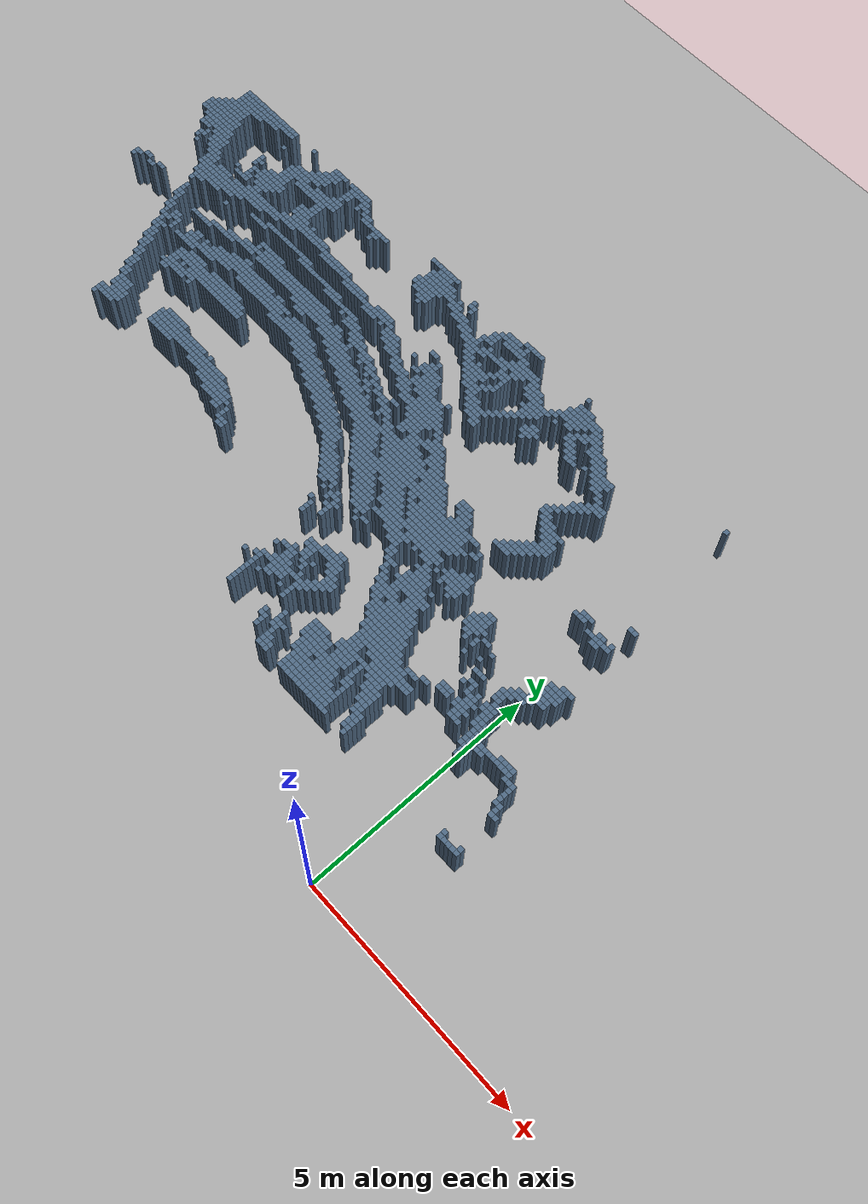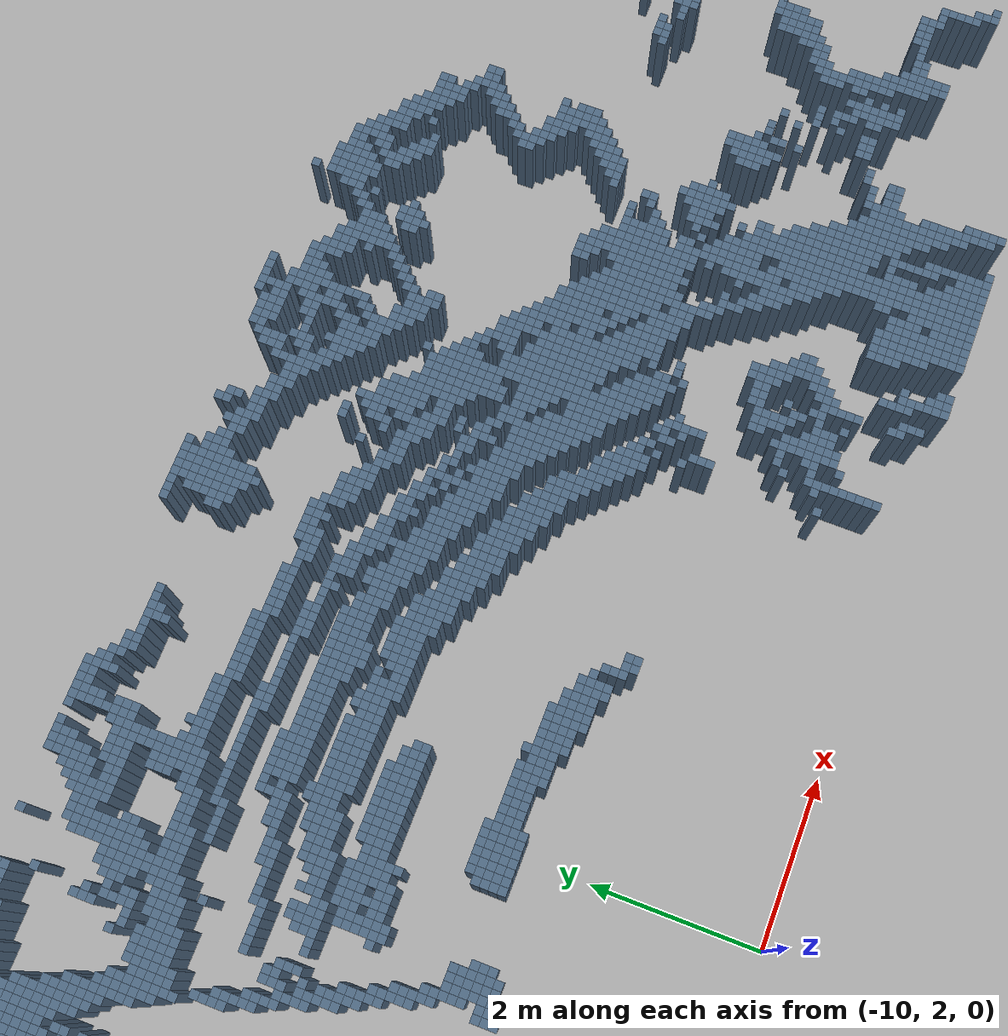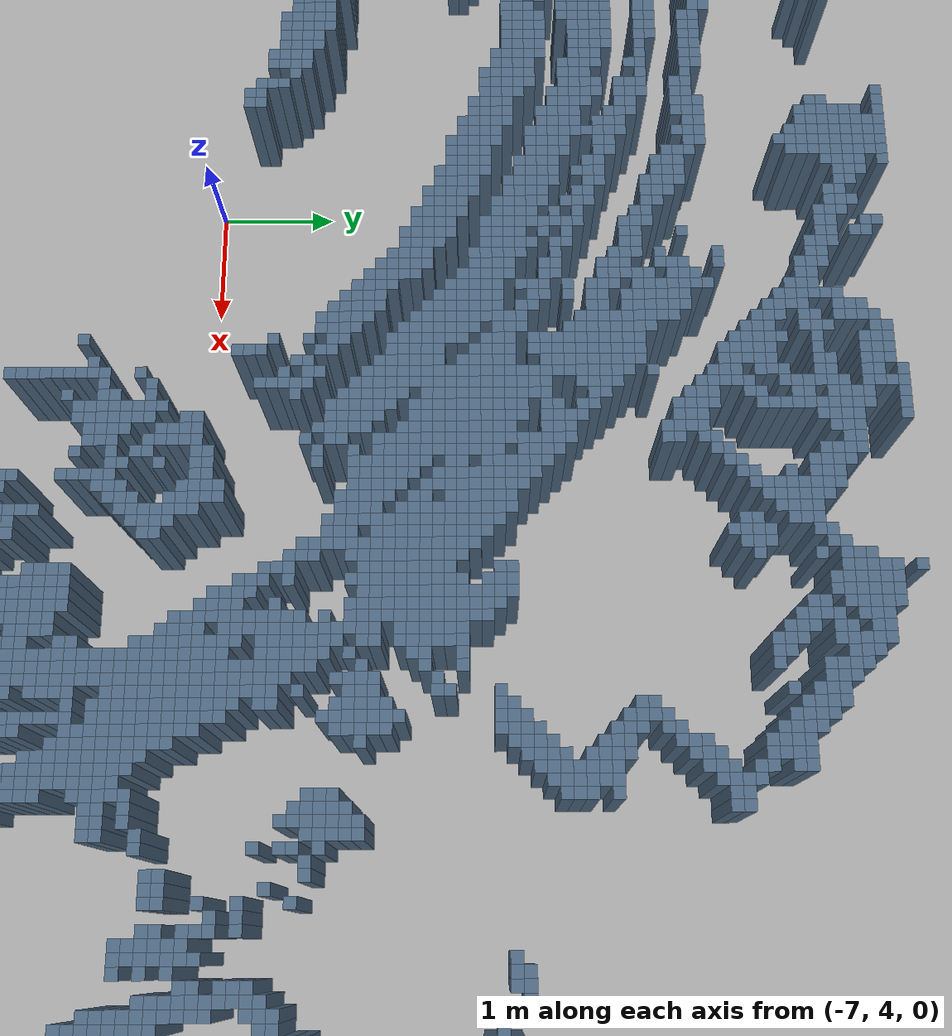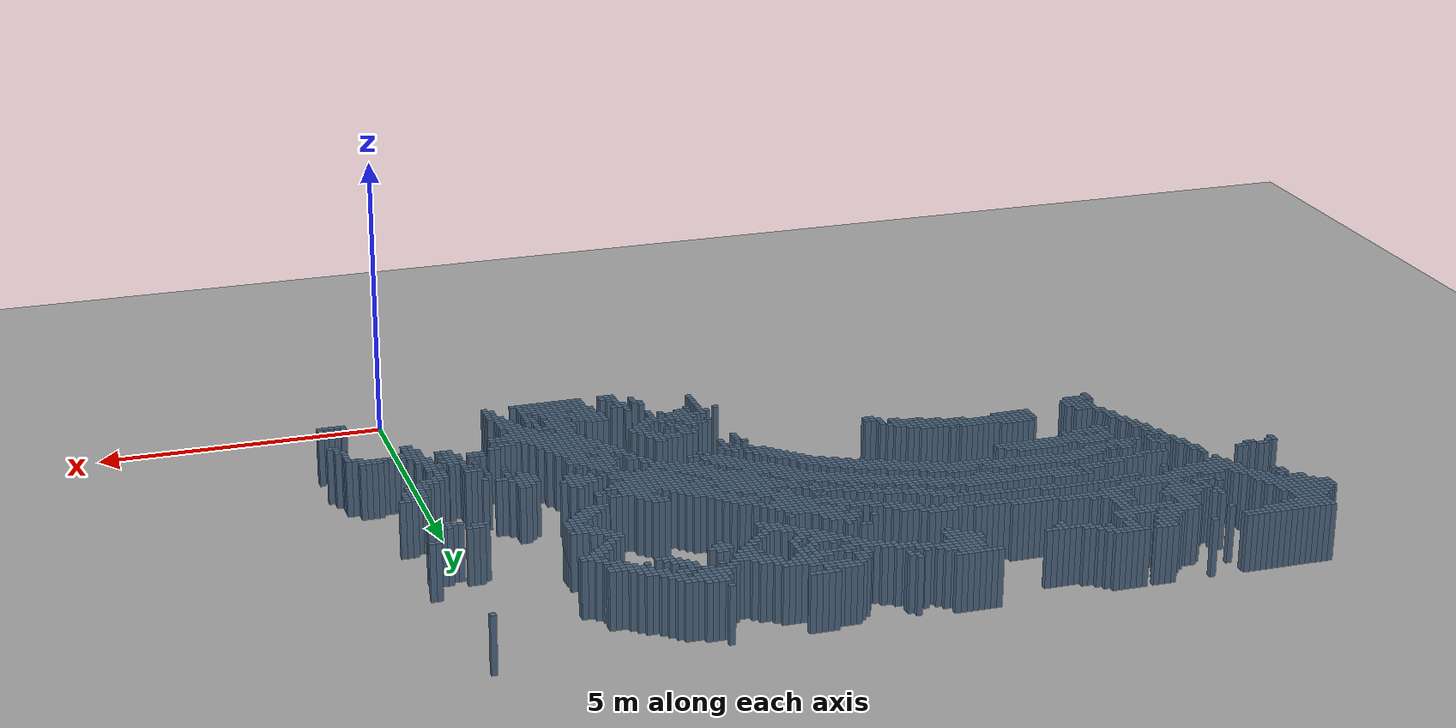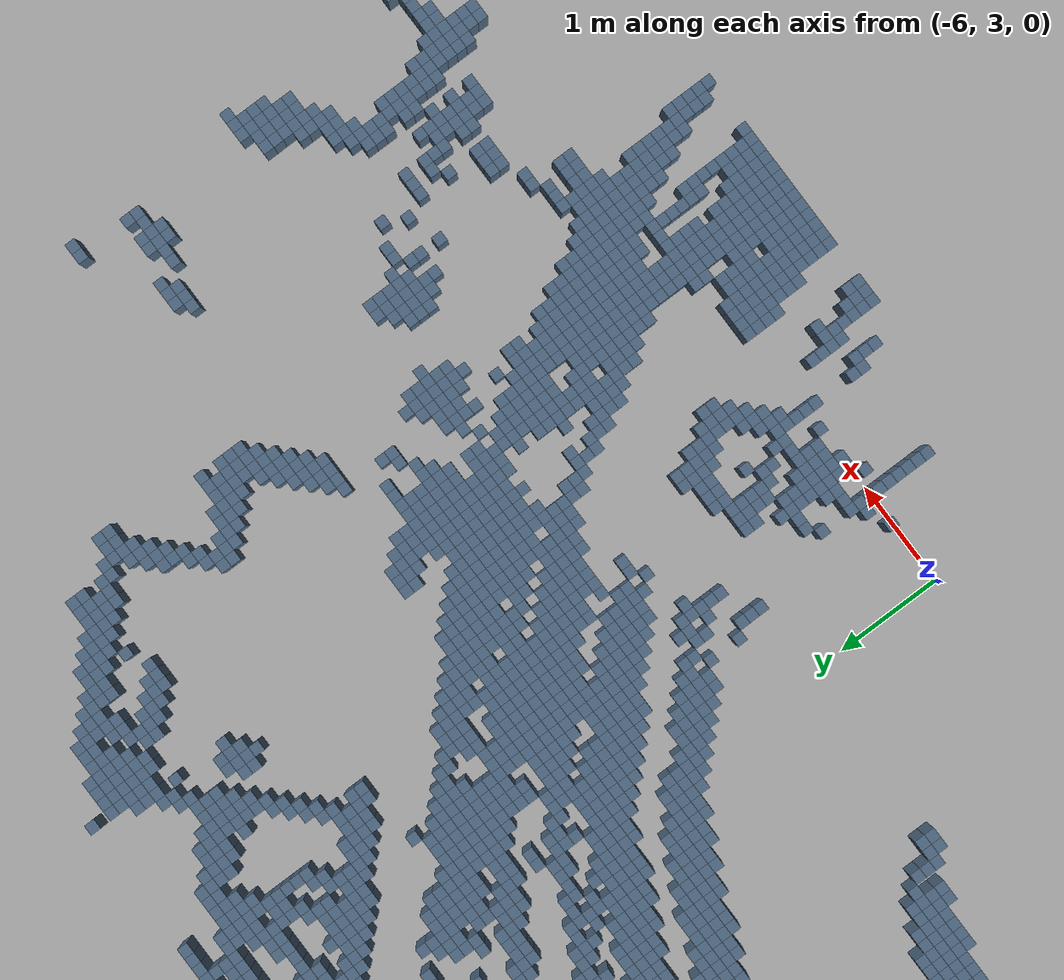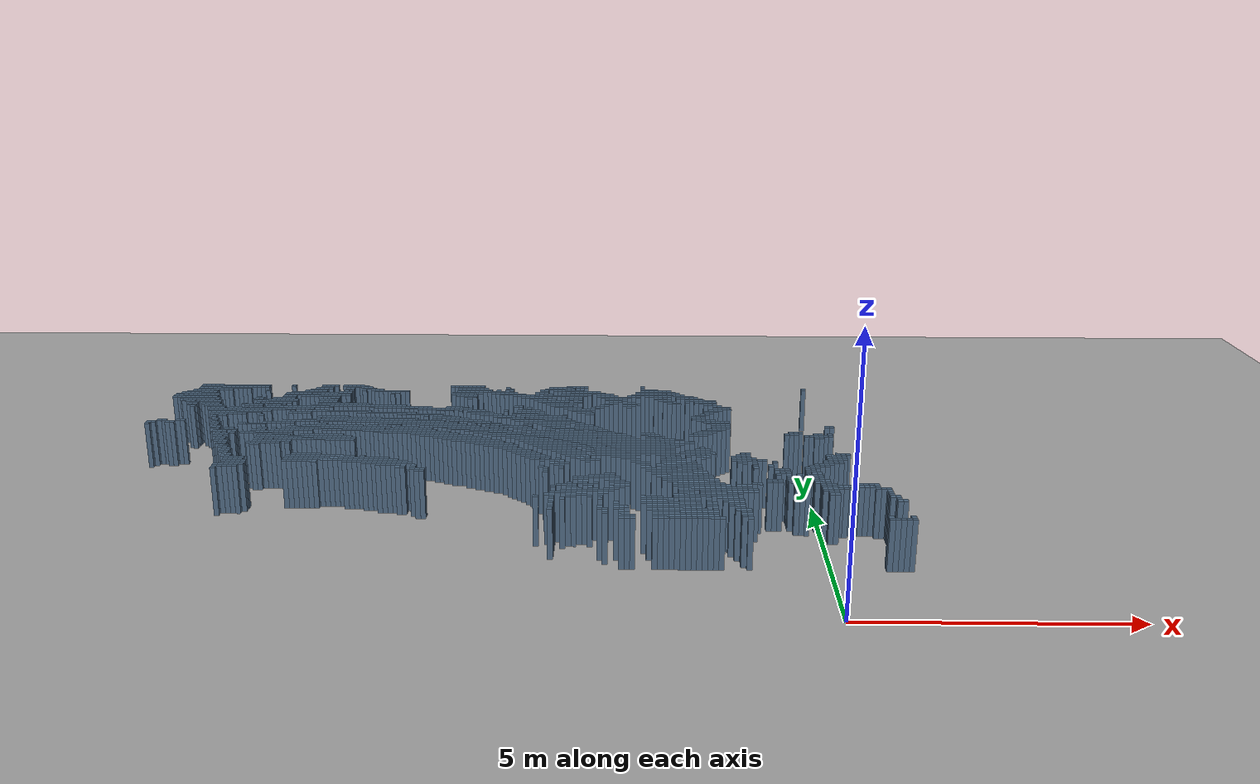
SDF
<?xml version='1.0' encoding='utf-8'?>
<sdf version="1.6">
  <world name="default">
    <gravity>0 0 -9.81</gravity>
    <physics name="default_physics" type="ode">
      <max_step_size>0.001</max_step_size>
      <real_time_update_rate>1000</real_time_update_rate>
    </physics>
    <scene>
      <ambient>0.6 0.6 0.6 1</ambient>
      <shadows>false</shadows>
    </scene>
    <light name="sun" type="directional">
      <pose>0 0 10 0 0 0</pose>
      <diffuse>0.8 0.8 0.8 1</diffuse>
      <direction>-0.5 0.1 -1</direction>
    </light>
    <model name="artificial_flat_ground">
      <static>true</static>
      <link name="ground">
        <collision name="floor_collision">
          <geometry>
            <plane>
              <normal>0 0 1</normal>
              <size>100 100</size>
            </plane>
          </geometry>
        </collision>
        <visual name="floor_visual">
          <geometry>
            <plane>
              <normal>0 0 1</normal>
              <size>100 100</size>
            </plane>
          </geometry>
          <material>
            <ambient>0.65 0.65 0.65 1</ambient>
            <diffuse>0.65 0.65 0.65 1</diffuse>
          </material>
        </visual>
      </link>
    </model>
    <model name="hilti_projected_cells">
      <static>true</static>
      <link name="obstacles">
        <collision name="cell_0_102_collision">
          <pose>-3.75000000 2.05000000 0.50000000 0 0 0</pose>
          <geometry>
            <box>
              <size>0.10000000 0.10000000 1.00000000</size>
            </box>
          </geometry>
        </collision>
        <visual name="cell_0_102_visual">
          <pose>-3.75000000 2.05000000 0.50000000 0 0 0</pose>
          <geometry>
            <box>
              <size>0.10000000 0.10000000 1.00000000</size>
            </box>
          </geometry>
          <material>
            <ambient>0.3 0.4 0.5 1</ambient>
            <diffuse>0.3 0.4 0.5 1</diffuse>
          </material>
        </visual>
        <collision name="cell_0_103_collision">
          <pose>-3.65000000 2.05000000 0.50000000 0 0 0</pose>
          <geometry>
            <box>
              <size>0.10000000 0.10000000 1.00000000</size>
            </box>
          </geometry>
        </collision>
        <visual name="cell_0_103_visual">
          <pose>-3.65000000 2.05000000 0.50000000 0 0 0</pose>
          <geometry>
            <box>
              <size>0.10000000 0.10000000 1.00000000</size>
            </box>
          </geometry>
          <material>
            <ambient>0.3 0.4 0.5 1</ambient>
            <diffuse>0.3 0.4 0.5 1</diffuse>
          </material>
        </visual>
        <collision name="cell_0_104_collision">
          <pose>-3.55000000 2.05000000 0.50000000 0 0 0</pose>
          <geometry>
            <box>
              <size>0.10000000 0.10000000 1.00000000</size>
            </box>
          </geometry>
        </collision>
        <visual name="cell_0_104_visual">
          <pose>-3.55000000 2.05000000 0.50000000 0 0 0</pose>
          <geometry>
            <box>
              <size>0.10000000 0.10000000 1.00000000</size>
            </box>
          </geometry>
          <material>
            <ambient>0.3 0.4 0.5 1</ambient>
            <diffuse>0.3 0.4 0.5 1</diffuse>
          </material>
        </visual>
        <collision name="cell_0_108_collision">
          <pose>-3.15000000 2.05000000 0.50000000 0 0 0</pose>
          <geometry>
            <box>
              <size>0.10000000 0.10000000 1.00000000</size>
            </box>
          </geometry>
        </collision>
        <visual name="cell_0_108_visual">
          <pose>-3.15000000 2.05000000 0.50000000 0 0 0</pose>
          <geometry>
            <box>
              <size>0.10000000 0.10000000 1.00000000</size>
            </box>
          </geometry>
          <material>
            <ambient>0.3 0.4 0.5 1</ambient>
            <diffuse>0.3 0.4 0.5 1</diffuse>
          </material>
        </visual>
        <collision name="cell_0_109_collision">
          <pose>-3.05000000 2.05000000 0.50000000 0 0 0</pose>
          <geometry>
            <box>
              <size>0.10000000 0.10000000 1.00000000</size>
            </box>
          </geometry>
        </collision>
        <visual name="cell_0_109_visual">
          <pose>-3.05000000 2.05000000 0.50000000 0 0 0</pose>
          <geometry>
            <box>
              <size>0.10000000 0.10000000 1.00000000</size>
            </box>
          </geometry>
          <material>
            <ambient>0.3 0.4 0.5 1</ambient>
            <diffuse>0.3 0.4 0.5 1</diffuse>
          </material>
        </visual>
        <collision name="cell_0_110_collision">
          <pose>-2.95000000 2.05000000 0.50000000 0 0 0</pose>
          <geometry>
            <box>
              <size>0.10000000 0.10000000 1.00000000</size>
            </box>
          </geometry>
        </collision>
        <visual name="cell_0_110_visual">
          <pose>-2.95000000 2.05000000 0.50000000 0 0 0</pose>
          <geometry>
            <box>
              <size>0.10000000 0.10000000 1.00000000</size>
            </box>
          </geometry>
          <material>
            <ambient>0.3 0.4 0.5 1</ambient>
            <diffuse>0.3 0.4 0.5 1</diffuse>
          </material>
        </visual>
        <collision name="cell_0_111_collision">
          <pose>-2.85000000 2.05000000 0.50000000 0 0 0</pose>
          <geometry>
            <box>
              <size>0.10000000 0.10000000 1.00000000</size>
            </box>
          </geometry>
        </collision>
        <visual name="cell_0_111_visual">
          <pose>-2.85000000 2.05000000 0.50000000 0 0 0</pose>
          <geometry>
            <box>
              <size>0.10000000 0.10000000 1.00000000</size>
            </box>
          </geometry>
          <material>
            <ambient>0.3 0.4 0.5 1</ambient>
            <diffuse>0.3 0.4 0.5 1</diffuse>
          </material>
        </visual>
        <collision name="cell_0_112_collision">
          <pose>-2.75000000 2.05000000 0.50000000 0 0 0</pose>
          <geometry>
            <box>
              <size>0.10000000 0.10000000 1.00000000</size>
            </box>
          </geometry>
        </collision>
        <visual name="cell_0_112_visual">
          <pose>-2.75000000 2.05000000 0.50000000 0 0 0</pose>
          <geometry>
            <box>
              <size>0.10000000 0.10000000 1.00000000</size>
            </box>
          </geometry>
          <material>
            <ambient>0.3 0.4 0.5 1</ambient>
            <diffuse>0.3 0.4 0.5 1</diffuse>
          </material>
        </visual>
        <collision name="cell_0_113_collision">
          <pose>-2.65000000 2.05000000 0.50000000 0 0 0</pose>
          <geometry>
            <box>
              <size>0.10000000 0.10000000 1.00000000</size>
            </box>
          </geometry>
        </collision>
        <visual name="cell_0_113_visual">
          <pose>-2.65000000 2.05000000 0.50000000 0 0 0</pose>
          <geometry>
            <box>
              <size>0.10000000 0.10000000 1.00000000</size>
            </box>
          </geometry>
          <material>
            <ambient>0.3 0.4 0.5 1</ambient>
            <diffuse>0.3 0.4 0.5 1</diffuse>
          </material>
        </visual>
        <collision name="cell_0_114_collision">
          <pose>-2.55000000 2.05000000 0.50000000 0 0 0</pose>
          <geometry>
            <box>
              <size>0.10000000 0.10000000 1.00000000</size>
            </box>
          </geometry>
        </collision>
        <visual name="cell_0_114_visual">
          <pose>-2.55000000 2.05000000 0.50000000 0 0 0</pose>
          <geometry>
            <box>
              <size>0.10000000 0.10000000 1.00000000</size>
            </box>
          </geometry>
          <material>
            <ambient>0.3 0.4 0.5 1</ambient>
            <diffuse>0.3 0.4 0.5 1</diffuse>
          </material>
        </visual>
        <collision name="cell_0_115_collision">
          <pose>-2.45000000 2.05000000 0.50000000 0 0 0</pose>
          <geometry>
            <box>
              <size>0.10000000 0.10000000 1.00000000</size>
            </box>
          </geometry>
        </collision>
        <visual name="cell_0_115_visual">
          <pose>-2.45000000 2.05000000 0.50000000 0 0 0</pose>
          <geometry>
            <box>
              <size>0.10000000 0.10000000 1.00000000</size>
            </box>
          </geometry>
          <material>
            <ambient>0.3 0.4 0.5 1</ambient>
            <diffuse>0.3 0.4 0.5 1</diffuse>
          </material>
        </visual>
        <collision name="cell_0_116_collision">
          <pose>-2.35000000 2.05000000 0.50000000 0 0 0</pose>
          <geometry>
            <box>
              <size>0.10000000 0.10000000 1.00000000</size>
            </box>
          </geometry>
        </collision>
        <visual name="cell_0_116_visual">
          <pose>-2.35000000 2.05000000 0.50000000 0 0 0</pose>
          <geometry>
            <box>
              <size>0.10000000 0.10000000 1.00000000</size>
            </box>
          </geometry>
          <material>
            <ambient>0.3 0.4 0.5 1</ambient>
            <diffuse>0.3 0.4 0.5 1</diffuse>
          </material>
        </visual>
        <collision name="cell_0_117_collision">
          <pose>-2.25000000 2.05000000 0.50000000 0 0 0</pose>
          <geometry>
            <box>
              <size>0.10000000 0.10000000 1.00000000</size>
            </box>
          </geometry>
        </collision>
        <visual name="cell_0_117_visual">
          <pose>-2.25000000 2.05000000 0.50000000 0 0 0</pose>
          <geometry>
            <box>
              <size>0.10000000 0.10000000 1.00000000</size>
            </box>
          </geometry>
          <material>
            <ambient>0.3 0.4 0.5 1</ambient>
            <diffuse>0.3 0.4 0.5 1</diffuse>
          </material>
        </visual>
        <collision name="cell_0_118_collision">
          <pose>-2.15000000 2.05000000 0.50000000 0 0 0</pose>
          <geometry>
            <box>
              <size>0.10000000 0.10000000 1.00000000</size>
            </box>
          </geometry>
        </collision>
        <visual name="cell_0_118_visual">
          <pose>-2.15000000 2.05000000 0.50000000 0 0 0</pose>
          <geometry>
            <box>
              <size>0.10000000 0.10000000 1.00000000</size>
            </box>
          </geometry>
          <material>
            <ambient>0.3 0.4 0.5 1</ambient>
            <diffuse>0.3 0.4 0.5 1</diffuse>
          </material>
        </visual>
        <collision name="cell_0_119_collision">
          <pose>-2.05000000 2.05000000 0.50000000 0 0 0</pose>
          <geometry>
            <box>
              <size>0.10000000 0.10000000 1.00000000</size>
            </box>
          </geometry>
        </collision>
        <visual name="cell_0_119_visual">
          <pose>-2.05000000 2.05000000 0.50000000 0 0 0</pose>
          <geometry>
            <box>
              <size>0.10000000 0.10000000 1.00000000</size>
            </box>
          </geometry>
          <material>
            <ambient>0.3 0.4 0.5 1</ambient>
            <diffuse>0.3 0.4 0.5 1</diffuse>
          </material>
        </visual>
        <collision name="cell_0_120_collision">
          <pose>-1.95000000 2.05000000 0.50000000 0 0 0</pose>
          <geometry>
            <box>
              <size>0.10000000 0.10000000 1.00000000</size>
            </box>
          </geometry>
        </collision>
        <visual name="cell_0_120_visual">
          <pose>-1.95000000 2.05000000 0.50000000 0 0 0</pose>
          <geometry>
            <box>
              <size>0.10000000 0.10000000 1.00000000</size>
            </box>
          </geometry>
          <material>
            <ambient>0.3 0.4 0.5 1</ambient>
            <diffuse>0.3 0.4 0.5 1</diffuse>
          </material>
        </visual>
        <collision name="cell_0_125_collision">
          <pose>-1.45000000 2.05000000 0.50000000 0 0 0</pose>
          <geometry>
            <box>
              <size>0.10000000 0.10000000 1.00000000</size>
            </box>
          </geometry>
        </collision>
        <visual name="cell_0_125_visual">
          <pose>-1.45000000 2.05000000 0.50000000 0 0 0</pose>
          <geometry>
            <box>
              <size>0.10000000 0.10000000 1.00000000</size>
            </box>
          </geometry>
          <material>
            <ambient>0.3 0.4 0.5 1</ambient>
            <diffuse>0.3 0.4 0.5 1</diffuse>
          </material>
        </visual>
        <collision name="cell_0_150_collision">
          <pose>1.05000000 2.05000000 0.50000000 0 0 0</pose>
          <geometry>
            <box>
              <size>0.10000000 0.10000000 1.00000000</size>
            </box>
          </geometry>
        </collision>
        <visual name="cell_0_150_visual">
          <pose>1.05000000 2.05000000 0.50000000 0 0 0</pose>
          <geometry>
            <box>
              <size>0.10000000 0.10000000 1.00000000</size>
            </box>
          </geometry>
          <material>
            <ambient>0.3 0.4 0.5 1</ambient>
            <diffuse>0.3 0.4 0.5 1</diffuse>
          </material>
        </visual>
        <collision name="cell_0_151_collision">
          <pose>1.15000000 2.05000000 0.50000000 0 0 0</pose>
          <geometry>
            <box>
              <size>0.10000000 0.10000000 1.00000000</size>
            </box>
          </geometry>
        </collision>
        <visual name="cell_0_151_visual">
          <pose>1.15000000 2.05000000 0.50000000 0 0 0</pose>
          <geometry>
            <box>
              <size>0.10000000 0.10000000 1.00000000</size>
            </box>
          </geometry>
          <material>
            <ambient>0.3 0.4 0.5 1</ambient>
            <diffuse>0.3 0.4 0.5 1</diffuse>
          </material>
        </visual>
        <collision name="cell_0_152_collision">
          <pose>1.25000000 2.05000000 0.50000000 0 0 0</pose>
          <geometry>
            <box>
              <size>0.10000000 0.10000000 1.00000000</size>
            </box>
          </geometry>
        </collision>
        <visual name="cell_0_152_visual">
          <pose>1.25000000 2.05000000 0.50000000 0 0 0</pose>
          <geometry>
            <box>
              <size>0.10000000 0.10000000 1.00000000</size>
            </box>
          </geometry>
          <material>
            <ambient>0.3 0.4 0.5 1</ambient>
            <diffuse>0.3 0.4 0.5 1</diffuse>
          </material>
        </visual>
        <collision name="cell_0_153_collision">
          <pose>1.35000000 2.05000000 0.50000000 0 0 0</pose>
          <geometry>
            <box>
              <size>0.10000000 0.10000000 1.00000000</size>
            </box>
          </geometry>
        </collision>
        <visual name="cell_0_153_visual">
          <pose>1.35000000 2.05000000 0.50000000 0 0 0</pose>
          <geometry>
            <box>
              <size>0.10000000 0.10000000 1.00000000</size>
            </box>
          </geometry>
          <material>
            <ambient>0.3 0.4 0.5 1</ambient>
            <diffuse>0.3 0.4 0.5 1</diffuse>
          </material>
        </visual>
        <collision name="cell_0_154_collision">
          <pose>1.45000000 2.05000000 0.50000000 0 0 0</pose>
          <geometry>
            <box>
              <size>0.10000000 0.10000000 1.00000000</size>
            </box>
          </geometry>
        </collision>
        <visual name="cell_0_154_visual">
          <pose>1.45000000 2.05000000 0.50000000 0 0 0</pose>
          <geometry>
            <box>
              <size>0.10000000 0.10000000 1.00000000</size>
            </box>
          </geometry>
          <material>
            <ambient>0.3 0.4 0.5 1</ambient>
            <diffuse>0.3 0.4 0.5 1</diffuse>
          </material>
        </visual>
        <collision name="cell_1_102_collision">
          <pose>-3.75000000 2.15000000 0.50000000 0 0 0</pose>
          <geometry>
            <box>
              <size>0.10000000 0.10000000 1.00000000</size>
            </box>
          </geometry>
        </collision>
        <visual name="cell_1_102_visual">
          <pose>-3.75000000 2.15000000 0.50000000 0 0 0</pose>
          <geometry>
            <box>
              <size>0.10000000 0.10000000 1.00000000</size>
            </box>
          </geometry>
          <material>
            <ambient>0.3 0.4 0.5 1</ambient>
            <diffuse>0.3 0.4 0.5 1</diffuse>
          </material>
        </visual>
        <collision name="cell_1_103_collision">
          <pose>-3.65000000 2.15000000 0.50000000 0 0 0</pose>
          <geometry>
            <box>
              <size>0.10000000 0.10000000 1.00000000</size>
            </box>
          </geometry>
        </collision>
        <visual name="cell_1_103_visual">
          <pose>-3.65000000 2.15000000 0.50000000 0 0 0</pose>
          <geometry>
            <box>
              <size>0.10000000 0.10000000 1.00000000</size>
            </box>
          </geometry>
          <material>
            <ambient>0.3 0.4 0.5 1</ambient>
            <diffuse>0.3 0.4 0.5 1</diffuse>
          </material>
        </visual>
        <collision name="cell_1_104_collision">
          <pose>-3.55000000 2.15000000 0.50000000 0 0 0</pose>
          <geometry>
            <box>
              <size>0.10000000 0.10000000 1.00000000</size>
            </box>
          </geometry>
        </collision>
        <visual name="cell_1_104_visual">
          <pose>-3.55000000 2.15000000 0.50000000 0 0 0</pose>
          <geometry>
            <box>
              <size>0.10000000 0.10000000 1.00000000</size>
            </box>
          </geometry>
          <material>
            <ambient>0.3 0.4 0.5 1</ambient>
            <diffuse>0.3 0.4 0.5 1</diffuse>
          </material>
        </visual>
        <collision name="cell_1_108_collision">
          <pose>-3.15000000 2.15000000 0.50000000 0 0 0</pose>
          <geometry>
            <box>
              <size>0.10000000 0.10000000 1.00000000</size>
            </box>
          </geometry>
        </collision>
        <visual name="cell_1_108_visual">
          <pose>-3.15000000 2.15000000 0.50000000 0 0 0</pose>
          <geometry>
            <box>
              <size>0.10000000 0.10000000 1.00000000</size>
            </box>
          </geometry>
          <material>
            <ambient>0.3 0.4 0.5 1</ambient>
            <diffuse>0.3 0.4 0.5 1</diffuse>
          </material>
        </visual>
        <collision name="cell_1_109_collision">
          <pose>-3.05000000 2.15000000 0.50000000 0 0 0</pose>
          <geometry>
            <box>
              <size>0.10000000 0.10000000 1.00000000</size>
            </box>
          </geometry>
        </collision>
        <visual name="cell_1_109_visual">
          <pose>-3.05000000 2.15000000 0.50000000 0 0 0</pose>
          <geometry>
            <box>
              <size>0.10000000 0.10000000 1.00000000</size>
            </box>
          </geometry>
          <material>
            <ambient>0.3 0.4 0.5 1</ambient>
            <diffuse>0.3 0.4 0.5 1</diffuse>
          </material>
        </visual>
        <collision name="cell_1_110_collision">
          <pose>-2.95000000 2.15000000 0.50000000 0 0 0</pose>
          <geometry>
            <box>
              <size>0.10000000 0.10000000 1.00000000</size>
            </box>
          </geometry>
        </collision>
        <visual name="cell_1_110_visual">
          <pose>-2.95000000 2.15000000 0.50000000 0 0 0</pose>
          <geometry>
            <box>
              <size>0.10000000 0.10000000 1.00000000</size>
            </box>
          </geometry>
          <material>
            <ambient>0.3 0.4 0.5 1</ambient>
            <diffuse>0.3 0.4 0.5 1</diffuse>
          </material>
        </visual>
        <collision name="cell_1_111_collision">
          <pose>-2.85000000 2.15000000 0.50000000 0 0 0</pose>
          <geometry>
            <box>
              <size>0.10000000 0.10000000 1.00000000</size>
            </box>
          </geometry>
        </collision>
        <visual name="cell_1_111_visual">
          <pose>-2.85000000 2.15000000 0.50000000 0 0 0</pose>
          <geometry>
            <box>
              <size>0.10000000 0.10000000 1.00000000</size>
            </box>
          </geometry>
          <material>
            <ambient>0.3 0.4 0.5 1</ambient>
            <diffuse>0.3 0.4 0.5 1</diffuse>
          </material>
        </visual>
        <collision name="cell_1_112_collision">
          <pose>-2.75000000 2.15000000 0.50000000 0 0 0</pose>
          <geometry>
            <box>
              <size>0.10000000 0.10000000 1.00000000</size>
            </box>
          </geometry>
        </collision>
        <visual name="cell_1_112_visual">
          <pose>-2.75000000 2.15000000 0.50000000 0 0 0</pose>
          <geometry>
            <box>
              <size>0.10000000 0.10000000 1.00000000</size>
            </box>
          </geometry>
          <material>
            <ambient>0.3 0.4 0.5 1</ambient>
            <diffuse>0.3 0.4 0.5 1</diffuse>
          </material>
        </visual>
        <collision name="cell_1_113_collision">
          <pose>-2.65000000 2.15000000 0.50000000 0 0 0</pose>
          <geometry>
            <box>
              <size>0.10000000 0.10000000 1.00000000</size>
            </box>
          </geometry>
        </collision>
        <visual name="cell_1_113_visual">
          <pose>-2.65000000 2.15000000 0.50000000 0 0 0</pose>
          <geometry>
            <box>
              <size>0.10000000 0.10000000 1.00000000</size>
            </box>
          </geometry>
          <material>
            <ambient>0.3 0.4 0.5 1</ambient>
            <diffuse>0.3 0.4 0.5 1</diffuse>
          </material>
        </visual>
        <collision name="cell_1_114_collision">
          <pose>-2.55000000 2.15000000 0.50000000 0 0 0</pose>
          <geometry>
            <box>
              <size>0.10000000 0.10000000 1.00000000</size>
            </box>
          </geometry>
        </collision>
        <visual name="cell_1_114_visual">
          <pose>-2.55000000 2.15000000 0.50000000 0 0 0</pose>
          <geometry>
            <box>
              <size>0.10000000 0.10000000 1.00000000</size>
            </box>
          </geometry>
          <material>
            <ambient>0.3 0.4 0.5 1</ambient>
            <diffuse>0.3 0.4 0.5 1</diffuse>
          </material>
        </visual>
        <collision name="cell_1_115_collision">
          <pose>-2.45000000 2.15000000 0.50000000 0 0 0</pose>
          <geometry>
            <box>
              <size>0.10000000 0.10000000 1.00000000</size>
            </box>
          </geometry>
        </collision>
        <visual name="cell_1_115_visual">
          <pose>-2.45000000 2.15000000 0.50000000 0 0 0</pose>
          <geometry>
            <box>
              <size>0.10000000 0.10000000 1.00000000</size>
            </box>
          </geometry>
          <material>
            <ambient>0.3 0.4 0.5 1</ambient>
            <diffuse>0.3 0.4 0.5 1</diffuse>
          </material>
        </visual>
        <collision name="cell_1_116_collision">
          <pose>-2.35000000 2.15000000 0.50000000 0 0 0</pose>
          <geometry>
            <box>
              <size>0.10000000 0.10000000 1.00000000</size>
            </box>
          </geometry>
        </collision>
        <visual name="cell_1_116_visual">
          <pose>-2.35000000 2.15000000 0.50000000 0 0 0</pose>
          <geometry>
            <box>
              <size>0.10000000 0.10000000 1.00000000</size>
            </box>
          </geometry>
          <material>
            <ambient>0.3 0.4 0.5 1</ambient>
            <diffuse>0.3 0.4 0.5 1</diffuse>
          </material>
        </visual>
        <collision name="cell_1_117_collision">
          <pose>-2.25000000 2.15000000 0.50000000 0 0 0</pose>
          <geometry>
            <box>
              <size>0.10000000 0.10000000 1.00000000</size>
            </box>
          </geometry>
        </collision>
        <visual name="cell_1_117_visual">
          <pose>-2.25000000 2.15000000 0.50000000 0 0 0</pose>
          <geometry>
            <box>
              <size>0.10000000 0.10000000 1.00000000</size>
            </box>
          </geometry>
          <material>
            <ambient>0.3 0.4 0.5 1</ambient>
            <diffuse>0.3 0.4 0.5 1</diffuse>
          </material>
        </visual>
        <collision name="cell_1_118_collision">
          <pose>-2.15000000 2.15000000 0.50000000 0 0 0</pose>
          <geometry>
            <box>
              <size>0.10000000 0.10000000 1.00000000</size>
            </box>
          </geometry>
        </collision>
        <visual name="cell_1_118_visual">
          <pose>-2.15000000 2.15000000 0.50000000 0 0 0</pose>
          <geometry>
            <box>
              <size>0.10000000 0.10000000 1.00000000</size>
            </box>
          </geometry>
          <material>
            <ambient>0.3 0.4 0.5 1</ambient>
            <diffuse>0.3 0.4 0.5 1</diffuse>
          </material>
        </visual>
        <collision name="cell_1_119_collision">
          <pose>-2.05000000 2.15000000 0.50000000 0 0 0</pose>
          <geometry>
            <box>
              <size>0.10000000 0.10000000 1.00000000</size>
            </box>
          </geometry>
        </collision>
        <visual name="cell_1_119_visual">
          <pose>-2.05000000 2.15000000 0.50000000 0 0 0</pose>
          <geometry>
            <box>
              <size>0.10000000 0.10000000 1.00000000</size>
            </box>
          </geometry>
          <material>
            <ambient>0.3 0.4 0.5 1</ambient>
            <diffuse>0.3 0.4 0.5 1</diffuse>
          </material>
        </visual>
        <collision name="cell_1_124_collision">
          <pose>-1.55000000 2.15000000 0.50000000 0 0 0</pose>
          <geometry>
            <box>
              <size>0.10000000 0.10000000 1.00000000</size>
            </box>
          </geometry>
        </collision>
        <visual name="cell_1_124_visual">
          <pose>-1.55000000 2.15000000 0.50000000 0 0 0</pose>
          <geometry>
            <box>
              <size>0.10000000 0.10000000 1.00000000</size>
            </box>
          </geometry>
          <material>
            <ambient>0.3 0.4 0.5 1</ambient>
            <diffuse>0.3 0.4 0.5 1</diffuse>
          </material>
        </visual>
        <collision name="cell_1_125_collision">
          <pose>-1.45000000 2.15000000 0.50000000 0 0 0</pose>
          <geometry>
            <box>
              <size>0.10000000 0.10000000 1.00000000</size>
            </box>
          </geometry>
        </collision>
        <visual name="cell_1_125_visual">
          <pose>-1.45000000 2.15000000 0.50000000 0 0 0</pose>
          <geometry>
            <box>
              <size>0.10000000 0.10000000 1.00000000</size>
            </box>
          </geometry>
          <material>
            <ambient>0.3 0.4 0.5 1</ambient>
            <diffuse>0.3 0.4 0.5 1</diffuse>
          </material>
        </visual>
        <collision name="cell_1_150_collision">
          <pose>1.05000000 2.15000000 0.50000000 0 0 0</pose>
          <geometry>
            <box>
              <size>0.10000000 0.10000000 1.00000000</size>
            </box>
          </geometry>
        </collision>
        <visual name="cell_1_150_visual">
          <pose>1.05000000 2.15000000 0.50000000 0 0 0</pose>
          <geometry>
            <box>
              <size>0.10000000 0.10000000 1.00000000</size>
            </box>
          </geometry>
          <material>
            <ambient>0.3 0.4 0.5 1</ambient>
            <diffuse>0.3 0.4 0.5 1</diffuse>
          </material>
        </visual>
        <collision name="cell_1_154_collision">
          <pose>1.45000000 2.15000000 0.50000000 0 0 0</pose>
          <geometry>
            <box>
              <size>0.10000000 0.10000000 1.00000000</size>
            </box>
          </geometry>
        </collision>
        <visual name="cell_1_154_visual">
          <pose>1.45000000 2.15000000 0.50000000 0 0 0</pose>
          <geometry>
            <box>
              <size>0.10000000 0.10000000 1.00000000</size>
            </box>
          </geometry>
          <material>
            <ambient>0.3 0.4 0.5 1</ambient>
            <diffuse>0.3 0.4 0.5 1</diffuse>
          </material>
        </visual>
        <collision name="cell_2_99_collision">
          <pose>-4.05000000 2.25000000 0.50000000 0 0 0</pose>
          <geometry>
            <box>
              <size>0.10000000 0.10000000 1.00000000</size>
            </box>
          </geometry>
        </collision>
        <visual name="cell_2_99_visual">
          <pose>-4.05000000 2.25000000 0.50000000 0 0 0</pose>
          <geometry>
            <box>
              <size>0.10000000 0.10000000 1.00000000</size>
            </box>
          </geometry>
          <material>
            <ambient>0.3 0.4 0.5 1</ambient>
            <diffuse>0.3 0.4 0.5 1</diffuse>
          </material>
        </visual>
        <collision name="cell_2_102_collision">
          <pose>-3.75000000 2.25000000 0.50000000 0 0 0</pose>
          <geometry>
            <box>
              <size>0.10000000 0.10000000 1.00000000</size>
            </box>
          </geometry>
        </collision>
        <visual name="cell_2_102_visual">
          <pose>-3.75000000 2.25000000 0.50000000 0 0 0</pose>
          <geometry>
            <box>
              <size>0.10000000 0.10000000 1.00000000</size>
            </box>
          </geometry>
          <material>
            <ambient>0.3 0.4 0.5 1</ambient>
            <diffuse>0.3 0.4 0.5 1</diffuse>
          </material>
        </visual>
        <collision name="cell_2_103_collision">
          <pose>-3.65000000 2.25000000 0.50000000 0 0 0</pose>
          <geometry>
            <box>
              <size>0.10000000 0.10000000 1.00000000</size>
            </box>
          </geometry>
        </collision>
        <visual name="cell_2_103_visual">
          <pose>-3.65000000 2.25000000 0.50000000 0 0 0</pose>
          <geometry>
            <box>
              <size>0.10000000 0.10000000 1.00000000</size>
            </box>
          </geometry>
          <material>
            <ambient>0.3 0.4 0.5 1</ambient>
            <diffuse>0.3 0.4 0.5 1</diffuse>
          </material>
        </visual>
        <collision name="cell_2_108_collision">
          <pose>-3.15000000 2.25000000 0.50000000 0 0 0</pose>
          <geometry>
            <box>
              <size>0.10000000 0.10000000 1.00000000</size>
            </box>
          </geometry>
        </collision>
        <visual name="cell_2_108_visual">
          <pose>-3.15000000 2.25000000 0.50000000 0 0 0</pose>
          <geometry>
            <box>
              <size>0.10000000 0.10000000 1.00000000</size>
            </box>
          </geometry>
          <material>
            <ambient>0.3 0.4 0.5 1</ambient>
            <diffuse>0.3 0.4 0.5 1</diffuse>
          </material>
        </visual>
        <collision name="cell_2_109_collision">
          <pose>-3.05000000 2.25000000 0.50000000 0 0 0</pose>
          <geometry>
            <box>
              <size>0.10000000 0.10000000 1.00000000</size>
            </box>
          </geometry>
        </collision>
        <visual name="cell_2_109_visual">
          <pose>-3.05000000 2.25000000 0.50000000 0 0 0</pose>
          <geometry>
            <box>
              <size>0.10000000 0.10000000 1.00000000</size>
            </box>
          </geometry>
          <material>
            <ambient>0.3 0.4 0.5 1</ambient>
            <diffuse>0.3 0.4 0.5 1</diffuse>
          </material>
        </visual>
        <collision name="cell_2_110_collision">
          <pose>-2.95000000 2.25000000 0.50000000 0 0 0</pose>
          <geometry>
            <box>
              <size>0.10000000 0.10000000 1.00000000</size>
            </box>
          </geometry>
        </collision>
        <visual name="cell_2_110_visual">
          <pose>-2.95000000 2.25000000 0.50000000 0 0 0</pose>
          <geometry>
            <box>
              <size>0.10000000 0.10000000 1.00000000</size>
            </box>
          </geometry>
          <material>
            <ambient>0.3 0.4 0.5 1</ambient>
            <diffuse>0.3 0.4 0.5 1</diffuse>
          </material>
        </visual>
        <collision name="cell_2_111_collision">
          <pose>-2.85000000 2.25000000 0.50000000 0 0 0</pose>
          <geometry>
            <box>
              <size>0.10000000 0.10000000 1.00000000</size>
            </box>
          </geometry>
        </collision>
        <visual name="cell_2_111_visual">
          <pose>-2.85000000 2.25000000 0.50000000 0 0 0</pose>
          <geometry>
            <box>
              <size>0.10000000 0.10000000 1.00000000</size>
            </box>
          </geometry>
          <material>
            <ambient>0.3 0.4 0.5 1</ambient>
            <diffuse>0.3 0.4 0.5 1</diffuse>
          </material>
        </visual>
        <collision name="cell_2_112_collision">
          <pose>-2.75000000 2.25000000 0.50000000 0 0 0</pose>
          <geometry>
            <box>
              <size>0.10000000 0.10000000 1.00000000</size>
            </box>
          </geometry>
        </collision>
        <visual name="cell_2_112_visual">
          <pose>-2.75000000 2.25000000 0.50000000 0 0 0</pose>
          <geometry>
            <box>
              <size>0.10000000 0.10000000 1.00000000</size>
            </box>
          </geometry>
          <material>
            <ambient>0.3 0.4 0.5 1</ambient>
            <diffuse>0.3 0.4 0.5 1</diffuse>
          </material>
        </visual>
        <collision name="cell_2_113_collision">
          <pose>-2.65000000 2.25000000 0.50000000 0 0 0</pose>
          <geometry>
            <box>
              <size>0.10000000 0.10000000 1.00000000</size>
            </box>
          </geometry>
        </collision>
        <visual name="cell_2_113_visual">
          <pose>-2.65000000 2.25000000 0.50000000 0 0 0</pose>
          <geometry>
            <box>
              <size>0.10000000 0.10000000 1.00000000</size>
            </box>
          </geometry>
          <material>
            <ambient>0.3 0.4 0.5 1</ambient>
            <diffuse>0.3 0.4 0.5 1</diffuse>
          </material>
        </visual>
        <collision name="cell_2_114_collision">
          <pose>-2.55000000 2.25000000 0.50000000 0 0 0</pose>
          <geometry>
            <box>
              <size>0.10000000 0.10000000 1.00000000</size>
            </box>
          </geometry>
        </collision>
        <visual name="cell_2_114_visual">
          <pose>-2.55000000 2.25000000 0.50000000 0 0 0</pose>
          <geometry>
            <box>
              <size>0.10000000 0.10000000 1.00000000</size>
            </box>
          </geometry>
          <material>
            <ambient>0.3 0.4 0.5 1</ambient>
            <diffuse>0.3 0.4 0.5 1</diffuse>
          </material>
        </visual>
        <collision name="cell_2_115_collision">
          <pose>-2.45000000 2.25000000 0.50000000 0 0 0</pose>
          <geometry>
            <box>
              <size>0.10000000 0.10000000 1.00000000</size>
            </box>
          </geometry>
        </collision>
        <visual name="cell_2_115_visual">
          <pose>-2.45000000 2.25000000 0.50000000 0 0 0</pose>
          <geometry>
            <box>
              <size>0.10000000 0.10000000 1.00000000</size>
            </box>
          </geometry>
          <material>
            <ambient>0.3 0.4 0.5 1</ambient>
            <diffuse>0.3 0.4 0.5 1</diffuse>
          </material>
        </visual>
        <collision name="cell_2_116_collision">
          <pose>-2.35000000 2.25000000 0.50000000 0 0 0</pose>
          <geometry>
            <box>
              <size>0.10000000 0.10000000 1.00000000</size>
            </box>
          </geometry>
        </collision>
        <visual name="cell_2_116_visual">
          <pose>-2.35000000 2.25000000 0.50000000 0 0 0</pose>
          <geometry>
            <box>
              <size>0.10000000 0.10000000 1.00000000</size>
            </box>
          </geometry>
          <material>
            <ambient>0.3 0.4 0.5 1</ambient>
            <diffuse>0.3 0.4 0.5 1</diffuse>
          </material>
        </visual>
        <collision name="cell_2_117_collision">
          <pose>-2.25000000 2.25000000 0.50000000 0 0 0</pose>
          <geometry>
            <box>
              <size>0.10000000 0.10000000 1.00000000</size>
            </box>
          </geometry>
        </collision>
        <visual name="cell_2_117_visual">
          <pose>-2.25000000 2.25000000 0.50000000 0 0 0</pose>
          <geometry>
            <box>
              <size>0.10000000 0.10000000 1.00000000</size>
            </box>
          </geometry>
          <material>
            <ambient>0.3 0.4 0.5 1</ambient>
            <diffuse>0.3 0.4 0.5 1</diffuse>
          </material>
        </visual>
        <collision name="cell_2_118_collision">
          <pose>-2.15000000 2.25000000 0.50000000 0 0 0</pose>
          <geometry>
            <box>
              <size>0.10000000 0.10000000 1.00000000</size>
            </box>
          </geometry>
        </collision>
        <visual name="cell_2_118_visual">
          <pose>-2.15000000 2.25000000 0.50000000 0 0 0</pose>
          <geometry>
            <box>
              <size>0.10000000 0.10000000 1.00000000</size>
            </box>
          </geometry>
          <material>
            <ambient>0.3 0.4 0.5 1</ambient>
            <diffuse>0.3 0.4 0.5 1</diffuse>
          </material>
        </visual>
        <collision name="cell_2_119_collision">
          <pose>-2.05000000 2.25000000 0.50000000 0 0 0</pose>
          <geometry>
            <box>
              <size>0.10000000 0.10000000 1.00000000</size>
            </box>
          </geometry>
        </collision>
        <visual name="cell_2_119_visual">
          <pose>-2.05000000 2.25000000 0.50000000 0 0 0</pose>
          <geometry>
            <box>
              <size>0.10000000 0.10000000 1.00000000</size>
            </box>
          </geometry>
          <material>
            <ambient>0.3 0.4 0.5 1</ambient>
            <diffuse>0.3 0.4 0.5 1</diffuse>
          </material>
        </visual>
        <collision name="cell_2_124_collision">
          <pose>-1.55000000 2.25000000 0.50000000 0 0 0</pose>
          <geometry>
            <box>
              <size>0.10000000 0.10000000 1.00000000</size>
            </box>
          </geometry>
        </collision>
        <visual name="cell_2_124_visual">
          <pose>-1.55000000 2.25000000 0.50000000 0 0 0</pose>
          <geometry>
            <box>
              <size>0.10000000 0.10000000 1.00000000</size>
            </box>
          </geometry>
          <material>
            <ambient>0.3 0.4 0.5 1</ambient>
            <diffuse>0.3 0.4 0.5 1</diffuse>
          </material>
        </visual>
        <collision name="cell_2_125_collision">
          <pose>-1.45000000 2.25000000 0.50000000 0 0 0</pose>
          <geometry>
            <box>
              <size>0.10000000 0.10000000 1.00000000</size>
            </box>
          </geometry>
        </collision>
        <visual name="cell_2_125_visual">
          <pose>-1.45000000 2.25000000 0.50000000 0 0 0</pose>
          <geometry>
            <box>
              <size>0.10000000 0.10000000 1.00000000</size>
            </box>
          </geometry>
          <material>
            <ambient>0.3 0.4 0.5 1</ambient>
            <diffuse>0.3 0.4 0.5 1</diffuse>
          </material>
        </visual>
        <collision name="cell_3_99_collision">
          <pose>-4.05000000 2.35000000 0.50000000 0 0 0</pose>
          <geometry>
            <box>
              <size>0.10000000 0.10000000 1.00000000</size>
            </box>
          </geometry>
        </collision>
        <visual name="cell_3_99_visual">
          <pose>-4.05000000 2.35000000 0.50000000 0 0 0</pose>
          <geometry>
            <box>
              <size>0.10000000 0.10000000 1.00000000</size>
            </box>
          </geometry>
          <material>
            <ambient>0.3 0.4 0.5 1</ambient>
            <diffuse>0.3 0.4 0.5 1</diffuse>
          </material>
        </visual>
        <collision name="cell_3_102_collision">
          <pose>-3.75000000 2.35000000 0.50000000 0 0 0</pose>
          <geometry>
            <box>
              <size>0.10000000 0.10000000 1.00000000</size>
            </box>
          </geometry>
        </collision>
        <visual name="cell_3_102_visual">
          <pose>-3.75000000 2.35000000 0.50000000 0 0 0</pose>
          <geometry>
            <box>
              <size>0.10000000 0.10000000 1.00000000</size>
            </box>
          </geometry>
          <material>
            <ambient>0.3 0.4 0.5 1</ambient>
            <diffuse>0.3 0.4 0.5 1</diffuse>
          </material>
        </visual>
        <collision name="cell_3_108_collision">
          <pose>-3.15000000 2.35000000 0.50000000 0 0 0</pose>
          <geometry>
            <box>
              <size>0.10000000 0.10000000 1.00000000</size>
            </box>
          </geometry>
        </collision>
        <visual name="cell_3_108_visual">
          <pose>-3.15000000 2.35000000 0.50000000 0 0 0</pose>
          <geometry>
            <box>
              <size>0.10000000 0.10000000 1.00000000</size>
            </box>
          </geometry>
          <material>
            <ambient>0.3 0.4 0.5 1</ambient>
            <diffuse>0.3 0.4 0.5 1</diffuse>
          </material>
        </visual>
        <collision name="cell_3_109_collision">
          <pose>-3.05000000 2.35000000 0.50000000 0 0 0</pose>
          <geometry>
            <box>
              <size>0.10000000 0.10000000 1.00000000</size>
            </box>
          </geometry>
        </collision>
        <visual name="cell_3_109_visual">
          <pose>-3.05000000 2.35000000 0.50000000 0 0 0</pose>
          <geometry>
            <box>
              <size>0.10000000 0.10000000 1.00000000</size>
            </box>
          </geometry>
          <material>
            <ambient>0.3 0.4 0.5 1</ambient>
            <diffuse>0.3 0.4 0.5 1</diffuse>
          </material>
        </visual>
        <collision name="cell_3_110_collision">
          <pose>-2.95000000 2.35000000 0.50000000 0 0 0</pose>
          <geometry>
            <box>
              <size>0.10000000 0.10000000 1.00000000</size>
            </box>
          </geometry>
        </collision>
        <visual name="cell_3_110_visual">
          <pose>-2.95000000 2.35000000 0.50000000 0 0 0</pose>
          <geometry>
            <box>
              <size>0.10000000 0.10000000 1.00000000</size>
            </box>
          </geometry>
          <material>
            <ambient>0.3 0.4 0.5 1</ambient>
            <diffuse>0.3 0.4 0.5 1</diffuse>
          </material>
        </visual>
        <collision name="cell_3_111_collision">
          <pose>-2.85000000 2.35000000 0.50000000 0 0 0</pose>
          <geometry>
            <box>
              <size>0.10000000 0.10000000 1.00000000</size>
            </box>
          </geometry>
        </collision>
        <visual name="cell_3_111_visual">
          <pose>-2.85000000 2.35000000 0.50000000 0 0 0</pose>
          <geometry>
            <box>
              <size>0.10000000 0.10000000 1.00000000</size>
            </box>
          </geometry>
          <material>
            <ambient>0.3 0.4 0.5 1</ambient>
            <diffuse>0.3 0.4 0.5 1</diffuse>
          </material>
        </visual>
        <collision name="cell_3_112_collision">
          <pose>-2.75000000 2.35000000 0.50000000 0 0 0</pose>
          <geometry>
            <box>
              <size>0.10000000 0.10000000 1.00000000</size>
            </box>
          </geometry>
        </collision>
        <visual name="cell_3_112_visual">
          <pose>-2.75000000 2.35000000 0.50000000 0 0 0</pose>
          <geometry>
            <box>
              <size>0.10000000 0.10000000 1.00000000</size>
            </box>
          </geometry>
          <material>
            <ambient>0.3 0.4 0.5 1</ambient>
            <diffuse>0.3 0.4 0.5 1</diffuse>
          </material>
        </visual>
        <collision name="cell_3_113_collision">
          <pose>-2.65000000 2.35000000 0.50000000 0 0 0</pose>
          <geometry>
            <box>
              <size>0.10000000 0.10000000 1.00000000</size>
            </box>
          </geometry>
        </collision>
        <visual name="cell_3_113_visual">
          <pose>-2.65000000 2.35000000 0.50000000 0 0 0</pose>
          <geometry>
            <box>
              <size>0.10000000 0.10000000 1.00000000</size>
            </box>
          </geometry>
          <material>
            <ambient>0.3 0.4 0.5 1</ambient>
            <diffuse>0.3 0.4 0.5 1</diffuse>
          </material>
        </visual>
        <collision name="cell_3_114_collision">
          <pose>-2.55000000 2.35000000 0.50000000 0 0 0</pose>
          <geometry>
            <box>
              <size>0.10000000 0.10000000 1.00000000</size>
            </box>
          </geometry>
        </collision>
        <visual name="cell_3_114_visual">
          <pose>-2.55000000 2.35000000 0.50000000 0 0 0</pose>
          <geometry>
            <box>
              <size>0.10000000 0.10000000 1.00000000</size>
            </box>
          </geometry>
          <material>
            <ambient>0.3 0.4 0.5 1</ambient>
            <diffuse>0.3 0.4 0.5 1</diffuse>
          </material>
        </visual>
        <collision name="cell_3_115_collision">
          <pose>-2.45000000 2.35000000 0.50000000 0 0 0</pose>
          <geometry>
            <box>
              <size>0.10000000 0.10000000 1.00000000</size>
            </box>
          </geometry>
        </collision>
        <visual name="cell_3_115_visual">
          <pose>-2.45000000 2.35000000 0.50000000 0 0 0</pose>
          <geometry>
            <box>
              <size>0.10000000 0.10000000 1.00000000</size>
            </box>
          </geometry>
          <material>
            <ambient>0.3 0.4 0.5 1</ambient>
            <diffuse>0.3 0.4 0.5 1</diffuse>
          </material>
        </visual>
        <collision name="cell_3_116_collision">
          <pose>-2.35000000 2.35000000 0.50000000 0 0 0</pose>
          <geometry>
            <box>
              <size>0.10000000 0.10000000 1.00000000</size>
            </box>
          </geometry>
        </collision>
        <visual name="cell_3_116_visual">
          <pose>-2.35000000 2.35000000 0.50000000 0 0 0</pose>
          <geometry>
            <box>
              <size>0.10000000 0.10000000 1.00000000</size>
            </box>
          </geometry>
          <material>
            <ambient>0.3 0.4 0.5 1</ambient>
            <diffuse>0.3 0.4 0.5 1</diffuse>
          </material>
        </visual>
        <collision name="cell_3_117_collision">
          <pose>-2.25000000 2.35000000 0.50000000 0 0 0</pose>
          <geometry>
            <box>
              <size>0.10000000 0.10000000 1.00000000</size>
            </box>
          </geometry>
        </collision>
        <visual name="cell_3_117_visual">
          <pose>-2.25000000 2.35000000 0.50000000 0 0 0</pose>
          <geometry>
            <box>
              <size>0.10000000 0.10000000 1.00000000</size>
            </box>
          </geometry>
          <material>
            <ambient>0.3 0.4 0.5 1</ambient>
            <diffuse>0.3 0.4 0.5 1</diffuse>
          </material>
        </visual>
        <collision name="cell_3_118_collision">
          <pose>-2.15000000 2.35000000 0.50000000 0 0 0</pose>
          <geometry>
            <box>
              <size>0.10000000 0.10000000 1.00000000</size>
            </box>
          </geometry>
        </collision>
        <visual name="cell_3_118_visual">
          <pose>-2.15000000 2.35000000 0.50000000 0 0 0</pose>
          <geometry>
            <box>
              <size>0.10000000 0.10000000 1.00000000</size>
            </box>
          </geometry>
          <material>
            <ambient>0.3 0.4 0.5 1</ambient>
            <diffuse>0.3 0.4 0.5 1</diffuse>
          </material>
        </visual>
        <collision name="cell_3_119_collision">
          <pose>-2.05000000 2.35000000 0.50000000 0 0 0</pose>
          <geometry>
            <box>
              <size>0.10000000 0.10000000 1.00000000</size>
            </box>
          </geometry>
        </collision>
        <visual name="cell_3_119_visual">
          <pose>-2.05000000 2.35000000 0.50000000 0 0 0</pose>
          <geometry>
            <box>
              <size>0.10000000 0.10000000 1.00000000</size>
            </box>
          </geometry>
          <material>
            <ambient>0.3 0.4 0.5 1</ambient>
            <diffuse>0.3 0.4 0.5 1</diffuse>
          </material>
        </visual>
        <collision name="cell_3_124_collision">
          <pose>-1.55000000 2.35000000 0.50000000 0 0 0</pose>
          <geometry>
            <box>
              <size>0.10000000 0.10000000 1.00000000</size>
            </box>
          </geometry>
        </collision>
        <visual name="cell_3_124_visual">
          <pose>-1.55000000 2.35000000 0.50000000 0 0 0</pose>
          <geometry>
            <box>
              <size>0.10000000 0.10000000 1.00000000</size>
            </box>
          </geometry>
          <material>
            <ambient>0.3 0.4 0.5 1</ambient>
            <diffuse>0.3 0.4 0.5 1</diffuse>
          </material>
        </visual>
        <collision name="cell_3_125_collision">
          <pose>-1.45000000 2.35000000 0.50000000 0 0 0</pose>
          <geometry>
            <box>
              <size>0.10000000 0.10000000 1.00000000</size>
            </box>
          </geometry>
        </collision>
        <visual name="cell_3_125_visual">
          <pose>-1.45000000 2.35000000 0.50000000 0 0 0</pose>
          <geometry>
            <box>
              <size>0.10000000 0.10000000 1.00000000</size>
            </box>
          </geometry>
          <material>
            <ambient>0.3 0.4 0.5 1</ambient>
            <diffuse>0.3 0.4 0.5 1</diffuse>
          </material>
        </visual>
        <collision name="cell_4_89_collision">
          <pose>-5.05000000 2.45000000 0.50000000 0 0 0</pose>
          <geometry>
            <box>
              <size>0.10000000 0.10000000 1.00000000</size>
            </box>
          </geometry>
        </collision>
        <visual name="cell_4_89_visual">
          <pose>-5.05000000 2.45000000 0.50000000 0 0 0</pose>
          <geometry>
            <box>
              <size>0.10000000 0.10000000 1.00000000</size>
            </box>
          </geometry>
          <material>
            <ambient>0.3 0.4 0.5 1</ambient>
            <diffuse>0.3 0.4 0.5 1</diffuse>
          </material>
        </visual>
        <collision name="cell_4_98_collision">
          <pose>-4.15000000 2.45000000 0.50000000 0 0 0</pose>
          <geometry>
            <box>
              <size>0.10000000 0.10000000 1.00000000</size>
            </box>
          </geometry>
        </collision>
        <visual name="cell_4_98_visual">
          <pose>-4.15000000 2.45000000 0.50000000 0 0 0</pose>
          <geometry>
            <box>
              <size>0.10000000 0.10000000 1.00000000</size>
            </box>
          </geometry>
          <material>
            <ambient>0.3 0.4 0.5 1</ambient>
            <diffuse>0.3 0.4 0.5 1</diffuse>
          </material>
        </visual>
        <collision name="cell_4_99_collision">
          <pose>-4.05000000 2.45000000 0.50000000 0 0 0</pose>
          <geometry>
            <box>
              <size>0.10000000 0.10000000 1.00000000</size>
            </box>
          </geometry>
        </collision>
        <visual name="cell_4_99_visual">
          <pose>-4.05000000 2.45000000 0.50000000 0 0 0</pose>
          <geometry>
            <box>
              <size>0.10000000 0.10000000 1.00000000</size>
            </box>
          </geometry>
          <material>
            <ambient>0.3 0.4 0.5 1</ambient>
            <diffuse>0.3 0.4 0.5 1</diffuse>
          </material>
        </visual>
        <collision name="cell_4_101_collision">
          <pose>-3.85000000 2.45000000 0.50000000 0 0 0</pose>
          <geometry>
            <box>
              <size>0.10000000 0.10000000 1.00000000</size>
            </box>
          </geometry>
        </collision>
        <visual name="cell_4_101_visual">
          <pose>-3.85000000 2.45000000 0.50000000 0 0 0</pose>
          <geometry>
            <box>
              <size>0.10000000 0.10000000 1.00000000</size>
            </box>
          </geometry>
          <material>
            <ambient>0.3 0.4 0.5 1</ambient>
            <diffuse>0.3 0.4 0.5 1</diffuse>
          </material>
        </visual>
        <collision name="cell_4_102_collision">
          <pose>-3.75000000 2.45000000 0.50000000 0 0 0</pose>
          <geometry>
            <box>
              <size>0.10000000 0.10000000 1.00000000</size>
            </box>
          </geometry>
        </collision>
        <visual name="cell_4_102_visual">
          <pose>-3.75000000 2.45000000 0.50000000 0 0 0</pose>
          <geometry>
            <box>
              <size>0.10000000 0.10000000 1.00000000</size>
            </box>
          </geometry>
          <material>
            <ambient>0.3 0.4 0.5 1</ambient>
            <diffuse>0.3 0.4 0.5 1</diffuse>
          </material>
        </visual>
        <collision name="cell_4_107_collision">
          <pose>-3.25000000 2.45000000 0.50000000 0 0 0</pose>
          <geometry>
            <box>
              <size>0.10000000 0.10000000 1.00000000</size>
            </box>
          </geometry>
        </collision>
        <visual name="cell_4_107_visual">
          <pose>-3.25000000 2.45000000 0.50000000 0 0 0</pose>
          <geometry>
            <box>
              <size>0.10000000 0.10000000 1.00000000</size>
            </box>
          </geometry>
          <material>
            <ambient>0.3 0.4 0.5 1</ambient>
            <diffuse>0.3 0.4 0.5 1</diffuse>
          </material>
        </visual>
        <collision name="cell_4_108_collision">
          <pose>-3.15000000 2.45000000 0.50000000 0 0 0</pose>
          <geometry>
            <box>
              <size>0.10000000 0.10000000 1.00000000</size>
            </box>
          </geometry>
        </collision>
        <visual name="cell_4_108_visual">
          <pose>-3.15000000 2.45000000 0.50000000 0 0 0</pose>
          <geometry>
            <box>
              <size>0.10000000 0.10000000 1.00000000</size>
            </box>
          </geometry>
          <material>
            <ambient>0.3 0.4 0.5 1</ambient>
            <diffuse>0.3 0.4 0.5 1</diffuse>
          </material>
        </visual>
        <collision name="cell_4_109_collision">
          <pose>-3.05000000 2.45000000 0.50000000 0 0 0</pose>
          <geometry>
            <box>
              <size>0.10000000 0.10000000 1.00000000</size>
            </box>
          </geometry>
        </collision>
        <visual name="cell_4_109_visual">
          <pose>-3.05000000 2.45000000 0.50000000 0 0 0</pose>
          <geometry>
            <box>
              <size>0.10000000 0.10000000 1.00000000</size>
            </box>
          </geometry>
          <material>
            <ambient>0.3 0.4 0.5 1</ambient>
            <diffuse>0.3 0.4 0.5 1</diffuse>
          </material>
        </visual>
        <collision name="cell_4_110_collision">
          <pose>-2.95000000 2.45000000 0.50000000 0 0 0</pose>
          <geometry>
            <box>
              <size>0.10000000 0.10000000 1.00000000</size>
            </box>
          </geometry>
        </collision>
        <visual name="cell_4_110_visual">
          <pose>-2.95000000 2.45000000 0.50000000 0 0 0</pose>
          <geometry>
            <box>
              <size>0.10000000 0.10000000 1.00000000</size>
            </box>
          </geometry>
          <material>
            <ambient>0.3 0.4 0.5 1</ambient>
            <diffuse>0.3 0.4 0.5 1</diffuse>
          </material>
        </visual>
        <collision name="cell_4_111_collision">
          <pose>-2.85000000 2.45000000 0.50000000 0 0 0</pose>
          <geometry>
            <box>
              <size>0.10000000 0.10000000 1.00000000</size>
            </box>
          </geometry>
        </collision>
        <visual name="cell_4_111_visual">
          <pose>-2.85000000 2.45000000 0.50000000 0 0 0</pose>
          <geometry>
            <box>
              <size>0.10000000 0.10000000 1.00000000</size>
            </box>
          </geometry>
          <material>
            <ambient>0.3 0.4 0.5 1</ambient>
            <diffuse>0.3 0.4 0.5 1</diffuse>
          </material>
        </visual>
        <collision name="cell_4_112_collision">
          <pose>-2.75000000 2.45000000 0.50000000 0 0 0</pose>
          <geometry>
            <box>
              <size>0.10000000 0.10000000 1.00000000</size>
            </box>
          </geometry>
        </collision>
        <visual name="cell_4_112_visual">
          <pose>-2.75000000 2.45000000 0.50000000 0 0 0</pose>
          <geometry>
            <box>
              <size>0.10000000 0.10000000 1.00000000</size>
            </box>
          </geometry>
          <material>
            <ambient>0.3 0.4 0.5 1</ambient>
            <diffuse>0.3 0.4 0.5 1</diffuse>
          </material>
        </visual>
        <collision name="cell_4_113_collision">
          <pose>-2.65000000 2.45000000 0.50000000 0 0 0</pose>
          <geometry>
            <box>
              <size>0.10000000 0.10000000 1.00000000</size>
            </box>
          </geometry>
        </collision>
        <visual name="cell_4_113_visual">
          <pose>-2.65000000 2.45000000 0.50000000 0 0 0</pose>
          <geometry>
            <box>
              <size>0.10000000 0.10000000 1.00000000</size>
            </box>
          </geometry>
          <material>
            <ambient>0.3 0.4 0.5 1</ambient>
            <diffuse>0.3 0.4 0.5 1</diffuse>
          </material>
        </visual>
        <collision name="cell_4_114_collision">
          <pose>-2.55000000 2.45000000 0.50000000 0 0 0</pose>
          <geometry>
            <box>
              <size>0.10000000 0.10000000 1.00000000</size>
            </box>
          </geometry>
        </collision>
        <visual name="cell_4_114_visual">
          <pose>-2.55000000 2.45000000 0.50000000 0 0 0</pose>
          <geometry>
            <box>
              <size>0.10000000 0.10000000 1.00000000</size>
            </box>
          </geometry>
          <material>
            <ambient>0.3 0.4 0.5 1</ambient>
            <diffuse>0.3 0.4 0.5 1</diffuse>
          </material>
        </visual>
        <collision name="cell_4_115_collision">
          <pose>-2.45000000 2.45000000 0.50000000 0 0 0</pose>
          <geometry>
            <box>
              <size>0.10000000 0.10000000 1.00000000</size>
            </box>
          </geometry>
        </collision>
        <visual name="cell_4_115_visual">
          <pose>-2.45000000 2.45000000 0.50000000 0 0 0</pose>
          <geometry>
            <box>
              <size>0.10000000 0.10000000 1.00000000</size>
            </box>
          </geometry>
          <material>
            <ambient>0.3 0.4 0.5 1</ambient>
            <diffuse>0.3 0.4 0.5 1</diffuse>
          </material>
        </visual>
        <collision name="cell_4_116_collision">
          <pose>-2.35000000 2.45000000 0.50000000 0 0 0</pose>
          <geometry>
            <box>
              <size>0.10000000 0.10000000 1.00000000</size>
            </box>
          </geometry>
        </collision>
        <visual name="cell_4_116_visual">
          <pose>-2.35000000 2.45000000 0.50000000 0 0 0</pose>
          <geometry>
            <box>
              <size>0.10000000 0.10000000 1.00000000</size>
            </box>
          </geometry>
          <material>
            <ambient>0.3 0.4 0.5 1</ambient>
            <diffuse>0.3 0.4 0.5 1</diffuse>
          </material>
        </visual>
        <collision name="cell_4_117_collision">
          <pose>-2.25000000 2.45000000 0.50000000 0 0 0</pose>
          <geometry>
            <box>
              <size>0.10000000 0.10000000 1.00000000</size>
            </box>
          </geometry>
        </collision>
        <visual name="cell_4_117_visual">
          <pose>-2.25000000 2.45000000 0.50000000 0 0 0</pose>
          <geometry>
            <box>
              <size>0.10000000 0.10000000 1.00000000</size>
            </box>
          </geometry>
          <material>
            <ambient>0.3 0.4 0.5 1</ambient>
            <diffuse>0.3 0.4 0.5 1</diffuse>
          </material>
        </visual>
        <collision name="cell_4_119_collision">
          <pose>-2.05000000 2.45000000 0.50000000 0 0 0</pose>
          <geometry>
            <box>
              <size>0.10000000 0.10000000 1.00000000</size>
            </box>
          </geometry>
        </collision>
        <visual name="cell_4_119_visual">
          <pose>-2.05000000 2.45000000 0.50000000 0 0 0</pose>
          <geometry>
            <box>
              <size>0.10000000 0.10000000 1.00000000</size>
            </box>
          </geometry>
          <material>
            <ambient>0.3 0.4 0.5 1</ambient>
            <diffuse>0.3 0.4 0.5 1</diffuse>
          </material>
        </visual>
        <collision name="cell_4_123_collision">
          <pose>-1.65000000 2.45000000 0.50000000 0 0 0</pose>
          <geometry>
            <box>
              <size>0.10000000 0.10000000 1.00000000</size>
            </box>
          </geometry>
        </collision>
        <visual name="cell_4_123_visual">
          <pose>-1.65000000 2.45000000 0.50000000 0 0 0</pose>
          <geometry>
            <box>
              <size>0.10000000 0.10000000 1.00000000</size>
            </box>
          </geometry>
          <material>
            <ambient>0.3 0.4 0.5 1</ambient>
            <diffuse>0.3 0.4 0.5 1</diffuse>
          </material>
        </visual>
        <collision name="cell_4_124_collision">
          <pose>-1.55000000 2.45000000 0.50000000 0 0 0</pose>
          <geometry>
            <box>
              <size>0.10000000 0.10000000 1.00000000</size>
            </box>
          </geometry>
        </collision>
        <visual name="cell_4_124_visual">
          <pose>-1.55000000 2.45000000 0.50000000 0 0 0</pose>
          <geometry>
            <box>
              <size>0.10000000 0.10000000 1.00000000</size>
            </box>
          </geometry>
          <material>
            <ambient>0.3 0.4 0.5 1</ambient>
            <diffuse>0.3 0.4 0.5 1</diffuse>
          </material>
        </visual>
        <collision name="cell_4_125_collision">
          <pose>-1.45000000 2.45000000 0.50000000 0 0 0</pose>
          <geometry>
            <box>
              <size>0.10000000 0.10000000 1.00000000</size>
            </box>
          </geometry>
        </collision>
        <visual name="cell_4_125_visual">
          <pose>-1.45000000 2.45000000 0.50000000 0 0 0</pose>
          <geometry>
            <box>
              <size>0.10000000 0.10000000 1.00000000</size>
            </box>
          </geometry>
          <material>
            <ambient>0.3 0.4 0.5 1</ambient>
            <diffuse>0.3 0.4 0.5 1</diffuse>
          </material>
        </visual>
        <collision name="cell_5_89_collision">
          <pose>-5.05000000 2.55000000 0.50000000 0 0 0</pose>
          <geometry>
            <box>
              <size>0.10000000 0.10000000 1.00000000</size>
            </box>
          </geometry>
        </collision>
        <visual name="cell_5_89_visual">
          <pose>-5.05000000 2.55000000 0.50000000 0 0 0</pose>
          <geometry>
            <box>
              <size>0.10000000 0.10000000 1.00000000</size>
            </box>
          </geometry>
          <material>
            <ambient>0.3 0.4 0.5 1</ambient>
            <diffuse>0.3 0.4 0.5 1</diffuse>
          </material>
        </visual>
        <collision name="cell_5_98_collision">
          <pose>-4.15000000 2.55000000 0.50000000 0 0 0</pose>
          <geometry>
            <box>
              <size>0.10000000 0.10000000 1.00000000</size>
            </box>
          </geometry>
        </collision>
        <visual name="cell_5_98_visual">
          <pose>-4.15000000 2.55000000 0.50000000 0 0 0</pose>
          <geometry>
            <box>
              <size>0.10000000 0.10000000 1.00000000</size>
            </box>
          </geometry>
          <material>
            <ambient>0.3 0.4 0.5 1</ambient>
            <diffuse>0.3 0.4 0.5 1</diffuse>
          </material>
        </visual>
        <collision name="cell_5_101_collision">
          <pose>-3.85000000 2.55000000 0.50000000 0 0 0</pose>
          <geometry>
            <box>
              <size>0.10000000 0.10000000 1.00000000</size>
            </box>
          </geometry>
        </collision>
        <visual name="cell_5_101_visual">
          <pose>-3.85000000 2.55000000 0.50000000 0 0 0</pose>
          <geometry>
            <box>
              <size>0.10000000 0.10000000 1.00000000</size>
            </box>
          </geometry>
          <material>
            <ambient>0.3 0.4 0.5 1</ambient>
            <diffuse>0.3 0.4 0.5 1</diffuse>
          </material>
        </visual>
        <collision name="cell_5_102_collision">
          <pose>-3.75000000 2.55000000 0.50000000 0 0 0</pose>
          <geometry>
            <box>
              <size>0.10000000 0.10000000 1.00000000</size>
            </box>
          </geometry>
        </collision>
        <visual name="cell_5_102_visual">
          <pose>-3.75000000 2.55000000 0.50000000 0 0 0</pose>
          <geometry>
            <box>
              <size>0.10000000 0.10000000 1.00000000</size>
            </box>
          </geometry>
          <material>
            <ambient>0.3 0.4 0.5 1</ambient>
            <diffuse>0.3 0.4 0.5 1</diffuse>
          </material>
        </visual>
        <collision name="cell_5_103_collision">
          <pose>-3.65000000 2.55000000 0.50000000 0 0 0</pose>
          <geometry>
            <box>
              <size>0.10000000 0.10000000 1.00000000</size>
            </box>
          </geometry>
        </collision>
        <visual name="cell_5_103_visual">
          <pose>-3.65000000 2.55000000 0.50000000 0 0 0</pose>
          <geometry>
            <box>
              <size>0.10000000 0.10000000 1.00000000</size>
            </box>
          </geometry>
          <material>
            <ambient>0.3 0.4 0.5 1</ambient>
            <diffuse>0.3 0.4 0.5 1</diffuse>
          </material>
        </visual>
        <collision name="cell_5_107_collision">
          <pose>-3.25000000 2.55000000 0.50000000 0 0 0</pose>
          <geometry>
            <box>
              <size>0.10000000 0.10000000 1.00000000</size>
            </box>
          </geometry>
        </collision>
        <visual name="cell_5_107_visual">
          <pose>-3.25000000 2.55000000 0.50000000 0 0 0</pose>
          <geometry>
            <box>
              <size>0.10000000 0.10000000 1.00000000</size>
            </box>
          </geometry>
          <material>
            <ambient>0.3 0.4 0.5 1</ambient>
            <diffuse>0.3 0.4 0.5 1</diffuse>
          </material>
        </visual>
        <collision name="cell_5_108_collision">
          <pose>-3.15000000 2.55000000 0.50000000 0 0 0</pose>
          <geometry>
            <box>
              <size>0.10000000 0.10000000 1.00000000</size>
            </box>
          </geometry>
        </collision>
        <visual name="cell_5_108_visual">
          <pose>-3.15000000 2.55000000 0.50000000 0 0 0</pose>
          <geometry>
            <box>
              <size>0.10000000 0.10000000 1.00000000</size>
            </box>
          </geometry>
          <material>
            <ambient>0.3 0.4 0.5 1</ambient>
            <diffuse>0.3 0.4 0.5 1</diffuse>
          </material>
        </visual>
        <collision name="cell_5_109_collision">
          <pose>-3.05000000 2.55000000 0.50000000 0 0 0</pose>
          <geometry>
            <box>
              <size>0.10000000 0.10000000 1.00000000</size>
            </box>
          </geometry>
        </collision>
        <visual name="cell_5_109_visual">
          <pose>-3.05000000 2.55000000 0.50000000 0 0 0</pose>
          <geometry>
            <box>
              <size>0.10000000 0.10000000 1.00000000</size>
            </box>
          </geometry>
          <material>
            <ambient>0.3 0.4 0.5 1</ambient>
            <diffuse>0.3 0.4 0.5 1</diffuse>
          </material>
        </visual>
        <collision name="cell_5_110_collision">
          <pose>-2.95000000 2.55000000 0.50000000 0 0 0</pose>
          <geometry>
            <box>
              <size>0.10000000 0.10000000 1.00000000</size>
            </box>
          </geometry>
        </collision>
        <visual name="cell_5_110_visual">
          <pose>-2.95000000 2.55000000 0.50000000 0 0 0</pose>
          <geometry>
            <box>
              <size>0.10000000 0.10000000 1.00000000</size>
            </box>
          </geometry>
          <material>
            <ambient>0.3 0.4 0.5 1</ambient>
            <diffuse>0.3 0.4 0.5 1</diffuse>
          </material>
        </visual>
        <collision name="cell_5_112_collision">
          <pose>-2.75000000 2.55000000 0.50000000 0 0 0</pose>
          <geometry>
            <box>
              <size>0.10000000 0.10000000 1.00000000</size>
            </box>
          </geometry>
        </collision>
        <visual name="cell_5_112_visual">
          <pose>-2.75000000 2.55000000 0.50000000 0 0 0</pose>
          <geometry>
            <box>
              <size>0.10000000 0.10000000 1.00000000</size>
            </box>
          </geometry>
          <material>
            <ambient>0.3 0.4 0.5 1</ambient>
            <diffuse>0.3 0.4 0.5 1</diffuse>
          </material>
        </visual>
        <collision name="cell_5_113_collision">
          <pose>-2.65000000 2.55000000 0.50000000 0 0 0</pose>
          <geometry>
            <box>
              <size>0.10000000 0.10000000 1.00000000</size>
            </box>
          </geometry>
        </collision>
        <visual name="cell_5_113_visual">
          <pose>-2.65000000 2.55000000 0.50000000 0 0 0</pose>
          <geometry>
            <box>
              <size>0.10000000 0.10000000 1.00000000</size>
            </box>
          </geometry>
          <material>
            <ambient>0.3 0.4 0.5 1</ambient>
            <diffuse>0.3 0.4 0.5 1</diffuse>
          </material>
        </visual>
        <collision name="cell_5_114_collision">
          <pose>-2.55000000 2.55000000 0.50000000 0 0 0</pose>
          <geometry>
            <box>
              <size>0.10000000 0.10000000 1.00000000</size>
            </box>
          </geometry>
        </collision>
        <visual name="cell_5_114_visual">
          <pose>-2.55000000 2.55000000 0.50000000 0 0 0</pose>
          <geometry>
            <box>
              <size>0.10000000 0.10000000 1.00000000</size>
            </box>
          </geometry>
          <material>
            <ambient>0.3 0.4 0.5 1</ambient>
            <diffuse>0.3 0.4 0.5 1</diffuse>
          </material>
        </visual>
        <collision name="cell_5_115_collision">
          <pose>-2.45000000 2.55000000 0.50000000 0 0 0</pose>
          <geometry>
            <box>
              <size>0.10000000 0.10000000 1.00000000</size>
            </box>
          </geometry>
        </collision>
        <visual name="cell_5_115_visual">
          <pose>-2.45000000 2.55000000 0.50000000 0 0 0</pose>
          <geometry>
            <box>
              <size>0.10000000 0.10000000 1.00000000</size>
            </box>
          </geometry>
          <material>
            <ambient>0.3 0.4 0.5 1</ambient>
            <diffuse>0.3 0.4 0.5 1</diffuse>
          </material>
        </visual>
        <collision name="cell_5_116_collision">
          <pose>-2.35000000 2.55000000 0.50000000 0 0 0</pose>
          <geometry>
            <box>
              <size>0.10000000 0.10000000 1.00000000</size>
            </box>
          </geometry>
        </collision>
        <visual name="cell_5_116_visual">
          <pose>-2.35000000 2.55000000 0.50000000 0 0 0</pose>
          <geometry>
            <box>
              <size>0.10000000 0.10000000 1.00000000</size>
            </box>
          </geometry>
          <material>
            <ambient>0.3 0.4 0.5 1</ambient>
            <diffuse>0.3 0.4 0.5 1</diffuse>
          </material>
        </visual>
        <collision name="cell_5_119_collision">
          <pose>-2.05000000 2.55000000 0.50000000 0 0 0</pose>
          <geometry>
            <box>
              <size>0.10000000 0.10000000 1.00000000</size>
            </box>
          </geometry>
        </collision>
        <visual name="cell_5_119_visual">
          <pose>-2.05000000 2.55000000 0.50000000 0 0 0</pose>
          <geometry>
            <box>
              <size>0.10000000 0.10000000 1.00000000</size>
            </box>
          </geometry>
          <material>
            <ambient>0.3 0.4 0.5 1</ambient>
            <diffuse>0.3 0.4 0.5 1</diffuse>
          </material>
        </visual>
        <collision name="cell_5_123_collision">
          <pose>-1.65000000 2.55000000 0.50000000 0 0 0</pose>
          <geometry>
            <box>
              <size>0.10000000 0.10000000 1.00000000</size>
            </box>
          </geometry>
        </collision>
        <visual name="cell_5_123_visual">
          <pose>-1.65000000 2.55000000 0.50000000 0 0 0</pose>
          <geometry>
            <box>
              <size>0.10000000 0.10000000 1.00000000</size>
            </box>
          </geometry>
          <material>
            <ambient>0.3 0.4 0.5 1</ambient>
            <diffuse>0.3 0.4 0.5 1</diffuse>
          </material>
        </visual>
        <collision name="cell_5_124_collision">
          <pose>-1.55000000 2.55000000 0.50000000 0 0 0</pose>
          <geometry>
            <box>
              <size>0.10000000 0.10000000 1.00000000</size>
            </box>
          </geometry>
        </collision>
        <visual name="cell_5_124_visual">
          <pose>-1.55000000 2.55000000 0.50000000 0 0 0</pose>
          <geometry>
            <box>
              <size>0.10000000 0.10000000 1.00000000</size>
            </box>
          </geometry>
          <material>
            <ambient>0.3 0.4 0.5 1</ambient>
            <diffuse>0.3 0.4 0.5 1</diffuse>
          </material>
        </visual>
        <collision name="cell_6_89_collision">
          <pose>-5.05000000 2.65000000 0.50000000 0 0 0</pose>
          <geometry>
            <box>
              <size>0.10000000 0.10000000 1.00000000</size>
            </box>
          </geometry>
        </collision>
        <visual name="cell_6_89_visual">
          <pose>-5.05000000 2.65000000 0.50000000 0 0 0</pose>
          <geometry>
            <box>
              <size>0.10000000 0.10000000 1.00000000</size>
            </box>
          </geometry>
          <material>
            <ambient>0.3 0.4 0.5 1</ambient>
            <diffuse>0.3 0.4 0.5 1</diffuse>
          </material>
        </visual>
        <collision name="cell_6_101_collision">
          <pose>-3.85000000 2.65000000 0.50000000 0 0 0</pose>
          <geometry>
            <box>
              <size>0.10000000 0.10000000 1.00000000</size>
            </box>
          </geometry>
        </collision>
        <visual name="cell_6_101_visual">
          <pose>-3.85000000 2.65000000 0.50000000 0 0 0</pose>
          <geometry>
            <box>
              <size>0.10000000 0.10000000 1.00000000</size>
            </box>
          </geometry>
          <material>
            <ambient>0.3 0.4 0.5 1</ambient>
            <diffuse>0.3 0.4 0.5 1</diffuse>
          </material>
        </visual>
        <collision name="cell_6_107_collision">
          <pose>-3.25000000 2.65000000 0.50000000 0 0 0</pose>
          <geometry>
            <box>
              <size>0.10000000 0.10000000 1.00000000</size>
            </box>
          </geometry>
        </collision>
        <visual name="cell_6_107_visual">
          <pose>-3.25000000 2.65000000 0.50000000 0 0 0</pose>
          <geometry>
            <box>
              <size>0.10000000 0.10000000 1.00000000</size>
            </box>
          </geometry>
          <material>
            <ambient>0.3 0.4 0.5 1</ambient>
            <diffuse>0.3 0.4 0.5 1</diffuse>
          </material>
        </visual>
        <collision name="cell_6_108_collision">
          <pose>-3.15000000 2.65000000 0.50000000 0 0 0</pose>
          <geometry>
            <box>
              <size>0.10000000 0.10000000 1.00000000</size>
            </box>
          </geometry>
        </collision>
        <visual name="cell_6_108_visual">
          <pose>-3.15000000 2.65000000 0.50000000 0 0 0</pose>
          <geometry>
            <box>
              <size>0.10000000 0.10000000 1.00000000</size>
            </box>
          </geometry>
          <material>
            <ambient>0.3 0.4 0.5 1</ambient>
            <diffuse>0.3 0.4 0.5 1</diffuse>
          </material>
        </visual>
        <collision name="cell_6_109_collision">
          <pose>-3.05000000 2.65000000 0.50000000 0 0 0</pose>
          <geometry>
            <box>
              <size>0.10000000 0.10000000 1.00000000</size>
            </box>
          </geometry>
        </collision>
        <visual name="cell_6_109_visual">
          <pose>-3.05000000 2.65000000 0.50000000 0 0 0</pose>
          <geometry>
            <box>
              <size>0.10000000 0.10000000 1.00000000</size>
            </box>
          </geometry>
          <material>
            <ambient>0.3 0.4 0.5 1</ambient>
            <diffuse>0.3 0.4 0.5 1</diffuse>
          </material>
        </visual>
        <collision name="cell_6_110_collision">
          <pose>-2.95000000 2.65000000 0.50000000 0 0 0</pose>
          <geometry>
            <box>
              <size>0.10000000 0.10000000 1.00000000</size>
            </box>
          </geometry>
        </collision>
        <visual name="cell_6_110_visual">
          <pose>-2.95000000 2.65000000 0.50000000 0 0 0</pose>
          <geometry>
            <box>
              <size>0.10000000 0.10000000 1.00000000</size>
            </box>
          </geometry>
          <material>
            <ambient>0.3 0.4 0.5 1</ambient>
            <diffuse>0.3 0.4 0.5 1</diffuse>
          </material>
        </visual>
        <collision name="cell_6_111_collision">
          <pose>-2.85000000 2.65000000 0.50000000 0 0 0</pose>
          <geometry>
            <box>
              <size>0.10000000 0.10000000 1.00000000</size>
            </box>
          </geometry>
        </collision>
        <visual name="cell_6_111_visual">
          <pose>-2.85000000 2.65000000 0.50000000 0 0 0</pose>
          <geometry>
            <box>
              <size>0.10000000 0.10000000 1.00000000</size>
            </box>
          </geometry>
          <material>
            <ambient>0.3 0.4 0.5 1</ambient>
            <diffuse>0.3 0.4 0.5 1</diffuse>
          </material>
        </visual>
        <collision name="cell_6_112_collision">
          <pose>-2.75000000 2.65000000 0.50000000 0 0 0</pose>
          <geometry>
            <box>
              <size>0.10000000 0.10000000 1.00000000</size>
            </box>
          </geometry>
        </collision>
        <visual name="cell_6_112_visual">
          <pose>-2.75000000 2.65000000 0.50000000 0 0 0</pose>
          <geometry>
            <box>
              <size>0.10000000 0.10000000 1.00000000</size>
            </box>
          </geometry>
          <material>
            <ambient>0.3 0.4 0.5 1</ambient>
            <diffuse>0.3 0.4 0.5 1</diffuse>
          </material>
        </visual>
        <collision name="cell_6_113_collision">
          <pose>-2.65000000 2.65000000 0.50000000 0 0 0</pose>
          <geometry>
            <box>
              <size>0.10000000 0.10000000 1.00000000</size>
            </box>
          </geometry>
        </collision>
        <visual name="cell_6_113_visual">
          <pose>-2.65000000 2.65000000 0.50000000 0 0 0</pose>
          <geometry>
            <box>
              <size>0.10000000 0.10000000 1.00000000</size>
            </box>
          </geometry>
          <material>
            <ambient>0.3 0.4 0.5 1</ambient>
            <diffuse>0.3 0.4 0.5 1</diffuse>
          </material>
        </visual>
        <collision name="cell_6_114_collision">
          <pose>-2.55000000 2.65000000 0.50000000 0 0 0</pose>
          <geometry>
            <box>
              <size>0.10000000 0.10000000 1.00000000</size>
            </box>
          </geometry>
        </collision>
        <visual name="cell_6_114_visual">
          <pose>-2.55000000 2.65000000 0.50000000 0 0 0</pose>
          <geometry>
            <box>
              <size>0.10000000 0.10000000 1.00000000</size>
            </box>
          </geometry>
          <material>
            <ambient>0.3 0.4 0.5 1</ambient>
            <diffuse>0.3 0.4 0.5 1</diffuse>
          </material>
        </visual>
        <collision name="cell_6_115_collision">
          <pose>-2.45000000 2.65000000 0.50000000 0 0 0</pose>
          <geometry>
            <box>
              <size>0.10000000 0.10000000 1.00000000</size>
            </box>
          </geometry>
        </collision>
        <visual name="cell_6_115_visual">
          <pose>-2.45000000 2.65000000 0.50000000 0 0 0</pose>
          <geometry>
            <box>
              <size>0.10000000 0.10000000 1.00000000</size>
            </box>
          </geometry>
          <material>
            <ambient>0.3 0.4 0.5 1</ambient>
            <diffuse>0.3 0.4 0.5 1</diffuse>
          </material>
        </visual>
        <collision name="cell_6_116_collision">
          <pose>-2.35000000 2.65000000 0.50000000 0 0 0</pose>
          <geometry>
            <box>
              <size>0.10000000 0.10000000 1.00000000</size>
            </box>
          </geometry>
        </collision>
        <visual name="cell_6_116_visual">
          <pose>-2.35000000 2.65000000 0.50000000 0 0 0</pose>
          <geometry>
            <box>
              <size>0.10000000 0.10000000 1.00000000</size>
            </box>
          </geometry>
          <material>
            <ambient>0.3 0.4 0.5 1</ambient>
            <diffuse>0.3 0.4 0.5 1</diffuse>
          </material>
        </visual>
        <collision name="cell_6_118_collision">
          <pose>-2.15000000 2.65000000 0.50000000 0 0 0</pose>
          <geometry>
            <box>
              <size>0.10000000 0.10000000 1.00000000</size>
            </box>
          </geometry>
        </collision>
        <visual name="cell_6_118_visual">
          <pose>-2.15000000 2.65000000 0.50000000 0 0 0</pose>
          <geometry>
            <box>
              <size>0.10000000 0.10000000 1.00000000</size>
            </box>
          </geometry>
          <material>
            <ambient>0.3 0.4 0.5 1</ambient>
            <diffuse>0.3 0.4 0.5 1</diffuse>
          </material>
        </visual>
        <collision name="cell_6_119_collision">
          <pose>-2.05000000 2.65000000 0.50000000 0 0 0</pose>
          <geometry>
            <box>
              <size>0.10000000 0.10000000 1.00000000</size>
            </box>
          </geometry>
        </collision>
        <visual name="cell_6_119_visual">
          <pose>-2.05000000 2.65000000 0.50000000 0 0 0</pose>
          <geometry>
            <box>
              <size>0.10000000 0.10000000 1.00000000</size>
            </box>
          </geometry>
          <material>
            <ambient>0.3 0.4 0.5 1</ambient>
            <diffuse>0.3 0.4 0.5 1</diffuse>
          </material>
        </visual>
        <collision name="cell_6_122_collision">
          <pose>-1.75000000 2.65000000 0.50000000 0 0 0</pose>
          <geometry>
            <box>
              <size>0.10000000 0.10000000 1.00000000</size>
            </box>
          </geometry>
        </collision>
        <visual name="cell_6_122_visual">
          <pose>-1.75000000 2.65000000 0.50000000 0 0 0</pose>
          <geometry>
            <box>
              <size>0.10000000 0.10000000 1.00000000</size>
            </box>
          </geometry>
          <material>
            <ambient>0.3 0.4 0.5 1</ambient>
            <diffuse>0.3 0.4 0.5 1</diffuse>
          </material>
        </visual>
        <collision name="cell_6_123_collision">
          <pose>-1.65000000 2.65000000 0.50000000 0 0 0</pose>
          <geometry>
            <box>
              <size>0.10000000 0.10000000 1.00000000</size>
            </box>
          </geometry>
        </collision>
        <visual name="cell_6_123_visual">
          <pose>-1.65000000 2.65000000 0.50000000 0 0 0</pose>
          <geometry>
            <box>
              <size>0.10000000 0.10000000 1.00000000</size>
            </box>
          </geometry>
          <material>
            <ambient>0.3 0.4 0.5 1</ambient>
            <diffuse>0.3 0.4 0.5 1</diffuse>
          </material>
        </visual>
        <collision name="cell_6_124_collision">
          <pose>-1.55000000 2.65000000 0.50000000 0 0 0</pose>
          <geometry>
            <box>
              <size>0.10000000 0.10000000 1.00000000</size>
            </box>
          </geometry>
        </collision>
        <visual name="cell_6_124_visual">
          <pose>-1.55000000 2.65000000 0.50000000 0 0 0</pose>
          <geometry>
            <box>
              <size>0.10000000 0.10000000 1.00000000</size>
            </box>
          </geometry>
          <material>
            <ambient>0.3 0.4 0.5 1</ambient>
            <diffuse>0.3 0.4 0.5 1</diffuse>
          </material>
        </visual>
        <collision name="cell_7_89_collision">
          <pose>-5.05000000 2.75000000 0.50000000 0 0 0</pose>
          <geometry>
            <box>
              <size>0.10000000 0.10000000 1.00000000</size>
            </box>
          </geometry>
        </collision>
        <visual name="cell_7_89_visual">
          <pose>-5.05000000 2.75000000 0.50000000 0 0 0</pose>
          <geometry>
            <box>
              <size>0.10000000 0.10000000 1.00000000</size>
            </box>
          </geometry>
          <material>
            <ambient>0.3 0.4 0.5 1</ambient>
            <diffuse>0.3 0.4 0.5 1</diffuse>
          </material>
        </visual>
        <collision name="cell_7_101_collision">
          <pose>-3.85000000 2.75000000 0.50000000 0 0 0</pose>
          <geometry>
            <box>
              <size>0.10000000 0.10000000 1.00000000</size>
            </box>
          </geometry>
        </collision>
        <visual name="cell_7_101_visual">
          <pose>-3.85000000 2.75000000 0.50000000 0 0 0</pose>
          <geometry>
            <box>
              <size>0.10000000 0.10000000 1.00000000</size>
            </box>
          </geometry>
          <material>
            <ambient>0.3 0.4 0.5 1</ambient>
            <diffuse>0.3 0.4 0.5 1</diffuse>
          </material>
        </visual>
        <collision name="cell_7_106_collision">
          <pose>-3.35000000 2.75000000 0.50000000 0 0 0</pose>
          <geometry>
            <box>
              <size>0.10000000 0.10000000 1.00000000</size>
            </box>
          </geometry>
        </collision>
        <visual name="cell_7_106_visual">
          <pose>-3.35000000 2.75000000 0.50000000 0 0 0</pose>
          <geometry>
            <box>
              <size>0.10000000 0.10000000 1.00000000</size>
            </box>
          </geometry>
          <material>
            <ambient>0.3 0.4 0.5 1</ambient>
            <diffuse>0.3 0.4 0.5 1</diffuse>
          </material>
        </visual>
        <collision name="cell_7_107_collision">
          <pose>-3.25000000 2.75000000 0.50000000 0 0 0</pose>
          <geometry>
            <box>
              <size>0.10000000 0.10000000 1.00000000</size>
            </box>
          </geometry>
        </collision>
        <visual name="cell_7_107_visual">
          <pose>-3.25000000 2.75000000 0.50000000 0 0 0</pose>
          <geometry>
            <box>
              <size>0.10000000 0.10000000 1.00000000</size>
            </box>
          </geometry>
          <material>
            <ambient>0.3 0.4 0.5 1</ambient>
            <diffuse>0.3 0.4 0.5 1</diffuse>
          </material>
        </visual>
        <collision name="cell_7_108_collision">
          <pose>-3.15000000 2.75000000 0.50000000 0 0 0</pose>
          <geometry>
            <box>
              <size>0.10000000 0.10000000 1.00000000</size>
            </box>
          </geometry>
        </collision>
        <visual name="cell_7_108_visual">
          <pose>-3.15000000 2.75000000 0.50000000 0 0 0</pose>
          <geometry>
            <box>
              <size>0.10000000 0.10000000 1.00000000</size>
            </box>
          </geometry>
          <material>
            <ambient>0.3 0.4 0.5 1</ambient>
            <diffuse>0.3 0.4 0.5 1</diffuse>
          </material>
        </visual>
        <collision name="cell_7_109_collision">
          <pose>-3.05000000 2.75000000 0.50000000 0 0 0</pose>
          <geometry>
            <box>
              <size>0.10000000 0.10000000 1.00000000</size>
            </box>
          </geometry>
        </collision>
        <visual name="cell_7_109_visual">
          <pose>-3.05000000 2.75000000 0.50000000 0 0 0</pose>
          <geometry>
            <box>
              <size>0.10000000 0.10000000 1.00000000</size>
            </box>
          </geometry>
          <material>
            <ambient>0.3 0.4 0.5 1</ambient>
            <diffuse>0.3 0.4 0.5 1</diffuse>
          </material>
        </visual>
        <collision name="cell_7_110_collision">
          <pose>-2.95000000 2.75000000 0.50000000 0 0 0</pose>
          <geometry>
            <box>
              <size>0.10000000 0.10000000 1.00000000</size>
            </box>
          </geometry>
        </collision>
        <visual name="cell_7_110_visual">
          <pose>-2.95000000 2.75000000 0.50000000 0 0 0</pose>
          <geometry>
            <box>
              <size>0.10000000 0.10000000 1.00000000</size>
            </box>
          </geometry>
          <material>
            <ambient>0.3 0.4 0.5 1</ambient>
            <diffuse>0.3 0.4 0.5 1</diffuse>
          </material>
        </visual>
        <collision name="cell_7_111_collision">
          <pose>-2.85000000 2.75000000 0.50000000 0 0 0</pose>
          <geometry>
            <box>
              <size>0.10000000 0.10000000 1.00000000</size>
            </box>
          </geometry>
        </collision>
        <visual name="cell_7_111_visual">
          <pose>-2.85000000 2.75000000 0.50000000 0 0 0</pose>
          <geometry>
            <box>
              <size>0.10000000 0.10000000 1.00000000</size>
            </box>
          </geometry>
          <material>
            <ambient>0.3 0.4 0.5 1</ambient>
            <diffuse>0.3 0.4 0.5 1</diffuse>
          </material>
        </visual>
        <collision name="cell_7_112_collision">
          <pose>-2.75000000 2.75000000 0.50000000 0 0 0</pose>
          <geometry>
            <box>
              <size>0.10000000 0.10000000 1.00000000</size>
            </box>
          </geometry>
        </collision>
        <visual name="cell_7_112_visual">
          <pose>-2.75000000 2.75000000 0.50000000 0 0 0</pose>
          <geometry>
            <box>
              <size>0.10000000 0.10000000 1.00000000</size>
            </box>
          </geometry>
          <material>
            <ambient>0.3 0.4 0.5 1</ambient>
            <diffuse>0.3 0.4 0.5 1</diffuse>
          </material>
        </visual>
        <collision name="cell_7_113_collision">
          <pose>-2.65000000 2.75000000 0.50000000 0 0 0</pose>
          <geometry>
            <box>
              <size>0.10000000 0.10000000 1.00000000</size>
            </box>
          </geometry>
        </collision>
        <visual name="cell_7_113_visual">
          <pose>-2.65000000 2.75000000 0.50000000 0 0 0</pose>
          <geometry>
            <box>
              <size>0.10000000 0.10000000 1.00000000</size>
            </box>
          </geometry>
          <material>
            <ambient>0.3 0.4 0.5 1</ambient>
            <diffuse>0.3 0.4 0.5 1</diffuse>
          </material>
        </visual>
        <collision name="cell_7_114_collision">
          <pose>-2.55000000 2.75000000 0.50000000 0 0 0</pose>
          <geometry>
            <box>
              <size>0.10000000 0.10000000 1.00000000</size>
            </box>
          </geometry>
        </collision>
        <visual name="cell_7_114_visual">
          <pose>-2.55000000 2.75000000 0.50000000 0 0 0</pose>
          <geometry>
            <box>
              <size>0.10000000 0.10000000 1.00000000</size>
            </box>
          </geometry>
          <material>
            <ambient>0.3 0.4 0.5 1</ambient>
            <diffuse>0.3 0.4 0.5 1</diffuse>
          </material>
        </visual>
        <collision name="cell_7_115_collision">
          <pose>-2.45000000 2.75000000 0.50000000 0 0 0</pose>
          <geometry>
            <box>
              <size>0.10000000 0.10000000 1.00000000</size>
            </box>
          </geometry>
        </collision>
        <visual name="cell_7_115_visual">
          <pose>-2.45000000 2.75000000 0.50000000 0 0 0</pose>
          <geometry>
            <box>
              <size>0.10000000 0.10000000 1.00000000</size>
            </box>
          </geometry>
          <material>
            <ambient>0.3 0.4 0.5 1</ambient>
            <diffuse>0.3 0.4 0.5 1</diffuse>
          </material>
        </visual>
        <collision name="cell_7_118_collision">
          <pose>-2.15000000 2.75000000 0.50000000 0 0 0</pose>
          <geometry>
            <box>
              <size>0.10000000 0.10000000 1.00000000</size>
            </box>
          </geometry>
        </collision>
        <visual name="cell_7_118_visual">
          <pose>-2.15000000 2.75000000 0.50000000 0 0 0</pose>
          <geometry>
            <box>
              <size>0.10000000 0.10000000 1.00000000</size>
            </box>
          </geometry>
          <material>
            <ambient>0.3 0.4 0.5 1</ambient>
            <diffuse>0.3 0.4 0.5 1</diffuse>
          </material>
        </visual>
        <collision name="cell_7_119_collision">
          <pose>-2.05000000 2.75000000 0.50000000 0 0 0</pose>
          <geometry>
            <box>
              <size>0.10000000 0.10000000 1.00000000</size>
            </box>
          </geometry>
        </collision>
        <visual name="cell_7_119_visual">
          <pose>-2.05000000 2.75000000 0.50000000 0 0 0</pose>
          <geometry>
            <box>
              <size>0.10000000 0.10000000 1.00000000</size>
            </box>
          </geometry>
          <material>
            <ambient>0.3 0.4 0.5 1</ambient>
            <diffuse>0.3 0.4 0.5 1</diffuse>
          </material>
        </visual>
        <collision name="cell_7_122_collision">
          <pose>-1.75000000 2.75000000 0.50000000 0 0 0</pose>
          <geometry>
            <box>
              <size>0.10000000 0.10000000 1.00000000</size>
            </box>
          </geometry>
        </collision>
        <visual name="cell_7_122_visual">
          <pose>-1.75000000 2.75000000 0.50000000 0 0 0</pose>
          <geometry>
            <box>
              <size>0.10000000 0.10000000 1.00000000</size>
            </box>
          </geometry>
          <material>
            <ambient>0.3 0.4 0.5 1</ambient>
            <diffuse>0.3 0.4 0.5 1</diffuse>
          </material>
        </visual>
        <collision name="cell_7_123_collision">
          <pose>-1.65000000 2.75000000 0.50000000 0 0 0</pose>
          <geometry>
            <box>
              <size>0.10000000 0.10000000 1.00000000</size>
            </box>
          </geometry>
        </collision>
        <visual name="cell_7_123_visual">
          <pose>-1.65000000 2.75000000 0.50000000 0 0 0</pose>
          <geometry>
            <box>
              <size>0.10000000 0.10000000 1.00000000</size>
            </box>
          </geometry>
          <material>
            <ambient>0.3 0.4 0.5 1</ambient>
            <diffuse>0.3 0.4 0.5 1</diffuse>
          </material>
        </visual>
        <collision name="cell_7_124_collision">
          <pose>-1.55000000 2.75000000 0.50000000 0 0 0</pose>
          <geometry>
            <box>
              <size>0.10000000 0.10000000 1.00000000</size>
            </box>
          </geometry>
        </collision>
        <visual name="cell_7_124_visual">
          <pose>-1.55000000 2.75000000 0.50000000 0 0 0</pose>
          <geometry>
            <box>
              <size>0.10000000 0.10000000 1.00000000</size>
            </box>
          </geometry>
          <material>
            <ambient>0.3 0.4 0.5 1</ambient>
            <diffuse>0.3 0.4 0.5 1</diffuse>
          </material>
        </visual>
        <collision name="cell_8_89_collision">
          <pose>-5.05000000 2.85000000 0.50000000 0 0 0</pose>
          <geometry>
            <box>
              <size>0.10000000 0.10000000 1.00000000</size>
            </box>
          </geometry>
        </collision>
        <visual name="cell_8_89_visual">
          <pose>-5.05000000 2.85000000 0.50000000 0 0 0</pose>
          <geometry>
            <box>
              <size>0.10000000 0.10000000 1.00000000</size>
            </box>
          </geometry>
          <material>
            <ambient>0.3 0.4 0.5 1</ambient>
            <diffuse>0.3 0.4 0.5 1</diffuse>
          </material>
        </visual>
        <collision name="cell_8_106_collision">
          <pose>-3.35000000 2.85000000 0.50000000 0 0 0</pose>
          <geometry>
            <box>
              <size>0.10000000 0.10000000 1.00000000</size>
            </box>
          </geometry>
        </collision>
        <visual name="cell_8_106_visual">
          <pose>-3.35000000 2.85000000 0.50000000 0 0 0</pose>
          <geometry>
            <box>
              <size>0.10000000 0.10000000 1.00000000</size>
            </box>
          </geometry>
          <material>
            <ambient>0.3 0.4 0.5 1</ambient>
            <diffuse>0.3 0.4 0.5 1</diffuse>
          </material>
        </visual>
        <collision name="cell_8_107_collision">
          <pose>-3.25000000 2.85000000 0.50000000 0 0 0</pose>
          <geometry>
            <box>
              <size>0.10000000 0.10000000 1.00000000</size>
            </box>
          </geometry>
        </collision>
        <visual name="cell_8_107_visual">
          <pose>-3.25000000 2.85000000 0.50000000 0 0 0</pose>
          <geometry>
            <box>
              <size>0.10000000 0.10000000 1.00000000</size>
            </box>
          </geometry>
          <material>
            <ambient>0.3 0.4 0.5 1</ambient>
            <diffuse>0.3 0.4 0.5 1</diffuse>
          </material>
        </visual>
        <collision name="cell_8_108_collision">
          <pose>-3.15000000 2.85000000 0.50000000 0 0 0</pose>
          <geometry>
            <box>
              <size>0.10000000 0.10000000 1.00000000</size>
            </box>
          </geometry>
        </collision>
        <visual name="cell_8_108_visual">
          <pose>-3.15000000 2.85000000 0.50000000 0 0 0</pose>
          <geometry>
            <box>
              <size>0.10000000 0.10000000 1.00000000</size>
            </box>
          </geometry>
          <material>
            <ambient>0.3 0.4 0.5 1</ambient>
            <diffuse>0.3 0.4 0.5 1</diffuse>
          </material>
        </visual>
        <collision name="cell_8_109_collision">
          <pose>-3.05000000 2.85000000 0.50000000 0 0 0</pose>
          <geometry>
            <box>
              <size>0.10000000 0.10000000 1.00000000</size>
            </box>
          </geometry>
        </collision>
        <visual name="cell_8_109_visual">
          <pose>-3.05000000 2.85000000 0.50000000 0 0 0</pose>
          <geometry>
            <box>
              <size>0.10000000 0.10000000 1.00000000</size>
            </box>
          </geometry>
          <material>
            <ambient>0.3 0.4 0.5 1</ambient>
            <diffuse>0.3 0.4 0.5 1</diffuse>
          </material>
        </visual>
        <collision name="cell_8_110_collision">
          <pose>-2.95000000 2.85000000 0.50000000 0 0 0</pose>
          <geometry>
            <box>
              <size>0.10000000 0.10000000 1.00000000</size>
            </box>
          </geometry>
        </collision>
        <visual name="cell_8_110_visual">
          <pose>-2.95000000 2.85000000 0.50000000 0 0 0</pose>
          <geometry>
            <box>
              <size>0.10000000 0.10000000 1.00000000</size>
            </box>
          </geometry>
          <material>
            <ambient>0.3 0.4 0.5 1</ambient>
            <diffuse>0.3 0.4 0.5 1</diffuse>
          </material>
        </visual>
        <collision name="cell_8_111_collision">
          <pose>-2.85000000 2.85000000 0.50000000 0 0 0</pose>
          <geometry>
            <box>
              <size>0.10000000 0.10000000 1.00000000</size>
            </box>
          </geometry>
        </collision>
        <visual name="cell_8_111_visual">
          <pose>-2.85000000 2.85000000 0.50000000 0 0 0</pose>
          <geometry>
            <box>
              <size>0.10000000 0.10000000 1.00000000</size>
            </box>
          </geometry>
          <material>
            <ambient>0.3 0.4 0.5 1</ambient>
            <diffuse>0.3 0.4 0.5 1</diffuse>
          </material>
        </visual>
        <collision name="cell_8_113_collision">
          <pose>-2.65000000 2.85000000 0.50000000 0 0 0</pose>
          <geometry>
            <box>
              <size>0.10000000 0.10000000 1.00000000</size>
            </box>
          </geometry>
        </collision>
        <visual name="cell_8_113_visual">
          <pose>-2.65000000 2.85000000 0.50000000 0 0 0</pose>
          <geometry>
            <box>
              <size>0.10000000 0.10000000 1.00000000</size>
            </box>
          </geometry>
          <material>
            <ambient>0.3 0.4 0.5 1</ambient>
            <diffuse>0.3 0.4 0.5 1</diffuse>
          </material>
        </visual>
        <collision name="cell_8_114_collision">
          <pose>-2.55000000 2.85000000 0.50000000 0 0 0</pose>
          <geometry>
            <box>
              <size>0.10000000 0.10000000 1.00000000</size>
            </box>
          </geometry>
        </collision>
        <visual name="cell_8_114_visual">
          <pose>-2.55000000 2.85000000 0.50000000 0 0 0</pose>
          <geometry>
            <box>
              <size>0.10000000 0.10000000 1.00000000</size>
            </box>
          </geometry>
          <material>
            <ambient>0.3 0.4 0.5 1</ambient>
            <diffuse>0.3 0.4 0.5 1</diffuse>
          </material>
        </visual>
        <collision name="cell_8_115_collision">
          <pose>-2.45000000 2.85000000 0.50000000 0 0 0</pose>
          <geometry>
            <box>
              <size>0.10000000 0.10000000 1.00000000</size>
            </box>
          </geometry>
        </collision>
        <visual name="cell_8_115_visual">
          <pose>-2.45000000 2.85000000 0.50000000 0 0 0</pose>
          <geometry>
            <box>
              <size>0.10000000 0.10000000 1.00000000</size>
            </box>
          </geometry>
          <material>
            <ambient>0.3 0.4 0.5 1</ambient>
            <diffuse>0.3 0.4 0.5 1</diffuse>
          </material>
        </visual>
        <collision name="cell_8_116_collision">
          <pose>-2.35000000 2.85000000 0.50000000 0 0 0</pose>
          <geometry>
            <box>
              <size>0.10000000 0.10000000 1.00000000</size>
            </box>
          </geometry>
        </collision>
        <visual name="cell_8_116_visual">
          <pose>-2.35000000 2.85000000 0.50000000 0 0 0</pose>
          <geometry>
            <box>
              <size>0.10000000 0.10000000 1.00000000</size>
            </box>
          </geometry>
          <material>
            <ambient>0.3 0.4 0.5 1</ambient>
            <diffuse>0.3 0.4 0.5 1</diffuse>
          </material>
        </visual>
        <collision name="cell_8_118_collision">
          <pose>-2.15000000 2.85000000 0.50000000 0 0 0</pose>
          <geometry>
            <box>
              <size>0.10000000 0.10000000 1.00000000</size>
            </box>
          </geometry>
        </collision>
        <visual name="cell_8_118_visual">
          <pose>-2.15000000 2.85000000 0.50000000 0 0 0</pose>
          <geometry>
            <box>
              <size>0.10000000 0.10000000 1.00000000</size>
            </box>
          </geometry>
          <material>
            <ambient>0.3 0.4 0.5 1</ambient>
            <diffuse>0.3 0.4 0.5 1</diffuse>
          </material>
        </visual>
        <collision name="cell_8_121_collision">
          <pose>-1.85000000 2.85000000 0.50000000 0 0 0</pose>
          <geometry>
            <box>
              <size>0.10000000 0.10000000 1.00000000</size>
            </box>
          </geometry>
        </collision>
        <visual name="cell_8_121_visual">
          <pose>-1.85000000 2.85000000 0.50000000 0 0 0</pose>
          <geometry>
            <box>
              <size>0.10000000 0.10000000 1.00000000</size>
            </box>
          </geometry>
          <material>
            <ambient>0.3 0.4 0.5 1</ambient>
            <diffuse>0.3 0.4 0.5 1</diffuse>
          </material>
        </visual>
        <collision name="cell_8_122_collision">
          <pose>-1.75000000 2.85000000 0.50000000 0 0 0</pose>
          <geometry>
            <box>
              <size>0.10000000 0.10000000 1.00000000</size>
            </box>
          </geometry>
        </collision>
        <visual name="cell_8_122_visual">
          <pose>-1.75000000 2.85000000 0.50000000 0 0 0</pose>
          <geometry>
            <box>
              <size>0.10000000 0.10000000 1.00000000</size>
            </box>
          </geometry>
          <material>
            <ambient>0.3 0.4 0.5 1</ambient>
            <diffuse>0.3 0.4 0.5 1</diffuse>
          </material>
        </visual>
        <collision name="cell_8_123_collision">
          <pose>-1.65000000 2.85000000 0.50000000 0 0 0</pose>
          <geometry>
            <box>
              <size>0.10000000 0.10000000 1.00000000</size>
            </box>
          </geometry>
        </collision>
        <visual name="cell_8_123_visual">
          <pose>-1.65000000 2.85000000 0.50000000 0 0 0</pose>
          <geometry>
            <box>
              <size>0.10000000 0.10000000 1.00000000</size>
            </box>
          </geometry>
          <material>
            <ambient>0.3 0.4 0.5 1</ambient>
            <diffuse>0.3 0.4 0.5 1</diffuse>
          </material>
        </visual>
        <collision name="cell_8_124_collision">
          <pose>-1.55000000 2.85000000 0.50000000 0 0 0</pose>
          <geometry>
            <box>
              <size>0.10000000 0.10000000 1.00000000</size>
            </box>
          </geometry>
        </collision>
        <visual name="cell_8_124_visual">
          <pose>-1.55000000 2.85000000 0.50000000 0 0 0</pose>
          <geometry>
            <box>
              <size>0.10000000 0.10000000 1.00000000</size>
            </box>
          </geometry>
          <material>
            <ambient>0.3 0.4 0.5 1</ambient>
            <diffuse>0.3 0.4 0.5 1</diffuse>
          </material>
        </visual>
        <collision name="cell_9_89_collision">
          <pose>-5.05000000 2.95000000 0.50000000 0 0 0</pose>
          <geometry>
            <box>
              <size>0.10000000 0.10000000 1.00000000</size>
            </box>
          </geometry>
        </collision>
        <visual name="cell_9_89_visual">
          <pose>-5.05000000 2.95000000 0.50000000 0 0 0</pose>
          <geometry>
            <box>
              <size>0.10000000 0.10000000 1.00000000</size>
            </box>
          </geometry>
          <material>
            <ambient>0.3 0.4 0.5 1</ambient>
            <diffuse>0.3 0.4 0.5 1</diffuse>
          </material>
        </visual>
        <collision name="cell_9_91_collision">
          <pose>-4.85000000 2.95000000 0.50000000 0 0 0</pose>
          <geometry>
            <box>
              <size>0.10000000 0.10000000 1.00000000</size>
            </box>
          </geometry>
        </collision>
        <visual name="cell_9_91_visual">
          <pose>-4.85000000 2.95000000 0.50000000 0 0 0</pose>
          <geometry>
            <box>
              <size>0.10000000 0.10000000 1.00000000</size>
            </box>
          </geometry>
          <material>
            <ambient>0.3 0.4 0.5 1</ambient>
            <diffuse>0.3 0.4 0.5 1</diffuse>
          </material>
        </visual>
        <collision name="cell_9_98_collision">
          <pose>-4.15000000 2.95000000 0.50000000 0 0 0</pose>
          <geometry>
            <box>
              <size>0.10000000 0.10000000 1.00000000</size>
            </box>
          </geometry>
        </collision>
        <visual name="cell_9_98_visual">
          <pose>-4.15000000 2.95000000 0.50000000 0 0 0</pose>
          <geometry>
            <box>
              <size>0.10000000 0.10000000 1.00000000</size>
            </box>
          </geometry>
          <material>
            <ambient>0.3 0.4 0.5 1</ambient>
            <diffuse>0.3 0.4 0.5 1</diffuse>
          </material>
        </visual>
        <collision name="cell_9_106_collision">
          <pose>-3.35000000 2.95000000 0.50000000 0 0 0</pose>
          <geometry>
            <box>
              <size>0.10000000 0.10000000 1.00000000</size>
            </box>
          </geometry>
        </collision>
        <visual name="cell_9_106_visual">
          <pose>-3.35000000 2.95000000 0.50000000 0 0 0</pose>
          <geometry>
            <box>
              <size>0.10000000 0.10000000 1.00000000</size>
            </box>
          </geometry>
          <material>
            <ambient>0.3 0.4 0.5 1</ambient>
            <diffuse>0.3 0.4 0.5 1</diffuse>
          </material>
        </visual>
        <collision name="cell_9_107_collision">
          <pose>-3.25000000 2.95000000 0.50000000 0 0 0</pose>
          <geometry>
            <box>
              <size>0.10000000 0.10000000 1.00000000</size>
            </box>
          </geometry>
        </collision>
        <visual name="cell_9_107_visual">
          <pose>-3.25000000 2.95000000 0.50000000 0 0 0</pose>
          <geometry>
            <box>
              <size>0.10000000 0.10000000 1.00000000</size>
            </box>
          </geometry>
          <material>
            <ambient>0.3 0.4 0.5 1</ambient>
            <diffuse>0.3 0.4 0.5 1</diffuse>
          </material>
        </visual>
        <collision name="cell_9_108_collision">
          <pose>-3.15000000 2.95000000 0.50000000 0 0 0</pose>
          <geometry>
            <box>
              <size>0.10000000 0.10000000 1.00000000</size>
            </box>
          </geometry>
        </collision>
        <visual name="cell_9_108_visual">
          <pose>-3.15000000 2.95000000 0.50000000 0 0 0</pose>
          <geometry>
            <box>
              <size>0.10000000 0.10000000 1.00000000</size>
            </box>
          </geometry>
          <material>
            <ambient>0.3 0.4 0.5 1</ambient>
            <diffuse>0.3 0.4 0.5 1</diffuse>
          </material>
        </visual>
        <collision name="cell_9_109_collision">
          <pose>-3.05000000 2.95000000 0.50000000 0 0 0</pose>
          <geometry>
            <box>
              <size>0.10000000 0.10000000 1.00000000</size>
            </box>
          </geometry>
        </collision>
        <visual name="cell_9_109_visual">
          <pose>-3.05000000 2.95000000 0.50000000 0 0 0</pose>
          <geometry>
            <box>
              <size>0.10000000 0.10000000 1.00000000</size>
            </box>
          </geometry>
          <material>
            <ambient>0.3 0.4 0.5 1</ambient>
            <diffuse>0.3 0.4 0.5 1</diffuse>
          </material>
        </visual>
        <collision name="cell_9_110_collision">
          <pose>-2.95000000 2.95000000 0.50000000 0 0 0</pose>
          <geometry>
            <box>
              <size>0.10000000 0.10000000 1.00000000</size>
            </box>
          </geometry>
        </collision>
        <visual name="cell_9_110_visual">
          <pose>-2.95000000 2.95000000 0.50000000 0 0 0</pose>
          <geometry>
            <box>
              <size>0.10000000 0.10000000 1.00000000</size>
            </box>
          </geometry>
          <material>
            <ambient>0.3 0.4 0.5 1</ambient>
            <diffuse>0.3 0.4 0.5 1</diffuse>
          </material>
        </visual>
        <collision name="cell_9_111_collision">
          <pose>-2.85000000 2.95000000 0.50000000 0 0 0</pose>
          <geometry>
            <box>
              <size>0.10000000 0.10000000 1.00000000</size>
            </box>
          </geometry>
        </collision>
        <visual name="cell_9_111_visual">
          <pose>-2.85000000 2.95000000 0.50000000 0 0 0</pose>
          <geometry>
            <box>
              <size>0.10000000 0.10000000 1.00000000</size>
            </box>
          </geometry>
          <material>
            <ambient>0.3 0.4 0.5 1</ambient>
            <diffuse>0.3 0.4 0.5 1</diffuse>
          </material>
        </visual>
        <collision name="cell_9_113_collision">
          <pose>-2.65000000 2.95000000 0.50000000 0 0 0</pose>
          <geometry>
            <box>
              <size>0.10000000 0.10000000 1.00000000</size>
            </box>
          </geometry>
        </collision>
        <visual name="cell_9_113_visual">
          <pose>-2.65000000 2.95000000 0.50000000 0 0 0</pose>
          <geometry>
            <box>
              <size>0.10000000 0.10000000 1.00000000</size>
            </box>
          </geometry>
          <material>
            <ambient>0.3 0.4 0.5 1</ambient>
            <diffuse>0.3 0.4 0.5 1</diffuse>
          </material>
        </visual>
        <collision name="cell_9_114_collision">
          <pose>-2.55000000 2.95000000 0.50000000 0 0 0</pose>
          <geometry>
            <box>
              <size>0.10000000 0.10000000 1.00000000</size>
            </box>
          </geometry>
        </collision>
        <visual name="cell_9_114_visual">
          <pose>-2.55000000 2.95000000 0.50000000 0 0 0</pose>
          <geometry>
            <box>
              <size>0.10000000 0.10000000 1.00000000</size>
            </box>
          </geometry>
          <material>
            <ambient>0.3 0.4 0.5 1</ambient>
            <diffuse>0.3 0.4 0.5 1</diffuse>
          </material>
        </visual>
        <collision name="cell_9_115_collision">
          <pose>-2.45000000 2.95000000 0.50000000 0 0 0</pose>
          <geometry>
            <box>
              <size>0.10000000 0.10000000 1.00000000</size>
            </box>
          </geometry>
        </collision>
        <visual name="cell_9_115_visual">
          <pose>-2.45000000 2.95000000 0.50000000 0 0 0</pose>
          <geometry>
            <box>
              <size>0.10000000 0.10000000 1.00000000</size>
            </box>
          </geometry>
          <material>
            <ambient>0.3 0.4 0.5 1</ambient>
            <diffuse>0.3 0.4 0.5 1</diffuse>
          </material>
        </visual>
        <collision name="cell_9_116_collision">
          <pose>-2.35000000 2.95000000 0.50000000 0 0 0</pose>
          <geometry>
            <box>
              <size>0.10000000 0.10000000 1.00000000</size>
            </box>
          </geometry>
        </collision>
        <visual name="cell_9_116_visual">
          <pose>-2.35000000 2.95000000 0.50000000 0 0 0</pose>
          <geometry>
            <box>
              <size>0.10000000 0.10000000 1.00000000</size>
            </box>
          </geometry>
          <material>
            <ambient>0.3 0.4 0.5 1</ambient>
            <diffuse>0.3 0.4 0.5 1</diffuse>
          </material>
        </visual>
        <collision name="cell_9_118_collision">
          <pose>-2.15000000 2.95000000 0.50000000 0 0 0</pose>
          <geometry>
            <box>
              <size>0.10000000 0.10000000 1.00000000</size>
            </box>
          </geometry>
        </collision>
        <visual name="cell_9_118_visual">
          <pose>-2.15000000 2.95000000 0.50000000 0 0 0</pose>
          <geometry>
            <box>
              <size>0.10000000 0.10000000 1.00000000</size>
            </box>
          </geometry>
          <material>
            <ambient>0.3 0.4 0.5 1</ambient>
            <diffuse>0.3 0.4 0.5 1</diffuse>
          </material>
        </visual>
        <collision name="cell_9_121_collision">
          <pose>-1.85000000 2.95000000 0.50000000 0 0 0</pose>
          <geometry>
            <box>
              <size>0.10000000 0.10000000 1.00000000</size>
            </box>
          </geometry>
        </collision>
        <visual name="cell_9_121_visual">
          <pose>-1.85000000 2.95000000 0.50000000 0 0 0</pose>
          <geometry>
            <box>
              <size>0.10000000 0.10000000 1.00000000</size>
            </box>
          </geometry>
          <material>
            <ambient>0.3 0.4 0.5 1</ambient>
            <diffuse>0.3 0.4 0.5 1</diffuse>
          </material>
        </visual>
        <collision name="cell_9_122_collision">
          <pose>-1.75000000 2.95000000 0.50000000 0 0 0</pose>
          <geometry>
            <box>
              <size>0.10000000 0.10000000 1.00000000</size>
            </box>
          </geometry>
        </collision>
        <visual name="cell_9_122_visual">
          <pose>-1.75000000 2.95000000 0.50000000 0 0 0</pose>
          <geometry>
            <box>
              <size>0.10000000 0.10000000 1.00000000</size>
            </box>
          </geometry>
          <material>
            <ambient>0.3 0.4 0.5 1</ambient>
            <diffuse>0.3 0.4 0.5 1</diffuse>
          </material>
        </visual>
        <collision name="cell_9_123_collision">
          <pose>-1.65000000 2.95000000 0.50000000 0 0 0</pose>
          <geometry>
            <box>
              <size>0.10000000 0.10000000 1.00000000</size>
            </box>
          </geometry>
        </collision>
        <visual name="cell_9_123_visual">
          <pose>-1.65000000 2.95000000 0.50000000 0 0 0</pose>
          <geometry>
            <box>
              <size>0.10000000 0.10000000 1.00000000</size>
            </box>
          </geometry>
          <material>
            <ambient>0.3 0.4 0.5 1</ambient>
            <diffuse>0.3 0.4 0.5 1</diffuse>
          </material>
        </visual>
        <collision name="cell_9_124_collision">
          <pose>-1.55000000 2.95000000 0.50000000 0 0 0</pose>
          <geometry>
            <box>
              <size>0.10000000 0.10000000 1.00000000</size>
            </box>
          </geometry>
        </collision>
        <visual name="cell_9_124_visual">
          <pose>-1.55000000 2.95000000 0.50000000 0 0 0</pose>
          <geometry>
            <box>
              <size>0.10000000 0.10000000 1.00000000</size>
            </box>
          </geometry>
          <material>
            <ambient>0.3 0.4 0.5 1</ambient>
            <diffuse>0.3 0.4 0.5 1</diffuse>
          </material>
        </visual>
        <collision name="cell_9_153_collision">
          <pose>1.35000000 2.95000000 0.50000000 0 0 0</pose>
          <geometry>
            <box>
              <size>0.10000000 0.10000000 1.00000000</size>
            </box>
          </geometry>
        </collision>
        <visual name="cell_9_153_visual">
          <pose>1.35000000 2.95000000 0.50000000 0 0 0</pose>
          <geometry>
            <box>
              <size>0.10000000 0.10000000 1.00000000</size>
            </box>
          </geometry>
          <material>
            <ambient>0.3 0.4 0.5 1</ambient>
            <diffuse>0.3 0.4 0.5 1</diffuse>
          </material>
        </visual>
        <collision name="cell_9_154_collision">
          <pose>1.45000000 2.95000000 0.50000000 0 0 0</pose>
          <geometry>
            <box>
              <size>0.10000000 0.10000000 1.00000000</size>
            </box>
          </geometry>
        </collision>
        <visual name="cell_9_154_visual">
          <pose>1.45000000 2.95000000 0.50000000 0 0 0</pose>
          <geometry>
            <box>
              <size>0.10000000 0.10000000 1.00000000</size>
            </box>
          </geometry>
          <material>
            <ambient>0.3 0.4 0.5 1</ambient>
            <diffuse>0.3 0.4 0.5 1</diffuse>
          </material>
        </visual>
        <collision name="cell_10_86_collision">
          <pose>-5.35000000 3.05000000 0.50000000 0 0 0</pose>
          <geometry>
            <box>
              <size>0.10000000 0.10000000 1.00000000</size>
            </box>
          </geometry>
        </collision>
        <visual name="cell_10_86_visual">
          <pose>-5.35000000 3.05000000 0.50000000 0 0 0</pose>
          <geometry>
            <box>
              <size>0.10000000 0.10000000 1.00000000</size>
            </box>
          </geometry>
          <material>
            <ambient>0.3 0.4 0.5 1</ambient>
            <diffuse>0.3 0.4 0.5 1</diffuse>
          </material>
        </visual>
        <collision name="cell_10_89_collision">
          <pose>-5.05000000 3.05000000 0.50000000 0 0 0</pose>
          <geometry>
            <box>
              <size>0.10000000 0.10000000 1.00000000</size>
            </box>
          </geometry>
        </collision>
        <visual name="cell_10_89_visual">
          <pose>-5.05000000 3.05000000 0.50000000 0 0 0</pose>
          <geometry>
            <box>
              <size>0.10000000 0.10000000 1.00000000</size>
            </box>
          </geometry>
          <material>
            <ambient>0.3 0.4 0.5 1</ambient>
            <diffuse>0.3 0.4 0.5 1</diffuse>
          </material>
        </visual>
        <collision name="cell_10_92_collision">
          <pose>-4.75000000 3.05000000 0.50000000 0 0 0</pose>
          <geometry>
            <box>
              <size>0.10000000 0.10000000 1.00000000</size>
            </box>
          </geometry>
        </collision>
        <visual name="cell_10_92_visual">
          <pose>-4.75000000 3.05000000 0.50000000 0 0 0</pose>
          <geometry>
            <box>
              <size>0.10000000 0.10000000 1.00000000</size>
            </box>
          </geometry>
          <material>
            <ambient>0.3 0.4 0.5 1</ambient>
            <diffuse>0.3 0.4 0.5 1</diffuse>
          </material>
        </visual>
        <collision name="cell_10_93_collision">
          <pose>-4.65000000 3.05000000 0.50000000 0 0 0</pose>
          <geometry>
            <box>
              <size>0.10000000 0.10000000 1.00000000</size>
            </box>
          </geometry>
        </collision>
        <visual name="cell_10_93_visual">
          <pose>-4.65000000 3.05000000 0.50000000 0 0 0</pose>
          <geometry>
            <box>
              <size>0.10000000 0.10000000 1.00000000</size>
            </box>
          </geometry>
          <material>
            <ambient>0.3 0.4 0.5 1</ambient>
            <diffuse>0.3 0.4 0.5 1</diffuse>
          </material>
        </visual>
        <collision name="cell_10_96_collision">
          <pose>-4.35000000 3.05000000 0.50000000 0 0 0</pose>
          <geometry>
            <box>
              <size>0.10000000 0.10000000 1.00000000</size>
            </box>
          </geometry>
        </collision>
        <visual name="cell_10_96_visual">
          <pose>-4.35000000 3.05000000 0.50000000 0 0 0</pose>
          <geometry>
            <box>
              <size>0.10000000 0.10000000 1.00000000</size>
            </box>
          </geometry>
          <material>
            <ambient>0.3 0.4 0.5 1</ambient>
            <diffuse>0.3 0.4 0.5 1</diffuse>
          </material>
        </visual>
        <collision name="cell_10_98_collision">
          <pose>-4.15000000 3.05000000 0.50000000 0 0 0</pose>
          <geometry>
            <box>
              <size>0.10000000 0.10000000 1.00000000</size>
            </box>
          </geometry>
        </collision>
        <visual name="cell_10_98_visual">
          <pose>-4.15000000 3.05000000 0.50000000 0 0 0</pose>
          <geometry>
            <box>
              <size>0.10000000 0.10000000 1.00000000</size>
            </box>
          </geometry>
          <material>
            <ambient>0.3 0.4 0.5 1</ambient>
            <diffuse>0.3 0.4 0.5 1</diffuse>
          </material>
        </visual>
        <collision name="cell_10_106_collision">
          <pose>-3.35000000 3.05000000 0.50000000 0 0 0</pose>
          <geometry>
            <box>
              <size>0.10000000 0.10000000 1.00000000</size>
            </box>
          </geometry>
        </collision>
        <visual name="cell_10_106_visual">
          <pose>-3.35000000 3.05000000 0.50000000 0 0 0</pose>
          <geometry>
            <box>
              <size>0.10000000 0.10000000 1.00000000</size>
            </box>
          </geometry>
          <material>
            <ambient>0.3 0.4 0.5 1</ambient>
            <diffuse>0.3 0.4 0.5 1</diffuse>
          </material>
        </visual>
        <collision name="cell_10_107_collision">
          <pose>-3.25000000 3.05000000 0.50000000 0 0 0</pose>
          <geometry>
            <box>
              <size>0.10000000 0.10000000 1.00000000</size>
            </box>
          </geometry>
        </collision>
        <visual name="cell_10_107_visual">
          <pose>-3.25000000 3.05000000 0.50000000 0 0 0</pose>
          <geometry>
            <box>
              <size>0.10000000 0.10000000 1.00000000</size>
            </box>
          </geometry>
          <material>
            <ambient>0.3 0.4 0.5 1</ambient>
            <diffuse>0.3 0.4 0.5 1</diffuse>
          </material>
        </visual>
        <collision name="cell_10_108_collision">
          <pose>-3.15000000 3.05000000 0.50000000 0 0 0</pose>
          <geometry>
            <box>
              <size>0.10000000 0.10000000 1.00000000</size>
            </box>
          </geometry>
        </collision>
        <visual name="cell_10_108_visual">
          <pose>-3.15000000 3.05000000 0.50000000 0 0 0</pose>
          <geometry>
            <box>
              <size>0.10000000 0.10000000 1.00000000</size>
            </box>
          </geometry>
          <material>
            <ambient>0.3 0.4 0.5 1</ambient>
            <diffuse>0.3 0.4 0.5 1</diffuse>
          </material>
        </visual>
        <collision name="cell_10_109_collision">
          <pose>-3.05000000 3.05000000 0.50000000 0 0 0</pose>
          <geometry>
            <box>
              <size>0.10000000 0.10000000 1.00000000</size>
            </box>
          </geometry>
        </collision>
        <visual name="cell_10_109_visual">
          <pose>-3.05000000 3.05000000 0.50000000 0 0 0</pose>
          <geometry>
            <box>
              <size>0.10000000 0.10000000 1.00000000</size>
            </box>
          </geometry>
          <material>
            <ambient>0.3 0.4 0.5 1</ambient>
            <diffuse>0.3 0.4 0.5 1</diffuse>
          </material>
        </visual>
        <collision name="cell_10_112_collision">
          <pose>-2.75000000 3.05000000 0.50000000 0 0 0</pose>
          <geometry>
            <box>
              <size>0.10000000 0.10000000 1.00000000</size>
            </box>
          </geometry>
        </collision>
        <visual name="cell_10_112_visual">
          <pose>-2.75000000 3.05000000 0.50000000 0 0 0</pose>
          <geometry>
            <box>
              <size>0.10000000 0.10000000 1.00000000</size>
            </box>
          </geometry>
          <material>
            <ambient>0.3 0.4 0.5 1</ambient>
            <diffuse>0.3 0.4 0.5 1</diffuse>
          </material>
        </visual>
        <collision name="cell_10_113_collision">
          <pose>-2.65000000 3.05000000 0.50000000 0 0 0</pose>
          <geometry>
            <box>
              <size>0.10000000 0.10000000 1.00000000</size>
            </box>
          </geometry>
        </collision>
        <visual name="cell_10_113_visual">
          <pose>-2.65000000 3.05000000 0.50000000 0 0 0</pose>
          <geometry>
            <box>
              <size>0.10000000 0.10000000 1.00000000</size>
            </box>
          </geometry>
          <material>
            <ambient>0.3 0.4 0.5 1</ambient>
            <diffuse>0.3 0.4 0.5 1</diffuse>
          </material>
        </visual>
        <collision name="cell_10_114_collision">
          <pose>-2.55000000 3.05000000 0.50000000 0 0 0</pose>
          <geometry>
            <box>
              <size>0.10000000 0.10000000 1.00000000</size>
            </box>
          </geometry>
        </collision>
        <visual name="cell_10_114_visual">
          <pose>-2.55000000 3.05000000 0.50000000 0 0 0</pose>
          <geometry>
            <box>
              <size>0.10000000 0.10000000 1.00000000</size>
            </box>
          </geometry>
          <material>
            <ambient>0.3 0.4 0.5 1</ambient>
            <diffuse>0.3 0.4 0.5 1</diffuse>
          </material>
        </visual>
        <collision name="cell_10_115_collision">
          <pose>-2.45000000 3.05000000 0.50000000 0 0 0</pose>
          <geometry>
            <box>
              <size>0.10000000 0.10000000 1.00000000</size>
            </box>
          </geometry>
        </collision>
        <visual name="cell_10_115_visual">
          <pose>-2.45000000 3.05000000 0.50000000 0 0 0</pose>
          <geometry>
            <box>
              <size>0.10000000 0.10000000 1.00000000</size>
            </box>
          </geometry>
          <material>
            <ambient>0.3 0.4 0.5 1</ambient>
            <diffuse>0.3 0.4 0.5 1</diffuse>
          </material>
        </visual>
        <collision name="cell_10_116_collision">
          <pose>-2.35000000 3.05000000 0.50000000 0 0 0</pose>
          <geometry>
            <box>
              <size>0.10000000 0.10000000 1.00000000</size>
            </box>
          </geometry>
        </collision>
        <visual name="cell_10_116_visual">
          <pose>-2.35000000 3.05000000 0.50000000 0 0 0</pose>
          <geometry>
            <box>
              <size>0.10000000 0.10000000 1.00000000</size>
            </box>
          </geometry>
          <material>
            <ambient>0.3 0.4 0.5 1</ambient>
            <diffuse>0.3 0.4 0.5 1</diffuse>
          </material>
        </visual>
        <collision name="cell_10_118_collision">
          <pose>-2.15000000 3.05000000 0.50000000 0 0 0</pose>
          <geometry>
            <box>
              <size>0.10000000 0.10000000 1.00000000</size>
            </box>
          </geometry>
        </collision>
        <visual name="cell_10_118_visual">
          <pose>-2.15000000 3.05000000 0.50000000 0 0 0</pose>
          <geometry>
            <box>
              <size>0.10000000 0.10000000 1.00000000</size>
            </box>
          </geometry>
          <material>
            <ambient>0.3 0.4 0.5 1</ambient>
            <diffuse>0.3 0.4 0.5 1</diffuse>
          </material>
        </visual>
        <collision name="cell_10_120_collision">
          <pose>-1.95000000 3.05000000 0.50000000 0 0 0</pose>
          <geometry>
            <box>
              <size>0.10000000 0.10000000 1.00000000</size>
            </box>
          </geometry>
        </collision>
        <visual name="cell_10_120_visual">
          <pose>-1.95000000 3.05000000 0.50000000 0 0 0</pose>
          <geometry>
            <box>
              <size>0.10000000 0.10000000 1.00000000</size>
            </box>
          </geometry>
          <material>
            <ambient>0.3 0.4 0.5 1</ambient>
            <diffuse>0.3 0.4 0.5 1</diffuse>
          </material>
        </visual>
        <collision name="cell_10_121_collision">
          <pose>-1.85000000 3.05000000 0.50000000 0 0 0</pose>
          <geometry>
            <box>
              <size>0.10000000 0.10000000 1.00000000</size>
            </box>
          </geometry>
        </collision>
        <visual name="cell_10_121_visual">
          <pose>-1.85000000 3.05000000 0.50000000 0 0 0</pose>
          <geometry>
            <box>
              <size>0.10000000 0.10000000 1.00000000</size>
            </box>
          </geometry>
          <material>
            <ambient>0.3 0.4 0.5 1</ambient>
            <diffuse>0.3 0.4 0.5 1</diffuse>
          </material>
        </visual>
        <collision name="cell_10_122_collision">
          <pose>-1.75000000 3.05000000 0.50000000 0 0 0</pose>
          <geometry>
            <box>
              <size>0.10000000 0.10000000 1.00000000</size>
            </box>
          </geometry>
        </collision>
        <visual name="cell_10_122_visual">
          <pose>-1.75000000 3.05000000 0.50000000 0 0 0</pose>
          <geometry>
            <box>
              <size>0.10000000 0.10000000 1.00000000</size>
            </box>
          </geometry>
          <material>
            <ambient>0.3 0.4 0.5 1</ambient>
            <diffuse>0.3 0.4 0.5 1</diffuse>
          </material>
        </visual>
        <collision name="cell_10_123_collision">
          <pose>-1.65000000 3.05000000 0.50000000 0 0 0</pose>
          <geometry>
            <box>
              <size>0.10000000 0.10000000 1.00000000</size>
            </box>
          </geometry>
        </collision>
        <visual name="cell_10_123_visual">
          <pose>-1.65000000 3.05000000 0.50000000 0 0 0</pose>
          <geometry>
            <box>
              <size>0.10000000 0.10000000 1.00000000</size>
            </box>
          </geometry>
          <material>
            <ambient>0.3 0.4 0.5 1</ambient>
            <diffuse>0.3 0.4 0.5 1</diffuse>
          </material>
        </visual>
        <collision name="cell_10_153_collision">
          <pose>1.35000000 3.05000000 0.50000000 0 0 0</pose>
          <geometry>
            <box>
              <size>0.10000000 0.10000000 1.00000000</size>
            </box>
          </geometry>
        </collision>
        <visual name="cell_10_153_visual">
          <pose>1.35000000 3.05000000 0.50000000 0 0 0</pose>
          <geometry>
            <box>
              <size>0.10000000 0.10000000 1.00000000</size>
            </box>
          </geometry>
          <material>
            <ambient>0.3 0.4 0.5 1</ambient>
            <diffuse>0.3 0.4 0.5 1</diffuse>
          </material>
        </visual>
        <collision name="cell_11_88_collision">
          <pose>-5.15000000 3.15000000 0.50000000 0 0 0</pose>
          <geometry>
            <box>
              <size>0.10000000 0.10000000 1.00000000</size>
            </box>
          </geometry>
        </collision>
        <visual name="cell_11_88_visual">
          <pose>-5.15000000 3.15000000 0.50000000 0 0 0</pose>
          <geometry>
            <box>
              <size>0.10000000 0.10000000 1.00000000</size>
            </box>
          </geometry>
          <material>
            <ambient>0.3 0.4 0.5 1</ambient>
            <diffuse>0.3 0.4 0.5 1</diffuse>
          </material>
        </visual>
        <collision name="cell_11_89_collision">
          <pose>-5.05000000 3.15000000 0.50000000 0 0 0</pose>
          <geometry>
            <box>
              <size>0.10000000 0.10000000 1.00000000</size>
            </box>
          </geometry>
        </collision>
        <visual name="cell_11_89_visual">
          <pose>-5.05000000 3.15000000 0.50000000 0 0 0</pose>
          <geometry>
            <box>
              <size>0.10000000 0.10000000 1.00000000</size>
            </box>
          </geometry>
          <material>
            <ambient>0.3 0.4 0.5 1</ambient>
            <diffuse>0.3 0.4 0.5 1</diffuse>
          </material>
        </visual>
        <collision name="cell_11_92_collision">
          <pose>-4.75000000 3.15000000 0.50000000 0 0 0</pose>
          <geometry>
            <box>
              <size>0.10000000 0.10000000 1.00000000</size>
            </box>
          </geometry>
        </collision>
        <visual name="cell_11_92_visual">
          <pose>-4.75000000 3.15000000 0.50000000 0 0 0</pose>
          <geometry>
            <box>
              <size>0.10000000 0.10000000 1.00000000</size>
            </box>
          </geometry>
          <material>
            <ambient>0.3 0.4 0.5 1</ambient>
            <diffuse>0.3 0.4 0.5 1</diffuse>
          </material>
        </visual>
        <collision name="cell_11_93_collision">
          <pose>-4.65000000 3.15000000 0.50000000 0 0 0</pose>
          <geometry>
            <box>
              <size>0.10000000 0.10000000 1.00000000</size>
            </box>
          </geometry>
        </collision>
        <visual name="cell_11_93_visual">
          <pose>-4.65000000 3.15000000 0.50000000 0 0 0</pose>
          <geometry>
            <box>
              <size>0.10000000 0.10000000 1.00000000</size>
            </box>
          </geometry>
          <material>
            <ambient>0.3 0.4 0.5 1</ambient>
            <diffuse>0.3 0.4 0.5 1</diffuse>
          </material>
        </visual>
        <collision name="cell_11_94_collision">
          <pose>-4.55000000 3.15000000 0.50000000 0 0 0</pose>
          <geometry>
            <box>
              <size>0.10000000 0.10000000 1.00000000</size>
            </box>
          </geometry>
        </collision>
        <visual name="cell_11_94_visual">
          <pose>-4.55000000 3.15000000 0.50000000 0 0 0</pose>
          <geometry>
            <box>
              <size>0.10000000 0.10000000 1.00000000</size>
            </box>
          </geometry>
          <material>
            <ambient>0.3 0.4 0.5 1</ambient>
            <diffuse>0.3 0.4 0.5 1</diffuse>
          </material>
        </visual>
        <collision name="cell_11_95_collision">
          <pose>-4.45000000 3.15000000 0.50000000 0 0 0</pose>
          <geometry>
            <box>
              <size>0.10000000 0.10000000 1.00000000</size>
            </box>
          </geometry>
        </collision>
        <visual name="cell_11_95_visual">
          <pose>-4.45000000 3.15000000 0.50000000 0 0 0</pose>
          <geometry>
            <box>
              <size>0.10000000 0.10000000 1.00000000</size>
            </box>
          </geometry>
          <material>
            <ambient>0.3 0.4 0.5 1</ambient>
            <diffuse>0.3 0.4 0.5 1</diffuse>
          </material>
        </visual>
        <collision name="cell_11_98_collision">
          <pose>-4.15000000 3.15000000 0.50000000 0 0 0</pose>
          <geometry>
            <box>
              <size>0.10000000 0.10000000 1.00000000</size>
            </box>
          </geometry>
        </collision>
        <visual name="cell_11_98_visual">
          <pose>-4.15000000 3.15000000 0.50000000 0 0 0</pose>
          <geometry>
            <box>
              <size>0.10000000 0.10000000 1.00000000</size>
            </box>
          </geometry>
          <material>
            <ambient>0.3 0.4 0.5 1</ambient>
            <diffuse>0.3 0.4 0.5 1</diffuse>
          </material>
        </visual>
        <collision name="cell_11_112_collision">
          <pose>-2.75000000 3.15000000 0.50000000 0 0 0</pose>
          <geometry>
            <box>
              <size>0.10000000 0.10000000 1.00000000</size>
            </box>
          </geometry>
        </collision>
        <visual name="cell_11_112_visual">
          <pose>-2.75000000 3.15000000 0.50000000 0 0 0</pose>
          <geometry>
            <box>
              <size>0.10000000 0.10000000 1.00000000</size>
            </box>
          </geometry>
          <material>
            <ambient>0.3 0.4 0.5 1</ambient>
            <diffuse>0.3 0.4 0.5 1</diffuse>
          </material>
        </visual>
        <collision name="cell_11_113_collision">
          <pose>-2.65000000 3.15000000 0.50000000 0 0 0</pose>
          <geometry>
            <box>
              <size>0.10000000 0.10000000 1.00000000</size>
            </box>
          </geometry>
        </collision>
        <visual name="cell_11_113_visual">
          <pose>-2.65000000 3.15000000 0.50000000 0 0 0</pose>
          <geometry>
            <box>
              <size>0.10000000 0.10000000 1.00000000</size>
            </box>
          </geometry>
          <material>
            <ambient>0.3 0.4 0.5 1</ambient>
            <diffuse>0.3 0.4 0.5 1</diffuse>
          </material>
        </visual>
        <collision name="cell_11_114_collision">
          <pose>-2.55000000 3.15000000 0.50000000 0 0 0</pose>
          <geometry>
            <box>
              <size>0.10000000 0.10000000 1.00000000</size>
            </box>
          </geometry>
        </collision>
        <visual name="cell_11_114_visual">
          <pose>-2.55000000 3.15000000 0.50000000 0 0 0</pose>
          <geometry>
            <box>
              <size>0.10000000 0.10000000 1.00000000</size>
            </box>
          </geometry>
          <material>
            <ambient>0.3 0.4 0.5 1</ambient>
            <diffuse>0.3 0.4 0.5 1</diffuse>
          </material>
        </visual>
        <collision name="cell_11_115_collision">
          <pose>-2.45000000 3.15000000 0.50000000 0 0 0</pose>
          <geometry>
            <box>
              <size>0.10000000 0.10000000 1.00000000</size>
            </box>
          </geometry>
        </collision>
        <visual name="cell_11_115_visual">
          <pose>-2.45000000 3.15000000 0.50000000 0 0 0</pose>
          <geometry>
            <box>
              <size>0.10000000 0.10000000 1.00000000</size>
            </box>
          </geometry>
          <material>
            <ambient>0.3 0.4 0.5 1</ambient>
            <diffuse>0.3 0.4 0.5 1</diffuse>
          </material>
        </visual>
        <collision name="cell_11_116_collision">
          <pose>-2.35000000 3.15000000 0.50000000 0 0 0</pose>
          <geometry>
            <box>
              <size>0.10000000 0.10000000 1.00000000</size>
            </box>
          </geometry>
        </collision>
        <visual name="cell_11_116_visual">
          <pose>-2.35000000 3.15000000 0.50000000 0 0 0</pose>
          <geometry>
            <box>
              <size>0.10000000 0.10000000 1.00000000</size>
            </box>
          </geometry>
          <material>
            <ambient>0.3 0.4 0.5 1</ambient>
            <diffuse>0.3 0.4 0.5 1</diffuse>
          </material>
        </visual>
        <collision name="cell_11_117_collision">
          <pose>-2.25000000 3.15000000 0.50000000 0 0 0</pose>
          <geometry>
            <box>
              <size>0.10000000 0.10000000 1.00000000</size>
            </box>
          </geometry>
        </collision>
        <visual name="cell_11_117_visual">
          <pose>-2.25000000 3.15000000 0.50000000 0 0 0</pose>
          <geometry>
            <box>
              <size>0.10000000 0.10000000 1.00000000</size>
            </box>
          </geometry>
          <material>
            <ambient>0.3 0.4 0.5 1</ambient>
            <diffuse>0.3 0.4 0.5 1</diffuse>
          </material>
        </visual>
        <collision name="cell_11_118_collision">
          <pose>-2.15000000 3.15000000 0.50000000 0 0 0</pose>
          <geometry>
            <box>
              <size>0.10000000 0.10000000 1.00000000</size>
            </box>
          </geometry>
        </collision>
        <visual name="cell_11_118_visual">
          <pose>-2.15000000 3.15000000 0.50000000 0 0 0</pose>
          <geometry>
            <box>
              <size>0.10000000 0.10000000 1.00000000</size>
            </box>
          </geometry>
          <material>
            <ambient>0.3 0.4 0.5 1</ambient>
            <diffuse>0.3 0.4 0.5 1</diffuse>
          </material>
        </visual>
        <collision name="cell_11_119_collision">
          <pose>-2.05000000 3.15000000 0.50000000 0 0 0</pose>
          <geometry>
            <box>
              <size>0.10000000 0.10000000 1.00000000</size>
            </box>
          </geometry>
        </collision>
        <visual name="cell_11_119_visual">
          <pose>-2.05000000 3.15000000 0.50000000 0 0 0</pose>
          <geometry>
            <box>
              <size>0.10000000 0.10000000 1.00000000</size>
            </box>
          </geometry>
          <material>
            <ambient>0.3 0.4 0.5 1</ambient>
            <diffuse>0.3 0.4 0.5 1</diffuse>
          </material>
        </visual>
        <collision name="cell_11_120_collision">
          <pose>-1.95000000 3.15000000 0.50000000 0 0 0</pose>
          <geometry>
            <box>
              <size>0.10000000 0.10000000 1.00000000</size>
            </box>
          </geometry>
        </collision>
        <visual name="cell_11_120_visual">
          <pose>-1.95000000 3.15000000 0.50000000 0 0 0</pose>
          <geometry>
            <box>
              <size>0.10000000 0.10000000 1.00000000</size>
            </box>
          </geometry>
          <material>
            <ambient>0.3 0.4 0.5 1</ambient>
            <diffuse>0.3 0.4 0.5 1</diffuse>
          </material>
        </visual>
        <collision name="cell_11_121_collision">
          <pose>-1.85000000 3.15000000 0.50000000 0 0 0</pose>
          <geometry>
            <box>
              <size>0.10000000 0.10000000 1.00000000</size>
            </box>
          </geometry>
        </collision>
        <visual name="cell_11_121_visual">
          <pose>-1.85000000 3.15000000 0.50000000 0 0 0</pose>
          <geometry>
            <box>
              <size>0.10000000 0.10000000 1.00000000</size>
            </box>
          </geometry>
          <material>
            <ambient>0.3 0.4 0.5 1</ambient>
            <diffuse>0.3 0.4 0.5 1</diffuse>
          </material>
        </visual>
        <collision name="cell_11_122_collision">
          <pose>-1.75000000 3.15000000 0.50000000 0 0 0</pose>
          <geometry>
            <box>
              <size>0.10000000 0.10000000 1.00000000</size>
            </box>
          </geometry>
        </collision>
        <visual name="cell_11_122_visual">
          <pose>-1.75000000 3.15000000 0.50000000 0 0 0</pose>
          <geometry>
            <box>
              <size>0.10000000 0.10000000 1.00000000</size>
            </box>
          </geometry>
          <material>
            <ambient>0.3 0.4 0.5 1</ambient>
            <diffuse>0.3 0.4 0.5 1</diffuse>
          </material>
        </visual>
        <collision name="cell_11_123_collision">
          <pose>-1.65000000 3.15000000 0.50000000 0 0 0</pose>
          <geometry>
            <box>
              <size>0.10000000 0.10000000 1.00000000</size>
            </box>
          </geometry>
        </collision>
        <visual name="cell_11_123_visual">
          <pose>-1.65000000 3.15000000 0.50000000 0 0 0</pose>
          <geometry>
            <box>
              <size>0.10000000 0.10000000 1.00000000</size>
            </box>
          </geometry>
          <material>
            <ambient>0.3 0.4 0.5 1</ambient>
            <diffuse>0.3 0.4 0.5 1</diffuse>
          </material>
        </visual>
        <collision name="cell_11_152_collision">
          <pose>1.25000000 3.15000000 0.50000000 0 0 0</pose>
          <geometry>
            <box>
              <size>0.10000000 0.10000000 1.00000000</size>
            </box>
          </geometry>
        </collision>
        <visual name="cell_11_152_visual">
          <pose>1.25000000 3.15000000 0.50000000 0 0 0</pose>
          <geometry>
            <box>
              <size>0.10000000 0.10000000 1.00000000</size>
            </box>
          </geometry>
          <material>
            <ambient>0.3 0.4 0.5 1</ambient>
            <diffuse>0.3 0.4 0.5 1</diffuse>
          </material>
        </visual>
        <collision name="cell_11_153_collision">
          <pose>1.35000000 3.15000000 0.50000000 0 0 0</pose>
          <geometry>
            <box>
              <size>0.10000000 0.10000000 1.00000000</size>
            </box>
          </geometry>
        </collision>
        <visual name="cell_11_153_visual">
          <pose>1.35000000 3.15000000 0.50000000 0 0 0</pose>
          <geometry>
            <box>
              <size>0.10000000 0.10000000 1.00000000</size>
            </box>
          </geometry>
          <material>
            <ambient>0.3 0.4 0.5 1</ambient>
            <diffuse>0.3 0.4 0.5 1</diffuse>
          </material>
        </visual>
        <collision name="cell_12_89_collision">
          <pose>-5.05000000 3.25000000 0.50000000 0 0 0</pose>
          <geometry>
            <box>
              <size>0.10000000 0.10000000 1.00000000</size>
            </box>
          </geometry>
        </collision>
        <visual name="cell_12_89_visual">
          <pose>-5.05000000 3.25000000 0.50000000 0 0 0</pose>
          <geometry>
            <box>
              <size>0.10000000 0.10000000 1.00000000</size>
            </box>
          </geometry>
          <material>
            <ambient>0.3 0.4 0.5 1</ambient>
            <diffuse>0.3 0.4 0.5 1</diffuse>
          </material>
        </visual>
        <collision name="cell_12_90_collision">
          <pose>-4.95000000 3.25000000 0.50000000 0 0 0</pose>
          <geometry>
            <box>
              <size>0.10000000 0.10000000 1.00000000</size>
            </box>
          </geometry>
        </collision>
        <visual name="cell_12_90_visual">
          <pose>-4.95000000 3.25000000 0.50000000 0 0 0</pose>
          <geometry>
            <box>
              <size>0.10000000 0.10000000 1.00000000</size>
            </box>
          </geometry>
          <material>
            <ambient>0.3 0.4 0.5 1</ambient>
            <diffuse>0.3 0.4 0.5 1</diffuse>
          </material>
        </visual>
        <collision name="cell_12_91_collision">
          <pose>-4.85000000 3.25000000 0.50000000 0 0 0</pose>
          <geometry>
            <box>
              <size>0.10000000 0.10000000 1.00000000</size>
            </box>
          </geometry>
        </collision>
        <visual name="cell_12_91_visual">
          <pose>-4.85000000 3.25000000 0.50000000 0 0 0</pose>
          <geometry>
            <box>
              <size>0.10000000 0.10000000 1.00000000</size>
            </box>
          </geometry>
          <material>
            <ambient>0.3 0.4 0.5 1</ambient>
            <diffuse>0.3 0.4 0.5 1</diffuse>
          </material>
        </visual>
        <collision name="cell_12_92_collision">
          <pose>-4.75000000 3.25000000 0.50000000 0 0 0</pose>
          <geometry>
            <box>
              <size>0.10000000 0.10000000 1.00000000</size>
            </box>
          </geometry>
        </collision>
        <visual name="cell_12_92_visual">
          <pose>-4.75000000 3.25000000 0.50000000 0 0 0</pose>
          <geometry>
            <box>
              <size>0.10000000 0.10000000 1.00000000</size>
            </box>
          </geometry>
          <material>
            <ambient>0.3 0.4 0.5 1</ambient>
            <diffuse>0.3 0.4 0.5 1</diffuse>
          </material>
        </visual>
        <collision name="cell_12_93_collision">
          <pose>-4.65000000 3.25000000 0.50000000 0 0 0</pose>
          <geometry>
            <box>
              <size>0.10000000 0.10000000 1.00000000</size>
            </box>
          </geometry>
        </collision>
        <visual name="cell_12_93_visual">
          <pose>-4.65000000 3.25000000 0.50000000 0 0 0</pose>
          <geometry>
            <box>
              <size>0.10000000 0.10000000 1.00000000</size>
            </box>
          </geometry>
          <material>
            <ambient>0.3 0.4 0.5 1</ambient>
            <diffuse>0.3 0.4 0.5 1</diffuse>
          </material>
        </visual>
        <collision name="cell_12_94_collision">
          <pose>-4.55000000 3.25000000 0.50000000 0 0 0</pose>
          <geometry>
            <box>
              <size>0.10000000 0.10000000 1.00000000</size>
            </box>
          </geometry>
        </collision>
        <visual name="cell_12_94_visual">
          <pose>-4.55000000 3.25000000 0.50000000 0 0 0</pose>
          <geometry>
            <box>
              <size>0.10000000 0.10000000 1.00000000</size>
            </box>
          </geometry>
          <material>
            <ambient>0.3 0.4 0.5 1</ambient>
            <diffuse>0.3 0.4 0.5 1</diffuse>
          </material>
        </visual>
        <collision name="cell_12_95_collision">
          <pose>-4.45000000 3.25000000 0.50000000 0 0 0</pose>
          <geometry>
            <box>
              <size>0.10000000 0.10000000 1.00000000</size>
            </box>
          </geometry>
        </collision>
        <visual name="cell_12_95_visual">
          <pose>-4.45000000 3.25000000 0.50000000 0 0 0</pose>
          <geometry>
            <box>
              <size>0.10000000 0.10000000 1.00000000</size>
            </box>
          </geometry>
          <material>
            <ambient>0.3 0.4 0.5 1</ambient>
            <diffuse>0.3 0.4 0.5 1</diffuse>
          </material>
        </visual>
        <collision name="cell_12_98_collision">
          <pose>-4.15000000 3.25000000 0.50000000 0 0 0</pose>
          <geometry>
            <box>
              <size>0.10000000 0.10000000 1.00000000</size>
            </box>
          </geometry>
        </collision>
        <visual name="cell_12_98_visual">
          <pose>-4.15000000 3.25000000 0.50000000 0 0 0</pose>
          <geometry>
            <box>
              <size>0.10000000 0.10000000 1.00000000</size>
            </box>
          </geometry>
          <material>
            <ambient>0.3 0.4 0.5 1</ambient>
            <diffuse>0.3 0.4 0.5 1</diffuse>
          </material>
        </visual>
        <collision name="cell_12_99_collision">
          <pose>-4.05000000 3.25000000 0.50000000 0 0 0</pose>
          <geometry>
            <box>
              <size>0.10000000 0.10000000 1.00000000</size>
            </box>
          </geometry>
        </collision>
        <visual name="cell_12_99_visual">
          <pose>-4.05000000 3.25000000 0.50000000 0 0 0</pose>
          <geometry>
            <box>
              <size>0.10000000 0.10000000 1.00000000</size>
            </box>
          </geometry>
          <material>
            <ambient>0.3 0.4 0.5 1</ambient>
            <diffuse>0.3 0.4 0.5 1</diffuse>
          </material>
        </visual>
        <collision name="cell_12_113_collision">
          <pose>-2.65000000 3.25000000 0.50000000 0 0 0</pose>
          <geometry>
            <box>
              <size>0.10000000 0.10000000 1.00000000</size>
            </box>
          </geometry>
        </collision>
        <visual name="cell_12_113_visual">
          <pose>-2.65000000 3.25000000 0.50000000 0 0 0</pose>
          <geometry>
            <box>
              <size>0.10000000 0.10000000 1.00000000</size>
            </box>
          </geometry>
          <material>
            <ambient>0.3 0.4 0.5 1</ambient>
            <diffuse>0.3 0.4 0.5 1</diffuse>
          </material>
        </visual>
        <collision name="cell_12_114_collision">
          <pose>-2.55000000 3.25000000 0.50000000 0 0 0</pose>
          <geometry>
            <box>
              <size>0.10000000 0.10000000 1.00000000</size>
            </box>
          </geometry>
        </collision>
        <visual name="cell_12_114_visual">
          <pose>-2.55000000 3.25000000 0.50000000 0 0 0</pose>
          <geometry>
            <box>
              <size>0.10000000 0.10000000 1.00000000</size>
            </box>
          </geometry>
          <material>
            <ambient>0.3 0.4 0.5 1</ambient>
            <diffuse>0.3 0.4 0.5 1</diffuse>
          </material>
        </visual>
        <collision name="cell_12_115_collision">
          <pose>-2.45000000 3.25000000 0.50000000 0 0 0</pose>
          <geometry>
            <box>
              <size>0.10000000 0.10000000 1.00000000</size>
            </box>
          </geometry>
        </collision>
        <visual name="cell_12_115_visual">
          <pose>-2.45000000 3.25000000 0.50000000 0 0 0</pose>
          <geometry>
            <box>
              <size>0.10000000 0.10000000 1.00000000</size>
            </box>
          </geometry>
          <material>
            <ambient>0.3 0.4 0.5 1</ambient>
            <diffuse>0.3 0.4 0.5 1</diffuse>
          </material>
        </visual>
        <collision name="cell_12_119_collision">
          <pose>-2.05000000 3.25000000 0.50000000 0 0 0</pose>
          <geometry>
            <box>
              <size>0.10000000 0.10000000 1.00000000</size>
            </box>
          </geometry>
        </collision>
        <visual name="cell_12_119_visual">
          <pose>-2.05000000 3.25000000 0.50000000 0 0 0</pose>
          <geometry>
            <box>
              <size>0.10000000 0.10000000 1.00000000</size>
            </box>
          </geometry>
          <material>
            <ambient>0.3 0.4 0.5 1</ambient>
            <diffuse>0.3 0.4 0.5 1</diffuse>
          </material>
        </visual>
        <collision name="cell_12_120_collision">
          <pose>-1.95000000 3.25000000 0.50000000 0 0 0</pose>
          <geometry>
            <box>
              <size>0.10000000 0.10000000 1.00000000</size>
            </box>
          </geometry>
        </collision>
        <visual name="cell_12_120_visual">
          <pose>-1.95000000 3.25000000 0.50000000 0 0 0</pose>
          <geometry>
            <box>
              <size>0.10000000 0.10000000 1.00000000</size>
            </box>
          </geometry>
          <material>
            <ambient>0.3 0.4 0.5 1</ambient>
            <diffuse>0.3 0.4 0.5 1</diffuse>
          </material>
        </visual>
        <collision name="cell_12_121_collision">
          <pose>-1.85000000 3.25000000 0.50000000 0 0 0</pose>
          <geometry>
            <box>
              <size>0.10000000 0.10000000 1.00000000</size>
            </box>
          </geometry>
        </collision>
        <visual name="cell_12_121_visual">
          <pose>-1.85000000 3.25000000 0.50000000 0 0 0</pose>
          <geometry>
            <box>
              <size>0.10000000 0.10000000 1.00000000</size>
            </box>
          </geometry>
          <material>
            <ambient>0.3 0.4 0.5 1</ambient>
            <diffuse>0.3 0.4 0.5 1</diffuse>
          </material>
        </visual>
        <collision name="cell_12_122_collision">
          <pose>-1.75000000 3.25000000 0.50000000 0 0 0</pose>
          <geometry>
            <box>
              <size>0.10000000 0.10000000 1.00000000</size>
            </box>
          </geometry>
        </collision>
        <visual name="cell_12_122_visual">
          <pose>-1.75000000 3.25000000 0.50000000 0 0 0</pose>
          <geometry>
            <box>
              <size>0.10000000 0.10000000 1.00000000</size>
            </box>
          </geometry>
          <material>
            <ambient>0.3 0.4 0.5 1</ambient>
            <diffuse>0.3 0.4 0.5 1</diffuse>
          </material>
        </visual>
        <collision name="cell_12_123_collision">
          <pose>-1.65000000 3.25000000 0.50000000 0 0 0</pose>
          <geometry>
            <box>
              <size>0.10000000 0.10000000 1.00000000</size>
            </box>
          </geometry>
        </collision>
        <visual name="cell_12_123_visual">
          <pose>-1.65000000 3.25000000 0.50000000 0 0 0</pose>
          <geometry>
            <box>
              <size>0.10000000 0.10000000 1.00000000</size>
            </box>
          </geometry>
          <material>
            <ambient>0.3 0.4 0.5 1</ambient>
            <diffuse>0.3 0.4 0.5 1</diffuse>
          </material>
        </visual>
        <collision name="cell_12_124_collision">
          <pose>-1.55000000 3.25000000 0.50000000 0 0 0</pose>
          <geometry>
            <box>
              <size>0.10000000 0.10000000 1.00000000</size>
            </box>
          </geometry>
        </collision>
        <visual name="cell_12_124_visual">
          <pose>-1.55000000 3.25000000 0.50000000 0 0 0</pose>
          <geometry>
            <box>
              <size>0.10000000 0.10000000 1.00000000</size>
            </box>
          </geometry>
          <material>
            <ambient>0.3 0.4 0.5 1</ambient>
            <diffuse>0.3 0.4 0.5 1</diffuse>
          </material>
        </visual>
        <collision name="cell_12_141_collision">
          <pose>0.15000000 3.25000000 0.50000000 0 0 0</pose>
          <geometry>
            <box>
              <size>0.10000000 0.10000000 1.00000000</size>
            </box>
          </geometry>
        </collision>
        <visual name="cell_12_141_visual">
          <pose>0.15000000 3.25000000 0.50000000 0 0 0</pose>
          <geometry>
            <box>
              <size>0.10000000 0.10000000 1.00000000</size>
            </box>
          </geometry>
          <material>
            <ambient>0.3 0.4 0.5 1</ambient>
            <diffuse>0.3 0.4 0.5 1</diffuse>
          </material>
        </visual>
        <collision name="cell_12_142_collision">
          <pose>0.25000000 3.25000000 0.50000000 0 0 0</pose>
          <geometry>
            <box>
              <size>0.10000000 0.10000000 1.00000000</size>
            </box>
          </geometry>
        </collision>
        <visual name="cell_12_142_visual">
          <pose>0.25000000 3.25000000 0.50000000 0 0 0</pose>
          <geometry>
            <box>
              <size>0.10000000 0.10000000 1.00000000</size>
            </box>
          </geometry>
          <material>
            <ambient>0.3 0.4 0.5 1</ambient>
            <diffuse>0.3 0.4 0.5 1</diffuse>
          </material>
        </visual>
        <collision name="cell_12_152_collision">
          <pose>1.25000000 3.25000000 0.50000000 0 0 0</pose>
          <geometry>
            <box>
              <size>0.10000000 0.10000000 1.00000000</size>
            </box>
          </geometry>
        </collision>
        <visual name="cell_12_152_visual">
          <pose>1.25000000 3.25000000 0.50000000 0 0 0</pose>
          <geometry>
            <box>
              <size>0.10000000 0.10000000 1.00000000</size>
            </box>
          </geometry>
          <material>
            <ambient>0.3 0.4 0.5 1</ambient>
            <diffuse>0.3 0.4 0.5 1</diffuse>
          </material>
        </visual>
        <collision name="cell_13_91_collision">
          <pose>-4.85000000 3.35000000 0.50000000 0 0 0</pose>
          <geometry>
            <box>
              <size>0.10000000 0.10000000 1.00000000</size>
            </box>
          </geometry>
        </collision>
        <visual name="cell_13_91_visual">
          <pose>-4.85000000 3.35000000 0.50000000 0 0 0</pose>
          <geometry>
            <box>
              <size>0.10000000 0.10000000 1.00000000</size>
            </box>
          </geometry>
          <material>
            <ambient>0.3 0.4 0.5 1</ambient>
            <diffuse>0.3 0.4 0.5 1</diffuse>
          </material>
        </visual>
        <collision name="cell_13_92_collision">
          <pose>-4.75000000 3.35000000 0.50000000 0 0 0</pose>
          <geometry>
            <box>
              <size>0.10000000 0.10000000 1.00000000</size>
            </box>
          </geometry>
        </collision>
        <visual name="cell_13_92_visual">
          <pose>-4.75000000 3.35000000 0.50000000 0 0 0</pose>
          <geometry>
            <box>
              <size>0.10000000 0.10000000 1.00000000</size>
            </box>
          </geometry>
          <material>
            <ambient>0.3 0.4 0.5 1</ambient>
            <diffuse>0.3 0.4 0.5 1</diffuse>
          </material>
        </visual>
        <collision name="cell_13_93_collision">
          <pose>-4.65000000 3.35000000 0.50000000 0 0 0</pose>
          <geometry>
            <box>
              <size>0.10000000 0.10000000 1.00000000</size>
            </box>
          </geometry>
        </collision>
        <visual name="cell_13_93_visual">
          <pose>-4.65000000 3.35000000 0.50000000 0 0 0</pose>
          <geometry>
            <box>
              <size>0.10000000 0.10000000 1.00000000</size>
            </box>
          </geometry>
          <material>
            <ambient>0.3 0.4 0.5 1</ambient>
            <diffuse>0.3 0.4 0.5 1</diffuse>
          </material>
        </visual>
        <collision name="cell_13_94_collision">
          <pose>-4.55000000 3.35000000 0.50000000 0 0 0</pose>
          <geometry>
            <box>
              <size>0.10000000 0.10000000 1.00000000</size>
            </box>
          </geometry>
        </collision>
        <visual name="cell_13_94_visual">
          <pose>-4.55000000 3.35000000 0.50000000 0 0 0</pose>
          <geometry>
            <box>
              <size>0.10000000 0.10000000 1.00000000</size>
            </box>
          </geometry>
          <material>
            <ambient>0.3 0.4 0.5 1</ambient>
            <diffuse>0.3 0.4 0.5 1</diffuse>
          </material>
        </visual>
        <collision name="cell_13_95_collision">
          <pose>-4.45000000 3.35000000 0.50000000 0 0 0</pose>
          <geometry>
            <box>
              <size>0.10000000 0.10000000 1.00000000</size>
            </box>
          </geometry>
        </collision>
        <visual name="cell_13_95_visual">
          <pose>-4.45000000 3.35000000 0.50000000 0 0 0</pose>
          <geometry>
            <box>
              <size>0.10000000 0.10000000 1.00000000</size>
            </box>
          </geometry>
          <material>
            <ambient>0.3 0.4 0.5 1</ambient>
            <diffuse>0.3 0.4 0.5 1</diffuse>
          </material>
        </visual>
        <collision name="cell_13_96_collision">
          <pose>-4.35000000 3.35000000 0.50000000 0 0 0</pose>
          <geometry>
            <box>
              <size>0.10000000 0.10000000 1.00000000</size>
            </box>
          </geometry>
        </collision>
        <visual name="cell_13_96_visual">
          <pose>-4.35000000 3.35000000 0.50000000 0 0 0</pose>
          <geometry>
            <box>
              <size>0.10000000 0.10000000 1.00000000</size>
            </box>
          </geometry>
          <material>
            <ambient>0.3 0.4 0.5 1</ambient>
            <diffuse>0.3 0.4 0.5 1</diffuse>
          </material>
        </visual>
        <collision name="cell_13_97_collision">
          <pose>-4.25000000 3.35000000 0.50000000 0 0 0</pose>
          <geometry>
            <box>
              <size>0.10000000 0.10000000 1.00000000</size>
            </box>
          </geometry>
        </collision>
        <visual name="cell_13_97_visual">
          <pose>-4.25000000 3.35000000 0.50000000 0 0 0</pose>
          <geometry>
            <box>
              <size>0.10000000 0.10000000 1.00000000</size>
            </box>
          </geometry>
          <material>
            <ambient>0.3 0.4 0.5 1</ambient>
            <diffuse>0.3 0.4 0.5 1</diffuse>
          </material>
        </visual>
        <collision name="cell_13_98_collision">
          <pose>-4.15000000 3.35000000 0.50000000 0 0 0</pose>
          <geometry>
            <box>
              <size>0.10000000 0.10000000 1.00000000</size>
            </box>
          </geometry>
        </collision>
        <visual name="cell_13_98_visual">
          <pose>-4.15000000 3.35000000 0.50000000 0 0 0</pose>
          <geometry>
            <box>
              <size>0.10000000 0.10000000 1.00000000</size>
            </box>
          </geometry>
          <material>
            <ambient>0.3 0.4 0.5 1</ambient>
            <diffuse>0.3 0.4 0.5 1</diffuse>
          </material>
        </visual>
        <collision name="cell_13_99_collision">
          <pose>-4.05000000 3.35000000 0.50000000 0 0 0</pose>
          <geometry>
            <box>
              <size>0.10000000 0.10000000 1.00000000</size>
            </box>
          </geometry>
        </collision>
        <visual name="cell_13_99_visual">
          <pose>-4.05000000 3.35000000 0.50000000 0 0 0</pose>
          <geometry>
            <box>
              <size>0.10000000 0.10000000 1.00000000</size>
            </box>
          </geometry>
          <material>
            <ambient>0.3 0.4 0.5 1</ambient>
            <diffuse>0.3 0.4 0.5 1</diffuse>
          </material>
        </visual>
        <collision name="cell_13_100_collision">
          <pose>-3.95000000 3.35000000 0.50000000 0 0 0</pose>
          <geometry>
            <box>
              <size>0.10000000 0.10000000 1.00000000</size>
            </box>
          </geometry>
        </collision>
        <visual name="cell_13_100_visual">
          <pose>-3.95000000 3.35000000 0.50000000 0 0 0</pose>
          <geometry>
            <box>
              <size>0.10000000 0.10000000 1.00000000</size>
            </box>
          </geometry>
          <material>
            <ambient>0.3 0.4 0.5 1</ambient>
            <diffuse>0.3 0.4 0.5 1</diffuse>
          </material>
        </visual>
        <collision name="cell_13_113_collision">
          <pose>-2.65000000 3.35000000 0.50000000 0 0 0</pose>
          <geometry>
            <box>
              <size>0.10000000 0.10000000 1.00000000</size>
            </box>
          </geometry>
        </collision>
        <visual name="cell_13_113_visual">
          <pose>-2.65000000 3.35000000 0.50000000 0 0 0</pose>
          <geometry>
            <box>
              <size>0.10000000 0.10000000 1.00000000</size>
            </box>
          </geometry>
          <material>
            <ambient>0.3 0.4 0.5 1</ambient>
            <diffuse>0.3 0.4 0.5 1</diffuse>
          </material>
        </visual>
        <collision name="cell_13_114_collision">
          <pose>-2.55000000 3.35000000 0.50000000 0 0 0</pose>
          <geometry>
            <box>
              <size>0.10000000 0.10000000 1.00000000</size>
            </box>
          </geometry>
        </collision>
        <visual name="cell_13_114_visual">
          <pose>-2.55000000 3.35000000 0.50000000 0 0 0</pose>
          <geometry>
            <box>
              <size>0.10000000 0.10000000 1.00000000</size>
            </box>
          </geometry>
          <material>
            <ambient>0.3 0.4 0.5 1</ambient>
            <diffuse>0.3 0.4 0.5 1</diffuse>
          </material>
        </visual>
        <collision name="cell_13_115_collision">
          <pose>-2.45000000 3.35000000 0.50000000 0 0 0</pose>
          <geometry>
            <box>
              <size>0.10000000 0.10000000 1.00000000</size>
            </box>
          </geometry>
        </collision>
        <visual name="cell_13_115_visual">
          <pose>-2.45000000 3.35000000 0.50000000 0 0 0</pose>
          <geometry>
            <box>
              <size>0.10000000 0.10000000 1.00000000</size>
            </box>
          </geometry>
          <material>
            <ambient>0.3 0.4 0.5 1</ambient>
            <diffuse>0.3 0.4 0.5 1</diffuse>
          </material>
        </visual>
        <collision name="cell_13_117_collision">
          <pose>-2.25000000 3.35000000 0.50000000 0 0 0</pose>
          <geometry>
            <box>
              <size>0.10000000 0.10000000 1.00000000</size>
            </box>
          </geometry>
        </collision>
        <visual name="cell_13_117_visual">
          <pose>-2.25000000 3.35000000 0.50000000 0 0 0</pose>
          <geometry>
            <box>
              <size>0.10000000 0.10000000 1.00000000</size>
            </box>
          </geometry>
          <material>
            <ambient>0.3 0.4 0.5 1</ambient>
            <diffuse>0.3 0.4 0.5 1</diffuse>
          </material>
        </visual>
        <collision name="cell_13_118_collision">
          <pose>-2.15000000 3.35000000 0.50000000 0 0 0</pose>
          <geometry>
            <box>
              <size>0.10000000 0.10000000 1.00000000</size>
            </box>
          </geometry>
        </collision>
        <visual name="cell_13_118_visual">
          <pose>-2.15000000 3.35000000 0.50000000 0 0 0</pose>
          <geometry>
            <box>
              <size>0.10000000 0.10000000 1.00000000</size>
            </box>
          </geometry>
          <material>
            <ambient>0.3 0.4 0.5 1</ambient>
            <diffuse>0.3 0.4 0.5 1</diffuse>
          </material>
        </visual>
        <collision name="cell_13_119_collision">
          <pose>-2.05000000 3.35000000 0.50000000 0 0 0</pose>
          <geometry>
            <box>
              <size>0.10000000 0.10000000 1.00000000</size>
            </box>
          </geometry>
        </collision>
        <visual name="cell_13_119_visual">
          <pose>-2.05000000 3.35000000 0.50000000 0 0 0</pose>
          <geometry>
            <box>
              <size>0.10000000 0.10000000 1.00000000</size>
            </box>
          </geometry>
          <material>
            <ambient>0.3 0.4 0.5 1</ambient>
            <diffuse>0.3 0.4 0.5 1</diffuse>
          </material>
        </visual>
        <collision name="cell_13_120_collision">
          <pose>-1.95000000 3.35000000 0.50000000 0 0 0</pose>
          <geometry>
            <box>
              <size>0.10000000 0.10000000 1.00000000</size>
            </box>
          </geometry>
        </collision>
        <visual name="cell_13_120_visual">
          <pose>-1.95000000 3.35000000 0.50000000 0 0 0</pose>
          <geometry>
            <box>
              <size>0.10000000 0.10000000 1.00000000</size>
            </box>
          </geometry>
          <material>
            <ambient>0.3 0.4 0.5 1</ambient>
            <diffuse>0.3 0.4 0.5 1</diffuse>
          </material>
        </visual>
        <collision name="cell_13_121_collision">
          <pose>-1.85000000 3.35000000 0.50000000 0 0 0</pose>
          <geometry>
            <box>
              <size>0.10000000 0.10000000 1.00000000</size>
            </box>
          </geometry>
        </collision>
        <visual name="cell_13_121_visual">
          <pose>-1.85000000 3.35000000 0.50000000 0 0 0</pose>
          <geometry>
            <box>
              <size>0.10000000 0.10000000 1.00000000</size>
            </box>
          </geometry>
          <material>
            <ambient>0.3 0.4 0.5 1</ambient>
            <diffuse>0.3 0.4 0.5 1</diffuse>
          </material>
        </visual>
        <collision name="cell_13_122_collision">
          <pose>-1.75000000 3.35000000 0.50000000 0 0 0</pose>
          <geometry>
            <box>
              <size>0.10000000 0.10000000 1.00000000</size>
            </box>
          </geometry>
        </collision>
        <visual name="cell_13_122_visual">
          <pose>-1.75000000 3.35000000 0.50000000 0 0 0</pose>
          <geometry>
            <box>
              <size>0.10000000 0.10000000 1.00000000</size>
            </box>
          </geometry>
          <material>
            <ambient>0.3 0.4 0.5 1</ambient>
            <diffuse>0.3 0.4 0.5 1</diffuse>
          </material>
        </visual>
        <collision name="cell_13_123_collision">
          <pose>-1.65000000 3.35000000 0.50000000 0 0 0</pose>
          <geometry>
            <box>
              <size>0.10000000 0.10000000 1.00000000</size>
            </box>
          </geometry>
        </collision>
        <visual name="cell_13_123_visual">
          <pose>-1.65000000 3.35000000 0.50000000 0 0 0</pose>
          <geometry>
            <box>
              <size>0.10000000 0.10000000 1.00000000</size>
            </box>
          </geometry>
          <material>
            <ambient>0.3 0.4 0.5 1</ambient>
            <diffuse>0.3 0.4 0.5 1</diffuse>
          </material>
        </visual>
        <collision name="cell_13_124_collision">
          <pose>-1.55000000 3.35000000 0.50000000 0 0 0</pose>
          <geometry>
            <box>
              <size>0.10000000 0.10000000 1.00000000</size>
            </box>
          </geometry>
        </collision>
        <visual name="cell_13_124_visual">
          <pose>-1.55000000 3.35000000 0.50000000 0 0 0</pose>
          <geometry>
            <box>
              <size>0.10000000 0.10000000 1.00000000</size>
            </box>
          </geometry>
          <material>
            <ambient>0.3 0.4 0.5 1</ambient>
            <diffuse>0.3 0.4 0.5 1</diffuse>
          </material>
        </visual>
        <collision name="cell_13_125_collision">
          <pose>-1.45000000 3.35000000 0.50000000 0 0 0</pose>
          <geometry>
            <box>
              <size>0.10000000 0.10000000 1.00000000</size>
            </box>
          </geometry>
        </collision>
        <visual name="cell_13_125_visual">
          <pose>-1.45000000 3.35000000 0.50000000 0 0 0</pose>
          <geometry>
            <box>
              <size>0.10000000 0.10000000 1.00000000</size>
            </box>
          </geometry>
          <material>
            <ambient>0.3 0.4 0.5 1</ambient>
            <diffuse>0.3 0.4 0.5 1</diffuse>
          </material>
        </visual>
        <collision name="cell_13_126_collision">
          <pose>-1.35000000 3.35000000 0.50000000 0 0 0</pose>
          <geometry>
            <box>
              <size>0.10000000 0.10000000 1.00000000</size>
            </box>
          </geometry>
        </collision>
        <visual name="cell_13_126_visual">
          <pose>-1.35000000 3.35000000 0.50000000 0 0 0</pose>
          <geometry>
            <box>
              <size>0.10000000 0.10000000 1.00000000</size>
            </box>
          </geometry>
          <material>
            <ambient>0.3 0.4 0.5 1</ambient>
            <diffuse>0.3 0.4 0.5 1</diffuse>
          </material>
        </visual>
        <collision name="cell_13_127_collision">
          <pose>-1.25000000 3.35000000 0.50000000 0 0 0</pose>
          <geometry>
            <box>
              <size>0.10000000 0.10000000 1.00000000</size>
            </box>
          </geometry>
        </collision>
        <visual name="cell_13_127_visual">
          <pose>-1.25000000 3.35000000 0.50000000 0 0 0</pose>
          <geometry>
            <box>
              <size>0.10000000 0.10000000 1.00000000</size>
            </box>
          </geometry>
          <material>
            <ambient>0.3 0.4 0.5 1</ambient>
            <diffuse>0.3 0.4 0.5 1</diffuse>
          </material>
        </visual>
        <collision name="cell_13_141_collision">
          <pose>0.15000000 3.35000000 0.50000000 0 0 0</pose>
          <geometry>
            <box>
              <size>0.10000000 0.10000000 1.00000000</size>
            </box>
          </geometry>
        </collision>
        <visual name="cell_13_141_visual">
          <pose>0.15000000 3.35000000 0.50000000 0 0 0</pose>
          <geometry>
            <box>
              <size>0.10000000 0.10000000 1.00000000</size>
            </box>
          </geometry>
          <material>
            <ambient>0.3 0.4 0.5 1</ambient>
            <diffuse>0.3 0.4 0.5 1</diffuse>
          </material>
        </visual>
        <collision name="cell_13_142_collision">
          <pose>0.25000000 3.35000000 0.50000000 0 0 0</pose>
          <geometry>
            <box>
              <size>0.10000000 0.10000000 1.00000000</size>
            </box>
          </geometry>
        </collision>
        <visual name="cell_13_142_visual">
          <pose>0.25000000 3.35000000 0.50000000 0 0 0</pose>
          <geometry>
            <box>
              <size>0.10000000 0.10000000 1.00000000</size>
            </box>
          </geometry>
          <material>
            <ambient>0.3 0.4 0.5 1</ambient>
            <diffuse>0.3 0.4 0.5 1</diffuse>
          </material>
        </visual>
        <collision name="cell_13_152_collision">
          <pose>1.25000000 3.35000000 0.50000000 0 0 0</pose>
          <geometry>
            <box>
              <size>0.10000000 0.10000000 1.00000000</size>
            </box>
          </geometry>
        </collision>
        <visual name="cell_13_152_visual">
          <pose>1.25000000 3.35000000 0.50000000 0 0 0</pose>
          <geometry>
            <box>
              <size>0.10000000 0.10000000 1.00000000</size>
            </box>
          </geometry>
          <material>
            <ambient>0.3 0.4 0.5 1</ambient>
            <diffuse>0.3 0.4 0.5 1</diffuse>
          </material>
        </visual>
        <collision name="cell_14_92_collision">
          <pose>-4.75000000 3.45000000 0.50000000 0 0 0</pose>
          <geometry>
            <box>
              <size>0.10000000 0.10000000 1.00000000</size>
            </box>
          </geometry>
        </collision>
        <visual name="cell_14_92_visual">
          <pose>-4.75000000 3.45000000 0.50000000 0 0 0</pose>
          <geometry>
            <box>
              <size>0.10000000 0.10000000 1.00000000</size>
            </box>
          </geometry>
          <material>
            <ambient>0.3 0.4 0.5 1</ambient>
            <diffuse>0.3 0.4 0.5 1</diffuse>
          </material>
        </visual>
        <collision name="cell_14_93_collision">
          <pose>-4.65000000 3.45000000 0.50000000 0 0 0</pose>
          <geometry>
            <box>
              <size>0.10000000 0.10000000 1.00000000</size>
            </box>
          </geometry>
        </collision>
        <visual name="cell_14_93_visual">
          <pose>-4.65000000 3.45000000 0.50000000 0 0 0</pose>
          <geometry>
            <box>
              <size>0.10000000 0.10000000 1.00000000</size>
            </box>
          </geometry>
          <material>
            <ambient>0.3 0.4 0.5 1</ambient>
            <diffuse>0.3 0.4 0.5 1</diffuse>
          </material>
        </visual>
        <collision name="cell_14_94_collision">
          <pose>-4.55000000 3.45000000 0.50000000 0 0 0</pose>
          <geometry>
            <box>
              <size>0.10000000 0.10000000 1.00000000</size>
            </box>
          </geometry>
        </collision>
        <visual name="cell_14_94_visual">
          <pose>-4.55000000 3.45000000 0.50000000 0 0 0</pose>
          <geometry>
            <box>
              <size>0.10000000 0.10000000 1.00000000</size>
            </box>
          </geometry>
          <material>
            <ambient>0.3 0.4 0.5 1</ambient>
            <diffuse>0.3 0.4 0.5 1</diffuse>
          </material>
        </visual>
        <collision name="cell_14_97_collision">
          <pose>-4.25000000 3.45000000 0.50000000 0 0 0</pose>
          <geometry>
            <box>
              <size>0.10000000 0.10000000 1.00000000</size>
            </box>
          </geometry>
        </collision>
        <visual name="cell_14_97_visual">
          <pose>-4.25000000 3.45000000 0.50000000 0 0 0</pose>
          <geometry>
            <box>
              <size>0.10000000 0.10000000 1.00000000</size>
            </box>
          </geometry>
          <material>
            <ambient>0.3 0.4 0.5 1</ambient>
            <diffuse>0.3 0.4 0.5 1</diffuse>
          </material>
        </visual>
        <collision name="cell_14_99_collision">
          <pose>-4.05000000 3.45000000 0.50000000 0 0 0</pose>
          <geometry>
            <box>
              <size>0.10000000 0.10000000 1.00000000</size>
            </box>
          </geometry>
        </collision>
        <visual name="cell_14_99_visual">
          <pose>-4.05000000 3.45000000 0.50000000 0 0 0</pose>
          <geometry>
            <box>
              <size>0.10000000 0.10000000 1.00000000</size>
            </box>
          </geometry>
          <material>
            <ambient>0.3 0.4 0.5 1</ambient>
            <diffuse>0.3 0.4 0.5 1</diffuse>
          </material>
        </visual>
        <collision name="cell_14_100_collision">
          <pose>-3.95000000 3.45000000 0.50000000 0 0 0</pose>
          <geometry>
            <box>
              <size>0.10000000 0.10000000 1.00000000</size>
            </box>
          </geometry>
        </collision>
        <visual name="cell_14_100_visual">
          <pose>-3.95000000 3.45000000 0.50000000 0 0 0</pose>
          <geometry>
            <box>
              <size>0.10000000 0.10000000 1.00000000</size>
            </box>
          </geometry>
          <material>
            <ambient>0.3 0.4 0.5 1</ambient>
            <diffuse>0.3 0.4 0.5 1</diffuse>
          </material>
        </visual>
        <collision name="cell_14_101_collision">
          <pose>-3.85000000 3.45000000 0.50000000 0 0 0</pose>
          <geometry>
            <box>
              <size>0.10000000 0.10000000 1.00000000</size>
            </box>
          </geometry>
        </collision>
        <visual name="cell_14_101_visual">
          <pose>-3.85000000 3.45000000 0.50000000 0 0 0</pose>
          <geometry>
            <box>
              <size>0.10000000 0.10000000 1.00000000</size>
            </box>
          </geometry>
          <material>
            <ambient>0.3 0.4 0.5 1</ambient>
            <diffuse>0.3 0.4 0.5 1</diffuse>
          </material>
        </visual>
        <collision name="cell_14_113_collision">
          <pose>-2.65000000 3.45000000 0.50000000 0 0 0</pose>
          <geometry>
            <box>
              <size>0.10000000 0.10000000 1.00000000</size>
            </box>
          </geometry>
        </collision>
        <visual name="cell_14_113_visual">
          <pose>-2.65000000 3.45000000 0.50000000 0 0 0</pose>
          <geometry>
            <box>
              <size>0.10000000 0.10000000 1.00000000</size>
            </box>
          </geometry>
          <material>
            <ambient>0.3 0.4 0.5 1</ambient>
            <diffuse>0.3 0.4 0.5 1</diffuse>
          </material>
        </visual>
        <collision name="cell_14_114_collision">
          <pose>-2.55000000 3.45000000 0.50000000 0 0 0</pose>
          <geometry>
            <box>
              <size>0.10000000 0.10000000 1.00000000</size>
            </box>
          </geometry>
        </collision>
        <visual name="cell_14_114_visual">
          <pose>-2.55000000 3.45000000 0.50000000 0 0 0</pose>
          <geometry>
            <box>
              <size>0.10000000 0.10000000 1.00000000</size>
            </box>
          </geometry>
          <material>
            <ambient>0.3 0.4 0.5 1</ambient>
            <diffuse>0.3 0.4 0.5 1</diffuse>
          </material>
        </visual>
        <collision name="cell_14_115_collision">
          <pose>-2.45000000 3.45000000 0.50000000 0 0 0</pose>
          <geometry>
            <box>
              <size>0.10000000 0.10000000 1.00000000</size>
            </box>
          </geometry>
        </collision>
        <visual name="cell_14_115_visual">
          <pose>-2.45000000 3.45000000 0.50000000 0 0 0</pose>
          <geometry>
            <box>
              <size>0.10000000 0.10000000 1.00000000</size>
            </box>
          </geometry>
          <material>
            <ambient>0.3 0.4 0.5 1</ambient>
            <diffuse>0.3 0.4 0.5 1</diffuse>
          </material>
        </visual>
        <collision name="cell_14_116_collision">
          <pose>-2.35000000 3.45000000 0.50000000 0 0 0</pose>
          <geometry>
            <box>
              <size>0.10000000 0.10000000 1.00000000</size>
            </box>
          </geometry>
        </collision>
        <visual name="cell_14_116_visual">
          <pose>-2.35000000 3.45000000 0.50000000 0 0 0</pose>
          <geometry>
            <box>
              <size>0.10000000 0.10000000 1.00000000</size>
            </box>
          </geometry>
          <material>
            <ambient>0.3 0.4 0.5 1</ambient>
            <diffuse>0.3 0.4 0.5 1</diffuse>
          </material>
        </visual>
        <collision name="cell_14_117_collision">
          <pose>-2.25000000 3.45000000 0.50000000 0 0 0</pose>
          <geometry>
            <box>
              <size>0.10000000 0.10000000 1.00000000</size>
            </box>
          </geometry>
        </collision>
        <visual name="cell_14_117_visual">
          <pose>-2.25000000 3.45000000 0.50000000 0 0 0</pose>
          <geometry>
            <box>
              <size>0.10000000 0.10000000 1.00000000</size>
            </box>
          </geometry>
          <material>
            <ambient>0.3 0.4 0.5 1</ambient>
            <diffuse>0.3 0.4 0.5 1</diffuse>
          </material>
        </visual>
        <collision name="cell_14_118_collision">
          <pose>-2.15000000 3.45000000 0.50000000 0 0 0</pose>
          <geometry>
            <box>
              <size>0.10000000 0.10000000 1.00000000</size>
            </box>
          </geometry>
        </collision>
        <visual name="cell_14_118_visual">
          <pose>-2.15000000 3.45000000 0.50000000 0 0 0</pose>
          <geometry>
            <box>
              <size>0.10000000 0.10000000 1.00000000</size>
            </box>
          </geometry>
          <material>
            <ambient>0.3 0.4 0.5 1</ambient>
            <diffuse>0.3 0.4 0.5 1</diffuse>
          </material>
        </visual>
        <collision name="cell_14_119_collision">
          <pose>-2.05000000 3.45000000 0.50000000 0 0 0</pose>
          <geometry>
            <box>
              <size>0.10000000 0.10000000 1.00000000</size>
            </box>
          </geometry>
        </collision>
        <visual name="cell_14_119_visual">
          <pose>-2.05000000 3.45000000 0.50000000 0 0 0</pose>
          <geometry>
            <box>
              <size>0.10000000 0.10000000 1.00000000</size>
            </box>
          </geometry>
          <material>
            <ambient>0.3 0.4 0.5 1</ambient>
            <diffuse>0.3 0.4 0.5 1</diffuse>
          </material>
        </visual>
        <collision name="cell_14_120_collision">
          <pose>-1.95000000 3.45000000 0.50000000 0 0 0</pose>
          <geometry>
            <box>
              <size>0.10000000 0.10000000 1.00000000</size>
            </box>
          </geometry>
        </collision>
        <visual name="cell_14_120_visual">
          <pose>-1.95000000 3.45000000 0.50000000 0 0 0</pose>
          <geometry>
            <box>
              <size>0.10000000 0.10000000 1.00000000</size>
            </box>
          </geometry>
          <material>
            <ambient>0.3 0.4 0.5 1</ambient>
            <diffuse>0.3 0.4 0.5 1</diffuse>
          </material>
        </visual>
        <collision name="cell_14_121_collision">
          <pose>-1.85000000 3.45000000 0.50000000 0 0 0</pose>
          <geometry>
            <box>
              <size>0.10000000 0.10000000 1.00000000</size>
            </box>
          </geometry>
        </collision>
        <visual name="cell_14_121_visual">
          <pose>-1.85000000 3.45000000 0.50000000 0 0 0</pose>
          <geometry>
            <box>
              <size>0.10000000 0.10000000 1.00000000</size>
            </box>
          </geometry>
          <material>
            <ambient>0.3 0.4 0.5 1</ambient>
            <diffuse>0.3 0.4 0.5 1</diffuse>
          </material>
        </visual>
        <collision name="cell_14_122_collision">
          <pose>-1.75000000 3.45000000 0.50000000 0 0 0</pose>
          <geometry>
            <box>
              <size>0.10000000 0.10000000 1.00000000</size>
            </box>
          </geometry>
        </collision>
        <visual name="cell_14_122_visual">
          <pose>-1.75000000 3.45000000 0.50000000 0 0 0</pose>
          <geometry>
            <box>
              <size>0.10000000 0.10000000 1.00000000</size>
            </box>
          </geometry>
          <material>
            <ambient>0.3 0.4 0.5 1</ambient>
            <diffuse>0.3 0.4 0.5 1</diffuse>
          </material>
        </visual>
        <collision name="cell_14_123_collision">
          <pose>-1.65000000 3.45000000 0.50000000 0 0 0</pose>
          <geometry>
            <box>
              <size>0.10000000 0.10000000 1.00000000</size>
            </box>
          </geometry>
        </collision>
        <visual name="cell_14_123_visual">
          <pose>-1.65000000 3.45000000 0.50000000 0 0 0</pose>
          <geometry>
            <box>
              <size>0.10000000 0.10000000 1.00000000</size>
            </box>
          </geometry>
          <material>
            <ambient>0.3 0.4 0.5 1</ambient>
            <diffuse>0.3 0.4 0.5 1</diffuse>
          </material>
        </visual>
        <collision name="cell_14_124_collision">
          <pose>-1.55000000 3.45000000 0.50000000 0 0 0</pose>
          <geometry>
            <box>
              <size>0.10000000 0.10000000 1.00000000</size>
            </box>
          </geometry>
        </collision>
        <visual name="cell_14_124_visual">
          <pose>-1.55000000 3.45000000 0.50000000 0 0 0</pose>
          <geometry>
            <box>
              <size>0.10000000 0.10000000 1.00000000</size>
            </box>
          </geometry>
          <material>
            <ambient>0.3 0.4 0.5 1</ambient>
            <diffuse>0.3 0.4 0.5 1</diffuse>
          </material>
        </visual>
        <collision name="cell_14_125_collision">
          <pose>-1.45000000 3.45000000 0.50000000 0 0 0</pose>
          <geometry>
            <box>
              <size>0.10000000 0.10000000 1.00000000</size>
            </box>
          </geometry>
        </collision>
        <visual name="cell_14_125_visual">
          <pose>-1.45000000 3.45000000 0.50000000 0 0 0</pose>
          <geometry>
            <box>
              <size>0.10000000 0.10000000 1.00000000</size>
            </box>
          </geometry>
          <material>
            <ambient>0.3 0.4 0.5 1</ambient>
            <diffuse>0.3 0.4 0.5 1</diffuse>
          </material>
        </visual>
        <collision name="cell_14_126_collision">
          <pose>-1.35000000 3.45000000 0.50000000 0 0 0</pose>
          <geometry>
            <box>
              <size>0.10000000 0.10000000 1.00000000</size>
            </box>
          </geometry>
        </collision>
        <visual name="cell_14_126_visual">
          <pose>-1.35000000 3.45000000 0.50000000 0 0 0</pose>
          <geometry>
            <box>
              <size>0.10000000 0.10000000 1.00000000</size>
            </box>
          </geometry>
          <material>
            <ambient>0.3 0.4 0.5 1</ambient>
            <diffuse>0.3 0.4 0.5 1</diffuse>
          </material>
        </visual>
        <collision name="cell_14_127_collision">
          <pose>-1.25000000 3.45000000 0.50000000 0 0 0</pose>
          <geometry>
            <box>
              <size>0.10000000 0.10000000 1.00000000</size>
            </box>
          </geometry>
        </collision>
        <visual name="cell_14_127_visual">
          <pose>-1.25000000 3.45000000 0.50000000 0 0 0</pose>
          <geometry>
            <box>
              <size>0.10000000 0.10000000 1.00000000</size>
            </box>
          </geometry>
          <material>
            <ambient>0.3 0.4 0.5 1</ambient>
            <diffuse>0.3 0.4 0.5 1</diffuse>
          </material>
        </visual>
        <collision name="cell_14_140_collision">
          <pose>0.05000000 3.45000000 0.50000000 0 0 0</pose>
          <geometry>
            <box>
              <size>0.10000000 0.10000000 1.00000000</size>
            </box>
          </geometry>
        </collision>
        <visual name="cell_14_140_visual">
          <pose>0.05000000 3.45000000 0.50000000 0 0 0</pose>
          <geometry>
            <box>
              <size>0.10000000 0.10000000 1.00000000</size>
            </box>
          </geometry>
          <material>
            <ambient>0.3 0.4 0.5 1</ambient>
            <diffuse>0.3 0.4 0.5 1</diffuse>
          </material>
        </visual>
        <collision name="cell_14_141_collision">
          <pose>0.15000000 3.45000000 0.50000000 0 0 0</pose>
          <geometry>
            <box>
              <size>0.10000000 0.10000000 1.00000000</size>
            </box>
          </geometry>
        </collision>
        <visual name="cell_14_141_visual">
          <pose>0.15000000 3.45000000 0.50000000 0 0 0</pose>
          <geometry>
            <box>
              <size>0.10000000 0.10000000 1.00000000</size>
            </box>
          </geometry>
          <material>
            <ambient>0.3 0.4 0.5 1</ambient>
            <diffuse>0.3 0.4 0.5 1</diffuse>
          </material>
        </visual>
        <collision name="cell_14_142_collision">
          <pose>0.25000000 3.45000000 0.50000000 0 0 0</pose>
          <geometry>
            <box>
              <size>0.10000000 0.10000000 1.00000000</size>
            </box>
          </geometry>
        </collision>
        <visual name="cell_14_142_visual">
          <pose>0.25000000 3.45000000 0.50000000 0 0 0</pose>
          <geometry>
            <box>
              <size>0.10000000 0.10000000 1.00000000</size>
            </box>
          </geometry>
          <material>
            <ambient>0.3 0.4 0.5 1</ambient>
            <diffuse>0.3 0.4 0.5 1</diffuse>
          </material>
        </visual>
        <collision name="cell_14_152_collision">
          <pose>1.25000000 3.45000000 0.50000000 0 0 0</pose>
          <geometry>
            <box>
              <size>0.10000000 0.10000000 1.00000000</size>
            </box>
          </geometry>
        </collision>
        <visual name="cell_14_152_visual">
          <pose>1.25000000 3.45000000 0.50000000 0 0 0</pose>
          <geometry>
            <box>
              <size>0.10000000 0.10000000 1.00000000</size>
            </box>
          </geometry>
          <material>
            <ambient>0.3 0.4 0.5 1</ambient>
            <diffuse>0.3 0.4 0.5 1</diffuse>
          </material>
        </visual>
        <collision name="cell_15_89_collision">
          <pose>-5.05000000 3.55000000 0.50000000 0 0 0</pose>
          <geometry>
            <box>
              <size>0.10000000 0.10000000 1.00000000</size>
            </box>
          </geometry>
        </collision>
        <visual name="cell_15_89_visual">
          <pose>-5.05000000 3.55000000 0.50000000 0 0 0</pose>
          <geometry>
            <box>
              <size>0.10000000 0.10000000 1.00000000</size>
            </box>
          </geometry>
          <material>
            <ambient>0.3 0.4 0.5 1</ambient>
            <diffuse>0.3 0.4 0.5 1</diffuse>
          </material>
        </visual>
        <collision name="cell_15_92_collision">
          <pose>-4.75000000 3.55000000 0.50000000 0 0 0</pose>
          <geometry>
            <box>
              <size>0.10000000 0.10000000 1.00000000</size>
            </box>
          </geometry>
        </collision>
        <visual name="cell_15_92_visual">
          <pose>-4.75000000 3.55000000 0.50000000 0 0 0</pose>
          <geometry>
            <box>
              <size>0.10000000 0.10000000 1.00000000</size>
            </box>
          </geometry>
          <material>
            <ambient>0.3 0.4 0.5 1</ambient>
            <diffuse>0.3 0.4 0.5 1</diffuse>
          </material>
        </visual>
        <collision name="cell_15_93_collision">
          <pose>-4.65000000 3.55000000 0.50000000 0 0 0</pose>
          <geometry>
            <box>
              <size>0.10000000 0.10000000 1.00000000</size>
            </box>
          </geometry>
        </collision>
        <visual name="cell_15_93_visual">
          <pose>-4.65000000 3.55000000 0.50000000 0 0 0</pose>
          <geometry>
            <box>
              <size>0.10000000 0.10000000 1.00000000</size>
            </box>
          </geometry>
          <material>
            <ambient>0.3 0.4 0.5 1</ambient>
            <diffuse>0.3 0.4 0.5 1</diffuse>
          </material>
        </visual>
        <collision name="cell_15_96_collision">
          <pose>-4.35000000 3.55000000 0.50000000 0 0 0</pose>
          <geometry>
            <box>
              <size>0.10000000 0.10000000 1.00000000</size>
            </box>
          </geometry>
        </collision>
        <visual name="cell_15_96_visual">
          <pose>-4.35000000 3.55000000 0.50000000 0 0 0</pose>
          <geometry>
            <box>
              <size>0.10000000 0.10000000 1.00000000</size>
            </box>
          </geometry>
          <material>
            <ambient>0.3 0.4 0.5 1</ambient>
            <diffuse>0.3 0.4 0.5 1</diffuse>
          </material>
        </visual>
        <collision name="cell_15_100_collision">
          <pose>-3.95000000 3.55000000 0.50000000 0 0 0</pose>
          <geometry>
            <box>
              <size>0.10000000 0.10000000 1.00000000</size>
            </box>
          </geometry>
        </collision>
        <visual name="cell_15_100_visual">
          <pose>-3.95000000 3.55000000 0.50000000 0 0 0</pose>
          <geometry>
            <box>
              <size>0.10000000 0.10000000 1.00000000</size>
            </box>
          </geometry>
          <material>
            <ambient>0.3 0.4 0.5 1</ambient>
            <diffuse>0.3 0.4 0.5 1</diffuse>
          </material>
        </visual>
        <collision name="cell_15_101_collision">
          <pose>-3.85000000 3.55000000 0.50000000 0 0 0</pose>
          <geometry>
            <box>
              <size>0.10000000 0.10000000 1.00000000</size>
            </box>
          </geometry>
        </collision>
        <visual name="cell_15_101_visual">
          <pose>-3.85000000 3.55000000 0.50000000 0 0 0</pose>
          <geometry>
            <box>
              <size>0.10000000 0.10000000 1.00000000</size>
            </box>
          </geometry>
          <material>
            <ambient>0.3 0.4 0.5 1</ambient>
            <diffuse>0.3 0.4 0.5 1</diffuse>
          </material>
        </visual>
        <collision name="cell_15_102_collision">
          <pose>-3.75000000 3.55000000 0.50000000 0 0 0</pose>
          <geometry>
            <box>
              <size>0.10000000 0.10000000 1.00000000</size>
            </box>
          </geometry>
        </collision>
        <visual name="cell_15_102_visual">
          <pose>-3.75000000 3.55000000 0.50000000 0 0 0</pose>
          <geometry>
            <box>
              <size>0.10000000 0.10000000 1.00000000</size>
            </box>
          </geometry>
          <material>
            <ambient>0.3 0.4 0.5 1</ambient>
            <diffuse>0.3 0.4 0.5 1</diffuse>
          </material>
        </visual>
        <collision name="cell_15_113_collision">
          <pose>-2.65000000 3.55000000 0.50000000 0 0 0</pose>
          <geometry>
            <box>
              <size>0.10000000 0.10000000 1.00000000</size>
            </box>
          </geometry>
        </collision>
        <visual name="cell_15_113_visual">
          <pose>-2.65000000 3.55000000 0.50000000 0 0 0</pose>
          <geometry>
            <box>
              <size>0.10000000 0.10000000 1.00000000</size>
            </box>
          </geometry>
          <material>
            <ambient>0.3 0.4 0.5 1</ambient>
            <diffuse>0.3 0.4 0.5 1</diffuse>
          </material>
        </visual>
        <collision name="cell_15_114_collision">
          <pose>-2.55000000 3.55000000 0.50000000 0 0 0</pose>
          <geometry>
            <box>
              <size>0.10000000 0.10000000 1.00000000</size>
            </box>
          </geometry>
        </collision>
        <visual name="cell_15_114_visual">
          <pose>-2.55000000 3.55000000 0.50000000 0 0 0</pose>
          <geometry>
            <box>
              <size>0.10000000 0.10000000 1.00000000</size>
            </box>
          </geometry>
          <material>
            <ambient>0.3 0.4 0.5 1</ambient>
            <diffuse>0.3 0.4 0.5 1</diffuse>
          </material>
        </visual>
        <collision name="cell_15_115_collision">
          <pose>-2.45000000 3.55000000 0.50000000 0 0 0</pose>
          <geometry>
            <box>
              <size>0.10000000 0.10000000 1.00000000</size>
            </box>
          </geometry>
        </collision>
        <visual name="cell_15_115_visual">
          <pose>-2.45000000 3.55000000 0.50000000 0 0 0</pose>
          <geometry>
            <box>
              <size>0.10000000 0.10000000 1.00000000</size>
            </box>
          </geometry>
          <material>
            <ambient>0.3 0.4 0.5 1</ambient>
            <diffuse>0.3 0.4 0.5 1</diffuse>
          </material>
        </visual>
        <collision name="cell_15_116_collision">
          <pose>-2.35000000 3.55000000 0.50000000 0 0 0</pose>
          <geometry>
            <box>
              <size>0.10000000 0.10000000 1.00000000</size>
            </box>
          </geometry>
        </collision>
        <visual name="cell_15_116_visual">
          <pose>-2.35000000 3.55000000 0.50000000 0 0 0</pose>
          <geometry>
            <box>
              <size>0.10000000 0.10000000 1.00000000</size>
            </box>
          </geometry>
          <material>
            <ambient>0.3 0.4 0.5 1</ambient>
            <diffuse>0.3 0.4 0.5 1</diffuse>
          </material>
        </visual>
        <collision name="cell_15_117_collision">
          <pose>-2.25000000 3.55000000 0.50000000 0 0 0</pose>
          <geometry>
            <box>
              <size>0.10000000 0.10000000 1.00000000</size>
            </box>
          </geometry>
        </collision>
        <visual name="cell_15_117_visual">
          <pose>-2.25000000 3.55000000 0.50000000 0 0 0</pose>
          <geometry>
            <box>
              <size>0.10000000 0.10000000 1.00000000</size>
            </box>
          </geometry>
          <material>
            <ambient>0.3 0.4 0.5 1</ambient>
            <diffuse>0.3 0.4 0.5 1</diffuse>
          </material>
        </visual>
        <collision name="cell_15_118_collision">
          <pose>-2.15000000 3.55000000 0.50000000 0 0 0</pose>
          <geometry>
            <box>
              <size>0.10000000 0.10000000 1.00000000</size>
            </box>
          </geometry>
        </collision>
        <visual name="cell_15_118_visual">
          <pose>-2.15000000 3.55000000 0.50000000 0 0 0</pose>
          <geometry>
            <box>
              <size>0.10000000 0.10000000 1.00000000</size>
            </box>
          </geometry>
          <material>
            <ambient>0.3 0.4 0.5 1</ambient>
            <diffuse>0.3 0.4 0.5 1</diffuse>
          </material>
        </visual>
        <collision name="cell_15_119_collision">
          <pose>-2.05000000 3.55000000 0.50000000 0 0 0</pose>
          <geometry>
            <box>
              <size>0.10000000 0.10000000 1.00000000</size>
            </box>
          </geometry>
        </collision>
        <visual name="cell_15_119_visual">
          <pose>-2.05000000 3.55000000 0.50000000 0 0 0</pose>
          <geometry>
            <box>
              <size>0.10000000 0.10000000 1.00000000</size>
            </box>
          </geometry>
          <material>
            <ambient>0.3 0.4 0.5 1</ambient>
            <diffuse>0.3 0.4 0.5 1</diffuse>
          </material>
        </visual>
        <collision name="cell_15_120_collision">
          <pose>-1.95000000 3.55000000 0.50000000 0 0 0</pose>
          <geometry>
            <box>
              <size>0.10000000 0.10000000 1.00000000</size>
            </box>
          </geometry>
        </collision>
        <visual name="cell_15_120_visual">
          <pose>-1.95000000 3.55000000 0.50000000 0 0 0</pose>
          <geometry>
            <box>
              <size>0.10000000 0.10000000 1.00000000</size>
            </box>
          </geometry>
          <material>
            <ambient>0.3 0.4 0.5 1</ambient>
            <diffuse>0.3 0.4 0.5 1</diffuse>
          </material>
        </visual>
        <collision name="cell_15_121_collision">
          <pose>-1.85000000 3.55000000 0.50000000 0 0 0</pose>
          <geometry>
            <box>
              <size>0.10000000 0.10000000 1.00000000</size>
            </box>
          </geometry>
        </collision>
        <visual name="cell_15_121_visual">
          <pose>-1.85000000 3.55000000 0.50000000 0 0 0</pose>
          <geometry>
            <box>
              <size>0.10000000 0.10000000 1.00000000</size>
            </box>
          </geometry>
          <material>
            <ambient>0.3 0.4 0.5 1</ambient>
            <diffuse>0.3 0.4 0.5 1</diffuse>
          </material>
        </visual>
        <collision name="cell_15_122_collision">
          <pose>-1.75000000 3.55000000 0.50000000 0 0 0</pose>
          <geometry>
            <box>
              <size>0.10000000 0.10000000 1.00000000</size>
            </box>
          </geometry>
        </collision>
        <visual name="cell_15_122_visual">
          <pose>-1.75000000 3.55000000 0.50000000 0 0 0</pose>
          <geometry>
            <box>
              <size>0.10000000 0.10000000 1.00000000</size>
            </box>
          </geometry>
          <material>
            <ambient>0.3 0.4 0.5 1</ambient>
            <diffuse>0.3 0.4 0.5 1</diffuse>
          </material>
        </visual>
        <collision name="cell_15_123_collision">
          <pose>-1.65000000 3.55000000 0.50000000 0 0 0</pose>
          <geometry>
            <box>
              <size>0.10000000 0.10000000 1.00000000</size>
            </box>
          </geometry>
        </collision>
        <visual name="cell_15_123_visual">
          <pose>-1.65000000 3.55000000 0.50000000 0 0 0</pose>
          <geometry>
            <box>
              <size>0.10000000 0.10000000 1.00000000</size>
            </box>
          </geometry>
          <material>
            <ambient>0.3 0.4 0.5 1</ambient>
            <diffuse>0.3 0.4 0.5 1</diffuse>
          </material>
        </visual>
        <collision name="cell_15_124_collision">
          <pose>-1.55000000 3.55000000 0.50000000 0 0 0</pose>
          <geometry>
            <box>
              <size>0.10000000 0.10000000 1.00000000</size>
            </box>
          </geometry>
        </collision>
        <visual name="cell_15_124_visual">
          <pose>-1.55000000 3.55000000 0.50000000 0 0 0</pose>
          <geometry>
            <box>
              <size>0.10000000 0.10000000 1.00000000</size>
            </box>
          </geometry>
          <material>
            <ambient>0.3 0.4 0.5 1</ambient>
            <diffuse>0.3 0.4 0.5 1</diffuse>
          </material>
        </visual>
        <collision name="cell_15_140_collision">
          <pose>0.05000000 3.55000000 0.50000000 0 0 0</pose>
          <geometry>
            <box>
              <size>0.10000000 0.10000000 1.00000000</size>
            </box>
          </geometry>
        </collision>
        <visual name="cell_15_140_visual">
          <pose>0.05000000 3.55000000 0.50000000 0 0 0</pose>
          <geometry>
            <box>
              <size>0.10000000 0.10000000 1.00000000</size>
            </box>
          </geometry>
          <material>
            <ambient>0.3 0.4 0.5 1</ambient>
            <diffuse>0.3 0.4 0.5 1</diffuse>
          </material>
        </visual>
        <collision name="cell_15_141_collision">
          <pose>0.15000000 3.55000000 0.50000000 0 0 0</pose>
          <geometry>
            <box>
              <size>0.10000000 0.10000000 1.00000000</size>
            </box>
          </geometry>
        </collision>
        <visual name="cell_15_141_visual">
          <pose>0.15000000 3.55000000 0.50000000 0 0 0</pose>
          <geometry>
            <box>
              <size>0.10000000 0.10000000 1.00000000</size>
            </box>
          </geometry>
          <material>
            <ambient>0.3 0.4 0.5 1</ambient>
            <diffuse>0.3 0.4 0.5 1</diffuse>
          </material>
        </visual>
        <collision name="cell_15_142_collision">
          <pose>0.25000000 3.55000000 0.50000000 0 0 0</pose>
          <geometry>
            <box>
              <size>0.10000000 0.10000000 1.00000000</size>
            </box>
          </geometry>
        </collision>
        <visual name="cell_15_142_visual">
          <pose>0.25000000 3.55000000 0.50000000 0 0 0</pose>
          <geometry>
            <box>
              <size>0.10000000 0.10000000 1.00000000</size>
            </box>
          </geometry>
          <material>
            <ambient>0.3 0.4 0.5 1</ambient>
            <diffuse>0.3 0.4 0.5 1</diffuse>
          </material>
        </visual>
        <collision name="cell_15_143_collision">
          <pose>0.35000000 3.55000000 0.50000000 0 0 0</pose>
          <geometry>
            <box>
              <size>0.10000000 0.10000000 1.00000000</size>
            </box>
          </geometry>
        </collision>
        <visual name="cell_15_143_visual">
          <pose>0.35000000 3.55000000 0.50000000 0 0 0</pose>
          <geometry>
            <box>
              <size>0.10000000 0.10000000 1.00000000</size>
            </box>
          </geometry>
          <material>
            <ambient>0.3 0.4 0.5 1</ambient>
            <diffuse>0.3 0.4 0.5 1</diffuse>
          </material>
        </visual>
        <collision name="cell_15_144_collision">
          <pose>0.45000000 3.55000000 0.50000000 0 0 0</pose>
          <geometry>
            <box>
              <size>0.10000000 0.10000000 1.00000000</size>
            </box>
          </geometry>
        </collision>
        <visual name="cell_15_144_visual">
          <pose>0.45000000 3.55000000 0.50000000 0 0 0</pose>
          <geometry>
            <box>
              <size>0.10000000 0.10000000 1.00000000</size>
            </box>
          </geometry>
          <material>
            <ambient>0.3 0.4 0.5 1</ambient>
            <diffuse>0.3 0.4 0.5 1</diffuse>
          </material>
        </visual>
        <collision name="cell_15_150_collision">
          <pose>1.05000000 3.55000000 0.50000000 0 0 0</pose>
          <geometry>
            <box>
              <size>0.10000000 0.10000000 1.00000000</size>
            </box>
          </geometry>
        </collision>
        <visual name="cell_15_150_visual">
          <pose>1.05000000 3.55000000 0.50000000 0 0 0</pose>
          <geometry>
            <box>
              <size>0.10000000 0.10000000 1.00000000</size>
            </box>
          </geometry>
          <material>
            <ambient>0.3 0.4 0.5 1</ambient>
            <diffuse>0.3 0.4 0.5 1</diffuse>
          </material>
        </visual>
        <collision name="cell_15_151_collision">
          <pose>1.15000000 3.55000000 0.50000000 0 0 0</pose>
          <geometry>
            <box>
              <size>0.10000000 0.10000000 1.00000000</size>
            </box>
          </geometry>
        </collision>
        <visual name="cell_15_151_visual">
          <pose>1.15000000 3.55000000 0.50000000 0 0 0</pose>
          <geometry>
            <box>
              <size>0.10000000 0.10000000 1.00000000</size>
            </box>
          </geometry>
          <material>
            <ambient>0.3 0.4 0.5 1</ambient>
            <diffuse>0.3 0.4 0.5 1</diffuse>
          </material>
        </visual>
        <collision name="cell_15_152_collision">
          <pose>1.25000000 3.55000000 0.50000000 0 0 0</pose>
          <geometry>
            <box>
              <size>0.10000000 0.10000000 1.00000000</size>
            </box>
          </geometry>
        </collision>
        <visual name="cell_15_152_visual">
          <pose>1.25000000 3.55000000 0.50000000 0 0 0</pose>
          <geometry>
            <box>
              <size>0.10000000 0.10000000 1.00000000</size>
            </box>
          </geometry>
          <material>
            <ambient>0.3 0.4 0.5 1</ambient>
            <diffuse>0.3 0.4 0.5 1</diffuse>
          </material>
        </visual>
        <collision name="cell_16_90_collision">
          <pose>-4.95000000 3.65000000 0.50000000 0 0 0</pose>
          <geometry>
            <box>
              <size>0.10000000 0.10000000 1.00000000</size>
            </box>
          </geometry>
        </collision>
        <visual name="cell_16_90_visual">
          <pose>-4.95000000 3.65000000 0.50000000 0 0 0</pose>
          <geometry>
            <box>
              <size>0.10000000 0.10000000 1.00000000</size>
            </box>
          </geometry>
          <material>
            <ambient>0.3 0.4 0.5 1</ambient>
            <diffuse>0.3 0.4 0.5 1</diffuse>
          </material>
        </visual>
        <collision name="cell_16_91_collision">
          <pose>-4.85000000 3.65000000 0.50000000 0 0 0</pose>
          <geometry>
            <box>
              <size>0.10000000 0.10000000 1.00000000</size>
            </box>
          </geometry>
        </collision>
        <visual name="cell_16_91_visual">
          <pose>-4.85000000 3.65000000 0.50000000 0 0 0</pose>
          <geometry>
            <box>
              <size>0.10000000 0.10000000 1.00000000</size>
            </box>
          </geometry>
          <material>
            <ambient>0.3 0.4 0.5 1</ambient>
            <diffuse>0.3 0.4 0.5 1</diffuse>
          </material>
        </visual>
        <collision name="cell_16_92_collision">
          <pose>-4.75000000 3.65000000 0.50000000 0 0 0</pose>
          <geometry>
            <box>
              <size>0.10000000 0.10000000 1.00000000</size>
            </box>
          </geometry>
        </collision>
        <visual name="cell_16_92_visual">
          <pose>-4.75000000 3.65000000 0.50000000 0 0 0</pose>
          <geometry>
            <box>
              <size>0.10000000 0.10000000 1.00000000</size>
            </box>
          </geometry>
          <material>
            <ambient>0.3 0.4 0.5 1</ambient>
            <diffuse>0.3 0.4 0.5 1</diffuse>
          </material>
        </visual>
        <collision name="cell_16_93_collision">
          <pose>-4.65000000 3.65000000 0.50000000 0 0 0</pose>
          <geometry>
            <box>
              <size>0.10000000 0.10000000 1.00000000</size>
            </box>
          </geometry>
        </collision>
        <visual name="cell_16_93_visual">
          <pose>-4.65000000 3.65000000 0.50000000 0 0 0</pose>
          <geometry>
            <box>
              <size>0.10000000 0.10000000 1.00000000</size>
            </box>
          </geometry>
          <material>
            <ambient>0.3 0.4 0.5 1</ambient>
            <diffuse>0.3 0.4 0.5 1</diffuse>
          </material>
        </visual>
        <collision name="cell_16_95_collision">
          <pose>-4.45000000 3.65000000 0.50000000 0 0 0</pose>
          <geometry>
            <box>
              <size>0.10000000 0.10000000 1.00000000</size>
            </box>
          </geometry>
        </collision>
        <visual name="cell_16_95_visual">
          <pose>-4.45000000 3.65000000 0.50000000 0 0 0</pose>
          <geometry>
            <box>
              <size>0.10000000 0.10000000 1.00000000</size>
            </box>
          </geometry>
          <material>
            <ambient>0.3 0.4 0.5 1</ambient>
            <diffuse>0.3 0.4 0.5 1</diffuse>
          </material>
        </visual>
        <collision name="cell_16_96_collision">
          <pose>-4.35000000 3.65000000 0.50000000 0 0 0</pose>
          <geometry>
            <box>
              <size>0.10000000 0.10000000 1.00000000</size>
            </box>
          </geometry>
        </collision>
        <visual name="cell_16_96_visual">
          <pose>-4.35000000 3.65000000 0.50000000 0 0 0</pose>
          <geometry>
            <box>
              <size>0.10000000 0.10000000 1.00000000</size>
            </box>
          </geometry>
          <material>
            <ambient>0.3 0.4 0.5 1</ambient>
            <diffuse>0.3 0.4 0.5 1</diffuse>
          </material>
        </visual>
        <collision name="cell_16_101_collision">
          <pose>-3.85000000 3.65000000 0.50000000 0 0 0</pose>
          <geometry>
            <box>
              <size>0.10000000 0.10000000 1.00000000</size>
            </box>
          </geometry>
        </collision>
        <visual name="cell_16_101_visual">
          <pose>-3.85000000 3.65000000 0.50000000 0 0 0</pose>
          <geometry>
            <box>
              <size>0.10000000 0.10000000 1.00000000</size>
            </box>
          </geometry>
          <material>
            <ambient>0.3 0.4 0.5 1</ambient>
            <diffuse>0.3 0.4 0.5 1</diffuse>
          </material>
        </visual>
        <collision name="cell_16_102_collision">
          <pose>-3.75000000 3.65000000 0.50000000 0 0 0</pose>
          <geometry>
            <box>
              <size>0.10000000 0.10000000 1.00000000</size>
            </box>
          </geometry>
        </collision>
        <visual name="cell_16_102_visual">
          <pose>-3.75000000 3.65000000 0.50000000 0 0 0</pose>
          <geometry>
            <box>
              <size>0.10000000 0.10000000 1.00000000</size>
            </box>
          </geometry>
          <material>
            <ambient>0.3 0.4 0.5 1</ambient>
            <diffuse>0.3 0.4 0.5 1</diffuse>
          </material>
        </visual>
        <collision name="cell_16_103_collision">
          <pose>-3.65000000 3.65000000 0.50000000 0 0 0</pose>
          <geometry>
            <box>
              <size>0.10000000 0.10000000 1.00000000</size>
            </box>
          </geometry>
        </collision>
        <visual name="cell_16_103_visual">
          <pose>-3.65000000 3.65000000 0.50000000 0 0 0</pose>
          <geometry>
            <box>
              <size>0.10000000 0.10000000 1.00000000</size>
            </box>
          </geometry>
          <material>
            <ambient>0.3 0.4 0.5 1</ambient>
            <diffuse>0.3 0.4 0.5 1</diffuse>
          </material>
        </visual>
        <collision name="cell_16_112_collision">
          <pose>-2.75000000 3.65000000 0.50000000 0 0 0</pose>
          <geometry>
            <box>
              <size>0.10000000 0.10000000 1.00000000</size>
            </box>
          </geometry>
        </collision>
        <visual name="cell_16_112_visual">
          <pose>-2.75000000 3.65000000 0.50000000 0 0 0</pose>
          <geometry>
            <box>
              <size>0.10000000 0.10000000 1.00000000</size>
            </box>
          </geometry>
          <material>
            <ambient>0.3 0.4 0.5 1</ambient>
            <diffuse>0.3 0.4 0.5 1</diffuse>
          </material>
        </visual>
        <collision name="cell_16_113_collision">
          <pose>-2.65000000 3.65000000 0.50000000 0 0 0</pose>
          <geometry>
            <box>
              <size>0.10000000 0.10000000 1.00000000</size>
            </box>
          </geometry>
        </collision>
        <visual name="cell_16_113_visual">
          <pose>-2.65000000 3.65000000 0.50000000 0 0 0</pose>
          <geometry>
            <box>
              <size>0.10000000 0.10000000 1.00000000</size>
            </box>
          </geometry>
          <material>
            <ambient>0.3 0.4 0.5 1</ambient>
            <diffuse>0.3 0.4 0.5 1</diffuse>
          </material>
        </visual>
        <collision name="cell_16_114_collision">
          <pose>-2.55000000 3.65000000 0.50000000 0 0 0</pose>
          <geometry>
            <box>
              <size>0.10000000 0.10000000 1.00000000</size>
            </box>
          </geometry>
        </collision>
        <visual name="cell_16_114_visual">
          <pose>-2.55000000 3.65000000 0.50000000 0 0 0</pose>
          <geometry>
            <box>
              <size>0.10000000 0.10000000 1.00000000</size>
            </box>
          </geometry>
          <material>
            <ambient>0.3 0.4 0.5 1</ambient>
            <diffuse>0.3 0.4 0.5 1</diffuse>
          </material>
        </visual>
        <collision name="cell_16_115_collision">
          <pose>-2.45000000 3.65000000 0.50000000 0 0 0</pose>
          <geometry>
            <box>
              <size>0.10000000 0.10000000 1.00000000</size>
            </box>
          </geometry>
        </collision>
        <visual name="cell_16_115_visual">
          <pose>-2.45000000 3.65000000 0.50000000 0 0 0</pose>
          <geometry>
            <box>
              <size>0.10000000 0.10000000 1.00000000</size>
            </box>
          </geometry>
          <material>
            <ambient>0.3 0.4 0.5 1</ambient>
            <diffuse>0.3 0.4 0.5 1</diffuse>
          </material>
        </visual>
        <collision name="cell_16_116_collision">
          <pose>-2.35000000 3.65000000 0.50000000 0 0 0</pose>
          <geometry>
            <box>
              <size>0.10000000 0.10000000 1.00000000</size>
            </box>
          </geometry>
        </collision>
        <visual name="cell_16_116_visual">
          <pose>-2.35000000 3.65000000 0.50000000 0 0 0</pose>
          <geometry>
            <box>
              <size>0.10000000 0.10000000 1.00000000</size>
            </box>
          </geometry>
          <material>
            <ambient>0.3 0.4 0.5 1</ambient>
            <diffuse>0.3 0.4 0.5 1</diffuse>
          </material>
        </visual>
        <collision name="cell_16_117_collision">
          <pose>-2.25000000 3.65000000 0.50000000 0 0 0</pose>
          <geometry>
            <box>
              <size>0.10000000 0.10000000 1.00000000</size>
            </box>
          </geometry>
        </collision>
        <visual name="cell_16_117_visual">
          <pose>-2.25000000 3.65000000 0.50000000 0 0 0</pose>
          <geometry>
            <box>
              <size>0.10000000 0.10000000 1.00000000</size>
            </box>
          </geometry>
          <material>
            <ambient>0.3 0.4 0.5 1</ambient>
            <diffuse>0.3 0.4 0.5 1</diffuse>
          </material>
        </visual>
        <collision name="cell_16_118_collision">
          <pose>-2.15000000 3.65000000 0.50000000 0 0 0</pose>
          <geometry>
            <box>
              <size>0.10000000 0.10000000 1.00000000</size>
            </box>
          </geometry>
        </collision>
        <visual name="cell_16_118_visual">
          <pose>-2.15000000 3.65000000 0.50000000 0 0 0</pose>
          <geometry>
            <box>
              <size>0.10000000 0.10000000 1.00000000</size>
            </box>
          </geometry>
          <material>
            <ambient>0.3 0.4 0.5 1</ambient>
            <diffuse>0.3 0.4 0.5 1</diffuse>
          </material>
        </visual>
        <collision name="cell_16_119_collision">
          <pose>-2.05000000 3.65000000 0.50000000 0 0 0</pose>
          <geometry>
            <box>
              <size>0.10000000 0.10000000 1.00000000</size>
            </box>
          </geometry>
        </collision>
        <visual name="cell_16_119_visual">
          <pose>-2.05000000 3.65000000 0.50000000 0 0 0</pose>
          <geometry>
            <box>
              <size>0.10000000 0.10000000 1.00000000</size>
            </box>
          </geometry>
          <material>
            <ambient>0.3 0.4 0.5 1</ambient>
            <diffuse>0.3 0.4 0.5 1</diffuse>
          </material>
        </visual>
        <collision name="cell_16_120_collision">
          <pose>-1.95000000 3.65000000 0.50000000 0 0 0</pose>
          <geometry>
            <box>
              <size>0.10000000 0.10000000 1.00000000</size>
            </box>
          </geometry>
        </collision>
        <visual name="cell_16_120_visual">
          <pose>-1.95000000 3.65000000 0.50000000 0 0 0</pose>
          <geometry>
            <box>
              <size>0.10000000 0.10000000 1.00000000</size>
            </box>
          </geometry>
          <material>
            <ambient>0.3 0.4 0.5 1</ambient>
            <diffuse>0.3 0.4 0.5 1</diffuse>
          </material>
        </visual>
        <collision name="cell_16_121_collision">
          <pose>-1.85000000 3.65000000 0.50000000 0 0 0</pose>
          <geometry>
            <box>
              <size>0.10000000 0.10000000 1.00000000</size>
            </box>
          </geometry>
        </collision>
        <visual name="cell_16_121_visual">
          <pose>-1.85000000 3.65000000 0.50000000 0 0 0</pose>
          <geometry>
            <box>
              <size>0.10000000 0.10000000 1.00000000</size>
            </box>
          </geometry>
          <material>
            <ambient>0.3 0.4 0.5 1</ambient>
            <diffuse>0.3 0.4 0.5 1</diffuse>
          </material>
        </visual>
        <collision name="cell_16_122_collision">
          <pose>-1.75000000 3.65000000 0.50000000 0 0 0</pose>
          <geometry>
            <box>
              <size>0.10000000 0.10000000 1.00000000</size>
            </box>
          </geometry>
        </collision>
        <visual name="cell_16_122_visual">
          <pose>-1.75000000 3.65000000 0.50000000 0 0 0</pose>
          <geometry>
            <box>
              <size>0.10000000 0.10000000 1.00000000</size>
            </box>
          </geometry>
          <material>
            <ambient>0.3 0.4 0.5 1</ambient>
            <diffuse>0.3 0.4 0.5 1</diffuse>
          </material>
        </visual>
        <collision name="cell_16_124_collision">
          <pose>-1.55000000 3.65000000 0.50000000 0 0 0</pose>
          <geometry>
            <box>
              <size>0.10000000 0.10000000 1.00000000</size>
            </box>
          </geometry>
        </collision>
        <visual name="cell_16_124_visual">
          <pose>-1.55000000 3.65000000 0.50000000 0 0 0</pose>
          <geometry>
            <box>
              <size>0.10000000 0.10000000 1.00000000</size>
            </box>
          </geometry>
          <material>
            <ambient>0.3 0.4 0.5 1</ambient>
            <diffuse>0.3 0.4 0.5 1</diffuse>
          </material>
        </visual>
        <collision name="cell_16_125_collision">
          <pose>-1.45000000 3.65000000 0.50000000 0 0 0</pose>
          <geometry>
            <box>
              <size>0.10000000 0.10000000 1.00000000</size>
            </box>
          </geometry>
        </collision>
        <visual name="cell_16_125_visual">
          <pose>-1.45000000 3.65000000 0.50000000 0 0 0</pose>
          <geometry>
            <box>
              <size>0.10000000 0.10000000 1.00000000</size>
            </box>
          </geometry>
          <material>
            <ambient>0.3 0.4 0.5 1</ambient>
            <diffuse>0.3 0.4 0.5 1</diffuse>
          </material>
        </visual>
        <collision name="cell_16_126_collision">
          <pose>-1.35000000 3.65000000 0.50000000 0 0 0</pose>
          <geometry>
            <box>
              <size>0.10000000 0.10000000 1.00000000</size>
            </box>
          </geometry>
        </collision>
        <visual name="cell_16_126_visual">
          <pose>-1.35000000 3.65000000 0.50000000 0 0 0</pose>
          <geometry>
            <box>
              <size>0.10000000 0.10000000 1.00000000</size>
            </box>
          </geometry>
          <material>
            <ambient>0.3 0.4 0.5 1</ambient>
            <diffuse>0.3 0.4 0.5 1</diffuse>
          </material>
        </visual>
        <collision name="cell_16_135_collision">
          <pose>-0.45000000 3.65000000 0.50000000 0 0 0</pose>
          <geometry>
            <box>
              <size>0.10000000 0.10000000 1.00000000</size>
            </box>
          </geometry>
        </collision>
        <visual name="cell_16_135_visual">
          <pose>-0.45000000 3.65000000 0.50000000 0 0 0</pose>
          <geometry>
            <box>
              <size>0.10000000 0.10000000 1.00000000</size>
            </box>
          </geometry>
          <material>
            <ambient>0.3 0.4 0.5 1</ambient>
            <diffuse>0.3 0.4 0.5 1</diffuse>
          </material>
        </visual>
        <collision name="cell_16_136_collision">
          <pose>-0.35000000 3.65000000 0.50000000 0 0 0</pose>
          <geometry>
            <box>
              <size>0.10000000 0.10000000 1.00000000</size>
            </box>
          </geometry>
        </collision>
        <visual name="cell_16_136_visual">
          <pose>-0.35000000 3.65000000 0.50000000 0 0 0</pose>
          <geometry>
            <box>
              <size>0.10000000 0.10000000 1.00000000</size>
            </box>
          </geometry>
          <material>
            <ambient>0.3 0.4 0.5 1</ambient>
            <diffuse>0.3 0.4 0.5 1</diffuse>
          </material>
        </visual>
        <collision name="cell_16_137_collision">
          <pose>-0.25000000 3.65000000 0.50000000 0 0 0</pose>
          <geometry>
            <box>
              <size>0.10000000 0.10000000 1.00000000</size>
            </box>
          </geometry>
        </collision>
        <visual name="cell_16_137_visual">
          <pose>-0.25000000 3.65000000 0.50000000 0 0 0</pose>
          <geometry>
            <box>
              <size>0.10000000 0.10000000 1.00000000</size>
            </box>
          </geometry>
          <material>
            <ambient>0.3 0.4 0.5 1</ambient>
            <diffuse>0.3 0.4 0.5 1</diffuse>
          </material>
        </visual>
        <collision name="cell_16_140_collision">
          <pose>0.05000000 3.65000000 0.50000000 0 0 0</pose>
          <geometry>
            <box>
              <size>0.10000000 0.10000000 1.00000000</size>
            </box>
          </geometry>
        </collision>
        <visual name="cell_16_140_visual">
          <pose>0.05000000 3.65000000 0.50000000 0 0 0</pose>
          <geometry>
            <box>
              <size>0.10000000 0.10000000 1.00000000</size>
            </box>
          </geometry>
          <material>
            <ambient>0.3 0.4 0.5 1</ambient>
            <diffuse>0.3 0.4 0.5 1</diffuse>
          </material>
        </visual>
        <collision name="cell_16_141_collision">
          <pose>0.15000000 3.65000000 0.50000000 0 0 0</pose>
          <geometry>
            <box>
              <size>0.10000000 0.10000000 1.00000000</size>
            </box>
          </geometry>
        </collision>
        <visual name="cell_16_141_visual">
          <pose>0.15000000 3.65000000 0.50000000 0 0 0</pose>
          <geometry>
            <box>
              <size>0.10000000 0.10000000 1.00000000</size>
            </box>
          </geometry>
          <material>
            <ambient>0.3 0.4 0.5 1</ambient>
            <diffuse>0.3 0.4 0.5 1</diffuse>
          </material>
        </visual>
        <collision name="cell_16_142_collision">
          <pose>0.25000000 3.65000000 0.50000000 0 0 0</pose>
          <geometry>
            <box>
              <size>0.10000000 0.10000000 1.00000000</size>
            </box>
          </geometry>
        </collision>
        <visual name="cell_16_142_visual">
          <pose>0.25000000 3.65000000 0.50000000 0 0 0</pose>
          <geometry>
            <box>
              <size>0.10000000 0.10000000 1.00000000</size>
            </box>
          </geometry>
          <material>
            <ambient>0.3 0.4 0.5 1</ambient>
            <diffuse>0.3 0.4 0.5 1</diffuse>
          </material>
        </visual>
        <collision name="cell_16_143_collision">
          <pose>0.35000000 3.65000000 0.50000000 0 0 0</pose>
          <geometry>
            <box>
              <size>0.10000000 0.10000000 1.00000000</size>
            </box>
          </geometry>
        </collision>
        <visual name="cell_16_143_visual">
          <pose>0.35000000 3.65000000 0.50000000 0 0 0</pose>
          <geometry>
            <box>
              <size>0.10000000 0.10000000 1.00000000</size>
            </box>
          </geometry>
          <material>
            <ambient>0.3 0.4 0.5 1</ambient>
            <diffuse>0.3 0.4 0.5 1</diffuse>
          </material>
        </visual>
        <collision name="cell_16_144_collision">
          <pose>0.45000000 3.65000000 0.50000000 0 0 0</pose>
          <geometry>
            <box>
              <size>0.10000000 0.10000000 1.00000000</size>
            </box>
          </geometry>
        </collision>
        <visual name="cell_16_144_visual">
          <pose>0.45000000 3.65000000 0.50000000 0 0 0</pose>
          <geometry>
            <box>
              <size>0.10000000 0.10000000 1.00000000</size>
            </box>
          </geometry>
          <material>
            <ambient>0.3 0.4 0.5 1</ambient>
            <diffuse>0.3 0.4 0.5 1</diffuse>
          </material>
        </visual>
        <collision name="cell_16_145_collision">
          <pose>0.55000000 3.65000000 0.50000000 0 0 0</pose>
          <geometry>
            <box>
              <size>0.10000000 0.10000000 1.00000000</size>
            </box>
          </geometry>
        </collision>
        <visual name="cell_16_145_visual">
          <pose>0.55000000 3.65000000 0.50000000 0 0 0</pose>
          <geometry>
            <box>
              <size>0.10000000 0.10000000 1.00000000</size>
            </box>
          </geometry>
          <material>
            <ambient>0.3 0.4 0.5 1</ambient>
            <diffuse>0.3 0.4 0.5 1</diffuse>
          </material>
        </visual>
        <collision name="cell_16_146_collision">
          <pose>0.65000000 3.65000000 0.50000000 0 0 0</pose>
          <geometry>
            <box>
              <size>0.10000000 0.10000000 1.00000000</size>
            </box>
          </geometry>
        </collision>
        <visual name="cell_16_146_visual">
          <pose>0.65000000 3.65000000 0.50000000 0 0 0</pose>
          <geometry>
            <box>
              <size>0.10000000 0.10000000 1.00000000</size>
            </box>
          </geometry>
          <material>
            <ambient>0.3 0.4 0.5 1</ambient>
            <diffuse>0.3 0.4 0.5 1</diffuse>
          </material>
        </visual>
        <collision name="cell_16_147_collision">
          <pose>0.75000000 3.65000000 0.50000000 0 0 0</pose>
          <geometry>
            <box>
              <size>0.10000000 0.10000000 1.00000000</size>
            </box>
          </geometry>
        </collision>
        <visual name="cell_16_147_visual">
          <pose>0.75000000 3.65000000 0.50000000 0 0 0</pose>
          <geometry>
            <box>
              <size>0.10000000 0.10000000 1.00000000</size>
            </box>
          </geometry>
          <material>
            <ambient>0.3 0.4 0.5 1</ambient>
            <diffuse>0.3 0.4 0.5 1</diffuse>
          </material>
        </visual>
        <collision name="cell_16_148_collision">
          <pose>0.85000000 3.65000000 0.50000000 0 0 0</pose>
          <geometry>
            <box>
              <size>0.10000000 0.10000000 1.00000000</size>
            </box>
          </geometry>
        </collision>
        <visual name="cell_16_148_visual">
          <pose>0.85000000 3.65000000 0.50000000 0 0 0</pose>
          <geometry>
            <box>
              <size>0.10000000 0.10000000 1.00000000</size>
            </box>
          </geometry>
          <material>
            <ambient>0.3 0.4 0.5 1</ambient>
            <diffuse>0.3 0.4 0.5 1</diffuse>
          </material>
        </visual>
        <collision name="cell_16_149_collision">
          <pose>0.95000000 3.65000000 0.50000000 0 0 0</pose>
          <geometry>
            <box>
              <size>0.10000000 0.10000000 1.00000000</size>
            </box>
          </geometry>
        </collision>
        <visual name="cell_16_149_visual">
          <pose>0.95000000 3.65000000 0.50000000 0 0 0</pose>
          <geometry>
            <box>
              <size>0.10000000 0.10000000 1.00000000</size>
            </box>
          </geometry>
          <material>
            <ambient>0.3 0.4 0.5 1</ambient>
            <diffuse>0.3 0.4 0.5 1</diffuse>
          </material>
        </visual>
        <collision name="cell_16_150_collision">
          <pose>1.05000000 3.65000000 0.50000000 0 0 0</pose>
          <geometry>
            <box>
              <size>0.10000000 0.10000000 1.00000000</size>
            </box>
          </geometry>
        </collision>
        <visual name="cell_16_150_visual">
          <pose>1.05000000 3.65000000 0.50000000 0 0 0</pose>
          <geometry>
            <box>
              <size>0.10000000 0.10000000 1.00000000</size>
            </box>
          </geometry>
          <material>
            <ambient>0.3 0.4 0.5 1</ambient>
            <diffuse>0.3 0.4 0.5 1</diffuse>
          </material>
        </visual>
        <collision name="cell_17_92_collision">
          <pose>-4.75000000 3.75000000 0.50000000 0 0 0</pose>
          <geometry>
            <box>
              <size>0.10000000 0.10000000 1.00000000</size>
            </box>
          </geometry>
        </collision>
        <visual name="cell_17_92_visual">
          <pose>-4.75000000 3.75000000 0.50000000 0 0 0</pose>
          <geometry>
            <box>
              <size>0.10000000 0.10000000 1.00000000</size>
            </box>
          </geometry>
          <material>
            <ambient>0.3 0.4 0.5 1</ambient>
            <diffuse>0.3 0.4 0.5 1</diffuse>
          </material>
        </visual>
        <collision name="cell_17_94_collision">
          <pose>-4.55000000 3.75000000 0.50000000 0 0 0</pose>
          <geometry>
            <box>
              <size>0.10000000 0.10000000 1.00000000</size>
            </box>
          </geometry>
        </collision>
        <visual name="cell_17_94_visual">
          <pose>-4.55000000 3.75000000 0.50000000 0 0 0</pose>
          <geometry>
            <box>
              <size>0.10000000 0.10000000 1.00000000</size>
            </box>
          </geometry>
          <material>
            <ambient>0.3 0.4 0.5 1</ambient>
            <diffuse>0.3 0.4 0.5 1</diffuse>
          </material>
        </visual>
        <collision name="cell_17_95_collision">
          <pose>-4.45000000 3.75000000 0.50000000 0 0 0</pose>
          <geometry>
            <box>
              <size>0.10000000 0.10000000 1.00000000</size>
            </box>
          </geometry>
        </collision>
        <visual name="cell_17_95_visual">
          <pose>-4.45000000 3.75000000 0.50000000 0 0 0</pose>
          <geometry>
            <box>
              <size>0.10000000 0.10000000 1.00000000</size>
            </box>
          </geometry>
          <material>
            <ambient>0.3 0.4 0.5 1</ambient>
            <diffuse>0.3 0.4 0.5 1</diffuse>
          </material>
        </visual>
        <collision name="cell_17_97_collision">
          <pose>-4.25000000 3.75000000 0.50000000 0 0 0</pose>
          <geometry>
            <box>
              <size>0.10000000 0.10000000 1.00000000</size>
            </box>
          </geometry>
        </collision>
        <visual name="cell_17_97_visual">
          <pose>-4.25000000 3.75000000 0.50000000 0 0 0</pose>
          <geometry>
            <box>
              <size>0.10000000 0.10000000 1.00000000</size>
            </box>
          </geometry>
          <material>
            <ambient>0.3 0.4 0.5 1</ambient>
            <diffuse>0.3 0.4 0.5 1</diffuse>
          </material>
        </visual>
        <collision name="cell_17_101_collision">
          <pose>-3.85000000 3.75000000 0.50000000 0 0 0</pose>
          <geometry>
            <box>
              <size>0.10000000 0.10000000 1.00000000</size>
            </box>
          </geometry>
        </collision>
        <visual name="cell_17_101_visual">
          <pose>-3.85000000 3.75000000 0.50000000 0 0 0</pose>
          <geometry>
            <box>
              <size>0.10000000 0.10000000 1.00000000</size>
            </box>
          </geometry>
          <material>
            <ambient>0.3 0.4 0.5 1</ambient>
            <diffuse>0.3 0.4 0.5 1</diffuse>
          </material>
        </visual>
        <collision name="cell_17_102_collision">
          <pose>-3.75000000 3.75000000 0.50000000 0 0 0</pose>
          <geometry>
            <box>
              <size>0.10000000 0.10000000 1.00000000</size>
            </box>
          </geometry>
        </collision>
        <visual name="cell_17_102_visual">
          <pose>-3.75000000 3.75000000 0.50000000 0 0 0</pose>
          <geometry>
            <box>
              <size>0.10000000 0.10000000 1.00000000</size>
            </box>
          </geometry>
          <material>
            <ambient>0.3 0.4 0.5 1</ambient>
            <diffuse>0.3 0.4 0.5 1</diffuse>
          </material>
        </visual>
        <collision name="cell_17_103_collision">
          <pose>-3.65000000 3.75000000 0.50000000 0 0 0</pose>
          <geometry>
            <box>
              <size>0.10000000 0.10000000 1.00000000</size>
            </box>
          </geometry>
        </collision>
        <visual name="cell_17_103_visual">
          <pose>-3.65000000 3.75000000 0.50000000 0 0 0</pose>
          <geometry>
            <box>
              <size>0.10000000 0.10000000 1.00000000</size>
            </box>
          </geometry>
          <material>
            <ambient>0.3 0.4 0.5 1</ambient>
            <diffuse>0.3 0.4 0.5 1</diffuse>
          </material>
        </visual>
        <collision name="cell_17_112_collision">
          <pose>-2.75000000 3.75000000 0.50000000 0 0 0</pose>
          <geometry>
            <box>
              <size>0.10000000 0.10000000 1.00000000</size>
            </box>
          </geometry>
        </collision>
        <visual name="cell_17_112_visual">
          <pose>-2.75000000 3.75000000 0.50000000 0 0 0</pose>
          <geometry>
            <box>
              <size>0.10000000 0.10000000 1.00000000</size>
            </box>
          </geometry>
          <material>
            <ambient>0.3 0.4 0.5 1</ambient>
            <diffuse>0.3 0.4 0.5 1</diffuse>
          </material>
        </visual>
        <collision name="cell_17_113_collision">
          <pose>-2.65000000 3.75000000 0.50000000 0 0 0</pose>
          <geometry>
            <box>
              <size>0.10000000 0.10000000 1.00000000</size>
            </box>
          </geometry>
        </collision>
        <visual name="cell_17_113_visual">
          <pose>-2.65000000 3.75000000 0.50000000 0 0 0</pose>
          <geometry>
            <box>
              <size>0.10000000 0.10000000 1.00000000</size>
            </box>
          </geometry>
          <material>
            <ambient>0.3 0.4 0.5 1</ambient>
            <diffuse>0.3 0.4 0.5 1</diffuse>
          </material>
        </visual>
        <collision name="cell_17_114_collision">
          <pose>-2.55000000 3.75000000 0.50000000 0 0 0</pose>
          <geometry>
            <box>
              <size>0.10000000 0.10000000 1.00000000</size>
            </box>
          </geometry>
        </collision>
        <visual name="cell_17_114_visual">
          <pose>-2.55000000 3.75000000 0.50000000 0 0 0</pose>
          <geometry>
            <box>
              <size>0.10000000 0.10000000 1.00000000</size>
            </box>
          </geometry>
          <material>
            <ambient>0.3 0.4 0.5 1</ambient>
            <diffuse>0.3 0.4 0.5 1</diffuse>
          </material>
        </visual>
        <collision name="cell_17_115_collision">
          <pose>-2.45000000 3.75000000 0.50000000 0 0 0</pose>
          <geometry>
            <box>
              <size>0.10000000 0.10000000 1.00000000</size>
            </box>
          </geometry>
        </collision>
        <visual name="cell_17_115_visual">
          <pose>-2.45000000 3.75000000 0.50000000 0 0 0</pose>
          <geometry>
            <box>
              <size>0.10000000 0.10000000 1.00000000</size>
            </box>
          </geometry>
          <material>
            <ambient>0.3 0.4 0.5 1</ambient>
            <diffuse>0.3 0.4 0.5 1</diffuse>
          </material>
        </visual>
        <collision name="cell_17_116_collision">
          <pose>-2.35000000 3.75000000 0.50000000 0 0 0</pose>
          <geometry>
            <box>
              <size>0.10000000 0.10000000 1.00000000</size>
            </box>
          </geometry>
        </collision>
        <visual name="cell_17_116_visual">
          <pose>-2.35000000 3.75000000 0.50000000 0 0 0</pose>
          <geometry>
            <box>
              <size>0.10000000 0.10000000 1.00000000</size>
            </box>
          </geometry>
          <material>
            <ambient>0.3 0.4 0.5 1</ambient>
            <diffuse>0.3 0.4 0.5 1</diffuse>
          </material>
        </visual>
        <collision name="cell_17_117_collision">
          <pose>-2.25000000 3.75000000 0.50000000 0 0 0</pose>
          <geometry>
            <box>
              <size>0.10000000 0.10000000 1.00000000</size>
            </box>
          </geometry>
        </collision>
        <visual name="cell_17_117_visual">
          <pose>-2.25000000 3.75000000 0.50000000 0 0 0</pose>
          <geometry>
            <box>
              <size>0.10000000 0.10000000 1.00000000</size>
            </box>
          </geometry>
          <material>
            <ambient>0.3 0.4 0.5 1</ambient>
            <diffuse>0.3 0.4 0.5 1</diffuse>
          </material>
        </visual>
        <collision name="cell_17_118_collision">
          <pose>-2.15000000 3.75000000 0.50000000 0 0 0</pose>
          <geometry>
            <box>
              <size>0.10000000 0.10000000 1.00000000</size>
            </box>
          </geometry>
        </collision>
        <visual name="cell_17_118_visual">
          <pose>-2.15000000 3.75000000 0.50000000 0 0 0</pose>
          <geometry>
            <box>
              <size>0.10000000 0.10000000 1.00000000</size>
            </box>
          </geometry>
          <material>
            <ambient>0.3 0.4 0.5 1</ambient>
            <diffuse>0.3 0.4 0.5 1</diffuse>
          </material>
        </visual>
        <collision name="cell_17_119_collision">
          <pose>-2.05000000 3.75000000 0.50000000 0 0 0</pose>
          <geometry>
            <box>
              <size>0.10000000 0.10000000 1.00000000</size>
            </box>
          </geometry>
        </collision>
        <visual name="cell_17_119_visual">
          <pose>-2.05000000 3.75000000 0.50000000 0 0 0</pose>
          <geometry>
            <box>
              <size>0.10000000 0.10000000 1.00000000</size>
            </box>
          </geometry>
          <material>
            <ambient>0.3 0.4 0.5 1</ambient>
            <diffuse>0.3 0.4 0.5 1</diffuse>
          </material>
        </visual>
        <collision name="cell_17_120_collision">
          <pose>-1.95000000 3.75000000 0.50000000 0 0 0</pose>
          <geometry>
            <box>
              <size>0.10000000 0.10000000 1.00000000</size>
            </box>
          </geometry>
        </collision>
        <visual name="cell_17_120_visual">
          <pose>-1.95000000 3.75000000 0.50000000 0 0 0</pose>
          <geometry>
            <box>
              <size>0.10000000 0.10000000 1.00000000</size>
            </box>
          </geometry>
          <material>
            <ambient>0.3 0.4 0.5 1</ambient>
            <diffuse>0.3 0.4 0.5 1</diffuse>
          </material>
        </visual>
        <collision name="cell_17_121_collision">
          <pose>-1.85000000 3.75000000 0.50000000 0 0 0</pose>
          <geometry>
            <box>
              <size>0.10000000 0.10000000 1.00000000</size>
            </box>
          </geometry>
        </collision>
        <visual name="cell_17_121_visual">
          <pose>-1.85000000 3.75000000 0.50000000 0 0 0</pose>
          <geometry>
            <box>
              <size>0.10000000 0.10000000 1.00000000</size>
            </box>
          </geometry>
          <material>
            <ambient>0.3 0.4 0.5 1</ambient>
            <diffuse>0.3 0.4 0.5 1</diffuse>
          </material>
        </visual>
        <collision name="cell_17_127_collision">
          <pose>-1.25000000 3.75000000 0.50000000 0 0 0</pose>
          <geometry>
            <box>
              <size>0.10000000 0.10000000 1.00000000</size>
            </box>
          </geometry>
        </collision>
        <visual name="cell_17_127_visual">
          <pose>-1.25000000 3.75000000 0.50000000 0 0 0</pose>
          <geometry>
            <box>
              <size>0.10000000 0.10000000 1.00000000</size>
            </box>
          </geometry>
          <material>
            <ambient>0.3 0.4 0.5 1</ambient>
            <diffuse>0.3 0.4 0.5 1</diffuse>
          </material>
        </visual>
        <collision name="cell_17_128_collision">
          <pose>-1.15000000 3.75000000 0.50000000 0 0 0</pose>
          <geometry>
            <box>
              <size>0.10000000 0.10000000 1.00000000</size>
            </box>
          </geometry>
        </collision>
        <visual name="cell_17_128_visual">
          <pose>-1.15000000 3.75000000 0.50000000 0 0 0</pose>
          <geometry>
            <box>
              <size>0.10000000 0.10000000 1.00000000</size>
            </box>
          </geometry>
          <material>
            <ambient>0.3 0.4 0.5 1</ambient>
            <diffuse>0.3 0.4 0.5 1</diffuse>
          </material>
        </visual>
        <collision name="cell_17_135_collision">
          <pose>-0.45000000 3.75000000 0.50000000 0 0 0</pose>
          <geometry>
            <box>
              <size>0.10000000 0.10000000 1.00000000</size>
            </box>
          </geometry>
        </collision>
        <visual name="cell_17_135_visual">
          <pose>-0.45000000 3.75000000 0.50000000 0 0 0</pose>
          <geometry>
            <box>
              <size>0.10000000 0.10000000 1.00000000</size>
            </box>
          </geometry>
          <material>
            <ambient>0.3 0.4 0.5 1</ambient>
            <diffuse>0.3 0.4 0.5 1</diffuse>
          </material>
        </visual>
        <collision name="cell_17_136_collision">
          <pose>-0.35000000 3.75000000 0.50000000 0 0 0</pose>
          <geometry>
            <box>
              <size>0.10000000 0.10000000 1.00000000</size>
            </box>
          </geometry>
        </collision>
        <visual name="cell_17_136_visual">
          <pose>-0.35000000 3.75000000 0.50000000 0 0 0</pose>
          <geometry>
            <box>
              <size>0.10000000 0.10000000 1.00000000</size>
            </box>
          </geometry>
          <material>
            <ambient>0.3 0.4 0.5 1</ambient>
            <diffuse>0.3 0.4 0.5 1</diffuse>
          </material>
        </visual>
        <collision name="cell_17_140_collision">
          <pose>0.05000000 3.75000000 0.50000000 0 0 0</pose>
          <geometry>
            <box>
              <size>0.10000000 0.10000000 1.00000000</size>
            </box>
          </geometry>
        </collision>
        <visual name="cell_17_140_visual">
          <pose>0.05000000 3.75000000 0.50000000 0 0 0</pose>
          <geometry>
            <box>
              <size>0.10000000 0.10000000 1.00000000</size>
            </box>
          </geometry>
          <material>
            <ambient>0.3 0.4 0.5 1</ambient>
            <diffuse>0.3 0.4 0.5 1</diffuse>
          </material>
        </visual>
        <collision name="cell_17_141_collision">
          <pose>0.15000000 3.75000000 0.50000000 0 0 0</pose>
          <geometry>
            <box>
              <size>0.10000000 0.10000000 1.00000000</size>
            </box>
          </geometry>
        </collision>
        <visual name="cell_17_141_visual">
          <pose>0.15000000 3.75000000 0.50000000 0 0 0</pose>
          <geometry>
            <box>
              <size>0.10000000 0.10000000 1.00000000</size>
            </box>
          </geometry>
          <material>
            <ambient>0.3 0.4 0.5 1</ambient>
            <diffuse>0.3 0.4 0.5 1</diffuse>
          </material>
        </visual>
        <collision name="cell_17_142_collision">
          <pose>0.25000000 3.75000000 0.50000000 0 0 0</pose>
          <geometry>
            <box>
              <size>0.10000000 0.10000000 1.00000000</size>
            </box>
          </geometry>
        </collision>
        <visual name="cell_17_142_visual">
          <pose>0.25000000 3.75000000 0.50000000 0 0 0</pose>
          <geometry>
            <box>
              <size>0.10000000 0.10000000 1.00000000</size>
            </box>
          </geometry>
          <material>
            <ambient>0.3 0.4 0.5 1</ambient>
            <diffuse>0.3 0.4 0.5 1</diffuse>
          </material>
        </visual>
        <collision name="cell_17_147_collision">
          <pose>0.75000000 3.75000000 0.50000000 0 0 0</pose>
          <geometry>
            <box>
              <size>0.10000000 0.10000000 1.00000000</size>
            </box>
          </geometry>
        </collision>
        <visual name="cell_17_147_visual">
          <pose>0.75000000 3.75000000 0.50000000 0 0 0</pose>
          <geometry>
            <box>
              <size>0.10000000 0.10000000 1.00000000</size>
            </box>
          </geometry>
          <material>
            <ambient>0.3 0.4 0.5 1</ambient>
            <diffuse>0.3 0.4 0.5 1</diffuse>
          </material>
        </visual>
        <collision name="cell_17_148_collision">
          <pose>0.85000000 3.75000000 0.50000000 0 0 0</pose>
          <geometry>
            <box>
              <size>0.10000000 0.10000000 1.00000000</size>
            </box>
          </geometry>
        </collision>
        <visual name="cell_17_148_visual">
          <pose>0.85000000 3.75000000 0.50000000 0 0 0</pose>
          <geometry>
            <box>
              <size>0.10000000 0.10000000 1.00000000</size>
            </box>
          </geometry>
          <material>
            <ambient>0.3 0.4 0.5 1</ambient>
            <diffuse>0.3 0.4 0.5 1</diffuse>
          </material>
        </visual>
        <collision name="cell_17_149_collision">
          <pose>0.95000000 3.75000000 0.50000000 0 0 0</pose>
          <geometry>
            <box>
              <size>0.10000000 0.10000000 1.00000000</size>
            </box>
          </geometry>
        </collision>
        <visual name="cell_17_149_visual">
          <pose>0.95000000 3.75000000 0.50000000 0 0 0</pose>
          <geometry>
            <box>
              <size>0.10000000 0.10000000 1.00000000</size>
            </box>
          </geometry>
          <material>
            <ambient>0.3 0.4 0.5 1</ambient>
            <diffuse>0.3 0.4 0.5 1</diffuse>
          </material>
        </visual>
        <collision name="cell_17_150_collision">
          <pose>1.05000000 3.75000000 0.50000000 0 0 0</pose>
          <geometry>
            <box>
              <size>0.10000000 0.10000000 1.00000000</size>
            </box>
          </geometry>
        </collision>
        <visual name="cell_17_150_visual">
          <pose>1.05000000 3.75000000 0.50000000 0 0 0</pose>
          <geometry>
            <box>
              <size>0.10000000 0.10000000 1.00000000</size>
            </box>
          </geometry>
          <material>
            <ambient>0.3 0.4 0.5 1</ambient>
            <diffuse>0.3 0.4 0.5 1</diffuse>
          </material>
        </visual>
        <collision name="cell_18_94_collision">
          <pose>-4.55000000 3.85000000 0.50000000 0 0 0</pose>
          <geometry>
            <box>
              <size>0.10000000 0.10000000 1.00000000</size>
            </box>
          </geometry>
        </collision>
        <visual name="cell_18_94_visual">
          <pose>-4.55000000 3.85000000 0.50000000 0 0 0</pose>
          <geometry>
            <box>
              <size>0.10000000 0.10000000 1.00000000</size>
            </box>
          </geometry>
          <material>
            <ambient>0.3 0.4 0.5 1</ambient>
            <diffuse>0.3 0.4 0.5 1</diffuse>
          </material>
        </visual>
        <collision name="cell_18_95_collision">
          <pose>-4.45000000 3.85000000 0.50000000 0 0 0</pose>
          <geometry>
            <box>
              <size>0.10000000 0.10000000 1.00000000</size>
            </box>
          </geometry>
        </collision>
        <visual name="cell_18_95_visual">
          <pose>-4.45000000 3.85000000 0.50000000 0 0 0</pose>
          <geometry>
            <box>
              <size>0.10000000 0.10000000 1.00000000</size>
            </box>
          </geometry>
          <material>
            <ambient>0.3 0.4 0.5 1</ambient>
            <diffuse>0.3 0.4 0.5 1</diffuse>
          </material>
        </visual>
        <collision name="cell_18_100_collision">
          <pose>-3.95000000 3.85000000 0.50000000 0 0 0</pose>
          <geometry>
            <box>
              <size>0.10000000 0.10000000 1.00000000</size>
            </box>
          </geometry>
        </collision>
        <visual name="cell_18_100_visual">
          <pose>-3.95000000 3.85000000 0.50000000 0 0 0</pose>
          <geometry>
            <box>
              <size>0.10000000 0.10000000 1.00000000</size>
            </box>
          </geometry>
          <material>
            <ambient>0.3 0.4 0.5 1</ambient>
            <diffuse>0.3 0.4 0.5 1</diffuse>
          </material>
        </visual>
        <collision name="cell_18_101_collision">
          <pose>-3.85000000 3.85000000 0.50000000 0 0 0</pose>
          <geometry>
            <box>
              <size>0.10000000 0.10000000 1.00000000</size>
            </box>
          </geometry>
        </collision>
        <visual name="cell_18_101_visual">
          <pose>-3.85000000 3.85000000 0.50000000 0 0 0</pose>
          <geometry>
            <box>
              <size>0.10000000 0.10000000 1.00000000</size>
            </box>
          </geometry>
          <material>
            <ambient>0.3 0.4 0.5 1</ambient>
            <diffuse>0.3 0.4 0.5 1</diffuse>
          </material>
        </visual>
        <collision name="cell_18_102_collision">
          <pose>-3.75000000 3.85000000 0.50000000 0 0 0</pose>
          <geometry>
            <box>
              <size>0.10000000 0.10000000 1.00000000</size>
            </box>
          </geometry>
        </collision>
        <visual name="cell_18_102_visual">
          <pose>-3.75000000 3.85000000 0.50000000 0 0 0</pose>
          <geometry>
            <box>
              <size>0.10000000 0.10000000 1.00000000</size>
            </box>
          </geometry>
          <material>
            <ambient>0.3 0.4 0.5 1</ambient>
            <diffuse>0.3 0.4 0.5 1</diffuse>
          </material>
        </visual>
        <collision name="cell_18_111_collision">
          <pose>-2.85000000 3.85000000 0.50000000 0 0 0</pose>
          <geometry>
            <box>
              <size>0.10000000 0.10000000 1.00000000</size>
            </box>
          </geometry>
        </collision>
        <visual name="cell_18_111_visual">
          <pose>-2.85000000 3.85000000 0.50000000 0 0 0</pose>
          <geometry>
            <box>
              <size>0.10000000 0.10000000 1.00000000</size>
            </box>
          </geometry>
          <material>
            <ambient>0.3 0.4 0.5 1</ambient>
            <diffuse>0.3 0.4 0.5 1</diffuse>
          </material>
        </visual>
        <collision name="cell_18_112_collision">
          <pose>-2.75000000 3.85000000 0.50000000 0 0 0</pose>
          <geometry>
            <box>
              <size>0.10000000 0.10000000 1.00000000</size>
            </box>
          </geometry>
        </collision>
        <visual name="cell_18_112_visual">
          <pose>-2.75000000 3.85000000 0.50000000 0 0 0</pose>
          <geometry>
            <box>
              <size>0.10000000 0.10000000 1.00000000</size>
            </box>
          </geometry>
          <material>
            <ambient>0.3 0.4 0.5 1</ambient>
            <diffuse>0.3 0.4 0.5 1</diffuse>
          </material>
        </visual>
        <collision name="cell_18_113_collision">
          <pose>-2.65000000 3.85000000 0.50000000 0 0 0</pose>
          <geometry>
            <box>
              <size>0.10000000 0.10000000 1.00000000</size>
            </box>
          </geometry>
        </collision>
        <visual name="cell_18_113_visual">
          <pose>-2.65000000 3.85000000 0.50000000 0 0 0</pose>
          <geometry>
            <box>
              <size>0.10000000 0.10000000 1.00000000</size>
            </box>
          </geometry>
          <material>
            <ambient>0.3 0.4 0.5 1</ambient>
            <diffuse>0.3 0.4 0.5 1</diffuse>
          </material>
        </visual>
        <collision name="cell_18_114_collision">
          <pose>-2.55000000 3.85000000 0.50000000 0 0 0</pose>
          <geometry>
            <box>
              <size>0.10000000 0.10000000 1.00000000</size>
            </box>
          </geometry>
        </collision>
        <visual name="cell_18_114_visual">
          <pose>-2.55000000 3.85000000 0.50000000 0 0 0</pose>
          <geometry>
            <box>
              <size>0.10000000 0.10000000 1.00000000</size>
            </box>
          </geometry>
          <material>
            <ambient>0.3 0.4 0.5 1</ambient>
            <diffuse>0.3 0.4 0.5 1</diffuse>
          </material>
        </visual>
        <collision name="cell_18_115_collision">
          <pose>-2.45000000 3.85000000 0.50000000 0 0 0</pose>
          <geometry>
            <box>
              <size>0.10000000 0.10000000 1.00000000</size>
            </box>
          </geometry>
        </collision>
        <visual name="cell_18_115_visual">
          <pose>-2.45000000 3.85000000 0.50000000 0 0 0</pose>
          <geometry>
            <box>
              <size>0.10000000 0.10000000 1.00000000</size>
            </box>
          </geometry>
          <material>
            <ambient>0.3 0.4 0.5 1</ambient>
            <diffuse>0.3 0.4 0.5 1</diffuse>
          </material>
        </visual>
        <collision name="cell_18_116_collision">
          <pose>-2.35000000 3.85000000 0.50000000 0 0 0</pose>
          <geometry>
            <box>
              <size>0.10000000 0.10000000 1.00000000</size>
            </box>
          </geometry>
        </collision>
        <visual name="cell_18_116_visual">
          <pose>-2.35000000 3.85000000 0.50000000 0 0 0</pose>
          <geometry>
            <box>
              <size>0.10000000 0.10000000 1.00000000</size>
            </box>
          </geometry>
          <material>
            <ambient>0.3 0.4 0.5 1</ambient>
            <diffuse>0.3 0.4 0.5 1</diffuse>
          </material>
        </visual>
        <collision name="cell_18_117_collision">
          <pose>-2.25000000 3.85000000 0.50000000 0 0 0</pose>
          <geometry>
            <box>
              <size>0.10000000 0.10000000 1.00000000</size>
            </box>
          </geometry>
        </collision>
        <visual name="cell_18_117_visual">
          <pose>-2.25000000 3.85000000 0.50000000 0 0 0</pose>
          <geometry>
            <box>
              <size>0.10000000 0.10000000 1.00000000</size>
            </box>
          </geometry>
          <material>
            <ambient>0.3 0.4 0.5 1</ambient>
            <diffuse>0.3 0.4 0.5 1</diffuse>
          </material>
        </visual>
        <collision name="cell_18_118_collision">
          <pose>-2.15000000 3.85000000 0.50000000 0 0 0</pose>
          <geometry>
            <box>
              <size>0.10000000 0.10000000 1.00000000</size>
            </box>
          </geometry>
        </collision>
        <visual name="cell_18_118_visual">
          <pose>-2.15000000 3.85000000 0.50000000 0 0 0</pose>
          <geometry>
            <box>
              <size>0.10000000 0.10000000 1.00000000</size>
            </box>
          </geometry>
          <material>
            <ambient>0.3 0.4 0.5 1</ambient>
            <diffuse>0.3 0.4 0.5 1</diffuse>
          </material>
        </visual>
        <collision name="cell_18_119_collision">
          <pose>-2.05000000 3.85000000 0.50000000 0 0 0</pose>
          <geometry>
            <box>
              <size>0.10000000 0.10000000 1.00000000</size>
            </box>
          </geometry>
        </collision>
        <visual name="cell_18_119_visual">
          <pose>-2.05000000 3.85000000 0.50000000 0 0 0</pose>
          <geometry>
            <box>
              <size>0.10000000 0.10000000 1.00000000</size>
            </box>
          </geometry>
          <material>
            <ambient>0.3 0.4 0.5 1</ambient>
            <diffuse>0.3 0.4 0.5 1</diffuse>
          </material>
        </visual>
        <collision name="cell_18_120_collision">
          <pose>-1.95000000 3.85000000 0.50000000 0 0 0</pose>
          <geometry>
            <box>
              <size>0.10000000 0.10000000 1.00000000</size>
            </box>
          </geometry>
        </collision>
        <visual name="cell_18_120_visual">
          <pose>-1.95000000 3.85000000 0.50000000 0 0 0</pose>
          <geometry>
            <box>
              <size>0.10000000 0.10000000 1.00000000</size>
            </box>
          </geometry>
          <material>
            <ambient>0.3 0.4 0.5 1</ambient>
            <diffuse>0.3 0.4 0.5 1</diffuse>
          </material>
        </visual>
        <collision name="cell_18_130_collision">
          <pose>-0.95000000 3.85000000 0.50000000 0 0 0</pose>
          <geometry>
            <box>
              <size>0.10000000 0.10000000 1.00000000</size>
            </box>
          </geometry>
        </collision>
        <visual name="cell_18_130_visual">
          <pose>-0.95000000 3.85000000 0.50000000 0 0 0</pose>
          <geometry>
            <box>
              <size>0.10000000 0.10000000 1.00000000</size>
            </box>
          </geometry>
          <material>
            <ambient>0.3 0.4 0.5 1</ambient>
            <diffuse>0.3 0.4 0.5 1</diffuse>
          </material>
        </visual>
        <collision name="cell_18_131_collision">
          <pose>-0.85000000 3.85000000 0.50000000 0 0 0</pose>
          <geometry>
            <box>
              <size>0.10000000 0.10000000 1.00000000</size>
            </box>
          </geometry>
        </collision>
        <visual name="cell_18_131_visual">
          <pose>-0.85000000 3.85000000 0.50000000 0 0 0</pose>
          <geometry>
            <box>
              <size>0.10000000 0.10000000 1.00000000</size>
            </box>
          </geometry>
          <material>
            <ambient>0.3 0.4 0.5 1</ambient>
            <diffuse>0.3 0.4 0.5 1</diffuse>
          </material>
        </visual>
        <collision name="cell_18_132_collision">
          <pose>-0.75000000 3.85000000 0.50000000 0 0 0</pose>
          <geometry>
            <box>
              <size>0.10000000 0.10000000 1.00000000</size>
            </box>
          </geometry>
        </collision>
        <visual name="cell_18_132_visual">
          <pose>-0.75000000 3.85000000 0.50000000 0 0 0</pose>
          <geometry>
            <box>
              <size>0.10000000 0.10000000 1.00000000</size>
            </box>
          </geometry>
          <material>
            <ambient>0.3 0.4 0.5 1</ambient>
            <diffuse>0.3 0.4 0.5 1</diffuse>
          </material>
        </visual>
        <collision name="cell_18_134_collision">
          <pose>-0.55000000 3.85000000 0.50000000 0 0 0</pose>
          <geometry>
            <box>
              <size>0.10000000 0.10000000 1.00000000</size>
            </box>
          </geometry>
        </collision>
        <visual name="cell_18_134_visual">
          <pose>-0.55000000 3.85000000 0.50000000 0 0 0</pose>
          <geometry>
            <box>
              <size>0.10000000 0.10000000 1.00000000</size>
            </box>
          </geometry>
          <material>
            <ambient>0.3 0.4 0.5 1</ambient>
            <diffuse>0.3 0.4 0.5 1</diffuse>
          </material>
        </visual>
        <collision name="cell_18_135_collision">
          <pose>-0.45000000 3.85000000 0.50000000 0 0 0</pose>
          <geometry>
            <box>
              <size>0.10000000 0.10000000 1.00000000</size>
            </box>
          </geometry>
        </collision>
        <visual name="cell_18_135_visual">
          <pose>-0.45000000 3.85000000 0.50000000 0 0 0</pose>
          <geometry>
            <box>
              <size>0.10000000 0.10000000 1.00000000</size>
            </box>
          </geometry>
          <material>
            <ambient>0.3 0.4 0.5 1</ambient>
            <diffuse>0.3 0.4 0.5 1</diffuse>
          </material>
        </visual>
        <collision name="cell_18_136_collision">
          <pose>-0.35000000 3.85000000 0.50000000 0 0 0</pose>
          <geometry>
            <box>
              <size>0.10000000 0.10000000 1.00000000</size>
            </box>
          </geometry>
        </collision>
        <visual name="cell_18_136_visual">
          <pose>-0.35000000 3.85000000 0.50000000 0 0 0</pose>
          <geometry>
            <box>
              <size>0.10000000 0.10000000 1.00000000</size>
            </box>
          </geometry>
          <material>
            <ambient>0.3 0.4 0.5 1</ambient>
            <diffuse>0.3 0.4 0.5 1</diffuse>
          </material>
        </visual>
        <collision name="cell_18_137_collision">
          <pose>-0.25000000 3.85000000 0.50000000 0 0 0</pose>
          <geometry>
            <box>
              <size>0.10000000 0.10000000 1.00000000</size>
            </box>
          </geometry>
        </collision>
        <visual name="cell_18_137_visual">
          <pose>-0.25000000 3.85000000 0.50000000 0 0 0</pose>
          <geometry>
            <box>
              <size>0.10000000 0.10000000 1.00000000</size>
            </box>
          </geometry>
          <material>
            <ambient>0.3 0.4 0.5 1</ambient>
            <diffuse>0.3 0.4 0.5 1</diffuse>
          </material>
        </visual>
        <collision name="cell_18_139_collision">
          <pose>-0.05000000 3.85000000 0.50000000 0 0 0</pose>
          <geometry>
            <box>
              <size>0.10000000 0.10000000 1.00000000</size>
            </box>
          </geometry>
        </collision>
        <visual name="cell_18_139_visual">
          <pose>-0.05000000 3.85000000 0.50000000 0 0 0</pose>
          <geometry>
            <box>
              <size>0.10000000 0.10000000 1.00000000</size>
            </box>
          </geometry>
          <material>
            <ambient>0.3 0.4 0.5 1</ambient>
            <diffuse>0.3 0.4 0.5 1</diffuse>
          </material>
        </visual>
        <collision name="cell_18_140_collision">
          <pose>0.05000000 3.85000000 0.50000000 0 0 0</pose>
          <geometry>
            <box>
              <size>0.10000000 0.10000000 1.00000000</size>
            </box>
          </geometry>
        </collision>
        <visual name="cell_18_140_visual">
          <pose>0.05000000 3.85000000 0.50000000 0 0 0</pose>
          <geometry>
            <box>
              <size>0.10000000 0.10000000 1.00000000</size>
            </box>
          </geometry>
          <material>
            <ambient>0.3 0.4 0.5 1</ambient>
            <diffuse>0.3 0.4 0.5 1</diffuse>
          </material>
        </visual>
        <collision name="cell_18_141_collision">
          <pose>0.15000000 3.85000000 0.50000000 0 0 0</pose>
          <geometry>
            <box>
              <size>0.10000000 0.10000000 1.00000000</size>
            </box>
          </geometry>
        </collision>
        <visual name="cell_18_141_visual">
          <pose>0.15000000 3.85000000 0.50000000 0 0 0</pose>
          <geometry>
            <box>
              <size>0.10000000 0.10000000 1.00000000</size>
            </box>
          </geometry>
          <material>
            <ambient>0.3 0.4 0.5 1</ambient>
            <diffuse>0.3 0.4 0.5 1</diffuse>
          </material>
        </visual>
        <collision name="cell_19_93_collision">
          <pose>-4.65000000 3.95000000 0.50000000 0 0 0</pose>
          <geometry>
            <box>
              <size>0.10000000 0.10000000 1.00000000</size>
            </box>
          </geometry>
        </collision>
        <visual name="cell_19_93_visual">
          <pose>-4.65000000 3.95000000 0.50000000 0 0 0</pose>
          <geometry>
            <box>
              <size>0.10000000 0.10000000 1.00000000</size>
            </box>
          </geometry>
          <material>
            <ambient>0.3 0.4 0.5 1</ambient>
            <diffuse>0.3 0.4 0.5 1</diffuse>
          </material>
        </visual>
        <collision name="cell_19_94_collision">
          <pose>-4.55000000 3.95000000 0.50000000 0 0 0</pose>
          <geometry>
            <box>
              <size>0.10000000 0.10000000 1.00000000</size>
            </box>
          </geometry>
        </collision>
        <visual name="cell_19_94_visual">
          <pose>-4.55000000 3.95000000 0.50000000 0 0 0</pose>
          <geometry>
            <box>
              <size>0.10000000 0.10000000 1.00000000</size>
            </box>
          </geometry>
          <material>
            <ambient>0.3 0.4 0.5 1</ambient>
            <diffuse>0.3 0.4 0.5 1</diffuse>
          </material>
        </visual>
        <collision name="cell_19_95_collision">
          <pose>-4.45000000 3.95000000 0.50000000 0 0 0</pose>
          <geometry>
            <box>
              <size>0.10000000 0.10000000 1.00000000</size>
            </box>
          </geometry>
        </collision>
        <visual name="cell_19_95_visual">
          <pose>-4.45000000 3.95000000 0.50000000 0 0 0</pose>
          <geometry>
            <box>
              <size>0.10000000 0.10000000 1.00000000</size>
            </box>
          </geometry>
          <material>
            <ambient>0.3 0.4 0.5 1</ambient>
            <diffuse>0.3 0.4 0.5 1</diffuse>
          </material>
        </visual>
        <collision name="cell_19_99_collision">
          <pose>-4.05000000 3.95000000 0.50000000 0 0 0</pose>
          <geometry>
            <box>
              <size>0.10000000 0.10000000 1.00000000</size>
            </box>
          </geometry>
        </collision>
        <visual name="cell_19_99_visual">
          <pose>-4.05000000 3.95000000 0.50000000 0 0 0</pose>
          <geometry>
            <box>
              <size>0.10000000 0.10000000 1.00000000</size>
            </box>
          </geometry>
          <material>
            <ambient>0.3 0.4 0.5 1</ambient>
            <diffuse>0.3 0.4 0.5 1</diffuse>
          </material>
        </visual>
        <collision name="cell_19_100_collision">
          <pose>-3.95000000 3.95000000 0.50000000 0 0 0</pose>
          <geometry>
            <box>
              <size>0.10000000 0.10000000 1.00000000</size>
            </box>
          </geometry>
        </collision>
        <visual name="cell_19_100_visual">
          <pose>-3.95000000 3.95000000 0.50000000 0 0 0</pose>
          <geometry>
            <box>
              <size>0.10000000 0.10000000 1.00000000</size>
            </box>
          </geometry>
          <material>
            <ambient>0.3 0.4 0.5 1</ambient>
            <diffuse>0.3 0.4 0.5 1</diffuse>
          </material>
        </visual>
        <collision name="cell_19_101_collision">
          <pose>-3.85000000 3.95000000 0.50000000 0 0 0</pose>
          <geometry>
            <box>
              <size>0.10000000 0.10000000 1.00000000</size>
            </box>
          </geometry>
        </collision>
        <visual name="cell_19_101_visual">
          <pose>-3.85000000 3.95000000 0.50000000 0 0 0</pose>
          <geometry>
            <box>
              <size>0.10000000 0.10000000 1.00000000</size>
            </box>
          </geometry>
          <material>
            <ambient>0.3 0.4 0.5 1</ambient>
            <diffuse>0.3 0.4 0.5 1</diffuse>
          </material>
        </visual>
        <collision name="cell_19_110_collision">
          <pose>-2.95000000 3.95000000 0.50000000 0 0 0</pose>
          <geometry>
            <box>
              <size>0.10000000 0.10000000 1.00000000</size>
            </box>
          </geometry>
        </collision>
        <visual name="cell_19_110_visual">
          <pose>-2.95000000 3.95000000 0.50000000 0 0 0</pose>
          <geometry>
            <box>
              <size>0.10000000 0.10000000 1.00000000</size>
            </box>
          </geometry>
          <material>
            <ambient>0.3 0.4 0.5 1</ambient>
            <diffuse>0.3 0.4 0.5 1</diffuse>
          </material>
        </visual>
        <collision name="cell_19_111_collision">
          <pose>-2.85000000 3.95000000 0.50000000 0 0 0</pose>
          <geometry>
            <box>
              <size>0.10000000 0.10000000 1.00000000</size>
            </box>
          </geometry>
        </collision>
        <visual name="cell_19_111_visual">
          <pose>-2.85000000 3.95000000 0.50000000 0 0 0</pose>
          <geometry>
            <box>
              <size>0.10000000 0.10000000 1.00000000</size>
            </box>
          </geometry>
          <material>
            <ambient>0.3 0.4 0.5 1</ambient>
            <diffuse>0.3 0.4 0.5 1</diffuse>
          </material>
        </visual>
        <collision name="cell_19_112_collision">
          <pose>-2.75000000 3.95000000 0.50000000 0 0 0</pose>
          <geometry>
            <box>
              <size>0.10000000 0.10000000 1.00000000</size>
            </box>
          </geometry>
        </collision>
        <visual name="cell_19_112_visual">
          <pose>-2.75000000 3.95000000 0.50000000 0 0 0</pose>
          <geometry>
            <box>
              <size>0.10000000 0.10000000 1.00000000</size>
            </box>
          </geometry>
          <material>
            <ambient>0.3 0.4 0.5 1</ambient>
            <diffuse>0.3 0.4 0.5 1</diffuse>
          </material>
        </visual>
        <collision name="cell_19_113_collision">
          <pose>-2.65000000 3.95000000 0.50000000 0 0 0</pose>
          <geometry>
            <box>
              <size>0.10000000 0.10000000 1.00000000</size>
            </box>
          </geometry>
        </collision>
        <visual name="cell_19_113_visual">
          <pose>-2.65000000 3.95000000 0.50000000 0 0 0</pose>
          <geometry>
            <box>
              <size>0.10000000 0.10000000 1.00000000</size>
            </box>
          </geometry>
          <material>
            <ambient>0.3 0.4 0.5 1</ambient>
            <diffuse>0.3 0.4 0.5 1</diffuse>
          </material>
        </visual>
        <collision name="cell_19_114_collision">
          <pose>-2.55000000 3.95000000 0.50000000 0 0 0</pose>
          <geometry>
            <box>
              <size>0.10000000 0.10000000 1.00000000</size>
            </box>
          </geometry>
        </collision>
        <visual name="cell_19_114_visual">
          <pose>-2.55000000 3.95000000 0.50000000 0 0 0</pose>
          <geometry>
            <box>
              <size>0.10000000 0.10000000 1.00000000</size>
            </box>
          </geometry>
          <material>
            <ambient>0.3 0.4 0.5 1</ambient>
            <diffuse>0.3 0.4 0.5 1</diffuse>
          </material>
        </visual>
        <collision name="cell_19_115_collision">
          <pose>-2.45000000 3.95000000 0.50000000 0 0 0</pose>
          <geometry>
            <box>
              <size>0.10000000 0.10000000 1.00000000</size>
            </box>
          </geometry>
        </collision>
        <visual name="cell_19_115_visual">
          <pose>-2.45000000 3.95000000 0.50000000 0 0 0</pose>
          <geometry>
            <box>
              <size>0.10000000 0.10000000 1.00000000</size>
            </box>
          </geometry>
          <material>
            <ambient>0.3 0.4 0.5 1</ambient>
            <diffuse>0.3 0.4 0.5 1</diffuse>
          </material>
        </visual>
        <collision name="cell_19_116_collision">
          <pose>-2.35000000 3.95000000 0.50000000 0 0 0</pose>
          <geometry>
            <box>
              <size>0.10000000 0.10000000 1.00000000</size>
            </box>
          </geometry>
        </collision>
        <visual name="cell_19_116_visual">
          <pose>-2.35000000 3.95000000 0.50000000 0 0 0</pose>
          <geometry>
            <box>
              <size>0.10000000 0.10000000 1.00000000</size>
            </box>
          </geometry>
          <material>
            <ambient>0.3 0.4 0.5 1</ambient>
            <diffuse>0.3 0.4 0.5 1</diffuse>
          </material>
        </visual>
        <collision name="cell_19_117_collision">
          <pose>-2.25000000 3.95000000 0.50000000 0 0 0</pose>
          <geometry>
            <box>
              <size>0.10000000 0.10000000 1.00000000</size>
            </box>
          </geometry>
        </collision>
        <visual name="cell_19_117_visual">
          <pose>-2.25000000 3.95000000 0.50000000 0 0 0</pose>
          <geometry>
            <box>
              <size>0.10000000 0.10000000 1.00000000</size>
            </box>
          </geometry>
          <material>
            <ambient>0.3 0.4 0.5 1</ambient>
            <diffuse>0.3 0.4 0.5 1</diffuse>
          </material>
        </visual>
        <collision name="cell_19_118_collision">
          <pose>-2.15000000 3.95000000 0.50000000 0 0 0</pose>
          <geometry>
            <box>
              <size>0.10000000 0.10000000 1.00000000</size>
            </box>
          </geometry>
        </collision>
        <visual name="cell_19_118_visual">
          <pose>-2.15000000 3.95000000 0.50000000 0 0 0</pose>
          <geometry>
            <box>
              <size>0.10000000 0.10000000 1.00000000</size>
            </box>
          </geometry>
          <material>
            <ambient>0.3 0.4 0.5 1</ambient>
            <diffuse>0.3 0.4 0.5 1</diffuse>
          </material>
        </visual>
        <collision name="cell_19_119_collision">
          <pose>-2.05000000 3.95000000 0.50000000 0 0 0</pose>
          <geometry>
            <box>
              <size>0.10000000 0.10000000 1.00000000</size>
            </box>
          </geometry>
        </collision>
        <visual name="cell_19_119_visual">
          <pose>-2.05000000 3.95000000 0.50000000 0 0 0</pose>
          <geometry>
            <box>
              <size>0.10000000 0.10000000 1.00000000</size>
            </box>
          </geometry>
          <material>
            <ambient>0.3 0.4 0.5 1</ambient>
            <diffuse>0.3 0.4 0.5 1</diffuse>
          </material>
        </visual>
        <collision name="cell_19_120_collision">
          <pose>-1.95000000 3.95000000 0.50000000 0 0 0</pose>
          <geometry>
            <box>
              <size>0.10000000 0.10000000 1.00000000</size>
            </box>
          </geometry>
        </collision>
        <visual name="cell_19_120_visual">
          <pose>-1.95000000 3.95000000 0.50000000 0 0 0</pose>
          <geometry>
            <box>
              <size>0.10000000 0.10000000 1.00000000</size>
            </box>
          </geometry>
          <material>
            <ambient>0.3 0.4 0.5 1</ambient>
            <diffuse>0.3 0.4 0.5 1</diffuse>
          </material>
        </visual>
        <collision name="cell_19_130_collision">
          <pose>-0.95000000 3.95000000 0.50000000 0 0 0</pose>
          <geometry>
            <box>
              <size>0.10000000 0.10000000 1.00000000</size>
            </box>
          </geometry>
        </collision>
        <visual name="cell_19_130_visual">
          <pose>-0.95000000 3.95000000 0.50000000 0 0 0</pose>
          <geometry>
            <box>
              <size>0.10000000 0.10000000 1.00000000</size>
            </box>
          </geometry>
          <material>
            <ambient>0.3 0.4 0.5 1</ambient>
            <diffuse>0.3 0.4 0.5 1</diffuse>
          </material>
        </visual>
        <collision name="cell_19_131_collision">
          <pose>-0.85000000 3.95000000 0.50000000 0 0 0</pose>
          <geometry>
            <box>
              <size>0.10000000 0.10000000 1.00000000</size>
            </box>
          </geometry>
        </collision>
        <visual name="cell_19_131_visual">
          <pose>-0.85000000 3.95000000 0.50000000 0 0 0</pose>
          <geometry>
            <box>
              <size>0.10000000 0.10000000 1.00000000</size>
            </box>
          </geometry>
          <material>
            <ambient>0.3 0.4 0.5 1</ambient>
            <diffuse>0.3 0.4 0.5 1</diffuse>
          </material>
        </visual>
        <collision name="cell_19_132_collision">
          <pose>-0.75000000 3.95000000 0.50000000 0 0 0</pose>
          <geometry>
            <box>
              <size>0.10000000 0.10000000 1.00000000</size>
            </box>
          </geometry>
        </collision>
        <visual name="cell_19_132_visual">
          <pose>-0.75000000 3.95000000 0.50000000 0 0 0</pose>
          <geometry>
            <box>
              <size>0.10000000 0.10000000 1.00000000</size>
            </box>
          </geometry>
          <material>
            <ambient>0.3 0.4 0.5 1</ambient>
            <diffuse>0.3 0.4 0.5 1</diffuse>
          </material>
        </visual>
        <collision name="cell_19_134_collision">
          <pose>-0.55000000 3.95000000 0.50000000 0 0 0</pose>
          <geometry>
            <box>
              <size>0.10000000 0.10000000 1.00000000</size>
            </box>
          </geometry>
        </collision>
        <visual name="cell_19_134_visual">
          <pose>-0.55000000 3.95000000 0.50000000 0 0 0</pose>
          <geometry>
            <box>
              <size>0.10000000 0.10000000 1.00000000</size>
            </box>
          </geometry>
          <material>
            <ambient>0.3 0.4 0.5 1</ambient>
            <diffuse>0.3 0.4 0.5 1</diffuse>
          </material>
        </visual>
        <collision name="cell_19_135_collision">
          <pose>-0.45000000 3.95000000 0.50000000 0 0 0</pose>
          <geometry>
            <box>
              <size>0.10000000 0.10000000 1.00000000</size>
            </box>
          </geometry>
        </collision>
        <visual name="cell_19_135_visual">
          <pose>-0.45000000 3.95000000 0.50000000 0 0 0</pose>
          <geometry>
            <box>
              <size>0.10000000 0.10000000 1.00000000</size>
            </box>
          </geometry>
          <material>
            <ambient>0.3 0.4 0.5 1</ambient>
            <diffuse>0.3 0.4 0.5 1</diffuse>
          </material>
        </visual>
        <collision name="cell_19_136_collision">
          <pose>-0.35000000 3.95000000 0.50000000 0 0 0</pose>
          <geometry>
            <box>
              <size>0.10000000 0.10000000 1.00000000</size>
            </box>
          </geometry>
        </collision>
        <visual name="cell_19_136_visual">
          <pose>-0.35000000 3.95000000 0.50000000 0 0 0</pose>
          <geometry>
            <box>
              <size>0.10000000 0.10000000 1.00000000</size>
            </box>
          </geometry>
          <material>
            <ambient>0.3 0.4 0.5 1</ambient>
            <diffuse>0.3 0.4 0.5 1</diffuse>
          </material>
        </visual>
        <collision name="cell_19_139_collision">
          <pose>-0.05000000 3.95000000 0.50000000 0 0 0</pose>
          <geometry>
            <box>
              <size>0.10000000 0.10000000 1.00000000</size>
            </box>
          </geometry>
        </collision>
        <visual name="cell_19_139_visual">
          <pose>-0.05000000 3.95000000 0.50000000 0 0 0</pose>
          <geometry>
            <box>
              <size>0.10000000 0.10000000 1.00000000</size>
            </box>
          </geometry>
          <material>
            <ambient>0.3 0.4 0.5 1</ambient>
            <diffuse>0.3 0.4 0.5 1</diffuse>
          </material>
        </visual>
        <collision name="cell_19_140_collision">
          <pose>0.05000000 3.95000000 0.50000000 0 0 0</pose>
          <geometry>
            <box>
              <size>0.10000000 0.10000000 1.00000000</size>
            </box>
          </geometry>
        </collision>
        <visual name="cell_19_140_visual">
          <pose>0.05000000 3.95000000 0.50000000 0 0 0</pose>
          <geometry>
            <box>
              <size>0.10000000 0.10000000 1.00000000</size>
            </box>
          </geometry>
          <material>
            <ambient>0.3 0.4 0.5 1</ambient>
            <diffuse>0.3 0.4 0.5 1</diffuse>
          </material>
        </visual>
        <collision name="cell_19_141_collision">
          <pose>0.15000000 3.95000000 0.50000000 0 0 0</pose>
          <geometry>
            <box>
              <size>0.10000000 0.10000000 1.00000000</size>
            </box>
          </geometry>
        </collision>
        <visual name="cell_19_141_visual">
          <pose>0.15000000 3.95000000 0.50000000 0 0 0</pose>
          <geometry>
            <box>
              <size>0.10000000 0.10000000 1.00000000</size>
            </box>
          </geometry>
          <material>
            <ambient>0.3 0.4 0.5 1</ambient>
            <diffuse>0.3 0.4 0.5 1</diffuse>
          </material>
        </visual>
        <collision name="cell_20_93_collision">
          <pose>-4.65000000 4.05000000 0.50000000 0 0 0</pose>
          <geometry>
            <box>
              <size>0.10000000 0.10000000 1.00000000</size>
            </box>
          </geometry>
        </collision>
        <visual name="cell_20_93_visual">
          <pose>-4.65000000 4.05000000 0.50000000 0 0 0</pose>
          <geometry>
            <box>
              <size>0.10000000 0.10000000 1.00000000</size>
            </box>
          </geometry>
          <material>
            <ambient>0.3 0.4 0.5 1</ambient>
            <diffuse>0.3 0.4 0.5 1</diffuse>
          </material>
        </visual>
        <collision name="cell_20_94_collision">
          <pose>-4.55000000 4.05000000 0.50000000 0 0 0</pose>
          <geometry>
            <box>
              <size>0.10000000 0.10000000 1.00000000</size>
            </box>
          </geometry>
        </collision>
        <visual name="cell_20_94_visual">
          <pose>-4.55000000 4.05000000 0.50000000 0 0 0</pose>
          <geometry>
            <box>
              <size>0.10000000 0.10000000 1.00000000</size>
            </box>
          </geometry>
          <material>
            <ambient>0.3 0.4 0.5 1</ambient>
            <diffuse>0.3 0.4 0.5 1</diffuse>
          </material>
        </visual>
        <collision name="cell_20_95_collision">
          <pose>-4.45000000 4.05000000 0.50000000 0 0 0</pose>
          <geometry>
            <box>
              <size>0.10000000 0.10000000 1.00000000</size>
            </box>
          </geometry>
        </collision>
        <visual name="cell_20_95_visual">
          <pose>-4.45000000 4.05000000 0.50000000 0 0 0</pose>
          <geometry>
            <box>
              <size>0.10000000 0.10000000 1.00000000</size>
            </box>
          </geometry>
          <material>
            <ambient>0.3 0.4 0.5 1</ambient>
            <diffuse>0.3 0.4 0.5 1</diffuse>
          </material>
        </visual>
        <collision name="cell_20_96_collision">
          <pose>-4.35000000 4.05000000 0.50000000 0 0 0</pose>
          <geometry>
            <box>
              <size>0.10000000 0.10000000 1.00000000</size>
            </box>
          </geometry>
        </collision>
        <visual name="cell_20_96_visual">
          <pose>-4.35000000 4.05000000 0.50000000 0 0 0</pose>
          <geometry>
            <box>
              <size>0.10000000 0.10000000 1.00000000</size>
            </box>
          </geometry>
          <material>
            <ambient>0.3 0.4 0.5 1</ambient>
            <diffuse>0.3 0.4 0.5 1</diffuse>
          </material>
        </visual>
        <collision name="cell_20_97_collision">
          <pose>-4.25000000 4.05000000 0.50000000 0 0 0</pose>
          <geometry>
            <box>
              <size>0.10000000 0.10000000 1.00000000</size>
            </box>
          </geometry>
        </collision>
        <visual name="cell_20_97_visual">
          <pose>-4.25000000 4.05000000 0.50000000 0 0 0</pose>
          <geometry>
            <box>
              <size>0.10000000 0.10000000 1.00000000</size>
            </box>
          </geometry>
          <material>
            <ambient>0.3 0.4 0.5 1</ambient>
            <diffuse>0.3 0.4 0.5 1</diffuse>
          </material>
        </visual>
        <collision name="cell_20_98_collision">
          <pose>-4.15000000 4.05000000 0.50000000 0 0 0</pose>
          <geometry>
            <box>
              <size>0.10000000 0.10000000 1.00000000</size>
            </box>
          </geometry>
        </collision>
        <visual name="cell_20_98_visual">
          <pose>-4.15000000 4.05000000 0.50000000 0 0 0</pose>
          <geometry>
            <box>
              <size>0.10000000 0.10000000 1.00000000</size>
            </box>
          </geometry>
          <material>
            <ambient>0.3 0.4 0.5 1</ambient>
            <diffuse>0.3 0.4 0.5 1</diffuse>
          </material>
        </visual>
        <collision name="cell_20_99_collision">
          <pose>-4.05000000 4.05000000 0.50000000 0 0 0</pose>
          <geometry>
            <box>
              <size>0.10000000 0.10000000 1.00000000</size>
            </box>
          </geometry>
        </collision>
        <visual name="cell_20_99_visual">
          <pose>-4.05000000 4.05000000 0.50000000 0 0 0</pose>
          <geometry>
            <box>
              <size>0.10000000 0.10000000 1.00000000</size>
            </box>
          </geometry>
          <material>
            <ambient>0.3 0.4 0.5 1</ambient>
            <diffuse>0.3 0.4 0.5 1</diffuse>
          </material>
        </visual>
        <collision name="cell_20_100_collision">
          <pose>-3.95000000 4.05000000 0.50000000 0 0 0</pose>
          <geometry>
            <box>
              <size>0.10000000 0.10000000 1.00000000</size>
            </box>
          </geometry>
        </collision>
        <visual name="cell_20_100_visual">
          <pose>-3.95000000 4.05000000 0.50000000 0 0 0</pose>
          <geometry>
            <box>
              <size>0.10000000 0.10000000 1.00000000</size>
            </box>
          </geometry>
          <material>
            <ambient>0.3 0.4 0.5 1</ambient>
            <diffuse>0.3 0.4 0.5 1</diffuse>
          </material>
        </visual>
        <collision name="cell_20_101_collision">
          <pose>-3.85000000 4.05000000 0.50000000 0 0 0</pose>
          <geometry>
            <box>
              <size>0.10000000 0.10000000 1.00000000</size>
            </box>
          </geometry>
        </collision>
        <visual name="cell_20_101_visual">
          <pose>-3.85000000 4.05000000 0.50000000 0 0 0</pose>
          <geometry>
            <box>
              <size>0.10000000 0.10000000 1.00000000</size>
            </box>
          </geometry>
          <material>
            <ambient>0.3 0.4 0.5 1</ambient>
            <diffuse>0.3 0.4 0.5 1</diffuse>
          </material>
        </visual>
        <collision name="cell_20_110_collision">
          <pose>-2.95000000 4.05000000 0.50000000 0 0 0</pose>
          <geometry>
            <box>
              <size>0.10000000 0.10000000 1.00000000</size>
            </box>
          </geometry>
        </collision>
        <visual name="cell_20_110_visual">
          <pose>-2.95000000 4.05000000 0.50000000 0 0 0</pose>
          <geometry>
            <box>
              <size>0.10000000 0.10000000 1.00000000</size>
            </box>
          </geometry>
          <material>
            <ambient>0.3 0.4 0.5 1</ambient>
            <diffuse>0.3 0.4 0.5 1</diffuse>
          </material>
        </visual>
        <collision name="cell_20_111_collision">
          <pose>-2.85000000 4.05000000 0.50000000 0 0 0</pose>
          <geometry>
            <box>
              <size>0.10000000 0.10000000 1.00000000</size>
            </box>
          </geometry>
        </collision>
        <visual name="cell_20_111_visual">
          <pose>-2.85000000 4.05000000 0.50000000 0 0 0</pose>
          <geometry>
            <box>
              <size>0.10000000 0.10000000 1.00000000</size>
            </box>
          </geometry>
          <material>
            <ambient>0.3 0.4 0.5 1</ambient>
            <diffuse>0.3 0.4 0.5 1</diffuse>
          </material>
        </visual>
        <collision name="cell_20_112_collision">
          <pose>-2.75000000 4.05000000 0.50000000 0 0 0</pose>
          <geometry>
            <box>
              <size>0.10000000 0.10000000 1.00000000</size>
            </box>
          </geometry>
        </collision>
        <visual name="cell_20_112_visual">
          <pose>-2.75000000 4.05000000 0.50000000 0 0 0</pose>
          <geometry>
            <box>
              <size>0.10000000 0.10000000 1.00000000</size>
            </box>
          </geometry>
          <material>
            <ambient>0.3 0.4 0.5 1</ambient>
            <diffuse>0.3 0.4 0.5 1</diffuse>
          </material>
        </visual>
        <collision name="cell_20_113_collision">
          <pose>-2.65000000 4.05000000 0.50000000 0 0 0</pose>
          <geometry>
            <box>
              <size>0.10000000 0.10000000 1.00000000</size>
            </box>
          </geometry>
        </collision>
        <visual name="cell_20_113_visual">
          <pose>-2.65000000 4.05000000 0.50000000 0 0 0</pose>
          <geometry>
            <box>
              <size>0.10000000 0.10000000 1.00000000</size>
            </box>
          </geometry>
          <material>
            <ambient>0.3 0.4 0.5 1</ambient>
            <diffuse>0.3 0.4 0.5 1</diffuse>
          </material>
        </visual>
        <collision name="cell_20_114_collision">
          <pose>-2.55000000 4.05000000 0.50000000 0 0 0</pose>
          <geometry>
            <box>
              <size>0.10000000 0.10000000 1.00000000</size>
            </box>
          </geometry>
        </collision>
        <visual name="cell_20_114_visual">
          <pose>-2.55000000 4.05000000 0.50000000 0 0 0</pose>
          <geometry>
            <box>
              <size>0.10000000 0.10000000 1.00000000</size>
            </box>
          </geometry>
          <material>
            <ambient>0.3 0.4 0.5 1</ambient>
            <diffuse>0.3 0.4 0.5 1</diffuse>
          </material>
        </visual>
        <collision name="cell_20_115_collision">
          <pose>-2.45000000 4.05000000 0.50000000 0 0 0</pose>
          <geometry>
            <box>
              <size>0.10000000 0.10000000 1.00000000</size>
            </box>
          </geometry>
        </collision>
        <visual name="cell_20_115_visual">
          <pose>-2.45000000 4.05000000 0.50000000 0 0 0</pose>
          <geometry>
            <box>
              <size>0.10000000 0.10000000 1.00000000</size>
            </box>
          </geometry>
          <material>
            <ambient>0.3 0.4 0.5 1</ambient>
            <diffuse>0.3 0.4 0.5 1</diffuse>
          </material>
        </visual>
        <collision name="cell_20_116_collision">
          <pose>-2.35000000 4.05000000 0.50000000 0 0 0</pose>
          <geometry>
            <box>
              <size>0.10000000 0.10000000 1.00000000</size>
            </box>
          </geometry>
        </collision>
        <visual name="cell_20_116_visual">
          <pose>-2.35000000 4.05000000 0.50000000 0 0 0</pose>
          <geometry>
            <box>
              <size>0.10000000 0.10000000 1.00000000</size>
            </box>
          </geometry>
          <material>
            <ambient>0.3 0.4 0.5 1</ambient>
            <diffuse>0.3 0.4 0.5 1</diffuse>
          </material>
        </visual>
        <collision name="cell_20_117_collision">
          <pose>-2.25000000 4.05000000 0.50000000 0 0 0</pose>
          <geometry>
            <box>
              <size>0.10000000 0.10000000 1.00000000</size>
            </box>
          </geometry>
        </collision>
        <visual name="cell_20_117_visual">
          <pose>-2.25000000 4.05000000 0.50000000 0 0 0</pose>
          <geometry>
            <box>
              <size>0.10000000 0.10000000 1.00000000</size>
            </box>
          </geometry>
          <material>
            <ambient>0.3 0.4 0.5 1</ambient>
            <diffuse>0.3 0.4 0.5 1</diffuse>
          </material>
        </visual>
        <collision name="cell_20_118_collision">
          <pose>-2.15000000 4.05000000 0.50000000 0 0 0</pose>
          <geometry>
            <box>
              <size>0.10000000 0.10000000 1.00000000</size>
            </box>
          </geometry>
        </collision>
        <visual name="cell_20_118_visual">
          <pose>-2.15000000 4.05000000 0.50000000 0 0 0</pose>
          <geometry>
            <box>
              <size>0.10000000 0.10000000 1.00000000</size>
            </box>
          </geometry>
          <material>
            <ambient>0.3 0.4 0.5 1</ambient>
            <diffuse>0.3 0.4 0.5 1</diffuse>
          </material>
        </visual>
        <collision name="cell_20_119_collision">
          <pose>-2.05000000 4.05000000 0.50000000 0 0 0</pose>
          <geometry>
            <box>
              <size>0.10000000 0.10000000 1.00000000</size>
            </box>
          </geometry>
        </collision>
        <visual name="cell_20_119_visual">
          <pose>-2.05000000 4.05000000 0.50000000 0 0 0</pose>
          <geometry>
            <box>
              <size>0.10000000 0.10000000 1.00000000</size>
            </box>
          </geometry>
          <material>
            <ambient>0.3 0.4 0.5 1</ambient>
            <diffuse>0.3 0.4 0.5 1</diffuse>
          </material>
        </visual>
        <collision name="cell_20_135_collision">
          <pose>-0.45000000 4.05000000 0.50000000 0 0 0</pose>
          <geometry>
            <box>
              <size>0.10000000 0.10000000 1.00000000</size>
            </box>
          </geometry>
        </collision>
        <visual name="cell_20_135_visual">
          <pose>-0.45000000 4.05000000 0.50000000 0 0 0</pose>
          <geometry>
            <box>
              <size>0.10000000 0.10000000 1.00000000</size>
            </box>
          </geometry>
          <material>
            <ambient>0.3 0.4 0.5 1</ambient>
            <diffuse>0.3 0.4 0.5 1</diffuse>
          </material>
        </visual>
        <collision name="cell_20_136_collision">
          <pose>-0.35000000 4.05000000 0.50000000 0 0 0</pose>
          <geometry>
            <box>
              <size>0.10000000 0.10000000 1.00000000</size>
            </box>
          </geometry>
        </collision>
        <visual name="cell_20_136_visual">
          <pose>-0.35000000 4.05000000 0.50000000 0 0 0</pose>
          <geometry>
            <box>
              <size>0.10000000 0.10000000 1.00000000</size>
            </box>
          </geometry>
          <material>
            <ambient>0.3 0.4 0.5 1</ambient>
            <diffuse>0.3 0.4 0.5 1</diffuse>
          </material>
        </visual>
        <collision name="cell_20_137_collision">
          <pose>-0.25000000 4.05000000 0.50000000 0 0 0</pose>
          <geometry>
            <box>
              <size>0.10000000 0.10000000 1.00000000</size>
            </box>
          </geometry>
        </collision>
        <visual name="cell_20_137_visual">
          <pose>-0.25000000 4.05000000 0.50000000 0 0 0</pose>
          <geometry>
            <box>
              <size>0.10000000 0.10000000 1.00000000</size>
            </box>
          </geometry>
          <material>
            <ambient>0.3 0.4 0.5 1</ambient>
            <diffuse>0.3 0.4 0.5 1</diffuse>
          </material>
        </visual>
        <collision name="cell_20_139_collision">
          <pose>-0.05000000 4.05000000 0.50000000 0 0 0</pose>
          <geometry>
            <box>
              <size>0.10000000 0.10000000 1.00000000</size>
            </box>
          </geometry>
        </collision>
        <visual name="cell_20_139_visual">
          <pose>-0.05000000 4.05000000 0.50000000 0 0 0</pose>
          <geometry>
            <box>
              <size>0.10000000 0.10000000 1.00000000</size>
            </box>
          </geometry>
          <material>
            <ambient>0.3 0.4 0.5 1</ambient>
            <diffuse>0.3 0.4 0.5 1</diffuse>
          </material>
        </visual>
        <collision name="cell_20_140_collision">
          <pose>0.05000000 4.05000000 0.50000000 0 0 0</pose>
          <geometry>
            <box>
              <size>0.10000000 0.10000000 1.00000000</size>
            </box>
          </geometry>
        </collision>
        <visual name="cell_20_140_visual">
          <pose>0.05000000 4.05000000 0.50000000 0 0 0</pose>
          <geometry>
            <box>
              <size>0.10000000 0.10000000 1.00000000</size>
            </box>
          </geometry>
          <material>
            <ambient>0.3 0.4 0.5 1</ambient>
            <diffuse>0.3 0.4 0.5 1</diffuse>
          </material>
        </visual>
        <collision name="cell_21_96_collision">
          <pose>-4.35000000 4.15000000 0.50000000 0 0 0</pose>
          <geometry>
            <box>
              <size>0.10000000 0.10000000 1.00000000</size>
            </box>
          </geometry>
        </collision>
        <visual name="cell_21_96_visual">
          <pose>-4.35000000 4.15000000 0.50000000 0 0 0</pose>
          <geometry>
            <box>
              <size>0.10000000 0.10000000 1.00000000</size>
            </box>
          </geometry>
          <material>
            <ambient>0.3 0.4 0.5 1</ambient>
            <diffuse>0.3 0.4 0.5 1</diffuse>
          </material>
        </visual>
        <collision name="cell_21_97_collision">
          <pose>-4.25000000 4.15000000 0.50000000 0 0 0</pose>
          <geometry>
            <box>
              <size>0.10000000 0.10000000 1.00000000</size>
            </box>
          </geometry>
        </collision>
        <visual name="cell_21_97_visual">
          <pose>-4.25000000 4.15000000 0.50000000 0 0 0</pose>
          <geometry>
            <box>
              <size>0.10000000 0.10000000 1.00000000</size>
            </box>
          </geometry>
          <material>
            <ambient>0.3 0.4 0.5 1</ambient>
            <diffuse>0.3 0.4 0.5 1</diffuse>
          </material>
        </visual>
        <collision name="cell_21_98_collision">
          <pose>-4.15000000 4.15000000 0.50000000 0 0 0</pose>
          <geometry>
            <box>
              <size>0.10000000 0.10000000 1.00000000</size>
            </box>
          </geometry>
        </collision>
        <visual name="cell_21_98_visual">
          <pose>-4.15000000 4.15000000 0.50000000 0 0 0</pose>
          <geometry>
            <box>
              <size>0.10000000 0.10000000 1.00000000</size>
            </box>
          </geometry>
          <material>
            <ambient>0.3 0.4 0.5 1</ambient>
            <diffuse>0.3 0.4 0.5 1</diffuse>
          </material>
        </visual>
        <collision name="cell_21_99_collision">
          <pose>-4.05000000 4.15000000 0.50000000 0 0 0</pose>
          <geometry>
            <box>
              <size>0.10000000 0.10000000 1.00000000</size>
            </box>
          </geometry>
        </collision>
        <visual name="cell_21_99_visual">
          <pose>-4.05000000 4.15000000 0.50000000 0 0 0</pose>
          <geometry>
            <box>
              <size>0.10000000 0.10000000 1.00000000</size>
            </box>
          </geometry>
          <material>
            <ambient>0.3 0.4 0.5 1</ambient>
            <diffuse>0.3 0.4 0.5 1</diffuse>
          </material>
        </visual>
        <collision name="cell_21_100_collision">
          <pose>-3.95000000 4.15000000 0.50000000 0 0 0</pose>
          <geometry>
            <box>
              <size>0.10000000 0.10000000 1.00000000</size>
            </box>
          </geometry>
        </collision>
        <visual name="cell_21_100_visual">
          <pose>-3.95000000 4.15000000 0.50000000 0 0 0</pose>
          <geometry>
            <box>
              <size>0.10000000 0.10000000 1.00000000</size>
            </box>
          </geometry>
          <material>
            <ambient>0.3 0.4 0.5 1</ambient>
            <diffuse>0.3 0.4 0.5 1</diffuse>
          </material>
        </visual>
        <collision name="cell_21_109_collision">
          <pose>-3.05000000 4.15000000 0.50000000 0 0 0</pose>
          <geometry>
            <box>
              <size>0.10000000 0.10000000 1.00000000</size>
            </box>
          </geometry>
        </collision>
        <visual name="cell_21_109_visual">
          <pose>-3.05000000 4.15000000 0.50000000 0 0 0</pose>
          <geometry>
            <box>
              <size>0.10000000 0.10000000 1.00000000</size>
            </box>
          </geometry>
          <material>
            <ambient>0.3 0.4 0.5 1</ambient>
            <diffuse>0.3 0.4 0.5 1</diffuse>
          </material>
        </visual>
        <collision name="cell_21_110_collision">
          <pose>-2.95000000 4.15000000 0.50000000 0 0 0</pose>
          <geometry>
            <box>
              <size>0.10000000 0.10000000 1.00000000</size>
            </box>
          </geometry>
        </collision>
        <visual name="cell_21_110_visual">
          <pose>-2.95000000 4.15000000 0.50000000 0 0 0</pose>
          <geometry>
            <box>
              <size>0.10000000 0.10000000 1.00000000</size>
            </box>
          </geometry>
          <material>
            <ambient>0.3 0.4 0.5 1</ambient>
            <diffuse>0.3 0.4 0.5 1</diffuse>
          </material>
        </visual>
        <collision name="cell_21_111_collision">
          <pose>-2.85000000 4.15000000 0.50000000 0 0 0</pose>
          <geometry>
            <box>
              <size>0.10000000 0.10000000 1.00000000</size>
            </box>
          </geometry>
        </collision>
        <visual name="cell_21_111_visual">
          <pose>-2.85000000 4.15000000 0.50000000 0 0 0</pose>
          <geometry>
            <box>
              <size>0.10000000 0.10000000 1.00000000</size>
            </box>
          </geometry>
          <material>
            <ambient>0.3 0.4 0.5 1</ambient>
            <diffuse>0.3 0.4 0.5 1</diffuse>
          </material>
        </visual>
        <collision name="cell_21_112_collision">
          <pose>-2.75000000 4.15000000 0.50000000 0 0 0</pose>
          <geometry>
            <box>
              <size>0.10000000 0.10000000 1.00000000</size>
            </box>
          </geometry>
        </collision>
        <visual name="cell_21_112_visual">
          <pose>-2.75000000 4.15000000 0.50000000 0 0 0</pose>
          <geometry>
            <box>
              <size>0.10000000 0.10000000 1.00000000</size>
            </box>
          </geometry>
          <material>
            <ambient>0.3 0.4 0.5 1</ambient>
            <diffuse>0.3 0.4 0.5 1</diffuse>
          </material>
        </visual>
        <collision name="cell_21_113_collision">
          <pose>-2.65000000 4.15000000 0.50000000 0 0 0</pose>
          <geometry>
            <box>
              <size>0.10000000 0.10000000 1.00000000</size>
            </box>
          </geometry>
        </collision>
        <visual name="cell_21_113_visual">
          <pose>-2.65000000 4.15000000 0.50000000 0 0 0</pose>
          <geometry>
            <box>
              <size>0.10000000 0.10000000 1.00000000</size>
            </box>
          </geometry>
          <material>
            <ambient>0.3 0.4 0.5 1</ambient>
            <diffuse>0.3 0.4 0.5 1</diffuse>
          </material>
        </visual>
        <collision name="cell_21_114_collision">
          <pose>-2.55000000 4.15000000 0.50000000 0 0 0</pose>
          <geometry>
            <box>
              <size>0.10000000 0.10000000 1.00000000</size>
            </box>
          </geometry>
        </collision>
        <visual name="cell_21_114_visual">
          <pose>-2.55000000 4.15000000 0.50000000 0 0 0</pose>
          <geometry>
            <box>
              <size>0.10000000 0.10000000 1.00000000</size>
            </box>
          </geometry>
          <material>
            <ambient>0.3 0.4 0.5 1</ambient>
            <diffuse>0.3 0.4 0.5 1</diffuse>
          </material>
        </visual>
        <collision name="cell_21_115_collision">
          <pose>-2.45000000 4.15000000 0.50000000 0 0 0</pose>
          <geometry>
            <box>
              <size>0.10000000 0.10000000 1.00000000</size>
            </box>
          </geometry>
        </collision>
        <visual name="cell_21_115_visual">
          <pose>-2.45000000 4.15000000 0.50000000 0 0 0</pose>
          <geometry>
            <box>
              <size>0.10000000 0.10000000 1.00000000</size>
            </box>
          </geometry>
          <material>
            <ambient>0.3 0.4 0.5 1</ambient>
            <diffuse>0.3 0.4 0.5 1</diffuse>
          </material>
        </visual>
        <collision name="cell_21_116_collision">
          <pose>-2.35000000 4.15000000 0.50000000 0 0 0</pose>
          <geometry>
            <box>
              <size>0.10000000 0.10000000 1.00000000</size>
            </box>
          </geometry>
        </collision>
        <visual name="cell_21_116_visual">
          <pose>-2.35000000 4.15000000 0.50000000 0 0 0</pose>
          <geometry>
            <box>
              <size>0.10000000 0.10000000 1.00000000</size>
            </box>
          </geometry>
          <material>
            <ambient>0.3 0.4 0.5 1</ambient>
            <diffuse>0.3 0.4 0.5 1</diffuse>
          </material>
        </visual>
        <collision name="cell_21_117_collision">
          <pose>-2.25000000 4.15000000 0.50000000 0 0 0</pose>
          <geometry>
            <box>
              <size>0.10000000 0.10000000 1.00000000</size>
            </box>
          </geometry>
        </collision>
        <visual name="cell_21_117_visual">
          <pose>-2.25000000 4.15000000 0.50000000 0 0 0</pose>
          <geometry>
            <box>
              <size>0.10000000 0.10000000 1.00000000</size>
            </box>
          </geometry>
          <material>
            <ambient>0.3 0.4 0.5 1</ambient>
            <diffuse>0.3 0.4 0.5 1</diffuse>
          </material>
        </visual>
        <collision name="cell_21_118_collision">
          <pose>-2.15000000 4.15000000 0.50000000 0 0 0</pose>
          <geometry>
            <box>
              <size>0.10000000 0.10000000 1.00000000</size>
            </box>
          </geometry>
        </collision>
        <visual name="cell_21_118_visual">
          <pose>-2.15000000 4.15000000 0.50000000 0 0 0</pose>
          <geometry>
            <box>
              <size>0.10000000 0.10000000 1.00000000</size>
            </box>
          </geometry>
          <material>
            <ambient>0.3 0.4 0.5 1</ambient>
            <diffuse>0.3 0.4 0.5 1</diffuse>
          </material>
        </visual>
        <collision name="cell_21_119_collision">
          <pose>-2.05000000 4.15000000 0.50000000 0 0 0</pose>
          <geometry>
            <box>
              <size>0.10000000 0.10000000 1.00000000</size>
            </box>
          </geometry>
        </collision>
        <visual name="cell_21_119_visual">
          <pose>-2.05000000 4.15000000 0.50000000 0 0 0</pose>
          <geometry>
            <box>
              <size>0.10000000 0.10000000 1.00000000</size>
            </box>
          </geometry>
          <material>
            <ambient>0.3 0.4 0.5 1</ambient>
            <diffuse>0.3 0.4 0.5 1</diffuse>
          </material>
        </visual>
        <collision name="cell_21_134_collision">
          <pose>-0.55000000 4.15000000 0.50000000 0 0 0</pose>
          <geometry>
            <box>
              <size>0.10000000 0.10000000 1.00000000</size>
            </box>
          </geometry>
        </collision>
        <visual name="cell_21_134_visual">
          <pose>-0.55000000 4.15000000 0.50000000 0 0 0</pose>
          <geometry>
            <box>
              <size>0.10000000 0.10000000 1.00000000</size>
            </box>
          </geometry>
          <material>
            <ambient>0.3 0.4 0.5 1</ambient>
            <diffuse>0.3 0.4 0.5 1</diffuse>
          </material>
        </visual>
        <collision name="cell_21_135_collision">
          <pose>-0.45000000 4.15000000 0.50000000 0 0 0</pose>
          <geometry>
            <box>
              <size>0.10000000 0.10000000 1.00000000</size>
            </box>
          </geometry>
        </collision>
        <visual name="cell_21_135_visual">
          <pose>-0.45000000 4.15000000 0.50000000 0 0 0</pose>
          <geometry>
            <box>
              <size>0.10000000 0.10000000 1.00000000</size>
            </box>
          </geometry>
          <material>
            <ambient>0.3 0.4 0.5 1</ambient>
            <diffuse>0.3 0.4 0.5 1</diffuse>
          </material>
        </visual>
        <collision name="cell_21_136_collision">
          <pose>-0.35000000 4.15000000 0.50000000 0 0 0</pose>
          <geometry>
            <box>
              <size>0.10000000 0.10000000 1.00000000</size>
            </box>
          </geometry>
        </collision>
        <visual name="cell_21_136_visual">
          <pose>-0.35000000 4.15000000 0.50000000 0 0 0</pose>
          <geometry>
            <box>
              <size>0.10000000 0.10000000 1.00000000</size>
            </box>
          </geometry>
          <material>
            <ambient>0.3 0.4 0.5 1</ambient>
            <diffuse>0.3 0.4 0.5 1</diffuse>
          </material>
        </visual>
        <collision name="cell_21_138_collision">
          <pose>-0.15000000 4.15000000 0.50000000 0 0 0</pose>
          <geometry>
            <box>
              <size>0.10000000 0.10000000 1.00000000</size>
            </box>
          </geometry>
        </collision>
        <visual name="cell_21_138_visual">
          <pose>-0.15000000 4.15000000 0.50000000 0 0 0</pose>
          <geometry>
            <box>
              <size>0.10000000 0.10000000 1.00000000</size>
            </box>
          </geometry>
          <material>
            <ambient>0.3 0.4 0.5 1</ambient>
            <diffuse>0.3 0.4 0.5 1</diffuse>
          </material>
        </visual>
        <collision name="cell_21_139_collision">
          <pose>-0.05000000 4.15000000 0.50000000 0 0 0</pose>
          <geometry>
            <box>
              <size>0.10000000 0.10000000 1.00000000</size>
            </box>
          </geometry>
        </collision>
        <visual name="cell_21_139_visual">
          <pose>-0.05000000 4.15000000 0.50000000 0 0 0</pose>
          <geometry>
            <box>
              <size>0.10000000 0.10000000 1.00000000</size>
            </box>
          </geometry>
          <material>
            <ambient>0.3 0.4 0.5 1</ambient>
            <diffuse>0.3 0.4 0.5 1</diffuse>
          </material>
        </visual>
        <collision name="cell_21_140_collision">
          <pose>0.05000000 4.15000000 0.50000000 0 0 0</pose>
          <geometry>
            <box>
              <size>0.10000000 0.10000000 1.00000000</size>
            </box>
          </geometry>
        </collision>
        <visual name="cell_21_140_visual">
          <pose>0.05000000 4.15000000 0.50000000 0 0 0</pose>
          <geometry>
            <box>
              <size>0.10000000 0.10000000 1.00000000</size>
            </box>
          </geometry>
          <material>
            <ambient>0.3 0.4 0.5 1</ambient>
            <diffuse>0.3 0.4 0.5 1</diffuse>
          </material>
        </visual>
        <collision name="cell_22_99_collision">
          <pose>-4.05000000 4.25000000 0.50000000 0 0 0</pose>
          <geometry>
            <box>
              <size>0.10000000 0.10000000 1.00000000</size>
            </box>
          </geometry>
        </collision>
        <visual name="cell_22_99_visual">
          <pose>-4.05000000 4.25000000 0.50000000 0 0 0</pose>
          <geometry>
            <box>
              <size>0.10000000 0.10000000 1.00000000</size>
            </box>
          </geometry>
          <material>
            <ambient>0.3 0.4 0.5 1</ambient>
            <diffuse>0.3 0.4 0.5 1</diffuse>
          </material>
        </visual>
        <collision name="cell_22_100_collision">
          <pose>-3.95000000 4.25000000 0.50000000 0 0 0</pose>
          <geometry>
            <box>
              <size>0.10000000 0.10000000 1.00000000</size>
            </box>
          </geometry>
        </collision>
        <visual name="cell_22_100_visual">
          <pose>-3.95000000 4.25000000 0.50000000 0 0 0</pose>
          <geometry>
            <box>
              <size>0.10000000 0.10000000 1.00000000</size>
            </box>
          </geometry>
          <material>
            <ambient>0.3 0.4 0.5 1</ambient>
            <diffuse>0.3 0.4 0.5 1</diffuse>
          </material>
        </visual>
        <collision name="cell_22_108_collision">
          <pose>-3.15000000 4.25000000 0.50000000 0 0 0</pose>
          <geometry>
            <box>
              <size>0.10000000 0.10000000 1.00000000</size>
            </box>
          </geometry>
        </collision>
        <visual name="cell_22_108_visual">
          <pose>-3.15000000 4.25000000 0.50000000 0 0 0</pose>
          <geometry>
            <box>
              <size>0.10000000 0.10000000 1.00000000</size>
            </box>
          </geometry>
          <material>
            <ambient>0.3 0.4 0.5 1</ambient>
            <diffuse>0.3 0.4 0.5 1</diffuse>
          </material>
        </visual>
        <collision name="cell_22_109_collision">
          <pose>-3.05000000 4.25000000 0.50000000 0 0 0</pose>
          <geometry>
            <box>
              <size>0.10000000 0.10000000 1.00000000</size>
            </box>
          </geometry>
        </collision>
        <visual name="cell_22_109_visual">
          <pose>-3.05000000 4.25000000 0.50000000 0 0 0</pose>
          <geometry>
            <box>
              <size>0.10000000 0.10000000 1.00000000</size>
            </box>
          </geometry>
          <material>
            <ambient>0.3 0.4 0.5 1</ambient>
            <diffuse>0.3 0.4 0.5 1</diffuse>
          </material>
        </visual>
        <collision name="cell_22_110_collision">
          <pose>-2.95000000 4.25000000 0.50000000 0 0 0</pose>
          <geometry>
            <box>
              <size>0.10000000 0.10000000 1.00000000</size>
            </box>
          </geometry>
        </collision>
        <visual name="cell_22_110_visual">
          <pose>-2.95000000 4.25000000 0.50000000 0 0 0</pose>
          <geometry>
            <box>
              <size>0.10000000 0.10000000 1.00000000</size>
            </box>
          </geometry>
          <material>
            <ambient>0.3 0.4 0.5 1</ambient>
            <diffuse>0.3 0.4 0.5 1</diffuse>
          </material>
        </visual>
        <collision name="cell_22_112_collision">
          <pose>-2.75000000 4.25000000 0.50000000 0 0 0</pose>
          <geometry>
            <box>
              <size>0.10000000 0.10000000 1.00000000</size>
            </box>
          </geometry>
        </collision>
        <visual name="cell_22_112_visual">
          <pose>-2.75000000 4.25000000 0.50000000 0 0 0</pose>
          <geometry>
            <box>
              <size>0.10000000 0.10000000 1.00000000</size>
            </box>
          </geometry>
          <material>
            <ambient>0.3 0.4 0.5 1</ambient>
            <diffuse>0.3 0.4 0.5 1</diffuse>
          </material>
        </visual>
        <collision name="cell_22_113_collision">
          <pose>-2.65000000 4.25000000 0.50000000 0 0 0</pose>
          <geometry>
            <box>
              <size>0.10000000 0.10000000 1.00000000</size>
            </box>
          </geometry>
        </collision>
        <visual name="cell_22_113_visual">
          <pose>-2.65000000 4.25000000 0.50000000 0 0 0</pose>
          <geometry>
            <box>
              <size>0.10000000 0.10000000 1.00000000</size>
            </box>
          </geometry>
          <material>
            <ambient>0.3 0.4 0.5 1</ambient>
            <diffuse>0.3 0.4 0.5 1</diffuse>
          </material>
        </visual>
        <collision name="cell_22_114_collision">
          <pose>-2.55000000 4.25000000 0.50000000 0 0 0</pose>
          <geometry>
            <box>
              <size>0.10000000 0.10000000 1.00000000</size>
            </box>
          </geometry>
        </collision>
        <visual name="cell_22_114_visual">
          <pose>-2.55000000 4.25000000 0.50000000 0 0 0</pose>
          <geometry>
            <box>
              <size>0.10000000 0.10000000 1.00000000</size>
            </box>
          </geometry>
          <material>
            <ambient>0.3 0.4 0.5 1</ambient>
            <diffuse>0.3 0.4 0.5 1</diffuse>
          </material>
        </visual>
        <collision name="cell_22_115_collision">
          <pose>-2.45000000 4.25000000 0.50000000 0 0 0</pose>
          <geometry>
            <box>
              <size>0.10000000 0.10000000 1.00000000</size>
            </box>
          </geometry>
        </collision>
        <visual name="cell_22_115_visual">
          <pose>-2.45000000 4.25000000 0.50000000 0 0 0</pose>
          <geometry>
            <box>
              <size>0.10000000 0.10000000 1.00000000</size>
            </box>
          </geometry>
          <material>
            <ambient>0.3 0.4 0.5 1</ambient>
            <diffuse>0.3 0.4 0.5 1</diffuse>
          </material>
        </visual>
        <collision name="cell_22_116_collision">
          <pose>-2.35000000 4.25000000 0.50000000 0 0 0</pose>
          <geometry>
            <box>
              <size>0.10000000 0.10000000 1.00000000</size>
            </box>
          </geometry>
        </collision>
        <visual name="cell_22_116_visual">
          <pose>-2.35000000 4.25000000 0.50000000 0 0 0</pose>
          <geometry>
            <box>
              <size>0.10000000 0.10000000 1.00000000</size>
            </box>
          </geometry>
          <material>
            <ambient>0.3 0.4 0.5 1</ambient>
            <diffuse>0.3 0.4 0.5 1</diffuse>
          </material>
        </visual>
        <collision name="cell_22_117_collision">
          <pose>-2.25000000 4.25000000 0.50000000 0 0 0</pose>
          <geometry>
            <box>
              <size>0.10000000 0.10000000 1.00000000</size>
            </box>
          </geometry>
        </collision>
        <visual name="cell_22_117_visual">
          <pose>-2.25000000 4.25000000 0.50000000 0 0 0</pose>
          <geometry>
            <box>
              <size>0.10000000 0.10000000 1.00000000</size>
            </box>
          </geometry>
          <material>
            <ambient>0.3 0.4 0.5 1</ambient>
            <diffuse>0.3 0.4 0.5 1</diffuse>
          </material>
        </visual>
        <collision name="cell_22_118_collision">
          <pose>-2.15000000 4.25000000 0.50000000 0 0 0</pose>
          <geometry>
            <box>
              <size>0.10000000 0.10000000 1.00000000</size>
            </box>
          </geometry>
        </collision>
        <visual name="cell_22_118_visual">
          <pose>-2.15000000 4.25000000 0.50000000 0 0 0</pose>
          <geometry>
            <box>
              <size>0.10000000 0.10000000 1.00000000</size>
            </box>
          </geometry>
          <material>
            <ambient>0.3 0.4 0.5 1</ambient>
            <diffuse>0.3 0.4 0.5 1</diffuse>
          </material>
        </visual>
        <collision name="cell_22_132_collision">
          <pose>-0.75000000 4.25000000 0.50000000 0 0 0</pose>
          <geometry>
            <box>
              <size>0.10000000 0.10000000 1.00000000</size>
            </box>
          </geometry>
        </collision>
        <visual name="cell_22_132_visual">
          <pose>-0.75000000 4.25000000 0.50000000 0 0 0</pose>
          <geometry>
            <box>
              <size>0.10000000 0.10000000 1.00000000</size>
            </box>
          </geometry>
          <material>
            <ambient>0.3 0.4 0.5 1</ambient>
            <diffuse>0.3 0.4 0.5 1</diffuse>
          </material>
        </visual>
        <collision name="cell_22_134_collision">
          <pose>-0.55000000 4.25000000 0.50000000 0 0 0</pose>
          <geometry>
            <box>
              <size>0.10000000 0.10000000 1.00000000</size>
            </box>
          </geometry>
        </collision>
        <visual name="cell_22_134_visual">
          <pose>-0.55000000 4.25000000 0.50000000 0 0 0</pose>
          <geometry>
            <box>
              <size>0.10000000 0.10000000 1.00000000</size>
            </box>
          </geometry>
          <material>
            <ambient>0.3 0.4 0.5 1</ambient>
            <diffuse>0.3 0.4 0.5 1</diffuse>
          </material>
        </visual>
        <collision name="cell_22_136_collision">
          <pose>-0.35000000 4.25000000 0.50000000 0 0 0</pose>
          <geometry>
            <box>
              <size>0.10000000 0.10000000 1.00000000</size>
            </box>
          </geometry>
        </collision>
        <visual name="cell_22_136_visual">
          <pose>-0.35000000 4.25000000 0.50000000 0 0 0</pose>
          <geometry>
            <box>
              <size>0.10000000 0.10000000 1.00000000</size>
            </box>
          </geometry>
          <material>
            <ambient>0.3 0.4 0.5 1</ambient>
            <diffuse>0.3 0.4 0.5 1</diffuse>
          </material>
        </visual>
        <collision name="cell_22_138_collision">
          <pose>-0.15000000 4.25000000 0.50000000 0 0 0</pose>
          <geometry>
            <box>
              <size>0.10000000 0.10000000 1.00000000</size>
            </box>
          </geometry>
        </collision>
        <visual name="cell_22_138_visual">
          <pose>-0.15000000 4.25000000 0.50000000 0 0 0</pose>
          <geometry>
            <box>
              <size>0.10000000 0.10000000 1.00000000</size>
            </box>
          </geometry>
          <material>
            <ambient>0.3 0.4 0.5 1</ambient>
            <diffuse>0.3 0.4 0.5 1</diffuse>
          </material>
        </visual>
        <collision name="cell_22_139_collision">
          <pose>-0.05000000 4.25000000 0.50000000 0 0 0</pose>
          <geometry>
            <box>
              <size>0.10000000 0.10000000 1.00000000</size>
            </box>
          </geometry>
        </collision>
        <visual name="cell_22_139_visual">
          <pose>-0.05000000 4.25000000 0.50000000 0 0 0</pose>
          <geometry>
            <box>
              <size>0.10000000 0.10000000 1.00000000</size>
            </box>
          </geometry>
          <material>
            <ambient>0.3 0.4 0.5 1</ambient>
            <diffuse>0.3 0.4 0.5 1</diffuse>
          </material>
        </visual>
        <collision name="cell_22_140_collision">
          <pose>0.05000000 4.25000000 0.50000000 0 0 0</pose>
          <geometry>
            <box>
              <size>0.10000000 0.10000000 1.00000000</size>
            </box>
          </geometry>
        </collision>
        <visual name="cell_22_140_visual">
          <pose>0.05000000 4.25000000 0.50000000 0 0 0</pose>
          <geometry>
            <box>
              <size>0.10000000 0.10000000 1.00000000</size>
            </box>
          </geometry>
          <material>
            <ambient>0.3 0.4 0.5 1</ambient>
            <diffuse>0.3 0.4 0.5 1</diffuse>
          </material>
        </visual>
        <collision name="cell_23_62_collision">
          <pose>-7.75000000 4.35000000 0.50000000 0 0 0</pose>
          <geometry>
            <box>
              <size>0.10000000 0.10000000 1.00000000</size>
            </box>
          </geometry>
        </collision>
        <visual name="cell_23_62_visual">
          <pose>-7.75000000 4.35000000 0.50000000 0 0 0</pose>
          <geometry>
            <box>
              <size>0.10000000 0.10000000 1.00000000</size>
            </box>
          </geometry>
          <material>
            <ambient>0.3 0.4 0.5 1</ambient>
            <diffuse>0.3 0.4 0.5 1</diffuse>
          </material>
        </visual>
        <collision name="cell_23_63_collision">
          <pose>-7.65000000 4.35000000 0.50000000 0 0 0</pose>
          <geometry>
            <box>
              <size>0.10000000 0.10000000 1.00000000</size>
            </box>
          </geometry>
        </collision>
        <visual name="cell_23_63_visual">
          <pose>-7.65000000 4.35000000 0.50000000 0 0 0</pose>
          <geometry>
            <box>
              <size>0.10000000 0.10000000 1.00000000</size>
            </box>
          </geometry>
          <material>
            <ambient>0.3 0.4 0.5 1</ambient>
            <diffuse>0.3 0.4 0.5 1</diffuse>
          </material>
        </visual>
        <collision name="cell_23_87_collision">
          <pose>-5.25000000 4.35000000 0.50000000 0 0 0</pose>
          <geometry>
            <box>
              <size>0.10000000 0.10000000 1.00000000</size>
            </box>
          </geometry>
        </collision>
        <visual name="cell_23_87_visual">
          <pose>-5.25000000 4.35000000 0.50000000 0 0 0</pose>
          <geometry>
            <box>
              <size>0.10000000 0.10000000 1.00000000</size>
            </box>
          </geometry>
          <material>
            <ambient>0.3 0.4 0.5 1</ambient>
            <diffuse>0.3 0.4 0.5 1</diffuse>
          </material>
        </visual>
        <collision name="cell_23_108_collision">
          <pose>-3.15000000 4.35000000 0.50000000 0 0 0</pose>
          <geometry>
            <box>
              <size>0.10000000 0.10000000 1.00000000</size>
            </box>
          </geometry>
        </collision>
        <visual name="cell_23_108_visual">
          <pose>-3.15000000 4.35000000 0.50000000 0 0 0</pose>
          <geometry>
            <box>
              <size>0.10000000 0.10000000 1.00000000</size>
            </box>
          </geometry>
          <material>
            <ambient>0.3 0.4 0.5 1</ambient>
            <diffuse>0.3 0.4 0.5 1</diffuse>
          </material>
        </visual>
        <collision name="cell_23_109_collision">
          <pose>-3.05000000 4.35000000 0.50000000 0 0 0</pose>
          <geometry>
            <box>
              <size>0.10000000 0.10000000 1.00000000</size>
            </box>
          </geometry>
        </collision>
        <visual name="cell_23_109_visual">
          <pose>-3.05000000 4.35000000 0.50000000 0 0 0</pose>
          <geometry>
            <box>
              <size>0.10000000 0.10000000 1.00000000</size>
            </box>
          </geometry>
          <material>
            <ambient>0.3 0.4 0.5 1</ambient>
            <diffuse>0.3 0.4 0.5 1</diffuse>
          </material>
        </visual>
        <collision name="cell_23_110_collision">
          <pose>-2.95000000 4.35000000 0.50000000 0 0 0</pose>
          <geometry>
            <box>
              <size>0.10000000 0.10000000 1.00000000</size>
            </box>
          </geometry>
        </collision>
        <visual name="cell_23_110_visual">
          <pose>-2.95000000 4.35000000 0.50000000 0 0 0</pose>
          <geometry>
            <box>
              <size>0.10000000 0.10000000 1.00000000</size>
            </box>
          </geometry>
          <material>
            <ambient>0.3 0.4 0.5 1</ambient>
            <diffuse>0.3 0.4 0.5 1</diffuse>
          </material>
        </visual>
        <collision name="cell_23_111_collision">
          <pose>-2.85000000 4.35000000 0.50000000 0 0 0</pose>
          <geometry>
            <box>
              <size>0.10000000 0.10000000 1.00000000</size>
            </box>
          </geometry>
        </collision>
        <visual name="cell_23_111_visual">
          <pose>-2.85000000 4.35000000 0.50000000 0 0 0</pose>
          <geometry>
            <box>
              <size>0.10000000 0.10000000 1.00000000</size>
            </box>
          </geometry>
          <material>
            <ambient>0.3 0.4 0.5 1</ambient>
            <diffuse>0.3 0.4 0.5 1</diffuse>
          </material>
        </visual>
        <collision name="cell_23_112_collision">
          <pose>-2.75000000 4.35000000 0.50000000 0 0 0</pose>
          <geometry>
            <box>
              <size>0.10000000 0.10000000 1.00000000</size>
            </box>
          </geometry>
        </collision>
        <visual name="cell_23_112_visual">
          <pose>-2.75000000 4.35000000 0.50000000 0 0 0</pose>
          <geometry>
            <box>
              <size>0.10000000 0.10000000 1.00000000</size>
            </box>
          </geometry>
          <material>
            <ambient>0.3 0.4 0.5 1</ambient>
            <diffuse>0.3 0.4 0.5 1</diffuse>
          </material>
        </visual>
        <collision name="cell_23_113_collision">
          <pose>-2.65000000 4.35000000 0.50000000 0 0 0</pose>
          <geometry>
            <box>
              <size>0.10000000 0.10000000 1.00000000</size>
            </box>
          </geometry>
        </collision>
        <visual name="cell_23_113_visual">
          <pose>-2.65000000 4.35000000 0.50000000 0 0 0</pose>
          <geometry>
            <box>
              <size>0.10000000 0.10000000 1.00000000</size>
            </box>
          </geometry>
          <material>
            <ambient>0.3 0.4 0.5 1</ambient>
            <diffuse>0.3 0.4 0.5 1</diffuse>
          </material>
        </visual>
        <collision name="cell_23_114_collision">
          <pose>-2.55000000 4.35000000 0.50000000 0 0 0</pose>
          <geometry>
            <box>
              <size>0.10000000 0.10000000 1.00000000</size>
            </box>
          </geometry>
        </collision>
        <visual name="cell_23_114_visual">
          <pose>-2.55000000 4.35000000 0.50000000 0 0 0</pose>
          <geometry>
            <box>
              <size>0.10000000 0.10000000 1.00000000</size>
            </box>
          </geometry>
          <material>
            <ambient>0.3 0.4 0.5 1</ambient>
            <diffuse>0.3 0.4 0.5 1</diffuse>
          </material>
        </visual>
        <collision name="cell_23_115_collision">
          <pose>-2.45000000 4.35000000 0.50000000 0 0 0</pose>
          <geometry>
            <box>
              <size>0.10000000 0.10000000 1.00000000</size>
            </box>
          </geometry>
        </collision>
        <visual name="cell_23_115_visual">
          <pose>-2.45000000 4.35000000 0.50000000 0 0 0</pose>
          <geometry>
            <box>
              <size>0.10000000 0.10000000 1.00000000</size>
            </box>
          </geometry>
          <material>
            <ambient>0.3 0.4 0.5 1</ambient>
            <diffuse>0.3 0.4 0.5 1</diffuse>
          </material>
        </visual>
        <collision name="cell_23_116_collision">
          <pose>-2.35000000 4.35000000 0.50000000 0 0 0</pose>
          <geometry>
            <box>
              <size>0.10000000 0.10000000 1.00000000</size>
            </box>
          </geometry>
        </collision>
        <visual name="cell_23_116_visual">
          <pose>-2.35000000 4.35000000 0.50000000 0 0 0</pose>
          <geometry>
            <box>
              <size>0.10000000 0.10000000 1.00000000</size>
            </box>
          </geometry>
          <material>
            <ambient>0.3 0.4 0.5 1</ambient>
            <diffuse>0.3 0.4 0.5 1</diffuse>
          </material>
        </visual>
        <collision name="cell_23_117_collision">
          <pose>-2.25000000 4.35000000 0.50000000 0 0 0</pose>
          <geometry>
            <box>
              <size>0.10000000 0.10000000 1.00000000</size>
            </box>
          </geometry>
        </collision>
        <visual name="cell_23_117_visual">
          <pose>-2.25000000 4.35000000 0.50000000 0 0 0</pose>
          <geometry>
            <box>
              <size>0.10000000 0.10000000 1.00000000</size>
            </box>
          </geometry>
          <material>
            <ambient>0.3 0.4 0.5 1</ambient>
            <diffuse>0.3 0.4 0.5 1</diffuse>
          </material>
        </visual>
        <collision name="cell_23_118_collision">
          <pose>-2.15000000 4.35000000 0.50000000 0 0 0</pose>
          <geometry>
            <box>
              <size>0.10000000 0.10000000 1.00000000</size>
            </box>
          </geometry>
        </collision>
        <visual name="cell_23_118_visual">
          <pose>-2.15000000 4.35000000 0.50000000 0 0 0</pose>
          <geometry>
            <box>
              <size>0.10000000 0.10000000 1.00000000</size>
            </box>
          </geometry>
          <material>
            <ambient>0.3 0.4 0.5 1</ambient>
            <diffuse>0.3 0.4 0.5 1</diffuse>
          </material>
        </visual>
        <collision name="cell_23_133_collision">
          <pose>-0.65000000 4.35000000 0.50000000 0 0 0</pose>
          <geometry>
            <box>
              <size>0.10000000 0.10000000 1.00000000</size>
            </box>
          </geometry>
        </collision>
        <visual name="cell_23_133_visual">
          <pose>-0.65000000 4.35000000 0.50000000 0 0 0</pose>
          <geometry>
            <box>
              <size>0.10000000 0.10000000 1.00000000</size>
            </box>
          </geometry>
          <material>
            <ambient>0.3 0.4 0.5 1</ambient>
            <diffuse>0.3 0.4 0.5 1</diffuse>
          </material>
        </visual>
        <collision name="cell_23_134_collision">
          <pose>-0.55000000 4.35000000 0.50000000 0 0 0</pose>
          <geometry>
            <box>
              <size>0.10000000 0.10000000 1.00000000</size>
            </box>
          </geometry>
        </collision>
        <visual name="cell_23_134_visual">
          <pose>-0.55000000 4.35000000 0.50000000 0 0 0</pose>
          <geometry>
            <box>
              <size>0.10000000 0.10000000 1.00000000</size>
            </box>
          </geometry>
          <material>
            <ambient>0.3 0.4 0.5 1</ambient>
            <diffuse>0.3 0.4 0.5 1</diffuse>
          </material>
        </visual>
        <collision name="cell_23_139_collision">
          <pose>-0.05000000 4.35000000 0.50000000 0 0 0</pose>
          <geometry>
            <box>
              <size>0.10000000 0.10000000 1.00000000</size>
            </box>
          </geometry>
        </collision>
        <visual name="cell_23_139_visual">
          <pose>-0.05000000 4.35000000 0.50000000 0 0 0</pose>
          <geometry>
            <box>
              <size>0.10000000 0.10000000 1.00000000</size>
            </box>
          </geometry>
          <material>
            <ambient>0.3 0.4 0.5 1</ambient>
            <diffuse>0.3 0.4 0.5 1</diffuse>
          </material>
        </visual>
        <collision name="cell_23_140_collision">
          <pose>0.05000000 4.35000000 0.50000000 0 0 0</pose>
          <geometry>
            <box>
              <size>0.10000000 0.10000000 1.00000000</size>
            </box>
          </geometry>
        </collision>
        <visual name="cell_23_140_visual">
          <pose>0.05000000 4.35000000 0.50000000 0 0 0</pose>
          <geometry>
            <box>
              <size>0.10000000 0.10000000 1.00000000</size>
            </box>
          </geometry>
          <material>
            <ambient>0.3 0.4 0.5 1</ambient>
            <diffuse>0.3 0.4 0.5 1</diffuse>
          </material>
        </visual>
        <collision name="cell_24_22_collision">
          <pose>-11.75000000 4.45000000 0.50000000 0 0 0</pose>
          <geometry>
            <box>
              <size>0.10000000 0.10000000 1.00000000</size>
            </box>
          </geometry>
        </collision>
        <visual name="cell_24_22_visual">
          <pose>-11.75000000 4.45000000 0.50000000 0 0 0</pose>
          <geometry>
            <box>
              <size>0.10000000 0.10000000 1.00000000</size>
            </box>
          </geometry>
          <material>
            <ambient>0.3 0.4 0.5 1</ambient>
            <diffuse>0.3 0.4 0.5 1</diffuse>
          </material>
        </visual>
        <collision name="cell_24_61_collision">
          <pose>-7.85000000 4.45000000 0.50000000 0 0 0</pose>
          <geometry>
            <box>
              <size>0.10000000 0.10000000 1.00000000</size>
            </box>
          </geometry>
        </collision>
        <visual name="cell_24_61_visual">
          <pose>-7.85000000 4.45000000 0.50000000 0 0 0</pose>
          <geometry>
            <box>
              <size>0.10000000 0.10000000 1.00000000</size>
            </box>
          </geometry>
          <material>
            <ambient>0.3 0.4 0.5 1</ambient>
            <diffuse>0.3 0.4 0.5 1</diffuse>
          </material>
        </visual>
        <collision name="cell_24_62_collision">
          <pose>-7.75000000 4.45000000 0.50000000 0 0 0</pose>
          <geometry>
            <box>
              <size>0.10000000 0.10000000 1.00000000</size>
            </box>
          </geometry>
        </collision>
        <visual name="cell_24_62_visual">
          <pose>-7.75000000 4.45000000 0.50000000 0 0 0</pose>
          <geometry>
            <box>
              <size>0.10000000 0.10000000 1.00000000</size>
            </box>
          </geometry>
          <material>
            <ambient>0.3 0.4 0.5 1</ambient>
            <diffuse>0.3 0.4 0.5 1</diffuse>
          </material>
        </visual>
        <collision name="cell_24_63_collision">
          <pose>-7.65000000 4.45000000 0.50000000 0 0 0</pose>
          <geometry>
            <box>
              <size>0.10000000 0.10000000 1.00000000</size>
            </box>
          </geometry>
        </collision>
        <visual name="cell_24_63_visual">
          <pose>-7.65000000 4.45000000 0.50000000 0 0 0</pose>
          <geometry>
            <box>
              <size>0.10000000 0.10000000 1.00000000</size>
            </box>
          </geometry>
          <material>
            <ambient>0.3 0.4 0.5 1</ambient>
            <diffuse>0.3 0.4 0.5 1</diffuse>
          </material>
        </visual>
        <collision name="cell_24_87_collision">
          <pose>-5.25000000 4.45000000 0.50000000 0 0 0</pose>
          <geometry>
            <box>
              <size>0.10000000 0.10000000 1.00000000</size>
            </box>
          </geometry>
        </collision>
        <visual name="cell_24_87_visual">
          <pose>-5.25000000 4.45000000 0.50000000 0 0 0</pose>
          <geometry>
            <box>
              <size>0.10000000 0.10000000 1.00000000</size>
            </box>
          </geometry>
          <material>
            <ambient>0.3 0.4 0.5 1</ambient>
            <diffuse>0.3 0.4 0.5 1</diffuse>
          </material>
        </visual>
        <collision name="cell_24_107_collision">
          <pose>-3.25000000 4.45000000 0.50000000 0 0 0</pose>
          <geometry>
            <box>
              <size>0.10000000 0.10000000 1.00000000</size>
            </box>
          </geometry>
        </collision>
        <visual name="cell_24_107_visual">
          <pose>-3.25000000 4.45000000 0.50000000 0 0 0</pose>
          <geometry>
            <box>
              <size>0.10000000 0.10000000 1.00000000</size>
            </box>
          </geometry>
          <material>
            <ambient>0.3 0.4 0.5 1</ambient>
            <diffuse>0.3 0.4 0.5 1</diffuse>
          </material>
        </visual>
        <collision name="cell_24_108_collision">
          <pose>-3.15000000 4.45000000 0.50000000 0 0 0</pose>
          <geometry>
            <box>
              <size>0.10000000 0.10000000 1.00000000</size>
            </box>
          </geometry>
        </collision>
        <visual name="cell_24_108_visual">
          <pose>-3.15000000 4.45000000 0.50000000 0 0 0</pose>
          <geometry>
            <box>
              <size>0.10000000 0.10000000 1.00000000</size>
            </box>
          </geometry>
          <material>
            <ambient>0.3 0.4 0.5 1</ambient>
            <diffuse>0.3 0.4 0.5 1</diffuse>
          </material>
        </visual>
        <collision name="cell_24_109_collision">
          <pose>-3.05000000 4.45000000 0.50000000 0 0 0</pose>
          <geometry>
            <box>
              <size>0.10000000 0.10000000 1.00000000</size>
            </box>
          </geometry>
        </collision>
        <visual name="cell_24_109_visual">
          <pose>-3.05000000 4.45000000 0.50000000 0 0 0</pose>
          <geometry>
            <box>
              <size>0.10000000 0.10000000 1.00000000</size>
            </box>
          </geometry>
          <material>
            <ambient>0.3 0.4 0.5 1</ambient>
            <diffuse>0.3 0.4 0.5 1</diffuse>
          </material>
        </visual>
        <collision name="cell_24_110_collision">
          <pose>-2.95000000 4.45000000 0.50000000 0 0 0</pose>
          <geometry>
            <box>
              <size>0.10000000 0.10000000 1.00000000</size>
            </box>
          </geometry>
        </collision>
        <visual name="cell_24_110_visual">
          <pose>-2.95000000 4.45000000 0.50000000 0 0 0</pose>
          <geometry>
            <box>
              <size>0.10000000 0.10000000 1.00000000</size>
            </box>
          </geometry>
          <material>
            <ambient>0.3 0.4 0.5 1</ambient>
            <diffuse>0.3 0.4 0.5 1</diffuse>
          </material>
        </visual>
        <collision name="cell_24_111_collision">
          <pose>-2.85000000 4.45000000 0.50000000 0 0 0</pose>
          <geometry>
            <box>
              <size>0.10000000 0.10000000 1.00000000</size>
            </box>
          </geometry>
        </collision>
        <visual name="cell_24_111_visual">
          <pose>-2.85000000 4.45000000 0.50000000 0 0 0</pose>
          <geometry>
            <box>
              <size>0.10000000 0.10000000 1.00000000</size>
            </box>
          </geometry>
          <material>
            <ambient>0.3 0.4 0.5 1</ambient>
            <diffuse>0.3 0.4 0.5 1</diffuse>
          </material>
        </visual>
        <collision name="cell_24_112_collision">
          <pose>-2.75000000 4.45000000 0.50000000 0 0 0</pose>
          <geometry>
            <box>
              <size>0.10000000 0.10000000 1.00000000</size>
            </box>
          </geometry>
        </collision>
        <visual name="cell_24_112_visual">
          <pose>-2.75000000 4.45000000 0.50000000 0 0 0</pose>
          <geometry>
            <box>
              <size>0.10000000 0.10000000 1.00000000</size>
            </box>
          </geometry>
          <material>
            <ambient>0.3 0.4 0.5 1</ambient>
            <diffuse>0.3 0.4 0.5 1</diffuse>
          </material>
        </visual>
        <collision name="cell_24_114_collision">
          <pose>-2.55000000 4.45000000 0.50000000 0 0 0</pose>
          <geometry>
            <box>
              <size>0.10000000 0.10000000 1.00000000</size>
            </box>
          </geometry>
        </collision>
        <visual name="cell_24_114_visual">
          <pose>-2.55000000 4.45000000 0.50000000 0 0 0</pose>
          <geometry>
            <box>
              <size>0.10000000 0.10000000 1.00000000</size>
            </box>
          </geometry>
          <material>
            <ambient>0.3 0.4 0.5 1</ambient>
            <diffuse>0.3 0.4 0.5 1</diffuse>
          </material>
        </visual>
        <collision name="cell_24_115_collision">
          <pose>-2.45000000 4.45000000 0.50000000 0 0 0</pose>
          <geometry>
            <box>
              <size>0.10000000 0.10000000 1.00000000</size>
            </box>
          </geometry>
        </collision>
        <visual name="cell_24_115_visual">
          <pose>-2.45000000 4.45000000 0.50000000 0 0 0</pose>
          <geometry>
            <box>
              <size>0.10000000 0.10000000 1.00000000</size>
            </box>
          </geometry>
          <material>
            <ambient>0.3 0.4 0.5 1</ambient>
            <diffuse>0.3 0.4 0.5 1</diffuse>
          </material>
        </visual>
        <collision name="cell_24_116_collision">
          <pose>-2.35000000 4.45000000 0.50000000 0 0 0</pose>
          <geometry>
            <box>
              <size>0.10000000 0.10000000 1.00000000</size>
            </box>
          </geometry>
        </collision>
        <visual name="cell_24_116_visual">
          <pose>-2.35000000 4.45000000 0.50000000 0 0 0</pose>
          <geometry>
            <box>
              <size>0.10000000 0.10000000 1.00000000</size>
            </box>
          </geometry>
          <material>
            <ambient>0.3 0.4 0.5 1</ambient>
            <diffuse>0.3 0.4 0.5 1</diffuse>
          </material>
        </visual>
        <collision name="cell_24_117_collision">
          <pose>-2.25000000 4.45000000 0.50000000 0 0 0</pose>
          <geometry>
            <box>
              <size>0.10000000 0.10000000 1.00000000</size>
            </box>
          </geometry>
        </collision>
        <visual name="cell_24_117_visual">
          <pose>-2.25000000 4.45000000 0.50000000 0 0 0</pose>
          <geometry>
            <box>
              <size>0.10000000 0.10000000 1.00000000</size>
            </box>
          </geometry>
          <material>
            <ambient>0.3 0.4 0.5 1</ambient>
            <diffuse>0.3 0.4 0.5 1</diffuse>
          </material>
        </visual>
        <collision name="cell_24_138_collision">
          <pose>-0.15000000 4.45000000 0.50000000 0 0 0</pose>
          <geometry>
            <box>
              <size>0.10000000 0.10000000 1.00000000</size>
            </box>
          </geometry>
        </collision>
        <visual name="cell_24_138_visual">
          <pose>-0.15000000 4.45000000 0.50000000 0 0 0</pose>
          <geometry>
            <box>
              <size>0.10000000 0.10000000 1.00000000</size>
            </box>
          </geometry>
          <material>
            <ambient>0.3 0.4 0.5 1</ambient>
            <diffuse>0.3 0.4 0.5 1</diffuse>
          </material>
        </visual>
        <collision name="cell_24_139_collision">
          <pose>-0.05000000 4.45000000 0.50000000 0 0 0</pose>
          <geometry>
            <box>
              <size>0.10000000 0.10000000 1.00000000</size>
            </box>
          </geometry>
        </collision>
        <visual name="cell_24_139_visual">
          <pose>-0.05000000 4.45000000 0.50000000 0 0 0</pose>
          <geometry>
            <box>
              <size>0.10000000 0.10000000 1.00000000</size>
            </box>
          </geometry>
          <material>
            <ambient>0.3 0.4 0.5 1</ambient>
            <diffuse>0.3 0.4 0.5 1</diffuse>
          </material>
        </visual>
        <collision name="cell_25_22_collision">
          <pose>-11.75000000 4.55000000 0.50000000 0 0 0</pose>
          <geometry>
            <box>
              <size>0.10000000 0.10000000 1.00000000</size>
            </box>
          </geometry>
        </collision>
        <visual name="cell_25_22_visual">
          <pose>-11.75000000 4.55000000 0.50000000 0 0 0</pose>
          <geometry>
            <box>
              <size>0.10000000 0.10000000 1.00000000</size>
            </box>
          </geometry>
          <material>
            <ambient>0.3 0.4 0.5 1</ambient>
            <diffuse>0.3 0.4 0.5 1</diffuse>
          </material>
        </visual>
        <collision name="cell_25_23_collision">
          <pose>-11.65000000 4.55000000 0.50000000 0 0 0</pose>
          <geometry>
            <box>
              <size>0.10000000 0.10000000 1.00000000</size>
            </box>
          </geometry>
        </collision>
        <visual name="cell_25_23_visual">
          <pose>-11.65000000 4.55000000 0.50000000 0 0 0</pose>
          <geometry>
            <box>
              <size>0.10000000 0.10000000 1.00000000</size>
            </box>
          </geometry>
          <material>
            <ambient>0.3 0.4 0.5 1</ambient>
            <diffuse>0.3 0.4 0.5 1</diffuse>
          </material>
        </visual>
        <collision name="cell_25_24_collision">
          <pose>-11.55000000 4.55000000 0.50000000 0 0 0</pose>
          <geometry>
            <box>
              <size>0.10000000 0.10000000 1.00000000</size>
            </box>
          </geometry>
        </collision>
        <visual name="cell_25_24_visual">
          <pose>-11.55000000 4.55000000 0.50000000 0 0 0</pose>
          <geometry>
            <box>
              <size>0.10000000 0.10000000 1.00000000</size>
            </box>
          </geometry>
          <material>
            <ambient>0.3 0.4 0.5 1</ambient>
            <diffuse>0.3 0.4 0.5 1</diffuse>
          </material>
        </visual>
        <collision name="cell_25_25_collision">
          <pose>-11.45000000 4.55000000 0.50000000 0 0 0</pose>
          <geometry>
            <box>
              <size>0.10000000 0.10000000 1.00000000</size>
            </box>
          </geometry>
        </collision>
        <visual name="cell_25_25_visual">
          <pose>-11.45000000 4.55000000 0.50000000 0 0 0</pose>
          <geometry>
            <box>
              <size>0.10000000 0.10000000 1.00000000</size>
            </box>
          </geometry>
          <material>
            <ambient>0.3 0.4 0.5 1</ambient>
            <diffuse>0.3 0.4 0.5 1</diffuse>
          </material>
        </visual>
        <collision name="cell_25_26_collision">
          <pose>-11.35000000 4.55000000 0.50000000 0 0 0</pose>
          <geometry>
            <box>
              <size>0.10000000 0.10000000 1.00000000</size>
            </box>
          </geometry>
        </collision>
        <visual name="cell_25_26_visual">
          <pose>-11.35000000 4.55000000 0.50000000 0 0 0</pose>
          <geometry>
            <box>
              <size>0.10000000 0.10000000 1.00000000</size>
            </box>
          </geometry>
          <material>
            <ambient>0.3 0.4 0.5 1</ambient>
            <diffuse>0.3 0.4 0.5 1</diffuse>
          </material>
        </visual>
        <collision name="cell_25_58_collision">
          <pose>-8.15000000 4.55000000 0.50000000 0 0 0</pose>
          <geometry>
            <box>
              <size>0.10000000 0.10000000 1.00000000</size>
            </box>
          </geometry>
        </collision>
        <visual name="cell_25_58_visual">
          <pose>-8.15000000 4.55000000 0.50000000 0 0 0</pose>
          <geometry>
            <box>
              <size>0.10000000 0.10000000 1.00000000</size>
            </box>
          </geometry>
          <material>
            <ambient>0.3 0.4 0.5 1</ambient>
            <diffuse>0.3 0.4 0.5 1</diffuse>
          </material>
        </visual>
        <collision name="cell_25_59_collision">
          <pose>-8.05000000 4.55000000 0.50000000 0 0 0</pose>
          <geometry>
            <box>
              <size>0.10000000 0.10000000 1.00000000</size>
            </box>
          </geometry>
        </collision>
        <visual name="cell_25_59_visual">
          <pose>-8.05000000 4.55000000 0.50000000 0 0 0</pose>
          <geometry>
            <box>
              <size>0.10000000 0.10000000 1.00000000</size>
            </box>
          </geometry>
          <material>
            <ambient>0.3 0.4 0.5 1</ambient>
            <diffuse>0.3 0.4 0.5 1</diffuse>
          </material>
        </visual>
        <collision name="cell_25_61_collision">
          <pose>-7.85000000 4.55000000 0.50000000 0 0 0</pose>
          <geometry>
            <box>
              <size>0.10000000 0.10000000 1.00000000</size>
            </box>
          </geometry>
        </collision>
        <visual name="cell_25_61_visual">
          <pose>-7.85000000 4.55000000 0.50000000 0 0 0</pose>
          <geometry>
            <box>
              <size>0.10000000 0.10000000 1.00000000</size>
            </box>
          </geometry>
          <material>
            <ambient>0.3 0.4 0.5 1</ambient>
            <diffuse>0.3 0.4 0.5 1</diffuse>
          </material>
        </visual>
        <collision name="cell_25_87_collision">
          <pose>-5.25000000 4.55000000 0.50000000 0 0 0</pose>
          <geometry>
            <box>
              <size>0.10000000 0.10000000 1.00000000</size>
            </box>
          </geometry>
        </collision>
        <visual name="cell_25_87_visual">
          <pose>-5.25000000 4.55000000 0.50000000 0 0 0</pose>
          <geometry>
            <box>
              <size>0.10000000 0.10000000 1.00000000</size>
            </box>
          </geometry>
          <material>
            <ambient>0.3 0.4 0.5 1</ambient>
            <diffuse>0.3 0.4 0.5 1</diffuse>
          </material>
        </visual>
        <collision name="cell_25_90_collision">
          <pose>-4.95000000 4.55000000 0.50000000 0 0 0</pose>
          <geometry>
            <box>
              <size>0.10000000 0.10000000 1.00000000</size>
            </box>
          </geometry>
        </collision>
        <visual name="cell_25_90_visual">
          <pose>-4.95000000 4.55000000 0.50000000 0 0 0</pose>
          <geometry>
            <box>
              <size>0.10000000 0.10000000 1.00000000</size>
            </box>
          </geometry>
          <material>
            <ambient>0.3 0.4 0.5 1</ambient>
            <diffuse>0.3 0.4 0.5 1</diffuse>
          </material>
        </visual>
        <collision name="cell_25_107_collision">
          <pose>-3.25000000 4.55000000 0.50000000 0 0 0</pose>
          <geometry>
            <box>
              <size>0.10000000 0.10000000 1.00000000</size>
            </box>
          </geometry>
        </collision>
        <visual name="cell_25_107_visual">
          <pose>-3.25000000 4.55000000 0.50000000 0 0 0</pose>
          <geometry>
            <box>
              <size>0.10000000 0.10000000 1.00000000</size>
            </box>
          </geometry>
          <material>
            <ambient>0.3 0.4 0.5 1</ambient>
            <diffuse>0.3 0.4 0.5 1</diffuse>
          </material>
        </visual>
        <collision name="cell_25_108_collision">
          <pose>-3.15000000 4.55000000 0.50000000 0 0 0</pose>
          <geometry>
            <box>
              <size>0.10000000 0.10000000 1.00000000</size>
            </box>
          </geometry>
        </collision>
        <visual name="cell_25_108_visual">
          <pose>-3.15000000 4.55000000 0.50000000 0 0 0</pose>
          <geometry>
            <box>
              <size>0.10000000 0.10000000 1.00000000</size>
            </box>
          </geometry>
          <material>
            <ambient>0.3 0.4 0.5 1</ambient>
            <diffuse>0.3 0.4 0.5 1</diffuse>
          </material>
        </visual>
        <collision name="cell_25_110_collision">
          <pose>-2.95000000 4.55000000 0.50000000 0 0 0</pose>
          <geometry>
            <box>
              <size>0.10000000 0.10000000 1.00000000</size>
            </box>
          </geometry>
        </collision>
        <visual name="cell_25_110_visual">
          <pose>-2.95000000 4.55000000 0.50000000 0 0 0</pose>
          <geometry>
            <box>
              <size>0.10000000 0.10000000 1.00000000</size>
            </box>
          </geometry>
          <material>
            <ambient>0.3 0.4 0.5 1</ambient>
            <diffuse>0.3 0.4 0.5 1</diffuse>
          </material>
        </visual>
        <collision name="cell_25_111_collision">
          <pose>-2.85000000 4.55000000 0.50000000 0 0 0</pose>
          <geometry>
            <box>
              <size>0.10000000 0.10000000 1.00000000</size>
            </box>
          </geometry>
        </collision>
        <visual name="cell_25_111_visual">
          <pose>-2.85000000 4.55000000 0.50000000 0 0 0</pose>
          <geometry>
            <box>
              <size>0.10000000 0.10000000 1.00000000</size>
            </box>
          </geometry>
          <material>
            <ambient>0.3 0.4 0.5 1</ambient>
            <diffuse>0.3 0.4 0.5 1</diffuse>
          </material>
        </visual>
        <collision name="cell_25_114_collision">
          <pose>-2.55000000 4.55000000 0.50000000 0 0 0</pose>
          <geometry>
            <box>
              <size>0.10000000 0.10000000 1.00000000</size>
            </box>
          </geometry>
        </collision>
        <visual name="cell_25_114_visual">
          <pose>-2.55000000 4.55000000 0.50000000 0 0 0</pose>
          <geometry>
            <box>
              <size>0.10000000 0.10000000 1.00000000</size>
            </box>
          </geometry>
          <material>
            <ambient>0.3 0.4 0.5 1</ambient>
            <diffuse>0.3 0.4 0.5 1</diffuse>
          </material>
        </visual>
        <collision name="cell_25_115_collision">
          <pose>-2.45000000 4.55000000 0.50000000 0 0 0</pose>
          <geometry>
            <box>
              <size>0.10000000 0.10000000 1.00000000</size>
            </box>
          </geometry>
        </collision>
        <visual name="cell_25_115_visual">
          <pose>-2.45000000 4.55000000 0.50000000 0 0 0</pose>
          <geometry>
            <box>
              <size>0.10000000 0.10000000 1.00000000</size>
            </box>
          </geometry>
          <material>
            <ambient>0.3 0.4 0.5 1</ambient>
            <diffuse>0.3 0.4 0.5 1</diffuse>
          </material>
        </visual>
        <collision name="cell_25_116_collision">
          <pose>-2.35000000 4.55000000 0.50000000 0 0 0</pose>
          <geometry>
            <box>
              <size>0.10000000 0.10000000 1.00000000</size>
            </box>
          </geometry>
        </collision>
        <visual name="cell_25_116_visual">
          <pose>-2.35000000 4.55000000 0.50000000 0 0 0</pose>
          <geometry>
            <box>
              <size>0.10000000 0.10000000 1.00000000</size>
            </box>
          </geometry>
          <material>
            <ambient>0.3 0.4 0.5 1</ambient>
            <diffuse>0.3 0.4 0.5 1</diffuse>
          </material>
        </visual>
        <collision name="cell_25_132_collision">
          <pose>-0.75000000 4.55000000 0.50000000 0 0 0</pose>
          <geometry>
            <box>
              <size>0.10000000 0.10000000 1.00000000</size>
            </box>
          </geometry>
        </collision>
        <visual name="cell_25_132_visual">
          <pose>-0.75000000 4.55000000 0.50000000 0 0 0</pose>
          <geometry>
            <box>
              <size>0.10000000 0.10000000 1.00000000</size>
            </box>
          </geometry>
          <material>
            <ambient>0.3 0.4 0.5 1</ambient>
            <diffuse>0.3 0.4 0.5 1</diffuse>
          </material>
        </visual>
        <collision name="cell_25_133_collision">
          <pose>-0.65000000 4.55000000 0.50000000 0 0 0</pose>
          <geometry>
            <box>
              <size>0.10000000 0.10000000 1.00000000</size>
            </box>
          </geometry>
        </collision>
        <visual name="cell_25_133_visual">
          <pose>-0.65000000 4.55000000 0.50000000 0 0 0</pose>
          <geometry>
            <box>
              <size>0.10000000 0.10000000 1.00000000</size>
            </box>
          </geometry>
          <material>
            <ambient>0.3 0.4 0.5 1</ambient>
            <diffuse>0.3 0.4 0.5 1</diffuse>
          </material>
        </visual>
        <collision name="cell_25_134_collision">
          <pose>-0.55000000 4.55000000 0.50000000 0 0 0</pose>
          <geometry>
            <box>
              <size>0.10000000 0.10000000 1.00000000</size>
            </box>
          </geometry>
        </collision>
        <visual name="cell_25_134_visual">
          <pose>-0.55000000 4.55000000 0.50000000 0 0 0</pose>
          <geometry>
            <box>
              <size>0.10000000 0.10000000 1.00000000</size>
            </box>
          </geometry>
          <material>
            <ambient>0.3 0.4 0.5 1</ambient>
            <diffuse>0.3 0.4 0.5 1</diffuse>
          </material>
        </visual>
        <collision name="cell_25_138_collision">
          <pose>-0.15000000 4.55000000 0.50000000 0 0 0</pose>
          <geometry>
            <box>
              <size>0.10000000 0.10000000 1.00000000</size>
            </box>
          </geometry>
        </collision>
        <visual name="cell_25_138_visual">
          <pose>-0.15000000 4.55000000 0.50000000 0 0 0</pose>
          <geometry>
            <box>
              <size>0.10000000 0.10000000 1.00000000</size>
            </box>
          </geometry>
          <material>
            <ambient>0.3 0.4 0.5 1</ambient>
            <diffuse>0.3 0.4 0.5 1</diffuse>
          </material>
        </visual>
        <collision name="cell_25_139_collision">
          <pose>-0.05000000 4.55000000 0.50000000 0 0 0</pose>
          <geometry>
            <box>
              <size>0.10000000 0.10000000 1.00000000</size>
            </box>
          </geometry>
        </collision>
        <visual name="cell_25_139_visual">
          <pose>-0.05000000 4.55000000 0.50000000 0 0 0</pose>
          <geometry>
            <box>
              <size>0.10000000 0.10000000 1.00000000</size>
            </box>
          </geometry>
          <material>
            <ambient>0.3 0.4 0.5 1</ambient>
            <diffuse>0.3 0.4 0.5 1</diffuse>
          </material>
        </visual>
        <collision name="cell_26_22_collision">
          <pose>-11.75000000 4.65000000 0.50000000 0 0 0</pose>
          <geometry>
            <box>
              <size>0.10000000 0.10000000 1.00000000</size>
            </box>
          </geometry>
        </collision>
        <visual name="cell_26_22_visual">
          <pose>-11.75000000 4.65000000 0.50000000 0 0 0</pose>
          <geometry>
            <box>
              <size>0.10000000 0.10000000 1.00000000</size>
            </box>
          </geometry>
          <material>
            <ambient>0.3 0.4 0.5 1</ambient>
            <diffuse>0.3 0.4 0.5 1</diffuse>
          </material>
        </visual>
        <collision name="cell_26_23_collision">
          <pose>-11.65000000 4.65000000 0.50000000 0 0 0</pose>
          <geometry>
            <box>
              <size>0.10000000 0.10000000 1.00000000</size>
            </box>
          </geometry>
        </collision>
        <visual name="cell_26_23_visual">
          <pose>-11.65000000 4.65000000 0.50000000 0 0 0</pose>
          <geometry>
            <box>
              <size>0.10000000 0.10000000 1.00000000</size>
            </box>
          </geometry>
          <material>
            <ambient>0.3 0.4 0.5 1</ambient>
            <diffuse>0.3 0.4 0.5 1</diffuse>
          </material>
        </visual>
        <collision name="cell_26_24_collision">
          <pose>-11.55000000 4.65000000 0.50000000 0 0 0</pose>
          <geometry>
            <box>
              <size>0.10000000 0.10000000 1.00000000</size>
            </box>
          </geometry>
        </collision>
        <visual name="cell_26_24_visual">
          <pose>-11.55000000 4.65000000 0.50000000 0 0 0</pose>
          <geometry>
            <box>
              <size>0.10000000 0.10000000 1.00000000</size>
            </box>
          </geometry>
          <material>
            <ambient>0.3 0.4 0.5 1</ambient>
            <diffuse>0.3 0.4 0.5 1</diffuse>
          </material>
        </visual>
        <collision name="cell_26_25_collision">
          <pose>-11.45000000 4.65000000 0.50000000 0 0 0</pose>
          <geometry>
            <box>
              <size>0.10000000 0.10000000 1.00000000</size>
            </box>
          </geometry>
        </collision>
        <visual name="cell_26_25_visual">
          <pose>-11.45000000 4.65000000 0.50000000 0 0 0</pose>
          <geometry>
            <box>
              <size>0.10000000 0.10000000 1.00000000</size>
            </box>
          </geometry>
          <material>
            <ambient>0.3 0.4 0.5 1</ambient>
            <diffuse>0.3 0.4 0.5 1</diffuse>
          </material>
        </visual>
        <collision name="cell_26_26_collision">
          <pose>-11.35000000 4.65000000 0.50000000 0 0 0</pose>
          <geometry>
            <box>
              <size>0.10000000 0.10000000 1.00000000</size>
            </box>
          </geometry>
        </collision>
        <visual name="cell_26_26_visual">
          <pose>-11.35000000 4.65000000 0.50000000 0 0 0</pose>
          <geometry>
            <box>
              <size>0.10000000 0.10000000 1.00000000</size>
            </box>
          </geometry>
          <material>
            <ambient>0.3 0.4 0.5 1</ambient>
            <diffuse>0.3 0.4 0.5 1</diffuse>
          </material>
        </visual>
        <collision name="cell_26_27_collision">
          <pose>-11.25000000 4.65000000 0.50000000 0 0 0</pose>
          <geometry>
            <box>
              <size>0.10000000 0.10000000 1.00000000</size>
            </box>
          </geometry>
        </collision>
        <visual name="cell_26_27_visual">
          <pose>-11.25000000 4.65000000 0.50000000 0 0 0</pose>
          <geometry>
            <box>
              <size>0.10000000 0.10000000 1.00000000</size>
            </box>
          </geometry>
          <material>
            <ambient>0.3 0.4 0.5 1</ambient>
            <diffuse>0.3 0.4 0.5 1</diffuse>
          </material>
        </visual>
        <collision name="cell_26_54_collision">
          <pose>-8.55000000 4.65000000 0.50000000 0 0 0</pose>
          <geometry>
            <box>
              <size>0.10000000 0.10000000 1.00000000</size>
            </box>
          </geometry>
        </collision>
        <visual name="cell_26_54_visual">
          <pose>-8.55000000 4.65000000 0.50000000 0 0 0</pose>
          <geometry>
            <box>
              <size>0.10000000 0.10000000 1.00000000</size>
            </box>
          </geometry>
          <material>
            <ambient>0.3 0.4 0.5 1</ambient>
            <diffuse>0.3 0.4 0.5 1</diffuse>
          </material>
        </visual>
        <collision name="cell_26_55_collision">
          <pose>-8.45000000 4.65000000 0.50000000 0 0 0</pose>
          <geometry>
            <box>
              <size>0.10000000 0.10000000 1.00000000</size>
            </box>
          </geometry>
        </collision>
        <visual name="cell_26_55_visual">
          <pose>-8.45000000 4.65000000 0.50000000 0 0 0</pose>
          <geometry>
            <box>
              <size>0.10000000 0.10000000 1.00000000</size>
            </box>
          </geometry>
          <material>
            <ambient>0.3 0.4 0.5 1</ambient>
            <diffuse>0.3 0.4 0.5 1</diffuse>
          </material>
        </visual>
        <collision name="cell_26_56_collision">
          <pose>-8.35000000 4.65000000 0.50000000 0 0 0</pose>
          <geometry>
            <box>
              <size>0.10000000 0.10000000 1.00000000</size>
            </box>
          </geometry>
        </collision>
        <visual name="cell_26_56_visual">
          <pose>-8.35000000 4.65000000 0.50000000 0 0 0</pose>
          <geometry>
            <box>
              <size>0.10000000 0.10000000 1.00000000</size>
            </box>
          </geometry>
          <material>
            <ambient>0.3 0.4 0.5 1</ambient>
            <diffuse>0.3 0.4 0.5 1</diffuse>
          </material>
        </visual>
        <collision name="cell_26_57_collision">
          <pose>-8.25000000 4.65000000 0.50000000 0 0 0</pose>
          <geometry>
            <box>
              <size>0.10000000 0.10000000 1.00000000</size>
            </box>
          </geometry>
        </collision>
        <visual name="cell_26_57_visual">
          <pose>-8.25000000 4.65000000 0.50000000 0 0 0</pose>
          <geometry>
            <box>
              <size>0.10000000 0.10000000 1.00000000</size>
            </box>
          </geometry>
          <material>
            <ambient>0.3 0.4 0.5 1</ambient>
            <diffuse>0.3 0.4 0.5 1</diffuse>
          </material>
        </visual>
        <collision name="cell_26_58_collision">
          <pose>-8.15000000 4.65000000 0.50000000 0 0 0</pose>
          <geometry>
            <box>
              <size>0.10000000 0.10000000 1.00000000</size>
            </box>
          </geometry>
        </collision>
        <visual name="cell_26_58_visual">
          <pose>-8.15000000 4.65000000 0.50000000 0 0 0</pose>
          <geometry>
            <box>
              <size>0.10000000 0.10000000 1.00000000</size>
            </box>
          </geometry>
          <material>
            <ambient>0.3 0.4 0.5 1</ambient>
            <diffuse>0.3 0.4 0.5 1</diffuse>
          </material>
        </visual>
        <collision name="cell_26_59_collision">
          <pose>-8.05000000 4.65000000 0.50000000 0 0 0</pose>
          <geometry>
            <box>
              <size>0.10000000 0.10000000 1.00000000</size>
            </box>
          </geometry>
        </collision>
        <visual name="cell_26_59_visual">
          <pose>-8.05000000 4.65000000 0.50000000 0 0 0</pose>
          <geometry>
            <box>
              <size>0.10000000 0.10000000 1.00000000</size>
            </box>
          </geometry>
          <material>
            <ambient>0.3 0.4 0.5 1</ambient>
            <diffuse>0.3 0.4 0.5 1</diffuse>
          </material>
        </visual>
        <collision name="cell_26_61_collision">
          <pose>-7.85000000 4.65000000 0.50000000 0 0 0</pose>
          <geometry>
            <box>
              <size>0.10000000 0.10000000 1.00000000</size>
            </box>
          </geometry>
        </collision>
        <visual name="cell_26_61_visual">
          <pose>-7.85000000 4.65000000 0.50000000 0 0 0</pose>
          <geometry>
            <box>
              <size>0.10000000 0.10000000 1.00000000</size>
            </box>
          </geometry>
          <material>
            <ambient>0.3 0.4 0.5 1</ambient>
            <diffuse>0.3 0.4 0.5 1</diffuse>
          </material>
        </visual>
        <collision name="cell_26_86_collision">
          <pose>-5.35000000 4.65000000 0.50000000 0 0 0</pose>
          <geometry>
            <box>
              <size>0.10000000 0.10000000 1.00000000</size>
            </box>
          </geometry>
        </collision>
        <visual name="cell_26_86_visual">
          <pose>-5.35000000 4.65000000 0.50000000 0 0 0</pose>
          <geometry>
            <box>
              <size>0.10000000 0.10000000 1.00000000</size>
            </box>
          </geometry>
          <material>
            <ambient>0.3 0.4 0.5 1</ambient>
            <diffuse>0.3 0.4 0.5 1</diffuse>
          </material>
        </visual>
        <collision name="cell_26_90_collision">
          <pose>-4.95000000 4.65000000 0.50000000 0 0 0</pose>
          <geometry>
            <box>
              <size>0.10000000 0.10000000 1.00000000</size>
            </box>
          </geometry>
        </collision>
        <visual name="cell_26_90_visual">
          <pose>-4.95000000 4.65000000 0.50000000 0 0 0</pose>
          <geometry>
            <box>
              <size>0.10000000 0.10000000 1.00000000</size>
            </box>
          </geometry>
          <material>
            <ambient>0.3 0.4 0.5 1</ambient>
            <diffuse>0.3 0.4 0.5 1</diffuse>
          </material>
        </visual>
        <collision name="cell_26_106_collision">
          <pose>-3.35000000 4.65000000 0.50000000 0 0 0</pose>
          <geometry>
            <box>
              <size>0.10000000 0.10000000 1.00000000</size>
            </box>
          </geometry>
        </collision>
        <visual name="cell_26_106_visual">
          <pose>-3.35000000 4.65000000 0.50000000 0 0 0</pose>
          <geometry>
            <box>
              <size>0.10000000 0.10000000 1.00000000</size>
            </box>
          </geometry>
          <material>
            <ambient>0.3 0.4 0.5 1</ambient>
            <diffuse>0.3 0.4 0.5 1</diffuse>
          </material>
        </visual>
        <collision name="cell_26_107_collision">
          <pose>-3.25000000 4.65000000 0.50000000 0 0 0</pose>
          <geometry>
            <box>
              <size>0.10000000 0.10000000 1.00000000</size>
            </box>
          </geometry>
        </collision>
        <visual name="cell_26_107_visual">
          <pose>-3.25000000 4.65000000 0.50000000 0 0 0</pose>
          <geometry>
            <box>
              <size>0.10000000 0.10000000 1.00000000</size>
            </box>
          </geometry>
          <material>
            <ambient>0.3 0.4 0.5 1</ambient>
            <diffuse>0.3 0.4 0.5 1</diffuse>
          </material>
        </visual>
        <collision name="cell_26_110_collision">
          <pose>-2.95000000 4.65000000 0.50000000 0 0 0</pose>
          <geometry>
            <box>
              <size>0.10000000 0.10000000 1.00000000</size>
            </box>
          </geometry>
        </collision>
        <visual name="cell_26_110_visual">
          <pose>-2.95000000 4.65000000 0.50000000 0 0 0</pose>
          <geometry>
            <box>
              <size>0.10000000 0.10000000 1.00000000</size>
            </box>
          </geometry>
          <material>
            <ambient>0.3 0.4 0.5 1</ambient>
            <diffuse>0.3 0.4 0.5 1</diffuse>
          </material>
        </visual>
        <collision name="cell_26_111_collision">
          <pose>-2.85000000 4.65000000 0.50000000 0 0 0</pose>
          <geometry>
            <box>
              <size>0.10000000 0.10000000 1.00000000</size>
            </box>
          </geometry>
        </collision>
        <visual name="cell_26_111_visual">
          <pose>-2.85000000 4.65000000 0.50000000 0 0 0</pose>
          <geometry>
            <box>
              <size>0.10000000 0.10000000 1.00000000</size>
            </box>
          </geometry>
          <material>
            <ambient>0.3 0.4 0.5 1</ambient>
            <diffuse>0.3 0.4 0.5 1</diffuse>
          </material>
        </visual>
        <collision name="cell_26_112_collision">
          <pose>-2.75000000 4.65000000 0.50000000 0 0 0</pose>
          <geometry>
            <box>
              <size>0.10000000 0.10000000 1.00000000</size>
            </box>
          </geometry>
        </collision>
        <visual name="cell_26_112_visual">
          <pose>-2.75000000 4.65000000 0.50000000 0 0 0</pose>
          <geometry>
            <box>
              <size>0.10000000 0.10000000 1.00000000</size>
            </box>
          </geometry>
          <material>
            <ambient>0.3 0.4 0.5 1</ambient>
            <diffuse>0.3 0.4 0.5 1</diffuse>
          </material>
        </visual>
        <collision name="cell_26_113_collision">
          <pose>-2.65000000 4.65000000 0.50000000 0 0 0</pose>
          <geometry>
            <box>
              <size>0.10000000 0.10000000 1.00000000</size>
            </box>
          </geometry>
        </collision>
        <visual name="cell_26_113_visual">
          <pose>-2.65000000 4.65000000 0.50000000 0 0 0</pose>
          <geometry>
            <box>
              <size>0.10000000 0.10000000 1.00000000</size>
            </box>
          </geometry>
          <material>
            <ambient>0.3 0.4 0.5 1</ambient>
            <diffuse>0.3 0.4 0.5 1</diffuse>
          </material>
        </visual>
        <collision name="cell_26_114_collision">
          <pose>-2.55000000 4.65000000 0.50000000 0 0 0</pose>
          <geometry>
            <box>
              <size>0.10000000 0.10000000 1.00000000</size>
            </box>
          </geometry>
        </collision>
        <visual name="cell_26_114_visual">
          <pose>-2.55000000 4.65000000 0.50000000 0 0 0</pose>
          <geometry>
            <box>
              <size>0.10000000 0.10000000 1.00000000</size>
            </box>
          </geometry>
          <material>
            <ambient>0.3 0.4 0.5 1</ambient>
            <diffuse>0.3 0.4 0.5 1</diffuse>
          </material>
        </visual>
        <collision name="cell_26_115_collision">
          <pose>-2.45000000 4.65000000 0.50000000 0 0 0</pose>
          <geometry>
            <box>
              <size>0.10000000 0.10000000 1.00000000</size>
            </box>
          </geometry>
        </collision>
        <visual name="cell_26_115_visual">
          <pose>-2.45000000 4.65000000 0.50000000 0 0 0</pose>
          <geometry>
            <box>
              <size>0.10000000 0.10000000 1.00000000</size>
            </box>
          </geometry>
          <material>
            <ambient>0.3 0.4 0.5 1</ambient>
            <diffuse>0.3 0.4 0.5 1</diffuse>
          </material>
        </visual>
        <collision name="cell_26_116_collision">
          <pose>-2.35000000 4.65000000 0.50000000 0 0 0</pose>
          <geometry>
            <box>
              <size>0.10000000 0.10000000 1.00000000</size>
            </box>
          </geometry>
        </collision>
        <visual name="cell_26_116_visual">
          <pose>-2.35000000 4.65000000 0.50000000 0 0 0</pose>
          <geometry>
            <box>
              <size>0.10000000 0.10000000 1.00000000</size>
            </box>
          </geometry>
          <material>
            <ambient>0.3 0.4 0.5 1</ambient>
            <diffuse>0.3 0.4 0.5 1</diffuse>
          </material>
        </visual>
        <collision name="cell_26_117_collision">
          <pose>-2.25000000 4.65000000 0.50000000 0 0 0</pose>
          <geometry>
            <box>
              <size>0.10000000 0.10000000 1.00000000</size>
            </box>
          </geometry>
        </collision>
        <visual name="cell_26_117_visual">
          <pose>-2.25000000 4.65000000 0.50000000 0 0 0</pose>
          <geometry>
            <box>
              <size>0.10000000 0.10000000 1.00000000</size>
            </box>
          </geometry>
          <material>
            <ambient>0.3 0.4 0.5 1</ambient>
            <diffuse>0.3 0.4 0.5 1</diffuse>
          </material>
        </visual>
        <collision name="cell_26_128_collision">
          <pose>-1.15000000 4.65000000 0.50000000 0 0 0</pose>
          <geometry>
            <box>
              <size>0.10000000 0.10000000 1.00000000</size>
            </box>
          </geometry>
        </collision>
        <visual name="cell_26_128_visual">
          <pose>-1.15000000 4.65000000 0.50000000 0 0 0</pose>
          <geometry>
            <box>
              <size>0.10000000 0.10000000 1.00000000</size>
            </box>
          </geometry>
          <material>
            <ambient>0.3 0.4 0.5 1</ambient>
            <diffuse>0.3 0.4 0.5 1</diffuse>
          </material>
        </visual>
        <collision name="cell_26_138_collision">
          <pose>-0.15000000 4.65000000 0.50000000 0 0 0</pose>
          <geometry>
            <box>
              <size>0.10000000 0.10000000 1.00000000</size>
            </box>
          </geometry>
        </collision>
        <visual name="cell_26_138_visual">
          <pose>-0.15000000 4.65000000 0.50000000 0 0 0</pose>
          <geometry>
            <box>
              <size>0.10000000 0.10000000 1.00000000</size>
            </box>
          </geometry>
          <material>
            <ambient>0.3 0.4 0.5 1</ambient>
            <diffuse>0.3 0.4 0.5 1</diffuse>
          </material>
        </visual>
        <collision name="cell_26_139_collision">
          <pose>-0.05000000 4.65000000 0.50000000 0 0 0</pose>
          <geometry>
            <box>
              <size>0.10000000 0.10000000 1.00000000</size>
            </box>
          </geometry>
        </collision>
        <visual name="cell_26_139_visual">
          <pose>-0.05000000 4.65000000 0.50000000 0 0 0</pose>
          <geometry>
            <box>
              <size>0.10000000 0.10000000 1.00000000</size>
            </box>
          </geometry>
          <material>
            <ambient>0.3 0.4 0.5 1</ambient>
            <diffuse>0.3 0.4 0.5 1</diffuse>
          </material>
        </visual>
        <collision name="cell_26_140_collision">
          <pose>0.05000000 4.65000000 0.50000000 0 0 0</pose>
          <geometry>
            <box>
              <size>0.10000000 0.10000000 1.00000000</size>
            </box>
          </geometry>
        </collision>
        <visual name="cell_26_140_visual">
          <pose>0.05000000 4.65000000 0.50000000 0 0 0</pose>
          <geometry>
            <box>
              <size>0.10000000 0.10000000 1.00000000</size>
            </box>
          </geometry>
          <material>
            <ambient>0.3 0.4 0.5 1</ambient>
            <diffuse>0.3 0.4 0.5 1</diffuse>
          </material>
        </visual>
        <collision name="cell_27_24_collision">
          <pose>-11.55000000 4.75000000 0.50000000 0 0 0</pose>
          <geometry>
            <box>
              <size>0.10000000 0.10000000 1.00000000</size>
            </box>
          </geometry>
        </collision>
        <visual name="cell_27_24_visual">
          <pose>-11.55000000 4.75000000 0.50000000 0 0 0</pose>
          <geometry>
            <box>
              <size>0.10000000 0.10000000 1.00000000</size>
            </box>
          </geometry>
          <material>
            <ambient>0.3 0.4 0.5 1</ambient>
            <diffuse>0.3 0.4 0.5 1</diffuse>
          </material>
        </visual>
        <collision name="cell_27_25_collision">
          <pose>-11.45000000 4.75000000 0.50000000 0 0 0</pose>
          <geometry>
            <box>
              <size>0.10000000 0.10000000 1.00000000</size>
            </box>
          </geometry>
        </collision>
        <visual name="cell_27_25_visual">
          <pose>-11.45000000 4.75000000 0.50000000 0 0 0</pose>
          <geometry>
            <box>
              <size>0.10000000 0.10000000 1.00000000</size>
            </box>
          </geometry>
          <material>
            <ambient>0.3 0.4 0.5 1</ambient>
            <diffuse>0.3 0.4 0.5 1</diffuse>
          </material>
        </visual>
        <collision name="cell_27_26_collision">
          <pose>-11.35000000 4.75000000 0.50000000 0 0 0</pose>
          <geometry>
            <box>
              <size>0.10000000 0.10000000 1.00000000</size>
            </box>
          </geometry>
        </collision>
        <visual name="cell_27_26_visual">
          <pose>-11.35000000 4.75000000 0.50000000 0 0 0</pose>
          <geometry>
            <box>
              <size>0.10000000 0.10000000 1.00000000</size>
            </box>
          </geometry>
          <material>
            <ambient>0.3 0.4 0.5 1</ambient>
            <diffuse>0.3 0.4 0.5 1</diffuse>
          </material>
        </visual>
        <collision name="cell_27_27_collision">
          <pose>-11.25000000 4.75000000 0.50000000 0 0 0</pose>
          <geometry>
            <box>
              <size>0.10000000 0.10000000 1.00000000</size>
            </box>
          </geometry>
        </collision>
        <visual name="cell_27_27_visual">
          <pose>-11.25000000 4.75000000 0.50000000 0 0 0</pose>
          <geometry>
            <box>
              <size>0.10000000 0.10000000 1.00000000</size>
            </box>
          </geometry>
          <material>
            <ambient>0.3 0.4 0.5 1</ambient>
            <diffuse>0.3 0.4 0.5 1</diffuse>
          </material>
        </visual>
        <collision name="cell_27_51_collision">
          <pose>-8.85000000 4.75000000 0.50000000 0 0 0</pose>
          <geometry>
            <box>
              <size>0.10000000 0.10000000 1.00000000</size>
            </box>
          </geometry>
        </collision>
        <visual name="cell_27_51_visual">
          <pose>-8.85000000 4.75000000 0.50000000 0 0 0</pose>
          <geometry>
            <box>
              <size>0.10000000 0.10000000 1.00000000</size>
            </box>
          </geometry>
          <material>
            <ambient>0.3 0.4 0.5 1</ambient>
            <diffuse>0.3 0.4 0.5 1</diffuse>
          </material>
        </visual>
        <collision name="cell_27_52_collision">
          <pose>-8.75000000 4.75000000 0.50000000 0 0 0</pose>
          <geometry>
            <box>
              <size>0.10000000 0.10000000 1.00000000</size>
            </box>
          </geometry>
        </collision>
        <visual name="cell_27_52_visual">
          <pose>-8.75000000 4.75000000 0.50000000 0 0 0</pose>
          <geometry>
            <box>
              <size>0.10000000 0.10000000 1.00000000</size>
            </box>
          </geometry>
          <material>
            <ambient>0.3 0.4 0.5 1</ambient>
            <diffuse>0.3 0.4 0.5 1</diffuse>
          </material>
        </visual>
        <collision name="cell_27_53_collision">
          <pose>-8.65000000 4.75000000 0.50000000 0 0 0</pose>
          <geometry>
            <box>
              <size>0.10000000 0.10000000 1.00000000</size>
            </box>
          </geometry>
        </collision>
        <visual name="cell_27_53_visual">
          <pose>-8.65000000 4.75000000 0.50000000 0 0 0</pose>
          <geometry>
            <box>
              <size>0.10000000 0.10000000 1.00000000</size>
            </box>
          </geometry>
          <material>
            <ambient>0.3 0.4 0.5 1</ambient>
            <diffuse>0.3 0.4 0.5 1</diffuse>
          </material>
        </visual>
        <collision name="cell_27_54_collision">
          <pose>-8.55000000 4.75000000 0.50000000 0 0 0</pose>
          <geometry>
            <box>
              <size>0.10000000 0.10000000 1.00000000</size>
            </box>
          </geometry>
        </collision>
        <visual name="cell_27_54_visual">
          <pose>-8.55000000 4.75000000 0.50000000 0 0 0</pose>
          <geometry>
            <box>
              <size>0.10000000 0.10000000 1.00000000</size>
            </box>
          </geometry>
          <material>
            <ambient>0.3 0.4 0.5 1</ambient>
            <diffuse>0.3 0.4 0.5 1</diffuse>
          </material>
        </visual>
        <collision name="cell_27_55_collision">
          <pose>-8.45000000 4.75000000 0.50000000 0 0 0</pose>
          <geometry>
            <box>
              <size>0.10000000 0.10000000 1.00000000</size>
            </box>
          </geometry>
        </collision>
        <visual name="cell_27_55_visual">
          <pose>-8.45000000 4.75000000 0.50000000 0 0 0</pose>
          <geometry>
            <box>
              <size>0.10000000 0.10000000 1.00000000</size>
            </box>
          </geometry>
          <material>
            <ambient>0.3 0.4 0.5 1</ambient>
            <diffuse>0.3 0.4 0.5 1</diffuse>
          </material>
        </visual>
        <collision name="cell_27_56_collision">
          <pose>-8.35000000 4.75000000 0.50000000 0 0 0</pose>
          <geometry>
            <box>
              <size>0.10000000 0.10000000 1.00000000</size>
            </box>
          </geometry>
        </collision>
        <visual name="cell_27_56_visual">
          <pose>-8.35000000 4.75000000 0.50000000 0 0 0</pose>
          <geometry>
            <box>
              <size>0.10000000 0.10000000 1.00000000</size>
            </box>
          </geometry>
          <material>
            <ambient>0.3 0.4 0.5 1</ambient>
            <diffuse>0.3 0.4 0.5 1</diffuse>
          </material>
        </visual>
        <collision name="cell_27_57_collision">
          <pose>-8.25000000 4.75000000 0.50000000 0 0 0</pose>
          <geometry>
            <box>
              <size>0.10000000 0.10000000 1.00000000</size>
            </box>
          </geometry>
        </collision>
        <visual name="cell_27_57_visual">
          <pose>-8.25000000 4.75000000 0.50000000 0 0 0</pose>
          <geometry>
            <box>
              <size>0.10000000 0.10000000 1.00000000</size>
            </box>
          </geometry>
          <material>
            <ambient>0.3 0.4 0.5 1</ambient>
            <diffuse>0.3 0.4 0.5 1</diffuse>
          </material>
        </visual>
        <collision name="cell_27_58_collision">
          <pose>-8.15000000 4.75000000 0.50000000 0 0 0</pose>
          <geometry>
            <box>
              <size>0.10000000 0.10000000 1.00000000</size>
            </box>
          </geometry>
        </collision>
        <visual name="cell_27_58_visual">
          <pose>-8.15000000 4.75000000 0.50000000 0 0 0</pose>
          <geometry>
            <box>
              <size>0.10000000 0.10000000 1.00000000</size>
            </box>
          </geometry>
          <material>
            <ambient>0.3 0.4 0.5 1</ambient>
            <diffuse>0.3 0.4 0.5 1</diffuse>
          </material>
        </visual>
        <collision name="cell_27_59_collision">
          <pose>-8.05000000 4.75000000 0.50000000 0 0 0</pose>
          <geometry>
            <box>
              <size>0.10000000 0.10000000 1.00000000</size>
            </box>
          </geometry>
        </collision>
        <visual name="cell_27_59_visual">
          <pose>-8.05000000 4.75000000 0.50000000 0 0 0</pose>
          <geometry>
            <box>
              <size>0.10000000 0.10000000 1.00000000</size>
            </box>
          </geometry>
          <material>
            <ambient>0.3 0.4 0.5 1</ambient>
            <diffuse>0.3 0.4 0.5 1</diffuse>
          </material>
        </visual>
        <collision name="cell_27_60_collision">
          <pose>-7.95000000 4.75000000 0.50000000 0 0 0</pose>
          <geometry>
            <box>
              <size>0.10000000 0.10000000 1.00000000</size>
            </box>
          </geometry>
        </collision>
        <visual name="cell_27_60_visual">
          <pose>-7.95000000 4.75000000 0.50000000 0 0 0</pose>
          <geometry>
            <box>
              <size>0.10000000 0.10000000 1.00000000</size>
            </box>
          </geometry>
          <material>
            <ambient>0.3 0.4 0.5 1</ambient>
            <diffuse>0.3 0.4 0.5 1</diffuse>
          </material>
        </visual>
        <collision name="cell_27_89_collision">
          <pose>-5.05000000 4.75000000 0.50000000 0 0 0</pose>
          <geometry>
            <box>
              <size>0.10000000 0.10000000 1.00000000</size>
            </box>
          </geometry>
        </collision>
        <visual name="cell_27_89_visual">
          <pose>-5.05000000 4.75000000 0.50000000 0 0 0</pose>
          <geometry>
            <box>
              <size>0.10000000 0.10000000 1.00000000</size>
            </box>
          </geometry>
          <material>
            <ambient>0.3 0.4 0.5 1</ambient>
            <diffuse>0.3 0.4 0.5 1</diffuse>
          </material>
        </visual>
        <collision name="cell_27_90_collision">
          <pose>-4.95000000 4.75000000 0.50000000 0 0 0</pose>
          <geometry>
            <box>
              <size>0.10000000 0.10000000 1.00000000</size>
            </box>
          </geometry>
        </collision>
        <visual name="cell_27_90_visual">
          <pose>-4.95000000 4.75000000 0.50000000 0 0 0</pose>
          <geometry>
            <box>
              <size>0.10000000 0.10000000 1.00000000</size>
            </box>
          </geometry>
          <material>
            <ambient>0.3 0.4 0.5 1</ambient>
            <diffuse>0.3 0.4 0.5 1</diffuse>
          </material>
        </visual>
        <collision name="cell_27_106_collision">
          <pose>-3.35000000 4.75000000 0.50000000 0 0 0</pose>
          <geometry>
            <box>
              <size>0.10000000 0.10000000 1.00000000</size>
            </box>
          </geometry>
        </collision>
        <visual name="cell_27_106_visual">
          <pose>-3.35000000 4.75000000 0.50000000 0 0 0</pose>
          <geometry>
            <box>
              <size>0.10000000 0.10000000 1.00000000</size>
            </box>
          </geometry>
          <material>
            <ambient>0.3 0.4 0.5 1</ambient>
            <diffuse>0.3 0.4 0.5 1</diffuse>
          </material>
        </visual>
        <collision name="cell_27_109_collision">
          <pose>-3.05000000 4.75000000 0.50000000 0 0 0</pose>
          <geometry>
            <box>
              <size>0.10000000 0.10000000 1.00000000</size>
            </box>
          </geometry>
        </collision>
        <visual name="cell_27_109_visual">
          <pose>-3.05000000 4.75000000 0.50000000 0 0 0</pose>
          <geometry>
            <box>
              <size>0.10000000 0.10000000 1.00000000</size>
            </box>
          </geometry>
          <material>
            <ambient>0.3 0.4 0.5 1</ambient>
            <diffuse>0.3 0.4 0.5 1</diffuse>
          </material>
        </visual>
        <collision name="cell_27_110_collision">
          <pose>-2.95000000 4.75000000 0.50000000 0 0 0</pose>
          <geometry>
            <box>
              <size>0.10000000 0.10000000 1.00000000</size>
            </box>
          </geometry>
        </collision>
        <visual name="cell_27_110_visual">
          <pose>-2.95000000 4.75000000 0.50000000 0 0 0</pose>
          <geometry>
            <box>
              <size>0.10000000 0.10000000 1.00000000</size>
            </box>
          </geometry>
          <material>
            <ambient>0.3 0.4 0.5 1</ambient>
            <diffuse>0.3 0.4 0.5 1</diffuse>
          </material>
        </visual>
        <collision name="cell_27_111_collision">
          <pose>-2.85000000 4.75000000 0.50000000 0 0 0</pose>
          <geometry>
            <box>
              <size>0.10000000 0.10000000 1.00000000</size>
            </box>
          </geometry>
        </collision>
        <visual name="cell_27_111_visual">
          <pose>-2.85000000 4.75000000 0.50000000 0 0 0</pose>
          <geometry>
            <box>
              <size>0.10000000 0.10000000 1.00000000</size>
            </box>
          </geometry>
          <material>
            <ambient>0.3 0.4 0.5 1</ambient>
            <diffuse>0.3 0.4 0.5 1</diffuse>
          </material>
        </visual>
        <collision name="cell_27_112_collision">
          <pose>-2.75000000 4.75000000 0.50000000 0 0 0</pose>
          <geometry>
            <box>
              <size>0.10000000 0.10000000 1.00000000</size>
            </box>
          </geometry>
        </collision>
        <visual name="cell_27_112_visual">
          <pose>-2.75000000 4.75000000 0.50000000 0 0 0</pose>
          <geometry>
            <box>
              <size>0.10000000 0.10000000 1.00000000</size>
            </box>
          </geometry>
          <material>
            <ambient>0.3 0.4 0.5 1</ambient>
            <diffuse>0.3 0.4 0.5 1</diffuse>
          </material>
        </visual>
        <collision name="cell_27_113_collision">
          <pose>-2.65000000 4.75000000 0.50000000 0 0 0</pose>
          <geometry>
            <box>
              <size>0.10000000 0.10000000 1.00000000</size>
            </box>
          </geometry>
        </collision>
        <visual name="cell_27_113_visual">
          <pose>-2.65000000 4.75000000 0.50000000 0 0 0</pose>
          <geometry>
            <box>
              <size>0.10000000 0.10000000 1.00000000</size>
            </box>
          </geometry>
          <material>
            <ambient>0.3 0.4 0.5 1</ambient>
            <diffuse>0.3 0.4 0.5 1</diffuse>
          </material>
        </visual>
        <collision name="cell_27_114_collision">
          <pose>-2.55000000 4.75000000 0.50000000 0 0 0</pose>
          <geometry>
            <box>
              <size>0.10000000 0.10000000 1.00000000</size>
            </box>
          </geometry>
        </collision>
        <visual name="cell_27_114_visual">
          <pose>-2.55000000 4.75000000 0.50000000 0 0 0</pose>
          <geometry>
            <box>
              <size>0.10000000 0.10000000 1.00000000</size>
            </box>
          </geometry>
          <material>
            <ambient>0.3 0.4 0.5 1</ambient>
            <diffuse>0.3 0.4 0.5 1</diffuse>
          </material>
        </visual>
        <collision name="cell_27_115_collision">
          <pose>-2.45000000 4.75000000 0.50000000 0 0 0</pose>
          <geometry>
            <box>
              <size>0.10000000 0.10000000 1.00000000</size>
            </box>
          </geometry>
        </collision>
        <visual name="cell_27_115_visual">
          <pose>-2.45000000 4.75000000 0.50000000 0 0 0</pose>
          <geometry>
            <box>
              <size>0.10000000 0.10000000 1.00000000</size>
            </box>
          </geometry>
          <material>
            <ambient>0.3 0.4 0.5 1</ambient>
            <diffuse>0.3 0.4 0.5 1</diffuse>
          </material>
        </visual>
        <collision name="cell_27_116_collision">
          <pose>-2.35000000 4.75000000 0.50000000 0 0 0</pose>
          <geometry>
            <box>
              <size>0.10000000 0.10000000 1.00000000</size>
            </box>
          </geometry>
        </collision>
        <visual name="cell_27_116_visual">
          <pose>-2.35000000 4.75000000 0.50000000 0 0 0</pose>
          <geometry>
            <box>
              <size>0.10000000 0.10000000 1.00000000</size>
            </box>
          </geometry>
          <material>
            <ambient>0.3 0.4 0.5 1</ambient>
            <diffuse>0.3 0.4 0.5 1</diffuse>
          </material>
        </visual>
        <collision name="cell_27_117_collision">
          <pose>-2.25000000 4.75000000 0.50000000 0 0 0</pose>
          <geometry>
            <box>
              <size>0.10000000 0.10000000 1.00000000</size>
            </box>
          </geometry>
        </collision>
        <visual name="cell_27_117_visual">
          <pose>-2.25000000 4.75000000 0.50000000 0 0 0</pose>
          <geometry>
            <box>
              <size>0.10000000 0.10000000 1.00000000</size>
            </box>
          </geometry>
          <material>
            <ambient>0.3 0.4 0.5 1</ambient>
            <diffuse>0.3 0.4 0.5 1</diffuse>
          </material>
        </visual>
        <collision name="cell_27_131_collision">
          <pose>-0.85000000 4.75000000 0.50000000 0 0 0</pose>
          <geometry>
            <box>
              <size>0.10000000 0.10000000 1.00000000</size>
            </box>
          </geometry>
        </collision>
        <visual name="cell_27_131_visual">
          <pose>-0.85000000 4.75000000 0.50000000 0 0 0</pose>
          <geometry>
            <box>
              <size>0.10000000 0.10000000 1.00000000</size>
            </box>
          </geometry>
          <material>
            <ambient>0.3 0.4 0.5 1</ambient>
            <diffuse>0.3 0.4 0.5 1</diffuse>
          </material>
        </visual>
        <collision name="cell_27_139_collision">
          <pose>-0.05000000 4.75000000 0.50000000 0 0 0</pose>
          <geometry>
            <box>
              <size>0.10000000 0.10000000 1.00000000</size>
            </box>
          </geometry>
        </collision>
        <visual name="cell_27_139_visual">
          <pose>-0.05000000 4.75000000 0.50000000 0 0 0</pose>
          <geometry>
            <box>
              <size>0.10000000 0.10000000 1.00000000</size>
            </box>
          </geometry>
          <material>
            <ambient>0.3 0.4 0.5 1</ambient>
            <diffuse>0.3 0.4 0.5 1</diffuse>
          </material>
        </visual>
        <collision name="cell_27_140_collision">
          <pose>0.05000000 4.75000000 0.50000000 0 0 0</pose>
          <geometry>
            <box>
              <size>0.10000000 0.10000000 1.00000000</size>
            </box>
          </geometry>
        </collision>
        <visual name="cell_27_140_visual">
          <pose>0.05000000 4.75000000 0.50000000 0 0 0</pose>
          <geometry>
            <box>
              <size>0.10000000 0.10000000 1.00000000</size>
            </box>
          </geometry>
          <material>
            <ambient>0.3 0.4 0.5 1</ambient>
            <diffuse>0.3 0.4 0.5 1</diffuse>
          </material>
        </visual>
        <collision name="cell_27_141_collision">
          <pose>0.15000000 4.75000000 0.50000000 0 0 0</pose>
          <geometry>
            <box>
              <size>0.10000000 0.10000000 1.00000000</size>
            </box>
          </geometry>
        </collision>
        <visual name="cell_27_141_visual">
          <pose>0.15000000 4.75000000 0.50000000 0 0 0</pose>
          <geometry>
            <box>
              <size>0.10000000 0.10000000 1.00000000</size>
            </box>
          </geometry>
          <material>
            <ambient>0.3 0.4 0.5 1</ambient>
            <diffuse>0.3 0.4 0.5 1</diffuse>
          </material>
        </visual>
        <collision name="cell_27_142_collision">
          <pose>0.25000000 4.75000000 0.50000000 0 0 0</pose>
          <geometry>
            <box>
              <size>0.10000000 0.10000000 1.00000000</size>
            </box>
          </geometry>
        </collision>
        <visual name="cell_27_142_visual">
          <pose>0.25000000 4.75000000 0.50000000 0 0 0</pose>
          <geometry>
            <box>
              <size>0.10000000 0.10000000 1.00000000</size>
            </box>
          </geometry>
          <material>
            <ambient>0.3 0.4 0.5 1</ambient>
            <diffuse>0.3 0.4 0.5 1</diffuse>
          </material>
        </visual>
        <collision name="cell_28_23_collision">
          <pose>-11.65000000 4.85000000 0.50000000 0 0 0</pose>
          <geometry>
            <box>
              <size>0.10000000 0.10000000 1.00000000</size>
            </box>
          </geometry>
        </collision>
        <visual name="cell_28_23_visual">
          <pose>-11.65000000 4.85000000 0.50000000 0 0 0</pose>
          <geometry>
            <box>
              <size>0.10000000 0.10000000 1.00000000</size>
            </box>
          </geometry>
          <material>
            <ambient>0.3 0.4 0.5 1</ambient>
            <diffuse>0.3 0.4 0.5 1</diffuse>
          </material>
        </visual>
        <collision name="cell_28_24_collision">
          <pose>-11.55000000 4.85000000 0.50000000 0 0 0</pose>
          <geometry>
            <box>
              <size>0.10000000 0.10000000 1.00000000</size>
            </box>
          </geometry>
        </collision>
        <visual name="cell_28_24_visual">
          <pose>-11.55000000 4.85000000 0.50000000 0 0 0</pose>
          <geometry>
            <box>
              <size>0.10000000 0.10000000 1.00000000</size>
            </box>
          </geometry>
          <material>
            <ambient>0.3 0.4 0.5 1</ambient>
            <diffuse>0.3 0.4 0.5 1</diffuse>
          </material>
        </visual>
        <collision name="cell_28_25_collision">
          <pose>-11.45000000 4.85000000 0.50000000 0 0 0</pose>
          <geometry>
            <box>
              <size>0.10000000 0.10000000 1.00000000</size>
            </box>
          </geometry>
        </collision>
        <visual name="cell_28_25_visual">
          <pose>-11.45000000 4.85000000 0.50000000 0 0 0</pose>
          <geometry>
            <box>
              <size>0.10000000 0.10000000 1.00000000</size>
            </box>
          </geometry>
          <material>
            <ambient>0.3 0.4 0.5 1</ambient>
            <diffuse>0.3 0.4 0.5 1</diffuse>
          </material>
        </visual>
        <collision name="cell_28_26_collision">
          <pose>-11.35000000 4.85000000 0.50000000 0 0 0</pose>
          <geometry>
            <box>
              <size>0.10000000 0.10000000 1.00000000</size>
            </box>
          </geometry>
        </collision>
        <visual name="cell_28_26_visual">
          <pose>-11.35000000 4.85000000 0.50000000 0 0 0</pose>
          <geometry>
            <box>
              <size>0.10000000 0.10000000 1.00000000</size>
            </box>
          </geometry>
          <material>
            <ambient>0.3 0.4 0.5 1</ambient>
            <diffuse>0.3 0.4 0.5 1</diffuse>
          </material>
        </visual>
        <collision name="cell_28_27_collision">
          <pose>-11.25000000 4.85000000 0.50000000 0 0 0</pose>
          <geometry>
            <box>
              <size>0.10000000 0.10000000 1.00000000</size>
            </box>
          </geometry>
        </collision>
        <visual name="cell_28_27_visual">
          <pose>-11.25000000 4.85000000 0.50000000 0 0 0</pose>
          <geometry>
            <box>
              <size>0.10000000 0.10000000 1.00000000</size>
            </box>
          </geometry>
          <material>
            <ambient>0.3 0.4 0.5 1</ambient>
            <diffuse>0.3 0.4 0.5 1</diffuse>
          </material>
        </visual>
        <collision name="cell_28_35_collision">
          <pose>-10.45000000 4.85000000 0.50000000 0 0 0</pose>
          <geometry>
            <box>
              <size>0.10000000 0.10000000 1.00000000</size>
            </box>
          </geometry>
        </collision>
        <visual name="cell_28_35_visual">
          <pose>-10.45000000 4.85000000 0.50000000 0 0 0</pose>
          <geometry>
            <box>
              <size>0.10000000 0.10000000 1.00000000</size>
            </box>
          </geometry>
          <material>
            <ambient>0.3 0.4 0.5 1</ambient>
            <diffuse>0.3 0.4 0.5 1</diffuse>
          </material>
        </visual>
        <collision name="cell_28_36_collision">
          <pose>-10.35000000 4.85000000 0.50000000 0 0 0</pose>
          <geometry>
            <box>
              <size>0.10000000 0.10000000 1.00000000</size>
            </box>
          </geometry>
        </collision>
        <visual name="cell_28_36_visual">
          <pose>-10.35000000 4.85000000 0.50000000 0 0 0</pose>
          <geometry>
            <box>
              <size>0.10000000 0.10000000 1.00000000</size>
            </box>
          </geometry>
          <material>
            <ambient>0.3 0.4 0.5 1</ambient>
            <diffuse>0.3 0.4 0.5 1</diffuse>
          </material>
        </visual>
        <collision name="cell_28_37_collision">
          <pose>-10.25000000 4.85000000 0.50000000 0 0 0</pose>
          <geometry>
            <box>
              <size>0.10000000 0.10000000 1.00000000</size>
            </box>
          </geometry>
        </collision>
        <visual name="cell_28_37_visual">
          <pose>-10.25000000 4.85000000 0.50000000 0 0 0</pose>
          <geometry>
            <box>
              <size>0.10000000 0.10000000 1.00000000</size>
            </box>
          </geometry>
          <material>
            <ambient>0.3 0.4 0.5 1</ambient>
            <diffuse>0.3 0.4 0.5 1</diffuse>
          </material>
        </visual>
        <collision name="cell_28_38_collision">
          <pose>-10.15000000 4.85000000 0.50000000 0 0 0</pose>
          <geometry>
            <box>
              <size>0.10000000 0.10000000 1.00000000</size>
            </box>
          </geometry>
        </collision>
        <visual name="cell_28_38_visual">
          <pose>-10.15000000 4.85000000 0.50000000 0 0 0</pose>
          <geometry>
            <box>
              <size>0.10000000 0.10000000 1.00000000</size>
            </box>
          </geometry>
          <material>
            <ambient>0.3 0.4 0.5 1</ambient>
            <diffuse>0.3 0.4 0.5 1</diffuse>
          </material>
        </visual>
        <collision name="cell_28_39_collision">
          <pose>-10.05000000 4.85000000 0.50000000 0 0 0</pose>
          <geometry>
            <box>
              <size>0.10000000 0.10000000 1.00000000</size>
            </box>
          </geometry>
        </collision>
        <visual name="cell_28_39_visual">
          <pose>-10.05000000 4.85000000 0.50000000 0 0 0</pose>
          <geometry>
            <box>
              <size>0.10000000 0.10000000 1.00000000</size>
            </box>
          </geometry>
          <material>
            <ambient>0.3 0.4 0.5 1</ambient>
            <diffuse>0.3 0.4 0.5 1</diffuse>
          </material>
        </visual>
        <collision name="cell_28_40_collision">
          <pose>-9.95000000 4.85000000 0.50000000 0 0 0</pose>
          <geometry>
            <box>
              <size>0.10000000 0.10000000 1.00000000</size>
            </box>
          </geometry>
        </collision>
        <visual name="cell_28_40_visual">
          <pose>-9.95000000 4.85000000 0.50000000 0 0 0</pose>
          <geometry>
            <box>
              <size>0.10000000 0.10000000 1.00000000</size>
            </box>
          </geometry>
          <material>
            <ambient>0.3 0.4 0.5 1</ambient>
            <diffuse>0.3 0.4 0.5 1</diffuse>
          </material>
        </visual>
        <collision name="cell_28_41_collision">
          <pose>-9.85000000 4.85000000 0.50000000 0 0 0</pose>
          <geometry>
            <box>
              <size>0.10000000 0.10000000 1.00000000</size>
            </box>
          </geometry>
        </collision>
        <visual name="cell_28_41_visual">
          <pose>-9.85000000 4.85000000 0.50000000 0 0 0</pose>
          <geometry>
            <box>
              <size>0.10000000 0.10000000 1.00000000</size>
            </box>
          </geometry>
          <material>
            <ambient>0.3 0.4 0.5 1</ambient>
            <diffuse>0.3 0.4 0.5 1</diffuse>
          </material>
        </visual>
        <collision name="cell_28_47_collision">
          <pose>-9.25000000 4.85000000 0.50000000 0 0 0</pose>
          <geometry>
            <box>
              <size>0.10000000 0.10000000 1.00000000</size>
            </box>
          </geometry>
        </collision>
        <visual name="cell_28_47_visual">
          <pose>-9.25000000 4.85000000 0.50000000 0 0 0</pose>
          <geometry>
            <box>
              <size>0.10000000 0.10000000 1.00000000</size>
            </box>
          </geometry>
          <material>
            <ambient>0.3 0.4 0.5 1</ambient>
            <diffuse>0.3 0.4 0.5 1</diffuse>
          </material>
        </visual>
        <collision name="cell_28_48_collision">
          <pose>-9.15000000 4.85000000 0.50000000 0 0 0</pose>
          <geometry>
            <box>
              <size>0.10000000 0.10000000 1.00000000</size>
            </box>
          </geometry>
        </collision>
        <visual name="cell_28_48_visual">
          <pose>-9.15000000 4.85000000 0.50000000 0 0 0</pose>
          <geometry>
            <box>
              <size>0.10000000 0.10000000 1.00000000</size>
            </box>
          </geometry>
          <material>
            <ambient>0.3 0.4 0.5 1</ambient>
            <diffuse>0.3 0.4 0.5 1</diffuse>
          </material>
        </visual>
        <collision name="cell_28_49_collision">
          <pose>-9.05000000 4.85000000 0.50000000 0 0 0</pose>
          <geometry>
            <box>
              <size>0.10000000 0.10000000 1.00000000</size>
            </box>
          </geometry>
        </collision>
        <visual name="cell_28_49_visual">
          <pose>-9.05000000 4.85000000 0.50000000 0 0 0</pose>
          <geometry>
            <box>
              <size>0.10000000 0.10000000 1.00000000</size>
            </box>
          </geometry>
          <material>
            <ambient>0.3 0.4 0.5 1</ambient>
            <diffuse>0.3 0.4 0.5 1</diffuse>
          </material>
        </visual>
        <collision name="cell_28_50_collision">
          <pose>-8.95000000 4.85000000 0.50000000 0 0 0</pose>
          <geometry>
            <box>
              <size>0.10000000 0.10000000 1.00000000</size>
            </box>
          </geometry>
        </collision>
        <visual name="cell_28_50_visual">
          <pose>-8.95000000 4.85000000 0.50000000 0 0 0</pose>
          <geometry>
            <box>
              <size>0.10000000 0.10000000 1.00000000</size>
            </box>
          </geometry>
          <material>
            <ambient>0.3 0.4 0.5 1</ambient>
            <diffuse>0.3 0.4 0.5 1</diffuse>
          </material>
        </visual>
        <collision name="cell_28_51_collision">
          <pose>-8.85000000 4.85000000 0.50000000 0 0 0</pose>
          <geometry>
            <box>
              <size>0.10000000 0.10000000 1.00000000</size>
            </box>
          </geometry>
        </collision>
        <visual name="cell_28_51_visual">
          <pose>-8.85000000 4.85000000 0.50000000 0 0 0</pose>
          <geometry>
            <box>
              <size>0.10000000 0.10000000 1.00000000</size>
            </box>
          </geometry>
          <material>
            <ambient>0.3 0.4 0.5 1</ambient>
            <diffuse>0.3 0.4 0.5 1</diffuse>
          </material>
        </visual>
        <collision name="cell_28_52_collision">
          <pose>-8.75000000 4.85000000 0.50000000 0 0 0</pose>
          <geometry>
            <box>
              <size>0.10000000 0.10000000 1.00000000</size>
            </box>
          </geometry>
        </collision>
        <visual name="cell_28_52_visual">
          <pose>-8.75000000 4.85000000 0.50000000 0 0 0</pose>
          <geometry>
            <box>
              <size>0.10000000 0.10000000 1.00000000</size>
            </box>
          </geometry>
          <material>
            <ambient>0.3 0.4 0.5 1</ambient>
            <diffuse>0.3 0.4 0.5 1</diffuse>
          </material>
        </visual>
        <collision name="cell_28_53_collision">
          <pose>-8.65000000 4.85000000 0.50000000 0 0 0</pose>
          <geometry>
            <box>
              <size>0.10000000 0.10000000 1.00000000</size>
            </box>
          </geometry>
        </collision>
        <visual name="cell_28_53_visual">
          <pose>-8.65000000 4.85000000 0.50000000 0 0 0</pose>
          <geometry>
            <box>
              <size>0.10000000 0.10000000 1.00000000</size>
            </box>
          </geometry>
          <material>
            <ambient>0.3 0.4 0.5 1</ambient>
            <diffuse>0.3 0.4 0.5 1</diffuse>
          </material>
        </visual>
        <collision name="cell_28_54_collision">
          <pose>-8.55000000 4.85000000 0.50000000 0 0 0</pose>
          <geometry>
            <box>
              <size>0.10000000 0.10000000 1.00000000</size>
            </box>
          </geometry>
        </collision>
        <visual name="cell_28_54_visual">
          <pose>-8.55000000 4.85000000 0.50000000 0 0 0</pose>
          <geometry>
            <box>
              <size>0.10000000 0.10000000 1.00000000</size>
            </box>
          </geometry>
          <material>
            <ambient>0.3 0.4 0.5 1</ambient>
            <diffuse>0.3 0.4 0.5 1</diffuse>
          </material>
        </visual>
        <collision name="cell_28_55_collision">
          <pose>-8.45000000 4.85000000 0.50000000 0 0 0</pose>
          <geometry>
            <box>
              <size>0.10000000 0.10000000 1.00000000</size>
            </box>
          </geometry>
        </collision>
        <visual name="cell_28_55_visual">
          <pose>-8.45000000 4.85000000 0.50000000 0 0 0</pose>
          <geometry>
            <box>
              <size>0.10000000 0.10000000 1.00000000</size>
            </box>
          </geometry>
          <material>
            <ambient>0.3 0.4 0.5 1</ambient>
            <diffuse>0.3 0.4 0.5 1</diffuse>
          </material>
        </visual>
        <collision name="cell_28_56_collision">
          <pose>-8.35000000 4.85000000 0.50000000 0 0 0</pose>
          <geometry>
            <box>
              <size>0.10000000 0.10000000 1.00000000</size>
            </box>
          </geometry>
        </collision>
        <visual name="cell_28_56_visual">
          <pose>-8.35000000 4.85000000 0.50000000 0 0 0</pose>
          <geometry>
            <box>
              <size>0.10000000 0.10000000 1.00000000</size>
            </box>
          </geometry>
          <material>
            <ambient>0.3 0.4 0.5 1</ambient>
            <diffuse>0.3 0.4 0.5 1</diffuse>
          </material>
        </visual>
        <collision name="cell_28_57_collision">
          <pose>-8.25000000 4.85000000 0.50000000 0 0 0</pose>
          <geometry>
            <box>
              <size>0.10000000 0.10000000 1.00000000</size>
            </box>
          </geometry>
        </collision>
        <visual name="cell_28_57_visual">
          <pose>-8.25000000 4.85000000 0.50000000 0 0 0</pose>
          <geometry>
            <box>
              <size>0.10000000 0.10000000 1.00000000</size>
            </box>
          </geometry>
          <material>
            <ambient>0.3 0.4 0.5 1</ambient>
            <diffuse>0.3 0.4 0.5 1</diffuse>
          </material>
        </visual>
        <collision name="cell_28_58_collision">
          <pose>-8.15000000 4.85000000 0.50000000 0 0 0</pose>
          <geometry>
            <box>
              <size>0.10000000 0.10000000 1.00000000</size>
            </box>
          </geometry>
        </collision>
        <visual name="cell_28_58_visual">
          <pose>-8.15000000 4.85000000 0.50000000 0 0 0</pose>
          <geometry>
            <box>
              <size>0.10000000 0.10000000 1.00000000</size>
            </box>
          </geometry>
          <material>
            <ambient>0.3 0.4 0.5 1</ambient>
            <diffuse>0.3 0.4 0.5 1</diffuse>
          </material>
        </visual>
        <collision name="cell_28_59_collision">
          <pose>-8.05000000 4.85000000 0.50000000 0 0 0</pose>
          <geometry>
            <box>
              <size>0.10000000 0.10000000 1.00000000</size>
            </box>
          </geometry>
        </collision>
        <visual name="cell_28_59_visual">
          <pose>-8.05000000 4.85000000 0.50000000 0 0 0</pose>
          <geometry>
            <box>
              <size>0.10000000 0.10000000 1.00000000</size>
            </box>
          </geometry>
          <material>
            <ambient>0.3 0.4 0.5 1</ambient>
            <diffuse>0.3 0.4 0.5 1</diffuse>
          </material>
        </visual>
        <collision name="cell_28_88_collision">
          <pose>-5.15000000 4.85000000 0.50000000 0 0 0</pose>
          <geometry>
            <box>
              <size>0.10000000 0.10000000 1.00000000</size>
            </box>
          </geometry>
        </collision>
        <visual name="cell_28_88_visual">
          <pose>-5.15000000 4.85000000 0.50000000 0 0 0</pose>
          <geometry>
            <box>
              <size>0.10000000 0.10000000 1.00000000</size>
            </box>
          </geometry>
          <material>
            <ambient>0.3 0.4 0.5 1</ambient>
            <diffuse>0.3 0.4 0.5 1</diffuse>
          </material>
        </visual>
        <collision name="cell_28_90_collision">
          <pose>-4.95000000 4.85000000 0.50000000 0 0 0</pose>
          <geometry>
            <box>
              <size>0.10000000 0.10000000 1.00000000</size>
            </box>
          </geometry>
        </collision>
        <visual name="cell_28_90_visual">
          <pose>-4.95000000 4.85000000 0.50000000 0 0 0</pose>
          <geometry>
            <box>
              <size>0.10000000 0.10000000 1.00000000</size>
            </box>
          </geometry>
          <material>
            <ambient>0.3 0.4 0.5 1</ambient>
            <diffuse>0.3 0.4 0.5 1</diffuse>
          </material>
        </visual>
        <collision name="cell_28_91_collision">
          <pose>-4.85000000 4.85000000 0.50000000 0 0 0</pose>
          <geometry>
            <box>
              <size>0.10000000 0.10000000 1.00000000</size>
            </box>
          </geometry>
        </collision>
        <visual name="cell_28_91_visual">
          <pose>-4.85000000 4.85000000 0.50000000 0 0 0</pose>
          <geometry>
            <box>
              <size>0.10000000 0.10000000 1.00000000</size>
            </box>
          </geometry>
          <material>
            <ambient>0.3 0.4 0.5 1</ambient>
            <diffuse>0.3 0.4 0.5 1</diffuse>
          </material>
        </visual>
        <collision name="cell_28_105_collision">
          <pose>-3.45000000 4.85000000 0.50000000 0 0 0</pose>
          <geometry>
            <box>
              <size>0.10000000 0.10000000 1.00000000</size>
            </box>
          </geometry>
        </collision>
        <visual name="cell_28_105_visual">
          <pose>-3.45000000 4.85000000 0.50000000 0 0 0</pose>
          <geometry>
            <box>
              <size>0.10000000 0.10000000 1.00000000</size>
            </box>
          </geometry>
          <material>
            <ambient>0.3 0.4 0.5 1</ambient>
            <diffuse>0.3 0.4 0.5 1</diffuse>
          </material>
        </visual>
        <collision name="cell_28_106_collision">
          <pose>-3.35000000 4.85000000 0.50000000 0 0 0</pose>
          <geometry>
            <box>
              <size>0.10000000 0.10000000 1.00000000</size>
            </box>
          </geometry>
        </collision>
        <visual name="cell_28_106_visual">
          <pose>-3.35000000 4.85000000 0.50000000 0 0 0</pose>
          <geometry>
            <box>
              <size>0.10000000 0.10000000 1.00000000</size>
            </box>
          </geometry>
          <material>
            <ambient>0.3 0.4 0.5 1</ambient>
            <diffuse>0.3 0.4 0.5 1</diffuse>
          </material>
        </visual>
        <collision name="cell_28_107_collision">
          <pose>-3.25000000 4.85000000 0.50000000 0 0 0</pose>
          <geometry>
            <box>
              <size>0.10000000 0.10000000 1.00000000</size>
            </box>
          </geometry>
        </collision>
        <visual name="cell_28_107_visual">
          <pose>-3.25000000 4.85000000 0.50000000 0 0 0</pose>
          <geometry>
            <box>
              <size>0.10000000 0.10000000 1.00000000</size>
            </box>
          </geometry>
          <material>
            <ambient>0.3 0.4 0.5 1</ambient>
            <diffuse>0.3 0.4 0.5 1</diffuse>
          </material>
        </visual>
        <collision name="cell_28_110_collision">
          <pose>-2.95000000 4.85000000 0.50000000 0 0 0</pose>
          <geometry>
            <box>
              <size>0.10000000 0.10000000 1.00000000</size>
            </box>
          </geometry>
        </collision>
        <visual name="cell_28_110_visual">
          <pose>-2.95000000 4.85000000 0.50000000 0 0 0</pose>
          <geometry>
            <box>
              <size>0.10000000 0.10000000 1.00000000</size>
            </box>
          </geometry>
          <material>
            <ambient>0.3 0.4 0.5 1</ambient>
            <diffuse>0.3 0.4 0.5 1</diffuse>
          </material>
        </visual>
        <collision name="cell_28_111_collision">
          <pose>-2.85000000 4.85000000 0.50000000 0 0 0</pose>
          <geometry>
            <box>
              <size>0.10000000 0.10000000 1.00000000</size>
            </box>
          </geometry>
        </collision>
        <visual name="cell_28_111_visual">
          <pose>-2.85000000 4.85000000 0.50000000 0 0 0</pose>
          <geometry>
            <box>
              <size>0.10000000 0.10000000 1.00000000</size>
            </box>
          </geometry>
          <material>
            <ambient>0.3 0.4 0.5 1</ambient>
            <diffuse>0.3 0.4 0.5 1</diffuse>
          </material>
        </visual>
        <collision name="cell_28_112_collision">
          <pose>-2.75000000 4.85000000 0.50000000 0 0 0</pose>
          <geometry>
            <box>
              <size>0.10000000 0.10000000 1.00000000</size>
            </box>
          </geometry>
        </collision>
        <visual name="cell_28_112_visual">
          <pose>-2.75000000 4.85000000 0.50000000 0 0 0</pose>
          <geometry>
            <box>
              <size>0.10000000 0.10000000 1.00000000</size>
            </box>
          </geometry>
          <material>
            <ambient>0.3 0.4 0.5 1</ambient>
            <diffuse>0.3 0.4 0.5 1</diffuse>
          </material>
        </visual>
        <collision name="cell_28_113_collision">
          <pose>-2.65000000 4.85000000 0.50000000 0 0 0</pose>
          <geometry>
            <box>
              <size>0.10000000 0.10000000 1.00000000</size>
            </box>
          </geometry>
        </collision>
        <visual name="cell_28_113_visual">
          <pose>-2.65000000 4.85000000 0.50000000 0 0 0</pose>
          <geometry>
            <box>
              <size>0.10000000 0.10000000 1.00000000</size>
            </box>
          </geometry>
          <material>
            <ambient>0.3 0.4 0.5 1</ambient>
            <diffuse>0.3 0.4 0.5 1</diffuse>
          </material>
        </visual>
        <collision name="cell_28_114_collision">
          <pose>-2.55000000 4.85000000 0.50000000 0 0 0</pose>
          <geometry>
            <box>
              <size>0.10000000 0.10000000 1.00000000</size>
            </box>
          </geometry>
        </collision>
        <visual name="cell_28_114_visual">
          <pose>-2.55000000 4.85000000 0.50000000 0 0 0</pose>
          <geometry>
            <box>
              <size>0.10000000 0.10000000 1.00000000</size>
            </box>
          </geometry>
          <material>
            <ambient>0.3 0.4 0.5 1</ambient>
            <diffuse>0.3 0.4 0.5 1</diffuse>
          </material>
        </visual>
        <collision name="cell_28_115_collision">
          <pose>-2.45000000 4.85000000 0.50000000 0 0 0</pose>
          <geometry>
            <box>
              <size>0.10000000 0.10000000 1.00000000</size>
            </box>
          </geometry>
        </collision>
        <visual name="cell_28_115_visual">
          <pose>-2.45000000 4.85000000 0.50000000 0 0 0</pose>
          <geometry>
            <box>
              <size>0.10000000 0.10000000 1.00000000</size>
            </box>
          </geometry>
          <material>
            <ambient>0.3 0.4 0.5 1</ambient>
            <diffuse>0.3 0.4 0.5 1</diffuse>
          </material>
        </visual>
        <collision name="cell_28_126_collision">
          <pose>-1.35000000 4.85000000 0.50000000 0 0 0</pose>
          <geometry>
            <box>
              <size>0.10000000 0.10000000 1.00000000</size>
            </box>
          </geometry>
        </collision>
        <visual name="cell_28_126_visual">
          <pose>-1.35000000 4.85000000 0.50000000 0 0 0</pose>
          <geometry>
            <box>
              <size>0.10000000 0.10000000 1.00000000</size>
            </box>
          </geometry>
          <material>
            <ambient>0.3 0.4 0.5 1</ambient>
            <diffuse>0.3 0.4 0.5 1</diffuse>
          </material>
        </visual>
        <collision name="cell_28_128_collision">
          <pose>-1.15000000 4.85000000 0.50000000 0 0 0</pose>
          <geometry>
            <box>
              <size>0.10000000 0.10000000 1.00000000</size>
            </box>
          </geometry>
        </collision>
        <visual name="cell_28_128_visual">
          <pose>-1.15000000 4.85000000 0.50000000 0 0 0</pose>
          <geometry>
            <box>
              <size>0.10000000 0.10000000 1.00000000</size>
            </box>
          </geometry>
          <material>
            <ambient>0.3 0.4 0.5 1</ambient>
            <diffuse>0.3 0.4 0.5 1</diffuse>
          </material>
        </visual>
        <collision name="cell_28_140_collision">
          <pose>0.05000000 4.85000000 0.50000000 0 0 0</pose>
          <geometry>
            <box>
              <size>0.10000000 0.10000000 1.00000000</size>
            </box>
          </geometry>
        </collision>
        <visual name="cell_28_140_visual">
          <pose>0.05000000 4.85000000 0.50000000 0 0 0</pose>
          <geometry>
            <box>
              <size>0.10000000 0.10000000 1.00000000</size>
            </box>
          </geometry>
          <material>
            <ambient>0.3 0.4 0.5 1</ambient>
            <diffuse>0.3 0.4 0.5 1</diffuse>
          </material>
        </visual>
        <collision name="cell_28_141_collision">
          <pose>0.15000000 4.85000000 0.50000000 0 0 0</pose>
          <geometry>
            <box>
              <size>0.10000000 0.10000000 1.00000000</size>
            </box>
          </geometry>
        </collision>
        <visual name="cell_28_141_visual">
          <pose>0.15000000 4.85000000 0.50000000 0 0 0</pose>
          <geometry>
            <box>
              <size>0.10000000 0.10000000 1.00000000</size>
            </box>
          </geometry>
          <material>
            <ambient>0.3 0.4 0.5 1</ambient>
            <diffuse>0.3 0.4 0.5 1</diffuse>
          </material>
        </visual>
        <collision name="cell_28_142_collision">
          <pose>0.25000000 4.85000000 0.50000000 0 0 0</pose>
          <geometry>
            <box>
              <size>0.10000000 0.10000000 1.00000000</size>
            </box>
          </geometry>
        </collision>
        <visual name="cell_28_142_visual">
          <pose>0.25000000 4.85000000 0.50000000 0 0 0</pose>
          <geometry>
            <box>
              <size>0.10000000 0.10000000 1.00000000</size>
            </box>
          </geometry>
          <material>
            <ambient>0.3 0.4 0.5 1</ambient>
            <diffuse>0.3 0.4 0.5 1</diffuse>
          </material>
        </visual>
        <collision name="cell_28_143_collision">
          <pose>0.35000000 4.85000000 0.50000000 0 0 0</pose>
          <geometry>
            <box>
              <size>0.10000000 0.10000000 1.00000000</size>
            </box>
          </geometry>
        </collision>
        <visual name="cell_28_143_visual">
          <pose>0.35000000 4.85000000 0.50000000 0 0 0</pose>
          <geometry>
            <box>
              <size>0.10000000 0.10000000 1.00000000</size>
            </box>
          </geometry>
          <material>
            <ambient>0.3 0.4 0.5 1</ambient>
            <diffuse>0.3 0.4 0.5 1</diffuse>
          </material>
        </visual>
        <collision name="cell_29_23_collision">
          <pose>-11.65000000 4.95000000 0.50000000 0 0 0</pose>
          <geometry>
            <box>
              <size>0.10000000 0.10000000 1.00000000</size>
            </box>
          </geometry>
        </collision>
        <visual name="cell_29_23_visual">
          <pose>-11.65000000 4.95000000 0.50000000 0 0 0</pose>
          <geometry>
            <box>
              <size>0.10000000 0.10000000 1.00000000</size>
            </box>
          </geometry>
          <material>
            <ambient>0.3 0.4 0.5 1</ambient>
            <diffuse>0.3 0.4 0.5 1</diffuse>
          </material>
        </visual>
        <collision name="cell_29_24_collision">
          <pose>-11.55000000 4.95000000 0.50000000 0 0 0</pose>
          <geometry>
            <box>
              <size>0.10000000 0.10000000 1.00000000</size>
            </box>
          </geometry>
        </collision>
        <visual name="cell_29_24_visual">
          <pose>-11.55000000 4.95000000 0.50000000 0 0 0</pose>
          <geometry>
            <box>
              <size>0.10000000 0.10000000 1.00000000</size>
            </box>
          </geometry>
          <material>
            <ambient>0.3 0.4 0.5 1</ambient>
            <diffuse>0.3 0.4 0.5 1</diffuse>
          </material>
        </visual>
        <collision name="cell_29_25_collision">
          <pose>-11.45000000 4.95000000 0.50000000 0 0 0</pose>
          <geometry>
            <box>
              <size>0.10000000 0.10000000 1.00000000</size>
            </box>
          </geometry>
        </collision>
        <visual name="cell_29_25_visual">
          <pose>-11.45000000 4.95000000 0.50000000 0 0 0</pose>
          <geometry>
            <box>
              <size>0.10000000 0.10000000 1.00000000</size>
            </box>
          </geometry>
          <material>
            <ambient>0.3 0.4 0.5 1</ambient>
            <diffuse>0.3 0.4 0.5 1</diffuse>
          </material>
        </visual>
        <collision name="cell_29_26_collision">
          <pose>-11.35000000 4.95000000 0.50000000 0 0 0</pose>
          <geometry>
            <box>
              <size>0.10000000 0.10000000 1.00000000</size>
            </box>
          </geometry>
        </collision>
        <visual name="cell_29_26_visual">
          <pose>-11.35000000 4.95000000 0.50000000 0 0 0</pose>
          <geometry>
            <box>
              <size>0.10000000 0.10000000 1.00000000</size>
            </box>
          </geometry>
          <material>
            <ambient>0.3 0.4 0.5 1</ambient>
            <diffuse>0.3 0.4 0.5 1</diffuse>
          </material>
        </visual>
        <collision name="cell_29_35_collision">
          <pose>-10.45000000 4.95000000 0.50000000 0 0 0</pose>
          <geometry>
            <box>
              <size>0.10000000 0.10000000 1.00000000</size>
            </box>
          </geometry>
        </collision>
        <visual name="cell_29_35_visual">
          <pose>-10.45000000 4.95000000 0.50000000 0 0 0</pose>
          <geometry>
            <box>
              <size>0.10000000 0.10000000 1.00000000</size>
            </box>
          </geometry>
          <material>
            <ambient>0.3 0.4 0.5 1</ambient>
            <diffuse>0.3 0.4 0.5 1</diffuse>
          </material>
        </visual>
        <collision name="cell_29_36_collision">
          <pose>-10.35000000 4.95000000 0.50000000 0 0 0</pose>
          <geometry>
            <box>
              <size>0.10000000 0.10000000 1.00000000</size>
            </box>
          </geometry>
        </collision>
        <visual name="cell_29_36_visual">
          <pose>-10.35000000 4.95000000 0.50000000 0 0 0</pose>
          <geometry>
            <box>
              <size>0.10000000 0.10000000 1.00000000</size>
            </box>
          </geometry>
          <material>
            <ambient>0.3 0.4 0.5 1</ambient>
            <diffuse>0.3 0.4 0.5 1</diffuse>
          </material>
        </visual>
        <collision name="cell_29_37_collision">
          <pose>-10.25000000 4.95000000 0.50000000 0 0 0</pose>
          <geometry>
            <box>
              <size>0.10000000 0.10000000 1.00000000</size>
            </box>
          </geometry>
        </collision>
        <visual name="cell_29_37_visual">
          <pose>-10.25000000 4.95000000 0.50000000 0 0 0</pose>
          <geometry>
            <box>
              <size>0.10000000 0.10000000 1.00000000</size>
            </box>
          </geometry>
          <material>
            <ambient>0.3 0.4 0.5 1</ambient>
            <diffuse>0.3 0.4 0.5 1</diffuse>
          </material>
        </visual>
        <collision name="cell_29_38_collision">
          <pose>-10.15000000 4.95000000 0.50000000 0 0 0</pose>
          <geometry>
            <box>
              <size>0.10000000 0.10000000 1.00000000</size>
            </box>
          </geometry>
        </collision>
        <visual name="cell_29_38_visual">
          <pose>-10.15000000 4.95000000 0.50000000 0 0 0</pose>
          <geometry>
            <box>
              <size>0.10000000 0.10000000 1.00000000</size>
            </box>
          </geometry>
          <material>
            <ambient>0.3 0.4 0.5 1</ambient>
            <diffuse>0.3 0.4 0.5 1</diffuse>
          </material>
        </visual>
        <collision name="cell_29_39_collision">
          <pose>-10.05000000 4.95000000 0.50000000 0 0 0</pose>
          <geometry>
            <box>
              <size>0.10000000 0.10000000 1.00000000</size>
            </box>
          </geometry>
        </collision>
        <visual name="cell_29_39_visual">
          <pose>-10.05000000 4.95000000 0.50000000 0 0 0</pose>
          <geometry>
            <box>
              <size>0.10000000 0.10000000 1.00000000</size>
            </box>
          </geometry>
          <material>
            <ambient>0.3 0.4 0.5 1</ambient>
            <diffuse>0.3 0.4 0.5 1</diffuse>
          </material>
        </visual>
        <collision name="cell_29_40_collision">
          <pose>-9.95000000 4.95000000 0.50000000 0 0 0</pose>
          <geometry>
            <box>
              <size>0.10000000 0.10000000 1.00000000</size>
            </box>
          </geometry>
        </collision>
        <visual name="cell_29_40_visual">
          <pose>-9.95000000 4.95000000 0.50000000 0 0 0</pose>
          <geometry>
            <box>
              <size>0.10000000 0.10000000 1.00000000</size>
            </box>
          </geometry>
          <material>
            <ambient>0.3 0.4 0.5 1</ambient>
            <diffuse>0.3 0.4 0.5 1</diffuse>
          </material>
        </visual>
        <collision name="cell_29_41_collision">
          <pose>-9.85000000 4.95000000 0.50000000 0 0 0</pose>
          <geometry>
            <box>
              <size>0.10000000 0.10000000 1.00000000</size>
            </box>
          </geometry>
        </collision>
        <visual name="cell_29_41_visual">
          <pose>-9.85000000 4.95000000 0.50000000 0 0 0</pose>
          <geometry>
            <box>
              <size>0.10000000 0.10000000 1.00000000</size>
            </box>
          </geometry>
          <material>
            <ambient>0.3 0.4 0.5 1</ambient>
            <diffuse>0.3 0.4 0.5 1</diffuse>
          </material>
        </visual>
        <collision name="cell_29_42_collision">
          <pose>-9.75000000 4.95000000 0.50000000 0 0 0</pose>
          <geometry>
            <box>
              <size>0.10000000 0.10000000 1.00000000</size>
            </box>
          </geometry>
        </collision>
        <visual name="cell_29_42_visual">
          <pose>-9.75000000 4.95000000 0.50000000 0 0 0</pose>
          <geometry>
            <box>
              <size>0.10000000 0.10000000 1.00000000</size>
            </box>
          </geometry>
          <material>
            <ambient>0.3 0.4 0.5 1</ambient>
            <diffuse>0.3 0.4 0.5 1</diffuse>
          </material>
        </visual>
        <collision name="cell_29_43_collision">
          <pose>-9.65000000 4.95000000 0.50000000 0 0 0</pose>
          <geometry>
            <box>
              <size>0.10000000 0.10000000 1.00000000</size>
            </box>
          </geometry>
        </collision>
        <visual name="cell_29_43_visual">
          <pose>-9.65000000 4.95000000 0.50000000 0 0 0</pose>
          <geometry>
            <box>
              <size>0.10000000 0.10000000 1.00000000</size>
            </box>
          </geometry>
          <material>
            <ambient>0.3 0.4 0.5 1</ambient>
            <diffuse>0.3 0.4 0.5 1</diffuse>
          </material>
        </visual>
        <collision name="cell_29_44_collision">
          <pose>-9.55000000 4.95000000 0.50000000 0 0 0</pose>
          <geometry>
            <box>
              <size>0.10000000 0.10000000 1.00000000</size>
            </box>
          </geometry>
        </collision>
        <visual name="cell_29_44_visual">
          <pose>-9.55000000 4.95000000 0.50000000 0 0 0</pose>
          <geometry>
            <box>
              <size>0.10000000 0.10000000 1.00000000</size>
            </box>
          </geometry>
          <material>
            <ambient>0.3 0.4 0.5 1</ambient>
            <diffuse>0.3 0.4 0.5 1</diffuse>
          </material>
        </visual>
        <collision name="cell_29_45_collision">
          <pose>-9.45000000 4.95000000 0.50000000 0 0 0</pose>
          <geometry>
            <box>
              <size>0.10000000 0.10000000 1.00000000</size>
            </box>
          </geometry>
        </collision>
        <visual name="cell_29_45_visual">
          <pose>-9.45000000 4.95000000 0.50000000 0 0 0</pose>
          <geometry>
            <box>
              <size>0.10000000 0.10000000 1.00000000</size>
            </box>
          </geometry>
          <material>
            <ambient>0.3 0.4 0.5 1</ambient>
            <diffuse>0.3 0.4 0.5 1</diffuse>
          </material>
        </visual>
        <collision name="cell_29_46_collision">
          <pose>-9.35000000 4.95000000 0.50000000 0 0 0</pose>
          <geometry>
            <box>
              <size>0.10000000 0.10000000 1.00000000</size>
            </box>
          </geometry>
        </collision>
        <visual name="cell_29_46_visual">
          <pose>-9.35000000 4.95000000 0.50000000 0 0 0</pose>
          <geometry>
            <box>
              <size>0.10000000 0.10000000 1.00000000</size>
            </box>
          </geometry>
          <material>
            <ambient>0.3 0.4 0.5 1</ambient>
            <diffuse>0.3 0.4 0.5 1</diffuse>
          </material>
        </visual>
        <collision name="cell_29_47_collision">
          <pose>-9.25000000 4.95000000 0.50000000 0 0 0</pose>
          <geometry>
            <box>
              <size>0.10000000 0.10000000 1.00000000</size>
            </box>
          </geometry>
        </collision>
        <visual name="cell_29_47_visual">
          <pose>-9.25000000 4.95000000 0.50000000 0 0 0</pose>
          <geometry>
            <box>
              <size>0.10000000 0.10000000 1.00000000</size>
            </box>
          </geometry>
          <material>
            <ambient>0.3 0.4 0.5 1</ambient>
            <diffuse>0.3 0.4 0.5 1</diffuse>
          </material>
        </visual>
        <collision name="cell_29_48_collision">
          <pose>-9.15000000 4.95000000 0.50000000 0 0 0</pose>
          <geometry>
            <box>
              <size>0.10000000 0.10000000 1.00000000</size>
            </box>
          </geometry>
        </collision>
        <visual name="cell_29_48_visual">
          <pose>-9.15000000 4.95000000 0.50000000 0 0 0</pose>
          <geometry>
            <box>
              <size>0.10000000 0.10000000 1.00000000</size>
            </box>
          </geometry>
          <material>
            <ambient>0.3 0.4 0.5 1</ambient>
            <diffuse>0.3 0.4 0.5 1</diffuse>
          </material>
        </visual>
        <collision name="cell_29_49_collision">
          <pose>-9.05000000 4.95000000 0.50000000 0 0 0</pose>
          <geometry>
            <box>
              <size>0.10000000 0.10000000 1.00000000</size>
            </box>
          </geometry>
        </collision>
        <visual name="cell_29_49_visual">
          <pose>-9.05000000 4.95000000 0.50000000 0 0 0</pose>
          <geometry>
            <box>
              <size>0.10000000 0.10000000 1.00000000</size>
            </box>
          </geometry>
          <material>
            <ambient>0.3 0.4 0.5 1</ambient>
            <diffuse>0.3 0.4 0.5 1</diffuse>
          </material>
        </visual>
        <collision name="cell_29_50_collision">
          <pose>-8.95000000 4.95000000 0.50000000 0 0 0</pose>
          <geometry>
            <box>
              <size>0.10000000 0.10000000 1.00000000</size>
            </box>
          </geometry>
        </collision>
        <visual name="cell_29_50_visual">
          <pose>-8.95000000 4.95000000 0.50000000 0 0 0</pose>
          <geometry>
            <box>
              <size>0.10000000 0.10000000 1.00000000</size>
            </box>
          </geometry>
          <material>
            <ambient>0.3 0.4 0.5 1</ambient>
            <diffuse>0.3 0.4 0.5 1</diffuse>
          </material>
        </visual>
        <collision name="cell_29_51_collision">
          <pose>-8.85000000 4.95000000 0.50000000 0 0 0</pose>
          <geometry>
            <box>
              <size>0.10000000 0.10000000 1.00000000</size>
            </box>
          </geometry>
        </collision>
        <visual name="cell_29_51_visual">
          <pose>-8.85000000 4.95000000 0.50000000 0 0 0</pose>
          <geometry>
            <box>
              <size>0.10000000 0.10000000 1.00000000</size>
            </box>
          </geometry>
          <material>
            <ambient>0.3 0.4 0.5 1</ambient>
            <diffuse>0.3 0.4 0.5 1</diffuse>
          </material>
        </visual>
        <collision name="cell_29_52_collision">
          <pose>-8.75000000 4.95000000 0.50000000 0 0 0</pose>
          <geometry>
            <box>
              <size>0.10000000 0.10000000 1.00000000</size>
            </box>
          </geometry>
        </collision>
        <visual name="cell_29_52_visual">
          <pose>-8.75000000 4.95000000 0.50000000 0 0 0</pose>
          <geometry>
            <box>
              <size>0.10000000 0.10000000 1.00000000</size>
            </box>
          </geometry>
          <material>
            <ambient>0.3 0.4 0.5 1</ambient>
            <diffuse>0.3 0.4 0.5 1</diffuse>
          </material>
        </visual>
        <collision name="cell_29_53_collision">
          <pose>-8.65000000 4.95000000 0.50000000 0 0 0</pose>
          <geometry>
            <box>
              <size>0.10000000 0.10000000 1.00000000</size>
            </box>
          </geometry>
        </collision>
        <visual name="cell_29_53_visual">
          <pose>-8.65000000 4.95000000 0.50000000 0 0 0</pose>
          <geometry>
            <box>
              <size>0.10000000 0.10000000 1.00000000</size>
            </box>
          </geometry>
          <material>
            <ambient>0.3 0.4 0.5 1</ambient>
            <diffuse>0.3 0.4 0.5 1</diffuse>
          </material>
        </visual>
        <collision name="cell_29_54_collision">
          <pose>-8.55000000 4.95000000 0.50000000 0 0 0</pose>
          <geometry>
            <box>
              <size>0.10000000 0.10000000 1.00000000</size>
            </box>
          </geometry>
        </collision>
        <visual name="cell_29_54_visual">
          <pose>-8.55000000 4.95000000 0.50000000 0 0 0</pose>
          <geometry>
            <box>
              <size>0.10000000 0.10000000 1.00000000</size>
            </box>
          </geometry>
          <material>
            <ambient>0.3 0.4 0.5 1</ambient>
            <diffuse>0.3 0.4 0.5 1</diffuse>
          </material>
        </visual>
        <collision name="cell_29_55_collision">
          <pose>-8.45000000 4.95000000 0.50000000 0 0 0</pose>
          <geometry>
            <box>
              <size>0.10000000 0.10000000 1.00000000</size>
            </box>
          </geometry>
        </collision>
        <visual name="cell_29_55_visual">
          <pose>-8.45000000 4.95000000 0.50000000 0 0 0</pose>
          <geometry>
            <box>
              <size>0.10000000 0.10000000 1.00000000</size>
            </box>
          </geometry>
          <material>
            <ambient>0.3 0.4 0.5 1</ambient>
            <diffuse>0.3 0.4 0.5 1</diffuse>
          </material>
        </visual>
        <collision name="cell_29_56_collision">
          <pose>-8.35000000 4.95000000 0.50000000 0 0 0</pose>
          <geometry>
            <box>
              <size>0.10000000 0.10000000 1.00000000</size>
            </box>
          </geometry>
        </collision>
        <visual name="cell_29_56_visual">
          <pose>-8.35000000 4.95000000 0.50000000 0 0 0</pose>
          <geometry>
            <box>
              <size>0.10000000 0.10000000 1.00000000</size>
            </box>
          </geometry>
          <material>
            <ambient>0.3 0.4 0.5 1</ambient>
            <diffuse>0.3 0.4 0.5 1</diffuse>
          </material>
        </visual>
        <collision name="cell_29_57_collision">
          <pose>-8.25000000 4.95000000 0.50000000 0 0 0</pose>
          <geometry>
            <box>
              <size>0.10000000 0.10000000 1.00000000</size>
            </box>
          </geometry>
        </collision>
        <visual name="cell_29_57_visual">
          <pose>-8.25000000 4.95000000 0.50000000 0 0 0</pose>
          <geometry>
            <box>
              <size>0.10000000 0.10000000 1.00000000</size>
            </box>
          </geometry>
          <material>
            <ambient>0.3 0.4 0.5 1</ambient>
            <diffuse>0.3 0.4 0.5 1</diffuse>
          </material>
        </visual>
        <collision name="cell_29_86_collision">
          <pose>-5.35000000 4.95000000 0.50000000 0 0 0</pose>
          <geometry>
            <box>
              <size>0.10000000 0.10000000 1.00000000</size>
            </box>
          </geometry>
        </collision>
        <visual name="cell_29_86_visual">
          <pose>-5.35000000 4.95000000 0.50000000 0 0 0</pose>
          <geometry>
            <box>
              <size>0.10000000 0.10000000 1.00000000</size>
            </box>
          </geometry>
          <material>
            <ambient>0.3 0.4 0.5 1</ambient>
            <diffuse>0.3 0.4 0.5 1</diffuse>
          </material>
        </visual>
        <collision name="cell_29_88_collision">
          <pose>-5.15000000 4.95000000 0.50000000 0 0 0</pose>
          <geometry>
            <box>
              <size>0.10000000 0.10000000 1.00000000</size>
            </box>
          </geometry>
        </collision>
        <visual name="cell_29_88_visual">
          <pose>-5.15000000 4.95000000 0.50000000 0 0 0</pose>
          <geometry>
            <box>
              <size>0.10000000 0.10000000 1.00000000</size>
            </box>
          </geometry>
          <material>
            <ambient>0.3 0.4 0.5 1</ambient>
            <diffuse>0.3 0.4 0.5 1</diffuse>
          </material>
        </visual>
        <collision name="cell_29_89_collision">
          <pose>-5.05000000 4.95000000 0.50000000 0 0 0</pose>
          <geometry>
            <box>
              <size>0.10000000 0.10000000 1.00000000</size>
            </box>
          </geometry>
        </collision>
        <visual name="cell_29_89_visual">
          <pose>-5.05000000 4.95000000 0.50000000 0 0 0</pose>
          <geometry>
            <box>
              <size>0.10000000 0.10000000 1.00000000</size>
            </box>
          </geometry>
          <material>
            <ambient>0.3 0.4 0.5 1</ambient>
            <diffuse>0.3 0.4 0.5 1</diffuse>
          </material>
        </visual>
        <collision name="cell_29_90_collision">
          <pose>-4.95000000 4.95000000 0.50000000 0 0 0</pose>
          <geometry>
            <box>
              <size>0.10000000 0.10000000 1.00000000</size>
            </box>
          </geometry>
        </collision>
        <visual name="cell_29_90_visual">
          <pose>-4.95000000 4.95000000 0.50000000 0 0 0</pose>
          <geometry>
            <box>
              <size>0.10000000 0.10000000 1.00000000</size>
            </box>
          </geometry>
          <material>
            <ambient>0.3 0.4 0.5 1</ambient>
            <diffuse>0.3 0.4 0.5 1</diffuse>
          </material>
        </visual>
        <collision name="cell_29_95_collision">
          <pose>-4.45000000 4.95000000 0.50000000 0 0 0</pose>
          <geometry>
            <box>
              <size>0.10000000 0.10000000 1.00000000</size>
            </box>
          </geometry>
        </collision>
        <visual name="cell_29_95_visual">
          <pose>-4.45000000 4.95000000 0.50000000 0 0 0</pose>
          <geometry>
            <box>
              <size>0.10000000 0.10000000 1.00000000</size>
            </box>
          </geometry>
          <material>
            <ambient>0.3 0.4 0.5 1</ambient>
            <diffuse>0.3 0.4 0.5 1</diffuse>
          </material>
        </visual>
        <collision name="cell_29_104_collision">
          <pose>-3.55000000 4.95000000 0.50000000 0 0 0</pose>
          <geometry>
            <box>
              <size>0.10000000 0.10000000 1.00000000</size>
            </box>
          </geometry>
        </collision>
        <visual name="cell_29_104_visual">
          <pose>-3.55000000 4.95000000 0.50000000 0 0 0</pose>
          <geometry>
            <box>
              <size>0.10000000 0.10000000 1.00000000</size>
            </box>
          </geometry>
          <material>
            <ambient>0.3 0.4 0.5 1</ambient>
            <diffuse>0.3 0.4 0.5 1</diffuse>
          </material>
        </visual>
        <collision name="cell_29_105_collision">
          <pose>-3.45000000 4.95000000 0.50000000 0 0 0</pose>
          <geometry>
            <box>
              <size>0.10000000 0.10000000 1.00000000</size>
            </box>
          </geometry>
        </collision>
        <visual name="cell_29_105_visual">
          <pose>-3.45000000 4.95000000 0.50000000 0 0 0</pose>
          <geometry>
            <box>
              <size>0.10000000 0.10000000 1.00000000</size>
            </box>
          </geometry>
          <material>
            <ambient>0.3 0.4 0.5 1</ambient>
            <diffuse>0.3 0.4 0.5 1</diffuse>
          </material>
        </visual>
        <collision name="cell_29_110_collision">
          <pose>-2.95000000 4.95000000 0.50000000 0 0 0</pose>
          <geometry>
            <box>
              <size>0.10000000 0.10000000 1.00000000</size>
            </box>
          </geometry>
        </collision>
        <visual name="cell_29_110_visual">
          <pose>-2.95000000 4.95000000 0.50000000 0 0 0</pose>
          <geometry>
            <box>
              <size>0.10000000 0.10000000 1.00000000</size>
            </box>
          </geometry>
          <material>
            <ambient>0.3 0.4 0.5 1</ambient>
            <diffuse>0.3 0.4 0.5 1</diffuse>
          </material>
        </visual>
        <collision name="cell_29_111_collision">
          <pose>-2.85000000 4.95000000 0.50000000 0 0 0</pose>
          <geometry>
            <box>
              <size>0.10000000 0.10000000 1.00000000</size>
            </box>
          </geometry>
        </collision>
        <visual name="cell_29_111_visual">
          <pose>-2.85000000 4.95000000 0.50000000 0 0 0</pose>
          <geometry>
            <box>
              <size>0.10000000 0.10000000 1.00000000</size>
            </box>
          </geometry>
          <material>
            <ambient>0.3 0.4 0.5 1</ambient>
            <diffuse>0.3 0.4 0.5 1</diffuse>
          </material>
        </visual>
        <collision name="cell_29_112_collision">
          <pose>-2.75000000 4.95000000 0.50000000 0 0 0</pose>
          <geometry>
            <box>
              <size>0.10000000 0.10000000 1.00000000</size>
            </box>
          </geometry>
        </collision>
        <visual name="cell_29_112_visual">
          <pose>-2.75000000 4.95000000 0.50000000 0 0 0</pose>
          <geometry>
            <box>
              <size>0.10000000 0.10000000 1.00000000</size>
            </box>
          </geometry>
          <material>
            <ambient>0.3 0.4 0.5 1</ambient>
            <diffuse>0.3 0.4 0.5 1</diffuse>
          </material>
        </visual>
        <collision name="cell_29_113_collision">
          <pose>-2.65000000 4.95000000 0.50000000 0 0 0</pose>
          <geometry>
            <box>
              <size>0.10000000 0.10000000 1.00000000</size>
            </box>
          </geometry>
        </collision>
        <visual name="cell_29_113_visual">
          <pose>-2.65000000 4.95000000 0.50000000 0 0 0</pose>
          <geometry>
            <box>
              <size>0.10000000 0.10000000 1.00000000</size>
            </box>
          </geometry>
          <material>
            <ambient>0.3 0.4 0.5 1</ambient>
            <diffuse>0.3 0.4 0.5 1</diffuse>
          </material>
        </visual>
        <collision name="cell_29_114_collision">
          <pose>-2.55000000 4.95000000 0.50000000 0 0 0</pose>
          <geometry>
            <box>
              <size>0.10000000 0.10000000 1.00000000</size>
            </box>
          </geometry>
        </collision>
        <visual name="cell_29_114_visual">
          <pose>-2.55000000 4.95000000 0.50000000 0 0 0</pose>
          <geometry>
            <box>
              <size>0.10000000 0.10000000 1.00000000</size>
            </box>
          </geometry>
          <material>
            <ambient>0.3 0.4 0.5 1</ambient>
            <diffuse>0.3 0.4 0.5 1</diffuse>
          </material>
        </visual>
        <collision name="cell_29_116_collision">
          <pose>-2.35000000 4.95000000 0.50000000 0 0 0</pose>
          <geometry>
            <box>
              <size>0.10000000 0.10000000 1.00000000</size>
            </box>
          </geometry>
        </collision>
        <visual name="cell_29_116_visual">
          <pose>-2.35000000 4.95000000 0.50000000 0 0 0</pose>
          <geometry>
            <box>
              <size>0.10000000 0.10000000 1.00000000</size>
            </box>
          </geometry>
          <material>
            <ambient>0.3 0.4 0.5 1</ambient>
            <diffuse>0.3 0.4 0.5 1</diffuse>
          </material>
        </visual>
        <collision name="cell_29_125_collision">
          <pose>-1.45000000 4.95000000 0.50000000 0 0 0</pose>
          <geometry>
            <box>
              <size>0.10000000 0.10000000 1.00000000</size>
            </box>
          </geometry>
        </collision>
        <visual name="cell_29_125_visual">
          <pose>-1.45000000 4.95000000 0.50000000 0 0 0</pose>
          <geometry>
            <box>
              <size>0.10000000 0.10000000 1.00000000</size>
            </box>
          </geometry>
          <material>
            <ambient>0.3 0.4 0.5 1</ambient>
            <diffuse>0.3 0.4 0.5 1</diffuse>
          </material>
        </visual>
        <collision name="cell_29_126_collision">
          <pose>-1.35000000 4.95000000 0.50000000 0 0 0</pose>
          <geometry>
            <box>
              <size>0.10000000 0.10000000 1.00000000</size>
            </box>
          </geometry>
        </collision>
        <visual name="cell_29_126_visual">
          <pose>-1.35000000 4.95000000 0.50000000 0 0 0</pose>
          <geometry>
            <box>
              <size>0.10000000 0.10000000 1.00000000</size>
            </box>
          </geometry>
          <material>
            <ambient>0.3 0.4 0.5 1</ambient>
            <diffuse>0.3 0.4 0.5 1</diffuse>
          </material>
        </visual>
        <collision name="cell_29_128_collision">
          <pose>-1.15000000 4.95000000 0.50000000 0 0 0</pose>
          <geometry>
            <box>
              <size>0.10000000 0.10000000 1.00000000</size>
            </box>
          </geometry>
        </collision>
        <visual name="cell_29_128_visual">
          <pose>-1.15000000 4.95000000 0.50000000 0 0 0</pose>
          <geometry>
            <box>
              <size>0.10000000 0.10000000 1.00000000</size>
            </box>
          </geometry>
          <material>
            <ambient>0.3 0.4 0.5 1</ambient>
            <diffuse>0.3 0.4 0.5 1</diffuse>
          </material>
        </visual>
        <collision name="cell_29_132_collision">
          <pose>-0.75000000 4.95000000 0.50000000 0 0 0</pose>
          <geometry>
            <box>
              <size>0.10000000 0.10000000 1.00000000</size>
            </box>
          </geometry>
        </collision>
        <visual name="cell_29_132_visual">
          <pose>-0.75000000 4.95000000 0.50000000 0 0 0</pose>
          <geometry>
            <box>
              <size>0.10000000 0.10000000 1.00000000</size>
            </box>
          </geometry>
          <material>
            <ambient>0.3 0.4 0.5 1</ambient>
            <diffuse>0.3 0.4 0.5 1</diffuse>
          </material>
        </visual>
        <collision name="cell_29_142_collision">
          <pose>0.25000000 4.95000000 0.50000000 0 0 0</pose>
          <geometry>
            <box>
              <size>0.10000000 0.10000000 1.00000000</size>
            </box>
          </geometry>
        </collision>
        <visual name="cell_29_142_visual">
          <pose>0.25000000 4.95000000 0.50000000 0 0 0</pose>
          <geometry>
            <box>
              <size>0.10000000 0.10000000 1.00000000</size>
            </box>
          </geometry>
          <material>
            <ambient>0.3 0.4 0.5 1</ambient>
            <diffuse>0.3 0.4 0.5 1</diffuse>
          </material>
        </visual>
        <collision name="cell_29_143_collision">
          <pose>0.35000000 4.95000000 0.50000000 0 0 0</pose>
          <geometry>
            <box>
              <size>0.10000000 0.10000000 1.00000000</size>
            </box>
          </geometry>
        </collision>
        <visual name="cell_29_143_visual">
          <pose>0.35000000 4.95000000 0.50000000 0 0 0</pose>
          <geometry>
            <box>
              <size>0.10000000 0.10000000 1.00000000</size>
            </box>
          </geometry>
          <material>
            <ambient>0.3 0.4 0.5 1</ambient>
            <diffuse>0.3 0.4 0.5 1</diffuse>
          </material>
        </visual>
        <collision name="cell_29_144_collision">
          <pose>0.45000000 4.95000000 0.50000000 0 0 0</pose>
          <geometry>
            <box>
              <size>0.10000000 0.10000000 1.00000000</size>
            </box>
          </geometry>
        </collision>
        <visual name="cell_29_144_visual">
          <pose>0.45000000 4.95000000 0.50000000 0 0 0</pose>
          <geometry>
            <box>
              <size>0.10000000 0.10000000 1.00000000</size>
            </box>
          </geometry>
          <material>
            <ambient>0.3 0.4 0.5 1</ambient>
            <diffuse>0.3 0.4 0.5 1</diffuse>
          </material>
        </visual>
        <collision name="cell_29_145_collision">
          <pose>0.55000000 4.95000000 0.50000000 0 0 0</pose>
          <geometry>
            <box>
              <size>0.10000000 0.10000000 1.00000000</size>
            </box>
          </geometry>
        </collision>
        <visual name="cell_29_145_visual">
          <pose>0.55000000 4.95000000 0.50000000 0 0 0</pose>
          <geometry>
            <box>
              <size>0.10000000 0.10000000 1.00000000</size>
            </box>
          </geometry>
          <material>
            <ambient>0.3 0.4 0.5 1</ambient>
            <diffuse>0.3 0.4 0.5 1</diffuse>
          </material>
        </visual>
        <collision name="cell_30_23_collision">
          <pose>-11.65000000 5.05000000 0.50000000 0 0 0</pose>
          <geometry>
            <box>
              <size>0.10000000 0.10000000 1.00000000</size>
            </box>
          </geometry>
        </collision>
        <visual name="cell_30_23_visual">
          <pose>-11.65000000 5.05000000 0.50000000 0 0 0</pose>
          <geometry>
            <box>
              <size>0.10000000 0.10000000 1.00000000</size>
            </box>
          </geometry>
          <material>
            <ambient>0.3 0.4 0.5 1</ambient>
            <diffuse>0.3 0.4 0.5 1</diffuse>
          </material>
        </visual>
        <collision name="cell_30_24_collision">
          <pose>-11.55000000 5.05000000 0.50000000 0 0 0</pose>
          <geometry>
            <box>
              <size>0.10000000 0.10000000 1.00000000</size>
            </box>
          </geometry>
        </collision>
        <visual name="cell_30_24_visual">
          <pose>-11.55000000 5.05000000 0.50000000 0 0 0</pose>
          <geometry>
            <box>
              <size>0.10000000 0.10000000 1.00000000</size>
            </box>
          </geometry>
          <material>
            <ambient>0.3 0.4 0.5 1</ambient>
            <diffuse>0.3 0.4 0.5 1</diffuse>
          </material>
        </visual>
        <collision name="cell_30_25_collision">
          <pose>-11.45000000 5.05000000 0.50000000 0 0 0</pose>
          <geometry>
            <box>
              <size>0.10000000 0.10000000 1.00000000</size>
            </box>
          </geometry>
        </collision>
        <visual name="cell_30_25_visual">
          <pose>-11.45000000 5.05000000 0.50000000 0 0 0</pose>
          <geometry>
            <box>
              <size>0.10000000 0.10000000 1.00000000</size>
            </box>
          </geometry>
          <material>
            <ambient>0.3 0.4 0.5 1</ambient>
            <diffuse>0.3 0.4 0.5 1</diffuse>
          </material>
        </visual>
        <collision name="cell_30_26_collision">
          <pose>-11.35000000 5.05000000 0.50000000 0 0 0</pose>
          <geometry>
            <box>
              <size>0.10000000 0.10000000 1.00000000</size>
            </box>
          </geometry>
        </collision>
        <visual name="cell_30_26_visual">
          <pose>-11.35000000 5.05000000 0.50000000 0 0 0</pose>
          <geometry>
            <box>
              <size>0.10000000 0.10000000 1.00000000</size>
            </box>
          </geometry>
          <material>
            <ambient>0.3 0.4 0.5 1</ambient>
            <diffuse>0.3 0.4 0.5 1</diffuse>
          </material>
        </visual>
        <collision name="cell_30_35_collision">
          <pose>-10.45000000 5.05000000 0.50000000 0 0 0</pose>
          <geometry>
            <box>
              <size>0.10000000 0.10000000 1.00000000</size>
            </box>
          </geometry>
        </collision>
        <visual name="cell_30_35_visual">
          <pose>-10.45000000 5.05000000 0.50000000 0 0 0</pose>
          <geometry>
            <box>
              <size>0.10000000 0.10000000 1.00000000</size>
            </box>
          </geometry>
          <material>
            <ambient>0.3 0.4 0.5 1</ambient>
            <diffuse>0.3 0.4 0.5 1</diffuse>
          </material>
        </visual>
        <collision name="cell_30_36_collision">
          <pose>-10.35000000 5.05000000 0.50000000 0 0 0</pose>
          <geometry>
            <box>
              <size>0.10000000 0.10000000 1.00000000</size>
            </box>
          </geometry>
        </collision>
        <visual name="cell_30_36_visual">
          <pose>-10.35000000 5.05000000 0.50000000 0 0 0</pose>
          <geometry>
            <box>
              <size>0.10000000 0.10000000 1.00000000</size>
            </box>
          </geometry>
          <material>
            <ambient>0.3 0.4 0.5 1</ambient>
            <diffuse>0.3 0.4 0.5 1</diffuse>
          </material>
        </visual>
        <collision name="cell_30_37_collision">
          <pose>-10.25000000 5.05000000 0.50000000 0 0 0</pose>
          <geometry>
            <box>
              <size>0.10000000 0.10000000 1.00000000</size>
            </box>
          </geometry>
        </collision>
        <visual name="cell_30_37_visual">
          <pose>-10.25000000 5.05000000 0.50000000 0 0 0</pose>
          <geometry>
            <box>
              <size>0.10000000 0.10000000 1.00000000</size>
            </box>
          </geometry>
          <material>
            <ambient>0.3 0.4 0.5 1</ambient>
            <diffuse>0.3 0.4 0.5 1</diffuse>
          </material>
        </visual>
        <collision name="cell_30_38_collision">
          <pose>-10.15000000 5.05000000 0.50000000 0 0 0</pose>
          <geometry>
            <box>
              <size>0.10000000 0.10000000 1.00000000</size>
            </box>
          </geometry>
        </collision>
        <visual name="cell_30_38_visual">
          <pose>-10.15000000 5.05000000 0.50000000 0 0 0</pose>
          <geometry>
            <box>
              <size>0.10000000 0.10000000 1.00000000</size>
            </box>
          </geometry>
          <material>
            <ambient>0.3 0.4 0.5 1</ambient>
            <diffuse>0.3 0.4 0.5 1</diffuse>
          </material>
        </visual>
        <collision name="cell_30_39_collision">
          <pose>-10.05000000 5.05000000 0.50000000 0 0 0</pose>
          <geometry>
            <box>
              <size>0.10000000 0.10000000 1.00000000</size>
            </box>
          </geometry>
        </collision>
        <visual name="cell_30_39_visual">
          <pose>-10.05000000 5.05000000 0.50000000 0 0 0</pose>
          <geometry>
            <box>
              <size>0.10000000 0.10000000 1.00000000</size>
            </box>
          </geometry>
          <material>
            <ambient>0.3 0.4 0.5 1</ambient>
            <diffuse>0.3 0.4 0.5 1</diffuse>
          </material>
        </visual>
        <collision name="cell_30_40_collision">
          <pose>-9.95000000 5.05000000 0.50000000 0 0 0</pose>
          <geometry>
            <box>
              <size>0.10000000 0.10000000 1.00000000</size>
            </box>
          </geometry>
        </collision>
        <visual name="cell_30_40_visual">
          <pose>-9.95000000 5.05000000 0.50000000 0 0 0</pose>
          <geometry>
            <box>
              <size>0.10000000 0.10000000 1.00000000</size>
            </box>
          </geometry>
          <material>
            <ambient>0.3 0.4 0.5 1</ambient>
            <diffuse>0.3 0.4 0.5 1</diffuse>
          </material>
        </visual>
        <collision name="cell_30_41_collision">
          <pose>-9.85000000 5.05000000 0.50000000 0 0 0</pose>
          <geometry>
            <box>
              <size>0.10000000 0.10000000 1.00000000</size>
            </box>
          </geometry>
        </collision>
        <visual name="cell_30_41_visual">
          <pose>-9.85000000 5.05000000 0.50000000 0 0 0</pose>
          <geometry>
            <box>
              <size>0.10000000 0.10000000 1.00000000</size>
            </box>
          </geometry>
          <material>
            <ambient>0.3 0.4 0.5 1</ambient>
            <diffuse>0.3 0.4 0.5 1</diffuse>
          </material>
        </visual>
        <collision name="cell_30_42_collision">
          <pose>-9.75000000 5.05000000 0.50000000 0 0 0</pose>
          <geometry>
            <box>
              <size>0.10000000 0.10000000 1.00000000</size>
            </box>
          </geometry>
        </collision>
        <visual name="cell_30_42_visual">
          <pose>-9.75000000 5.05000000 0.50000000 0 0 0</pose>
          <geometry>
            <box>
              <size>0.10000000 0.10000000 1.00000000</size>
            </box>
          </geometry>
          <material>
            <ambient>0.3 0.4 0.5 1</ambient>
            <diffuse>0.3 0.4 0.5 1</diffuse>
          </material>
        </visual>
        <collision name="cell_30_43_collision">
          <pose>-9.65000000 5.05000000 0.50000000 0 0 0</pose>
          <geometry>
            <box>
              <size>0.10000000 0.10000000 1.00000000</size>
            </box>
          </geometry>
        </collision>
        <visual name="cell_30_43_visual">
          <pose>-9.65000000 5.05000000 0.50000000 0 0 0</pose>
          <geometry>
            <box>
              <size>0.10000000 0.10000000 1.00000000</size>
            </box>
          </geometry>
          <material>
            <ambient>0.3 0.4 0.5 1</ambient>
            <diffuse>0.3 0.4 0.5 1</diffuse>
          </material>
        </visual>
        <collision name="cell_30_44_collision">
          <pose>-9.55000000 5.05000000 0.50000000 0 0 0</pose>
          <geometry>
            <box>
              <size>0.10000000 0.10000000 1.00000000</size>
            </box>
          </geometry>
        </collision>
        <visual name="cell_30_44_visual">
          <pose>-9.55000000 5.05000000 0.50000000 0 0 0</pose>
          <geometry>
            <box>
              <size>0.10000000 0.10000000 1.00000000</size>
            </box>
          </geometry>
          <material>
            <ambient>0.3 0.4 0.5 1</ambient>
            <diffuse>0.3 0.4 0.5 1</diffuse>
          </material>
        </visual>
        <collision name="cell_30_45_collision">
          <pose>-9.45000000 5.05000000 0.50000000 0 0 0</pose>
          <geometry>
            <box>
              <size>0.10000000 0.10000000 1.00000000</size>
            </box>
          </geometry>
        </collision>
        <visual name="cell_30_45_visual">
          <pose>-9.45000000 5.05000000 0.50000000 0 0 0</pose>
          <geometry>
            <box>
              <size>0.10000000 0.10000000 1.00000000</size>
            </box>
          </geometry>
          <material>
            <ambient>0.3 0.4 0.5 1</ambient>
            <diffuse>0.3 0.4 0.5 1</diffuse>
          </material>
        </visual>
        <collision name="cell_30_46_collision">
          <pose>-9.35000000 5.05000000 0.50000000 0 0 0</pose>
          <geometry>
            <box>
              <size>0.10000000 0.10000000 1.00000000</size>
            </box>
          </geometry>
        </collision>
        <visual name="cell_30_46_visual">
          <pose>-9.35000000 5.05000000 0.50000000 0 0 0</pose>
          <geometry>
            <box>
              <size>0.10000000 0.10000000 1.00000000</size>
            </box>
          </geometry>
          <material>
            <ambient>0.3 0.4 0.5 1</ambient>
            <diffuse>0.3 0.4 0.5 1</diffuse>
          </material>
        </visual>
        <collision name="cell_30_47_collision">
          <pose>-9.25000000 5.05000000 0.50000000 0 0 0</pose>
          <geometry>
            <box>
              <size>0.10000000 0.10000000 1.00000000</size>
            </box>
          </geometry>
        </collision>
        <visual name="cell_30_47_visual">
          <pose>-9.25000000 5.05000000 0.50000000 0 0 0</pose>
          <geometry>
            <box>
              <size>0.10000000 0.10000000 1.00000000</size>
            </box>
          </geometry>
          <material>
            <ambient>0.3 0.4 0.5 1</ambient>
            <diffuse>0.3 0.4 0.5 1</diffuse>
          </material>
        </visual>
        <collision name="cell_30_48_collision">
          <pose>-9.15000000 5.05000000 0.50000000 0 0 0</pose>
          <geometry>
            <box>
              <size>0.10000000 0.10000000 1.00000000</size>
            </box>
          </geometry>
        </collision>
        <visual name="cell_30_48_visual">
          <pose>-9.15000000 5.05000000 0.50000000 0 0 0</pose>
          <geometry>
            <box>
              <size>0.10000000 0.10000000 1.00000000</size>
            </box>
          </geometry>
          <material>
            <ambient>0.3 0.4 0.5 1</ambient>
            <diffuse>0.3 0.4 0.5 1</diffuse>
          </material>
        </visual>
        <collision name="cell_30_49_collision">
          <pose>-9.05000000 5.05000000 0.50000000 0 0 0</pose>
          <geometry>
            <box>
              <size>0.10000000 0.10000000 1.00000000</size>
            </box>
          </geometry>
        </collision>
        <visual name="cell_30_49_visual">
          <pose>-9.05000000 5.05000000 0.50000000 0 0 0</pose>
          <geometry>
            <box>
              <size>0.10000000 0.10000000 1.00000000</size>
            </box>
          </geometry>
          <material>
            <ambient>0.3 0.4 0.5 1</ambient>
            <diffuse>0.3 0.4 0.5 1</diffuse>
          </material>
        </visual>
        <collision name="cell_30_50_collision">
          <pose>-8.95000000 5.05000000 0.50000000 0 0 0</pose>
          <geometry>
            <box>
              <size>0.10000000 0.10000000 1.00000000</size>
            </box>
          </geometry>
        </collision>
        <visual name="cell_30_50_visual">
          <pose>-8.95000000 5.05000000 0.50000000 0 0 0</pose>
          <geometry>
            <box>
              <size>0.10000000 0.10000000 1.00000000</size>
            </box>
          </geometry>
          <material>
            <ambient>0.3 0.4 0.5 1</ambient>
            <diffuse>0.3 0.4 0.5 1</diffuse>
          </material>
        </visual>
        <collision name="cell_30_51_collision">
          <pose>-8.85000000 5.05000000 0.50000000 0 0 0</pose>
          <geometry>
            <box>
              <size>0.10000000 0.10000000 1.00000000</size>
            </box>
          </geometry>
        </collision>
        <visual name="cell_30_51_visual">
          <pose>-8.85000000 5.05000000 0.50000000 0 0 0</pose>
          <geometry>
            <box>
              <size>0.10000000 0.10000000 1.00000000</size>
            </box>
          </geometry>
          <material>
            <ambient>0.3 0.4 0.5 1</ambient>
            <diffuse>0.3 0.4 0.5 1</diffuse>
          </material>
        </visual>
        <collision name="cell_30_52_collision">
          <pose>-8.75000000 5.05000000 0.50000000 0 0 0</pose>
          <geometry>
            <box>
              <size>0.10000000 0.10000000 1.00000000</size>
            </box>
          </geometry>
        </collision>
        <visual name="cell_30_52_visual">
          <pose>-8.75000000 5.05000000 0.50000000 0 0 0</pose>
          <geometry>
            <box>
              <size>0.10000000 0.10000000 1.00000000</size>
            </box>
          </geometry>
          <material>
            <ambient>0.3 0.4 0.5 1</ambient>
            <diffuse>0.3 0.4 0.5 1</diffuse>
          </material>
        </visual>
        <collision name="cell_30_53_collision">
          <pose>-8.65000000 5.05000000 0.50000000 0 0 0</pose>
          <geometry>
            <box>
              <size>0.10000000 0.10000000 1.00000000</size>
            </box>
          </geometry>
        </collision>
        <visual name="cell_30_53_visual">
          <pose>-8.65000000 5.05000000 0.50000000 0 0 0</pose>
          <geometry>
            <box>
              <size>0.10000000 0.10000000 1.00000000</size>
            </box>
          </geometry>
          <material>
            <ambient>0.3 0.4 0.5 1</ambient>
            <diffuse>0.3 0.4 0.5 1</diffuse>
          </material>
        </visual>
        <collision name="cell_30_54_collision">
          <pose>-8.55000000 5.05000000 0.50000000 0 0 0</pose>
          <geometry>
            <box>
              <size>0.10000000 0.10000000 1.00000000</size>
            </box>
          </geometry>
        </collision>
        <visual name="cell_30_54_visual">
          <pose>-8.55000000 5.05000000 0.50000000 0 0 0</pose>
          <geometry>
            <box>
              <size>0.10000000 0.10000000 1.00000000</size>
            </box>
          </geometry>
          <material>
            <ambient>0.3 0.4 0.5 1</ambient>
            <diffuse>0.3 0.4 0.5 1</diffuse>
          </material>
        </visual>
        <collision name="cell_30_55_collision">
          <pose>-8.45000000 5.05000000 0.50000000 0 0 0</pose>
          <geometry>
            <box>
              <size>0.10000000 0.10000000 1.00000000</size>
            </box>
          </geometry>
        </collision>
        <visual name="cell_30_55_visual">
          <pose>-8.45000000 5.05000000 0.50000000 0 0 0</pose>
          <geometry>
            <box>
              <size>0.10000000 0.10000000 1.00000000</size>
            </box>
          </geometry>
          <material>
            <ambient>0.3 0.4 0.5 1</ambient>
            <diffuse>0.3 0.4 0.5 1</diffuse>
          </material>
        </visual>
        <collision name="cell_30_84_collision">
          <pose>-5.55000000 5.05000000 0.50000000 0 0 0</pose>
          <geometry>
            <box>
              <size>0.10000000 0.10000000 1.00000000</size>
            </box>
          </geometry>
        </collision>
        <visual name="cell_30_84_visual">
          <pose>-5.55000000 5.05000000 0.50000000 0 0 0</pose>
          <geometry>
            <box>
              <size>0.10000000 0.10000000 1.00000000</size>
            </box>
          </geometry>
          <material>
            <ambient>0.3 0.4 0.5 1</ambient>
            <diffuse>0.3 0.4 0.5 1</diffuse>
          </material>
        </visual>
        <collision name="cell_30_85_collision">
          <pose>-5.45000000 5.05000000 0.50000000 0 0 0</pose>
          <geometry>
            <box>
              <size>0.10000000 0.10000000 1.00000000</size>
            </box>
          </geometry>
        </collision>
        <visual name="cell_30_85_visual">
          <pose>-5.45000000 5.05000000 0.50000000 0 0 0</pose>
          <geometry>
            <box>
              <size>0.10000000 0.10000000 1.00000000</size>
            </box>
          </geometry>
          <material>
            <ambient>0.3 0.4 0.5 1</ambient>
            <diffuse>0.3 0.4 0.5 1</diffuse>
          </material>
        </visual>
        <collision name="cell_30_87_collision">
          <pose>-5.25000000 5.05000000 0.50000000 0 0 0</pose>
          <geometry>
            <box>
              <size>0.10000000 0.10000000 1.00000000</size>
            </box>
          </geometry>
        </collision>
        <visual name="cell_30_87_visual">
          <pose>-5.25000000 5.05000000 0.50000000 0 0 0</pose>
          <geometry>
            <box>
              <size>0.10000000 0.10000000 1.00000000</size>
            </box>
          </geometry>
          <material>
            <ambient>0.3 0.4 0.5 1</ambient>
            <diffuse>0.3 0.4 0.5 1</diffuse>
          </material>
        </visual>
        <collision name="cell_30_89_collision">
          <pose>-5.05000000 5.05000000 0.50000000 0 0 0</pose>
          <geometry>
            <box>
              <size>0.10000000 0.10000000 1.00000000</size>
            </box>
          </geometry>
        </collision>
        <visual name="cell_30_89_visual">
          <pose>-5.05000000 5.05000000 0.50000000 0 0 0</pose>
          <geometry>
            <box>
              <size>0.10000000 0.10000000 1.00000000</size>
            </box>
          </geometry>
          <material>
            <ambient>0.3 0.4 0.5 1</ambient>
            <diffuse>0.3 0.4 0.5 1</diffuse>
          </material>
        </visual>
        <collision name="cell_30_94_collision">
          <pose>-4.55000000 5.05000000 0.50000000 0 0 0</pose>
          <geometry>
            <box>
              <size>0.10000000 0.10000000 1.00000000</size>
            </box>
          </geometry>
        </collision>
        <visual name="cell_30_94_visual">
          <pose>-4.55000000 5.05000000 0.50000000 0 0 0</pose>
          <geometry>
            <box>
              <size>0.10000000 0.10000000 1.00000000</size>
            </box>
          </geometry>
          <material>
            <ambient>0.3 0.4 0.5 1</ambient>
            <diffuse>0.3 0.4 0.5 1</diffuse>
          </material>
        </visual>
        <collision name="cell_30_96_collision">
          <pose>-4.35000000 5.05000000 0.50000000 0 0 0</pose>
          <geometry>
            <box>
              <size>0.10000000 0.10000000 1.00000000</size>
            </box>
          </geometry>
        </collision>
        <visual name="cell_30_96_visual">
          <pose>-4.35000000 5.05000000 0.50000000 0 0 0</pose>
          <geometry>
            <box>
              <size>0.10000000 0.10000000 1.00000000</size>
            </box>
          </geometry>
          <material>
            <ambient>0.3 0.4 0.5 1</ambient>
            <diffuse>0.3 0.4 0.5 1</diffuse>
          </material>
        </visual>
        <collision name="cell_30_97_collision">
          <pose>-4.25000000 5.05000000 0.50000000 0 0 0</pose>
          <geometry>
            <box>
              <size>0.10000000 0.10000000 1.00000000</size>
            </box>
          </geometry>
        </collision>
        <visual name="cell_30_97_visual">
          <pose>-4.25000000 5.05000000 0.50000000 0 0 0</pose>
          <geometry>
            <box>
              <size>0.10000000 0.10000000 1.00000000</size>
            </box>
          </geometry>
          <material>
            <ambient>0.3 0.4 0.5 1</ambient>
            <diffuse>0.3 0.4 0.5 1</diffuse>
          </material>
        </visual>
        <collision name="cell_30_104_collision">
          <pose>-3.55000000 5.05000000 0.50000000 0 0 0</pose>
          <geometry>
            <box>
              <size>0.10000000 0.10000000 1.00000000</size>
            </box>
          </geometry>
        </collision>
        <visual name="cell_30_104_visual">
          <pose>-3.55000000 5.05000000 0.50000000 0 0 0</pose>
          <geometry>
            <box>
              <size>0.10000000 0.10000000 1.00000000</size>
            </box>
          </geometry>
          <material>
            <ambient>0.3 0.4 0.5 1</ambient>
            <diffuse>0.3 0.4 0.5 1</diffuse>
          </material>
        </visual>
        <collision name="cell_30_105_collision">
          <pose>-3.45000000 5.05000000 0.50000000 0 0 0</pose>
          <geometry>
            <box>
              <size>0.10000000 0.10000000 1.00000000</size>
            </box>
          </geometry>
        </collision>
        <visual name="cell_30_105_visual">
          <pose>-3.45000000 5.05000000 0.50000000 0 0 0</pose>
          <geometry>
            <box>
              <size>0.10000000 0.10000000 1.00000000</size>
            </box>
          </geometry>
          <material>
            <ambient>0.3 0.4 0.5 1</ambient>
            <diffuse>0.3 0.4 0.5 1</diffuse>
          </material>
        </visual>
        <collision name="cell_30_111_collision">
          <pose>-2.85000000 5.05000000 0.50000000 0 0 0</pose>
          <geometry>
            <box>
              <size>0.10000000 0.10000000 1.00000000</size>
            </box>
          </geometry>
        </collision>
        <visual name="cell_30_111_visual">
          <pose>-2.85000000 5.05000000 0.50000000 0 0 0</pose>
          <geometry>
            <box>
              <size>0.10000000 0.10000000 1.00000000</size>
            </box>
          </geometry>
          <material>
            <ambient>0.3 0.4 0.5 1</ambient>
            <diffuse>0.3 0.4 0.5 1</diffuse>
          </material>
        </visual>
        <collision name="cell_30_112_collision">
          <pose>-2.75000000 5.05000000 0.50000000 0 0 0</pose>
          <geometry>
            <box>
              <size>0.10000000 0.10000000 1.00000000</size>
            </box>
          </geometry>
        </collision>
        <visual name="cell_30_112_visual">
          <pose>-2.75000000 5.05000000 0.50000000 0 0 0</pose>
          <geometry>
            <box>
              <size>0.10000000 0.10000000 1.00000000</size>
            </box>
          </geometry>
          <material>
            <ambient>0.3 0.4 0.5 1</ambient>
            <diffuse>0.3 0.4 0.5 1</diffuse>
          </material>
        </visual>
        <collision name="cell_30_113_collision">
          <pose>-2.65000000 5.05000000 0.50000000 0 0 0</pose>
          <geometry>
            <box>
              <size>0.10000000 0.10000000 1.00000000</size>
            </box>
          </geometry>
        </collision>
        <visual name="cell_30_113_visual">
          <pose>-2.65000000 5.05000000 0.50000000 0 0 0</pose>
          <geometry>
            <box>
              <size>0.10000000 0.10000000 1.00000000</size>
            </box>
          </geometry>
          <material>
            <ambient>0.3 0.4 0.5 1</ambient>
            <diffuse>0.3 0.4 0.5 1</diffuse>
          </material>
        </visual>
        <collision name="cell_30_114_collision">
          <pose>-2.55000000 5.05000000 0.50000000 0 0 0</pose>
          <geometry>
            <box>
              <size>0.10000000 0.10000000 1.00000000</size>
            </box>
          </geometry>
        </collision>
        <visual name="cell_30_114_visual">
          <pose>-2.55000000 5.05000000 0.50000000 0 0 0</pose>
          <geometry>
            <box>
              <size>0.10000000 0.10000000 1.00000000</size>
            </box>
          </geometry>
          <material>
            <ambient>0.3 0.4 0.5 1</ambient>
            <diffuse>0.3 0.4 0.5 1</diffuse>
          </material>
        </visual>
        <collision name="cell_30_124_collision">
          <pose>-1.55000000 5.05000000 0.50000000 0 0 0</pose>
          <geometry>
            <box>
              <size>0.10000000 0.10000000 1.00000000</size>
            </box>
          </geometry>
        </collision>
        <visual name="cell_30_124_visual">
          <pose>-1.55000000 5.05000000 0.50000000 0 0 0</pose>
          <geometry>
            <box>
              <size>0.10000000 0.10000000 1.00000000</size>
            </box>
          </geometry>
          <material>
            <ambient>0.3 0.4 0.5 1</ambient>
            <diffuse>0.3 0.4 0.5 1</diffuse>
          </material>
        </visual>
        <collision name="cell_30_125_collision">
          <pose>-1.45000000 5.05000000 0.50000000 0 0 0</pose>
          <geometry>
            <box>
              <size>0.10000000 0.10000000 1.00000000</size>
            </box>
          </geometry>
        </collision>
        <visual name="cell_30_125_visual">
          <pose>-1.45000000 5.05000000 0.50000000 0 0 0</pose>
          <geometry>
            <box>
              <size>0.10000000 0.10000000 1.00000000</size>
            </box>
          </geometry>
          <material>
            <ambient>0.3 0.4 0.5 1</ambient>
            <diffuse>0.3 0.4 0.5 1</diffuse>
          </material>
        </visual>
        <collision name="cell_30_126_collision">
          <pose>-1.35000000 5.05000000 0.50000000 0 0 0</pose>
          <geometry>
            <box>
              <size>0.10000000 0.10000000 1.00000000</size>
            </box>
          </geometry>
        </collision>
        <visual name="cell_30_126_visual">
          <pose>-1.35000000 5.05000000 0.50000000 0 0 0</pose>
          <geometry>
            <box>
              <size>0.10000000 0.10000000 1.00000000</size>
            </box>
          </geometry>
          <material>
            <ambient>0.3 0.4 0.5 1</ambient>
            <diffuse>0.3 0.4 0.5 1</diffuse>
          </material>
        </visual>
        <collision name="cell_30_127_collision">
          <pose>-1.25000000 5.05000000 0.50000000 0 0 0</pose>
          <geometry>
            <box>
              <size>0.10000000 0.10000000 1.00000000</size>
            </box>
          </geometry>
        </collision>
        <visual name="cell_30_127_visual">
          <pose>-1.25000000 5.05000000 0.50000000 0 0 0</pose>
          <geometry>
            <box>
              <size>0.10000000 0.10000000 1.00000000</size>
            </box>
          </geometry>
          <material>
            <ambient>0.3 0.4 0.5 1</ambient>
            <diffuse>0.3 0.4 0.5 1</diffuse>
          </material>
        </visual>
        <collision name="cell_30_129_collision">
          <pose>-1.05000000 5.05000000 0.50000000 0 0 0</pose>
          <geometry>
            <box>
              <size>0.10000000 0.10000000 1.00000000</size>
            </box>
          </geometry>
        </collision>
        <visual name="cell_30_129_visual">
          <pose>-1.05000000 5.05000000 0.50000000 0 0 0</pose>
          <geometry>
            <box>
              <size>0.10000000 0.10000000 1.00000000</size>
            </box>
          </geometry>
          <material>
            <ambient>0.3 0.4 0.5 1</ambient>
            <diffuse>0.3 0.4 0.5 1</diffuse>
          </material>
        </visual>
        <collision name="cell_30_130_collision">
          <pose>-0.95000000 5.05000000 0.50000000 0 0 0</pose>
          <geometry>
            <box>
              <size>0.10000000 0.10000000 1.00000000</size>
            </box>
          </geometry>
        </collision>
        <visual name="cell_30_130_visual">
          <pose>-0.95000000 5.05000000 0.50000000 0 0 0</pose>
          <geometry>
            <box>
              <size>0.10000000 0.10000000 1.00000000</size>
            </box>
          </geometry>
          <material>
            <ambient>0.3 0.4 0.5 1</ambient>
            <diffuse>0.3 0.4 0.5 1</diffuse>
          </material>
        </visual>
        <collision name="cell_30_142_collision">
          <pose>0.25000000 5.05000000 0.50000000 0 0 0</pose>
          <geometry>
            <box>
              <size>0.10000000 0.10000000 1.00000000</size>
            </box>
          </geometry>
        </collision>
        <visual name="cell_30_142_visual">
          <pose>0.25000000 5.05000000 0.50000000 0 0 0</pose>
          <geometry>
            <box>
              <size>0.10000000 0.10000000 1.00000000</size>
            </box>
          </geometry>
          <material>
            <ambient>0.3 0.4 0.5 1</ambient>
            <diffuse>0.3 0.4 0.5 1</diffuse>
          </material>
        </visual>
        <collision name="cell_30_143_collision">
          <pose>0.35000000 5.05000000 0.50000000 0 0 0</pose>
          <geometry>
            <box>
              <size>0.10000000 0.10000000 1.00000000</size>
            </box>
          </geometry>
        </collision>
        <visual name="cell_30_143_visual">
          <pose>0.35000000 5.05000000 0.50000000 0 0 0</pose>
          <geometry>
            <box>
              <size>0.10000000 0.10000000 1.00000000</size>
            </box>
          </geometry>
          <material>
            <ambient>0.3 0.4 0.5 1</ambient>
            <diffuse>0.3 0.4 0.5 1</diffuse>
          </material>
        </visual>
        <collision name="cell_30_144_collision">
          <pose>0.45000000 5.05000000 0.50000000 0 0 0</pose>
          <geometry>
            <box>
              <size>0.10000000 0.10000000 1.00000000</size>
            </box>
          </geometry>
        </collision>
        <visual name="cell_30_144_visual">
          <pose>0.45000000 5.05000000 0.50000000 0 0 0</pose>
          <geometry>
            <box>
              <size>0.10000000 0.10000000 1.00000000</size>
            </box>
          </geometry>
          <material>
            <ambient>0.3 0.4 0.5 1</ambient>
            <diffuse>0.3 0.4 0.5 1</diffuse>
          </material>
        </visual>
        <collision name="cell_30_145_collision">
          <pose>0.55000000 5.05000000 0.50000000 0 0 0</pose>
          <geometry>
            <box>
              <size>0.10000000 0.10000000 1.00000000</size>
            </box>
          </geometry>
        </collision>
        <visual name="cell_30_145_visual">
          <pose>0.55000000 5.05000000 0.50000000 0 0 0</pose>
          <geometry>
            <box>
              <size>0.10000000 0.10000000 1.00000000</size>
            </box>
          </geometry>
          <material>
            <ambient>0.3 0.4 0.5 1</ambient>
            <diffuse>0.3 0.4 0.5 1</diffuse>
          </material>
        </visual>
        <collision name="cell_31_22_collision">
          <pose>-11.75000000 5.15000000 0.50000000 0 0 0</pose>
          <geometry>
            <box>
              <size>0.10000000 0.10000000 1.00000000</size>
            </box>
          </geometry>
        </collision>
        <visual name="cell_31_22_visual">
          <pose>-11.75000000 5.15000000 0.50000000 0 0 0</pose>
          <geometry>
            <box>
              <size>0.10000000 0.10000000 1.00000000</size>
            </box>
          </geometry>
          <material>
            <ambient>0.3 0.4 0.5 1</ambient>
            <diffuse>0.3 0.4 0.5 1</diffuse>
          </material>
        </visual>
        <collision name="cell_31_23_collision">
          <pose>-11.65000000 5.15000000 0.50000000 0 0 0</pose>
          <geometry>
            <box>
              <size>0.10000000 0.10000000 1.00000000</size>
            </box>
          </geometry>
        </collision>
        <visual name="cell_31_23_visual">
          <pose>-11.65000000 5.15000000 0.50000000 0 0 0</pose>
          <geometry>
            <box>
              <size>0.10000000 0.10000000 1.00000000</size>
            </box>
          </geometry>
          <material>
            <ambient>0.3 0.4 0.5 1</ambient>
            <diffuse>0.3 0.4 0.5 1</diffuse>
          </material>
        </visual>
        <collision name="cell_31_35_collision">
          <pose>-10.45000000 5.15000000 0.50000000 0 0 0</pose>
          <geometry>
            <box>
              <size>0.10000000 0.10000000 1.00000000</size>
            </box>
          </geometry>
        </collision>
        <visual name="cell_31_35_visual">
          <pose>-10.45000000 5.15000000 0.50000000 0 0 0</pose>
          <geometry>
            <box>
              <size>0.10000000 0.10000000 1.00000000</size>
            </box>
          </geometry>
          <material>
            <ambient>0.3 0.4 0.5 1</ambient>
            <diffuse>0.3 0.4 0.5 1</diffuse>
          </material>
        </visual>
        <collision name="cell_31_36_collision">
          <pose>-10.35000000 5.15000000 0.50000000 0 0 0</pose>
          <geometry>
            <box>
              <size>0.10000000 0.10000000 1.00000000</size>
            </box>
          </geometry>
        </collision>
        <visual name="cell_31_36_visual">
          <pose>-10.35000000 5.15000000 0.50000000 0 0 0</pose>
          <geometry>
            <box>
              <size>0.10000000 0.10000000 1.00000000</size>
            </box>
          </geometry>
          <material>
            <ambient>0.3 0.4 0.5 1</ambient>
            <diffuse>0.3 0.4 0.5 1</diffuse>
          </material>
        </visual>
        <collision name="cell_31_37_collision">
          <pose>-10.25000000 5.15000000 0.50000000 0 0 0</pose>
          <geometry>
            <box>
              <size>0.10000000 0.10000000 1.00000000</size>
            </box>
          </geometry>
        </collision>
        <visual name="cell_31_37_visual">
          <pose>-10.25000000 5.15000000 0.50000000 0 0 0</pose>
          <geometry>
            <box>
              <size>0.10000000 0.10000000 1.00000000</size>
            </box>
          </geometry>
          <material>
            <ambient>0.3 0.4 0.5 1</ambient>
            <diffuse>0.3 0.4 0.5 1</diffuse>
          </material>
        </visual>
        <collision name="cell_31_38_collision">
          <pose>-10.15000000 5.15000000 0.50000000 0 0 0</pose>
          <geometry>
            <box>
              <size>0.10000000 0.10000000 1.00000000</size>
            </box>
          </geometry>
        </collision>
        <visual name="cell_31_38_visual">
          <pose>-10.15000000 5.15000000 0.50000000 0 0 0</pose>
          <geometry>
            <box>
              <size>0.10000000 0.10000000 1.00000000</size>
            </box>
          </geometry>
          <material>
            <ambient>0.3 0.4 0.5 1</ambient>
            <diffuse>0.3 0.4 0.5 1</diffuse>
          </material>
        </visual>
        <collision name="cell_31_39_collision">
          <pose>-10.05000000 5.15000000 0.50000000 0 0 0</pose>
          <geometry>
            <box>
              <size>0.10000000 0.10000000 1.00000000</size>
            </box>
          </geometry>
        </collision>
        <visual name="cell_31_39_visual">
          <pose>-10.05000000 5.15000000 0.50000000 0 0 0</pose>
          <geometry>
            <box>
              <size>0.10000000 0.10000000 1.00000000</size>
            </box>
          </geometry>
          <material>
            <ambient>0.3 0.4 0.5 1</ambient>
            <diffuse>0.3 0.4 0.5 1</diffuse>
          </material>
        </visual>
        <collision name="cell_31_40_collision">
          <pose>-9.95000000 5.15000000 0.50000000 0 0 0</pose>
          <geometry>
            <box>
              <size>0.10000000 0.10000000 1.00000000</size>
            </box>
          </geometry>
        </collision>
        <visual name="cell_31_40_visual">
          <pose>-9.95000000 5.15000000 0.50000000 0 0 0</pose>
          <geometry>
            <box>
              <size>0.10000000 0.10000000 1.00000000</size>
            </box>
          </geometry>
          <material>
            <ambient>0.3 0.4 0.5 1</ambient>
            <diffuse>0.3 0.4 0.5 1</diffuse>
          </material>
        </visual>
        <collision name="cell_31_41_collision">
          <pose>-9.85000000 5.15000000 0.50000000 0 0 0</pose>
          <geometry>
            <box>
              <size>0.10000000 0.10000000 1.00000000</size>
            </box>
          </geometry>
        </collision>
        <visual name="cell_31_41_visual">
          <pose>-9.85000000 5.15000000 0.50000000 0 0 0</pose>
          <geometry>
            <box>
              <size>0.10000000 0.10000000 1.00000000</size>
            </box>
          </geometry>
          <material>
            <ambient>0.3 0.4 0.5 1</ambient>
            <diffuse>0.3 0.4 0.5 1</diffuse>
          </material>
        </visual>
        <collision name="cell_31_42_collision">
          <pose>-9.75000000 5.15000000 0.50000000 0 0 0</pose>
          <geometry>
            <box>
              <size>0.10000000 0.10000000 1.00000000</size>
            </box>
          </geometry>
        </collision>
        <visual name="cell_31_42_visual">
          <pose>-9.75000000 5.15000000 0.50000000 0 0 0</pose>
          <geometry>
            <box>
              <size>0.10000000 0.10000000 1.00000000</size>
            </box>
          </geometry>
          <material>
            <ambient>0.3 0.4 0.5 1</ambient>
            <diffuse>0.3 0.4 0.5 1</diffuse>
          </material>
        </visual>
        <collision name="cell_31_43_collision">
          <pose>-9.65000000 5.15000000 0.50000000 0 0 0</pose>
          <geometry>
            <box>
              <size>0.10000000 0.10000000 1.00000000</size>
            </box>
          </geometry>
        </collision>
        <visual name="cell_31_43_visual">
          <pose>-9.65000000 5.15000000 0.50000000 0 0 0</pose>
          <geometry>
            <box>
              <size>0.10000000 0.10000000 1.00000000</size>
            </box>
          </geometry>
          <material>
            <ambient>0.3 0.4 0.5 1</ambient>
            <diffuse>0.3 0.4 0.5 1</diffuse>
          </material>
        </visual>
        <collision name="cell_31_44_collision">
          <pose>-9.55000000 5.15000000 0.50000000 0 0 0</pose>
          <geometry>
            <box>
              <size>0.10000000 0.10000000 1.00000000</size>
            </box>
          </geometry>
        </collision>
        <visual name="cell_31_44_visual">
          <pose>-9.55000000 5.15000000 0.50000000 0 0 0</pose>
          <geometry>
            <box>
              <size>0.10000000 0.10000000 1.00000000</size>
            </box>
          </geometry>
          <material>
            <ambient>0.3 0.4 0.5 1</ambient>
            <diffuse>0.3 0.4 0.5 1</diffuse>
          </material>
        </visual>
        <collision name="cell_31_45_collision">
          <pose>-9.45000000 5.15000000 0.50000000 0 0 0</pose>
          <geometry>
            <box>
              <size>0.10000000 0.10000000 1.00000000</size>
            </box>
          </geometry>
        </collision>
        <visual name="cell_31_45_visual">
          <pose>-9.45000000 5.15000000 0.50000000 0 0 0</pose>
          <geometry>
            <box>
              <size>0.10000000 0.10000000 1.00000000</size>
            </box>
          </geometry>
          <material>
            <ambient>0.3 0.4 0.5 1</ambient>
            <diffuse>0.3 0.4 0.5 1</diffuse>
          </material>
        </visual>
        <collision name="cell_31_46_collision">
          <pose>-9.35000000 5.15000000 0.50000000 0 0 0</pose>
          <geometry>
            <box>
              <size>0.10000000 0.10000000 1.00000000</size>
            </box>
          </geometry>
        </collision>
        <visual name="cell_31_46_visual">
          <pose>-9.35000000 5.15000000 0.50000000 0 0 0</pose>
          <geometry>
            <box>
              <size>0.10000000 0.10000000 1.00000000</size>
            </box>
          </geometry>
          <material>
            <ambient>0.3 0.4 0.5 1</ambient>
            <diffuse>0.3 0.4 0.5 1</diffuse>
          </material>
        </visual>
        <collision name="cell_31_47_collision">
          <pose>-9.25000000 5.15000000 0.50000000 0 0 0</pose>
          <geometry>
            <box>
              <size>0.10000000 0.10000000 1.00000000</size>
            </box>
          </geometry>
        </collision>
        <visual name="cell_31_47_visual">
          <pose>-9.25000000 5.15000000 0.50000000 0 0 0</pose>
          <geometry>
            <box>
              <size>0.10000000 0.10000000 1.00000000</size>
            </box>
          </geometry>
          <material>
            <ambient>0.3 0.4 0.5 1</ambient>
            <diffuse>0.3 0.4 0.5 1</diffuse>
          </material>
        </visual>
        <collision name="cell_31_48_collision">
          <pose>-9.15000000 5.15000000 0.50000000 0 0 0</pose>
          <geometry>
            <box>
              <size>0.10000000 0.10000000 1.00000000</size>
            </box>
          </geometry>
        </collision>
        <visual name="cell_31_48_visual">
          <pose>-9.15000000 5.15000000 0.50000000 0 0 0</pose>
          <geometry>
            <box>
              <size>0.10000000 0.10000000 1.00000000</size>
            </box>
          </geometry>
          <material>
            <ambient>0.3 0.4 0.5 1</ambient>
            <diffuse>0.3 0.4 0.5 1</diffuse>
          </material>
        </visual>
        <collision name="cell_31_50_collision">
          <pose>-8.95000000 5.15000000 0.50000000 0 0 0</pose>
          <geometry>
            <box>
              <size>0.10000000 0.10000000 1.00000000</size>
            </box>
          </geometry>
        </collision>
        <visual name="cell_31_50_visual">
          <pose>-8.95000000 5.15000000 0.50000000 0 0 0</pose>
          <geometry>
            <box>
              <size>0.10000000 0.10000000 1.00000000</size>
            </box>
          </geometry>
          <material>
            <ambient>0.3 0.4 0.5 1</ambient>
            <diffuse>0.3 0.4 0.5 1</diffuse>
          </material>
        </visual>
        <collision name="cell_31_83_collision">
          <pose>-5.65000000 5.15000000 0.50000000 0 0 0</pose>
          <geometry>
            <box>
              <size>0.10000000 0.10000000 1.00000000</size>
            </box>
          </geometry>
        </collision>
        <visual name="cell_31_83_visual">
          <pose>-5.65000000 5.15000000 0.50000000 0 0 0</pose>
          <geometry>
            <box>
              <size>0.10000000 0.10000000 1.00000000</size>
            </box>
          </geometry>
          <material>
            <ambient>0.3 0.4 0.5 1</ambient>
            <diffuse>0.3 0.4 0.5 1</diffuse>
          </material>
        </visual>
        <collision name="cell_31_84_collision">
          <pose>-5.55000000 5.15000000 0.50000000 0 0 0</pose>
          <geometry>
            <box>
              <size>0.10000000 0.10000000 1.00000000</size>
            </box>
          </geometry>
        </collision>
        <visual name="cell_31_84_visual">
          <pose>-5.55000000 5.15000000 0.50000000 0 0 0</pose>
          <geometry>
            <box>
              <size>0.10000000 0.10000000 1.00000000</size>
            </box>
          </geometry>
          <material>
            <ambient>0.3 0.4 0.5 1</ambient>
            <diffuse>0.3 0.4 0.5 1</diffuse>
          </material>
        </visual>
        <collision name="cell_31_85_collision">
          <pose>-5.45000000 5.15000000 0.50000000 0 0 0</pose>
          <geometry>
            <box>
              <size>0.10000000 0.10000000 1.00000000</size>
            </box>
          </geometry>
        </collision>
        <visual name="cell_31_85_visual">
          <pose>-5.45000000 5.15000000 0.50000000 0 0 0</pose>
          <geometry>
            <box>
              <size>0.10000000 0.10000000 1.00000000</size>
            </box>
          </geometry>
          <material>
            <ambient>0.3 0.4 0.5 1</ambient>
            <diffuse>0.3 0.4 0.5 1</diffuse>
          </material>
        </visual>
        <collision name="cell_31_86_collision">
          <pose>-5.35000000 5.15000000 0.50000000 0 0 0</pose>
          <geometry>
            <box>
              <size>0.10000000 0.10000000 1.00000000</size>
            </box>
          </geometry>
        </collision>
        <visual name="cell_31_86_visual">
          <pose>-5.35000000 5.15000000 0.50000000 0 0 0</pose>
          <geometry>
            <box>
              <size>0.10000000 0.10000000 1.00000000</size>
            </box>
          </geometry>
          <material>
            <ambient>0.3 0.4 0.5 1</ambient>
            <diffuse>0.3 0.4 0.5 1</diffuse>
          </material>
        </visual>
        <collision name="cell_31_87_collision">
          <pose>-5.25000000 5.15000000 0.50000000 0 0 0</pose>
          <geometry>
            <box>
              <size>0.10000000 0.10000000 1.00000000</size>
            </box>
          </geometry>
        </collision>
        <visual name="cell_31_87_visual">
          <pose>-5.25000000 5.15000000 0.50000000 0 0 0</pose>
          <geometry>
            <box>
              <size>0.10000000 0.10000000 1.00000000</size>
            </box>
          </geometry>
          <material>
            <ambient>0.3 0.4 0.5 1</ambient>
            <diffuse>0.3 0.4 0.5 1</diffuse>
          </material>
        </visual>
        <collision name="cell_31_92_collision">
          <pose>-4.75000000 5.15000000 0.50000000 0 0 0</pose>
          <geometry>
            <box>
              <size>0.10000000 0.10000000 1.00000000</size>
            </box>
          </geometry>
        </collision>
        <visual name="cell_31_92_visual">
          <pose>-4.75000000 5.15000000 0.50000000 0 0 0</pose>
          <geometry>
            <box>
              <size>0.10000000 0.10000000 1.00000000</size>
            </box>
          </geometry>
          <material>
            <ambient>0.3 0.4 0.5 1</ambient>
            <diffuse>0.3 0.4 0.5 1</diffuse>
          </material>
        </visual>
        <collision name="cell_31_93_collision">
          <pose>-4.65000000 5.15000000 0.50000000 0 0 0</pose>
          <geometry>
            <box>
              <size>0.10000000 0.10000000 1.00000000</size>
            </box>
          </geometry>
        </collision>
        <visual name="cell_31_93_visual">
          <pose>-4.65000000 5.15000000 0.50000000 0 0 0</pose>
          <geometry>
            <box>
              <size>0.10000000 0.10000000 1.00000000</size>
            </box>
          </geometry>
          <material>
            <ambient>0.3 0.4 0.5 1</ambient>
            <diffuse>0.3 0.4 0.5 1</diffuse>
          </material>
        </visual>
        <collision name="cell_31_94_collision">
          <pose>-4.55000000 5.15000000 0.50000000 0 0 0</pose>
          <geometry>
            <box>
              <size>0.10000000 0.10000000 1.00000000</size>
            </box>
          </geometry>
        </collision>
        <visual name="cell_31_94_visual">
          <pose>-4.55000000 5.15000000 0.50000000 0 0 0</pose>
          <geometry>
            <box>
              <size>0.10000000 0.10000000 1.00000000</size>
            </box>
          </geometry>
          <material>
            <ambient>0.3 0.4 0.5 1</ambient>
            <diffuse>0.3 0.4 0.5 1</diffuse>
          </material>
        </visual>
        <collision name="cell_31_95_collision">
          <pose>-4.45000000 5.15000000 0.50000000 0 0 0</pose>
          <geometry>
            <box>
              <size>0.10000000 0.10000000 1.00000000</size>
            </box>
          </geometry>
        </collision>
        <visual name="cell_31_95_visual">
          <pose>-4.45000000 5.15000000 0.50000000 0 0 0</pose>
          <geometry>
            <box>
              <size>0.10000000 0.10000000 1.00000000</size>
            </box>
          </geometry>
          <material>
            <ambient>0.3 0.4 0.5 1</ambient>
            <diffuse>0.3 0.4 0.5 1</diffuse>
          </material>
        </visual>
        <collision name="cell_31_102_collision">
          <pose>-3.75000000 5.15000000 0.50000000 0 0 0</pose>
          <geometry>
            <box>
              <size>0.10000000 0.10000000 1.00000000</size>
            </box>
          </geometry>
        </collision>
        <visual name="cell_31_102_visual">
          <pose>-3.75000000 5.15000000 0.50000000 0 0 0</pose>
          <geometry>
            <box>
              <size>0.10000000 0.10000000 1.00000000</size>
            </box>
          </geometry>
          <material>
            <ambient>0.3 0.4 0.5 1</ambient>
            <diffuse>0.3 0.4 0.5 1</diffuse>
          </material>
        </visual>
        <collision name="cell_31_103_collision">
          <pose>-3.65000000 5.15000000 0.50000000 0 0 0</pose>
          <geometry>
            <box>
              <size>0.10000000 0.10000000 1.00000000</size>
            </box>
          </geometry>
        </collision>
        <visual name="cell_31_103_visual">
          <pose>-3.65000000 5.15000000 0.50000000 0 0 0</pose>
          <geometry>
            <box>
              <size>0.10000000 0.10000000 1.00000000</size>
            </box>
          </geometry>
          <material>
            <ambient>0.3 0.4 0.5 1</ambient>
            <diffuse>0.3 0.4 0.5 1</diffuse>
          </material>
        </visual>
        <collision name="cell_31_104_collision">
          <pose>-3.55000000 5.15000000 0.50000000 0 0 0</pose>
          <geometry>
            <box>
              <size>0.10000000 0.10000000 1.00000000</size>
            </box>
          </geometry>
        </collision>
        <visual name="cell_31_104_visual">
          <pose>-3.55000000 5.15000000 0.50000000 0 0 0</pose>
          <geometry>
            <box>
              <size>0.10000000 0.10000000 1.00000000</size>
            </box>
          </geometry>
          <material>
            <ambient>0.3 0.4 0.5 1</ambient>
            <diffuse>0.3 0.4 0.5 1</diffuse>
          </material>
        </visual>
        <collision name="cell_31_110_collision">
          <pose>-2.95000000 5.15000000 0.50000000 0 0 0</pose>
          <geometry>
            <box>
              <size>0.10000000 0.10000000 1.00000000</size>
            </box>
          </geometry>
        </collision>
        <visual name="cell_31_110_visual">
          <pose>-2.95000000 5.15000000 0.50000000 0 0 0</pose>
          <geometry>
            <box>
              <size>0.10000000 0.10000000 1.00000000</size>
            </box>
          </geometry>
          <material>
            <ambient>0.3 0.4 0.5 1</ambient>
            <diffuse>0.3 0.4 0.5 1</diffuse>
          </material>
        </visual>
        <collision name="cell_31_111_collision">
          <pose>-2.85000000 5.15000000 0.50000000 0 0 0</pose>
          <geometry>
            <box>
              <size>0.10000000 0.10000000 1.00000000</size>
            </box>
          </geometry>
        </collision>
        <visual name="cell_31_111_visual">
          <pose>-2.85000000 5.15000000 0.50000000 0 0 0</pose>
          <geometry>
            <box>
              <size>0.10000000 0.10000000 1.00000000</size>
            </box>
          </geometry>
          <material>
            <ambient>0.3 0.4 0.5 1</ambient>
            <diffuse>0.3 0.4 0.5 1</diffuse>
          </material>
        </visual>
        <collision name="cell_31_112_collision">
          <pose>-2.75000000 5.15000000 0.50000000 0 0 0</pose>
          <geometry>
            <box>
              <size>0.10000000 0.10000000 1.00000000</size>
            </box>
          </geometry>
        </collision>
        <visual name="cell_31_112_visual">
          <pose>-2.75000000 5.15000000 0.50000000 0 0 0</pose>
          <geometry>
            <box>
              <size>0.10000000 0.10000000 1.00000000</size>
            </box>
          </geometry>
          <material>
            <ambient>0.3 0.4 0.5 1</ambient>
            <diffuse>0.3 0.4 0.5 1</diffuse>
          </material>
        </visual>
        <collision name="cell_31_113_collision">
          <pose>-2.65000000 5.15000000 0.50000000 0 0 0</pose>
          <geometry>
            <box>
              <size>0.10000000 0.10000000 1.00000000</size>
            </box>
          </geometry>
        </collision>
        <visual name="cell_31_113_visual">
          <pose>-2.65000000 5.15000000 0.50000000 0 0 0</pose>
          <geometry>
            <box>
              <size>0.10000000 0.10000000 1.00000000</size>
            </box>
          </geometry>
          <material>
            <ambient>0.3 0.4 0.5 1</ambient>
            <diffuse>0.3 0.4 0.5 1</diffuse>
          </material>
        </visual>
        <collision name="cell_31_118_collision">
          <pose>-2.15000000 5.15000000 0.50000000 0 0 0</pose>
          <geometry>
            <box>
              <size>0.10000000 0.10000000 1.00000000</size>
            </box>
          </geometry>
        </collision>
        <visual name="cell_31_118_visual">
          <pose>-2.15000000 5.15000000 0.50000000 0 0 0</pose>
          <geometry>
            <box>
              <size>0.10000000 0.10000000 1.00000000</size>
            </box>
          </geometry>
          <material>
            <ambient>0.3 0.4 0.5 1</ambient>
            <diffuse>0.3 0.4 0.5 1</diffuse>
          </material>
        </visual>
        <collision name="cell_31_124_collision">
          <pose>-1.55000000 5.15000000 0.50000000 0 0 0</pose>
          <geometry>
            <box>
              <size>0.10000000 0.10000000 1.00000000</size>
            </box>
          </geometry>
        </collision>
        <visual name="cell_31_124_visual">
          <pose>-1.55000000 5.15000000 0.50000000 0 0 0</pose>
          <geometry>
            <box>
              <size>0.10000000 0.10000000 1.00000000</size>
            </box>
          </geometry>
          <material>
            <ambient>0.3 0.4 0.5 1</ambient>
            <diffuse>0.3 0.4 0.5 1</diffuse>
          </material>
        </visual>
        <collision name="cell_31_125_collision">
          <pose>-1.45000000 5.15000000 0.50000000 0 0 0</pose>
          <geometry>
            <box>
              <size>0.10000000 0.10000000 1.00000000</size>
            </box>
          </geometry>
        </collision>
        <visual name="cell_31_125_visual">
          <pose>-1.45000000 5.15000000 0.50000000 0 0 0</pose>
          <geometry>
            <box>
              <size>0.10000000 0.10000000 1.00000000</size>
            </box>
          </geometry>
          <material>
            <ambient>0.3 0.4 0.5 1</ambient>
            <diffuse>0.3 0.4 0.5 1</diffuse>
          </material>
        </visual>
        <collision name="cell_31_126_collision">
          <pose>-1.35000000 5.15000000 0.50000000 0 0 0</pose>
          <geometry>
            <box>
              <size>0.10000000 0.10000000 1.00000000</size>
            </box>
          </geometry>
        </collision>
        <visual name="cell_31_126_visual">
          <pose>-1.35000000 5.15000000 0.50000000 0 0 0</pose>
          <geometry>
            <box>
              <size>0.10000000 0.10000000 1.00000000</size>
            </box>
          </geometry>
          <material>
            <ambient>0.3 0.4 0.5 1</ambient>
            <diffuse>0.3 0.4 0.5 1</diffuse>
          </material>
        </visual>
        <collision name="cell_31_127_collision">
          <pose>-1.25000000 5.15000000 0.50000000 0 0 0</pose>
          <geometry>
            <box>
              <size>0.10000000 0.10000000 1.00000000</size>
            </box>
          </geometry>
        </collision>
        <visual name="cell_31_127_visual">
          <pose>-1.25000000 5.15000000 0.50000000 0 0 0</pose>
          <geometry>
            <box>
              <size>0.10000000 0.10000000 1.00000000</size>
            </box>
          </geometry>
          <material>
            <ambient>0.3 0.4 0.5 1</ambient>
            <diffuse>0.3 0.4 0.5 1</diffuse>
          </material>
        </visual>
        <collision name="cell_31_128_collision">
          <pose>-1.15000000 5.15000000 0.50000000 0 0 0</pose>
          <geometry>
            <box>
              <size>0.10000000 0.10000000 1.00000000</size>
            </box>
          </geometry>
        </collision>
        <visual name="cell_31_128_visual">
          <pose>-1.15000000 5.15000000 0.50000000 0 0 0</pose>
          <geometry>
            <box>
              <size>0.10000000 0.10000000 1.00000000</size>
            </box>
          </geometry>
          <material>
            <ambient>0.3 0.4 0.5 1</ambient>
            <diffuse>0.3 0.4 0.5 1</diffuse>
          </material>
        </visual>
        <collision name="cell_31_143_collision">
          <pose>0.35000000 5.15000000 0.50000000 0 0 0</pose>
          <geometry>
            <box>
              <size>0.10000000 0.10000000 1.00000000</size>
            </box>
          </geometry>
        </collision>
        <visual name="cell_31_143_visual">
          <pose>0.35000000 5.15000000 0.50000000 0 0 0</pose>
          <geometry>
            <box>
              <size>0.10000000 0.10000000 1.00000000</size>
            </box>
          </geometry>
          <material>
            <ambient>0.3 0.4 0.5 1</ambient>
            <diffuse>0.3 0.4 0.5 1</diffuse>
          </material>
        </visual>
        <collision name="cell_31_144_collision">
          <pose>0.45000000 5.15000000 0.50000000 0 0 0</pose>
          <geometry>
            <box>
              <size>0.10000000 0.10000000 1.00000000</size>
            </box>
          </geometry>
        </collision>
        <visual name="cell_31_144_visual">
          <pose>0.45000000 5.15000000 0.50000000 0 0 0</pose>
          <geometry>
            <box>
              <size>0.10000000 0.10000000 1.00000000</size>
            </box>
          </geometry>
          <material>
            <ambient>0.3 0.4 0.5 1</ambient>
            <diffuse>0.3 0.4 0.5 1</diffuse>
          </material>
        </visual>
        <collision name="cell_31_145_collision">
          <pose>0.55000000 5.15000000 0.50000000 0 0 0</pose>
          <geometry>
            <box>
              <size>0.10000000 0.10000000 1.00000000</size>
            </box>
          </geometry>
        </collision>
        <visual name="cell_31_145_visual">
          <pose>0.55000000 5.15000000 0.50000000 0 0 0</pose>
          <geometry>
            <box>
              <size>0.10000000 0.10000000 1.00000000</size>
            </box>
          </geometry>
          <material>
            <ambient>0.3 0.4 0.5 1</ambient>
            <diffuse>0.3 0.4 0.5 1</diffuse>
          </material>
        </visual>
        <collision name="cell_31_146_collision">
          <pose>0.65000000 5.15000000 0.50000000 0 0 0</pose>
          <geometry>
            <box>
              <size>0.10000000 0.10000000 1.00000000</size>
            </box>
          </geometry>
        </collision>
        <visual name="cell_31_146_visual">
          <pose>0.65000000 5.15000000 0.50000000 0 0 0</pose>
          <geometry>
            <box>
              <size>0.10000000 0.10000000 1.00000000</size>
            </box>
          </geometry>
          <material>
            <ambient>0.3 0.4 0.5 1</ambient>
            <diffuse>0.3 0.4 0.5 1</diffuse>
          </material>
        </visual>
        <collision name="cell_32_22_collision">
          <pose>-11.75000000 5.25000000 0.50000000 0 0 0</pose>
          <geometry>
            <box>
              <size>0.10000000 0.10000000 1.00000000</size>
            </box>
          </geometry>
        </collision>
        <visual name="cell_32_22_visual">
          <pose>-11.75000000 5.25000000 0.50000000 0 0 0</pose>
          <geometry>
            <box>
              <size>0.10000000 0.10000000 1.00000000</size>
            </box>
          </geometry>
          <material>
            <ambient>0.3 0.4 0.5 1</ambient>
            <diffuse>0.3 0.4 0.5 1</diffuse>
          </material>
        </visual>
        <collision name="cell_32_23_collision">
          <pose>-11.65000000 5.25000000 0.50000000 0 0 0</pose>
          <geometry>
            <box>
              <size>0.10000000 0.10000000 1.00000000</size>
            </box>
          </geometry>
        </collision>
        <visual name="cell_32_23_visual">
          <pose>-11.65000000 5.25000000 0.50000000 0 0 0</pose>
          <geometry>
            <box>
              <size>0.10000000 0.10000000 1.00000000</size>
            </box>
          </geometry>
          <material>
            <ambient>0.3 0.4 0.5 1</ambient>
            <diffuse>0.3 0.4 0.5 1</diffuse>
          </material>
        </visual>
        <collision name="cell_32_36_collision">
          <pose>-10.35000000 5.25000000 0.50000000 0 0 0</pose>
          <geometry>
            <box>
              <size>0.10000000 0.10000000 1.00000000</size>
            </box>
          </geometry>
        </collision>
        <visual name="cell_32_36_visual">
          <pose>-10.35000000 5.25000000 0.50000000 0 0 0</pose>
          <geometry>
            <box>
              <size>0.10000000 0.10000000 1.00000000</size>
            </box>
          </geometry>
          <material>
            <ambient>0.3 0.4 0.5 1</ambient>
            <diffuse>0.3 0.4 0.5 1</diffuse>
          </material>
        </visual>
        <collision name="cell_32_37_collision">
          <pose>-10.25000000 5.25000000 0.50000000 0 0 0</pose>
          <geometry>
            <box>
              <size>0.10000000 0.10000000 1.00000000</size>
            </box>
          </geometry>
        </collision>
        <visual name="cell_32_37_visual">
          <pose>-10.25000000 5.25000000 0.50000000 0 0 0</pose>
          <geometry>
            <box>
              <size>0.10000000 0.10000000 1.00000000</size>
            </box>
          </geometry>
          <material>
            <ambient>0.3 0.4 0.5 1</ambient>
            <diffuse>0.3 0.4 0.5 1</diffuse>
          </material>
        </visual>
        <collision name="cell_32_38_collision">
          <pose>-10.15000000 5.25000000 0.50000000 0 0 0</pose>
          <geometry>
            <box>
              <size>0.10000000 0.10000000 1.00000000</size>
            </box>
          </geometry>
        </collision>
        <visual name="cell_32_38_visual">
          <pose>-10.15000000 5.25000000 0.50000000 0 0 0</pose>
          <geometry>
            <box>
              <size>0.10000000 0.10000000 1.00000000</size>
            </box>
          </geometry>
          <material>
            <ambient>0.3 0.4 0.5 1</ambient>
            <diffuse>0.3 0.4 0.5 1</diffuse>
          </material>
        </visual>
        <collision name="cell_32_39_collision">
          <pose>-10.05000000 5.25000000 0.50000000 0 0 0</pose>
          <geometry>
            <box>
              <size>0.10000000 0.10000000 1.00000000</size>
            </box>
          </geometry>
        </collision>
        <visual name="cell_32_39_visual">
          <pose>-10.05000000 5.25000000 0.50000000 0 0 0</pose>
          <geometry>
            <box>
              <size>0.10000000 0.10000000 1.00000000</size>
            </box>
          </geometry>
          <material>
            <ambient>0.3 0.4 0.5 1</ambient>
            <diffuse>0.3 0.4 0.5 1</diffuse>
          </material>
        </visual>
        <collision name="cell_32_40_collision">
          <pose>-9.95000000 5.25000000 0.50000000 0 0 0</pose>
          <geometry>
            <box>
              <size>0.10000000 0.10000000 1.00000000</size>
            </box>
          </geometry>
        </collision>
        <visual name="cell_32_40_visual">
          <pose>-9.95000000 5.25000000 0.50000000 0 0 0</pose>
          <geometry>
            <box>
              <size>0.10000000 0.10000000 1.00000000</size>
            </box>
          </geometry>
          <material>
            <ambient>0.3 0.4 0.5 1</ambient>
            <diffuse>0.3 0.4 0.5 1</diffuse>
          </material>
        </visual>
        <collision name="cell_32_41_collision">
          <pose>-9.85000000 5.25000000 0.50000000 0 0 0</pose>
          <geometry>
            <box>
              <size>0.10000000 0.10000000 1.00000000</size>
            </box>
          </geometry>
        </collision>
        <visual name="cell_32_41_visual">
          <pose>-9.85000000 5.25000000 0.50000000 0 0 0</pose>
          <geometry>
            <box>
              <size>0.10000000 0.10000000 1.00000000</size>
            </box>
          </geometry>
          <material>
            <ambient>0.3 0.4 0.5 1</ambient>
            <diffuse>0.3 0.4 0.5 1</diffuse>
          </material>
        </visual>
        <collision name="cell_32_82_collision">
          <pose>-5.75000000 5.25000000 0.50000000 0 0 0</pose>
          <geometry>
            <box>
              <size>0.10000000 0.10000000 1.00000000</size>
            </box>
          </geometry>
        </collision>
        <visual name="cell_32_82_visual">
          <pose>-5.75000000 5.25000000 0.50000000 0 0 0</pose>
          <geometry>
            <box>
              <size>0.10000000 0.10000000 1.00000000</size>
            </box>
          </geometry>
          <material>
            <ambient>0.3 0.4 0.5 1</ambient>
            <diffuse>0.3 0.4 0.5 1</diffuse>
          </material>
        </visual>
        <collision name="cell_32_83_collision">
          <pose>-5.65000000 5.25000000 0.50000000 0 0 0</pose>
          <geometry>
            <box>
              <size>0.10000000 0.10000000 1.00000000</size>
            </box>
          </geometry>
        </collision>
        <visual name="cell_32_83_visual">
          <pose>-5.65000000 5.25000000 0.50000000 0 0 0</pose>
          <geometry>
            <box>
              <size>0.10000000 0.10000000 1.00000000</size>
            </box>
          </geometry>
          <material>
            <ambient>0.3 0.4 0.5 1</ambient>
            <diffuse>0.3 0.4 0.5 1</diffuse>
          </material>
        </visual>
        <collision name="cell_32_84_collision">
          <pose>-5.55000000 5.25000000 0.50000000 0 0 0</pose>
          <geometry>
            <box>
              <size>0.10000000 0.10000000 1.00000000</size>
            </box>
          </geometry>
        </collision>
        <visual name="cell_32_84_visual">
          <pose>-5.55000000 5.25000000 0.50000000 0 0 0</pose>
          <geometry>
            <box>
              <size>0.10000000 0.10000000 1.00000000</size>
            </box>
          </geometry>
          <material>
            <ambient>0.3 0.4 0.5 1</ambient>
            <diffuse>0.3 0.4 0.5 1</diffuse>
          </material>
        </visual>
        <collision name="cell_32_85_collision">
          <pose>-5.45000000 5.25000000 0.50000000 0 0 0</pose>
          <geometry>
            <box>
              <size>0.10000000 0.10000000 1.00000000</size>
            </box>
          </geometry>
        </collision>
        <visual name="cell_32_85_visual">
          <pose>-5.45000000 5.25000000 0.50000000 0 0 0</pose>
          <geometry>
            <box>
              <size>0.10000000 0.10000000 1.00000000</size>
            </box>
          </geometry>
          <material>
            <ambient>0.3 0.4 0.5 1</ambient>
            <diffuse>0.3 0.4 0.5 1</diffuse>
          </material>
        </visual>
        <collision name="cell_32_86_collision">
          <pose>-5.35000000 5.25000000 0.50000000 0 0 0</pose>
          <geometry>
            <box>
              <size>0.10000000 0.10000000 1.00000000</size>
            </box>
          </geometry>
        </collision>
        <visual name="cell_32_86_visual">
          <pose>-5.35000000 5.25000000 0.50000000 0 0 0</pose>
          <geometry>
            <box>
              <size>0.10000000 0.10000000 1.00000000</size>
            </box>
          </geometry>
          <material>
            <ambient>0.3 0.4 0.5 1</ambient>
            <diffuse>0.3 0.4 0.5 1</diffuse>
          </material>
        </visual>
        <collision name="cell_32_91_collision">
          <pose>-4.85000000 5.25000000 0.50000000 0 0 0</pose>
          <geometry>
            <box>
              <size>0.10000000 0.10000000 1.00000000</size>
            </box>
          </geometry>
        </collision>
        <visual name="cell_32_91_visual">
          <pose>-4.85000000 5.25000000 0.50000000 0 0 0</pose>
          <geometry>
            <box>
              <size>0.10000000 0.10000000 1.00000000</size>
            </box>
          </geometry>
          <material>
            <ambient>0.3 0.4 0.5 1</ambient>
            <diffuse>0.3 0.4 0.5 1</diffuse>
          </material>
        </visual>
        <collision name="cell_32_92_collision">
          <pose>-4.75000000 5.25000000 0.50000000 0 0 0</pose>
          <geometry>
            <box>
              <size>0.10000000 0.10000000 1.00000000</size>
            </box>
          </geometry>
        </collision>
        <visual name="cell_32_92_visual">
          <pose>-4.75000000 5.25000000 0.50000000 0 0 0</pose>
          <geometry>
            <box>
              <size>0.10000000 0.10000000 1.00000000</size>
            </box>
          </geometry>
          <material>
            <ambient>0.3 0.4 0.5 1</ambient>
            <diffuse>0.3 0.4 0.5 1</diffuse>
          </material>
        </visual>
        <collision name="cell_32_93_collision">
          <pose>-4.65000000 5.25000000 0.50000000 0 0 0</pose>
          <geometry>
            <box>
              <size>0.10000000 0.10000000 1.00000000</size>
            </box>
          </geometry>
        </collision>
        <visual name="cell_32_93_visual">
          <pose>-4.65000000 5.25000000 0.50000000 0 0 0</pose>
          <geometry>
            <box>
              <size>0.10000000 0.10000000 1.00000000</size>
            </box>
          </geometry>
          <material>
            <ambient>0.3 0.4 0.5 1</ambient>
            <diffuse>0.3 0.4 0.5 1</diffuse>
          </material>
        </visual>
        <collision name="cell_32_94_collision">
          <pose>-4.55000000 5.25000000 0.50000000 0 0 0</pose>
          <geometry>
            <box>
              <size>0.10000000 0.10000000 1.00000000</size>
            </box>
          </geometry>
        </collision>
        <visual name="cell_32_94_visual">
          <pose>-4.55000000 5.25000000 0.50000000 0 0 0</pose>
          <geometry>
            <box>
              <size>0.10000000 0.10000000 1.00000000</size>
            </box>
          </geometry>
          <material>
            <ambient>0.3 0.4 0.5 1</ambient>
            <diffuse>0.3 0.4 0.5 1</diffuse>
          </material>
        </visual>
        <collision name="cell_32_95_collision">
          <pose>-4.45000000 5.25000000 0.50000000 0 0 0</pose>
          <geometry>
            <box>
              <size>0.10000000 0.10000000 1.00000000</size>
            </box>
          </geometry>
        </collision>
        <visual name="cell_32_95_visual">
          <pose>-4.45000000 5.25000000 0.50000000 0 0 0</pose>
          <geometry>
            <box>
              <size>0.10000000 0.10000000 1.00000000</size>
            </box>
          </geometry>
          <material>
            <ambient>0.3 0.4 0.5 1</ambient>
            <diffuse>0.3 0.4 0.5 1</diffuse>
          </material>
        </visual>
        <collision name="cell_32_100_collision">
          <pose>-3.95000000 5.25000000 0.50000000 0 0 0</pose>
          <geometry>
            <box>
              <size>0.10000000 0.10000000 1.00000000</size>
            </box>
          </geometry>
        </collision>
        <visual name="cell_32_100_visual">
          <pose>-3.95000000 5.25000000 0.50000000 0 0 0</pose>
          <geometry>
            <box>
              <size>0.10000000 0.10000000 1.00000000</size>
            </box>
          </geometry>
          <material>
            <ambient>0.3 0.4 0.5 1</ambient>
            <diffuse>0.3 0.4 0.5 1</diffuse>
          </material>
        </visual>
        <collision name="cell_32_101_collision">
          <pose>-3.85000000 5.25000000 0.50000000 0 0 0</pose>
          <geometry>
            <box>
              <size>0.10000000 0.10000000 1.00000000</size>
            </box>
          </geometry>
        </collision>
        <visual name="cell_32_101_visual">
          <pose>-3.85000000 5.25000000 0.50000000 0 0 0</pose>
          <geometry>
            <box>
              <size>0.10000000 0.10000000 1.00000000</size>
            </box>
          </geometry>
          <material>
            <ambient>0.3 0.4 0.5 1</ambient>
            <diffuse>0.3 0.4 0.5 1</diffuse>
          </material>
        </visual>
        <collision name="cell_32_102_collision">
          <pose>-3.75000000 5.25000000 0.50000000 0 0 0</pose>
          <geometry>
            <box>
              <size>0.10000000 0.10000000 1.00000000</size>
            </box>
          </geometry>
        </collision>
        <visual name="cell_32_102_visual">
          <pose>-3.75000000 5.25000000 0.50000000 0 0 0</pose>
          <geometry>
            <box>
              <size>0.10000000 0.10000000 1.00000000</size>
            </box>
          </geometry>
          <material>
            <ambient>0.3 0.4 0.5 1</ambient>
            <diffuse>0.3 0.4 0.5 1</diffuse>
          </material>
        </visual>
        <collision name="cell_32_103_collision">
          <pose>-3.65000000 5.25000000 0.50000000 0 0 0</pose>
          <geometry>
            <box>
              <size>0.10000000 0.10000000 1.00000000</size>
            </box>
          </geometry>
        </collision>
        <visual name="cell_32_103_visual">
          <pose>-3.65000000 5.25000000 0.50000000 0 0 0</pose>
          <geometry>
            <box>
              <size>0.10000000 0.10000000 1.00000000</size>
            </box>
          </geometry>
          <material>
            <ambient>0.3 0.4 0.5 1</ambient>
            <diffuse>0.3 0.4 0.5 1</diffuse>
          </material>
        </visual>
        <collision name="cell_32_104_collision">
          <pose>-3.55000000 5.25000000 0.50000000 0 0 0</pose>
          <geometry>
            <box>
              <size>0.10000000 0.10000000 1.00000000</size>
            </box>
          </geometry>
        </collision>
        <visual name="cell_32_104_visual">
          <pose>-3.55000000 5.25000000 0.50000000 0 0 0</pose>
          <geometry>
            <box>
              <size>0.10000000 0.10000000 1.00000000</size>
            </box>
          </geometry>
          <material>
            <ambient>0.3 0.4 0.5 1</ambient>
            <diffuse>0.3 0.4 0.5 1</diffuse>
          </material>
        </visual>
        <collision name="cell_32_111_collision">
          <pose>-2.85000000 5.25000000 0.50000000 0 0 0</pose>
          <geometry>
            <box>
              <size>0.10000000 0.10000000 1.00000000</size>
            </box>
          </geometry>
        </collision>
        <visual name="cell_32_111_visual">
          <pose>-2.85000000 5.25000000 0.50000000 0 0 0</pose>
          <geometry>
            <box>
              <size>0.10000000 0.10000000 1.00000000</size>
            </box>
          </geometry>
          <material>
            <ambient>0.3 0.4 0.5 1</ambient>
            <diffuse>0.3 0.4 0.5 1</diffuse>
          </material>
        </visual>
        <collision name="cell_32_112_collision">
          <pose>-2.75000000 5.25000000 0.50000000 0 0 0</pose>
          <geometry>
            <box>
              <size>0.10000000 0.10000000 1.00000000</size>
            </box>
          </geometry>
        </collision>
        <visual name="cell_32_112_visual">
          <pose>-2.75000000 5.25000000 0.50000000 0 0 0</pose>
          <geometry>
            <box>
              <size>0.10000000 0.10000000 1.00000000</size>
            </box>
          </geometry>
          <material>
            <ambient>0.3 0.4 0.5 1</ambient>
            <diffuse>0.3 0.4 0.5 1</diffuse>
          </material>
        </visual>
        <collision name="cell_32_115_collision">
          <pose>-2.45000000 5.25000000 0.50000000 0 0 0</pose>
          <geometry>
            <box>
              <size>0.10000000 0.10000000 1.00000000</size>
            </box>
          </geometry>
        </collision>
        <visual name="cell_32_115_visual">
          <pose>-2.45000000 5.25000000 0.50000000 0 0 0</pose>
          <geometry>
            <box>
              <size>0.10000000 0.10000000 1.00000000</size>
            </box>
          </geometry>
          <material>
            <ambient>0.3 0.4 0.5 1</ambient>
            <diffuse>0.3 0.4 0.5 1</diffuse>
          </material>
        </visual>
        <collision name="cell_32_117_collision">
          <pose>-2.25000000 5.25000000 0.50000000 0 0 0</pose>
          <geometry>
            <box>
              <size>0.10000000 0.10000000 1.00000000</size>
            </box>
          </geometry>
        </collision>
        <visual name="cell_32_117_visual">
          <pose>-2.25000000 5.25000000 0.50000000 0 0 0</pose>
          <geometry>
            <box>
              <size>0.10000000 0.10000000 1.00000000</size>
            </box>
          </geometry>
          <material>
            <ambient>0.3 0.4 0.5 1</ambient>
            <diffuse>0.3 0.4 0.5 1</diffuse>
          </material>
        </visual>
        <collision name="cell_32_118_collision">
          <pose>-2.15000000 5.25000000 0.50000000 0 0 0</pose>
          <geometry>
            <box>
              <size>0.10000000 0.10000000 1.00000000</size>
            </box>
          </geometry>
        </collision>
        <visual name="cell_32_118_visual">
          <pose>-2.15000000 5.25000000 0.50000000 0 0 0</pose>
          <geometry>
            <box>
              <size>0.10000000 0.10000000 1.00000000</size>
            </box>
          </geometry>
          <material>
            <ambient>0.3 0.4 0.5 1</ambient>
            <diffuse>0.3 0.4 0.5 1</diffuse>
          </material>
        </visual>
        <collision name="cell_32_119_collision">
          <pose>-2.05000000 5.25000000 0.50000000 0 0 0</pose>
          <geometry>
            <box>
              <size>0.10000000 0.10000000 1.00000000</size>
            </box>
          </geometry>
        </collision>
        <visual name="cell_32_119_visual">
          <pose>-2.05000000 5.25000000 0.50000000 0 0 0</pose>
          <geometry>
            <box>
              <size>0.10000000 0.10000000 1.00000000</size>
            </box>
          </geometry>
          <material>
            <ambient>0.3 0.4 0.5 1</ambient>
            <diffuse>0.3 0.4 0.5 1</diffuse>
          </material>
        </visual>
        <collision name="cell_32_124_collision">
          <pose>-1.55000000 5.25000000 0.50000000 0 0 0</pose>
          <geometry>
            <box>
              <size>0.10000000 0.10000000 1.00000000</size>
            </box>
          </geometry>
        </collision>
        <visual name="cell_32_124_visual">
          <pose>-1.55000000 5.25000000 0.50000000 0 0 0</pose>
          <geometry>
            <box>
              <size>0.10000000 0.10000000 1.00000000</size>
            </box>
          </geometry>
          <material>
            <ambient>0.3 0.4 0.5 1</ambient>
            <diffuse>0.3 0.4 0.5 1</diffuse>
          </material>
        </visual>
        <collision name="cell_32_125_collision">
          <pose>-1.45000000 5.25000000 0.50000000 0 0 0</pose>
          <geometry>
            <box>
              <size>0.10000000 0.10000000 1.00000000</size>
            </box>
          </geometry>
        </collision>
        <visual name="cell_32_125_visual">
          <pose>-1.45000000 5.25000000 0.50000000 0 0 0</pose>
          <geometry>
            <box>
              <size>0.10000000 0.10000000 1.00000000</size>
            </box>
          </geometry>
          <material>
            <ambient>0.3 0.4 0.5 1</ambient>
            <diffuse>0.3 0.4 0.5 1</diffuse>
          </material>
        </visual>
        <collision name="cell_32_126_collision">
          <pose>-1.35000000 5.25000000 0.50000000 0 0 0</pose>
          <geometry>
            <box>
              <size>0.10000000 0.10000000 1.00000000</size>
            </box>
          </geometry>
        </collision>
        <visual name="cell_32_126_visual">
          <pose>-1.35000000 5.25000000 0.50000000 0 0 0</pose>
          <geometry>
            <box>
              <size>0.10000000 0.10000000 1.00000000</size>
            </box>
          </geometry>
          <material>
            <ambient>0.3 0.4 0.5 1</ambient>
            <diffuse>0.3 0.4 0.5 1</diffuse>
          </material>
        </visual>
        <collision name="cell_32_127_collision">
          <pose>-1.25000000 5.25000000 0.50000000 0 0 0</pose>
          <geometry>
            <box>
              <size>0.10000000 0.10000000 1.00000000</size>
            </box>
          </geometry>
        </collision>
        <visual name="cell_32_127_visual">
          <pose>-1.25000000 5.25000000 0.50000000 0 0 0</pose>
          <geometry>
            <box>
              <size>0.10000000 0.10000000 1.00000000</size>
            </box>
          </geometry>
          <material>
            <ambient>0.3 0.4 0.5 1</ambient>
            <diffuse>0.3 0.4 0.5 1</diffuse>
          </material>
        </visual>
        <collision name="cell_32_143_collision">
          <pose>0.35000000 5.25000000 0.50000000 0 0 0</pose>
          <geometry>
            <box>
              <size>0.10000000 0.10000000 1.00000000</size>
            </box>
          </geometry>
        </collision>
        <visual name="cell_32_143_visual">
          <pose>0.35000000 5.25000000 0.50000000 0 0 0</pose>
          <geometry>
            <box>
              <size>0.10000000 0.10000000 1.00000000</size>
            </box>
          </geometry>
          <material>
            <ambient>0.3 0.4 0.5 1</ambient>
            <diffuse>0.3 0.4 0.5 1</diffuse>
          </material>
        </visual>
        <collision name="cell_32_144_collision">
          <pose>0.45000000 5.25000000 0.50000000 0 0 0</pose>
          <geometry>
            <box>
              <size>0.10000000 0.10000000 1.00000000</size>
            </box>
          </geometry>
        </collision>
        <visual name="cell_32_144_visual">
          <pose>0.45000000 5.25000000 0.50000000 0 0 0</pose>
          <geometry>
            <box>
              <size>0.10000000 0.10000000 1.00000000</size>
            </box>
          </geometry>
          <material>
            <ambient>0.3 0.4 0.5 1</ambient>
            <diffuse>0.3 0.4 0.5 1</diffuse>
          </material>
        </visual>
        <collision name="cell_32_145_collision">
          <pose>0.55000000 5.25000000 0.50000000 0 0 0</pose>
          <geometry>
            <box>
              <size>0.10000000 0.10000000 1.00000000</size>
            </box>
          </geometry>
        </collision>
        <visual name="cell_32_145_visual">
          <pose>0.55000000 5.25000000 0.50000000 0 0 0</pose>
          <geometry>
            <box>
              <size>0.10000000 0.10000000 1.00000000</size>
            </box>
          </geometry>
          <material>
            <ambient>0.3 0.4 0.5 1</ambient>
            <diffuse>0.3 0.4 0.5 1</diffuse>
          </material>
        </visual>
        <collision name="cell_32_146_collision">
          <pose>0.65000000 5.25000000 0.50000000 0 0 0</pose>
          <geometry>
            <box>
              <size>0.10000000 0.10000000 1.00000000</size>
            </box>
          </geometry>
        </collision>
        <visual name="cell_32_146_visual">
          <pose>0.65000000 5.25000000 0.50000000 0 0 0</pose>
          <geometry>
            <box>
              <size>0.10000000 0.10000000 1.00000000</size>
            </box>
          </geometry>
          <material>
            <ambient>0.3 0.4 0.5 1</ambient>
            <diffuse>0.3 0.4 0.5 1</diffuse>
          </material>
        </visual>
        <collision name="cell_33_21_collision">
          <pose>-11.85000000 5.35000000 0.50000000 0 0 0</pose>
          <geometry>
            <box>
              <size>0.10000000 0.10000000 1.00000000</size>
            </box>
          </geometry>
        </collision>
        <visual name="cell_33_21_visual">
          <pose>-11.85000000 5.35000000 0.50000000 0 0 0</pose>
          <geometry>
            <box>
              <size>0.10000000 0.10000000 1.00000000</size>
            </box>
          </geometry>
          <material>
            <ambient>0.3 0.4 0.5 1</ambient>
            <diffuse>0.3 0.4 0.5 1</diffuse>
          </material>
        </visual>
        <collision name="cell_33_22_collision">
          <pose>-11.75000000 5.35000000 0.50000000 0 0 0</pose>
          <geometry>
            <box>
              <size>0.10000000 0.10000000 1.00000000</size>
            </box>
          </geometry>
        </collision>
        <visual name="cell_33_22_visual">
          <pose>-11.75000000 5.35000000 0.50000000 0 0 0</pose>
          <geometry>
            <box>
              <size>0.10000000 0.10000000 1.00000000</size>
            </box>
          </geometry>
          <material>
            <ambient>0.3 0.4 0.5 1</ambient>
            <diffuse>0.3 0.4 0.5 1</diffuse>
          </material>
        </visual>
        <collision name="cell_33_81_collision">
          <pose>-5.85000000 5.35000000 0.50000000 0 0 0</pose>
          <geometry>
            <box>
              <size>0.10000000 0.10000000 1.00000000</size>
            </box>
          </geometry>
        </collision>
        <visual name="cell_33_81_visual">
          <pose>-5.85000000 5.35000000 0.50000000 0 0 0</pose>
          <geometry>
            <box>
              <size>0.10000000 0.10000000 1.00000000</size>
            </box>
          </geometry>
          <material>
            <ambient>0.3 0.4 0.5 1</ambient>
            <diffuse>0.3 0.4 0.5 1</diffuse>
          </material>
        </visual>
        <collision name="cell_33_82_collision">
          <pose>-5.75000000 5.35000000 0.50000000 0 0 0</pose>
          <geometry>
            <box>
              <size>0.10000000 0.10000000 1.00000000</size>
            </box>
          </geometry>
        </collision>
        <visual name="cell_33_82_visual">
          <pose>-5.75000000 5.35000000 0.50000000 0 0 0</pose>
          <geometry>
            <box>
              <size>0.10000000 0.10000000 1.00000000</size>
            </box>
          </geometry>
          <material>
            <ambient>0.3 0.4 0.5 1</ambient>
            <diffuse>0.3 0.4 0.5 1</diffuse>
          </material>
        </visual>
        <collision name="cell_33_83_collision">
          <pose>-5.65000000 5.35000000 0.50000000 0 0 0</pose>
          <geometry>
            <box>
              <size>0.10000000 0.10000000 1.00000000</size>
            </box>
          </geometry>
        </collision>
        <visual name="cell_33_83_visual">
          <pose>-5.65000000 5.35000000 0.50000000 0 0 0</pose>
          <geometry>
            <box>
              <size>0.10000000 0.10000000 1.00000000</size>
            </box>
          </geometry>
          <material>
            <ambient>0.3 0.4 0.5 1</ambient>
            <diffuse>0.3 0.4 0.5 1</diffuse>
          </material>
        </visual>
        <collision name="cell_33_84_collision">
          <pose>-5.55000000 5.35000000 0.50000000 0 0 0</pose>
          <geometry>
            <box>
              <size>0.10000000 0.10000000 1.00000000</size>
            </box>
          </geometry>
        </collision>
        <visual name="cell_33_84_visual">
          <pose>-5.55000000 5.35000000 0.50000000 0 0 0</pose>
          <geometry>
            <box>
              <size>0.10000000 0.10000000 1.00000000</size>
            </box>
          </geometry>
          <material>
            <ambient>0.3 0.4 0.5 1</ambient>
            <diffuse>0.3 0.4 0.5 1</diffuse>
          </material>
        </visual>
        <collision name="cell_33_85_collision">
          <pose>-5.45000000 5.35000000 0.50000000 0 0 0</pose>
          <geometry>
            <box>
              <size>0.10000000 0.10000000 1.00000000</size>
            </box>
          </geometry>
        </collision>
        <visual name="cell_33_85_visual">
          <pose>-5.45000000 5.35000000 0.50000000 0 0 0</pose>
          <geometry>
            <box>
              <size>0.10000000 0.10000000 1.00000000</size>
            </box>
          </geometry>
          <material>
            <ambient>0.3 0.4 0.5 1</ambient>
            <diffuse>0.3 0.4 0.5 1</diffuse>
          </material>
        </visual>
        <collision name="cell_33_90_collision">
          <pose>-4.95000000 5.35000000 0.50000000 0 0 0</pose>
          <geometry>
            <box>
              <size>0.10000000 0.10000000 1.00000000</size>
            </box>
          </geometry>
        </collision>
        <visual name="cell_33_90_visual">
          <pose>-4.95000000 5.35000000 0.50000000 0 0 0</pose>
          <geometry>
            <box>
              <size>0.10000000 0.10000000 1.00000000</size>
            </box>
          </geometry>
          <material>
            <ambient>0.3 0.4 0.5 1</ambient>
            <diffuse>0.3 0.4 0.5 1</diffuse>
          </material>
        </visual>
        <collision name="cell_33_91_collision">
          <pose>-4.85000000 5.35000000 0.50000000 0 0 0</pose>
          <geometry>
            <box>
              <size>0.10000000 0.10000000 1.00000000</size>
            </box>
          </geometry>
        </collision>
        <visual name="cell_33_91_visual">
          <pose>-4.85000000 5.35000000 0.50000000 0 0 0</pose>
          <geometry>
            <box>
              <size>0.10000000 0.10000000 1.00000000</size>
            </box>
          </geometry>
          <material>
            <ambient>0.3 0.4 0.5 1</ambient>
            <diffuse>0.3 0.4 0.5 1</diffuse>
          </material>
        </visual>
        <collision name="cell_33_92_collision">
          <pose>-4.75000000 5.35000000 0.50000000 0 0 0</pose>
          <geometry>
            <box>
              <size>0.10000000 0.10000000 1.00000000</size>
            </box>
          </geometry>
        </collision>
        <visual name="cell_33_92_visual">
          <pose>-4.75000000 5.35000000 0.50000000 0 0 0</pose>
          <geometry>
            <box>
              <size>0.10000000 0.10000000 1.00000000</size>
            </box>
          </geometry>
          <material>
            <ambient>0.3 0.4 0.5 1</ambient>
            <diffuse>0.3 0.4 0.5 1</diffuse>
          </material>
        </visual>
        <collision name="cell_33_93_collision">
          <pose>-4.65000000 5.35000000 0.50000000 0 0 0</pose>
          <geometry>
            <box>
              <size>0.10000000 0.10000000 1.00000000</size>
            </box>
          </geometry>
        </collision>
        <visual name="cell_33_93_visual">
          <pose>-4.65000000 5.35000000 0.50000000 0 0 0</pose>
          <geometry>
            <box>
              <size>0.10000000 0.10000000 1.00000000</size>
            </box>
          </geometry>
          <material>
            <ambient>0.3 0.4 0.5 1</ambient>
            <diffuse>0.3 0.4 0.5 1</diffuse>
          </material>
        </visual>
        <collision name="cell_33_94_collision">
          <pose>-4.55000000 5.35000000 0.50000000 0 0 0</pose>
          <geometry>
            <box>
              <size>0.10000000 0.10000000 1.00000000</size>
            </box>
          </geometry>
        </collision>
        <visual name="cell_33_94_visual">
          <pose>-4.55000000 5.35000000 0.50000000 0 0 0</pose>
          <geometry>
            <box>
              <size>0.10000000 0.10000000 1.00000000</size>
            </box>
          </geometry>
          <material>
            <ambient>0.3 0.4 0.5 1</ambient>
            <diffuse>0.3 0.4 0.5 1</diffuse>
          </material>
        </visual>
        <collision name="cell_33_96_collision">
          <pose>-4.35000000 5.35000000 0.50000000 0 0 0</pose>
          <geometry>
            <box>
              <size>0.10000000 0.10000000 1.00000000</size>
            </box>
          </geometry>
        </collision>
        <visual name="cell_33_96_visual">
          <pose>-4.35000000 5.35000000 0.50000000 0 0 0</pose>
          <geometry>
            <box>
              <size>0.10000000 0.10000000 1.00000000</size>
            </box>
          </geometry>
          <material>
            <ambient>0.3 0.4 0.5 1</ambient>
            <diffuse>0.3 0.4 0.5 1</diffuse>
          </material>
        </visual>
        <collision name="cell_33_97_collision">
          <pose>-4.25000000 5.35000000 0.50000000 0 0 0</pose>
          <geometry>
            <box>
              <size>0.10000000 0.10000000 1.00000000</size>
            </box>
          </geometry>
        </collision>
        <visual name="cell_33_97_visual">
          <pose>-4.25000000 5.35000000 0.50000000 0 0 0</pose>
          <geometry>
            <box>
              <size>0.10000000 0.10000000 1.00000000</size>
            </box>
          </geometry>
          <material>
            <ambient>0.3 0.4 0.5 1</ambient>
            <diffuse>0.3 0.4 0.5 1</diffuse>
          </material>
        </visual>
        <collision name="cell_33_98_collision">
          <pose>-4.15000000 5.35000000 0.50000000 0 0 0</pose>
          <geometry>
            <box>
              <size>0.10000000 0.10000000 1.00000000</size>
            </box>
          </geometry>
        </collision>
        <visual name="cell_33_98_visual">
          <pose>-4.15000000 5.35000000 0.50000000 0 0 0</pose>
          <geometry>
            <box>
              <size>0.10000000 0.10000000 1.00000000</size>
            </box>
          </geometry>
          <material>
            <ambient>0.3 0.4 0.5 1</ambient>
            <diffuse>0.3 0.4 0.5 1</diffuse>
          </material>
        </visual>
        <collision name="cell_33_99_collision">
          <pose>-4.05000000 5.35000000 0.50000000 0 0 0</pose>
          <geometry>
            <box>
              <size>0.10000000 0.10000000 1.00000000</size>
            </box>
          </geometry>
        </collision>
        <visual name="cell_33_99_visual">
          <pose>-4.05000000 5.35000000 0.50000000 0 0 0</pose>
          <geometry>
            <box>
              <size>0.10000000 0.10000000 1.00000000</size>
            </box>
          </geometry>
          <material>
            <ambient>0.3 0.4 0.5 1</ambient>
            <diffuse>0.3 0.4 0.5 1</diffuse>
          </material>
        </visual>
        <collision name="cell_33_100_collision">
          <pose>-3.95000000 5.35000000 0.50000000 0 0 0</pose>
          <geometry>
            <box>
              <size>0.10000000 0.10000000 1.00000000</size>
            </box>
          </geometry>
        </collision>
        <visual name="cell_33_100_visual">
          <pose>-3.95000000 5.35000000 0.50000000 0 0 0</pose>
          <geometry>
            <box>
              <size>0.10000000 0.10000000 1.00000000</size>
            </box>
          </geometry>
          <material>
            <ambient>0.3 0.4 0.5 1</ambient>
            <diffuse>0.3 0.4 0.5 1</diffuse>
          </material>
        </visual>
        <collision name="cell_33_101_collision">
          <pose>-3.85000000 5.35000000 0.50000000 0 0 0</pose>
          <geometry>
            <box>
              <size>0.10000000 0.10000000 1.00000000</size>
            </box>
          </geometry>
        </collision>
        <visual name="cell_33_101_visual">
          <pose>-3.85000000 5.35000000 0.50000000 0 0 0</pose>
          <geometry>
            <box>
              <size>0.10000000 0.10000000 1.00000000</size>
            </box>
          </geometry>
          <material>
            <ambient>0.3 0.4 0.5 1</ambient>
            <diffuse>0.3 0.4 0.5 1</diffuse>
          </material>
        </visual>
        <collision name="cell_33_102_collision">
          <pose>-3.75000000 5.35000000 0.50000000 0 0 0</pose>
          <geometry>
            <box>
              <size>0.10000000 0.10000000 1.00000000</size>
            </box>
          </geometry>
        </collision>
        <visual name="cell_33_102_visual">
          <pose>-3.75000000 5.35000000 0.50000000 0 0 0</pose>
          <geometry>
            <box>
              <size>0.10000000 0.10000000 1.00000000</size>
            </box>
          </geometry>
          <material>
            <ambient>0.3 0.4 0.5 1</ambient>
            <diffuse>0.3 0.4 0.5 1</diffuse>
          </material>
        </visual>
        <collision name="cell_33_103_collision">
          <pose>-3.65000000 5.35000000 0.50000000 0 0 0</pose>
          <geometry>
            <box>
              <size>0.10000000 0.10000000 1.00000000</size>
            </box>
          </geometry>
        </collision>
        <visual name="cell_33_103_visual">
          <pose>-3.65000000 5.35000000 0.50000000 0 0 0</pose>
          <geometry>
            <box>
              <size>0.10000000 0.10000000 1.00000000</size>
            </box>
          </geometry>
          <material>
            <ambient>0.3 0.4 0.5 1</ambient>
            <diffuse>0.3 0.4 0.5 1</diffuse>
          </material>
        </visual>
        <collision name="cell_33_104_collision">
          <pose>-3.55000000 5.35000000 0.50000000 0 0 0</pose>
          <geometry>
            <box>
              <size>0.10000000 0.10000000 1.00000000</size>
            </box>
          </geometry>
        </collision>
        <visual name="cell_33_104_visual">
          <pose>-3.55000000 5.35000000 0.50000000 0 0 0</pose>
          <geometry>
            <box>
              <size>0.10000000 0.10000000 1.00000000</size>
            </box>
          </geometry>
          <material>
            <ambient>0.3 0.4 0.5 1</ambient>
            <diffuse>0.3 0.4 0.5 1</diffuse>
          </material>
        </visual>
        <collision name="cell_33_105_collision">
          <pose>-3.45000000 5.35000000 0.50000000 0 0 0</pose>
          <geometry>
            <box>
              <size>0.10000000 0.10000000 1.00000000</size>
            </box>
          </geometry>
        </collision>
        <visual name="cell_33_105_visual">
          <pose>-3.45000000 5.35000000 0.50000000 0 0 0</pose>
          <geometry>
            <box>
              <size>0.10000000 0.10000000 1.00000000</size>
            </box>
          </geometry>
          <material>
            <ambient>0.3 0.4 0.5 1</ambient>
            <diffuse>0.3 0.4 0.5 1</diffuse>
          </material>
        </visual>
        <collision name="cell_33_107_collision">
          <pose>-3.25000000 5.35000000 0.50000000 0 0 0</pose>
          <geometry>
            <box>
              <size>0.10000000 0.10000000 1.00000000</size>
            </box>
          </geometry>
        </collision>
        <visual name="cell_33_107_visual">
          <pose>-3.25000000 5.35000000 0.50000000 0 0 0</pose>
          <geometry>
            <box>
              <size>0.10000000 0.10000000 1.00000000</size>
            </box>
          </geometry>
          <material>
            <ambient>0.3 0.4 0.5 1</ambient>
            <diffuse>0.3 0.4 0.5 1</diffuse>
          </material>
        </visual>
        <collision name="cell_33_109_collision">
          <pose>-3.05000000 5.35000000 0.50000000 0 0 0</pose>
          <geometry>
            <box>
              <size>0.10000000 0.10000000 1.00000000</size>
            </box>
          </geometry>
        </collision>
        <visual name="cell_33_109_visual">
          <pose>-3.05000000 5.35000000 0.50000000 0 0 0</pose>
          <geometry>
            <box>
              <size>0.10000000 0.10000000 1.00000000</size>
            </box>
          </geometry>
          <material>
            <ambient>0.3 0.4 0.5 1</ambient>
            <diffuse>0.3 0.4 0.5 1</diffuse>
          </material>
        </visual>
        <collision name="cell_33_110_collision">
          <pose>-2.95000000 5.35000000 0.50000000 0 0 0</pose>
          <geometry>
            <box>
              <size>0.10000000 0.10000000 1.00000000</size>
            </box>
          </geometry>
        </collision>
        <visual name="cell_33_110_visual">
          <pose>-2.95000000 5.35000000 0.50000000 0 0 0</pose>
          <geometry>
            <box>
              <size>0.10000000 0.10000000 1.00000000</size>
            </box>
          </geometry>
          <material>
            <ambient>0.3 0.4 0.5 1</ambient>
            <diffuse>0.3 0.4 0.5 1</diffuse>
          </material>
        </visual>
        <collision name="cell_33_111_collision">
          <pose>-2.85000000 5.35000000 0.50000000 0 0 0</pose>
          <geometry>
            <box>
              <size>0.10000000 0.10000000 1.00000000</size>
            </box>
          </geometry>
        </collision>
        <visual name="cell_33_111_visual">
          <pose>-2.85000000 5.35000000 0.50000000 0 0 0</pose>
          <geometry>
            <box>
              <size>0.10000000 0.10000000 1.00000000</size>
            </box>
          </geometry>
          <material>
            <ambient>0.3 0.4 0.5 1</ambient>
            <diffuse>0.3 0.4 0.5 1</diffuse>
          </material>
        </visual>
        <collision name="cell_33_113_collision">
          <pose>-2.65000000 5.35000000 0.50000000 0 0 0</pose>
          <geometry>
            <box>
              <size>0.10000000 0.10000000 1.00000000</size>
            </box>
          </geometry>
        </collision>
        <visual name="cell_33_113_visual">
          <pose>-2.65000000 5.35000000 0.50000000 0 0 0</pose>
          <geometry>
            <box>
              <size>0.10000000 0.10000000 1.00000000</size>
            </box>
          </geometry>
          <material>
            <ambient>0.3 0.4 0.5 1</ambient>
            <diffuse>0.3 0.4 0.5 1</diffuse>
          </material>
        </visual>
        <collision name="cell_33_115_collision">
          <pose>-2.45000000 5.35000000 0.50000000 0 0 0</pose>
          <geometry>
            <box>
              <size>0.10000000 0.10000000 1.00000000</size>
            </box>
          </geometry>
        </collision>
        <visual name="cell_33_115_visual">
          <pose>-2.45000000 5.35000000 0.50000000 0 0 0</pose>
          <geometry>
            <box>
              <size>0.10000000 0.10000000 1.00000000</size>
            </box>
          </geometry>
          <material>
            <ambient>0.3 0.4 0.5 1</ambient>
            <diffuse>0.3 0.4 0.5 1</diffuse>
          </material>
        </visual>
        <collision name="cell_33_116_collision">
          <pose>-2.35000000 5.35000000 0.50000000 0 0 0</pose>
          <geometry>
            <box>
              <size>0.10000000 0.10000000 1.00000000</size>
            </box>
          </geometry>
        </collision>
        <visual name="cell_33_116_visual">
          <pose>-2.35000000 5.35000000 0.50000000 0 0 0</pose>
          <geometry>
            <box>
              <size>0.10000000 0.10000000 1.00000000</size>
            </box>
          </geometry>
          <material>
            <ambient>0.3 0.4 0.5 1</ambient>
            <diffuse>0.3 0.4 0.5 1</diffuse>
          </material>
        </visual>
        <collision name="cell_33_117_collision">
          <pose>-2.25000000 5.35000000 0.50000000 0 0 0</pose>
          <geometry>
            <box>
              <size>0.10000000 0.10000000 1.00000000</size>
            </box>
          </geometry>
        </collision>
        <visual name="cell_33_117_visual">
          <pose>-2.25000000 5.35000000 0.50000000 0 0 0</pose>
          <geometry>
            <box>
              <size>0.10000000 0.10000000 1.00000000</size>
            </box>
          </geometry>
          <material>
            <ambient>0.3 0.4 0.5 1</ambient>
            <diffuse>0.3 0.4 0.5 1</diffuse>
          </material>
        </visual>
        <collision name="cell_33_118_collision">
          <pose>-2.15000000 5.35000000 0.50000000 0 0 0</pose>
          <geometry>
            <box>
              <size>0.10000000 0.10000000 1.00000000</size>
            </box>
          </geometry>
        </collision>
        <visual name="cell_33_118_visual">
          <pose>-2.15000000 5.35000000 0.50000000 0 0 0</pose>
          <geometry>
            <box>
              <size>0.10000000 0.10000000 1.00000000</size>
            </box>
          </geometry>
          <material>
            <ambient>0.3 0.4 0.5 1</ambient>
            <diffuse>0.3 0.4 0.5 1</diffuse>
          </material>
        </visual>
        <collision name="cell_33_119_collision">
          <pose>-2.05000000 5.35000000 0.50000000 0 0 0</pose>
          <geometry>
            <box>
              <size>0.10000000 0.10000000 1.00000000</size>
            </box>
          </geometry>
        </collision>
        <visual name="cell_33_119_visual">
          <pose>-2.05000000 5.35000000 0.50000000 0 0 0</pose>
          <geometry>
            <box>
              <size>0.10000000 0.10000000 1.00000000</size>
            </box>
          </geometry>
          <material>
            <ambient>0.3 0.4 0.5 1</ambient>
            <diffuse>0.3 0.4 0.5 1</diffuse>
          </material>
        </visual>
        <collision name="cell_33_125_collision">
          <pose>-1.45000000 5.35000000 0.50000000 0 0 0</pose>
          <geometry>
            <box>
              <size>0.10000000 0.10000000 1.00000000</size>
            </box>
          </geometry>
        </collision>
        <visual name="cell_33_125_visual">
          <pose>-1.45000000 5.35000000 0.50000000 0 0 0</pose>
          <geometry>
            <box>
              <size>0.10000000 0.10000000 1.00000000</size>
            </box>
          </geometry>
          <material>
            <ambient>0.3 0.4 0.5 1</ambient>
            <diffuse>0.3 0.4 0.5 1</diffuse>
          </material>
        </visual>
        <collision name="cell_33_126_collision">
          <pose>-1.35000000 5.35000000 0.50000000 0 0 0</pose>
          <geometry>
            <box>
              <size>0.10000000 0.10000000 1.00000000</size>
            </box>
          </geometry>
        </collision>
        <visual name="cell_33_126_visual">
          <pose>-1.35000000 5.35000000 0.50000000 0 0 0</pose>
          <geometry>
            <box>
              <size>0.10000000 0.10000000 1.00000000</size>
            </box>
          </geometry>
          <material>
            <ambient>0.3 0.4 0.5 1</ambient>
            <diffuse>0.3 0.4 0.5 1</diffuse>
          </material>
        </visual>
        <collision name="cell_33_127_collision">
          <pose>-1.25000000 5.35000000 0.50000000 0 0 0</pose>
          <geometry>
            <box>
              <size>0.10000000 0.10000000 1.00000000</size>
            </box>
          </geometry>
        </collision>
        <visual name="cell_33_127_visual">
          <pose>-1.25000000 5.35000000 0.50000000 0 0 0</pose>
          <geometry>
            <box>
              <size>0.10000000 0.10000000 1.00000000</size>
            </box>
          </geometry>
          <material>
            <ambient>0.3 0.4 0.5 1</ambient>
            <diffuse>0.3 0.4 0.5 1</diffuse>
          </material>
        </visual>
        <collision name="cell_33_143_collision">
          <pose>0.35000000 5.35000000 0.50000000 0 0 0</pose>
          <geometry>
            <box>
              <size>0.10000000 0.10000000 1.00000000</size>
            </box>
          </geometry>
        </collision>
        <visual name="cell_33_143_visual">
          <pose>0.35000000 5.35000000 0.50000000 0 0 0</pose>
          <geometry>
            <box>
              <size>0.10000000 0.10000000 1.00000000</size>
            </box>
          </geometry>
          <material>
            <ambient>0.3 0.4 0.5 1</ambient>
            <diffuse>0.3 0.4 0.5 1</diffuse>
          </material>
        </visual>
        <collision name="cell_33_144_collision">
          <pose>0.45000000 5.35000000 0.50000000 0 0 0</pose>
          <geometry>
            <box>
              <size>0.10000000 0.10000000 1.00000000</size>
            </box>
          </geometry>
        </collision>
        <visual name="cell_33_144_visual">
          <pose>0.45000000 5.35000000 0.50000000 0 0 0</pose>
          <geometry>
            <box>
              <size>0.10000000 0.10000000 1.00000000</size>
            </box>
          </geometry>
          <material>
            <ambient>0.3 0.4 0.5 1</ambient>
            <diffuse>0.3 0.4 0.5 1</diffuse>
          </material>
        </visual>
        <collision name="cell_33_145_collision">
          <pose>0.55000000 5.35000000 0.50000000 0 0 0</pose>
          <geometry>
            <box>
              <size>0.10000000 0.10000000 1.00000000</size>
            </box>
          </geometry>
        </collision>
        <visual name="cell_33_145_visual">
          <pose>0.55000000 5.35000000 0.50000000 0 0 0</pose>
          <geometry>
            <box>
              <size>0.10000000 0.10000000 1.00000000</size>
            </box>
          </geometry>
          <material>
            <ambient>0.3 0.4 0.5 1</ambient>
            <diffuse>0.3 0.4 0.5 1</diffuse>
          </material>
        </visual>
        <collision name="cell_33_146_collision">
          <pose>0.65000000 5.35000000 0.50000000 0 0 0</pose>
          <geometry>
            <box>
              <size>0.10000000 0.10000000 1.00000000</size>
            </box>
          </geometry>
        </collision>
        <visual name="cell_33_146_visual">
          <pose>0.65000000 5.35000000 0.50000000 0 0 0</pose>
          <geometry>
            <box>
              <size>0.10000000 0.10000000 1.00000000</size>
            </box>
          </geometry>
          <material>
            <ambient>0.3 0.4 0.5 1</ambient>
            <diffuse>0.3 0.4 0.5 1</diffuse>
          </material>
        </visual>
        <collision name="cell_34_21_collision">
          <pose>-11.85000000 5.45000000 0.50000000 0 0 0</pose>
          <geometry>
            <box>
              <size>0.10000000 0.10000000 1.00000000</size>
            </box>
          </geometry>
        </collision>
        <visual name="cell_34_21_visual">
          <pose>-11.85000000 5.45000000 0.50000000 0 0 0</pose>
          <geometry>
            <box>
              <size>0.10000000 0.10000000 1.00000000</size>
            </box>
          </geometry>
          <material>
            <ambient>0.3 0.4 0.5 1</ambient>
            <diffuse>0.3 0.4 0.5 1</diffuse>
          </material>
        </visual>
        <collision name="cell_34_22_collision">
          <pose>-11.75000000 5.45000000 0.50000000 0 0 0</pose>
          <geometry>
            <box>
              <size>0.10000000 0.10000000 1.00000000</size>
            </box>
          </geometry>
        </collision>
        <visual name="cell_34_22_visual">
          <pose>-11.75000000 5.45000000 0.50000000 0 0 0</pose>
          <geometry>
            <box>
              <size>0.10000000 0.10000000 1.00000000</size>
            </box>
          </geometry>
          <material>
            <ambient>0.3 0.4 0.5 1</ambient>
            <diffuse>0.3 0.4 0.5 1</diffuse>
          </material>
        </visual>
        <collision name="cell_34_80_collision">
          <pose>-5.95000000 5.45000000 0.50000000 0 0 0</pose>
          <geometry>
            <box>
              <size>0.10000000 0.10000000 1.00000000</size>
            </box>
          </geometry>
        </collision>
        <visual name="cell_34_80_visual">
          <pose>-5.95000000 5.45000000 0.50000000 0 0 0</pose>
          <geometry>
            <box>
              <size>0.10000000 0.10000000 1.00000000</size>
            </box>
          </geometry>
          <material>
            <ambient>0.3 0.4 0.5 1</ambient>
            <diffuse>0.3 0.4 0.5 1</diffuse>
          </material>
        </visual>
        <collision name="cell_34_81_collision">
          <pose>-5.85000000 5.45000000 0.50000000 0 0 0</pose>
          <geometry>
            <box>
              <size>0.10000000 0.10000000 1.00000000</size>
            </box>
          </geometry>
        </collision>
        <visual name="cell_34_81_visual">
          <pose>-5.85000000 5.45000000 0.50000000 0 0 0</pose>
          <geometry>
            <box>
              <size>0.10000000 0.10000000 1.00000000</size>
            </box>
          </geometry>
          <material>
            <ambient>0.3 0.4 0.5 1</ambient>
            <diffuse>0.3 0.4 0.5 1</diffuse>
          </material>
        </visual>
        <collision name="cell_34_82_collision">
          <pose>-5.75000000 5.45000000 0.50000000 0 0 0</pose>
          <geometry>
            <box>
              <size>0.10000000 0.10000000 1.00000000</size>
            </box>
          </geometry>
        </collision>
        <visual name="cell_34_82_visual">
          <pose>-5.75000000 5.45000000 0.50000000 0 0 0</pose>
          <geometry>
            <box>
              <size>0.10000000 0.10000000 1.00000000</size>
            </box>
          </geometry>
          <material>
            <ambient>0.3 0.4 0.5 1</ambient>
            <diffuse>0.3 0.4 0.5 1</diffuse>
          </material>
        </visual>
        <collision name="cell_34_83_collision">
          <pose>-5.65000000 5.45000000 0.50000000 0 0 0</pose>
          <geometry>
            <box>
              <size>0.10000000 0.10000000 1.00000000</size>
            </box>
          </geometry>
        </collision>
        <visual name="cell_34_83_visual">
          <pose>-5.65000000 5.45000000 0.50000000 0 0 0</pose>
          <geometry>
            <box>
              <size>0.10000000 0.10000000 1.00000000</size>
            </box>
          </geometry>
          <material>
            <ambient>0.3 0.4 0.5 1</ambient>
            <diffuse>0.3 0.4 0.5 1</diffuse>
          </material>
        </visual>
        <collision name="cell_34_84_collision">
          <pose>-5.55000000 5.45000000 0.50000000 0 0 0</pose>
          <geometry>
            <box>
              <size>0.10000000 0.10000000 1.00000000</size>
            </box>
          </geometry>
        </collision>
        <visual name="cell_34_84_visual">
          <pose>-5.55000000 5.45000000 0.50000000 0 0 0</pose>
          <geometry>
            <box>
              <size>0.10000000 0.10000000 1.00000000</size>
            </box>
          </geometry>
          <material>
            <ambient>0.3 0.4 0.5 1</ambient>
            <diffuse>0.3 0.4 0.5 1</diffuse>
          </material>
        </visual>
        <collision name="cell_34_89_collision">
          <pose>-5.05000000 5.45000000 0.50000000 0 0 0</pose>
          <geometry>
            <box>
              <size>0.10000000 0.10000000 1.00000000</size>
            </box>
          </geometry>
        </collision>
        <visual name="cell_34_89_visual">
          <pose>-5.05000000 5.45000000 0.50000000 0 0 0</pose>
          <geometry>
            <box>
              <size>0.10000000 0.10000000 1.00000000</size>
            </box>
          </geometry>
          <material>
            <ambient>0.3 0.4 0.5 1</ambient>
            <diffuse>0.3 0.4 0.5 1</diffuse>
          </material>
        </visual>
        <collision name="cell_34_90_collision">
          <pose>-4.95000000 5.45000000 0.50000000 0 0 0</pose>
          <geometry>
            <box>
              <size>0.10000000 0.10000000 1.00000000</size>
            </box>
          </geometry>
        </collision>
        <visual name="cell_34_90_visual">
          <pose>-4.95000000 5.45000000 0.50000000 0 0 0</pose>
          <geometry>
            <box>
              <size>0.10000000 0.10000000 1.00000000</size>
            </box>
          </geometry>
          <material>
            <ambient>0.3 0.4 0.5 1</ambient>
            <diffuse>0.3 0.4 0.5 1</diffuse>
          </material>
        </visual>
        <collision name="cell_34_91_collision">
          <pose>-4.85000000 5.45000000 0.50000000 0 0 0</pose>
          <geometry>
            <box>
              <size>0.10000000 0.10000000 1.00000000</size>
            </box>
          </geometry>
        </collision>
        <visual name="cell_34_91_visual">
          <pose>-4.85000000 5.45000000 0.50000000 0 0 0</pose>
          <geometry>
            <box>
              <size>0.10000000 0.10000000 1.00000000</size>
            </box>
          </geometry>
          <material>
            <ambient>0.3 0.4 0.5 1</ambient>
            <diffuse>0.3 0.4 0.5 1</diffuse>
          </material>
        </visual>
        <collision name="cell_34_92_collision">
          <pose>-4.75000000 5.45000000 0.50000000 0 0 0</pose>
          <geometry>
            <box>
              <size>0.10000000 0.10000000 1.00000000</size>
            </box>
          </geometry>
        </collision>
        <visual name="cell_34_92_visual">
          <pose>-4.75000000 5.45000000 0.50000000 0 0 0</pose>
          <geometry>
            <box>
              <size>0.10000000 0.10000000 1.00000000</size>
            </box>
          </geometry>
          <material>
            <ambient>0.3 0.4 0.5 1</ambient>
            <diffuse>0.3 0.4 0.5 1</diffuse>
          </material>
        </visual>
        <collision name="cell_34_93_collision">
          <pose>-4.65000000 5.45000000 0.50000000 0 0 0</pose>
          <geometry>
            <box>
              <size>0.10000000 0.10000000 1.00000000</size>
            </box>
          </geometry>
        </collision>
        <visual name="cell_34_93_visual">
          <pose>-4.65000000 5.45000000 0.50000000 0 0 0</pose>
          <geometry>
            <box>
              <size>0.10000000 0.10000000 1.00000000</size>
            </box>
          </geometry>
          <material>
            <ambient>0.3 0.4 0.5 1</ambient>
            <diffuse>0.3 0.4 0.5 1</diffuse>
          </material>
        </visual>
        <collision name="cell_34_94_collision">
          <pose>-4.55000000 5.45000000 0.50000000 0 0 0</pose>
          <geometry>
            <box>
              <size>0.10000000 0.10000000 1.00000000</size>
            </box>
          </geometry>
        </collision>
        <visual name="cell_34_94_visual">
          <pose>-4.55000000 5.45000000 0.50000000 0 0 0</pose>
          <geometry>
            <box>
              <size>0.10000000 0.10000000 1.00000000</size>
            </box>
          </geometry>
          <material>
            <ambient>0.3 0.4 0.5 1</ambient>
            <diffuse>0.3 0.4 0.5 1</diffuse>
          </material>
        </visual>
        <collision name="cell_34_97_collision">
          <pose>-4.25000000 5.45000000 0.50000000 0 0 0</pose>
          <geometry>
            <box>
              <size>0.10000000 0.10000000 1.00000000</size>
            </box>
          </geometry>
        </collision>
        <visual name="cell_34_97_visual">
          <pose>-4.25000000 5.45000000 0.50000000 0 0 0</pose>
          <geometry>
            <box>
              <size>0.10000000 0.10000000 1.00000000</size>
            </box>
          </geometry>
          <material>
            <ambient>0.3 0.4 0.5 1</ambient>
            <diffuse>0.3 0.4 0.5 1</diffuse>
          </material>
        </visual>
        <collision name="cell_34_98_collision">
          <pose>-4.15000000 5.45000000 0.50000000 0 0 0</pose>
          <geometry>
            <box>
              <size>0.10000000 0.10000000 1.00000000</size>
            </box>
          </geometry>
        </collision>
        <visual name="cell_34_98_visual">
          <pose>-4.15000000 5.45000000 0.50000000 0 0 0</pose>
          <geometry>
            <box>
              <size>0.10000000 0.10000000 1.00000000</size>
            </box>
          </geometry>
          <material>
            <ambient>0.3 0.4 0.5 1</ambient>
            <diffuse>0.3 0.4 0.5 1</diffuse>
          </material>
        </visual>
        <collision name="cell_34_99_collision">
          <pose>-4.05000000 5.45000000 0.50000000 0 0 0</pose>
          <geometry>
            <box>
              <size>0.10000000 0.10000000 1.00000000</size>
            </box>
          </geometry>
        </collision>
        <visual name="cell_34_99_visual">
          <pose>-4.05000000 5.45000000 0.50000000 0 0 0</pose>
          <geometry>
            <box>
              <size>0.10000000 0.10000000 1.00000000</size>
            </box>
          </geometry>
          <material>
            <ambient>0.3 0.4 0.5 1</ambient>
            <diffuse>0.3 0.4 0.5 1</diffuse>
          </material>
        </visual>
        <collision name="cell_34_100_collision">
          <pose>-3.95000000 5.45000000 0.50000000 0 0 0</pose>
          <geometry>
            <box>
              <size>0.10000000 0.10000000 1.00000000</size>
            </box>
          </geometry>
        </collision>
        <visual name="cell_34_100_visual">
          <pose>-3.95000000 5.45000000 0.50000000 0 0 0</pose>
          <geometry>
            <box>
              <size>0.10000000 0.10000000 1.00000000</size>
            </box>
          </geometry>
          <material>
            <ambient>0.3 0.4 0.5 1</ambient>
            <diffuse>0.3 0.4 0.5 1</diffuse>
          </material>
        </visual>
        <collision name="cell_34_101_collision">
          <pose>-3.85000000 5.45000000 0.50000000 0 0 0</pose>
          <geometry>
            <box>
              <size>0.10000000 0.10000000 1.00000000</size>
            </box>
          </geometry>
        </collision>
        <visual name="cell_34_101_visual">
          <pose>-3.85000000 5.45000000 0.50000000 0 0 0</pose>
          <geometry>
            <box>
              <size>0.10000000 0.10000000 1.00000000</size>
            </box>
          </geometry>
          <material>
            <ambient>0.3 0.4 0.5 1</ambient>
            <diffuse>0.3 0.4 0.5 1</diffuse>
          </material>
        </visual>
        <collision name="cell_34_102_collision">
          <pose>-3.75000000 5.45000000 0.50000000 0 0 0</pose>
          <geometry>
            <box>
              <size>0.10000000 0.10000000 1.00000000</size>
            </box>
          </geometry>
        </collision>
        <visual name="cell_34_102_visual">
          <pose>-3.75000000 5.45000000 0.50000000 0 0 0</pose>
          <geometry>
            <box>
              <size>0.10000000 0.10000000 1.00000000</size>
            </box>
          </geometry>
          <material>
            <ambient>0.3 0.4 0.5 1</ambient>
            <diffuse>0.3 0.4 0.5 1</diffuse>
          </material>
        </visual>
        <collision name="cell_34_104_collision">
          <pose>-3.55000000 5.45000000 0.50000000 0 0 0</pose>
          <geometry>
            <box>
              <size>0.10000000 0.10000000 1.00000000</size>
            </box>
          </geometry>
        </collision>
        <visual name="cell_34_104_visual">
          <pose>-3.55000000 5.45000000 0.50000000 0 0 0</pose>
          <geometry>
            <box>
              <size>0.10000000 0.10000000 1.00000000</size>
            </box>
          </geometry>
          <material>
            <ambient>0.3 0.4 0.5 1</ambient>
            <diffuse>0.3 0.4 0.5 1</diffuse>
          </material>
        </visual>
        <collision name="cell_34_105_collision">
          <pose>-3.45000000 5.45000000 0.50000000 0 0 0</pose>
          <geometry>
            <box>
              <size>0.10000000 0.10000000 1.00000000</size>
            </box>
          </geometry>
        </collision>
        <visual name="cell_34_105_visual">
          <pose>-3.45000000 5.45000000 0.50000000 0 0 0</pose>
          <geometry>
            <box>
              <size>0.10000000 0.10000000 1.00000000</size>
            </box>
          </geometry>
          <material>
            <ambient>0.3 0.4 0.5 1</ambient>
            <diffuse>0.3 0.4 0.5 1</diffuse>
          </material>
        </visual>
        <collision name="cell_34_106_collision">
          <pose>-3.35000000 5.45000000 0.50000000 0 0 0</pose>
          <geometry>
            <box>
              <size>0.10000000 0.10000000 1.00000000</size>
            </box>
          </geometry>
        </collision>
        <visual name="cell_34_106_visual">
          <pose>-3.35000000 5.45000000 0.50000000 0 0 0</pose>
          <geometry>
            <box>
              <size>0.10000000 0.10000000 1.00000000</size>
            </box>
          </geometry>
          <material>
            <ambient>0.3 0.4 0.5 1</ambient>
            <diffuse>0.3 0.4 0.5 1</diffuse>
          </material>
        </visual>
        <collision name="cell_34_107_collision">
          <pose>-3.25000000 5.45000000 0.50000000 0 0 0</pose>
          <geometry>
            <box>
              <size>0.10000000 0.10000000 1.00000000</size>
            </box>
          </geometry>
        </collision>
        <visual name="cell_34_107_visual">
          <pose>-3.25000000 5.45000000 0.50000000 0 0 0</pose>
          <geometry>
            <box>
              <size>0.10000000 0.10000000 1.00000000</size>
            </box>
          </geometry>
          <material>
            <ambient>0.3 0.4 0.5 1</ambient>
            <diffuse>0.3 0.4 0.5 1</diffuse>
          </material>
        </visual>
        <collision name="cell_34_108_collision">
          <pose>-3.15000000 5.45000000 0.50000000 0 0 0</pose>
          <geometry>
            <box>
              <size>0.10000000 0.10000000 1.00000000</size>
            </box>
          </geometry>
        </collision>
        <visual name="cell_34_108_visual">
          <pose>-3.15000000 5.45000000 0.50000000 0 0 0</pose>
          <geometry>
            <box>
              <size>0.10000000 0.10000000 1.00000000</size>
            </box>
          </geometry>
          <material>
            <ambient>0.3 0.4 0.5 1</ambient>
            <diffuse>0.3 0.4 0.5 1</diffuse>
          </material>
        </visual>
        <collision name="cell_34_109_collision">
          <pose>-3.05000000 5.45000000 0.50000000 0 0 0</pose>
          <geometry>
            <box>
              <size>0.10000000 0.10000000 1.00000000</size>
            </box>
          </geometry>
        </collision>
        <visual name="cell_34_109_visual">
          <pose>-3.05000000 5.45000000 0.50000000 0 0 0</pose>
          <geometry>
            <box>
              <size>0.10000000 0.10000000 1.00000000</size>
            </box>
          </geometry>
          <material>
            <ambient>0.3 0.4 0.5 1</ambient>
            <diffuse>0.3 0.4 0.5 1</diffuse>
          </material>
        </visual>
        <collision name="cell_34_110_collision">
          <pose>-2.95000000 5.45000000 0.50000000 0 0 0</pose>
          <geometry>
            <box>
              <size>0.10000000 0.10000000 1.00000000</size>
            </box>
          </geometry>
        </collision>
        <visual name="cell_34_110_visual">
          <pose>-2.95000000 5.45000000 0.50000000 0 0 0</pose>
          <geometry>
            <box>
              <size>0.10000000 0.10000000 1.00000000</size>
            </box>
          </geometry>
          <material>
            <ambient>0.3 0.4 0.5 1</ambient>
            <diffuse>0.3 0.4 0.5 1</diffuse>
          </material>
        </visual>
        <collision name="cell_34_111_collision">
          <pose>-2.85000000 5.45000000 0.50000000 0 0 0</pose>
          <geometry>
            <box>
              <size>0.10000000 0.10000000 1.00000000</size>
            </box>
          </geometry>
        </collision>
        <visual name="cell_34_111_visual">
          <pose>-2.85000000 5.45000000 0.50000000 0 0 0</pose>
          <geometry>
            <box>
              <size>0.10000000 0.10000000 1.00000000</size>
            </box>
          </geometry>
          <material>
            <ambient>0.3 0.4 0.5 1</ambient>
            <diffuse>0.3 0.4 0.5 1</diffuse>
          </material>
        </visual>
        <collision name="cell_34_112_collision">
          <pose>-2.75000000 5.45000000 0.50000000 0 0 0</pose>
          <geometry>
            <box>
              <size>0.10000000 0.10000000 1.00000000</size>
            </box>
          </geometry>
        </collision>
        <visual name="cell_34_112_visual">
          <pose>-2.75000000 5.45000000 0.50000000 0 0 0</pose>
          <geometry>
            <box>
              <size>0.10000000 0.10000000 1.00000000</size>
            </box>
          </geometry>
          <material>
            <ambient>0.3 0.4 0.5 1</ambient>
            <diffuse>0.3 0.4 0.5 1</diffuse>
          </material>
        </visual>
        <collision name="cell_34_114_collision">
          <pose>-2.55000000 5.45000000 0.50000000 0 0 0</pose>
          <geometry>
            <box>
              <size>0.10000000 0.10000000 1.00000000</size>
            </box>
          </geometry>
        </collision>
        <visual name="cell_34_114_visual">
          <pose>-2.55000000 5.45000000 0.50000000 0 0 0</pose>
          <geometry>
            <box>
              <size>0.10000000 0.10000000 1.00000000</size>
            </box>
          </geometry>
          <material>
            <ambient>0.3 0.4 0.5 1</ambient>
            <diffuse>0.3 0.4 0.5 1</diffuse>
          </material>
        </visual>
        <collision name="cell_34_115_collision">
          <pose>-2.45000000 5.45000000 0.50000000 0 0 0</pose>
          <geometry>
            <box>
              <size>0.10000000 0.10000000 1.00000000</size>
            </box>
          </geometry>
        </collision>
        <visual name="cell_34_115_visual">
          <pose>-2.45000000 5.45000000 0.50000000 0 0 0</pose>
          <geometry>
            <box>
              <size>0.10000000 0.10000000 1.00000000</size>
            </box>
          </geometry>
          <material>
            <ambient>0.3 0.4 0.5 1</ambient>
            <diffuse>0.3 0.4 0.5 1</diffuse>
          </material>
        </visual>
        <collision name="cell_34_116_collision">
          <pose>-2.35000000 5.45000000 0.50000000 0 0 0</pose>
          <geometry>
            <box>
              <size>0.10000000 0.10000000 1.00000000</size>
            </box>
          </geometry>
        </collision>
        <visual name="cell_34_116_visual">
          <pose>-2.35000000 5.45000000 0.50000000 0 0 0</pose>
          <geometry>
            <box>
              <size>0.10000000 0.10000000 1.00000000</size>
            </box>
          </geometry>
          <material>
            <ambient>0.3 0.4 0.5 1</ambient>
            <diffuse>0.3 0.4 0.5 1</diffuse>
          </material>
        </visual>
        <collision name="cell_34_117_collision">
          <pose>-2.25000000 5.45000000 0.50000000 0 0 0</pose>
          <geometry>
            <box>
              <size>0.10000000 0.10000000 1.00000000</size>
            </box>
          </geometry>
        </collision>
        <visual name="cell_34_117_visual">
          <pose>-2.25000000 5.45000000 0.50000000 0 0 0</pose>
          <geometry>
            <box>
              <size>0.10000000 0.10000000 1.00000000</size>
            </box>
          </geometry>
          <material>
            <ambient>0.3 0.4 0.5 1</ambient>
            <diffuse>0.3 0.4 0.5 1</diffuse>
          </material>
        </visual>
        <collision name="cell_34_118_collision">
          <pose>-2.15000000 5.45000000 0.50000000 0 0 0</pose>
          <geometry>
            <box>
              <size>0.10000000 0.10000000 1.00000000</size>
            </box>
          </geometry>
        </collision>
        <visual name="cell_34_118_visual">
          <pose>-2.15000000 5.45000000 0.50000000 0 0 0</pose>
          <geometry>
            <box>
              <size>0.10000000 0.10000000 1.00000000</size>
            </box>
          </geometry>
          <material>
            <ambient>0.3 0.4 0.5 1</ambient>
            <diffuse>0.3 0.4 0.5 1</diffuse>
          </material>
        </visual>
        <collision name="cell_34_119_collision">
          <pose>-2.05000000 5.45000000 0.50000000 0 0 0</pose>
          <geometry>
            <box>
              <size>0.10000000 0.10000000 1.00000000</size>
            </box>
          </geometry>
        </collision>
        <visual name="cell_34_119_visual">
          <pose>-2.05000000 5.45000000 0.50000000 0 0 0</pose>
          <geometry>
            <box>
              <size>0.10000000 0.10000000 1.00000000</size>
            </box>
          </geometry>
          <material>
            <ambient>0.3 0.4 0.5 1</ambient>
            <diffuse>0.3 0.4 0.5 1</diffuse>
          </material>
        </visual>
        <collision name="cell_34_120_collision">
          <pose>-1.95000000 5.45000000 0.50000000 0 0 0</pose>
          <geometry>
            <box>
              <size>0.10000000 0.10000000 1.00000000</size>
            </box>
          </geometry>
        </collision>
        <visual name="cell_34_120_visual">
          <pose>-1.95000000 5.45000000 0.50000000 0 0 0</pose>
          <geometry>
            <box>
              <size>0.10000000 0.10000000 1.00000000</size>
            </box>
          </geometry>
          <material>
            <ambient>0.3 0.4 0.5 1</ambient>
            <diffuse>0.3 0.4 0.5 1</diffuse>
          </material>
        </visual>
        <collision name="cell_34_126_collision">
          <pose>-1.35000000 5.45000000 0.50000000 0 0 0</pose>
          <geometry>
            <box>
              <size>0.10000000 0.10000000 1.00000000</size>
            </box>
          </geometry>
        </collision>
        <visual name="cell_34_126_visual">
          <pose>-1.35000000 5.45000000 0.50000000 0 0 0</pose>
          <geometry>
            <box>
              <size>0.10000000 0.10000000 1.00000000</size>
            </box>
          </geometry>
          <material>
            <ambient>0.3 0.4 0.5 1</ambient>
            <diffuse>0.3 0.4 0.5 1</diffuse>
          </material>
        </visual>
        <collision name="cell_34_127_collision">
          <pose>-1.25000000 5.45000000 0.50000000 0 0 0</pose>
          <geometry>
            <box>
              <size>0.10000000 0.10000000 1.00000000</size>
            </box>
          </geometry>
        </collision>
        <visual name="cell_34_127_visual">
          <pose>-1.25000000 5.45000000 0.50000000 0 0 0</pose>
          <geometry>
            <box>
              <size>0.10000000 0.10000000 1.00000000</size>
            </box>
          </geometry>
          <material>
            <ambient>0.3 0.4 0.5 1</ambient>
            <diffuse>0.3 0.4 0.5 1</diffuse>
          </material>
        </visual>
        <collision name="cell_34_145_collision">
          <pose>0.55000000 5.45000000 0.50000000 0 0 0</pose>
          <geometry>
            <box>
              <size>0.10000000 0.10000000 1.00000000</size>
            </box>
          </geometry>
        </collision>
        <visual name="cell_34_145_visual">
          <pose>0.55000000 5.45000000 0.50000000 0 0 0</pose>
          <geometry>
            <box>
              <size>0.10000000 0.10000000 1.00000000</size>
            </box>
          </geometry>
          <material>
            <ambient>0.3 0.4 0.5 1</ambient>
            <diffuse>0.3 0.4 0.5 1</diffuse>
          </material>
        </visual>
        <collision name="cell_34_146_collision">
          <pose>0.65000000 5.45000000 0.50000000 0 0 0</pose>
          <geometry>
            <box>
              <size>0.10000000 0.10000000 1.00000000</size>
            </box>
          </geometry>
        </collision>
        <visual name="cell_34_146_visual">
          <pose>0.65000000 5.45000000 0.50000000 0 0 0</pose>
          <geometry>
            <box>
              <size>0.10000000 0.10000000 1.00000000</size>
            </box>
          </geometry>
          <material>
            <ambient>0.3 0.4 0.5 1</ambient>
            <diffuse>0.3 0.4 0.5 1</diffuse>
          </material>
        </visual>
        <collision name="cell_34_147_collision">
          <pose>0.75000000 5.45000000 0.50000000 0 0 0</pose>
          <geometry>
            <box>
              <size>0.10000000 0.10000000 1.00000000</size>
            </box>
          </geometry>
        </collision>
        <visual name="cell_34_147_visual">
          <pose>0.75000000 5.45000000 0.50000000 0 0 0</pose>
          <geometry>
            <box>
              <size>0.10000000 0.10000000 1.00000000</size>
            </box>
          </geometry>
          <material>
            <ambient>0.3 0.4 0.5 1</ambient>
            <diffuse>0.3 0.4 0.5 1</diffuse>
          </material>
        </visual>
        <collision name="cell_35_21_collision">
          <pose>-11.85000000 5.55000000 0.50000000 0 0 0</pose>
          <geometry>
            <box>
              <size>0.10000000 0.10000000 1.00000000</size>
            </box>
          </geometry>
        </collision>
        <visual name="cell_35_21_visual">
          <pose>-11.85000000 5.55000000 0.50000000 0 0 0</pose>
          <geometry>
            <box>
              <size>0.10000000 0.10000000 1.00000000</size>
            </box>
          </geometry>
          <material>
            <ambient>0.3 0.4 0.5 1</ambient>
            <diffuse>0.3 0.4 0.5 1</diffuse>
          </material>
        </visual>
        <collision name="cell_35_22_collision">
          <pose>-11.75000000 5.55000000 0.50000000 0 0 0</pose>
          <geometry>
            <box>
              <size>0.10000000 0.10000000 1.00000000</size>
            </box>
          </geometry>
        </collision>
        <visual name="cell_35_22_visual">
          <pose>-11.75000000 5.55000000 0.50000000 0 0 0</pose>
          <geometry>
            <box>
              <size>0.10000000 0.10000000 1.00000000</size>
            </box>
          </geometry>
          <material>
            <ambient>0.3 0.4 0.5 1</ambient>
            <diffuse>0.3 0.4 0.5 1</diffuse>
          </material>
        </visual>
        <collision name="cell_35_79_collision">
          <pose>-6.05000000 5.55000000 0.50000000 0 0 0</pose>
          <geometry>
            <box>
              <size>0.10000000 0.10000000 1.00000000</size>
            </box>
          </geometry>
        </collision>
        <visual name="cell_35_79_visual">
          <pose>-6.05000000 5.55000000 0.50000000 0 0 0</pose>
          <geometry>
            <box>
              <size>0.10000000 0.10000000 1.00000000</size>
            </box>
          </geometry>
          <material>
            <ambient>0.3 0.4 0.5 1</ambient>
            <diffuse>0.3 0.4 0.5 1</diffuse>
          </material>
        </visual>
        <collision name="cell_35_80_collision">
          <pose>-5.95000000 5.55000000 0.50000000 0 0 0</pose>
          <geometry>
            <box>
              <size>0.10000000 0.10000000 1.00000000</size>
            </box>
          </geometry>
        </collision>
        <visual name="cell_35_80_visual">
          <pose>-5.95000000 5.55000000 0.50000000 0 0 0</pose>
          <geometry>
            <box>
              <size>0.10000000 0.10000000 1.00000000</size>
            </box>
          </geometry>
          <material>
            <ambient>0.3 0.4 0.5 1</ambient>
            <diffuse>0.3 0.4 0.5 1</diffuse>
          </material>
        </visual>
        <collision name="cell_35_81_collision">
          <pose>-5.85000000 5.55000000 0.50000000 0 0 0</pose>
          <geometry>
            <box>
              <size>0.10000000 0.10000000 1.00000000</size>
            </box>
          </geometry>
        </collision>
        <visual name="cell_35_81_visual">
          <pose>-5.85000000 5.55000000 0.50000000 0 0 0</pose>
          <geometry>
            <box>
              <size>0.10000000 0.10000000 1.00000000</size>
            </box>
          </geometry>
          <material>
            <ambient>0.3 0.4 0.5 1</ambient>
            <diffuse>0.3 0.4 0.5 1</diffuse>
          </material>
        </visual>
        <collision name="cell_35_82_collision">
          <pose>-5.75000000 5.55000000 0.50000000 0 0 0</pose>
          <geometry>
            <box>
              <size>0.10000000 0.10000000 1.00000000</size>
            </box>
          </geometry>
        </collision>
        <visual name="cell_35_82_visual">
          <pose>-5.75000000 5.55000000 0.50000000 0 0 0</pose>
          <geometry>
            <box>
              <size>0.10000000 0.10000000 1.00000000</size>
            </box>
          </geometry>
          <material>
            <ambient>0.3 0.4 0.5 1</ambient>
            <diffuse>0.3 0.4 0.5 1</diffuse>
          </material>
        </visual>
        <collision name="cell_35_83_collision">
          <pose>-5.65000000 5.55000000 0.50000000 0 0 0</pose>
          <geometry>
            <box>
              <size>0.10000000 0.10000000 1.00000000</size>
            </box>
          </geometry>
        </collision>
        <visual name="cell_35_83_visual">
          <pose>-5.65000000 5.55000000 0.50000000 0 0 0</pose>
          <geometry>
            <box>
              <size>0.10000000 0.10000000 1.00000000</size>
            </box>
          </geometry>
          <material>
            <ambient>0.3 0.4 0.5 1</ambient>
            <diffuse>0.3 0.4 0.5 1</diffuse>
          </material>
        </visual>
        <collision name="cell_35_88_collision">
          <pose>-5.15000000 5.55000000 0.50000000 0 0 0</pose>
          <geometry>
            <box>
              <size>0.10000000 0.10000000 1.00000000</size>
            </box>
          </geometry>
        </collision>
        <visual name="cell_35_88_visual">
          <pose>-5.15000000 5.55000000 0.50000000 0 0 0</pose>
          <geometry>
            <box>
              <size>0.10000000 0.10000000 1.00000000</size>
            </box>
          </geometry>
          <material>
            <ambient>0.3 0.4 0.5 1</ambient>
            <diffuse>0.3 0.4 0.5 1</diffuse>
          </material>
        </visual>
        <collision name="cell_35_89_collision">
          <pose>-5.05000000 5.55000000 0.50000000 0 0 0</pose>
          <geometry>
            <box>
              <size>0.10000000 0.10000000 1.00000000</size>
            </box>
          </geometry>
        </collision>
        <visual name="cell_35_89_visual">
          <pose>-5.05000000 5.55000000 0.50000000 0 0 0</pose>
          <geometry>
            <box>
              <size>0.10000000 0.10000000 1.00000000</size>
            </box>
          </geometry>
          <material>
            <ambient>0.3 0.4 0.5 1</ambient>
            <diffuse>0.3 0.4 0.5 1</diffuse>
          </material>
        </visual>
        <collision name="cell_35_90_collision">
          <pose>-4.95000000 5.55000000 0.50000000 0 0 0</pose>
          <geometry>
            <box>
              <size>0.10000000 0.10000000 1.00000000</size>
            </box>
          </geometry>
        </collision>
        <visual name="cell_35_90_visual">
          <pose>-4.95000000 5.55000000 0.50000000 0 0 0</pose>
          <geometry>
            <box>
              <size>0.10000000 0.10000000 1.00000000</size>
            </box>
          </geometry>
          <material>
            <ambient>0.3 0.4 0.5 1</ambient>
            <diffuse>0.3 0.4 0.5 1</diffuse>
          </material>
        </visual>
        <collision name="cell_35_91_collision">
          <pose>-4.85000000 5.55000000 0.50000000 0 0 0</pose>
          <geometry>
            <box>
              <size>0.10000000 0.10000000 1.00000000</size>
            </box>
          </geometry>
        </collision>
        <visual name="cell_35_91_visual">
          <pose>-4.85000000 5.55000000 0.50000000 0 0 0</pose>
          <geometry>
            <box>
              <size>0.10000000 0.10000000 1.00000000</size>
            </box>
          </geometry>
          <material>
            <ambient>0.3 0.4 0.5 1</ambient>
            <diffuse>0.3 0.4 0.5 1</diffuse>
          </material>
        </visual>
        <collision name="cell_35_92_collision">
          <pose>-4.75000000 5.55000000 0.50000000 0 0 0</pose>
          <geometry>
            <box>
              <size>0.10000000 0.10000000 1.00000000</size>
            </box>
          </geometry>
        </collision>
        <visual name="cell_35_92_visual">
          <pose>-4.75000000 5.55000000 0.50000000 0 0 0</pose>
          <geometry>
            <box>
              <size>0.10000000 0.10000000 1.00000000</size>
            </box>
          </geometry>
          <material>
            <ambient>0.3 0.4 0.5 1</ambient>
            <diffuse>0.3 0.4 0.5 1</diffuse>
          </material>
        </visual>
        <collision name="cell_35_93_collision">
          <pose>-4.65000000 5.55000000 0.50000000 0 0 0</pose>
          <geometry>
            <box>
              <size>0.10000000 0.10000000 1.00000000</size>
            </box>
          </geometry>
        </collision>
        <visual name="cell_35_93_visual">
          <pose>-4.65000000 5.55000000 0.50000000 0 0 0</pose>
          <geometry>
            <box>
              <size>0.10000000 0.10000000 1.00000000</size>
            </box>
          </geometry>
          <material>
            <ambient>0.3 0.4 0.5 1</ambient>
            <diffuse>0.3 0.4 0.5 1</diffuse>
          </material>
        </visual>
        <collision name="cell_35_95_collision">
          <pose>-4.45000000 5.55000000 0.50000000 0 0 0</pose>
          <geometry>
            <box>
              <size>0.10000000 0.10000000 1.00000000</size>
            </box>
          </geometry>
        </collision>
        <visual name="cell_35_95_visual">
          <pose>-4.45000000 5.55000000 0.50000000 0 0 0</pose>
          <geometry>
            <box>
              <size>0.10000000 0.10000000 1.00000000</size>
            </box>
          </geometry>
          <material>
            <ambient>0.3 0.4 0.5 1</ambient>
            <diffuse>0.3 0.4 0.5 1</diffuse>
          </material>
        </visual>
        <collision name="cell_35_96_collision">
          <pose>-4.35000000 5.55000000 0.50000000 0 0 0</pose>
          <geometry>
            <box>
              <size>0.10000000 0.10000000 1.00000000</size>
            </box>
          </geometry>
        </collision>
        <visual name="cell_35_96_visual">
          <pose>-4.35000000 5.55000000 0.50000000 0 0 0</pose>
          <geometry>
            <box>
              <size>0.10000000 0.10000000 1.00000000</size>
            </box>
          </geometry>
          <material>
            <ambient>0.3 0.4 0.5 1</ambient>
            <diffuse>0.3 0.4 0.5 1</diffuse>
          </material>
        </visual>
        <collision name="cell_35_97_collision">
          <pose>-4.25000000 5.55000000 0.50000000 0 0 0</pose>
          <geometry>
            <box>
              <size>0.10000000 0.10000000 1.00000000</size>
            </box>
          </geometry>
        </collision>
        <visual name="cell_35_97_visual">
          <pose>-4.25000000 5.55000000 0.50000000 0 0 0</pose>
          <geometry>
            <box>
              <size>0.10000000 0.10000000 1.00000000</size>
            </box>
          </geometry>
          <material>
            <ambient>0.3 0.4 0.5 1</ambient>
            <diffuse>0.3 0.4 0.5 1</diffuse>
          </material>
        </visual>
        <collision name="cell_35_98_collision">
          <pose>-4.15000000 5.55000000 0.50000000 0 0 0</pose>
          <geometry>
            <box>
              <size>0.10000000 0.10000000 1.00000000</size>
            </box>
          </geometry>
        </collision>
        <visual name="cell_35_98_visual">
          <pose>-4.15000000 5.55000000 0.50000000 0 0 0</pose>
          <geometry>
            <box>
              <size>0.10000000 0.10000000 1.00000000</size>
            </box>
          </geometry>
          <material>
            <ambient>0.3 0.4 0.5 1</ambient>
            <diffuse>0.3 0.4 0.5 1</diffuse>
          </material>
        </visual>
        <collision name="cell_35_99_collision">
          <pose>-4.05000000 5.55000000 0.50000000 0 0 0</pose>
          <geometry>
            <box>
              <size>0.10000000 0.10000000 1.00000000</size>
            </box>
          </geometry>
        </collision>
        <visual name="cell_35_99_visual">
          <pose>-4.05000000 5.55000000 0.50000000 0 0 0</pose>
          <geometry>
            <box>
              <size>0.10000000 0.10000000 1.00000000</size>
            </box>
          </geometry>
          <material>
            <ambient>0.3 0.4 0.5 1</ambient>
            <diffuse>0.3 0.4 0.5 1</diffuse>
          </material>
        </visual>
        <collision name="cell_35_100_collision">
          <pose>-3.95000000 5.55000000 0.50000000 0 0 0</pose>
          <geometry>
            <box>
              <size>0.10000000 0.10000000 1.00000000</size>
            </box>
          </geometry>
        </collision>
        <visual name="cell_35_100_visual">
          <pose>-3.95000000 5.55000000 0.50000000 0 0 0</pose>
          <geometry>
            <box>
              <size>0.10000000 0.10000000 1.00000000</size>
            </box>
          </geometry>
          <material>
            <ambient>0.3 0.4 0.5 1</ambient>
            <diffuse>0.3 0.4 0.5 1</diffuse>
          </material>
        </visual>
        <collision name="cell_35_101_collision">
          <pose>-3.85000000 5.55000000 0.50000000 0 0 0</pose>
          <geometry>
            <box>
              <size>0.10000000 0.10000000 1.00000000</size>
            </box>
          </geometry>
        </collision>
        <visual name="cell_35_101_visual">
          <pose>-3.85000000 5.55000000 0.50000000 0 0 0</pose>
          <geometry>
            <box>
              <size>0.10000000 0.10000000 1.00000000</size>
            </box>
          </geometry>
          <material>
            <ambient>0.3 0.4 0.5 1</ambient>
            <diffuse>0.3 0.4 0.5 1</diffuse>
          </material>
        </visual>
        <collision name="cell_35_102_collision">
          <pose>-3.75000000 5.55000000 0.50000000 0 0 0</pose>
          <geometry>
            <box>
              <size>0.10000000 0.10000000 1.00000000</size>
            </box>
          </geometry>
        </collision>
        <visual name="cell_35_102_visual">
          <pose>-3.75000000 5.55000000 0.50000000 0 0 0</pose>
          <geometry>
            <box>
              <size>0.10000000 0.10000000 1.00000000</size>
            </box>
          </geometry>
          <material>
            <ambient>0.3 0.4 0.5 1</ambient>
            <diffuse>0.3 0.4 0.5 1</diffuse>
          </material>
        </visual>
        <collision name="cell_35_103_collision">
          <pose>-3.65000000 5.55000000 0.50000000 0 0 0</pose>
          <geometry>
            <box>
              <size>0.10000000 0.10000000 1.00000000</size>
            </box>
          </geometry>
        </collision>
        <visual name="cell_35_103_visual">
          <pose>-3.65000000 5.55000000 0.50000000 0 0 0</pose>
          <geometry>
            <box>
              <size>0.10000000 0.10000000 1.00000000</size>
            </box>
          </geometry>
          <material>
            <ambient>0.3 0.4 0.5 1</ambient>
            <diffuse>0.3 0.4 0.5 1</diffuse>
          </material>
        </visual>
        <collision name="cell_35_104_collision">
          <pose>-3.55000000 5.55000000 0.50000000 0 0 0</pose>
          <geometry>
            <box>
              <size>0.10000000 0.10000000 1.00000000</size>
            </box>
          </geometry>
        </collision>
        <visual name="cell_35_104_visual">
          <pose>-3.55000000 5.55000000 0.50000000 0 0 0</pose>
          <geometry>
            <box>
              <size>0.10000000 0.10000000 1.00000000</size>
            </box>
          </geometry>
          <material>
            <ambient>0.3 0.4 0.5 1</ambient>
            <diffuse>0.3 0.4 0.5 1</diffuse>
          </material>
        </visual>
        <collision name="cell_35_105_collision">
          <pose>-3.45000000 5.55000000 0.50000000 0 0 0</pose>
          <geometry>
            <box>
              <size>0.10000000 0.10000000 1.00000000</size>
            </box>
          </geometry>
        </collision>
        <visual name="cell_35_105_visual">
          <pose>-3.45000000 5.55000000 0.50000000 0 0 0</pose>
          <geometry>
            <box>
              <size>0.10000000 0.10000000 1.00000000</size>
            </box>
          </geometry>
          <material>
            <ambient>0.3 0.4 0.5 1</ambient>
            <diffuse>0.3 0.4 0.5 1</diffuse>
          </material>
        </visual>
        <collision name="cell_35_106_collision">
          <pose>-3.35000000 5.55000000 0.50000000 0 0 0</pose>
          <geometry>
            <box>
              <size>0.10000000 0.10000000 1.00000000</size>
            </box>
          </geometry>
        </collision>
        <visual name="cell_35_106_visual">
          <pose>-3.35000000 5.55000000 0.50000000 0 0 0</pose>
          <geometry>
            <box>
              <size>0.10000000 0.10000000 1.00000000</size>
            </box>
          </geometry>
          <material>
            <ambient>0.3 0.4 0.5 1</ambient>
            <diffuse>0.3 0.4 0.5 1</diffuse>
          </material>
        </visual>
        <collision name="cell_35_107_collision">
          <pose>-3.25000000 5.55000000 0.50000000 0 0 0</pose>
          <geometry>
            <box>
              <size>0.10000000 0.10000000 1.00000000</size>
            </box>
          </geometry>
        </collision>
        <visual name="cell_35_107_visual">
          <pose>-3.25000000 5.55000000 0.50000000 0 0 0</pose>
          <geometry>
            <box>
              <size>0.10000000 0.10000000 1.00000000</size>
            </box>
          </geometry>
          <material>
            <ambient>0.3 0.4 0.5 1</ambient>
            <diffuse>0.3 0.4 0.5 1</diffuse>
          </material>
        </visual>
        <collision name="cell_35_108_collision">
          <pose>-3.15000000 5.55000000 0.50000000 0 0 0</pose>
          <geometry>
            <box>
              <size>0.10000000 0.10000000 1.00000000</size>
            </box>
          </geometry>
        </collision>
        <visual name="cell_35_108_visual">
          <pose>-3.15000000 5.55000000 0.50000000 0 0 0</pose>
          <geometry>
            <box>
              <size>0.10000000 0.10000000 1.00000000</size>
            </box>
          </geometry>
          <material>
            <ambient>0.3 0.4 0.5 1</ambient>
            <diffuse>0.3 0.4 0.5 1</diffuse>
          </material>
        </visual>
        <collision name="cell_35_109_collision">
          <pose>-3.05000000 5.55000000 0.50000000 0 0 0</pose>
          <geometry>
            <box>
              <size>0.10000000 0.10000000 1.00000000</size>
            </box>
          </geometry>
        </collision>
        <visual name="cell_35_109_visual">
          <pose>-3.05000000 5.55000000 0.50000000 0 0 0</pose>
          <geometry>
            <box>
              <size>0.10000000 0.10000000 1.00000000</size>
            </box>
          </geometry>
          <material>
            <ambient>0.3 0.4 0.5 1</ambient>
            <diffuse>0.3 0.4 0.5 1</diffuse>
          </material>
        </visual>
        <collision name="cell_35_110_collision">
          <pose>-2.95000000 5.55000000 0.50000000 0 0 0</pose>
          <geometry>
            <box>
              <size>0.10000000 0.10000000 1.00000000</size>
            </box>
          </geometry>
        </collision>
        <visual name="cell_35_110_visual">
          <pose>-2.95000000 5.55000000 0.50000000 0 0 0</pose>
          <geometry>
            <box>
              <size>0.10000000 0.10000000 1.00000000</size>
            </box>
          </geometry>
          <material>
            <ambient>0.3 0.4 0.5 1</ambient>
            <diffuse>0.3 0.4 0.5 1</diffuse>
          </material>
        </visual>
        <collision name="cell_35_111_collision">
          <pose>-2.85000000 5.55000000 0.50000000 0 0 0</pose>
          <geometry>
            <box>
              <size>0.10000000 0.10000000 1.00000000</size>
            </box>
          </geometry>
        </collision>
        <visual name="cell_35_111_visual">
          <pose>-2.85000000 5.55000000 0.50000000 0 0 0</pose>
          <geometry>
            <box>
              <size>0.10000000 0.10000000 1.00000000</size>
            </box>
          </geometry>
          <material>
            <ambient>0.3 0.4 0.5 1</ambient>
            <diffuse>0.3 0.4 0.5 1</diffuse>
          </material>
        </visual>
        <collision name="cell_35_112_collision">
          <pose>-2.75000000 5.55000000 0.50000000 0 0 0</pose>
          <geometry>
            <box>
              <size>0.10000000 0.10000000 1.00000000</size>
            </box>
          </geometry>
        </collision>
        <visual name="cell_35_112_visual">
          <pose>-2.75000000 5.55000000 0.50000000 0 0 0</pose>
          <geometry>
            <box>
              <size>0.10000000 0.10000000 1.00000000</size>
            </box>
          </geometry>
          <material>
            <ambient>0.3 0.4 0.5 1</ambient>
            <diffuse>0.3 0.4 0.5 1</diffuse>
          </material>
        </visual>
        <collision name="cell_35_115_collision">
          <pose>-2.45000000 5.55000000 0.50000000 0 0 0</pose>
          <geometry>
            <box>
              <size>0.10000000 0.10000000 1.00000000</size>
            </box>
          </geometry>
        </collision>
        <visual name="cell_35_115_visual">
          <pose>-2.45000000 5.55000000 0.50000000 0 0 0</pose>
          <geometry>
            <box>
              <size>0.10000000 0.10000000 1.00000000</size>
            </box>
          </geometry>
          <material>
            <ambient>0.3 0.4 0.5 1</ambient>
            <diffuse>0.3 0.4 0.5 1</diffuse>
          </material>
        </visual>
        <collision name="cell_35_116_collision">
          <pose>-2.35000000 5.55000000 0.50000000 0 0 0</pose>
          <geometry>
            <box>
              <size>0.10000000 0.10000000 1.00000000</size>
            </box>
          </geometry>
        </collision>
        <visual name="cell_35_116_visual">
          <pose>-2.35000000 5.55000000 0.50000000 0 0 0</pose>
          <geometry>
            <box>
              <size>0.10000000 0.10000000 1.00000000</size>
            </box>
          </geometry>
          <material>
            <ambient>0.3 0.4 0.5 1</ambient>
            <diffuse>0.3 0.4 0.5 1</diffuse>
          </material>
        </visual>
        <collision name="cell_35_117_collision">
          <pose>-2.25000000 5.55000000 0.50000000 0 0 0</pose>
          <geometry>
            <box>
              <size>0.10000000 0.10000000 1.00000000</size>
            </box>
          </geometry>
        </collision>
        <visual name="cell_35_117_visual">
          <pose>-2.25000000 5.55000000 0.50000000 0 0 0</pose>
          <geometry>
            <box>
              <size>0.10000000 0.10000000 1.00000000</size>
            </box>
          </geometry>
          <material>
            <ambient>0.3 0.4 0.5 1</ambient>
            <diffuse>0.3 0.4 0.5 1</diffuse>
          </material>
        </visual>
        <collision name="cell_35_118_collision">
          <pose>-2.15000000 5.55000000 0.50000000 0 0 0</pose>
          <geometry>
            <box>
              <size>0.10000000 0.10000000 1.00000000</size>
            </box>
          </geometry>
        </collision>
        <visual name="cell_35_118_visual">
          <pose>-2.15000000 5.55000000 0.50000000 0 0 0</pose>
          <geometry>
            <box>
              <size>0.10000000 0.10000000 1.00000000</size>
            </box>
          </geometry>
          <material>
            <ambient>0.3 0.4 0.5 1</ambient>
            <diffuse>0.3 0.4 0.5 1</diffuse>
          </material>
        </visual>
        <collision name="cell_35_119_collision">
          <pose>-2.05000000 5.55000000 0.50000000 0 0 0</pose>
          <geometry>
            <box>
              <size>0.10000000 0.10000000 1.00000000</size>
            </box>
          </geometry>
        </collision>
        <visual name="cell_35_119_visual">
          <pose>-2.05000000 5.55000000 0.50000000 0 0 0</pose>
          <geometry>
            <box>
              <size>0.10000000 0.10000000 1.00000000</size>
            </box>
          </geometry>
          <material>
            <ambient>0.3 0.4 0.5 1</ambient>
            <diffuse>0.3 0.4 0.5 1</diffuse>
          </material>
        </visual>
        <collision name="cell_36_20_collision">
          <pose>-11.95000000 5.65000000 0.50000000 0 0 0</pose>
          <geometry>
            <box>
              <size>0.10000000 0.10000000 1.00000000</size>
            </box>
          </geometry>
        </collision>
        <visual name="cell_36_20_visual">
          <pose>-11.95000000 5.65000000 0.50000000 0 0 0</pose>
          <geometry>
            <box>
              <size>0.10000000 0.10000000 1.00000000</size>
            </box>
          </geometry>
          <material>
            <ambient>0.3 0.4 0.5 1</ambient>
            <diffuse>0.3 0.4 0.5 1</diffuse>
          </material>
        </visual>
        <collision name="cell_36_21_collision">
          <pose>-11.85000000 5.65000000 0.50000000 0 0 0</pose>
          <geometry>
            <box>
              <size>0.10000000 0.10000000 1.00000000</size>
            </box>
          </geometry>
        </collision>
        <visual name="cell_36_21_visual">
          <pose>-11.85000000 5.65000000 0.50000000 0 0 0</pose>
          <geometry>
            <box>
              <size>0.10000000 0.10000000 1.00000000</size>
            </box>
          </geometry>
          <material>
            <ambient>0.3 0.4 0.5 1</ambient>
            <diffuse>0.3 0.4 0.5 1</diffuse>
          </material>
        </visual>
        <collision name="cell_36_78_collision">
          <pose>-6.15000000 5.65000000 0.50000000 0 0 0</pose>
          <geometry>
            <box>
              <size>0.10000000 0.10000000 1.00000000</size>
            </box>
          </geometry>
        </collision>
        <visual name="cell_36_78_visual">
          <pose>-6.15000000 5.65000000 0.50000000 0 0 0</pose>
          <geometry>
            <box>
              <size>0.10000000 0.10000000 1.00000000</size>
            </box>
          </geometry>
          <material>
            <ambient>0.3 0.4 0.5 1</ambient>
            <diffuse>0.3 0.4 0.5 1</diffuse>
          </material>
        </visual>
        <collision name="cell_36_79_collision">
          <pose>-6.05000000 5.65000000 0.50000000 0 0 0</pose>
          <geometry>
            <box>
              <size>0.10000000 0.10000000 1.00000000</size>
            </box>
          </geometry>
        </collision>
        <visual name="cell_36_79_visual">
          <pose>-6.05000000 5.65000000 0.50000000 0 0 0</pose>
          <geometry>
            <box>
              <size>0.10000000 0.10000000 1.00000000</size>
            </box>
          </geometry>
          <material>
            <ambient>0.3 0.4 0.5 1</ambient>
            <diffuse>0.3 0.4 0.5 1</diffuse>
          </material>
        </visual>
        <collision name="cell_36_80_collision">
          <pose>-5.95000000 5.65000000 0.50000000 0 0 0</pose>
          <geometry>
            <box>
              <size>0.10000000 0.10000000 1.00000000</size>
            </box>
          </geometry>
        </collision>
        <visual name="cell_36_80_visual">
          <pose>-5.95000000 5.65000000 0.50000000 0 0 0</pose>
          <geometry>
            <box>
              <size>0.10000000 0.10000000 1.00000000</size>
            </box>
          </geometry>
          <material>
            <ambient>0.3 0.4 0.5 1</ambient>
            <diffuse>0.3 0.4 0.5 1</diffuse>
          </material>
        </visual>
        <collision name="cell_36_81_collision">
          <pose>-5.85000000 5.65000000 0.50000000 0 0 0</pose>
          <geometry>
            <box>
              <size>0.10000000 0.10000000 1.00000000</size>
            </box>
          </geometry>
        </collision>
        <visual name="cell_36_81_visual">
          <pose>-5.85000000 5.65000000 0.50000000 0 0 0</pose>
          <geometry>
            <box>
              <size>0.10000000 0.10000000 1.00000000</size>
            </box>
          </geometry>
          <material>
            <ambient>0.3 0.4 0.5 1</ambient>
            <diffuse>0.3 0.4 0.5 1</diffuse>
          </material>
        </visual>
        <collision name="cell_36_86_collision">
          <pose>-5.35000000 5.65000000 0.50000000 0 0 0</pose>
          <geometry>
            <box>
              <size>0.10000000 0.10000000 1.00000000</size>
            </box>
          </geometry>
        </collision>
        <visual name="cell_36_86_visual">
          <pose>-5.35000000 5.65000000 0.50000000 0 0 0</pose>
          <geometry>
            <box>
              <size>0.10000000 0.10000000 1.00000000</size>
            </box>
          </geometry>
          <material>
            <ambient>0.3 0.4 0.5 1</ambient>
            <diffuse>0.3 0.4 0.5 1</diffuse>
          </material>
        </visual>
        <collision name="cell_36_87_collision">
          <pose>-5.25000000 5.65000000 0.50000000 0 0 0</pose>
          <geometry>
            <box>
              <size>0.10000000 0.10000000 1.00000000</size>
            </box>
          </geometry>
        </collision>
        <visual name="cell_36_87_visual">
          <pose>-5.25000000 5.65000000 0.50000000 0 0 0</pose>
          <geometry>
            <box>
              <size>0.10000000 0.10000000 1.00000000</size>
            </box>
          </geometry>
          <material>
            <ambient>0.3 0.4 0.5 1</ambient>
            <diffuse>0.3 0.4 0.5 1</diffuse>
          </material>
        </visual>
        <collision name="cell_36_88_collision">
          <pose>-5.15000000 5.65000000 0.50000000 0 0 0</pose>
          <geometry>
            <box>
              <size>0.10000000 0.10000000 1.00000000</size>
            </box>
          </geometry>
        </collision>
        <visual name="cell_36_88_visual">
          <pose>-5.15000000 5.65000000 0.50000000 0 0 0</pose>
          <geometry>
            <box>
              <size>0.10000000 0.10000000 1.00000000</size>
            </box>
          </geometry>
          <material>
            <ambient>0.3 0.4 0.5 1</ambient>
            <diffuse>0.3 0.4 0.5 1</diffuse>
          </material>
        </visual>
        <collision name="cell_36_89_collision">
          <pose>-5.05000000 5.65000000 0.50000000 0 0 0</pose>
          <geometry>
            <box>
              <size>0.10000000 0.10000000 1.00000000</size>
            </box>
          </geometry>
        </collision>
        <visual name="cell_36_89_visual">
          <pose>-5.05000000 5.65000000 0.50000000 0 0 0</pose>
          <geometry>
            <box>
              <size>0.10000000 0.10000000 1.00000000</size>
            </box>
          </geometry>
          <material>
            <ambient>0.3 0.4 0.5 1</ambient>
            <diffuse>0.3 0.4 0.5 1</diffuse>
          </material>
        </visual>
        <collision name="cell_36_90_collision">
          <pose>-4.95000000 5.65000000 0.50000000 0 0 0</pose>
          <geometry>
            <box>
              <size>0.10000000 0.10000000 1.00000000</size>
            </box>
          </geometry>
        </collision>
        <visual name="cell_36_90_visual">
          <pose>-4.95000000 5.65000000 0.50000000 0 0 0</pose>
          <geometry>
            <box>
              <size>0.10000000 0.10000000 1.00000000</size>
            </box>
          </geometry>
          <material>
            <ambient>0.3 0.4 0.5 1</ambient>
            <diffuse>0.3 0.4 0.5 1</diffuse>
          </material>
        </visual>
        <collision name="cell_36_91_collision">
          <pose>-4.85000000 5.65000000 0.50000000 0 0 0</pose>
          <geometry>
            <box>
              <size>0.10000000 0.10000000 1.00000000</size>
            </box>
          </geometry>
        </collision>
        <visual name="cell_36_91_visual">
          <pose>-4.85000000 5.65000000 0.50000000 0 0 0</pose>
          <geometry>
            <box>
              <size>0.10000000 0.10000000 1.00000000</size>
            </box>
          </geometry>
          <material>
            <ambient>0.3 0.4 0.5 1</ambient>
            <diffuse>0.3 0.4 0.5 1</diffuse>
          </material>
        </visual>
        <collision name="cell_36_92_collision">
          <pose>-4.75000000 5.65000000 0.50000000 0 0 0</pose>
          <geometry>
            <box>
              <size>0.10000000 0.10000000 1.00000000</size>
            </box>
          </geometry>
        </collision>
        <visual name="cell_36_92_visual">
          <pose>-4.75000000 5.65000000 0.50000000 0 0 0</pose>
          <geometry>
            <box>
              <size>0.10000000 0.10000000 1.00000000</size>
            </box>
          </geometry>
          <material>
            <ambient>0.3 0.4 0.5 1</ambient>
            <diffuse>0.3 0.4 0.5 1</diffuse>
          </material>
        </visual>
        <collision name="cell_36_95_collision">
          <pose>-4.45000000 5.65000000 0.50000000 0 0 0</pose>
          <geometry>
            <box>
              <size>0.10000000 0.10000000 1.00000000</size>
            </box>
          </geometry>
        </collision>
        <visual name="cell_36_95_visual">
          <pose>-4.45000000 5.65000000 0.50000000 0 0 0</pose>
          <geometry>
            <box>
              <size>0.10000000 0.10000000 1.00000000</size>
            </box>
          </geometry>
          <material>
            <ambient>0.3 0.4 0.5 1</ambient>
            <diffuse>0.3 0.4 0.5 1</diffuse>
          </material>
        </visual>
        <collision name="cell_36_96_collision">
          <pose>-4.35000000 5.65000000 0.50000000 0 0 0</pose>
          <geometry>
            <box>
              <size>0.10000000 0.10000000 1.00000000</size>
            </box>
          </geometry>
        </collision>
        <visual name="cell_36_96_visual">
          <pose>-4.35000000 5.65000000 0.50000000 0 0 0</pose>
          <geometry>
            <box>
              <size>0.10000000 0.10000000 1.00000000</size>
            </box>
          </geometry>
          <material>
            <ambient>0.3 0.4 0.5 1</ambient>
            <diffuse>0.3 0.4 0.5 1</diffuse>
          </material>
        </visual>
        <collision name="cell_36_97_collision">
          <pose>-4.25000000 5.65000000 0.50000000 0 0 0</pose>
          <geometry>
            <box>
              <size>0.10000000 0.10000000 1.00000000</size>
            </box>
          </geometry>
        </collision>
        <visual name="cell_36_97_visual">
          <pose>-4.25000000 5.65000000 0.50000000 0 0 0</pose>
          <geometry>
            <box>
              <size>0.10000000 0.10000000 1.00000000</size>
            </box>
          </geometry>
          <material>
            <ambient>0.3 0.4 0.5 1</ambient>
            <diffuse>0.3 0.4 0.5 1</diffuse>
          </material>
        </visual>
        <collision name="cell_36_98_collision">
          <pose>-4.15000000 5.65000000 0.50000000 0 0 0</pose>
          <geometry>
            <box>
              <size>0.10000000 0.10000000 1.00000000</size>
            </box>
          </geometry>
        </collision>
        <visual name="cell_36_98_visual">
          <pose>-4.15000000 5.65000000 0.50000000 0 0 0</pose>
          <geometry>
            <box>
              <size>0.10000000 0.10000000 1.00000000</size>
            </box>
          </geometry>
          <material>
            <ambient>0.3 0.4 0.5 1</ambient>
            <diffuse>0.3 0.4 0.5 1</diffuse>
          </material>
        </visual>
        <collision name="cell_36_99_collision">
          <pose>-4.05000000 5.65000000 0.50000000 0 0 0</pose>
          <geometry>
            <box>
              <size>0.10000000 0.10000000 1.00000000</size>
            </box>
          </geometry>
        </collision>
        <visual name="cell_36_99_visual">
          <pose>-4.05000000 5.65000000 0.50000000 0 0 0</pose>
          <geometry>
            <box>
              <size>0.10000000 0.10000000 1.00000000</size>
            </box>
          </geometry>
          <material>
            <ambient>0.3 0.4 0.5 1</ambient>
            <diffuse>0.3 0.4 0.5 1</diffuse>
          </material>
        </visual>
        <collision name="cell_36_100_collision">
          <pose>-3.95000000 5.65000000 0.50000000 0 0 0</pose>
          <geometry>
            <box>
              <size>0.10000000 0.10000000 1.00000000</size>
            </box>
          </geometry>
        </collision>
        <visual name="cell_36_100_visual">
          <pose>-3.95000000 5.65000000 0.50000000 0 0 0</pose>
          <geometry>
            <box>
              <size>0.10000000 0.10000000 1.00000000</size>
            </box>
          </geometry>
          <material>
            <ambient>0.3 0.4 0.5 1</ambient>
            <diffuse>0.3 0.4 0.5 1</diffuse>
          </material>
        </visual>
        <collision name="cell_36_102_collision">
          <pose>-3.75000000 5.65000000 0.50000000 0 0 0</pose>
          <geometry>
            <box>
              <size>0.10000000 0.10000000 1.00000000</size>
            </box>
          </geometry>
        </collision>
        <visual name="cell_36_102_visual">
          <pose>-3.75000000 5.65000000 0.50000000 0 0 0</pose>
          <geometry>
            <box>
              <size>0.10000000 0.10000000 1.00000000</size>
            </box>
          </geometry>
          <material>
            <ambient>0.3 0.4 0.5 1</ambient>
            <diffuse>0.3 0.4 0.5 1</diffuse>
          </material>
        </visual>
        <collision name="cell_36_103_collision">
          <pose>-3.65000000 5.65000000 0.50000000 0 0 0</pose>
          <geometry>
            <box>
              <size>0.10000000 0.10000000 1.00000000</size>
            </box>
          </geometry>
        </collision>
        <visual name="cell_36_103_visual">
          <pose>-3.65000000 5.65000000 0.50000000 0 0 0</pose>
          <geometry>
            <box>
              <size>0.10000000 0.10000000 1.00000000</size>
            </box>
          </geometry>
          <material>
            <ambient>0.3 0.4 0.5 1</ambient>
            <diffuse>0.3 0.4 0.5 1</diffuse>
          </material>
        </visual>
        <collision name="cell_36_104_collision">
          <pose>-3.55000000 5.65000000 0.50000000 0 0 0</pose>
          <geometry>
            <box>
              <size>0.10000000 0.10000000 1.00000000</size>
            </box>
          </geometry>
        </collision>
        <visual name="cell_36_104_visual">
          <pose>-3.55000000 5.65000000 0.50000000 0 0 0</pose>
          <geometry>
            <box>
              <size>0.10000000 0.10000000 1.00000000</size>
            </box>
          </geometry>
          <material>
            <ambient>0.3 0.4 0.5 1</ambient>
            <diffuse>0.3 0.4 0.5 1</diffuse>
          </material>
        </visual>
        <collision name="cell_36_105_collision">
          <pose>-3.45000000 5.65000000 0.50000000 0 0 0</pose>
          <geometry>
            <box>
              <size>0.10000000 0.10000000 1.00000000</size>
            </box>
          </geometry>
        </collision>
        <visual name="cell_36_105_visual">
          <pose>-3.45000000 5.65000000 0.50000000 0 0 0</pose>
          <geometry>
            <box>
              <size>0.10000000 0.10000000 1.00000000</size>
            </box>
          </geometry>
          <material>
            <ambient>0.3 0.4 0.5 1</ambient>
            <diffuse>0.3 0.4 0.5 1</diffuse>
          </material>
        </visual>
        <collision name="cell_36_106_collision">
          <pose>-3.35000000 5.65000000 0.50000000 0 0 0</pose>
          <geometry>
            <box>
              <size>0.10000000 0.10000000 1.00000000</size>
            </box>
          </geometry>
        </collision>
        <visual name="cell_36_106_visual">
          <pose>-3.35000000 5.65000000 0.50000000 0 0 0</pose>
          <geometry>
            <box>
              <size>0.10000000 0.10000000 1.00000000</size>
            </box>
          </geometry>
          <material>
            <ambient>0.3 0.4 0.5 1</ambient>
            <diffuse>0.3 0.4 0.5 1</diffuse>
          </material>
        </visual>
        <collision name="cell_36_107_collision">
          <pose>-3.25000000 5.65000000 0.50000000 0 0 0</pose>
          <geometry>
            <box>
              <size>0.10000000 0.10000000 1.00000000</size>
            </box>
          </geometry>
        </collision>
        <visual name="cell_36_107_visual">
          <pose>-3.25000000 5.65000000 0.50000000 0 0 0</pose>
          <geometry>
            <box>
              <size>0.10000000 0.10000000 1.00000000</size>
            </box>
          </geometry>
          <material>
            <ambient>0.3 0.4 0.5 1</ambient>
            <diffuse>0.3 0.4 0.5 1</diffuse>
          </material>
        </visual>
        <collision name="cell_36_108_collision">
          <pose>-3.15000000 5.65000000 0.50000000 0 0 0</pose>
          <geometry>
            <box>
              <size>0.10000000 0.10000000 1.00000000</size>
            </box>
          </geometry>
        </collision>
        <visual name="cell_36_108_visual">
          <pose>-3.15000000 5.65000000 0.50000000 0 0 0</pose>
          <geometry>
            <box>
              <size>0.10000000 0.10000000 1.00000000</size>
            </box>
          </geometry>
          <material>
            <ambient>0.3 0.4 0.5 1</ambient>
            <diffuse>0.3 0.4 0.5 1</diffuse>
          </material>
        </visual>
        <collision name="cell_36_109_collision">
          <pose>-3.05000000 5.65000000 0.50000000 0 0 0</pose>
          <geometry>
            <box>
              <size>0.10000000 0.10000000 1.00000000</size>
            </box>
          </geometry>
        </collision>
        <visual name="cell_36_109_visual">
          <pose>-3.05000000 5.65000000 0.50000000 0 0 0</pose>
          <geometry>
            <box>
              <size>0.10000000 0.10000000 1.00000000</size>
            </box>
          </geometry>
          <material>
            <ambient>0.3 0.4 0.5 1</ambient>
            <diffuse>0.3 0.4 0.5 1</diffuse>
          </material>
        </visual>
        <collision name="cell_36_110_collision">
          <pose>-2.95000000 5.65000000 0.50000000 0 0 0</pose>
          <geometry>
            <box>
              <size>0.10000000 0.10000000 1.00000000</size>
            </box>
          </geometry>
        </collision>
        <visual name="cell_36_110_visual">
          <pose>-2.95000000 5.65000000 0.50000000 0 0 0</pose>
          <geometry>
            <box>
              <size>0.10000000 0.10000000 1.00000000</size>
            </box>
          </geometry>
          <material>
            <ambient>0.3 0.4 0.5 1</ambient>
            <diffuse>0.3 0.4 0.5 1</diffuse>
          </material>
        </visual>
        <collision name="cell_36_117_collision">
          <pose>-2.25000000 5.65000000 0.50000000 0 0 0</pose>
          <geometry>
            <box>
              <size>0.10000000 0.10000000 1.00000000</size>
            </box>
          </geometry>
        </collision>
        <visual name="cell_36_117_visual">
          <pose>-2.25000000 5.65000000 0.50000000 0 0 0</pose>
          <geometry>
            <box>
              <size>0.10000000 0.10000000 1.00000000</size>
            </box>
          </geometry>
          <material>
            <ambient>0.3 0.4 0.5 1</ambient>
            <diffuse>0.3 0.4 0.5 1</diffuse>
          </material>
        </visual>
        <collision name="cell_36_118_collision">
          <pose>-2.15000000 5.65000000 0.50000000 0 0 0</pose>
          <geometry>
            <box>
              <size>0.10000000 0.10000000 1.00000000</size>
            </box>
          </geometry>
        </collision>
        <visual name="cell_36_118_visual">
          <pose>-2.15000000 5.65000000 0.50000000 0 0 0</pose>
          <geometry>
            <box>
              <size>0.10000000 0.10000000 1.00000000</size>
            </box>
          </geometry>
          <material>
            <ambient>0.3 0.4 0.5 1</ambient>
            <diffuse>0.3 0.4 0.5 1</diffuse>
          </material>
        </visual>
        <collision name="cell_36_119_collision">
          <pose>-2.05000000 5.65000000 0.50000000 0 0 0</pose>
          <geometry>
            <box>
              <size>0.10000000 0.10000000 1.00000000</size>
            </box>
          </geometry>
        </collision>
        <visual name="cell_36_119_visual">
          <pose>-2.05000000 5.65000000 0.50000000 0 0 0</pose>
          <geometry>
            <box>
              <size>0.10000000 0.10000000 1.00000000</size>
            </box>
          </geometry>
          <material>
            <ambient>0.3 0.4 0.5 1</ambient>
            <diffuse>0.3 0.4 0.5 1</diffuse>
          </material>
        </visual>
        <collision name="cell_37_20_collision">
          <pose>-11.95000000 5.75000000 0.50000000 0 0 0</pose>
          <geometry>
            <box>
              <size>0.10000000 0.10000000 1.00000000</size>
            </box>
          </geometry>
        </collision>
        <visual name="cell_37_20_visual">
          <pose>-11.95000000 5.75000000 0.50000000 0 0 0</pose>
          <geometry>
            <box>
              <size>0.10000000 0.10000000 1.00000000</size>
            </box>
          </geometry>
          <material>
            <ambient>0.3 0.4 0.5 1</ambient>
            <diffuse>0.3 0.4 0.5 1</diffuse>
          </material>
        </visual>
        <collision name="cell_37_21_collision">
          <pose>-11.85000000 5.75000000 0.50000000 0 0 0</pose>
          <geometry>
            <box>
              <size>0.10000000 0.10000000 1.00000000</size>
            </box>
          </geometry>
        </collision>
        <visual name="cell_37_21_visual">
          <pose>-11.85000000 5.75000000 0.50000000 0 0 0</pose>
          <geometry>
            <box>
              <size>0.10000000 0.10000000 1.00000000</size>
            </box>
          </geometry>
          <material>
            <ambient>0.3 0.4 0.5 1</ambient>
            <diffuse>0.3 0.4 0.5 1</diffuse>
          </material>
        </visual>
        <collision name="cell_37_76_collision">
          <pose>-6.35000000 5.75000000 0.50000000 0 0 0</pose>
          <geometry>
            <box>
              <size>0.10000000 0.10000000 1.00000000</size>
            </box>
          </geometry>
        </collision>
        <visual name="cell_37_76_visual">
          <pose>-6.35000000 5.75000000 0.50000000 0 0 0</pose>
          <geometry>
            <box>
              <size>0.10000000 0.10000000 1.00000000</size>
            </box>
          </geometry>
          <material>
            <ambient>0.3 0.4 0.5 1</ambient>
            <diffuse>0.3 0.4 0.5 1</diffuse>
          </material>
        </visual>
        <collision name="cell_37_77_collision">
          <pose>-6.25000000 5.75000000 0.50000000 0 0 0</pose>
          <geometry>
            <box>
              <size>0.10000000 0.10000000 1.00000000</size>
            </box>
          </geometry>
        </collision>
        <visual name="cell_37_77_visual">
          <pose>-6.25000000 5.75000000 0.50000000 0 0 0</pose>
          <geometry>
            <box>
              <size>0.10000000 0.10000000 1.00000000</size>
            </box>
          </geometry>
          <material>
            <ambient>0.3 0.4 0.5 1</ambient>
            <diffuse>0.3 0.4 0.5 1</diffuse>
          </material>
        </visual>
        <collision name="cell_37_78_collision">
          <pose>-6.15000000 5.75000000 0.50000000 0 0 0</pose>
          <geometry>
            <box>
              <size>0.10000000 0.10000000 1.00000000</size>
            </box>
          </geometry>
        </collision>
        <visual name="cell_37_78_visual">
          <pose>-6.15000000 5.75000000 0.50000000 0 0 0</pose>
          <geometry>
            <box>
              <size>0.10000000 0.10000000 1.00000000</size>
            </box>
          </geometry>
          <material>
            <ambient>0.3 0.4 0.5 1</ambient>
            <diffuse>0.3 0.4 0.5 1</diffuse>
          </material>
        </visual>
        <collision name="cell_37_79_collision">
          <pose>-6.05000000 5.75000000 0.50000000 0 0 0</pose>
          <geometry>
            <box>
              <size>0.10000000 0.10000000 1.00000000</size>
            </box>
          </geometry>
        </collision>
        <visual name="cell_37_79_visual">
          <pose>-6.05000000 5.75000000 0.50000000 0 0 0</pose>
          <geometry>
            <box>
              <size>0.10000000 0.10000000 1.00000000</size>
            </box>
          </geometry>
          <material>
            <ambient>0.3 0.4 0.5 1</ambient>
            <diffuse>0.3 0.4 0.5 1</diffuse>
          </material>
        </visual>
        <collision name="cell_37_80_collision">
          <pose>-5.95000000 5.75000000 0.50000000 0 0 0</pose>
          <geometry>
            <box>
              <size>0.10000000 0.10000000 1.00000000</size>
            </box>
          </geometry>
        </collision>
        <visual name="cell_37_80_visual">
          <pose>-5.95000000 5.75000000 0.50000000 0 0 0</pose>
          <geometry>
            <box>
              <size>0.10000000 0.10000000 1.00000000</size>
            </box>
          </geometry>
          <material>
            <ambient>0.3 0.4 0.5 1</ambient>
            <diffuse>0.3 0.4 0.5 1</diffuse>
          </material>
        </visual>
        <collision name="cell_37_85_collision">
          <pose>-5.45000000 5.75000000 0.50000000 0 0 0</pose>
          <geometry>
            <box>
              <size>0.10000000 0.10000000 1.00000000</size>
            </box>
          </geometry>
        </collision>
        <visual name="cell_37_85_visual">
          <pose>-5.45000000 5.75000000 0.50000000 0 0 0</pose>
          <geometry>
            <box>
              <size>0.10000000 0.10000000 1.00000000</size>
            </box>
          </geometry>
          <material>
            <ambient>0.3 0.4 0.5 1</ambient>
            <diffuse>0.3 0.4 0.5 1</diffuse>
          </material>
        </visual>
        <collision name="cell_37_86_collision">
          <pose>-5.35000000 5.75000000 0.50000000 0 0 0</pose>
          <geometry>
            <box>
              <size>0.10000000 0.10000000 1.00000000</size>
            </box>
          </geometry>
        </collision>
        <visual name="cell_37_86_visual">
          <pose>-5.35000000 5.75000000 0.50000000 0 0 0</pose>
          <geometry>
            <box>
              <size>0.10000000 0.10000000 1.00000000</size>
            </box>
          </geometry>
          <material>
            <ambient>0.3 0.4 0.5 1</ambient>
            <diffuse>0.3 0.4 0.5 1</diffuse>
          </material>
        </visual>
        <collision name="cell_37_87_collision">
          <pose>-5.25000000 5.75000000 0.50000000 0 0 0</pose>
          <geometry>
            <box>
              <size>0.10000000 0.10000000 1.00000000</size>
            </box>
          </geometry>
        </collision>
        <visual name="cell_37_87_visual">
          <pose>-5.25000000 5.75000000 0.50000000 0 0 0</pose>
          <geometry>
            <box>
              <size>0.10000000 0.10000000 1.00000000</size>
            </box>
          </geometry>
          <material>
            <ambient>0.3 0.4 0.5 1</ambient>
            <diffuse>0.3 0.4 0.5 1</diffuse>
          </material>
        </visual>
        <collision name="cell_37_88_collision">
          <pose>-5.15000000 5.75000000 0.50000000 0 0 0</pose>
          <geometry>
            <box>
              <size>0.10000000 0.10000000 1.00000000</size>
            </box>
          </geometry>
        </collision>
        <visual name="cell_37_88_visual">
          <pose>-5.15000000 5.75000000 0.50000000 0 0 0</pose>
          <geometry>
            <box>
              <size>0.10000000 0.10000000 1.00000000</size>
            </box>
          </geometry>
          <material>
            <ambient>0.3 0.4 0.5 1</ambient>
            <diffuse>0.3 0.4 0.5 1</diffuse>
          </material>
        </visual>
        <collision name="cell_37_89_collision">
          <pose>-5.05000000 5.75000000 0.50000000 0 0 0</pose>
          <geometry>
            <box>
              <size>0.10000000 0.10000000 1.00000000</size>
            </box>
          </geometry>
        </collision>
        <visual name="cell_37_89_visual">
          <pose>-5.05000000 5.75000000 0.50000000 0 0 0</pose>
          <geometry>
            <box>
              <size>0.10000000 0.10000000 1.00000000</size>
            </box>
          </geometry>
          <material>
            <ambient>0.3 0.4 0.5 1</ambient>
            <diffuse>0.3 0.4 0.5 1</diffuse>
          </material>
        </visual>
        <collision name="cell_37_90_collision">
          <pose>-4.95000000 5.75000000 0.50000000 0 0 0</pose>
          <geometry>
            <box>
              <size>0.10000000 0.10000000 1.00000000</size>
            </box>
          </geometry>
        </collision>
        <visual name="cell_37_90_visual">
          <pose>-4.95000000 5.75000000 0.50000000 0 0 0</pose>
          <geometry>
            <box>
              <size>0.10000000 0.10000000 1.00000000</size>
            </box>
          </geometry>
          <material>
            <ambient>0.3 0.4 0.5 1</ambient>
            <diffuse>0.3 0.4 0.5 1</diffuse>
          </material>
        </visual>
        <collision name="cell_37_91_collision">
          <pose>-4.85000000 5.75000000 0.50000000 0 0 0</pose>
          <geometry>
            <box>
              <size>0.10000000 0.10000000 1.00000000</size>
            </box>
          </geometry>
        </collision>
        <visual name="cell_37_91_visual">
          <pose>-4.85000000 5.75000000 0.50000000 0 0 0</pose>
          <geometry>
            <box>
              <size>0.10000000 0.10000000 1.00000000</size>
            </box>
          </geometry>
          <material>
            <ambient>0.3 0.4 0.5 1</ambient>
            <diffuse>0.3 0.4 0.5 1</diffuse>
          </material>
        </visual>
        <collision name="cell_37_94_collision">
          <pose>-4.55000000 5.75000000 0.50000000 0 0 0</pose>
          <geometry>
            <box>
              <size>0.10000000 0.10000000 1.00000000</size>
            </box>
          </geometry>
        </collision>
        <visual name="cell_37_94_visual">
          <pose>-4.55000000 5.75000000 0.50000000 0 0 0</pose>
          <geometry>
            <box>
              <size>0.10000000 0.10000000 1.00000000</size>
            </box>
          </geometry>
          <material>
            <ambient>0.3 0.4 0.5 1</ambient>
            <diffuse>0.3 0.4 0.5 1</diffuse>
          </material>
        </visual>
        <collision name="cell_37_95_collision">
          <pose>-4.45000000 5.75000000 0.50000000 0 0 0</pose>
          <geometry>
            <box>
              <size>0.10000000 0.10000000 1.00000000</size>
            </box>
          </geometry>
        </collision>
        <visual name="cell_37_95_visual">
          <pose>-4.45000000 5.75000000 0.50000000 0 0 0</pose>
          <geometry>
            <box>
              <size>0.10000000 0.10000000 1.00000000</size>
            </box>
          </geometry>
          <material>
            <ambient>0.3 0.4 0.5 1</ambient>
            <diffuse>0.3 0.4 0.5 1</diffuse>
          </material>
        </visual>
        <collision name="cell_37_96_collision">
          <pose>-4.35000000 5.75000000 0.50000000 0 0 0</pose>
          <geometry>
            <box>
              <size>0.10000000 0.10000000 1.00000000</size>
            </box>
          </geometry>
        </collision>
        <visual name="cell_37_96_visual">
          <pose>-4.35000000 5.75000000 0.50000000 0 0 0</pose>
          <geometry>
            <box>
              <size>0.10000000 0.10000000 1.00000000</size>
            </box>
          </geometry>
          <material>
            <ambient>0.3 0.4 0.5 1</ambient>
            <diffuse>0.3 0.4 0.5 1</diffuse>
          </material>
        </visual>
        <collision name="cell_37_97_collision">
          <pose>-4.25000000 5.75000000 0.50000000 0 0 0</pose>
          <geometry>
            <box>
              <size>0.10000000 0.10000000 1.00000000</size>
            </box>
          </geometry>
        </collision>
        <visual name="cell_37_97_visual">
          <pose>-4.25000000 5.75000000 0.50000000 0 0 0</pose>
          <geometry>
            <box>
              <size>0.10000000 0.10000000 1.00000000</size>
            </box>
          </geometry>
          <material>
            <ambient>0.3 0.4 0.5 1</ambient>
            <diffuse>0.3 0.4 0.5 1</diffuse>
          </material>
        </visual>
        <collision name="cell_37_98_collision">
          <pose>-4.15000000 5.75000000 0.50000000 0 0 0</pose>
          <geometry>
            <box>
              <size>0.10000000 0.10000000 1.00000000</size>
            </box>
          </geometry>
        </collision>
        <visual name="cell_37_98_visual">
          <pose>-4.15000000 5.75000000 0.50000000 0 0 0</pose>
          <geometry>
            <box>
              <size>0.10000000 0.10000000 1.00000000</size>
            </box>
          </geometry>
          <material>
            <ambient>0.3 0.4 0.5 1</ambient>
            <diffuse>0.3 0.4 0.5 1</diffuse>
          </material>
        </visual>
        <collision name="cell_37_99_collision">
          <pose>-4.05000000 5.75000000 0.50000000 0 0 0</pose>
          <geometry>
            <box>
              <size>0.10000000 0.10000000 1.00000000</size>
            </box>
          </geometry>
        </collision>
        <visual name="cell_37_99_visual">
          <pose>-4.05000000 5.75000000 0.50000000 0 0 0</pose>
          <geometry>
            <box>
              <size>0.10000000 0.10000000 1.00000000</size>
            </box>
          </geometry>
          <material>
            <ambient>0.3 0.4 0.5 1</ambient>
            <diffuse>0.3 0.4 0.5 1</diffuse>
          </material>
        </visual>
        <collision name="cell_37_101_collision">
          <pose>-3.85000000 5.75000000 0.50000000 0 0 0</pose>
          <geometry>
            <box>
              <size>0.10000000 0.10000000 1.00000000</size>
            </box>
          </geometry>
        </collision>
        <visual name="cell_37_101_visual">
          <pose>-3.85000000 5.75000000 0.50000000 0 0 0</pose>
          <geometry>
            <box>
              <size>0.10000000 0.10000000 1.00000000</size>
            </box>
          </geometry>
          <material>
            <ambient>0.3 0.4 0.5 1</ambient>
            <diffuse>0.3 0.4 0.5 1</diffuse>
          </material>
        </visual>
        <collision name="cell_37_102_collision">
          <pose>-3.75000000 5.75000000 0.50000000 0 0 0</pose>
          <geometry>
            <box>
              <size>0.10000000 0.10000000 1.00000000</size>
            </box>
          </geometry>
        </collision>
        <visual name="cell_37_102_visual">
          <pose>-3.75000000 5.75000000 0.50000000 0 0 0</pose>
          <geometry>
            <box>
              <size>0.10000000 0.10000000 1.00000000</size>
            </box>
          </geometry>
          <material>
            <ambient>0.3 0.4 0.5 1</ambient>
            <diffuse>0.3 0.4 0.5 1</diffuse>
          </material>
        </visual>
        <collision name="cell_37_103_collision">
          <pose>-3.65000000 5.75000000 0.50000000 0 0 0</pose>
          <geometry>
            <box>
              <size>0.10000000 0.10000000 1.00000000</size>
            </box>
          </geometry>
        </collision>
        <visual name="cell_37_103_visual">
          <pose>-3.65000000 5.75000000 0.50000000 0 0 0</pose>
          <geometry>
            <box>
              <size>0.10000000 0.10000000 1.00000000</size>
            </box>
          </geometry>
          <material>
            <ambient>0.3 0.4 0.5 1</ambient>
            <diffuse>0.3 0.4 0.5 1</diffuse>
          </material>
        </visual>
        <collision name="cell_37_104_collision">
          <pose>-3.55000000 5.75000000 0.50000000 0 0 0</pose>
          <geometry>
            <box>
              <size>0.10000000 0.10000000 1.00000000</size>
            </box>
          </geometry>
        </collision>
        <visual name="cell_37_104_visual">
          <pose>-3.55000000 5.75000000 0.50000000 0 0 0</pose>
          <geometry>
            <box>
              <size>0.10000000 0.10000000 1.00000000</size>
            </box>
          </geometry>
          <material>
            <ambient>0.3 0.4 0.5 1</ambient>
            <diffuse>0.3 0.4 0.5 1</diffuse>
          </material>
        </visual>
        <collision name="cell_37_105_collision">
          <pose>-3.45000000 5.75000000 0.50000000 0 0 0</pose>
          <geometry>
            <box>
              <size>0.10000000 0.10000000 1.00000000</size>
            </box>
          </geometry>
        </collision>
        <visual name="cell_37_105_visual">
          <pose>-3.45000000 5.75000000 0.50000000 0 0 0</pose>
          <geometry>
            <box>
              <size>0.10000000 0.10000000 1.00000000</size>
            </box>
          </geometry>
          <material>
            <ambient>0.3 0.4 0.5 1</ambient>
            <diffuse>0.3 0.4 0.5 1</diffuse>
          </material>
        </visual>
        <collision name="cell_37_106_collision">
          <pose>-3.35000000 5.75000000 0.50000000 0 0 0</pose>
          <geometry>
            <box>
              <size>0.10000000 0.10000000 1.00000000</size>
            </box>
          </geometry>
        </collision>
        <visual name="cell_37_106_visual">
          <pose>-3.35000000 5.75000000 0.50000000 0 0 0</pose>
          <geometry>
            <box>
              <size>0.10000000 0.10000000 1.00000000</size>
            </box>
          </geometry>
          <material>
            <ambient>0.3 0.4 0.5 1</ambient>
            <diffuse>0.3 0.4 0.5 1</diffuse>
          </material>
        </visual>
        <collision name="cell_37_107_collision">
          <pose>-3.25000000 5.75000000 0.50000000 0 0 0</pose>
          <geometry>
            <box>
              <size>0.10000000 0.10000000 1.00000000</size>
            </box>
          </geometry>
        </collision>
        <visual name="cell_37_107_visual">
          <pose>-3.25000000 5.75000000 0.50000000 0 0 0</pose>
          <geometry>
            <box>
              <size>0.10000000 0.10000000 1.00000000</size>
            </box>
          </geometry>
          <material>
            <ambient>0.3 0.4 0.5 1</ambient>
            <diffuse>0.3 0.4 0.5 1</diffuse>
          </material>
        </visual>
        <collision name="cell_37_108_collision">
          <pose>-3.15000000 5.75000000 0.50000000 0 0 0</pose>
          <geometry>
            <box>
              <size>0.10000000 0.10000000 1.00000000</size>
            </box>
          </geometry>
        </collision>
        <visual name="cell_37_108_visual">
          <pose>-3.15000000 5.75000000 0.50000000 0 0 0</pose>
          <geometry>
            <box>
              <size>0.10000000 0.10000000 1.00000000</size>
            </box>
          </geometry>
          <material>
            <ambient>0.3 0.4 0.5 1</ambient>
            <diffuse>0.3 0.4 0.5 1</diffuse>
          </material>
        </visual>
        <collision name="cell_37_109_collision">
          <pose>-3.05000000 5.75000000 0.50000000 0 0 0</pose>
          <geometry>
            <box>
              <size>0.10000000 0.10000000 1.00000000</size>
            </box>
          </geometry>
        </collision>
        <visual name="cell_37_109_visual">
          <pose>-3.05000000 5.75000000 0.50000000 0 0 0</pose>
          <geometry>
            <box>
              <size>0.10000000 0.10000000 1.00000000</size>
            </box>
          </geometry>
          <material>
            <ambient>0.3 0.4 0.5 1</ambient>
            <diffuse>0.3 0.4 0.5 1</diffuse>
          </material>
        </visual>
        <collision name="cell_37_110_collision">
          <pose>-2.95000000 5.75000000 0.50000000 0 0 0</pose>
          <geometry>
            <box>
              <size>0.10000000 0.10000000 1.00000000</size>
            </box>
          </geometry>
        </collision>
        <visual name="cell_37_110_visual">
          <pose>-2.95000000 5.75000000 0.50000000 0 0 0</pose>
          <geometry>
            <box>
              <size>0.10000000 0.10000000 1.00000000</size>
            </box>
          </geometry>
          <material>
            <ambient>0.3 0.4 0.5 1</ambient>
            <diffuse>0.3 0.4 0.5 1</diffuse>
          </material>
        </visual>
        <collision name="cell_37_111_collision">
          <pose>-2.85000000 5.75000000 0.50000000 0 0 0</pose>
          <geometry>
            <box>
              <size>0.10000000 0.10000000 1.00000000</size>
            </box>
          </geometry>
        </collision>
        <visual name="cell_37_111_visual">
          <pose>-2.85000000 5.75000000 0.50000000 0 0 0</pose>
          <geometry>
            <box>
              <size>0.10000000 0.10000000 1.00000000</size>
            </box>
          </geometry>
          <material>
            <ambient>0.3 0.4 0.5 1</ambient>
            <diffuse>0.3 0.4 0.5 1</diffuse>
          </material>
        </visual>
        <collision name="cell_37_112_collision">
          <pose>-2.75000000 5.75000000 0.50000000 0 0 0</pose>
          <geometry>
            <box>
              <size>0.10000000 0.10000000 1.00000000</size>
            </box>
          </geometry>
        </collision>
        <visual name="cell_37_112_visual">
          <pose>-2.75000000 5.75000000 0.50000000 0 0 0</pose>
          <geometry>
            <box>
              <size>0.10000000 0.10000000 1.00000000</size>
            </box>
          </geometry>
          <material>
            <ambient>0.3 0.4 0.5 1</ambient>
            <diffuse>0.3 0.4 0.5 1</diffuse>
          </material>
        </visual>
        <collision name="cell_37_118_collision">
          <pose>-2.15000000 5.75000000 0.50000000 0 0 0</pose>
          <geometry>
            <box>
              <size>0.10000000 0.10000000 1.00000000</size>
            </box>
          </geometry>
        </collision>
        <visual name="cell_37_118_visual">
          <pose>-2.15000000 5.75000000 0.50000000 0 0 0</pose>
          <geometry>
            <box>
              <size>0.10000000 0.10000000 1.00000000</size>
            </box>
          </geometry>
          <material>
            <ambient>0.3 0.4 0.5 1</ambient>
            <diffuse>0.3 0.4 0.5 1</diffuse>
          </material>
        </visual>
        <collision name="cell_38_19_collision">
          <pose>-12.05000000 5.85000000 0.50000000 0 0 0</pose>
          <geometry>
            <box>
              <size>0.10000000 0.10000000 1.00000000</size>
            </box>
          </geometry>
        </collision>
        <visual name="cell_38_19_visual">
          <pose>-12.05000000 5.85000000 0.50000000 0 0 0</pose>
          <geometry>
            <box>
              <size>0.10000000 0.10000000 1.00000000</size>
            </box>
          </geometry>
          <material>
            <ambient>0.3 0.4 0.5 1</ambient>
            <diffuse>0.3 0.4 0.5 1</diffuse>
          </material>
        </visual>
        <collision name="cell_38_20_collision">
          <pose>-11.95000000 5.85000000 0.50000000 0 0 0</pose>
          <geometry>
            <box>
              <size>0.10000000 0.10000000 1.00000000</size>
            </box>
          </geometry>
        </collision>
        <visual name="cell_38_20_visual">
          <pose>-11.95000000 5.85000000 0.50000000 0 0 0</pose>
          <geometry>
            <box>
              <size>0.10000000 0.10000000 1.00000000</size>
            </box>
          </geometry>
          <material>
            <ambient>0.3 0.4 0.5 1</ambient>
            <diffuse>0.3 0.4 0.5 1</diffuse>
          </material>
        </visual>
        <collision name="cell_38_26_collision">
          <pose>-11.35000000 5.85000000 0.50000000 0 0 0</pose>
          <geometry>
            <box>
              <size>0.10000000 0.10000000 1.00000000</size>
            </box>
          </geometry>
        </collision>
        <visual name="cell_38_26_visual">
          <pose>-11.35000000 5.85000000 0.50000000 0 0 0</pose>
          <geometry>
            <box>
              <size>0.10000000 0.10000000 1.00000000</size>
            </box>
          </geometry>
          <material>
            <ambient>0.3 0.4 0.5 1</ambient>
            <diffuse>0.3 0.4 0.5 1</diffuse>
          </material>
        </visual>
        <collision name="cell_38_27_collision">
          <pose>-11.25000000 5.85000000 0.50000000 0 0 0</pose>
          <geometry>
            <box>
              <size>0.10000000 0.10000000 1.00000000</size>
            </box>
          </geometry>
        </collision>
        <visual name="cell_38_27_visual">
          <pose>-11.25000000 5.85000000 0.50000000 0 0 0</pose>
          <geometry>
            <box>
              <size>0.10000000 0.10000000 1.00000000</size>
            </box>
          </geometry>
          <material>
            <ambient>0.3 0.4 0.5 1</ambient>
            <diffuse>0.3 0.4 0.5 1</diffuse>
          </material>
        </visual>
        <collision name="cell_38_74_collision">
          <pose>-6.55000000 5.85000000 0.50000000 0 0 0</pose>
          <geometry>
            <box>
              <size>0.10000000 0.10000000 1.00000000</size>
            </box>
          </geometry>
        </collision>
        <visual name="cell_38_74_visual">
          <pose>-6.55000000 5.85000000 0.50000000 0 0 0</pose>
          <geometry>
            <box>
              <size>0.10000000 0.10000000 1.00000000</size>
            </box>
          </geometry>
          <material>
            <ambient>0.3 0.4 0.5 1</ambient>
            <diffuse>0.3 0.4 0.5 1</diffuse>
          </material>
        </visual>
        <collision name="cell_38_75_collision">
          <pose>-6.45000000 5.85000000 0.50000000 0 0 0</pose>
          <geometry>
            <box>
              <size>0.10000000 0.10000000 1.00000000</size>
            </box>
          </geometry>
        </collision>
        <visual name="cell_38_75_visual">
          <pose>-6.45000000 5.85000000 0.50000000 0 0 0</pose>
          <geometry>
            <box>
              <size>0.10000000 0.10000000 1.00000000</size>
            </box>
          </geometry>
          <material>
            <ambient>0.3 0.4 0.5 1</ambient>
            <diffuse>0.3 0.4 0.5 1</diffuse>
          </material>
        </visual>
        <collision name="cell_38_76_collision">
          <pose>-6.35000000 5.85000000 0.50000000 0 0 0</pose>
          <geometry>
            <box>
              <size>0.10000000 0.10000000 1.00000000</size>
            </box>
          </geometry>
        </collision>
        <visual name="cell_38_76_visual">
          <pose>-6.35000000 5.85000000 0.50000000 0 0 0</pose>
          <geometry>
            <box>
              <size>0.10000000 0.10000000 1.00000000</size>
            </box>
          </geometry>
          <material>
            <ambient>0.3 0.4 0.5 1</ambient>
            <diffuse>0.3 0.4 0.5 1</diffuse>
          </material>
        </visual>
        <collision name="cell_38_77_collision">
          <pose>-6.25000000 5.85000000 0.50000000 0 0 0</pose>
          <geometry>
            <box>
              <size>0.10000000 0.10000000 1.00000000</size>
            </box>
          </geometry>
        </collision>
        <visual name="cell_38_77_visual">
          <pose>-6.25000000 5.85000000 0.50000000 0 0 0</pose>
          <geometry>
            <box>
              <size>0.10000000 0.10000000 1.00000000</size>
            </box>
          </geometry>
          <material>
            <ambient>0.3 0.4 0.5 1</ambient>
            <diffuse>0.3 0.4 0.5 1</diffuse>
          </material>
        </visual>
        <collision name="cell_38_78_collision">
          <pose>-6.15000000 5.85000000 0.50000000 0 0 0</pose>
          <geometry>
            <box>
              <size>0.10000000 0.10000000 1.00000000</size>
            </box>
          </geometry>
        </collision>
        <visual name="cell_38_78_visual">
          <pose>-6.15000000 5.85000000 0.50000000 0 0 0</pose>
          <geometry>
            <box>
              <size>0.10000000 0.10000000 1.00000000</size>
            </box>
          </geometry>
          <material>
            <ambient>0.3 0.4 0.5 1</ambient>
            <diffuse>0.3 0.4 0.5 1</diffuse>
          </material>
        </visual>
        <collision name="cell_38_79_collision">
          <pose>-6.05000000 5.85000000 0.50000000 0 0 0</pose>
          <geometry>
            <box>
              <size>0.10000000 0.10000000 1.00000000</size>
            </box>
          </geometry>
        </collision>
        <visual name="cell_38_79_visual">
          <pose>-6.05000000 5.85000000 0.50000000 0 0 0</pose>
          <geometry>
            <box>
              <size>0.10000000 0.10000000 1.00000000</size>
            </box>
          </geometry>
          <material>
            <ambient>0.3 0.4 0.5 1</ambient>
            <diffuse>0.3 0.4 0.5 1</diffuse>
          </material>
        </visual>
        <collision name="cell_38_80_collision">
          <pose>-5.95000000 5.85000000 0.50000000 0 0 0</pose>
          <geometry>
            <box>
              <size>0.10000000 0.10000000 1.00000000</size>
            </box>
          </geometry>
        </collision>
        <visual name="cell_38_80_visual">
          <pose>-5.95000000 5.85000000 0.50000000 0 0 0</pose>
          <geometry>
            <box>
              <size>0.10000000 0.10000000 1.00000000</size>
            </box>
          </geometry>
          <material>
            <ambient>0.3 0.4 0.5 1</ambient>
            <diffuse>0.3 0.4 0.5 1</diffuse>
          </material>
        </visual>
        <collision name="cell_38_84_collision">
          <pose>-5.55000000 5.85000000 0.50000000 0 0 0</pose>
          <geometry>
            <box>
              <size>0.10000000 0.10000000 1.00000000</size>
            </box>
          </geometry>
        </collision>
        <visual name="cell_38_84_visual">
          <pose>-5.55000000 5.85000000 0.50000000 0 0 0</pose>
          <geometry>
            <box>
              <size>0.10000000 0.10000000 1.00000000</size>
            </box>
          </geometry>
          <material>
            <ambient>0.3 0.4 0.5 1</ambient>
            <diffuse>0.3 0.4 0.5 1</diffuse>
          </material>
        </visual>
        <collision name="cell_38_85_collision">
          <pose>-5.45000000 5.85000000 0.50000000 0 0 0</pose>
          <geometry>
            <box>
              <size>0.10000000 0.10000000 1.00000000</size>
            </box>
          </geometry>
        </collision>
        <visual name="cell_38_85_visual">
          <pose>-5.45000000 5.85000000 0.50000000 0 0 0</pose>
          <geometry>
            <box>
              <size>0.10000000 0.10000000 1.00000000</size>
            </box>
          </geometry>
          <material>
            <ambient>0.3 0.4 0.5 1</ambient>
            <diffuse>0.3 0.4 0.5 1</diffuse>
          </material>
        </visual>
        <collision name="cell_38_86_collision">
          <pose>-5.35000000 5.85000000 0.50000000 0 0 0</pose>
          <geometry>
            <box>
              <size>0.10000000 0.10000000 1.00000000</size>
            </box>
          </geometry>
        </collision>
        <visual name="cell_38_86_visual">
          <pose>-5.35000000 5.85000000 0.50000000 0 0 0</pose>
          <geometry>
            <box>
              <size>0.10000000 0.10000000 1.00000000</size>
            </box>
          </geometry>
          <material>
            <ambient>0.3 0.4 0.5 1</ambient>
            <diffuse>0.3 0.4 0.5 1</diffuse>
          </material>
        </visual>
        <collision name="cell_38_87_collision">
          <pose>-5.25000000 5.85000000 0.50000000 0 0 0</pose>
          <geometry>
            <box>
              <size>0.10000000 0.10000000 1.00000000</size>
            </box>
          </geometry>
        </collision>
        <visual name="cell_38_87_visual">
          <pose>-5.25000000 5.85000000 0.50000000 0 0 0</pose>
          <geometry>
            <box>
              <size>0.10000000 0.10000000 1.00000000</size>
            </box>
          </geometry>
          <material>
            <ambient>0.3 0.4 0.5 1</ambient>
            <diffuse>0.3 0.4 0.5 1</diffuse>
          </material>
        </visual>
        <collision name="cell_38_88_collision">
          <pose>-5.15000000 5.85000000 0.50000000 0 0 0</pose>
          <geometry>
            <box>
              <size>0.10000000 0.10000000 1.00000000</size>
            </box>
          </geometry>
        </collision>
        <visual name="cell_38_88_visual">
          <pose>-5.15000000 5.85000000 0.50000000 0 0 0</pose>
          <geometry>
            <box>
              <size>0.10000000 0.10000000 1.00000000</size>
            </box>
          </geometry>
          <material>
            <ambient>0.3 0.4 0.5 1</ambient>
            <diffuse>0.3 0.4 0.5 1</diffuse>
          </material>
        </visual>
        <collision name="cell_38_89_collision">
          <pose>-5.05000000 5.85000000 0.50000000 0 0 0</pose>
          <geometry>
            <box>
              <size>0.10000000 0.10000000 1.00000000</size>
            </box>
          </geometry>
        </collision>
        <visual name="cell_38_89_visual">
          <pose>-5.05000000 5.85000000 0.50000000 0 0 0</pose>
          <geometry>
            <box>
              <size>0.10000000 0.10000000 1.00000000</size>
            </box>
          </geometry>
          <material>
            <ambient>0.3 0.4 0.5 1</ambient>
            <diffuse>0.3 0.4 0.5 1</diffuse>
          </material>
        </visual>
        <collision name="cell_38_90_collision">
          <pose>-4.95000000 5.85000000 0.50000000 0 0 0</pose>
          <geometry>
            <box>
              <size>0.10000000 0.10000000 1.00000000</size>
            </box>
          </geometry>
        </collision>
        <visual name="cell_38_90_visual">
          <pose>-4.95000000 5.85000000 0.50000000 0 0 0</pose>
          <geometry>
            <box>
              <size>0.10000000 0.10000000 1.00000000</size>
            </box>
          </geometry>
          <material>
            <ambient>0.3 0.4 0.5 1</ambient>
            <diffuse>0.3 0.4 0.5 1</diffuse>
          </material>
        </visual>
        <collision name="cell_38_92_collision">
          <pose>-4.75000000 5.85000000 0.50000000 0 0 0</pose>
          <geometry>
            <box>
              <size>0.10000000 0.10000000 1.00000000</size>
            </box>
          </geometry>
        </collision>
        <visual name="cell_38_92_visual">
          <pose>-4.75000000 5.85000000 0.50000000 0 0 0</pose>
          <geometry>
            <box>
              <size>0.10000000 0.10000000 1.00000000</size>
            </box>
          </geometry>
          <material>
            <ambient>0.3 0.4 0.5 1</ambient>
            <diffuse>0.3 0.4 0.5 1</diffuse>
          </material>
        </visual>
        <collision name="cell_38_93_collision">
          <pose>-4.65000000 5.85000000 0.50000000 0 0 0</pose>
          <geometry>
            <box>
              <size>0.10000000 0.10000000 1.00000000</size>
            </box>
          </geometry>
        </collision>
        <visual name="cell_38_93_visual">
          <pose>-4.65000000 5.85000000 0.50000000 0 0 0</pose>
          <geometry>
            <box>
              <size>0.10000000 0.10000000 1.00000000</size>
            </box>
          </geometry>
          <material>
            <ambient>0.3 0.4 0.5 1</ambient>
            <diffuse>0.3 0.4 0.5 1</diffuse>
          </material>
        </visual>
        <collision name="cell_38_94_collision">
          <pose>-4.55000000 5.85000000 0.50000000 0 0 0</pose>
          <geometry>
            <box>
              <size>0.10000000 0.10000000 1.00000000</size>
            </box>
          </geometry>
        </collision>
        <visual name="cell_38_94_visual">
          <pose>-4.55000000 5.85000000 0.50000000 0 0 0</pose>
          <geometry>
            <box>
              <size>0.10000000 0.10000000 1.00000000</size>
            </box>
          </geometry>
          <material>
            <ambient>0.3 0.4 0.5 1</ambient>
            <diffuse>0.3 0.4 0.5 1</diffuse>
          </material>
        </visual>
        <collision name="cell_38_95_collision">
          <pose>-4.45000000 5.85000000 0.50000000 0 0 0</pose>
          <geometry>
            <box>
              <size>0.10000000 0.10000000 1.00000000</size>
            </box>
          </geometry>
        </collision>
        <visual name="cell_38_95_visual">
          <pose>-4.45000000 5.85000000 0.50000000 0 0 0</pose>
          <geometry>
            <box>
              <size>0.10000000 0.10000000 1.00000000</size>
            </box>
          </geometry>
          <material>
            <ambient>0.3 0.4 0.5 1</ambient>
            <diffuse>0.3 0.4 0.5 1</diffuse>
          </material>
        </visual>
        <collision name="cell_38_96_collision">
          <pose>-4.35000000 5.85000000 0.50000000 0 0 0</pose>
          <geometry>
            <box>
              <size>0.10000000 0.10000000 1.00000000</size>
            </box>
          </geometry>
        </collision>
        <visual name="cell_38_96_visual">
          <pose>-4.35000000 5.85000000 0.50000000 0 0 0</pose>
          <geometry>
            <box>
              <size>0.10000000 0.10000000 1.00000000</size>
            </box>
          </geometry>
          <material>
            <ambient>0.3 0.4 0.5 1</ambient>
            <diffuse>0.3 0.4 0.5 1</diffuse>
          </material>
        </visual>
        <collision name="cell_38_97_collision">
          <pose>-4.25000000 5.85000000 0.50000000 0 0 0</pose>
          <geometry>
            <box>
              <size>0.10000000 0.10000000 1.00000000</size>
            </box>
          </geometry>
        </collision>
        <visual name="cell_38_97_visual">
          <pose>-4.25000000 5.85000000 0.50000000 0 0 0</pose>
          <geometry>
            <box>
              <size>0.10000000 0.10000000 1.00000000</size>
            </box>
          </geometry>
          <material>
            <ambient>0.3 0.4 0.5 1</ambient>
            <diffuse>0.3 0.4 0.5 1</diffuse>
          </material>
        </visual>
        <collision name="cell_38_98_collision">
          <pose>-4.15000000 5.85000000 0.50000000 0 0 0</pose>
          <geometry>
            <box>
              <size>0.10000000 0.10000000 1.00000000</size>
            </box>
          </geometry>
        </collision>
        <visual name="cell_38_98_visual">
          <pose>-4.15000000 5.85000000 0.50000000 0 0 0</pose>
          <geometry>
            <box>
              <size>0.10000000 0.10000000 1.00000000</size>
            </box>
          </geometry>
          <material>
            <ambient>0.3 0.4 0.5 1</ambient>
            <diffuse>0.3 0.4 0.5 1</diffuse>
          </material>
        </visual>
        <collision name="cell_38_100_collision">
          <pose>-3.95000000 5.85000000 0.50000000 0 0 0</pose>
          <geometry>
            <box>
              <size>0.10000000 0.10000000 1.00000000</size>
            </box>
          </geometry>
        </collision>
        <visual name="cell_38_100_visual">
          <pose>-3.95000000 5.85000000 0.50000000 0 0 0</pose>
          <geometry>
            <box>
              <size>0.10000000 0.10000000 1.00000000</size>
            </box>
          </geometry>
          <material>
            <ambient>0.3 0.4 0.5 1</ambient>
            <diffuse>0.3 0.4 0.5 1</diffuse>
          </material>
        </visual>
        <collision name="cell_38_101_collision">
          <pose>-3.85000000 5.85000000 0.50000000 0 0 0</pose>
          <geometry>
            <box>
              <size>0.10000000 0.10000000 1.00000000</size>
            </box>
          </geometry>
        </collision>
        <visual name="cell_38_101_visual">
          <pose>-3.85000000 5.85000000 0.50000000 0 0 0</pose>
          <geometry>
            <box>
              <size>0.10000000 0.10000000 1.00000000</size>
            </box>
          </geometry>
          <material>
            <ambient>0.3 0.4 0.5 1</ambient>
            <diffuse>0.3 0.4 0.5 1</diffuse>
          </material>
        </visual>
        <collision name="cell_38_102_collision">
          <pose>-3.75000000 5.85000000 0.50000000 0 0 0</pose>
          <geometry>
            <box>
              <size>0.10000000 0.10000000 1.00000000</size>
            </box>
          </geometry>
        </collision>
        <visual name="cell_38_102_visual">
          <pose>-3.75000000 5.85000000 0.50000000 0 0 0</pose>
          <geometry>
            <box>
              <size>0.10000000 0.10000000 1.00000000</size>
            </box>
          </geometry>
          <material>
            <ambient>0.3 0.4 0.5 1</ambient>
            <diffuse>0.3 0.4 0.5 1</diffuse>
          </material>
        </visual>
        <collision name="cell_38_103_collision">
          <pose>-3.65000000 5.85000000 0.50000000 0 0 0</pose>
          <geometry>
            <box>
              <size>0.10000000 0.10000000 1.00000000</size>
            </box>
          </geometry>
        </collision>
        <visual name="cell_38_103_visual">
          <pose>-3.65000000 5.85000000 0.50000000 0 0 0</pose>
          <geometry>
            <box>
              <size>0.10000000 0.10000000 1.00000000</size>
            </box>
          </geometry>
          <material>
            <ambient>0.3 0.4 0.5 1</ambient>
            <diffuse>0.3 0.4 0.5 1</diffuse>
          </material>
        </visual>
        <collision name="cell_38_104_collision">
          <pose>-3.55000000 5.85000000 0.50000000 0 0 0</pose>
          <geometry>
            <box>
              <size>0.10000000 0.10000000 1.00000000</size>
            </box>
          </geometry>
        </collision>
        <visual name="cell_38_104_visual">
          <pose>-3.55000000 5.85000000 0.50000000 0 0 0</pose>
          <geometry>
            <box>
              <size>0.10000000 0.10000000 1.00000000</size>
            </box>
          </geometry>
          <material>
            <ambient>0.3 0.4 0.5 1</ambient>
            <diffuse>0.3 0.4 0.5 1</diffuse>
          </material>
        </visual>
        <collision name="cell_38_105_collision">
          <pose>-3.45000000 5.85000000 0.50000000 0 0 0</pose>
          <geometry>
            <box>
              <size>0.10000000 0.10000000 1.00000000</size>
            </box>
          </geometry>
        </collision>
        <visual name="cell_38_105_visual">
          <pose>-3.45000000 5.85000000 0.50000000 0 0 0</pose>
          <geometry>
            <box>
              <size>0.10000000 0.10000000 1.00000000</size>
            </box>
          </geometry>
          <material>
            <ambient>0.3 0.4 0.5 1</ambient>
            <diffuse>0.3 0.4 0.5 1</diffuse>
          </material>
        </visual>
        <collision name="cell_38_106_collision">
          <pose>-3.35000000 5.85000000 0.50000000 0 0 0</pose>
          <geometry>
            <box>
              <size>0.10000000 0.10000000 1.00000000</size>
            </box>
          </geometry>
        </collision>
        <visual name="cell_38_106_visual">
          <pose>-3.35000000 5.85000000 0.50000000 0 0 0</pose>
          <geometry>
            <box>
              <size>0.10000000 0.10000000 1.00000000</size>
            </box>
          </geometry>
          <material>
            <ambient>0.3 0.4 0.5 1</ambient>
            <diffuse>0.3 0.4 0.5 1</diffuse>
          </material>
        </visual>
        <collision name="cell_38_107_collision">
          <pose>-3.25000000 5.85000000 0.50000000 0 0 0</pose>
          <geometry>
            <box>
              <size>0.10000000 0.10000000 1.00000000</size>
            </box>
          </geometry>
        </collision>
        <visual name="cell_38_107_visual">
          <pose>-3.25000000 5.85000000 0.50000000 0 0 0</pose>
          <geometry>
            <box>
              <size>0.10000000 0.10000000 1.00000000</size>
            </box>
          </geometry>
          <material>
            <ambient>0.3 0.4 0.5 1</ambient>
            <diffuse>0.3 0.4 0.5 1</diffuse>
          </material>
        </visual>
        <collision name="cell_38_108_collision">
          <pose>-3.15000000 5.85000000 0.50000000 0 0 0</pose>
          <geometry>
            <box>
              <size>0.10000000 0.10000000 1.00000000</size>
            </box>
          </geometry>
        </collision>
        <visual name="cell_38_108_visual">
          <pose>-3.15000000 5.85000000 0.50000000 0 0 0</pose>
          <geometry>
            <box>
              <size>0.10000000 0.10000000 1.00000000</size>
            </box>
          </geometry>
          <material>
            <ambient>0.3 0.4 0.5 1</ambient>
            <diffuse>0.3 0.4 0.5 1</diffuse>
          </material>
        </visual>
        <collision name="cell_38_109_collision">
          <pose>-3.05000000 5.85000000 0.50000000 0 0 0</pose>
          <geometry>
            <box>
              <size>0.10000000 0.10000000 1.00000000</size>
            </box>
          </geometry>
        </collision>
        <visual name="cell_38_109_visual">
          <pose>-3.05000000 5.85000000 0.50000000 0 0 0</pose>
          <geometry>
            <box>
              <size>0.10000000 0.10000000 1.00000000</size>
            </box>
          </geometry>
          <material>
            <ambient>0.3 0.4 0.5 1</ambient>
            <diffuse>0.3 0.4 0.5 1</diffuse>
          </material>
        </visual>
        <collision name="cell_38_110_collision">
          <pose>-2.95000000 5.85000000 0.50000000 0 0 0</pose>
          <geometry>
            <box>
              <size>0.10000000 0.10000000 1.00000000</size>
            </box>
          </geometry>
        </collision>
        <visual name="cell_38_110_visual">
          <pose>-2.95000000 5.85000000 0.50000000 0 0 0</pose>
          <geometry>
            <box>
              <size>0.10000000 0.10000000 1.00000000</size>
            </box>
          </geometry>
          <material>
            <ambient>0.3 0.4 0.5 1</ambient>
            <diffuse>0.3 0.4 0.5 1</diffuse>
          </material>
        </visual>
        <collision name="cell_38_111_collision">
          <pose>-2.85000000 5.85000000 0.50000000 0 0 0</pose>
          <geometry>
            <box>
              <size>0.10000000 0.10000000 1.00000000</size>
            </box>
          </geometry>
        </collision>
        <visual name="cell_38_111_visual">
          <pose>-2.85000000 5.85000000 0.50000000 0 0 0</pose>
          <geometry>
            <box>
              <size>0.10000000 0.10000000 1.00000000</size>
            </box>
          </geometry>
          <material>
            <ambient>0.3 0.4 0.5 1</ambient>
            <diffuse>0.3 0.4 0.5 1</diffuse>
          </material>
        </visual>
        <collision name="cell_38_112_collision">
          <pose>-2.75000000 5.85000000 0.50000000 0 0 0</pose>
          <geometry>
            <box>
              <size>0.10000000 0.10000000 1.00000000</size>
            </box>
          </geometry>
        </collision>
        <visual name="cell_38_112_visual">
          <pose>-2.75000000 5.85000000 0.50000000 0 0 0</pose>
          <geometry>
            <box>
              <size>0.10000000 0.10000000 1.00000000</size>
            </box>
          </geometry>
          <material>
            <ambient>0.3 0.4 0.5 1</ambient>
            <diffuse>0.3 0.4 0.5 1</diffuse>
          </material>
        </visual>
        <collision name="cell_38_113_collision">
          <pose>-2.65000000 5.85000000 0.50000000 0 0 0</pose>
          <geometry>
            <box>
              <size>0.10000000 0.10000000 1.00000000</size>
            </box>
          </geometry>
        </collision>
        <visual name="cell_38_113_visual">
          <pose>-2.65000000 5.85000000 0.50000000 0 0 0</pose>
          <geometry>
            <box>
              <size>0.10000000 0.10000000 1.00000000</size>
            </box>
          </geometry>
          <material>
            <ambient>0.3 0.4 0.5 1</ambient>
            <diffuse>0.3 0.4 0.5 1</diffuse>
          </material>
        </visual>
        <collision name="cell_39_19_collision">
          <pose>-12.05000000 5.95000000 0.50000000 0 0 0</pose>
          <geometry>
            <box>
              <size>0.10000000 0.10000000 1.00000000</size>
            </box>
          </geometry>
        </collision>
        <visual name="cell_39_19_visual">
          <pose>-12.05000000 5.95000000 0.50000000 0 0 0</pose>
          <geometry>
            <box>
              <size>0.10000000 0.10000000 1.00000000</size>
            </box>
          </geometry>
          <material>
            <ambient>0.3 0.4 0.5 1</ambient>
            <diffuse>0.3 0.4 0.5 1</diffuse>
          </material>
        </visual>
        <collision name="cell_39_20_collision">
          <pose>-11.95000000 5.95000000 0.50000000 0 0 0</pose>
          <geometry>
            <box>
              <size>0.10000000 0.10000000 1.00000000</size>
            </box>
          </geometry>
        </collision>
        <visual name="cell_39_20_visual">
          <pose>-11.95000000 5.95000000 0.50000000 0 0 0</pose>
          <geometry>
            <box>
              <size>0.10000000 0.10000000 1.00000000</size>
            </box>
          </geometry>
          <material>
            <ambient>0.3 0.4 0.5 1</ambient>
            <diffuse>0.3 0.4 0.5 1</diffuse>
          </material>
        </visual>
        <collision name="cell_39_25_collision">
          <pose>-11.45000000 5.95000000 0.50000000 0 0 0</pose>
          <geometry>
            <box>
              <size>0.10000000 0.10000000 1.00000000</size>
            </box>
          </geometry>
        </collision>
        <visual name="cell_39_25_visual">
          <pose>-11.45000000 5.95000000 0.50000000 0 0 0</pose>
          <geometry>
            <box>
              <size>0.10000000 0.10000000 1.00000000</size>
            </box>
          </geometry>
          <material>
            <ambient>0.3 0.4 0.5 1</ambient>
            <diffuse>0.3 0.4 0.5 1</diffuse>
          </material>
        </visual>
        <collision name="cell_39_26_collision">
          <pose>-11.35000000 5.95000000 0.50000000 0 0 0</pose>
          <geometry>
            <box>
              <size>0.10000000 0.10000000 1.00000000</size>
            </box>
          </geometry>
        </collision>
        <visual name="cell_39_26_visual">
          <pose>-11.35000000 5.95000000 0.50000000 0 0 0</pose>
          <geometry>
            <box>
              <size>0.10000000 0.10000000 1.00000000</size>
            </box>
          </geometry>
          <material>
            <ambient>0.3 0.4 0.5 1</ambient>
            <diffuse>0.3 0.4 0.5 1</diffuse>
          </material>
        </visual>
        <collision name="cell_39_27_collision">
          <pose>-11.25000000 5.95000000 0.50000000 0 0 0</pose>
          <geometry>
            <box>
              <size>0.10000000 0.10000000 1.00000000</size>
            </box>
          </geometry>
        </collision>
        <visual name="cell_39_27_visual">
          <pose>-11.25000000 5.95000000 0.50000000 0 0 0</pose>
          <geometry>
            <box>
              <size>0.10000000 0.10000000 1.00000000</size>
            </box>
          </geometry>
          <material>
            <ambient>0.3 0.4 0.5 1</ambient>
            <diffuse>0.3 0.4 0.5 1</diffuse>
          </material>
        </visual>
        <collision name="cell_39_28_collision">
          <pose>-11.15000000 5.95000000 0.50000000 0 0 0</pose>
          <geometry>
            <box>
              <size>0.10000000 0.10000000 1.00000000</size>
            </box>
          </geometry>
        </collision>
        <visual name="cell_39_28_visual">
          <pose>-11.15000000 5.95000000 0.50000000 0 0 0</pose>
          <geometry>
            <box>
              <size>0.10000000 0.10000000 1.00000000</size>
            </box>
          </geometry>
          <material>
            <ambient>0.3 0.4 0.5 1</ambient>
            <diffuse>0.3 0.4 0.5 1</diffuse>
          </material>
        </visual>
        <collision name="cell_39_29_collision">
          <pose>-11.05000000 5.95000000 0.50000000 0 0 0</pose>
          <geometry>
            <box>
              <size>0.10000000 0.10000000 1.00000000</size>
            </box>
          </geometry>
        </collision>
        <visual name="cell_39_29_visual">
          <pose>-11.05000000 5.95000000 0.50000000 0 0 0</pose>
          <geometry>
            <box>
              <size>0.10000000 0.10000000 1.00000000</size>
            </box>
          </geometry>
          <material>
            <ambient>0.3 0.4 0.5 1</ambient>
            <diffuse>0.3 0.4 0.5 1</diffuse>
          </material>
        </visual>
        <collision name="cell_39_30_collision">
          <pose>-10.95000000 5.95000000 0.50000000 0 0 0</pose>
          <geometry>
            <box>
              <size>0.10000000 0.10000000 1.00000000</size>
            </box>
          </geometry>
        </collision>
        <visual name="cell_39_30_visual">
          <pose>-10.95000000 5.95000000 0.50000000 0 0 0</pose>
          <geometry>
            <box>
              <size>0.10000000 0.10000000 1.00000000</size>
            </box>
          </geometry>
          <material>
            <ambient>0.3 0.4 0.5 1</ambient>
            <diffuse>0.3 0.4 0.5 1</diffuse>
          </material>
        </visual>
        <collision name="cell_39_31_collision">
          <pose>-10.85000000 5.95000000 0.50000000 0 0 0</pose>
          <geometry>
            <box>
              <size>0.10000000 0.10000000 1.00000000</size>
            </box>
          </geometry>
        </collision>
        <visual name="cell_39_31_visual">
          <pose>-10.85000000 5.95000000 0.50000000 0 0 0</pose>
          <geometry>
            <box>
              <size>0.10000000 0.10000000 1.00000000</size>
            </box>
          </geometry>
          <material>
            <ambient>0.3 0.4 0.5 1</ambient>
            <diffuse>0.3 0.4 0.5 1</diffuse>
          </material>
        </visual>
        <collision name="cell_39_33_collision">
          <pose>-10.65000000 5.95000000 0.50000000 0 0 0</pose>
          <geometry>
            <box>
              <size>0.10000000 0.10000000 1.00000000</size>
            </box>
          </geometry>
        </collision>
        <visual name="cell_39_33_visual">
          <pose>-10.65000000 5.95000000 0.50000000 0 0 0</pose>
          <geometry>
            <box>
              <size>0.10000000 0.10000000 1.00000000</size>
            </box>
          </geometry>
          <material>
            <ambient>0.3 0.4 0.5 1</ambient>
            <diffuse>0.3 0.4 0.5 1</diffuse>
          </material>
        </visual>
        <collision name="cell_39_72_collision">
          <pose>-6.75000000 5.95000000 0.50000000 0 0 0</pose>
          <geometry>
            <box>
              <size>0.10000000 0.10000000 1.00000000</size>
            </box>
          </geometry>
        </collision>
        <visual name="cell_39_72_visual">
          <pose>-6.75000000 5.95000000 0.50000000 0 0 0</pose>
          <geometry>
            <box>
              <size>0.10000000 0.10000000 1.00000000</size>
            </box>
          </geometry>
          <material>
            <ambient>0.3 0.4 0.5 1</ambient>
            <diffuse>0.3 0.4 0.5 1</diffuse>
          </material>
        </visual>
        <collision name="cell_39_73_collision">
          <pose>-6.65000000 5.95000000 0.50000000 0 0 0</pose>
          <geometry>
            <box>
              <size>0.10000000 0.10000000 1.00000000</size>
            </box>
          </geometry>
        </collision>
        <visual name="cell_39_73_visual">
          <pose>-6.65000000 5.95000000 0.50000000 0 0 0</pose>
          <geometry>
            <box>
              <size>0.10000000 0.10000000 1.00000000</size>
            </box>
          </geometry>
          <material>
            <ambient>0.3 0.4 0.5 1</ambient>
            <diffuse>0.3 0.4 0.5 1</diffuse>
          </material>
        </visual>
        <collision name="cell_39_74_collision">
          <pose>-6.55000000 5.95000000 0.50000000 0 0 0</pose>
          <geometry>
            <box>
              <size>0.10000000 0.10000000 1.00000000</size>
            </box>
          </geometry>
        </collision>
        <visual name="cell_39_74_visual">
          <pose>-6.55000000 5.95000000 0.50000000 0 0 0</pose>
          <geometry>
            <box>
              <size>0.10000000 0.10000000 1.00000000</size>
            </box>
          </geometry>
          <material>
            <ambient>0.3 0.4 0.5 1</ambient>
            <diffuse>0.3 0.4 0.5 1</diffuse>
          </material>
        </visual>
        <collision name="cell_39_75_collision">
          <pose>-6.45000000 5.95000000 0.50000000 0 0 0</pose>
          <geometry>
            <box>
              <size>0.10000000 0.10000000 1.00000000</size>
            </box>
          </geometry>
        </collision>
        <visual name="cell_39_75_visual">
          <pose>-6.45000000 5.95000000 0.50000000 0 0 0</pose>
          <geometry>
            <box>
              <size>0.10000000 0.10000000 1.00000000</size>
            </box>
          </geometry>
          <material>
            <ambient>0.3 0.4 0.5 1</ambient>
            <diffuse>0.3 0.4 0.5 1</diffuse>
          </material>
        </visual>
        <collision name="cell_39_76_collision">
          <pose>-6.35000000 5.95000000 0.50000000 0 0 0</pose>
          <geometry>
            <box>
              <size>0.10000000 0.10000000 1.00000000</size>
            </box>
          </geometry>
        </collision>
        <visual name="cell_39_76_visual">
          <pose>-6.35000000 5.95000000 0.50000000 0 0 0</pose>
          <geometry>
            <box>
              <size>0.10000000 0.10000000 1.00000000</size>
            </box>
          </geometry>
          <material>
            <ambient>0.3 0.4 0.5 1</ambient>
            <diffuse>0.3 0.4 0.5 1</diffuse>
          </material>
        </visual>
        <collision name="cell_39_77_collision">
          <pose>-6.25000000 5.95000000 0.50000000 0 0 0</pose>
          <geometry>
            <box>
              <size>0.10000000 0.10000000 1.00000000</size>
            </box>
          </geometry>
        </collision>
        <visual name="cell_39_77_visual">
          <pose>-6.25000000 5.95000000 0.50000000 0 0 0</pose>
          <geometry>
            <box>
              <size>0.10000000 0.10000000 1.00000000</size>
            </box>
          </geometry>
          <material>
            <ambient>0.3 0.4 0.5 1</ambient>
            <diffuse>0.3 0.4 0.5 1</diffuse>
          </material>
        </visual>
        <collision name="cell_39_78_collision">
          <pose>-6.15000000 5.95000000 0.50000000 0 0 0</pose>
          <geometry>
            <box>
              <size>0.10000000 0.10000000 1.00000000</size>
            </box>
          </geometry>
        </collision>
        <visual name="cell_39_78_visual">
          <pose>-6.15000000 5.95000000 0.50000000 0 0 0</pose>
          <geometry>
            <box>
              <size>0.10000000 0.10000000 1.00000000</size>
            </box>
          </geometry>
          <material>
            <ambient>0.3 0.4 0.5 1</ambient>
            <diffuse>0.3 0.4 0.5 1</diffuse>
          </material>
        </visual>
        <collision name="cell_39_79_collision">
          <pose>-6.05000000 5.95000000 0.50000000 0 0 0</pose>
          <geometry>
            <box>
              <size>0.10000000 0.10000000 1.00000000</size>
            </box>
          </geometry>
        </collision>
        <visual name="cell_39_79_visual">
          <pose>-6.05000000 5.95000000 0.50000000 0 0 0</pose>
          <geometry>
            <box>
              <size>0.10000000 0.10000000 1.00000000</size>
            </box>
          </geometry>
          <material>
            <ambient>0.3 0.4 0.5 1</ambient>
            <diffuse>0.3 0.4 0.5 1</diffuse>
          </material>
        </visual>
        <collision name="cell_39_83_collision">
          <pose>-5.65000000 5.95000000 0.50000000 0 0 0</pose>
          <geometry>
            <box>
              <size>0.10000000 0.10000000 1.00000000</size>
            </box>
          </geometry>
        </collision>
        <visual name="cell_39_83_visual">
          <pose>-5.65000000 5.95000000 0.50000000 0 0 0</pose>
          <geometry>
            <box>
              <size>0.10000000 0.10000000 1.00000000</size>
            </box>
          </geometry>
          <material>
            <ambient>0.3 0.4 0.5 1</ambient>
            <diffuse>0.3 0.4 0.5 1</diffuse>
          </material>
        </visual>
        <collision name="cell_39_84_collision">
          <pose>-5.55000000 5.95000000 0.50000000 0 0 0</pose>
          <geometry>
            <box>
              <size>0.10000000 0.10000000 1.00000000</size>
            </box>
          </geometry>
        </collision>
        <visual name="cell_39_84_visual">
          <pose>-5.55000000 5.95000000 0.50000000 0 0 0</pose>
          <geometry>
            <box>
              <size>0.10000000 0.10000000 1.00000000</size>
            </box>
          </geometry>
          <material>
            <ambient>0.3 0.4 0.5 1</ambient>
            <diffuse>0.3 0.4 0.5 1</diffuse>
          </material>
        </visual>
        <collision name="cell_39_85_collision">
          <pose>-5.45000000 5.95000000 0.50000000 0 0 0</pose>
          <geometry>
            <box>
              <size>0.10000000 0.10000000 1.00000000</size>
            </box>
          </geometry>
        </collision>
        <visual name="cell_39_85_visual">
          <pose>-5.45000000 5.95000000 0.50000000 0 0 0</pose>
          <geometry>
            <box>
              <size>0.10000000 0.10000000 1.00000000</size>
            </box>
          </geometry>
          <material>
            <ambient>0.3 0.4 0.5 1</ambient>
            <diffuse>0.3 0.4 0.5 1</diffuse>
          </material>
        </visual>
        <collision name="cell_39_86_collision">
          <pose>-5.35000000 5.95000000 0.50000000 0 0 0</pose>
          <geometry>
            <box>
              <size>0.10000000 0.10000000 1.00000000</size>
            </box>
          </geometry>
        </collision>
        <visual name="cell_39_86_visual">
          <pose>-5.35000000 5.95000000 0.50000000 0 0 0</pose>
          <geometry>
            <box>
              <size>0.10000000 0.10000000 1.00000000</size>
            </box>
          </geometry>
          <material>
            <ambient>0.3 0.4 0.5 1</ambient>
            <diffuse>0.3 0.4 0.5 1</diffuse>
          </material>
        </visual>
        <collision name="cell_39_87_collision">
          <pose>-5.25000000 5.95000000 0.50000000 0 0 0</pose>
          <geometry>
            <box>
              <size>0.10000000 0.10000000 1.00000000</size>
            </box>
          </geometry>
        </collision>
        <visual name="cell_39_87_visual">
          <pose>-5.25000000 5.95000000 0.50000000 0 0 0</pose>
          <geometry>
            <box>
              <size>0.10000000 0.10000000 1.00000000</size>
            </box>
          </geometry>
          <material>
            <ambient>0.3 0.4 0.5 1</ambient>
            <diffuse>0.3 0.4 0.5 1</diffuse>
          </material>
        </visual>
        <collision name="cell_39_88_collision">
          <pose>-5.15000000 5.95000000 0.50000000 0 0 0</pose>
          <geometry>
            <box>
              <size>0.10000000 0.10000000 1.00000000</size>
            </box>
          </geometry>
        </collision>
        <visual name="cell_39_88_visual">
          <pose>-5.15000000 5.95000000 0.50000000 0 0 0</pose>
          <geometry>
            <box>
              <size>0.10000000 0.10000000 1.00000000</size>
            </box>
          </geometry>
          <material>
            <ambient>0.3 0.4 0.5 1</ambient>
            <diffuse>0.3 0.4 0.5 1</diffuse>
          </material>
        </visual>
        <collision name="cell_39_89_collision">
          <pose>-5.05000000 5.95000000 0.50000000 0 0 0</pose>
          <geometry>
            <box>
              <size>0.10000000 0.10000000 1.00000000</size>
            </box>
          </geometry>
        </collision>
        <visual name="cell_39_89_visual">
          <pose>-5.05000000 5.95000000 0.50000000 0 0 0</pose>
          <geometry>
            <box>
              <size>0.10000000 0.10000000 1.00000000</size>
            </box>
          </geometry>
          <material>
            <ambient>0.3 0.4 0.5 1</ambient>
            <diffuse>0.3 0.4 0.5 1</diffuse>
          </material>
        </visual>
        <collision name="cell_39_90_collision">
          <pose>-4.95000000 5.95000000 0.50000000 0 0 0</pose>
          <geometry>
            <box>
              <size>0.10000000 0.10000000 1.00000000</size>
            </box>
          </geometry>
        </collision>
        <visual name="cell_39_90_visual">
          <pose>-4.95000000 5.95000000 0.50000000 0 0 0</pose>
          <geometry>
            <box>
              <size>0.10000000 0.10000000 1.00000000</size>
            </box>
          </geometry>
          <material>
            <ambient>0.3 0.4 0.5 1</ambient>
            <diffuse>0.3 0.4 0.5 1</diffuse>
          </material>
        </visual>
        <collision name="cell_39_91_collision">
          <pose>-4.85000000 5.95000000 0.50000000 0 0 0</pose>
          <geometry>
            <box>
              <size>0.10000000 0.10000000 1.00000000</size>
            </box>
          </geometry>
        </collision>
        <visual name="cell_39_91_visual">
          <pose>-4.85000000 5.95000000 0.50000000 0 0 0</pose>
          <geometry>
            <box>
              <size>0.10000000 0.10000000 1.00000000</size>
            </box>
          </geometry>
          <material>
            <ambient>0.3 0.4 0.5 1</ambient>
            <diffuse>0.3 0.4 0.5 1</diffuse>
          </material>
        </visual>
        <collision name="cell_39_92_collision">
          <pose>-4.75000000 5.95000000 0.50000000 0 0 0</pose>
          <geometry>
            <box>
              <size>0.10000000 0.10000000 1.00000000</size>
            </box>
          </geometry>
        </collision>
        <visual name="cell_39_92_visual">
          <pose>-4.75000000 5.95000000 0.50000000 0 0 0</pose>
          <geometry>
            <box>
              <size>0.10000000 0.10000000 1.00000000</size>
            </box>
          </geometry>
          <material>
            <ambient>0.3 0.4 0.5 1</ambient>
            <diffuse>0.3 0.4 0.5 1</diffuse>
          </material>
        </visual>
        <collision name="cell_39_93_collision">
          <pose>-4.65000000 5.95000000 0.50000000 0 0 0</pose>
          <geometry>
            <box>
              <size>0.10000000 0.10000000 1.00000000</size>
            </box>
          </geometry>
        </collision>
        <visual name="cell_39_93_visual">
          <pose>-4.65000000 5.95000000 0.50000000 0 0 0</pose>
          <geometry>
            <box>
              <size>0.10000000 0.10000000 1.00000000</size>
            </box>
          </geometry>
          <material>
            <ambient>0.3 0.4 0.5 1</ambient>
            <diffuse>0.3 0.4 0.5 1</diffuse>
          </material>
        </visual>
        <collision name="cell_39_94_collision">
          <pose>-4.55000000 5.95000000 0.50000000 0 0 0</pose>
          <geometry>
            <box>
              <size>0.10000000 0.10000000 1.00000000</size>
            </box>
          </geometry>
        </collision>
        <visual name="cell_39_94_visual">
          <pose>-4.55000000 5.95000000 0.50000000 0 0 0</pose>
          <geometry>
            <box>
              <size>0.10000000 0.10000000 1.00000000</size>
            </box>
          </geometry>
          <material>
            <ambient>0.3 0.4 0.5 1</ambient>
            <diffuse>0.3 0.4 0.5 1</diffuse>
          </material>
        </visual>
        <collision name="cell_39_95_collision">
          <pose>-4.45000000 5.95000000 0.50000000 0 0 0</pose>
          <geometry>
            <box>
              <size>0.10000000 0.10000000 1.00000000</size>
            </box>
          </geometry>
        </collision>
        <visual name="cell_39_95_visual">
          <pose>-4.45000000 5.95000000 0.50000000 0 0 0</pose>
          <geometry>
            <box>
              <size>0.10000000 0.10000000 1.00000000</size>
            </box>
          </geometry>
          <material>
            <ambient>0.3 0.4 0.5 1</ambient>
            <diffuse>0.3 0.4 0.5 1</diffuse>
          </material>
        </visual>
        <collision name="cell_39_96_collision">
          <pose>-4.35000000 5.95000000 0.50000000 0 0 0</pose>
          <geometry>
            <box>
              <size>0.10000000 0.10000000 1.00000000</size>
            </box>
          </geometry>
        </collision>
        <visual name="cell_39_96_visual">
          <pose>-4.35000000 5.95000000 0.50000000 0 0 0</pose>
          <geometry>
            <box>
              <size>0.10000000 0.10000000 1.00000000</size>
            </box>
          </geometry>
          <material>
            <ambient>0.3 0.4 0.5 1</ambient>
            <diffuse>0.3 0.4 0.5 1</diffuse>
          </material>
        </visual>
        <collision name="cell_39_97_collision">
          <pose>-4.25000000 5.95000000 0.50000000 0 0 0</pose>
          <geometry>
            <box>
              <size>0.10000000 0.10000000 1.00000000</size>
            </box>
          </geometry>
        </collision>
        <visual name="cell_39_97_visual">
          <pose>-4.25000000 5.95000000 0.50000000 0 0 0</pose>
          <geometry>
            <box>
              <size>0.10000000 0.10000000 1.00000000</size>
            </box>
          </geometry>
          <material>
            <ambient>0.3 0.4 0.5 1</ambient>
            <diffuse>0.3 0.4 0.5 1</diffuse>
          </material>
        </visual>
        <collision name="cell_39_99_collision">
          <pose>-4.05000000 5.95000000 0.50000000 0 0 0</pose>
          <geometry>
            <box>
              <size>0.10000000 0.10000000 1.00000000</size>
            </box>
          </geometry>
        </collision>
        <visual name="cell_39_99_visual">
          <pose>-4.05000000 5.95000000 0.50000000 0 0 0</pose>
          <geometry>
            <box>
              <size>0.10000000 0.10000000 1.00000000</size>
            </box>
          </geometry>
          <material>
            <ambient>0.3 0.4 0.5 1</ambient>
            <diffuse>0.3 0.4 0.5 1</diffuse>
          </material>
        </visual>
        <collision name="cell_39_100_collision">
          <pose>-3.95000000 5.95000000 0.50000000 0 0 0</pose>
          <geometry>
            <box>
              <size>0.10000000 0.10000000 1.00000000</size>
            </box>
          </geometry>
        </collision>
        <visual name="cell_39_100_visual">
          <pose>-3.95000000 5.95000000 0.50000000 0 0 0</pose>
          <geometry>
            <box>
              <size>0.10000000 0.10000000 1.00000000</size>
            </box>
          </geometry>
          <material>
            <ambient>0.3 0.4 0.5 1</ambient>
            <diffuse>0.3 0.4 0.5 1</diffuse>
          </material>
        </visual>
        <collision name="cell_39_101_collision">
          <pose>-3.85000000 5.95000000 0.50000000 0 0 0</pose>
          <geometry>
            <box>
              <size>0.10000000 0.10000000 1.00000000</size>
            </box>
          </geometry>
        </collision>
        <visual name="cell_39_101_visual">
          <pose>-3.85000000 5.95000000 0.50000000 0 0 0</pose>
          <geometry>
            <box>
              <size>0.10000000 0.10000000 1.00000000</size>
            </box>
          </geometry>
          <material>
            <ambient>0.3 0.4 0.5 1</ambient>
            <diffuse>0.3 0.4 0.5 1</diffuse>
          </material>
        </visual>
        <collision name="cell_39_102_collision">
          <pose>-3.75000000 5.95000000 0.50000000 0 0 0</pose>
          <geometry>
            <box>
              <size>0.10000000 0.10000000 1.00000000</size>
            </box>
          </geometry>
        </collision>
        <visual name="cell_39_102_visual">
          <pose>-3.75000000 5.95000000 0.50000000 0 0 0</pose>
          <geometry>
            <box>
              <size>0.10000000 0.10000000 1.00000000</size>
            </box>
          </geometry>
          <material>
            <ambient>0.3 0.4 0.5 1</ambient>
            <diffuse>0.3 0.4 0.5 1</diffuse>
          </material>
        </visual>
        <collision name="cell_39_103_collision">
          <pose>-3.65000000 5.95000000 0.50000000 0 0 0</pose>
          <geometry>
            <box>
              <size>0.10000000 0.10000000 1.00000000</size>
            </box>
          </geometry>
        </collision>
        <visual name="cell_39_103_visual">
          <pose>-3.65000000 5.95000000 0.50000000 0 0 0</pose>
          <geometry>
            <box>
              <size>0.10000000 0.10000000 1.00000000</size>
            </box>
          </geometry>
          <material>
            <ambient>0.3 0.4 0.5 1</ambient>
            <diffuse>0.3 0.4 0.5 1</diffuse>
          </material>
        </visual>
        <collision name="cell_39_104_collision">
          <pose>-3.55000000 5.95000000 0.50000000 0 0 0</pose>
          <geometry>
            <box>
              <size>0.10000000 0.10000000 1.00000000</size>
            </box>
          </geometry>
        </collision>
        <visual name="cell_39_104_visual">
          <pose>-3.55000000 5.95000000 0.50000000 0 0 0</pose>
          <geometry>
            <box>
              <size>0.10000000 0.10000000 1.00000000</size>
            </box>
          </geometry>
          <material>
            <ambient>0.3 0.4 0.5 1</ambient>
            <diffuse>0.3 0.4 0.5 1</diffuse>
          </material>
        </visual>
        <collision name="cell_39_105_collision">
          <pose>-3.45000000 5.95000000 0.50000000 0 0 0</pose>
          <geometry>
            <box>
              <size>0.10000000 0.10000000 1.00000000</size>
            </box>
          </geometry>
        </collision>
        <visual name="cell_39_105_visual">
          <pose>-3.45000000 5.95000000 0.50000000 0 0 0</pose>
          <geometry>
            <box>
              <size>0.10000000 0.10000000 1.00000000</size>
            </box>
          </geometry>
          <material>
            <ambient>0.3 0.4 0.5 1</ambient>
            <diffuse>0.3 0.4 0.5 1</diffuse>
          </material>
        </visual>
        <collision name="cell_39_106_collision">
          <pose>-3.35000000 5.95000000 0.50000000 0 0 0</pose>
          <geometry>
            <box>
              <size>0.10000000 0.10000000 1.00000000</size>
            </box>
          </geometry>
        </collision>
        <visual name="cell_39_106_visual">
          <pose>-3.35000000 5.95000000 0.50000000 0 0 0</pose>
          <geometry>
            <box>
              <size>0.10000000 0.10000000 1.00000000</size>
            </box>
          </geometry>
          <material>
            <ambient>0.3 0.4 0.5 1</ambient>
            <diffuse>0.3 0.4 0.5 1</diffuse>
          </material>
        </visual>
        <collision name="cell_39_107_collision">
          <pose>-3.25000000 5.95000000 0.50000000 0 0 0</pose>
          <geometry>
            <box>
              <size>0.10000000 0.10000000 1.00000000</size>
            </box>
          </geometry>
        </collision>
        <visual name="cell_39_107_visual">
          <pose>-3.25000000 5.95000000 0.50000000 0 0 0</pose>
          <geometry>
            <box>
              <size>0.10000000 0.10000000 1.00000000</size>
            </box>
          </geometry>
          <material>
            <ambient>0.3 0.4 0.5 1</ambient>
            <diffuse>0.3 0.4 0.5 1</diffuse>
          </material>
        </visual>
        <collision name="cell_39_108_collision">
          <pose>-3.15000000 5.95000000 0.50000000 0 0 0</pose>
          <geometry>
            <box>
              <size>0.10000000 0.10000000 1.00000000</size>
            </box>
          </geometry>
        </collision>
        <visual name="cell_39_108_visual">
          <pose>-3.15000000 5.95000000 0.50000000 0 0 0</pose>
          <geometry>
            <box>
              <size>0.10000000 0.10000000 1.00000000</size>
            </box>
          </geometry>
          <material>
            <ambient>0.3 0.4 0.5 1</ambient>
            <diffuse>0.3 0.4 0.5 1</diffuse>
          </material>
        </visual>
        <collision name="cell_39_109_collision">
          <pose>-3.05000000 5.95000000 0.50000000 0 0 0</pose>
          <geometry>
            <box>
              <size>0.10000000 0.10000000 1.00000000</size>
            </box>
          </geometry>
        </collision>
        <visual name="cell_39_109_visual">
          <pose>-3.05000000 5.95000000 0.50000000 0 0 0</pose>
          <geometry>
            <box>
              <size>0.10000000 0.10000000 1.00000000</size>
            </box>
          </geometry>
          <material>
            <ambient>0.3 0.4 0.5 1</ambient>
            <diffuse>0.3 0.4 0.5 1</diffuse>
          </material>
        </visual>
        <collision name="cell_39_110_collision">
          <pose>-2.95000000 5.95000000 0.50000000 0 0 0</pose>
          <geometry>
            <box>
              <size>0.10000000 0.10000000 1.00000000</size>
            </box>
          </geometry>
        </collision>
        <visual name="cell_39_110_visual">
          <pose>-2.95000000 5.95000000 0.50000000 0 0 0</pose>
          <geometry>
            <box>
              <size>0.10000000 0.10000000 1.00000000</size>
            </box>
          </geometry>
          <material>
            <ambient>0.3 0.4 0.5 1</ambient>
            <diffuse>0.3 0.4 0.5 1</diffuse>
          </material>
        </visual>
        <collision name="cell_39_111_collision">
          <pose>-2.85000000 5.95000000 0.50000000 0 0 0</pose>
          <geometry>
            <box>
              <size>0.10000000 0.10000000 1.00000000</size>
            </box>
          </geometry>
        </collision>
        <visual name="cell_39_111_visual">
          <pose>-2.85000000 5.95000000 0.50000000 0 0 0</pose>
          <geometry>
            <box>
              <size>0.10000000 0.10000000 1.00000000</size>
            </box>
          </geometry>
          <material>
            <ambient>0.3 0.4 0.5 1</ambient>
            <diffuse>0.3 0.4 0.5 1</diffuse>
          </material>
        </visual>
        <collision name="cell_39_112_collision">
          <pose>-2.75000000 5.95000000 0.50000000 0 0 0</pose>
          <geometry>
            <box>
              <size>0.10000000 0.10000000 1.00000000</size>
            </box>
          </geometry>
        </collision>
        <visual name="cell_39_112_visual">
          <pose>-2.75000000 5.95000000 0.50000000 0 0 0</pose>
          <geometry>
            <box>
              <size>0.10000000 0.10000000 1.00000000</size>
            </box>
          </geometry>
          <material>
            <ambient>0.3 0.4 0.5 1</ambient>
            <diffuse>0.3 0.4 0.5 1</diffuse>
          </material>
        </visual>
        <collision name="cell_39_113_collision">
          <pose>-2.65000000 5.95000000 0.50000000 0 0 0</pose>
          <geometry>
            <box>
              <size>0.10000000 0.10000000 1.00000000</size>
            </box>
          </geometry>
        </collision>
        <visual name="cell_39_113_visual">
          <pose>-2.65000000 5.95000000 0.50000000 0 0 0</pose>
          <geometry>
            <box>
              <size>0.10000000 0.10000000 1.00000000</size>
            </box>
          </geometry>
          <material>
            <ambient>0.3 0.4 0.5 1</ambient>
            <diffuse>0.3 0.4 0.5 1</diffuse>
          </material>
        </visual>
        <collision name="cell_39_114_collision">
          <pose>-2.55000000 5.95000000 0.50000000 0 0 0</pose>
          <geometry>
            <box>
              <size>0.10000000 0.10000000 1.00000000</size>
            </box>
          </geometry>
        </collision>
        <visual name="cell_39_114_visual">
          <pose>-2.55000000 5.95000000 0.50000000 0 0 0</pose>
          <geometry>
            <box>
              <size>0.10000000 0.10000000 1.00000000</size>
            </box>
          </geometry>
          <material>
            <ambient>0.3 0.4 0.5 1</ambient>
            <diffuse>0.3 0.4 0.5 1</diffuse>
          </material>
        </visual>
        <collision name="cell_40_18_collision">
          <pose>-12.15000000 6.05000000 0.50000000 0 0 0</pose>
          <geometry>
            <box>
              <size>0.10000000 0.10000000 1.00000000</size>
            </box>
          </geometry>
        </collision>
        <visual name="cell_40_18_visual">
          <pose>-12.15000000 6.05000000 0.50000000 0 0 0</pose>
          <geometry>
            <box>
              <size>0.10000000 0.10000000 1.00000000</size>
            </box>
          </geometry>
          <material>
            <ambient>0.3 0.4 0.5 1</ambient>
            <diffuse>0.3 0.4 0.5 1</diffuse>
          </material>
        </visual>
        <collision name="cell_40_19_collision">
          <pose>-12.05000000 6.05000000 0.50000000 0 0 0</pose>
          <geometry>
            <box>
              <size>0.10000000 0.10000000 1.00000000</size>
            </box>
          </geometry>
        </collision>
        <visual name="cell_40_19_visual">
          <pose>-12.05000000 6.05000000 0.50000000 0 0 0</pose>
          <geometry>
            <box>
              <size>0.10000000 0.10000000 1.00000000</size>
            </box>
          </geometry>
          <material>
            <ambient>0.3 0.4 0.5 1</ambient>
            <diffuse>0.3 0.4 0.5 1</diffuse>
          </material>
        </visual>
        <collision name="cell_40_20_collision">
          <pose>-11.95000000 6.05000000 0.50000000 0 0 0</pose>
          <geometry>
            <box>
              <size>0.10000000 0.10000000 1.00000000</size>
            </box>
          </geometry>
        </collision>
        <visual name="cell_40_20_visual">
          <pose>-11.95000000 6.05000000 0.50000000 0 0 0</pose>
          <geometry>
            <box>
              <size>0.10000000 0.10000000 1.00000000</size>
            </box>
          </geometry>
          <material>
            <ambient>0.3 0.4 0.5 1</ambient>
            <diffuse>0.3 0.4 0.5 1</diffuse>
          </material>
        </visual>
        <collision name="cell_40_26_collision">
          <pose>-11.35000000 6.05000000 0.50000000 0 0 0</pose>
          <geometry>
            <box>
              <size>0.10000000 0.10000000 1.00000000</size>
            </box>
          </geometry>
        </collision>
        <visual name="cell_40_26_visual">
          <pose>-11.35000000 6.05000000 0.50000000 0 0 0</pose>
          <geometry>
            <box>
              <size>0.10000000 0.10000000 1.00000000</size>
            </box>
          </geometry>
          <material>
            <ambient>0.3 0.4 0.5 1</ambient>
            <diffuse>0.3 0.4 0.5 1</diffuse>
          </material>
        </visual>
        <collision name="cell_40_27_collision">
          <pose>-11.25000000 6.05000000 0.50000000 0 0 0</pose>
          <geometry>
            <box>
              <size>0.10000000 0.10000000 1.00000000</size>
            </box>
          </geometry>
        </collision>
        <visual name="cell_40_27_visual">
          <pose>-11.25000000 6.05000000 0.50000000 0 0 0</pose>
          <geometry>
            <box>
              <size>0.10000000 0.10000000 1.00000000</size>
            </box>
          </geometry>
          <material>
            <ambient>0.3 0.4 0.5 1</ambient>
            <diffuse>0.3 0.4 0.5 1</diffuse>
          </material>
        </visual>
        <collision name="cell_40_28_collision">
          <pose>-11.15000000 6.05000000 0.50000000 0 0 0</pose>
          <geometry>
            <box>
              <size>0.10000000 0.10000000 1.00000000</size>
            </box>
          </geometry>
        </collision>
        <visual name="cell_40_28_visual">
          <pose>-11.15000000 6.05000000 0.50000000 0 0 0</pose>
          <geometry>
            <box>
              <size>0.10000000 0.10000000 1.00000000</size>
            </box>
          </geometry>
          <material>
            <ambient>0.3 0.4 0.5 1</ambient>
            <diffuse>0.3 0.4 0.5 1</diffuse>
          </material>
        </visual>
        <collision name="cell_40_29_collision">
          <pose>-11.05000000 6.05000000 0.50000000 0 0 0</pose>
          <geometry>
            <box>
              <size>0.10000000 0.10000000 1.00000000</size>
            </box>
          </geometry>
        </collision>
        <visual name="cell_40_29_visual">
          <pose>-11.05000000 6.05000000 0.50000000 0 0 0</pose>
          <geometry>
            <box>
              <size>0.10000000 0.10000000 1.00000000</size>
            </box>
          </geometry>
          <material>
            <ambient>0.3 0.4 0.5 1</ambient>
            <diffuse>0.3 0.4 0.5 1</diffuse>
          </material>
        </visual>
        <collision name="cell_40_30_collision">
          <pose>-10.95000000 6.05000000 0.50000000 0 0 0</pose>
          <geometry>
            <box>
              <size>0.10000000 0.10000000 1.00000000</size>
            </box>
          </geometry>
        </collision>
        <visual name="cell_40_30_visual">
          <pose>-10.95000000 6.05000000 0.50000000 0 0 0</pose>
          <geometry>
            <box>
              <size>0.10000000 0.10000000 1.00000000</size>
            </box>
          </geometry>
          <material>
            <ambient>0.3 0.4 0.5 1</ambient>
            <diffuse>0.3 0.4 0.5 1</diffuse>
          </material>
        </visual>
        <collision name="cell_40_31_collision">
          <pose>-10.85000000 6.05000000 0.50000000 0 0 0</pose>
          <geometry>
            <box>
              <size>0.10000000 0.10000000 1.00000000</size>
            </box>
          </geometry>
        </collision>
        <visual name="cell_40_31_visual">
          <pose>-10.85000000 6.05000000 0.50000000 0 0 0</pose>
          <geometry>
            <box>
              <size>0.10000000 0.10000000 1.00000000</size>
            </box>
          </geometry>
          <material>
            <ambient>0.3 0.4 0.5 1</ambient>
            <diffuse>0.3 0.4 0.5 1</diffuse>
          </material>
        </visual>
        <collision name="cell_40_32_collision">
          <pose>-10.75000000 6.05000000 0.50000000 0 0 0</pose>
          <geometry>
            <box>
              <size>0.10000000 0.10000000 1.00000000</size>
            </box>
          </geometry>
        </collision>
        <visual name="cell_40_32_visual">
          <pose>-10.75000000 6.05000000 0.50000000 0 0 0</pose>
          <geometry>
            <box>
              <size>0.10000000 0.10000000 1.00000000</size>
            </box>
          </geometry>
          <material>
            <ambient>0.3 0.4 0.5 1</ambient>
            <diffuse>0.3 0.4 0.5 1</diffuse>
          </material>
        </visual>
        <collision name="cell_40_33_collision">
          <pose>-10.65000000 6.05000000 0.50000000 0 0 0</pose>
          <geometry>
            <box>
              <size>0.10000000 0.10000000 1.00000000</size>
            </box>
          </geometry>
        </collision>
        <visual name="cell_40_33_visual">
          <pose>-10.65000000 6.05000000 0.50000000 0 0 0</pose>
          <geometry>
            <box>
              <size>0.10000000 0.10000000 1.00000000</size>
            </box>
          </geometry>
          <material>
            <ambient>0.3 0.4 0.5 1</ambient>
            <diffuse>0.3 0.4 0.5 1</diffuse>
          </material>
        </visual>
        <collision name="cell_40_70_collision">
          <pose>-6.95000000 6.05000000 0.50000000 0 0 0</pose>
          <geometry>
            <box>
              <size>0.10000000 0.10000000 1.00000000</size>
            </box>
          </geometry>
        </collision>
        <visual name="cell_40_70_visual">
          <pose>-6.95000000 6.05000000 0.50000000 0 0 0</pose>
          <geometry>
            <box>
              <size>0.10000000 0.10000000 1.00000000</size>
            </box>
          </geometry>
          <material>
            <ambient>0.3 0.4 0.5 1</ambient>
            <diffuse>0.3 0.4 0.5 1</diffuse>
          </material>
        </visual>
        <collision name="cell_40_71_collision">
          <pose>-6.85000000 6.05000000 0.50000000 0 0 0</pose>
          <geometry>
            <box>
              <size>0.10000000 0.10000000 1.00000000</size>
            </box>
          </geometry>
        </collision>
        <visual name="cell_40_71_visual">
          <pose>-6.85000000 6.05000000 0.50000000 0 0 0</pose>
          <geometry>
            <box>
              <size>0.10000000 0.10000000 1.00000000</size>
            </box>
          </geometry>
          <material>
            <ambient>0.3 0.4 0.5 1</ambient>
            <diffuse>0.3 0.4 0.5 1</diffuse>
          </material>
        </visual>
        <collision name="cell_40_72_collision">
          <pose>-6.75000000 6.05000000 0.50000000 0 0 0</pose>
          <geometry>
            <box>
              <size>0.10000000 0.10000000 1.00000000</size>
            </box>
          </geometry>
        </collision>
        <visual name="cell_40_72_visual">
          <pose>-6.75000000 6.05000000 0.50000000 0 0 0</pose>
          <geometry>
            <box>
              <size>0.10000000 0.10000000 1.00000000</size>
            </box>
          </geometry>
          <material>
            <ambient>0.3 0.4 0.5 1</ambient>
            <diffuse>0.3 0.4 0.5 1</diffuse>
          </material>
        </visual>
        <collision name="cell_40_73_collision">
          <pose>-6.65000000 6.05000000 0.50000000 0 0 0</pose>
          <geometry>
            <box>
              <size>0.10000000 0.10000000 1.00000000</size>
            </box>
          </geometry>
        </collision>
        <visual name="cell_40_73_visual">
          <pose>-6.65000000 6.05000000 0.50000000 0 0 0</pose>
          <geometry>
            <box>
              <size>0.10000000 0.10000000 1.00000000</size>
            </box>
          </geometry>
          <material>
            <ambient>0.3 0.4 0.5 1</ambient>
            <diffuse>0.3 0.4 0.5 1</diffuse>
          </material>
        </visual>
        <collision name="cell_40_74_collision">
          <pose>-6.55000000 6.05000000 0.50000000 0 0 0</pose>
          <geometry>
            <box>
              <size>0.10000000 0.10000000 1.00000000</size>
            </box>
          </geometry>
        </collision>
        <visual name="cell_40_74_visual">
          <pose>-6.55000000 6.05000000 0.50000000 0 0 0</pose>
          <geometry>
            <box>
              <size>0.10000000 0.10000000 1.00000000</size>
            </box>
          </geometry>
          <material>
            <ambient>0.3 0.4 0.5 1</ambient>
            <diffuse>0.3 0.4 0.5 1</diffuse>
          </material>
        </visual>
        <collision name="cell_40_75_collision">
          <pose>-6.45000000 6.05000000 0.50000000 0 0 0</pose>
          <geometry>
            <box>
              <size>0.10000000 0.10000000 1.00000000</size>
            </box>
          </geometry>
        </collision>
        <visual name="cell_40_75_visual">
          <pose>-6.45000000 6.05000000 0.50000000 0 0 0</pose>
          <geometry>
            <box>
              <size>0.10000000 0.10000000 1.00000000</size>
            </box>
          </geometry>
          <material>
            <ambient>0.3 0.4 0.5 1</ambient>
            <diffuse>0.3 0.4 0.5 1</diffuse>
          </material>
        </visual>
        <collision name="cell_40_76_collision">
          <pose>-6.35000000 6.05000000 0.50000000 0 0 0</pose>
          <geometry>
            <box>
              <size>0.10000000 0.10000000 1.00000000</size>
            </box>
          </geometry>
        </collision>
        <visual name="cell_40_76_visual">
          <pose>-6.35000000 6.05000000 0.50000000 0 0 0</pose>
          <geometry>
            <box>
              <size>0.10000000 0.10000000 1.00000000</size>
            </box>
          </geometry>
          <material>
            <ambient>0.3 0.4 0.5 1</ambient>
            <diffuse>0.3 0.4 0.5 1</diffuse>
          </material>
        </visual>
        <collision name="cell_40_77_collision">
          <pose>-6.25000000 6.05000000 0.50000000 0 0 0</pose>
          <geometry>
            <box>
              <size>0.10000000 0.10000000 1.00000000</size>
            </box>
          </geometry>
        </collision>
        <visual name="cell_40_77_visual">
          <pose>-6.25000000 6.05000000 0.50000000 0 0 0</pose>
          <geometry>
            <box>
              <size>0.10000000 0.10000000 1.00000000</size>
            </box>
          </geometry>
          <material>
            <ambient>0.3 0.4 0.5 1</ambient>
            <diffuse>0.3 0.4 0.5 1</diffuse>
          </material>
        </visual>
        <collision name="cell_40_82_collision">
          <pose>-5.75000000 6.05000000 0.50000000 0 0 0</pose>
          <geometry>
            <box>
              <size>0.10000000 0.10000000 1.00000000</size>
            </box>
          </geometry>
        </collision>
        <visual name="cell_40_82_visual">
          <pose>-5.75000000 6.05000000 0.50000000 0 0 0</pose>
          <geometry>
            <box>
              <size>0.10000000 0.10000000 1.00000000</size>
            </box>
          </geometry>
          <material>
            <ambient>0.3 0.4 0.5 1</ambient>
            <diffuse>0.3 0.4 0.5 1</diffuse>
          </material>
        </visual>
        <collision name="cell_40_83_collision">
          <pose>-5.65000000 6.05000000 0.50000000 0 0 0</pose>
          <geometry>
            <box>
              <size>0.10000000 0.10000000 1.00000000</size>
            </box>
          </geometry>
        </collision>
        <visual name="cell_40_83_visual">
          <pose>-5.65000000 6.05000000 0.50000000 0 0 0</pose>
          <geometry>
            <box>
              <size>0.10000000 0.10000000 1.00000000</size>
            </box>
          </geometry>
          <material>
            <ambient>0.3 0.4 0.5 1</ambient>
            <diffuse>0.3 0.4 0.5 1</diffuse>
          </material>
        </visual>
        <collision name="cell_40_84_collision">
          <pose>-5.55000000 6.05000000 0.50000000 0 0 0</pose>
          <geometry>
            <box>
              <size>0.10000000 0.10000000 1.00000000</size>
            </box>
          </geometry>
        </collision>
        <visual name="cell_40_84_visual">
          <pose>-5.55000000 6.05000000 0.50000000 0 0 0</pose>
          <geometry>
            <box>
              <size>0.10000000 0.10000000 1.00000000</size>
            </box>
          </geometry>
          <material>
            <ambient>0.3 0.4 0.5 1</ambient>
            <diffuse>0.3 0.4 0.5 1</diffuse>
          </material>
        </visual>
        <collision name="cell_40_85_collision">
          <pose>-5.45000000 6.05000000 0.50000000 0 0 0</pose>
          <geometry>
            <box>
              <size>0.10000000 0.10000000 1.00000000</size>
            </box>
          </geometry>
        </collision>
        <visual name="cell_40_85_visual">
          <pose>-5.45000000 6.05000000 0.50000000 0 0 0</pose>
          <geometry>
            <box>
              <size>0.10000000 0.10000000 1.00000000</size>
            </box>
          </geometry>
          <material>
            <ambient>0.3 0.4 0.5 1</ambient>
            <diffuse>0.3 0.4 0.5 1</diffuse>
          </material>
        </visual>
        <collision name="cell_40_86_collision">
          <pose>-5.35000000 6.05000000 0.50000000 0 0 0</pose>
          <geometry>
            <box>
              <size>0.10000000 0.10000000 1.00000000</size>
            </box>
          </geometry>
        </collision>
        <visual name="cell_40_86_visual">
          <pose>-5.35000000 6.05000000 0.50000000 0 0 0</pose>
          <geometry>
            <box>
              <size>0.10000000 0.10000000 1.00000000</size>
            </box>
          </geometry>
          <material>
            <ambient>0.3 0.4 0.5 1</ambient>
            <diffuse>0.3 0.4 0.5 1</diffuse>
          </material>
        </visual>
        <collision name="cell_40_87_collision">
          <pose>-5.25000000 6.05000000 0.50000000 0 0 0</pose>
          <geometry>
            <box>
              <size>0.10000000 0.10000000 1.00000000</size>
            </box>
          </geometry>
        </collision>
        <visual name="cell_40_87_visual">
          <pose>-5.25000000 6.05000000 0.50000000 0 0 0</pose>
          <geometry>
            <box>
              <size>0.10000000 0.10000000 1.00000000</size>
            </box>
          </geometry>
          <material>
            <ambient>0.3 0.4 0.5 1</ambient>
            <diffuse>0.3 0.4 0.5 1</diffuse>
          </material>
        </visual>
        <collision name="cell_40_88_collision">
          <pose>-5.15000000 6.05000000 0.50000000 0 0 0</pose>
          <geometry>
            <box>
              <size>0.10000000 0.10000000 1.00000000</size>
            </box>
          </geometry>
        </collision>
        <visual name="cell_40_88_visual">
          <pose>-5.15000000 6.05000000 0.50000000 0 0 0</pose>
          <geometry>
            <box>
              <size>0.10000000 0.10000000 1.00000000</size>
            </box>
          </geometry>
          <material>
            <ambient>0.3 0.4 0.5 1</ambient>
            <diffuse>0.3 0.4 0.5 1</diffuse>
          </material>
        </visual>
        <collision name="cell_40_89_collision">
          <pose>-5.05000000 6.05000000 0.50000000 0 0 0</pose>
          <geometry>
            <box>
              <size>0.10000000 0.10000000 1.00000000</size>
            </box>
          </geometry>
        </collision>
        <visual name="cell_40_89_visual">
          <pose>-5.05000000 6.05000000 0.50000000 0 0 0</pose>
          <geometry>
            <box>
              <size>0.10000000 0.10000000 1.00000000</size>
            </box>
          </geometry>
          <material>
            <ambient>0.3 0.4 0.5 1</ambient>
            <diffuse>0.3 0.4 0.5 1</diffuse>
          </material>
        </visual>
        <collision name="cell_40_90_collision">
          <pose>-4.95000000 6.05000000 0.50000000 0 0 0</pose>
          <geometry>
            <box>
              <size>0.10000000 0.10000000 1.00000000</size>
            </box>
          </geometry>
        </collision>
        <visual name="cell_40_90_visual">
          <pose>-4.95000000 6.05000000 0.50000000 0 0 0</pose>
          <geometry>
            <box>
              <size>0.10000000 0.10000000 1.00000000</size>
            </box>
          </geometry>
          <material>
            <ambient>0.3 0.4 0.5 1</ambient>
            <diffuse>0.3 0.4 0.5 1</diffuse>
          </material>
        </visual>
        <collision name="cell_40_91_collision">
          <pose>-4.85000000 6.05000000 0.50000000 0 0 0</pose>
          <geometry>
            <box>
              <size>0.10000000 0.10000000 1.00000000</size>
            </box>
          </geometry>
        </collision>
        <visual name="cell_40_91_visual">
          <pose>-4.85000000 6.05000000 0.50000000 0 0 0</pose>
          <geometry>
            <box>
              <size>0.10000000 0.10000000 1.00000000</size>
            </box>
          </geometry>
          <material>
            <ambient>0.3 0.4 0.5 1</ambient>
            <diffuse>0.3 0.4 0.5 1</diffuse>
          </material>
        </visual>
        <collision name="cell_40_92_collision">
          <pose>-4.75000000 6.05000000 0.50000000 0 0 0</pose>
          <geometry>
            <box>
              <size>0.10000000 0.10000000 1.00000000</size>
            </box>
          </geometry>
        </collision>
        <visual name="cell_40_92_visual">
          <pose>-4.75000000 6.05000000 0.50000000 0 0 0</pose>
          <geometry>
            <box>
              <size>0.10000000 0.10000000 1.00000000</size>
            </box>
          </geometry>
          <material>
            <ambient>0.3 0.4 0.5 1</ambient>
            <diffuse>0.3 0.4 0.5 1</diffuse>
          </material>
        </visual>
        <collision name="cell_40_93_collision">
          <pose>-4.65000000 6.05000000 0.50000000 0 0 0</pose>
          <geometry>
            <box>
              <size>0.10000000 0.10000000 1.00000000</size>
            </box>
          </geometry>
        </collision>
        <visual name="cell_40_93_visual">
          <pose>-4.65000000 6.05000000 0.50000000 0 0 0</pose>
          <geometry>
            <box>
              <size>0.10000000 0.10000000 1.00000000</size>
            </box>
          </geometry>
          <material>
            <ambient>0.3 0.4 0.5 1</ambient>
            <diffuse>0.3 0.4 0.5 1</diffuse>
          </material>
        </visual>
        <collision name="cell_40_94_collision">
          <pose>-4.55000000 6.05000000 0.50000000 0 0 0</pose>
          <geometry>
            <box>
              <size>0.10000000 0.10000000 1.00000000</size>
            </box>
          </geometry>
        </collision>
        <visual name="cell_40_94_visual">
          <pose>-4.55000000 6.05000000 0.50000000 0 0 0</pose>
          <geometry>
            <box>
              <size>0.10000000 0.10000000 1.00000000</size>
            </box>
          </geometry>
          <material>
            <ambient>0.3 0.4 0.5 1</ambient>
            <diffuse>0.3 0.4 0.5 1</diffuse>
          </material>
        </visual>
        <collision name="cell_40_95_collision">
          <pose>-4.45000000 6.05000000 0.50000000 0 0 0</pose>
          <geometry>
            <box>
              <size>0.10000000 0.10000000 1.00000000</size>
            </box>
          </geometry>
        </collision>
        <visual name="cell_40_95_visual">
          <pose>-4.45000000 6.05000000 0.50000000 0 0 0</pose>
          <geometry>
            <box>
              <size>0.10000000 0.10000000 1.00000000</size>
            </box>
          </geometry>
          <material>
            <ambient>0.3 0.4 0.5 1</ambient>
            <diffuse>0.3 0.4 0.5 1</diffuse>
          </material>
        </visual>
        <collision name="cell_40_96_collision">
          <pose>-4.35000000 6.05000000 0.50000000 0 0 0</pose>
          <geometry>
            <box>
              <size>0.10000000 0.10000000 1.00000000</size>
            </box>
          </geometry>
        </collision>
        <visual name="cell_40_96_visual">
          <pose>-4.35000000 6.05000000 0.50000000 0 0 0</pose>
          <geometry>
            <box>
              <size>0.10000000 0.10000000 1.00000000</size>
            </box>
          </geometry>
          <material>
            <ambient>0.3 0.4 0.5 1</ambient>
            <diffuse>0.3 0.4 0.5 1</diffuse>
          </material>
        </visual>
        <collision name="cell_40_98_collision">
          <pose>-4.15000000 6.05000000 0.50000000 0 0 0</pose>
          <geometry>
            <box>
              <size>0.10000000 0.10000000 1.00000000</size>
            </box>
          </geometry>
        </collision>
        <visual name="cell_40_98_visual">
          <pose>-4.15000000 6.05000000 0.50000000 0 0 0</pose>
          <geometry>
            <box>
              <size>0.10000000 0.10000000 1.00000000</size>
            </box>
          </geometry>
          <material>
            <ambient>0.3 0.4 0.5 1</ambient>
            <diffuse>0.3 0.4 0.5 1</diffuse>
          </material>
        </visual>
        <collision name="cell_40_99_collision">
          <pose>-4.05000000 6.05000000 0.50000000 0 0 0</pose>
          <geometry>
            <box>
              <size>0.10000000 0.10000000 1.00000000</size>
            </box>
          </geometry>
        </collision>
        <visual name="cell_40_99_visual">
          <pose>-4.05000000 6.05000000 0.50000000 0 0 0</pose>
          <geometry>
            <box>
              <size>0.10000000 0.10000000 1.00000000</size>
            </box>
          </geometry>
          <material>
            <ambient>0.3 0.4 0.5 1</ambient>
            <diffuse>0.3 0.4 0.5 1</diffuse>
          </material>
        </visual>
        <collision name="cell_40_101_collision">
          <pose>-3.85000000 6.05000000 0.50000000 0 0 0</pose>
          <geometry>
            <box>
              <size>0.10000000 0.10000000 1.00000000</size>
            </box>
          </geometry>
        </collision>
        <visual name="cell_40_101_visual">
          <pose>-3.85000000 6.05000000 0.50000000 0 0 0</pose>
          <geometry>
            <box>
              <size>0.10000000 0.10000000 1.00000000</size>
            </box>
          </geometry>
          <material>
            <ambient>0.3 0.4 0.5 1</ambient>
            <diffuse>0.3 0.4 0.5 1</diffuse>
          </material>
        </visual>
        <collision name="cell_40_102_collision">
          <pose>-3.75000000 6.05000000 0.50000000 0 0 0</pose>
          <geometry>
            <box>
              <size>0.10000000 0.10000000 1.00000000</size>
            </box>
          </geometry>
        </collision>
        <visual name="cell_40_102_visual">
          <pose>-3.75000000 6.05000000 0.50000000 0 0 0</pose>
          <geometry>
            <box>
              <size>0.10000000 0.10000000 1.00000000</size>
            </box>
          </geometry>
          <material>
            <ambient>0.3 0.4 0.5 1</ambient>
            <diffuse>0.3 0.4 0.5 1</diffuse>
          </material>
        </visual>
        <collision name="cell_40_103_collision">
          <pose>-3.65000000 6.05000000 0.50000000 0 0 0</pose>
          <geometry>
            <box>
              <size>0.10000000 0.10000000 1.00000000</size>
            </box>
          </geometry>
        </collision>
        <visual name="cell_40_103_visual">
          <pose>-3.65000000 6.05000000 0.50000000 0 0 0</pose>
          <geometry>
            <box>
              <size>0.10000000 0.10000000 1.00000000</size>
            </box>
          </geometry>
          <material>
            <ambient>0.3 0.4 0.5 1</ambient>
            <diffuse>0.3 0.4 0.5 1</diffuse>
          </material>
        </visual>
        <collision name="cell_40_104_collision">
          <pose>-3.55000000 6.05000000 0.50000000 0 0 0</pose>
          <geometry>
            <box>
              <size>0.10000000 0.10000000 1.00000000</size>
            </box>
          </geometry>
        </collision>
        <visual name="cell_40_104_visual">
          <pose>-3.55000000 6.05000000 0.50000000 0 0 0</pose>
          <geometry>
            <box>
              <size>0.10000000 0.10000000 1.00000000</size>
            </box>
          </geometry>
          <material>
            <ambient>0.3 0.4 0.5 1</ambient>
            <diffuse>0.3 0.4 0.5 1</diffuse>
          </material>
        </visual>
        <collision name="cell_40_105_collision">
          <pose>-3.45000000 6.05000000 0.50000000 0 0 0</pose>
          <geometry>
            <box>
              <size>0.10000000 0.10000000 1.00000000</size>
            </box>
          </geometry>
        </collision>
        <visual name="cell_40_105_visual">
          <pose>-3.45000000 6.05000000 0.50000000 0 0 0</pose>
          <geometry>
            <box>
              <size>0.10000000 0.10000000 1.00000000</size>
            </box>
          </geometry>
          <material>
            <ambient>0.3 0.4 0.5 1</ambient>
            <diffuse>0.3 0.4 0.5 1</diffuse>
          </material>
        </visual>
        <collision name="cell_40_106_collision">
          <pose>-3.35000000 6.05000000 0.50000000 0 0 0</pose>
          <geometry>
            <box>
              <size>0.10000000 0.10000000 1.00000000</size>
            </box>
          </geometry>
        </collision>
        <visual name="cell_40_106_visual">
          <pose>-3.35000000 6.05000000 0.50000000 0 0 0</pose>
          <geometry>
            <box>
              <size>0.10000000 0.10000000 1.00000000</size>
            </box>
          </geometry>
          <material>
            <ambient>0.3 0.4 0.5 1</ambient>
            <diffuse>0.3 0.4 0.5 1</diffuse>
          </material>
        </visual>
        <collision name="cell_40_107_collision">
          <pose>-3.25000000 6.05000000 0.50000000 0 0 0</pose>
          <geometry>
            <box>
              <size>0.10000000 0.10000000 1.00000000</size>
            </box>
          </geometry>
        </collision>
        <visual name="cell_40_107_visual">
          <pose>-3.25000000 6.05000000 0.50000000 0 0 0</pose>
          <geometry>
            <box>
              <size>0.10000000 0.10000000 1.00000000</size>
            </box>
          </geometry>
          <material>
            <ambient>0.3 0.4 0.5 1</ambient>
            <diffuse>0.3 0.4 0.5 1</diffuse>
          </material>
        </visual>
        <collision name="cell_40_108_collision">
          <pose>-3.15000000 6.05000000 0.50000000 0 0 0</pose>
          <geometry>
            <box>
              <size>0.10000000 0.10000000 1.00000000</size>
            </box>
          </geometry>
        </collision>
        <visual name="cell_40_108_visual">
          <pose>-3.15000000 6.05000000 0.50000000 0 0 0</pose>
          <geometry>
            <box>
              <size>0.10000000 0.10000000 1.00000000</size>
            </box>
          </geometry>
          <material>
            <ambient>0.3 0.4 0.5 1</ambient>
            <diffuse>0.3 0.4 0.5 1</diffuse>
          </material>
        </visual>
        <collision name="cell_40_109_collision">
          <pose>-3.05000000 6.05000000 0.50000000 0 0 0</pose>
          <geometry>
            <box>
              <size>0.10000000 0.10000000 1.00000000</size>
            </box>
          </geometry>
        </collision>
        <visual name="cell_40_109_visual">
          <pose>-3.05000000 6.05000000 0.50000000 0 0 0</pose>
          <geometry>
            <box>
              <size>0.10000000 0.10000000 1.00000000</size>
            </box>
          </geometry>
          <material>
            <ambient>0.3 0.4 0.5 1</ambient>
            <diffuse>0.3 0.4 0.5 1</diffuse>
          </material>
        </visual>
        <collision name="cell_40_110_collision">
          <pose>-2.95000000 6.05000000 0.50000000 0 0 0</pose>
          <geometry>
            <box>
              <size>0.10000000 0.10000000 1.00000000</size>
            </box>
          </geometry>
        </collision>
        <visual name="cell_40_110_visual">
          <pose>-2.95000000 6.05000000 0.50000000 0 0 0</pose>
          <geometry>
            <box>
              <size>0.10000000 0.10000000 1.00000000</size>
            </box>
          </geometry>
          <material>
            <ambient>0.3 0.4 0.5 1</ambient>
            <diffuse>0.3 0.4 0.5 1</diffuse>
          </material>
        </visual>
        <collision name="cell_40_111_collision">
          <pose>-2.85000000 6.05000000 0.50000000 0 0 0</pose>
          <geometry>
            <box>
              <size>0.10000000 0.10000000 1.00000000</size>
            </box>
          </geometry>
        </collision>
        <visual name="cell_40_111_visual">
          <pose>-2.85000000 6.05000000 0.50000000 0 0 0</pose>
          <geometry>
            <box>
              <size>0.10000000 0.10000000 1.00000000</size>
            </box>
          </geometry>
          <material>
            <ambient>0.3 0.4 0.5 1</ambient>
            <diffuse>0.3 0.4 0.5 1</diffuse>
          </material>
        </visual>
        <collision name="cell_40_112_collision">
          <pose>-2.75000000 6.05000000 0.50000000 0 0 0</pose>
          <geometry>
            <box>
              <size>0.10000000 0.10000000 1.00000000</size>
            </box>
          </geometry>
        </collision>
        <visual name="cell_40_112_visual">
          <pose>-2.75000000 6.05000000 0.50000000 0 0 0</pose>
          <geometry>
            <box>
              <size>0.10000000 0.10000000 1.00000000</size>
            </box>
          </geometry>
          <material>
            <ambient>0.3 0.4 0.5 1</ambient>
            <diffuse>0.3 0.4 0.5 1</diffuse>
          </material>
        </visual>
        <collision name="cell_40_115_collision">
          <pose>-2.45000000 6.05000000 0.50000000 0 0 0</pose>
          <geometry>
            <box>
              <size>0.10000000 0.10000000 1.00000000</size>
            </box>
          </geometry>
        </collision>
        <visual name="cell_40_115_visual">
          <pose>-2.45000000 6.05000000 0.50000000 0 0 0</pose>
          <geometry>
            <box>
              <size>0.10000000 0.10000000 1.00000000</size>
            </box>
          </geometry>
          <material>
            <ambient>0.3 0.4 0.5 1</ambient>
            <diffuse>0.3 0.4 0.5 1</diffuse>
          </material>
        </visual>
        <collision name="cell_40_116_collision">
          <pose>-2.35000000 6.05000000 0.50000000 0 0 0</pose>
          <geometry>
            <box>
              <size>0.10000000 0.10000000 1.00000000</size>
            </box>
          </geometry>
        </collision>
        <visual name="cell_40_116_visual">
          <pose>-2.35000000 6.05000000 0.50000000 0 0 0</pose>
          <geometry>
            <box>
              <size>0.10000000 0.10000000 1.00000000</size>
            </box>
          </geometry>
          <material>
            <ambient>0.3 0.4 0.5 1</ambient>
            <diffuse>0.3 0.4 0.5 1</diffuse>
          </material>
        </visual>
        <collision name="cell_41_18_collision">
          <pose>-12.15000000 6.15000000 0.50000000 0 0 0</pose>
          <geometry>
            <box>
              <size>0.10000000 0.10000000 1.00000000</size>
            </box>
          </geometry>
        </collision>
        <visual name="cell_41_18_visual">
          <pose>-12.15000000 6.15000000 0.50000000 0 0 0</pose>
          <geometry>
            <box>
              <size>0.10000000 0.10000000 1.00000000</size>
            </box>
          </geometry>
          <material>
            <ambient>0.3 0.4 0.5 1</ambient>
            <diffuse>0.3 0.4 0.5 1</diffuse>
          </material>
        </visual>
        <collision name="cell_41_19_collision">
          <pose>-12.05000000 6.15000000 0.50000000 0 0 0</pose>
          <geometry>
            <box>
              <size>0.10000000 0.10000000 1.00000000</size>
            </box>
          </geometry>
        </collision>
        <visual name="cell_41_19_visual">
          <pose>-12.05000000 6.15000000 0.50000000 0 0 0</pose>
          <geometry>
            <box>
              <size>0.10000000 0.10000000 1.00000000</size>
            </box>
          </geometry>
          <material>
            <ambient>0.3 0.4 0.5 1</ambient>
            <diffuse>0.3 0.4 0.5 1</diffuse>
          </material>
        </visual>
        <collision name="cell_41_26_collision">
          <pose>-11.35000000 6.15000000 0.50000000 0 0 0</pose>
          <geometry>
            <box>
              <size>0.10000000 0.10000000 1.00000000</size>
            </box>
          </geometry>
        </collision>
        <visual name="cell_41_26_visual">
          <pose>-11.35000000 6.15000000 0.50000000 0 0 0</pose>
          <geometry>
            <box>
              <size>0.10000000 0.10000000 1.00000000</size>
            </box>
          </geometry>
          <material>
            <ambient>0.3 0.4 0.5 1</ambient>
            <diffuse>0.3 0.4 0.5 1</diffuse>
          </material>
        </visual>
        <collision name="cell_41_27_collision">
          <pose>-11.25000000 6.15000000 0.50000000 0 0 0</pose>
          <geometry>
            <box>
              <size>0.10000000 0.10000000 1.00000000</size>
            </box>
          </geometry>
        </collision>
        <visual name="cell_41_27_visual">
          <pose>-11.25000000 6.15000000 0.50000000 0 0 0</pose>
          <geometry>
            <box>
              <size>0.10000000 0.10000000 1.00000000</size>
            </box>
          </geometry>
          <material>
            <ambient>0.3 0.4 0.5 1</ambient>
            <diffuse>0.3 0.4 0.5 1</diffuse>
          </material>
        </visual>
        <collision name="cell_41_29_collision">
          <pose>-11.05000000 6.15000000 0.50000000 0 0 0</pose>
          <geometry>
            <box>
              <size>0.10000000 0.10000000 1.00000000</size>
            </box>
          </geometry>
        </collision>
        <visual name="cell_41_29_visual">
          <pose>-11.05000000 6.15000000 0.50000000 0 0 0</pose>
          <geometry>
            <box>
              <size>0.10000000 0.10000000 1.00000000</size>
            </box>
          </geometry>
          <material>
            <ambient>0.3 0.4 0.5 1</ambient>
            <diffuse>0.3 0.4 0.5 1</diffuse>
          </material>
        </visual>
        <collision name="cell_41_31_collision">
          <pose>-10.85000000 6.15000000 0.50000000 0 0 0</pose>
          <geometry>
            <box>
              <size>0.10000000 0.10000000 1.00000000</size>
            </box>
          </geometry>
        </collision>
        <visual name="cell_41_31_visual">
          <pose>-10.85000000 6.15000000 0.50000000 0 0 0</pose>
          <geometry>
            <box>
              <size>0.10000000 0.10000000 1.00000000</size>
            </box>
          </geometry>
          <material>
            <ambient>0.3 0.4 0.5 1</ambient>
            <diffuse>0.3 0.4 0.5 1</diffuse>
          </material>
        </visual>
        <collision name="cell_41_32_collision">
          <pose>-10.75000000 6.15000000 0.50000000 0 0 0</pose>
          <geometry>
            <box>
              <size>0.10000000 0.10000000 1.00000000</size>
            </box>
          </geometry>
        </collision>
        <visual name="cell_41_32_visual">
          <pose>-10.75000000 6.15000000 0.50000000 0 0 0</pose>
          <geometry>
            <box>
              <size>0.10000000 0.10000000 1.00000000</size>
            </box>
          </geometry>
          <material>
            <ambient>0.3 0.4 0.5 1</ambient>
            <diffuse>0.3 0.4 0.5 1</diffuse>
          </material>
        </visual>
        <collision name="cell_41_33_collision">
          <pose>-10.65000000 6.15000000 0.50000000 0 0 0</pose>
          <geometry>
            <box>
              <size>0.10000000 0.10000000 1.00000000</size>
            </box>
          </geometry>
        </collision>
        <visual name="cell_41_33_visual">
          <pose>-10.65000000 6.15000000 0.50000000 0 0 0</pose>
          <geometry>
            <box>
              <size>0.10000000 0.10000000 1.00000000</size>
            </box>
          </geometry>
          <material>
            <ambient>0.3 0.4 0.5 1</ambient>
            <diffuse>0.3 0.4 0.5 1</diffuse>
          </material>
        </visual>
        <collision name="cell_41_34_collision">
          <pose>-10.55000000 6.15000000 0.50000000 0 0 0</pose>
          <geometry>
            <box>
              <size>0.10000000 0.10000000 1.00000000</size>
            </box>
          </geometry>
        </collision>
        <visual name="cell_41_34_visual">
          <pose>-10.55000000 6.15000000 0.50000000 0 0 0</pose>
          <geometry>
            <box>
              <size>0.10000000 0.10000000 1.00000000</size>
            </box>
          </geometry>
          <material>
            <ambient>0.3 0.4 0.5 1</ambient>
            <diffuse>0.3 0.4 0.5 1</diffuse>
          </material>
        </visual>
        <collision name="cell_41_35_collision">
          <pose>-10.45000000 6.15000000 0.50000000 0 0 0</pose>
          <geometry>
            <box>
              <size>0.10000000 0.10000000 1.00000000</size>
            </box>
          </geometry>
        </collision>
        <visual name="cell_41_35_visual">
          <pose>-10.45000000 6.15000000 0.50000000 0 0 0</pose>
          <geometry>
            <box>
              <size>0.10000000 0.10000000 1.00000000</size>
            </box>
          </geometry>
          <material>
            <ambient>0.3 0.4 0.5 1</ambient>
            <diffuse>0.3 0.4 0.5 1</diffuse>
          </material>
        </visual>
        <collision name="cell_41_36_collision">
          <pose>-10.35000000 6.15000000 0.50000000 0 0 0</pose>
          <geometry>
            <box>
              <size>0.10000000 0.10000000 1.00000000</size>
            </box>
          </geometry>
        </collision>
        <visual name="cell_41_36_visual">
          <pose>-10.35000000 6.15000000 0.50000000 0 0 0</pose>
          <geometry>
            <box>
              <size>0.10000000 0.10000000 1.00000000</size>
            </box>
          </geometry>
          <material>
            <ambient>0.3 0.4 0.5 1</ambient>
            <diffuse>0.3 0.4 0.5 1</diffuse>
          </material>
        </visual>
        <collision name="cell_41_37_collision">
          <pose>-10.25000000 6.15000000 0.50000000 0 0 0</pose>
          <geometry>
            <box>
              <size>0.10000000 0.10000000 1.00000000</size>
            </box>
          </geometry>
        </collision>
        <visual name="cell_41_37_visual">
          <pose>-10.25000000 6.15000000 0.50000000 0 0 0</pose>
          <geometry>
            <box>
              <size>0.10000000 0.10000000 1.00000000</size>
            </box>
          </geometry>
          <material>
            <ambient>0.3 0.4 0.5 1</ambient>
            <diffuse>0.3 0.4 0.5 1</diffuse>
          </material>
        </visual>
        <collision name="cell_41_38_collision">
          <pose>-10.15000000 6.15000000 0.50000000 0 0 0</pose>
          <geometry>
            <box>
              <size>0.10000000 0.10000000 1.00000000</size>
            </box>
          </geometry>
        </collision>
        <visual name="cell_41_38_visual">
          <pose>-10.15000000 6.15000000 0.50000000 0 0 0</pose>
          <geometry>
            <box>
              <size>0.10000000 0.10000000 1.00000000</size>
            </box>
          </geometry>
          <material>
            <ambient>0.3 0.4 0.5 1</ambient>
            <diffuse>0.3 0.4 0.5 1</diffuse>
          </material>
        </visual>
        <collision name="cell_41_39_collision">
          <pose>-10.05000000 6.15000000 0.50000000 0 0 0</pose>
          <geometry>
            <box>
              <size>0.10000000 0.10000000 1.00000000</size>
            </box>
          </geometry>
        </collision>
        <visual name="cell_41_39_visual">
          <pose>-10.05000000 6.15000000 0.50000000 0 0 0</pose>
          <geometry>
            <box>
              <size>0.10000000 0.10000000 1.00000000</size>
            </box>
          </geometry>
          <material>
            <ambient>0.3 0.4 0.5 1</ambient>
            <diffuse>0.3 0.4 0.5 1</diffuse>
          </material>
        </visual>
        <collision name="cell_41_40_collision">
          <pose>-9.95000000 6.15000000 0.50000000 0 0 0</pose>
          <geometry>
            <box>
              <size>0.10000000 0.10000000 1.00000000</size>
            </box>
          </geometry>
        </collision>
        <visual name="cell_41_40_visual">
          <pose>-9.95000000 6.15000000 0.50000000 0 0 0</pose>
          <geometry>
            <box>
              <size>0.10000000 0.10000000 1.00000000</size>
            </box>
          </geometry>
          <material>
            <ambient>0.3 0.4 0.5 1</ambient>
            <diffuse>0.3 0.4 0.5 1</diffuse>
          </material>
        </visual>
        <collision name="cell_41_41_collision">
          <pose>-9.85000000 6.15000000 0.50000000 0 0 0</pose>
          <geometry>
            <box>
              <size>0.10000000 0.10000000 1.00000000</size>
            </box>
          </geometry>
        </collision>
        <visual name="cell_41_41_visual">
          <pose>-9.85000000 6.15000000 0.50000000 0 0 0</pose>
          <geometry>
            <box>
              <size>0.10000000 0.10000000 1.00000000</size>
            </box>
          </geometry>
          <material>
            <ambient>0.3 0.4 0.5 1</ambient>
            <diffuse>0.3 0.4 0.5 1</diffuse>
          </material>
        </visual>
        <collision name="cell_41_42_collision">
          <pose>-9.75000000 6.15000000 0.50000000 0 0 0</pose>
          <geometry>
            <box>
              <size>0.10000000 0.10000000 1.00000000</size>
            </box>
          </geometry>
        </collision>
        <visual name="cell_41_42_visual">
          <pose>-9.75000000 6.15000000 0.50000000 0 0 0</pose>
          <geometry>
            <box>
              <size>0.10000000 0.10000000 1.00000000</size>
            </box>
          </geometry>
          <material>
            <ambient>0.3 0.4 0.5 1</ambient>
            <diffuse>0.3 0.4 0.5 1</diffuse>
          </material>
        </visual>
        <collision name="cell_41_43_collision">
          <pose>-9.65000000 6.15000000 0.50000000 0 0 0</pose>
          <geometry>
            <box>
              <size>0.10000000 0.10000000 1.00000000</size>
            </box>
          </geometry>
        </collision>
        <visual name="cell_41_43_visual">
          <pose>-9.65000000 6.15000000 0.50000000 0 0 0</pose>
          <geometry>
            <box>
              <size>0.10000000 0.10000000 1.00000000</size>
            </box>
          </geometry>
          <material>
            <ambient>0.3 0.4 0.5 1</ambient>
            <diffuse>0.3 0.4 0.5 1</diffuse>
          </material>
        </visual>
        <collision name="cell_41_44_collision">
          <pose>-9.55000000 6.15000000 0.50000000 0 0 0</pose>
          <geometry>
            <box>
              <size>0.10000000 0.10000000 1.00000000</size>
            </box>
          </geometry>
        </collision>
        <visual name="cell_41_44_visual">
          <pose>-9.55000000 6.15000000 0.50000000 0 0 0</pose>
          <geometry>
            <box>
              <size>0.10000000 0.10000000 1.00000000</size>
            </box>
          </geometry>
          <material>
            <ambient>0.3 0.4 0.5 1</ambient>
            <diffuse>0.3 0.4 0.5 1</diffuse>
          </material>
        </visual>
        <collision name="cell_41_45_collision">
          <pose>-9.45000000 6.15000000 0.50000000 0 0 0</pose>
          <geometry>
            <box>
              <size>0.10000000 0.10000000 1.00000000</size>
            </box>
          </geometry>
        </collision>
        <visual name="cell_41_45_visual">
          <pose>-9.45000000 6.15000000 0.50000000 0 0 0</pose>
          <geometry>
            <box>
              <size>0.10000000 0.10000000 1.00000000</size>
            </box>
          </geometry>
          <material>
            <ambient>0.3 0.4 0.5 1</ambient>
            <diffuse>0.3 0.4 0.5 1</diffuse>
          </material>
        </visual>
        <collision name="cell_41_46_collision">
          <pose>-9.35000000 6.15000000 0.50000000 0 0 0</pose>
          <geometry>
            <box>
              <size>0.10000000 0.10000000 1.00000000</size>
            </box>
          </geometry>
        </collision>
        <visual name="cell_41_46_visual">
          <pose>-9.35000000 6.15000000 0.50000000 0 0 0</pose>
          <geometry>
            <box>
              <size>0.10000000 0.10000000 1.00000000</size>
            </box>
          </geometry>
          <material>
            <ambient>0.3 0.4 0.5 1</ambient>
            <diffuse>0.3 0.4 0.5 1</diffuse>
          </material>
        </visual>
        <collision name="cell_41_67_collision">
          <pose>-7.25000000 6.15000000 0.50000000 0 0 0</pose>
          <geometry>
            <box>
              <size>0.10000000 0.10000000 1.00000000</size>
            </box>
          </geometry>
        </collision>
        <visual name="cell_41_67_visual">
          <pose>-7.25000000 6.15000000 0.50000000 0 0 0</pose>
          <geometry>
            <box>
              <size>0.10000000 0.10000000 1.00000000</size>
            </box>
          </geometry>
          <material>
            <ambient>0.3 0.4 0.5 1</ambient>
            <diffuse>0.3 0.4 0.5 1</diffuse>
          </material>
        </visual>
        <collision name="cell_41_68_collision">
          <pose>-7.15000000 6.15000000 0.50000000 0 0 0</pose>
          <geometry>
            <box>
              <size>0.10000000 0.10000000 1.00000000</size>
            </box>
          </geometry>
        </collision>
        <visual name="cell_41_68_visual">
          <pose>-7.15000000 6.15000000 0.50000000 0 0 0</pose>
          <geometry>
            <box>
              <size>0.10000000 0.10000000 1.00000000</size>
            </box>
          </geometry>
          <material>
            <ambient>0.3 0.4 0.5 1</ambient>
            <diffuse>0.3 0.4 0.5 1</diffuse>
          </material>
        </visual>
        <collision name="cell_41_69_collision">
          <pose>-7.05000000 6.15000000 0.50000000 0 0 0</pose>
          <geometry>
            <box>
              <size>0.10000000 0.10000000 1.00000000</size>
            </box>
          </geometry>
        </collision>
        <visual name="cell_41_69_visual">
          <pose>-7.05000000 6.15000000 0.50000000 0 0 0</pose>
          <geometry>
            <box>
              <size>0.10000000 0.10000000 1.00000000</size>
            </box>
          </geometry>
          <material>
            <ambient>0.3 0.4 0.5 1</ambient>
            <diffuse>0.3 0.4 0.5 1</diffuse>
          </material>
        </visual>
        <collision name="cell_41_70_collision">
          <pose>-6.95000000 6.15000000 0.50000000 0 0 0</pose>
          <geometry>
            <box>
              <size>0.10000000 0.10000000 1.00000000</size>
            </box>
          </geometry>
        </collision>
        <visual name="cell_41_70_visual">
          <pose>-6.95000000 6.15000000 0.50000000 0 0 0</pose>
          <geometry>
            <box>
              <size>0.10000000 0.10000000 1.00000000</size>
            </box>
          </geometry>
          <material>
            <ambient>0.3 0.4 0.5 1</ambient>
            <diffuse>0.3 0.4 0.5 1</diffuse>
          </material>
        </visual>
        <collision name="cell_41_71_collision">
          <pose>-6.85000000 6.15000000 0.50000000 0 0 0</pose>
          <geometry>
            <box>
              <size>0.10000000 0.10000000 1.00000000</size>
            </box>
          </geometry>
        </collision>
        <visual name="cell_41_71_visual">
          <pose>-6.85000000 6.15000000 0.50000000 0 0 0</pose>
          <geometry>
            <box>
              <size>0.10000000 0.10000000 1.00000000</size>
            </box>
          </geometry>
          <material>
            <ambient>0.3 0.4 0.5 1</ambient>
            <diffuse>0.3 0.4 0.5 1</diffuse>
          </material>
        </visual>
        <collision name="cell_41_72_collision">
          <pose>-6.75000000 6.15000000 0.50000000 0 0 0</pose>
          <geometry>
            <box>
              <size>0.10000000 0.10000000 1.00000000</size>
            </box>
          </geometry>
        </collision>
        <visual name="cell_41_72_visual">
          <pose>-6.75000000 6.15000000 0.50000000 0 0 0</pose>
          <geometry>
            <box>
              <size>0.10000000 0.10000000 1.00000000</size>
            </box>
          </geometry>
          <material>
            <ambient>0.3 0.4 0.5 1</ambient>
            <diffuse>0.3 0.4 0.5 1</diffuse>
          </material>
        </visual>
        <collision name="cell_41_73_collision">
          <pose>-6.65000000 6.15000000 0.50000000 0 0 0</pose>
          <geometry>
            <box>
              <size>0.10000000 0.10000000 1.00000000</size>
            </box>
          </geometry>
        </collision>
        <visual name="cell_41_73_visual">
          <pose>-6.65000000 6.15000000 0.50000000 0 0 0</pose>
          <geometry>
            <box>
              <size>0.10000000 0.10000000 1.00000000</size>
            </box>
          </geometry>
          <material>
            <ambient>0.3 0.4 0.5 1</ambient>
            <diffuse>0.3 0.4 0.5 1</diffuse>
          </material>
        </visual>
        <collision name="cell_41_74_collision">
          <pose>-6.55000000 6.15000000 0.50000000 0 0 0</pose>
          <geometry>
            <box>
              <size>0.10000000 0.10000000 1.00000000</size>
            </box>
          </geometry>
        </collision>
        <visual name="cell_41_74_visual">
          <pose>-6.55000000 6.15000000 0.50000000 0 0 0</pose>
          <geometry>
            <box>
              <size>0.10000000 0.10000000 1.00000000</size>
            </box>
          </geometry>
          <material>
            <ambient>0.3 0.4 0.5 1</ambient>
            <diffuse>0.3 0.4 0.5 1</diffuse>
          </material>
        </visual>
        <collision name="cell_41_75_collision">
          <pose>-6.45000000 6.15000000 0.50000000 0 0 0</pose>
          <geometry>
            <box>
              <size>0.10000000 0.10000000 1.00000000</size>
            </box>
          </geometry>
        </collision>
        <visual name="cell_41_75_visual">
          <pose>-6.45000000 6.15000000 0.50000000 0 0 0</pose>
          <geometry>
            <box>
              <size>0.10000000 0.10000000 1.00000000</size>
            </box>
          </geometry>
          <material>
            <ambient>0.3 0.4 0.5 1</ambient>
            <diffuse>0.3 0.4 0.5 1</diffuse>
          </material>
        </visual>
        <collision name="cell_41_76_collision">
          <pose>-6.35000000 6.15000000 0.50000000 0 0 0</pose>
          <geometry>
            <box>
              <size>0.10000000 0.10000000 1.00000000</size>
            </box>
          </geometry>
        </collision>
        <visual name="cell_41_76_visual">
          <pose>-6.35000000 6.15000000 0.50000000 0 0 0</pose>
          <geometry>
            <box>
              <size>0.10000000 0.10000000 1.00000000</size>
            </box>
          </geometry>
          <material>
            <ambient>0.3 0.4 0.5 1</ambient>
            <diffuse>0.3 0.4 0.5 1</diffuse>
          </material>
        </visual>
        <collision name="cell_41_81_collision">
          <pose>-5.85000000 6.15000000 0.50000000 0 0 0</pose>
          <geometry>
            <box>
              <size>0.10000000 0.10000000 1.00000000</size>
            </box>
          </geometry>
        </collision>
        <visual name="cell_41_81_visual">
          <pose>-5.85000000 6.15000000 0.50000000 0 0 0</pose>
          <geometry>
            <box>
              <size>0.10000000 0.10000000 1.00000000</size>
            </box>
          </geometry>
          <material>
            <ambient>0.3 0.4 0.5 1</ambient>
            <diffuse>0.3 0.4 0.5 1</diffuse>
          </material>
        </visual>
        <collision name="cell_41_82_collision">
          <pose>-5.75000000 6.15000000 0.50000000 0 0 0</pose>
          <geometry>
            <box>
              <size>0.10000000 0.10000000 1.00000000</size>
            </box>
          </geometry>
        </collision>
        <visual name="cell_41_82_visual">
          <pose>-5.75000000 6.15000000 0.50000000 0 0 0</pose>
          <geometry>
            <box>
              <size>0.10000000 0.10000000 1.00000000</size>
            </box>
          </geometry>
          <material>
            <ambient>0.3 0.4 0.5 1</ambient>
            <diffuse>0.3 0.4 0.5 1</diffuse>
          </material>
        </visual>
        <collision name="cell_41_83_collision">
          <pose>-5.65000000 6.15000000 0.50000000 0 0 0</pose>
          <geometry>
            <box>
              <size>0.10000000 0.10000000 1.00000000</size>
            </box>
          </geometry>
        </collision>
        <visual name="cell_41_83_visual">
          <pose>-5.65000000 6.15000000 0.50000000 0 0 0</pose>
          <geometry>
            <box>
              <size>0.10000000 0.10000000 1.00000000</size>
            </box>
          </geometry>
          <material>
            <ambient>0.3 0.4 0.5 1</ambient>
            <diffuse>0.3 0.4 0.5 1</diffuse>
          </material>
        </visual>
        <collision name="cell_41_84_collision">
          <pose>-5.55000000 6.15000000 0.50000000 0 0 0</pose>
          <geometry>
            <box>
              <size>0.10000000 0.10000000 1.00000000</size>
            </box>
          </geometry>
        </collision>
        <visual name="cell_41_84_visual">
          <pose>-5.55000000 6.15000000 0.50000000 0 0 0</pose>
          <geometry>
            <box>
              <size>0.10000000 0.10000000 1.00000000</size>
            </box>
          </geometry>
          <material>
            <ambient>0.3 0.4 0.5 1</ambient>
            <diffuse>0.3 0.4 0.5 1</diffuse>
          </material>
        </visual>
        <collision name="cell_41_85_collision">
          <pose>-5.45000000 6.15000000 0.50000000 0 0 0</pose>
          <geometry>
            <box>
              <size>0.10000000 0.10000000 1.00000000</size>
            </box>
          </geometry>
        </collision>
        <visual name="cell_41_85_visual">
          <pose>-5.45000000 6.15000000 0.50000000 0 0 0</pose>
          <geometry>
            <box>
              <size>0.10000000 0.10000000 1.00000000</size>
            </box>
          </geometry>
          <material>
            <ambient>0.3 0.4 0.5 1</ambient>
            <diffuse>0.3 0.4 0.5 1</diffuse>
          </material>
        </visual>
        <collision name="cell_41_86_collision">
          <pose>-5.35000000 6.15000000 0.50000000 0 0 0</pose>
          <geometry>
            <box>
              <size>0.10000000 0.10000000 1.00000000</size>
            </box>
          </geometry>
        </collision>
        <visual name="cell_41_86_visual">
          <pose>-5.35000000 6.15000000 0.50000000 0 0 0</pose>
          <geometry>
            <box>
              <size>0.10000000 0.10000000 1.00000000</size>
            </box>
          </geometry>
          <material>
            <ambient>0.3 0.4 0.5 1</ambient>
            <diffuse>0.3 0.4 0.5 1</diffuse>
          </material>
        </visual>
        <collision name="cell_41_89_collision">
          <pose>-5.05000000 6.15000000 0.50000000 0 0 0</pose>
          <geometry>
            <box>
              <size>0.10000000 0.10000000 1.00000000</size>
            </box>
          </geometry>
        </collision>
        <visual name="cell_41_89_visual">
          <pose>-5.05000000 6.15000000 0.50000000 0 0 0</pose>
          <geometry>
            <box>
              <size>0.10000000 0.10000000 1.00000000</size>
            </box>
          </geometry>
          <material>
            <ambient>0.3 0.4 0.5 1</ambient>
            <diffuse>0.3 0.4 0.5 1</diffuse>
          </material>
        </visual>
        <collision name="cell_41_90_collision">
          <pose>-4.95000000 6.15000000 0.50000000 0 0 0</pose>
          <geometry>
            <box>
              <size>0.10000000 0.10000000 1.00000000</size>
            </box>
          </geometry>
        </collision>
        <visual name="cell_41_90_visual">
          <pose>-4.95000000 6.15000000 0.50000000 0 0 0</pose>
          <geometry>
            <box>
              <size>0.10000000 0.10000000 1.00000000</size>
            </box>
          </geometry>
          <material>
            <ambient>0.3 0.4 0.5 1</ambient>
            <diffuse>0.3 0.4 0.5 1</diffuse>
          </material>
        </visual>
        <collision name="cell_41_91_collision">
          <pose>-4.85000000 6.15000000 0.50000000 0 0 0</pose>
          <geometry>
            <box>
              <size>0.10000000 0.10000000 1.00000000</size>
            </box>
          </geometry>
        </collision>
        <visual name="cell_41_91_visual">
          <pose>-4.85000000 6.15000000 0.50000000 0 0 0</pose>
          <geometry>
            <box>
              <size>0.10000000 0.10000000 1.00000000</size>
            </box>
          </geometry>
          <material>
            <ambient>0.3 0.4 0.5 1</ambient>
            <diffuse>0.3 0.4 0.5 1</diffuse>
          </material>
        </visual>
        <collision name="cell_41_92_collision">
          <pose>-4.75000000 6.15000000 0.50000000 0 0 0</pose>
          <geometry>
            <box>
              <size>0.10000000 0.10000000 1.00000000</size>
            </box>
          </geometry>
        </collision>
        <visual name="cell_41_92_visual">
          <pose>-4.75000000 6.15000000 0.50000000 0 0 0</pose>
          <geometry>
            <box>
              <size>0.10000000 0.10000000 1.00000000</size>
            </box>
          </geometry>
          <material>
            <ambient>0.3 0.4 0.5 1</ambient>
            <diffuse>0.3 0.4 0.5 1</diffuse>
          </material>
        </visual>
        <collision name="cell_41_93_collision">
          <pose>-4.65000000 6.15000000 0.50000000 0 0 0</pose>
          <geometry>
            <box>
              <size>0.10000000 0.10000000 1.00000000</size>
            </box>
          </geometry>
        </collision>
        <visual name="cell_41_93_visual">
          <pose>-4.65000000 6.15000000 0.50000000 0 0 0</pose>
          <geometry>
            <box>
              <size>0.10000000 0.10000000 1.00000000</size>
            </box>
          </geometry>
          <material>
            <ambient>0.3 0.4 0.5 1</ambient>
            <diffuse>0.3 0.4 0.5 1</diffuse>
          </material>
        </visual>
        <collision name="cell_41_94_collision">
          <pose>-4.55000000 6.15000000 0.50000000 0 0 0</pose>
          <geometry>
            <box>
              <size>0.10000000 0.10000000 1.00000000</size>
            </box>
          </geometry>
        </collision>
        <visual name="cell_41_94_visual">
          <pose>-4.55000000 6.15000000 0.50000000 0 0 0</pose>
          <geometry>
            <box>
              <size>0.10000000 0.10000000 1.00000000</size>
            </box>
          </geometry>
          <material>
            <ambient>0.3 0.4 0.5 1</ambient>
            <diffuse>0.3 0.4 0.5 1</diffuse>
          </material>
        </visual>
        <collision name="cell_41_95_collision">
          <pose>-4.45000000 6.15000000 0.50000000 0 0 0</pose>
          <geometry>
            <box>
              <size>0.10000000 0.10000000 1.00000000</size>
            </box>
          </geometry>
        </collision>
        <visual name="cell_41_95_visual">
          <pose>-4.45000000 6.15000000 0.50000000 0 0 0</pose>
          <geometry>
            <box>
              <size>0.10000000 0.10000000 1.00000000</size>
            </box>
          </geometry>
          <material>
            <ambient>0.3 0.4 0.5 1</ambient>
            <diffuse>0.3 0.4 0.5 1</diffuse>
          </material>
        </visual>
        <collision name="cell_41_96_collision">
          <pose>-4.35000000 6.15000000 0.50000000 0 0 0</pose>
          <geometry>
            <box>
              <size>0.10000000 0.10000000 1.00000000</size>
            </box>
          </geometry>
        </collision>
        <visual name="cell_41_96_visual">
          <pose>-4.35000000 6.15000000 0.50000000 0 0 0</pose>
          <geometry>
            <box>
              <size>0.10000000 0.10000000 1.00000000</size>
            </box>
          </geometry>
          <material>
            <ambient>0.3 0.4 0.5 1</ambient>
            <diffuse>0.3 0.4 0.5 1</diffuse>
          </material>
        </visual>
        <collision name="cell_41_97_collision">
          <pose>-4.25000000 6.15000000 0.50000000 0 0 0</pose>
          <geometry>
            <box>
              <size>0.10000000 0.10000000 1.00000000</size>
            </box>
          </geometry>
        </collision>
        <visual name="cell_41_97_visual">
          <pose>-4.25000000 6.15000000 0.50000000 0 0 0</pose>
          <geometry>
            <box>
              <size>0.10000000 0.10000000 1.00000000</size>
            </box>
          </geometry>
          <material>
            <ambient>0.3 0.4 0.5 1</ambient>
            <diffuse>0.3 0.4 0.5 1</diffuse>
          </material>
        </visual>
        <collision name="cell_41_98_collision">
          <pose>-4.15000000 6.15000000 0.50000000 0 0 0</pose>
          <geometry>
            <box>
              <size>0.10000000 0.10000000 1.00000000</size>
            </box>
          </geometry>
        </collision>
        <visual name="cell_41_98_visual">
          <pose>-4.15000000 6.15000000 0.50000000 0 0 0</pose>
          <geometry>
            <box>
              <size>0.10000000 0.10000000 1.00000000</size>
            </box>
          </geometry>
          <material>
            <ambient>0.3 0.4 0.5 1</ambient>
            <diffuse>0.3 0.4 0.5 1</diffuse>
          </material>
        </visual>
        <collision name="cell_41_99_collision">
          <pose>-4.05000000 6.15000000 0.50000000 0 0 0</pose>
          <geometry>
            <box>
              <size>0.10000000 0.10000000 1.00000000</size>
            </box>
          </geometry>
        </collision>
        <visual name="cell_41_99_visual">
          <pose>-4.05000000 6.15000000 0.50000000 0 0 0</pose>
          <geometry>
            <box>
              <size>0.10000000 0.10000000 1.00000000</size>
            </box>
          </geometry>
          <material>
            <ambient>0.3 0.4 0.5 1</ambient>
            <diffuse>0.3 0.4 0.5 1</diffuse>
          </material>
        </visual>
        <collision name="cell_41_100_collision">
          <pose>-3.95000000 6.15000000 0.50000000 0 0 0</pose>
          <geometry>
            <box>
              <size>0.10000000 0.10000000 1.00000000</size>
            </box>
          </geometry>
        </collision>
        <visual name="cell_41_100_visual">
          <pose>-3.95000000 6.15000000 0.50000000 0 0 0</pose>
          <geometry>
            <box>
              <size>0.10000000 0.10000000 1.00000000</size>
            </box>
          </geometry>
          <material>
            <ambient>0.3 0.4 0.5 1</ambient>
            <diffuse>0.3 0.4 0.5 1</diffuse>
          </material>
        </visual>
        <collision name="cell_41_101_collision">
          <pose>-3.85000000 6.15000000 0.50000000 0 0 0</pose>
          <geometry>
            <box>
              <size>0.10000000 0.10000000 1.00000000</size>
            </box>
          </geometry>
        </collision>
        <visual name="cell_41_101_visual">
          <pose>-3.85000000 6.15000000 0.50000000 0 0 0</pose>
          <geometry>
            <box>
              <size>0.10000000 0.10000000 1.00000000</size>
            </box>
          </geometry>
          <material>
            <ambient>0.3 0.4 0.5 1</ambient>
            <diffuse>0.3 0.4 0.5 1</diffuse>
          </material>
        </visual>
        <collision name="cell_41_102_collision">
          <pose>-3.75000000 6.15000000 0.50000000 0 0 0</pose>
          <geometry>
            <box>
              <size>0.10000000 0.10000000 1.00000000</size>
            </box>
          </geometry>
        </collision>
        <visual name="cell_41_102_visual">
          <pose>-3.75000000 6.15000000 0.50000000 0 0 0</pose>
          <geometry>
            <box>
              <size>0.10000000 0.10000000 1.00000000</size>
            </box>
          </geometry>
          <material>
            <ambient>0.3 0.4 0.5 1</ambient>
            <diffuse>0.3 0.4 0.5 1</diffuse>
          </material>
        </visual>
        <collision name="cell_41_103_collision">
          <pose>-3.65000000 6.15000000 0.50000000 0 0 0</pose>
          <geometry>
            <box>
              <size>0.10000000 0.10000000 1.00000000</size>
            </box>
          </geometry>
        </collision>
        <visual name="cell_41_103_visual">
          <pose>-3.65000000 6.15000000 0.50000000 0 0 0</pose>
          <geometry>
            <box>
              <size>0.10000000 0.10000000 1.00000000</size>
            </box>
          </geometry>
          <material>
            <ambient>0.3 0.4 0.5 1</ambient>
            <diffuse>0.3 0.4 0.5 1</diffuse>
          </material>
        </visual>
        <collision name="cell_41_104_collision">
          <pose>-3.55000000 6.15000000 0.50000000 0 0 0</pose>
          <geometry>
            <box>
              <size>0.10000000 0.10000000 1.00000000</size>
            </box>
          </geometry>
        </collision>
        <visual name="cell_41_104_visual">
          <pose>-3.55000000 6.15000000 0.50000000 0 0 0</pose>
          <geometry>
            <box>
              <size>0.10000000 0.10000000 1.00000000</size>
            </box>
          </geometry>
          <material>
            <ambient>0.3 0.4 0.5 1</ambient>
            <diffuse>0.3 0.4 0.5 1</diffuse>
          </material>
        </visual>
        <collision name="cell_41_105_collision">
          <pose>-3.45000000 6.15000000 0.50000000 0 0 0</pose>
          <geometry>
            <box>
              <size>0.10000000 0.10000000 1.00000000</size>
            </box>
          </geometry>
        </collision>
        <visual name="cell_41_105_visual">
          <pose>-3.45000000 6.15000000 0.50000000 0 0 0</pose>
          <geometry>
            <box>
              <size>0.10000000 0.10000000 1.00000000</size>
            </box>
          </geometry>
          <material>
            <ambient>0.3 0.4 0.5 1</ambient>
            <diffuse>0.3 0.4 0.5 1</diffuse>
          </material>
        </visual>
        <collision name="cell_41_106_collision">
          <pose>-3.35000000 6.15000000 0.50000000 0 0 0</pose>
          <geometry>
            <box>
              <size>0.10000000 0.10000000 1.00000000</size>
            </box>
          </geometry>
        </collision>
        <visual name="cell_41_106_visual">
          <pose>-3.35000000 6.15000000 0.50000000 0 0 0</pose>
          <geometry>
            <box>
              <size>0.10000000 0.10000000 1.00000000</size>
            </box>
          </geometry>
          <material>
            <ambient>0.3 0.4 0.5 1</ambient>
            <diffuse>0.3 0.4 0.5 1</diffuse>
          </material>
        </visual>
        <collision name="cell_41_107_collision">
          <pose>-3.25000000 6.15000000 0.50000000 0 0 0</pose>
          <geometry>
            <box>
              <size>0.10000000 0.10000000 1.00000000</size>
            </box>
          </geometry>
        </collision>
        <visual name="cell_41_107_visual">
          <pose>-3.25000000 6.15000000 0.50000000 0 0 0</pose>
          <geometry>
            <box>
              <size>0.10000000 0.10000000 1.00000000</size>
            </box>
          </geometry>
          <material>
            <ambient>0.3 0.4 0.5 1</ambient>
            <diffuse>0.3 0.4 0.5 1</diffuse>
          </material>
        </visual>
        <collision name="cell_41_108_collision">
          <pose>-3.15000000 6.15000000 0.50000000 0 0 0</pose>
          <geometry>
            <box>
              <size>0.10000000 0.10000000 1.00000000</size>
            </box>
          </geometry>
        </collision>
        <visual name="cell_41_108_visual">
          <pose>-3.15000000 6.15000000 0.50000000 0 0 0</pose>
          <geometry>
            <box>
              <size>0.10000000 0.10000000 1.00000000</size>
            </box>
          </geometry>
          <material>
            <ambient>0.3 0.4 0.5 1</ambient>
            <diffuse>0.3 0.4 0.5 1</diffuse>
          </material>
        </visual>
        <collision name="cell_41_109_collision">
          <pose>-3.05000000 6.15000000 0.50000000 0 0 0</pose>
          <geometry>
            <box>
              <size>0.10000000 0.10000000 1.00000000</size>
            </box>
          </geometry>
        </collision>
        <visual name="cell_41_109_visual">
          <pose>-3.05000000 6.15000000 0.50000000 0 0 0</pose>
          <geometry>
            <box>
              <size>0.10000000 0.10000000 1.00000000</size>
            </box>
          </geometry>
          <material>
            <ambient>0.3 0.4 0.5 1</ambient>
            <diffuse>0.3 0.4 0.5 1</diffuse>
          </material>
        </visual>
        <collision name="cell_41_110_collision">
          <pose>-2.95000000 6.15000000 0.50000000 0 0 0</pose>
          <geometry>
            <box>
              <size>0.10000000 0.10000000 1.00000000</size>
            </box>
          </geometry>
        </collision>
        <visual name="cell_41_110_visual">
          <pose>-2.95000000 6.15000000 0.50000000 0 0 0</pose>
          <geometry>
            <box>
              <size>0.10000000 0.10000000 1.00000000</size>
            </box>
          </geometry>
          <material>
            <ambient>0.3 0.4 0.5 1</ambient>
            <diffuse>0.3 0.4 0.5 1</diffuse>
          </material>
        </visual>
        <collision name="cell_41_111_collision">
          <pose>-2.85000000 6.15000000 0.50000000 0 0 0</pose>
          <geometry>
            <box>
              <size>0.10000000 0.10000000 1.00000000</size>
            </box>
          </geometry>
        </collision>
        <visual name="cell_41_111_visual">
          <pose>-2.85000000 6.15000000 0.50000000 0 0 0</pose>
          <geometry>
            <box>
              <size>0.10000000 0.10000000 1.00000000</size>
            </box>
          </geometry>
          <material>
            <ambient>0.3 0.4 0.5 1</ambient>
            <diffuse>0.3 0.4 0.5 1</diffuse>
          </material>
        </visual>
        <collision name="cell_41_112_collision">
          <pose>-2.75000000 6.15000000 0.50000000 0 0 0</pose>
          <geometry>
            <box>
              <size>0.10000000 0.10000000 1.00000000</size>
            </box>
          </geometry>
        </collision>
        <visual name="cell_41_112_visual">
          <pose>-2.75000000 6.15000000 0.50000000 0 0 0</pose>
          <geometry>
            <box>
              <size>0.10000000 0.10000000 1.00000000</size>
            </box>
          </geometry>
          <material>
            <ambient>0.3 0.4 0.5 1</ambient>
            <diffuse>0.3 0.4 0.5 1</diffuse>
          </material>
        </visual>
        <collision name="cell_41_116_collision">
          <pose>-2.35000000 6.15000000 0.50000000 0 0 0</pose>
          <geometry>
            <box>
              <size>0.10000000 0.10000000 1.00000000</size>
            </box>
          </geometry>
        </collision>
        <visual name="cell_41_116_visual">
          <pose>-2.35000000 6.15000000 0.50000000 0 0 0</pose>
          <geometry>
            <box>
              <size>0.10000000 0.10000000 1.00000000</size>
            </box>
          </geometry>
          <material>
            <ambient>0.3 0.4 0.5 1</ambient>
            <diffuse>0.3 0.4 0.5 1</diffuse>
          </material>
        </visual>
        <collision name="cell_42_18_collision">
          <pose>-12.15000000 6.25000000 0.50000000 0 0 0</pose>
          <geometry>
            <box>
              <size>0.10000000 0.10000000 1.00000000</size>
            </box>
          </geometry>
        </collision>
        <visual name="cell_42_18_visual">
          <pose>-12.15000000 6.25000000 0.50000000 0 0 0</pose>
          <geometry>
            <box>
              <size>0.10000000 0.10000000 1.00000000</size>
            </box>
          </geometry>
          <material>
            <ambient>0.3 0.4 0.5 1</ambient>
            <diffuse>0.3 0.4 0.5 1</diffuse>
          </material>
        </visual>
        <collision name="cell_42_19_collision">
          <pose>-12.05000000 6.25000000 0.50000000 0 0 0</pose>
          <geometry>
            <box>
              <size>0.10000000 0.10000000 1.00000000</size>
            </box>
          </geometry>
        </collision>
        <visual name="cell_42_19_visual">
          <pose>-12.05000000 6.25000000 0.50000000 0 0 0</pose>
          <geometry>
            <box>
              <size>0.10000000 0.10000000 1.00000000</size>
            </box>
          </geometry>
          <material>
            <ambient>0.3 0.4 0.5 1</ambient>
            <diffuse>0.3 0.4 0.5 1</diffuse>
          </material>
        </visual>
        <collision name="cell_42_26_collision">
          <pose>-11.35000000 6.25000000 0.50000000 0 0 0</pose>
          <geometry>
            <box>
              <size>0.10000000 0.10000000 1.00000000</size>
            </box>
          </geometry>
        </collision>
        <visual name="cell_42_26_visual">
          <pose>-11.35000000 6.25000000 0.50000000 0 0 0</pose>
          <geometry>
            <box>
              <size>0.10000000 0.10000000 1.00000000</size>
            </box>
          </geometry>
          <material>
            <ambient>0.3 0.4 0.5 1</ambient>
            <diffuse>0.3 0.4 0.5 1</diffuse>
          </material>
        </visual>
        <collision name="cell_42_27_collision">
          <pose>-11.25000000 6.25000000 0.50000000 0 0 0</pose>
          <geometry>
            <box>
              <size>0.10000000 0.10000000 1.00000000</size>
            </box>
          </geometry>
        </collision>
        <visual name="cell_42_27_visual">
          <pose>-11.25000000 6.25000000 0.50000000 0 0 0</pose>
          <geometry>
            <box>
              <size>0.10000000 0.10000000 1.00000000</size>
            </box>
          </geometry>
          <material>
            <ambient>0.3 0.4 0.5 1</ambient>
            <diffuse>0.3 0.4 0.5 1</diffuse>
          </material>
        </visual>
        <collision name="cell_42_28_collision">
          <pose>-11.15000000 6.25000000 0.50000000 0 0 0</pose>
          <geometry>
            <box>
              <size>0.10000000 0.10000000 1.00000000</size>
            </box>
          </geometry>
        </collision>
        <visual name="cell_42_28_visual">
          <pose>-11.15000000 6.25000000 0.50000000 0 0 0</pose>
          <geometry>
            <box>
              <size>0.10000000 0.10000000 1.00000000</size>
            </box>
          </geometry>
          <material>
            <ambient>0.3 0.4 0.5 1</ambient>
            <diffuse>0.3 0.4 0.5 1</diffuse>
          </material>
        </visual>
        <collision name="cell_42_29_collision">
          <pose>-11.05000000 6.25000000 0.50000000 0 0 0</pose>
          <geometry>
            <box>
              <size>0.10000000 0.10000000 1.00000000</size>
            </box>
          </geometry>
        </collision>
        <visual name="cell_42_29_visual">
          <pose>-11.05000000 6.25000000 0.50000000 0 0 0</pose>
          <geometry>
            <box>
              <size>0.10000000 0.10000000 1.00000000</size>
            </box>
          </geometry>
          <material>
            <ambient>0.3 0.4 0.5 1</ambient>
            <diffuse>0.3 0.4 0.5 1</diffuse>
          </material>
        </visual>
        <collision name="cell_42_30_collision">
          <pose>-10.95000000 6.25000000 0.50000000 0 0 0</pose>
          <geometry>
            <box>
              <size>0.10000000 0.10000000 1.00000000</size>
            </box>
          </geometry>
        </collision>
        <visual name="cell_42_30_visual">
          <pose>-10.95000000 6.25000000 0.50000000 0 0 0</pose>
          <geometry>
            <box>
              <size>0.10000000 0.10000000 1.00000000</size>
            </box>
          </geometry>
          <material>
            <ambient>0.3 0.4 0.5 1</ambient>
            <diffuse>0.3 0.4 0.5 1</diffuse>
          </material>
        </visual>
        <collision name="cell_42_31_collision">
          <pose>-10.85000000 6.25000000 0.50000000 0 0 0</pose>
          <geometry>
            <box>
              <size>0.10000000 0.10000000 1.00000000</size>
            </box>
          </geometry>
        </collision>
        <visual name="cell_42_31_visual">
          <pose>-10.85000000 6.25000000 0.50000000 0 0 0</pose>
          <geometry>
            <box>
              <size>0.10000000 0.10000000 1.00000000</size>
            </box>
          </geometry>
          <material>
            <ambient>0.3 0.4 0.5 1</ambient>
            <diffuse>0.3 0.4 0.5 1</diffuse>
          </material>
        </visual>
        <collision name="cell_42_32_collision">
          <pose>-10.75000000 6.25000000 0.50000000 0 0 0</pose>
          <geometry>
            <box>
              <size>0.10000000 0.10000000 1.00000000</size>
            </box>
          </geometry>
        </collision>
        <visual name="cell_42_32_visual">
          <pose>-10.75000000 6.25000000 0.50000000 0 0 0</pose>
          <geometry>
            <box>
              <size>0.10000000 0.10000000 1.00000000</size>
            </box>
          </geometry>
          <material>
            <ambient>0.3 0.4 0.5 1</ambient>
            <diffuse>0.3 0.4 0.5 1</diffuse>
          </material>
        </visual>
        <collision name="cell_42_33_collision">
          <pose>-10.65000000 6.25000000 0.50000000 0 0 0</pose>
          <geometry>
            <box>
              <size>0.10000000 0.10000000 1.00000000</size>
            </box>
          </geometry>
        </collision>
        <visual name="cell_42_33_visual">
          <pose>-10.65000000 6.25000000 0.50000000 0 0 0</pose>
          <geometry>
            <box>
              <size>0.10000000 0.10000000 1.00000000</size>
            </box>
          </geometry>
          <material>
            <ambient>0.3 0.4 0.5 1</ambient>
            <diffuse>0.3 0.4 0.5 1</diffuse>
          </material>
        </visual>
        <collision name="cell_42_34_collision">
          <pose>-10.55000000 6.25000000 0.50000000 0 0 0</pose>
          <geometry>
            <box>
              <size>0.10000000 0.10000000 1.00000000</size>
            </box>
          </geometry>
        </collision>
        <visual name="cell_42_34_visual">
          <pose>-10.55000000 6.25000000 0.50000000 0 0 0</pose>
          <geometry>
            <box>
              <size>0.10000000 0.10000000 1.00000000</size>
            </box>
          </geometry>
          <material>
            <ambient>0.3 0.4 0.5 1</ambient>
            <diffuse>0.3 0.4 0.5 1</diffuse>
          </material>
        </visual>
        <collision name="cell_42_35_collision">
          <pose>-10.45000000 6.25000000 0.50000000 0 0 0</pose>
          <geometry>
            <box>
              <size>0.10000000 0.10000000 1.00000000</size>
            </box>
          </geometry>
        </collision>
        <visual name="cell_42_35_visual">
          <pose>-10.45000000 6.25000000 0.50000000 0 0 0</pose>
          <geometry>
            <box>
              <size>0.10000000 0.10000000 1.00000000</size>
            </box>
          </geometry>
          <material>
            <ambient>0.3 0.4 0.5 1</ambient>
            <diffuse>0.3 0.4 0.5 1</diffuse>
          </material>
        </visual>
        <collision name="cell_42_36_collision">
          <pose>-10.35000000 6.25000000 0.50000000 0 0 0</pose>
          <geometry>
            <box>
              <size>0.10000000 0.10000000 1.00000000</size>
            </box>
          </geometry>
        </collision>
        <visual name="cell_42_36_visual">
          <pose>-10.35000000 6.25000000 0.50000000 0 0 0</pose>
          <geometry>
            <box>
              <size>0.10000000 0.10000000 1.00000000</size>
            </box>
          </geometry>
          <material>
            <ambient>0.3 0.4 0.5 1</ambient>
            <diffuse>0.3 0.4 0.5 1</diffuse>
          </material>
        </visual>
        <collision name="cell_42_37_collision">
          <pose>-10.25000000 6.25000000 0.50000000 0 0 0</pose>
          <geometry>
            <box>
              <size>0.10000000 0.10000000 1.00000000</size>
            </box>
          </geometry>
        </collision>
        <visual name="cell_42_37_visual">
          <pose>-10.25000000 6.25000000 0.50000000 0 0 0</pose>
          <geometry>
            <box>
              <size>0.10000000 0.10000000 1.00000000</size>
            </box>
          </geometry>
          <material>
            <ambient>0.3 0.4 0.5 1</ambient>
            <diffuse>0.3 0.4 0.5 1</diffuse>
          </material>
        </visual>
        <collision name="cell_42_38_collision">
          <pose>-10.15000000 6.25000000 0.50000000 0 0 0</pose>
          <geometry>
            <box>
              <size>0.10000000 0.10000000 1.00000000</size>
            </box>
          </geometry>
        </collision>
        <visual name="cell_42_38_visual">
          <pose>-10.15000000 6.25000000 0.50000000 0 0 0</pose>
          <geometry>
            <box>
              <size>0.10000000 0.10000000 1.00000000</size>
            </box>
          </geometry>
          <material>
            <ambient>0.3 0.4 0.5 1</ambient>
            <diffuse>0.3 0.4 0.5 1</diffuse>
          </material>
        </visual>
        <collision name="cell_42_39_collision">
          <pose>-10.05000000 6.25000000 0.50000000 0 0 0</pose>
          <geometry>
            <box>
              <size>0.10000000 0.10000000 1.00000000</size>
            </box>
          </geometry>
        </collision>
        <visual name="cell_42_39_visual">
          <pose>-10.05000000 6.25000000 0.50000000 0 0 0</pose>
          <geometry>
            <box>
              <size>0.10000000 0.10000000 1.00000000</size>
            </box>
          </geometry>
          <material>
            <ambient>0.3 0.4 0.5 1</ambient>
            <diffuse>0.3 0.4 0.5 1</diffuse>
          </material>
        </visual>
        <collision name="cell_42_40_collision">
          <pose>-9.95000000 6.25000000 0.50000000 0 0 0</pose>
          <geometry>
            <box>
              <size>0.10000000 0.10000000 1.00000000</size>
            </box>
          </geometry>
        </collision>
        <visual name="cell_42_40_visual">
          <pose>-9.95000000 6.25000000 0.50000000 0 0 0</pose>
          <geometry>
            <box>
              <size>0.10000000 0.10000000 1.00000000</size>
            </box>
          </geometry>
          <material>
            <ambient>0.3 0.4 0.5 1</ambient>
            <diffuse>0.3 0.4 0.5 1</diffuse>
          </material>
        </visual>
        <collision name="cell_42_41_collision">
          <pose>-9.85000000 6.25000000 0.50000000 0 0 0</pose>
          <geometry>
            <box>
              <size>0.10000000 0.10000000 1.00000000</size>
            </box>
          </geometry>
        </collision>
        <visual name="cell_42_41_visual">
          <pose>-9.85000000 6.25000000 0.50000000 0 0 0</pose>
          <geometry>
            <box>
              <size>0.10000000 0.10000000 1.00000000</size>
            </box>
          </geometry>
          <material>
            <ambient>0.3 0.4 0.5 1</ambient>
            <diffuse>0.3 0.4 0.5 1</diffuse>
          </material>
        </visual>
        <collision name="cell_42_42_collision">
          <pose>-9.75000000 6.25000000 0.50000000 0 0 0</pose>
          <geometry>
            <box>
              <size>0.10000000 0.10000000 1.00000000</size>
            </box>
          </geometry>
        </collision>
        <visual name="cell_42_42_visual">
          <pose>-9.75000000 6.25000000 0.50000000 0 0 0</pose>
          <geometry>
            <box>
              <size>0.10000000 0.10000000 1.00000000</size>
            </box>
          </geometry>
          <material>
            <ambient>0.3 0.4 0.5 1</ambient>
            <diffuse>0.3 0.4 0.5 1</diffuse>
          </material>
        </visual>
        <collision name="cell_42_43_collision">
          <pose>-9.65000000 6.25000000 0.50000000 0 0 0</pose>
          <geometry>
            <box>
              <size>0.10000000 0.10000000 1.00000000</size>
            </box>
          </geometry>
        </collision>
        <visual name="cell_42_43_visual">
          <pose>-9.65000000 6.25000000 0.50000000 0 0 0</pose>
          <geometry>
            <box>
              <size>0.10000000 0.10000000 1.00000000</size>
            </box>
          </geometry>
          <material>
            <ambient>0.3 0.4 0.5 1</ambient>
            <diffuse>0.3 0.4 0.5 1</diffuse>
          </material>
        </visual>
        <collision name="cell_42_44_collision">
          <pose>-9.55000000 6.25000000 0.50000000 0 0 0</pose>
          <geometry>
            <box>
              <size>0.10000000 0.10000000 1.00000000</size>
            </box>
          </geometry>
        </collision>
        <visual name="cell_42_44_visual">
          <pose>-9.55000000 6.25000000 0.50000000 0 0 0</pose>
          <geometry>
            <box>
              <size>0.10000000 0.10000000 1.00000000</size>
            </box>
          </geometry>
          <material>
            <ambient>0.3 0.4 0.5 1</ambient>
            <diffuse>0.3 0.4 0.5 1</diffuse>
          </material>
        </visual>
        <collision name="cell_42_45_collision">
          <pose>-9.45000000 6.25000000 0.50000000 0 0 0</pose>
          <geometry>
            <box>
              <size>0.10000000 0.10000000 1.00000000</size>
            </box>
          </geometry>
        </collision>
        <visual name="cell_42_45_visual">
          <pose>-9.45000000 6.25000000 0.50000000 0 0 0</pose>
          <geometry>
            <box>
              <size>0.10000000 0.10000000 1.00000000</size>
            </box>
          </geometry>
          <material>
            <ambient>0.3 0.4 0.5 1</ambient>
            <diffuse>0.3 0.4 0.5 1</diffuse>
          </material>
        </visual>
        <collision name="cell_42_46_collision">
          <pose>-9.35000000 6.25000000 0.50000000 0 0 0</pose>
          <geometry>
            <box>
              <size>0.10000000 0.10000000 1.00000000</size>
            </box>
          </geometry>
        </collision>
        <visual name="cell_42_46_visual">
          <pose>-9.35000000 6.25000000 0.50000000 0 0 0</pose>
          <geometry>
            <box>
              <size>0.10000000 0.10000000 1.00000000</size>
            </box>
          </geometry>
          <material>
            <ambient>0.3 0.4 0.5 1</ambient>
            <diffuse>0.3 0.4 0.5 1</diffuse>
          </material>
        </visual>
        <collision name="cell_42_65_collision">
          <pose>-7.45000000 6.25000000 0.50000000 0 0 0</pose>
          <geometry>
            <box>
              <size>0.10000000 0.10000000 1.00000000</size>
            </box>
          </geometry>
        </collision>
        <visual name="cell_42_65_visual">
          <pose>-7.45000000 6.25000000 0.50000000 0 0 0</pose>
          <geometry>
            <box>
              <size>0.10000000 0.10000000 1.00000000</size>
            </box>
          </geometry>
          <material>
            <ambient>0.3 0.4 0.5 1</ambient>
            <diffuse>0.3 0.4 0.5 1</diffuse>
          </material>
        </visual>
        <collision name="cell_42_66_collision">
          <pose>-7.35000000 6.25000000 0.50000000 0 0 0</pose>
          <geometry>
            <box>
              <size>0.10000000 0.10000000 1.00000000</size>
            </box>
          </geometry>
        </collision>
        <visual name="cell_42_66_visual">
          <pose>-7.35000000 6.25000000 0.50000000 0 0 0</pose>
          <geometry>
            <box>
              <size>0.10000000 0.10000000 1.00000000</size>
            </box>
          </geometry>
          <material>
            <ambient>0.3 0.4 0.5 1</ambient>
            <diffuse>0.3 0.4 0.5 1</diffuse>
          </material>
        </visual>
        <collision name="cell_42_67_collision">
          <pose>-7.25000000 6.25000000 0.50000000 0 0 0</pose>
          <geometry>
            <box>
              <size>0.10000000 0.10000000 1.00000000</size>
            </box>
          </geometry>
        </collision>
        <visual name="cell_42_67_visual">
          <pose>-7.25000000 6.25000000 0.50000000 0 0 0</pose>
          <geometry>
            <box>
              <size>0.10000000 0.10000000 1.00000000</size>
            </box>
          </geometry>
          <material>
            <ambient>0.3 0.4 0.5 1</ambient>
            <diffuse>0.3 0.4 0.5 1</diffuse>
          </material>
        </visual>
        <collision name="cell_42_68_collision">
          <pose>-7.15000000 6.25000000 0.50000000 0 0 0</pose>
          <geometry>
            <box>
              <size>0.10000000 0.10000000 1.00000000</size>
            </box>
          </geometry>
        </collision>
        <visual name="cell_42_68_visual">
          <pose>-7.15000000 6.25000000 0.50000000 0 0 0</pose>
          <geometry>
            <box>
              <size>0.10000000 0.10000000 1.00000000</size>
            </box>
          </geometry>
          <material>
            <ambient>0.3 0.4 0.5 1</ambient>
            <diffuse>0.3 0.4 0.5 1</diffuse>
          </material>
        </visual>
        <collision name="cell_42_69_collision">
          <pose>-7.05000000 6.25000000 0.50000000 0 0 0</pose>
          <geometry>
            <box>
              <size>0.10000000 0.10000000 1.00000000</size>
            </box>
          </geometry>
        </collision>
        <visual name="cell_42_69_visual">
          <pose>-7.05000000 6.25000000 0.50000000 0 0 0</pose>
          <geometry>
            <box>
              <size>0.10000000 0.10000000 1.00000000</size>
            </box>
          </geometry>
          <material>
            <ambient>0.3 0.4 0.5 1</ambient>
            <diffuse>0.3 0.4 0.5 1</diffuse>
          </material>
        </visual>
        <collision name="cell_42_70_collision">
          <pose>-6.95000000 6.25000000 0.50000000 0 0 0</pose>
          <geometry>
            <box>
              <size>0.10000000 0.10000000 1.00000000</size>
            </box>
          </geometry>
        </collision>
        <visual name="cell_42_70_visual">
          <pose>-6.95000000 6.25000000 0.50000000 0 0 0</pose>
          <geometry>
            <box>
              <size>0.10000000 0.10000000 1.00000000</size>
            </box>
          </geometry>
          <material>
            <ambient>0.3 0.4 0.5 1</ambient>
            <diffuse>0.3 0.4 0.5 1</diffuse>
          </material>
        </visual>
        <collision name="cell_42_71_collision">
          <pose>-6.85000000 6.25000000 0.50000000 0 0 0</pose>
          <geometry>
            <box>
              <size>0.10000000 0.10000000 1.00000000</size>
            </box>
          </geometry>
        </collision>
        <visual name="cell_42_71_visual">
          <pose>-6.85000000 6.25000000 0.50000000 0 0 0</pose>
          <geometry>
            <box>
              <size>0.10000000 0.10000000 1.00000000</size>
            </box>
          </geometry>
          <material>
            <ambient>0.3 0.4 0.5 1</ambient>
            <diffuse>0.3 0.4 0.5 1</diffuse>
          </material>
        </visual>
        <collision name="cell_42_72_collision">
          <pose>-6.75000000 6.25000000 0.50000000 0 0 0</pose>
          <geometry>
            <box>
              <size>0.10000000 0.10000000 1.00000000</size>
            </box>
          </geometry>
        </collision>
        <visual name="cell_42_72_visual">
          <pose>-6.75000000 6.25000000 0.50000000 0 0 0</pose>
          <geometry>
            <box>
              <size>0.10000000 0.10000000 1.00000000</size>
            </box>
          </geometry>
          <material>
            <ambient>0.3 0.4 0.5 1</ambient>
            <diffuse>0.3 0.4 0.5 1</diffuse>
          </material>
        </visual>
        <collision name="cell_42_73_collision">
          <pose>-6.65000000 6.25000000 0.50000000 0 0 0</pose>
          <geometry>
            <box>
              <size>0.10000000 0.10000000 1.00000000</size>
            </box>
          </geometry>
        </collision>
        <visual name="cell_42_73_visual">
          <pose>-6.65000000 6.25000000 0.50000000 0 0 0</pose>
          <geometry>
            <box>
              <size>0.10000000 0.10000000 1.00000000</size>
            </box>
          </geometry>
          <material>
            <ambient>0.3 0.4 0.5 1</ambient>
            <diffuse>0.3 0.4 0.5 1</diffuse>
          </material>
        </visual>
        <collision name="cell_42_74_collision">
          <pose>-6.55000000 6.25000000 0.50000000 0 0 0</pose>
          <geometry>
            <box>
              <size>0.10000000 0.10000000 1.00000000</size>
            </box>
          </geometry>
        </collision>
        <visual name="cell_42_74_visual">
          <pose>-6.55000000 6.25000000 0.50000000 0 0 0</pose>
          <geometry>
            <box>
              <size>0.10000000 0.10000000 1.00000000</size>
            </box>
          </geometry>
          <material>
            <ambient>0.3 0.4 0.5 1</ambient>
            <diffuse>0.3 0.4 0.5 1</diffuse>
          </material>
        </visual>
        <collision name="cell_42_80_collision">
          <pose>-5.95000000 6.25000000 0.50000000 0 0 0</pose>
          <geometry>
            <box>
              <size>0.10000000 0.10000000 1.00000000</size>
            </box>
          </geometry>
        </collision>
        <visual name="cell_42_80_visual">
          <pose>-5.95000000 6.25000000 0.50000000 0 0 0</pose>
          <geometry>
            <box>
              <size>0.10000000 0.10000000 1.00000000</size>
            </box>
          </geometry>
          <material>
            <ambient>0.3 0.4 0.5 1</ambient>
            <diffuse>0.3 0.4 0.5 1</diffuse>
          </material>
        </visual>
        <collision name="cell_42_81_collision">
          <pose>-5.85000000 6.25000000 0.50000000 0 0 0</pose>
          <geometry>
            <box>
              <size>0.10000000 0.10000000 1.00000000</size>
            </box>
          </geometry>
        </collision>
        <visual name="cell_42_81_visual">
          <pose>-5.85000000 6.25000000 0.50000000 0 0 0</pose>
          <geometry>
            <box>
              <size>0.10000000 0.10000000 1.00000000</size>
            </box>
          </geometry>
          <material>
            <ambient>0.3 0.4 0.5 1</ambient>
            <diffuse>0.3 0.4 0.5 1</diffuse>
          </material>
        </visual>
        <collision name="cell_42_82_collision">
          <pose>-5.75000000 6.25000000 0.50000000 0 0 0</pose>
          <geometry>
            <box>
              <size>0.10000000 0.10000000 1.00000000</size>
            </box>
          </geometry>
        </collision>
        <visual name="cell_42_82_visual">
          <pose>-5.75000000 6.25000000 0.50000000 0 0 0</pose>
          <geometry>
            <box>
              <size>0.10000000 0.10000000 1.00000000</size>
            </box>
          </geometry>
          <material>
            <ambient>0.3 0.4 0.5 1</ambient>
            <diffuse>0.3 0.4 0.5 1</diffuse>
          </material>
        </visual>
        <collision name="cell_42_83_collision">
          <pose>-5.65000000 6.25000000 0.50000000 0 0 0</pose>
          <geometry>
            <box>
              <size>0.10000000 0.10000000 1.00000000</size>
            </box>
          </geometry>
        </collision>
        <visual name="cell_42_83_visual">
          <pose>-5.65000000 6.25000000 0.50000000 0 0 0</pose>
          <geometry>
            <box>
              <size>0.10000000 0.10000000 1.00000000</size>
            </box>
          </geometry>
          <material>
            <ambient>0.3 0.4 0.5 1</ambient>
            <diffuse>0.3 0.4 0.5 1</diffuse>
          </material>
        </visual>
        <collision name="cell_42_84_collision">
          <pose>-5.55000000 6.25000000 0.50000000 0 0 0</pose>
          <geometry>
            <box>
              <size>0.10000000 0.10000000 1.00000000</size>
            </box>
          </geometry>
        </collision>
        <visual name="cell_42_84_visual">
          <pose>-5.55000000 6.25000000 0.50000000 0 0 0</pose>
          <geometry>
            <box>
              <size>0.10000000 0.10000000 1.00000000</size>
            </box>
          </geometry>
          <material>
            <ambient>0.3 0.4 0.5 1</ambient>
            <diffuse>0.3 0.4 0.5 1</diffuse>
          </material>
        </visual>
        <collision name="cell_42_85_collision">
          <pose>-5.45000000 6.25000000 0.50000000 0 0 0</pose>
          <geometry>
            <box>
              <size>0.10000000 0.10000000 1.00000000</size>
            </box>
          </geometry>
        </collision>
        <visual name="cell_42_85_visual">
          <pose>-5.45000000 6.25000000 0.50000000 0 0 0</pose>
          <geometry>
            <box>
              <size>0.10000000 0.10000000 1.00000000</size>
            </box>
          </geometry>
          <material>
            <ambient>0.3 0.4 0.5 1</ambient>
            <diffuse>0.3 0.4 0.5 1</diffuse>
          </material>
        </visual>
        <collision name="cell_42_86_collision">
          <pose>-5.35000000 6.25000000 0.50000000 0 0 0</pose>
          <geometry>
            <box>
              <size>0.10000000 0.10000000 1.00000000</size>
            </box>
          </geometry>
        </collision>
        <visual name="cell_42_86_visual">
          <pose>-5.35000000 6.25000000 0.50000000 0 0 0</pose>
          <geometry>
            <box>
              <size>0.10000000 0.10000000 1.00000000</size>
            </box>
          </geometry>
          <material>
            <ambient>0.3 0.4 0.5 1</ambient>
            <diffuse>0.3 0.4 0.5 1</diffuse>
          </material>
        </visual>
        <collision name="cell_42_88_collision">
          <pose>-5.15000000 6.25000000 0.50000000 0 0 0</pose>
          <geometry>
            <box>
              <size>0.10000000 0.10000000 1.00000000</size>
            </box>
          </geometry>
        </collision>
        <visual name="cell_42_88_visual">
          <pose>-5.15000000 6.25000000 0.50000000 0 0 0</pose>
          <geometry>
            <box>
              <size>0.10000000 0.10000000 1.00000000</size>
            </box>
          </geometry>
          <material>
            <ambient>0.3 0.4 0.5 1</ambient>
            <diffuse>0.3 0.4 0.5 1</diffuse>
          </material>
        </visual>
        <collision name="cell_42_89_collision">
          <pose>-5.05000000 6.25000000 0.50000000 0 0 0</pose>
          <geometry>
            <box>
              <size>0.10000000 0.10000000 1.00000000</size>
            </box>
          </geometry>
        </collision>
        <visual name="cell_42_89_visual">
          <pose>-5.05000000 6.25000000 0.50000000 0 0 0</pose>
          <geometry>
            <box>
              <size>0.10000000 0.10000000 1.00000000</size>
            </box>
          </geometry>
          <material>
            <ambient>0.3 0.4 0.5 1</ambient>
            <diffuse>0.3 0.4 0.5 1</diffuse>
          </material>
        </visual>
        <collision name="cell_42_90_collision">
          <pose>-4.95000000 6.25000000 0.50000000 0 0 0</pose>
          <geometry>
            <box>
              <size>0.10000000 0.10000000 1.00000000</size>
            </box>
          </geometry>
        </collision>
        <visual name="cell_42_90_visual">
          <pose>-4.95000000 6.25000000 0.50000000 0 0 0</pose>
          <geometry>
            <box>
              <size>0.10000000 0.10000000 1.00000000</size>
            </box>
          </geometry>
          <material>
            <ambient>0.3 0.4 0.5 1</ambient>
            <diffuse>0.3 0.4 0.5 1</diffuse>
          </material>
        </visual>
        <collision name="cell_42_91_collision">
          <pose>-4.85000000 6.25000000 0.50000000 0 0 0</pose>
          <geometry>
            <box>
              <size>0.10000000 0.10000000 1.00000000</size>
            </box>
          </geometry>
        </collision>
        <visual name="cell_42_91_visual">
          <pose>-4.85000000 6.25000000 0.50000000 0 0 0</pose>
          <geometry>
            <box>
              <size>0.10000000 0.10000000 1.00000000</size>
            </box>
          </geometry>
          <material>
            <ambient>0.3 0.4 0.5 1</ambient>
            <diffuse>0.3 0.4 0.5 1</diffuse>
          </material>
        </visual>
        <collision name="cell_42_92_collision">
          <pose>-4.75000000 6.25000000 0.50000000 0 0 0</pose>
          <geometry>
            <box>
              <size>0.10000000 0.10000000 1.00000000</size>
            </box>
          </geometry>
        </collision>
        <visual name="cell_42_92_visual">
          <pose>-4.75000000 6.25000000 0.50000000 0 0 0</pose>
          <geometry>
            <box>
              <size>0.10000000 0.10000000 1.00000000</size>
            </box>
          </geometry>
          <material>
            <ambient>0.3 0.4 0.5 1</ambient>
            <diffuse>0.3 0.4 0.5 1</diffuse>
          </material>
        </visual>
        <collision name="cell_42_93_collision">
          <pose>-4.65000000 6.25000000 0.50000000 0 0 0</pose>
          <geometry>
            <box>
              <size>0.10000000 0.10000000 1.00000000</size>
            </box>
          </geometry>
        </collision>
        <visual name="cell_42_93_visual">
          <pose>-4.65000000 6.25000000 0.50000000 0 0 0</pose>
          <geometry>
            <box>
              <size>0.10000000 0.10000000 1.00000000</size>
            </box>
          </geometry>
          <material>
            <ambient>0.3 0.4 0.5 1</ambient>
            <diffuse>0.3 0.4 0.5 1</diffuse>
          </material>
        </visual>
        <collision name="cell_42_94_collision">
          <pose>-4.55000000 6.25000000 0.50000000 0 0 0</pose>
          <geometry>
            <box>
              <size>0.10000000 0.10000000 1.00000000</size>
            </box>
          </geometry>
        </collision>
        <visual name="cell_42_94_visual">
          <pose>-4.55000000 6.25000000 0.50000000 0 0 0</pose>
          <geometry>
            <box>
              <size>0.10000000 0.10000000 1.00000000</size>
            </box>
          </geometry>
          <material>
            <ambient>0.3 0.4 0.5 1</ambient>
            <diffuse>0.3 0.4 0.5 1</diffuse>
          </material>
        </visual>
        <collision name="cell_42_95_collision">
          <pose>-4.45000000 6.25000000 0.50000000 0 0 0</pose>
          <geometry>
            <box>
              <size>0.10000000 0.10000000 1.00000000</size>
            </box>
          </geometry>
        </collision>
        <visual name="cell_42_95_visual">
          <pose>-4.45000000 6.25000000 0.50000000 0 0 0</pose>
          <geometry>
            <box>
              <size>0.10000000 0.10000000 1.00000000</size>
            </box>
          </geometry>
          <material>
            <ambient>0.3 0.4 0.5 1</ambient>
            <diffuse>0.3 0.4 0.5 1</diffuse>
          </material>
        </visual>
        <collision name="cell_42_96_collision">
          <pose>-4.35000000 6.25000000 0.50000000 0 0 0</pose>
          <geometry>
            <box>
              <size>0.10000000 0.10000000 1.00000000</size>
            </box>
          </geometry>
        </collision>
        <visual name="cell_42_96_visual">
          <pose>-4.35000000 6.25000000 0.50000000 0 0 0</pose>
          <geometry>
            <box>
              <size>0.10000000 0.10000000 1.00000000</size>
            </box>
          </geometry>
          <material>
            <ambient>0.3 0.4 0.5 1</ambient>
            <diffuse>0.3 0.4 0.5 1</diffuse>
          </material>
        </visual>
        <collision name="cell_42_97_collision">
          <pose>-4.25000000 6.25000000 0.50000000 0 0 0</pose>
          <geometry>
            <box>
              <size>0.10000000 0.10000000 1.00000000</size>
            </box>
          </geometry>
        </collision>
        <visual name="cell_42_97_visual">
          <pose>-4.25000000 6.25000000 0.50000000 0 0 0</pose>
          <geometry>
            <box>
              <size>0.10000000 0.10000000 1.00000000</size>
            </box>
          </geometry>
          <material>
            <ambient>0.3 0.4 0.5 1</ambient>
            <diffuse>0.3 0.4 0.5 1</diffuse>
          </material>
        </visual>
        <collision name="cell_42_98_collision">
          <pose>-4.15000000 6.25000000 0.50000000 0 0 0</pose>
          <geometry>
            <box>
              <size>0.10000000 0.10000000 1.00000000</size>
            </box>
          </geometry>
        </collision>
        <visual name="cell_42_98_visual">
          <pose>-4.15000000 6.25000000 0.50000000 0 0 0</pose>
          <geometry>
            <box>
              <size>0.10000000 0.10000000 1.00000000</size>
            </box>
          </geometry>
          <material>
            <ambient>0.3 0.4 0.5 1</ambient>
            <diffuse>0.3 0.4 0.5 1</diffuse>
          </material>
        </visual>
        <collision name="cell_42_99_collision">
          <pose>-4.05000000 6.25000000 0.50000000 0 0 0</pose>
          <geometry>
            <box>
              <size>0.10000000 0.10000000 1.00000000</size>
            </box>
          </geometry>
        </collision>
        <visual name="cell_42_99_visual">
          <pose>-4.05000000 6.25000000 0.50000000 0 0 0</pose>
          <geometry>
            <box>
              <size>0.10000000 0.10000000 1.00000000</size>
            </box>
          </geometry>
          <material>
            <ambient>0.3 0.4 0.5 1</ambient>
            <diffuse>0.3 0.4 0.5 1</diffuse>
          </material>
        </visual>
        <collision name="cell_42_100_collision">
          <pose>-3.95000000 6.25000000 0.50000000 0 0 0</pose>
          <geometry>
            <box>
              <size>0.10000000 0.10000000 1.00000000</size>
            </box>
          </geometry>
        </collision>
        <visual name="cell_42_100_visual">
          <pose>-3.95000000 6.25000000 0.50000000 0 0 0</pose>
          <geometry>
            <box>
              <size>0.10000000 0.10000000 1.00000000</size>
            </box>
          </geometry>
          <material>
            <ambient>0.3 0.4 0.5 1</ambient>
            <diffuse>0.3 0.4 0.5 1</diffuse>
          </material>
        </visual>
        <collision name="cell_42_101_collision">
          <pose>-3.85000000 6.25000000 0.50000000 0 0 0</pose>
          <geometry>
            <box>
              <size>0.10000000 0.10000000 1.00000000</size>
            </box>
          </geometry>
        </collision>
        <visual name="cell_42_101_visual">
          <pose>-3.85000000 6.25000000 0.50000000 0 0 0</pose>
          <geometry>
            <box>
              <size>0.10000000 0.10000000 1.00000000</size>
            </box>
          </geometry>
          <material>
            <ambient>0.3 0.4 0.5 1</ambient>
            <diffuse>0.3 0.4 0.5 1</diffuse>
          </material>
        </visual>
        <collision name="cell_42_102_collision">
          <pose>-3.75000000 6.25000000 0.50000000 0 0 0</pose>
          <geometry>
            <box>
              <size>0.10000000 0.10000000 1.00000000</size>
            </box>
          </geometry>
        </collision>
        <visual name="cell_42_102_visual">
          <pose>-3.75000000 6.25000000 0.50000000 0 0 0</pose>
          <geometry>
            <box>
              <size>0.10000000 0.10000000 1.00000000</size>
            </box>
          </geometry>
          <material>
            <ambient>0.3 0.4 0.5 1</ambient>
            <diffuse>0.3 0.4 0.5 1</diffuse>
          </material>
        </visual>
        <collision name="cell_42_103_collision">
          <pose>-3.65000000 6.25000000 0.50000000 0 0 0</pose>
          <geometry>
            <box>
              <size>0.10000000 0.10000000 1.00000000</size>
            </box>
          </geometry>
        </collision>
        <visual name="cell_42_103_visual">
          <pose>-3.65000000 6.25000000 0.50000000 0 0 0</pose>
          <geometry>
            <box>
              <size>0.10000000 0.10000000 1.00000000</size>
            </box>
          </geometry>
          <material>
            <ambient>0.3 0.4 0.5 1</ambient>
            <diffuse>0.3 0.4 0.5 1</diffuse>
          </material>
        </visual>
        <collision name="cell_42_104_collision">
          <pose>-3.55000000 6.25000000 0.50000000 0 0 0</pose>
          <geometry>
            <box>
              <size>0.10000000 0.10000000 1.00000000</size>
            </box>
          </geometry>
        </collision>
        <visual name="cell_42_104_visual">
          <pose>-3.55000000 6.25000000 0.50000000 0 0 0</pose>
          <geometry>
            <box>
              <size>0.10000000 0.10000000 1.00000000</size>
            </box>
          </geometry>
          <material>
            <ambient>0.3 0.4 0.5 1</ambient>
            <diffuse>0.3 0.4 0.5 1</diffuse>
          </material>
        </visual>
        <collision name="cell_42_105_collision">
          <pose>-3.45000000 6.25000000 0.50000000 0 0 0</pose>
          <geometry>
            <box>
              <size>0.10000000 0.10000000 1.00000000</size>
            </box>
          </geometry>
        </collision>
        <visual name="cell_42_105_visual">
          <pose>-3.45000000 6.25000000 0.50000000 0 0 0</pose>
          <geometry>
            <box>
              <size>0.10000000 0.10000000 1.00000000</size>
            </box>
          </geometry>
          <material>
            <ambient>0.3 0.4 0.5 1</ambient>
            <diffuse>0.3 0.4 0.5 1</diffuse>
          </material>
        </visual>
        <collision name="cell_42_107_collision">
          <pose>-3.25000000 6.25000000 0.50000000 0 0 0</pose>
          <geometry>
            <box>
              <size>0.10000000 0.10000000 1.00000000</size>
            </box>
          </geometry>
        </collision>
        <visual name="cell_42_107_visual">
          <pose>-3.25000000 6.25000000 0.50000000 0 0 0</pose>
          <geometry>
            <box>
              <size>0.10000000 0.10000000 1.00000000</size>
            </box>
          </geometry>
          <material>
            <ambient>0.3 0.4 0.5 1</ambient>
            <diffuse>0.3 0.4 0.5 1</diffuse>
          </material>
        </visual>
        <collision name="cell_42_108_collision">
          <pose>-3.15000000 6.25000000 0.50000000 0 0 0</pose>
          <geometry>
            <box>
              <size>0.10000000 0.10000000 1.00000000</size>
            </box>
          </geometry>
        </collision>
        <visual name="cell_42_108_visual">
          <pose>-3.15000000 6.25000000 0.50000000 0 0 0</pose>
          <geometry>
            <box>
              <size>0.10000000 0.10000000 1.00000000</size>
            </box>
          </geometry>
          <material>
            <ambient>0.3 0.4 0.5 1</ambient>
            <diffuse>0.3 0.4 0.5 1</diffuse>
          </material>
        </visual>
        <collision name="cell_42_109_collision">
          <pose>-3.05000000 6.25000000 0.50000000 0 0 0</pose>
          <geometry>
            <box>
              <size>0.10000000 0.10000000 1.00000000</size>
            </box>
          </geometry>
        </collision>
        <visual name="cell_42_109_visual">
          <pose>-3.05000000 6.25000000 0.50000000 0 0 0</pose>
          <geometry>
            <box>
              <size>0.10000000 0.10000000 1.00000000</size>
            </box>
          </geometry>
          <material>
            <ambient>0.3 0.4 0.5 1</ambient>
            <diffuse>0.3 0.4 0.5 1</diffuse>
          </material>
        </visual>
        <collision name="cell_42_110_collision">
          <pose>-2.95000000 6.25000000 0.50000000 0 0 0</pose>
          <geometry>
            <box>
              <size>0.10000000 0.10000000 1.00000000</size>
            </box>
          </geometry>
        </collision>
        <visual name="cell_42_110_visual">
          <pose>-2.95000000 6.25000000 0.50000000 0 0 0</pose>
          <geometry>
            <box>
              <size>0.10000000 0.10000000 1.00000000</size>
            </box>
          </geometry>
          <material>
            <ambient>0.3 0.4 0.5 1</ambient>
            <diffuse>0.3 0.4 0.5 1</diffuse>
          </material>
        </visual>
        <collision name="cell_42_111_collision">
          <pose>-2.85000000 6.25000000 0.50000000 0 0 0</pose>
          <geometry>
            <box>
              <size>0.10000000 0.10000000 1.00000000</size>
            </box>
          </geometry>
        </collision>
        <visual name="cell_42_111_visual">
          <pose>-2.85000000 6.25000000 0.50000000 0 0 0</pose>
          <geometry>
            <box>
              <size>0.10000000 0.10000000 1.00000000</size>
            </box>
          </geometry>
          <material>
            <ambient>0.3 0.4 0.5 1</ambient>
            <diffuse>0.3 0.4 0.5 1</diffuse>
          </material>
        </visual>
        <collision name="cell_42_112_collision">
          <pose>-2.75000000 6.25000000 0.50000000 0 0 0</pose>
          <geometry>
            <box>
              <size>0.10000000 0.10000000 1.00000000</size>
            </box>
          </geometry>
        </collision>
        <visual name="cell_42_112_visual">
          <pose>-2.75000000 6.25000000 0.50000000 0 0 0</pose>
          <geometry>
            <box>
              <size>0.10000000 0.10000000 1.00000000</size>
            </box>
          </geometry>
          <material>
            <ambient>0.3 0.4 0.5 1</ambient>
            <diffuse>0.3 0.4 0.5 1</diffuse>
          </material>
        </visual>
        <collision name="cell_42_113_collision">
          <pose>-2.65000000 6.25000000 0.50000000 0 0 0</pose>
          <geometry>
            <box>
              <size>0.10000000 0.10000000 1.00000000</size>
            </box>
          </geometry>
        </collision>
        <visual name="cell_42_113_visual">
          <pose>-2.65000000 6.25000000 0.50000000 0 0 0</pose>
          <geometry>
            <box>
              <size>0.10000000 0.10000000 1.00000000</size>
            </box>
          </geometry>
          <material>
            <ambient>0.3 0.4 0.5 1</ambient>
            <diffuse>0.3 0.4 0.5 1</diffuse>
          </material>
        </visual>
        <collision name="cell_42_114_collision">
          <pose>-2.55000000 6.25000000 0.50000000 0 0 0</pose>
          <geometry>
            <box>
              <size>0.10000000 0.10000000 1.00000000</size>
            </box>
          </geometry>
        </collision>
        <visual name="cell_42_114_visual">
          <pose>-2.55000000 6.25000000 0.50000000 0 0 0</pose>
          <geometry>
            <box>
              <size>0.10000000 0.10000000 1.00000000</size>
            </box>
          </geometry>
          <material>
            <ambient>0.3 0.4 0.5 1</ambient>
            <diffuse>0.3 0.4 0.5 1</diffuse>
          </material>
        </visual>
        <collision name="cell_43_17_collision">
          <pose>-12.25000000 6.35000000 0.50000000 0 0 0</pose>
          <geometry>
            <box>
              <size>0.10000000 0.10000000 1.00000000</size>
            </box>
          </geometry>
        </collision>
        <visual name="cell_43_17_visual">
          <pose>-12.25000000 6.35000000 0.50000000 0 0 0</pose>
          <geometry>
            <box>
              <size>0.10000000 0.10000000 1.00000000</size>
            </box>
          </geometry>
          <material>
            <ambient>0.3 0.4 0.5 1</ambient>
            <diffuse>0.3 0.4 0.5 1</diffuse>
          </material>
        </visual>
        <collision name="cell_43_18_collision">
          <pose>-12.15000000 6.35000000 0.50000000 0 0 0</pose>
          <geometry>
            <box>
              <size>0.10000000 0.10000000 1.00000000</size>
            </box>
          </geometry>
        </collision>
        <visual name="cell_43_18_visual">
          <pose>-12.15000000 6.35000000 0.50000000 0 0 0</pose>
          <geometry>
            <box>
              <size>0.10000000 0.10000000 1.00000000</size>
            </box>
          </geometry>
          <material>
            <ambient>0.3 0.4 0.5 1</ambient>
            <diffuse>0.3 0.4 0.5 1</diffuse>
          </material>
        </visual>
        <collision name="cell_43_26_collision">
          <pose>-11.35000000 6.35000000 0.50000000 0 0 0</pose>
          <geometry>
            <box>
              <size>0.10000000 0.10000000 1.00000000</size>
            </box>
          </geometry>
        </collision>
        <visual name="cell_43_26_visual">
          <pose>-11.35000000 6.35000000 0.50000000 0 0 0</pose>
          <geometry>
            <box>
              <size>0.10000000 0.10000000 1.00000000</size>
            </box>
          </geometry>
          <material>
            <ambient>0.3 0.4 0.5 1</ambient>
            <diffuse>0.3 0.4 0.5 1</diffuse>
          </material>
        </visual>
        <collision name="cell_43_27_collision">
          <pose>-11.25000000 6.35000000 0.50000000 0 0 0</pose>
          <geometry>
            <box>
              <size>0.10000000 0.10000000 1.00000000</size>
            </box>
          </geometry>
        </collision>
        <visual name="cell_43_27_visual">
          <pose>-11.25000000 6.35000000 0.50000000 0 0 0</pose>
          <geometry>
            <box>
              <size>0.10000000 0.10000000 1.00000000</size>
            </box>
          </geometry>
          <material>
            <ambient>0.3 0.4 0.5 1</ambient>
            <diffuse>0.3 0.4 0.5 1</diffuse>
          </material>
        </visual>
        <collision name="cell_43_28_collision">
          <pose>-11.15000000 6.35000000 0.50000000 0 0 0</pose>
          <geometry>
            <box>
              <size>0.10000000 0.10000000 1.00000000</size>
            </box>
          </geometry>
        </collision>
        <visual name="cell_43_28_visual">
          <pose>-11.15000000 6.35000000 0.50000000 0 0 0</pose>
          <geometry>
            <box>
              <size>0.10000000 0.10000000 1.00000000</size>
            </box>
          </geometry>
          <material>
            <ambient>0.3 0.4 0.5 1</ambient>
            <diffuse>0.3 0.4 0.5 1</diffuse>
          </material>
        </visual>
        <collision name="cell_43_29_collision">
          <pose>-11.05000000 6.35000000 0.50000000 0 0 0</pose>
          <geometry>
            <box>
              <size>0.10000000 0.10000000 1.00000000</size>
            </box>
          </geometry>
        </collision>
        <visual name="cell_43_29_visual">
          <pose>-11.05000000 6.35000000 0.50000000 0 0 0</pose>
          <geometry>
            <box>
              <size>0.10000000 0.10000000 1.00000000</size>
            </box>
          </geometry>
          <material>
            <ambient>0.3 0.4 0.5 1</ambient>
            <diffuse>0.3 0.4 0.5 1</diffuse>
          </material>
        </visual>
        <collision name="cell_43_30_collision">
          <pose>-10.95000000 6.35000000 0.50000000 0 0 0</pose>
          <geometry>
            <box>
              <size>0.10000000 0.10000000 1.00000000</size>
            </box>
          </geometry>
        </collision>
        <visual name="cell_43_30_visual">
          <pose>-10.95000000 6.35000000 0.50000000 0 0 0</pose>
          <geometry>
            <box>
              <size>0.10000000 0.10000000 1.00000000</size>
            </box>
          </geometry>
          <material>
            <ambient>0.3 0.4 0.5 1</ambient>
            <diffuse>0.3 0.4 0.5 1</diffuse>
          </material>
        </visual>
        <collision name="cell_43_31_collision">
          <pose>-10.85000000 6.35000000 0.50000000 0 0 0</pose>
          <geometry>
            <box>
              <size>0.10000000 0.10000000 1.00000000</size>
            </box>
          </geometry>
        </collision>
        <visual name="cell_43_31_visual">
          <pose>-10.85000000 6.35000000 0.50000000 0 0 0</pose>
          <geometry>
            <box>
              <size>0.10000000 0.10000000 1.00000000</size>
            </box>
          </geometry>
          <material>
            <ambient>0.3 0.4 0.5 1</ambient>
            <diffuse>0.3 0.4 0.5 1</diffuse>
          </material>
        </visual>
        <collision name="cell_43_32_collision">
          <pose>-10.75000000 6.35000000 0.50000000 0 0 0</pose>
          <geometry>
            <box>
              <size>0.10000000 0.10000000 1.00000000</size>
            </box>
          </geometry>
        </collision>
        <visual name="cell_43_32_visual">
          <pose>-10.75000000 6.35000000 0.50000000 0 0 0</pose>
          <geometry>
            <box>
              <size>0.10000000 0.10000000 1.00000000</size>
            </box>
          </geometry>
          <material>
            <ambient>0.3 0.4 0.5 1</ambient>
            <diffuse>0.3 0.4 0.5 1</diffuse>
          </material>
        </visual>
        <collision name="cell_43_33_collision">
          <pose>-10.65000000 6.35000000 0.50000000 0 0 0</pose>
          <geometry>
            <box>
              <size>0.10000000 0.10000000 1.00000000</size>
            </box>
          </geometry>
        </collision>
        <visual name="cell_43_33_visual">
          <pose>-10.65000000 6.35000000 0.50000000 0 0 0</pose>
          <geometry>
            <box>
              <size>0.10000000 0.10000000 1.00000000</size>
            </box>
          </geometry>
          <material>
            <ambient>0.3 0.4 0.5 1</ambient>
            <diffuse>0.3 0.4 0.5 1</diffuse>
          </material>
        </visual>
        <collision name="cell_43_34_collision">
          <pose>-10.55000000 6.35000000 0.50000000 0 0 0</pose>
          <geometry>
            <box>
              <size>0.10000000 0.10000000 1.00000000</size>
            </box>
          </geometry>
        </collision>
        <visual name="cell_43_34_visual">
          <pose>-10.55000000 6.35000000 0.50000000 0 0 0</pose>
          <geometry>
            <box>
              <size>0.10000000 0.10000000 1.00000000</size>
            </box>
          </geometry>
          <material>
            <ambient>0.3 0.4 0.5 1</ambient>
            <diffuse>0.3 0.4 0.5 1</diffuse>
          </material>
        </visual>
        <collision name="cell_43_35_collision">
          <pose>-10.45000000 6.35000000 0.50000000 0 0 0</pose>
          <geometry>
            <box>
              <size>0.10000000 0.10000000 1.00000000</size>
            </box>
          </geometry>
        </collision>
        <visual name="cell_43_35_visual">
          <pose>-10.45000000 6.35000000 0.50000000 0 0 0</pose>
          <geometry>
            <box>
              <size>0.10000000 0.10000000 1.00000000</size>
            </box>
          </geometry>
          <material>
            <ambient>0.3 0.4 0.5 1</ambient>
            <diffuse>0.3 0.4 0.5 1</diffuse>
          </material>
        </visual>
        <collision name="cell_43_36_collision">
          <pose>-10.35000000 6.35000000 0.50000000 0 0 0</pose>
          <geometry>
            <box>
              <size>0.10000000 0.10000000 1.00000000</size>
            </box>
          </geometry>
        </collision>
        <visual name="cell_43_36_visual">
          <pose>-10.35000000 6.35000000 0.50000000 0 0 0</pose>
          <geometry>
            <box>
              <size>0.10000000 0.10000000 1.00000000</size>
            </box>
          </geometry>
          <material>
            <ambient>0.3 0.4 0.5 1</ambient>
            <diffuse>0.3 0.4 0.5 1</diffuse>
          </material>
        </visual>
        <collision name="cell_43_37_collision">
          <pose>-10.25000000 6.35000000 0.50000000 0 0 0</pose>
          <geometry>
            <box>
              <size>0.10000000 0.10000000 1.00000000</size>
            </box>
          </geometry>
        </collision>
        <visual name="cell_43_37_visual">
          <pose>-10.25000000 6.35000000 0.50000000 0 0 0</pose>
          <geometry>
            <box>
              <size>0.10000000 0.10000000 1.00000000</size>
            </box>
          </geometry>
          <material>
            <ambient>0.3 0.4 0.5 1</ambient>
            <diffuse>0.3 0.4 0.5 1</diffuse>
          </material>
        </visual>
        <collision name="cell_43_38_collision">
          <pose>-10.15000000 6.35000000 0.50000000 0 0 0</pose>
          <geometry>
            <box>
              <size>0.10000000 0.10000000 1.00000000</size>
            </box>
          </geometry>
        </collision>
        <visual name="cell_43_38_visual">
          <pose>-10.15000000 6.35000000 0.50000000 0 0 0</pose>
          <geometry>
            <box>
              <size>0.10000000 0.10000000 1.00000000</size>
            </box>
          </geometry>
          <material>
            <ambient>0.3 0.4 0.5 1</ambient>
            <diffuse>0.3 0.4 0.5 1</diffuse>
          </material>
        </visual>
        <collision name="cell_43_39_collision">
          <pose>-10.05000000 6.35000000 0.50000000 0 0 0</pose>
          <geometry>
            <box>
              <size>0.10000000 0.10000000 1.00000000</size>
            </box>
          </geometry>
        </collision>
        <visual name="cell_43_39_visual">
          <pose>-10.05000000 6.35000000 0.50000000 0 0 0</pose>
          <geometry>
            <box>
              <size>0.10000000 0.10000000 1.00000000</size>
            </box>
          </geometry>
          <material>
            <ambient>0.3 0.4 0.5 1</ambient>
            <diffuse>0.3 0.4 0.5 1</diffuse>
          </material>
        </visual>
        <collision name="cell_43_40_collision">
          <pose>-9.95000000 6.35000000 0.50000000 0 0 0</pose>
          <geometry>
            <box>
              <size>0.10000000 0.10000000 1.00000000</size>
            </box>
          </geometry>
        </collision>
        <visual name="cell_43_40_visual">
          <pose>-9.95000000 6.35000000 0.50000000 0 0 0</pose>
          <geometry>
            <box>
              <size>0.10000000 0.10000000 1.00000000</size>
            </box>
          </geometry>
          <material>
            <ambient>0.3 0.4 0.5 1</ambient>
            <diffuse>0.3 0.4 0.5 1</diffuse>
          </material>
        </visual>
        <collision name="cell_43_41_collision">
          <pose>-9.85000000 6.35000000 0.50000000 0 0 0</pose>
          <geometry>
            <box>
              <size>0.10000000 0.10000000 1.00000000</size>
            </box>
          </geometry>
        </collision>
        <visual name="cell_43_41_visual">
          <pose>-9.85000000 6.35000000 0.50000000 0 0 0</pose>
          <geometry>
            <box>
              <size>0.10000000 0.10000000 1.00000000</size>
            </box>
          </geometry>
          <material>
            <ambient>0.3 0.4 0.5 1</ambient>
            <diffuse>0.3 0.4 0.5 1</diffuse>
          </material>
        </visual>
        <collision name="cell_43_42_collision">
          <pose>-9.75000000 6.35000000 0.50000000 0 0 0</pose>
          <geometry>
            <box>
              <size>0.10000000 0.10000000 1.00000000</size>
            </box>
          </geometry>
        </collision>
        <visual name="cell_43_42_visual">
          <pose>-9.75000000 6.35000000 0.50000000 0 0 0</pose>
          <geometry>
            <box>
              <size>0.10000000 0.10000000 1.00000000</size>
            </box>
          </geometry>
          <material>
            <ambient>0.3 0.4 0.5 1</ambient>
            <diffuse>0.3 0.4 0.5 1</diffuse>
          </material>
        </visual>
        <collision name="cell_43_43_collision">
          <pose>-9.65000000 6.35000000 0.50000000 0 0 0</pose>
          <geometry>
            <box>
              <size>0.10000000 0.10000000 1.00000000</size>
            </box>
          </geometry>
        </collision>
        <visual name="cell_43_43_visual">
          <pose>-9.65000000 6.35000000 0.50000000 0 0 0</pose>
          <geometry>
            <box>
              <size>0.10000000 0.10000000 1.00000000</size>
            </box>
          </geometry>
          <material>
            <ambient>0.3 0.4 0.5 1</ambient>
            <diffuse>0.3 0.4 0.5 1</diffuse>
          </material>
        </visual>
        <collision name="cell_43_44_collision">
          <pose>-9.55000000 6.35000000 0.50000000 0 0 0</pose>
          <geometry>
            <box>
              <size>0.10000000 0.10000000 1.00000000</size>
            </box>
          </geometry>
        </collision>
        <visual name="cell_43_44_visual">
          <pose>-9.55000000 6.35000000 0.50000000 0 0 0</pose>
          <geometry>
            <box>
              <size>0.10000000 0.10000000 1.00000000</size>
            </box>
          </geometry>
          <material>
            <ambient>0.3 0.4 0.5 1</ambient>
            <diffuse>0.3 0.4 0.5 1</diffuse>
          </material>
        </visual>
        <collision name="cell_43_45_collision">
          <pose>-9.45000000 6.35000000 0.50000000 0 0 0</pose>
          <geometry>
            <box>
              <size>0.10000000 0.10000000 1.00000000</size>
            </box>
          </geometry>
        </collision>
        <visual name="cell_43_45_visual">
          <pose>-9.45000000 6.35000000 0.50000000 0 0 0</pose>
          <geometry>
            <box>
              <size>0.10000000 0.10000000 1.00000000</size>
            </box>
          </geometry>
          <material>
            <ambient>0.3 0.4 0.5 1</ambient>
            <diffuse>0.3 0.4 0.5 1</diffuse>
          </material>
        </visual>
        <collision name="cell_43_63_collision">
          <pose>-7.65000000 6.35000000 0.50000000 0 0 0</pose>
          <geometry>
            <box>
              <size>0.10000000 0.10000000 1.00000000</size>
            </box>
          </geometry>
        </collision>
        <visual name="cell_43_63_visual">
          <pose>-7.65000000 6.35000000 0.50000000 0 0 0</pose>
          <geometry>
            <box>
              <size>0.10000000 0.10000000 1.00000000</size>
            </box>
          </geometry>
          <material>
            <ambient>0.3 0.4 0.5 1</ambient>
            <diffuse>0.3 0.4 0.5 1</diffuse>
          </material>
        </visual>
        <collision name="cell_43_64_collision">
          <pose>-7.55000000 6.35000000 0.50000000 0 0 0</pose>
          <geometry>
            <box>
              <size>0.10000000 0.10000000 1.00000000</size>
            </box>
          </geometry>
        </collision>
        <visual name="cell_43_64_visual">
          <pose>-7.55000000 6.35000000 0.50000000 0 0 0</pose>
          <geometry>
            <box>
              <size>0.10000000 0.10000000 1.00000000</size>
            </box>
          </geometry>
          <material>
            <ambient>0.3 0.4 0.5 1</ambient>
            <diffuse>0.3 0.4 0.5 1</diffuse>
          </material>
        </visual>
        <collision name="cell_43_65_collision">
          <pose>-7.45000000 6.35000000 0.50000000 0 0 0</pose>
          <geometry>
            <box>
              <size>0.10000000 0.10000000 1.00000000</size>
            </box>
          </geometry>
        </collision>
        <visual name="cell_43_65_visual">
          <pose>-7.45000000 6.35000000 0.50000000 0 0 0</pose>
          <geometry>
            <box>
              <size>0.10000000 0.10000000 1.00000000</size>
            </box>
          </geometry>
          <material>
            <ambient>0.3 0.4 0.5 1</ambient>
            <diffuse>0.3 0.4 0.5 1</diffuse>
          </material>
        </visual>
        <collision name="cell_43_66_collision">
          <pose>-7.35000000 6.35000000 0.50000000 0 0 0</pose>
          <geometry>
            <box>
              <size>0.10000000 0.10000000 1.00000000</size>
            </box>
          </geometry>
        </collision>
        <visual name="cell_43_66_visual">
          <pose>-7.35000000 6.35000000 0.50000000 0 0 0</pose>
          <geometry>
            <box>
              <size>0.10000000 0.10000000 1.00000000</size>
            </box>
          </geometry>
          <material>
            <ambient>0.3 0.4 0.5 1</ambient>
            <diffuse>0.3 0.4 0.5 1</diffuse>
          </material>
        </visual>
        <collision name="cell_43_67_collision">
          <pose>-7.25000000 6.35000000 0.50000000 0 0 0</pose>
          <geometry>
            <box>
              <size>0.10000000 0.10000000 1.00000000</size>
            </box>
          </geometry>
        </collision>
        <visual name="cell_43_67_visual">
          <pose>-7.25000000 6.35000000 0.50000000 0 0 0</pose>
          <geometry>
            <box>
              <size>0.10000000 0.10000000 1.00000000</size>
            </box>
          </geometry>
          <material>
            <ambient>0.3 0.4 0.5 1</ambient>
            <diffuse>0.3 0.4 0.5 1</diffuse>
          </material>
        </visual>
        <collision name="cell_43_68_collision">
          <pose>-7.15000000 6.35000000 0.50000000 0 0 0</pose>
          <geometry>
            <box>
              <size>0.10000000 0.10000000 1.00000000</size>
            </box>
          </geometry>
        </collision>
        <visual name="cell_43_68_visual">
          <pose>-7.15000000 6.35000000 0.50000000 0 0 0</pose>
          <geometry>
            <box>
              <size>0.10000000 0.10000000 1.00000000</size>
            </box>
          </geometry>
          <material>
            <ambient>0.3 0.4 0.5 1</ambient>
            <diffuse>0.3 0.4 0.5 1</diffuse>
          </material>
        </visual>
        <collision name="cell_43_69_collision">
          <pose>-7.05000000 6.35000000 0.50000000 0 0 0</pose>
          <geometry>
            <box>
              <size>0.10000000 0.10000000 1.00000000</size>
            </box>
          </geometry>
        </collision>
        <visual name="cell_43_69_visual">
          <pose>-7.05000000 6.35000000 0.50000000 0 0 0</pose>
          <geometry>
            <box>
              <size>0.10000000 0.10000000 1.00000000</size>
            </box>
          </geometry>
          <material>
            <ambient>0.3 0.4 0.5 1</ambient>
            <diffuse>0.3 0.4 0.5 1</diffuse>
          </material>
        </visual>
        <collision name="cell_43_70_collision">
          <pose>-6.95000000 6.35000000 0.50000000 0 0 0</pose>
          <geometry>
            <box>
              <size>0.10000000 0.10000000 1.00000000</size>
            </box>
          </geometry>
        </collision>
        <visual name="cell_43_70_visual">
          <pose>-6.95000000 6.35000000 0.50000000 0 0 0</pose>
          <geometry>
            <box>
              <size>0.10000000 0.10000000 1.00000000</size>
            </box>
          </geometry>
          <material>
            <ambient>0.3 0.4 0.5 1</ambient>
            <diffuse>0.3 0.4 0.5 1</diffuse>
          </material>
        </visual>
        <collision name="cell_43_71_collision">
          <pose>-6.85000000 6.35000000 0.50000000 0 0 0</pose>
          <geometry>
            <box>
              <size>0.10000000 0.10000000 1.00000000</size>
            </box>
          </geometry>
        </collision>
        <visual name="cell_43_71_visual">
          <pose>-6.85000000 6.35000000 0.50000000 0 0 0</pose>
          <geometry>
            <box>
              <size>0.10000000 0.10000000 1.00000000</size>
            </box>
          </geometry>
          <material>
            <ambient>0.3 0.4 0.5 1</ambient>
            <diffuse>0.3 0.4 0.5 1</diffuse>
          </material>
        </visual>
        <collision name="cell_43_72_collision">
          <pose>-6.75000000 6.35000000 0.50000000 0 0 0</pose>
          <geometry>
            <box>
              <size>0.10000000 0.10000000 1.00000000</size>
            </box>
          </geometry>
        </collision>
        <visual name="cell_43_72_visual">
          <pose>-6.75000000 6.35000000 0.50000000 0 0 0</pose>
          <geometry>
            <box>
              <size>0.10000000 0.10000000 1.00000000</size>
            </box>
          </geometry>
          <material>
            <ambient>0.3 0.4 0.5 1</ambient>
            <diffuse>0.3 0.4 0.5 1</diffuse>
          </material>
        </visual>
        <collision name="cell_43_78_collision">
          <pose>-6.15000000 6.35000000 0.50000000 0 0 0</pose>
          <geometry>
            <box>
              <size>0.10000000 0.10000000 1.00000000</size>
            </box>
          </geometry>
        </collision>
        <visual name="cell_43_78_visual">
          <pose>-6.15000000 6.35000000 0.50000000 0 0 0</pose>
          <geometry>
            <box>
              <size>0.10000000 0.10000000 1.00000000</size>
            </box>
          </geometry>
          <material>
            <ambient>0.3 0.4 0.5 1</ambient>
            <diffuse>0.3 0.4 0.5 1</diffuse>
          </material>
        </visual>
        <collision name="cell_43_79_collision">
          <pose>-6.05000000 6.35000000 0.50000000 0 0 0</pose>
          <geometry>
            <box>
              <size>0.10000000 0.10000000 1.00000000</size>
            </box>
          </geometry>
        </collision>
        <visual name="cell_43_79_visual">
          <pose>-6.05000000 6.35000000 0.50000000 0 0 0</pose>
          <geometry>
            <box>
              <size>0.10000000 0.10000000 1.00000000</size>
            </box>
          </geometry>
          <material>
            <ambient>0.3 0.4 0.5 1</ambient>
            <diffuse>0.3 0.4 0.5 1</diffuse>
          </material>
        </visual>
        <collision name="cell_43_80_collision">
          <pose>-5.95000000 6.35000000 0.50000000 0 0 0</pose>
          <geometry>
            <box>
              <size>0.10000000 0.10000000 1.00000000</size>
            </box>
          </geometry>
        </collision>
        <visual name="cell_43_80_visual">
          <pose>-5.95000000 6.35000000 0.50000000 0 0 0</pose>
          <geometry>
            <box>
              <size>0.10000000 0.10000000 1.00000000</size>
            </box>
          </geometry>
          <material>
            <ambient>0.3 0.4 0.5 1</ambient>
            <diffuse>0.3 0.4 0.5 1</diffuse>
          </material>
        </visual>
        <collision name="cell_43_81_collision">
          <pose>-5.85000000 6.35000000 0.50000000 0 0 0</pose>
          <geometry>
            <box>
              <size>0.10000000 0.10000000 1.00000000</size>
            </box>
          </geometry>
        </collision>
        <visual name="cell_43_81_visual">
          <pose>-5.85000000 6.35000000 0.50000000 0 0 0</pose>
          <geometry>
            <box>
              <size>0.10000000 0.10000000 1.00000000</size>
            </box>
          </geometry>
          <material>
            <ambient>0.3 0.4 0.5 1</ambient>
            <diffuse>0.3 0.4 0.5 1</diffuse>
          </material>
        </visual>
        <collision name="cell_43_82_collision">
          <pose>-5.75000000 6.35000000 0.50000000 0 0 0</pose>
          <geometry>
            <box>
              <size>0.10000000 0.10000000 1.00000000</size>
            </box>
          </geometry>
        </collision>
        <visual name="cell_43_82_visual">
          <pose>-5.75000000 6.35000000 0.50000000 0 0 0</pose>
          <geometry>
            <box>
              <size>0.10000000 0.10000000 1.00000000</size>
            </box>
          </geometry>
          <material>
            <ambient>0.3 0.4 0.5 1</ambient>
            <diffuse>0.3 0.4 0.5 1</diffuse>
          </material>
        </visual>
        <collision name="cell_43_83_collision">
          <pose>-5.65000000 6.35000000 0.50000000 0 0 0</pose>
          <geometry>
            <box>
              <size>0.10000000 0.10000000 1.00000000</size>
            </box>
          </geometry>
        </collision>
        <visual name="cell_43_83_visual">
          <pose>-5.65000000 6.35000000 0.50000000 0 0 0</pose>
          <geometry>
            <box>
              <size>0.10000000 0.10000000 1.00000000</size>
            </box>
          </geometry>
          <material>
            <ambient>0.3 0.4 0.5 1</ambient>
            <diffuse>0.3 0.4 0.5 1</diffuse>
          </material>
        </visual>
        <collision name="cell_43_84_collision">
          <pose>-5.55000000 6.35000000 0.50000000 0 0 0</pose>
          <geometry>
            <box>
              <size>0.10000000 0.10000000 1.00000000</size>
            </box>
          </geometry>
        </collision>
        <visual name="cell_43_84_visual">
          <pose>-5.55000000 6.35000000 0.50000000 0 0 0</pose>
          <geometry>
            <box>
              <size>0.10000000 0.10000000 1.00000000</size>
            </box>
          </geometry>
          <material>
            <ambient>0.3 0.4 0.5 1</ambient>
            <diffuse>0.3 0.4 0.5 1</diffuse>
          </material>
        </visual>
        <collision name="cell_43_85_collision">
          <pose>-5.45000000 6.35000000 0.50000000 0 0 0</pose>
          <geometry>
            <box>
              <size>0.10000000 0.10000000 1.00000000</size>
            </box>
          </geometry>
        </collision>
        <visual name="cell_43_85_visual">
          <pose>-5.45000000 6.35000000 0.50000000 0 0 0</pose>
          <geometry>
            <box>
              <size>0.10000000 0.10000000 1.00000000</size>
            </box>
          </geometry>
          <material>
            <ambient>0.3 0.4 0.5 1</ambient>
            <diffuse>0.3 0.4 0.5 1</diffuse>
          </material>
        </visual>
        <collision name="cell_43_87_collision">
          <pose>-5.25000000 6.35000000 0.50000000 0 0 0</pose>
          <geometry>
            <box>
              <size>0.10000000 0.10000000 1.00000000</size>
            </box>
          </geometry>
        </collision>
        <visual name="cell_43_87_visual">
          <pose>-5.25000000 6.35000000 0.50000000 0 0 0</pose>
          <geometry>
            <box>
              <size>0.10000000 0.10000000 1.00000000</size>
            </box>
          </geometry>
          <material>
            <ambient>0.3 0.4 0.5 1</ambient>
            <diffuse>0.3 0.4 0.5 1</diffuse>
          </material>
        </visual>
        <collision name="cell_43_88_collision">
          <pose>-5.15000000 6.35000000 0.50000000 0 0 0</pose>
          <geometry>
            <box>
              <size>0.10000000 0.10000000 1.00000000</size>
            </box>
          </geometry>
        </collision>
        <visual name="cell_43_88_visual">
          <pose>-5.15000000 6.35000000 0.50000000 0 0 0</pose>
          <geometry>
            <box>
              <size>0.10000000 0.10000000 1.00000000</size>
            </box>
          </geometry>
          <material>
            <ambient>0.3 0.4 0.5 1</ambient>
            <diffuse>0.3 0.4 0.5 1</diffuse>
          </material>
        </visual>
        <collision name="cell_43_89_collision">
          <pose>-5.05000000 6.35000000 0.50000000 0 0 0</pose>
          <geometry>
            <box>
              <size>0.10000000 0.10000000 1.00000000</size>
            </box>
          </geometry>
        </collision>
        <visual name="cell_43_89_visual">
          <pose>-5.05000000 6.35000000 0.50000000 0 0 0</pose>
          <geometry>
            <box>
              <size>0.10000000 0.10000000 1.00000000</size>
            </box>
          </geometry>
          <material>
            <ambient>0.3 0.4 0.5 1</ambient>
            <diffuse>0.3 0.4 0.5 1</diffuse>
          </material>
        </visual>
        <collision name="cell_43_90_collision">
          <pose>-4.95000000 6.35000000 0.50000000 0 0 0</pose>
          <geometry>
            <box>
              <size>0.10000000 0.10000000 1.00000000</size>
            </box>
          </geometry>
        </collision>
        <visual name="cell_43_90_visual">
          <pose>-4.95000000 6.35000000 0.50000000 0 0 0</pose>
          <geometry>
            <box>
              <size>0.10000000 0.10000000 1.00000000</size>
            </box>
          </geometry>
          <material>
            <ambient>0.3 0.4 0.5 1</ambient>
            <diffuse>0.3 0.4 0.5 1</diffuse>
          </material>
        </visual>
        <collision name="cell_43_91_collision">
          <pose>-4.85000000 6.35000000 0.50000000 0 0 0</pose>
          <geometry>
            <box>
              <size>0.10000000 0.10000000 1.00000000</size>
            </box>
          </geometry>
        </collision>
        <visual name="cell_43_91_visual">
          <pose>-4.85000000 6.35000000 0.50000000 0 0 0</pose>
          <geometry>
            <box>
              <size>0.10000000 0.10000000 1.00000000</size>
            </box>
          </geometry>
          <material>
            <ambient>0.3 0.4 0.5 1</ambient>
            <diffuse>0.3 0.4 0.5 1</diffuse>
          </material>
        </visual>
        <collision name="cell_43_92_collision">
          <pose>-4.75000000 6.35000000 0.50000000 0 0 0</pose>
          <geometry>
            <box>
              <size>0.10000000 0.10000000 1.00000000</size>
            </box>
          </geometry>
        </collision>
        <visual name="cell_43_92_visual">
          <pose>-4.75000000 6.35000000 0.50000000 0 0 0</pose>
          <geometry>
            <box>
              <size>0.10000000 0.10000000 1.00000000</size>
            </box>
          </geometry>
          <material>
            <ambient>0.3 0.4 0.5 1</ambient>
            <diffuse>0.3 0.4 0.5 1</diffuse>
          </material>
        </visual>
        <collision name="cell_43_93_collision">
          <pose>-4.65000000 6.35000000 0.50000000 0 0 0</pose>
          <geometry>
            <box>
              <size>0.10000000 0.10000000 1.00000000</size>
            </box>
          </geometry>
        </collision>
        <visual name="cell_43_93_visual">
          <pose>-4.65000000 6.35000000 0.50000000 0 0 0</pose>
          <geometry>
            <box>
              <size>0.10000000 0.10000000 1.00000000</size>
            </box>
          </geometry>
          <material>
            <ambient>0.3 0.4 0.5 1</ambient>
            <diffuse>0.3 0.4 0.5 1</diffuse>
          </material>
        </visual>
        <collision name="cell_43_94_collision">
          <pose>-4.55000000 6.35000000 0.50000000 0 0 0</pose>
          <geometry>
            <box>
              <size>0.10000000 0.10000000 1.00000000</size>
            </box>
          </geometry>
        </collision>
        <visual name="cell_43_94_visual">
          <pose>-4.55000000 6.35000000 0.50000000 0 0 0</pose>
          <geometry>
            <box>
              <size>0.10000000 0.10000000 1.00000000</size>
            </box>
          </geometry>
          <material>
            <ambient>0.3 0.4 0.5 1</ambient>
            <diffuse>0.3 0.4 0.5 1</diffuse>
          </material>
        </visual>
        <collision name="cell_43_95_collision">
          <pose>-4.45000000 6.35000000 0.50000000 0 0 0</pose>
          <geometry>
            <box>
              <size>0.10000000 0.10000000 1.00000000</size>
            </box>
          </geometry>
        </collision>
        <visual name="cell_43_95_visual">
          <pose>-4.45000000 6.35000000 0.50000000 0 0 0</pose>
          <geometry>
            <box>
              <size>0.10000000 0.10000000 1.00000000</size>
            </box>
          </geometry>
          <material>
            <ambient>0.3 0.4 0.5 1</ambient>
            <diffuse>0.3 0.4 0.5 1</diffuse>
          </material>
        </visual>
        <collision name="cell_43_96_collision">
          <pose>-4.35000000 6.35000000 0.50000000 0 0 0</pose>
          <geometry>
            <box>
              <size>0.10000000 0.10000000 1.00000000</size>
            </box>
          </geometry>
        </collision>
        <visual name="cell_43_96_visual">
          <pose>-4.35000000 6.35000000 0.50000000 0 0 0</pose>
          <geometry>
            <box>
              <size>0.10000000 0.10000000 1.00000000</size>
            </box>
          </geometry>
          <material>
            <ambient>0.3 0.4 0.5 1</ambient>
            <diffuse>0.3 0.4 0.5 1</diffuse>
          </material>
        </visual>
        <collision name="cell_43_98_collision">
          <pose>-4.15000000 6.35000000 0.50000000 0 0 0</pose>
          <geometry>
            <box>
              <size>0.10000000 0.10000000 1.00000000</size>
            </box>
          </geometry>
        </collision>
        <visual name="cell_43_98_visual">
          <pose>-4.15000000 6.35000000 0.50000000 0 0 0</pose>
          <geometry>
            <box>
              <size>0.10000000 0.10000000 1.00000000</size>
            </box>
          </geometry>
          <material>
            <ambient>0.3 0.4 0.5 1</ambient>
            <diffuse>0.3 0.4 0.5 1</diffuse>
          </material>
        </visual>
        <collision name="cell_43_99_collision">
          <pose>-4.05000000 6.35000000 0.50000000 0 0 0</pose>
          <geometry>
            <box>
              <size>0.10000000 0.10000000 1.00000000</size>
            </box>
          </geometry>
        </collision>
        <visual name="cell_43_99_visual">
          <pose>-4.05000000 6.35000000 0.50000000 0 0 0</pose>
          <geometry>
            <box>
              <size>0.10000000 0.10000000 1.00000000</size>
            </box>
          </geometry>
          <material>
            <ambient>0.3 0.4 0.5 1</ambient>
            <diffuse>0.3 0.4 0.5 1</diffuse>
          </material>
        </visual>
        <collision name="cell_43_100_collision">
          <pose>-3.95000000 6.35000000 0.50000000 0 0 0</pose>
          <geometry>
            <box>
              <size>0.10000000 0.10000000 1.00000000</size>
            </box>
          </geometry>
        </collision>
        <visual name="cell_43_100_visual">
          <pose>-3.95000000 6.35000000 0.50000000 0 0 0</pose>
          <geometry>
            <box>
              <size>0.10000000 0.10000000 1.00000000</size>
            </box>
          </geometry>
          <material>
            <ambient>0.3 0.4 0.5 1</ambient>
            <diffuse>0.3 0.4 0.5 1</diffuse>
          </material>
        </visual>
        <collision name="cell_43_101_collision">
          <pose>-3.85000000 6.35000000 0.50000000 0 0 0</pose>
          <geometry>
            <box>
              <size>0.10000000 0.10000000 1.00000000</size>
            </box>
          </geometry>
        </collision>
        <visual name="cell_43_101_visual">
          <pose>-3.85000000 6.35000000 0.50000000 0 0 0</pose>
          <geometry>
            <box>
              <size>0.10000000 0.10000000 1.00000000</size>
            </box>
          </geometry>
          <material>
            <ambient>0.3 0.4 0.5 1</ambient>
            <diffuse>0.3 0.4 0.5 1</diffuse>
          </material>
        </visual>
        <collision name="cell_43_102_collision">
          <pose>-3.75000000 6.35000000 0.50000000 0 0 0</pose>
          <geometry>
            <box>
              <size>0.10000000 0.10000000 1.00000000</size>
            </box>
          </geometry>
        </collision>
        <visual name="cell_43_102_visual">
          <pose>-3.75000000 6.35000000 0.50000000 0 0 0</pose>
          <geometry>
            <box>
              <size>0.10000000 0.10000000 1.00000000</size>
            </box>
          </geometry>
          <material>
            <ambient>0.3 0.4 0.5 1</ambient>
            <diffuse>0.3 0.4 0.5 1</diffuse>
          </material>
        </visual>
        <collision name="cell_43_103_collision">
          <pose>-3.65000000 6.35000000 0.50000000 0 0 0</pose>
          <geometry>
            <box>
              <size>0.10000000 0.10000000 1.00000000</size>
            </box>
          </geometry>
        </collision>
        <visual name="cell_43_103_visual">
          <pose>-3.65000000 6.35000000 0.50000000 0 0 0</pose>
          <geometry>
            <box>
              <size>0.10000000 0.10000000 1.00000000</size>
            </box>
          </geometry>
          <material>
            <ambient>0.3 0.4 0.5 1</ambient>
            <diffuse>0.3 0.4 0.5 1</diffuse>
          </material>
        </visual>
        <collision name="cell_43_104_collision">
          <pose>-3.55000000 6.35000000 0.50000000 0 0 0</pose>
          <geometry>
            <box>
              <size>0.10000000 0.10000000 1.00000000</size>
            </box>
          </geometry>
        </collision>
        <visual name="cell_43_104_visual">
          <pose>-3.55000000 6.35000000 0.50000000 0 0 0</pose>
          <geometry>
            <box>
              <size>0.10000000 0.10000000 1.00000000</size>
            </box>
          </geometry>
          <material>
            <ambient>0.3 0.4 0.5 1</ambient>
            <diffuse>0.3 0.4 0.5 1</diffuse>
          </material>
        </visual>
        <collision name="cell_43_108_collision">
          <pose>-3.15000000 6.35000000 0.50000000 0 0 0</pose>
          <geometry>
            <box>
              <size>0.10000000 0.10000000 1.00000000</size>
            </box>
          </geometry>
        </collision>
        <visual name="cell_43_108_visual">
          <pose>-3.15000000 6.35000000 0.50000000 0 0 0</pose>
          <geometry>
            <box>
              <size>0.10000000 0.10000000 1.00000000</size>
            </box>
          </geometry>
          <material>
            <ambient>0.3 0.4 0.5 1</ambient>
            <diffuse>0.3 0.4 0.5 1</diffuse>
          </material>
        </visual>
        <collision name="cell_43_109_collision">
          <pose>-3.05000000 6.35000000 0.50000000 0 0 0</pose>
          <geometry>
            <box>
              <size>0.10000000 0.10000000 1.00000000</size>
            </box>
          </geometry>
        </collision>
        <visual name="cell_43_109_visual">
          <pose>-3.05000000 6.35000000 0.50000000 0 0 0</pose>
          <geometry>
            <box>
              <size>0.10000000 0.10000000 1.00000000</size>
            </box>
          </geometry>
          <material>
            <ambient>0.3 0.4 0.5 1</ambient>
            <diffuse>0.3 0.4 0.5 1</diffuse>
          </material>
        </visual>
        <collision name="cell_43_110_collision">
          <pose>-2.95000000 6.35000000 0.50000000 0 0 0</pose>
          <geometry>
            <box>
              <size>0.10000000 0.10000000 1.00000000</size>
            </box>
          </geometry>
        </collision>
        <visual name="cell_43_110_visual">
          <pose>-2.95000000 6.35000000 0.50000000 0 0 0</pose>
          <geometry>
            <box>
              <size>0.10000000 0.10000000 1.00000000</size>
            </box>
          </geometry>
          <material>
            <ambient>0.3 0.4 0.5 1</ambient>
            <diffuse>0.3 0.4 0.5 1</diffuse>
          </material>
        </visual>
        <collision name="cell_44_17_collision">
          <pose>-12.25000000 6.45000000 0.50000000 0 0 0</pose>
          <geometry>
            <box>
              <size>0.10000000 0.10000000 1.00000000</size>
            </box>
          </geometry>
        </collision>
        <visual name="cell_44_17_visual">
          <pose>-12.25000000 6.45000000 0.50000000 0 0 0</pose>
          <geometry>
            <box>
              <size>0.10000000 0.10000000 1.00000000</size>
            </box>
          </geometry>
          <material>
            <ambient>0.3 0.4 0.5 1</ambient>
            <diffuse>0.3 0.4 0.5 1</diffuse>
          </material>
        </visual>
        <collision name="cell_44_18_collision">
          <pose>-12.15000000 6.45000000 0.50000000 0 0 0</pose>
          <geometry>
            <box>
              <size>0.10000000 0.10000000 1.00000000</size>
            </box>
          </geometry>
        </collision>
        <visual name="cell_44_18_visual">
          <pose>-12.15000000 6.45000000 0.50000000 0 0 0</pose>
          <geometry>
            <box>
              <size>0.10000000 0.10000000 1.00000000</size>
            </box>
          </geometry>
          <material>
            <ambient>0.3 0.4 0.5 1</ambient>
            <diffuse>0.3 0.4 0.5 1</diffuse>
          </material>
        </visual>
        <collision name="cell_44_19_collision">
          <pose>-12.05000000 6.45000000 0.50000000 0 0 0</pose>
          <geometry>
            <box>
              <size>0.10000000 0.10000000 1.00000000</size>
            </box>
          </geometry>
        </collision>
        <visual name="cell_44_19_visual">
          <pose>-12.05000000 6.45000000 0.50000000 0 0 0</pose>
          <geometry>
            <box>
              <size>0.10000000 0.10000000 1.00000000</size>
            </box>
          </geometry>
          <material>
            <ambient>0.3 0.4 0.5 1</ambient>
            <diffuse>0.3 0.4 0.5 1</diffuse>
          </material>
        </visual>
        <collision name="cell_44_28_collision">
          <pose>-11.15000000 6.45000000 0.50000000 0 0 0</pose>
          <geometry>
            <box>
              <size>0.10000000 0.10000000 1.00000000</size>
            </box>
          </geometry>
        </collision>
        <visual name="cell_44_28_visual">
          <pose>-11.15000000 6.45000000 0.50000000 0 0 0</pose>
          <geometry>
            <box>
              <size>0.10000000 0.10000000 1.00000000</size>
            </box>
          </geometry>
          <material>
            <ambient>0.3 0.4 0.5 1</ambient>
            <diffuse>0.3 0.4 0.5 1</diffuse>
          </material>
        </visual>
        <collision name="cell_44_29_collision">
          <pose>-11.05000000 6.45000000 0.50000000 0 0 0</pose>
          <geometry>
            <box>
              <size>0.10000000 0.10000000 1.00000000</size>
            </box>
          </geometry>
        </collision>
        <visual name="cell_44_29_visual">
          <pose>-11.05000000 6.45000000 0.50000000 0 0 0</pose>
          <geometry>
            <box>
              <size>0.10000000 0.10000000 1.00000000</size>
            </box>
          </geometry>
          <material>
            <ambient>0.3 0.4 0.5 1</ambient>
            <diffuse>0.3 0.4 0.5 1</diffuse>
          </material>
        </visual>
        <collision name="cell_44_30_collision">
          <pose>-10.95000000 6.45000000 0.50000000 0 0 0</pose>
          <geometry>
            <box>
              <size>0.10000000 0.10000000 1.00000000</size>
            </box>
          </geometry>
        </collision>
        <visual name="cell_44_30_visual">
          <pose>-10.95000000 6.45000000 0.50000000 0 0 0</pose>
          <geometry>
            <box>
              <size>0.10000000 0.10000000 1.00000000</size>
            </box>
          </geometry>
          <material>
            <ambient>0.3 0.4 0.5 1</ambient>
            <diffuse>0.3 0.4 0.5 1</diffuse>
          </material>
        </visual>
        <collision name="cell_44_31_collision">
          <pose>-10.85000000 6.45000000 0.50000000 0 0 0</pose>
          <geometry>
            <box>
              <size>0.10000000 0.10000000 1.00000000</size>
            </box>
          </geometry>
        </collision>
        <visual name="cell_44_31_visual">
          <pose>-10.85000000 6.45000000 0.50000000 0 0 0</pose>
          <geometry>
            <box>
              <size>0.10000000 0.10000000 1.00000000</size>
            </box>
          </geometry>
          <material>
            <ambient>0.3 0.4 0.5 1</ambient>
            <diffuse>0.3 0.4 0.5 1</diffuse>
          </material>
        </visual>
        <collision name="cell_44_32_collision">
          <pose>-10.75000000 6.45000000 0.50000000 0 0 0</pose>
          <geometry>
            <box>
              <size>0.10000000 0.10000000 1.00000000</size>
            </box>
          </geometry>
        </collision>
        <visual name="cell_44_32_visual">
          <pose>-10.75000000 6.45000000 0.50000000 0 0 0</pose>
          <geometry>
            <box>
              <size>0.10000000 0.10000000 1.00000000</size>
            </box>
          </geometry>
          <material>
            <ambient>0.3 0.4 0.5 1</ambient>
            <diffuse>0.3 0.4 0.5 1</diffuse>
          </material>
        </visual>
        <collision name="cell_44_35_collision">
          <pose>-10.45000000 6.45000000 0.50000000 0 0 0</pose>
          <geometry>
            <box>
              <size>0.10000000 0.10000000 1.00000000</size>
            </box>
          </geometry>
        </collision>
        <visual name="cell_44_35_visual">
          <pose>-10.45000000 6.45000000 0.50000000 0 0 0</pose>
          <geometry>
            <box>
              <size>0.10000000 0.10000000 1.00000000</size>
            </box>
          </geometry>
          <material>
            <ambient>0.3 0.4 0.5 1</ambient>
            <diffuse>0.3 0.4 0.5 1</diffuse>
          </material>
        </visual>
        <collision name="cell_44_36_collision">
          <pose>-10.35000000 6.45000000 0.50000000 0 0 0</pose>
          <geometry>
            <box>
              <size>0.10000000 0.10000000 1.00000000</size>
            </box>
          </geometry>
        </collision>
        <visual name="cell_44_36_visual">
          <pose>-10.35000000 6.45000000 0.50000000 0 0 0</pose>
          <geometry>
            <box>
              <size>0.10000000 0.10000000 1.00000000</size>
            </box>
          </geometry>
          <material>
            <ambient>0.3 0.4 0.5 1</ambient>
            <diffuse>0.3 0.4 0.5 1</diffuse>
          </material>
        </visual>
        <collision name="cell_44_37_collision">
          <pose>-10.25000000 6.45000000 0.50000000 0 0 0</pose>
          <geometry>
            <box>
              <size>0.10000000 0.10000000 1.00000000</size>
            </box>
          </geometry>
        </collision>
        <visual name="cell_44_37_visual">
          <pose>-10.25000000 6.45000000 0.50000000 0 0 0</pose>
          <geometry>
            <box>
              <size>0.10000000 0.10000000 1.00000000</size>
            </box>
          </geometry>
          <material>
            <ambient>0.3 0.4 0.5 1</ambient>
            <diffuse>0.3 0.4 0.5 1</diffuse>
          </material>
        </visual>
        <collision name="cell_44_38_collision">
          <pose>-10.15000000 6.45000000 0.50000000 0 0 0</pose>
          <geometry>
            <box>
              <size>0.10000000 0.10000000 1.00000000</size>
            </box>
          </geometry>
        </collision>
        <visual name="cell_44_38_visual">
          <pose>-10.15000000 6.45000000 0.50000000 0 0 0</pose>
          <geometry>
            <box>
              <size>0.10000000 0.10000000 1.00000000</size>
            </box>
          </geometry>
          <material>
            <ambient>0.3 0.4 0.5 1</ambient>
            <diffuse>0.3 0.4 0.5 1</diffuse>
          </material>
        </visual>
        <collision name="cell_44_39_collision">
          <pose>-10.05000000 6.45000000 0.50000000 0 0 0</pose>
          <geometry>
            <box>
              <size>0.10000000 0.10000000 1.00000000</size>
            </box>
          </geometry>
        </collision>
        <visual name="cell_44_39_visual">
          <pose>-10.05000000 6.45000000 0.50000000 0 0 0</pose>
          <geometry>
            <box>
              <size>0.10000000 0.10000000 1.00000000</size>
            </box>
          </geometry>
          <material>
            <ambient>0.3 0.4 0.5 1</ambient>
            <diffuse>0.3 0.4 0.5 1</diffuse>
          </material>
        </visual>
        <collision name="cell_44_40_collision">
          <pose>-9.95000000 6.45000000 0.50000000 0 0 0</pose>
          <geometry>
            <box>
              <size>0.10000000 0.10000000 1.00000000</size>
            </box>
          </geometry>
        </collision>
        <visual name="cell_44_40_visual">
          <pose>-9.95000000 6.45000000 0.50000000 0 0 0</pose>
          <geometry>
            <box>
              <size>0.10000000 0.10000000 1.00000000</size>
            </box>
          </geometry>
          <material>
            <ambient>0.3 0.4 0.5 1</ambient>
            <diffuse>0.3 0.4 0.5 1</diffuse>
          </material>
        </visual>
        <collision name="cell_44_41_collision">
          <pose>-9.85000000 6.45000000 0.50000000 0 0 0</pose>
          <geometry>
            <box>
              <size>0.10000000 0.10000000 1.00000000</size>
            </box>
          </geometry>
        </collision>
        <visual name="cell_44_41_visual">
          <pose>-9.85000000 6.45000000 0.50000000 0 0 0</pose>
          <geometry>
            <box>
              <size>0.10000000 0.10000000 1.00000000</size>
            </box>
          </geometry>
          <material>
            <ambient>0.3 0.4 0.5 1</ambient>
            <diffuse>0.3 0.4 0.5 1</diffuse>
          </material>
        </visual>
        <collision name="cell_44_42_collision">
          <pose>-9.75000000 6.45000000 0.50000000 0 0 0</pose>
          <geometry>
            <box>
              <size>0.10000000 0.10000000 1.00000000</size>
            </box>
          </geometry>
        </collision>
        <visual name="cell_44_42_visual">
          <pose>-9.75000000 6.45000000 0.50000000 0 0 0</pose>
          <geometry>
            <box>
              <size>0.10000000 0.10000000 1.00000000</size>
            </box>
          </geometry>
          <material>
            <ambient>0.3 0.4 0.5 1</ambient>
            <diffuse>0.3 0.4 0.5 1</diffuse>
          </material>
        </visual>
        <collision name="cell_44_43_collision">
          <pose>-9.65000000 6.45000000 0.50000000 0 0 0</pose>
          <geometry>
            <box>
              <size>0.10000000 0.10000000 1.00000000</size>
            </box>
          </geometry>
        </collision>
        <visual name="cell_44_43_visual">
          <pose>-9.65000000 6.45000000 0.50000000 0 0 0</pose>
          <geometry>
            <box>
              <size>0.10000000 0.10000000 1.00000000</size>
            </box>
          </geometry>
          <material>
            <ambient>0.3 0.4 0.5 1</ambient>
            <diffuse>0.3 0.4 0.5 1</diffuse>
          </material>
        </visual>
        <collision name="cell_44_60_collision">
          <pose>-7.95000000 6.45000000 0.50000000 0 0 0</pose>
          <geometry>
            <box>
              <size>0.10000000 0.10000000 1.00000000</size>
            </box>
          </geometry>
        </collision>
        <visual name="cell_44_60_visual">
          <pose>-7.95000000 6.45000000 0.50000000 0 0 0</pose>
          <geometry>
            <box>
              <size>0.10000000 0.10000000 1.00000000</size>
            </box>
          </geometry>
          <material>
            <ambient>0.3 0.4 0.5 1</ambient>
            <diffuse>0.3 0.4 0.5 1</diffuse>
          </material>
        </visual>
        <collision name="cell_44_61_collision">
          <pose>-7.85000000 6.45000000 0.50000000 0 0 0</pose>
          <geometry>
            <box>
              <size>0.10000000 0.10000000 1.00000000</size>
            </box>
          </geometry>
        </collision>
        <visual name="cell_44_61_visual">
          <pose>-7.85000000 6.45000000 0.50000000 0 0 0</pose>
          <geometry>
            <box>
              <size>0.10000000 0.10000000 1.00000000</size>
            </box>
          </geometry>
          <material>
            <ambient>0.3 0.4 0.5 1</ambient>
            <diffuse>0.3 0.4 0.5 1</diffuse>
          </material>
        </visual>
        <collision name="cell_44_62_collision">
          <pose>-7.75000000 6.45000000 0.50000000 0 0 0</pose>
          <geometry>
            <box>
              <size>0.10000000 0.10000000 1.00000000</size>
            </box>
          </geometry>
        </collision>
        <visual name="cell_44_62_visual">
          <pose>-7.75000000 6.45000000 0.50000000 0 0 0</pose>
          <geometry>
            <box>
              <size>0.10000000 0.10000000 1.00000000</size>
            </box>
          </geometry>
          <material>
            <ambient>0.3 0.4 0.5 1</ambient>
            <diffuse>0.3 0.4 0.5 1</diffuse>
          </material>
        </visual>
        <collision name="cell_44_63_collision">
          <pose>-7.65000000 6.45000000 0.50000000 0 0 0</pose>
          <geometry>
            <box>
              <size>0.10000000 0.10000000 1.00000000</size>
            </box>
          </geometry>
        </collision>
        <visual name="cell_44_63_visual">
          <pose>-7.65000000 6.45000000 0.50000000 0 0 0</pose>
          <geometry>
            <box>
              <size>0.10000000 0.10000000 1.00000000</size>
            </box>
          </geometry>
          <material>
            <ambient>0.3 0.4 0.5 1</ambient>
            <diffuse>0.3 0.4 0.5 1</diffuse>
          </material>
        </visual>
        <collision name="cell_44_64_collision">
          <pose>-7.55000000 6.45000000 0.50000000 0 0 0</pose>
          <geometry>
            <box>
              <size>0.10000000 0.10000000 1.00000000</size>
            </box>
          </geometry>
        </collision>
        <visual name="cell_44_64_visual">
          <pose>-7.55000000 6.45000000 0.50000000 0 0 0</pose>
          <geometry>
            <box>
              <size>0.10000000 0.10000000 1.00000000</size>
            </box>
          </geometry>
          <material>
            <ambient>0.3 0.4 0.5 1</ambient>
            <diffuse>0.3 0.4 0.5 1</diffuse>
          </material>
        </visual>
        <collision name="cell_44_65_collision">
          <pose>-7.45000000 6.45000000 0.50000000 0 0 0</pose>
          <geometry>
            <box>
              <size>0.10000000 0.10000000 1.00000000</size>
            </box>
          </geometry>
        </collision>
        <visual name="cell_44_65_visual">
          <pose>-7.45000000 6.45000000 0.50000000 0 0 0</pose>
          <geometry>
            <box>
              <size>0.10000000 0.10000000 1.00000000</size>
            </box>
          </geometry>
          <material>
            <ambient>0.3 0.4 0.5 1</ambient>
            <diffuse>0.3 0.4 0.5 1</diffuse>
          </material>
        </visual>
        <collision name="cell_44_66_collision">
          <pose>-7.35000000 6.45000000 0.50000000 0 0 0</pose>
          <geometry>
            <box>
              <size>0.10000000 0.10000000 1.00000000</size>
            </box>
          </geometry>
        </collision>
        <visual name="cell_44_66_visual">
          <pose>-7.35000000 6.45000000 0.50000000 0 0 0</pose>
          <geometry>
            <box>
              <size>0.10000000 0.10000000 1.00000000</size>
            </box>
          </geometry>
          <material>
            <ambient>0.3 0.4 0.5 1</ambient>
            <diffuse>0.3 0.4 0.5 1</diffuse>
          </material>
        </visual>
        <collision name="cell_44_67_collision">
          <pose>-7.25000000 6.45000000 0.50000000 0 0 0</pose>
          <geometry>
            <box>
              <size>0.10000000 0.10000000 1.00000000</size>
            </box>
          </geometry>
        </collision>
        <visual name="cell_44_67_visual">
          <pose>-7.25000000 6.45000000 0.50000000 0 0 0</pose>
          <geometry>
            <box>
              <size>0.10000000 0.10000000 1.00000000</size>
            </box>
          </geometry>
          <material>
            <ambient>0.3 0.4 0.5 1</ambient>
            <diffuse>0.3 0.4 0.5 1</diffuse>
          </material>
        </visual>
        <collision name="cell_44_68_collision">
          <pose>-7.15000000 6.45000000 0.50000000 0 0 0</pose>
          <geometry>
            <box>
              <size>0.10000000 0.10000000 1.00000000</size>
            </box>
          </geometry>
        </collision>
        <visual name="cell_44_68_visual">
          <pose>-7.15000000 6.45000000 0.50000000 0 0 0</pose>
          <geometry>
            <box>
              <size>0.10000000 0.10000000 1.00000000</size>
            </box>
          </geometry>
          <material>
            <ambient>0.3 0.4 0.5 1</ambient>
            <diffuse>0.3 0.4 0.5 1</diffuse>
          </material>
        </visual>
        <collision name="cell_44_69_collision">
          <pose>-7.05000000 6.45000000 0.50000000 0 0 0</pose>
          <geometry>
            <box>
              <size>0.10000000 0.10000000 1.00000000</size>
            </box>
          </geometry>
        </collision>
        <visual name="cell_44_69_visual">
          <pose>-7.05000000 6.45000000 0.50000000 0 0 0</pose>
          <geometry>
            <box>
              <size>0.10000000 0.10000000 1.00000000</size>
            </box>
          </geometry>
          <material>
            <ambient>0.3 0.4 0.5 1</ambient>
            <diffuse>0.3 0.4 0.5 1</diffuse>
          </material>
        </visual>
        <collision name="cell_44_70_collision">
          <pose>-6.95000000 6.45000000 0.50000000 0 0 0</pose>
          <geometry>
            <box>
              <size>0.10000000 0.10000000 1.00000000</size>
            </box>
          </geometry>
        </collision>
        <visual name="cell_44_70_visual">
          <pose>-6.95000000 6.45000000 0.50000000 0 0 0</pose>
          <geometry>
            <box>
              <size>0.10000000 0.10000000 1.00000000</size>
            </box>
          </geometry>
          <material>
            <ambient>0.3 0.4 0.5 1</ambient>
            <diffuse>0.3 0.4 0.5 1</diffuse>
          </material>
        </visual>
        <collision name="cell_44_75_collision">
          <pose>-6.45000000 6.45000000 0.50000000 0 0 0</pose>
          <geometry>
            <box>
              <size>0.10000000 0.10000000 1.00000000</size>
            </box>
          </geometry>
        </collision>
        <visual name="cell_44_75_visual">
          <pose>-6.45000000 6.45000000 0.50000000 0 0 0</pose>
          <geometry>
            <box>
              <size>0.10000000 0.10000000 1.00000000</size>
            </box>
          </geometry>
          <material>
            <ambient>0.3 0.4 0.5 1</ambient>
            <diffuse>0.3 0.4 0.5 1</diffuse>
          </material>
        </visual>
        <collision name="cell_44_76_collision">
          <pose>-6.35000000 6.45000000 0.50000000 0 0 0</pose>
          <geometry>
            <box>
              <size>0.10000000 0.10000000 1.00000000</size>
            </box>
          </geometry>
        </collision>
        <visual name="cell_44_76_visual">
          <pose>-6.35000000 6.45000000 0.50000000 0 0 0</pose>
          <geometry>
            <box>
              <size>0.10000000 0.10000000 1.00000000</size>
            </box>
          </geometry>
          <material>
            <ambient>0.3 0.4 0.5 1</ambient>
            <diffuse>0.3 0.4 0.5 1</diffuse>
          </material>
        </visual>
        <collision name="cell_44_77_collision">
          <pose>-6.25000000 6.45000000 0.50000000 0 0 0</pose>
          <geometry>
            <box>
              <size>0.10000000 0.10000000 1.00000000</size>
            </box>
          </geometry>
        </collision>
        <visual name="cell_44_77_visual">
          <pose>-6.25000000 6.45000000 0.50000000 0 0 0</pose>
          <geometry>
            <box>
              <size>0.10000000 0.10000000 1.00000000</size>
            </box>
          </geometry>
          <material>
            <ambient>0.3 0.4 0.5 1</ambient>
            <diffuse>0.3 0.4 0.5 1</diffuse>
          </material>
        </visual>
        <collision name="cell_44_78_collision">
          <pose>-6.15000000 6.45000000 0.50000000 0 0 0</pose>
          <geometry>
            <box>
              <size>0.10000000 0.10000000 1.00000000</size>
            </box>
          </geometry>
        </collision>
        <visual name="cell_44_78_visual">
          <pose>-6.15000000 6.45000000 0.50000000 0 0 0</pose>
          <geometry>
            <box>
              <size>0.10000000 0.10000000 1.00000000</size>
            </box>
          </geometry>
          <material>
            <ambient>0.3 0.4 0.5 1</ambient>
            <diffuse>0.3 0.4 0.5 1</diffuse>
          </material>
        </visual>
        <collision name="cell_44_79_collision">
          <pose>-6.05000000 6.45000000 0.50000000 0 0 0</pose>
          <geometry>
            <box>
              <size>0.10000000 0.10000000 1.00000000</size>
            </box>
          </geometry>
        </collision>
        <visual name="cell_44_79_visual">
          <pose>-6.05000000 6.45000000 0.50000000 0 0 0</pose>
          <geometry>
            <box>
              <size>0.10000000 0.10000000 1.00000000</size>
            </box>
          </geometry>
          <material>
            <ambient>0.3 0.4 0.5 1</ambient>
            <diffuse>0.3 0.4 0.5 1</diffuse>
          </material>
        </visual>
        <collision name="cell_44_80_collision">
          <pose>-5.95000000 6.45000000 0.50000000 0 0 0</pose>
          <geometry>
            <box>
              <size>0.10000000 0.10000000 1.00000000</size>
            </box>
          </geometry>
        </collision>
        <visual name="cell_44_80_visual">
          <pose>-5.95000000 6.45000000 0.50000000 0 0 0</pose>
          <geometry>
            <box>
              <size>0.10000000 0.10000000 1.00000000</size>
            </box>
          </geometry>
          <material>
            <ambient>0.3 0.4 0.5 1</ambient>
            <diffuse>0.3 0.4 0.5 1</diffuse>
          </material>
        </visual>
        <collision name="cell_44_81_collision">
          <pose>-5.85000000 6.45000000 0.50000000 0 0 0</pose>
          <geometry>
            <box>
              <size>0.10000000 0.10000000 1.00000000</size>
            </box>
          </geometry>
        </collision>
        <visual name="cell_44_81_visual">
          <pose>-5.85000000 6.45000000 0.50000000 0 0 0</pose>
          <geometry>
            <box>
              <size>0.10000000 0.10000000 1.00000000</size>
            </box>
          </geometry>
          <material>
            <ambient>0.3 0.4 0.5 1</ambient>
            <diffuse>0.3 0.4 0.5 1</diffuse>
          </material>
        </visual>
        <collision name="cell_44_82_collision">
          <pose>-5.75000000 6.45000000 0.50000000 0 0 0</pose>
          <geometry>
            <box>
              <size>0.10000000 0.10000000 1.00000000</size>
            </box>
          </geometry>
        </collision>
        <visual name="cell_44_82_visual">
          <pose>-5.75000000 6.45000000 0.50000000 0 0 0</pose>
          <geometry>
            <box>
              <size>0.10000000 0.10000000 1.00000000</size>
            </box>
          </geometry>
          <material>
            <ambient>0.3 0.4 0.5 1</ambient>
            <diffuse>0.3 0.4 0.5 1</diffuse>
          </material>
        </visual>
        <collision name="cell_44_83_collision">
          <pose>-5.65000000 6.45000000 0.50000000 0 0 0</pose>
          <geometry>
            <box>
              <size>0.10000000 0.10000000 1.00000000</size>
            </box>
          </geometry>
        </collision>
        <visual name="cell_44_83_visual">
          <pose>-5.65000000 6.45000000 0.50000000 0 0 0</pose>
          <geometry>
            <box>
              <size>0.10000000 0.10000000 1.00000000</size>
            </box>
          </geometry>
          <material>
            <ambient>0.3 0.4 0.5 1</ambient>
            <diffuse>0.3 0.4 0.5 1</diffuse>
          </material>
        </visual>
        <collision name="cell_44_84_collision">
          <pose>-5.55000000 6.45000000 0.50000000 0 0 0</pose>
          <geometry>
            <box>
              <size>0.10000000 0.10000000 1.00000000</size>
            </box>
          </geometry>
        </collision>
        <visual name="cell_44_84_visual">
          <pose>-5.55000000 6.45000000 0.50000000 0 0 0</pose>
          <geometry>
            <box>
              <size>0.10000000 0.10000000 1.00000000</size>
            </box>
          </geometry>
          <material>
            <ambient>0.3 0.4 0.5 1</ambient>
            <diffuse>0.3 0.4 0.5 1</diffuse>
          </material>
        </visual>
        <collision name="cell_44_86_collision">
          <pose>-5.35000000 6.45000000 0.50000000 0 0 0</pose>
          <geometry>
            <box>
              <size>0.10000000 0.10000000 1.00000000</size>
            </box>
          </geometry>
        </collision>
        <visual name="cell_44_86_visual">
          <pose>-5.35000000 6.45000000 0.50000000 0 0 0</pose>
          <geometry>
            <box>
              <size>0.10000000 0.10000000 1.00000000</size>
            </box>
          </geometry>
          <material>
            <ambient>0.3 0.4 0.5 1</ambient>
            <diffuse>0.3 0.4 0.5 1</diffuse>
          </material>
        </visual>
        <collision name="cell_44_87_collision">
          <pose>-5.25000000 6.45000000 0.50000000 0 0 0</pose>
          <geometry>
            <box>
              <size>0.10000000 0.10000000 1.00000000</size>
            </box>
          </geometry>
        </collision>
        <visual name="cell_44_87_visual">
          <pose>-5.25000000 6.45000000 0.50000000 0 0 0</pose>
          <geometry>
            <box>
              <size>0.10000000 0.10000000 1.00000000</size>
            </box>
          </geometry>
          <material>
            <ambient>0.3 0.4 0.5 1</ambient>
            <diffuse>0.3 0.4 0.5 1</diffuse>
          </material>
        </visual>
        <collision name="cell_44_88_collision">
          <pose>-5.15000000 6.45000000 0.50000000 0 0 0</pose>
          <geometry>
            <box>
              <size>0.10000000 0.10000000 1.00000000</size>
            </box>
          </geometry>
        </collision>
        <visual name="cell_44_88_visual">
          <pose>-5.15000000 6.45000000 0.50000000 0 0 0</pose>
          <geometry>
            <box>
              <size>0.10000000 0.10000000 1.00000000</size>
            </box>
          </geometry>
          <material>
            <ambient>0.3 0.4 0.5 1</ambient>
            <diffuse>0.3 0.4 0.5 1</diffuse>
          </material>
        </visual>
        <collision name="cell_44_89_collision">
          <pose>-5.05000000 6.45000000 0.50000000 0 0 0</pose>
          <geometry>
            <box>
              <size>0.10000000 0.10000000 1.00000000</size>
            </box>
          </geometry>
        </collision>
        <visual name="cell_44_89_visual">
          <pose>-5.05000000 6.45000000 0.50000000 0 0 0</pose>
          <geometry>
            <box>
              <size>0.10000000 0.10000000 1.00000000</size>
            </box>
          </geometry>
          <material>
            <ambient>0.3 0.4 0.5 1</ambient>
            <diffuse>0.3 0.4 0.5 1</diffuse>
          </material>
        </visual>
        <collision name="cell_44_90_collision">
          <pose>-4.95000000 6.45000000 0.50000000 0 0 0</pose>
          <geometry>
            <box>
              <size>0.10000000 0.10000000 1.00000000</size>
            </box>
          </geometry>
        </collision>
        <visual name="cell_44_90_visual">
          <pose>-4.95000000 6.45000000 0.50000000 0 0 0</pose>
          <geometry>
            <box>
              <size>0.10000000 0.10000000 1.00000000</size>
            </box>
          </geometry>
          <material>
            <ambient>0.3 0.4 0.5 1</ambient>
            <diffuse>0.3 0.4 0.5 1</diffuse>
          </material>
        </visual>
        <collision name="cell_44_91_collision">
          <pose>-4.85000000 6.45000000 0.50000000 0 0 0</pose>
          <geometry>
            <box>
              <size>0.10000000 0.10000000 1.00000000</size>
            </box>
          </geometry>
        </collision>
        <visual name="cell_44_91_visual">
          <pose>-4.85000000 6.45000000 0.50000000 0 0 0</pose>
          <geometry>
            <box>
              <size>0.10000000 0.10000000 1.00000000</size>
            </box>
          </geometry>
          <material>
            <ambient>0.3 0.4 0.5 1</ambient>
            <diffuse>0.3 0.4 0.5 1</diffuse>
          </material>
        </visual>
        <collision name="cell_44_92_collision">
          <pose>-4.75000000 6.45000000 0.50000000 0 0 0</pose>
          <geometry>
            <box>
              <size>0.10000000 0.10000000 1.00000000</size>
            </box>
          </geometry>
        </collision>
        <visual name="cell_44_92_visual">
          <pose>-4.75000000 6.45000000 0.50000000 0 0 0</pose>
          <geometry>
            <box>
              <size>0.10000000 0.10000000 1.00000000</size>
            </box>
          </geometry>
          <material>
            <ambient>0.3 0.4 0.5 1</ambient>
            <diffuse>0.3 0.4 0.5 1</diffuse>
          </material>
        </visual>
        <collision name="cell_44_93_collision">
          <pose>-4.65000000 6.45000000 0.50000000 0 0 0</pose>
          <geometry>
            <box>
              <size>0.10000000 0.10000000 1.00000000</size>
            </box>
          </geometry>
        </collision>
        <visual name="cell_44_93_visual">
          <pose>-4.65000000 6.45000000 0.50000000 0 0 0</pose>
          <geometry>
            <box>
              <size>0.10000000 0.10000000 1.00000000</size>
            </box>
          </geometry>
          <material>
            <ambient>0.3 0.4 0.5 1</ambient>
            <diffuse>0.3 0.4 0.5 1</diffuse>
          </material>
        </visual>
        <collision name="cell_44_94_collision">
          <pose>-4.55000000 6.45000000 0.50000000 0 0 0</pose>
          <geometry>
            <box>
              <size>0.10000000 0.10000000 1.00000000</size>
            </box>
          </geometry>
        </collision>
        <visual name="cell_44_94_visual">
          <pose>-4.55000000 6.45000000 0.50000000 0 0 0</pose>
          <geometry>
            <box>
              <size>0.10000000 0.10000000 1.00000000</size>
            </box>
          </geometry>
          <material>
            <ambient>0.3 0.4 0.5 1</ambient>
            <diffuse>0.3 0.4 0.5 1</diffuse>
          </material>
        </visual>
        <collision name="cell_44_95_collision">
          <pose>-4.45000000 6.45000000 0.50000000 0 0 0</pose>
          <geometry>
            <box>
              <size>0.10000000 0.10000000 1.00000000</size>
            </box>
          </geometry>
        </collision>
        <visual name="cell_44_95_visual">
          <pose>-4.45000000 6.45000000 0.50000000 0 0 0</pose>
          <geometry>
            <box>
              <size>0.10000000 0.10000000 1.00000000</size>
            </box>
          </geometry>
          <material>
            <ambient>0.3 0.4 0.5 1</ambient>
            <diffuse>0.3 0.4 0.5 1</diffuse>
          </material>
        </visual>
        <collision name="cell_44_96_collision">
          <pose>-4.35000000 6.45000000 0.50000000 0 0 0</pose>
          <geometry>
            <box>
              <size>0.10000000 0.10000000 1.00000000</size>
            </box>
          </geometry>
        </collision>
        <visual name="cell_44_96_visual">
          <pose>-4.35000000 6.45000000 0.50000000 0 0 0</pose>
          <geometry>
            <box>
              <size>0.10000000 0.10000000 1.00000000</size>
            </box>
          </geometry>
          <material>
            <ambient>0.3 0.4 0.5 1</ambient>
            <diffuse>0.3 0.4 0.5 1</diffuse>
          </material>
        </visual>
        <collision name="cell_44_97_collision">
          <pose>-4.25000000 6.45000000 0.50000000 0 0 0</pose>
          <geometry>
            <box>
              <size>0.10000000 0.10000000 1.00000000</size>
            </box>
          </geometry>
        </collision>
        <visual name="cell_44_97_visual">
          <pose>-4.25000000 6.45000000 0.50000000 0 0 0</pose>
          <geometry>
            <box>
              <size>0.10000000 0.10000000 1.00000000</size>
            </box>
          </geometry>
          <material>
            <ambient>0.3 0.4 0.5 1</ambient>
            <diffuse>0.3 0.4 0.5 1</diffuse>
          </material>
        </visual>
        <collision name="cell_44_98_collision">
          <pose>-4.15000000 6.45000000 0.50000000 0 0 0</pose>
          <geometry>
            <box>
              <size>0.10000000 0.10000000 1.00000000</size>
            </box>
          </geometry>
        </collision>
        <visual name="cell_44_98_visual">
          <pose>-4.15000000 6.45000000 0.50000000 0 0 0</pose>
          <geometry>
            <box>
              <size>0.10000000 0.10000000 1.00000000</size>
            </box>
          </geometry>
          <material>
            <ambient>0.3 0.4 0.5 1</ambient>
            <diffuse>0.3 0.4 0.5 1</diffuse>
          </material>
        </visual>
        <collision name="cell_44_99_collision">
          <pose>-4.05000000 6.45000000 0.50000000 0 0 0</pose>
          <geometry>
            <box>
              <size>0.10000000 0.10000000 1.00000000</size>
            </box>
          </geometry>
        </collision>
        <visual name="cell_44_99_visual">
          <pose>-4.05000000 6.45000000 0.50000000 0 0 0</pose>
          <geometry>
            <box>
              <size>0.10000000 0.10000000 1.00000000</size>
            </box>
          </geometry>
          <material>
            <ambient>0.3 0.4 0.5 1</ambient>
            <diffuse>0.3 0.4 0.5 1</diffuse>
          </material>
        </visual>
        <collision name="cell_44_100_collision">
          <pose>-3.95000000 6.45000000 0.50000000 0 0 0</pose>
          <geometry>
            <box>
              <size>0.10000000 0.10000000 1.00000000</size>
            </box>
          </geometry>
        </collision>
        <visual name="cell_44_100_visual">
          <pose>-3.95000000 6.45000000 0.50000000 0 0 0</pose>
          <geometry>
            <box>
              <size>0.10000000 0.10000000 1.00000000</size>
            </box>
          </geometry>
          <material>
            <ambient>0.3 0.4 0.5 1</ambient>
            <diffuse>0.3 0.4 0.5 1</diffuse>
          </material>
        </visual>
        <collision name="cell_44_101_collision">
          <pose>-3.85000000 6.45000000 0.50000000 0 0 0</pose>
          <geometry>
            <box>
              <size>0.10000000 0.10000000 1.00000000</size>
            </box>
          </geometry>
        </collision>
        <visual name="cell_44_101_visual">
          <pose>-3.85000000 6.45000000 0.50000000 0 0 0</pose>
          <geometry>
            <box>
              <size>0.10000000 0.10000000 1.00000000</size>
            </box>
          </geometry>
          <material>
            <ambient>0.3 0.4 0.5 1</ambient>
            <diffuse>0.3 0.4 0.5 1</diffuse>
          </material>
        </visual>
        <collision name="cell_44_102_collision">
          <pose>-3.75000000 6.45000000 0.50000000 0 0 0</pose>
          <geometry>
            <box>
              <size>0.10000000 0.10000000 1.00000000</size>
            </box>
          </geometry>
        </collision>
        <visual name="cell_44_102_visual">
          <pose>-3.75000000 6.45000000 0.50000000 0 0 0</pose>
          <geometry>
            <box>
              <size>0.10000000 0.10000000 1.00000000</size>
            </box>
          </geometry>
          <material>
            <ambient>0.3 0.4 0.5 1</ambient>
            <diffuse>0.3 0.4 0.5 1</diffuse>
          </material>
        </visual>
        <collision name="cell_44_103_collision">
          <pose>-3.65000000 6.45000000 0.50000000 0 0 0</pose>
          <geometry>
            <box>
              <size>0.10000000 0.10000000 1.00000000</size>
            </box>
          </geometry>
        </collision>
        <visual name="cell_44_103_visual">
          <pose>-3.65000000 6.45000000 0.50000000 0 0 0</pose>
          <geometry>
            <box>
              <size>0.10000000 0.10000000 1.00000000</size>
            </box>
          </geometry>
          <material>
            <ambient>0.3 0.4 0.5 1</ambient>
            <diffuse>0.3 0.4 0.5 1</diffuse>
          </material>
        </visual>
        <collision name="cell_44_107_collision">
          <pose>-3.25000000 6.45000000 0.50000000 0 0 0</pose>
          <geometry>
            <box>
              <size>0.10000000 0.10000000 1.00000000</size>
            </box>
          </geometry>
        </collision>
        <visual name="cell_44_107_visual">
          <pose>-3.25000000 6.45000000 0.50000000 0 0 0</pose>
          <geometry>
            <box>
              <size>0.10000000 0.10000000 1.00000000</size>
            </box>
          </geometry>
          <material>
            <ambient>0.3 0.4 0.5 1</ambient>
            <diffuse>0.3 0.4 0.5 1</diffuse>
          </material>
        </visual>
        <collision name="cell_44_108_collision">
          <pose>-3.15000000 6.45000000 0.50000000 0 0 0</pose>
          <geometry>
            <box>
              <size>0.10000000 0.10000000 1.00000000</size>
            </box>
          </geometry>
        </collision>
        <visual name="cell_44_108_visual">
          <pose>-3.15000000 6.45000000 0.50000000 0 0 0</pose>
          <geometry>
            <box>
              <size>0.10000000 0.10000000 1.00000000</size>
            </box>
          </geometry>
          <material>
            <ambient>0.3 0.4 0.5 1</ambient>
            <diffuse>0.3 0.4 0.5 1</diffuse>
          </material>
        </visual>
        <collision name="cell_44_109_collision">
          <pose>-3.05000000 6.45000000 0.50000000 0 0 0</pose>
          <geometry>
            <box>
              <size>0.10000000 0.10000000 1.00000000</size>
            </box>
          </geometry>
        </collision>
        <visual name="cell_44_109_visual">
          <pose>-3.05000000 6.45000000 0.50000000 0 0 0</pose>
          <geometry>
            <box>
              <size>0.10000000 0.10000000 1.00000000</size>
            </box>
          </geometry>
          <material>
            <ambient>0.3 0.4 0.5 1</ambient>
            <diffuse>0.3 0.4 0.5 1</diffuse>
          </material>
        </visual>
        <collision name="cell_44_110_collision">
          <pose>-2.95000000 6.45000000 0.50000000 0 0 0</pose>
          <geometry>
            <box>
              <size>0.10000000 0.10000000 1.00000000</size>
            </box>
          </geometry>
        </collision>
        <visual name="cell_44_110_visual">
          <pose>-2.95000000 6.45000000 0.50000000 0 0 0</pose>
          <geometry>
            <box>
              <size>0.10000000 0.10000000 1.00000000</size>
            </box>
          </geometry>
          <material>
            <ambient>0.3 0.4 0.5 1</ambient>
            <diffuse>0.3 0.4 0.5 1</diffuse>
          </material>
        </visual>
        <collision name="cell_44_142_collision">
          <pose>0.25000000 6.45000000 0.50000000 0 0 0</pose>
          <geometry>
            <box>
              <size>0.10000000 0.10000000 1.00000000</size>
            </box>
          </geometry>
        </collision>
        <visual name="cell_44_142_visual">
          <pose>0.25000000 6.45000000 0.50000000 0 0 0</pose>
          <geometry>
            <box>
              <size>0.10000000 0.10000000 1.00000000</size>
            </box>
          </geometry>
          <material>
            <ambient>0.3 0.4 0.5 1</ambient>
            <diffuse>0.3 0.4 0.5 1</diffuse>
          </material>
        </visual>
        <collision name="cell_44_143_collision">
          <pose>0.35000000 6.45000000 0.50000000 0 0 0</pose>
          <geometry>
            <box>
              <size>0.10000000 0.10000000 1.00000000</size>
            </box>
          </geometry>
        </collision>
        <visual name="cell_44_143_visual">
          <pose>0.35000000 6.45000000 0.50000000 0 0 0</pose>
          <geometry>
            <box>
              <size>0.10000000 0.10000000 1.00000000</size>
            </box>
          </geometry>
          <material>
            <ambient>0.3 0.4 0.5 1</ambient>
            <diffuse>0.3 0.4 0.5 1</diffuse>
          </material>
        </visual>
        <collision name="cell_45_17_collision">
          <pose>-12.25000000 6.55000000 0.50000000 0 0 0</pose>
          <geometry>
            <box>
              <size>0.10000000 0.10000000 1.00000000</size>
            </box>
          </geometry>
        </collision>
        <visual name="cell_45_17_visual">
          <pose>-12.25000000 6.55000000 0.50000000 0 0 0</pose>
          <geometry>
            <box>
              <size>0.10000000 0.10000000 1.00000000</size>
            </box>
          </geometry>
          <material>
            <ambient>0.3 0.4 0.5 1</ambient>
            <diffuse>0.3 0.4 0.5 1</diffuse>
          </material>
        </visual>
        <collision name="cell_45_20_collision">
          <pose>-11.95000000 6.55000000 0.50000000 0 0 0</pose>
          <geometry>
            <box>
              <size>0.10000000 0.10000000 1.00000000</size>
            </box>
          </geometry>
        </collision>
        <visual name="cell_45_20_visual">
          <pose>-11.95000000 6.55000000 0.50000000 0 0 0</pose>
          <geometry>
            <box>
              <size>0.10000000 0.10000000 1.00000000</size>
            </box>
          </geometry>
          <material>
            <ambient>0.3 0.4 0.5 1</ambient>
            <diffuse>0.3 0.4 0.5 1</diffuse>
          </material>
        </visual>
        <collision name="cell_45_22_collision">
          <pose>-11.75000000 6.55000000 0.50000000 0 0 0</pose>
          <geometry>
            <box>
              <size>0.10000000 0.10000000 1.00000000</size>
            </box>
          </geometry>
        </collision>
        <visual name="cell_45_22_visual">
          <pose>-11.75000000 6.55000000 0.50000000 0 0 0</pose>
          <geometry>
            <box>
              <size>0.10000000 0.10000000 1.00000000</size>
            </box>
          </geometry>
          <material>
            <ambient>0.3 0.4 0.5 1</ambient>
            <diffuse>0.3 0.4 0.5 1</diffuse>
          </material>
        </visual>
        <collision name="cell_45_23_collision">
          <pose>-11.65000000 6.55000000 0.50000000 0 0 0</pose>
          <geometry>
            <box>
              <size>0.10000000 0.10000000 1.00000000</size>
            </box>
          </geometry>
        </collision>
        <visual name="cell_45_23_visual">
          <pose>-11.65000000 6.55000000 0.50000000 0 0 0</pose>
          <geometry>
            <box>
              <size>0.10000000 0.10000000 1.00000000</size>
            </box>
          </geometry>
          <material>
            <ambient>0.3 0.4 0.5 1</ambient>
            <diffuse>0.3 0.4 0.5 1</diffuse>
          </material>
        </visual>
        <collision name="cell_45_24_collision">
          <pose>-11.55000000 6.55000000 0.50000000 0 0 0</pose>
          <geometry>
            <box>
              <size>0.10000000 0.10000000 1.00000000</size>
            </box>
          </geometry>
        </collision>
        <visual name="cell_45_24_visual">
          <pose>-11.55000000 6.55000000 0.50000000 0 0 0</pose>
          <geometry>
            <box>
              <size>0.10000000 0.10000000 1.00000000</size>
            </box>
          </geometry>
          <material>
            <ambient>0.3 0.4 0.5 1</ambient>
            <diffuse>0.3 0.4 0.5 1</diffuse>
          </material>
        </visual>
        <collision name="cell_45_25_collision">
          <pose>-11.45000000 6.55000000 0.50000000 0 0 0</pose>
          <geometry>
            <box>
              <size>0.10000000 0.10000000 1.00000000</size>
            </box>
          </geometry>
        </collision>
        <visual name="cell_45_25_visual">
          <pose>-11.45000000 6.55000000 0.50000000 0 0 0</pose>
          <geometry>
            <box>
              <size>0.10000000 0.10000000 1.00000000</size>
            </box>
          </geometry>
          <material>
            <ambient>0.3 0.4 0.5 1</ambient>
            <diffuse>0.3 0.4 0.5 1</diffuse>
          </material>
        </visual>
        <collision name="cell_45_26_collision">
          <pose>-11.35000000 6.55000000 0.50000000 0 0 0</pose>
          <geometry>
            <box>
              <size>0.10000000 0.10000000 1.00000000</size>
            </box>
          </geometry>
        </collision>
        <visual name="cell_45_26_visual">
          <pose>-11.35000000 6.55000000 0.50000000 0 0 0</pose>
          <geometry>
            <box>
              <size>0.10000000 0.10000000 1.00000000</size>
            </box>
          </geometry>
          <material>
            <ambient>0.3 0.4 0.5 1</ambient>
            <diffuse>0.3 0.4 0.5 1</diffuse>
          </material>
        </visual>
        <collision name="cell_45_27_collision">
          <pose>-11.25000000 6.55000000 0.50000000 0 0 0</pose>
          <geometry>
            <box>
              <size>0.10000000 0.10000000 1.00000000</size>
            </box>
          </geometry>
        </collision>
        <visual name="cell_45_27_visual">
          <pose>-11.25000000 6.55000000 0.50000000 0 0 0</pose>
          <geometry>
            <box>
              <size>0.10000000 0.10000000 1.00000000</size>
            </box>
          </geometry>
          <material>
            <ambient>0.3 0.4 0.5 1</ambient>
            <diffuse>0.3 0.4 0.5 1</diffuse>
          </material>
        </visual>
        <collision name="cell_45_58_collision">
          <pose>-8.15000000 6.55000000 0.50000000 0 0 0</pose>
          <geometry>
            <box>
              <size>0.10000000 0.10000000 1.00000000</size>
            </box>
          </geometry>
        </collision>
        <visual name="cell_45_58_visual">
          <pose>-8.15000000 6.55000000 0.50000000 0 0 0</pose>
          <geometry>
            <box>
              <size>0.10000000 0.10000000 1.00000000</size>
            </box>
          </geometry>
          <material>
            <ambient>0.3 0.4 0.5 1</ambient>
            <diffuse>0.3 0.4 0.5 1</diffuse>
          </material>
        </visual>
        <collision name="cell_45_59_collision">
          <pose>-8.05000000 6.55000000 0.50000000 0 0 0</pose>
          <geometry>
            <box>
              <size>0.10000000 0.10000000 1.00000000</size>
            </box>
          </geometry>
        </collision>
        <visual name="cell_45_59_visual">
          <pose>-8.05000000 6.55000000 0.50000000 0 0 0</pose>
          <geometry>
            <box>
              <size>0.10000000 0.10000000 1.00000000</size>
            </box>
          </geometry>
          <material>
            <ambient>0.3 0.4 0.5 1</ambient>
            <diffuse>0.3 0.4 0.5 1</diffuse>
          </material>
        </visual>
        <collision name="cell_45_60_collision">
          <pose>-7.95000000 6.55000000 0.50000000 0 0 0</pose>
          <geometry>
            <box>
              <size>0.10000000 0.10000000 1.00000000</size>
            </box>
          </geometry>
        </collision>
        <visual name="cell_45_60_visual">
          <pose>-7.95000000 6.55000000 0.50000000 0 0 0</pose>
          <geometry>
            <box>
              <size>0.10000000 0.10000000 1.00000000</size>
            </box>
          </geometry>
          <material>
            <ambient>0.3 0.4 0.5 1</ambient>
            <diffuse>0.3 0.4 0.5 1</diffuse>
          </material>
        </visual>
        <collision name="cell_45_61_collision">
          <pose>-7.85000000 6.55000000 0.50000000 0 0 0</pose>
          <geometry>
            <box>
              <size>0.10000000 0.10000000 1.00000000</size>
            </box>
          </geometry>
        </collision>
        <visual name="cell_45_61_visual">
          <pose>-7.85000000 6.55000000 0.50000000 0 0 0</pose>
          <geometry>
            <box>
              <size>0.10000000 0.10000000 1.00000000</size>
            </box>
          </geometry>
          <material>
            <ambient>0.3 0.4 0.5 1</ambient>
            <diffuse>0.3 0.4 0.5 1</diffuse>
          </material>
        </visual>
        <collision name="cell_45_62_collision">
          <pose>-7.75000000 6.55000000 0.50000000 0 0 0</pose>
          <geometry>
            <box>
              <size>0.10000000 0.10000000 1.00000000</size>
            </box>
          </geometry>
        </collision>
        <visual name="cell_45_62_visual">
          <pose>-7.75000000 6.55000000 0.50000000 0 0 0</pose>
          <geometry>
            <box>
              <size>0.10000000 0.10000000 1.00000000</size>
            </box>
          </geometry>
          <material>
            <ambient>0.3 0.4 0.5 1</ambient>
            <diffuse>0.3 0.4 0.5 1</diffuse>
          </material>
        </visual>
        <collision name="cell_45_63_collision">
          <pose>-7.65000000 6.55000000 0.50000000 0 0 0</pose>
          <geometry>
            <box>
              <size>0.10000000 0.10000000 1.00000000</size>
            </box>
          </geometry>
        </collision>
        <visual name="cell_45_63_visual">
          <pose>-7.65000000 6.55000000 0.50000000 0 0 0</pose>
          <geometry>
            <box>
              <size>0.10000000 0.10000000 1.00000000</size>
            </box>
          </geometry>
          <material>
            <ambient>0.3 0.4 0.5 1</ambient>
            <diffuse>0.3 0.4 0.5 1</diffuse>
          </material>
        </visual>
        <collision name="cell_45_64_collision">
          <pose>-7.55000000 6.55000000 0.50000000 0 0 0</pose>
          <geometry>
            <box>
              <size>0.10000000 0.10000000 1.00000000</size>
            </box>
          </geometry>
        </collision>
        <visual name="cell_45_64_visual">
          <pose>-7.55000000 6.55000000 0.50000000 0 0 0</pose>
          <geometry>
            <box>
              <size>0.10000000 0.10000000 1.00000000</size>
            </box>
          </geometry>
          <material>
            <ambient>0.3 0.4 0.5 1</ambient>
            <diffuse>0.3 0.4 0.5 1</diffuse>
          </material>
        </visual>
        <collision name="cell_45_65_collision">
          <pose>-7.45000000 6.55000000 0.50000000 0 0 0</pose>
          <geometry>
            <box>
              <size>0.10000000 0.10000000 1.00000000</size>
            </box>
          </geometry>
        </collision>
        <visual name="cell_45_65_visual">
          <pose>-7.45000000 6.55000000 0.50000000 0 0 0</pose>
          <geometry>
            <box>
              <size>0.10000000 0.10000000 1.00000000</size>
            </box>
          </geometry>
          <material>
            <ambient>0.3 0.4 0.5 1</ambient>
            <diffuse>0.3 0.4 0.5 1</diffuse>
          </material>
        </visual>
        <collision name="cell_45_66_collision">
          <pose>-7.35000000 6.55000000 0.50000000 0 0 0</pose>
          <geometry>
            <box>
              <size>0.10000000 0.10000000 1.00000000</size>
            </box>
          </geometry>
        </collision>
        <visual name="cell_45_66_visual">
          <pose>-7.35000000 6.55000000 0.50000000 0 0 0</pose>
          <geometry>
            <box>
              <size>0.10000000 0.10000000 1.00000000</size>
            </box>
          </geometry>
          <material>
            <ambient>0.3 0.4 0.5 1</ambient>
            <diffuse>0.3 0.4 0.5 1</diffuse>
          </material>
        </visual>
        <collision name="cell_45_67_collision">
          <pose>-7.25000000 6.55000000 0.50000000 0 0 0</pose>
          <geometry>
            <box>
              <size>0.10000000 0.10000000 1.00000000</size>
            </box>
          </geometry>
        </collision>
        <visual name="cell_45_67_visual">
          <pose>-7.25000000 6.55000000 0.50000000 0 0 0</pose>
          <geometry>
            <box>
              <size>0.10000000 0.10000000 1.00000000</size>
            </box>
          </geometry>
          <material>
            <ambient>0.3 0.4 0.5 1</ambient>
            <diffuse>0.3 0.4 0.5 1</diffuse>
          </material>
        </visual>
        <collision name="cell_45_73_collision">
          <pose>-6.65000000 6.55000000 0.50000000 0 0 0</pose>
          <geometry>
            <box>
              <size>0.10000000 0.10000000 1.00000000</size>
            </box>
          </geometry>
        </collision>
        <visual name="cell_45_73_visual">
          <pose>-6.65000000 6.55000000 0.50000000 0 0 0</pose>
          <geometry>
            <box>
              <size>0.10000000 0.10000000 1.00000000</size>
            </box>
          </geometry>
          <material>
            <ambient>0.3 0.4 0.5 1</ambient>
            <diffuse>0.3 0.4 0.5 1</diffuse>
          </material>
        </visual>
        <collision name="cell_45_74_collision">
          <pose>-6.55000000 6.55000000 0.50000000 0 0 0</pose>
          <geometry>
            <box>
              <size>0.10000000 0.10000000 1.00000000</size>
            </box>
          </geometry>
        </collision>
        <visual name="cell_45_74_visual">
          <pose>-6.55000000 6.55000000 0.50000000 0 0 0</pose>
          <geometry>
            <box>
              <size>0.10000000 0.10000000 1.00000000</size>
            </box>
          </geometry>
          <material>
            <ambient>0.3 0.4 0.5 1</ambient>
            <diffuse>0.3 0.4 0.5 1</diffuse>
          </material>
        </visual>
        <collision name="cell_45_75_collision">
          <pose>-6.45000000 6.55000000 0.50000000 0 0 0</pose>
          <geometry>
            <box>
              <size>0.10000000 0.10000000 1.00000000</size>
            </box>
          </geometry>
        </collision>
        <visual name="cell_45_75_visual">
          <pose>-6.45000000 6.55000000 0.50000000 0 0 0</pose>
          <geometry>
            <box>
              <size>0.10000000 0.10000000 1.00000000</size>
            </box>
          </geometry>
          <material>
            <ambient>0.3 0.4 0.5 1</ambient>
            <diffuse>0.3 0.4 0.5 1</diffuse>
          </material>
        </visual>
        <collision name="cell_45_76_collision">
          <pose>-6.35000000 6.55000000 0.50000000 0 0 0</pose>
          <geometry>
            <box>
              <size>0.10000000 0.10000000 1.00000000</size>
            </box>
          </geometry>
        </collision>
        <visual name="cell_45_76_visual">
          <pose>-6.35000000 6.55000000 0.50000000 0 0 0</pose>
          <geometry>
            <box>
              <size>0.10000000 0.10000000 1.00000000</size>
            </box>
          </geometry>
          <material>
            <ambient>0.3 0.4 0.5 1</ambient>
            <diffuse>0.3 0.4 0.5 1</diffuse>
          </material>
        </visual>
        <collision name="cell_45_77_collision">
          <pose>-6.25000000 6.55000000 0.50000000 0 0 0</pose>
          <geometry>
            <box>
              <size>0.10000000 0.10000000 1.00000000</size>
            </box>
          </geometry>
        </collision>
        <visual name="cell_45_77_visual">
          <pose>-6.25000000 6.55000000 0.50000000 0 0 0</pose>
          <geometry>
            <box>
              <size>0.10000000 0.10000000 1.00000000</size>
            </box>
          </geometry>
          <material>
            <ambient>0.3 0.4 0.5 1</ambient>
            <diffuse>0.3 0.4 0.5 1</diffuse>
          </material>
        </visual>
        <collision name="cell_45_78_collision">
          <pose>-6.15000000 6.55000000 0.50000000 0 0 0</pose>
          <geometry>
            <box>
              <size>0.10000000 0.10000000 1.00000000</size>
            </box>
          </geometry>
        </collision>
        <visual name="cell_45_78_visual">
          <pose>-6.15000000 6.55000000 0.50000000 0 0 0</pose>
          <geometry>
            <box>
              <size>0.10000000 0.10000000 1.00000000</size>
            </box>
          </geometry>
          <material>
            <ambient>0.3 0.4 0.5 1</ambient>
            <diffuse>0.3 0.4 0.5 1</diffuse>
          </material>
        </visual>
        <collision name="cell_45_79_collision">
          <pose>-6.05000000 6.55000000 0.50000000 0 0 0</pose>
          <geometry>
            <box>
              <size>0.10000000 0.10000000 1.00000000</size>
            </box>
          </geometry>
        </collision>
        <visual name="cell_45_79_visual">
          <pose>-6.05000000 6.55000000 0.50000000 0 0 0</pose>
          <geometry>
            <box>
              <size>0.10000000 0.10000000 1.00000000</size>
            </box>
          </geometry>
          <material>
            <ambient>0.3 0.4 0.5 1</ambient>
            <diffuse>0.3 0.4 0.5 1</diffuse>
          </material>
        </visual>
        <collision name="cell_45_80_collision">
          <pose>-5.95000000 6.55000000 0.50000000 0 0 0</pose>
          <geometry>
            <box>
              <size>0.10000000 0.10000000 1.00000000</size>
            </box>
          </geometry>
        </collision>
        <visual name="cell_45_80_visual">
          <pose>-5.95000000 6.55000000 0.50000000 0 0 0</pose>
          <geometry>
            <box>
              <size>0.10000000 0.10000000 1.00000000</size>
            </box>
          </geometry>
          <material>
            <ambient>0.3 0.4 0.5 1</ambient>
            <diffuse>0.3 0.4 0.5 1</diffuse>
          </material>
        </visual>
        <collision name="cell_45_81_collision">
          <pose>-5.85000000 6.55000000 0.50000000 0 0 0</pose>
          <geometry>
            <box>
              <size>0.10000000 0.10000000 1.00000000</size>
            </box>
          </geometry>
        </collision>
        <visual name="cell_45_81_visual">
          <pose>-5.85000000 6.55000000 0.50000000 0 0 0</pose>
          <geometry>
            <box>
              <size>0.10000000 0.10000000 1.00000000</size>
            </box>
          </geometry>
          <material>
            <ambient>0.3 0.4 0.5 1</ambient>
            <diffuse>0.3 0.4 0.5 1</diffuse>
          </material>
        </visual>
        <collision name="cell_45_82_collision">
          <pose>-5.75000000 6.55000000 0.50000000 0 0 0</pose>
          <geometry>
            <box>
              <size>0.10000000 0.10000000 1.00000000</size>
            </box>
          </geometry>
        </collision>
        <visual name="cell_45_82_visual">
          <pose>-5.75000000 6.55000000 0.50000000 0 0 0</pose>
          <geometry>
            <box>
              <size>0.10000000 0.10000000 1.00000000</size>
            </box>
          </geometry>
          <material>
            <ambient>0.3 0.4 0.5 1</ambient>
            <diffuse>0.3 0.4 0.5 1</diffuse>
          </material>
        </visual>
        <collision name="cell_45_83_collision">
          <pose>-5.65000000 6.55000000 0.50000000 0 0 0</pose>
          <geometry>
            <box>
              <size>0.10000000 0.10000000 1.00000000</size>
            </box>
          </geometry>
        </collision>
        <visual name="cell_45_83_visual">
          <pose>-5.65000000 6.55000000 0.50000000 0 0 0</pose>
          <geometry>
            <box>
              <size>0.10000000 0.10000000 1.00000000</size>
            </box>
          </geometry>
          <material>
            <ambient>0.3 0.4 0.5 1</ambient>
            <diffuse>0.3 0.4 0.5 1</diffuse>
          </material>
        </visual>
        <collision name="cell_45_84_collision">
          <pose>-5.55000000 6.55000000 0.50000000 0 0 0</pose>
          <geometry>
            <box>
              <size>0.10000000 0.10000000 1.00000000</size>
            </box>
          </geometry>
        </collision>
        <visual name="cell_45_84_visual">
          <pose>-5.55000000 6.55000000 0.50000000 0 0 0</pose>
          <geometry>
            <box>
              <size>0.10000000 0.10000000 1.00000000</size>
            </box>
          </geometry>
          <material>
            <ambient>0.3 0.4 0.5 1</ambient>
            <diffuse>0.3 0.4 0.5 1</diffuse>
          </material>
        </visual>
        <collision name="cell_45_85_collision">
          <pose>-5.45000000 6.55000000 0.50000000 0 0 0</pose>
          <geometry>
            <box>
              <size>0.10000000 0.10000000 1.00000000</size>
            </box>
          </geometry>
        </collision>
        <visual name="cell_45_85_visual">
          <pose>-5.45000000 6.55000000 0.50000000 0 0 0</pose>
          <geometry>
            <box>
              <size>0.10000000 0.10000000 1.00000000</size>
            </box>
          </geometry>
          <material>
            <ambient>0.3 0.4 0.5 1</ambient>
            <diffuse>0.3 0.4 0.5 1</diffuse>
          </material>
        </visual>
        <collision name="cell_45_86_collision">
          <pose>-5.35000000 6.55000000 0.50000000 0 0 0</pose>
          <geometry>
            <box>
              <size>0.10000000 0.10000000 1.00000000</size>
            </box>
          </geometry>
        </collision>
        <visual name="cell_45_86_visual">
          <pose>-5.35000000 6.55000000 0.50000000 0 0 0</pose>
          <geometry>
            <box>
              <size>0.10000000 0.10000000 1.00000000</size>
            </box>
          </geometry>
          <material>
            <ambient>0.3 0.4 0.5 1</ambient>
            <diffuse>0.3 0.4 0.5 1</diffuse>
          </material>
        </visual>
        <collision name="cell_45_87_collision">
          <pose>-5.25000000 6.55000000 0.50000000 0 0 0</pose>
          <geometry>
            <box>
              <size>0.10000000 0.10000000 1.00000000</size>
            </box>
          </geometry>
        </collision>
        <visual name="cell_45_87_visual">
          <pose>-5.25000000 6.55000000 0.50000000 0 0 0</pose>
          <geometry>
            <box>
              <size>0.10000000 0.10000000 1.00000000</size>
            </box>
          </geometry>
          <material>
            <ambient>0.3 0.4 0.5 1</ambient>
            <diffuse>0.3 0.4 0.5 1</diffuse>
          </material>
        </visual>
        <collision name="cell_45_88_collision">
          <pose>-5.15000000 6.55000000 0.50000000 0 0 0</pose>
          <geometry>
            <box>
              <size>0.10000000 0.10000000 1.00000000</size>
            </box>
          </geometry>
        </collision>
        <visual name="cell_45_88_visual">
          <pose>-5.15000000 6.55000000 0.50000000 0 0 0</pose>
          <geometry>
            <box>
              <size>0.10000000 0.10000000 1.00000000</size>
            </box>
          </geometry>
          <material>
            <ambient>0.3 0.4 0.5 1</ambient>
            <diffuse>0.3 0.4 0.5 1</diffuse>
          </material>
        </visual>
        <collision name="cell_45_89_collision">
          <pose>-5.05000000 6.55000000 0.50000000 0 0 0</pose>
          <geometry>
            <box>
              <size>0.10000000 0.10000000 1.00000000</size>
            </box>
          </geometry>
        </collision>
        <visual name="cell_45_89_visual">
          <pose>-5.05000000 6.55000000 0.50000000 0 0 0</pose>
          <geometry>
            <box>
              <size>0.10000000 0.10000000 1.00000000</size>
            </box>
          </geometry>
          <material>
            <ambient>0.3 0.4 0.5 1</ambient>
            <diffuse>0.3 0.4 0.5 1</diffuse>
          </material>
        </visual>
        <collision name="cell_45_90_collision">
          <pose>-4.95000000 6.55000000 0.50000000 0 0 0</pose>
          <geometry>
            <box>
              <size>0.10000000 0.10000000 1.00000000</size>
            </box>
          </geometry>
        </collision>
        <visual name="cell_45_90_visual">
          <pose>-4.95000000 6.55000000 0.50000000 0 0 0</pose>
          <geometry>
            <box>
              <size>0.10000000 0.10000000 1.00000000</size>
            </box>
          </geometry>
          <material>
            <ambient>0.3 0.4 0.5 1</ambient>
            <diffuse>0.3 0.4 0.5 1</diffuse>
          </material>
        </visual>
        <collision name="cell_45_91_collision">
          <pose>-4.85000000 6.55000000 0.50000000 0 0 0</pose>
          <geometry>
            <box>
              <size>0.10000000 0.10000000 1.00000000</size>
            </box>
          </geometry>
        </collision>
        <visual name="cell_45_91_visual">
          <pose>-4.85000000 6.55000000 0.50000000 0 0 0</pose>
          <geometry>
            <box>
              <size>0.10000000 0.10000000 1.00000000</size>
            </box>
          </geometry>
          <material>
            <ambient>0.3 0.4 0.5 1</ambient>
            <diffuse>0.3 0.4 0.5 1</diffuse>
          </material>
        </visual>
        <collision name="cell_45_92_collision">
          <pose>-4.75000000 6.55000000 0.50000000 0 0 0</pose>
          <geometry>
            <box>
              <size>0.10000000 0.10000000 1.00000000</size>
            </box>
          </geometry>
        </collision>
        <visual name="cell_45_92_visual">
          <pose>-4.75000000 6.55000000 0.50000000 0 0 0</pose>
          <geometry>
            <box>
              <size>0.10000000 0.10000000 1.00000000</size>
            </box>
          </geometry>
          <material>
            <ambient>0.3 0.4 0.5 1</ambient>
            <diffuse>0.3 0.4 0.5 1</diffuse>
          </material>
        </visual>
        <collision name="cell_45_93_collision">
          <pose>-4.65000000 6.55000000 0.50000000 0 0 0</pose>
          <geometry>
            <box>
              <size>0.10000000 0.10000000 1.00000000</size>
            </box>
          </geometry>
        </collision>
        <visual name="cell_45_93_visual">
          <pose>-4.65000000 6.55000000 0.50000000 0 0 0</pose>
          <geometry>
            <box>
              <size>0.10000000 0.10000000 1.00000000</size>
            </box>
          </geometry>
          <material>
            <ambient>0.3 0.4 0.5 1</ambient>
            <diffuse>0.3 0.4 0.5 1</diffuse>
          </material>
        </visual>
        <collision name="cell_45_94_collision">
          <pose>-4.55000000 6.55000000 0.50000000 0 0 0</pose>
          <geometry>
            <box>
              <size>0.10000000 0.10000000 1.00000000</size>
            </box>
          </geometry>
        </collision>
        <visual name="cell_45_94_visual">
          <pose>-4.55000000 6.55000000 0.50000000 0 0 0</pose>
          <geometry>
            <box>
              <size>0.10000000 0.10000000 1.00000000</size>
            </box>
          </geometry>
          <material>
            <ambient>0.3 0.4 0.5 1</ambient>
            <diffuse>0.3 0.4 0.5 1</diffuse>
          </material>
        </visual>
        <collision name="cell_45_95_collision">
          <pose>-4.45000000 6.55000000 0.50000000 0 0 0</pose>
          <geometry>
            <box>
              <size>0.10000000 0.10000000 1.00000000</size>
            </box>
          </geometry>
        </collision>
        <visual name="cell_45_95_visual">
          <pose>-4.45000000 6.55000000 0.50000000 0 0 0</pose>
          <geometry>
            <box>
              <size>0.10000000 0.10000000 1.00000000</size>
            </box>
          </geometry>
          <material>
            <ambient>0.3 0.4 0.5 1</ambient>
            <diffuse>0.3 0.4 0.5 1</diffuse>
          </material>
        </visual>
        <collision name="cell_45_96_collision">
          <pose>-4.35000000 6.55000000 0.50000000 0 0 0</pose>
          <geometry>
            <box>
              <size>0.10000000 0.10000000 1.00000000</size>
            </box>
          </geometry>
        </collision>
        <visual name="cell_45_96_visual">
          <pose>-4.35000000 6.55000000 0.50000000 0 0 0</pose>
          <geometry>
            <box>
              <size>0.10000000 0.10000000 1.00000000</size>
            </box>
          </geometry>
          <material>
            <ambient>0.3 0.4 0.5 1</ambient>
            <diffuse>0.3 0.4 0.5 1</diffuse>
          </material>
        </visual>
        <collision name="cell_45_97_collision">
          <pose>-4.25000000 6.55000000 0.50000000 0 0 0</pose>
          <geometry>
            <box>
              <size>0.10000000 0.10000000 1.00000000</size>
            </box>
          </geometry>
        </collision>
        <visual name="cell_45_97_visual">
          <pose>-4.25000000 6.55000000 0.50000000 0 0 0</pose>
          <geometry>
            <box>
              <size>0.10000000 0.10000000 1.00000000</size>
            </box>
          </geometry>
          <material>
            <ambient>0.3 0.4 0.5 1</ambient>
            <diffuse>0.3 0.4 0.5 1</diffuse>
          </material>
        </visual>
        <collision name="cell_45_98_collision">
          <pose>-4.15000000 6.55000000 0.50000000 0 0 0</pose>
          <geometry>
            <box>
              <size>0.10000000 0.10000000 1.00000000</size>
            </box>
          </geometry>
        </collision>
        <visual name="cell_45_98_visual">
          <pose>-4.15000000 6.55000000 0.50000000 0 0 0</pose>
          <geometry>
            <box>
              <size>0.10000000 0.10000000 1.00000000</size>
            </box>
          </geometry>
          <material>
            <ambient>0.3 0.4 0.5 1</ambient>
            <diffuse>0.3 0.4 0.5 1</diffuse>
          </material>
        </visual>
        <collision name="cell_45_99_collision">
          <pose>-4.05000000 6.55000000 0.50000000 0 0 0</pose>
          <geometry>
            <box>
              <size>0.10000000 0.10000000 1.00000000</size>
            </box>
          </geometry>
        </collision>
        <visual name="cell_45_99_visual">
          <pose>-4.05000000 6.55000000 0.50000000 0 0 0</pose>
          <geometry>
            <box>
              <size>0.10000000 0.10000000 1.00000000</size>
            </box>
          </geometry>
          <material>
            <ambient>0.3 0.4 0.5 1</ambient>
            <diffuse>0.3 0.4 0.5 1</diffuse>
          </material>
        </visual>
        <collision name="cell_45_100_collision">
          <pose>-3.95000000 6.55000000 0.50000000 0 0 0</pose>
          <geometry>
            <box>
              <size>0.10000000 0.10000000 1.00000000</size>
            </box>
          </geometry>
        </collision>
        <visual name="cell_45_100_visual">
          <pose>-3.95000000 6.55000000 0.50000000 0 0 0</pose>
          <geometry>
            <box>
              <size>0.10000000 0.10000000 1.00000000</size>
            </box>
          </geometry>
          <material>
            <ambient>0.3 0.4 0.5 1</ambient>
            <diffuse>0.3 0.4 0.5 1</diffuse>
          </material>
        </visual>
        <collision name="cell_45_101_collision">
          <pose>-3.85000000 6.55000000 0.50000000 0 0 0</pose>
          <geometry>
            <box>
              <size>0.10000000 0.10000000 1.00000000</size>
            </box>
          </geometry>
        </collision>
        <visual name="cell_45_101_visual">
          <pose>-3.85000000 6.55000000 0.50000000 0 0 0</pose>
          <geometry>
            <box>
              <size>0.10000000 0.10000000 1.00000000</size>
            </box>
          </geometry>
          <material>
            <ambient>0.3 0.4 0.5 1</ambient>
            <diffuse>0.3 0.4 0.5 1</diffuse>
          </material>
        </visual>
        <collision name="cell_45_102_collision">
          <pose>-3.75000000 6.55000000 0.50000000 0 0 0</pose>
          <geometry>
            <box>
              <size>0.10000000 0.10000000 1.00000000</size>
            </box>
          </geometry>
        </collision>
        <visual name="cell_45_102_visual">
          <pose>-3.75000000 6.55000000 0.50000000 0 0 0</pose>
          <geometry>
            <box>
              <size>0.10000000 0.10000000 1.00000000</size>
            </box>
          </geometry>
          <material>
            <ambient>0.3 0.4 0.5 1</ambient>
            <diffuse>0.3 0.4 0.5 1</diffuse>
          </material>
        </visual>
        <collision name="cell_45_106_collision">
          <pose>-3.35000000 6.55000000 0.50000000 0 0 0</pose>
          <geometry>
            <box>
              <size>0.10000000 0.10000000 1.00000000</size>
            </box>
          </geometry>
        </collision>
        <visual name="cell_45_106_visual">
          <pose>-3.35000000 6.55000000 0.50000000 0 0 0</pose>
          <geometry>
            <box>
              <size>0.10000000 0.10000000 1.00000000</size>
            </box>
          </geometry>
          <material>
            <ambient>0.3 0.4 0.5 1</ambient>
            <diffuse>0.3 0.4 0.5 1</diffuse>
          </material>
        </visual>
        <collision name="cell_45_107_collision">
          <pose>-3.25000000 6.55000000 0.50000000 0 0 0</pose>
          <geometry>
            <box>
              <size>0.10000000 0.10000000 1.00000000</size>
            </box>
          </geometry>
        </collision>
        <visual name="cell_45_107_visual">
          <pose>-3.25000000 6.55000000 0.50000000 0 0 0</pose>
          <geometry>
            <box>
              <size>0.10000000 0.10000000 1.00000000</size>
            </box>
          </geometry>
          <material>
            <ambient>0.3 0.4 0.5 1</ambient>
            <diffuse>0.3 0.4 0.5 1</diffuse>
          </material>
        </visual>
        <collision name="cell_45_108_collision">
          <pose>-3.15000000 6.55000000 0.50000000 0 0 0</pose>
          <geometry>
            <box>
              <size>0.10000000 0.10000000 1.00000000</size>
            </box>
          </geometry>
        </collision>
        <visual name="cell_45_108_visual">
          <pose>-3.15000000 6.55000000 0.50000000 0 0 0</pose>
          <geometry>
            <box>
              <size>0.10000000 0.10000000 1.00000000</size>
            </box>
          </geometry>
          <material>
            <ambient>0.3 0.4 0.5 1</ambient>
            <diffuse>0.3 0.4 0.5 1</diffuse>
          </material>
        </visual>
        <collision name="cell_45_109_collision">
          <pose>-3.05000000 6.55000000 0.50000000 0 0 0</pose>
          <geometry>
            <box>
              <size>0.10000000 0.10000000 1.00000000</size>
            </box>
          </geometry>
        </collision>
        <visual name="cell_45_109_visual">
          <pose>-3.05000000 6.55000000 0.50000000 0 0 0</pose>
          <geometry>
            <box>
              <size>0.10000000 0.10000000 1.00000000</size>
            </box>
          </geometry>
          <material>
            <ambient>0.3 0.4 0.5 1</ambient>
            <diffuse>0.3 0.4 0.5 1</diffuse>
          </material>
        </visual>
        <collision name="cell_45_116_collision">
          <pose>-2.35000000 6.55000000 0.50000000 0 0 0</pose>
          <geometry>
            <box>
              <size>0.10000000 0.10000000 1.00000000</size>
            </box>
          </geometry>
        </collision>
        <visual name="cell_45_116_visual">
          <pose>-2.35000000 6.55000000 0.50000000 0 0 0</pose>
          <geometry>
            <box>
              <size>0.10000000 0.10000000 1.00000000</size>
            </box>
          </geometry>
          <material>
            <ambient>0.3 0.4 0.5 1</ambient>
            <diffuse>0.3 0.4 0.5 1</diffuse>
          </material>
        </visual>
        <collision name="cell_45_117_collision">
          <pose>-2.25000000 6.55000000 0.50000000 0 0 0</pose>
          <geometry>
            <box>
              <size>0.10000000 0.10000000 1.00000000</size>
            </box>
          </geometry>
        </collision>
        <visual name="cell_45_117_visual">
          <pose>-2.25000000 6.55000000 0.50000000 0 0 0</pose>
          <geometry>
            <box>
              <size>0.10000000 0.10000000 1.00000000</size>
            </box>
          </geometry>
          <material>
            <ambient>0.3 0.4 0.5 1</ambient>
            <diffuse>0.3 0.4 0.5 1</diffuse>
          </material>
        </visual>
        <collision name="cell_45_118_collision">
          <pose>-2.15000000 6.55000000 0.50000000 0 0 0</pose>
          <geometry>
            <box>
              <size>0.10000000 0.10000000 1.00000000</size>
            </box>
          </geometry>
        </collision>
        <visual name="cell_45_118_visual">
          <pose>-2.15000000 6.55000000 0.50000000 0 0 0</pose>
          <geometry>
            <box>
              <size>0.10000000 0.10000000 1.00000000</size>
            </box>
          </geometry>
          <material>
            <ambient>0.3 0.4 0.5 1</ambient>
            <diffuse>0.3 0.4 0.5 1</diffuse>
          </material>
        </visual>
        <collision name="cell_45_119_collision">
          <pose>-2.05000000 6.55000000 0.50000000 0 0 0</pose>
          <geometry>
            <box>
              <size>0.10000000 0.10000000 1.00000000</size>
            </box>
          </geometry>
        </collision>
        <visual name="cell_45_119_visual">
          <pose>-2.05000000 6.55000000 0.50000000 0 0 0</pose>
          <geometry>
            <box>
              <size>0.10000000 0.10000000 1.00000000</size>
            </box>
          </geometry>
          <material>
            <ambient>0.3 0.4 0.5 1</ambient>
            <diffuse>0.3 0.4 0.5 1</diffuse>
          </material>
        </visual>
        <collision name="cell_45_140_collision">
          <pose>0.05000000 6.55000000 0.50000000 0 0 0</pose>
          <geometry>
            <box>
              <size>0.10000000 0.10000000 1.00000000</size>
            </box>
          </geometry>
        </collision>
        <visual name="cell_45_140_visual">
          <pose>0.05000000 6.55000000 0.50000000 0 0 0</pose>
          <geometry>
            <box>
              <size>0.10000000 0.10000000 1.00000000</size>
            </box>
          </geometry>
          <material>
            <ambient>0.3 0.4 0.5 1</ambient>
            <diffuse>0.3 0.4 0.5 1</diffuse>
          </material>
        </visual>
        <collision name="cell_45_141_collision">
          <pose>0.15000000 6.55000000 0.50000000 0 0 0</pose>
          <geometry>
            <box>
              <size>0.10000000 0.10000000 1.00000000</size>
            </box>
          </geometry>
        </collision>
        <visual name="cell_45_141_visual">
          <pose>0.15000000 6.55000000 0.50000000 0 0 0</pose>
          <geometry>
            <box>
              <size>0.10000000 0.10000000 1.00000000</size>
            </box>
          </geometry>
          <material>
            <ambient>0.3 0.4 0.5 1</ambient>
            <diffuse>0.3 0.4 0.5 1</diffuse>
          </material>
        </visual>
        <collision name="cell_45_142_collision">
          <pose>0.25000000 6.55000000 0.50000000 0 0 0</pose>
          <geometry>
            <box>
              <size>0.10000000 0.10000000 1.00000000</size>
            </box>
          </geometry>
        </collision>
        <visual name="cell_45_142_visual">
          <pose>0.25000000 6.55000000 0.50000000 0 0 0</pose>
          <geometry>
            <box>
              <size>0.10000000 0.10000000 1.00000000</size>
            </box>
          </geometry>
          <material>
            <ambient>0.3 0.4 0.5 1</ambient>
            <diffuse>0.3 0.4 0.5 1</diffuse>
          </material>
        </visual>
        <collision name="cell_45_143_collision">
          <pose>0.35000000 6.55000000 0.50000000 0 0 0</pose>
          <geometry>
            <box>
              <size>0.10000000 0.10000000 1.00000000</size>
            </box>
          </geometry>
        </collision>
        <visual name="cell_45_143_visual">
          <pose>0.35000000 6.55000000 0.50000000 0 0 0</pose>
          <geometry>
            <box>
              <size>0.10000000 0.10000000 1.00000000</size>
            </box>
          </geometry>
          <material>
            <ambient>0.3 0.4 0.5 1</ambient>
            <diffuse>0.3 0.4 0.5 1</diffuse>
          </material>
        </visual>
        <collision name="cell_45_144_collision">
          <pose>0.45000000 6.55000000 0.50000000 0 0 0</pose>
          <geometry>
            <box>
              <size>0.10000000 0.10000000 1.00000000</size>
            </box>
          </geometry>
        </collision>
        <visual name="cell_45_144_visual">
          <pose>0.45000000 6.55000000 0.50000000 0 0 0</pose>
          <geometry>
            <box>
              <size>0.10000000 0.10000000 1.00000000</size>
            </box>
          </geometry>
          <material>
            <ambient>0.3 0.4 0.5 1</ambient>
            <diffuse>0.3 0.4 0.5 1</diffuse>
          </material>
        </visual>
        <collision name="cell_45_145_collision">
          <pose>0.55000000 6.55000000 0.50000000 0 0 0</pose>
          <geometry>
            <box>
              <size>0.10000000 0.10000000 1.00000000</size>
            </box>
          </geometry>
        </collision>
        <visual name="cell_45_145_visual">
          <pose>0.55000000 6.55000000 0.50000000 0 0 0</pose>
          <geometry>
            <box>
              <size>0.10000000 0.10000000 1.00000000</size>
            </box>
          </geometry>
          <material>
            <ambient>0.3 0.4 0.5 1</ambient>
            <diffuse>0.3 0.4 0.5 1</diffuse>
          </material>
        </visual>
        <collision name="cell_46_16_collision">
          <pose>-12.35000000 6.65000000 0.50000000 0 0 0</pose>
          <geometry>
            <box>
              <size>0.10000000 0.10000000 1.00000000</size>
            </box>
          </geometry>
        </collision>
        <visual name="cell_46_16_visual">
          <pose>-12.35000000 6.65000000 0.50000000 0 0 0</pose>
          <geometry>
            <box>
              <size>0.10000000 0.10000000 1.00000000</size>
            </box>
          </geometry>
          <material>
            <ambient>0.3 0.4 0.5 1</ambient>
            <diffuse>0.3 0.4 0.5 1</diffuse>
          </material>
        </visual>
        <collision name="cell_46_17_collision">
          <pose>-12.25000000 6.65000000 0.50000000 0 0 0</pose>
          <geometry>
            <box>
              <size>0.10000000 0.10000000 1.00000000</size>
            </box>
          </geometry>
        </collision>
        <visual name="cell_46_17_visual">
          <pose>-12.25000000 6.65000000 0.50000000 0 0 0</pose>
          <geometry>
            <box>
              <size>0.10000000 0.10000000 1.00000000</size>
            </box>
          </geometry>
          <material>
            <ambient>0.3 0.4 0.5 1</ambient>
            <diffuse>0.3 0.4 0.5 1</diffuse>
          </material>
        </visual>
        <collision name="cell_46_18_collision">
          <pose>-12.15000000 6.65000000 0.50000000 0 0 0</pose>
          <geometry>
            <box>
              <size>0.10000000 0.10000000 1.00000000</size>
            </box>
          </geometry>
        </collision>
        <visual name="cell_46_18_visual">
          <pose>-12.15000000 6.65000000 0.50000000 0 0 0</pose>
          <geometry>
            <box>
              <size>0.10000000 0.10000000 1.00000000</size>
            </box>
          </geometry>
          <material>
            <ambient>0.3 0.4 0.5 1</ambient>
            <diffuse>0.3 0.4 0.5 1</diffuse>
          </material>
        </visual>
        <collision name="cell_46_20_collision">
          <pose>-11.95000000 6.65000000 0.50000000 0 0 0</pose>
          <geometry>
            <box>
              <size>0.10000000 0.10000000 1.00000000</size>
            </box>
          </geometry>
        </collision>
        <visual name="cell_46_20_visual">
          <pose>-11.95000000 6.65000000 0.50000000 0 0 0</pose>
          <geometry>
            <box>
              <size>0.10000000 0.10000000 1.00000000</size>
            </box>
          </geometry>
          <material>
            <ambient>0.3 0.4 0.5 1</ambient>
            <diffuse>0.3 0.4 0.5 1</diffuse>
          </material>
        </visual>
        <collision name="cell_46_24_collision">
          <pose>-11.55000000 6.65000000 0.50000000 0 0 0</pose>
          <geometry>
            <box>
              <size>0.10000000 0.10000000 1.00000000</size>
            </box>
          </geometry>
        </collision>
        <visual name="cell_46_24_visual">
          <pose>-11.55000000 6.65000000 0.50000000 0 0 0</pose>
          <geometry>
            <box>
              <size>0.10000000 0.10000000 1.00000000</size>
            </box>
          </geometry>
          <material>
            <ambient>0.3 0.4 0.5 1</ambient>
            <diffuse>0.3 0.4 0.5 1</diffuse>
          </material>
        </visual>
        <collision name="cell_46_25_collision">
          <pose>-11.45000000 6.65000000 0.50000000 0 0 0</pose>
          <geometry>
            <box>
              <size>0.10000000 0.10000000 1.00000000</size>
            </box>
          </geometry>
        </collision>
        <visual name="cell_46_25_visual">
          <pose>-11.45000000 6.65000000 0.50000000 0 0 0</pose>
          <geometry>
            <box>
              <size>0.10000000 0.10000000 1.00000000</size>
            </box>
          </geometry>
          <material>
            <ambient>0.3 0.4 0.5 1</ambient>
            <diffuse>0.3 0.4 0.5 1</diffuse>
          </material>
        </visual>
        <collision name="cell_46_26_collision">
          <pose>-11.35000000 6.65000000 0.50000000 0 0 0</pose>
          <geometry>
            <box>
              <size>0.10000000 0.10000000 1.00000000</size>
            </box>
          </geometry>
        </collision>
        <visual name="cell_46_26_visual">
          <pose>-11.35000000 6.65000000 0.50000000 0 0 0</pose>
          <geometry>
            <box>
              <size>0.10000000 0.10000000 1.00000000</size>
            </box>
          </geometry>
          <material>
            <ambient>0.3 0.4 0.5 1</ambient>
            <diffuse>0.3 0.4 0.5 1</diffuse>
          </material>
        </visual>
        <collision name="cell_46_27_collision">
          <pose>-11.25000000 6.65000000 0.50000000 0 0 0</pose>
          <geometry>
            <box>
              <size>0.10000000 0.10000000 1.00000000</size>
            </box>
          </geometry>
        </collision>
        <visual name="cell_46_27_visual">
          <pose>-11.25000000 6.65000000 0.50000000 0 0 0</pose>
          <geometry>
            <box>
              <size>0.10000000 0.10000000 1.00000000</size>
            </box>
          </geometry>
          <material>
            <ambient>0.3 0.4 0.5 1</ambient>
            <diffuse>0.3 0.4 0.5 1</diffuse>
          </material>
        </visual>
        <collision name="cell_46_28_collision">
          <pose>-11.15000000 6.65000000 0.50000000 0 0 0</pose>
          <geometry>
            <box>
              <size>0.10000000 0.10000000 1.00000000</size>
            </box>
          </geometry>
        </collision>
        <visual name="cell_46_28_visual">
          <pose>-11.15000000 6.65000000 0.50000000 0 0 0</pose>
          <geometry>
            <box>
              <size>0.10000000 0.10000000 1.00000000</size>
            </box>
          </geometry>
          <material>
            <ambient>0.3 0.4 0.5 1</ambient>
            <diffuse>0.3 0.4 0.5 1</diffuse>
          </material>
        </visual>
        <collision name="cell_46_29_collision">
          <pose>-11.05000000 6.65000000 0.50000000 0 0 0</pose>
          <geometry>
            <box>
              <size>0.10000000 0.10000000 1.00000000</size>
            </box>
          </geometry>
        </collision>
        <visual name="cell_46_29_visual">
          <pose>-11.05000000 6.65000000 0.50000000 0 0 0</pose>
          <geometry>
            <box>
              <size>0.10000000 0.10000000 1.00000000</size>
            </box>
          </geometry>
          <material>
            <ambient>0.3 0.4 0.5 1</ambient>
            <diffuse>0.3 0.4 0.5 1</diffuse>
          </material>
        </visual>
        <collision name="cell_46_30_collision">
          <pose>-10.95000000 6.65000000 0.50000000 0 0 0</pose>
          <geometry>
            <box>
              <size>0.10000000 0.10000000 1.00000000</size>
            </box>
          </geometry>
        </collision>
        <visual name="cell_46_30_visual">
          <pose>-10.95000000 6.65000000 0.50000000 0 0 0</pose>
          <geometry>
            <box>
              <size>0.10000000 0.10000000 1.00000000</size>
            </box>
          </geometry>
          <material>
            <ambient>0.3 0.4 0.5 1</ambient>
            <diffuse>0.3 0.4 0.5 1</diffuse>
          </material>
        </visual>
        <collision name="cell_46_31_collision">
          <pose>-10.85000000 6.65000000 0.50000000 0 0 0</pose>
          <geometry>
            <box>
              <size>0.10000000 0.10000000 1.00000000</size>
            </box>
          </geometry>
        </collision>
        <visual name="cell_46_31_visual">
          <pose>-10.85000000 6.65000000 0.50000000 0 0 0</pose>
          <geometry>
            <box>
              <size>0.10000000 0.10000000 1.00000000</size>
            </box>
          </geometry>
          <material>
            <ambient>0.3 0.4 0.5 1</ambient>
            <diffuse>0.3 0.4 0.5 1</diffuse>
          </material>
        </visual>
        <collision name="cell_46_32_collision">
          <pose>-10.75000000 6.65000000 0.50000000 0 0 0</pose>
          <geometry>
            <box>
              <size>0.10000000 0.10000000 1.00000000</size>
            </box>
          </geometry>
        </collision>
        <visual name="cell_46_32_visual">
          <pose>-10.75000000 6.65000000 0.50000000 0 0 0</pose>
          <geometry>
            <box>
              <size>0.10000000 0.10000000 1.00000000</size>
            </box>
          </geometry>
          <material>
            <ambient>0.3 0.4 0.5 1</ambient>
            <diffuse>0.3 0.4 0.5 1</diffuse>
          </material>
        </visual>
        <collision name="cell_46_50_collision">
          <pose>-8.95000000 6.65000000 0.50000000 0 0 0</pose>
          <geometry>
            <box>
              <size>0.10000000 0.10000000 1.00000000</size>
            </box>
          </geometry>
        </collision>
        <visual name="cell_46_50_visual">
          <pose>-8.95000000 6.65000000 0.50000000 0 0 0</pose>
          <geometry>
            <box>
              <size>0.10000000 0.10000000 1.00000000</size>
            </box>
          </geometry>
          <material>
            <ambient>0.3 0.4 0.5 1</ambient>
            <diffuse>0.3 0.4 0.5 1</diffuse>
          </material>
        </visual>
        <collision name="cell_46_51_collision">
          <pose>-8.85000000 6.65000000 0.50000000 0 0 0</pose>
          <geometry>
            <box>
              <size>0.10000000 0.10000000 1.00000000</size>
            </box>
          </geometry>
        </collision>
        <visual name="cell_46_51_visual">
          <pose>-8.85000000 6.65000000 0.50000000 0 0 0</pose>
          <geometry>
            <box>
              <size>0.10000000 0.10000000 1.00000000</size>
            </box>
          </geometry>
          <material>
            <ambient>0.3 0.4 0.5 1</ambient>
            <diffuse>0.3 0.4 0.5 1</diffuse>
          </material>
        </visual>
        <collision name="cell_46_52_collision">
          <pose>-8.75000000 6.65000000 0.50000000 0 0 0</pose>
          <geometry>
            <box>
              <size>0.10000000 0.10000000 1.00000000</size>
            </box>
          </geometry>
        </collision>
        <visual name="cell_46_52_visual">
          <pose>-8.75000000 6.65000000 0.50000000 0 0 0</pose>
          <geometry>
            <box>
              <size>0.10000000 0.10000000 1.00000000</size>
            </box>
          </geometry>
          <material>
            <ambient>0.3 0.4 0.5 1</ambient>
            <diffuse>0.3 0.4 0.5 1</diffuse>
          </material>
        </visual>
        <collision name="cell_46_53_collision">
          <pose>-8.65000000 6.65000000 0.50000000 0 0 0</pose>
          <geometry>
            <box>
              <size>0.10000000 0.10000000 1.00000000</size>
            </box>
          </geometry>
        </collision>
        <visual name="cell_46_53_visual">
          <pose>-8.65000000 6.65000000 0.50000000 0 0 0</pose>
          <geometry>
            <box>
              <size>0.10000000 0.10000000 1.00000000</size>
            </box>
          </geometry>
          <material>
            <ambient>0.3 0.4 0.5 1</ambient>
            <diffuse>0.3 0.4 0.5 1</diffuse>
          </material>
        </visual>
        <collision name="cell_46_54_collision">
          <pose>-8.55000000 6.65000000 0.50000000 0 0 0</pose>
          <geometry>
            <box>
              <size>0.10000000 0.10000000 1.00000000</size>
            </box>
          </geometry>
        </collision>
        <visual name="cell_46_54_visual">
          <pose>-8.55000000 6.65000000 0.50000000 0 0 0</pose>
          <geometry>
            <box>
              <size>0.10000000 0.10000000 1.00000000</size>
            </box>
          </geometry>
          <material>
            <ambient>0.3 0.4 0.5 1</ambient>
            <diffuse>0.3 0.4 0.5 1</diffuse>
          </material>
        </visual>
        <collision name="cell_46_55_collision">
          <pose>-8.45000000 6.65000000 0.50000000 0 0 0</pose>
          <geometry>
            <box>
              <size>0.10000000 0.10000000 1.00000000</size>
            </box>
          </geometry>
        </collision>
        <visual name="cell_46_55_visual">
          <pose>-8.45000000 6.65000000 0.50000000 0 0 0</pose>
          <geometry>
            <box>
              <size>0.10000000 0.10000000 1.00000000</size>
            </box>
          </geometry>
          <material>
            <ambient>0.3 0.4 0.5 1</ambient>
            <diffuse>0.3 0.4 0.5 1</diffuse>
          </material>
        </visual>
        <collision name="cell_46_56_collision">
          <pose>-8.35000000 6.65000000 0.50000000 0 0 0</pose>
          <geometry>
            <box>
              <size>0.10000000 0.10000000 1.00000000</size>
            </box>
          </geometry>
        </collision>
        <visual name="cell_46_56_visual">
          <pose>-8.35000000 6.65000000 0.50000000 0 0 0</pose>
          <geometry>
            <box>
              <size>0.10000000 0.10000000 1.00000000</size>
            </box>
          </geometry>
          <material>
            <ambient>0.3 0.4 0.5 1</ambient>
            <diffuse>0.3 0.4 0.5 1</diffuse>
          </material>
        </visual>
        <collision name="cell_46_57_collision">
          <pose>-8.25000000 6.65000000 0.50000000 0 0 0</pose>
          <geometry>
            <box>
              <size>0.10000000 0.10000000 1.00000000</size>
            </box>
          </geometry>
        </collision>
        <visual name="cell_46_57_visual">
          <pose>-8.25000000 6.65000000 0.50000000 0 0 0</pose>
          <geometry>
            <box>
              <size>0.10000000 0.10000000 1.00000000</size>
            </box>
          </geometry>
          <material>
            <ambient>0.3 0.4 0.5 1</ambient>
            <diffuse>0.3 0.4 0.5 1</diffuse>
          </material>
        </visual>
        <collision name="cell_46_58_collision">
          <pose>-8.15000000 6.65000000 0.50000000 0 0 0</pose>
          <geometry>
            <box>
              <size>0.10000000 0.10000000 1.00000000</size>
            </box>
          </geometry>
        </collision>
        <visual name="cell_46_58_visual">
          <pose>-8.15000000 6.65000000 0.50000000 0 0 0</pose>
          <geometry>
            <box>
              <size>0.10000000 0.10000000 1.00000000</size>
            </box>
          </geometry>
          <material>
            <ambient>0.3 0.4 0.5 1</ambient>
            <diffuse>0.3 0.4 0.5 1</diffuse>
          </material>
        </visual>
        <collision name="cell_46_59_collision">
          <pose>-8.05000000 6.65000000 0.50000000 0 0 0</pose>
          <geometry>
            <box>
              <size>0.10000000 0.10000000 1.00000000</size>
            </box>
          </geometry>
        </collision>
        <visual name="cell_46_59_visual">
          <pose>-8.05000000 6.65000000 0.50000000 0 0 0</pose>
          <geometry>
            <box>
              <size>0.10000000 0.10000000 1.00000000</size>
            </box>
          </geometry>
          <material>
            <ambient>0.3 0.4 0.5 1</ambient>
            <diffuse>0.3 0.4 0.5 1</diffuse>
          </material>
        </visual>
        <collision name="cell_46_60_collision">
          <pose>-7.95000000 6.65000000 0.50000000 0 0 0</pose>
          <geometry>
            <box>
              <size>0.10000000 0.10000000 1.00000000</size>
            </box>
          </geometry>
        </collision>
        <visual name="cell_46_60_visual">
          <pose>-7.95000000 6.65000000 0.50000000 0 0 0</pose>
          <geometry>
            <box>
              <size>0.10000000 0.10000000 1.00000000</size>
            </box>
          </geometry>
          <material>
            <ambient>0.3 0.4 0.5 1</ambient>
            <diffuse>0.3 0.4 0.5 1</diffuse>
          </material>
        </visual>
        <collision name="cell_46_61_collision">
          <pose>-7.85000000 6.65000000 0.50000000 0 0 0</pose>
          <geometry>
            <box>
              <size>0.10000000 0.10000000 1.00000000</size>
            </box>
          </geometry>
        </collision>
        <visual name="cell_46_61_visual">
          <pose>-7.85000000 6.65000000 0.50000000 0 0 0</pose>
          <geometry>
            <box>
              <size>0.10000000 0.10000000 1.00000000</size>
            </box>
          </geometry>
          <material>
            <ambient>0.3 0.4 0.5 1</ambient>
            <diffuse>0.3 0.4 0.5 1</diffuse>
          </material>
        </visual>
        <collision name="cell_46_62_collision">
          <pose>-7.75000000 6.65000000 0.50000000 0 0 0</pose>
          <geometry>
            <box>
              <size>0.10000000 0.10000000 1.00000000</size>
            </box>
          </geometry>
        </collision>
        <visual name="cell_46_62_visual">
          <pose>-7.75000000 6.65000000 0.50000000 0 0 0</pose>
          <geometry>
            <box>
              <size>0.10000000 0.10000000 1.00000000</size>
            </box>
          </geometry>
          <material>
            <ambient>0.3 0.4 0.5 1</ambient>
            <diffuse>0.3 0.4 0.5 1</diffuse>
          </material>
        </visual>
        <collision name="cell_46_63_collision">
          <pose>-7.65000000 6.65000000 0.50000000 0 0 0</pose>
          <geometry>
            <box>
              <size>0.10000000 0.10000000 1.00000000</size>
            </box>
          </geometry>
        </collision>
        <visual name="cell_46_63_visual">
          <pose>-7.65000000 6.65000000 0.50000000 0 0 0</pose>
          <geometry>
            <box>
              <size>0.10000000 0.10000000 1.00000000</size>
            </box>
          </geometry>
          <material>
            <ambient>0.3 0.4 0.5 1</ambient>
            <diffuse>0.3 0.4 0.5 1</diffuse>
          </material>
        </visual>
        <collision name="cell_46_64_collision">
          <pose>-7.55000000 6.65000000 0.50000000 0 0 0</pose>
          <geometry>
            <box>
              <size>0.10000000 0.10000000 1.00000000</size>
            </box>
          </geometry>
        </collision>
        <visual name="cell_46_64_visual">
          <pose>-7.55000000 6.65000000 0.50000000 0 0 0</pose>
          <geometry>
            <box>
              <size>0.10000000 0.10000000 1.00000000</size>
            </box>
          </geometry>
          <material>
            <ambient>0.3 0.4 0.5 1</ambient>
            <diffuse>0.3 0.4 0.5 1</diffuse>
          </material>
        </visual>
        <collision name="cell_46_65_collision">
          <pose>-7.45000000 6.65000000 0.50000000 0 0 0</pose>
          <geometry>
            <box>
              <size>0.10000000 0.10000000 1.00000000</size>
            </box>
          </geometry>
        </collision>
        <visual name="cell_46_65_visual">
          <pose>-7.45000000 6.65000000 0.50000000 0 0 0</pose>
          <geometry>
            <box>
              <size>0.10000000 0.10000000 1.00000000</size>
            </box>
          </geometry>
          <material>
            <ambient>0.3 0.4 0.5 1</ambient>
            <diffuse>0.3 0.4 0.5 1</diffuse>
          </material>
        </visual>
        <collision name="cell_46_71_collision">
          <pose>-6.85000000 6.65000000 0.50000000 0 0 0</pose>
          <geometry>
            <box>
              <size>0.10000000 0.10000000 1.00000000</size>
            </box>
          </geometry>
        </collision>
        <visual name="cell_46_71_visual">
          <pose>-6.85000000 6.65000000 0.50000000 0 0 0</pose>
          <geometry>
            <box>
              <size>0.10000000 0.10000000 1.00000000</size>
            </box>
          </geometry>
          <material>
            <ambient>0.3 0.4 0.5 1</ambient>
            <diffuse>0.3 0.4 0.5 1</diffuse>
          </material>
        </visual>
        <collision name="cell_46_72_collision">
          <pose>-6.75000000 6.65000000 0.50000000 0 0 0</pose>
          <geometry>
            <box>
              <size>0.10000000 0.10000000 1.00000000</size>
            </box>
          </geometry>
        </collision>
        <visual name="cell_46_72_visual">
          <pose>-6.75000000 6.65000000 0.50000000 0 0 0</pose>
          <geometry>
            <box>
              <size>0.10000000 0.10000000 1.00000000</size>
            </box>
          </geometry>
          <material>
            <ambient>0.3 0.4 0.5 1</ambient>
            <diffuse>0.3 0.4 0.5 1</diffuse>
          </material>
        </visual>
        <collision name="cell_46_73_collision">
          <pose>-6.65000000 6.65000000 0.50000000 0 0 0</pose>
          <geometry>
            <box>
              <size>0.10000000 0.10000000 1.00000000</size>
            </box>
          </geometry>
        </collision>
        <visual name="cell_46_73_visual">
          <pose>-6.65000000 6.65000000 0.50000000 0 0 0</pose>
          <geometry>
            <box>
              <size>0.10000000 0.10000000 1.00000000</size>
            </box>
          </geometry>
          <material>
            <ambient>0.3 0.4 0.5 1</ambient>
            <diffuse>0.3 0.4 0.5 1</diffuse>
          </material>
        </visual>
        <collision name="cell_46_74_collision">
          <pose>-6.55000000 6.65000000 0.50000000 0 0 0</pose>
          <geometry>
            <box>
              <size>0.10000000 0.10000000 1.00000000</size>
            </box>
          </geometry>
        </collision>
        <visual name="cell_46_74_visual">
          <pose>-6.55000000 6.65000000 0.50000000 0 0 0</pose>
          <geometry>
            <box>
              <size>0.10000000 0.10000000 1.00000000</size>
            </box>
          </geometry>
          <material>
            <ambient>0.3 0.4 0.5 1</ambient>
            <diffuse>0.3 0.4 0.5 1</diffuse>
          </material>
        </visual>
        <collision name="cell_46_75_collision">
          <pose>-6.45000000 6.65000000 0.50000000 0 0 0</pose>
          <geometry>
            <box>
              <size>0.10000000 0.10000000 1.00000000</size>
            </box>
          </geometry>
        </collision>
        <visual name="cell_46_75_visual">
          <pose>-6.45000000 6.65000000 0.50000000 0 0 0</pose>
          <geometry>
            <box>
              <size>0.10000000 0.10000000 1.00000000</size>
            </box>
          </geometry>
          <material>
            <ambient>0.3 0.4 0.5 1</ambient>
            <diffuse>0.3 0.4 0.5 1</diffuse>
          </material>
        </visual>
        <collision name="cell_46_76_collision">
          <pose>-6.35000000 6.65000000 0.50000000 0 0 0</pose>
          <geometry>
            <box>
              <size>0.10000000 0.10000000 1.00000000</size>
            </box>
          </geometry>
        </collision>
        <visual name="cell_46_76_visual">
          <pose>-6.35000000 6.65000000 0.50000000 0 0 0</pose>
          <geometry>
            <box>
              <size>0.10000000 0.10000000 1.00000000</size>
            </box>
          </geometry>
          <material>
            <ambient>0.3 0.4 0.5 1</ambient>
            <diffuse>0.3 0.4 0.5 1</diffuse>
          </material>
        </visual>
        <collision name="cell_46_77_collision">
          <pose>-6.25000000 6.65000000 0.50000000 0 0 0</pose>
          <geometry>
            <box>
              <size>0.10000000 0.10000000 1.00000000</size>
            </box>
          </geometry>
        </collision>
        <visual name="cell_46_77_visual">
          <pose>-6.25000000 6.65000000 0.50000000 0 0 0</pose>
          <geometry>
            <box>
              <size>0.10000000 0.10000000 1.00000000</size>
            </box>
          </geometry>
          <material>
            <ambient>0.3 0.4 0.5 1</ambient>
            <diffuse>0.3 0.4 0.5 1</diffuse>
          </material>
        </visual>
        <collision name="cell_46_78_collision">
          <pose>-6.15000000 6.65000000 0.50000000 0 0 0</pose>
          <geometry>
            <box>
              <size>0.10000000 0.10000000 1.00000000</size>
            </box>
          </geometry>
        </collision>
        <visual name="cell_46_78_visual">
          <pose>-6.15000000 6.65000000 0.50000000 0 0 0</pose>
          <geometry>
            <box>
              <size>0.10000000 0.10000000 1.00000000</size>
            </box>
          </geometry>
          <material>
            <ambient>0.3 0.4 0.5 1</ambient>
            <diffuse>0.3 0.4 0.5 1</diffuse>
          </material>
        </visual>
        <collision name="cell_46_79_collision">
          <pose>-6.05000000 6.65000000 0.50000000 0 0 0</pose>
          <geometry>
            <box>
              <size>0.10000000 0.10000000 1.00000000</size>
            </box>
          </geometry>
        </collision>
        <visual name="cell_46_79_visual">
          <pose>-6.05000000 6.65000000 0.50000000 0 0 0</pose>
          <geometry>
            <box>
              <size>0.10000000 0.10000000 1.00000000</size>
            </box>
          </geometry>
          <material>
            <ambient>0.3 0.4 0.5 1</ambient>
            <diffuse>0.3 0.4 0.5 1</diffuse>
          </material>
        </visual>
        <collision name="cell_46_80_collision">
          <pose>-5.95000000 6.65000000 0.50000000 0 0 0</pose>
          <geometry>
            <box>
              <size>0.10000000 0.10000000 1.00000000</size>
            </box>
          </geometry>
        </collision>
        <visual name="cell_46_80_visual">
          <pose>-5.95000000 6.65000000 0.50000000 0 0 0</pose>
          <geometry>
            <box>
              <size>0.10000000 0.10000000 1.00000000</size>
            </box>
          </geometry>
          <material>
            <ambient>0.3 0.4 0.5 1</ambient>
            <diffuse>0.3 0.4 0.5 1</diffuse>
          </material>
        </visual>
        <collision name="cell_46_84_collision">
          <pose>-5.55000000 6.65000000 0.50000000 0 0 0</pose>
          <geometry>
            <box>
              <size>0.10000000 0.10000000 1.00000000</size>
            </box>
          </geometry>
        </collision>
        <visual name="cell_46_84_visual">
          <pose>-5.55000000 6.65000000 0.50000000 0 0 0</pose>
          <geometry>
            <box>
              <size>0.10000000 0.10000000 1.00000000</size>
            </box>
          </geometry>
          <material>
            <ambient>0.3 0.4 0.5 1</ambient>
            <diffuse>0.3 0.4 0.5 1</diffuse>
          </material>
        </visual>
        <collision name="cell_46_85_collision">
          <pose>-5.45000000 6.65000000 0.50000000 0 0 0</pose>
          <geometry>
            <box>
              <size>0.10000000 0.10000000 1.00000000</size>
            </box>
          </geometry>
        </collision>
        <visual name="cell_46_85_visual">
          <pose>-5.45000000 6.65000000 0.50000000 0 0 0</pose>
          <geometry>
            <box>
              <size>0.10000000 0.10000000 1.00000000</size>
            </box>
          </geometry>
          <material>
            <ambient>0.3 0.4 0.5 1</ambient>
            <diffuse>0.3 0.4 0.5 1</diffuse>
          </material>
        </visual>
        <collision name="cell_46_86_collision">
          <pose>-5.35000000 6.65000000 0.50000000 0 0 0</pose>
          <geometry>
            <box>
              <size>0.10000000 0.10000000 1.00000000</size>
            </box>
          </geometry>
        </collision>
        <visual name="cell_46_86_visual">
          <pose>-5.35000000 6.65000000 0.50000000 0 0 0</pose>
          <geometry>
            <box>
              <size>0.10000000 0.10000000 1.00000000</size>
            </box>
          </geometry>
          <material>
            <ambient>0.3 0.4 0.5 1</ambient>
            <diffuse>0.3 0.4 0.5 1</diffuse>
          </material>
        </visual>
        <collision name="cell_46_87_collision">
          <pose>-5.25000000 6.65000000 0.50000000 0 0 0</pose>
          <geometry>
            <box>
              <size>0.10000000 0.10000000 1.00000000</size>
            </box>
          </geometry>
        </collision>
        <visual name="cell_46_87_visual">
          <pose>-5.25000000 6.65000000 0.50000000 0 0 0</pose>
          <geometry>
            <box>
              <size>0.10000000 0.10000000 1.00000000</size>
            </box>
          </geometry>
          <material>
            <ambient>0.3 0.4 0.5 1</ambient>
            <diffuse>0.3 0.4 0.5 1</diffuse>
          </material>
        </visual>
        <collision name="cell_46_88_collision">
          <pose>-5.15000000 6.65000000 0.50000000 0 0 0</pose>
          <geometry>
            <box>
              <size>0.10000000 0.10000000 1.00000000</size>
            </box>
          </geometry>
        </collision>
        <visual name="cell_46_88_visual">
          <pose>-5.15000000 6.65000000 0.50000000 0 0 0</pose>
          <geometry>
            <box>
              <size>0.10000000 0.10000000 1.00000000</size>
            </box>
          </geometry>
          <material>
            <ambient>0.3 0.4 0.5 1</ambient>
            <diffuse>0.3 0.4 0.5 1</diffuse>
          </material>
        </visual>
        <collision name="cell_46_89_collision">
          <pose>-5.05000000 6.65000000 0.50000000 0 0 0</pose>
          <geometry>
            <box>
              <size>0.10000000 0.10000000 1.00000000</size>
            </box>
          </geometry>
        </collision>
        <visual name="cell_46_89_visual">
          <pose>-5.05000000 6.65000000 0.50000000 0 0 0</pose>
          <geometry>
            <box>
              <size>0.10000000 0.10000000 1.00000000</size>
            </box>
          </geometry>
          <material>
            <ambient>0.3 0.4 0.5 1</ambient>
            <diffuse>0.3 0.4 0.5 1</diffuse>
          </material>
        </visual>
        <collision name="cell_46_90_collision">
          <pose>-4.95000000 6.65000000 0.50000000 0 0 0</pose>
          <geometry>
            <box>
              <size>0.10000000 0.10000000 1.00000000</size>
            </box>
          </geometry>
        </collision>
        <visual name="cell_46_90_visual">
          <pose>-4.95000000 6.65000000 0.50000000 0 0 0</pose>
          <geometry>
            <box>
              <size>0.10000000 0.10000000 1.00000000</size>
            </box>
          </geometry>
          <material>
            <ambient>0.3 0.4 0.5 1</ambient>
            <diffuse>0.3 0.4 0.5 1</diffuse>
          </material>
        </visual>
        <collision name="cell_46_91_collision">
          <pose>-4.85000000 6.65000000 0.50000000 0 0 0</pose>
          <geometry>
            <box>
              <size>0.10000000 0.10000000 1.00000000</size>
            </box>
          </geometry>
        </collision>
        <visual name="cell_46_91_visual">
          <pose>-4.85000000 6.65000000 0.50000000 0 0 0</pose>
          <geometry>
            <box>
              <size>0.10000000 0.10000000 1.00000000</size>
            </box>
          </geometry>
          <material>
            <ambient>0.3 0.4 0.5 1</ambient>
            <diffuse>0.3 0.4 0.5 1</diffuse>
          </material>
        </visual>
        <collision name="cell_46_92_collision">
          <pose>-4.75000000 6.65000000 0.50000000 0 0 0</pose>
          <geometry>
            <box>
              <size>0.10000000 0.10000000 1.00000000</size>
            </box>
          </geometry>
        </collision>
        <visual name="cell_46_92_visual">
          <pose>-4.75000000 6.65000000 0.50000000 0 0 0</pose>
          <geometry>
            <box>
              <size>0.10000000 0.10000000 1.00000000</size>
            </box>
          </geometry>
          <material>
            <ambient>0.3 0.4 0.5 1</ambient>
            <diffuse>0.3 0.4 0.5 1</diffuse>
          </material>
        </visual>
        <collision name="cell_46_93_collision">
          <pose>-4.65000000 6.65000000 0.50000000 0 0 0</pose>
          <geometry>
            <box>
              <size>0.10000000 0.10000000 1.00000000</size>
            </box>
          </geometry>
        </collision>
        <visual name="cell_46_93_visual">
          <pose>-4.65000000 6.65000000 0.50000000 0 0 0</pose>
          <geometry>
            <box>
              <size>0.10000000 0.10000000 1.00000000</size>
            </box>
          </geometry>
          <material>
            <ambient>0.3 0.4 0.5 1</ambient>
            <diffuse>0.3 0.4 0.5 1</diffuse>
          </material>
        </visual>
        <collision name="cell_46_94_collision">
          <pose>-4.55000000 6.65000000 0.50000000 0 0 0</pose>
          <geometry>
            <box>
              <size>0.10000000 0.10000000 1.00000000</size>
            </box>
          </geometry>
        </collision>
        <visual name="cell_46_94_visual">
          <pose>-4.55000000 6.65000000 0.50000000 0 0 0</pose>
          <geometry>
            <box>
              <size>0.10000000 0.10000000 1.00000000</size>
            </box>
          </geometry>
          <material>
            <ambient>0.3 0.4 0.5 1</ambient>
            <diffuse>0.3 0.4 0.5 1</diffuse>
          </material>
        </visual>
        <collision name="cell_46_95_collision">
          <pose>-4.45000000 6.65000000 0.50000000 0 0 0</pose>
          <geometry>
            <box>
              <size>0.10000000 0.10000000 1.00000000</size>
            </box>
          </geometry>
        </collision>
        <visual name="cell_46_95_visual">
          <pose>-4.45000000 6.65000000 0.50000000 0 0 0</pose>
          <geometry>
            <box>
              <size>0.10000000 0.10000000 1.00000000</size>
            </box>
          </geometry>
          <material>
            <ambient>0.3 0.4 0.5 1</ambient>
            <diffuse>0.3 0.4 0.5 1</diffuse>
          </material>
        </visual>
        <collision name="cell_46_97_collision">
          <pose>-4.25000000 6.65000000 0.50000000 0 0 0</pose>
          <geometry>
            <box>
              <size>0.10000000 0.10000000 1.00000000</size>
            </box>
          </geometry>
        </collision>
        <visual name="cell_46_97_visual">
          <pose>-4.25000000 6.65000000 0.50000000 0 0 0</pose>
          <geometry>
            <box>
              <size>0.10000000 0.10000000 1.00000000</size>
            </box>
          </geometry>
          <material>
            <ambient>0.3 0.4 0.5 1</ambient>
            <diffuse>0.3 0.4 0.5 1</diffuse>
          </material>
        </visual>
        <collision name="cell_46_98_collision">
          <pose>-4.15000000 6.65000000 0.50000000 0 0 0</pose>
          <geometry>
            <box>
              <size>0.10000000 0.10000000 1.00000000</size>
            </box>
          </geometry>
        </collision>
        <visual name="cell_46_98_visual">
          <pose>-4.15000000 6.65000000 0.50000000 0 0 0</pose>
          <geometry>
            <box>
              <size>0.10000000 0.10000000 1.00000000</size>
            </box>
          </geometry>
          <material>
            <ambient>0.3 0.4 0.5 1</ambient>
            <diffuse>0.3 0.4 0.5 1</diffuse>
          </material>
        </visual>
        <collision name="cell_46_99_collision">
          <pose>-4.05000000 6.65000000 0.50000000 0 0 0</pose>
          <geometry>
            <box>
              <size>0.10000000 0.10000000 1.00000000</size>
            </box>
          </geometry>
        </collision>
        <visual name="cell_46_99_visual">
          <pose>-4.05000000 6.65000000 0.50000000 0 0 0</pose>
          <geometry>
            <box>
              <size>0.10000000 0.10000000 1.00000000</size>
            </box>
          </geometry>
          <material>
            <ambient>0.3 0.4 0.5 1</ambient>
            <diffuse>0.3 0.4 0.5 1</diffuse>
          </material>
        </visual>
        <collision name="cell_46_100_collision">
          <pose>-3.95000000 6.65000000 0.50000000 0 0 0</pose>
          <geometry>
            <box>
              <size>0.10000000 0.10000000 1.00000000</size>
            </box>
          </geometry>
        </collision>
        <visual name="cell_46_100_visual">
          <pose>-3.95000000 6.65000000 0.50000000 0 0 0</pose>
          <geometry>
            <box>
              <size>0.10000000 0.10000000 1.00000000</size>
            </box>
          </geometry>
          <material>
            <ambient>0.3 0.4 0.5 1</ambient>
            <diffuse>0.3 0.4 0.5 1</diffuse>
          </material>
        </visual>
        <collision name="cell_46_101_collision">
          <pose>-3.85000000 6.65000000 0.50000000 0 0 0</pose>
          <geometry>
            <box>
              <size>0.10000000 0.10000000 1.00000000</size>
            </box>
          </geometry>
        </collision>
        <visual name="cell_46_101_visual">
          <pose>-3.85000000 6.65000000 0.50000000 0 0 0</pose>
          <geometry>
            <box>
              <size>0.10000000 0.10000000 1.00000000</size>
            </box>
          </geometry>
          <material>
            <ambient>0.3 0.4 0.5 1</ambient>
            <diffuse>0.3 0.4 0.5 1</diffuse>
          </material>
        </visual>
        <collision name="cell_46_106_collision">
          <pose>-3.35000000 6.65000000 0.50000000 0 0 0</pose>
          <geometry>
            <box>
              <size>0.10000000 0.10000000 1.00000000</size>
            </box>
          </geometry>
        </collision>
        <visual name="cell_46_106_visual">
          <pose>-3.35000000 6.65000000 0.50000000 0 0 0</pose>
          <geometry>
            <box>
              <size>0.10000000 0.10000000 1.00000000</size>
            </box>
          </geometry>
          <material>
            <ambient>0.3 0.4 0.5 1</ambient>
            <diffuse>0.3 0.4 0.5 1</diffuse>
          </material>
        </visual>
        <collision name="cell_46_107_collision">
          <pose>-3.25000000 6.65000000 0.50000000 0 0 0</pose>
          <geometry>
            <box>
              <size>0.10000000 0.10000000 1.00000000</size>
            </box>
          </geometry>
        </collision>
        <visual name="cell_46_107_visual">
          <pose>-3.25000000 6.65000000 0.50000000 0 0 0</pose>
          <geometry>
            <box>
              <size>0.10000000 0.10000000 1.00000000</size>
            </box>
          </geometry>
          <material>
            <ambient>0.3 0.4 0.5 1</ambient>
            <diffuse>0.3 0.4 0.5 1</diffuse>
          </material>
        </visual>
        <collision name="cell_46_108_collision">
          <pose>-3.15000000 6.65000000 0.50000000 0 0 0</pose>
          <geometry>
            <box>
              <size>0.10000000 0.10000000 1.00000000</size>
            </box>
          </geometry>
        </collision>
        <visual name="cell_46_108_visual">
          <pose>-3.15000000 6.65000000 0.50000000 0 0 0</pose>
          <geometry>
            <box>
              <size>0.10000000 0.10000000 1.00000000</size>
            </box>
          </geometry>
          <material>
            <ambient>0.3 0.4 0.5 1</ambient>
            <diffuse>0.3 0.4 0.5 1</diffuse>
          </material>
        </visual>
        <collision name="cell_46_117_collision">
          <pose>-2.25000000 6.65000000 0.50000000 0 0 0</pose>
          <geometry>
            <box>
              <size>0.10000000 0.10000000 1.00000000</size>
            </box>
          </geometry>
        </collision>
        <visual name="cell_46_117_visual">
          <pose>-2.25000000 6.65000000 0.50000000 0 0 0</pose>
          <geometry>
            <box>
              <size>0.10000000 0.10000000 1.00000000</size>
            </box>
          </geometry>
          <material>
            <ambient>0.3 0.4 0.5 1</ambient>
            <diffuse>0.3 0.4 0.5 1</diffuse>
          </material>
        </visual>
        <collision name="cell_46_118_collision">
          <pose>-2.15000000 6.65000000 0.50000000 0 0 0</pose>
          <geometry>
            <box>
              <size>0.10000000 0.10000000 1.00000000</size>
            </box>
          </geometry>
        </collision>
        <visual name="cell_46_118_visual">
          <pose>-2.15000000 6.65000000 0.50000000 0 0 0</pose>
          <geometry>
            <box>
              <size>0.10000000 0.10000000 1.00000000</size>
            </box>
          </geometry>
          <material>
            <ambient>0.3 0.4 0.5 1</ambient>
            <diffuse>0.3 0.4 0.5 1</diffuse>
          </material>
        </visual>
        <collision name="cell_46_119_collision">
          <pose>-2.05000000 6.65000000 0.50000000 0 0 0</pose>
          <geometry>
            <box>
              <size>0.10000000 0.10000000 1.00000000</size>
            </box>
          </geometry>
        </collision>
        <visual name="cell_46_119_visual">
          <pose>-2.05000000 6.65000000 0.50000000 0 0 0</pose>
          <geometry>
            <box>
              <size>0.10000000 0.10000000 1.00000000</size>
            </box>
          </geometry>
          <material>
            <ambient>0.3 0.4 0.5 1</ambient>
            <diffuse>0.3 0.4 0.5 1</diffuse>
          </material>
        </visual>
        <collision name="cell_46_120_collision">
          <pose>-1.95000000 6.65000000 0.50000000 0 0 0</pose>
          <geometry>
            <box>
              <size>0.10000000 0.10000000 1.00000000</size>
            </box>
          </geometry>
        </collision>
        <visual name="cell_46_120_visual">
          <pose>-1.95000000 6.65000000 0.50000000 0 0 0</pose>
          <geometry>
            <box>
              <size>0.10000000 0.10000000 1.00000000</size>
            </box>
          </geometry>
          <material>
            <ambient>0.3 0.4 0.5 1</ambient>
            <diffuse>0.3 0.4 0.5 1</diffuse>
          </material>
        </visual>
        <collision name="cell_46_136_collision">
          <pose>-0.35000000 6.65000000 0.50000000 0 0 0</pose>
          <geometry>
            <box>
              <size>0.10000000 0.10000000 1.00000000</size>
            </box>
          </geometry>
        </collision>
        <visual name="cell_46_136_visual">
          <pose>-0.35000000 6.65000000 0.50000000 0 0 0</pose>
          <geometry>
            <box>
              <size>0.10000000 0.10000000 1.00000000</size>
            </box>
          </geometry>
          <material>
            <ambient>0.3 0.4 0.5 1</ambient>
            <diffuse>0.3 0.4 0.5 1</diffuse>
          </material>
        </visual>
        <collision name="cell_46_137_collision">
          <pose>-0.25000000 6.65000000 0.50000000 0 0 0</pose>
          <geometry>
            <box>
              <size>0.10000000 0.10000000 1.00000000</size>
            </box>
          </geometry>
        </collision>
        <visual name="cell_46_137_visual">
          <pose>-0.25000000 6.65000000 0.50000000 0 0 0</pose>
          <geometry>
            <box>
              <size>0.10000000 0.10000000 1.00000000</size>
            </box>
          </geometry>
          <material>
            <ambient>0.3 0.4 0.5 1</ambient>
            <diffuse>0.3 0.4 0.5 1</diffuse>
          </material>
        </visual>
        <collision name="cell_46_138_collision">
          <pose>-0.15000000 6.65000000 0.50000000 0 0 0</pose>
          <geometry>
            <box>
              <size>0.10000000 0.10000000 1.00000000</size>
            </box>
          </geometry>
        </collision>
        <visual name="cell_46_138_visual">
          <pose>-0.15000000 6.65000000 0.50000000 0 0 0</pose>
          <geometry>
            <box>
              <size>0.10000000 0.10000000 1.00000000</size>
            </box>
          </geometry>
          <material>
            <ambient>0.3 0.4 0.5 1</ambient>
            <diffuse>0.3 0.4 0.5 1</diffuse>
          </material>
        </visual>
        <collision name="cell_46_142_collision">
          <pose>0.25000000 6.65000000 0.50000000 0 0 0</pose>
          <geometry>
            <box>
              <size>0.10000000 0.10000000 1.00000000</size>
            </box>
          </geometry>
        </collision>
        <visual name="cell_46_142_visual">
          <pose>0.25000000 6.65000000 0.50000000 0 0 0</pose>
          <geometry>
            <box>
              <size>0.10000000 0.10000000 1.00000000</size>
            </box>
          </geometry>
          <material>
            <ambient>0.3 0.4 0.5 1</ambient>
            <diffuse>0.3 0.4 0.5 1</diffuse>
          </material>
        </visual>
        <collision name="cell_46_143_collision">
          <pose>0.35000000 6.65000000 0.50000000 0 0 0</pose>
          <geometry>
            <box>
              <size>0.10000000 0.10000000 1.00000000</size>
            </box>
          </geometry>
        </collision>
        <visual name="cell_46_143_visual">
          <pose>0.35000000 6.65000000 0.50000000 0 0 0</pose>
          <geometry>
            <box>
              <size>0.10000000 0.10000000 1.00000000</size>
            </box>
          </geometry>
          <material>
            <ambient>0.3 0.4 0.5 1</ambient>
            <diffuse>0.3 0.4 0.5 1</diffuse>
          </material>
        </visual>
        <collision name="cell_46_145_collision">
          <pose>0.55000000 6.65000000 0.50000000 0 0 0</pose>
          <geometry>
            <box>
              <size>0.10000000 0.10000000 1.00000000</size>
            </box>
          </geometry>
        </collision>
        <visual name="cell_46_145_visual">
          <pose>0.55000000 6.65000000 0.50000000 0 0 0</pose>
          <geometry>
            <box>
              <size>0.10000000 0.10000000 1.00000000</size>
            </box>
          </geometry>
          <material>
            <ambient>0.3 0.4 0.5 1</ambient>
            <diffuse>0.3 0.4 0.5 1</diffuse>
          </material>
        </visual>
        <collision name="cell_47_16_collision">
          <pose>-12.35000000 6.75000000 0.50000000 0 0 0</pose>
          <geometry>
            <box>
              <size>0.10000000 0.10000000 1.00000000</size>
            </box>
          </geometry>
        </collision>
        <visual name="cell_47_16_visual">
          <pose>-12.35000000 6.75000000 0.50000000 0 0 0</pose>
          <geometry>
            <box>
              <size>0.10000000 0.10000000 1.00000000</size>
            </box>
          </geometry>
          <material>
            <ambient>0.3 0.4 0.5 1</ambient>
            <diffuse>0.3 0.4 0.5 1</diffuse>
          </material>
        </visual>
        <collision name="cell_47_18_collision">
          <pose>-12.15000000 6.75000000 0.50000000 0 0 0</pose>
          <geometry>
            <box>
              <size>0.10000000 0.10000000 1.00000000</size>
            </box>
          </geometry>
        </collision>
        <visual name="cell_47_18_visual">
          <pose>-12.15000000 6.75000000 0.50000000 0 0 0</pose>
          <geometry>
            <box>
              <size>0.10000000 0.10000000 1.00000000</size>
            </box>
          </geometry>
          <material>
            <ambient>0.3 0.4 0.5 1</ambient>
            <diffuse>0.3 0.4 0.5 1</diffuse>
          </material>
        </visual>
        <collision name="cell_47_19_collision">
          <pose>-12.05000000 6.75000000 0.50000000 0 0 0</pose>
          <geometry>
            <box>
              <size>0.10000000 0.10000000 1.00000000</size>
            </box>
          </geometry>
        </collision>
        <visual name="cell_47_19_visual">
          <pose>-12.05000000 6.75000000 0.50000000 0 0 0</pose>
          <geometry>
            <box>
              <size>0.10000000 0.10000000 1.00000000</size>
            </box>
          </geometry>
          <material>
            <ambient>0.3 0.4 0.5 1</ambient>
            <diffuse>0.3 0.4 0.5 1</diffuse>
          </material>
        </visual>
        <collision name="cell_47_20_collision">
          <pose>-11.95000000 6.75000000 0.50000000 0 0 0</pose>
          <geometry>
            <box>
              <size>0.10000000 0.10000000 1.00000000</size>
            </box>
          </geometry>
        </collision>
        <visual name="cell_47_20_visual">
          <pose>-11.95000000 6.75000000 0.50000000 0 0 0</pose>
          <geometry>
            <box>
              <size>0.10000000 0.10000000 1.00000000</size>
            </box>
          </geometry>
          <material>
            <ambient>0.3 0.4 0.5 1</ambient>
            <diffuse>0.3 0.4 0.5 1</diffuse>
          </material>
        </visual>
        <collision name="cell_47_24_collision">
          <pose>-11.55000000 6.75000000 0.50000000 0 0 0</pose>
          <geometry>
            <box>
              <size>0.10000000 0.10000000 1.00000000</size>
            </box>
          </geometry>
        </collision>
        <visual name="cell_47_24_visual">
          <pose>-11.55000000 6.75000000 0.50000000 0 0 0</pose>
          <geometry>
            <box>
              <size>0.10000000 0.10000000 1.00000000</size>
            </box>
          </geometry>
          <material>
            <ambient>0.3 0.4 0.5 1</ambient>
            <diffuse>0.3 0.4 0.5 1</diffuse>
          </material>
        </visual>
        <collision name="cell_47_25_collision">
          <pose>-11.45000000 6.75000000 0.50000000 0 0 0</pose>
          <geometry>
            <box>
              <size>0.10000000 0.10000000 1.00000000</size>
            </box>
          </geometry>
        </collision>
        <visual name="cell_47_25_visual">
          <pose>-11.45000000 6.75000000 0.50000000 0 0 0</pose>
          <geometry>
            <box>
              <size>0.10000000 0.10000000 1.00000000</size>
            </box>
          </geometry>
          <material>
            <ambient>0.3 0.4 0.5 1</ambient>
            <diffuse>0.3 0.4 0.5 1</diffuse>
          </material>
        </visual>
        <collision name="cell_47_26_collision">
          <pose>-11.35000000 6.75000000 0.50000000 0 0 0</pose>
          <geometry>
            <box>
              <size>0.10000000 0.10000000 1.00000000</size>
            </box>
          </geometry>
        </collision>
        <visual name="cell_47_26_visual">
          <pose>-11.35000000 6.75000000 0.50000000 0 0 0</pose>
          <geometry>
            <box>
              <size>0.10000000 0.10000000 1.00000000</size>
            </box>
          </geometry>
          <material>
            <ambient>0.3 0.4 0.5 1</ambient>
            <diffuse>0.3 0.4 0.5 1</diffuse>
          </material>
        </visual>
        <collision name="cell_47_28_collision">
          <pose>-11.15000000 6.75000000 0.50000000 0 0 0</pose>
          <geometry>
            <box>
              <size>0.10000000 0.10000000 1.00000000</size>
            </box>
          </geometry>
        </collision>
        <visual name="cell_47_28_visual">
          <pose>-11.15000000 6.75000000 0.50000000 0 0 0</pose>
          <geometry>
            <box>
              <size>0.10000000 0.10000000 1.00000000</size>
            </box>
          </geometry>
          <material>
            <ambient>0.3 0.4 0.5 1</ambient>
            <diffuse>0.3 0.4 0.5 1</diffuse>
          </material>
        </visual>
        <collision name="cell_47_29_collision">
          <pose>-11.05000000 6.75000000 0.50000000 0 0 0</pose>
          <geometry>
            <box>
              <size>0.10000000 0.10000000 1.00000000</size>
            </box>
          </geometry>
        </collision>
        <visual name="cell_47_29_visual">
          <pose>-11.05000000 6.75000000 0.50000000 0 0 0</pose>
          <geometry>
            <box>
              <size>0.10000000 0.10000000 1.00000000</size>
            </box>
          </geometry>
          <material>
            <ambient>0.3 0.4 0.5 1</ambient>
            <diffuse>0.3 0.4 0.5 1</diffuse>
          </material>
        </visual>
        <collision name="cell_47_30_collision">
          <pose>-10.95000000 6.75000000 0.50000000 0 0 0</pose>
          <geometry>
            <box>
              <size>0.10000000 0.10000000 1.00000000</size>
            </box>
          </geometry>
        </collision>
        <visual name="cell_47_30_visual">
          <pose>-10.95000000 6.75000000 0.50000000 0 0 0</pose>
          <geometry>
            <box>
              <size>0.10000000 0.10000000 1.00000000</size>
            </box>
          </geometry>
          <material>
            <ambient>0.3 0.4 0.5 1</ambient>
            <diffuse>0.3 0.4 0.5 1</diffuse>
          </material>
        </visual>
        <collision name="cell_47_31_collision">
          <pose>-10.85000000 6.75000000 0.50000000 0 0 0</pose>
          <geometry>
            <box>
              <size>0.10000000 0.10000000 1.00000000</size>
            </box>
          </geometry>
        </collision>
        <visual name="cell_47_31_visual">
          <pose>-10.85000000 6.75000000 0.50000000 0 0 0</pose>
          <geometry>
            <box>
              <size>0.10000000 0.10000000 1.00000000</size>
            </box>
          </geometry>
          <material>
            <ambient>0.3 0.4 0.5 1</ambient>
            <diffuse>0.3 0.4 0.5 1</diffuse>
          </material>
        </visual>
        <collision name="cell_47_32_collision">
          <pose>-10.75000000 6.75000000 0.50000000 0 0 0</pose>
          <geometry>
            <box>
              <size>0.10000000 0.10000000 1.00000000</size>
            </box>
          </geometry>
        </collision>
        <visual name="cell_47_32_visual">
          <pose>-10.75000000 6.75000000 0.50000000 0 0 0</pose>
          <geometry>
            <box>
              <size>0.10000000 0.10000000 1.00000000</size>
            </box>
          </geometry>
          <material>
            <ambient>0.3 0.4 0.5 1</ambient>
            <diffuse>0.3 0.4 0.5 1</diffuse>
          </material>
        </visual>
        <collision name="cell_47_33_collision">
          <pose>-10.65000000 6.75000000 0.50000000 0 0 0</pose>
          <geometry>
            <box>
              <size>0.10000000 0.10000000 1.00000000</size>
            </box>
          </geometry>
        </collision>
        <visual name="cell_47_33_visual">
          <pose>-10.65000000 6.75000000 0.50000000 0 0 0</pose>
          <geometry>
            <box>
              <size>0.10000000 0.10000000 1.00000000</size>
            </box>
          </geometry>
          <material>
            <ambient>0.3 0.4 0.5 1</ambient>
            <diffuse>0.3 0.4 0.5 1</diffuse>
          </material>
        </visual>
        <collision name="cell_47_34_collision">
          <pose>-10.55000000 6.75000000 0.50000000 0 0 0</pose>
          <geometry>
            <box>
              <size>0.10000000 0.10000000 1.00000000</size>
            </box>
          </geometry>
        </collision>
        <visual name="cell_47_34_visual">
          <pose>-10.55000000 6.75000000 0.50000000 0 0 0</pose>
          <geometry>
            <box>
              <size>0.10000000 0.10000000 1.00000000</size>
            </box>
          </geometry>
          <material>
            <ambient>0.3 0.4 0.5 1</ambient>
            <diffuse>0.3 0.4 0.5 1</diffuse>
          </material>
        </visual>
        <collision name="cell_47_35_collision">
          <pose>-10.45000000 6.75000000 0.50000000 0 0 0</pose>
          <geometry>
            <box>
              <size>0.10000000 0.10000000 1.00000000</size>
            </box>
          </geometry>
        </collision>
        <visual name="cell_47_35_visual">
          <pose>-10.45000000 6.75000000 0.50000000 0 0 0</pose>
          <geometry>
            <box>
              <size>0.10000000 0.10000000 1.00000000</size>
            </box>
          </geometry>
          <material>
            <ambient>0.3 0.4 0.5 1</ambient>
            <diffuse>0.3 0.4 0.5 1</diffuse>
          </material>
        </visual>
        <collision name="cell_47_36_collision">
          <pose>-10.35000000 6.75000000 0.50000000 0 0 0</pose>
          <geometry>
            <box>
              <size>0.10000000 0.10000000 1.00000000</size>
            </box>
          </geometry>
        </collision>
        <visual name="cell_47_36_visual">
          <pose>-10.35000000 6.75000000 0.50000000 0 0 0</pose>
          <geometry>
            <box>
              <size>0.10000000 0.10000000 1.00000000</size>
            </box>
          </geometry>
          <material>
            <ambient>0.3 0.4 0.5 1</ambient>
            <diffuse>0.3 0.4 0.5 1</diffuse>
          </material>
        </visual>
        <collision name="cell_47_39_collision">
          <pose>-10.05000000 6.75000000 0.50000000 0 0 0</pose>
          <geometry>
            <box>
              <size>0.10000000 0.10000000 1.00000000</size>
            </box>
          </geometry>
        </collision>
        <visual name="cell_47_39_visual">
          <pose>-10.05000000 6.75000000 0.50000000 0 0 0</pose>
          <geometry>
            <box>
              <size>0.10000000 0.10000000 1.00000000</size>
            </box>
          </geometry>
          <material>
            <ambient>0.3 0.4 0.5 1</ambient>
            <diffuse>0.3 0.4 0.5 1</diffuse>
          </material>
        </visual>
        <collision name="cell_47_40_collision">
          <pose>-9.95000000 6.75000000 0.50000000 0 0 0</pose>
          <geometry>
            <box>
              <size>0.10000000 0.10000000 1.00000000</size>
            </box>
          </geometry>
        </collision>
        <visual name="cell_47_40_visual">
          <pose>-9.95000000 6.75000000 0.50000000 0 0 0</pose>
          <geometry>
            <box>
              <size>0.10000000 0.10000000 1.00000000</size>
            </box>
          </geometry>
          <material>
            <ambient>0.3 0.4 0.5 1</ambient>
            <diffuse>0.3 0.4 0.5 1</diffuse>
          </material>
        </visual>
        <collision name="cell_47_41_collision">
          <pose>-9.85000000 6.75000000 0.50000000 0 0 0</pose>
          <geometry>
            <box>
              <size>0.10000000 0.10000000 1.00000000</size>
            </box>
          </geometry>
        </collision>
        <visual name="cell_47_41_visual">
          <pose>-9.85000000 6.75000000 0.50000000 0 0 0</pose>
          <geometry>
            <box>
              <size>0.10000000 0.10000000 1.00000000</size>
            </box>
          </geometry>
          <material>
            <ambient>0.3 0.4 0.5 1</ambient>
            <diffuse>0.3 0.4 0.5 1</diffuse>
          </material>
        </visual>
        <collision name="cell_47_42_collision">
          <pose>-9.75000000 6.75000000 0.50000000 0 0 0</pose>
          <geometry>
            <box>
              <size>0.10000000 0.10000000 1.00000000</size>
            </box>
          </geometry>
        </collision>
        <visual name="cell_47_42_visual">
          <pose>-9.75000000 6.75000000 0.50000000 0 0 0</pose>
          <geometry>
            <box>
              <size>0.10000000 0.10000000 1.00000000</size>
            </box>
          </geometry>
          <material>
            <ambient>0.3 0.4 0.5 1</ambient>
            <diffuse>0.3 0.4 0.5 1</diffuse>
          </material>
        </visual>
        <collision name="cell_47_43_collision">
          <pose>-9.65000000 6.75000000 0.50000000 0 0 0</pose>
          <geometry>
            <box>
              <size>0.10000000 0.10000000 1.00000000</size>
            </box>
          </geometry>
        </collision>
        <visual name="cell_47_43_visual">
          <pose>-9.65000000 6.75000000 0.50000000 0 0 0</pose>
          <geometry>
            <box>
              <size>0.10000000 0.10000000 1.00000000</size>
            </box>
          </geometry>
          <material>
            <ambient>0.3 0.4 0.5 1</ambient>
            <diffuse>0.3 0.4 0.5 1</diffuse>
          </material>
        </visual>
        <collision name="cell_47_44_collision">
          <pose>-9.55000000 6.75000000 0.50000000 0 0 0</pose>
          <geometry>
            <box>
              <size>0.10000000 0.10000000 1.00000000</size>
            </box>
          </geometry>
        </collision>
        <visual name="cell_47_44_visual">
          <pose>-9.55000000 6.75000000 0.50000000 0 0 0</pose>
          <geometry>
            <box>
              <size>0.10000000 0.10000000 1.00000000</size>
            </box>
          </geometry>
          <material>
            <ambient>0.3 0.4 0.5 1</ambient>
            <diffuse>0.3 0.4 0.5 1</diffuse>
          </material>
        </visual>
        <collision name="cell_47_45_collision">
          <pose>-9.45000000 6.75000000 0.50000000 0 0 0</pose>
          <geometry>
            <box>
              <size>0.10000000 0.10000000 1.00000000</size>
            </box>
          </geometry>
        </collision>
        <visual name="cell_47_45_visual">
          <pose>-9.45000000 6.75000000 0.50000000 0 0 0</pose>
          <geometry>
            <box>
              <size>0.10000000 0.10000000 1.00000000</size>
            </box>
          </geometry>
          <material>
            <ambient>0.3 0.4 0.5 1</ambient>
            <diffuse>0.3 0.4 0.5 1</diffuse>
          </material>
        </visual>
        <collision name="cell_47_46_collision">
          <pose>-9.35000000 6.75000000 0.50000000 0 0 0</pose>
          <geometry>
            <box>
              <size>0.10000000 0.10000000 1.00000000</size>
            </box>
          </geometry>
        </collision>
        <visual name="cell_47_46_visual">
          <pose>-9.35000000 6.75000000 0.50000000 0 0 0</pose>
          <geometry>
            <box>
              <size>0.10000000 0.10000000 1.00000000</size>
            </box>
          </geometry>
          <material>
            <ambient>0.3 0.4 0.5 1</ambient>
            <diffuse>0.3 0.4 0.5 1</diffuse>
          </material>
        </visual>
        <collision name="cell_47_47_collision">
          <pose>-9.25000000 6.75000000 0.50000000 0 0 0</pose>
          <geometry>
            <box>
              <size>0.10000000 0.10000000 1.00000000</size>
            </box>
          </geometry>
        </collision>
        <visual name="cell_47_47_visual">
          <pose>-9.25000000 6.75000000 0.50000000 0 0 0</pose>
          <geometry>
            <box>
              <size>0.10000000 0.10000000 1.00000000</size>
            </box>
          </geometry>
          <material>
            <ambient>0.3 0.4 0.5 1</ambient>
            <diffuse>0.3 0.4 0.5 1</diffuse>
          </material>
        </visual>
        <collision name="cell_47_48_collision">
          <pose>-9.15000000 6.75000000 0.50000000 0 0 0</pose>
          <geometry>
            <box>
              <size>0.10000000 0.10000000 1.00000000</size>
            </box>
          </geometry>
        </collision>
        <visual name="cell_47_48_visual">
          <pose>-9.15000000 6.75000000 0.50000000 0 0 0</pose>
          <geometry>
            <box>
              <size>0.10000000 0.10000000 1.00000000</size>
            </box>
          </geometry>
          <material>
            <ambient>0.3 0.4 0.5 1</ambient>
            <diffuse>0.3 0.4 0.5 1</diffuse>
          </material>
        </visual>
        <collision name="cell_47_49_collision">
          <pose>-9.05000000 6.75000000 0.50000000 0 0 0</pose>
          <geometry>
            <box>
              <size>0.10000000 0.10000000 1.00000000</size>
            </box>
          </geometry>
        </collision>
        <visual name="cell_47_49_visual">
          <pose>-9.05000000 6.75000000 0.50000000 0 0 0</pose>
          <geometry>
            <box>
              <size>0.10000000 0.10000000 1.00000000</size>
            </box>
          </geometry>
          <material>
            <ambient>0.3 0.4 0.5 1</ambient>
            <diffuse>0.3 0.4 0.5 1</diffuse>
          </material>
        </visual>
        <collision name="cell_47_50_collision">
          <pose>-8.95000000 6.75000000 0.50000000 0 0 0</pose>
          <geometry>
            <box>
              <size>0.10000000 0.10000000 1.00000000</size>
            </box>
          </geometry>
        </collision>
        <visual name="cell_47_50_visual">
          <pose>-8.95000000 6.75000000 0.50000000 0 0 0</pose>
          <geometry>
            <box>
              <size>0.10000000 0.10000000 1.00000000</size>
            </box>
          </geometry>
          <material>
            <ambient>0.3 0.4 0.5 1</ambient>
            <diffuse>0.3 0.4 0.5 1</diffuse>
          </material>
        </visual>
        <collision name="cell_47_51_collision">
          <pose>-8.85000000 6.75000000 0.50000000 0 0 0</pose>
          <geometry>
            <box>
              <size>0.10000000 0.10000000 1.00000000</size>
            </box>
          </geometry>
        </collision>
        <visual name="cell_47_51_visual">
          <pose>-8.85000000 6.75000000 0.50000000 0 0 0</pose>
          <geometry>
            <box>
              <size>0.10000000 0.10000000 1.00000000</size>
            </box>
          </geometry>
          <material>
            <ambient>0.3 0.4 0.5 1</ambient>
            <diffuse>0.3 0.4 0.5 1</diffuse>
          </material>
        </visual>
        <collision name="cell_47_52_collision">
          <pose>-8.75000000 6.75000000 0.50000000 0 0 0</pose>
          <geometry>
            <box>
              <size>0.10000000 0.10000000 1.00000000</size>
            </box>
          </geometry>
        </collision>
        <visual name="cell_47_52_visual">
          <pose>-8.75000000 6.75000000 0.50000000 0 0 0</pose>
          <geometry>
            <box>
              <size>0.10000000 0.10000000 1.00000000</size>
            </box>
          </geometry>
          <material>
            <ambient>0.3 0.4 0.5 1</ambient>
            <diffuse>0.3 0.4 0.5 1</diffuse>
          </material>
        </visual>
        <collision name="cell_47_53_collision">
          <pose>-8.65000000 6.75000000 0.50000000 0 0 0</pose>
          <geometry>
            <box>
              <size>0.10000000 0.10000000 1.00000000</size>
            </box>
          </geometry>
        </collision>
        <visual name="cell_47_53_visual">
          <pose>-8.65000000 6.75000000 0.50000000 0 0 0</pose>
          <geometry>
            <box>
              <size>0.10000000 0.10000000 1.00000000</size>
            </box>
          </geometry>
          <material>
            <ambient>0.3 0.4 0.5 1</ambient>
            <diffuse>0.3 0.4 0.5 1</diffuse>
          </material>
        </visual>
        <collision name="cell_47_54_collision">
          <pose>-8.55000000 6.75000000 0.50000000 0 0 0</pose>
          <geometry>
            <box>
              <size>0.10000000 0.10000000 1.00000000</size>
            </box>
          </geometry>
        </collision>
        <visual name="cell_47_54_visual">
          <pose>-8.55000000 6.75000000 0.50000000 0 0 0</pose>
          <geometry>
            <box>
              <size>0.10000000 0.10000000 1.00000000</size>
            </box>
          </geometry>
          <material>
            <ambient>0.3 0.4 0.5 1</ambient>
            <diffuse>0.3 0.4 0.5 1</diffuse>
          </material>
        </visual>
        <collision name="cell_47_55_collision">
          <pose>-8.45000000 6.75000000 0.50000000 0 0 0</pose>
          <geometry>
            <box>
              <size>0.10000000 0.10000000 1.00000000</size>
            </box>
          </geometry>
        </collision>
        <visual name="cell_47_55_visual">
          <pose>-8.45000000 6.75000000 0.50000000 0 0 0</pose>
          <geometry>
            <box>
              <size>0.10000000 0.10000000 1.00000000</size>
            </box>
          </geometry>
          <material>
            <ambient>0.3 0.4 0.5 1</ambient>
            <diffuse>0.3 0.4 0.5 1</diffuse>
          </material>
        </visual>
        <collision name="cell_47_56_collision">
          <pose>-8.35000000 6.75000000 0.50000000 0 0 0</pose>
          <geometry>
            <box>
              <size>0.10000000 0.10000000 1.00000000</size>
            </box>
          </geometry>
        </collision>
        <visual name="cell_47_56_visual">
          <pose>-8.35000000 6.75000000 0.50000000 0 0 0</pose>
          <geometry>
            <box>
              <size>0.10000000 0.10000000 1.00000000</size>
            </box>
          </geometry>
          <material>
            <ambient>0.3 0.4 0.5 1</ambient>
            <diffuse>0.3 0.4 0.5 1</diffuse>
          </material>
        </visual>
        <collision name="cell_47_57_collision">
          <pose>-8.25000000 6.75000000 0.50000000 0 0 0</pose>
          <geometry>
            <box>
              <size>0.10000000 0.10000000 1.00000000</size>
            </box>
          </geometry>
        </collision>
        <visual name="cell_47_57_visual">
          <pose>-8.25000000 6.75000000 0.50000000 0 0 0</pose>
          <geometry>
            <box>
              <size>0.10000000 0.10000000 1.00000000</size>
            </box>
          </geometry>
          <material>
            <ambient>0.3 0.4 0.5 1</ambient>
            <diffuse>0.3 0.4 0.5 1</diffuse>
          </material>
        </visual>
        <collision name="cell_47_58_collision">
          <pose>-8.15000000 6.75000000 0.50000000 0 0 0</pose>
          <geometry>
            <box>
              <size>0.10000000 0.10000000 1.00000000</size>
            </box>
          </geometry>
        </collision>
        <visual name="cell_47_58_visual">
          <pose>-8.15000000 6.75000000 0.50000000 0 0 0</pose>
          <geometry>
            <box>
              <size>0.10000000 0.10000000 1.00000000</size>
            </box>
          </geometry>
          <material>
            <ambient>0.3 0.4 0.5 1</ambient>
            <diffuse>0.3 0.4 0.5 1</diffuse>
          </material>
        </visual>
        <collision name="cell_47_59_collision">
          <pose>-8.05000000 6.75000000 0.50000000 0 0 0</pose>
          <geometry>
            <box>
              <size>0.10000000 0.10000000 1.00000000</size>
            </box>
          </geometry>
        </collision>
        <visual name="cell_47_59_visual">
          <pose>-8.05000000 6.75000000 0.50000000 0 0 0</pose>
          <geometry>
            <box>
              <size>0.10000000 0.10000000 1.00000000</size>
            </box>
          </geometry>
          <material>
            <ambient>0.3 0.4 0.5 1</ambient>
            <diffuse>0.3 0.4 0.5 1</diffuse>
          </material>
        </visual>
        <collision name="cell_47_60_collision">
          <pose>-7.95000000 6.75000000 0.50000000 0 0 0</pose>
          <geometry>
            <box>
              <size>0.10000000 0.10000000 1.00000000</size>
            </box>
          </geometry>
        </collision>
        <visual name="cell_47_60_visual">
          <pose>-7.95000000 6.75000000 0.50000000 0 0 0</pose>
          <geometry>
            <box>
              <size>0.10000000 0.10000000 1.00000000</size>
            </box>
          </geometry>
          <material>
            <ambient>0.3 0.4 0.5 1</ambient>
            <diffuse>0.3 0.4 0.5 1</diffuse>
          </material>
        </visual>
        <collision name="cell_47_61_collision">
          <pose>-7.85000000 6.75000000 0.50000000 0 0 0</pose>
          <geometry>
            <box>
              <size>0.10000000 0.10000000 1.00000000</size>
            </box>
          </geometry>
        </collision>
        <visual name="cell_47_61_visual">
          <pose>-7.85000000 6.75000000 0.50000000 0 0 0</pose>
          <geometry>
            <box>
              <size>0.10000000 0.10000000 1.00000000</size>
            </box>
          </geometry>
          <material>
            <ambient>0.3 0.4 0.5 1</ambient>
            <diffuse>0.3 0.4 0.5 1</diffuse>
          </material>
        </visual>
        <collision name="cell_47_62_collision">
          <pose>-7.75000000 6.75000000 0.50000000 0 0 0</pose>
          <geometry>
            <box>
              <size>0.10000000 0.10000000 1.00000000</size>
            </box>
          </geometry>
        </collision>
        <visual name="cell_47_62_visual">
          <pose>-7.75000000 6.75000000 0.50000000 0 0 0</pose>
          <geometry>
            <box>
              <size>0.10000000 0.10000000 1.00000000</size>
            </box>
          </geometry>
          <material>
            <ambient>0.3 0.4 0.5 1</ambient>
            <diffuse>0.3 0.4 0.5 1</diffuse>
          </material>
        </visual>
        <collision name="cell_47_69_collision">
          <pose>-7.05000000 6.75000000 0.50000000 0 0 0</pose>
          <geometry>
            <box>
              <size>0.10000000 0.10000000 1.00000000</size>
            </box>
          </geometry>
        </collision>
        <visual name="cell_47_69_visual">
          <pose>-7.05000000 6.75000000 0.50000000 0 0 0</pose>
          <geometry>
            <box>
              <size>0.10000000 0.10000000 1.00000000</size>
            </box>
          </geometry>
          <material>
            <ambient>0.3 0.4 0.5 1</ambient>
            <diffuse>0.3 0.4 0.5 1</diffuse>
          </material>
        </visual>
        <collision name="cell_47_70_collision">
          <pose>-6.95000000 6.75000000 0.50000000 0 0 0</pose>
          <geometry>
            <box>
              <size>0.10000000 0.10000000 1.00000000</size>
            </box>
          </geometry>
        </collision>
        <visual name="cell_47_70_visual">
          <pose>-6.95000000 6.75000000 0.50000000 0 0 0</pose>
          <geometry>
            <box>
              <size>0.10000000 0.10000000 1.00000000</size>
            </box>
          </geometry>
          <material>
            <ambient>0.3 0.4 0.5 1</ambient>
            <diffuse>0.3 0.4 0.5 1</diffuse>
          </material>
        </visual>
        <collision name="cell_47_71_collision">
          <pose>-6.85000000 6.75000000 0.50000000 0 0 0</pose>
          <geometry>
            <box>
              <size>0.10000000 0.10000000 1.00000000</size>
            </box>
          </geometry>
        </collision>
        <visual name="cell_47_71_visual">
          <pose>-6.85000000 6.75000000 0.50000000 0 0 0</pose>
          <geometry>
            <box>
              <size>0.10000000 0.10000000 1.00000000</size>
            </box>
          </geometry>
          <material>
            <ambient>0.3 0.4 0.5 1</ambient>
            <diffuse>0.3 0.4 0.5 1</diffuse>
          </material>
        </visual>
        <collision name="cell_47_72_collision">
          <pose>-6.75000000 6.75000000 0.50000000 0 0 0</pose>
          <geometry>
            <box>
              <size>0.10000000 0.10000000 1.00000000</size>
            </box>
          </geometry>
        </collision>
        <visual name="cell_47_72_visual">
          <pose>-6.75000000 6.75000000 0.50000000 0 0 0</pose>
          <geometry>
            <box>
              <size>0.10000000 0.10000000 1.00000000</size>
            </box>
          </geometry>
          <material>
            <ambient>0.3 0.4 0.5 1</ambient>
            <diffuse>0.3 0.4 0.5 1</diffuse>
          </material>
        </visual>
        <collision name="cell_47_73_collision">
          <pose>-6.65000000 6.75000000 0.50000000 0 0 0</pose>
          <geometry>
            <box>
              <size>0.10000000 0.10000000 1.00000000</size>
            </box>
          </geometry>
        </collision>
        <visual name="cell_47_73_visual">
          <pose>-6.65000000 6.75000000 0.50000000 0 0 0</pose>
          <geometry>
            <box>
              <size>0.10000000 0.10000000 1.00000000</size>
            </box>
          </geometry>
          <material>
            <ambient>0.3 0.4 0.5 1</ambient>
            <diffuse>0.3 0.4 0.5 1</diffuse>
          </material>
        </visual>
        <collision name="cell_47_74_collision">
          <pose>-6.55000000 6.75000000 0.50000000 0 0 0</pose>
          <geometry>
            <box>
              <size>0.10000000 0.10000000 1.00000000</size>
            </box>
          </geometry>
        </collision>
        <visual name="cell_47_74_visual">
          <pose>-6.55000000 6.75000000 0.50000000 0 0 0</pose>
          <geometry>
            <box>
              <size>0.10000000 0.10000000 1.00000000</size>
            </box>
          </geometry>
          <material>
            <ambient>0.3 0.4 0.5 1</ambient>
            <diffuse>0.3 0.4 0.5 1</diffuse>
          </material>
        </visual>
        <collision name="cell_47_75_collision">
          <pose>-6.45000000 6.75000000 0.50000000 0 0 0</pose>
          <geometry>
            <box>
              <size>0.10000000 0.10000000 1.00000000</size>
            </box>
          </geometry>
        </collision>
        <visual name="cell_47_75_visual">
          <pose>-6.45000000 6.75000000 0.50000000 0 0 0</pose>
          <geometry>
            <box>
              <size>0.10000000 0.10000000 1.00000000</size>
            </box>
          </geometry>
          <material>
            <ambient>0.3 0.4 0.5 1</ambient>
            <diffuse>0.3 0.4 0.5 1</diffuse>
          </material>
        </visual>
        <collision name="cell_47_76_collision">
          <pose>-6.35000000 6.75000000 0.50000000 0 0 0</pose>
          <geometry>
            <box>
              <size>0.10000000 0.10000000 1.00000000</size>
            </box>
          </geometry>
        </collision>
        <visual name="cell_47_76_visual">
          <pose>-6.35000000 6.75000000 0.50000000 0 0 0</pose>
          <geometry>
            <box>
              <size>0.10000000 0.10000000 1.00000000</size>
            </box>
          </geometry>
          <material>
            <ambient>0.3 0.4 0.5 1</ambient>
            <diffuse>0.3 0.4 0.5 1</diffuse>
          </material>
        </visual>
        <collision name="cell_47_77_collision">
          <pose>-6.25000000 6.75000000 0.50000000 0 0 0</pose>
          <geometry>
            <box>
              <size>0.10000000 0.10000000 1.00000000</size>
            </box>
          </geometry>
        </collision>
        <visual name="cell_47_77_visual">
          <pose>-6.25000000 6.75000000 0.50000000 0 0 0</pose>
          <geometry>
            <box>
              <size>0.10000000 0.10000000 1.00000000</size>
            </box>
          </geometry>
          <material>
            <ambient>0.3 0.4 0.5 1</ambient>
            <diffuse>0.3 0.4 0.5 1</diffuse>
          </material>
        </visual>
        <collision name="cell_47_78_collision">
          <pose>-6.15000000 6.75000000 0.50000000 0 0 0</pose>
          <geometry>
            <box>
              <size>0.10000000 0.10000000 1.00000000</size>
            </box>
          </geometry>
        </collision>
        <visual name="cell_47_78_visual">
          <pose>-6.15000000 6.75000000 0.50000000 0 0 0</pose>
          <geometry>
            <box>
              <size>0.10000000 0.10000000 1.00000000</size>
            </box>
          </geometry>
          <material>
            <ambient>0.3 0.4 0.5 1</ambient>
            <diffuse>0.3 0.4 0.5 1</diffuse>
          </material>
        </visual>
        <collision name="cell_47_81_collision">
          <pose>-5.85000000 6.75000000 0.50000000 0 0 0</pose>
          <geometry>
            <box>
              <size>0.10000000 0.10000000 1.00000000</size>
            </box>
          </geometry>
        </collision>
        <visual name="cell_47_81_visual">
          <pose>-5.85000000 6.75000000 0.50000000 0 0 0</pose>
          <geometry>
            <box>
              <size>0.10000000 0.10000000 1.00000000</size>
            </box>
          </geometry>
          <material>
            <ambient>0.3 0.4 0.5 1</ambient>
            <diffuse>0.3 0.4 0.5 1</diffuse>
          </material>
        </visual>
        <collision name="cell_47_83_collision">
          <pose>-5.65000000 6.75000000 0.50000000 0 0 0</pose>
          <geometry>
            <box>
              <size>0.10000000 0.10000000 1.00000000</size>
            </box>
          </geometry>
        </collision>
        <visual name="cell_47_83_visual">
          <pose>-5.65000000 6.75000000 0.50000000 0 0 0</pose>
          <geometry>
            <box>
              <size>0.10000000 0.10000000 1.00000000</size>
            </box>
          </geometry>
          <material>
            <ambient>0.3 0.4 0.5 1</ambient>
            <diffuse>0.3 0.4 0.5 1</diffuse>
          </material>
        </visual>
        <collision name="cell_47_84_collision">
          <pose>-5.55000000 6.75000000 0.50000000 0 0 0</pose>
          <geometry>
            <box>
              <size>0.10000000 0.10000000 1.00000000</size>
            </box>
          </geometry>
        </collision>
        <visual name="cell_47_84_visual">
          <pose>-5.55000000 6.75000000 0.50000000 0 0 0</pose>
          <geometry>
            <box>
              <size>0.10000000 0.10000000 1.00000000</size>
            </box>
          </geometry>
          <material>
            <ambient>0.3 0.4 0.5 1</ambient>
            <diffuse>0.3 0.4 0.5 1</diffuse>
          </material>
        </visual>
        <collision name="cell_47_85_collision">
          <pose>-5.45000000 6.75000000 0.50000000 0 0 0</pose>
          <geometry>
            <box>
              <size>0.10000000 0.10000000 1.00000000</size>
            </box>
          </geometry>
        </collision>
        <visual name="cell_47_85_visual">
          <pose>-5.45000000 6.75000000 0.50000000 0 0 0</pose>
          <geometry>
            <box>
              <size>0.10000000 0.10000000 1.00000000</size>
            </box>
          </geometry>
          <material>
            <ambient>0.3 0.4 0.5 1</ambient>
            <diffuse>0.3 0.4 0.5 1</diffuse>
          </material>
        </visual>
        <collision name="cell_47_89_collision">
          <pose>-5.05000000 6.75000000 0.50000000 0 0 0</pose>
          <geometry>
            <box>
              <size>0.10000000 0.10000000 1.00000000</size>
            </box>
          </geometry>
        </collision>
        <visual name="cell_47_89_visual">
          <pose>-5.05000000 6.75000000 0.50000000 0 0 0</pose>
          <geometry>
            <box>
              <size>0.10000000 0.10000000 1.00000000</size>
            </box>
          </geometry>
          <material>
            <ambient>0.3 0.4 0.5 1</ambient>
            <diffuse>0.3 0.4 0.5 1</diffuse>
          </material>
        </visual>
        <collision name="cell_47_90_collision">
          <pose>-4.95000000 6.75000000 0.50000000 0 0 0</pose>
          <geometry>
            <box>
              <size>0.10000000 0.10000000 1.00000000</size>
            </box>
          </geometry>
        </collision>
        <visual name="cell_47_90_visual">
          <pose>-4.95000000 6.75000000 0.50000000 0 0 0</pose>
          <geometry>
            <box>
              <size>0.10000000 0.10000000 1.00000000</size>
            </box>
          </geometry>
          <material>
            <ambient>0.3 0.4 0.5 1</ambient>
            <diffuse>0.3 0.4 0.5 1</diffuse>
          </material>
        </visual>
        <collision name="cell_47_91_collision">
          <pose>-4.85000000 6.75000000 0.50000000 0 0 0</pose>
          <geometry>
            <box>
              <size>0.10000000 0.10000000 1.00000000</size>
            </box>
          </geometry>
        </collision>
        <visual name="cell_47_91_visual">
          <pose>-4.85000000 6.75000000 0.50000000 0 0 0</pose>
          <geometry>
            <box>
              <size>0.10000000 0.10000000 1.00000000</size>
            </box>
          </geometry>
          <material>
            <ambient>0.3 0.4 0.5 1</ambient>
            <diffuse>0.3 0.4 0.5 1</diffuse>
          </material>
        </visual>
        <collision name="cell_47_92_collision">
          <pose>-4.75000000 6.75000000 0.50000000 0 0 0</pose>
          <geometry>
            <box>
              <size>0.10000000 0.10000000 1.00000000</size>
            </box>
          </geometry>
        </collision>
        <visual name="cell_47_92_visual">
          <pose>-4.75000000 6.75000000 0.50000000 0 0 0</pose>
          <geometry>
            <box>
              <size>0.10000000 0.10000000 1.00000000</size>
            </box>
          </geometry>
          <material>
            <ambient>0.3 0.4 0.5 1</ambient>
            <diffuse>0.3 0.4 0.5 1</diffuse>
          </material>
        </visual>
        <collision name="cell_47_93_collision">
          <pose>-4.65000000 6.75000000 0.50000000 0 0 0</pose>
          <geometry>
            <box>
              <size>0.10000000 0.10000000 1.00000000</size>
            </box>
          </geometry>
        </collision>
        <visual name="cell_47_93_visual">
          <pose>-4.65000000 6.75000000 0.50000000 0 0 0</pose>
          <geometry>
            <box>
              <size>0.10000000 0.10000000 1.00000000</size>
            </box>
          </geometry>
          <material>
            <ambient>0.3 0.4 0.5 1</ambient>
            <diffuse>0.3 0.4 0.5 1</diffuse>
          </material>
        </visual>
        <collision name="cell_47_95_collision">
          <pose>-4.45000000 6.75000000 0.50000000 0 0 0</pose>
          <geometry>
            <box>
              <size>0.10000000 0.10000000 1.00000000</size>
            </box>
          </geometry>
        </collision>
        <visual name="cell_47_95_visual">
          <pose>-4.45000000 6.75000000 0.50000000 0 0 0</pose>
          <geometry>
            <box>
              <size>0.10000000 0.10000000 1.00000000</size>
            </box>
          </geometry>
          <material>
            <ambient>0.3 0.4 0.5 1</ambient>
            <diffuse>0.3 0.4 0.5 1</diffuse>
          </material>
        </visual>
        <collision name="cell_47_96_collision">
          <pose>-4.35000000 6.75000000 0.50000000 0 0 0</pose>
          <geometry>
            <box>
              <size>0.10000000 0.10000000 1.00000000</size>
            </box>
          </geometry>
        </collision>
        <visual name="cell_47_96_visual">
          <pose>-4.35000000 6.75000000 0.50000000 0 0 0</pose>
          <geometry>
            <box>
              <size>0.10000000 0.10000000 1.00000000</size>
            </box>
          </geometry>
          <material>
            <ambient>0.3 0.4 0.5 1</ambient>
            <diffuse>0.3 0.4 0.5 1</diffuse>
          </material>
        </visual>
        <collision name="cell_47_97_collision">
          <pose>-4.25000000 6.75000000 0.50000000 0 0 0</pose>
          <geometry>
            <box>
              <size>0.10000000 0.10000000 1.00000000</size>
            </box>
          </geometry>
        </collision>
        <visual name="cell_47_97_visual">
          <pose>-4.25000000 6.75000000 0.50000000 0 0 0</pose>
          <geometry>
            <box>
              <size>0.10000000 0.10000000 1.00000000</size>
            </box>
          </geometry>
          <material>
            <ambient>0.3 0.4 0.5 1</ambient>
            <diffuse>0.3 0.4 0.5 1</diffuse>
          </material>
        </visual>
        <collision name="cell_47_98_collision">
          <pose>-4.15000000 6.75000000 0.50000000 0 0 0</pose>
          <geometry>
            <box>
              <size>0.10000000 0.10000000 1.00000000</size>
            </box>
          </geometry>
        </collision>
        <visual name="cell_47_98_visual">
          <pose>-4.15000000 6.75000000 0.50000000 0 0 0</pose>
          <geometry>
            <box>
              <size>0.10000000 0.10000000 1.00000000</size>
            </box>
          </geometry>
          <material>
            <ambient>0.3 0.4 0.5 1</ambient>
            <diffuse>0.3 0.4 0.5 1</diffuse>
          </material>
        </visual>
        <collision name="cell_47_99_collision">
          <pose>-4.05000000 6.75000000 0.50000000 0 0 0</pose>
          <geometry>
            <box>
              <size>0.10000000 0.10000000 1.00000000</size>
            </box>
          </geometry>
        </collision>
        <visual name="cell_47_99_visual">
          <pose>-4.05000000 6.75000000 0.50000000 0 0 0</pose>
          <geometry>
            <box>
              <size>0.10000000 0.10000000 1.00000000</size>
            </box>
          </geometry>
          <material>
            <ambient>0.3 0.4 0.5 1</ambient>
            <diffuse>0.3 0.4 0.5 1</diffuse>
          </material>
        </visual>
        <collision name="cell_47_118_collision">
          <pose>-2.15000000 6.75000000 0.50000000 0 0 0</pose>
          <geometry>
            <box>
              <size>0.10000000 0.10000000 1.00000000</size>
            </box>
          </geometry>
        </collision>
        <visual name="cell_47_118_visual">
          <pose>-2.15000000 6.75000000 0.50000000 0 0 0</pose>
          <geometry>
            <box>
              <size>0.10000000 0.10000000 1.00000000</size>
            </box>
          </geometry>
          <material>
            <ambient>0.3 0.4 0.5 1</ambient>
            <diffuse>0.3 0.4 0.5 1</diffuse>
          </material>
        </visual>
        <collision name="cell_47_119_collision">
          <pose>-2.05000000 6.75000000 0.50000000 0 0 0</pose>
          <geometry>
            <box>
              <size>0.10000000 0.10000000 1.00000000</size>
            </box>
          </geometry>
        </collision>
        <visual name="cell_47_119_visual">
          <pose>-2.05000000 6.75000000 0.50000000 0 0 0</pose>
          <geometry>
            <box>
              <size>0.10000000 0.10000000 1.00000000</size>
            </box>
          </geometry>
          <material>
            <ambient>0.3 0.4 0.5 1</ambient>
            <diffuse>0.3 0.4 0.5 1</diffuse>
          </material>
        </visual>
        <collision name="cell_47_120_collision">
          <pose>-1.95000000 6.75000000 0.50000000 0 0 0</pose>
          <geometry>
            <box>
              <size>0.10000000 0.10000000 1.00000000</size>
            </box>
          </geometry>
        </collision>
        <visual name="cell_47_120_visual">
          <pose>-1.95000000 6.75000000 0.50000000 0 0 0</pose>
          <geometry>
            <box>
              <size>0.10000000 0.10000000 1.00000000</size>
            </box>
          </geometry>
          <material>
            <ambient>0.3 0.4 0.5 1</ambient>
            <diffuse>0.3 0.4 0.5 1</diffuse>
          </material>
        </visual>
        <collision name="cell_47_121_collision">
          <pose>-1.85000000 6.75000000 0.50000000 0 0 0</pose>
          <geometry>
            <box>
              <size>0.10000000 0.10000000 1.00000000</size>
            </box>
          </geometry>
        </collision>
        <visual name="cell_47_121_visual">
          <pose>-1.85000000 6.75000000 0.50000000 0 0 0</pose>
          <geometry>
            <box>
              <size>0.10000000 0.10000000 1.00000000</size>
            </box>
          </geometry>
          <material>
            <ambient>0.3 0.4 0.5 1</ambient>
            <diffuse>0.3 0.4 0.5 1</diffuse>
          </material>
        </visual>
        <collision name="cell_47_137_collision">
          <pose>-0.25000000 6.75000000 0.50000000 0 0 0</pose>
          <geometry>
            <box>
              <size>0.10000000 0.10000000 1.00000000</size>
            </box>
          </geometry>
        </collision>
        <visual name="cell_47_137_visual">
          <pose>-0.25000000 6.75000000 0.50000000 0 0 0</pose>
          <geometry>
            <box>
              <size>0.10000000 0.10000000 1.00000000</size>
            </box>
          </geometry>
          <material>
            <ambient>0.3 0.4 0.5 1</ambient>
            <diffuse>0.3 0.4 0.5 1</diffuse>
          </material>
        </visual>
        <collision name="cell_47_138_collision">
          <pose>-0.15000000 6.75000000 0.50000000 0 0 0</pose>
          <geometry>
            <box>
              <size>0.10000000 0.10000000 1.00000000</size>
            </box>
          </geometry>
        </collision>
        <visual name="cell_47_138_visual">
          <pose>-0.15000000 6.75000000 0.50000000 0 0 0</pose>
          <geometry>
            <box>
              <size>0.10000000 0.10000000 1.00000000</size>
            </box>
          </geometry>
          <material>
            <ambient>0.3 0.4 0.5 1</ambient>
            <diffuse>0.3 0.4 0.5 1</diffuse>
          </material>
        </visual>
        <collision name="cell_47_139_collision">
          <pose>-0.05000000 6.75000000 0.50000000 0 0 0</pose>
          <geometry>
            <box>
              <size>0.10000000 0.10000000 1.00000000</size>
            </box>
          </geometry>
        </collision>
        <visual name="cell_47_139_visual">
          <pose>-0.05000000 6.75000000 0.50000000 0 0 0</pose>
          <geometry>
            <box>
              <size>0.10000000 0.10000000 1.00000000</size>
            </box>
          </geometry>
          <material>
            <ambient>0.3 0.4 0.5 1</ambient>
            <diffuse>0.3 0.4 0.5 1</diffuse>
          </material>
        </visual>
        <collision name="cell_48_15_collision">
          <pose>-12.45000000 6.85000000 0.50000000 0 0 0</pose>
          <geometry>
            <box>
              <size>0.10000000 0.10000000 1.00000000</size>
            </box>
          </geometry>
        </collision>
        <visual name="cell_48_15_visual">
          <pose>-12.45000000 6.85000000 0.50000000 0 0 0</pose>
          <geometry>
            <box>
              <size>0.10000000 0.10000000 1.00000000</size>
            </box>
          </geometry>
          <material>
            <ambient>0.3 0.4 0.5 1</ambient>
            <diffuse>0.3 0.4 0.5 1</diffuse>
          </material>
        </visual>
        <collision name="cell_48_16_collision">
          <pose>-12.35000000 6.85000000 0.50000000 0 0 0</pose>
          <geometry>
            <box>
              <size>0.10000000 0.10000000 1.00000000</size>
            </box>
          </geometry>
        </collision>
        <visual name="cell_48_16_visual">
          <pose>-12.35000000 6.85000000 0.50000000 0 0 0</pose>
          <geometry>
            <box>
              <size>0.10000000 0.10000000 1.00000000</size>
            </box>
          </geometry>
          <material>
            <ambient>0.3 0.4 0.5 1</ambient>
            <diffuse>0.3 0.4 0.5 1</diffuse>
          </material>
        </visual>
        <collision name="cell_48_18_collision">
          <pose>-12.15000000 6.85000000 0.50000000 0 0 0</pose>
          <geometry>
            <box>
              <size>0.10000000 0.10000000 1.00000000</size>
            </box>
          </geometry>
        </collision>
        <visual name="cell_48_18_visual">
          <pose>-12.15000000 6.85000000 0.50000000 0 0 0</pose>
          <geometry>
            <box>
              <size>0.10000000 0.10000000 1.00000000</size>
            </box>
          </geometry>
          <material>
            <ambient>0.3 0.4 0.5 1</ambient>
            <diffuse>0.3 0.4 0.5 1</diffuse>
          </material>
        </visual>
        <collision name="cell_48_19_collision">
          <pose>-12.05000000 6.85000000 0.50000000 0 0 0</pose>
          <geometry>
            <box>
              <size>0.10000000 0.10000000 1.00000000</size>
            </box>
          </geometry>
        </collision>
        <visual name="cell_48_19_visual">
          <pose>-12.05000000 6.85000000 0.50000000 0 0 0</pose>
          <geometry>
            <box>
              <size>0.10000000 0.10000000 1.00000000</size>
            </box>
          </geometry>
          <material>
            <ambient>0.3 0.4 0.5 1</ambient>
            <diffuse>0.3 0.4 0.5 1</diffuse>
          </material>
        </visual>
        <collision name="cell_48_25_collision">
          <pose>-11.45000000 6.85000000 0.50000000 0 0 0</pose>
          <geometry>
            <box>
              <size>0.10000000 0.10000000 1.00000000</size>
            </box>
          </geometry>
        </collision>
        <visual name="cell_48_25_visual">
          <pose>-11.45000000 6.85000000 0.50000000 0 0 0</pose>
          <geometry>
            <box>
              <size>0.10000000 0.10000000 1.00000000</size>
            </box>
          </geometry>
          <material>
            <ambient>0.3 0.4 0.5 1</ambient>
            <diffuse>0.3 0.4 0.5 1</diffuse>
          </material>
        </visual>
        <collision name="cell_48_26_collision">
          <pose>-11.35000000 6.85000000 0.50000000 0 0 0</pose>
          <geometry>
            <box>
              <size>0.10000000 0.10000000 1.00000000</size>
            </box>
          </geometry>
        </collision>
        <visual name="cell_48_26_visual">
          <pose>-11.35000000 6.85000000 0.50000000 0 0 0</pose>
          <geometry>
            <box>
              <size>0.10000000 0.10000000 1.00000000</size>
            </box>
          </geometry>
          <material>
            <ambient>0.3 0.4 0.5 1</ambient>
            <diffuse>0.3 0.4 0.5 1</diffuse>
          </material>
        </visual>
        <collision name="cell_48_28_collision">
          <pose>-11.15000000 6.85000000 0.50000000 0 0 0</pose>
          <geometry>
            <box>
              <size>0.10000000 0.10000000 1.00000000</size>
            </box>
          </geometry>
        </collision>
        <visual name="cell_48_28_visual">
          <pose>-11.15000000 6.85000000 0.50000000 0 0 0</pose>
          <geometry>
            <box>
              <size>0.10000000 0.10000000 1.00000000</size>
            </box>
          </geometry>
          <material>
            <ambient>0.3 0.4 0.5 1</ambient>
            <diffuse>0.3 0.4 0.5 1</diffuse>
          </material>
        </visual>
        <collision name="cell_48_30_collision">
          <pose>-10.95000000 6.85000000 0.50000000 0 0 0</pose>
          <geometry>
            <box>
              <size>0.10000000 0.10000000 1.00000000</size>
            </box>
          </geometry>
        </collision>
        <visual name="cell_48_30_visual">
          <pose>-10.95000000 6.85000000 0.50000000 0 0 0</pose>
          <geometry>
            <box>
              <size>0.10000000 0.10000000 1.00000000</size>
            </box>
          </geometry>
          <material>
            <ambient>0.3 0.4 0.5 1</ambient>
            <diffuse>0.3 0.4 0.5 1</diffuse>
          </material>
        </visual>
        <collision name="cell_48_31_collision">
          <pose>-10.85000000 6.85000000 0.50000000 0 0 0</pose>
          <geometry>
            <box>
              <size>0.10000000 0.10000000 1.00000000</size>
            </box>
          </geometry>
        </collision>
        <visual name="cell_48_31_visual">
          <pose>-10.85000000 6.85000000 0.50000000 0 0 0</pose>
          <geometry>
            <box>
              <size>0.10000000 0.10000000 1.00000000</size>
            </box>
          </geometry>
          <material>
            <ambient>0.3 0.4 0.5 1</ambient>
            <diffuse>0.3 0.4 0.5 1</diffuse>
          </material>
        </visual>
        <collision name="cell_48_32_collision">
          <pose>-10.75000000 6.85000000 0.50000000 0 0 0</pose>
          <geometry>
            <box>
              <size>0.10000000 0.10000000 1.00000000</size>
            </box>
          </geometry>
        </collision>
        <visual name="cell_48_32_visual">
          <pose>-10.75000000 6.85000000 0.50000000 0 0 0</pose>
          <geometry>
            <box>
              <size>0.10000000 0.10000000 1.00000000</size>
            </box>
          </geometry>
          <material>
            <ambient>0.3 0.4 0.5 1</ambient>
            <diffuse>0.3 0.4 0.5 1</diffuse>
          </material>
        </visual>
        <collision name="cell_48_33_collision">
          <pose>-10.65000000 6.85000000 0.50000000 0 0 0</pose>
          <geometry>
            <box>
              <size>0.10000000 0.10000000 1.00000000</size>
            </box>
          </geometry>
        </collision>
        <visual name="cell_48_33_visual">
          <pose>-10.65000000 6.85000000 0.50000000 0 0 0</pose>
          <geometry>
            <box>
              <size>0.10000000 0.10000000 1.00000000</size>
            </box>
          </geometry>
          <material>
            <ambient>0.3 0.4 0.5 1</ambient>
            <diffuse>0.3 0.4 0.5 1</diffuse>
          </material>
        </visual>
        <collision name="cell_48_34_collision">
          <pose>-10.55000000 6.85000000 0.50000000 0 0 0</pose>
          <geometry>
            <box>
              <size>0.10000000 0.10000000 1.00000000</size>
            </box>
          </geometry>
        </collision>
        <visual name="cell_48_34_visual">
          <pose>-10.55000000 6.85000000 0.50000000 0 0 0</pose>
          <geometry>
            <box>
              <size>0.10000000 0.10000000 1.00000000</size>
            </box>
          </geometry>
          <material>
            <ambient>0.3 0.4 0.5 1</ambient>
            <diffuse>0.3 0.4 0.5 1</diffuse>
          </material>
        </visual>
        <collision name="cell_48_35_collision">
          <pose>-10.45000000 6.85000000 0.50000000 0 0 0</pose>
          <geometry>
            <box>
              <size>0.10000000 0.10000000 1.00000000</size>
            </box>
          </geometry>
        </collision>
        <visual name="cell_48_35_visual">
          <pose>-10.45000000 6.85000000 0.50000000 0 0 0</pose>
          <geometry>
            <box>
              <size>0.10000000 0.10000000 1.00000000</size>
            </box>
          </geometry>
          <material>
            <ambient>0.3 0.4 0.5 1</ambient>
            <diffuse>0.3 0.4 0.5 1</diffuse>
          </material>
        </visual>
        <collision name="cell_48_36_collision">
          <pose>-10.35000000 6.85000000 0.50000000 0 0 0</pose>
          <geometry>
            <box>
              <size>0.10000000 0.10000000 1.00000000</size>
            </box>
          </geometry>
        </collision>
        <visual name="cell_48_36_visual">
          <pose>-10.35000000 6.85000000 0.50000000 0 0 0</pose>
          <geometry>
            <box>
              <size>0.10000000 0.10000000 1.00000000</size>
            </box>
          </geometry>
          <material>
            <ambient>0.3 0.4 0.5 1</ambient>
            <diffuse>0.3 0.4 0.5 1</diffuse>
          </material>
        </visual>
        <collision name="cell_48_37_collision">
          <pose>-10.25000000 6.85000000 0.50000000 0 0 0</pose>
          <geometry>
            <box>
              <size>0.10000000 0.10000000 1.00000000</size>
            </box>
          </geometry>
        </collision>
        <visual name="cell_48_37_visual">
          <pose>-10.25000000 6.85000000 0.50000000 0 0 0</pose>
          <geometry>
            <box>
              <size>0.10000000 0.10000000 1.00000000</size>
            </box>
          </geometry>
          <material>
            <ambient>0.3 0.4 0.5 1</ambient>
            <diffuse>0.3 0.4 0.5 1</diffuse>
          </material>
        </visual>
        <collision name="cell_48_38_collision">
          <pose>-10.15000000 6.85000000 0.50000000 0 0 0</pose>
          <geometry>
            <box>
              <size>0.10000000 0.10000000 1.00000000</size>
            </box>
          </geometry>
        </collision>
        <visual name="cell_48_38_visual">
          <pose>-10.15000000 6.85000000 0.50000000 0 0 0</pose>
          <geometry>
            <box>
              <size>0.10000000 0.10000000 1.00000000</size>
            </box>
          </geometry>
          <material>
            <ambient>0.3 0.4 0.5 1</ambient>
            <diffuse>0.3 0.4 0.5 1</diffuse>
          </material>
        </visual>
        <collision name="cell_48_39_collision">
          <pose>-10.05000000 6.85000000 0.50000000 0 0 0</pose>
          <geometry>
            <box>
              <size>0.10000000 0.10000000 1.00000000</size>
            </box>
          </geometry>
        </collision>
        <visual name="cell_48_39_visual">
          <pose>-10.05000000 6.85000000 0.50000000 0 0 0</pose>
          <geometry>
            <box>
              <size>0.10000000 0.10000000 1.00000000</size>
            </box>
          </geometry>
          <material>
            <ambient>0.3 0.4 0.5 1</ambient>
            <diffuse>0.3 0.4 0.5 1</diffuse>
          </material>
        </visual>
        <collision name="cell_48_40_collision">
          <pose>-9.95000000 6.85000000 0.50000000 0 0 0</pose>
          <geometry>
            <box>
              <size>0.10000000 0.10000000 1.00000000</size>
            </box>
          </geometry>
        </collision>
        <visual name="cell_48_40_visual">
          <pose>-9.95000000 6.85000000 0.50000000 0 0 0</pose>
          <geometry>
            <box>
              <size>0.10000000 0.10000000 1.00000000</size>
            </box>
          </geometry>
          <material>
            <ambient>0.3 0.4 0.5 1</ambient>
            <diffuse>0.3 0.4 0.5 1</diffuse>
          </material>
        </visual>
        <collision name="cell_48_41_collision">
          <pose>-9.85000000 6.85000000 0.50000000 0 0 0</pose>
          <geometry>
            <box>
              <size>0.10000000 0.10000000 1.00000000</size>
            </box>
          </geometry>
        </collision>
        <visual name="cell_48_41_visual">
          <pose>-9.85000000 6.85000000 0.50000000 0 0 0</pose>
          <geometry>
            <box>
              <size>0.10000000 0.10000000 1.00000000</size>
            </box>
          </geometry>
          <material>
            <ambient>0.3 0.4 0.5 1</ambient>
            <diffuse>0.3 0.4 0.5 1</diffuse>
          </material>
        </visual>
        <collision name="cell_48_42_collision">
          <pose>-9.75000000 6.85000000 0.50000000 0 0 0</pose>
          <geometry>
            <box>
              <size>0.10000000 0.10000000 1.00000000</size>
            </box>
          </geometry>
        </collision>
        <visual name="cell_48_42_visual">
          <pose>-9.75000000 6.85000000 0.50000000 0 0 0</pose>
          <geometry>
            <box>
              <size>0.10000000 0.10000000 1.00000000</size>
            </box>
          </geometry>
          <material>
            <ambient>0.3 0.4 0.5 1</ambient>
            <diffuse>0.3 0.4 0.5 1</diffuse>
          </material>
        </visual>
        <collision name="cell_48_43_collision">
          <pose>-9.65000000 6.85000000 0.50000000 0 0 0</pose>
          <geometry>
            <box>
              <size>0.10000000 0.10000000 1.00000000</size>
            </box>
          </geometry>
        </collision>
        <visual name="cell_48_43_visual">
          <pose>-9.65000000 6.85000000 0.50000000 0 0 0</pose>
          <geometry>
            <box>
              <size>0.10000000 0.10000000 1.00000000</size>
            </box>
          </geometry>
          <material>
            <ambient>0.3 0.4 0.5 1</ambient>
            <diffuse>0.3 0.4 0.5 1</diffuse>
          </material>
        </visual>
        <collision name="cell_48_44_collision">
          <pose>-9.55000000 6.85000000 0.50000000 0 0 0</pose>
          <geometry>
            <box>
              <size>0.10000000 0.10000000 1.00000000</size>
            </box>
          </geometry>
        </collision>
        <visual name="cell_48_44_visual">
          <pose>-9.55000000 6.85000000 0.50000000 0 0 0</pose>
          <geometry>
            <box>
              <size>0.10000000 0.10000000 1.00000000</size>
            </box>
          </geometry>
          <material>
            <ambient>0.3 0.4 0.5 1</ambient>
            <diffuse>0.3 0.4 0.5 1</diffuse>
          </material>
        </visual>
        <collision name="cell_48_45_collision">
          <pose>-9.45000000 6.85000000 0.50000000 0 0 0</pose>
          <geometry>
            <box>
              <size>0.10000000 0.10000000 1.00000000</size>
            </box>
          </geometry>
        </collision>
        <visual name="cell_48_45_visual">
          <pose>-9.45000000 6.85000000 0.50000000 0 0 0</pose>
          <geometry>
            <box>
              <size>0.10000000 0.10000000 1.00000000</size>
            </box>
          </geometry>
          <material>
            <ambient>0.3 0.4 0.5 1</ambient>
            <diffuse>0.3 0.4 0.5 1</diffuse>
          </material>
        </visual>
        <collision name="cell_48_46_collision">
          <pose>-9.35000000 6.85000000 0.50000000 0 0 0</pose>
          <geometry>
            <box>
              <size>0.10000000 0.10000000 1.00000000</size>
            </box>
          </geometry>
        </collision>
        <visual name="cell_48_46_visual">
          <pose>-9.35000000 6.85000000 0.50000000 0 0 0</pose>
          <geometry>
            <box>
              <size>0.10000000 0.10000000 1.00000000</size>
            </box>
          </geometry>
          <material>
            <ambient>0.3 0.4 0.5 1</ambient>
            <diffuse>0.3 0.4 0.5 1</diffuse>
          </material>
        </visual>
        <collision name="cell_48_47_collision">
          <pose>-9.25000000 6.85000000 0.50000000 0 0 0</pose>
          <geometry>
            <box>
              <size>0.10000000 0.10000000 1.00000000</size>
            </box>
          </geometry>
        </collision>
        <visual name="cell_48_47_visual">
          <pose>-9.25000000 6.85000000 0.50000000 0 0 0</pose>
          <geometry>
            <box>
              <size>0.10000000 0.10000000 1.00000000</size>
            </box>
          </geometry>
          <material>
            <ambient>0.3 0.4 0.5 1</ambient>
            <diffuse>0.3 0.4 0.5 1</diffuse>
          </material>
        </visual>
        <collision name="cell_48_48_collision">
          <pose>-9.15000000 6.85000000 0.50000000 0 0 0</pose>
          <geometry>
            <box>
              <size>0.10000000 0.10000000 1.00000000</size>
            </box>
          </geometry>
        </collision>
        <visual name="cell_48_48_visual">
          <pose>-9.15000000 6.85000000 0.50000000 0 0 0</pose>
          <geometry>
            <box>
              <size>0.10000000 0.10000000 1.00000000</size>
            </box>
          </geometry>
          <material>
            <ambient>0.3 0.4 0.5 1</ambient>
            <diffuse>0.3 0.4 0.5 1</diffuse>
          </material>
        </visual>
        <collision name="cell_48_49_collision">
          <pose>-9.05000000 6.85000000 0.50000000 0 0 0</pose>
          <geometry>
            <box>
              <size>0.10000000 0.10000000 1.00000000</size>
            </box>
          </geometry>
        </collision>
        <visual name="cell_48_49_visual">
          <pose>-9.05000000 6.85000000 0.50000000 0 0 0</pose>
          <geometry>
            <box>
              <size>0.10000000 0.10000000 1.00000000</size>
            </box>
          </geometry>
          <material>
            <ambient>0.3 0.4 0.5 1</ambient>
            <diffuse>0.3 0.4 0.5 1</diffuse>
          </material>
        </visual>
        <collision name="cell_48_50_collision">
          <pose>-8.95000000 6.85000000 0.50000000 0 0 0</pose>
          <geometry>
            <box>
              <size>0.10000000 0.10000000 1.00000000</size>
            </box>
          </geometry>
        </collision>
        <visual name="cell_48_50_visual">
          <pose>-8.95000000 6.85000000 0.50000000 0 0 0</pose>
          <geometry>
            <box>
              <size>0.10000000 0.10000000 1.00000000</size>
            </box>
          </geometry>
          <material>
            <ambient>0.3 0.4 0.5 1</ambient>
            <diffuse>0.3 0.4 0.5 1</diffuse>
          </material>
        </visual>
        <collision name="cell_48_51_collision">
          <pose>-8.85000000 6.85000000 0.50000000 0 0 0</pose>
          <geometry>
            <box>
              <size>0.10000000 0.10000000 1.00000000</size>
            </box>
          </geometry>
        </collision>
        <visual name="cell_48_51_visual">
          <pose>-8.85000000 6.85000000 0.50000000 0 0 0</pose>
          <geometry>
            <box>
              <size>0.10000000 0.10000000 1.00000000</size>
            </box>
          </geometry>
          <material>
            <ambient>0.3 0.4 0.5 1</ambient>
            <diffuse>0.3 0.4 0.5 1</diffuse>
          </material>
        </visual>
        <collision name="cell_48_53_collision">
          <pose>-8.65000000 6.85000000 0.50000000 0 0 0</pose>
          <geometry>
            <box>
              <size>0.10000000 0.10000000 1.00000000</size>
            </box>
          </geometry>
        </collision>
        <visual name="cell_48_53_visual">
          <pose>-8.65000000 6.85000000 0.50000000 0 0 0</pose>
          <geometry>
            <box>
              <size>0.10000000 0.10000000 1.00000000</size>
            </box>
          </geometry>
          <material>
            <ambient>0.3 0.4 0.5 1</ambient>
            <diffuse>0.3 0.4 0.5 1</diffuse>
          </material>
        </visual>
        <collision name="cell_48_54_collision">
          <pose>-8.55000000 6.85000000 0.50000000 0 0 0</pose>
          <geometry>
            <box>
              <size>0.10000000 0.10000000 1.00000000</size>
            </box>
          </geometry>
        </collision>
        <visual name="cell_48_54_visual">
          <pose>-8.55000000 6.85000000 0.50000000 0 0 0</pose>
          <geometry>
            <box>
              <size>0.10000000 0.10000000 1.00000000</size>
            </box>
          </geometry>
          <material>
            <ambient>0.3 0.4 0.5 1</ambient>
            <diffuse>0.3 0.4 0.5 1</diffuse>
          </material>
        </visual>
        <collision name="cell_48_55_collision">
          <pose>-8.45000000 6.85000000 0.50000000 0 0 0</pose>
          <geometry>
            <box>
              <size>0.10000000 0.10000000 1.00000000</size>
            </box>
          </geometry>
        </collision>
        <visual name="cell_48_55_visual">
          <pose>-8.45000000 6.85000000 0.50000000 0 0 0</pose>
          <geometry>
            <box>
              <size>0.10000000 0.10000000 1.00000000</size>
            </box>
          </geometry>
          <material>
            <ambient>0.3 0.4 0.5 1</ambient>
            <diffuse>0.3 0.4 0.5 1</diffuse>
          </material>
        </visual>
        <collision name="cell_48_56_collision">
          <pose>-8.35000000 6.85000000 0.50000000 0 0 0</pose>
          <geometry>
            <box>
              <size>0.10000000 0.10000000 1.00000000</size>
            </box>
          </geometry>
        </collision>
        <visual name="cell_48_56_visual">
          <pose>-8.35000000 6.85000000 0.50000000 0 0 0</pose>
          <geometry>
            <box>
              <size>0.10000000 0.10000000 1.00000000</size>
            </box>
          </geometry>
          <material>
            <ambient>0.3 0.4 0.5 1</ambient>
            <diffuse>0.3 0.4 0.5 1</diffuse>
          </material>
        </visual>
        <collision name="cell_48_57_collision">
          <pose>-8.25000000 6.85000000 0.50000000 0 0 0</pose>
          <geometry>
            <box>
              <size>0.10000000 0.10000000 1.00000000</size>
            </box>
          </geometry>
        </collision>
        <visual name="cell_48_57_visual">
          <pose>-8.25000000 6.85000000 0.50000000 0 0 0</pose>
          <geometry>
            <box>
              <size>0.10000000 0.10000000 1.00000000</size>
            </box>
          </geometry>
          <material>
            <ambient>0.3 0.4 0.5 1</ambient>
            <diffuse>0.3 0.4 0.5 1</diffuse>
          </material>
        </visual>
        <collision name="cell_48_58_collision">
          <pose>-8.15000000 6.85000000 0.50000000 0 0 0</pose>
          <geometry>
            <box>
              <size>0.10000000 0.10000000 1.00000000</size>
            </box>
          </geometry>
        </collision>
        <visual name="cell_48_58_visual">
          <pose>-8.15000000 6.85000000 0.50000000 0 0 0</pose>
          <geometry>
            <box>
              <size>0.10000000 0.10000000 1.00000000</size>
            </box>
          </geometry>
          <material>
            <ambient>0.3 0.4 0.5 1</ambient>
            <diffuse>0.3 0.4 0.5 1</diffuse>
          </material>
        </visual>
        <collision name="cell_48_59_collision">
          <pose>-8.05000000 6.85000000 0.50000000 0 0 0</pose>
          <geometry>
            <box>
              <size>0.10000000 0.10000000 1.00000000</size>
            </box>
          </geometry>
        </collision>
        <visual name="cell_48_59_visual">
          <pose>-8.05000000 6.85000000 0.50000000 0 0 0</pose>
          <geometry>
            <box>
              <size>0.10000000 0.10000000 1.00000000</size>
            </box>
          </geometry>
          <material>
            <ambient>0.3 0.4 0.5 1</ambient>
            <diffuse>0.3 0.4 0.5 1</diffuse>
          </material>
        </visual>
        <collision name="cell_48_60_collision">
          <pose>-7.95000000 6.85000000 0.50000000 0 0 0</pose>
          <geometry>
            <box>
              <size>0.10000000 0.10000000 1.00000000</size>
            </box>
          </geometry>
        </collision>
        <visual name="cell_48_60_visual">
          <pose>-7.95000000 6.85000000 0.50000000 0 0 0</pose>
          <geometry>
            <box>
              <size>0.10000000 0.10000000 1.00000000</size>
            </box>
          </geometry>
          <material>
            <ambient>0.3 0.4 0.5 1</ambient>
            <diffuse>0.3 0.4 0.5 1</diffuse>
          </material>
        </visual>
        <collision name="cell_48_61_collision">
          <pose>-7.85000000 6.85000000 0.50000000 0 0 0</pose>
          <geometry>
            <box>
              <size>0.10000000 0.10000000 1.00000000</size>
            </box>
          </geometry>
        </collision>
        <visual name="cell_48_61_visual">
          <pose>-7.85000000 6.85000000 0.50000000 0 0 0</pose>
          <geometry>
            <box>
              <size>0.10000000 0.10000000 1.00000000</size>
            </box>
          </geometry>
          <material>
            <ambient>0.3 0.4 0.5 1</ambient>
            <diffuse>0.3 0.4 0.5 1</diffuse>
          </material>
        </visual>
        <collision name="cell_48_66_collision">
          <pose>-7.35000000 6.85000000 0.50000000 0 0 0</pose>
          <geometry>
            <box>
              <size>0.10000000 0.10000000 1.00000000</size>
            </box>
          </geometry>
        </collision>
        <visual name="cell_48_66_visual">
          <pose>-7.35000000 6.85000000 0.50000000 0 0 0</pose>
          <geometry>
            <box>
              <size>0.10000000 0.10000000 1.00000000</size>
            </box>
          </geometry>
          <material>
            <ambient>0.3 0.4 0.5 1</ambient>
            <diffuse>0.3 0.4 0.5 1</diffuse>
          </material>
        </visual>
        <collision name="cell_48_67_collision">
          <pose>-7.25000000 6.85000000 0.50000000 0 0 0</pose>
          <geometry>
            <box>
              <size>0.10000000 0.10000000 1.00000000</size>
            </box>
          </geometry>
        </collision>
        <visual name="cell_48_67_visual">
          <pose>-7.25000000 6.85000000 0.50000000 0 0 0</pose>
          <geometry>
            <box>
              <size>0.10000000 0.10000000 1.00000000</size>
            </box>
          </geometry>
          <material>
            <ambient>0.3 0.4 0.5 1</ambient>
            <diffuse>0.3 0.4 0.5 1</diffuse>
          </material>
        </visual>
        <collision name="cell_48_68_collision">
          <pose>-7.15000000 6.85000000 0.50000000 0 0 0</pose>
          <geometry>
            <box>
              <size>0.10000000 0.10000000 1.00000000</size>
            </box>
          </geometry>
        </collision>
        <visual name="cell_48_68_visual">
          <pose>-7.15000000 6.85000000 0.50000000 0 0 0</pose>
          <geometry>
            <box>
              <size>0.10000000 0.10000000 1.00000000</size>
            </box>
          </geometry>
          <material>
            <ambient>0.3 0.4 0.5 1</ambient>
            <diffuse>0.3 0.4 0.5 1</diffuse>
          </material>
        </visual>
        <collision name="cell_48_69_collision">
          <pose>-7.05000000 6.85000000 0.50000000 0 0 0</pose>
          <geometry>
            <box>
              <size>0.10000000 0.10000000 1.00000000</size>
            </box>
          </geometry>
        </collision>
        <visual name="cell_48_69_visual">
          <pose>-7.05000000 6.85000000 0.50000000 0 0 0</pose>
          <geometry>
            <box>
              <size>0.10000000 0.10000000 1.00000000</size>
            </box>
          </geometry>
          <material>
            <ambient>0.3 0.4 0.5 1</ambient>
            <diffuse>0.3 0.4 0.5 1</diffuse>
          </material>
        </visual>
        <collision name="cell_48_70_collision">
          <pose>-6.95000000 6.85000000 0.50000000 0 0 0</pose>
          <geometry>
            <box>
              <size>0.10000000 0.10000000 1.00000000</size>
            </box>
          </geometry>
        </collision>
        <visual name="cell_48_70_visual">
          <pose>-6.95000000 6.85000000 0.50000000 0 0 0</pose>
          <geometry>
            <box>
              <size>0.10000000 0.10000000 1.00000000</size>
            </box>
          </geometry>
          <material>
            <ambient>0.3 0.4 0.5 1</ambient>
            <diffuse>0.3 0.4 0.5 1</diffuse>
          </material>
        </visual>
        <collision name="cell_48_71_collision">
          <pose>-6.85000000 6.85000000 0.50000000 0 0 0</pose>
          <geometry>
            <box>
              <size>0.10000000 0.10000000 1.00000000</size>
            </box>
          </geometry>
        </collision>
        <visual name="cell_48_71_visual">
          <pose>-6.85000000 6.85000000 0.50000000 0 0 0</pose>
          <geometry>
            <box>
              <size>0.10000000 0.10000000 1.00000000</size>
            </box>
          </geometry>
          <material>
            <ambient>0.3 0.4 0.5 1</ambient>
            <diffuse>0.3 0.4 0.5 1</diffuse>
          </material>
        </visual>
        <collision name="cell_48_72_collision">
          <pose>-6.75000000 6.85000000 0.50000000 0 0 0</pose>
          <geometry>
            <box>
              <size>0.10000000 0.10000000 1.00000000</size>
            </box>
          </geometry>
        </collision>
        <visual name="cell_48_72_visual">
          <pose>-6.75000000 6.85000000 0.50000000 0 0 0</pose>
          <geometry>
            <box>
              <size>0.10000000 0.10000000 1.00000000</size>
            </box>
          </geometry>
          <material>
            <ambient>0.3 0.4 0.5 1</ambient>
            <diffuse>0.3 0.4 0.5 1</diffuse>
          </material>
        </visual>
        <collision name="cell_48_73_collision">
          <pose>-6.65000000 6.85000000 0.50000000 0 0 0</pose>
          <geometry>
            <box>
              <size>0.10000000 0.10000000 1.00000000</size>
            </box>
          </geometry>
        </collision>
        <visual name="cell_48_73_visual">
          <pose>-6.65000000 6.85000000 0.50000000 0 0 0</pose>
          <geometry>
            <box>
              <size>0.10000000 0.10000000 1.00000000</size>
            </box>
          </geometry>
          <material>
            <ambient>0.3 0.4 0.5 1</ambient>
            <diffuse>0.3 0.4 0.5 1</diffuse>
          </material>
        </visual>
        <collision name="cell_48_74_collision">
          <pose>-6.55000000 6.85000000 0.50000000 0 0 0</pose>
          <geometry>
            <box>
              <size>0.10000000 0.10000000 1.00000000</size>
            </box>
          </geometry>
        </collision>
        <visual name="cell_48_74_visual">
          <pose>-6.55000000 6.85000000 0.50000000 0 0 0</pose>
          <geometry>
            <box>
              <size>0.10000000 0.10000000 1.00000000</size>
            </box>
          </geometry>
          <material>
            <ambient>0.3 0.4 0.5 1</ambient>
            <diffuse>0.3 0.4 0.5 1</diffuse>
          </material>
        </visual>
        <collision name="cell_48_75_collision">
          <pose>-6.45000000 6.85000000 0.50000000 0 0 0</pose>
          <geometry>
            <box>
              <size>0.10000000 0.10000000 1.00000000</size>
            </box>
          </geometry>
        </collision>
        <visual name="cell_48_75_visual">
          <pose>-6.45000000 6.85000000 0.50000000 0 0 0</pose>
          <geometry>
            <box>
              <size>0.10000000 0.10000000 1.00000000</size>
            </box>
          </geometry>
          <material>
            <ambient>0.3 0.4 0.5 1</ambient>
            <diffuse>0.3 0.4 0.5 1</diffuse>
          </material>
        </visual>
        <collision name="cell_48_77_collision">
          <pose>-6.25000000 6.85000000 0.50000000 0 0 0</pose>
          <geometry>
            <box>
              <size>0.10000000 0.10000000 1.00000000</size>
            </box>
          </geometry>
        </collision>
        <visual name="cell_48_77_visual">
          <pose>-6.25000000 6.85000000 0.50000000 0 0 0</pose>
          <geometry>
            <box>
              <size>0.10000000 0.10000000 1.00000000</size>
            </box>
          </geometry>
          <material>
            <ambient>0.3 0.4 0.5 1</ambient>
            <diffuse>0.3 0.4 0.5 1</diffuse>
          </material>
        </visual>
        <collision name="cell_48_81_collision">
          <pose>-5.85000000 6.85000000 0.50000000 0 0 0</pose>
          <geometry>
            <box>
              <size>0.10000000 0.10000000 1.00000000</size>
            </box>
          </geometry>
        </collision>
        <visual name="cell_48_81_visual">
          <pose>-5.85000000 6.85000000 0.50000000 0 0 0</pose>
          <geometry>
            <box>
              <size>0.10000000 0.10000000 1.00000000</size>
            </box>
          </geometry>
          <material>
            <ambient>0.3 0.4 0.5 1</ambient>
            <diffuse>0.3 0.4 0.5 1</diffuse>
          </material>
        </visual>
        <collision name="cell_48_82_collision">
          <pose>-5.75000000 6.85000000 0.50000000 0 0 0</pose>
          <geometry>
            <box>
              <size>0.10000000 0.10000000 1.00000000</size>
            </box>
          </geometry>
        </collision>
        <visual name="cell_48_82_visual">
          <pose>-5.75000000 6.85000000 0.50000000 0 0 0</pose>
          <geometry>
            <box>
              <size>0.10000000 0.10000000 1.00000000</size>
            </box>
          </geometry>
          <material>
            <ambient>0.3 0.4 0.5 1</ambient>
            <diffuse>0.3 0.4 0.5 1</diffuse>
          </material>
        </visual>
        <collision name="cell_48_83_collision">
          <pose>-5.65000000 6.85000000 0.50000000 0 0 0</pose>
          <geometry>
            <box>
              <size>0.10000000 0.10000000 1.00000000</size>
            </box>
          </geometry>
        </collision>
        <visual name="cell_48_83_visual">
          <pose>-5.65000000 6.85000000 0.50000000 0 0 0</pose>
          <geometry>
            <box>
              <size>0.10000000 0.10000000 1.00000000</size>
            </box>
          </geometry>
          <material>
            <ambient>0.3 0.4 0.5 1</ambient>
            <diffuse>0.3 0.4 0.5 1</diffuse>
          </material>
        </visual>
        <collision name="cell_48_86_collision">
          <pose>-5.35000000 6.85000000 0.50000000 0 0 0</pose>
          <geometry>
            <box>
              <size>0.10000000 0.10000000 1.00000000</size>
            </box>
          </geometry>
        </collision>
        <visual name="cell_48_86_visual">
          <pose>-5.35000000 6.85000000 0.50000000 0 0 0</pose>
          <geometry>
            <box>
              <size>0.10000000 0.10000000 1.00000000</size>
            </box>
          </geometry>
          <material>
            <ambient>0.3 0.4 0.5 1</ambient>
            <diffuse>0.3 0.4 0.5 1</diffuse>
          </material>
        </visual>
        <collision name="cell_48_87_collision">
          <pose>-5.25000000 6.85000000 0.50000000 0 0 0</pose>
          <geometry>
            <box>
              <size>0.10000000 0.10000000 1.00000000</size>
            </box>
          </geometry>
        </collision>
        <visual name="cell_48_87_visual">
          <pose>-5.25000000 6.85000000 0.50000000 0 0 0</pose>
          <geometry>
            <box>
              <size>0.10000000 0.10000000 1.00000000</size>
            </box>
          </geometry>
          <material>
            <ambient>0.3 0.4 0.5 1</ambient>
            <diffuse>0.3 0.4 0.5 1</diffuse>
          </material>
        </visual>
        <collision name="cell_48_89_collision">
          <pose>-5.05000000 6.85000000 0.50000000 0 0 0</pose>
          <geometry>
            <box>
              <size>0.10000000 0.10000000 1.00000000</size>
            </box>
          </geometry>
        </collision>
        <visual name="cell_48_89_visual">
          <pose>-5.05000000 6.85000000 0.50000000 0 0 0</pose>
          <geometry>
            <box>
              <size>0.10000000 0.10000000 1.00000000</size>
            </box>
          </geometry>
          <material>
            <ambient>0.3 0.4 0.5 1</ambient>
            <diffuse>0.3 0.4 0.5 1</diffuse>
          </material>
        </visual>
        <collision name="cell_48_90_collision">
          <pose>-4.95000000 6.85000000 0.50000000 0 0 0</pose>
          <geometry>
            <box>
              <size>0.10000000 0.10000000 1.00000000</size>
            </box>
          </geometry>
        </collision>
        <visual name="cell_48_90_visual">
          <pose>-4.95000000 6.85000000 0.50000000 0 0 0</pose>
          <geometry>
            <box>
              <size>0.10000000 0.10000000 1.00000000</size>
            </box>
          </geometry>
          <material>
            <ambient>0.3 0.4 0.5 1</ambient>
            <diffuse>0.3 0.4 0.5 1</diffuse>
          </material>
        </visual>
        <collision name="cell_48_91_collision">
          <pose>-4.85000000 6.85000000 0.50000000 0 0 0</pose>
          <geometry>
            <box>
              <size>0.10000000 0.10000000 1.00000000</size>
            </box>
          </geometry>
        </collision>
        <visual name="cell_48_91_visual">
          <pose>-4.85000000 6.85000000 0.50000000 0 0 0</pose>
          <geometry>
            <box>
              <size>0.10000000 0.10000000 1.00000000</size>
            </box>
          </geometry>
          <material>
            <ambient>0.3 0.4 0.5 1</ambient>
            <diffuse>0.3 0.4 0.5 1</diffuse>
          </material>
        </visual>
        <collision name="cell_48_95_collision">
          <pose>-4.45000000 6.85000000 0.50000000 0 0 0</pose>
          <geometry>
            <box>
              <size>0.10000000 0.10000000 1.00000000</size>
            </box>
          </geometry>
        </collision>
        <visual name="cell_48_95_visual">
          <pose>-4.45000000 6.85000000 0.50000000 0 0 0</pose>
          <geometry>
            <box>
              <size>0.10000000 0.10000000 1.00000000</size>
            </box>
          </geometry>
          <material>
            <ambient>0.3 0.4 0.5 1</ambient>
            <diffuse>0.3 0.4 0.5 1</diffuse>
          </material>
        </visual>
        <collision name="cell_48_96_collision">
          <pose>-4.35000000 6.85000000 0.50000000 0 0 0</pose>
          <geometry>
            <box>
              <size>0.10000000 0.10000000 1.00000000</size>
            </box>
          </geometry>
        </collision>
        <visual name="cell_48_96_visual">
          <pose>-4.35000000 6.85000000 0.50000000 0 0 0</pose>
          <geometry>
            <box>
              <size>0.10000000 0.10000000 1.00000000</size>
            </box>
          </geometry>
          <material>
            <ambient>0.3 0.4 0.5 1</ambient>
            <diffuse>0.3 0.4 0.5 1</diffuse>
          </material>
        </visual>
        <collision name="cell_48_97_collision">
          <pose>-4.25000000 6.85000000 0.50000000 0 0 0</pose>
          <geometry>
            <box>
              <size>0.10000000 0.10000000 1.00000000</size>
            </box>
          </geometry>
        </collision>
        <visual name="cell_48_97_visual">
          <pose>-4.25000000 6.85000000 0.50000000 0 0 0</pose>
          <geometry>
            <box>
              <size>0.10000000 0.10000000 1.00000000</size>
            </box>
          </geometry>
          <material>
            <ambient>0.3 0.4 0.5 1</ambient>
            <diffuse>0.3 0.4 0.5 1</diffuse>
          </material>
        </visual>
        <collision name="cell_48_98_collision">
          <pose>-4.15000000 6.85000000 0.50000000 0 0 0</pose>
          <geometry>
            <box>
              <size>0.10000000 0.10000000 1.00000000</size>
            </box>
          </geometry>
        </collision>
        <visual name="cell_48_98_visual">
          <pose>-4.15000000 6.85000000 0.50000000 0 0 0</pose>
          <geometry>
            <box>
              <size>0.10000000 0.10000000 1.00000000</size>
            </box>
          </geometry>
          <material>
            <ambient>0.3 0.4 0.5 1</ambient>
            <diffuse>0.3 0.4 0.5 1</diffuse>
          </material>
        </visual>
        <collision name="cell_48_119_collision">
          <pose>-2.05000000 6.85000000 0.50000000 0 0 0</pose>
          <geometry>
            <box>
              <size>0.10000000 0.10000000 1.00000000</size>
            </box>
          </geometry>
        </collision>
        <visual name="cell_48_119_visual">
          <pose>-2.05000000 6.85000000 0.50000000 0 0 0</pose>
          <geometry>
            <box>
              <size>0.10000000 0.10000000 1.00000000</size>
            </box>
          </geometry>
          <material>
            <ambient>0.3 0.4 0.5 1</ambient>
            <diffuse>0.3 0.4 0.5 1</diffuse>
          </material>
        </visual>
        <collision name="cell_48_120_collision">
          <pose>-1.95000000 6.85000000 0.50000000 0 0 0</pose>
          <geometry>
            <box>
              <size>0.10000000 0.10000000 1.00000000</size>
            </box>
          </geometry>
        </collision>
        <visual name="cell_48_120_visual">
          <pose>-1.95000000 6.85000000 0.50000000 0 0 0</pose>
          <geometry>
            <box>
              <size>0.10000000 0.10000000 1.00000000</size>
            </box>
          </geometry>
          <material>
            <ambient>0.3 0.4 0.5 1</ambient>
            <diffuse>0.3 0.4 0.5 1</diffuse>
          </material>
        </visual>
        <collision name="cell_48_121_collision">
          <pose>-1.85000000 6.85000000 0.50000000 0 0 0</pose>
          <geometry>
            <box>
              <size>0.10000000 0.10000000 1.00000000</size>
            </box>
          </geometry>
        </collision>
        <visual name="cell_48_121_visual">
          <pose>-1.85000000 6.85000000 0.50000000 0 0 0</pose>
          <geometry>
            <box>
              <size>0.10000000 0.10000000 1.00000000</size>
            </box>
          </geometry>
          <material>
            <ambient>0.3 0.4 0.5 1</ambient>
            <diffuse>0.3 0.4 0.5 1</diffuse>
          </material>
        </visual>
        <collision name="cell_48_122_collision">
          <pose>-1.75000000 6.85000000 0.50000000 0 0 0</pose>
          <geometry>
            <box>
              <size>0.10000000 0.10000000 1.00000000</size>
            </box>
          </geometry>
        </collision>
        <visual name="cell_48_122_visual">
          <pose>-1.75000000 6.85000000 0.50000000 0 0 0</pose>
          <geometry>
            <box>
              <size>0.10000000 0.10000000 1.00000000</size>
            </box>
          </geometry>
          <material>
            <ambient>0.3 0.4 0.5 1</ambient>
            <diffuse>0.3 0.4 0.5 1</diffuse>
          </material>
        </visual>
        <collision name="cell_49_15_collision">
          <pose>-12.45000000 6.95000000 0.50000000 0 0 0</pose>
          <geometry>
            <box>
              <size>0.10000000 0.10000000 1.00000000</size>
            </box>
          </geometry>
        </collision>
        <visual name="cell_49_15_visual">
          <pose>-12.45000000 6.95000000 0.50000000 0 0 0</pose>
          <geometry>
            <box>
              <size>0.10000000 0.10000000 1.00000000</size>
            </box>
          </geometry>
          <material>
            <ambient>0.3 0.4 0.5 1</ambient>
            <diffuse>0.3 0.4 0.5 1</diffuse>
          </material>
        </visual>
        <collision name="cell_49_16_collision">
          <pose>-12.35000000 6.95000000 0.50000000 0 0 0</pose>
          <geometry>
            <box>
              <size>0.10000000 0.10000000 1.00000000</size>
            </box>
          </geometry>
        </collision>
        <visual name="cell_49_16_visual">
          <pose>-12.35000000 6.95000000 0.50000000 0 0 0</pose>
          <geometry>
            <box>
              <size>0.10000000 0.10000000 1.00000000</size>
            </box>
          </geometry>
          <material>
            <ambient>0.3 0.4 0.5 1</ambient>
            <diffuse>0.3 0.4 0.5 1</diffuse>
          </material>
        </visual>
        <collision name="cell_49_31_collision">
          <pose>-10.85000000 6.95000000 0.50000000 0 0 0</pose>
          <geometry>
            <box>
              <size>0.10000000 0.10000000 1.00000000</size>
            </box>
          </geometry>
        </collision>
        <visual name="cell_49_31_visual">
          <pose>-10.85000000 6.95000000 0.50000000 0 0 0</pose>
          <geometry>
            <box>
              <size>0.10000000 0.10000000 1.00000000</size>
            </box>
          </geometry>
          <material>
            <ambient>0.3 0.4 0.5 1</ambient>
            <diffuse>0.3 0.4 0.5 1</diffuse>
          </material>
        </visual>
        <collision name="cell_49_32_collision">
          <pose>-10.75000000 6.95000000 0.50000000 0 0 0</pose>
          <geometry>
            <box>
              <size>0.10000000 0.10000000 1.00000000</size>
            </box>
          </geometry>
        </collision>
        <visual name="cell_49_32_visual">
          <pose>-10.75000000 6.95000000 0.50000000 0 0 0</pose>
          <geometry>
            <box>
              <size>0.10000000 0.10000000 1.00000000</size>
            </box>
          </geometry>
          <material>
            <ambient>0.3 0.4 0.5 1</ambient>
            <diffuse>0.3 0.4 0.5 1</diffuse>
          </material>
        </visual>
        <collision name="cell_49_33_collision">
          <pose>-10.65000000 6.95000000 0.50000000 0 0 0</pose>
          <geometry>
            <box>
              <size>0.10000000 0.10000000 1.00000000</size>
            </box>
          </geometry>
        </collision>
        <visual name="cell_49_33_visual">
          <pose>-10.65000000 6.95000000 0.50000000 0 0 0</pose>
          <geometry>
            <box>
              <size>0.10000000 0.10000000 1.00000000</size>
            </box>
          </geometry>
          <material>
            <ambient>0.3 0.4 0.5 1</ambient>
            <diffuse>0.3 0.4 0.5 1</diffuse>
          </material>
        </visual>
        <collision name="cell_49_34_collision">
          <pose>-10.55000000 6.95000000 0.50000000 0 0 0</pose>
          <geometry>
            <box>
              <size>0.10000000 0.10000000 1.00000000</size>
            </box>
          </geometry>
        </collision>
        <visual name="cell_49_34_visual">
          <pose>-10.55000000 6.95000000 0.50000000 0 0 0</pose>
          <geometry>
            <box>
              <size>0.10000000 0.10000000 1.00000000</size>
            </box>
          </geometry>
          <material>
            <ambient>0.3 0.4 0.5 1</ambient>
            <diffuse>0.3 0.4 0.5 1</diffuse>
          </material>
        </visual>
        <collision name="cell_49_35_collision">
          <pose>-10.45000000 6.95000000 0.50000000 0 0 0</pose>
          <geometry>
            <box>
              <size>0.10000000 0.10000000 1.00000000</size>
            </box>
          </geometry>
        </collision>
        <visual name="cell_49_35_visual">
          <pose>-10.45000000 6.95000000 0.50000000 0 0 0</pose>
          <geometry>
            <box>
              <size>0.10000000 0.10000000 1.00000000</size>
            </box>
          </geometry>
          <material>
            <ambient>0.3 0.4 0.5 1</ambient>
            <diffuse>0.3 0.4 0.5 1</diffuse>
          </material>
        </visual>
        <collision name="cell_49_36_collision">
          <pose>-10.35000000 6.95000000 0.50000000 0 0 0</pose>
          <geometry>
            <box>
              <size>0.10000000 0.10000000 1.00000000</size>
            </box>
          </geometry>
        </collision>
        <visual name="cell_49_36_visual">
          <pose>-10.35000000 6.95000000 0.50000000 0 0 0</pose>
          <geometry>
            <box>
              <size>0.10000000 0.10000000 1.00000000</size>
            </box>
          </geometry>
          <material>
            <ambient>0.3 0.4 0.5 1</ambient>
            <diffuse>0.3 0.4 0.5 1</diffuse>
          </material>
        </visual>
        <collision name="cell_49_37_collision">
          <pose>-10.25000000 6.95000000 0.50000000 0 0 0</pose>
          <geometry>
            <box>
              <size>0.10000000 0.10000000 1.00000000</size>
            </box>
          </geometry>
        </collision>
        <visual name="cell_49_37_visual">
          <pose>-10.25000000 6.95000000 0.50000000 0 0 0</pose>
          <geometry>
            <box>
              <size>0.10000000 0.10000000 1.00000000</size>
            </box>
          </geometry>
          <material>
            <ambient>0.3 0.4 0.5 1</ambient>
            <diffuse>0.3 0.4 0.5 1</diffuse>
          </material>
        </visual>
        <collision name="cell_49_38_collision">
          <pose>-10.15000000 6.95000000 0.50000000 0 0 0</pose>
          <geometry>
            <box>
              <size>0.10000000 0.10000000 1.00000000</size>
            </box>
          </geometry>
        </collision>
        <visual name="cell_49_38_visual">
          <pose>-10.15000000 6.95000000 0.50000000 0 0 0</pose>
          <geometry>
            <box>
              <size>0.10000000 0.10000000 1.00000000</size>
            </box>
          </geometry>
          <material>
            <ambient>0.3 0.4 0.5 1</ambient>
            <diffuse>0.3 0.4 0.5 1</diffuse>
          </material>
        </visual>
        <collision name="cell_49_39_collision">
          <pose>-10.05000000 6.95000000 0.50000000 0 0 0</pose>
          <geometry>
            <box>
              <size>0.10000000 0.10000000 1.00000000</size>
            </box>
          </geometry>
        </collision>
        <visual name="cell_49_39_visual">
          <pose>-10.05000000 6.95000000 0.50000000 0 0 0</pose>
          <geometry>
            <box>
              <size>0.10000000 0.10000000 1.00000000</size>
            </box>
          </geometry>
          <material>
            <ambient>0.3 0.4 0.5 1</ambient>
            <diffuse>0.3 0.4 0.5 1</diffuse>
          </material>
        </visual>
        <collision name="cell_49_40_collision">
          <pose>-9.95000000 6.95000000 0.50000000 0 0 0</pose>
          <geometry>
            <box>
              <size>0.10000000 0.10000000 1.00000000</size>
            </box>
          </geometry>
        </collision>
        <visual name="cell_49_40_visual">
          <pose>-9.95000000 6.95000000 0.50000000 0 0 0</pose>
          <geometry>
            <box>
              <size>0.10000000 0.10000000 1.00000000</size>
            </box>
          </geometry>
          <material>
            <ambient>0.3 0.4 0.5 1</ambient>
            <diffuse>0.3 0.4 0.5 1</diffuse>
          </material>
        </visual>
        <collision name="cell_49_41_collision">
          <pose>-9.85000000 6.95000000 0.50000000 0 0 0</pose>
          <geometry>
            <box>
              <size>0.10000000 0.10000000 1.00000000</size>
            </box>
          </geometry>
        </collision>
        <visual name="cell_49_41_visual">
          <pose>-9.85000000 6.95000000 0.50000000 0 0 0</pose>
          <geometry>
            <box>
              <size>0.10000000 0.10000000 1.00000000</size>
            </box>
          </geometry>
          <material>
            <ambient>0.3 0.4 0.5 1</ambient>
            <diffuse>0.3 0.4 0.5 1</diffuse>
          </material>
        </visual>
        <collision name="cell_49_42_collision">
          <pose>-9.75000000 6.95000000 0.50000000 0 0 0</pose>
          <geometry>
            <box>
              <size>0.10000000 0.10000000 1.00000000</size>
            </box>
          </geometry>
        </collision>
        <visual name="cell_49_42_visual">
          <pose>-9.75000000 6.95000000 0.50000000 0 0 0</pose>
          <geometry>
            <box>
              <size>0.10000000 0.10000000 1.00000000</size>
            </box>
          </geometry>
          <material>
            <ambient>0.3 0.4 0.5 1</ambient>
            <diffuse>0.3 0.4 0.5 1</diffuse>
          </material>
        </visual>
        <collision name="cell_49_43_collision">
          <pose>-9.65000000 6.95000000 0.50000000 0 0 0</pose>
          <geometry>
            <box>
              <size>0.10000000 0.10000000 1.00000000</size>
            </box>
          </geometry>
        </collision>
        <visual name="cell_49_43_visual">
          <pose>-9.65000000 6.95000000 0.50000000 0 0 0</pose>
          <geometry>
            <box>
              <size>0.10000000 0.10000000 1.00000000</size>
            </box>
          </geometry>
          <material>
            <ambient>0.3 0.4 0.5 1</ambient>
            <diffuse>0.3 0.4 0.5 1</diffuse>
          </material>
        </visual>
        <collision name="cell_49_44_collision">
          <pose>-9.55000000 6.95000000 0.50000000 0 0 0</pose>
          <geometry>
            <box>
              <size>0.10000000 0.10000000 1.00000000</size>
            </box>
          </geometry>
        </collision>
        <visual name="cell_49_44_visual">
          <pose>-9.55000000 6.95000000 0.50000000 0 0 0</pose>
          <geometry>
            <box>
              <size>0.10000000 0.10000000 1.00000000</size>
            </box>
          </geometry>
          <material>
            <ambient>0.3 0.4 0.5 1</ambient>
            <diffuse>0.3 0.4 0.5 1</diffuse>
          </material>
        </visual>
        <collision name="cell_49_45_collision">
          <pose>-9.45000000 6.95000000 0.50000000 0 0 0</pose>
          <geometry>
            <box>
              <size>0.10000000 0.10000000 1.00000000</size>
            </box>
          </geometry>
        </collision>
        <visual name="cell_49_45_visual">
          <pose>-9.45000000 6.95000000 0.50000000 0 0 0</pose>
          <geometry>
            <box>
              <size>0.10000000 0.10000000 1.00000000</size>
            </box>
          </geometry>
          <material>
            <ambient>0.3 0.4 0.5 1</ambient>
            <diffuse>0.3 0.4 0.5 1</diffuse>
          </material>
        </visual>
        <collision name="cell_49_46_collision">
          <pose>-9.35000000 6.95000000 0.50000000 0 0 0</pose>
          <geometry>
            <box>
              <size>0.10000000 0.10000000 1.00000000</size>
            </box>
          </geometry>
        </collision>
        <visual name="cell_49_46_visual">
          <pose>-9.35000000 6.95000000 0.50000000 0 0 0</pose>
          <geometry>
            <box>
              <size>0.10000000 0.10000000 1.00000000</size>
            </box>
          </geometry>
          <material>
            <ambient>0.3 0.4 0.5 1</ambient>
            <diffuse>0.3 0.4 0.5 1</diffuse>
          </material>
        </visual>
        <collision name="cell_49_47_collision">
          <pose>-9.25000000 6.95000000 0.50000000 0 0 0</pose>
          <geometry>
            <box>
              <size>0.10000000 0.10000000 1.00000000</size>
            </box>
          </geometry>
        </collision>
        <visual name="cell_49_47_visual">
          <pose>-9.25000000 6.95000000 0.50000000 0 0 0</pose>
          <geometry>
            <box>
              <size>0.10000000 0.10000000 1.00000000</size>
            </box>
          </geometry>
          <material>
            <ambient>0.3 0.4 0.5 1</ambient>
            <diffuse>0.3 0.4 0.5 1</diffuse>
          </material>
        </visual>
        <collision name="cell_49_48_collision">
          <pose>-9.15000000 6.95000000 0.50000000 0 0 0</pose>
          <geometry>
            <box>
              <size>0.10000000 0.10000000 1.00000000</size>
            </box>
          </geometry>
        </collision>
        <visual name="cell_49_48_visual">
          <pose>-9.15000000 6.95000000 0.50000000 0 0 0</pose>
          <geometry>
            <box>
              <size>0.10000000 0.10000000 1.00000000</size>
            </box>
          </geometry>
          <material>
            <ambient>0.3 0.4 0.5 1</ambient>
            <diffuse>0.3 0.4 0.5 1</diffuse>
          </material>
        </visual>
        <collision name="cell_49_49_collision">
          <pose>-9.05000000 6.95000000 0.50000000 0 0 0</pose>
          <geometry>
            <box>
              <size>0.10000000 0.10000000 1.00000000</size>
            </box>
          </geometry>
        </collision>
        <visual name="cell_49_49_visual">
          <pose>-9.05000000 6.95000000 0.50000000 0 0 0</pose>
          <geometry>
            <box>
              <size>0.10000000 0.10000000 1.00000000</size>
            </box>
          </geometry>
          <material>
            <ambient>0.3 0.4 0.5 1</ambient>
            <diffuse>0.3 0.4 0.5 1</diffuse>
          </material>
        </visual>
        <collision name="cell_49_50_collision">
          <pose>-8.95000000 6.95000000 0.50000000 0 0 0</pose>
          <geometry>
            <box>
              <size>0.10000000 0.10000000 1.00000000</size>
            </box>
          </geometry>
        </collision>
        <visual name="cell_49_50_visual">
          <pose>-8.95000000 6.95000000 0.50000000 0 0 0</pose>
          <geometry>
            <box>
              <size>0.10000000 0.10000000 1.00000000</size>
            </box>
          </geometry>
          <material>
            <ambient>0.3 0.4 0.5 1</ambient>
            <diffuse>0.3 0.4 0.5 1</diffuse>
          </material>
        </visual>
        <collision name="cell_49_51_collision">
          <pose>-8.85000000 6.95000000 0.50000000 0 0 0</pose>
          <geometry>
            <box>
              <size>0.10000000 0.10000000 1.00000000</size>
            </box>
          </geometry>
        </collision>
        <visual name="cell_49_51_visual">
          <pose>-8.85000000 6.95000000 0.50000000 0 0 0</pose>
          <geometry>
            <box>
              <size>0.10000000 0.10000000 1.00000000</size>
            </box>
          </geometry>
          <material>
            <ambient>0.3 0.4 0.5 1</ambient>
            <diffuse>0.3 0.4 0.5 1</diffuse>
          </material>
        </visual>
        <collision name="cell_49_52_collision">
          <pose>-8.75000000 6.95000000 0.50000000 0 0 0</pose>
          <geometry>
            <box>
              <size>0.10000000 0.10000000 1.00000000</size>
            </box>
          </geometry>
        </collision>
        <visual name="cell_49_52_visual">
          <pose>-8.75000000 6.95000000 0.50000000 0 0 0</pose>
          <geometry>
            <box>
              <size>0.10000000 0.10000000 1.00000000</size>
            </box>
          </geometry>
          <material>
            <ambient>0.3 0.4 0.5 1</ambient>
            <diffuse>0.3 0.4 0.5 1</diffuse>
          </material>
        </visual>
        <collision name="cell_49_54_collision">
          <pose>-8.55000000 6.95000000 0.50000000 0 0 0</pose>
          <geometry>
            <box>
              <size>0.10000000 0.10000000 1.00000000</size>
            </box>
          </geometry>
        </collision>
        <visual name="cell_49_54_visual">
          <pose>-8.55000000 6.95000000 0.50000000 0 0 0</pose>
          <geometry>
            <box>
              <size>0.10000000 0.10000000 1.00000000</size>
            </box>
          </geometry>
          <material>
            <ambient>0.3 0.4 0.5 1</ambient>
            <diffuse>0.3 0.4 0.5 1</diffuse>
          </material>
        </visual>
        <collision name="cell_49_55_collision">
          <pose>-8.45000000 6.95000000 0.50000000 0 0 0</pose>
          <geometry>
            <box>
              <size>0.10000000 0.10000000 1.00000000</size>
            </box>
          </geometry>
        </collision>
        <visual name="cell_49_55_visual">
          <pose>-8.45000000 6.95000000 0.50000000 0 0 0</pose>
          <geometry>
            <box>
              <size>0.10000000 0.10000000 1.00000000</size>
            </box>
          </geometry>
          <material>
            <ambient>0.3 0.4 0.5 1</ambient>
            <diffuse>0.3 0.4 0.5 1</diffuse>
          </material>
        </visual>
        <collision name="cell_49_56_collision">
          <pose>-8.35000000 6.95000000 0.50000000 0 0 0</pose>
          <geometry>
            <box>
              <size>0.10000000 0.10000000 1.00000000</size>
            </box>
          </geometry>
        </collision>
        <visual name="cell_49_56_visual">
          <pose>-8.35000000 6.95000000 0.50000000 0 0 0</pose>
          <geometry>
            <box>
              <size>0.10000000 0.10000000 1.00000000</size>
            </box>
          </geometry>
          <material>
            <ambient>0.3 0.4 0.5 1</ambient>
            <diffuse>0.3 0.4 0.5 1</diffuse>
          </material>
        </visual>
        <collision name="cell_49_57_collision">
          <pose>-8.25000000 6.95000000 0.50000000 0 0 0</pose>
          <geometry>
            <box>
              <size>0.10000000 0.10000000 1.00000000</size>
            </box>
          </geometry>
        </collision>
        <visual name="cell_49_57_visual">
          <pose>-8.25000000 6.95000000 0.50000000 0 0 0</pose>
          <geometry>
            <box>
              <size>0.10000000 0.10000000 1.00000000</size>
            </box>
          </geometry>
          <material>
            <ambient>0.3 0.4 0.5 1</ambient>
            <diffuse>0.3 0.4 0.5 1</diffuse>
          </material>
        </visual>
        <collision name="cell_49_58_collision">
          <pose>-8.15000000 6.95000000 0.50000000 0 0 0</pose>
          <geometry>
            <box>
              <size>0.10000000 0.10000000 1.00000000</size>
            </box>
          </geometry>
        </collision>
        <visual name="cell_49_58_visual">
          <pose>-8.15000000 6.95000000 0.50000000 0 0 0</pose>
          <geometry>
            <box>
              <size>0.10000000 0.10000000 1.00000000</size>
            </box>
          </geometry>
          <material>
            <ambient>0.3 0.4 0.5 1</ambient>
            <diffuse>0.3 0.4 0.5 1</diffuse>
          </material>
        </visual>
        <collision name="cell_49_64_collision">
          <pose>-7.55000000 6.95000000 0.50000000 0 0 0</pose>
          <geometry>
            <box>
              <size>0.10000000 0.10000000 1.00000000</size>
            </box>
          </geometry>
        </collision>
        <visual name="cell_49_64_visual">
          <pose>-7.55000000 6.95000000 0.50000000 0 0 0</pose>
          <geometry>
            <box>
              <size>0.10000000 0.10000000 1.00000000</size>
            </box>
          </geometry>
          <material>
            <ambient>0.3 0.4 0.5 1</ambient>
            <diffuse>0.3 0.4 0.5 1</diffuse>
          </material>
        </visual>
        <collision name="cell_49_65_collision">
          <pose>-7.45000000 6.95000000 0.50000000 0 0 0</pose>
          <geometry>
            <box>
              <size>0.10000000 0.10000000 1.00000000</size>
            </box>
          </geometry>
        </collision>
        <visual name="cell_49_65_visual">
          <pose>-7.45000000 6.95000000 0.50000000 0 0 0</pose>
          <geometry>
            <box>
              <size>0.10000000 0.10000000 1.00000000</size>
            </box>
          </geometry>
          <material>
            <ambient>0.3 0.4 0.5 1</ambient>
            <diffuse>0.3 0.4 0.5 1</diffuse>
          </material>
        </visual>
        <collision name="cell_49_66_collision">
          <pose>-7.35000000 6.95000000 0.50000000 0 0 0</pose>
          <geometry>
            <box>
              <size>0.10000000 0.10000000 1.00000000</size>
            </box>
          </geometry>
        </collision>
        <visual name="cell_49_66_visual">
          <pose>-7.35000000 6.95000000 0.50000000 0 0 0</pose>
          <geometry>
            <box>
              <size>0.10000000 0.10000000 1.00000000</size>
            </box>
          </geometry>
          <material>
            <ambient>0.3 0.4 0.5 1</ambient>
            <diffuse>0.3 0.4 0.5 1</diffuse>
          </material>
        </visual>
        <collision name="cell_49_67_collision">
          <pose>-7.25000000 6.95000000 0.50000000 0 0 0</pose>
          <geometry>
            <box>
              <size>0.10000000 0.10000000 1.00000000</size>
            </box>
          </geometry>
        </collision>
        <visual name="cell_49_67_visual">
          <pose>-7.25000000 6.95000000 0.50000000 0 0 0</pose>
          <geometry>
            <box>
              <size>0.10000000 0.10000000 1.00000000</size>
            </box>
          </geometry>
          <material>
            <ambient>0.3 0.4 0.5 1</ambient>
            <diffuse>0.3 0.4 0.5 1</diffuse>
          </material>
        </visual>
        <collision name="cell_49_68_collision">
          <pose>-7.15000000 6.95000000 0.50000000 0 0 0</pose>
          <geometry>
            <box>
              <size>0.10000000 0.10000000 1.00000000</size>
            </box>
          </geometry>
        </collision>
        <visual name="cell_49_68_visual">
          <pose>-7.15000000 6.95000000 0.50000000 0 0 0</pose>
          <geometry>
            <box>
              <size>0.10000000 0.10000000 1.00000000</size>
            </box>
          </geometry>
          <material>
            <ambient>0.3 0.4 0.5 1</ambient>
            <diffuse>0.3 0.4 0.5 1</diffuse>
          </material>
        </visual>
        <collision name="cell_49_69_collision">
          <pose>-7.05000000 6.95000000 0.50000000 0 0 0</pose>
          <geometry>
            <box>
              <size>0.10000000 0.10000000 1.00000000</size>
            </box>
          </geometry>
        </collision>
        <visual name="cell_49_69_visual">
          <pose>-7.05000000 6.95000000 0.50000000 0 0 0</pose>
          <geometry>
            <box>
              <size>0.10000000 0.10000000 1.00000000</size>
            </box>
          </geometry>
          <material>
            <ambient>0.3 0.4 0.5 1</ambient>
            <diffuse>0.3 0.4 0.5 1</diffuse>
          </material>
        </visual>
        <collision name="cell_49_70_collision">
          <pose>-6.95000000 6.95000000 0.50000000 0 0 0</pose>
          <geometry>
            <box>
              <size>0.10000000 0.10000000 1.00000000</size>
            </box>
          </geometry>
        </collision>
        <visual name="cell_49_70_visual">
          <pose>-6.95000000 6.95000000 0.50000000 0 0 0</pose>
          <geometry>
            <box>
              <size>0.10000000 0.10000000 1.00000000</size>
            </box>
          </geometry>
          <material>
            <ambient>0.3 0.4 0.5 1</ambient>
            <diffuse>0.3 0.4 0.5 1</diffuse>
          </material>
        </visual>
        <collision name="cell_49_71_collision">
          <pose>-6.85000000 6.95000000 0.50000000 0 0 0</pose>
          <geometry>
            <box>
              <size>0.10000000 0.10000000 1.00000000</size>
            </box>
          </geometry>
        </collision>
        <visual name="cell_49_71_visual">
          <pose>-6.85000000 6.95000000 0.50000000 0 0 0</pose>
          <geometry>
            <box>
              <size>0.10000000 0.10000000 1.00000000</size>
            </box>
          </geometry>
          <material>
            <ambient>0.3 0.4 0.5 1</ambient>
            <diffuse>0.3 0.4 0.5 1</diffuse>
          </material>
        </visual>
        <collision name="cell_49_72_collision">
          <pose>-6.75000000 6.95000000 0.50000000 0 0 0</pose>
          <geometry>
            <box>
              <size>0.10000000 0.10000000 1.00000000</size>
            </box>
          </geometry>
        </collision>
        <visual name="cell_49_72_visual">
          <pose>-6.75000000 6.95000000 0.50000000 0 0 0</pose>
          <geometry>
            <box>
              <size>0.10000000 0.10000000 1.00000000</size>
            </box>
          </geometry>
          <material>
            <ambient>0.3 0.4 0.5 1</ambient>
            <diffuse>0.3 0.4 0.5 1</diffuse>
          </material>
        </visual>
        <collision name="cell_49_73_collision">
          <pose>-6.65000000 6.95000000 0.50000000 0 0 0</pose>
          <geometry>
            <box>
              <size>0.10000000 0.10000000 1.00000000</size>
            </box>
          </geometry>
        </collision>
        <visual name="cell_49_73_visual">
          <pose>-6.65000000 6.95000000 0.50000000 0 0 0</pose>
          <geometry>
            <box>
              <size>0.10000000 0.10000000 1.00000000</size>
            </box>
          </geometry>
          <material>
            <ambient>0.3 0.4 0.5 1</ambient>
            <diffuse>0.3 0.4 0.5 1</diffuse>
          </material>
        </visual>
        <collision name="cell_49_75_collision">
          <pose>-6.45000000 6.95000000 0.50000000 0 0 0</pose>
          <geometry>
            <box>
              <size>0.10000000 0.10000000 1.00000000</size>
            </box>
          </geometry>
        </collision>
        <visual name="cell_49_75_visual">
          <pose>-6.45000000 6.95000000 0.50000000 0 0 0</pose>
          <geometry>
            <box>
              <size>0.10000000 0.10000000 1.00000000</size>
            </box>
          </geometry>
          <material>
            <ambient>0.3 0.4 0.5 1</ambient>
            <diffuse>0.3 0.4 0.5 1</diffuse>
          </material>
        </visual>
        <collision name="cell_49_76_collision">
          <pose>-6.35000000 6.95000000 0.50000000 0 0 0</pose>
          <geometry>
            <box>
              <size>0.10000000 0.10000000 1.00000000</size>
            </box>
          </geometry>
        </collision>
        <visual name="cell_49_76_visual">
          <pose>-6.35000000 6.95000000 0.50000000 0 0 0</pose>
          <geometry>
            <box>
              <size>0.10000000 0.10000000 1.00000000</size>
            </box>
          </geometry>
          <material>
            <ambient>0.3 0.4 0.5 1</ambient>
            <diffuse>0.3 0.4 0.5 1</diffuse>
          </material>
        </visual>
        <collision name="cell_49_79_collision">
          <pose>-6.05000000 6.95000000 0.50000000 0 0 0</pose>
          <geometry>
            <box>
              <size>0.10000000 0.10000000 1.00000000</size>
            </box>
          </geometry>
        </collision>
        <visual name="cell_49_79_visual">
          <pose>-6.05000000 6.95000000 0.50000000 0 0 0</pose>
          <geometry>
            <box>
              <size>0.10000000 0.10000000 1.00000000</size>
            </box>
          </geometry>
          <material>
            <ambient>0.3 0.4 0.5 1</ambient>
            <diffuse>0.3 0.4 0.5 1</diffuse>
          </material>
        </visual>
        <collision name="cell_49_80_collision">
          <pose>-5.95000000 6.95000000 0.50000000 0 0 0</pose>
          <geometry>
            <box>
              <size>0.10000000 0.10000000 1.00000000</size>
            </box>
          </geometry>
        </collision>
        <visual name="cell_49_80_visual">
          <pose>-5.95000000 6.95000000 0.50000000 0 0 0</pose>
          <geometry>
            <box>
              <size>0.10000000 0.10000000 1.00000000</size>
            </box>
          </geometry>
          <material>
            <ambient>0.3 0.4 0.5 1</ambient>
            <diffuse>0.3 0.4 0.5 1</diffuse>
          </material>
        </visual>
        <collision name="cell_49_81_collision">
          <pose>-5.85000000 6.95000000 0.50000000 0 0 0</pose>
          <geometry>
            <box>
              <size>0.10000000 0.10000000 1.00000000</size>
            </box>
          </geometry>
        </collision>
        <visual name="cell_49_81_visual">
          <pose>-5.85000000 6.95000000 0.50000000 0 0 0</pose>
          <geometry>
            <box>
              <size>0.10000000 0.10000000 1.00000000</size>
            </box>
          </geometry>
          <material>
            <ambient>0.3 0.4 0.5 1</ambient>
            <diffuse>0.3 0.4 0.5 1</diffuse>
          </material>
        </visual>
        <collision name="cell_49_82_collision">
          <pose>-5.75000000 6.95000000 0.50000000 0 0 0</pose>
          <geometry>
            <box>
              <size>0.10000000 0.10000000 1.00000000</size>
            </box>
          </geometry>
        </collision>
        <visual name="cell_49_82_visual">
          <pose>-5.75000000 6.95000000 0.50000000 0 0 0</pose>
          <geometry>
            <box>
              <size>0.10000000 0.10000000 1.00000000</size>
            </box>
          </geometry>
          <material>
            <ambient>0.3 0.4 0.5 1</ambient>
            <diffuse>0.3 0.4 0.5 1</diffuse>
          </material>
        </visual>
        <collision name="cell_49_86_collision">
          <pose>-5.35000000 6.95000000 0.50000000 0 0 0</pose>
          <geometry>
            <box>
              <size>0.10000000 0.10000000 1.00000000</size>
            </box>
          </geometry>
        </collision>
        <visual name="cell_49_86_visual">
          <pose>-5.35000000 6.95000000 0.50000000 0 0 0</pose>
          <geometry>
            <box>
              <size>0.10000000 0.10000000 1.00000000</size>
            </box>
          </geometry>
          <material>
            <ambient>0.3 0.4 0.5 1</ambient>
            <diffuse>0.3 0.4 0.5 1</diffuse>
          </material>
        </visual>
        <collision name="cell_49_87_collision">
          <pose>-5.25000000 6.95000000 0.50000000 0 0 0</pose>
          <geometry>
            <box>
              <size>0.10000000 0.10000000 1.00000000</size>
            </box>
          </geometry>
        </collision>
        <visual name="cell_49_87_visual">
          <pose>-5.25000000 6.95000000 0.50000000 0 0 0</pose>
          <geometry>
            <box>
              <size>0.10000000 0.10000000 1.00000000</size>
            </box>
          </geometry>
          <material>
            <ambient>0.3 0.4 0.5 1</ambient>
            <diffuse>0.3 0.4 0.5 1</diffuse>
          </material>
        </visual>
        <collision name="cell_49_88_collision">
          <pose>-5.15000000 6.95000000 0.50000000 0 0 0</pose>
          <geometry>
            <box>
              <size>0.10000000 0.10000000 1.00000000</size>
            </box>
          </geometry>
        </collision>
        <visual name="cell_49_88_visual">
          <pose>-5.15000000 6.95000000 0.50000000 0 0 0</pose>
          <geometry>
            <box>
              <size>0.10000000 0.10000000 1.00000000</size>
            </box>
          </geometry>
          <material>
            <ambient>0.3 0.4 0.5 1</ambient>
            <diffuse>0.3 0.4 0.5 1</diffuse>
          </material>
        </visual>
        <collision name="cell_49_89_collision">
          <pose>-5.05000000 6.95000000 0.50000000 0 0 0</pose>
          <geometry>
            <box>
              <size>0.10000000 0.10000000 1.00000000</size>
            </box>
          </geometry>
        </collision>
        <visual name="cell_49_89_visual">
          <pose>-5.05000000 6.95000000 0.50000000 0 0 0</pose>
          <geometry>
            <box>
              <size>0.10000000 0.10000000 1.00000000</size>
            </box>
          </geometry>
          <material>
            <ambient>0.3 0.4 0.5 1</ambient>
            <diffuse>0.3 0.4 0.5 1</diffuse>
          </material>
        </visual>
        <collision name="cell_49_90_collision">
          <pose>-4.95000000 6.95000000 0.50000000 0 0 0</pose>
          <geometry>
            <box>
              <size>0.10000000 0.10000000 1.00000000</size>
            </box>
          </geometry>
        </collision>
        <visual name="cell_49_90_visual">
          <pose>-4.95000000 6.95000000 0.50000000 0 0 0</pose>
          <geometry>
            <box>
              <size>0.10000000 0.10000000 1.00000000</size>
            </box>
          </geometry>
          <material>
            <ambient>0.3 0.4 0.5 1</ambient>
            <diffuse>0.3 0.4 0.5 1</diffuse>
          </material>
        </visual>
        <collision name="cell_49_91_collision">
          <pose>-4.85000000 6.95000000 0.50000000 0 0 0</pose>
          <geometry>
            <box>
              <size>0.10000000 0.10000000 1.00000000</size>
            </box>
          </geometry>
        </collision>
        <visual name="cell_49_91_visual">
          <pose>-4.85000000 6.95000000 0.50000000 0 0 0</pose>
          <geometry>
            <box>
              <size>0.10000000 0.10000000 1.00000000</size>
            </box>
          </geometry>
          <material>
            <ambient>0.3 0.4 0.5 1</ambient>
            <diffuse>0.3 0.4 0.5 1</diffuse>
          </material>
        </visual>
        <collision name="cell_49_92_collision">
          <pose>-4.75000000 6.95000000 0.50000000 0 0 0</pose>
          <geometry>
            <box>
              <size>0.10000000 0.10000000 1.00000000</size>
            </box>
          </geometry>
        </collision>
        <visual name="cell_49_92_visual">
          <pose>-4.75000000 6.95000000 0.50000000 0 0 0</pose>
          <geometry>
            <box>
              <size>0.10000000 0.10000000 1.00000000</size>
            </box>
          </geometry>
          <material>
            <ambient>0.3 0.4 0.5 1</ambient>
            <diffuse>0.3 0.4 0.5 1</diffuse>
          </material>
        </visual>
        <collision name="cell_49_93_collision">
          <pose>-4.65000000 6.95000000 0.50000000 0 0 0</pose>
          <geometry>
            <box>
              <size>0.10000000 0.10000000 1.00000000</size>
            </box>
          </geometry>
        </collision>
        <visual name="cell_49_93_visual">
          <pose>-4.65000000 6.95000000 0.50000000 0 0 0</pose>
          <geometry>
            <box>
              <size>0.10000000 0.10000000 1.00000000</size>
            </box>
          </geometry>
          <material>
            <ambient>0.3 0.4 0.5 1</ambient>
            <diffuse>0.3 0.4 0.5 1</diffuse>
          </material>
        </visual>
        <collision name="cell_49_94_collision">
          <pose>-4.55000000 6.95000000 0.50000000 0 0 0</pose>
          <geometry>
            <box>
              <size>0.10000000 0.10000000 1.00000000</size>
            </box>
          </geometry>
        </collision>
        <visual name="cell_49_94_visual">
          <pose>-4.55000000 6.95000000 0.50000000 0 0 0</pose>
          <geometry>
            <box>
              <size>0.10000000 0.10000000 1.00000000</size>
            </box>
          </geometry>
          <material>
            <ambient>0.3 0.4 0.5 1</ambient>
            <diffuse>0.3 0.4 0.5 1</diffuse>
          </material>
        </visual>
        <collision name="cell_49_95_collision">
          <pose>-4.45000000 6.95000000 0.50000000 0 0 0</pose>
          <geometry>
            <box>
              <size>0.10000000 0.10000000 1.00000000</size>
            </box>
          </geometry>
        </collision>
        <visual name="cell_49_95_visual">
          <pose>-4.45000000 6.95000000 0.50000000 0 0 0</pose>
          <geometry>
            <box>
              <size>0.10000000 0.10000000 1.00000000</size>
            </box>
          </geometry>
          <material>
            <ambient>0.3 0.4 0.5 1</ambient>
            <diffuse>0.3 0.4 0.5 1</diffuse>
          </material>
        </visual>
        <collision name="cell_49_96_collision">
          <pose>-4.35000000 6.95000000 0.50000000 0 0 0</pose>
          <geometry>
            <box>
              <size>0.10000000 0.10000000 1.00000000</size>
            </box>
          </geometry>
        </collision>
        <visual name="cell_49_96_visual">
          <pose>-4.35000000 6.95000000 0.50000000 0 0 0</pose>
          <geometry>
            <box>
              <size>0.10000000 0.10000000 1.00000000</size>
            </box>
          </geometry>
          <material>
            <ambient>0.3 0.4 0.5 1</ambient>
            <diffuse>0.3 0.4 0.5 1</diffuse>
          </material>
        </visual>
        <collision name="cell_49_97_collision">
          <pose>-4.25000000 6.95000000 0.50000000 0 0 0</pose>
          <geometry>
            <box>
              <size>0.10000000 0.10000000 1.00000000</size>
            </box>
          </geometry>
        </collision>
        <visual name="cell_49_97_visual">
          <pose>-4.25000000 6.95000000 0.50000000 0 0 0</pose>
          <geometry>
            <box>
              <size>0.10000000 0.10000000 1.00000000</size>
            </box>
          </geometry>
          <material>
            <ambient>0.3 0.4 0.5 1</ambient>
            <diffuse>0.3 0.4 0.5 1</diffuse>
          </material>
        </visual>
        <collision name="cell_49_120_collision">
          <pose>-1.95000000 6.95000000 0.50000000 0 0 0</pose>
          <geometry>
            <box>
              <size>0.10000000 0.10000000 1.00000000</size>
            </box>
          </geometry>
        </collision>
        <visual name="cell_49_120_visual">
          <pose>-1.95000000 6.95000000 0.50000000 0 0 0</pose>
          <geometry>
            <box>
              <size>0.10000000 0.10000000 1.00000000</size>
            </box>
          </geometry>
          <material>
            <ambient>0.3 0.4 0.5 1</ambient>
            <diffuse>0.3 0.4 0.5 1</diffuse>
          </material>
        </visual>
        <collision name="cell_49_121_collision">
          <pose>-1.85000000 6.95000000 0.50000000 0 0 0</pose>
          <geometry>
            <box>
              <size>0.10000000 0.10000000 1.00000000</size>
            </box>
          </geometry>
        </collision>
        <visual name="cell_49_121_visual">
          <pose>-1.85000000 6.95000000 0.50000000 0 0 0</pose>
          <geometry>
            <box>
              <size>0.10000000 0.10000000 1.00000000</size>
            </box>
          </geometry>
          <material>
            <ambient>0.3 0.4 0.5 1</ambient>
            <diffuse>0.3 0.4 0.5 1</diffuse>
          </material>
        </visual>
        <collision name="cell_49_122_collision">
          <pose>-1.75000000 6.95000000 0.50000000 0 0 0</pose>
          <geometry>
            <box>
              <size>0.10000000 0.10000000 1.00000000</size>
            </box>
          </geometry>
        </collision>
        <visual name="cell_49_122_visual">
          <pose>-1.75000000 6.95000000 0.50000000 0 0 0</pose>
          <geometry>
            <box>
              <size>0.10000000 0.10000000 1.00000000</size>
            </box>
          </geometry>
          <material>
            <ambient>0.3 0.4 0.5 1</ambient>
            <diffuse>0.3 0.4 0.5 1</diffuse>
          </material>
        </visual>
        <collision name="cell_49_123_collision">
          <pose>-1.65000000 6.95000000 0.50000000 0 0 0</pose>
          <geometry>
            <box>
              <size>0.10000000 0.10000000 1.00000000</size>
            </box>
          </geometry>
        </collision>
        <visual name="cell_49_123_visual">
          <pose>-1.65000000 6.95000000 0.50000000 0 0 0</pose>
          <geometry>
            <box>
              <size>0.10000000 0.10000000 1.00000000</size>
            </box>
          </geometry>
          <material>
            <ambient>0.3 0.4 0.5 1</ambient>
            <diffuse>0.3 0.4 0.5 1</diffuse>
          </material>
        </visual>
        <collision name="cell_50_15_collision">
          <pose>-12.45000000 7.05000000 0.50000000 0 0 0</pose>
          <geometry>
            <box>
              <size>0.10000000 0.10000000 1.00000000</size>
            </box>
          </geometry>
        </collision>
        <visual name="cell_50_15_visual">
          <pose>-12.45000000 7.05000000 0.50000000 0 0 0</pose>
          <geometry>
            <box>
              <size>0.10000000 0.10000000 1.00000000</size>
            </box>
          </geometry>
          <material>
            <ambient>0.3 0.4 0.5 1</ambient>
            <diffuse>0.3 0.4 0.5 1</diffuse>
          </material>
        </visual>
        <collision name="cell_50_34_collision">
          <pose>-10.55000000 7.05000000 0.50000000 0 0 0</pose>
          <geometry>
            <box>
              <size>0.10000000 0.10000000 1.00000000</size>
            </box>
          </geometry>
        </collision>
        <visual name="cell_50_34_visual">
          <pose>-10.55000000 7.05000000 0.50000000 0 0 0</pose>
          <geometry>
            <box>
              <size>0.10000000 0.10000000 1.00000000</size>
            </box>
          </geometry>
          <material>
            <ambient>0.3 0.4 0.5 1</ambient>
            <diffuse>0.3 0.4 0.5 1</diffuse>
          </material>
        </visual>
        <collision name="cell_50_35_collision">
          <pose>-10.45000000 7.05000000 0.50000000 0 0 0</pose>
          <geometry>
            <box>
              <size>0.10000000 0.10000000 1.00000000</size>
            </box>
          </geometry>
        </collision>
        <visual name="cell_50_35_visual">
          <pose>-10.45000000 7.05000000 0.50000000 0 0 0</pose>
          <geometry>
            <box>
              <size>0.10000000 0.10000000 1.00000000</size>
            </box>
          </geometry>
          <material>
            <ambient>0.3 0.4 0.5 1</ambient>
            <diffuse>0.3 0.4 0.5 1</diffuse>
          </material>
        </visual>
        <collision name="cell_50_36_collision">
          <pose>-10.35000000 7.05000000 0.50000000 0 0 0</pose>
          <geometry>
            <box>
              <size>0.10000000 0.10000000 1.00000000</size>
            </box>
          </geometry>
        </collision>
        <visual name="cell_50_36_visual">
          <pose>-10.35000000 7.05000000 0.50000000 0 0 0</pose>
          <geometry>
            <box>
              <size>0.10000000 0.10000000 1.00000000</size>
            </box>
          </geometry>
          <material>
            <ambient>0.3 0.4 0.5 1</ambient>
            <diffuse>0.3 0.4 0.5 1</diffuse>
          </material>
        </visual>
        <collision name="cell_50_37_collision">
          <pose>-10.25000000 7.05000000 0.50000000 0 0 0</pose>
          <geometry>
            <box>
              <size>0.10000000 0.10000000 1.00000000</size>
            </box>
          </geometry>
        </collision>
        <visual name="cell_50_37_visual">
          <pose>-10.25000000 7.05000000 0.50000000 0 0 0</pose>
          <geometry>
            <box>
              <size>0.10000000 0.10000000 1.00000000</size>
            </box>
          </geometry>
          <material>
            <ambient>0.3 0.4 0.5 1</ambient>
            <diffuse>0.3 0.4 0.5 1</diffuse>
          </material>
        </visual>
        <collision name="cell_50_38_collision">
          <pose>-10.15000000 7.05000000 0.50000000 0 0 0</pose>
          <geometry>
            <box>
              <size>0.10000000 0.10000000 1.00000000</size>
            </box>
          </geometry>
        </collision>
        <visual name="cell_50_38_visual">
          <pose>-10.15000000 7.05000000 0.50000000 0 0 0</pose>
          <geometry>
            <box>
              <size>0.10000000 0.10000000 1.00000000</size>
            </box>
          </geometry>
          <material>
            <ambient>0.3 0.4 0.5 1</ambient>
            <diffuse>0.3 0.4 0.5 1</diffuse>
          </material>
        </visual>
        <collision name="cell_50_39_collision">
          <pose>-10.05000000 7.05000000 0.50000000 0 0 0</pose>
          <geometry>
            <box>
              <size>0.10000000 0.10000000 1.00000000</size>
            </box>
          </geometry>
        </collision>
        <visual name="cell_50_39_visual">
          <pose>-10.05000000 7.05000000 0.50000000 0 0 0</pose>
          <geometry>
            <box>
              <size>0.10000000 0.10000000 1.00000000</size>
            </box>
          </geometry>
          <material>
            <ambient>0.3 0.4 0.5 1</ambient>
            <diffuse>0.3 0.4 0.5 1</diffuse>
          </material>
        </visual>
        <collision name="cell_50_40_collision">
          <pose>-9.95000000 7.05000000 0.50000000 0 0 0</pose>
          <geometry>
            <box>
              <size>0.10000000 0.10000000 1.00000000</size>
            </box>
          </geometry>
        </collision>
        <visual name="cell_50_40_visual">
          <pose>-9.95000000 7.05000000 0.50000000 0 0 0</pose>
          <geometry>
            <box>
              <size>0.10000000 0.10000000 1.00000000</size>
            </box>
          </geometry>
          <material>
            <ambient>0.3 0.4 0.5 1</ambient>
            <diffuse>0.3 0.4 0.5 1</diffuse>
          </material>
        </visual>
        <collision name="cell_50_41_collision">
          <pose>-9.85000000 7.05000000 0.50000000 0 0 0</pose>
          <geometry>
            <box>
              <size>0.10000000 0.10000000 1.00000000</size>
            </box>
          </geometry>
        </collision>
        <visual name="cell_50_41_visual">
          <pose>-9.85000000 7.05000000 0.50000000 0 0 0</pose>
          <geometry>
            <box>
              <size>0.10000000 0.10000000 1.00000000</size>
            </box>
          </geometry>
          <material>
            <ambient>0.3 0.4 0.5 1</ambient>
            <diffuse>0.3 0.4 0.5 1</diffuse>
          </material>
        </visual>
        <collision name="cell_50_42_collision">
          <pose>-9.75000000 7.05000000 0.50000000 0 0 0</pose>
          <geometry>
            <box>
              <size>0.10000000 0.10000000 1.00000000</size>
            </box>
          </geometry>
        </collision>
        <visual name="cell_50_42_visual">
          <pose>-9.75000000 7.05000000 0.50000000 0 0 0</pose>
          <geometry>
            <box>
              <size>0.10000000 0.10000000 1.00000000</size>
            </box>
          </geometry>
          <material>
            <ambient>0.3 0.4 0.5 1</ambient>
            <diffuse>0.3 0.4 0.5 1</diffuse>
          </material>
        </visual>
        <collision name="cell_50_43_collision">
          <pose>-9.65000000 7.05000000 0.50000000 0 0 0</pose>
          <geometry>
            <box>
              <size>0.10000000 0.10000000 1.00000000</size>
            </box>
          </geometry>
        </collision>
        <visual name="cell_50_43_visual">
          <pose>-9.65000000 7.05000000 0.50000000 0 0 0</pose>
          <geometry>
            <box>
              <size>0.10000000 0.10000000 1.00000000</size>
            </box>
          </geometry>
          <material>
            <ambient>0.3 0.4 0.5 1</ambient>
            <diffuse>0.3 0.4 0.5 1</diffuse>
          </material>
        </visual>
        <collision name="cell_50_44_collision">
          <pose>-9.55000000 7.05000000 0.50000000 0 0 0</pose>
          <geometry>
            <box>
              <size>0.10000000 0.10000000 1.00000000</size>
            </box>
          </geometry>
        </collision>
        <visual name="cell_50_44_visual">
          <pose>-9.55000000 7.05000000 0.50000000 0 0 0</pose>
          <geometry>
            <box>
              <size>0.10000000 0.10000000 1.00000000</size>
            </box>
          </geometry>
          <material>
            <ambient>0.3 0.4 0.5 1</ambient>
            <diffuse>0.3 0.4 0.5 1</diffuse>
          </material>
        </visual>
        <collision name="cell_50_45_collision">
          <pose>-9.45000000 7.05000000 0.50000000 0 0 0</pose>
          <geometry>
            <box>
              <size>0.10000000 0.10000000 1.00000000</size>
            </box>
          </geometry>
        </collision>
        <visual name="cell_50_45_visual">
          <pose>-9.45000000 7.05000000 0.50000000 0 0 0</pose>
          <geometry>
            <box>
              <size>0.10000000 0.10000000 1.00000000</size>
            </box>
          </geometry>
          <material>
            <ambient>0.3 0.4 0.5 1</ambient>
            <diffuse>0.3 0.4 0.5 1</diffuse>
          </material>
        </visual>
        <collision name="cell_50_46_collision">
          <pose>-9.35000000 7.05000000 0.50000000 0 0 0</pose>
          <geometry>
            <box>
              <size>0.10000000 0.10000000 1.00000000</size>
            </box>
          </geometry>
        </collision>
        <visual name="cell_50_46_visual">
          <pose>-9.35000000 7.05000000 0.50000000 0 0 0</pose>
          <geometry>
            <box>
              <size>0.10000000 0.10000000 1.00000000</size>
            </box>
          </geometry>
          <material>
            <ambient>0.3 0.4 0.5 1</ambient>
            <diffuse>0.3 0.4 0.5 1</diffuse>
          </material>
        </visual>
        <collision name="cell_50_48_collision">
          <pose>-9.15000000 7.05000000 0.50000000 0 0 0</pose>
          <geometry>
            <box>
              <size>0.10000000 0.10000000 1.00000000</size>
            </box>
          </geometry>
        </collision>
        <visual name="cell_50_48_visual">
          <pose>-9.15000000 7.05000000 0.50000000 0 0 0</pose>
          <geometry>
            <box>
              <size>0.10000000 0.10000000 1.00000000</size>
            </box>
          </geometry>
          <material>
            <ambient>0.3 0.4 0.5 1</ambient>
            <diffuse>0.3 0.4 0.5 1</diffuse>
          </material>
        </visual>
        <collision name="cell_50_49_collision">
          <pose>-9.05000000 7.05000000 0.50000000 0 0 0</pose>
          <geometry>
            <box>
              <size>0.10000000 0.10000000 1.00000000</size>
            </box>
          </geometry>
        </collision>
        <visual name="cell_50_49_visual">
          <pose>-9.05000000 7.05000000 0.50000000 0 0 0</pose>
          <geometry>
            <box>
              <size>0.10000000 0.10000000 1.00000000</size>
            </box>
          </geometry>
          <material>
            <ambient>0.3 0.4 0.5 1</ambient>
            <diffuse>0.3 0.4 0.5 1</diffuse>
          </material>
        </visual>
        <collision name="cell_50_62_collision">
          <pose>-7.75000000 7.05000000 0.50000000 0 0 0</pose>
          <geometry>
            <box>
              <size>0.10000000 0.10000000 1.00000000</size>
            </box>
          </geometry>
        </collision>
        <visual name="cell_50_62_visual">
          <pose>-7.75000000 7.05000000 0.50000000 0 0 0</pose>
          <geometry>
            <box>
              <size>0.10000000 0.10000000 1.00000000</size>
            </box>
          </geometry>
          <material>
            <ambient>0.3 0.4 0.5 1</ambient>
            <diffuse>0.3 0.4 0.5 1</diffuse>
          </material>
        </visual>
        <collision name="cell_50_63_collision">
          <pose>-7.65000000 7.05000000 0.50000000 0 0 0</pose>
          <geometry>
            <box>
              <size>0.10000000 0.10000000 1.00000000</size>
            </box>
          </geometry>
        </collision>
        <visual name="cell_50_63_visual">
          <pose>-7.65000000 7.05000000 0.50000000 0 0 0</pose>
          <geometry>
            <box>
              <size>0.10000000 0.10000000 1.00000000</size>
            </box>
          </geometry>
          <material>
            <ambient>0.3 0.4 0.5 1</ambient>
            <diffuse>0.3 0.4 0.5 1</diffuse>
          </material>
        </visual>
        <collision name="cell_50_64_collision">
          <pose>-7.55000000 7.05000000 0.50000000 0 0 0</pose>
          <geometry>
            <box>
              <size>0.10000000 0.10000000 1.00000000</size>
            </box>
          </geometry>
        </collision>
        <visual name="cell_50_64_visual">
          <pose>-7.55000000 7.05000000 0.50000000 0 0 0</pose>
          <geometry>
            <box>
              <size>0.10000000 0.10000000 1.00000000</size>
            </box>
          </geometry>
          <material>
            <ambient>0.3 0.4 0.5 1</ambient>
            <diffuse>0.3 0.4 0.5 1</diffuse>
          </material>
        </visual>
        <collision name="cell_50_65_collision">
          <pose>-7.45000000 7.05000000 0.50000000 0 0 0</pose>
          <geometry>
            <box>
              <size>0.10000000 0.10000000 1.00000000</size>
            </box>
          </geometry>
        </collision>
        <visual name="cell_50_65_visual">
          <pose>-7.45000000 7.05000000 0.50000000 0 0 0</pose>
          <geometry>
            <box>
              <size>0.10000000 0.10000000 1.00000000</size>
            </box>
          </geometry>
          <material>
            <ambient>0.3 0.4 0.5 1</ambient>
            <diffuse>0.3 0.4 0.5 1</diffuse>
          </material>
        </visual>
        <collision name="cell_50_66_collision">
          <pose>-7.35000000 7.05000000 0.50000000 0 0 0</pose>
          <geometry>
            <box>
              <size>0.10000000 0.10000000 1.00000000</size>
            </box>
          </geometry>
        </collision>
        <visual name="cell_50_66_visual">
          <pose>-7.35000000 7.05000000 0.50000000 0 0 0</pose>
          <geometry>
            <box>
              <size>0.10000000 0.10000000 1.00000000</size>
            </box>
          </geometry>
          <material>
            <ambient>0.3 0.4 0.5 1</ambient>
            <diffuse>0.3 0.4 0.5 1</diffuse>
          </material>
        </visual>
        <collision name="cell_50_67_collision">
          <pose>-7.25000000 7.05000000 0.50000000 0 0 0</pose>
          <geometry>
            <box>
              <size>0.10000000 0.10000000 1.00000000</size>
            </box>
          </geometry>
        </collision>
        <visual name="cell_50_67_visual">
          <pose>-7.25000000 7.05000000 0.50000000 0 0 0</pose>
          <geometry>
            <box>
              <size>0.10000000 0.10000000 1.00000000</size>
            </box>
          </geometry>
          <material>
            <ambient>0.3 0.4 0.5 1</ambient>
            <diffuse>0.3 0.4 0.5 1</diffuse>
          </material>
        </visual>
        <collision name="cell_50_68_collision">
          <pose>-7.15000000 7.05000000 0.50000000 0 0 0</pose>
          <geometry>
            <box>
              <size>0.10000000 0.10000000 1.00000000</size>
            </box>
          </geometry>
        </collision>
        <visual name="cell_50_68_visual">
          <pose>-7.15000000 7.05000000 0.50000000 0 0 0</pose>
          <geometry>
            <box>
              <size>0.10000000 0.10000000 1.00000000</size>
            </box>
          </geometry>
          <material>
            <ambient>0.3 0.4 0.5 1</ambient>
            <diffuse>0.3 0.4 0.5 1</diffuse>
          </material>
        </visual>
        <collision name="cell_50_69_collision">
          <pose>-7.05000000 7.05000000 0.50000000 0 0 0</pose>
          <geometry>
            <box>
              <size>0.10000000 0.10000000 1.00000000</size>
            </box>
          </geometry>
        </collision>
        <visual name="cell_50_69_visual">
          <pose>-7.05000000 7.05000000 0.50000000 0 0 0</pose>
          <geometry>
            <box>
              <size>0.10000000 0.10000000 1.00000000</size>
            </box>
          </geometry>
          <material>
            <ambient>0.3 0.4 0.5 1</ambient>
            <diffuse>0.3 0.4 0.5 1</diffuse>
          </material>
        </visual>
        <collision name="cell_50_70_collision">
          <pose>-6.95000000 7.05000000 0.50000000 0 0 0</pose>
          <geometry>
            <box>
              <size>0.10000000 0.10000000 1.00000000</size>
            </box>
          </geometry>
        </collision>
        <visual name="cell_50_70_visual">
          <pose>-6.95000000 7.05000000 0.50000000 0 0 0</pose>
          <geometry>
            <box>
              <size>0.10000000 0.10000000 1.00000000</size>
            </box>
          </geometry>
          <material>
            <ambient>0.3 0.4 0.5 1</ambient>
            <diffuse>0.3 0.4 0.5 1</diffuse>
          </material>
        </visual>
        <collision name="cell_50_71_collision">
          <pose>-6.85000000 7.05000000 0.50000000 0 0 0</pose>
          <geometry>
            <box>
              <size>0.10000000 0.10000000 1.00000000</size>
            </box>
          </geometry>
        </collision>
        <visual name="cell_50_71_visual">
          <pose>-6.85000000 7.05000000 0.50000000 0 0 0</pose>
          <geometry>
            <box>
              <size>0.10000000 0.10000000 1.00000000</size>
            </box>
          </geometry>
          <material>
            <ambient>0.3 0.4 0.5 1</ambient>
            <diffuse>0.3 0.4 0.5 1</diffuse>
          </material>
        </visual>
        <collision name="cell_50_74_collision">
          <pose>-6.55000000 7.05000000 0.50000000 0 0 0</pose>
          <geometry>
            <box>
              <size>0.10000000 0.10000000 1.00000000</size>
            </box>
          </geometry>
        </collision>
        <visual name="cell_50_74_visual">
          <pose>-6.55000000 7.05000000 0.50000000 0 0 0</pose>
          <geometry>
            <box>
              <size>0.10000000 0.10000000 1.00000000</size>
            </box>
          </geometry>
          <material>
            <ambient>0.3 0.4 0.5 1</ambient>
            <diffuse>0.3 0.4 0.5 1</diffuse>
          </material>
        </visual>
        <collision name="cell_50_75_collision">
          <pose>-6.45000000 7.05000000 0.50000000 0 0 0</pose>
          <geometry>
            <box>
              <size>0.10000000 0.10000000 1.00000000</size>
            </box>
          </geometry>
        </collision>
        <visual name="cell_50_75_visual">
          <pose>-6.45000000 7.05000000 0.50000000 0 0 0</pose>
          <geometry>
            <box>
              <size>0.10000000 0.10000000 1.00000000</size>
            </box>
          </geometry>
          <material>
            <ambient>0.3 0.4 0.5 1</ambient>
            <diffuse>0.3 0.4 0.5 1</diffuse>
          </material>
        </visual>
        <collision name="cell_50_77_collision">
          <pose>-6.25000000 7.05000000 0.50000000 0 0 0</pose>
          <geometry>
            <box>
              <size>0.10000000 0.10000000 1.00000000</size>
            </box>
          </geometry>
        </collision>
        <visual name="cell_50_77_visual">
          <pose>-6.25000000 7.05000000 0.50000000 0 0 0</pose>
          <geometry>
            <box>
              <size>0.10000000 0.10000000 1.00000000</size>
            </box>
          </geometry>
          <material>
            <ambient>0.3 0.4 0.5 1</ambient>
            <diffuse>0.3 0.4 0.5 1</diffuse>
          </material>
        </visual>
        <collision name="cell_50_78_collision">
          <pose>-6.15000000 7.05000000 0.50000000 0 0 0</pose>
          <geometry>
            <box>
              <size>0.10000000 0.10000000 1.00000000</size>
            </box>
          </geometry>
        </collision>
        <visual name="cell_50_78_visual">
          <pose>-6.15000000 7.05000000 0.50000000 0 0 0</pose>
          <geometry>
            <box>
              <size>0.10000000 0.10000000 1.00000000</size>
            </box>
          </geometry>
          <material>
            <ambient>0.3 0.4 0.5 1</ambient>
            <diffuse>0.3 0.4 0.5 1</diffuse>
          </material>
        </visual>
        <collision name="cell_50_79_collision">
          <pose>-6.05000000 7.05000000 0.50000000 0 0 0</pose>
          <geometry>
            <box>
              <size>0.10000000 0.10000000 1.00000000</size>
            </box>
          </geometry>
        </collision>
        <visual name="cell_50_79_visual">
          <pose>-6.05000000 7.05000000 0.50000000 0 0 0</pose>
          <geometry>
            <box>
              <size>0.10000000 0.10000000 1.00000000</size>
            </box>
          </geometry>
          <material>
            <ambient>0.3 0.4 0.5 1</ambient>
            <diffuse>0.3 0.4 0.5 1</diffuse>
          </material>
        </visual>
        <collision name="cell_50_80_collision">
          <pose>-5.95000000 7.05000000 0.50000000 0 0 0</pose>
          <geometry>
            <box>
              <size>0.10000000 0.10000000 1.00000000</size>
            </box>
          </geometry>
        </collision>
        <visual name="cell_50_80_visual">
          <pose>-5.95000000 7.05000000 0.50000000 0 0 0</pose>
          <geometry>
            <box>
              <size>0.10000000 0.10000000 1.00000000</size>
            </box>
          </geometry>
          <material>
            <ambient>0.3 0.4 0.5 1</ambient>
            <diffuse>0.3 0.4 0.5 1</diffuse>
          </material>
        </visual>
        <collision name="cell_50_86_collision">
          <pose>-5.35000000 7.05000000 0.50000000 0 0 0</pose>
          <geometry>
            <box>
              <size>0.10000000 0.10000000 1.00000000</size>
            </box>
          </geometry>
        </collision>
        <visual name="cell_50_86_visual">
          <pose>-5.35000000 7.05000000 0.50000000 0 0 0</pose>
          <geometry>
            <box>
              <size>0.10000000 0.10000000 1.00000000</size>
            </box>
          </geometry>
          <material>
            <ambient>0.3 0.4 0.5 1</ambient>
            <diffuse>0.3 0.4 0.5 1</diffuse>
          </material>
        </visual>
        <collision name="cell_50_87_collision">
          <pose>-5.25000000 7.05000000 0.50000000 0 0 0</pose>
          <geometry>
            <box>
              <size>0.10000000 0.10000000 1.00000000</size>
            </box>
          </geometry>
        </collision>
        <visual name="cell_50_87_visual">
          <pose>-5.25000000 7.05000000 0.50000000 0 0 0</pose>
          <geometry>
            <box>
              <size>0.10000000 0.10000000 1.00000000</size>
            </box>
          </geometry>
          <material>
            <ambient>0.3 0.4 0.5 1</ambient>
            <diffuse>0.3 0.4 0.5 1</diffuse>
          </material>
        </visual>
        <collision name="cell_50_88_collision">
          <pose>-5.15000000 7.05000000 0.50000000 0 0 0</pose>
          <geometry>
            <box>
              <size>0.10000000 0.10000000 1.00000000</size>
            </box>
          </geometry>
        </collision>
        <visual name="cell_50_88_visual">
          <pose>-5.15000000 7.05000000 0.50000000 0 0 0</pose>
          <geometry>
            <box>
              <size>0.10000000 0.10000000 1.00000000</size>
            </box>
          </geometry>
          <material>
            <ambient>0.3 0.4 0.5 1</ambient>
            <diffuse>0.3 0.4 0.5 1</diffuse>
          </material>
        </visual>
        <collision name="cell_50_89_collision">
          <pose>-5.05000000 7.05000000 0.50000000 0 0 0</pose>
          <geometry>
            <box>
              <size>0.10000000 0.10000000 1.00000000</size>
            </box>
          </geometry>
        </collision>
        <visual name="cell_50_89_visual">
          <pose>-5.05000000 7.05000000 0.50000000 0 0 0</pose>
          <geometry>
            <box>
              <size>0.10000000 0.10000000 1.00000000</size>
            </box>
          </geometry>
          <material>
            <ambient>0.3 0.4 0.5 1</ambient>
            <diffuse>0.3 0.4 0.5 1</diffuse>
          </material>
        </visual>
        <collision name="cell_50_92_collision">
          <pose>-4.75000000 7.05000000 0.50000000 0 0 0</pose>
          <geometry>
            <box>
              <size>0.10000000 0.10000000 1.00000000</size>
            </box>
          </geometry>
        </collision>
        <visual name="cell_50_92_visual">
          <pose>-4.75000000 7.05000000 0.50000000 0 0 0</pose>
          <geometry>
            <box>
              <size>0.10000000 0.10000000 1.00000000</size>
            </box>
          </geometry>
          <material>
            <ambient>0.3 0.4 0.5 1</ambient>
            <diffuse>0.3 0.4 0.5 1</diffuse>
          </material>
        </visual>
        <collision name="cell_50_93_collision">
          <pose>-4.65000000 7.05000000 0.50000000 0 0 0</pose>
          <geometry>
            <box>
              <size>0.10000000 0.10000000 1.00000000</size>
            </box>
          </geometry>
        </collision>
        <visual name="cell_50_93_visual">
          <pose>-4.65000000 7.05000000 0.50000000 0 0 0</pose>
          <geometry>
            <box>
              <size>0.10000000 0.10000000 1.00000000</size>
            </box>
          </geometry>
          <material>
            <ambient>0.3 0.4 0.5 1</ambient>
            <diffuse>0.3 0.4 0.5 1</diffuse>
          </material>
        </visual>
        <collision name="cell_50_94_collision">
          <pose>-4.55000000 7.05000000 0.50000000 0 0 0</pose>
          <geometry>
            <box>
              <size>0.10000000 0.10000000 1.00000000</size>
            </box>
          </geometry>
        </collision>
        <visual name="cell_50_94_visual">
          <pose>-4.55000000 7.05000000 0.50000000 0 0 0</pose>
          <geometry>
            <box>
              <size>0.10000000 0.10000000 1.00000000</size>
            </box>
          </geometry>
          <material>
            <ambient>0.3 0.4 0.5 1</ambient>
            <diffuse>0.3 0.4 0.5 1</diffuse>
          </material>
        </visual>
        <collision name="cell_50_95_collision">
          <pose>-4.45000000 7.05000000 0.50000000 0 0 0</pose>
          <geometry>
            <box>
              <size>0.10000000 0.10000000 1.00000000</size>
            </box>
          </geometry>
        </collision>
        <visual name="cell_50_95_visual">
          <pose>-4.45000000 7.05000000 0.50000000 0 0 0</pose>
          <geometry>
            <box>
              <size>0.10000000 0.10000000 1.00000000</size>
            </box>
          </geometry>
          <material>
            <ambient>0.3 0.4 0.5 1</ambient>
            <diffuse>0.3 0.4 0.5 1</diffuse>
          </material>
        </visual>
        <collision name="cell_50_96_collision">
          <pose>-4.35000000 7.05000000 0.50000000 0 0 0</pose>
          <geometry>
            <box>
              <size>0.10000000 0.10000000 1.00000000</size>
            </box>
          </geometry>
        </collision>
        <visual name="cell_50_96_visual">
          <pose>-4.35000000 7.05000000 0.50000000 0 0 0</pose>
          <geometry>
            <box>
              <size>0.10000000 0.10000000 1.00000000</size>
            </box>
          </geometry>
          <material>
            <ambient>0.3 0.4 0.5 1</ambient>
            <diffuse>0.3 0.4 0.5 1</diffuse>
          </material>
        </visual>
        <collision name="cell_50_121_collision">
          <pose>-1.85000000 7.05000000 0.50000000 0 0 0</pose>
          <geometry>
            <box>
              <size>0.10000000 0.10000000 1.00000000</size>
            </box>
          </geometry>
        </collision>
        <visual name="cell_50_121_visual">
          <pose>-1.85000000 7.05000000 0.50000000 0 0 0</pose>
          <geometry>
            <box>
              <size>0.10000000 0.10000000 1.00000000</size>
            </box>
          </geometry>
          <material>
            <ambient>0.3 0.4 0.5 1</ambient>
            <diffuse>0.3 0.4 0.5 1</diffuse>
          </material>
        </visual>
        <collision name="cell_50_122_collision">
          <pose>-1.75000000 7.05000000 0.50000000 0 0 0</pose>
          <geometry>
            <box>
              <size>0.10000000 0.10000000 1.00000000</size>
            </box>
          </geometry>
        </collision>
        <visual name="cell_50_122_visual">
          <pose>-1.75000000 7.05000000 0.50000000 0 0 0</pose>
          <geometry>
            <box>
              <size>0.10000000 0.10000000 1.00000000</size>
            </box>
          </geometry>
          <material>
            <ambient>0.3 0.4 0.5 1</ambient>
            <diffuse>0.3 0.4 0.5 1</diffuse>
          </material>
        </visual>
        <collision name="cell_50_123_collision">
          <pose>-1.65000000 7.05000000 0.50000000 0 0 0</pose>
          <geometry>
            <box>
              <size>0.10000000 0.10000000 1.00000000</size>
            </box>
          </geometry>
        </collision>
        <visual name="cell_50_123_visual">
          <pose>-1.65000000 7.05000000 0.50000000 0 0 0</pose>
          <geometry>
            <box>
              <size>0.10000000 0.10000000 1.00000000</size>
            </box>
          </geometry>
          <material>
            <ambient>0.3 0.4 0.5 1</ambient>
            <diffuse>0.3 0.4 0.5 1</diffuse>
          </material>
        </visual>
        <collision name="cell_50_124_collision">
          <pose>-1.55000000 7.05000000 0.50000000 0 0 0</pose>
          <geometry>
            <box>
              <size>0.10000000 0.10000000 1.00000000</size>
            </box>
          </geometry>
        </collision>
        <visual name="cell_50_124_visual">
          <pose>-1.55000000 7.05000000 0.50000000 0 0 0</pose>
          <geometry>
            <box>
              <size>0.10000000 0.10000000 1.00000000</size>
            </box>
          </geometry>
          <material>
            <ambient>0.3 0.4 0.5 1</ambient>
            <diffuse>0.3 0.4 0.5 1</diffuse>
          </material>
        </visual>
        <collision name="cell_51_0_collision">
          <pose>-13.95000000 7.15000000 0.50000000 0 0 0</pose>
          <geometry>
            <box>
              <size>0.10000000 0.10000000 1.00000000</size>
            </box>
          </geometry>
        </collision>
        <visual name="cell_51_0_visual">
          <pose>-13.95000000 7.15000000 0.50000000 0 0 0</pose>
          <geometry>
            <box>
              <size>0.10000000 0.10000000 1.00000000</size>
            </box>
          </geometry>
          <material>
            <ambient>0.3 0.4 0.5 1</ambient>
            <diffuse>0.3 0.4 0.5 1</diffuse>
          </material>
        </visual>
        <collision name="cell_51_14_collision">
          <pose>-12.55000000 7.15000000 0.50000000 0 0 0</pose>
          <geometry>
            <box>
              <size>0.10000000 0.10000000 1.00000000</size>
            </box>
          </geometry>
        </collision>
        <visual name="cell_51_14_visual">
          <pose>-12.55000000 7.15000000 0.50000000 0 0 0</pose>
          <geometry>
            <box>
              <size>0.10000000 0.10000000 1.00000000</size>
            </box>
          </geometry>
          <material>
            <ambient>0.3 0.4 0.5 1</ambient>
            <diffuse>0.3 0.4 0.5 1</diffuse>
          </material>
        </visual>
        <collision name="cell_51_15_collision">
          <pose>-12.45000000 7.15000000 0.50000000 0 0 0</pose>
          <geometry>
            <box>
              <size>0.10000000 0.10000000 1.00000000</size>
            </box>
          </geometry>
        </collision>
        <visual name="cell_51_15_visual">
          <pose>-12.45000000 7.15000000 0.50000000 0 0 0</pose>
          <geometry>
            <box>
              <size>0.10000000 0.10000000 1.00000000</size>
            </box>
          </geometry>
          <material>
            <ambient>0.3 0.4 0.5 1</ambient>
            <diffuse>0.3 0.4 0.5 1</diffuse>
          </material>
        </visual>
        <collision name="cell_51_20_collision">
          <pose>-11.95000000 7.15000000 0.50000000 0 0 0</pose>
          <geometry>
            <box>
              <size>0.10000000 0.10000000 1.00000000</size>
            </box>
          </geometry>
        </collision>
        <visual name="cell_51_20_visual">
          <pose>-11.95000000 7.15000000 0.50000000 0 0 0</pose>
          <geometry>
            <box>
              <size>0.10000000 0.10000000 1.00000000</size>
            </box>
          </geometry>
          <material>
            <ambient>0.3 0.4 0.5 1</ambient>
            <diffuse>0.3 0.4 0.5 1</diffuse>
          </material>
        </visual>
        <collision name="cell_51_21_collision">
          <pose>-11.85000000 7.15000000 0.50000000 0 0 0</pose>
          <geometry>
            <box>
              <size>0.10000000 0.10000000 1.00000000</size>
            </box>
          </geometry>
        </collision>
        <visual name="cell_51_21_visual">
          <pose>-11.85000000 7.15000000 0.50000000 0 0 0</pose>
          <geometry>
            <box>
              <size>0.10000000 0.10000000 1.00000000</size>
            </box>
          </geometry>
          <material>
            <ambient>0.3 0.4 0.5 1</ambient>
            <diffuse>0.3 0.4 0.5 1</diffuse>
          </material>
        </visual>
        <collision name="cell_51_22_collision">
          <pose>-11.75000000 7.15000000 0.50000000 0 0 0</pose>
          <geometry>
            <box>
              <size>0.10000000 0.10000000 1.00000000</size>
            </box>
          </geometry>
        </collision>
        <visual name="cell_51_22_visual">
          <pose>-11.75000000 7.15000000 0.50000000 0 0 0</pose>
          <geometry>
            <box>
              <size>0.10000000 0.10000000 1.00000000</size>
            </box>
          </geometry>
          <material>
            <ambient>0.3 0.4 0.5 1</ambient>
            <diffuse>0.3 0.4 0.5 1</diffuse>
          </material>
        </visual>
        <collision name="cell_51_23_collision">
          <pose>-11.65000000 7.15000000 0.50000000 0 0 0</pose>
          <geometry>
            <box>
              <size>0.10000000 0.10000000 1.00000000</size>
            </box>
          </geometry>
        </collision>
        <visual name="cell_51_23_visual">
          <pose>-11.65000000 7.15000000 0.50000000 0 0 0</pose>
          <geometry>
            <box>
              <size>0.10000000 0.10000000 1.00000000</size>
            </box>
          </geometry>
          <material>
            <ambient>0.3 0.4 0.5 1</ambient>
            <diffuse>0.3 0.4 0.5 1</diffuse>
          </material>
        </visual>
        <collision name="cell_51_24_collision">
          <pose>-11.55000000 7.15000000 0.50000000 0 0 0</pose>
          <geometry>
            <box>
              <size>0.10000000 0.10000000 1.00000000</size>
            </box>
          </geometry>
        </collision>
        <visual name="cell_51_24_visual">
          <pose>-11.55000000 7.15000000 0.50000000 0 0 0</pose>
          <geometry>
            <box>
              <size>0.10000000 0.10000000 1.00000000</size>
            </box>
          </geometry>
          <material>
            <ambient>0.3 0.4 0.5 1</ambient>
            <diffuse>0.3 0.4 0.5 1</diffuse>
          </material>
        </visual>
        <collision name="cell_51_25_collision">
          <pose>-11.45000000 7.15000000 0.50000000 0 0 0</pose>
          <geometry>
            <box>
              <size>0.10000000 0.10000000 1.00000000</size>
            </box>
          </geometry>
        </collision>
        <visual name="cell_51_25_visual">
          <pose>-11.45000000 7.15000000 0.50000000 0 0 0</pose>
          <geometry>
            <box>
              <size>0.10000000 0.10000000 1.00000000</size>
            </box>
          </geometry>
          <material>
            <ambient>0.3 0.4 0.5 1</ambient>
            <diffuse>0.3 0.4 0.5 1</diffuse>
          </material>
        </visual>
        <collision name="cell_51_37_collision">
          <pose>-10.25000000 7.15000000 0.50000000 0 0 0</pose>
          <geometry>
            <box>
              <size>0.10000000 0.10000000 1.00000000</size>
            </box>
          </geometry>
        </collision>
        <visual name="cell_51_37_visual">
          <pose>-10.25000000 7.15000000 0.50000000 0 0 0</pose>
          <geometry>
            <box>
              <size>0.10000000 0.10000000 1.00000000</size>
            </box>
          </geometry>
          <material>
            <ambient>0.3 0.4 0.5 1</ambient>
            <diffuse>0.3 0.4 0.5 1</diffuse>
          </material>
        </visual>
        <collision name="cell_51_38_collision">
          <pose>-10.15000000 7.15000000 0.50000000 0 0 0</pose>
          <geometry>
            <box>
              <size>0.10000000 0.10000000 1.00000000</size>
            </box>
          </geometry>
        </collision>
        <visual name="cell_51_38_visual">
          <pose>-10.15000000 7.15000000 0.50000000 0 0 0</pose>
          <geometry>
            <box>
              <size>0.10000000 0.10000000 1.00000000</size>
            </box>
          </geometry>
          <material>
            <ambient>0.3 0.4 0.5 1</ambient>
            <diffuse>0.3 0.4 0.5 1</diffuse>
          </material>
        </visual>
        <collision name="cell_51_52_collision">
          <pose>-8.75000000 7.15000000 0.50000000 0 0 0</pose>
          <geometry>
            <box>
              <size>0.10000000 0.10000000 1.00000000</size>
            </box>
          </geometry>
        </collision>
        <visual name="cell_51_52_visual">
          <pose>-8.75000000 7.15000000 0.50000000 0 0 0</pose>
          <geometry>
            <box>
              <size>0.10000000 0.10000000 1.00000000</size>
            </box>
          </geometry>
          <material>
            <ambient>0.3 0.4 0.5 1</ambient>
            <diffuse>0.3 0.4 0.5 1</diffuse>
          </material>
        </visual>
        <collision name="cell_51_53_collision">
          <pose>-8.65000000 7.15000000 0.50000000 0 0 0</pose>
          <geometry>
            <box>
              <size>0.10000000 0.10000000 1.00000000</size>
            </box>
          </geometry>
        </collision>
        <visual name="cell_51_53_visual">
          <pose>-8.65000000 7.15000000 0.50000000 0 0 0</pose>
          <geometry>
            <box>
              <size>0.10000000 0.10000000 1.00000000</size>
            </box>
          </geometry>
          <material>
            <ambient>0.3 0.4 0.5 1</ambient>
            <diffuse>0.3 0.4 0.5 1</diffuse>
          </material>
        </visual>
        <collision name="cell_51_54_collision">
          <pose>-8.55000000 7.15000000 0.50000000 0 0 0</pose>
          <geometry>
            <box>
              <size>0.10000000 0.10000000 1.00000000</size>
            </box>
          </geometry>
        </collision>
        <visual name="cell_51_54_visual">
          <pose>-8.55000000 7.15000000 0.50000000 0 0 0</pose>
          <geometry>
            <box>
              <size>0.10000000 0.10000000 1.00000000</size>
            </box>
          </geometry>
          <material>
            <ambient>0.3 0.4 0.5 1</ambient>
            <diffuse>0.3 0.4 0.5 1</diffuse>
          </material>
        </visual>
        <collision name="cell_51_59_collision">
          <pose>-8.05000000 7.15000000 0.50000000 0 0 0</pose>
          <geometry>
            <box>
              <size>0.10000000 0.10000000 1.00000000</size>
            </box>
          </geometry>
        </collision>
        <visual name="cell_51_59_visual">
          <pose>-8.05000000 7.15000000 0.50000000 0 0 0</pose>
          <geometry>
            <box>
              <size>0.10000000 0.10000000 1.00000000</size>
            </box>
          </geometry>
          <material>
            <ambient>0.3 0.4 0.5 1</ambient>
            <diffuse>0.3 0.4 0.5 1</diffuse>
          </material>
        </visual>
        <collision name="cell_51_60_collision">
          <pose>-7.95000000 7.15000000 0.50000000 0 0 0</pose>
          <geometry>
            <box>
              <size>0.10000000 0.10000000 1.00000000</size>
            </box>
          </geometry>
        </collision>
        <visual name="cell_51_60_visual">
          <pose>-7.95000000 7.15000000 0.50000000 0 0 0</pose>
          <geometry>
            <box>
              <size>0.10000000 0.10000000 1.00000000</size>
            </box>
          </geometry>
          <material>
            <ambient>0.3 0.4 0.5 1</ambient>
            <diffuse>0.3 0.4 0.5 1</diffuse>
          </material>
        </visual>
        <collision name="cell_51_61_collision">
          <pose>-7.85000000 7.15000000 0.50000000 0 0 0</pose>
          <geometry>
            <box>
              <size>0.10000000 0.10000000 1.00000000</size>
            </box>
          </geometry>
        </collision>
        <visual name="cell_51_61_visual">
          <pose>-7.85000000 7.15000000 0.50000000 0 0 0</pose>
          <geometry>
            <box>
              <size>0.10000000 0.10000000 1.00000000</size>
            </box>
          </geometry>
          <material>
            <ambient>0.3 0.4 0.5 1</ambient>
            <diffuse>0.3 0.4 0.5 1</diffuse>
          </material>
        </visual>
        <collision name="cell_51_62_collision">
          <pose>-7.75000000 7.15000000 0.50000000 0 0 0</pose>
          <geometry>
            <box>
              <size>0.10000000 0.10000000 1.00000000</size>
            </box>
          </geometry>
        </collision>
        <visual name="cell_51_62_visual">
          <pose>-7.75000000 7.15000000 0.50000000 0 0 0</pose>
          <geometry>
            <box>
              <size>0.10000000 0.10000000 1.00000000</size>
            </box>
          </geometry>
          <material>
            <ambient>0.3 0.4 0.5 1</ambient>
            <diffuse>0.3 0.4 0.5 1</diffuse>
          </material>
        </visual>
        <collision name="cell_51_63_collision">
          <pose>-7.65000000 7.15000000 0.50000000 0 0 0</pose>
          <geometry>
            <box>
              <size>0.10000000 0.10000000 1.00000000</size>
            </box>
          </geometry>
        </collision>
        <visual name="cell_51_63_visual">
          <pose>-7.65000000 7.15000000 0.50000000 0 0 0</pose>
          <geometry>
            <box>
              <size>0.10000000 0.10000000 1.00000000</size>
            </box>
          </geometry>
          <material>
            <ambient>0.3 0.4 0.5 1</ambient>
            <diffuse>0.3 0.4 0.5 1</diffuse>
          </material>
        </visual>
        <collision name="cell_51_64_collision">
          <pose>-7.55000000 7.15000000 0.50000000 0 0 0</pose>
          <geometry>
            <box>
              <size>0.10000000 0.10000000 1.00000000</size>
            </box>
          </geometry>
        </collision>
        <visual name="cell_51_64_visual">
          <pose>-7.55000000 7.15000000 0.50000000 0 0 0</pose>
          <geometry>
            <box>
              <size>0.10000000 0.10000000 1.00000000</size>
            </box>
          </geometry>
          <material>
            <ambient>0.3 0.4 0.5 1</ambient>
            <diffuse>0.3 0.4 0.5 1</diffuse>
          </material>
        </visual>
        <collision name="cell_51_65_collision">
          <pose>-7.45000000 7.15000000 0.50000000 0 0 0</pose>
          <geometry>
            <box>
              <size>0.10000000 0.10000000 1.00000000</size>
            </box>
          </geometry>
        </collision>
        <visual name="cell_51_65_visual">
          <pose>-7.45000000 7.15000000 0.50000000 0 0 0</pose>
          <geometry>
            <box>
              <size>0.10000000 0.10000000 1.00000000</size>
            </box>
          </geometry>
          <material>
            <ambient>0.3 0.4 0.5 1</ambient>
            <diffuse>0.3 0.4 0.5 1</diffuse>
          </material>
        </visual>
        <collision name="cell_51_66_collision">
          <pose>-7.35000000 7.15000000 0.50000000 0 0 0</pose>
          <geometry>
            <box>
              <size>0.10000000 0.10000000 1.00000000</size>
            </box>
          </geometry>
        </collision>
        <visual name="cell_51_66_visual">
          <pose>-7.35000000 7.15000000 0.50000000 0 0 0</pose>
          <geometry>
            <box>
              <size>0.10000000 0.10000000 1.00000000</size>
            </box>
          </geometry>
          <material>
            <ambient>0.3 0.4 0.5 1</ambient>
            <diffuse>0.3 0.4 0.5 1</diffuse>
          </material>
        </visual>
        <collision name="cell_51_67_collision">
          <pose>-7.25000000 7.15000000 0.50000000 0 0 0</pose>
          <geometry>
            <box>
              <size>0.10000000 0.10000000 1.00000000</size>
            </box>
          </geometry>
        </collision>
        <visual name="cell_51_67_visual">
          <pose>-7.25000000 7.15000000 0.50000000 0 0 0</pose>
          <geometry>
            <box>
              <size>0.10000000 0.10000000 1.00000000</size>
            </box>
          </geometry>
          <material>
            <ambient>0.3 0.4 0.5 1</ambient>
            <diffuse>0.3 0.4 0.5 1</diffuse>
          </material>
        </visual>
        <collision name="cell_51_68_collision">
          <pose>-7.15000000 7.15000000 0.50000000 0 0 0</pose>
          <geometry>
            <box>
              <size>0.10000000 0.10000000 1.00000000</size>
            </box>
          </geometry>
        </collision>
        <visual name="cell_51_68_visual">
          <pose>-7.15000000 7.15000000 0.50000000 0 0 0</pose>
          <geometry>
            <box>
              <size>0.10000000 0.10000000 1.00000000</size>
            </box>
          </geometry>
          <material>
            <ambient>0.3 0.4 0.5 1</ambient>
            <diffuse>0.3 0.4 0.5 1</diffuse>
          </material>
        </visual>
        <collision name="cell_51_73_collision">
          <pose>-6.65000000 7.15000000 0.50000000 0 0 0</pose>
          <geometry>
            <box>
              <size>0.10000000 0.10000000 1.00000000</size>
            </box>
          </geometry>
        </collision>
        <visual name="cell_51_73_visual">
          <pose>-6.65000000 7.15000000 0.50000000 0 0 0</pose>
          <geometry>
            <box>
              <size>0.10000000 0.10000000 1.00000000</size>
            </box>
          </geometry>
          <material>
            <ambient>0.3 0.4 0.5 1</ambient>
            <diffuse>0.3 0.4 0.5 1</diffuse>
          </material>
        </visual>
        <collision name="cell_51_75_collision">
          <pose>-6.45000000 7.15000000 0.50000000 0 0 0</pose>
          <geometry>
            <box>
              <size>0.10000000 0.10000000 1.00000000</size>
            </box>
          </geometry>
        </collision>
        <visual name="cell_51_75_visual">
          <pose>-6.45000000 7.15000000 0.50000000 0 0 0</pose>
          <geometry>
            <box>
              <size>0.10000000 0.10000000 1.00000000</size>
            </box>
          </geometry>
          <material>
            <ambient>0.3 0.4 0.5 1</ambient>
            <diffuse>0.3 0.4 0.5 1</diffuse>
          </material>
        </visual>
        <collision name="cell_51_76_collision">
          <pose>-6.35000000 7.15000000 0.50000000 0 0 0</pose>
          <geometry>
            <box>
              <size>0.10000000 0.10000000 1.00000000</size>
            </box>
          </geometry>
        </collision>
        <visual name="cell_51_76_visual">
          <pose>-6.35000000 7.15000000 0.50000000 0 0 0</pose>
          <geometry>
            <box>
              <size>0.10000000 0.10000000 1.00000000</size>
            </box>
          </geometry>
          <material>
            <ambient>0.3 0.4 0.5 1</ambient>
            <diffuse>0.3 0.4 0.5 1</diffuse>
          </material>
        </visual>
        <collision name="cell_51_77_collision">
          <pose>-6.25000000 7.15000000 0.50000000 0 0 0</pose>
          <geometry>
            <box>
              <size>0.10000000 0.10000000 1.00000000</size>
            </box>
          </geometry>
        </collision>
        <visual name="cell_51_77_visual">
          <pose>-6.25000000 7.15000000 0.50000000 0 0 0</pose>
          <geometry>
            <box>
              <size>0.10000000 0.10000000 1.00000000</size>
            </box>
          </geometry>
          <material>
            <ambient>0.3 0.4 0.5 1</ambient>
            <diffuse>0.3 0.4 0.5 1</diffuse>
          </material>
        </visual>
        <collision name="cell_51_81_collision">
          <pose>-5.85000000 7.15000000 0.50000000 0 0 0</pose>
          <geometry>
            <box>
              <size>0.10000000 0.10000000 1.00000000</size>
            </box>
          </geometry>
        </collision>
        <visual name="cell_51_81_visual">
          <pose>-5.85000000 7.15000000 0.50000000 0 0 0</pose>
          <geometry>
            <box>
              <size>0.10000000 0.10000000 1.00000000</size>
            </box>
          </geometry>
          <material>
            <ambient>0.3 0.4 0.5 1</ambient>
            <diffuse>0.3 0.4 0.5 1</diffuse>
          </material>
        </visual>
        <collision name="cell_51_82_collision">
          <pose>-5.75000000 7.15000000 0.50000000 0 0 0</pose>
          <geometry>
            <box>
              <size>0.10000000 0.10000000 1.00000000</size>
            </box>
          </geometry>
        </collision>
        <visual name="cell_51_82_visual">
          <pose>-5.75000000 7.15000000 0.50000000 0 0 0</pose>
          <geometry>
            <box>
              <size>0.10000000 0.10000000 1.00000000</size>
            </box>
          </geometry>
          <material>
            <ambient>0.3 0.4 0.5 1</ambient>
            <diffuse>0.3 0.4 0.5 1</diffuse>
          </material>
        </visual>
        <collision name="cell_51_85_collision">
          <pose>-5.45000000 7.15000000 0.50000000 0 0 0</pose>
          <geometry>
            <box>
              <size>0.10000000 0.10000000 1.00000000</size>
            </box>
          </geometry>
        </collision>
        <visual name="cell_51_85_visual">
          <pose>-5.45000000 7.15000000 0.50000000 0 0 0</pose>
          <geometry>
            <box>
              <size>0.10000000 0.10000000 1.00000000</size>
            </box>
          </geometry>
          <material>
            <ambient>0.3 0.4 0.5 1</ambient>
            <diffuse>0.3 0.4 0.5 1</diffuse>
          </material>
        </visual>
        <collision name="cell_51_86_collision">
          <pose>-5.35000000 7.15000000 0.50000000 0 0 0</pose>
          <geometry>
            <box>
              <size>0.10000000 0.10000000 1.00000000</size>
            </box>
          </geometry>
        </collision>
        <visual name="cell_51_86_visual">
          <pose>-5.35000000 7.15000000 0.50000000 0 0 0</pose>
          <geometry>
            <box>
              <size>0.10000000 0.10000000 1.00000000</size>
            </box>
          </geometry>
          <material>
            <ambient>0.3 0.4 0.5 1</ambient>
            <diffuse>0.3 0.4 0.5 1</diffuse>
          </material>
        </visual>
        <collision name="cell_51_87_collision">
          <pose>-5.25000000 7.15000000 0.50000000 0 0 0</pose>
          <geometry>
            <box>
              <size>0.10000000 0.10000000 1.00000000</size>
            </box>
          </geometry>
        </collision>
        <visual name="cell_51_87_visual">
          <pose>-5.25000000 7.15000000 0.50000000 0 0 0</pose>
          <geometry>
            <box>
              <size>0.10000000 0.10000000 1.00000000</size>
            </box>
          </geometry>
          <material>
            <ambient>0.3 0.4 0.5 1</ambient>
            <diffuse>0.3 0.4 0.5 1</diffuse>
          </material>
        </visual>
        <collision name="cell_51_88_collision">
          <pose>-5.15000000 7.15000000 0.50000000 0 0 0</pose>
          <geometry>
            <box>
              <size>0.10000000 0.10000000 1.00000000</size>
            </box>
          </geometry>
        </collision>
        <visual name="cell_51_88_visual">
          <pose>-5.15000000 7.15000000 0.50000000 0 0 0</pose>
          <geometry>
            <box>
              <size>0.10000000 0.10000000 1.00000000</size>
            </box>
          </geometry>
          <material>
            <ambient>0.3 0.4 0.5 1</ambient>
            <diffuse>0.3 0.4 0.5 1</diffuse>
          </material>
        </visual>
        <collision name="cell_51_89_collision">
          <pose>-5.05000000 7.15000000 0.50000000 0 0 0</pose>
          <geometry>
            <box>
              <size>0.10000000 0.10000000 1.00000000</size>
            </box>
          </geometry>
        </collision>
        <visual name="cell_51_89_visual">
          <pose>-5.05000000 7.15000000 0.50000000 0 0 0</pose>
          <geometry>
            <box>
              <size>0.10000000 0.10000000 1.00000000</size>
            </box>
          </geometry>
          <material>
            <ambient>0.3 0.4 0.5 1</ambient>
            <diffuse>0.3 0.4 0.5 1</diffuse>
          </material>
        </visual>
        <collision name="cell_51_93_collision">
          <pose>-4.65000000 7.15000000 0.50000000 0 0 0</pose>
          <geometry>
            <box>
              <size>0.10000000 0.10000000 1.00000000</size>
            </box>
          </geometry>
        </collision>
        <visual name="cell_51_93_visual">
          <pose>-4.65000000 7.15000000 0.50000000 0 0 0</pose>
          <geometry>
            <box>
              <size>0.10000000 0.10000000 1.00000000</size>
            </box>
          </geometry>
          <material>
            <ambient>0.3 0.4 0.5 1</ambient>
            <diffuse>0.3 0.4 0.5 1</diffuse>
          </material>
        </visual>
        <collision name="cell_51_94_collision">
          <pose>-4.55000000 7.15000000 0.50000000 0 0 0</pose>
          <geometry>
            <box>
              <size>0.10000000 0.10000000 1.00000000</size>
            </box>
          </geometry>
        </collision>
        <visual name="cell_51_94_visual">
          <pose>-4.55000000 7.15000000 0.50000000 0 0 0</pose>
          <geometry>
            <box>
              <size>0.10000000 0.10000000 1.00000000</size>
            </box>
          </geometry>
          <material>
            <ambient>0.3 0.4 0.5 1</ambient>
            <diffuse>0.3 0.4 0.5 1</diffuse>
          </material>
        </visual>
        <collision name="cell_51_95_collision">
          <pose>-4.45000000 7.15000000 0.50000000 0 0 0</pose>
          <geometry>
            <box>
              <size>0.10000000 0.10000000 1.00000000</size>
            </box>
          </geometry>
        </collision>
        <visual name="cell_51_95_visual">
          <pose>-4.45000000 7.15000000 0.50000000 0 0 0</pose>
          <geometry>
            <box>
              <size>0.10000000 0.10000000 1.00000000</size>
            </box>
          </geometry>
          <material>
            <ambient>0.3 0.4 0.5 1</ambient>
            <diffuse>0.3 0.4 0.5 1</diffuse>
          </material>
        </visual>
        <collision name="cell_51_122_collision">
          <pose>-1.75000000 7.15000000 0.50000000 0 0 0</pose>
          <geometry>
            <box>
              <size>0.10000000 0.10000000 1.00000000</size>
            </box>
          </geometry>
        </collision>
        <visual name="cell_51_122_visual">
          <pose>-1.75000000 7.15000000 0.50000000 0 0 0</pose>
          <geometry>
            <box>
              <size>0.10000000 0.10000000 1.00000000</size>
            </box>
          </geometry>
          <material>
            <ambient>0.3 0.4 0.5 1</ambient>
            <diffuse>0.3 0.4 0.5 1</diffuse>
          </material>
        </visual>
        <collision name="cell_51_123_collision">
          <pose>-1.65000000 7.15000000 0.50000000 0 0 0</pose>
          <geometry>
            <box>
              <size>0.10000000 0.10000000 1.00000000</size>
            </box>
          </geometry>
        </collision>
        <visual name="cell_51_123_visual">
          <pose>-1.65000000 7.15000000 0.50000000 0 0 0</pose>
          <geometry>
            <box>
              <size>0.10000000 0.10000000 1.00000000</size>
            </box>
          </geometry>
          <material>
            <ambient>0.3 0.4 0.5 1</ambient>
            <diffuse>0.3 0.4 0.5 1</diffuse>
          </material>
        </visual>
        <collision name="cell_51_124_collision">
          <pose>-1.55000000 7.15000000 0.50000000 0 0 0</pose>
          <geometry>
            <box>
              <size>0.10000000 0.10000000 1.00000000</size>
            </box>
          </geometry>
        </collision>
        <visual name="cell_51_124_visual">
          <pose>-1.55000000 7.15000000 0.50000000 0 0 0</pose>
          <geometry>
            <box>
              <size>0.10000000 0.10000000 1.00000000</size>
            </box>
          </geometry>
          <material>
            <ambient>0.3 0.4 0.5 1</ambient>
            <diffuse>0.3 0.4 0.5 1</diffuse>
          </material>
        </visual>
        <collision name="cell_51_145_collision">
          <pose>0.55000000 7.15000000 0.50000000 0 0 0</pose>
          <geometry>
            <box>
              <size>0.10000000 0.10000000 1.00000000</size>
            </box>
          </geometry>
        </collision>
        <visual name="cell_51_145_visual">
          <pose>0.55000000 7.15000000 0.50000000 0 0 0</pose>
          <geometry>
            <box>
              <size>0.10000000 0.10000000 1.00000000</size>
            </box>
          </geometry>
          <material>
            <ambient>0.3 0.4 0.5 1</ambient>
            <diffuse>0.3 0.4 0.5 1</diffuse>
          </material>
        </visual>
        <collision name="cell_51_146_collision">
          <pose>0.65000000 7.15000000 0.50000000 0 0 0</pose>
          <geometry>
            <box>
              <size>0.10000000 0.10000000 1.00000000</size>
            </box>
          </geometry>
        </collision>
        <visual name="cell_51_146_visual">
          <pose>0.65000000 7.15000000 0.50000000 0 0 0</pose>
          <geometry>
            <box>
              <size>0.10000000 0.10000000 1.00000000</size>
            </box>
          </geometry>
          <material>
            <ambient>0.3 0.4 0.5 1</ambient>
            <diffuse>0.3 0.4 0.5 1</diffuse>
          </material>
        </visual>
        <collision name="cell_52_0_collision">
          <pose>-13.95000000 7.25000000 0.50000000 0 0 0</pose>
          <geometry>
            <box>
              <size>0.10000000 0.10000000 1.00000000</size>
            </box>
          </geometry>
        </collision>
        <visual name="cell_52_0_visual">
          <pose>-13.95000000 7.25000000 0.50000000 0 0 0</pose>
          <geometry>
            <box>
              <size>0.10000000 0.10000000 1.00000000</size>
            </box>
          </geometry>
          <material>
            <ambient>0.3 0.4 0.5 1</ambient>
            <diffuse>0.3 0.4 0.5 1</diffuse>
          </material>
        </visual>
        <collision name="cell_52_1_collision">
          <pose>-13.85000000 7.25000000 0.50000000 0 0 0</pose>
          <geometry>
            <box>
              <size>0.10000000 0.10000000 1.00000000</size>
            </box>
          </geometry>
        </collision>
        <visual name="cell_52_1_visual">
          <pose>-13.85000000 7.25000000 0.50000000 0 0 0</pose>
          <geometry>
            <box>
              <size>0.10000000 0.10000000 1.00000000</size>
            </box>
          </geometry>
          <material>
            <ambient>0.3 0.4 0.5 1</ambient>
            <diffuse>0.3 0.4 0.5 1</diffuse>
          </material>
        </visual>
        <collision name="cell_52_4_collision">
          <pose>-13.55000000 7.25000000 0.50000000 0 0 0</pose>
          <geometry>
            <box>
              <size>0.10000000 0.10000000 1.00000000</size>
            </box>
          </geometry>
        </collision>
        <visual name="cell_52_4_visual">
          <pose>-13.55000000 7.25000000 0.50000000 0 0 0</pose>
          <geometry>
            <box>
              <size>0.10000000 0.10000000 1.00000000</size>
            </box>
          </geometry>
          <material>
            <ambient>0.3 0.4 0.5 1</ambient>
            <diffuse>0.3 0.4 0.5 1</diffuse>
          </material>
        </visual>
        <collision name="cell_52_5_collision">
          <pose>-13.45000000 7.25000000 0.50000000 0 0 0</pose>
          <geometry>
            <box>
              <size>0.10000000 0.10000000 1.00000000</size>
            </box>
          </geometry>
        </collision>
        <visual name="cell_52_5_visual">
          <pose>-13.45000000 7.25000000 0.50000000 0 0 0</pose>
          <geometry>
            <box>
              <size>0.10000000 0.10000000 1.00000000</size>
            </box>
          </geometry>
          <material>
            <ambient>0.3 0.4 0.5 1</ambient>
            <diffuse>0.3 0.4 0.5 1</diffuse>
          </material>
        </visual>
        <collision name="cell_52_14_collision">
          <pose>-12.55000000 7.25000000 0.50000000 0 0 0</pose>
          <geometry>
            <box>
              <size>0.10000000 0.10000000 1.00000000</size>
            </box>
          </geometry>
        </collision>
        <visual name="cell_52_14_visual">
          <pose>-12.55000000 7.25000000 0.50000000 0 0 0</pose>
          <geometry>
            <box>
              <size>0.10000000 0.10000000 1.00000000</size>
            </box>
          </geometry>
          <material>
            <ambient>0.3 0.4 0.5 1</ambient>
            <diffuse>0.3 0.4 0.5 1</diffuse>
          </material>
        </visual>
        <collision name="cell_52_15_collision">
          <pose>-12.45000000 7.25000000 0.50000000 0 0 0</pose>
          <geometry>
            <box>
              <size>0.10000000 0.10000000 1.00000000</size>
            </box>
          </geometry>
        </collision>
        <visual name="cell_52_15_visual">
          <pose>-12.45000000 7.25000000 0.50000000 0 0 0</pose>
          <geometry>
            <box>
              <size>0.10000000 0.10000000 1.00000000</size>
            </box>
          </geometry>
          <material>
            <ambient>0.3 0.4 0.5 1</ambient>
            <diffuse>0.3 0.4 0.5 1</diffuse>
          </material>
        </visual>
        <collision name="cell_52_25_collision">
          <pose>-11.45000000 7.25000000 0.50000000 0 0 0</pose>
          <geometry>
            <box>
              <size>0.10000000 0.10000000 1.00000000</size>
            </box>
          </geometry>
        </collision>
        <visual name="cell_52_25_visual">
          <pose>-11.45000000 7.25000000 0.50000000 0 0 0</pose>
          <geometry>
            <box>
              <size>0.10000000 0.10000000 1.00000000</size>
            </box>
          </geometry>
          <material>
            <ambient>0.3 0.4 0.5 1</ambient>
            <diffuse>0.3 0.4 0.5 1</diffuse>
          </material>
        </visual>
        <collision name="cell_52_26_collision">
          <pose>-11.35000000 7.25000000 0.50000000 0 0 0</pose>
          <geometry>
            <box>
              <size>0.10000000 0.10000000 1.00000000</size>
            </box>
          </geometry>
        </collision>
        <visual name="cell_52_26_visual">
          <pose>-11.35000000 7.25000000 0.50000000 0 0 0</pose>
          <geometry>
            <box>
              <size>0.10000000 0.10000000 1.00000000</size>
            </box>
          </geometry>
          <material>
            <ambient>0.3 0.4 0.5 1</ambient>
            <diffuse>0.3 0.4 0.5 1</diffuse>
          </material>
        </visual>
        <collision name="cell_52_27_collision">
          <pose>-11.25000000 7.25000000 0.50000000 0 0 0</pose>
          <geometry>
            <box>
              <size>0.10000000 0.10000000 1.00000000</size>
            </box>
          </geometry>
        </collision>
        <visual name="cell_52_27_visual">
          <pose>-11.25000000 7.25000000 0.50000000 0 0 0</pose>
          <geometry>
            <box>
              <size>0.10000000 0.10000000 1.00000000</size>
            </box>
          </geometry>
          <material>
            <ambient>0.3 0.4 0.5 1</ambient>
            <diffuse>0.3 0.4 0.5 1</diffuse>
          </material>
        </visual>
        <collision name="cell_52_28_collision">
          <pose>-11.15000000 7.25000000 0.50000000 0 0 0</pose>
          <geometry>
            <box>
              <size>0.10000000 0.10000000 1.00000000</size>
            </box>
          </geometry>
        </collision>
        <visual name="cell_52_28_visual">
          <pose>-11.15000000 7.25000000 0.50000000 0 0 0</pose>
          <geometry>
            <box>
              <size>0.10000000 0.10000000 1.00000000</size>
            </box>
          </geometry>
          <material>
            <ambient>0.3 0.4 0.5 1</ambient>
            <diffuse>0.3 0.4 0.5 1</diffuse>
          </material>
        </visual>
        <collision name="cell_52_29_collision">
          <pose>-11.05000000 7.25000000 0.50000000 0 0 0</pose>
          <geometry>
            <box>
              <size>0.10000000 0.10000000 1.00000000</size>
            </box>
          </geometry>
        </collision>
        <visual name="cell_52_29_visual">
          <pose>-11.05000000 7.25000000 0.50000000 0 0 0</pose>
          <geometry>
            <box>
              <size>0.10000000 0.10000000 1.00000000</size>
            </box>
          </geometry>
          <material>
            <ambient>0.3 0.4 0.5 1</ambient>
            <diffuse>0.3 0.4 0.5 1</diffuse>
          </material>
        </visual>
        <collision name="cell_52_30_collision">
          <pose>-10.95000000 7.25000000 0.50000000 0 0 0</pose>
          <geometry>
            <box>
              <size>0.10000000 0.10000000 1.00000000</size>
            </box>
          </geometry>
        </collision>
        <visual name="cell_52_30_visual">
          <pose>-10.95000000 7.25000000 0.50000000 0 0 0</pose>
          <geometry>
            <box>
              <size>0.10000000 0.10000000 1.00000000</size>
            </box>
          </geometry>
          <material>
            <ambient>0.3 0.4 0.5 1</ambient>
            <diffuse>0.3 0.4 0.5 1</diffuse>
          </material>
        </visual>
        <collision name="cell_52_31_collision">
          <pose>-10.85000000 7.25000000 0.50000000 0 0 0</pose>
          <geometry>
            <box>
              <size>0.10000000 0.10000000 1.00000000</size>
            </box>
          </geometry>
        </collision>
        <visual name="cell_52_31_visual">
          <pose>-10.85000000 7.25000000 0.50000000 0 0 0</pose>
          <geometry>
            <box>
              <size>0.10000000 0.10000000 1.00000000</size>
            </box>
          </geometry>
          <material>
            <ambient>0.3 0.4 0.5 1</ambient>
            <diffuse>0.3 0.4 0.5 1</diffuse>
          </material>
        </visual>
        <collision name="cell_52_50_collision">
          <pose>-8.95000000 7.25000000 0.50000000 0 0 0</pose>
          <geometry>
            <box>
              <size>0.10000000 0.10000000 1.00000000</size>
            </box>
          </geometry>
        </collision>
        <visual name="cell_52_50_visual">
          <pose>-8.95000000 7.25000000 0.50000000 0 0 0</pose>
          <geometry>
            <box>
              <size>0.10000000 0.10000000 1.00000000</size>
            </box>
          </geometry>
          <material>
            <ambient>0.3 0.4 0.5 1</ambient>
            <diffuse>0.3 0.4 0.5 1</diffuse>
          </material>
        </visual>
        <collision name="cell_52_51_collision">
          <pose>-8.85000000 7.25000000 0.50000000 0 0 0</pose>
          <geometry>
            <box>
              <size>0.10000000 0.10000000 1.00000000</size>
            </box>
          </geometry>
        </collision>
        <visual name="cell_52_51_visual">
          <pose>-8.85000000 7.25000000 0.50000000 0 0 0</pose>
          <geometry>
            <box>
              <size>0.10000000 0.10000000 1.00000000</size>
            </box>
          </geometry>
          <material>
            <ambient>0.3 0.4 0.5 1</ambient>
            <diffuse>0.3 0.4 0.5 1</diffuse>
          </material>
        </visual>
        <collision name="cell_52_52_collision">
          <pose>-8.75000000 7.25000000 0.50000000 0 0 0</pose>
          <geometry>
            <box>
              <size>0.10000000 0.10000000 1.00000000</size>
            </box>
          </geometry>
        </collision>
        <visual name="cell_52_52_visual">
          <pose>-8.75000000 7.25000000 0.50000000 0 0 0</pose>
          <geometry>
            <box>
              <size>0.10000000 0.10000000 1.00000000</size>
            </box>
          </geometry>
          <material>
            <ambient>0.3 0.4 0.5 1</ambient>
            <diffuse>0.3 0.4 0.5 1</diffuse>
          </material>
        </visual>
        <collision name="cell_52_53_collision">
          <pose>-8.65000000 7.25000000 0.50000000 0 0 0</pose>
          <geometry>
            <box>
              <size>0.10000000 0.10000000 1.00000000</size>
            </box>
          </geometry>
        </collision>
        <visual name="cell_52_53_visual">
          <pose>-8.65000000 7.25000000 0.50000000 0 0 0</pose>
          <geometry>
            <box>
              <size>0.10000000 0.10000000 1.00000000</size>
            </box>
          </geometry>
          <material>
            <ambient>0.3 0.4 0.5 1</ambient>
            <diffuse>0.3 0.4 0.5 1</diffuse>
          </material>
        </visual>
        <collision name="cell_52_54_collision">
          <pose>-8.55000000 7.25000000 0.50000000 0 0 0</pose>
          <geometry>
            <box>
              <size>0.10000000 0.10000000 1.00000000</size>
            </box>
          </geometry>
        </collision>
        <visual name="cell_52_54_visual">
          <pose>-8.55000000 7.25000000 0.50000000 0 0 0</pose>
          <geometry>
            <box>
              <size>0.10000000 0.10000000 1.00000000</size>
            </box>
          </geometry>
          <material>
            <ambient>0.3 0.4 0.5 1</ambient>
            <diffuse>0.3 0.4 0.5 1</diffuse>
          </material>
        </visual>
        <collision name="cell_52_55_collision">
          <pose>-8.45000000 7.25000000 0.50000000 0 0 0</pose>
          <geometry>
            <box>
              <size>0.10000000 0.10000000 1.00000000</size>
            </box>
          </geometry>
        </collision>
        <visual name="cell_52_55_visual">
          <pose>-8.45000000 7.25000000 0.50000000 0 0 0</pose>
          <geometry>
            <box>
              <size>0.10000000 0.10000000 1.00000000</size>
            </box>
          </geometry>
          <material>
            <ambient>0.3 0.4 0.5 1</ambient>
            <diffuse>0.3 0.4 0.5 1</diffuse>
          </material>
        </visual>
        <collision name="cell_52_56_collision">
          <pose>-8.35000000 7.25000000 0.50000000 0 0 0</pose>
          <geometry>
            <box>
              <size>0.10000000 0.10000000 1.00000000</size>
            </box>
          </geometry>
        </collision>
        <visual name="cell_52_56_visual">
          <pose>-8.35000000 7.25000000 0.50000000 0 0 0</pose>
          <geometry>
            <box>
              <size>0.10000000 0.10000000 1.00000000</size>
            </box>
          </geometry>
          <material>
            <ambient>0.3 0.4 0.5 1</ambient>
            <diffuse>0.3 0.4 0.5 1</diffuse>
          </material>
        </visual>
        <collision name="cell_52_57_collision">
          <pose>-8.25000000 7.25000000 0.50000000 0 0 0</pose>
          <geometry>
            <box>
              <size>0.10000000 0.10000000 1.00000000</size>
            </box>
          </geometry>
        </collision>
        <visual name="cell_52_57_visual">
          <pose>-8.25000000 7.25000000 0.50000000 0 0 0</pose>
          <geometry>
            <box>
              <size>0.10000000 0.10000000 1.00000000</size>
            </box>
          </geometry>
          <material>
            <ambient>0.3 0.4 0.5 1</ambient>
            <diffuse>0.3 0.4 0.5 1</diffuse>
          </material>
        </visual>
        <collision name="cell_52_58_collision">
          <pose>-8.15000000 7.25000000 0.50000000 0 0 0</pose>
          <geometry>
            <box>
              <size>0.10000000 0.10000000 1.00000000</size>
            </box>
          </geometry>
        </collision>
        <visual name="cell_52_58_visual">
          <pose>-8.15000000 7.25000000 0.50000000 0 0 0</pose>
          <geometry>
            <box>
              <size>0.10000000 0.10000000 1.00000000</size>
            </box>
          </geometry>
          <material>
            <ambient>0.3 0.4 0.5 1</ambient>
            <diffuse>0.3 0.4 0.5 1</diffuse>
          </material>
        </visual>
        <collision name="cell_52_59_collision">
          <pose>-8.05000000 7.25000000 0.50000000 0 0 0</pose>
          <geometry>
            <box>
              <size>0.10000000 0.10000000 1.00000000</size>
            </box>
          </geometry>
        </collision>
        <visual name="cell_52_59_visual">
          <pose>-8.05000000 7.25000000 0.50000000 0 0 0</pose>
          <geometry>
            <box>
              <size>0.10000000 0.10000000 1.00000000</size>
            </box>
          </geometry>
          <material>
            <ambient>0.3 0.4 0.5 1</ambient>
            <diffuse>0.3 0.4 0.5 1</diffuse>
          </material>
        </visual>
        <collision name="cell_52_60_collision">
          <pose>-7.95000000 7.25000000 0.50000000 0 0 0</pose>
          <geometry>
            <box>
              <size>0.10000000 0.10000000 1.00000000</size>
            </box>
          </geometry>
        </collision>
        <visual name="cell_52_60_visual">
          <pose>-7.95000000 7.25000000 0.50000000 0 0 0</pose>
          <geometry>
            <box>
              <size>0.10000000 0.10000000 1.00000000</size>
            </box>
          </geometry>
          <material>
            <ambient>0.3 0.4 0.5 1</ambient>
            <diffuse>0.3 0.4 0.5 1</diffuse>
          </material>
        </visual>
        <collision name="cell_52_61_collision">
          <pose>-7.85000000 7.25000000 0.50000000 0 0 0</pose>
          <geometry>
            <box>
              <size>0.10000000 0.10000000 1.00000000</size>
            </box>
          </geometry>
        </collision>
        <visual name="cell_52_61_visual">
          <pose>-7.85000000 7.25000000 0.50000000 0 0 0</pose>
          <geometry>
            <box>
              <size>0.10000000 0.10000000 1.00000000</size>
            </box>
          </geometry>
          <material>
            <ambient>0.3 0.4 0.5 1</ambient>
            <diffuse>0.3 0.4 0.5 1</diffuse>
          </material>
        </visual>
        <collision name="cell_52_62_collision">
          <pose>-7.75000000 7.25000000 0.50000000 0 0 0</pose>
          <geometry>
            <box>
              <size>0.10000000 0.10000000 1.00000000</size>
            </box>
          </geometry>
        </collision>
        <visual name="cell_52_62_visual">
          <pose>-7.75000000 7.25000000 0.50000000 0 0 0</pose>
          <geometry>
            <box>
              <size>0.10000000 0.10000000 1.00000000</size>
            </box>
          </geometry>
          <material>
            <ambient>0.3 0.4 0.5 1</ambient>
            <diffuse>0.3 0.4 0.5 1</diffuse>
          </material>
        </visual>
        <collision name="cell_52_63_collision">
          <pose>-7.65000000 7.25000000 0.50000000 0 0 0</pose>
          <geometry>
            <box>
              <size>0.10000000 0.10000000 1.00000000</size>
            </box>
          </geometry>
        </collision>
        <visual name="cell_52_63_visual">
          <pose>-7.65000000 7.25000000 0.50000000 0 0 0</pose>
          <geometry>
            <box>
              <size>0.10000000 0.10000000 1.00000000</size>
            </box>
          </geometry>
          <material>
            <ambient>0.3 0.4 0.5 1</ambient>
            <diffuse>0.3 0.4 0.5 1</diffuse>
          </material>
        </visual>
        <collision name="cell_52_64_collision">
          <pose>-7.55000000 7.25000000 0.50000000 0 0 0</pose>
          <geometry>
            <box>
              <size>0.10000000 0.10000000 1.00000000</size>
            </box>
          </geometry>
        </collision>
        <visual name="cell_52_64_visual">
          <pose>-7.55000000 7.25000000 0.50000000 0 0 0</pose>
          <geometry>
            <box>
              <size>0.10000000 0.10000000 1.00000000</size>
            </box>
          </geometry>
          <material>
            <ambient>0.3 0.4 0.5 1</ambient>
            <diffuse>0.3 0.4 0.5 1</diffuse>
          </material>
        </visual>
        <collision name="cell_52_65_collision">
          <pose>-7.45000000 7.25000000 0.50000000 0 0 0</pose>
          <geometry>
            <box>
              <size>0.10000000 0.10000000 1.00000000</size>
            </box>
          </geometry>
        </collision>
        <visual name="cell_52_65_visual">
          <pose>-7.45000000 7.25000000 0.50000000 0 0 0</pose>
          <geometry>
            <box>
              <size>0.10000000 0.10000000 1.00000000</size>
            </box>
          </geometry>
          <material>
            <ambient>0.3 0.4 0.5 1</ambient>
            <diffuse>0.3 0.4 0.5 1</diffuse>
          </material>
        </visual>
        <collision name="cell_52_66_collision">
          <pose>-7.35000000 7.25000000 0.50000000 0 0 0</pose>
          <geometry>
            <box>
              <size>0.10000000 0.10000000 1.00000000</size>
            </box>
          </geometry>
        </collision>
        <visual name="cell_52_66_visual">
          <pose>-7.35000000 7.25000000 0.50000000 0 0 0</pose>
          <geometry>
            <box>
              <size>0.10000000 0.10000000 1.00000000</size>
            </box>
          </geometry>
          <material>
            <ambient>0.3 0.4 0.5 1</ambient>
            <diffuse>0.3 0.4 0.5 1</diffuse>
          </material>
        </visual>
        <collision name="cell_52_70_collision">
          <pose>-6.95000000 7.25000000 0.50000000 0 0 0</pose>
          <geometry>
            <box>
              <size>0.10000000 0.10000000 1.00000000</size>
            </box>
          </geometry>
        </collision>
        <visual name="cell_52_70_visual">
          <pose>-6.95000000 7.25000000 0.50000000 0 0 0</pose>
          <geometry>
            <box>
              <size>0.10000000 0.10000000 1.00000000</size>
            </box>
          </geometry>
          <material>
            <ambient>0.3 0.4 0.5 1</ambient>
            <diffuse>0.3 0.4 0.5 1</diffuse>
          </material>
        </visual>
        <collision name="cell_52_72_collision">
          <pose>-6.75000000 7.25000000 0.50000000 0 0 0</pose>
          <geometry>
            <box>
              <size>0.10000000 0.10000000 1.00000000</size>
            </box>
          </geometry>
        </collision>
        <visual name="cell_52_72_visual">
          <pose>-6.75000000 7.25000000 0.50000000 0 0 0</pose>
          <geometry>
            <box>
              <size>0.10000000 0.10000000 1.00000000</size>
            </box>
          </geometry>
          <material>
            <ambient>0.3 0.4 0.5 1</ambient>
            <diffuse>0.3 0.4 0.5 1</diffuse>
          </material>
        </visual>
        <collision name="cell_52_73_collision">
          <pose>-6.65000000 7.25000000 0.50000000 0 0 0</pose>
          <geometry>
            <box>
              <size>0.10000000 0.10000000 1.00000000</size>
            </box>
          </geometry>
        </collision>
        <visual name="cell_52_73_visual">
          <pose>-6.65000000 7.25000000 0.50000000 0 0 0</pose>
          <geometry>
            <box>
              <size>0.10000000 0.10000000 1.00000000</size>
            </box>
          </geometry>
          <material>
            <ambient>0.3 0.4 0.5 1</ambient>
            <diffuse>0.3 0.4 0.5 1</diffuse>
          </material>
        </visual>
        <collision name="cell_52_74_collision">
          <pose>-6.55000000 7.25000000 0.50000000 0 0 0</pose>
          <geometry>
            <box>
              <size>0.10000000 0.10000000 1.00000000</size>
            </box>
          </geometry>
        </collision>
        <visual name="cell_52_74_visual">
          <pose>-6.55000000 7.25000000 0.50000000 0 0 0</pose>
          <geometry>
            <box>
              <size>0.10000000 0.10000000 1.00000000</size>
            </box>
          </geometry>
          <material>
            <ambient>0.3 0.4 0.5 1</ambient>
            <diffuse>0.3 0.4 0.5 1</diffuse>
          </material>
        </visual>
        <collision name="cell_52_75_collision">
          <pose>-6.45000000 7.25000000 0.50000000 0 0 0</pose>
          <geometry>
            <box>
              <size>0.10000000 0.10000000 1.00000000</size>
            </box>
          </geometry>
        </collision>
        <visual name="cell_52_75_visual">
          <pose>-6.45000000 7.25000000 0.50000000 0 0 0</pose>
          <geometry>
            <box>
              <size>0.10000000 0.10000000 1.00000000</size>
            </box>
          </geometry>
          <material>
            <ambient>0.3 0.4 0.5 1</ambient>
            <diffuse>0.3 0.4 0.5 1</diffuse>
          </material>
        </visual>
        <collision name="cell_52_84_collision">
          <pose>-5.55000000 7.25000000 0.50000000 0 0 0</pose>
          <geometry>
            <box>
              <size>0.10000000 0.10000000 1.00000000</size>
            </box>
          </geometry>
        </collision>
        <visual name="cell_52_84_visual">
          <pose>-5.55000000 7.25000000 0.50000000 0 0 0</pose>
          <geometry>
            <box>
              <size>0.10000000 0.10000000 1.00000000</size>
            </box>
          </geometry>
          <material>
            <ambient>0.3 0.4 0.5 1</ambient>
            <diffuse>0.3 0.4 0.5 1</diffuse>
          </material>
        </visual>
        <collision name="cell_52_85_collision">
          <pose>-5.45000000 7.25000000 0.50000000 0 0 0</pose>
          <geometry>
            <box>
              <size>0.10000000 0.10000000 1.00000000</size>
            </box>
          </geometry>
        </collision>
        <visual name="cell_52_85_visual">
          <pose>-5.45000000 7.25000000 0.50000000 0 0 0</pose>
          <geometry>
            <box>
              <size>0.10000000 0.10000000 1.00000000</size>
            </box>
          </geometry>
          <material>
            <ambient>0.3 0.4 0.5 1</ambient>
            <diffuse>0.3 0.4 0.5 1</diffuse>
          </material>
        </visual>
        <collision name="cell_52_86_collision">
          <pose>-5.35000000 7.25000000 0.50000000 0 0 0</pose>
          <geometry>
            <box>
              <size>0.10000000 0.10000000 1.00000000</size>
            </box>
          </geometry>
        </collision>
        <visual name="cell_52_86_visual">
          <pose>-5.35000000 7.25000000 0.50000000 0 0 0</pose>
          <geometry>
            <box>
              <size>0.10000000 0.10000000 1.00000000</size>
            </box>
          </geometry>
          <material>
            <ambient>0.3 0.4 0.5 1</ambient>
            <diffuse>0.3 0.4 0.5 1</diffuse>
          </material>
        </visual>
        <collision name="cell_52_87_collision">
          <pose>-5.25000000 7.25000000 0.50000000 0 0 0</pose>
          <geometry>
            <box>
              <size>0.10000000 0.10000000 1.00000000</size>
            </box>
          </geometry>
        </collision>
        <visual name="cell_52_87_visual">
          <pose>-5.25000000 7.25000000 0.50000000 0 0 0</pose>
          <geometry>
            <box>
              <size>0.10000000 0.10000000 1.00000000</size>
            </box>
          </geometry>
          <material>
            <ambient>0.3 0.4 0.5 1</ambient>
            <diffuse>0.3 0.4 0.5 1</diffuse>
          </material>
        </visual>
        <collision name="cell_52_88_collision">
          <pose>-5.15000000 7.25000000 0.50000000 0 0 0</pose>
          <geometry>
            <box>
              <size>0.10000000 0.10000000 1.00000000</size>
            </box>
          </geometry>
        </collision>
        <visual name="cell_52_88_visual">
          <pose>-5.15000000 7.25000000 0.50000000 0 0 0</pose>
          <geometry>
            <box>
              <size>0.10000000 0.10000000 1.00000000</size>
            </box>
          </geometry>
          <material>
            <ambient>0.3 0.4 0.5 1</ambient>
            <diffuse>0.3 0.4 0.5 1</diffuse>
          </material>
        </visual>
        <collision name="cell_52_89_collision">
          <pose>-5.05000000 7.25000000 0.50000000 0 0 0</pose>
          <geometry>
            <box>
              <size>0.10000000 0.10000000 1.00000000</size>
            </box>
          </geometry>
        </collision>
        <visual name="cell_52_89_visual">
          <pose>-5.05000000 7.25000000 0.50000000 0 0 0</pose>
          <geometry>
            <box>
              <size>0.10000000 0.10000000 1.00000000</size>
            </box>
          </geometry>
          <material>
            <ambient>0.3 0.4 0.5 1</ambient>
            <diffuse>0.3 0.4 0.5 1</diffuse>
          </material>
        </visual>
        <collision name="cell_52_90_collision">
          <pose>-4.95000000 7.25000000 0.50000000 0 0 0</pose>
          <geometry>
            <box>
              <size>0.10000000 0.10000000 1.00000000</size>
            </box>
          </geometry>
        </collision>
        <visual name="cell_52_90_visual">
          <pose>-4.95000000 7.25000000 0.50000000 0 0 0</pose>
          <geometry>
            <box>
              <size>0.10000000 0.10000000 1.00000000</size>
            </box>
          </geometry>
          <material>
            <ambient>0.3 0.4 0.5 1</ambient>
            <diffuse>0.3 0.4 0.5 1</diffuse>
          </material>
        </visual>
        <collision name="cell_52_92_collision">
          <pose>-4.75000000 7.25000000 0.50000000 0 0 0</pose>
          <geometry>
            <box>
              <size>0.10000000 0.10000000 1.00000000</size>
            </box>
          </geometry>
        </collision>
        <visual name="cell_52_92_visual">
          <pose>-4.75000000 7.25000000 0.50000000 0 0 0</pose>
          <geometry>
            <box>
              <size>0.10000000 0.10000000 1.00000000</size>
            </box>
          </geometry>
          <material>
            <ambient>0.3 0.4 0.5 1</ambient>
            <diffuse>0.3 0.4 0.5 1</diffuse>
          </material>
        </visual>
        <collision name="cell_52_93_collision">
          <pose>-4.65000000 7.25000000 0.50000000 0 0 0</pose>
          <geometry>
            <box>
              <size>0.10000000 0.10000000 1.00000000</size>
            </box>
          </geometry>
        </collision>
        <visual name="cell_52_93_visual">
          <pose>-4.65000000 7.25000000 0.50000000 0 0 0</pose>
          <geometry>
            <box>
              <size>0.10000000 0.10000000 1.00000000</size>
            </box>
          </geometry>
          <material>
            <ambient>0.3 0.4 0.5 1</ambient>
            <diffuse>0.3 0.4 0.5 1</diffuse>
          </material>
        </visual>
        <collision name="cell_52_121_collision">
          <pose>-1.85000000 7.25000000 0.50000000 0 0 0</pose>
          <geometry>
            <box>
              <size>0.10000000 0.10000000 1.00000000</size>
            </box>
          </geometry>
        </collision>
        <visual name="cell_52_121_visual">
          <pose>-1.85000000 7.25000000 0.50000000 0 0 0</pose>
          <geometry>
            <box>
              <size>0.10000000 0.10000000 1.00000000</size>
            </box>
          </geometry>
          <material>
            <ambient>0.3 0.4 0.5 1</ambient>
            <diffuse>0.3 0.4 0.5 1</diffuse>
          </material>
        </visual>
        <collision name="cell_52_122_collision">
          <pose>-1.75000000 7.25000000 0.50000000 0 0 0</pose>
          <geometry>
            <box>
              <size>0.10000000 0.10000000 1.00000000</size>
            </box>
          </geometry>
        </collision>
        <visual name="cell_52_122_visual">
          <pose>-1.75000000 7.25000000 0.50000000 0 0 0</pose>
          <geometry>
            <box>
              <size>0.10000000 0.10000000 1.00000000</size>
            </box>
          </geometry>
          <material>
            <ambient>0.3 0.4 0.5 1</ambient>
            <diffuse>0.3 0.4 0.5 1</diffuse>
          </material>
        </visual>
        <collision name="cell_52_123_collision">
          <pose>-1.65000000 7.25000000 0.50000000 0 0 0</pose>
          <geometry>
            <box>
              <size>0.10000000 0.10000000 1.00000000</size>
            </box>
          </geometry>
        </collision>
        <visual name="cell_52_123_visual">
          <pose>-1.65000000 7.25000000 0.50000000 0 0 0</pose>
          <geometry>
            <box>
              <size>0.10000000 0.10000000 1.00000000</size>
            </box>
          </geometry>
          <material>
            <ambient>0.3 0.4 0.5 1</ambient>
            <diffuse>0.3 0.4 0.5 1</diffuse>
          </material>
        </visual>
        <collision name="cell_52_124_collision">
          <pose>-1.55000000 7.25000000 0.50000000 0 0 0</pose>
          <geometry>
            <box>
              <size>0.10000000 0.10000000 1.00000000</size>
            </box>
          </geometry>
        </collision>
        <visual name="cell_52_124_visual">
          <pose>-1.55000000 7.25000000 0.50000000 0 0 0</pose>
          <geometry>
            <box>
              <size>0.10000000 0.10000000 1.00000000</size>
            </box>
          </geometry>
          <material>
            <ambient>0.3 0.4 0.5 1</ambient>
            <diffuse>0.3 0.4 0.5 1</diffuse>
          </material>
        </visual>
        <collision name="cell_53_2_collision">
          <pose>-13.75000000 7.35000000 0.50000000 0 0 0</pose>
          <geometry>
            <box>
              <size>0.10000000 0.10000000 1.00000000</size>
            </box>
          </geometry>
        </collision>
        <visual name="cell_53_2_visual">
          <pose>-13.75000000 7.35000000 0.50000000 0 0 0</pose>
          <geometry>
            <box>
              <size>0.10000000 0.10000000 1.00000000</size>
            </box>
          </geometry>
          <material>
            <ambient>0.3 0.4 0.5 1</ambient>
            <diffuse>0.3 0.4 0.5 1</diffuse>
          </material>
        </visual>
        <collision name="cell_53_3_collision">
          <pose>-13.65000000 7.35000000 0.50000000 0 0 0</pose>
          <geometry>
            <box>
              <size>0.10000000 0.10000000 1.00000000</size>
            </box>
          </geometry>
        </collision>
        <visual name="cell_53_3_visual">
          <pose>-13.65000000 7.35000000 0.50000000 0 0 0</pose>
          <geometry>
            <box>
              <size>0.10000000 0.10000000 1.00000000</size>
            </box>
          </geometry>
          <material>
            <ambient>0.3 0.4 0.5 1</ambient>
            <diffuse>0.3 0.4 0.5 1</diffuse>
          </material>
        </visual>
        <collision name="cell_53_6_collision">
          <pose>-13.35000000 7.35000000 0.50000000 0 0 0</pose>
          <geometry>
            <box>
              <size>0.10000000 0.10000000 1.00000000</size>
            </box>
          </geometry>
        </collision>
        <visual name="cell_53_6_visual">
          <pose>-13.35000000 7.35000000 0.50000000 0 0 0</pose>
          <geometry>
            <box>
              <size>0.10000000 0.10000000 1.00000000</size>
            </box>
          </geometry>
          <material>
            <ambient>0.3 0.4 0.5 1</ambient>
            <diffuse>0.3 0.4 0.5 1</diffuse>
          </material>
        </visual>
        <collision name="cell_53_7_collision">
          <pose>-13.25000000 7.35000000 0.50000000 0 0 0</pose>
          <geometry>
            <box>
              <size>0.10000000 0.10000000 1.00000000</size>
            </box>
          </geometry>
        </collision>
        <visual name="cell_53_7_visual">
          <pose>-13.25000000 7.35000000 0.50000000 0 0 0</pose>
          <geometry>
            <box>
              <size>0.10000000 0.10000000 1.00000000</size>
            </box>
          </geometry>
          <material>
            <ambient>0.3 0.4 0.5 1</ambient>
            <diffuse>0.3 0.4 0.5 1</diffuse>
          </material>
        </visual>
        <collision name="cell_53_14_collision">
          <pose>-12.55000000 7.35000000 0.50000000 0 0 0</pose>
          <geometry>
            <box>
              <size>0.10000000 0.10000000 1.00000000</size>
            </box>
          </geometry>
        </collision>
        <visual name="cell_53_14_visual">
          <pose>-12.55000000 7.35000000 0.50000000 0 0 0</pose>
          <geometry>
            <box>
              <size>0.10000000 0.10000000 1.00000000</size>
            </box>
          </geometry>
          <material>
            <ambient>0.3 0.4 0.5 1</ambient>
            <diffuse>0.3 0.4 0.5 1</diffuse>
          </material>
        </visual>
        <collision name="cell_53_29_collision">
          <pose>-11.05000000 7.35000000 0.50000000 0 0 0</pose>
          <geometry>
            <box>
              <size>0.10000000 0.10000000 1.00000000</size>
            </box>
          </geometry>
        </collision>
        <visual name="cell_53_29_visual">
          <pose>-11.05000000 7.35000000 0.50000000 0 0 0</pose>
          <geometry>
            <box>
              <size>0.10000000 0.10000000 1.00000000</size>
            </box>
          </geometry>
          <material>
            <ambient>0.3 0.4 0.5 1</ambient>
            <diffuse>0.3 0.4 0.5 1</diffuse>
          </material>
        </visual>
        <collision name="cell_53_30_collision">
          <pose>-10.95000000 7.35000000 0.50000000 0 0 0</pose>
          <geometry>
            <box>
              <size>0.10000000 0.10000000 1.00000000</size>
            </box>
          </geometry>
        </collision>
        <visual name="cell_53_30_visual">
          <pose>-10.95000000 7.35000000 0.50000000 0 0 0</pose>
          <geometry>
            <box>
              <size>0.10000000 0.10000000 1.00000000</size>
            </box>
          </geometry>
          <material>
            <ambient>0.3 0.4 0.5 1</ambient>
            <diffuse>0.3 0.4 0.5 1</diffuse>
          </material>
        </visual>
        <collision name="cell_53_31_collision">
          <pose>-10.85000000 7.35000000 0.50000000 0 0 0</pose>
          <geometry>
            <box>
              <size>0.10000000 0.10000000 1.00000000</size>
            </box>
          </geometry>
        </collision>
        <visual name="cell_53_31_visual">
          <pose>-10.85000000 7.35000000 0.50000000 0 0 0</pose>
          <geometry>
            <box>
              <size>0.10000000 0.10000000 1.00000000</size>
            </box>
          </geometry>
          <material>
            <ambient>0.3 0.4 0.5 1</ambient>
            <diffuse>0.3 0.4 0.5 1</diffuse>
          </material>
        </visual>
        <collision name="cell_53_32_collision">
          <pose>-10.75000000 7.35000000 0.50000000 0 0 0</pose>
          <geometry>
            <box>
              <size>0.10000000 0.10000000 1.00000000</size>
            </box>
          </geometry>
        </collision>
        <visual name="cell_53_32_visual">
          <pose>-10.75000000 7.35000000 0.50000000 0 0 0</pose>
          <geometry>
            <box>
              <size>0.10000000 0.10000000 1.00000000</size>
            </box>
          </geometry>
          <material>
            <ambient>0.3 0.4 0.5 1</ambient>
            <diffuse>0.3 0.4 0.5 1</diffuse>
          </material>
        </visual>
        <collision name="cell_53_33_collision">
          <pose>-10.65000000 7.35000000 0.50000000 0 0 0</pose>
          <geometry>
            <box>
              <size>0.10000000 0.10000000 1.00000000</size>
            </box>
          </geometry>
        </collision>
        <visual name="cell_53_33_visual">
          <pose>-10.65000000 7.35000000 0.50000000 0 0 0</pose>
          <geometry>
            <box>
              <size>0.10000000 0.10000000 1.00000000</size>
            </box>
          </geometry>
          <material>
            <ambient>0.3 0.4 0.5 1</ambient>
            <diffuse>0.3 0.4 0.5 1</diffuse>
          </material>
        </visual>
        <collision name="cell_53_34_collision">
          <pose>-10.55000000 7.35000000 0.50000000 0 0 0</pose>
          <geometry>
            <box>
              <size>0.10000000 0.10000000 1.00000000</size>
            </box>
          </geometry>
        </collision>
        <visual name="cell_53_34_visual">
          <pose>-10.55000000 7.35000000 0.50000000 0 0 0</pose>
          <geometry>
            <box>
              <size>0.10000000 0.10000000 1.00000000</size>
            </box>
          </geometry>
          <material>
            <ambient>0.3 0.4 0.5 1</ambient>
            <diffuse>0.3 0.4 0.5 1</diffuse>
          </material>
        </visual>
        <collision name="cell_53_35_collision">
          <pose>-10.45000000 7.35000000 0.50000000 0 0 0</pose>
          <geometry>
            <box>
              <size>0.10000000 0.10000000 1.00000000</size>
            </box>
          </geometry>
        </collision>
        <visual name="cell_53_35_visual">
          <pose>-10.45000000 7.35000000 0.50000000 0 0 0</pose>
          <geometry>
            <box>
              <size>0.10000000 0.10000000 1.00000000</size>
            </box>
          </geometry>
          <material>
            <ambient>0.3 0.4 0.5 1</ambient>
            <diffuse>0.3 0.4 0.5 1</diffuse>
          </material>
        </visual>
        <collision name="cell_53_36_collision">
          <pose>-10.35000000 7.35000000 0.50000000 0 0 0</pose>
          <geometry>
            <box>
              <size>0.10000000 0.10000000 1.00000000</size>
            </box>
          </geometry>
        </collision>
        <visual name="cell_53_36_visual">
          <pose>-10.35000000 7.35000000 0.50000000 0 0 0</pose>
          <geometry>
            <box>
              <size>0.10000000 0.10000000 1.00000000</size>
            </box>
          </geometry>
          <material>
            <ambient>0.3 0.4 0.5 1</ambient>
            <diffuse>0.3 0.4 0.5 1</diffuse>
          </material>
        </visual>
        <collision name="cell_53_38_collision">
          <pose>-10.15000000 7.35000000 0.50000000 0 0 0</pose>
          <geometry>
            <box>
              <size>0.10000000 0.10000000 1.00000000</size>
            </box>
          </geometry>
        </collision>
        <visual name="cell_53_38_visual">
          <pose>-10.15000000 7.35000000 0.50000000 0 0 0</pose>
          <geometry>
            <box>
              <size>0.10000000 0.10000000 1.00000000</size>
            </box>
          </geometry>
          <material>
            <ambient>0.3 0.4 0.5 1</ambient>
            <diffuse>0.3 0.4 0.5 1</diffuse>
          </material>
        </visual>
        <collision name="cell_53_39_collision">
          <pose>-10.05000000 7.35000000 0.50000000 0 0 0</pose>
          <geometry>
            <box>
              <size>0.10000000 0.10000000 1.00000000</size>
            </box>
          </geometry>
        </collision>
        <visual name="cell_53_39_visual">
          <pose>-10.05000000 7.35000000 0.50000000 0 0 0</pose>
          <geometry>
            <box>
              <size>0.10000000 0.10000000 1.00000000</size>
            </box>
          </geometry>
          <material>
            <ambient>0.3 0.4 0.5 1</ambient>
            <diffuse>0.3 0.4 0.5 1</diffuse>
          </material>
        </visual>
        <collision name="cell_53_40_collision">
          <pose>-9.95000000 7.35000000 0.50000000 0 0 0</pose>
          <geometry>
            <box>
              <size>0.10000000 0.10000000 1.00000000</size>
            </box>
          </geometry>
        </collision>
        <visual name="cell_53_40_visual">
          <pose>-9.95000000 7.35000000 0.50000000 0 0 0</pose>
          <geometry>
            <box>
              <size>0.10000000 0.10000000 1.00000000</size>
            </box>
          </geometry>
          <material>
            <ambient>0.3 0.4 0.5 1</ambient>
            <diffuse>0.3 0.4 0.5 1</diffuse>
          </material>
        </visual>
        <collision name="cell_53_41_collision">
          <pose>-9.85000000 7.35000000 0.50000000 0 0 0</pose>
          <geometry>
            <box>
              <size>0.10000000 0.10000000 1.00000000</size>
            </box>
          </geometry>
        </collision>
        <visual name="cell_53_41_visual">
          <pose>-9.85000000 7.35000000 0.50000000 0 0 0</pose>
          <geometry>
            <box>
              <size>0.10000000 0.10000000 1.00000000</size>
            </box>
          </geometry>
          <material>
            <ambient>0.3 0.4 0.5 1</ambient>
            <diffuse>0.3 0.4 0.5 1</diffuse>
          </material>
        </visual>
        <collision name="cell_53_42_collision">
          <pose>-9.75000000 7.35000000 0.50000000 0 0 0</pose>
          <geometry>
            <box>
              <size>0.10000000 0.10000000 1.00000000</size>
            </box>
          </geometry>
        </collision>
        <visual name="cell_53_42_visual">
          <pose>-9.75000000 7.35000000 0.50000000 0 0 0</pose>
          <geometry>
            <box>
              <size>0.10000000 0.10000000 1.00000000</size>
            </box>
          </geometry>
          <material>
            <ambient>0.3 0.4 0.5 1</ambient>
            <diffuse>0.3 0.4 0.5 1</diffuse>
          </material>
        </visual>
        <collision name="cell_53_43_collision">
          <pose>-9.65000000 7.35000000 0.50000000 0 0 0</pose>
          <geometry>
            <box>
              <size>0.10000000 0.10000000 1.00000000</size>
            </box>
          </geometry>
        </collision>
        <visual name="cell_53_43_visual">
          <pose>-9.65000000 7.35000000 0.50000000 0 0 0</pose>
          <geometry>
            <box>
              <size>0.10000000 0.10000000 1.00000000</size>
            </box>
          </geometry>
          <material>
            <ambient>0.3 0.4 0.5 1</ambient>
            <diffuse>0.3 0.4 0.5 1</diffuse>
          </material>
        </visual>
        <collision name="cell_53_44_collision">
          <pose>-9.55000000 7.35000000 0.50000000 0 0 0</pose>
          <geometry>
            <box>
              <size>0.10000000 0.10000000 1.00000000</size>
            </box>
          </geometry>
        </collision>
        <visual name="cell_53_44_visual">
          <pose>-9.55000000 7.35000000 0.50000000 0 0 0</pose>
          <geometry>
            <box>
              <size>0.10000000 0.10000000 1.00000000</size>
            </box>
          </geometry>
          <material>
            <ambient>0.3 0.4 0.5 1</ambient>
            <diffuse>0.3 0.4 0.5 1</diffuse>
          </material>
        </visual>
        <collision name="cell_53_45_collision">
          <pose>-9.45000000 7.35000000 0.50000000 0 0 0</pose>
          <geometry>
            <box>
              <size>0.10000000 0.10000000 1.00000000</size>
            </box>
          </geometry>
        </collision>
        <visual name="cell_53_45_visual">
          <pose>-9.45000000 7.35000000 0.50000000 0 0 0</pose>
          <geometry>
            <box>
              <size>0.10000000 0.10000000 1.00000000</size>
            </box>
          </geometry>
          <material>
            <ambient>0.3 0.4 0.5 1</ambient>
            <diffuse>0.3 0.4 0.5 1</diffuse>
          </material>
        </visual>
        <collision name="cell_53_46_collision">
          <pose>-9.35000000 7.35000000 0.50000000 0 0 0</pose>
          <geometry>
            <box>
              <size>0.10000000 0.10000000 1.00000000</size>
            </box>
          </geometry>
        </collision>
        <visual name="cell_53_46_visual">
          <pose>-9.35000000 7.35000000 0.50000000 0 0 0</pose>
          <geometry>
            <box>
              <size>0.10000000 0.10000000 1.00000000</size>
            </box>
          </geometry>
          <material>
            <ambient>0.3 0.4 0.5 1</ambient>
            <diffuse>0.3 0.4 0.5 1</diffuse>
          </material>
        </visual>
        <collision name="cell_53_47_collision">
          <pose>-9.25000000 7.35000000 0.50000000 0 0 0</pose>
          <geometry>
            <box>
              <size>0.10000000 0.10000000 1.00000000</size>
            </box>
          </geometry>
        </collision>
        <visual name="cell_53_47_visual">
          <pose>-9.25000000 7.35000000 0.50000000 0 0 0</pose>
          <geometry>
            <box>
              <size>0.10000000 0.10000000 1.00000000</size>
            </box>
          </geometry>
          <material>
            <ambient>0.3 0.4 0.5 1</ambient>
            <diffuse>0.3 0.4 0.5 1</diffuse>
          </material>
        </visual>
        <collision name="cell_53_48_collision">
          <pose>-9.15000000 7.35000000 0.50000000 0 0 0</pose>
          <geometry>
            <box>
              <size>0.10000000 0.10000000 1.00000000</size>
            </box>
          </geometry>
        </collision>
        <visual name="cell_53_48_visual">
          <pose>-9.15000000 7.35000000 0.50000000 0 0 0</pose>
          <geometry>
            <box>
              <size>0.10000000 0.10000000 1.00000000</size>
            </box>
          </geometry>
          <material>
            <ambient>0.3 0.4 0.5 1</ambient>
            <diffuse>0.3 0.4 0.5 1</diffuse>
          </material>
        </visual>
        <collision name="cell_53_49_collision">
          <pose>-9.05000000 7.35000000 0.50000000 0 0 0</pose>
          <geometry>
            <box>
              <size>0.10000000 0.10000000 1.00000000</size>
            </box>
          </geometry>
        </collision>
        <visual name="cell_53_49_visual">
          <pose>-9.05000000 7.35000000 0.50000000 0 0 0</pose>
          <geometry>
            <box>
              <size>0.10000000 0.10000000 1.00000000</size>
            </box>
          </geometry>
          <material>
            <ambient>0.3 0.4 0.5 1</ambient>
            <diffuse>0.3 0.4 0.5 1</diffuse>
          </material>
        </visual>
        <collision name="cell_53_50_collision">
          <pose>-8.95000000 7.35000000 0.50000000 0 0 0</pose>
          <geometry>
            <box>
              <size>0.10000000 0.10000000 1.00000000</size>
            </box>
          </geometry>
        </collision>
        <visual name="cell_53_50_visual">
          <pose>-8.95000000 7.35000000 0.50000000 0 0 0</pose>
          <geometry>
            <box>
              <size>0.10000000 0.10000000 1.00000000</size>
            </box>
          </geometry>
          <material>
            <ambient>0.3 0.4 0.5 1</ambient>
            <diffuse>0.3 0.4 0.5 1</diffuse>
          </material>
        </visual>
        <collision name="cell_53_51_collision">
          <pose>-8.85000000 7.35000000 0.50000000 0 0 0</pose>
          <geometry>
            <box>
              <size>0.10000000 0.10000000 1.00000000</size>
            </box>
          </geometry>
        </collision>
        <visual name="cell_53_51_visual">
          <pose>-8.85000000 7.35000000 0.50000000 0 0 0</pose>
          <geometry>
            <box>
              <size>0.10000000 0.10000000 1.00000000</size>
            </box>
          </geometry>
          <material>
            <ambient>0.3 0.4 0.5 1</ambient>
            <diffuse>0.3 0.4 0.5 1</diffuse>
          </material>
        </visual>
        <collision name="cell_53_52_collision">
          <pose>-8.75000000 7.35000000 0.50000000 0 0 0</pose>
          <geometry>
            <box>
              <size>0.10000000 0.10000000 1.00000000</size>
            </box>
          </geometry>
        </collision>
        <visual name="cell_53_52_visual">
          <pose>-8.75000000 7.35000000 0.50000000 0 0 0</pose>
          <geometry>
            <box>
              <size>0.10000000 0.10000000 1.00000000</size>
            </box>
          </geometry>
          <material>
            <ambient>0.3 0.4 0.5 1</ambient>
            <diffuse>0.3 0.4 0.5 1</diffuse>
          </material>
        </visual>
        <collision name="cell_53_53_collision">
          <pose>-8.65000000 7.35000000 0.50000000 0 0 0</pose>
          <geometry>
            <box>
              <size>0.10000000 0.10000000 1.00000000</size>
            </box>
          </geometry>
        </collision>
        <visual name="cell_53_53_visual">
          <pose>-8.65000000 7.35000000 0.50000000 0 0 0</pose>
          <geometry>
            <box>
              <size>0.10000000 0.10000000 1.00000000</size>
            </box>
          </geometry>
          <material>
            <ambient>0.3 0.4 0.5 1</ambient>
            <diffuse>0.3 0.4 0.5 1</diffuse>
          </material>
        </visual>
        <collision name="cell_53_54_collision">
          <pose>-8.55000000 7.35000000 0.50000000 0 0 0</pose>
          <geometry>
            <box>
              <size>0.10000000 0.10000000 1.00000000</size>
            </box>
          </geometry>
        </collision>
        <visual name="cell_53_54_visual">
          <pose>-8.55000000 7.35000000 0.50000000 0 0 0</pose>
          <geometry>
            <box>
              <size>0.10000000 0.10000000 1.00000000</size>
            </box>
          </geometry>
          <material>
            <ambient>0.3 0.4 0.5 1</ambient>
            <diffuse>0.3 0.4 0.5 1</diffuse>
          </material>
        </visual>
        <collision name="cell_53_55_collision">
          <pose>-8.45000000 7.35000000 0.50000000 0 0 0</pose>
          <geometry>
            <box>
              <size>0.10000000 0.10000000 1.00000000</size>
            </box>
          </geometry>
        </collision>
        <visual name="cell_53_55_visual">
          <pose>-8.45000000 7.35000000 0.50000000 0 0 0</pose>
          <geometry>
            <box>
              <size>0.10000000 0.10000000 1.00000000</size>
            </box>
          </geometry>
          <material>
            <ambient>0.3 0.4 0.5 1</ambient>
            <diffuse>0.3 0.4 0.5 1</diffuse>
          </material>
        </visual>
        <collision name="cell_53_56_collision">
          <pose>-8.35000000 7.35000000 0.50000000 0 0 0</pose>
          <geometry>
            <box>
              <size>0.10000000 0.10000000 1.00000000</size>
            </box>
          </geometry>
        </collision>
        <visual name="cell_53_56_visual">
          <pose>-8.35000000 7.35000000 0.50000000 0 0 0</pose>
          <geometry>
            <box>
              <size>0.10000000 0.10000000 1.00000000</size>
            </box>
          </geometry>
          <material>
            <ambient>0.3 0.4 0.5 1</ambient>
            <diffuse>0.3 0.4 0.5 1</diffuse>
          </material>
        </visual>
        <collision name="cell_53_57_collision">
          <pose>-8.25000000 7.35000000 0.50000000 0 0 0</pose>
          <geometry>
            <box>
              <size>0.10000000 0.10000000 1.00000000</size>
            </box>
          </geometry>
        </collision>
        <visual name="cell_53_57_visual">
          <pose>-8.25000000 7.35000000 0.50000000 0 0 0</pose>
          <geometry>
            <box>
              <size>0.10000000 0.10000000 1.00000000</size>
            </box>
          </geometry>
          <material>
            <ambient>0.3 0.4 0.5 1</ambient>
            <diffuse>0.3 0.4 0.5 1</diffuse>
          </material>
        </visual>
        <collision name="cell_53_58_collision">
          <pose>-8.15000000 7.35000000 0.50000000 0 0 0</pose>
          <geometry>
            <box>
              <size>0.10000000 0.10000000 1.00000000</size>
            </box>
          </geometry>
        </collision>
        <visual name="cell_53_58_visual">
          <pose>-8.15000000 7.35000000 0.50000000 0 0 0</pose>
          <geometry>
            <box>
              <size>0.10000000 0.10000000 1.00000000</size>
            </box>
          </geometry>
          <material>
            <ambient>0.3 0.4 0.5 1</ambient>
            <diffuse>0.3 0.4 0.5 1</diffuse>
          </material>
        </visual>
        <collision name="cell_53_59_collision">
          <pose>-8.05000000 7.35000000 0.50000000 0 0 0</pose>
          <geometry>
            <box>
              <size>0.10000000 0.10000000 1.00000000</size>
            </box>
          </geometry>
        </collision>
        <visual name="cell_53_59_visual">
          <pose>-8.05000000 7.35000000 0.50000000 0 0 0</pose>
          <geometry>
            <box>
              <size>0.10000000 0.10000000 1.00000000</size>
            </box>
          </geometry>
          <material>
            <ambient>0.3 0.4 0.5 1</ambient>
            <diffuse>0.3 0.4 0.5 1</diffuse>
          </material>
        </visual>
        <collision name="cell_53_60_collision">
          <pose>-7.95000000 7.35000000 0.50000000 0 0 0</pose>
          <geometry>
            <box>
              <size>0.10000000 0.10000000 1.00000000</size>
            </box>
          </geometry>
        </collision>
        <visual name="cell_53_60_visual">
          <pose>-7.95000000 7.35000000 0.50000000 0 0 0</pose>
          <geometry>
            <box>
              <size>0.10000000 0.10000000 1.00000000</size>
            </box>
          </geometry>
          <material>
            <ambient>0.3 0.4 0.5 1</ambient>
            <diffuse>0.3 0.4 0.5 1</diffuse>
          </material>
        </visual>
        <collision name="cell_53_61_collision">
          <pose>-7.85000000 7.35000000 0.50000000 0 0 0</pose>
          <geometry>
            <box>
              <size>0.10000000 0.10000000 1.00000000</size>
            </box>
          </geometry>
        </collision>
        <visual name="cell_53_61_visual">
          <pose>-7.85000000 7.35000000 0.50000000 0 0 0</pose>
          <geometry>
            <box>
              <size>0.10000000 0.10000000 1.00000000</size>
            </box>
          </geometry>
          <material>
            <ambient>0.3 0.4 0.5 1</ambient>
            <diffuse>0.3 0.4 0.5 1</diffuse>
          </material>
        </visual>
        <collision name="cell_53_62_collision">
          <pose>-7.75000000 7.35000000 0.50000000 0 0 0</pose>
          <geometry>
            <box>
              <size>0.10000000 0.10000000 1.00000000</size>
            </box>
          </geometry>
        </collision>
        <visual name="cell_53_62_visual">
          <pose>-7.75000000 7.35000000 0.50000000 0 0 0</pose>
          <geometry>
            <box>
              <size>0.10000000 0.10000000 1.00000000</size>
            </box>
          </geometry>
          <material>
            <ambient>0.3 0.4 0.5 1</ambient>
            <diffuse>0.3 0.4 0.5 1</diffuse>
          </material>
        </visual>
        <collision name="cell_53_63_collision">
          <pose>-7.65000000 7.35000000 0.50000000 0 0 0</pose>
          <geometry>
            <box>
              <size>0.10000000 0.10000000 1.00000000</size>
            </box>
          </geometry>
        </collision>
        <visual name="cell_53_63_visual">
          <pose>-7.65000000 7.35000000 0.50000000 0 0 0</pose>
          <geometry>
            <box>
              <size>0.10000000 0.10000000 1.00000000</size>
            </box>
          </geometry>
          <material>
            <ambient>0.3 0.4 0.5 1</ambient>
            <diffuse>0.3 0.4 0.5 1</diffuse>
          </material>
        </visual>
        <collision name="cell_53_66_collision">
          <pose>-7.35000000 7.35000000 0.50000000 0 0 0</pose>
          <geometry>
            <box>
              <size>0.10000000 0.10000000 1.00000000</size>
            </box>
          </geometry>
        </collision>
        <visual name="cell_53_66_visual">
          <pose>-7.35000000 7.35000000 0.50000000 0 0 0</pose>
          <geometry>
            <box>
              <size>0.10000000 0.10000000 1.00000000</size>
            </box>
          </geometry>
          <material>
            <ambient>0.3 0.4 0.5 1</ambient>
            <diffuse>0.3 0.4 0.5 1</diffuse>
          </material>
        </visual>
        <collision name="cell_53_69_collision">
          <pose>-7.05000000 7.35000000 0.50000000 0 0 0</pose>
          <geometry>
            <box>
              <size>0.10000000 0.10000000 1.00000000</size>
            </box>
          </geometry>
        </collision>
        <visual name="cell_53_69_visual">
          <pose>-7.05000000 7.35000000 0.50000000 0 0 0</pose>
          <geometry>
            <box>
              <size>0.10000000 0.10000000 1.00000000</size>
            </box>
          </geometry>
          <material>
            <ambient>0.3 0.4 0.5 1</ambient>
            <diffuse>0.3 0.4 0.5 1</diffuse>
          </material>
        </visual>
        <collision name="cell_53_70_collision">
          <pose>-6.95000000 7.35000000 0.50000000 0 0 0</pose>
          <geometry>
            <box>
              <size>0.10000000 0.10000000 1.00000000</size>
            </box>
          </geometry>
        </collision>
        <visual name="cell_53_70_visual">
          <pose>-6.95000000 7.35000000 0.50000000 0 0 0</pose>
          <geometry>
            <box>
              <size>0.10000000 0.10000000 1.00000000</size>
            </box>
          </geometry>
          <material>
            <ambient>0.3 0.4 0.5 1</ambient>
            <diffuse>0.3 0.4 0.5 1</diffuse>
          </material>
        </visual>
        <collision name="cell_53_71_collision">
          <pose>-6.85000000 7.35000000 0.50000000 0 0 0</pose>
          <geometry>
            <box>
              <size>0.10000000 0.10000000 1.00000000</size>
            </box>
          </geometry>
        </collision>
        <visual name="cell_53_71_visual">
          <pose>-6.85000000 7.35000000 0.50000000 0 0 0</pose>
          <geometry>
            <box>
              <size>0.10000000 0.10000000 1.00000000</size>
            </box>
          </geometry>
          <material>
            <ambient>0.3 0.4 0.5 1</ambient>
            <diffuse>0.3 0.4 0.5 1</diffuse>
          </material>
        </visual>
        <collision name="cell_53_72_collision">
          <pose>-6.75000000 7.35000000 0.50000000 0 0 0</pose>
          <geometry>
            <box>
              <size>0.10000000 0.10000000 1.00000000</size>
            </box>
          </geometry>
        </collision>
        <visual name="cell_53_72_visual">
          <pose>-6.75000000 7.35000000 0.50000000 0 0 0</pose>
          <geometry>
            <box>
              <size>0.10000000 0.10000000 1.00000000</size>
            </box>
          </geometry>
          <material>
            <ambient>0.3 0.4 0.5 1</ambient>
            <diffuse>0.3 0.4 0.5 1</diffuse>
          </material>
        </visual>
        <collision name="cell_53_73_collision">
          <pose>-6.65000000 7.35000000 0.50000000 0 0 0</pose>
          <geometry>
            <box>
              <size>0.10000000 0.10000000 1.00000000</size>
            </box>
          </geometry>
        </collision>
        <visual name="cell_53_73_visual">
          <pose>-6.65000000 7.35000000 0.50000000 0 0 0</pose>
          <geometry>
            <box>
              <size>0.10000000 0.10000000 1.00000000</size>
            </box>
          </geometry>
          <material>
            <ambient>0.3 0.4 0.5 1</ambient>
            <diffuse>0.3 0.4 0.5 1</diffuse>
          </material>
        </visual>
        <collision name="cell_53_81_collision">
          <pose>-5.85000000 7.35000000 0.50000000 0 0 0</pose>
          <geometry>
            <box>
              <size>0.10000000 0.10000000 1.00000000</size>
            </box>
          </geometry>
        </collision>
        <visual name="cell_53_81_visual">
          <pose>-5.85000000 7.35000000 0.50000000 0 0 0</pose>
          <geometry>
            <box>
              <size>0.10000000 0.10000000 1.00000000</size>
            </box>
          </geometry>
          <material>
            <ambient>0.3 0.4 0.5 1</ambient>
            <diffuse>0.3 0.4 0.5 1</diffuse>
          </material>
        </visual>
        <collision name="cell_53_82_collision">
          <pose>-5.75000000 7.35000000 0.50000000 0 0 0</pose>
          <geometry>
            <box>
              <size>0.10000000 0.10000000 1.00000000</size>
            </box>
          </geometry>
        </collision>
        <visual name="cell_53_82_visual">
          <pose>-5.75000000 7.35000000 0.50000000 0 0 0</pose>
          <geometry>
            <box>
              <size>0.10000000 0.10000000 1.00000000</size>
            </box>
          </geometry>
          <material>
            <ambient>0.3 0.4 0.5 1</ambient>
            <diffuse>0.3 0.4 0.5 1</diffuse>
          </material>
        </visual>
        <collision name="cell_53_83_collision">
          <pose>-5.65000000 7.35000000 0.50000000 0 0 0</pose>
          <geometry>
            <box>
              <size>0.10000000 0.10000000 1.00000000</size>
            </box>
          </geometry>
        </collision>
        <visual name="cell_53_83_visual">
          <pose>-5.65000000 7.35000000 0.50000000 0 0 0</pose>
          <geometry>
            <box>
              <size>0.10000000 0.10000000 1.00000000</size>
            </box>
          </geometry>
          <material>
            <ambient>0.3 0.4 0.5 1</ambient>
            <diffuse>0.3 0.4 0.5 1</diffuse>
          </material>
        </visual>
        <collision name="cell_53_84_collision">
          <pose>-5.55000000 7.35000000 0.50000000 0 0 0</pose>
          <geometry>
            <box>
              <size>0.10000000 0.10000000 1.00000000</size>
            </box>
          </geometry>
        </collision>
        <visual name="cell_53_84_visual">
          <pose>-5.55000000 7.35000000 0.50000000 0 0 0</pose>
          <geometry>
            <box>
              <size>0.10000000 0.10000000 1.00000000</size>
            </box>
          </geometry>
          <material>
            <ambient>0.3 0.4 0.5 1</ambient>
            <diffuse>0.3 0.4 0.5 1</diffuse>
          </material>
        </visual>
        <collision name="cell_53_85_collision">
          <pose>-5.45000000 7.35000000 0.50000000 0 0 0</pose>
          <geometry>
            <box>
              <size>0.10000000 0.10000000 1.00000000</size>
            </box>
          </geometry>
        </collision>
        <visual name="cell_53_85_visual">
          <pose>-5.45000000 7.35000000 0.50000000 0 0 0</pose>
          <geometry>
            <box>
              <size>0.10000000 0.10000000 1.00000000</size>
            </box>
          </geometry>
          <material>
            <ambient>0.3 0.4 0.5 1</ambient>
            <diffuse>0.3 0.4 0.5 1</diffuse>
          </material>
        </visual>
        <collision name="cell_53_86_collision">
          <pose>-5.35000000 7.35000000 0.50000000 0 0 0</pose>
          <geometry>
            <box>
              <size>0.10000000 0.10000000 1.00000000</size>
            </box>
          </geometry>
        </collision>
        <visual name="cell_53_86_visual">
          <pose>-5.35000000 7.35000000 0.50000000 0 0 0</pose>
          <geometry>
            <box>
              <size>0.10000000 0.10000000 1.00000000</size>
            </box>
          </geometry>
          <material>
            <ambient>0.3 0.4 0.5 1</ambient>
            <diffuse>0.3 0.4 0.5 1</diffuse>
          </material>
        </visual>
        <collision name="cell_53_87_collision">
          <pose>-5.25000000 7.35000000 0.50000000 0 0 0</pose>
          <geometry>
            <box>
              <size>0.10000000 0.10000000 1.00000000</size>
            </box>
          </geometry>
        </collision>
        <visual name="cell_53_87_visual">
          <pose>-5.25000000 7.35000000 0.50000000 0 0 0</pose>
          <geometry>
            <box>
              <size>0.10000000 0.10000000 1.00000000</size>
            </box>
          </geometry>
          <material>
            <ambient>0.3 0.4 0.5 1</ambient>
            <diffuse>0.3 0.4 0.5 1</diffuse>
          </material>
        </visual>
        <collision name="cell_53_88_collision">
          <pose>-5.15000000 7.35000000 0.50000000 0 0 0</pose>
          <geometry>
            <box>
              <size>0.10000000 0.10000000 1.00000000</size>
            </box>
          </geometry>
        </collision>
        <visual name="cell_53_88_visual">
          <pose>-5.15000000 7.35000000 0.50000000 0 0 0</pose>
          <geometry>
            <box>
              <size>0.10000000 0.10000000 1.00000000</size>
            </box>
          </geometry>
          <material>
            <ambient>0.3 0.4 0.5 1</ambient>
            <diffuse>0.3 0.4 0.5 1</diffuse>
          </material>
        </visual>
        <collision name="cell_53_89_collision">
          <pose>-5.05000000 7.35000000 0.50000000 0 0 0</pose>
          <geometry>
            <box>
              <size>0.10000000 0.10000000 1.00000000</size>
            </box>
          </geometry>
        </collision>
        <visual name="cell_53_89_visual">
          <pose>-5.05000000 7.35000000 0.50000000 0 0 0</pose>
          <geometry>
            <box>
              <size>0.10000000 0.10000000 1.00000000</size>
            </box>
          </geometry>
          <material>
            <ambient>0.3 0.4 0.5 1</ambient>
            <diffuse>0.3 0.4 0.5 1</diffuse>
          </material>
        </visual>
        <collision name="cell_53_90_collision">
          <pose>-4.95000000 7.35000000 0.50000000 0 0 0</pose>
          <geometry>
            <box>
              <size>0.10000000 0.10000000 1.00000000</size>
            </box>
          </geometry>
        </collision>
        <visual name="cell_53_90_visual">
          <pose>-4.95000000 7.35000000 0.50000000 0 0 0</pose>
          <geometry>
            <box>
              <size>0.10000000 0.10000000 1.00000000</size>
            </box>
          </geometry>
          <material>
            <ambient>0.3 0.4 0.5 1</ambient>
            <diffuse>0.3 0.4 0.5 1</diffuse>
          </material>
        </visual>
        <collision name="cell_53_91_collision">
          <pose>-4.85000000 7.35000000 0.50000000 0 0 0</pose>
          <geometry>
            <box>
              <size>0.10000000 0.10000000 1.00000000</size>
            </box>
          </geometry>
        </collision>
        <visual name="cell_53_91_visual">
          <pose>-4.85000000 7.35000000 0.50000000 0 0 0</pose>
          <geometry>
            <box>
              <size>0.10000000 0.10000000 1.00000000</size>
            </box>
          </geometry>
          <material>
            <ambient>0.3 0.4 0.5 1</ambient>
            <diffuse>0.3 0.4 0.5 1</diffuse>
          </material>
        </visual>
        <collision name="cell_53_92_collision">
          <pose>-4.75000000 7.35000000 0.50000000 0 0 0</pose>
          <geometry>
            <box>
              <size>0.10000000 0.10000000 1.00000000</size>
            </box>
          </geometry>
        </collision>
        <visual name="cell_53_92_visual">
          <pose>-4.75000000 7.35000000 0.50000000 0 0 0</pose>
          <geometry>
            <box>
              <size>0.10000000 0.10000000 1.00000000</size>
            </box>
          </geometry>
          <material>
            <ambient>0.3 0.4 0.5 1</ambient>
            <diffuse>0.3 0.4 0.5 1</diffuse>
          </material>
        </visual>
        <collision name="cell_53_120_collision">
          <pose>-1.95000000 7.35000000 0.50000000 0 0 0</pose>
          <geometry>
            <box>
              <size>0.10000000 0.10000000 1.00000000</size>
            </box>
          </geometry>
        </collision>
        <visual name="cell_53_120_visual">
          <pose>-1.95000000 7.35000000 0.50000000 0 0 0</pose>
          <geometry>
            <box>
              <size>0.10000000 0.10000000 1.00000000</size>
            </box>
          </geometry>
          <material>
            <ambient>0.3 0.4 0.5 1</ambient>
            <diffuse>0.3 0.4 0.5 1</diffuse>
          </material>
        </visual>
        <collision name="cell_53_121_collision">
          <pose>-1.85000000 7.35000000 0.50000000 0 0 0</pose>
          <geometry>
            <box>
              <size>0.10000000 0.10000000 1.00000000</size>
            </box>
          </geometry>
        </collision>
        <visual name="cell_53_121_visual">
          <pose>-1.85000000 7.35000000 0.50000000 0 0 0</pose>
          <geometry>
            <box>
              <size>0.10000000 0.10000000 1.00000000</size>
            </box>
          </geometry>
          <material>
            <ambient>0.3 0.4 0.5 1</ambient>
            <diffuse>0.3 0.4 0.5 1</diffuse>
          </material>
        </visual>
        <collision name="cell_53_122_collision">
          <pose>-1.75000000 7.35000000 0.50000000 0 0 0</pose>
          <geometry>
            <box>
              <size>0.10000000 0.10000000 1.00000000</size>
            </box>
          </geometry>
        </collision>
        <visual name="cell_53_122_visual">
          <pose>-1.75000000 7.35000000 0.50000000 0 0 0</pose>
          <geometry>
            <box>
              <size>0.10000000 0.10000000 1.00000000</size>
            </box>
          </geometry>
          <material>
            <ambient>0.3 0.4 0.5 1</ambient>
            <diffuse>0.3 0.4 0.5 1</diffuse>
          </material>
        </visual>
        <collision name="cell_53_123_collision">
          <pose>-1.65000000 7.35000000 0.50000000 0 0 0</pose>
          <geometry>
            <box>
              <size>0.10000000 0.10000000 1.00000000</size>
            </box>
          </geometry>
        </collision>
        <visual name="cell_53_123_visual">
          <pose>-1.65000000 7.35000000 0.50000000 0 0 0</pose>
          <geometry>
            <box>
              <size>0.10000000 0.10000000 1.00000000</size>
            </box>
          </geometry>
          <material>
            <ambient>0.3 0.4 0.5 1</ambient>
            <diffuse>0.3 0.4 0.5 1</diffuse>
          </material>
        </visual>
        <collision name="cell_54_14_collision">
          <pose>-12.55000000 7.45000000 0.50000000 0 0 0</pose>
          <geometry>
            <box>
              <size>0.10000000 0.10000000 1.00000000</size>
            </box>
          </geometry>
        </collision>
        <visual name="cell_54_14_visual">
          <pose>-12.55000000 7.45000000 0.50000000 0 0 0</pose>
          <geometry>
            <box>
              <size>0.10000000 0.10000000 1.00000000</size>
            </box>
          </geometry>
          <material>
            <ambient>0.3 0.4 0.5 1</ambient>
            <diffuse>0.3 0.4 0.5 1</diffuse>
          </material>
        </visual>
        <collision name="cell_54_33_collision">
          <pose>-10.65000000 7.45000000 0.50000000 0 0 0</pose>
          <geometry>
            <box>
              <size>0.10000000 0.10000000 1.00000000</size>
            </box>
          </geometry>
        </collision>
        <visual name="cell_54_33_visual">
          <pose>-10.65000000 7.45000000 0.50000000 0 0 0</pose>
          <geometry>
            <box>
              <size>0.10000000 0.10000000 1.00000000</size>
            </box>
          </geometry>
          <material>
            <ambient>0.3 0.4 0.5 1</ambient>
            <diffuse>0.3 0.4 0.5 1</diffuse>
          </material>
        </visual>
        <collision name="cell_54_34_collision">
          <pose>-10.55000000 7.45000000 0.50000000 0 0 0</pose>
          <geometry>
            <box>
              <size>0.10000000 0.10000000 1.00000000</size>
            </box>
          </geometry>
        </collision>
        <visual name="cell_54_34_visual">
          <pose>-10.55000000 7.45000000 0.50000000 0 0 0</pose>
          <geometry>
            <box>
              <size>0.10000000 0.10000000 1.00000000</size>
            </box>
          </geometry>
          <material>
            <ambient>0.3 0.4 0.5 1</ambient>
            <diffuse>0.3 0.4 0.5 1</diffuse>
          </material>
        </visual>
        <collision name="cell_54_35_collision">
          <pose>-10.45000000 7.45000000 0.50000000 0 0 0</pose>
          <geometry>
            <box>
              <size>0.10000000 0.10000000 1.00000000</size>
            </box>
          </geometry>
        </collision>
        <visual name="cell_54_35_visual">
          <pose>-10.45000000 7.45000000 0.50000000 0 0 0</pose>
          <geometry>
            <box>
              <size>0.10000000 0.10000000 1.00000000</size>
            </box>
          </geometry>
          <material>
            <ambient>0.3 0.4 0.5 1</ambient>
            <diffuse>0.3 0.4 0.5 1</diffuse>
          </material>
        </visual>
        <collision name="cell_54_36_collision">
          <pose>-10.35000000 7.45000000 0.50000000 0 0 0</pose>
          <geometry>
            <box>
              <size>0.10000000 0.10000000 1.00000000</size>
            </box>
          </geometry>
        </collision>
        <visual name="cell_54_36_visual">
          <pose>-10.35000000 7.45000000 0.50000000 0 0 0</pose>
          <geometry>
            <box>
              <size>0.10000000 0.10000000 1.00000000</size>
            </box>
          </geometry>
          <material>
            <ambient>0.3 0.4 0.5 1</ambient>
            <diffuse>0.3 0.4 0.5 1</diffuse>
          </material>
        </visual>
        <collision name="cell_54_37_collision">
          <pose>-10.25000000 7.45000000 0.50000000 0 0 0</pose>
          <geometry>
            <box>
              <size>0.10000000 0.10000000 1.00000000</size>
            </box>
          </geometry>
        </collision>
        <visual name="cell_54_37_visual">
          <pose>-10.25000000 7.45000000 0.50000000 0 0 0</pose>
          <geometry>
            <box>
              <size>0.10000000 0.10000000 1.00000000</size>
            </box>
          </geometry>
          <material>
            <ambient>0.3 0.4 0.5 1</ambient>
            <diffuse>0.3 0.4 0.5 1</diffuse>
          </material>
        </visual>
        <collision name="cell_54_38_collision">
          <pose>-10.15000000 7.45000000 0.50000000 0 0 0</pose>
          <geometry>
            <box>
              <size>0.10000000 0.10000000 1.00000000</size>
            </box>
          </geometry>
        </collision>
        <visual name="cell_54_38_visual">
          <pose>-10.15000000 7.45000000 0.50000000 0 0 0</pose>
          <geometry>
            <box>
              <size>0.10000000 0.10000000 1.00000000</size>
            </box>
          </geometry>
          <material>
            <ambient>0.3 0.4 0.5 1</ambient>
            <diffuse>0.3 0.4 0.5 1</diffuse>
          </material>
        </visual>
        <collision name="cell_54_39_collision">
          <pose>-10.05000000 7.45000000 0.50000000 0 0 0</pose>
          <geometry>
            <box>
              <size>0.10000000 0.10000000 1.00000000</size>
            </box>
          </geometry>
        </collision>
        <visual name="cell_54_39_visual">
          <pose>-10.05000000 7.45000000 0.50000000 0 0 0</pose>
          <geometry>
            <box>
              <size>0.10000000 0.10000000 1.00000000</size>
            </box>
          </geometry>
          <material>
            <ambient>0.3 0.4 0.5 1</ambient>
            <diffuse>0.3 0.4 0.5 1</diffuse>
          </material>
        </visual>
        <collision name="cell_54_40_collision">
          <pose>-9.95000000 7.45000000 0.50000000 0 0 0</pose>
          <geometry>
            <box>
              <size>0.10000000 0.10000000 1.00000000</size>
            </box>
          </geometry>
        </collision>
        <visual name="cell_54_40_visual">
          <pose>-9.95000000 7.45000000 0.50000000 0 0 0</pose>
          <geometry>
            <box>
              <size>0.10000000 0.10000000 1.00000000</size>
            </box>
          </geometry>
          <material>
            <ambient>0.3 0.4 0.5 1</ambient>
            <diffuse>0.3 0.4 0.5 1</diffuse>
          </material>
        </visual>
        <collision name="cell_54_41_collision">
          <pose>-9.85000000 7.45000000 0.50000000 0 0 0</pose>
          <geometry>
            <box>
              <size>0.10000000 0.10000000 1.00000000</size>
            </box>
          </geometry>
        </collision>
        <visual name="cell_54_41_visual">
          <pose>-9.85000000 7.45000000 0.50000000 0 0 0</pose>
          <geometry>
            <box>
              <size>0.10000000 0.10000000 1.00000000</size>
            </box>
          </geometry>
          <material>
            <ambient>0.3 0.4 0.5 1</ambient>
            <diffuse>0.3 0.4 0.5 1</diffuse>
          </material>
        </visual>
        <collision name="cell_54_42_collision">
          <pose>-9.75000000 7.45000000 0.50000000 0 0 0</pose>
          <geometry>
            <box>
              <size>0.10000000 0.10000000 1.00000000</size>
            </box>
          </geometry>
        </collision>
        <visual name="cell_54_42_visual">
          <pose>-9.75000000 7.45000000 0.50000000 0 0 0</pose>
          <geometry>
            <box>
              <size>0.10000000 0.10000000 1.00000000</size>
            </box>
          </geometry>
          <material>
            <ambient>0.3 0.4 0.5 1</ambient>
            <diffuse>0.3 0.4 0.5 1</diffuse>
          </material>
        </visual>
        <collision name="cell_54_43_collision">
          <pose>-9.65000000 7.45000000 0.50000000 0 0 0</pose>
          <geometry>
            <box>
              <size>0.10000000 0.10000000 1.00000000</size>
            </box>
          </geometry>
        </collision>
        <visual name="cell_54_43_visual">
          <pose>-9.65000000 7.45000000 0.50000000 0 0 0</pose>
          <geometry>
            <box>
              <size>0.10000000 0.10000000 1.00000000</size>
            </box>
          </geometry>
          <material>
            <ambient>0.3 0.4 0.5 1</ambient>
            <diffuse>0.3 0.4 0.5 1</diffuse>
          </material>
        </visual>
        <collision name="cell_54_44_collision">
          <pose>-9.55000000 7.45000000 0.50000000 0 0 0</pose>
          <geometry>
            <box>
              <size>0.10000000 0.10000000 1.00000000</size>
            </box>
          </geometry>
        </collision>
        <visual name="cell_54_44_visual">
          <pose>-9.55000000 7.45000000 0.50000000 0 0 0</pose>
          <geometry>
            <box>
              <size>0.10000000 0.10000000 1.00000000</size>
            </box>
          </geometry>
          <material>
            <ambient>0.3 0.4 0.5 1</ambient>
            <diffuse>0.3 0.4 0.5 1</diffuse>
          </material>
        </visual>
        <collision name="cell_54_45_collision">
          <pose>-9.45000000 7.45000000 0.50000000 0 0 0</pose>
          <geometry>
            <box>
              <size>0.10000000 0.10000000 1.00000000</size>
            </box>
          </geometry>
        </collision>
        <visual name="cell_54_45_visual">
          <pose>-9.45000000 7.45000000 0.50000000 0 0 0</pose>
          <geometry>
            <box>
              <size>0.10000000 0.10000000 1.00000000</size>
            </box>
          </geometry>
          <material>
            <ambient>0.3 0.4 0.5 1</ambient>
            <diffuse>0.3 0.4 0.5 1</diffuse>
          </material>
        </visual>
        <collision name="cell_54_46_collision">
          <pose>-9.35000000 7.45000000 0.50000000 0 0 0</pose>
          <geometry>
            <box>
              <size>0.10000000 0.10000000 1.00000000</size>
            </box>
          </geometry>
        </collision>
        <visual name="cell_54_46_visual">
          <pose>-9.35000000 7.45000000 0.50000000 0 0 0</pose>
          <geometry>
            <box>
              <size>0.10000000 0.10000000 1.00000000</size>
            </box>
          </geometry>
          <material>
            <ambient>0.3 0.4 0.5 1</ambient>
            <diffuse>0.3 0.4 0.5 1</diffuse>
          </material>
        </visual>
        <collision name="cell_54_47_collision">
          <pose>-9.25000000 7.45000000 0.50000000 0 0 0</pose>
          <geometry>
            <box>
              <size>0.10000000 0.10000000 1.00000000</size>
            </box>
          </geometry>
        </collision>
        <visual name="cell_54_47_visual">
          <pose>-9.25000000 7.45000000 0.50000000 0 0 0</pose>
          <geometry>
            <box>
              <size>0.10000000 0.10000000 1.00000000</size>
            </box>
          </geometry>
          <material>
            <ambient>0.3 0.4 0.5 1</ambient>
            <diffuse>0.3 0.4 0.5 1</diffuse>
          </material>
        </visual>
        <collision name="cell_54_48_collision">
          <pose>-9.15000000 7.45000000 0.50000000 0 0 0</pose>
          <geometry>
            <box>
              <size>0.10000000 0.10000000 1.00000000</size>
            </box>
          </geometry>
        </collision>
        <visual name="cell_54_48_visual">
          <pose>-9.15000000 7.45000000 0.50000000 0 0 0</pose>
          <geometry>
            <box>
              <size>0.10000000 0.10000000 1.00000000</size>
            </box>
          </geometry>
          <material>
            <ambient>0.3 0.4 0.5 1</ambient>
            <diffuse>0.3 0.4 0.5 1</diffuse>
          </material>
        </visual>
        <collision name="cell_54_49_collision">
          <pose>-9.05000000 7.45000000 0.50000000 0 0 0</pose>
          <geometry>
            <box>
              <size>0.10000000 0.10000000 1.00000000</size>
            </box>
          </geometry>
        </collision>
        <visual name="cell_54_49_visual">
          <pose>-9.05000000 7.45000000 0.50000000 0 0 0</pose>
          <geometry>
            <box>
              <size>0.10000000 0.10000000 1.00000000</size>
            </box>
          </geometry>
          <material>
            <ambient>0.3 0.4 0.5 1</ambient>
            <diffuse>0.3 0.4 0.5 1</diffuse>
          </material>
        </visual>
        <collision name="cell_54_50_collision">
          <pose>-8.95000000 7.45000000 0.50000000 0 0 0</pose>
          <geometry>
            <box>
              <size>0.10000000 0.10000000 1.00000000</size>
            </box>
          </geometry>
        </collision>
        <visual name="cell_54_50_visual">
          <pose>-8.95000000 7.45000000 0.50000000 0 0 0</pose>
          <geometry>
            <box>
              <size>0.10000000 0.10000000 1.00000000</size>
            </box>
          </geometry>
          <material>
            <ambient>0.3 0.4 0.5 1</ambient>
            <diffuse>0.3 0.4 0.5 1</diffuse>
          </material>
        </visual>
        <collision name="cell_54_51_collision">
          <pose>-8.85000000 7.45000000 0.50000000 0 0 0</pose>
          <geometry>
            <box>
              <size>0.10000000 0.10000000 1.00000000</size>
            </box>
          </geometry>
        </collision>
        <visual name="cell_54_51_visual">
          <pose>-8.85000000 7.45000000 0.50000000 0 0 0</pose>
          <geometry>
            <box>
              <size>0.10000000 0.10000000 1.00000000</size>
            </box>
          </geometry>
          <material>
            <ambient>0.3 0.4 0.5 1</ambient>
            <diffuse>0.3 0.4 0.5 1</diffuse>
          </material>
        </visual>
        <collision name="cell_54_52_collision">
          <pose>-8.75000000 7.45000000 0.50000000 0 0 0</pose>
          <geometry>
            <box>
              <size>0.10000000 0.10000000 1.00000000</size>
            </box>
          </geometry>
        </collision>
        <visual name="cell_54_52_visual">
          <pose>-8.75000000 7.45000000 0.50000000 0 0 0</pose>
          <geometry>
            <box>
              <size>0.10000000 0.10000000 1.00000000</size>
            </box>
          </geometry>
          <material>
            <ambient>0.3 0.4 0.5 1</ambient>
            <diffuse>0.3 0.4 0.5 1</diffuse>
          </material>
        </visual>
        <collision name="cell_54_53_collision">
          <pose>-8.65000000 7.45000000 0.50000000 0 0 0</pose>
          <geometry>
            <box>
              <size>0.10000000 0.10000000 1.00000000</size>
            </box>
          </geometry>
        </collision>
        <visual name="cell_54_53_visual">
          <pose>-8.65000000 7.45000000 0.50000000 0 0 0</pose>
          <geometry>
            <box>
              <size>0.10000000 0.10000000 1.00000000</size>
            </box>
          </geometry>
          <material>
            <ambient>0.3 0.4 0.5 1</ambient>
            <diffuse>0.3 0.4 0.5 1</diffuse>
          </material>
        </visual>
        <collision name="cell_54_54_collision">
          <pose>-8.55000000 7.45000000 0.50000000 0 0 0</pose>
          <geometry>
            <box>
              <size>0.10000000 0.10000000 1.00000000</size>
            </box>
          </geometry>
        </collision>
        <visual name="cell_54_54_visual">
          <pose>-8.55000000 7.45000000 0.50000000 0 0 0</pose>
          <geometry>
            <box>
              <size>0.10000000 0.10000000 1.00000000</size>
            </box>
          </geometry>
          <material>
            <ambient>0.3 0.4 0.5 1</ambient>
            <diffuse>0.3 0.4 0.5 1</diffuse>
          </material>
        </visual>
        <collision name="cell_54_55_collision">
          <pose>-8.45000000 7.45000000 0.50000000 0 0 0</pose>
          <geometry>
            <box>
              <size>0.10000000 0.10000000 1.00000000</size>
            </box>
          </geometry>
        </collision>
        <visual name="cell_54_55_visual">
          <pose>-8.45000000 7.45000000 0.50000000 0 0 0</pose>
          <geometry>
            <box>
              <size>0.10000000 0.10000000 1.00000000</size>
            </box>
          </geometry>
          <material>
            <ambient>0.3 0.4 0.5 1</ambient>
            <diffuse>0.3 0.4 0.5 1</diffuse>
          </material>
        </visual>
        <collision name="cell_54_56_collision">
          <pose>-8.35000000 7.45000000 0.50000000 0 0 0</pose>
          <geometry>
            <box>
              <size>0.10000000 0.10000000 1.00000000</size>
            </box>
          </geometry>
        </collision>
        <visual name="cell_54_56_visual">
          <pose>-8.35000000 7.45000000 0.50000000 0 0 0</pose>
          <geometry>
            <box>
              <size>0.10000000 0.10000000 1.00000000</size>
            </box>
          </geometry>
          <material>
            <ambient>0.3 0.4 0.5 1</ambient>
            <diffuse>0.3 0.4 0.5 1</diffuse>
          </material>
        </visual>
        <collision name="cell_54_57_collision">
          <pose>-8.25000000 7.45000000 0.50000000 0 0 0</pose>
          <geometry>
            <box>
              <size>0.10000000 0.10000000 1.00000000</size>
            </box>
          </geometry>
        </collision>
        <visual name="cell_54_57_visual">
          <pose>-8.25000000 7.45000000 0.50000000 0 0 0</pose>
          <geometry>
            <box>
              <size>0.10000000 0.10000000 1.00000000</size>
            </box>
          </geometry>
          <material>
            <ambient>0.3 0.4 0.5 1</ambient>
            <diffuse>0.3 0.4 0.5 1</diffuse>
          </material>
        </visual>
        <collision name="cell_54_58_collision">
          <pose>-8.15000000 7.45000000 0.50000000 0 0 0</pose>
          <geometry>
            <box>
              <size>0.10000000 0.10000000 1.00000000</size>
            </box>
          </geometry>
        </collision>
        <visual name="cell_54_58_visual">
          <pose>-8.15000000 7.45000000 0.50000000 0 0 0</pose>
          <geometry>
            <box>
              <size>0.10000000 0.10000000 1.00000000</size>
            </box>
          </geometry>
          <material>
            <ambient>0.3 0.4 0.5 1</ambient>
            <diffuse>0.3 0.4 0.5 1</diffuse>
          </material>
        </visual>
        <collision name="cell_54_59_collision">
          <pose>-8.05000000 7.45000000 0.50000000 0 0 0</pose>
          <geometry>
            <box>
              <size>0.10000000 0.10000000 1.00000000</size>
            </box>
          </geometry>
        </collision>
        <visual name="cell_54_59_visual">
          <pose>-8.05000000 7.45000000 0.50000000 0 0 0</pose>
          <geometry>
            <box>
              <size>0.10000000 0.10000000 1.00000000</size>
            </box>
          </geometry>
          <material>
            <ambient>0.3 0.4 0.5 1</ambient>
            <diffuse>0.3 0.4 0.5 1</diffuse>
          </material>
        </visual>
        <collision name="cell_54_61_collision">
          <pose>-7.85000000 7.45000000 0.50000000 0 0 0</pose>
          <geometry>
            <box>
              <size>0.10000000 0.10000000 1.00000000</size>
            </box>
          </geometry>
        </collision>
        <visual name="cell_54_61_visual">
          <pose>-7.85000000 7.45000000 0.50000000 0 0 0</pose>
          <geometry>
            <box>
              <size>0.10000000 0.10000000 1.00000000</size>
            </box>
          </geometry>
          <material>
            <ambient>0.3 0.4 0.5 1</ambient>
            <diffuse>0.3 0.4 0.5 1</diffuse>
          </material>
        </visual>
        <collision name="cell_54_62_collision">
          <pose>-7.75000000 7.45000000 0.50000000 0 0 0</pose>
          <geometry>
            <box>
              <size>0.10000000 0.10000000 1.00000000</size>
            </box>
          </geometry>
        </collision>
        <visual name="cell_54_62_visual">
          <pose>-7.75000000 7.45000000 0.50000000 0 0 0</pose>
          <geometry>
            <box>
              <size>0.10000000 0.10000000 1.00000000</size>
            </box>
          </geometry>
          <material>
            <ambient>0.3 0.4 0.5 1</ambient>
            <diffuse>0.3 0.4 0.5 1</diffuse>
          </material>
        </visual>
        <collision name="cell_54_65_collision">
          <pose>-7.45000000 7.45000000 0.50000000 0 0 0</pose>
          <geometry>
            <box>
              <size>0.10000000 0.10000000 1.00000000</size>
            </box>
          </geometry>
        </collision>
        <visual name="cell_54_65_visual">
          <pose>-7.45000000 7.45000000 0.50000000 0 0 0</pose>
          <geometry>
            <box>
              <size>0.10000000 0.10000000 1.00000000</size>
            </box>
          </geometry>
          <material>
            <ambient>0.3 0.4 0.5 1</ambient>
            <diffuse>0.3 0.4 0.5 1</diffuse>
          </material>
        </visual>
        <collision name="cell_54_66_collision">
          <pose>-7.35000000 7.45000000 0.50000000 0 0 0</pose>
          <geometry>
            <box>
              <size>0.10000000 0.10000000 1.00000000</size>
            </box>
          </geometry>
        </collision>
        <visual name="cell_54_66_visual">
          <pose>-7.35000000 7.45000000 0.50000000 0 0 0</pose>
          <geometry>
            <box>
              <size>0.10000000 0.10000000 1.00000000</size>
            </box>
          </geometry>
          <material>
            <ambient>0.3 0.4 0.5 1</ambient>
            <diffuse>0.3 0.4 0.5 1</diffuse>
          </material>
        </visual>
        <collision name="cell_54_67_collision">
          <pose>-7.25000000 7.45000000 0.50000000 0 0 0</pose>
          <geometry>
            <box>
              <size>0.10000000 0.10000000 1.00000000</size>
            </box>
          </geometry>
        </collision>
        <visual name="cell_54_67_visual">
          <pose>-7.25000000 7.45000000 0.50000000 0 0 0</pose>
          <geometry>
            <box>
              <size>0.10000000 0.10000000 1.00000000</size>
            </box>
          </geometry>
          <material>
            <ambient>0.3 0.4 0.5 1</ambient>
            <diffuse>0.3 0.4 0.5 1</diffuse>
          </material>
        </visual>
        <collision name="cell_54_68_collision">
          <pose>-7.15000000 7.45000000 0.50000000 0 0 0</pose>
          <geometry>
            <box>
              <size>0.10000000 0.10000000 1.00000000</size>
            </box>
          </geometry>
        </collision>
        <visual name="cell_54_68_visual">
          <pose>-7.15000000 7.45000000 0.50000000 0 0 0</pose>
          <geometry>
            <box>
              <size>0.10000000 0.10000000 1.00000000</size>
            </box>
          </geometry>
          <material>
            <ambient>0.3 0.4 0.5 1</ambient>
            <diffuse>0.3 0.4 0.5 1</diffuse>
          </material>
        </visual>
        <collision name="cell_54_69_collision">
          <pose>-7.05000000 7.45000000 0.50000000 0 0 0</pose>
          <geometry>
            <box>
              <size>0.10000000 0.10000000 1.00000000</size>
            </box>
          </geometry>
        </collision>
        <visual name="cell_54_69_visual">
          <pose>-7.05000000 7.45000000 0.50000000 0 0 0</pose>
          <geometry>
            <box>
              <size>0.10000000 0.10000000 1.00000000</size>
            </box>
          </geometry>
          <material>
            <ambient>0.3 0.4 0.5 1</ambient>
            <diffuse>0.3 0.4 0.5 1</diffuse>
          </material>
        </visual>
        <collision name="cell_54_70_collision">
          <pose>-6.95000000 7.45000000 0.50000000 0 0 0</pose>
          <geometry>
            <box>
              <size>0.10000000 0.10000000 1.00000000</size>
            </box>
          </geometry>
        </collision>
        <visual name="cell_54_70_visual">
          <pose>-6.95000000 7.45000000 0.50000000 0 0 0</pose>
          <geometry>
            <box>
              <size>0.10000000 0.10000000 1.00000000</size>
            </box>
          </geometry>
          <material>
            <ambient>0.3 0.4 0.5 1</ambient>
            <diffuse>0.3 0.4 0.5 1</diffuse>
          </material>
        </visual>
        <collision name="cell_54_71_collision">
          <pose>-6.85000000 7.45000000 0.50000000 0 0 0</pose>
          <geometry>
            <box>
              <size>0.10000000 0.10000000 1.00000000</size>
            </box>
          </geometry>
        </collision>
        <visual name="cell_54_71_visual">
          <pose>-6.85000000 7.45000000 0.50000000 0 0 0</pose>
          <geometry>
            <box>
              <size>0.10000000 0.10000000 1.00000000</size>
            </box>
          </geometry>
          <material>
            <ambient>0.3 0.4 0.5 1</ambient>
            <diffuse>0.3 0.4 0.5 1</diffuse>
          </material>
        </visual>
        <collision name="cell_54_79_collision">
          <pose>-6.05000000 7.45000000 0.50000000 0 0 0</pose>
          <geometry>
            <box>
              <size>0.10000000 0.10000000 1.00000000</size>
            </box>
          </geometry>
        </collision>
        <visual name="cell_54_79_visual">
          <pose>-6.05000000 7.45000000 0.50000000 0 0 0</pose>
          <geometry>
            <box>
              <size>0.10000000 0.10000000 1.00000000</size>
            </box>
          </geometry>
          <material>
            <ambient>0.3 0.4 0.5 1</ambient>
            <diffuse>0.3 0.4 0.5 1</diffuse>
          </material>
        </visual>
        <collision name="cell_54_80_collision">
          <pose>-5.95000000 7.45000000 0.50000000 0 0 0</pose>
          <geometry>
            <box>
              <size>0.10000000 0.10000000 1.00000000</size>
            </box>
          </geometry>
        </collision>
        <visual name="cell_54_80_visual">
          <pose>-5.95000000 7.45000000 0.50000000 0 0 0</pose>
          <geometry>
            <box>
              <size>0.10000000 0.10000000 1.00000000</size>
            </box>
          </geometry>
          <material>
            <ambient>0.3 0.4 0.5 1</ambient>
            <diffuse>0.3 0.4 0.5 1</diffuse>
          </material>
        </visual>
        <collision name="cell_54_81_collision">
          <pose>-5.85000000 7.45000000 0.50000000 0 0 0</pose>
          <geometry>
            <box>
              <size>0.10000000 0.10000000 1.00000000</size>
            </box>
          </geometry>
        </collision>
        <visual name="cell_54_81_visual">
          <pose>-5.85000000 7.45000000 0.50000000 0 0 0</pose>
          <geometry>
            <box>
              <size>0.10000000 0.10000000 1.00000000</size>
            </box>
          </geometry>
          <material>
            <ambient>0.3 0.4 0.5 1</ambient>
            <diffuse>0.3 0.4 0.5 1</diffuse>
          </material>
        </visual>
        <collision name="cell_54_82_collision">
          <pose>-5.75000000 7.45000000 0.50000000 0 0 0</pose>
          <geometry>
            <box>
              <size>0.10000000 0.10000000 1.00000000</size>
            </box>
          </geometry>
        </collision>
        <visual name="cell_54_82_visual">
          <pose>-5.75000000 7.45000000 0.50000000 0 0 0</pose>
          <geometry>
            <box>
              <size>0.10000000 0.10000000 1.00000000</size>
            </box>
          </geometry>
          <material>
            <ambient>0.3 0.4 0.5 1</ambient>
            <diffuse>0.3 0.4 0.5 1</diffuse>
          </material>
        </visual>
        <collision name="cell_54_83_collision">
          <pose>-5.65000000 7.45000000 0.50000000 0 0 0</pose>
          <geometry>
            <box>
              <size>0.10000000 0.10000000 1.00000000</size>
            </box>
          </geometry>
        </collision>
        <visual name="cell_54_83_visual">
          <pose>-5.65000000 7.45000000 0.50000000 0 0 0</pose>
          <geometry>
            <box>
              <size>0.10000000 0.10000000 1.00000000</size>
            </box>
          </geometry>
          <material>
            <ambient>0.3 0.4 0.5 1</ambient>
            <diffuse>0.3 0.4 0.5 1</diffuse>
          </material>
        </visual>
        <collision name="cell_54_84_collision">
          <pose>-5.55000000 7.45000000 0.50000000 0 0 0</pose>
          <geometry>
            <box>
              <size>0.10000000 0.10000000 1.00000000</size>
            </box>
          </geometry>
        </collision>
        <visual name="cell_54_84_visual">
          <pose>-5.55000000 7.45000000 0.50000000 0 0 0</pose>
          <geometry>
            <box>
              <size>0.10000000 0.10000000 1.00000000</size>
            </box>
          </geometry>
          <material>
            <ambient>0.3 0.4 0.5 1</ambient>
            <diffuse>0.3 0.4 0.5 1</diffuse>
          </material>
        </visual>
        <collision name="cell_54_85_collision">
          <pose>-5.45000000 7.45000000 0.50000000 0 0 0</pose>
          <geometry>
            <box>
              <size>0.10000000 0.10000000 1.00000000</size>
            </box>
          </geometry>
        </collision>
        <visual name="cell_54_85_visual">
          <pose>-5.45000000 7.45000000 0.50000000 0 0 0</pose>
          <geometry>
            <box>
              <size>0.10000000 0.10000000 1.00000000</size>
            </box>
          </geometry>
          <material>
            <ambient>0.3 0.4 0.5 1</ambient>
            <diffuse>0.3 0.4 0.5 1</diffuse>
          </material>
        </visual>
        <collision name="cell_54_86_collision">
          <pose>-5.35000000 7.45000000 0.50000000 0 0 0</pose>
          <geometry>
            <box>
              <size>0.10000000 0.10000000 1.00000000</size>
            </box>
          </geometry>
        </collision>
        <visual name="cell_54_86_visual">
          <pose>-5.35000000 7.45000000 0.50000000 0 0 0</pose>
          <geometry>
            <box>
              <size>0.10000000 0.10000000 1.00000000</size>
            </box>
          </geometry>
          <material>
            <ambient>0.3 0.4 0.5 1</ambient>
            <diffuse>0.3 0.4 0.5 1</diffuse>
          </material>
        </visual>
        <collision name="cell_54_87_collision">
          <pose>-5.25000000 7.45000000 0.50000000 0 0 0</pose>
          <geometry>
            <box>
              <size>0.10000000 0.10000000 1.00000000</size>
            </box>
          </geometry>
        </collision>
        <visual name="cell_54_87_visual">
          <pose>-5.25000000 7.45000000 0.50000000 0 0 0</pose>
          <geometry>
            <box>
              <size>0.10000000 0.10000000 1.00000000</size>
            </box>
          </geometry>
          <material>
            <ambient>0.3 0.4 0.5 1</ambient>
            <diffuse>0.3 0.4 0.5 1</diffuse>
          </material>
        </visual>
        <collision name="cell_54_88_collision">
          <pose>-5.15000000 7.45000000 0.50000000 0 0 0</pose>
          <geometry>
            <box>
              <size>0.10000000 0.10000000 1.00000000</size>
            </box>
          </geometry>
        </collision>
        <visual name="cell_54_88_visual">
          <pose>-5.15000000 7.45000000 0.50000000 0 0 0</pose>
          <geometry>
            <box>
              <size>0.10000000 0.10000000 1.00000000</size>
            </box>
          </geometry>
          <material>
            <ambient>0.3 0.4 0.5 1</ambient>
            <diffuse>0.3 0.4 0.5 1</diffuse>
          </material>
        </visual>
        <collision name="cell_54_89_collision">
          <pose>-5.05000000 7.45000000 0.50000000 0 0 0</pose>
          <geometry>
            <box>
              <size>0.10000000 0.10000000 1.00000000</size>
            </box>
          </geometry>
        </collision>
        <visual name="cell_54_89_visual">
          <pose>-5.05000000 7.45000000 0.50000000 0 0 0</pose>
          <geometry>
            <box>
              <size>0.10000000 0.10000000 1.00000000</size>
            </box>
          </geometry>
          <material>
            <ambient>0.3 0.4 0.5 1</ambient>
            <diffuse>0.3 0.4 0.5 1</diffuse>
          </material>
        </visual>
        <collision name="cell_54_90_collision">
          <pose>-4.95000000 7.45000000 0.50000000 0 0 0</pose>
          <geometry>
            <box>
              <size>0.10000000 0.10000000 1.00000000</size>
            </box>
          </geometry>
        </collision>
        <visual name="cell_54_90_visual">
          <pose>-4.95000000 7.45000000 0.50000000 0 0 0</pose>
          <geometry>
            <box>
              <size>0.10000000 0.10000000 1.00000000</size>
            </box>
          </geometry>
          <material>
            <ambient>0.3 0.4 0.5 1</ambient>
            <diffuse>0.3 0.4 0.5 1</diffuse>
          </material>
        </visual>
        <collision name="cell_54_91_collision">
          <pose>-4.85000000 7.45000000 0.50000000 0 0 0</pose>
          <geometry>
            <box>
              <size>0.10000000 0.10000000 1.00000000</size>
            </box>
          </geometry>
        </collision>
        <visual name="cell_54_91_visual">
          <pose>-4.85000000 7.45000000 0.50000000 0 0 0</pose>
          <geometry>
            <box>
              <size>0.10000000 0.10000000 1.00000000</size>
            </box>
          </geometry>
          <material>
            <ambient>0.3 0.4 0.5 1</ambient>
            <diffuse>0.3 0.4 0.5 1</diffuse>
          </material>
        </visual>
        <collision name="cell_54_119_collision">
          <pose>-2.05000000 7.45000000 0.50000000 0 0 0</pose>
          <geometry>
            <box>
              <size>0.10000000 0.10000000 1.00000000</size>
            </box>
          </geometry>
        </collision>
        <visual name="cell_54_119_visual">
          <pose>-2.05000000 7.45000000 0.50000000 0 0 0</pose>
          <geometry>
            <box>
              <size>0.10000000 0.10000000 1.00000000</size>
            </box>
          </geometry>
          <material>
            <ambient>0.3 0.4 0.5 1</ambient>
            <diffuse>0.3 0.4 0.5 1</diffuse>
          </material>
        </visual>
        <collision name="cell_54_120_collision">
          <pose>-1.95000000 7.45000000 0.50000000 0 0 0</pose>
          <geometry>
            <box>
              <size>0.10000000 0.10000000 1.00000000</size>
            </box>
          </geometry>
        </collision>
        <visual name="cell_54_120_visual">
          <pose>-1.95000000 7.45000000 0.50000000 0 0 0</pose>
          <geometry>
            <box>
              <size>0.10000000 0.10000000 1.00000000</size>
            </box>
          </geometry>
          <material>
            <ambient>0.3 0.4 0.5 1</ambient>
            <diffuse>0.3 0.4 0.5 1</diffuse>
          </material>
        </visual>
        <collision name="cell_54_121_collision">
          <pose>-1.85000000 7.45000000 0.50000000 0 0 0</pose>
          <geometry>
            <box>
              <size>0.10000000 0.10000000 1.00000000</size>
            </box>
          </geometry>
        </collision>
        <visual name="cell_54_121_visual">
          <pose>-1.85000000 7.45000000 0.50000000 0 0 0</pose>
          <geometry>
            <box>
              <size>0.10000000 0.10000000 1.00000000</size>
            </box>
          </geometry>
          <material>
            <ambient>0.3 0.4 0.5 1</ambient>
            <diffuse>0.3 0.4 0.5 1</diffuse>
          </material>
        </visual>
        <collision name="cell_54_122_collision">
          <pose>-1.75000000 7.45000000 0.50000000 0 0 0</pose>
          <geometry>
            <box>
              <size>0.10000000 0.10000000 1.00000000</size>
            </box>
          </geometry>
        </collision>
        <visual name="cell_54_122_visual">
          <pose>-1.75000000 7.45000000 0.50000000 0 0 0</pose>
          <geometry>
            <box>
              <size>0.10000000 0.10000000 1.00000000</size>
            </box>
          </geometry>
          <material>
            <ambient>0.3 0.4 0.5 1</ambient>
            <diffuse>0.3 0.4 0.5 1</diffuse>
          </material>
        </visual>
        <collision name="cell_54_123_collision">
          <pose>-1.65000000 7.45000000 0.50000000 0 0 0</pose>
          <geometry>
            <box>
              <size>0.10000000 0.10000000 1.00000000</size>
            </box>
          </geometry>
        </collision>
        <visual name="cell_54_123_visual">
          <pose>-1.65000000 7.45000000 0.50000000 0 0 0</pose>
          <geometry>
            <box>
              <size>0.10000000 0.10000000 1.00000000</size>
            </box>
          </geometry>
          <material>
            <ambient>0.3 0.4 0.5 1</ambient>
            <diffuse>0.3 0.4 0.5 1</diffuse>
          </material>
        </visual>
        <collision name="cell_54_124_collision">
          <pose>-1.55000000 7.45000000 0.50000000 0 0 0</pose>
          <geometry>
            <box>
              <size>0.10000000 0.10000000 1.00000000</size>
            </box>
          </geometry>
        </collision>
        <visual name="cell_54_124_visual">
          <pose>-1.55000000 7.45000000 0.50000000 0 0 0</pose>
          <geometry>
            <box>
              <size>0.10000000 0.10000000 1.00000000</size>
            </box>
          </geometry>
          <material>
            <ambient>0.3 0.4 0.5 1</ambient>
            <diffuse>0.3 0.4 0.5 1</diffuse>
          </material>
        </visual>
        <collision name="cell_55_36_collision">
          <pose>-10.35000000 7.55000000 0.50000000 0 0 0</pose>
          <geometry>
            <box>
              <size>0.10000000 0.10000000 1.00000000</size>
            </box>
          </geometry>
        </collision>
        <visual name="cell_55_36_visual">
          <pose>-10.35000000 7.55000000 0.50000000 0 0 0</pose>
          <geometry>
            <box>
              <size>0.10000000 0.10000000 1.00000000</size>
            </box>
          </geometry>
          <material>
            <ambient>0.3 0.4 0.5 1</ambient>
            <diffuse>0.3 0.4 0.5 1</diffuse>
          </material>
        </visual>
        <collision name="cell_55_38_collision">
          <pose>-10.15000000 7.55000000 0.50000000 0 0 0</pose>
          <geometry>
            <box>
              <size>0.10000000 0.10000000 1.00000000</size>
            </box>
          </geometry>
        </collision>
        <visual name="cell_55_38_visual">
          <pose>-10.15000000 7.55000000 0.50000000 0 0 0</pose>
          <geometry>
            <box>
              <size>0.10000000 0.10000000 1.00000000</size>
            </box>
          </geometry>
          <material>
            <ambient>0.3 0.4 0.5 1</ambient>
            <diffuse>0.3 0.4 0.5 1</diffuse>
          </material>
        </visual>
        <collision name="cell_55_39_collision">
          <pose>-10.05000000 7.55000000 0.50000000 0 0 0</pose>
          <geometry>
            <box>
              <size>0.10000000 0.10000000 1.00000000</size>
            </box>
          </geometry>
        </collision>
        <visual name="cell_55_39_visual">
          <pose>-10.05000000 7.55000000 0.50000000 0 0 0</pose>
          <geometry>
            <box>
              <size>0.10000000 0.10000000 1.00000000</size>
            </box>
          </geometry>
          <material>
            <ambient>0.3 0.4 0.5 1</ambient>
            <diffuse>0.3 0.4 0.5 1</diffuse>
          </material>
        </visual>
        <collision name="cell_55_40_collision">
          <pose>-9.95000000 7.55000000 0.50000000 0 0 0</pose>
          <geometry>
            <box>
              <size>0.10000000 0.10000000 1.00000000</size>
            </box>
          </geometry>
        </collision>
        <visual name="cell_55_40_visual">
          <pose>-9.95000000 7.55000000 0.50000000 0 0 0</pose>
          <geometry>
            <box>
              <size>0.10000000 0.10000000 1.00000000</size>
            </box>
          </geometry>
          <material>
            <ambient>0.3 0.4 0.5 1</ambient>
            <diffuse>0.3 0.4 0.5 1</diffuse>
          </material>
        </visual>
        <collision name="cell_55_41_collision">
          <pose>-9.85000000 7.55000000 0.50000000 0 0 0</pose>
          <geometry>
            <box>
              <size>0.10000000 0.10000000 1.00000000</size>
            </box>
          </geometry>
        </collision>
        <visual name="cell_55_41_visual">
          <pose>-9.85000000 7.55000000 0.50000000 0 0 0</pose>
          <geometry>
            <box>
              <size>0.10000000 0.10000000 1.00000000</size>
            </box>
          </geometry>
          <material>
            <ambient>0.3 0.4 0.5 1</ambient>
            <diffuse>0.3 0.4 0.5 1</diffuse>
          </material>
        </visual>
        <collision name="cell_55_42_collision">
          <pose>-9.75000000 7.55000000 0.50000000 0 0 0</pose>
          <geometry>
            <box>
              <size>0.10000000 0.10000000 1.00000000</size>
            </box>
          </geometry>
        </collision>
        <visual name="cell_55_42_visual">
          <pose>-9.75000000 7.55000000 0.50000000 0 0 0</pose>
          <geometry>
            <box>
              <size>0.10000000 0.10000000 1.00000000</size>
            </box>
          </geometry>
          <material>
            <ambient>0.3 0.4 0.5 1</ambient>
            <diffuse>0.3 0.4 0.5 1</diffuse>
          </material>
        </visual>
        <collision name="cell_55_43_collision">
          <pose>-9.65000000 7.55000000 0.50000000 0 0 0</pose>
          <geometry>
            <box>
              <size>0.10000000 0.10000000 1.00000000</size>
            </box>
          </geometry>
        </collision>
        <visual name="cell_55_43_visual">
          <pose>-9.65000000 7.55000000 0.50000000 0 0 0</pose>
          <geometry>
            <box>
              <size>0.10000000 0.10000000 1.00000000</size>
            </box>
          </geometry>
          <material>
            <ambient>0.3 0.4 0.5 1</ambient>
            <diffuse>0.3 0.4 0.5 1</diffuse>
          </material>
        </visual>
        <collision name="cell_55_44_collision">
          <pose>-9.55000000 7.55000000 0.50000000 0 0 0</pose>
          <geometry>
            <box>
              <size>0.10000000 0.10000000 1.00000000</size>
            </box>
          </geometry>
        </collision>
        <visual name="cell_55_44_visual">
          <pose>-9.55000000 7.55000000 0.50000000 0 0 0</pose>
          <geometry>
            <box>
              <size>0.10000000 0.10000000 1.00000000</size>
            </box>
          </geometry>
          <material>
            <ambient>0.3 0.4 0.5 1</ambient>
            <diffuse>0.3 0.4 0.5 1</diffuse>
          </material>
        </visual>
        <collision name="cell_55_45_collision">
          <pose>-9.45000000 7.55000000 0.50000000 0 0 0</pose>
          <geometry>
            <box>
              <size>0.10000000 0.10000000 1.00000000</size>
            </box>
          </geometry>
        </collision>
        <visual name="cell_55_45_visual">
          <pose>-9.45000000 7.55000000 0.50000000 0 0 0</pose>
          <geometry>
            <box>
              <size>0.10000000 0.10000000 1.00000000</size>
            </box>
          </geometry>
          <material>
            <ambient>0.3 0.4 0.5 1</ambient>
            <diffuse>0.3 0.4 0.5 1</diffuse>
          </material>
        </visual>
        <collision name="cell_55_46_collision">
          <pose>-9.35000000 7.55000000 0.50000000 0 0 0</pose>
          <geometry>
            <box>
              <size>0.10000000 0.10000000 1.00000000</size>
            </box>
          </geometry>
        </collision>
        <visual name="cell_55_46_visual">
          <pose>-9.35000000 7.55000000 0.50000000 0 0 0</pose>
          <geometry>
            <box>
              <size>0.10000000 0.10000000 1.00000000</size>
            </box>
          </geometry>
          <material>
            <ambient>0.3 0.4 0.5 1</ambient>
            <diffuse>0.3 0.4 0.5 1</diffuse>
          </material>
        </visual>
        <collision name="cell_55_47_collision">
          <pose>-9.25000000 7.55000000 0.50000000 0 0 0</pose>
          <geometry>
            <box>
              <size>0.10000000 0.10000000 1.00000000</size>
            </box>
          </geometry>
        </collision>
        <visual name="cell_55_47_visual">
          <pose>-9.25000000 7.55000000 0.50000000 0 0 0</pose>
          <geometry>
            <box>
              <size>0.10000000 0.10000000 1.00000000</size>
            </box>
          </geometry>
          <material>
            <ambient>0.3 0.4 0.5 1</ambient>
            <diffuse>0.3 0.4 0.5 1</diffuse>
          </material>
        </visual>
        <collision name="cell_55_48_collision">
          <pose>-9.15000000 7.55000000 0.50000000 0 0 0</pose>
          <geometry>
            <box>
              <size>0.10000000 0.10000000 1.00000000</size>
            </box>
          </geometry>
        </collision>
        <visual name="cell_55_48_visual">
          <pose>-9.15000000 7.55000000 0.50000000 0 0 0</pose>
          <geometry>
            <box>
              <size>0.10000000 0.10000000 1.00000000</size>
            </box>
          </geometry>
          <material>
            <ambient>0.3 0.4 0.5 1</ambient>
            <diffuse>0.3 0.4 0.5 1</diffuse>
          </material>
        </visual>
        <collision name="cell_55_49_collision">
          <pose>-9.05000000 7.55000000 0.50000000 0 0 0</pose>
          <geometry>
            <box>
              <size>0.10000000 0.10000000 1.00000000</size>
            </box>
          </geometry>
        </collision>
        <visual name="cell_55_49_visual">
          <pose>-9.05000000 7.55000000 0.50000000 0 0 0</pose>
          <geometry>
            <box>
              <size>0.10000000 0.10000000 1.00000000</size>
            </box>
          </geometry>
          <material>
            <ambient>0.3 0.4 0.5 1</ambient>
            <diffuse>0.3 0.4 0.5 1</diffuse>
          </material>
        </visual>
        <collision name="cell_55_50_collision">
          <pose>-8.95000000 7.55000000 0.50000000 0 0 0</pose>
          <geometry>
            <box>
              <size>0.10000000 0.10000000 1.00000000</size>
            </box>
          </geometry>
        </collision>
        <visual name="cell_55_50_visual">
          <pose>-8.95000000 7.55000000 0.50000000 0 0 0</pose>
          <geometry>
            <box>
              <size>0.10000000 0.10000000 1.00000000</size>
            </box>
          </geometry>
          <material>
            <ambient>0.3 0.4 0.5 1</ambient>
            <diffuse>0.3 0.4 0.5 1</diffuse>
          </material>
        </visual>
        <collision name="cell_55_51_collision">
          <pose>-8.85000000 7.55000000 0.50000000 0 0 0</pose>
          <geometry>
            <box>
              <size>0.10000000 0.10000000 1.00000000</size>
            </box>
          </geometry>
        </collision>
        <visual name="cell_55_51_visual">
          <pose>-8.85000000 7.55000000 0.50000000 0 0 0</pose>
          <geometry>
            <box>
              <size>0.10000000 0.10000000 1.00000000</size>
            </box>
          </geometry>
          <material>
            <ambient>0.3 0.4 0.5 1</ambient>
            <diffuse>0.3 0.4 0.5 1</diffuse>
          </material>
        </visual>
        <collision name="cell_55_52_collision">
          <pose>-8.75000000 7.55000000 0.50000000 0 0 0</pose>
          <geometry>
            <box>
              <size>0.10000000 0.10000000 1.00000000</size>
            </box>
          </geometry>
        </collision>
        <visual name="cell_55_52_visual">
          <pose>-8.75000000 7.55000000 0.50000000 0 0 0</pose>
          <geometry>
            <box>
              <size>0.10000000 0.10000000 1.00000000</size>
            </box>
          </geometry>
          <material>
            <ambient>0.3 0.4 0.5 1</ambient>
            <diffuse>0.3 0.4 0.5 1</diffuse>
          </material>
        </visual>
        <collision name="cell_55_53_collision">
          <pose>-8.65000000 7.55000000 0.50000000 0 0 0</pose>
          <geometry>
            <box>
              <size>0.10000000 0.10000000 1.00000000</size>
            </box>
          </geometry>
        </collision>
        <visual name="cell_55_53_visual">
          <pose>-8.65000000 7.55000000 0.50000000 0 0 0</pose>
          <geometry>
            <box>
              <size>0.10000000 0.10000000 1.00000000</size>
            </box>
          </geometry>
          <material>
            <ambient>0.3 0.4 0.5 1</ambient>
            <diffuse>0.3 0.4 0.5 1</diffuse>
          </material>
        </visual>
        <collision name="cell_55_54_collision">
          <pose>-8.55000000 7.55000000 0.50000000 0 0 0</pose>
          <geometry>
            <box>
              <size>0.10000000 0.10000000 1.00000000</size>
            </box>
          </geometry>
        </collision>
        <visual name="cell_55_54_visual">
          <pose>-8.55000000 7.55000000 0.50000000 0 0 0</pose>
          <geometry>
            <box>
              <size>0.10000000 0.10000000 1.00000000</size>
            </box>
          </geometry>
          <material>
            <ambient>0.3 0.4 0.5 1</ambient>
            <diffuse>0.3 0.4 0.5 1</diffuse>
          </material>
        </visual>
        <collision name="cell_55_55_collision">
          <pose>-8.45000000 7.55000000 0.50000000 0 0 0</pose>
          <geometry>
            <box>
              <size>0.10000000 0.10000000 1.00000000</size>
            </box>
          </geometry>
        </collision>
        <visual name="cell_55_55_visual">
          <pose>-8.45000000 7.55000000 0.50000000 0 0 0</pose>
          <geometry>
            <box>
              <size>0.10000000 0.10000000 1.00000000</size>
            </box>
          </geometry>
          <material>
            <ambient>0.3 0.4 0.5 1</ambient>
            <diffuse>0.3 0.4 0.5 1</diffuse>
          </material>
        </visual>
        <collision name="cell_55_56_collision">
          <pose>-8.35000000 7.55000000 0.50000000 0 0 0</pose>
          <geometry>
            <box>
              <size>0.10000000 0.10000000 1.00000000</size>
            </box>
          </geometry>
        </collision>
        <visual name="cell_55_56_visual">
          <pose>-8.35000000 7.55000000 0.50000000 0 0 0</pose>
          <geometry>
            <box>
              <size>0.10000000 0.10000000 1.00000000</size>
            </box>
          </geometry>
          <material>
            <ambient>0.3 0.4 0.5 1</ambient>
            <diffuse>0.3 0.4 0.5 1</diffuse>
          </material>
        </visual>
        <collision name="cell_55_57_collision">
          <pose>-8.25000000 7.55000000 0.50000000 0 0 0</pose>
          <geometry>
            <box>
              <size>0.10000000 0.10000000 1.00000000</size>
            </box>
          </geometry>
        </collision>
        <visual name="cell_55_57_visual">
          <pose>-8.25000000 7.55000000 0.50000000 0 0 0</pose>
          <geometry>
            <box>
              <size>0.10000000 0.10000000 1.00000000</size>
            </box>
          </geometry>
          <material>
            <ambient>0.3 0.4 0.5 1</ambient>
            <diffuse>0.3 0.4 0.5 1</diffuse>
          </material>
        </visual>
        <collision name="cell_55_64_collision">
          <pose>-7.55000000 7.55000000 0.50000000 0 0 0</pose>
          <geometry>
            <box>
              <size>0.10000000 0.10000000 1.00000000</size>
            </box>
          </geometry>
        </collision>
        <visual name="cell_55_64_visual">
          <pose>-7.55000000 7.55000000 0.50000000 0 0 0</pose>
          <geometry>
            <box>
              <size>0.10000000 0.10000000 1.00000000</size>
            </box>
          </geometry>
          <material>
            <ambient>0.3 0.4 0.5 1</ambient>
            <diffuse>0.3 0.4 0.5 1</diffuse>
          </material>
        </visual>
        <collision name="cell_55_65_collision">
          <pose>-7.45000000 7.55000000 0.50000000 0 0 0</pose>
          <geometry>
            <box>
              <size>0.10000000 0.10000000 1.00000000</size>
            </box>
          </geometry>
        </collision>
        <visual name="cell_55_65_visual">
          <pose>-7.45000000 7.55000000 0.50000000 0 0 0</pose>
          <geometry>
            <box>
              <size>0.10000000 0.10000000 1.00000000</size>
            </box>
          </geometry>
          <material>
            <ambient>0.3 0.4 0.5 1</ambient>
            <diffuse>0.3 0.4 0.5 1</diffuse>
          </material>
        </visual>
        <collision name="cell_55_66_collision">
          <pose>-7.35000000 7.55000000 0.50000000 0 0 0</pose>
          <geometry>
            <box>
              <size>0.10000000 0.10000000 1.00000000</size>
            </box>
          </geometry>
        </collision>
        <visual name="cell_55_66_visual">
          <pose>-7.35000000 7.55000000 0.50000000 0 0 0</pose>
          <geometry>
            <box>
              <size>0.10000000 0.10000000 1.00000000</size>
            </box>
          </geometry>
          <material>
            <ambient>0.3 0.4 0.5 1</ambient>
            <diffuse>0.3 0.4 0.5 1</diffuse>
          </material>
        </visual>
        <collision name="cell_55_67_collision">
          <pose>-7.25000000 7.55000000 0.50000000 0 0 0</pose>
          <geometry>
            <box>
              <size>0.10000000 0.10000000 1.00000000</size>
            </box>
          </geometry>
        </collision>
        <visual name="cell_55_67_visual">
          <pose>-7.25000000 7.55000000 0.50000000 0 0 0</pose>
          <geometry>
            <box>
              <size>0.10000000 0.10000000 1.00000000</size>
            </box>
          </geometry>
          <material>
            <ambient>0.3 0.4 0.5 1</ambient>
            <diffuse>0.3 0.4 0.5 1</diffuse>
          </material>
        </visual>
        <collision name="cell_55_68_collision">
          <pose>-7.15000000 7.55000000 0.50000000 0 0 0</pose>
          <geometry>
            <box>
              <size>0.10000000 0.10000000 1.00000000</size>
            </box>
          </geometry>
        </collision>
        <visual name="cell_55_68_visual">
          <pose>-7.15000000 7.55000000 0.50000000 0 0 0</pose>
          <geometry>
            <box>
              <size>0.10000000 0.10000000 1.00000000</size>
            </box>
          </geometry>
          <material>
            <ambient>0.3 0.4 0.5 1</ambient>
            <diffuse>0.3 0.4 0.5 1</diffuse>
          </material>
        </visual>
        <collision name="cell_55_78_collision">
          <pose>-6.15000000 7.55000000 0.50000000 0 0 0</pose>
          <geometry>
            <box>
              <size>0.10000000 0.10000000 1.00000000</size>
            </box>
          </geometry>
        </collision>
        <visual name="cell_55_78_visual">
          <pose>-6.15000000 7.55000000 0.50000000 0 0 0</pose>
          <geometry>
            <box>
              <size>0.10000000 0.10000000 1.00000000</size>
            </box>
          </geometry>
          <material>
            <ambient>0.3 0.4 0.5 1</ambient>
            <diffuse>0.3 0.4 0.5 1</diffuse>
          </material>
        </visual>
        <collision name="cell_55_79_collision">
          <pose>-6.05000000 7.55000000 0.50000000 0 0 0</pose>
          <geometry>
            <box>
              <size>0.10000000 0.10000000 1.00000000</size>
            </box>
          </geometry>
        </collision>
        <visual name="cell_55_79_visual">
          <pose>-6.05000000 7.55000000 0.50000000 0 0 0</pose>
          <geometry>
            <box>
              <size>0.10000000 0.10000000 1.00000000</size>
            </box>
          </geometry>
          <material>
            <ambient>0.3 0.4 0.5 1</ambient>
            <diffuse>0.3 0.4 0.5 1</diffuse>
          </material>
        </visual>
        <collision name="cell_55_80_collision">
          <pose>-5.95000000 7.55000000 0.50000000 0 0 0</pose>
          <geometry>
            <box>
              <size>0.10000000 0.10000000 1.00000000</size>
            </box>
          </geometry>
        </collision>
        <visual name="cell_55_80_visual">
          <pose>-5.95000000 7.55000000 0.50000000 0 0 0</pose>
          <geometry>
            <box>
              <size>0.10000000 0.10000000 1.00000000</size>
            </box>
          </geometry>
          <material>
            <ambient>0.3 0.4 0.5 1</ambient>
            <diffuse>0.3 0.4 0.5 1</diffuse>
          </material>
        </visual>
        <collision name="cell_55_81_collision">
          <pose>-5.85000000 7.55000000 0.50000000 0 0 0</pose>
          <geometry>
            <box>
              <size>0.10000000 0.10000000 1.00000000</size>
            </box>
          </geometry>
        </collision>
        <visual name="cell_55_81_visual">
          <pose>-5.85000000 7.55000000 0.50000000 0 0 0</pose>
          <geometry>
            <box>
              <size>0.10000000 0.10000000 1.00000000</size>
            </box>
          </geometry>
          <material>
            <ambient>0.3 0.4 0.5 1</ambient>
            <diffuse>0.3 0.4 0.5 1</diffuse>
          </material>
        </visual>
        <collision name="cell_55_84_collision">
          <pose>-5.55000000 7.55000000 0.50000000 0 0 0</pose>
          <geometry>
            <box>
              <size>0.10000000 0.10000000 1.00000000</size>
            </box>
          </geometry>
        </collision>
        <visual name="cell_55_84_visual">
          <pose>-5.55000000 7.55000000 0.50000000 0 0 0</pose>
          <geometry>
            <box>
              <size>0.10000000 0.10000000 1.00000000</size>
            </box>
          </geometry>
          <material>
            <ambient>0.3 0.4 0.5 1</ambient>
            <diffuse>0.3 0.4 0.5 1</diffuse>
          </material>
        </visual>
        <collision name="cell_55_85_collision">
          <pose>-5.45000000 7.55000000 0.50000000 0 0 0</pose>
          <geometry>
            <box>
              <size>0.10000000 0.10000000 1.00000000</size>
            </box>
          </geometry>
        </collision>
        <visual name="cell_55_85_visual">
          <pose>-5.45000000 7.55000000 0.50000000 0 0 0</pose>
          <geometry>
            <box>
              <size>0.10000000 0.10000000 1.00000000</size>
            </box>
          </geometry>
          <material>
            <ambient>0.3 0.4 0.5 1</ambient>
            <diffuse>0.3 0.4 0.5 1</diffuse>
          </material>
        </visual>
        <collision name="cell_55_86_collision">
          <pose>-5.35000000 7.55000000 0.50000000 0 0 0</pose>
          <geometry>
            <box>
              <size>0.10000000 0.10000000 1.00000000</size>
            </box>
          </geometry>
        </collision>
        <visual name="cell_55_86_visual">
          <pose>-5.35000000 7.55000000 0.50000000 0 0 0</pose>
          <geometry>
            <box>
              <size>0.10000000 0.10000000 1.00000000</size>
            </box>
          </geometry>
          <material>
            <ambient>0.3 0.4 0.5 1</ambient>
            <diffuse>0.3 0.4 0.5 1</diffuse>
          </material>
        </visual>
        <collision name="cell_55_87_collision">
          <pose>-5.25000000 7.55000000 0.50000000 0 0 0</pose>
          <geometry>
            <box>
              <size>0.10000000 0.10000000 1.00000000</size>
            </box>
          </geometry>
        </collision>
        <visual name="cell_55_87_visual">
          <pose>-5.25000000 7.55000000 0.50000000 0 0 0</pose>
          <geometry>
            <box>
              <size>0.10000000 0.10000000 1.00000000</size>
            </box>
          </geometry>
          <material>
            <ambient>0.3 0.4 0.5 1</ambient>
            <diffuse>0.3 0.4 0.5 1</diffuse>
          </material>
        </visual>
        <collision name="cell_55_88_collision">
          <pose>-5.15000000 7.55000000 0.50000000 0 0 0</pose>
          <geometry>
            <box>
              <size>0.10000000 0.10000000 1.00000000</size>
            </box>
          </geometry>
        </collision>
        <visual name="cell_55_88_visual">
          <pose>-5.15000000 7.55000000 0.50000000 0 0 0</pose>
          <geometry>
            <box>
              <size>0.10000000 0.10000000 1.00000000</size>
            </box>
          </geometry>
          <material>
            <ambient>0.3 0.4 0.5 1</ambient>
            <diffuse>0.3 0.4 0.5 1</diffuse>
          </material>
        </visual>
        <collision name="cell_55_89_collision">
          <pose>-5.05000000 7.55000000 0.50000000 0 0 0</pose>
          <geometry>
            <box>
              <size>0.10000000 0.10000000 1.00000000</size>
            </box>
          </geometry>
        </collision>
        <visual name="cell_55_89_visual">
          <pose>-5.05000000 7.55000000 0.50000000 0 0 0</pose>
          <geometry>
            <box>
              <size>0.10000000 0.10000000 1.00000000</size>
            </box>
          </geometry>
          <material>
            <ambient>0.3 0.4 0.5 1</ambient>
            <diffuse>0.3 0.4 0.5 1</diffuse>
          </material>
        </visual>
        <collision name="cell_55_90_collision">
          <pose>-4.95000000 7.55000000 0.50000000 0 0 0</pose>
          <geometry>
            <box>
              <size>0.10000000 0.10000000 1.00000000</size>
            </box>
          </geometry>
        </collision>
        <visual name="cell_55_90_visual">
          <pose>-4.95000000 7.55000000 0.50000000 0 0 0</pose>
          <geometry>
            <box>
              <size>0.10000000 0.10000000 1.00000000</size>
            </box>
          </geometry>
          <material>
            <ambient>0.3 0.4 0.5 1</ambient>
            <diffuse>0.3 0.4 0.5 1</diffuse>
          </material>
        </visual>
        <collision name="cell_55_118_collision">
          <pose>-2.15000000 7.55000000 0.50000000 0 0 0</pose>
          <geometry>
            <box>
              <size>0.10000000 0.10000000 1.00000000</size>
            </box>
          </geometry>
        </collision>
        <visual name="cell_55_118_visual">
          <pose>-2.15000000 7.55000000 0.50000000 0 0 0</pose>
          <geometry>
            <box>
              <size>0.10000000 0.10000000 1.00000000</size>
            </box>
          </geometry>
          <material>
            <ambient>0.3 0.4 0.5 1</ambient>
            <diffuse>0.3 0.4 0.5 1</diffuse>
          </material>
        </visual>
        <collision name="cell_55_119_collision">
          <pose>-2.05000000 7.55000000 0.50000000 0 0 0</pose>
          <geometry>
            <box>
              <size>0.10000000 0.10000000 1.00000000</size>
            </box>
          </geometry>
        </collision>
        <visual name="cell_55_119_visual">
          <pose>-2.05000000 7.55000000 0.50000000 0 0 0</pose>
          <geometry>
            <box>
              <size>0.10000000 0.10000000 1.00000000</size>
            </box>
          </geometry>
          <material>
            <ambient>0.3 0.4 0.5 1</ambient>
            <diffuse>0.3 0.4 0.5 1</diffuse>
          </material>
        </visual>
        <collision name="cell_55_120_collision">
          <pose>-1.95000000 7.55000000 0.50000000 0 0 0</pose>
          <geometry>
            <box>
              <size>0.10000000 0.10000000 1.00000000</size>
            </box>
          </geometry>
        </collision>
        <visual name="cell_55_120_visual">
          <pose>-1.95000000 7.55000000 0.50000000 0 0 0</pose>
          <geometry>
            <box>
              <size>0.10000000 0.10000000 1.00000000</size>
            </box>
          </geometry>
          <material>
            <ambient>0.3 0.4 0.5 1</ambient>
            <diffuse>0.3 0.4 0.5 1</diffuse>
          </material>
        </visual>
        <collision name="cell_55_121_collision">
          <pose>-1.85000000 7.55000000 0.50000000 0 0 0</pose>
          <geometry>
            <box>
              <size>0.10000000 0.10000000 1.00000000</size>
            </box>
          </geometry>
        </collision>
        <visual name="cell_55_121_visual">
          <pose>-1.85000000 7.55000000 0.50000000 0 0 0</pose>
          <geometry>
            <box>
              <size>0.10000000 0.10000000 1.00000000</size>
            </box>
          </geometry>
          <material>
            <ambient>0.3 0.4 0.5 1</ambient>
            <diffuse>0.3 0.4 0.5 1</diffuse>
          </material>
        </visual>
        <collision name="cell_56_13_collision">
          <pose>-12.65000000 7.65000000 0.50000000 0 0 0</pose>
          <geometry>
            <box>
              <size>0.10000000 0.10000000 1.00000000</size>
            </box>
          </geometry>
        </collision>
        <visual name="cell_56_13_visual">
          <pose>-12.65000000 7.65000000 0.50000000 0 0 0</pose>
          <geometry>
            <box>
              <size>0.10000000 0.10000000 1.00000000</size>
            </box>
          </geometry>
          <material>
            <ambient>0.3 0.4 0.5 1</ambient>
            <diffuse>0.3 0.4 0.5 1</diffuse>
          </material>
        </visual>
        <collision name="cell_56_36_collision">
          <pose>-10.35000000 7.65000000 0.50000000 0 0 0</pose>
          <geometry>
            <box>
              <size>0.10000000 0.10000000 1.00000000</size>
            </box>
          </geometry>
        </collision>
        <visual name="cell_56_36_visual">
          <pose>-10.35000000 7.65000000 0.50000000 0 0 0</pose>
          <geometry>
            <box>
              <size>0.10000000 0.10000000 1.00000000</size>
            </box>
          </geometry>
          <material>
            <ambient>0.3 0.4 0.5 1</ambient>
            <diffuse>0.3 0.4 0.5 1</diffuse>
          </material>
        </visual>
        <collision name="cell_56_37_collision">
          <pose>-10.25000000 7.65000000 0.50000000 0 0 0</pose>
          <geometry>
            <box>
              <size>0.10000000 0.10000000 1.00000000</size>
            </box>
          </geometry>
        </collision>
        <visual name="cell_56_37_visual">
          <pose>-10.25000000 7.65000000 0.50000000 0 0 0</pose>
          <geometry>
            <box>
              <size>0.10000000 0.10000000 1.00000000</size>
            </box>
          </geometry>
          <material>
            <ambient>0.3 0.4 0.5 1</ambient>
            <diffuse>0.3 0.4 0.5 1</diffuse>
          </material>
        </visual>
        <collision name="cell_56_38_collision">
          <pose>-10.15000000 7.65000000 0.50000000 0 0 0</pose>
          <geometry>
            <box>
              <size>0.10000000 0.10000000 1.00000000</size>
            </box>
          </geometry>
        </collision>
        <visual name="cell_56_38_visual">
          <pose>-10.15000000 7.65000000 0.50000000 0 0 0</pose>
          <geometry>
            <box>
              <size>0.10000000 0.10000000 1.00000000</size>
            </box>
          </geometry>
          <material>
            <ambient>0.3 0.4 0.5 1</ambient>
            <diffuse>0.3 0.4 0.5 1</diffuse>
          </material>
        </visual>
        <collision name="cell_56_39_collision">
          <pose>-10.05000000 7.65000000 0.50000000 0 0 0</pose>
          <geometry>
            <box>
              <size>0.10000000 0.10000000 1.00000000</size>
            </box>
          </geometry>
        </collision>
        <visual name="cell_56_39_visual">
          <pose>-10.05000000 7.65000000 0.50000000 0 0 0</pose>
          <geometry>
            <box>
              <size>0.10000000 0.10000000 1.00000000</size>
            </box>
          </geometry>
          <material>
            <ambient>0.3 0.4 0.5 1</ambient>
            <diffuse>0.3 0.4 0.5 1</diffuse>
          </material>
        </visual>
        <collision name="cell_56_40_collision">
          <pose>-9.95000000 7.65000000 0.50000000 0 0 0</pose>
          <geometry>
            <box>
              <size>0.10000000 0.10000000 1.00000000</size>
            </box>
          </geometry>
        </collision>
        <visual name="cell_56_40_visual">
          <pose>-9.95000000 7.65000000 0.50000000 0 0 0</pose>
          <geometry>
            <box>
              <size>0.10000000 0.10000000 1.00000000</size>
            </box>
          </geometry>
          <material>
            <ambient>0.3 0.4 0.5 1</ambient>
            <diffuse>0.3 0.4 0.5 1</diffuse>
          </material>
        </visual>
        <collision name="cell_56_41_collision">
          <pose>-9.85000000 7.65000000 0.50000000 0 0 0</pose>
          <geometry>
            <box>
              <size>0.10000000 0.10000000 1.00000000</size>
            </box>
          </geometry>
        </collision>
        <visual name="cell_56_41_visual">
          <pose>-9.85000000 7.65000000 0.50000000 0 0 0</pose>
          <geometry>
            <box>
              <size>0.10000000 0.10000000 1.00000000</size>
            </box>
          </geometry>
          <material>
            <ambient>0.3 0.4 0.5 1</ambient>
            <diffuse>0.3 0.4 0.5 1</diffuse>
          </material>
        </visual>
        <collision name="cell_56_42_collision">
          <pose>-9.75000000 7.65000000 0.50000000 0 0 0</pose>
          <geometry>
            <box>
              <size>0.10000000 0.10000000 1.00000000</size>
            </box>
          </geometry>
        </collision>
        <visual name="cell_56_42_visual">
          <pose>-9.75000000 7.65000000 0.50000000 0 0 0</pose>
          <geometry>
            <box>
              <size>0.10000000 0.10000000 1.00000000</size>
            </box>
          </geometry>
          <material>
            <ambient>0.3 0.4 0.5 1</ambient>
            <diffuse>0.3 0.4 0.5 1</diffuse>
          </material>
        </visual>
        <collision name="cell_56_61_collision">
          <pose>-7.85000000 7.65000000 0.50000000 0 0 0</pose>
          <geometry>
            <box>
              <size>0.10000000 0.10000000 1.00000000</size>
            </box>
          </geometry>
        </collision>
        <visual name="cell_56_61_visual">
          <pose>-7.85000000 7.65000000 0.50000000 0 0 0</pose>
          <geometry>
            <box>
              <size>0.10000000 0.10000000 1.00000000</size>
            </box>
          </geometry>
          <material>
            <ambient>0.3 0.4 0.5 1</ambient>
            <diffuse>0.3 0.4 0.5 1</diffuse>
          </material>
        </visual>
        <collision name="cell_56_62_collision">
          <pose>-7.75000000 7.65000000 0.50000000 0 0 0</pose>
          <geometry>
            <box>
              <size>0.10000000 0.10000000 1.00000000</size>
            </box>
          </geometry>
        </collision>
        <visual name="cell_56_62_visual">
          <pose>-7.75000000 7.65000000 0.50000000 0 0 0</pose>
          <geometry>
            <box>
              <size>0.10000000 0.10000000 1.00000000</size>
            </box>
          </geometry>
          <material>
            <ambient>0.3 0.4 0.5 1</ambient>
            <diffuse>0.3 0.4 0.5 1</diffuse>
          </material>
        </visual>
        <collision name="cell_56_63_collision">
          <pose>-7.65000000 7.65000000 0.50000000 0 0 0</pose>
          <geometry>
            <box>
              <size>0.10000000 0.10000000 1.00000000</size>
            </box>
          </geometry>
        </collision>
        <visual name="cell_56_63_visual">
          <pose>-7.65000000 7.65000000 0.50000000 0 0 0</pose>
          <geometry>
            <box>
              <size>0.10000000 0.10000000 1.00000000</size>
            </box>
          </geometry>
          <material>
            <ambient>0.3 0.4 0.5 1</ambient>
            <diffuse>0.3 0.4 0.5 1</diffuse>
          </material>
        </visual>
        <collision name="cell_56_64_collision">
          <pose>-7.55000000 7.65000000 0.50000000 0 0 0</pose>
          <geometry>
            <box>
              <size>0.10000000 0.10000000 1.00000000</size>
            </box>
          </geometry>
        </collision>
        <visual name="cell_56_64_visual">
          <pose>-7.55000000 7.65000000 0.50000000 0 0 0</pose>
          <geometry>
            <box>
              <size>0.10000000 0.10000000 1.00000000</size>
            </box>
          </geometry>
          <material>
            <ambient>0.3 0.4 0.5 1</ambient>
            <diffuse>0.3 0.4 0.5 1</diffuse>
          </material>
        </visual>
        <collision name="cell_56_65_collision">
          <pose>-7.45000000 7.65000000 0.50000000 0 0 0</pose>
          <geometry>
            <box>
              <size>0.10000000 0.10000000 1.00000000</size>
            </box>
          </geometry>
        </collision>
        <visual name="cell_56_65_visual">
          <pose>-7.45000000 7.65000000 0.50000000 0 0 0</pose>
          <geometry>
            <box>
              <size>0.10000000 0.10000000 1.00000000</size>
            </box>
          </geometry>
          <material>
            <ambient>0.3 0.4 0.5 1</ambient>
            <diffuse>0.3 0.4 0.5 1</diffuse>
          </material>
        </visual>
        <collision name="cell_56_66_collision">
          <pose>-7.35000000 7.65000000 0.50000000 0 0 0</pose>
          <geometry>
            <box>
              <size>0.10000000 0.10000000 1.00000000</size>
            </box>
          </geometry>
        </collision>
        <visual name="cell_56_66_visual">
          <pose>-7.35000000 7.65000000 0.50000000 0 0 0</pose>
          <geometry>
            <box>
              <size>0.10000000 0.10000000 1.00000000</size>
            </box>
          </geometry>
          <material>
            <ambient>0.3 0.4 0.5 1</ambient>
            <diffuse>0.3 0.4 0.5 1</diffuse>
          </material>
        </visual>
        <collision name="cell_56_75_collision">
          <pose>-6.45000000 7.65000000 0.50000000 0 0 0</pose>
          <geometry>
            <box>
              <size>0.10000000 0.10000000 1.00000000</size>
            </box>
          </geometry>
        </collision>
        <visual name="cell_56_75_visual">
          <pose>-6.45000000 7.65000000 0.50000000 0 0 0</pose>
          <geometry>
            <box>
              <size>0.10000000 0.10000000 1.00000000</size>
            </box>
          </geometry>
          <material>
            <ambient>0.3 0.4 0.5 1</ambient>
            <diffuse>0.3 0.4 0.5 1</diffuse>
          </material>
        </visual>
        <collision name="cell_56_76_collision">
          <pose>-6.35000000 7.65000000 0.50000000 0 0 0</pose>
          <geometry>
            <box>
              <size>0.10000000 0.10000000 1.00000000</size>
            </box>
          </geometry>
        </collision>
        <visual name="cell_56_76_visual">
          <pose>-6.35000000 7.65000000 0.50000000 0 0 0</pose>
          <geometry>
            <box>
              <size>0.10000000 0.10000000 1.00000000</size>
            </box>
          </geometry>
          <material>
            <ambient>0.3 0.4 0.5 1</ambient>
            <diffuse>0.3 0.4 0.5 1</diffuse>
          </material>
        </visual>
        <collision name="cell_56_77_collision">
          <pose>-6.25000000 7.65000000 0.50000000 0 0 0</pose>
          <geometry>
            <box>
              <size>0.10000000 0.10000000 1.00000000</size>
            </box>
          </geometry>
        </collision>
        <visual name="cell_56_77_visual">
          <pose>-6.25000000 7.65000000 0.50000000 0 0 0</pose>
          <geometry>
            <box>
              <size>0.10000000 0.10000000 1.00000000</size>
            </box>
          </geometry>
          <material>
            <ambient>0.3 0.4 0.5 1</ambient>
            <diffuse>0.3 0.4 0.5 1</diffuse>
          </material>
        </visual>
        <collision name="cell_56_78_collision">
          <pose>-6.15000000 7.65000000 0.50000000 0 0 0</pose>
          <geometry>
            <box>
              <size>0.10000000 0.10000000 1.00000000</size>
            </box>
          </geometry>
        </collision>
        <visual name="cell_56_78_visual">
          <pose>-6.15000000 7.65000000 0.50000000 0 0 0</pose>
          <geometry>
            <box>
              <size>0.10000000 0.10000000 1.00000000</size>
            </box>
          </geometry>
          <material>
            <ambient>0.3 0.4 0.5 1</ambient>
            <diffuse>0.3 0.4 0.5 1</diffuse>
          </material>
        </visual>
        <collision name="cell_56_79_collision">
          <pose>-6.05000000 7.65000000 0.50000000 0 0 0</pose>
          <geometry>
            <box>
              <size>0.10000000 0.10000000 1.00000000</size>
            </box>
          </geometry>
        </collision>
        <visual name="cell_56_79_visual">
          <pose>-6.05000000 7.65000000 0.50000000 0 0 0</pose>
          <geometry>
            <box>
              <size>0.10000000 0.10000000 1.00000000</size>
            </box>
          </geometry>
          <material>
            <ambient>0.3 0.4 0.5 1</ambient>
            <diffuse>0.3 0.4 0.5 1</diffuse>
          </material>
        </visual>
        <collision name="cell_56_80_collision">
          <pose>-5.95000000 7.65000000 0.50000000 0 0 0</pose>
          <geometry>
            <box>
              <size>0.10000000 0.10000000 1.00000000</size>
            </box>
          </geometry>
        </collision>
        <visual name="cell_56_80_visual">
          <pose>-5.95000000 7.65000000 0.50000000 0 0 0</pose>
          <geometry>
            <box>
              <size>0.10000000 0.10000000 1.00000000</size>
            </box>
          </geometry>
          <material>
            <ambient>0.3 0.4 0.5 1</ambient>
            <diffuse>0.3 0.4 0.5 1</diffuse>
          </material>
        </visual>
        <collision name="cell_56_82_collision">
          <pose>-5.75000000 7.65000000 0.50000000 0 0 0</pose>
          <geometry>
            <box>
              <size>0.10000000 0.10000000 1.00000000</size>
            </box>
          </geometry>
        </collision>
        <visual name="cell_56_82_visual">
          <pose>-5.75000000 7.65000000 0.50000000 0 0 0</pose>
          <geometry>
            <box>
              <size>0.10000000 0.10000000 1.00000000</size>
            </box>
          </geometry>
          <material>
            <ambient>0.3 0.4 0.5 1</ambient>
            <diffuse>0.3 0.4 0.5 1</diffuse>
          </material>
        </visual>
        <collision name="cell_56_83_collision">
          <pose>-5.65000000 7.65000000 0.50000000 0 0 0</pose>
          <geometry>
            <box>
              <size>0.10000000 0.10000000 1.00000000</size>
            </box>
          </geometry>
        </collision>
        <visual name="cell_56_83_visual">
          <pose>-5.65000000 7.65000000 0.50000000 0 0 0</pose>
          <geometry>
            <box>
              <size>0.10000000 0.10000000 1.00000000</size>
            </box>
          </geometry>
          <material>
            <ambient>0.3 0.4 0.5 1</ambient>
            <diffuse>0.3 0.4 0.5 1</diffuse>
          </material>
        </visual>
        <collision name="cell_56_84_collision">
          <pose>-5.55000000 7.65000000 0.50000000 0 0 0</pose>
          <geometry>
            <box>
              <size>0.10000000 0.10000000 1.00000000</size>
            </box>
          </geometry>
        </collision>
        <visual name="cell_56_84_visual">
          <pose>-5.55000000 7.65000000 0.50000000 0 0 0</pose>
          <geometry>
            <box>
              <size>0.10000000 0.10000000 1.00000000</size>
            </box>
          </geometry>
          <material>
            <ambient>0.3 0.4 0.5 1</ambient>
            <diffuse>0.3 0.4 0.5 1</diffuse>
          </material>
        </visual>
        <collision name="cell_56_85_collision">
          <pose>-5.45000000 7.65000000 0.50000000 0 0 0</pose>
          <geometry>
            <box>
              <size>0.10000000 0.10000000 1.00000000</size>
            </box>
          </geometry>
        </collision>
        <visual name="cell_56_85_visual">
          <pose>-5.45000000 7.65000000 0.50000000 0 0 0</pose>
          <geometry>
            <box>
              <size>0.10000000 0.10000000 1.00000000</size>
            </box>
          </geometry>
          <material>
            <ambient>0.3 0.4 0.5 1</ambient>
            <diffuse>0.3 0.4 0.5 1</diffuse>
          </material>
        </visual>
        <collision name="cell_56_86_collision">
          <pose>-5.35000000 7.65000000 0.50000000 0 0 0</pose>
          <geometry>
            <box>
              <size>0.10000000 0.10000000 1.00000000</size>
            </box>
          </geometry>
        </collision>
        <visual name="cell_56_86_visual">
          <pose>-5.35000000 7.65000000 0.50000000 0 0 0</pose>
          <geometry>
            <box>
              <size>0.10000000 0.10000000 1.00000000</size>
            </box>
          </geometry>
          <material>
            <ambient>0.3 0.4 0.5 1</ambient>
            <diffuse>0.3 0.4 0.5 1</diffuse>
          </material>
        </visual>
        <collision name="cell_56_87_collision">
          <pose>-5.25000000 7.65000000 0.50000000 0 0 0</pose>
          <geometry>
            <box>
              <size>0.10000000 0.10000000 1.00000000</size>
            </box>
          </geometry>
        </collision>
        <visual name="cell_56_87_visual">
          <pose>-5.25000000 7.65000000 0.50000000 0 0 0</pose>
          <geometry>
            <box>
              <size>0.10000000 0.10000000 1.00000000</size>
            </box>
          </geometry>
          <material>
            <ambient>0.3 0.4 0.5 1</ambient>
            <diffuse>0.3 0.4 0.5 1</diffuse>
          </material>
        </visual>
        <collision name="cell_56_88_collision">
          <pose>-5.15000000 7.65000000 0.50000000 0 0 0</pose>
          <geometry>
            <box>
              <size>0.10000000 0.10000000 1.00000000</size>
            </box>
          </geometry>
        </collision>
        <visual name="cell_56_88_visual">
          <pose>-5.15000000 7.65000000 0.50000000 0 0 0</pose>
          <geometry>
            <box>
              <size>0.10000000 0.10000000 1.00000000</size>
            </box>
          </geometry>
          <material>
            <ambient>0.3 0.4 0.5 1</ambient>
            <diffuse>0.3 0.4 0.5 1</diffuse>
          </material>
        </visual>
        <collision name="cell_56_89_collision">
          <pose>-5.05000000 7.65000000 0.50000000 0 0 0</pose>
          <geometry>
            <box>
              <size>0.10000000 0.10000000 1.00000000</size>
            </box>
          </geometry>
        </collision>
        <visual name="cell_56_89_visual">
          <pose>-5.05000000 7.65000000 0.50000000 0 0 0</pose>
          <geometry>
            <box>
              <size>0.10000000 0.10000000 1.00000000</size>
            </box>
          </geometry>
          <material>
            <ambient>0.3 0.4 0.5 1</ambient>
            <diffuse>0.3 0.4 0.5 1</diffuse>
          </material>
        </visual>
        <collision name="cell_56_117_collision">
          <pose>-2.25000000 7.65000000 0.50000000 0 0 0</pose>
          <geometry>
            <box>
              <size>0.10000000 0.10000000 1.00000000</size>
            </box>
          </geometry>
        </collision>
        <visual name="cell_56_117_visual">
          <pose>-2.25000000 7.65000000 0.50000000 0 0 0</pose>
          <geometry>
            <box>
              <size>0.10000000 0.10000000 1.00000000</size>
            </box>
          </geometry>
          <material>
            <ambient>0.3 0.4 0.5 1</ambient>
            <diffuse>0.3 0.4 0.5 1</diffuse>
          </material>
        </visual>
        <collision name="cell_56_118_collision">
          <pose>-2.15000000 7.65000000 0.50000000 0 0 0</pose>
          <geometry>
            <box>
              <size>0.10000000 0.10000000 1.00000000</size>
            </box>
          </geometry>
        </collision>
        <visual name="cell_56_118_visual">
          <pose>-2.15000000 7.65000000 0.50000000 0 0 0</pose>
          <geometry>
            <box>
              <size>0.10000000 0.10000000 1.00000000</size>
            </box>
          </geometry>
          <material>
            <ambient>0.3 0.4 0.5 1</ambient>
            <diffuse>0.3 0.4 0.5 1</diffuse>
          </material>
        </visual>
        <collision name="cell_56_119_collision">
          <pose>-2.05000000 7.65000000 0.50000000 0 0 0</pose>
          <geometry>
            <box>
              <size>0.10000000 0.10000000 1.00000000</size>
            </box>
          </geometry>
        </collision>
        <visual name="cell_56_119_visual">
          <pose>-2.05000000 7.65000000 0.50000000 0 0 0</pose>
          <geometry>
            <box>
              <size>0.10000000 0.10000000 1.00000000</size>
            </box>
          </geometry>
          <material>
            <ambient>0.3 0.4 0.5 1</ambient>
            <diffuse>0.3 0.4 0.5 1</diffuse>
          </material>
        </visual>
        <collision name="cell_57_13_collision">
          <pose>-12.65000000 7.75000000 0.50000000 0 0 0</pose>
          <geometry>
            <box>
              <size>0.10000000 0.10000000 1.00000000</size>
            </box>
          </geometry>
        </collision>
        <visual name="cell_57_13_visual">
          <pose>-12.65000000 7.75000000 0.50000000 0 0 0</pose>
          <geometry>
            <box>
              <size>0.10000000 0.10000000 1.00000000</size>
            </box>
          </geometry>
          <material>
            <ambient>0.3 0.4 0.5 1</ambient>
            <diffuse>0.3 0.4 0.5 1</diffuse>
          </material>
        </visual>
        <collision name="cell_57_14_collision">
          <pose>-12.55000000 7.75000000 0.50000000 0 0 0</pose>
          <geometry>
            <box>
              <size>0.10000000 0.10000000 1.00000000</size>
            </box>
          </geometry>
        </collision>
        <visual name="cell_57_14_visual">
          <pose>-12.55000000 7.75000000 0.50000000 0 0 0</pose>
          <geometry>
            <box>
              <size>0.10000000 0.10000000 1.00000000</size>
            </box>
          </geometry>
          <material>
            <ambient>0.3 0.4 0.5 1</ambient>
            <diffuse>0.3 0.4 0.5 1</diffuse>
          </material>
        </visual>
        <collision name="cell_57_15_collision">
          <pose>-12.45000000 7.75000000 0.50000000 0 0 0</pose>
          <geometry>
            <box>
              <size>0.10000000 0.10000000 1.00000000</size>
            </box>
          </geometry>
        </collision>
        <visual name="cell_57_15_visual">
          <pose>-12.45000000 7.75000000 0.50000000 0 0 0</pose>
          <geometry>
            <box>
              <size>0.10000000 0.10000000 1.00000000</size>
            </box>
          </geometry>
          <material>
            <ambient>0.3 0.4 0.5 1</ambient>
            <diffuse>0.3 0.4 0.5 1</diffuse>
          </material>
        </visual>
        <collision name="cell_57_23_collision">
          <pose>-11.65000000 7.75000000 0.50000000 0 0 0</pose>
          <geometry>
            <box>
              <size>0.10000000 0.10000000 1.00000000</size>
            </box>
          </geometry>
        </collision>
        <visual name="cell_57_23_visual">
          <pose>-11.65000000 7.75000000 0.50000000 0 0 0</pose>
          <geometry>
            <box>
              <size>0.10000000 0.10000000 1.00000000</size>
            </box>
          </geometry>
          <material>
            <ambient>0.3 0.4 0.5 1</ambient>
            <diffuse>0.3 0.4 0.5 1</diffuse>
          </material>
        </visual>
        <collision name="cell_57_59_collision">
          <pose>-8.05000000 7.75000000 0.50000000 0 0 0</pose>
          <geometry>
            <box>
              <size>0.10000000 0.10000000 1.00000000</size>
            </box>
          </geometry>
        </collision>
        <visual name="cell_57_59_visual">
          <pose>-8.05000000 7.75000000 0.50000000 0 0 0</pose>
          <geometry>
            <box>
              <size>0.10000000 0.10000000 1.00000000</size>
            </box>
          </geometry>
          <material>
            <ambient>0.3 0.4 0.5 1</ambient>
            <diffuse>0.3 0.4 0.5 1</diffuse>
          </material>
        </visual>
        <collision name="cell_57_61_collision">
          <pose>-7.85000000 7.75000000 0.50000000 0 0 0</pose>
          <geometry>
            <box>
              <size>0.10000000 0.10000000 1.00000000</size>
            </box>
          </geometry>
        </collision>
        <visual name="cell_57_61_visual">
          <pose>-7.85000000 7.75000000 0.50000000 0 0 0</pose>
          <geometry>
            <box>
              <size>0.10000000 0.10000000 1.00000000</size>
            </box>
          </geometry>
          <material>
            <ambient>0.3 0.4 0.5 1</ambient>
            <diffuse>0.3 0.4 0.5 1</diffuse>
          </material>
        </visual>
        <collision name="cell_57_62_collision">
          <pose>-7.75000000 7.75000000 0.50000000 0 0 0</pose>
          <geometry>
            <box>
              <size>0.10000000 0.10000000 1.00000000</size>
            </box>
          </geometry>
        </collision>
        <visual name="cell_57_62_visual">
          <pose>-7.75000000 7.75000000 0.50000000 0 0 0</pose>
          <geometry>
            <box>
              <size>0.10000000 0.10000000 1.00000000</size>
            </box>
          </geometry>
          <material>
            <ambient>0.3 0.4 0.5 1</ambient>
            <diffuse>0.3 0.4 0.5 1</diffuse>
          </material>
        </visual>
        <collision name="cell_57_63_collision">
          <pose>-7.65000000 7.75000000 0.50000000 0 0 0</pose>
          <geometry>
            <box>
              <size>0.10000000 0.10000000 1.00000000</size>
            </box>
          </geometry>
        </collision>
        <visual name="cell_57_63_visual">
          <pose>-7.65000000 7.75000000 0.50000000 0 0 0</pose>
          <geometry>
            <box>
              <size>0.10000000 0.10000000 1.00000000</size>
            </box>
          </geometry>
          <material>
            <ambient>0.3 0.4 0.5 1</ambient>
            <diffuse>0.3 0.4 0.5 1</diffuse>
          </material>
        </visual>
        <collision name="cell_57_64_collision">
          <pose>-7.55000000 7.75000000 0.50000000 0 0 0</pose>
          <geometry>
            <box>
              <size>0.10000000 0.10000000 1.00000000</size>
            </box>
          </geometry>
        </collision>
        <visual name="cell_57_64_visual">
          <pose>-7.55000000 7.75000000 0.50000000 0 0 0</pose>
          <geometry>
            <box>
              <size>0.10000000 0.10000000 1.00000000</size>
            </box>
          </geometry>
          <material>
            <ambient>0.3 0.4 0.5 1</ambient>
            <diffuse>0.3 0.4 0.5 1</diffuse>
          </material>
        </visual>
        <collision name="cell_57_74_collision">
          <pose>-6.55000000 7.75000000 0.50000000 0 0 0</pose>
          <geometry>
            <box>
              <size>0.10000000 0.10000000 1.00000000</size>
            </box>
          </geometry>
        </collision>
        <visual name="cell_57_74_visual">
          <pose>-6.55000000 7.75000000 0.50000000 0 0 0</pose>
          <geometry>
            <box>
              <size>0.10000000 0.10000000 1.00000000</size>
            </box>
          </geometry>
          <material>
            <ambient>0.3 0.4 0.5 1</ambient>
            <diffuse>0.3 0.4 0.5 1</diffuse>
          </material>
        </visual>
        <collision name="cell_57_75_collision">
          <pose>-6.45000000 7.75000000 0.50000000 0 0 0</pose>
          <geometry>
            <box>
              <size>0.10000000 0.10000000 1.00000000</size>
            </box>
          </geometry>
        </collision>
        <visual name="cell_57_75_visual">
          <pose>-6.45000000 7.75000000 0.50000000 0 0 0</pose>
          <geometry>
            <box>
              <size>0.10000000 0.10000000 1.00000000</size>
            </box>
          </geometry>
          <material>
            <ambient>0.3 0.4 0.5 1</ambient>
            <diffuse>0.3 0.4 0.5 1</diffuse>
          </material>
        </visual>
        <collision name="cell_57_76_collision">
          <pose>-6.35000000 7.75000000 0.50000000 0 0 0</pose>
          <geometry>
            <box>
              <size>0.10000000 0.10000000 1.00000000</size>
            </box>
          </geometry>
        </collision>
        <visual name="cell_57_76_visual">
          <pose>-6.35000000 7.75000000 0.50000000 0 0 0</pose>
          <geometry>
            <box>
              <size>0.10000000 0.10000000 1.00000000</size>
            </box>
          </geometry>
          <material>
            <ambient>0.3 0.4 0.5 1</ambient>
            <diffuse>0.3 0.4 0.5 1</diffuse>
          </material>
        </visual>
        <collision name="cell_57_77_collision">
          <pose>-6.25000000 7.75000000 0.50000000 0 0 0</pose>
          <geometry>
            <box>
              <size>0.10000000 0.10000000 1.00000000</size>
            </box>
          </geometry>
        </collision>
        <visual name="cell_57_77_visual">
          <pose>-6.25000000 7.75000000 0.50000000 0 0 0</pose>
          <geometry>
            <box>
              <size>0.10000000 0.10000000 1.00000000</size>
            </box>
          </geometry>
          <material>
            <ambient>0.3 0.4 0.5 1</ambient>
            <diffuse>0.3 0.4 0.5 1</diffuse>
          </material>
        </visual>
        <collision name="cell_57_78_collision">
          <pose>-6.15000000 7.75000000 0.50000000 0 0 0</pose>
          <geometry>
            <box>
              <size>0.10000000 0.10000000 1.00000000</size>
            </box>
          </geometry>
        </collision>
        <visual name="cell_57_78_visual">
          <pose>-6.15000000 7.75000000 0.50000000 0 0 0</pose>
          <geometry>
            <box>
              <size>0.10000000 0.10000000 1.00000000</size>
            </box>
          </geometry>
          <material>
            <ambient>0.3 0.4 0.5 1</ambient>
            <diffuse>0.3 0.4 0.5 1</diffuse>
          </material>
        </visual>
        <collision name="cell_57_80_collision">
          <pose>-5.95000000 7.75000000 0.50000000 0 0 0</pose>
          <geometry>
            <box>
              <size>0.10000000 0.10000000 1.00000000</size>
            </box>
          </geometry>
        </collision>
        <visual name="cell_57_80_visual">
          <pose>-5.95000000 7.75000000 0.50000000 0 0 0</pose>
          <geometry>
            <box>
              <size>0.10000000 0.10000000 1.00000000</size>
            </box>
          </geometry>
          <material>
            <ambient>0.3 0.4 0.5 1</ambient>
            <diffuse>0.3 0.4 0.5 1</diffuse>
          </material>
        </visual>
        <collision name="cell_57_81_collision">
          <pose>-5.85000000 7.75000000 0.50000000 0 0 0</pose>
          <geometry>
            <box>
              <size>0.10000000 0.10000000 1.00000000</size>
            </box>
          </geometry>
        </collision>
        <visual name="cell_57_81_visual">
          <pose>-5.85000000 7.75000000 0.50000000 0 0 0</pose>
          <geometry>
            <box>
              <size>0.10000000 0.10000000 1.00000000</size>
            </box>
          </geometry>
          <material>
            <ambient>0.3 0.4 0.5 1</ambient>
            <diffuse>0.3 0.4 0.5 1</diffuse>
          </material>
        </visual>
        <collision name="cell_57_82_collision">
          <pose>-5.75000000 7.75000000 0.50000000 0 0 0</pose>
          <geometry>
            <box>
              <size>0.10000000 0.10000000 1.00000000</size>
            </box>
          </geometry>
        </collision>
        <visual name="cell_57_82_visual">
          <pose>-5.75000000 7.75000000 0.50000000 0 0 0</pose>
          <geometry>
            <box>
              <size>0.10000000 0.10000000 1.00000000</size>
            </box>
          </geometry>
          <material>
            <ambient>0.3 0.4 0.5 1</ambient>
            <diffuse>0.3 0.4 0.5 1</diffuse>
          </material>
        </visual>
        <collision name="cell_57_83_collision">
          <pose>-5.65000000 7.75000000 0.50000000 0 0 0</pose>
          <geometry>
            <box>
              <size>0.10000000 0.10000000 1.00000000</size>
            </box>
          </geometry>
        </collision>
        <visual name="cell_57_83_visual">
          <pose>-5.65000000 7.75000000 0.50000000 0 0 0</pose>
          <geometry>
            <box>
              <size>0.10000000 0.10000000 1.00000000</size>
            </box>
          </geometry>
          <material>
            <ambient>0.3 0.4 0.5 1</ambient>
            <diffuse>0.3 0.4 0.5 1</diffuse>
          </material>
        </visual>
        <collision name="cell_57_84_collision">
          <pose>-5.55000000 7.75000000 0.50000000 0 0 0</pose>
          <geometry>
            <box>
              <size>0.10000000 0.10000000 1.00000000</size>
            </box>
          </geometry>
        </collision>
        <visual name="cell_57_84_visual">
          <pose>-5.55000000 7.75000000 0.50000000 0 0 0</pose>
          <geometry>
            <box>
              <size>0.10000000 0.10000000 1.00000000</size>
            </box>
          </geometry>
          <material>
            <ambient>0.3 0.4 0.5 1</ambient>
            <diffuse>0.3 0.4 0.5 1</diffuse>
          </material>
        </visual>
        <collision name="cell_57_85_collision">
          <pose>-5.45000000 7.75000000 0.50000000 0 0 0</pose>
          <geometry>
            <box>
              <size>0.10000000 0.10000000 1.00000000</size>
            </box>
          </geometry>
        </collision>
        <visual name="cell_57_85_visual">
          <pose>-5.45000000 7.75000000 0.50000000 0 0 0</pose>
          <geometry>
            <box>
              <size>0.10000000 0.10000000 1.00000000</size>
            </box>
          </geometry>
          <material>
            <ambient>0.3 0.4 0.5 1</ambient>
            <diffuse>0.3 0.4 0.5 1</diffuse>
          </material>
        </visual>
        <collision name="cell_57_86_collision">
          <pose>-5.35000000 7.75000000 0.50000000 0 0 0</pose>
          <geometry>
            <box>
              <size>0.10000000 0.10000000 1.00000000</size>
            </box>
          </geometry>
        </collision>
        <visual name="cell_57_86_visual">
          <pose>-5.35000000 7.75000000 0.50000000 0 0 0</pose>
          <geometry>
            <box>
              <size>0.10000000 0.10000000 1.00000000</size>
            </box>
          </geometry>
          <material>
            <ambient>0.3 0.4 0.5 1</ambient>
            <diffuse>0.3 0.4 0.5 1</diffuse>
          </material>
        </visual>
        <collision name="cell_57_87_collision">
          <pose>-5.25000000 7.75000000 0.50000000 0 0 0</pose>
          <geometry>
            <box>
              <size>0.10000000 0.10000000 1.00000000</size>
            </box>
          </geometry>
        </collision>
        <visual name="cell_57_87_visual">
          <pose>-5.25000000 7.75000000 0.50000000 0 0 0</pose>
          <geometry>
            <box>
              <size>0.10000000 0.10000000 1.00000000</size>
            </box>
          </geometry>
          <material>
            <ambient>0.3 0.4 0.5 1</ambient>
            <diffuse>0.3 0.4 0.5 1</diffuse>
          </material>
        </visual>
        <collision name="cell_57_88_collision">
          <pose>-5.15000000 7.75000000 0.50000000 0 0 0</pose>
          <geometry>
            <box>
              <size>0.10000000 0.10000000 1.00000000</size>
            </box>
          </geometry>
        </collision>
        <visual name="cell_57_88_visual">
          <pose>-5.15000000 7.75000000 0.50000000 0 0 0</pose>
          <geometry>
            <box>
              <size>0.10000000 0.10000000 1.00000000</size>
            </box>
          </geometry>
          <material>
            <ambient>0.3 0.4 0.5 1</ambient>
            <diffuse>0.3 0.4 0.5 1</diffuse>
          </material>
        </visual>
        <collision name="cell_57_117_collision">
          <pose>-2.25000000 7.75000000 0.50000000 0 0 0</pose>
          <geometry>
            <box>
              <size>0.10000000 0.10000000 1.00000000</size>
            </box>
          </geometry>
        </collision>
        <visual name="cell_57_117_visual">
          <pose>-2.25000000 7.75000000 0.50000000 0 0 0</pose>
          <geometry>
            <box>
              <size>0.10000000 0.10000000 1.00000000</size>
            </box>
          </geometry>
          <material>
            <ambient>0.3 0.4 0.5 1</ambient>
            <diffuse>0.3 0.4 0.5 1</diffuse>
          </material>
        </visual>
        <collision name="cell_57_118_collision">
          <pose>-2.15000000 7.75000000 0.50000000 0 0 0</pose>
          <geometry>
            <box>
              <size>0.10000000 0.10000000 1.00000000</size>
            </box>
          </geometry>
        </collision>
        <visual name="cell_57_118_visual">
          <pose>-2.15000000 7.75000000 0.50000000 0 0 0</pose>
          <geometry>
            <box>
              <size>0.10000000 0.10000000 1.00000000</size>
            </box>
          </geometry>
          <material>
            <ambient>0.3 0.4 0.5 1</ambient>
            <diffuse>0.3 0.4 0.5 1</diffuse>
          </material>
        </visual>
        <collision name="cell_58_12_collision">
          <pose>-12.75000000 7.85000000 0.50000000 0 0 0</pose>
          <geometry>
            <box>
              <size>0.10000000 0.10000000 1.00000000</size>
            </box>
          </geometry>
        </collision>
        <visual name="cell_58_12_visual">
          <pose>-12.75000000 7.85000000 0.50000000 0 0 0</pose>
          <geometry>
            <box>
              <size>0.10000000 0.10000000 1.00000000</size>
            </box>
          </geometry>
          <material>
            <ambient>0.3 0.4 0.5 1</ambient>
            <diffuse>0.3 0.4 0.5 1</diffuse>
          </material>
        </visual>
        <collision name="cell_58_13_collision">
          <pose>-12.65000000 7.85000000 0.50000000 0 0 0</pose>
          <geometry>
            <box>
              <size>0.10000000 0.10000000 1.00000000</size>
            </box>
          </geometry>
        </collision>
        <visual name="cell_58_13_visual">
          <pose>-12.65000000 7.85000000 0.50000000 0 0 0</pose>
          <geometry>
            <box>
              <size>0.10000000 0.10000000 1.00000000</size>
            </box>
          </geometry>
          <material>
            <ambient>0.3 0.4 0.5 1</ambient>
            <diffuse>0.3 0.4 0.5 1</diffuse>
          </material>
        </visual>
        <collision name="cell_58_14_collision">
          <pose>-12.55000000 7.85000000 0.50000000 0 0 0</pose>
          <geometry>
            <box>
              <size>0.10000000 0.10000000 1.00000000</size>
            </box>
          </geometry>
        </collision>
        <visual name="cell_58_14_visual">
          <pose>-12.55000000 7.85000000 0.50000000 0 0 0</pose>
          <geometry>
            <box>
              <size>0.10000000 0.10000000 1.00000000</size>
            </box>
          </geometry>
          <material>
            <ambient>0.3 0.4 0.5 1</ambient>
            <diffuse>0.3 0.4 0.5 1</diffuse>
          </material>
        </visual>
        <collision name="cell_58_15_collision">
          <pose>-12.45000000 7.85000000 0.50000000 0 0 0</pose>
          <geometry>
            <box>
              <size>0.10000000 0.10000000 1.00000000</size>
            </box>
          </geometry>
        </collision>
        <visual name="cell_58_15_visual">
          <pose>-12.45000000 7.85000000 0.50000000 0 0 0</pose>
          <geometry>
            <box>
              <size>0.10000000 0.10000000 1.00000000</size>
            </box>
          </geometry>
          <material>
            <ambient>0.3 0.4 0.5 1</ambient>
            <diffuse>0.3 0.4 0.5 1</diffuse>
          </material>
        </visual>
        <collision name="cell_58_16_collision">
          <pose>-12.35000000 7.85000000 0.50000000 0 0 0</pose>
          <geometry>
            <box>
              <size>0.10000000 0.10000000 1.00000000</size>
            </box>
          </geometry>
        </collision>
        <visual name="cell_58_16_visual">
          <pose>-12.35000000 7.85000000 0.50000000 0 0 0</pose>
          <geometry>
            <box>
              <size>0.10000000 0.10000000 1.00000000</size>
            </box>
          </geometry>
          <material>
            <ambient>0.3 0.4 0.5 1</ambient>
            <diffuse>0.3 0.4 0.5 1</diffuse>
          </material>
        </visual>
        <collision name="cell_58_17_collision">
          <pose>-12.25000000 7.85000000 0.50000000 0 0 0</pose>
          <geometry>
            <box>
              <size>0.10000000 0.10000000 1.00000000</size>
            </box>
          </geometry>
        </collision>
        <visual name="cell_58_17_visual">
          <pose>-12.25000000 7.85000000 0.50000000 0 0 0</pose>
          <geometry>
            <box>
              <size>0.10000000 0.10000000 1.00000000</size>
            </box>
          </geometry>
          <material>
            <ambient>0.3 0.4 0.5 1</ambient>
            <diffuse>0.3 0.4 0.5 1</diffuse>
          </material>
        </visual>
        <collision name="cell_58_18_collision">
          <pose>-12.15000000 7.85000000 0.50000000 0 0 0</pose>
          <geometry>
            <box>
              <size>0.10000000 0.10000000 1.00000000</size>
            </box>
          </geometry>
        </collision>
        <visual name="cell_58_18_visual">
          <pose>-12.15000000 7.85000000 0.50000000 0 0 0</pose>
          <geometry>
            <box>
              <size>0.10000000 0.10000000 1.00000000</size>
            </box>
          </geometry>
          <material>
            <ambient>0.3 0.4 0.5 1</ambient>
            <diffuse>0.3 0.4 0.5 1</diffuse>
          </material>
        </visual>
        <collision name="cell_58_19_collision">
          <pose>-12.05000000 7.85000000 0.50000000 0 0 0</pose>
          <geometry>
            <box>
              <size>0.10000000 0.10000000 1.00000000</size>
            </box>
          </geometry>
        </collision>
        <visual name="cell_58_19_visual">
          <pose>-12.05000000 7.85000000 0.50000000 0 0 0</pose>
          <geometry>
            <box>
              <size>0.10000000 0.10000000 1.00000000</size>
            </box>
          </geometry>
          <material>
            <ambient>0.3 0.4 0.5 1</ambient>
            <diffuse>0.3 0.4 0.5 1</diffuse>
          </material>
        </visual>
        <collision name="cell_58_53_collision">
          <pose>-8.65000000 7.85000000 0.50000000 0 0 0</pose>
          <geometry>
            <box>
              <size>0.10000000 0.10000000 1.00000000</size>
            </box>
          </geometry>
        </collision>
        <visual name="cell_58_53_visual">
          <pose>-8.65000000 7.85000000 0.50000000 0 0 0</pose>
          <geometry>
            <box>
              <size>0.10000000 0.10000000 1.00000000</size>
            </box>
          </geometry>
          <material>
            <ambient>0.3 0.4 0.5 1</ambient>
            <diffuse>0.3 0.4 0.5 1</diffuse>
          </material>
        </visual>
        <collision name="cell_58_54_collision">
          <pose>-8.55000000 7.85000000 0.50000000 0 0 0</pose>
          <geometry>
            <box>
              <size>0.10000000 0.10000000 1.00000000</size>
            </box>
          </geometry>
        </collision>
        <visual name="cell_58_54_visual">
          <pose>-8.55000000 7.85000000 0.50000000 0 0 0</pose>
          <geometry>
            <box>
              <size>0.10000000 0.10000000 1.00000000</size>
            </box>
          </geometry>
          <material>
            <ambient>0.3 0.4 0.5 1</ambient>
            <diffuse>0.3 0.4 0.5 1</diffuse>
          </material>
        </visual>
        <collision name="cell_58_55_collision">
          <pose>-8.45000000 7.85000000 0.50000000 0 0 0</pose>
          <geometry>
            <box>
              <size>0.10000000 0.10000000 1.00000000</size>
            </box>
          </geometry>
        </collision>
        <visual name="cell_58_55_visual">
          <pose>-8.45000000 7.85000000 0.50000000 0 0 0</pose>
          <geometry>
            <box>
              <size>0.10000000 0.10000000 1.00000000</size>
            </box>
          </geometry>
          <material>
            <ambient>0.3 0.4 0.5 1</ambient>
            <diffuse>0.3 0.4 0.5 1</diffuse>
          </material>
        </visual>
        <collision name="cell_58_56_collision">
          <pose>-8.35000000 7.85000000 0.50000000 0 0 0</pose>
          <geometry>
            <box>
              <size>0.10000000 0.10000000 1.00000000</size>
            </box>
          </geometry>
        </collision>
        <visual name="cell_58_56_visual">
          <pose>-8.35000000 7.85000000 0.50000000 0 0 0</pose>
          <geometry>
            <box>
              <size>0.10000000 0.10000000 1.00000000</size>
            </box>
          </geometry>
          <material>
            <ambient>0.3 0.4 0.5 1</ambient>
            <diffuse>0.3 0.4 0.5 1</diffuse>
          </material>
        </visual>
        <collision name="cell_58_57_collision">
          <pose>-8.25000000 7.85000000 0.50000000 0 0 0</pose>
          <geometry>
            <box>
              <size>0.10000000 0.10000000 1.00000000</size>
            </box>
          </geometry>
        </collision>
        <visual name="cell_58_57_visual">
          <pose>-8.25000000 7.85000000 0.50000000 0 0 0</pose>
          <geometry>
            <box>
              <size>0.10000000 0.10000000 1.00000000</size>
            </box>
          </geometry>
          <material>
            <ambient>0.3 0.4 0.5 1</ambient>
            <diffuse>0.3 0.4 0.5 1</diffuse>
          </material>
        </visual>
        <collision name="cell_58_58_collision">
          <pose>-8.15000000 7.85000000 0.50000000 0 0 0</pose>
          <geometry>
            <box>
              <size>0.10000000 0.10000000 1.00000000</size>
            </box>
          </geometry>
        </collision>
        <visual name="cell_58_58_visual">
          <pose>-8.15000000 7.85000000 0.50000000 0 0 0</pose>
          <geometry>
            <box>
              <size>0.10000000 0.10000000 1.00000000</size>
            </box>
          </geometry>
          <material>
            <ambient>0.3 0.4 0.5 1</ambient>
            <diffuse>0.3 0.4 0.5 1</diffuse>
          </material>
        </visual>
        <collision name="cell_58_59_collision">
          <pose>-8.05000000 7.85000000 0.50000000 0 0 0</pose>
          <geometry>
            <box>
              <size>0.10000000 0.10000000 1.00000000</size>
            </box>
          </geometry>
        </collision>
        <visual name="cell_58_59_visual">
          <pose>-8.05000000 7.85000000 0.50000000 0 0 0</pose>
          <geometry>
            <box>
              <size>0.10000000 0.10000000 1.00000000</size>
            </box>
          </geometry>
          <material>
            <ambient>0.3 0.4 0.5 1</ambient>
            <diffuse>0.3 0.4 0.5 1</diffuse>
          </material>
        </visual>
        <collision name="cell_58_60_collision">
          <pose>-7.95000000 7.85000000 0.50000000 0 0 0</pose>
          <geometry>
            <box>
              <size>0.10000000 0.10000000 1.00000000</size>
            </box>
          </geometry>
        </collision>
        <visual name="cell_58_60_visual">
          <pose>-7.95000000 7.85000000 0.50000000 0 0 0</pose>
          <geometry>
            <box>
              <size>0.10000000 0.10000000 1.00000000</size>
            </box>
          </geometry>
          <material>
            <ambient>0.3 0.4 0.5 1</ambient>
            <diffuse>0.3 0.4 0.5 1</diffuse>
          </material>
        </visual>
        <collision name="cell_58_61_collision">
          <pose>-7.85000000 7.85000000 0.50000000 0 0 0</pose>
          <geometry>
            <box>
              <size>0.10000000 0.10000000 1.00000000</size>
            </box>
          </geometry>
        </collision>
        <visual name="cell_58_61_visual">
          <pose>-7.85000000 7.85000000 0.50000000 0 0 0</pose>
          <geometry>
            <box>
              <size>0.10000000 0.10000000 1.00000000</size>
            </box>
          </geometry>
          <material>
            <ambient>0.3 0.4 0.5 1</ambient>
            <diffuse>0.3 0.4 0.5 1</diffuse>
          </material>
        </visual>
        <collision name="cell_58_62_collision">
          <pose>-7.75000000 7.85000000 0.50000000 0 0 0</pose>
          <geometry>
            <box>
              <size>0.10000000 0.10000000 1.00000000</size>
            </box>
          </geometry>
        </collision>
        <visual name="cell_58_62_visual">
          <pose>-7.75000000 7.85000000 0.50000000 0 0 0</pose>
          <geometry>
            <box>
              <size>0.10000000 0.10000000 1.00000000</size>
            </box>
          </geometry>
          <material>
            <ambient>0.3 0.4 0.5 1</ambient>
            <diffuse>0.3 0.4 0.5 1</diffuse>
          </material>
        </visual>
        <collision name="cell_58_71_collision">
          <pose>-6.85000000 7.85000000 0.50000000 0 0 0</pose>
          <geometry>
            <box>
              <size>0.10000000 0.10000000 1.00000000</size>
            </box>
          </geometry>
        </collision>
        <visual name="cell_58_71_visual">
          <pose>-6.85000000 7.85000000 0.50000000 0 0 0</pose>
          <geometry>
            <box>
              <size>0.10000000 0.10000000 1.00000000</size>
            </box>
          </geometry>
          <material>
            <ambient>0.3 0.4 0.5 1</ambient>
            <diffuse>0.3 0.4 0.5 1</diffuse>
          </material>
        </visual>
        <collision name="cell_58_72_collision">
          <pose>-6.75000000 7.85000000 0.50000000 0 0 0</pose>
          <geometry>
            <box>
              <size>0.10000000 0.10000000 1.00000000</size>
            </box>
          </geometry>
        </collision>
        <visual name="cell_58_72_visual">
          <pose>-6.75000000 7.85000000 0.50000000 0 0 0</pose>
          <geometry>
            <box>
              <size>0.10000000 0.10000000 1.00000000</size>
            </box>
          </geometry>
          <material>
            <ambient>0.3 0.4 0.5 1</ambient>
            <diffuse>0.3 0.4 0.5 1</diffuse>
          </material>
        </visual>
        <collision name="cell_58_73_collision">
          <pose>-6.65000000 7.85000000 0.50000000 0 0 0</pose>
          <geometry>
            <box>
              <size>0.10000000 0.10000000 1.00000000</size>
            </box>
          </geometry>
        </collision>
        <visual name="cell_58_73_visual">
          <pose>-6.65000000 7.85000000 0.50000000 0 0 0</pose>
          <geometry>
            <box>
              <size>0.10000000 0.10000000 1.00000000</size>
            </box>
          </geometry>
          <material>
            <ambient>0.3 0.4 0.5 1</ambient>
            <diffuse>0.3 0.4 0.5 1</diffuse>
          </material>
        </visual>
        <collision name="cell_58_74_collision">
          <pose>-6.55000000 7.85000000 0.50000000 0 0 0</pose>
          <geometry>
            <box>
              <size>0.10000000 0.10000000 1.00000000</size>
            </box>
          </geometry>
        </collision>
        <visual name="cell_58_74_visual">
          <pose>-6.55000000 7.85000000 0.50000000 0 0 0</pose>
          <geometry>
            <box>
              <size>0.10000000 0.10000000 1.00000000</size>
            </box>
          </geometry>
          <material>
            <ambient>0.3 0.4 0.5 1</ambient>
            <diffuse>0.3 0.4 0.5 1</diffuse>
          </material>
        </visual>
        <collision name="cell_58_75_collision">
          <pose>-6.45000000 7.85000000 0.50000000 0 0 0</pose>
          <geometry>
            <box>
              <size>0.10000000 0.10000000 1.00000000</size>
            </box>
          </geometry>
        </collision>
        <visual name="cell_58_75_visual">
          <pose>-6.45000000 7.85000000 0.50000000 0 0 0</pose>
          <geometry>
            <box>
              <size>0.10000000 0.10000000 1.00000000</size>
            </box>
          </geometry>
          <material>
            <ambient>0.3 0.4 0.5 1</ambient>
            <diffuse>0.3 0.4 0.5 1</diffuse>
          </material>
        </visual>
        <collision name="cell_58_80_collision">
          <pose>-5.95000000 7.85000000 0.50000000 0 0 0</pose>
          <geometry>
            <box>
              <size>0.10000000 0.10000000 1.00000000</size>
            </box>
          </geometry>
        </collision>
        <visual name="cell_58_80_visual">
          <pose>-5.95000000 7.85000000 0.50000000 0 0 0</pose>
          <geometry>
            <box>
              <size>0.10000000 0.10000000 1.00000000</size>
            </box>
          </geometry>
          <material>
            <ambient>0.3 0.4 0.5 1</ambient>
            <diffuse>0.3 0.4 0.5 1</diffuse>
          </material>
        </visual>
        <collision name="cell_58_81_collision">
          <pose>-5.85000000 7.85000000 0.50000000 0 0 0</pose>
          <geometry>
            <box>
              <size>0.10000000 0.10000000 1.00000000</size>
            </box>
          </geometry>
        </collision>
        <visual name="cell_58_81_visual">
          <pose>-5.85000000 7.85000000 0.50000000 0 0 0</pose>
          <geometry>
            <box>
              <size>0.10000000 0.10000000 1.00000000</size>
            </box>
          </geometry>
          <material>
            <ambient>0.3 0.4 0.5 1</ambient>
            <diffuse>0.3 0.4 0.5 1</diffuse>
          </material>
        </visual>
        <collision name="cell_58_82_collision">
          <pose>-5.75000000 7.85000000 0.50000000 0 0 0</pose>
          <geometry>
            <box>
              <size>0.10000000 0.10000000 1.00000000</size>
            </box>
          </geometry>
        </collision>
        <visual name="cell_58_82_visual">
          <pose>-5.75000000 7.85000000 0.50000000 0 0 0</pose>
          <geometry>
            <box>
              <size>0.10000000 0.10000000 1.00000000</size>
            </box>
          </geometry>
          <material>
            <ambient>0.3 0.4 0.5 1</ambient>
            <diffuse>0.3 0.4 0.5 1</diffuse>
          </material>
        </visual>
        <collision name="cell_58_83_collision">
          <pose>-5.65000000 7.85000000 0.50000000 0 0 0</pose>
          <geometry>
            <box>
              <size>0.10000000 0.10000000 1.00000000</size>
            </box>
          </geometry>
        </collision>
        <visual name="cell_58_83_visual">
          <pose>-5.65000000 7.85000000 0.50000000 0 0 0</pose>
          <geometry>
            <box>
              <size>0.10000000 0.10000000 1.00000000</size>
            </box>
          </geometry>
          <material>
            <ambient>0.3 0.4 0.5 1</ambient>
            <diffuse>0.3 0.4 0.5 1</diffuse>
          </material>
        </visual>
        <collision name="cell_58_84_collision">
          <pose>-5.55000000 7.85000000 0.50000000 0 0 0</pose>
          <geometry>
            <box>
              <size>0.10000000 0.10000000 1.00000000</size>
            </box>
          </geometry>
        </collision>
        <visual name="cell_58_84_visual">
          <pose>-5.55000000 7.85000000 0.50000000 0 0 0</pose>
          <geometry>
            <box>
              <size>0.10000000 0.10000000 1.00000000</size>
            </box>
          </geometry>
          <material>
            <ambient>0.3 0.4 0.5 1</ambient>
            <diffuse>0.3 0.4 0.5 1</diffuse>
          </material>
        </visual>
        <collision name="cell_58_85_collision">
          <pose>-5.45000000 7.85000000 0.50000000 0 0 0</pose>
          <geometry>
            <box>
              <size>0.10000000 0.10000000 1.00000000</size>
            </box>
          </geometry>
        </collision>
        <visual name="cell_58_85_visual">
          <pose>-5.45000000 7.85000000 0.50000000 0 0 0</pose>
          <geometry>
            <box>
              <size>0.10000000 0.10000000 1.00000000</size>
            </box>
          </geometry>
          <material>
            <ambient>0.3 0.4 0.5 1</ambient>
            <diffuse>0.3 0.4 0.5 1</diffuse>
          </material>
        </visual>
        <collision name="cell_58_89_collision">
          <pose>-5.05000000 7.85000000 0.50000000 0 0 0</pose>
          <geometry>
            <box>
              <size>0.10000000 0.10000000 1.00000000</size>
            </box>
          </geometry>
        </collision>
        <visual name="cell_58_89_visual">
          <pose>-5.05000000 7.85000000 0.50000000 0 0 0</pose>
          <geometry>
            <box>
              <size>0.10000000 0.10000000 1.00000000</size>
            </box>
          </geometry>
          <material>
            <ambient>0.3 0.4 0.5 1</ambient>
            <diffuse>0.3 0.4 0.5 1</diffuse>
          </material>
        </visual>
        <collision name="cell_58_118_collision">
          <pose>-2.15000000 7.85000000 0.50000000 0 0 0</pose>
          <geometry>
            <box>
              <size>0.10000000 0.10000000 1.00000000</size>
            </box>
          </geometry>
        </collision>
        <visual name="cell_58_118_visual">
          <pose>-2.15000000 7.85000000 0.50000000 0 0 0</pose>
          <geometry>
            <box>
              <size>0.10000000 0.10000000 1.00000000</size>
            </box>
          </geometry>
          <material>
            <ambient>0.3 0.4 0.5 1</ambient>
            <diffuse>0.3 0.4 0.5 1</diffuse>
          </material>
        </visual>
        <collision name="cell_58_119_collision">
          <pose>-2.05000000 7.85000000 0.50000000 0 0 0</pose>
          <geometry>
            <box>
              <size>0.10000000 0.10000000 1.00000000</size>
            </box>
          </geometry>
        </collision>
        <visual name="cell_58_119_visual">
          <pose>-2.05000000 7.85000000 0.50000000 0 0 0</pose>
          <geometry>
            <box>
              <size>0.10000000 0.10000000 1.00000000</size>
            </box>
          </geometry>
          <material>
            <ambient>0.3 0.4 0.5 1</ambient>
            <diffuse>0.3 0.4 0.5 1</diffuse>
          </material>
        </visual>
        <collision name="cell_59_12_collision">
          <pose>-12.75000000 7.95000000 0.50000000 0 0 0</pose>
          <geometry>
            <box>
              <size>0.10000000 0.10000000 1.00000000</size>
            </box>
          </geometry>
        </collision>
        <visual name="cell_59_12_visual">
          <pose>-12.75000000 7.95000000 0.50000000 0 0 0</pose>
          <geometry>
            <box>
              <size>0.10000000 0.10000000 1.00000000</size>
            </box>
          </geometry>
          <material>
            <ambient>0.3 0.4 0.5 1</ambient>
            <diffuse>0.3 0.4 0.5 1</diffuse>
          </material>
        </visual>
        <collision name="cell_59_13_collision">
          <pose>-12.65000000 7.95000000 0.50000000 0 0 0</pose>
          <geometry>
            <box>
              <size>0.10000000 0.10000000 1.00000000</size>
            </box>
          </geometry>
        </collision>
        <visual name="cell_59_13_visual">
          <pose>-12.65000000 7.95000000 0.50000000 0 0 0</pose>
          <geometry>
            <box>
              <size>0.10000000 0.10000000 1.00000000</size>
            </box>
          </geometry>
          <material>
            <ambient>0.3 0.4 0.5 1</ambient>
            <diffuse>0.3 0.4 0.5 1</diffuse>
          </material>
        </visual>
        <collision name="cell_59_14_collision">
          <pose>-12.55000000 7.95000000 0.50000000 0 0 0</pose>
          <geometry>
            <box>
              <size>0.10000000 0.10000000 1.00000000</size>
            </box>
          </geometry>
        </collision>
        <visual name="cell_59_14_visual">
          <pose>-12.55000000 7.95000000 0.50000000 0 0 0</pose>
          <geometry>
            <box>
              <size>0.10000000 0.10000000 1.00000000</size>
            </box>
          </geometry>
          <material>
            <ambient>0.3 0.4 0.5 1</ambient>
            <diffuse>0.3 0.4 0.5 1</diffuse>
          </material>
        </visual>
        <collision name="cell_59_15_collision">
          <pose>-12.45000000 7.95000000 0.50000000 0 0 0</pose>
          <geometry>
            <box>
              <size>0.10000000 0.10000000 1.00000000</size>
            </box>
          </geometry>
        </collision>
        <visual name="cell_59_15_visual">
          <pose>-12.45000000 7.95000000 0.50000000 0 0 0</pose>
          <geometry>
            <box>
              <size>0.10000000 0.10000000 1.00000000</size>
            </box>
          </geometry>
          <material>
            <ambient>0.3 0.4 0.5 1</ambient>
            <diffuse>0.3 0.4 0.5 1</diffuse>
          </material>
        </visual>
        <collision name="cell_59_16_collision">
          <pose>-12.35000000 7.95000000 0.50000000 0 0 0</pose>
          <geometry>
            <box>
              <size>0.10000000 0.10000000 1.00000000</size>
            </box>
          </geometry>
        </collision>
        <visual name="cell_59_16_visual">
          <pose>-12.35000000 7.95000000 0.50000000 0 0 0</pose>
          <geometry>
            <box>
              <size>0.10000000 0.10000000 1.00000000</size>
            </box>
          </geometry>
          <material>
            <ambient>0.3 0.4 0.5 1</ambient>
            <diffuse>0.3 0.4 0.5 1</diffuse>
          </material>
        </visual>
        <collision name="cell_59_17_collision">
          <pose>-12.25000000 7.95000000 0.50000000 0 0 0</pose>
          <geometry>
            <box>
              <size>0.10000000 0.10000000 1.00000000</size>
            </box>
          </geometry>
        </collision>
        <visual name="cell_59_17_visual">
          <pose>-12.25000000 7.95000000 0.50000000 0 0 0</pose>
          <geometry>
            <box>
              <size>0.10000000 0.10000000 1.00000000</size>
            </box>
          </geometry>
          <material>
            <ambient>0.3 0.4 0.5 1</ambient>
            <diffuse>0.3 0.4 0.5 1</diffuse>
          </material>
        </visual>
        <collision name="cell_59_18_collision">
          <pose>-12.15000000 7.95000000 0.50000000 0 0 0</pose>
          <geometry>
            <box>
              <size>0.10000000 0.10000000 1.00000000</size>
            </box>
          </geometry>
        </collision>
        <visual name="cell_59_18_visual">
          <pose>-12.15000000 7.95000000 0.50000000 0 0 0</pose>
          <geometry>
            <box>
              <size>0.10000000 0.10000000 1.00000000</size>
            </box>
          </geometry>
          <material>
            <ambient>0.3 0.4 0.5 1</ambient>
            <diffuse>0.3 0.4 0.5 1</diffuse>
          </material>
        </visual>
        <collision name="cell_59_19_collision">
          <pose>-12.05000000 7.95000000 0.50000000 0 0 0</pose>
          <geometry>
            <box>
              <size>0.10000000 0.10000000 1.00000000</size>
            </box>
          </geometry>
        </collision>
        <visual name="cell_59_19_visual">
          <pose>-12.05000000 7.95000000 0.50000000 0 0 0</pose>
          <geometry>
            <box>
              <size>0.10000000 0.10000000 1.00000000</size>
            </box>
          </geometry>
          <material>
            <ambient>0.3 0.4 0.5 1</ambient>
            <diffuse>0.3 0.4 0.5 1</diffuse>
          </material>
        </visual>
        <collision name="cell_59_20_collision">
          <pose>-11.95000000 7.95000000 0.50000000 0 0 0</pose>
          <geometry>
            <box>
              <size>0.10000000 0.10000000 1.00000000</size>
            </box>
          </geometry>
        </collision>
        <visual name="cell_59_20_visual">
          <pose>-11.95000000 7.95000000 0.50000000 0 0 0</pose>
          <geometry>
            <box>
              <size>0.10000000 0.10000000 1.00000000</size>
            </box>
          </geometry>
          <material>
            <ambient>0.3 0.4 0.5 1</ambient>
            <diffuse>0.3 0.4 0.5 1</diffuse>
          </material>
        </visual>
        <collision name="cell_59_21_collision">
          <pose>-11.85000000 7.95000000 0.50000000 0 0 0</pose>
          <geometry>
            <box>
              <size>0.10000000 0.10000000 1.00000000</size>
            </box>
          </geometry>
        </collision>
        <visual name="cell_59_21_visual">
          <pose>-11.85000000 7.95000000 0.50000000 0 0 0</pose>
          <geometry>
            <box>
              <size>0.10000000 0.10000000 1.00000000</size>
            </box>
          </geometry>
          <material>
            <ambient>0.3 0.4 0.5 1</ambient>
            <diffuse>0.3 0.4 0.5 1</diffuse>
          </material>
        </visual>
        <collision name="cell_59_22_collision">
          <pose>-11.75000000 7.95000000 0.50000000 0 0 0</pose>
          <geometry>
            <box>
              <size>0.10000000 0.10000000 1.00000000</size>
            </box>
          </geometry>
        </collision>
        <visual name="cell_59_22_visual">
          <pose>-11.75000000 7.95000000 0.50000000 0 0 0</pose>
          <geometry>
            <box>
              <size>0.10000000 0.10000000 1.00000000</size>
            </box>
          </geometry>
          <material>
            <ambient>0.3 0.4 0.5 1</ambient>
            <diffuse>0.3 0.4 0.5 1</diffuse>
          </material>
        </visual>
        <collision name="cell_59_29_collision">
          <pose>-11.05000000 7.95000000 0.50000000 0 0 0</pose>
          <geometry>
            <box>
              <size>0.10000000 0.10000000 1.00000000</size>
            </box>
          </geometry>
        </collision>
        <visual name="cell_59_29_visual">
          <pose>-11.05000000 7.95000000 0.50000000 0 0 0</pose>
          <geometry>
            <box>
              <size>0.10000000 0.10000000 1.00000000</size>
            </box>
          </geometry>
          <material>
            <ambient>0.3 0.4 0.5 1</ambient>
            <diffuse>0.3 0.4 0.5 1</diffuse>
          </material>
        </visual>
        <collision name="cell_59_30_collision">
          <pose>-10.95000000 7.95000000 0.50000000 0 0 0</pose>
          <geometry>
            <box>
              <size>0.10000000 0.10000000 1.00000000</size>
            </box>
          </geometry>
        </collision>
        <visual name="cell_59_30_visual">
          <pose>-10.95000000 7.95000000 0.50000000 0 0 0</pose>
          <geometry>
            <box>
              <size>0.10000000 0.10000000 1.00000000</size>
            </box>
          </geometry>
          <material>
            <ambient>0.3 0.4 0.5 1</ambient>
            <diffuse>0.3 0.4 0.5 1</diffuse>
          </material>
        </visual>
        <collision name="cell_59_31_collision">
          <pose>-10.85000000 7.95000000 0.50000000 0 0 0</pose>
          <geometry>
            <box>
              <size>0.10000000 0.10000000 1.00000000</size>
            </box>
          </geometry>
        </collision>
        <visual name="cell_59_31_visual">
          <pose>-10.85000000 7.95000000 0.50000000 0 0 0</pose>
          <geometry>
            <box>
              <size>0.10000000 0.10000000 1.00000000</size>
            </box>
          </geometry>
          <material>
            <ambient>0.3 0.4 0.5 1</ambient>
            <diffuse>0.3 0.4 0.5 1</diffuse>
          </material>
        </visual>
        <collision name="cell_59_32_collision">
          <pose>-10.75000000 7.95000000 0.50000000 0 0 0</pose>
          <geometry>
            <box>
              <size>0.10000000 0.10000000 1.00000000</size>
            </box>
          </geometry>
        </collision>
        <visual name="cell_59_32_visual">
          <pose>-10.75000000 7.95000000 0.50000000 0 0 0</pose>
          <geometry>
            <box>
              <size>0.10000000 0.10000000 1.00000000</size>
            </box>
          </geometry>
          <material>
            <ambient>0.3 0.4 0.5 1</ambient>
            <diffuse>0.3 0.4 0.5 1</diffuse>
          </material>
        </visual>
        <collision name="cell_59_33_collision">
          <pose>-10.65000000 7.95000000 0.50000000 0 0 0</pose>
          <geometry>
            <box>
              <size>0.10000000 0.10000000 1.00000000</size>
            </box>
          </geometry>
        </collision>
        <visual name="cell_59_33_visual">
          <pose>-10.65000000 7.95000000 0.50000000 0 0 0</pose>
          <geometry>
            <box>
              <size>0.10000000 0.10000000 1.00000000</size>
            </box>
          </geometry>
          <material>
            <ambient>0.3 0.4 0.5 1</ambient>
            <diffuse>0.3 0.4 0.5 1</diffuse>
          </material>
        </visual>
        <collision name="cell_59_44_collision">
          <pose>-9.55000000 7.95000000 0.50000000 0 0 0</pose>
          <geometry>
            <box>
              <size>0.10000000 0.10000000 1.00000000</size>
            </box>
          </geometry>
        </collision>
        <visual name="cell_59_44_visual">
          <pose>-9.55000000 7.95000000 0.50000000 0 0 0</pose>
          <geometry>
            <box>
              <size>0.10000000 0.10000000 1.00000000</size>
            </box>
          </geometry>
          <material>
            <ambient>0.3 0.4 0.5 1</ambient>
            <diffuse>0.3 0.4 0.5 1</diffuse>
          </material>
        </visual>
        <collision name="cell_59_45_collision">
          <pose>-9.45000000 7.95000000 0.50000000 0 0 0</pose>
          <geometry>
            <box>
              <size>0.10000000 0.10000000 1.00000000</size>
            </box>
          </geometry>
        </collision>
        <visual name="cell_59_45_visual">
          <pose>-9.45000000 7.95000000 0.50000000 0 0 0</pose>
          <geometry>
            <box>
              <size>0.10000000 0.10000000 1.00000000</size>
            </box>
          </geometry>
          <material>
            <ambient>0.3 0.4 0.5 1</ambient>
            <diffuse>0.3 0.4 0.5 1</diffuse>
          </material>
        </visual>
        <collision name="cell_59_46_collision">
          <pose>-9.35000000 7.95000000 0.50000000 0 0 0</pose>
          <geometry>
            <box>
              <size>0.10000000 0.10000000 1.00000000</size>
            </box>
          </geometry>
        </collision>
        <visual name="cell_59_46_visual">
          <pose>-9.35000000 7.95000000 0.50000000 0 0 0</pose>
          <geometry>
            <box>
              <size>0.10000000 0.10000000 1.00000000</size>
            </box>
          </geometry>
          <material>
            <ambient>0.3 0.4 0.5 1</ambient>
            <diffuse>0.3 0.4 0.5 1</diffuse>
          </material>
        </visual>
        <collision name="cell_59_47_collision">
          <pose>-9.25000000 7.95000000 0.50000000 0 0 0</pose>
          <geometry>
            <box>
              <size>0.10000000 0.10000000 1.00000000</size>
            </box>
          </geometry>
        </collision>
        <visual name="cell_59_47_visual">
          <pose>-9.25000000 7.95000000 0.50000000 0 0 0</pose>
          <geometry>
            <box>
              <size>0.10000000 0.10000000 1.00000000</size>
            </box>
          </geometry>
          <material>
            <ambient>0.3 0.4 0.5 1</ambient>
            <diffuse>0.3 0.4 0.5 1</diffuse>
          </material>
        </visual>
        <collision name="cell_59_48_collision">
          <pose>-9.15000000 7.95000000 0.50000000 0 0 0</pose>
          <geometry>
            <box>
              <size>0.10000000 0.10000000 1.00000000</size>
            </box>
          </geometry>
        </collision>
        <visual name="cell_59_48_visual">
          <pose>-9.15000000 7.95000000 0.50000000 0 0 0</pose>
          <geometry>
            <box>
              <size>0.10000000 0.10000000 1.00000000</size>
            </box>
          </geometry>
          <material>
            <ambient>0.3 0.4 0.5 1</ambient>
            <diffuse>0.3 0.4 0.5 1</diffuse>
          </material>
        </visual>
        <collision name="cell_59_49_collision">
          <pose>-9.05000000 7.95000000 0.50000000 0 0 0</pose>
          <geometry>
            <box>
              <size>0.10000000 0.10000000 1.00000000</size>
            </box>
          </geometry>
        </collision>
        <visual name="cell_59_49_visual">
          <pose>-9.05000000 7.95000000 0.50000000 0 0 0</pose>
          <geometry>
            <box>
              <size>0.10000000 0.10000000 1.00000000</size>
            </box>
          </geometry>
          <material>
            <ambient>0.3 0.4 0.5 1</ambient>
            <diffuse>0.3 0.4 0.5 1</diffuse>
          </material>
        </visual>
        <collision name="cell_59_50_collision">
          <pose>-8.95000000 7.95000000 0.50000000 0 0 0</pose>
          <geometry>
            <box>
              <size>0.10000000 0.10000000 1.00000000</size>
            </box>
          </geometry>
        </collision>
        <visual name="cell_59_50_visual">
          <pose>-8.95000000 7.95000000 0.50000000 0 0 0</pose>
          <geometry>
            <box>
              <size>0.10000000 0.10000000 1.00000000</size>
            </box>
          </geometry>
          <material>
            <ambient>0.3 0.4 0.5 1</ambient>
            <diffuse>0.3 0.4 0.5 1</diffuse>
          </material>
        </visual>
        <collision name="cell_59_51_collision">
          <pose>-8.85000000 7.95000000 0.50000000 0 0 0</pose>
          <geometry>
            <box>
              <size>0.10000000 0.10000000 1.00000000</size>
            </box>
          </geometry>
        </collision>
        <visual name="cell_59_51_visual">
          <pose>-8.85000000 7.95000000 0.50000000 0 0 0</pose>
          <geometry>
            <box>
              <size>0.10000000 0.10000000 1.00000000</size>
            </box>
          </geometry>
          <material>
            <ambient>0.3 0.4 0.5 1</ambient>
            <diffuse>0.3 0.4 0.5 1</diffuse>
          </material>
        </visual>
        <collision name="cell_59_52_collision">
          <pose>-8.75000000 7.95000000 0.50000000 0 0 0</pose>
          <geometry>
            <box>
              <size>0.10000000 0.10000000 1.00000000</size>
            </box>
          </geometry>
        </collision>
        <visual name="cell_59_52_visual">
          <pose>-8.75000000 7.95000000 0.50000000 0 0 0</pose>
          <geometry>
            <box>
              <size>0.10000000 0.10000000 1.00000000</size>
            </box>
          </geometry>
          <material>
            <ambient>0.3 0.4 0.5 1</ambient>
            <diffuse>0.3 0.4 0.5 1</diffuse>
          </material>
        </visual>
        <collision name="cell_59_53_collision">
          <pose>-8.65000000 7.95000000 0.50000000 0 0 0</pose>
          <geometry>
            <box>
              <size>0.10000000 0.10000000 1.00000000</size>
            </box>
          </geometry>
        </collision>
        <visual name="cell_59_53_visual">
          <pose>-8.65000000 7.95000000 0.50000000 0 0 0</pose>
          <geometry>
            <box>
              <size>0.10000000 0.10000000 1.00000000</size>
            </box>
          </geometry>
          <material>
            <ambient>0.3 0.4 0.5 1</ambient>
            <diffuse>0.3 0.4 0.5 1</diffuse>
          </material>
        </visual>
        <collision name="cell_59_54_collision">
          <pose>-8.55000000 7.95000000 0.50000000 0 0 0</pose>
          <geometry>
            <box>
              <size>0.10000000 0.10000000 1.00000000</size>
            </box>
          </geometry>
        </collision>
        <visual name="cell_59_54_visual">
          <pose>-8.55000000 7.95000000 0.50000000 0 0 0</pose>
          <geometry>
            <box>
              <size>0.10000000 0.10000000 1.00000000</size>
            </box>
          </geometry>
          <material>
            <ambient>0.3 0.4 0.5 1</ambient>
            <diffuse>0.3 0.4 0.5 1</diffuse>
          </material>
        </visual>
        <collision name="cell_59_55_collision">
          <pose>-8.45000000 7.95000000 0.50000000 0 0 0</pose>
          <geometry>
            <box>
              <size>0.10000000 0.10000000 1.00000000</size>
            </box>
          </geometry>
        </collision>
        <visual name="cell_59_55_visual">
          <pose>-8.45000000 7.95000000 0.50000000 0 0 0</pose>
          <geometry>
            <box>
              <size>0.10000000 0.10000000 1.00000000</size>
            </box>
          </geometry>
          <material>
            <ambient>0.3 0.4 0.5 1</ambient>
            <diffuse>0.3 0.4 0.5 1</diffuse>
          </material>
        </visual>
        <collision name="cell_59_56_collision">
          <pose>-8.35000000 7.95000000 0.50000000 0 0 0</pose>
          <geometry>
            <box>
              <size>0.10000000 0.10000000 1.00000000</size>
            </box>
          </geometry>
        </collision>
        <visual name="cell_59_56_visual">
          <pose>-8.35000000 7.95000000 0.50000000 0 0 0</pose>
          <geometry>
            <box>
              <size>0.10000000 0.10000000 1.00000000</size>
            </box>
          </geometry>
          <material>
            <ambient>0.3 0.4 0.5 1</ambient>
            <diffuse>0.3 0.4 0.5 1</diffuse>
          </material>
        </visual>
        <collision name="cell_59_69_collision">
          <pose>-7.05000000 7.95000000 0.50000000 0 0 0</pose>
          <geometry>
            <box>
              <size>0.10000000 0.10000000 1.00000000</size>
            </box>
          </geometry>
        </collision>
        <visual name="cell_59_69_visual">
          <pose>-7.05000000 7.95000000 0.50000000 0 0 0</pose>
          <geometry>
            <box>
              <size>0.10000000 0.10000000 1.00000000</size>
            </box>
          </geometry>
          <material>
            <ambient>0.3 0.4 0.5 1</ambient>
            <diffuse>0.3 0.4 0.5 1</diffuse>
          </material>
        </visual>
        <collision name="cell_59_70_collision">
          <pose>-6.95000000 7.95000000 0.50000000 0 0 0</pose>
          <geometry>
            <box>
              <size>0.10000000 0.10000000 1.00000000</size>
            </box>
          </geometry>
        </collision>
        <visual name="cell_59_70_visual">
          <pose>-6.95000000 7.95000000 0.50000000 0 0 0</pose>
          <geometry>
            <box>
              <size>0.10000000 0.10000000 1.00000000</size>
            </box>
          </geometry>
          <material>
            <ambient>0.3 0.4 0.5 1</ambient>
            <diffuse>0.3 0.4 0.5 1</diffuse>
          </material>
        </visual>
        <collision name="cell_59_71_collision">
          <pose>-6.85000000 7.95000000 0.50000000 0 0 0</pose>
          <geometry>
            <box>
              <size>0.10000000 0.10000000 1.00000000</size>
            </box>
          </geometry>
        </collision>
        <visual name="cell_59_71_visual">
          <pose>-6.85000000 7.95000000 0.50000000 0 0 0</pose>
          <geometry>
            <box>
              <size>0.10000000 0.10000000 1.00000000</size>
            </box>
          </geometry>
          <material>
            <ambient>0.3 0.4 0.5 1</ambient>
            <diffuse>0.3 0.4 0.5 1</diffuse>
          </material>
        </visual>
        <collision name="cell_59_72_collision">
          <pose>-6.75000000 7.95000000 0.50000000 0 0 0</pose>
          <geometry>
            <box>
              <size>0.10000000 0.10000000 1.00000000</size>
            </box>
          </geometry>
        </collision>
        <visual name="cell_59_72_visual">
          <pose>-6.75000000 7.95000000 0.50000000 0 0 0</pose>
          <geometry>
            <box>
              <size>0.10000000 0.10000000 1.00000000</size>
            </box>
          </geometry>
          <material>
            <ambient>0.3 0.4 0.5 1</ambient>
            <diffuse>0.3 0.4 0.5 1</diffuse>
          </material>
        </visual>
        <collision name="cell_59_73_collision">
          <pose>-6.65000000 7.95000000 0.50000000 0 0 0</pose>
          <geometry>
            <box>
              <size>0.10000000 0.10000000 1.00000000</size>
            </box>
          </geometry>
        </collision>
        <visual name="cell_59_73_visual">
          <pose>-6.65000000 7.95000000 0.50000000 0 0 0</pose>
          <geometry>
            <box>
              <size>0.10000000 0.10000000 1.00000000</size>
            </box>
          </geometry>
          <material>
            <ambient>0.3 0.4 0.5 1</ambient>
            <diffuse>0.3 0.4 0.5 1</diffuse>
          </material>
        </visual>
        <collision name="cell_59_78_collision">
          <pose>-6.15000000 7.95000000 0.50000000 0 0 0</pose>
          <geometry>
            <box>
              <size>0.10000000 0.10000000 1.00000000</size>
            </box>
          </geometry>
        </collision>
        <visual name="cell_59_78_visual">
          <pose>-6.15000000 7.95000000 0.50000000 0 0 0</pose>
          <geometry>
            <box>
              <size>0.10000000 0.10000000 1.00000000</size>
            </box>
          </geometry>
          <material>
            <ambient>0.3 0.4 0.5 1</ambient>
            <diffuse>0.3 0.4 0.5 1</diffuse>
          </material>
        </visual>
        <collision name="cell_59_79_collision">
          <pose>-6.05000000 7.95000000 0.50000000 0 0 0</pose>
          <geometry>
            <box>
              <size>0.10000000 0.10000000 1.00000000</size>
            </box>
          </geometry>
        </collision>
        <visual name="cell_59_79_visual">
          <pose>-6.05000000 7.95000000 0.50000000 0 0 0</pose>
          <geometry>
            <box>
              <size>0.10000000 0.10000000 1.00000000</size>
            </box>
          </geometry>
          <material>
            <ambient>0.3 0.4 0.5 1</ambient>
            <diffuse>0.3 0.4 0.5 1</diffuse>
          </material>
        </visual>
        <collision name="cell_59_81_collision">
          <pose>-5.85000000 7.95000000 0.50000000 0 0 0</pose>
          <geometry>
            <box>
              <size>0.10000000 0.10000000 1.00000000</size>
            </box>
          </geometry>
        </collision>
        <visual name="cell_59_81_visual">
          <pose>-5.85000000 7.95000000 0.50000000 0 0 0</pose>
          <geometry>
            <box>
              <size>0.10000000 0.10000000 1.00000000</size>
            </box>
          </geometry>
          <material>
            <ambient>0.3 0.4 0.5 1</ambient>
            <diffuse>0.3 0.4 0.5 1</diffuse>
          </material>
        </visual>
        <collision name="cell_59_82_collision">
          <pose>-5.75000000 7.95000000 0.50000000 0 0 0</pose>
          <geometry>
            <box>
              <size>0.10000000 0.10000000 1.00000000</size>
            </box>
          </geometry>
        </collision>
        <visual name="cell_59_82_visual">
          <pose>-5.75000000 7.95000000 0.50000000 0 0 0</pose>
          <geometry>
            <box>
              <size>0.10000000 0.10000000 1.00000000</size>
            </box>
          </geometry>
          <material>
            <ambient>0.3 0.4 0.5 1</ambient>
            <diffuse>0.3 0.4 0.5 1</diffuse>
          </material>
        </visual>
        <collision name="cell_59_83_collision">
          <pose>-5.65000000 7.95000000 0.50000000 0 0 0</pose>
          <geometry>
            <box>
              <size>0.10000000 0.10000000 1.00000000</size>
            </box>
          </geometry>
        </collision>
        <visual name="cell_59_83_visual">
          <pose>-5.65000000 7.95000000 0.50000000 0 0 0</pose>
          <geometry>
            <box>
              <size>0.10000000 0.10000000 1.00000000</size>
            </box>
          </geometry>
          <material>
            <ambient>0.3 0.4 0.5 1</ambient>
            <diffuse>0.3 0.4 0.5 1</diffuse>
          </material>
        </visual>
        <collision name="cell_59_84_collision">
          <pose>-5.55000000 7.95000000 0.50000000 0 0 0</pose>
          <geometry>
            <box>
              <size>0.10000000 0.10000000 1.00000000</size>
            </box>
          </geometry>
        </collision>
        <visual name="cell_59_84_visual">
          <pose>-5.55000000 7.95000000 0.50000000 0 0 0</pose>
          <geometry>
            <box>
              <size>0.10000000 0.10000000 1.00000000</size>
            </box>
          </geometry>
          <material>
            <ambient>0.3 0.4 0.5 1</ambient>
            <diffuse>0.3 0.4 0.5 1</diffuse>
          </material>
        </visual>
        <collision name="cell_59_94_collision">
          <pose>-4.55000000 7.95000000 0.50000000 0 0 0</pose>
          <geometry>
            <box>
              <size>0.10000000 0.10000000 1.00000000</size>
            </box>
          </geometry>
        </collision>
        <visual name="cell_59_94_visual">
          <pose>-4.55000000 7.95000000 0.50000000 0 0 0</pose>
          <geometry>
            <box>
              <size>0.10000000 0.10000000 1.00000000</size>
            </box>
          </geometry>
          <material>
            <ambient>0.3 0.4 0.5 1</ambient>
            <diffuse>0.3 0.4 0.5 1</diffuse>
          </material>
        </visual>
        <collision name="cell_59_95_collision">
          <pose>-4.45000000 7.95000000 0.50000000 0 0 0</pose>
          <geometry>
            <box>
              <size>0.10000000 0.10000000 1.00000000</size>
            </box>
          </geometry>
        </collision>
        <visual name="cell_59_95_visual">
          <pose>-4.45000000 7.95000000 0.50000000 0 0 0</pose>
          <geometry>
            <box>
              <size>0.10000000 0.10000000 1.00000000</size>
            </box>
          </geometry>
          <material>
            <ambient>0.3 0.4 0.5 1</ambient>
            <diffuse>0.3 0.4 0.5 1</diffuse>
          </material>
        </visual>
        <collision name="cell_59_119_collision">
          <pose>-2.05000000 7.95000000 0.50000000 0 0 0</pose>
          <geometry>
            <box>
              <size>0.10000000 0.10000000 1.00000000</size>
            </box>
          </geometry>
        </collision>
        <visual name="cell_59_119_visual">
          <pose>-2.05000000 7.95000000 0.50000000 0 0 0</pose>
          <geometry>
            <box>
              <size>0.10000000 0.10000000 1.00000000</size>
            </box>
          </geometry>
          <material>
            <ambient>0.3 0.4 0.5 1</ambient>
            <diffuse>0.3 0.4 0.5 1</diffuse>
          </material>
        </visual>
        <collision name="cell_59_120_collision">
          <pose>-1.95000000 7.95000000 0.50000000 0 0 0</pose>
          <geometry>
            <box>
              <size>0.10000000 0.10000000 1.00000000</size>
            </box>
          </geometry>
        </collision>
        <visual name="cell_59_120_visual">
          <pose>-1.95000000 7.95000000 0.50000000 0 0 0</pose>
          <geometry>
            <box>
              <size>0.10000000 0.10000000 1.00000000</size>
            </box>
          </geometry>
          <material>
            <ambient>0.3 0.4 0.5 1</ambient>
            <diffuse>0.3 0.4 0.5 1</diffuse>
          </material>
        </visual>
        <collision name="cell_60_11_collision">
          <pose>-12.85000000 8.05000000 0.50000000 0 0 0</pose>
          <geometry>
            <box>
              <size>0.10000000 0.10000000 1.00000000</size>
            </box>
          </geometry>
        </collision>
        <visual name="cell_60_11_visual">
          <pose>-12.85000000 8.05000000 0.50000000 0 0 0</pose>
          <geometry>
            <box>
              <size>0.10000000 0.10000000 1.00000000</size>
            </box>
          </geometry>
          <material>
            <ambient>0.3 0.4 0.5 1</ambient>
            <diffuse>0.3 0.4 0.5 1</diffuse>
          </material>
        </visual>
        <collision name="cell_60_12_collision">
          <pose>-12.75000000 8.05000000 0.50000000 0 0 0</pose>
          <geometry>
            <box>
              <size>0.10000000 0.10000000 1.00000000</size>
            </box>
          </geometry>
        </collision>
        <visual name="cell_60_12_visual">
          <pose>-12.75000000 8.05000000 0.50000000 0 0 0</pose>
          <geometry>
            <box>
              <size>0.10000000 0.10000000 1.00000000</size>
            </box>
          </geometry>
          <material>
            <ambient>0.3 0.4 0.5 1</ambient>
            <diffuse>0.3 0.4 0.5 1</diffuse>
          </material>
        </visual>
        <collision name="cell_60_13_collision">
          <pose>-12.65000000 8.05000000 0.50000000 0 0 0</pose>
          <geometry>
            <box>
              <size>0.10000000 0.10000000 1.00000000</size>
            </box>
          </geometry>
        </collision>
        <visual name="cell_60_13_visual">
          <pose>-12.65000000 8.05000000 0.50000000 0 0 0</pose>
          <geometry>
            <box>
              <size>0.10000000 0.10000000 1.00000000</size>
            </box>
          </geometry>
          <material>
            <ambient>0.3 0.4 0.5 1</ambient>
            <diffuse>0.3 0.4 0.5 1</diffuse>
          </material>
        </visual>
        <collision name="cell_60_14_collision">
          <pose>-12.55000000 8.05000000 0.50000000 0 0 0</pose>
          <geometry>
            <box>
              <size>0.10000000 0.10000000 1.00000000</size>
            </box>
          </geometry>
        </collision>
        <visual name="cell_60_14_visual">
          <pose>-12.55000000 8.05000000 0.50000000 0 0 0</pose>
          <geometry>
            <box>
              <size>0.10000000 0.10000000 1.00000000</size>
            </box>
          </geometry>
          <material>
            <ambient>0.3 0.4 0.5 1</ambient>
            <diffuse>0.3 0.4 0.5 1</diffuse>
          </material>
        </visual>
        <collision name="cell_60_15_collision">
          <pose>-12.45000000 8.05000000 0.50000000 0 0 0</pose>
          <geometry>
            <box>
              <size>0.10000000 0.10000000 1.00000000</size>
            </box>
          </geometry>
        </collision>
        <visual name="cell_60_15_visual">
          <pose>-12.45000000 8.05000000 0.50000000 0 0 0</pose>
          <geometry>
            <box>
              <size>0.10000000 0.10000000 1.00000000</size>
            </box>
          </geometry>
          <material>
            <ambient>0.3 0.4 0.5 1</ambient>
            <diffuse>0.3 0.4 0.5 1</diffuse>
          </material>
        </visual>
        <collision name="cell_60_16_collision">
          <pose>-12.35000000 8.05000000 0.50000000 0 0 0</pose>
          <geometry>
            <box>
              <size>0.10000000 0.10000000 1.00000000</size>
            </box>
          </geometry>
        </collision>
        <visual name="cell_60_16_visual">
          <pose>-12.35000000 8.05000000 0.50000000 0 0 0</pose>
          <geometry>
            <box>
              <size>0.10000000 0.10000000 1.00000000</size>
            </box>
          </geometry>
          <material>
            <ambient>0.3 0.4 0.5 1</ambient>
            <diffuse>0.3 0.4 0.5 1</diffuse>
          </material>
        </visual>
        <collision name="cell_60_17_collision">
          <pose>-12.25000000 8.05000000 0.50000000 0 0 0</pose>
          <geometry>
            <box>
              <size>0.10000000 0.10000000 1.00000000</size>
            </box>
          </geometry>
        </collision>
        <visual name="cell_60_17_visual">
          <pose>-12.25000000 8.05000000 0.50000000 0 0 0</pose>
          <geometry>
            <box>
              <size>0.10000000 0.10000000 1.00000000</size>
            </box>
          </geometry>
          <material>
            <ambient>0.3 0.4 0.5 1</ambient>
            <diffuse>0.3 0.4 0.5 1</diffuse>
          </material>
        </visual>
        <collision name="cell_60_18_collision">
          <pose>-12.15000000 8.05000000 0.50000000 0 0 0</pose>
          <geometry>
            <box>
              <size>0.10000000 0.10000000 1.00000000</size>
            </box>
          </geometry>
        </collision>
        <visual name="cell_60_18_visual">
          <pose>-12.15000000 8.05000000 0.50000000 0 0 0</pose>
          <geometry>
            <box>
              <size>0.10000000 0.10000000 1.00000000</size>
            </box>
          </geometry>
          <material>
            <ambient>0.3 0.4 0.5 1</ambient>
            <diffuse>0.3 0.4 0.5 1</diffuse>
          </material>
        </visual>
        <collision name="cell_60_19_collision">
          <pose>-12.05000000 8.05000000 0.50000000 0 0 0</pose>
          <geometry>
            <box>
              <size>0.10000000 0.10000000 1.00000000</size>
            </box>
          </geometry>
        </collision>
        <visual name="cell_60_19_visual">
          <pose>-12.05000000 8.05000000 0.50000000 0 0 0</pose>
          <geometry>
            <box>
              <size>0.10000000 0.10000000 1.00000000</size>
            </box>
          </geometry>
          <material>
            <ambient>0.3 0.4 0.5 1</ambient>
            <diffuse>0.3 0.4 0.5 1</diffuse>
          </material>
        </visual>
        <collision name="cell_60_20_collision">
          <pose>-11.95000000 8.05000000 0.50000000 0 0 0</pose>
          <geometry>
            <box>
              <size>0.10000000 0.10000000 1.00000000</size>
            </box>
          </geometry>
        </collision>
        <visual name="cell_60_20_visual">
          <pose>-11.95000000 8.05000000 0.50000000 0 0 0</pose>
          <geometry>
            <box>
              <size>0.10000000 0.10000000 1.00000000</size>
            </box>
          </geometry>
          <material>
            <ambient>0.3 0.4 0.5 1</ambient>
            <diffuse>0.3 0.4 0.5 1</diffuse>
          </material>
        </visual>
        <collision name="cell_60_21_collision">
          <pose>-11.85000000 8.05000000 0.50000000 0 0 0</pose>
          <geometry>
            <box>
              <size>0.10000000 0.10000000 1.00000000</size>
            </box>
          </geometry>
        </collision>
        <visual name="cell_60_21_visual">
          <pose>-11.85000000 8.05000000 0.50000000 0 0 0</pose>
          <geometry>
            <box>
              <size>0.10000000 0.10000000 1.00000000</size>
            </box>
          </geometry>
          <material>
            <ambient>0.3 0.4 0.5 1</ambient>
            <diffuse>0.3 0.4 0.5 1</diffuse>
          </material>
        </visual>
        <collision name="cell_60_22_collision">
          <pose>-11.75000000 8.05000000 0.50000000 0 0 0</pose>
          <geometry>
            <box>
              <size>0.10000000 0.10000000 1.00000000</size>
            </box>
          </geometry>
        </collision>
        <visual name="cell_60_22_visual">
          <pose>-11.75000000 8.05000000 0.50000000 0 0 0</pose>
          <geometry>
            <box>
              <size>0.10000000 0.10000000 1.00000000</size>
            </box>
          </geometry>
          <material>
            <ambient>0.3 0.4 0.5 1</ambient>
            <diffuse>0.3 0.4 0.5 1</diffuse>
          </material>
        </visual>
        <collision name="cell_60_23_collision">
          <pose>-11.65000000 8.05000000 0.50000000 0 0 0</pose>
          <geometry>
            <box>
              <size>0.10000000 0.10000000 1.00000000</size>
            </box>
          </geometry>
        </collision>
        <visual name="cell_60_23_visual">
          <pose>-11.65000000 8.05000000 0.50000000 0 0 0</pose>
          <geometry>
            <box>
              <size>0.10000000 0.10000000 1.00000000</size>
            </box>
          </geometry>
          <material>
            <ambient>0.3 0.4 0.5 1</ambient>
            <diffuse>0.3 0.4 0.5 1</diffuse>
          </material>
        </visual>
        <collision name="cell_60_24_collision">
          <pose>-11.55000000 8.05000000 0.50000000 0 0 0</pose>
          <geometry>
            <box>
              <size>0.10000000 0.10000000 1.00000000</size>
            </box>
          </geometry>
        </collision>
        <visual name="cell_60_24_visual">
          <pose>-11.55000000 8.05000000 0.50000000 0 0 0</pose>
          <geometry>
            <box>
              <size>0.10000000 0.10000000 1.00000000</size>
            </box>
          </geometry>
          <material>
            <ambient>0.3 0.4 0.5 1</ambient>
            <diffuse>0.3 0.4 0.5 1</diffuse>
          </material>
        </visual>
        <collision name="cell_60_33_collision">
          <pose>-10.65000000 8.05000000 0.50000000 0 0 0</pose>
          <geometry>
            <box>
              <size>0.10000000 0.10000000 1.00000000</size>
            </box>
          </geometry>
        </collision>
        <visual name="cell_60_33_visual">
          <pose>-10.65000000 8.05000000 0.50000000 0 0 0</pose>
          <geometry>
            <box>
              <size>0.10000000 0.10000000 1.00000000</size>
            </box>
          </geometry>
          <material>
            <ambient>0.3 0.4 0.5 1</ambient>
            <diffuse>0.3 0.4 0.5 1</diffuse>
          </material>
        </visual>
        <collision name="cell_60_34_collision">
          <pose>-10.55000000 8.05000000 0.50000000 0 0 0</pose>
          <geometry>
            <box>
              <size>0.10000000 0.10000000 1.00000000</size>
            </box>
          </geometry>
        </collision>
        <visual name="cell_60_34_visual">
          <pose>-10.55000000 8.05000000 0.50000000 0 0 0</pose>
          <geometry>
            <box>
              <size>0.10000000 0.10000000 1.00000000</size>
            </box>
          </geometry>
          <material>
            <ambient>0.3 0.4 0.5 1</ambient>
            <diffuse>0.3 0.4 0.5 1</diffuse>
          </material>
        </visual>
        <collision name="cell_60_35_collision">
          <pose>-10.45000000 8.05000000 0.50000000 0 0 0</pose>
          <geometry>
            <box>
              <size>0.10000000 0.10000000 1.00000000</size>
            </box>
          </geometry>
        </collision>
        <visual name="cell_60_35_visual">
          <pose>-10.45000000 8.05000000 0.50000000 0 0 0</pose>
          <geometry>
            <box>
              <size>0.10000000 0.10000000 1.00000000</size>
            </box>
          </geometry>
          <material>
            <ambient>0.3 0.4 0.5 1</ambient>
            <diffuse>0.3 0.4 0.5 1</diffuse>
          </material>
        </visual>
        <collision name="cell_60_36_collision">
          <pose>-10.35000000 8.05000000 0.50000000 0 0 0</pose>
          <geometry>
            <box>
              <size>0.10000000 0.10000000 1.00000000</size>
            </box>
          </geometry>
        </collision>
        <visual name="cell_60_36_visual">
          <pose>-10.35000000 8.05000000 0.50000000 0 0 0</pose>
          <geometry>
            <box>
              <size>0.10000000 0.10000000 1.00000000</size>
            </box>
          </geometry>
          <material>
            <ambient>0.3 0.4 0.5 1</ambient>
            <diffuse>0.3 0.4 0.5 1</diffuse>
          </material>
        </visual>
        <collision name="cell_60_37_collision">
          <pose>-10.25000000 8.05000000 0.50000000 0 0 0</pose>
          <geometry>
            <box>
              <size>0.10000000 0.10000000 1.00000000</size>
            </box>
          </geometry>
        </collision>
        <visual name="cell_60_37_visual">
          <pose>-10.25000000 8.05000000 0.50000000 0 0 0</pose>
          <geometry>
            <box>
              <size>0.10000000 0.10000000 1.00000000</size>
            </box>
          </geometry>
          <material>
            <ambient>0.3 0.4 0.5 1</ambient>
            <diffuse>0.3 0.4 0.5 1</diffuse>
          </material>
        </visual>
        <collision name="cell_60_38_collision">
          <pose>-10.15000000 8.05000000 0.50000000 0 0 0</pose>
          <geometry>
            <box>
              <size>0.10000000 0.10000000 1.00000000</size>
            </box>
          </geometry>
        </collision>
        <visual name="cell_60_38_visual">
          <pose>-10.15000000 8.05000000 0.50000000 0 0 0</pose>
          <geometry>
            <box>
              <size>0.10000000 0.10000000 1.00000000</size>
            </box>
          </geometry>
          <material>
            <ambient>0.3 0.4 0.5 1</ambient>
            <diffuse>0.3 0.4 0.5 1</diffuse>
          </material>
        </visual>
        <collision name="cell_60_39_collision">
          <pose>-10.05000000 8.05000000 0.50000000 0 0 0</pose>
          <geometry>
            <box>
              <size>0.10000000 0.10000000 1.00000000</size>
            </box>
          </geometry>
        </collision>
        <visual name="cell_60_39_visual">
          <pose>-10.05000000 8.05000000 0.50000000 0 0 0</pose>
          <geometry>
            <box>
              <size>0.10000000 0.10000000 1.00000000</size>
            </box>
          </geometry>
          <material>
            <ambient>0.3 0.4 0.5 1</ambient>
            <diffuse>0.3 0.4 0.5 1</diffuse>
          </material>
        </visual>
        <collision name="cell_60_40_collision">
          <pose>-9.95000000 8.05000000 0.50000000 0 0 0</pose>
          <geometry>
            <box>
              <size>0.10000000 0.10000000 1.00000000</size>
            </box>
          </geometry>
        </collision>
        <visual name="cell_60_40_visual">
          <pose>-9.95000000 8.05000000 0.50000000 0 0 0</pose>
          <geometry>
            <box>
              <size>0.10000000 0.10000000 1.00000000</size>
            </box>
          </geometry>
          <material>
            <ambient>0.3 0.4 0.5 1</ambient>
            <diffuse>0.3 0.4 0.5 1</diffuse>
          </material>
        </visual>
        <collision name="cell_60_41_collision">
          <pose>-9.85000000 8.05000000 0.50000000 0 0 0</pose>
          <geometry>
            <box>
              <size>0.10000000 0.10000000 1.00000000</size>
            </box>
          </geometry>
        </collision>
        <visual name="cell_60_41_visual">
          <pose>-9.85000000 8.05000000 0.50000000 0 0 0</pose>
          <geometry>
            <box>
              <size>0.10000000 0.10000000 1.00000000</size>
            </box>
          </geometry>
          <material>
            <ambient>0.3 0.4 0.5 1</ambient>
            <diffuse>0.3 0.4 0.5 1</diffuse>
          </material>
        </visual>
        <collision name="cell_60_42_collision">
          <pose>-9.75000000 8.05000000 0.50000000 0 0 0</pose>
          <geometry>
            <box>
              <size>0.10000000 0.10000000 1.00000000</size>
            </box>
          </geometry>
        </collision>
        <visual name="cell_60_42_visual">
          <pose>-9.75000000 8.05000000 0.50000000 0 0 0</pose>
          <geometry>
            <box>
              <size>0.10000000 0.10000000 1.00000000</size>
            </box>
          </geometry>
          <material>
            <ambient>0.3 0.4 0.5 1</ambient>
            <diffuse>0.3 0.4 0.5 1</diffuse>
          </material>
        </visual>
        <collision name="cell_60_43_collision">
          <pose>-9.65000000 8.05000000 0.50000000 0 0 0</pose>
          <geometry>
            <box>
              <size>0.10000000 0.10000000 1.00000000</size>
            </box>
          </geometry>
        </collision>
        <visual name="cell_60_43_visual">
          <pose>-9.65000000 8.05000000 0.50000000 0 0 0</pose>
          <geometry>
            <box>
              <size>0.10000000 0.10000000 1.00000000</size>
            </box>
          </geometry>
          <material>
            <ambient>0.3 0.4 0.5 1</ambient>
            <diffuse>0.3 0.4 0.5 1</diffuse>
          </material>
        </visual>
        <collision name="cell_60_44_collision">
          <pose>-9.55000000 8.05000000 0.50000000 0 0 0</pose>
          <geometry>
            <box>
              <size>0.10000000 0.10000000 1.00000000</size>
            </box>
          </geometry>
        </collision>
        <visual name="cell_60_44_visual">
          <pose>-9.55000000 8.05000000 0.50000000 0 0 0</pose>
          <geometry>
            <box>
              <size>0.10000000 0.10000000 1.00000000</size>
            </box>
          </geometry>
          <material>
            <ambient>0.3 0.4 0.5 1</ambient>
            <diffuse>0.3 0.4 0.5 1</diffuse>
          </material>
        </visual>
        <collision name="cell_60_45_collision">
          <pose>-9.45000000 8.05000000 0.50000000 0 0 0</pose>
          <geometry>
            <box>
              <size>0.10000000 0.10000000 1.00000000</size>
            </box>
          </geometry>
        </collision>
        <visual name="cell_60_45_visual">
          <pose>-9.45000000 8.05000000 0.50000000 0 0 0</pose>
          <geometry>
            <box>
              <size>0.10000000 0.10000000 1.00000000</size>
            </box>
          </geometry>
          <material>
            <ambient>0.3 0.4 0.5 1</ambient>
            <diffuse>0.3 0.4 0.5 1</diffuse>
          </material>
        </visual>
        <collision name="cell_60_46_collision">
          <pose>-9.35000000 8.05000000 0.50000000 0 0 0</pose>
          <geometry>
            <box>
              <size>0.10000000 0.10000000 1.00000000</size>
            </box>
          </geometry>
        </collision>
        <visual name="cell_60_46_visual">
          <pose>-9.35000000 8.05000000 0.50000000 0 0 0</pose>
          <geometry>
            <box>
              <size>0.10000000 0.10000000 1.00000000</size>
            </box>
          </geometry>
          <material>
            <ambient>0.3 0.4 0.5 1</ambient>
            <diffuse>0.3 0.4 0.5 1</diffuse>
          </material>
        </visual>
        <collision name="cell_60_68_collision">
          <pose>-7.15000000 8.05000000 0.50000000 0 0 0</pose>
          <geometry>
            <box>
              <size>0.10000000 0.10000000 1.00000000</size>
            </box>
          </geometry>
        </collision>
        <visual name="cell_60_68_visual">
          <pose>-7.15000000 8.05000000 0.50000000 0 0 0</pose>
          <geometry>
            <box>
              <size>0.10000000 0.10000000 1.00000000</size>
            </box>
          </geometry>
          <material>
            <ambient>0.3 0.4 0.5 1</ambient>
            <diffuse>0.3 0.4 0.5 1</diffuse>
          </material>
        </visual>
        <collision name="cell_60_69_collision">
          <pose>-7.05000000 8.05000000 0.50000000 0 0 0</pose>
          <geometry>
            <box>
              <size>0.10000000 0.10000000 1.00000000</size>
            </box>
          </geometry>
        </collision>
        <visual name="cell_60_69_visual">
          <pose>-7.05000000 8.05000000 0.50000000 0 0 0</pose>
          <geometry>
            <box>
              <size>0.10000000 0.10000000 1.00000000</size>
            </box>
          </geometry>
          <material>
            <ambient>0.3 0.4 0.5 1</ambient>
            <diffuse>0.3 0.4 0.5 1</diffuse>
          </material>
        </visual>
        <collision name="cell_60_70_collision">
          <pose>-6.95000000 8.05000000 0.50000000 0 0 0</pose>
          <geometry>
            <box>
              <size>0.10000000 0.10000000 1.00000000</size>
            </box>
          </geometry>
        </collision>
        <visual name="cell_60_70_visual">
          <pose>-6.95000000 8.05000000 0.50000000 0 0 0</pose>
          <geometry>
            <box>
              <size>0.10000000 0.10000000 1.00000000</size>
            </box>
          </geometry>
          <material>
            <ambient>0.3 0.4 0.5 1</ambient>
            <diffuse>0.3 0.4 0.5 1</diffuse>
          </material>
        </visual>
        <collision name="cell_60_71_collision">
          <pose>-6.85000000 8.05000000 0.50000000 0 0 0</pose>
          <geometry>
            <box>
              <size>0.10000000 0.10000000 1.00000000</size>
            </box>
          </geometry>
        </collision>
        <visual name="cell_60_71_visual">
          <pose>-6.85000000 8.05000000 0.50000000 0 0 0</pose>
          <geometry>
            <box>
              <size>0.10000000 0.10000000 1.00000000</size>
            </box>
          </geometry>
          <material>
            <ambient>0.3 0.4 0.5 1</ambient>
            <diffuse>0.3 0.4 0.5 1</diffuse>
          </material>
        </visual>
        <collision name="cell_60_72_collision">
          <pose>-6.75000000 8.05000000 0.50000000 0 0 0</pose>
          <geometry>
            <box>
              <size>0.10000000 0.10000000 1.00000000</size>
            </box>
          </geometry>
        </collision>
        <visual name="cell_60_72_visual">
          <pose>-6.75000000 8.05000000 0.50000000 0 0 0</pose>
          <geometry>
            <box>
              <size>0.10000000 0.10000000 1.00000000</size>
            </box>
          </geometry>
          <material>
            <ambient>0.3 0.4 0.5 1</ambient>
            <diffuse>0.3 0.4 0.5 1</diffuse>
          </material>
        </visual>
        <collision name="cell_60_79_collision">
          <pose>-6.05000000 8.05000000 0.50000000 0 0 0</pose>
          <geometry>
            <box>
              <size>0.10000000 0.10000000 1.00000000</size>
            </box>
          </geometry>
        </collision>
        <visual name="cell_60_79_visual">
          <pose>-6.05000000 8.05000000 0.50000000 0 0 0</pose>
          <geometry>
            <box>
              <size>0.10000000 0.10000000 1.00000000</size>
            </box>
          </geometry>
          <material>
            <ambient>0.3 0.4 0.5 1</ambient>
            <diffuse>0.3 0.4 0.5 1</diffuse>
          </material>
        </visual>
        <collision name="cell_60_80_collision">
          <pose>-5.95000000 8.05000000 0.50000000 0 0 0</pose>
          <geometry>
            <box>
              <size>0.10000000 0.10000000 1.00000000</size>
            </box>
          </geometry>
        </collision>
        <visual name="cell_60_80_visual">
          <pose>-5.95000000 8.05000000 0.50000000 0 0 0</pose>
          <geometry>
            <box>
              <size>0.10000000 0.10000000 1.00000000</size>
            </box>
          </geometry>
          <material>
            <ambient>0.3 0.4 0.5 1</ambient>
            <diffuse>0.3 0.4 0.5 1</diffuse>
          </material>
        </visual>
        <collision name="cell_60_81_collision">
          <pose>-5.85000000 8.05000000 0.50000000 0 0 0</pose>
          <geometry>
            <box>
              <size>0.10000000 0.10000000 1.00000000</size>
            </box>
          </geometry>
        </collision>
        <visual name="cell_60_81_visual">
          <pose>-5.85000000 8.05000000 0.50000000 0 0 0</pose>
          <geometry>
            <box>
              <size>0.10000000 0.10000000 1.00000000</size>
            </box>
          </geometry>
          <material>
            <ambient>0.3 0.4 0.5 1</ambient>
            <diffuse>0.3 0.4 0.5 1</diffuse>
          </material>
        </visual>
        <collision name="cell_60_82_collision">
          <pose>-5.75000000 8.05000000 0.50000000 0 0 0</pose>
          <geometry>
            <box>
              <size>0.10000000 0.10000000 1.00000000</size>
            </box>
          </geometry>
        </collision>
        <visual name="cell_60_82_visual">
          <pose>-5.75000000 8.05000000 0.50000000 0 0 0</pose>
          <geometry>
            <box>
              <size>0.10000000 0.10000000 1.00000000</size>
            </box>
          </geometry>
          <material>
            <ambient>0.3 0.4 0.5 1</ambient>
            <diffuse>0.3 0.4 0.5 1</diffuse>
          </material>
        </visual>
        <collision name="cell_60_83_collision">
          <pose>-5.65000000 8.05000000 0.50000000 0 0 0</pose>
          <geometry>
            <box>
              <size>0.10000000 0.10000000 1.00000000</size>
            </box>
          </geometry>
        </collision>
        <visual name="cell_60_83_visual">
          <pose>-5.65000000 8.05000000 0.50000000 0 0 0</pose>
          <geometry>
            <box>
              <size>0.10000000 0.10000000 1.00000000</size>
            </box>
          </geometry>
          <material>
            <ambient>0.3 0.4 0.5 1</ambient>
            <diffuse>0.3 0.4 0.5 1</diffuse>
          </material>
        </visual>
        <collision name="cell_60_84_collision">
          <pose>-5.55000000 8.05000000 0.50000000 0 0 0</pose>
          <geometry>
            <box>
              <size>0.10000000 0.10000000 1.00000000</size>
            </box>
          </geometry>
        </collision>
        <visual name="cell_60_84_visual">
          <pose>-5.55000000 8.05000000 0.50000000 0 0 0</pose>
          <geometry>
            <box>
              <size>0.10000000 0.10000000 1.00000000</size>
            </box>
          </geometry>
          <material>
            <ambient>0.3 0.4 0.5 1</ambient>
            <diffuse>0.3 0.4 0.5 1</diffuse>
          </material>
        </visual>
        <collision name="cell_60_92_collision">
          <pose>-4.75000000 8.05000000 0.50000000 0 0 0</pose>
          <geometry>
            <box>
              <size>0.10000000 0.10000000 1.00000000</size>
            </box>
          </geometry>
        </collision>
        <visual name="cell_60_92_visual">
          <pose>-4.75000000 8.05000000 0.50000000 0 0 0</pose>
          <geometry>
            <box>
              <size>0.10000000 0.10000000 1.00000000</size>
            </box>
          </geometry>
          <material>
            <ambient>0.3 0.4 0.5 1</ambient>
            <diffuse>0.3 0.4 0.5 1</diffuse>
          </material>
        </visual>
        <collision name="cell_60_93_collision">
          <pose>-4.65000000 8.05000000 0.50000000 0 0 0</pose>
          <geometry>
            <box>
              <size>0.10000000 0.10000000 1.00000000</size>
            </box>
          </geometry>
        </collision>
        <visual name="cell_60_93_visual">
          <pose>-4.65000000 8.05000000 0.50000000 0 0 0</pose>
          <geometry>
            <box>
              <size>0.10000000 0.10000000 1.00000000</size>
            </box>
          </geometry>
          <material>
            <ambient>0.3 0.4 0.5 1</ambient>
            <diffuse>0.3 0.4 0.5 1</diffuse>
          </material>
        </visual>
        <collision name="cell_60_94_collision">
          <pose>-4.55000000 8.05000000 0.50000000 0 0 0</pose>
          <geometry>
            <box>
              <size>0.10000000 0.10000000 1.00000000</size>
            </box>
          </geometry>
        </collision>
        <visual name="cell_60_94_visual">
          <pose>-4.55000000 8.05000000 0.50000000 0 0 0</pose>
          <geometry>
            <box>
              <size>0.10000000 0.10000000 1.00000000</size>
            </box>
          </geometry>
          <material>
            <ambient>0.3 0.4 0.5 1</ambient>
            <diffuse>0.3 0.4 0.5 1</diffuse>
          </material>
        </visual>
        <collision name="cell_60_95_collision">
          <pose>-4.45000000 8.05000000 0.50000000 0 0 0</pose>
          <geometry>
            <box>
              <size>0.10000000 0.10000000 1.00000000</size>
            </box>
          </geometry>
        </collision>
        <visual name="cell_60_95_visual">
          <pose>-4.45000000 8.05000000 0.50000000 0 0 0</pose>
          <geometry>
            <box>
              <size>0.10000000 0.10000000 1.00000000</size>
            </box>
          </geometry>
          <material>
            <ambient>0.3 0.4 0.5 1</ambient>
            <diffuse>0.3 0.4 0.5 1</diffuse>
          </material>
        </visual>
        <collision name="cell_60_120_collision">
          <pose>-1.95000000 8.05000000 0.50000000 0 0 0</pose>
          <geometry>
            <box>
              <size>0.10000000 0.10000000 1.00000000</size>
            </box>
          </geometry>
        </collision>
        <visual name="cell_60_120_visual">
          <pose>-1.95000000 8.05000000 0.50000000 0 0 0</pose>
          <geometry>
            <box>
              <size>0.10000000 0.10000000 1.00000000</size>
            </box>
          </geometry>
          <material>
            <ambient>0.3 0.4 0.5 1</ambient>
            <diffuse>0.3 0.4 0.5 1</diffuse>
          </material>
        </visual>
        <collision name="cell_60_121_collision">
          <pose>-1.85000000 8.05000000 0.50000000 0 0 0</pose>
          <geometry>
            <box>
              <size>0.10000000 0.10000000 1.00000000</size>
            </box>
          </geometry>
        </collision>
        <visual name="cell_60_121_visual">
          <pose>-1.85000000 8.05000000 0.50000000 0 0 0</pose>
          <geometry>
            <box>
              <size>0.10000000 0.10000000 1.00000000</size>
            </box>
          </geometry>
          <material>
            <ambient>0.3 0.4 0.5 1</ambient>
            <diffuse>0.3 0.4 0.5 1</diffuse>
          </material>
        </visual>
        <collision name="cell_61_11_collision">
          <pose>-12.85000000 8.15000000 0.50000000 0 0 0</pose>
          <geometry>
            <box>
              <size>0.10000000 0.10000000 1.00000000</size>
            </box>
          </geometry>
        </collision>
        <visual name="cell_61_11_visual">
          <pose>-12.85000000 8.15000000 0.50000000 0 0 0</pose>
          <geometry>
            <box>
              <size>0.10000000 0.10000000 1.00000000</size>
            </box>
          </geometry>
          <material>
            <ambient>0.3 0.4 0.5 1</ambient>
            <diffuse>0.3 0.4 0.5 1</diffuse>
          </material>
        </visual>
        <collision name="cell_61_12_collision">
          <pose>-12.75000000 8.15000000 0.50000000 0 0 0</pose>
          <geometry>
            <box>
              <size>0.10000000 0.10000000 1.00000000</size>
            </box>
          </geometry>
        </collision>
        <visual name="cell_61_12_visual">
          <pose>-12.75000000 8.15000000 0.50000000 0 0 0</pose>
          <geometry>
            <box>
              <size>0.10000000 0.10000000 1.00000000</size>
            </box>
          </geometry>
          <material>
            <ambient>0.3 0.4 0.5 1</ambient>
            <diffuse>0.3 0.4 0.5 1</diffuse>
          </material>
        </visual>
        <collision name="cell_61_13_collision">
          <pose>-12.65000000 8.15000000 0.50000000 0 0 0</pose>
          <geometry>
            <box>
              <size>0.10000000 0.10000000 1.00000000</size>
            </box>
          </geometry>
        </collision>
        <visual name="cell_61_13_visual">
          <pose>-12.65000000 8.15000000 0.50000000 0 0 0</pose>
          <geometry>
            <box>
              <size>0.10000000 0.10000000 1.00000000</size>
            </box>
          </geometry>
          <material>
            <ambient>0.3 0.4 0.5 1</ambient>
            <diffuse>0.3 0.4 0.5 1</diffuse>
          </material>
        </visual>
        <collision name="cell_61_14_collision">
          <pose>-12.55000000 8.15000000 0.50000000 0 0 0</pose>
          <geometry>
            <box>
              <size>0.10000000 0.10000000 1.00000000</size>
            </box>
          </geometry>
        </collision>
        <visual name="cell_61_14_visual">
          <pose>-12.55000000 8.15000000 0.50000000 0 0 0</pose>
          <geometry>
            <box>
              <size>0.10000000 0.10000000 1.00000000</size>
            </box>
          </geometry>
          <material>
            <ambient>0.3 0.4 0.5 1</ambient>
            <diffuse>0.3 0.4 0.5 1</diffuse>
          </material>
        </visual>
        <collision name="cell_61_15_collision">
          <pose>-12.45000000 8.15000000 0.50000000 0 0 0</pose>
          <geometry>
            <box>
              <size>0.10000000 0.10000000 1.00000000</size>
            </box>
          </geometry>
        </collision>
        <visual name="cell_61_15_visual">
          <pose>-12.45000000 8.15000000 0.50000000 0 0 0</pose>
          <geometry>
            <box>
              <size>0.10000000 0.10000000 1.00000000</size>
            </box>
          </geometry>
          <material>
            <ambient>0.3 0.4 0.5 1</ambient>
            <diffuse>0.3 0.4 0.5 1</diffuse>
          </material>
        </visual>
        <collision name="cell_61_16_collision">
          <pose>-12.35000000 8.15000000 0.50000000 0 0 0</pose>
          <geometry>
            <box>
              <size>0.10000000 0.10000000 1.00000000</size>
            </box>
          </geometry>
        </collision>
        <visual name="cell_61_16_visual">
          <pose>-12.35000000 8.15000000 0.50000000 0 0 0</pose>
          <geometry>
            <box>
              <size>0.10000000 0.10000000 1.00000000</size>
            </box>
          </geometry>
          <material>
            <ambient>0.3 0.4 0.5 1</ambient>
            <diffuse>0.3 0.4 0.5 1</diffuse>
          </material>
        </visual>
        <collision name="cell_61_17_collision">
          <pose>-12.25000000 8.15000000 0.50000000 0 0 0</pose>
          <geometry>
            <box>
              <size>0.10000000 0.10000000 1.00000000</size>
            </box>
          </geometry>
        </collision>
        <visual name="cell_61_17_visual">
          <pose>-12.25000000 8.15000000 0.50000000 0 0 0</pose>
          <geometry>
            <box>
              <size>0.10000000 0.10000000 1.00000000</size>
            </box>
          </geometry>
          <material>
            <ambient>0.3 0.4 0.5 1</ambient>
            <diffuse>0.3 0.4 0.5 1</diffuse>
          </material>
        </visual>
        <collision name="cell_61_18_collision">
          <pose>-12.15000000 8.15000000 0.50000000 0 0 0</pose>
          <geometry>
            <box>
              <size>0.10000000 0.10000000 1.00000000</size>
            </box>
          </geometry>
        </collision>
        <visual name="cell_61_18_visual">
          <pose>-12.15000000 8.15000000 0.50000000 0 0 0</pose>
          <geometry>
            <box>
              <size>0.10000000 0.10000000 1.00000000</size>
            </box>
          </geometry>
          <material>
            <ambient>0.3 0.4 0.5 1</ambient>
            <diffuse>0.3 0.4 0.5 1</diffuse>
          </material>
        </visual>
        <collision name="cell_61_19_collision">
          <pose>-12.05000000 8.15000000 0.50000000 0 0 0</pose>
          <geometry>
            <box>
              <size>0.10000000 0.10000000 1.00000000</size>
            </box>
          </geometry>
        </collision>
        <visual name="cell_61_19_visual">
          <pose>-12.05000000 8.15000000 0.50000000 0 0 0</pose>
          <geometry>
            <box>
              <size>0.10000000 0.10000000 1.00000000</size>
            </box>
          </geometry>
          <material>
            <ambient>0.3 0.4 0.5 1</ambient>
            <diffuse>0.3 0.4 0.5 1</diffuse>
          </material>
        </visual>
        <collision name="cell_61_20_collision">
          <pose>-11.95000000 8.15000000 0.50000000 0 0 0</pose>
          <geometry>
            <box>
              <size>0.10000000 0.10000000 1.00000000</size>
            </box>
          </geometry>
        </collision>
        <visual name="cell_61_20_visual">
          <pose>-11.95000000 8.15000000 0.50000000 0 0 0</pose>
          <geometry>
            <box>
              <size>0.10000000 0.10000000 1.00000000</size>
            </box>
          </geometry>
          <material>
            <ambient>0.3 0.4 0.5 1</ambient>
            <diffuse>0.3 0.4 0.5 1</diffuse>
          </material>
        </visual>
        <collision name="cell_61_21_collision">
          <pose>-11.85000000 8.15000000 0.50000000 0 0 0</pose>
          <geometry>
            <box>
              <size>0.10000000 0.10000000 1.00000000</size>
            </box>
          </geometry>
        </collision>
        <visual name="cell_61_21_visual">
          <pose>-11.85000000 8.15000000 0.50000000 0 0 0</pose>
          <geometry>
            <box>
              <size>0.10000000 0.10000000 1.00000000</size>
            </box>
          </geometry>
          <material>
            <ambient>0.3 0.4 0.5 1</ambient>
            <diffuse>0.3 0.4 0.5 1</diffuse>
          </material>
        </visual>
        <collision name="cell_61_22_collision">
          <pose>-11.75000000 8.15000000 0.50000000 0 0 0</pose>
          <geometry>
            <box>
              <size>0.10000000 0.10000000 1.00000000</size>
            </box>
          </geometry>
        </collision>
        <visual name="cell_61_22_visual">
          <pose>-11.75000000 8.15000000 0.50000000 0 0 0</pose>
          <geometry>
            <box>
              <size>0.10000000 0.10000000 1.00000000</size>
            </box>
          </geometry>
          <material>
            <ambient>0.3 0.4 0.5 1</ambient>
            <diffuse>0.3 0.4 0.5 1</diffuse>
          </material>
        </visual>
        <collision name="cell_61_23_collision">
          <pose>-11.65000000 8.15000000 0.50000000 0 0 0</pose>
          <geometry>
            <box>
              <size>0.10000000 0.10000000 1.00000000</size>
            </box>
          </geometry>
        </collision>
        <visual name="cell_61_23_visual">
          <pose>-11.65000000 8.15000000 0.50000000 0 0 0</pose>
          <geometry>
            <box>
              <size>0.10000000 0.10000000 1.00000000</size>
            </box>
          </geometry>
          <material>
            <ambient>0.3 0.4 0.5 1</ambient>
            <diffuse>0.3 0.4 0.5 1</diffuse>
          </material>
        </visual>
        <collision name="cell_61_24_collision">
          <pose>-11.55000000 8.15000000 0.50000000 0 0 0</pose>
          <geometry>
            <box>
              <size>0.10000000 0.10000000 1.00000000</size>
            </box>
          </geometry>
        </collision>
        <visual name="cell_61_24_visual">
          <pose>-11.55000000 8.15000000 0.50000000 0 0 0</pose>
          <geometry>
            <box>
              <size>0.10000000 0.10000000 1.00000000</size>
            </box>
          </geometry>
          <material>
            <ambient>0.3 0.4 0.5 1</ambient>
            <diffuse>0.3 0.4 0.5 1</diffuse>
          </material>
        </visual>
        <collision name="cell_61_25_collision">
          <pose>-11.45000000 8.15000000 0.50000000 0 0 0</pose>
          <geometry>
            <box>
              <size>0.10000000 0.10000000 1.00000000</size>
            </box>
          </geometry>
        </collision>
        <visual name="cell_61_25_visual">
          <pose>-11.45000000 8.15000000 0.50000000 0 0 0</pose>
          <geometry>
            <box>
              <size>0.10000000 0.10000000 1.00000000</size>
            </box>
          </geometry>
          <material>
            <ambient>0.3 0.4 0.5 1</ambient>
            <diffuse>0.3 0.4 0.5 1</diffuse>
          </material>
        </visual>
        <collision name="cell_61_26_collision">
          <pose>-11.35000000 8.15000000 0.50000000 0 0 0</pose>
          <geometry>
            <box>
              <size>0.10000000 0.10000000 1.00000000</size>
            </box>
          </geometry>
        </collision>
        <visual name="cell_61_26_visual">
          <pose>-11.35000000 8.15000000 0.50000000 0 0 0</pose>
          <geometry>
            <box>
              <size>0.10000000 0.10000000 1.00000000</size>
            </box>
          </geometry>
          <material>
            <ambient>0.3 0.4 0.5 1</ambient>
            <diffuse>0.3 0.4 0.5 1</diffuse>
          </material>
        </visual>
        <collision name="cell_61_27_collision">
          <pose>-11.25000000 8.15000000 0.50000000 0 0 0</pose>
          <geometry>
            <box>
              <size>0.10000000 0.10000000 1.00000000</size>
            </box>
          </geometry>
        </collision>
        <visual name="cell_61_27_visual">
          <pose>-11.25000000 8.15000000 0.50000000 0 0 0</pose>
          <geometry>
            <box>
              <size>0.10000000 0.10000000 1.00000000</size>
            </box>
          </geometry>
          <material>
            <ambient>0.3 0.4 0.5 1</ambient>
            <diffuse>0.3 0.4 0.5 1</diffuse>
          </material>
        </visual>
        <collision name="cell_61_28_collision">
          <pose>-11.15000000 8.15000000 0.50000000 0 0 0</pose>
          <geometry>
            <box>
              <size>0.10000000 0.10000000 1.00000000</size>
            </box>
          </geometry>
        </collision>
        <visual name="cell_61_28_visual">
          <pose>-11.15000000 8.15000000 0.50000000 0 0 0</pose>
          <geometry>
            <box>
              <size>0.10000000 0.10000000 1.00000000</size>
            </box>
          </geometry>
          <material>
            <ambient>0.3 0.4 0.5 1</ambient>
            <diffuse>0.3 0.4 0.5 1</diffuse>
          </material>
        </visual>
        <collision name="cell_61_29_collision">
          <pose>-11.05000000 8.15000000 0.50000000 0 0 0</pose>
          <geometry>
            <box>
              <size>0.10000000 0.10000000 1.00000000</size>
            </box>
          </geometry>
        </collision>
        <visual name="cell_61_29_visual">
          <pose>-11.05000000 8.15000000 0.50000000 0 0 0</pose>
          <geometry>
            <box>
              <size>0.10000000 0.10000000 1.00000000</size>
            </box>
          </geometry>
          <material>
            <ambient>0.3 0.4 0.5 1</ambient>
            <diffuse>0.3 0.4 0.5 1</diffuse>
          </material>
        </visual>
        <collision name="cell_61_61_collision">
          <pose>-7.85000000 8.15000000 0.50000000 0 0 0</pose>
          <geometry>
            <box>
              <size>0.10000000 0.10000000 1.00000000</size>
            </box>
          </geometry>
        </collision>
        <visual name="cell_61_61_visual">
          <pose>-7.85000000 8.15000000 0.50000000 0 0 0</pose>
          <geometry>
            <box>
              <size>0.10000000 0.10000000 1.00000000</size>
            </box>
          </geometry>
          <material>
            <ambient>0.3 0.4 0.5 1</ambient>
            <diffuse>0.3 0.4 0.5 1</diffuse>
          </material>
        </visual>
        <collision name="cell_61_62_collision">
          <pose>-7.75000000 8.15000000 0.50000000 0 0 0</pose>
          <geometry>
            <box>
              <size>0.10000000 0.10000000 1.00000000</size>
            </box>
          </geometry>
        </collision>
        <visual name="cell_61_62_visual">
          <pose>-7.75000000 8.15000000 0.50000000 0 0 0</pose>
          <geometry>
            <box>
              <size>0.10000000 0.10000000 1.00000000</size>
            </box>
          </geometry>
          <material>
            <ambient>0.3 0.4 0.5 1</ambient>
            <diffuse>0.3 0.4 0.5 1</diffuse>
          </material>
        </visual>
        <collision name="cell_61_63_collision">
          <pose>-7.65000000 8.15000000 0.50000000 0 0 0</pose>
          <geometry>
            <box>
              <size>0.10000000 0.10000000 1.00000000</size>
            </box>
          </geometry>
        </collision>
        <visual name="cell_61_63_visual">
          <pose>-7.65000000 8.15000000 0.50000000 0 0 0</pose>
          <geometry>
            <box>
              <size>0.10000000 0.10000000 1.00000000</size>
            </box>
          </geometry>
          <material>
            <ambient>0.3 0.4 0.5 1</ambient>
            <diffuse>0.3 0.4 0.5 1</diffuse>
          </material>
        </visual>
        <collision name="cell_61_64_collision">
          <pose>-7.55000000 8.15000000 0.50000000 0 0 0</pose>
          <geometry>
            <box>
              <size>0.10000000 0.10000000 1.00000000</size>
            </box>
          </geometry>
        </collision>
        <visual name="cell_61_64_visual">
          <pose>-7.55000000 8.15000000 0.50000000 0 0 0</pose>
          <geometry>
            <box>
              <size>0.10000000 0.10000000 1.00000000</size>
            </box>
          </geometry>
          <material>
            <ambient>0.3 0.4 0.5 1</ambient>
            <diffuse>0.3 0.4 0.5 1</diffuse>
          </material>
        </visual>
        <collision name="cell_61_66_collision">
          <pose>-7.35000000 8.15000000 0.50000000 0 0 0</pose>
          <geometry>
            <box>
              <size>0.10000000 0.10000000 1.00000000</size>
            </box>
          </geometry>
        </collision>
        <visual name="cell_61_66_visual">
          <pose>-7.35000000 8.15000000 0.50000000 0 0 0</pose>
          <geometry>
            <box>
              <size>0.10000000 0.10000000 1.00000000</size>
            </box>
          </geometry>
          <material>
            <ambient>0.3 0.4 0.5 1</ambient>
            <diffuse>0.3 0.4 0.5 1</diffuse>
          </material>
        </visual>
        <collision name="cell_61_68_collision">
          <pose>-7.15000000 8.15000000 0.50000000 0 0 0</pose>
          <geometry>
            <box>
              <size>0.10000000 0.10000000 1.00000000</size>
            </box>
          </geometry>
        </collision>
        <visual name="cell_61_68_visual">
          <pose>-7.15000000 8.15000000 0.50000000 0 0 0</pose>
          <geometry>
            <box>
              <size>0.10000000 0.10000000 1.00000000</size>
            </box>
          </geometry>
          <material>
            <ambient>0.3 0.4 0.5 1</ambient>
            <diffuse>0.3 0.4 0.5 1</diffuse>
          </material>
        </visual>
        <collision name="cell_61_69_collision">
          <pose>-7.05000000 8.15000000 0.50000000 0 0 0</pose>
          <geometry>
            <box>
              <size>0.10000000 0.10000000 1.00000000</size>
            </box>
          </geometry>
        </collision>
        <visual name="cell_61_69_visual">
          <pose>-7.05000000 8.15000000 0.50000000 0 0 0</pose>
          <geometry>
            <box>
              <size>0.10000000 0.10000000 1.00000000</size>
            </box>
          </geometry>
          <material>
            <ambient>0.3 0.4 0.5 1</ambient>
            <diffuse>0.3 0.4 0.5 1</diffuse>
          </material>
        </visual>
        <collision name="cell_61_70_collision">
          <pose>-6.95000000 8.15000000 0.50000000 0 0 0</pose>
          <geometry>
            <box>
              <size>0.10000000 0.10000000 1.00000000</size>
            </box>
          </geometry>
        </collision>
        <visual name="cell_61_70_visual">
          <pose>-6.95000000 8.15000000 0.50000000 0 0 0</pose>
          <geometry>
            <box>
              <size>0.10000000 0.10000000 1.00000000</size>
            </box>
          </geometry>
          <material>
            <ambient>0.3 0.4 0.5 1</ambient>
            <diffuse>0.3 0.4 0.5 1</diffuse>
          </material>
        </visual>
        <collision name="cell_61_71_collision">
          <pose>-6.85000000 8.15000000 0.50000000 0 0 0</pose>
          <geometry>
            <box>
              <size>0.10000000 0.10000000 1.00000000</size>
            </box>
          </geometry>
        </collision>
        <visual name="cell_61_71_visual">
          <pose>-6.85000000 8.15000000 0.50000000 0 0 0</pose>
          <geometry>
            <box>
              <size>0.10000000 0.10000000 1.00000000</size>
            </box>
          </geometry>
          <material>
            <ambient>0.3 0.4 0.5 1</ambient>
            <diffuse>0.3 0.4 0.5 1</diffuse>
          </material>
        </visual>
        <collision name="cell_61_76_collision">
          <pose>-6.35000000 8.15000000 0.50000000 0 0 0</pose>
          <geometry>
            <box>
              <size>0.10000000 0.10000000 1.00000000</size>
            </box>
          </geometry>
        </collision>
        <visual name="cell_61_76_visual">
          <pose>-6.35000000 8.15000000 0.50000000 0 0 0</pose>
          <geometry>
            <box>
              <size>0.10000000 0.10000000 1.00000000</size>
            </box>
          </geometry>
          <material>
            <ambient>0.3 0.4 0.5 1</ambient>
            <diffuse>0.3 0.4 0.5 1</diffuse>
          </material>
        </visual>
        <collision name="cell_61_79_collision">
          <pose>-6.05000000 8.15000000 0.50000000 0 0 0</pose>
          <geometry>
            <box>
              <size>0.10000000 0.10000000 1.00000000</size>
            </box>
          </geometry>
        </collision>
        <visual name="cell_61_79_visual">
          <pose>-6.05000000 8.15000000 0.50000000 0 0 0</pose>
          <geometry>
            <box>
              <size>0.10000000 0.10000000 1.00000000</size>
            </box>
          </geometry>
          <material>
            <ambient>0.3 0.4 0.5 1</ambient>
            <diffuse>0.3 0.4 0.5 1</diffuse>
          </material>
        </visual>
        <collision name="cell_61_80_collision">
          <pose>-5.95000000 8.15000000 0.50000000 0 0 0</pose>
          <geometry>
            <box>
              <size>0.10000000 0.10000000 1.00000000</size>
            </box>
          </geometry>
        </collision>
        <visual name="cell_61_80_visual">
          <pose>-5.95000000 8.15000000 0.50000000 0 0 0</pose>
          <geometry>
            <box>
              <size>0.10000000 0.10000000 1.00000000</size>
            </box>
          </geometry>
          <material>
            <ambient>0.3 0.4 0.5 1</ambient>
            <diffuse>0.3 0.4 0.5 1</diffuse>
          </material>
        </visual>
        <collision name="cell_61_81_collision">
          <pose>-5.85000000 8.15000000 0.50000000 0 0 0</pose>
          <geometry>
            <box>
              <size>0.10000000 0.10000000 1.00000000</size>
            </box>
          </geometry>
        </collision>
        <visual name="cell_61_81_visual">
          <pose>-5.85000000 8.15000000 0.50000000 0 0 0</pose>
          <geometry>
            <box>
              <size>0.10000000 0.10000000 1.00000000</size>
            </box>
          </geometry>
          <material>
            <ambient>0.3 0.4 0.5 1</ambient>
            <diffuse>0.3 0.4 0.5 1</diffuse>
          </material>
        </visual>
        <collision name="cell_61_82_collision">
          <pose>-5.75000000 8.15000000 0.50000000 0 0 0</pose>
          <geometry>
            <box>
              <size>0.10000000 0.10000000 1.00000000</size>
            </box>
          </geometry>
        </collision>
        <visual name="cell_61_82_visual">
          <pose>-5.75000000 8.15000000 0.50000000 0 0 0</pose>
          <geometry>
            <box>
              <size>0.10000000 0.10000000 1.00000000</size>
            </box>
          </geometry>
          <material>
            <ambient>0.3 0.4 0.5 1</ambient>
            <diffuse>0.3 0.4 0.5 1</diffuse>
          </material>
        </visual>
        <collision name="cell_61_83_collision">
          <pose>-5.65000000 8.15000000 0.50000000 0 0 0</pose>
          <geometry>
            <box>
              <size>0.10000000 0.10000000 1.00000000</size>
            </box>
          </geometry>
        </collision>
        <visual name="cell_61_83_visual">
          <pose>-5.65000000 8.15000000 0.50000000 0 0 0</pose>
          <geometry>
            <box>
              <size>0.10000000 0.10000000 1.00000000</size>
            </box>
          </geometry>
          <material>
            <ambient>0.3 0.4 0.5 1</ambient>
            <diffuse>0.3 0.4 0.5 1</diffuse>
          </material>
        </visual>
        <collision name="cell_61_91_collision">
          <pose>-4.85000000 8.15000000 0.50000000 0 0 0</pose>
          <geometry>
            <box>
              <size>0.10000000 0.10000000 1.00000000</size>
            </box>
          </geometry>
        </collision>
        <visual name="cell_61_91_visual">
          <pose>-4.85000000 8.15000000 0.50000000 0 0 0</pose>
          <geometry>
            <box>
              <size>0.10000000 0.10000000 1.00000000</size>
            </box>
          </geometry>
          <material>
            <ambient>0.3 0.4 0.5 1</ambient>
            <diffuse>0.3 0.4 0.5 1</diffuse>
          </material>
        </visual>
        <collision name="cell_61_92_collision">
          <pose>-4.75000000 8.15000000 0.50000000 0 0 0</pose>
          <geometry>
            <box>
              <size>0.10000000 0.10000000 1.00000000</size>
            </box>
          </geometry>
        </collision>
        <visual name="cell_61_92_visual">
          <pose>-4.75000000 8.15000000 0.50000000 0 0 0</pose>
          <geometry>
            <box>
              <size>0.10000000 0.10000000 1.00000000</size>
            </box>
          </geometry>
          <material>
            <ambient>0.3 0.4 0.5 1</ambient>
            <diffuse>0.3 0.4 0.5 1</diffuse>
          </material>
        </visual>
        <collision name="cell_61_93_collision">
          <pose>-4.65000000 8.15000000 0.50000000 0 0 0</pose>
          <geometry>
            <box>
              <size>0.10000000 0.10000000 1.00000000</size>
            </box>
          </geometry>
        </collision>
        <visual name="cell_61_93_visual">
          <pose>-4.65000000 8.15000000 0.50000000 0 0 0</pose>
          <geometry>
            <box>
              <size>0.10000000 0.10000000 1.00000000</size>
            </box>
          </geometry>
          <material>
            <ambient>0.3 0.4 0.5 1</ambient>
            <diffuse>0.3 0.4 0.5 1</diffuse>
          </material>
        </visual>
        <collision name="cell_61_94_collision">
          <pose>-4.55000000 8.15000000 0.50000000 0 0 0</pose>
          <geometry>
            <box>
              <size>0.10000000 0.10000000 1.00000000</size>
            </box>
          </geometry>
        </collision>
        <visual name="cell_61_94_visual">
          <pose>-4.55000000 8.15000000 0.50000000 0 0 0</pose>
          <geometry>
            <box>
              <size>0.10000000 0.10000000 1.00000000</size>
            </box>
          </geometry>
          <material>
            <ambient>0.3 0.4 0.5 1</ambient>
            <diffuse>0.3 0.4 0.5 1</diffuse>
          </material>
        </visual>
        <collision name="cell_61_120_collision">
          <pose>-1.95000000 8.15000000 0.50000000 0 0 0</pose>
          <geometry>
            <box>
              <size>0.10000000 0.10000000 1.00000000</size>
            </box>
          </geometry>
        </collision>
        <visual name="cell_61_120_visual">
          <pose>-1.95000000 8.15000000 0.50000000 0 0 0</pose>
          <geometry>
            <box>
              <size>0.10000000 0.10000000 1.00000000</size>
            </box>
          </geometry>
          <material>
            <ambient>0.3 0.4 0.5 1</ambient>
            <diffuse>0.3 0.4 0.5 1</diffuse>
          </material>
        </visual>
        <collision name="cell_61_121_collision">
          <pose>-1.85000000 8.15000000 0.50000000 0 0 0</pose>
          <geometry>
            <box>
              <size>0.10000000 0.10000000 1.00000000</size>
            </box>
          </geometry>
        </collision>
        <visual name="cell_61_121_visual">
          <pose>-1.85000000 8.15000000 0.50000000 0 0 0</pose>
          <geometry>
            <box>
              <size>0.10000000 0.10000000 1.00000000</size>
            </box>
          </geometry>
          <material>
            <ambient>0.3 0.4 0.5 1</ambient>
            <diffuse>0.3 0.4 0.5 1</diffuse>
          </material>
        </visual>
        <collision name="cell_61_122_collision">
          <pose>-1.75000000 8.15000000 0.50000000 0 0 0</pose>
          <geometry>
            <box>
              <size>0.10000000 0.10000000 1.00000000</size>
            </box>
          </geometry>
        </collision>
        <visual name="cell_61_122_visual">
          <pose>-1.75000000 8.15000000 0.50000000 0 0 0</pose>
          <geometry>
            <box>
              <size>0.10000000 0.10000000 1.00000000</size>
            </box>
          </geometry>
          <material>
            <ambient>0.3 0.4 0.5 1</ambient>
            <diffuse>0.3 0.4 0.5 1</diffuse>
          </material>
        </visual>
        <collision name="cell_62_11_collision">
          <pose>-12.85000000 8.25000000 0.50000000 0 0 0</pose>
          <geometry>
            <box>
              <size>0.10000000 0.10000000 1.00000000</size>
            </box>
          </geometry>
        </collision>
        <visual name="cell_62_11_visual">
          <pose>-12.85000000 8.25000000 0.50000000 0 0 0</pose>
          <geometry>
            <box>
              <size>0.10000000 0.10000000 1.00000000</size>
            </box>
          </geometry>
          <material>
            <ambient>0.3 0.4 0.5 1</ambient>
            <diffuse>0.3 0.4 0.5 1</diffuse>
          </material>
        </visual>
        <collision name="cell_62_12_collision">
          <pose>-12.75000000 8.25000000 0.50000000 0 0 0</pose>
          <geometry>
            <box>
              <size>0.10000000 0.10000000 1.00000000</size>
            </box>
          </geometry>
        </collision>
        <visual name="cell_62_12_visual">
          <pose>-12.75000000 8.25000000 0.50000000 0 0 0</pose>
          <geometry>
            <box>
              <size>0.10000000 0.10000000 1.00000000</size>
            </box>
          </geometry>
          <material>
            <ambient>0.3 0.4 0.5 1</ambient>
            <diffuse>0.3 0.4 0.5 1</diffuse>
          </material>
        </visual>
        <collision name="cell_62_13_collision">
          <pose>-12.65000000 8.25000000 0.50000000 0 0 0</pose>
          <geometry>
            <box>
              <size>0.10000000 0.10000000 1.00000000</size>
            </box>
          </geometry>
        </collision>
        <visual name="cell_62_13_visual">
          <pose>-12.65000000 8.25000000 0.50000000 0 0 0</pose>
          <geometry>
            <box>
              <size>0.10000000 0.10000000 1.00000000</size>
            </box>
          </geometry>
          <material>
            <ambient>0.3 0.4 0.5 1</ambient>
            <diffuse>0.3 0.4 0.5 1</diffuse>
          </material>
        </visual>
        <collision name="cell_62_15_collision">
          <pose>-12.45000000 8.25000000 0.50000000 0 0 0</pose>
          <geometry>
            <box>
              <size>0.10000000 0.10000000 1.00000000</size>
            </box>
          </geometry>
        </collision>
        <visual name="cell_62_15_visual">
          <pose>-12.45000000 8.25000000 0.50000000 0 0 0</pose>
          <geometry>
            <box>
              <size>0.10000000 0.10000000 1.00000000</size>
            </box>
          </geometry>
          <material>
            <ambient>0.3 0.4 0.5 1</ambient>
            <diffuse>0.3 0.4 0.5 1</diffuse>
          </material>
        </visual>
        <collision name="cell_62_16_collision">
          <pose>-12.35000000 8.25000000 0.50000000 0 0 0</pose>
          <geometry>
            <box>
              <size>0.10000000 0.10000000 1.00000000</size>
            </box>
          </geometry>
        </collision>
        <visual name="cell_62_16_visual">
          <pose>-12.35000000 8.25000000 0.50000000 0 0 0</pose>
          <geometry>
            <box>
              <size>0.10000000 0.10000000 1.00000000</size>
            </box>
          </geometry>
          <material>
            <ambient>0.3 0.4 0.5 1</ambient>
            <diffuse>0.3 0.4 0.5 1</diffuse>
          </material>
        </visual>
        <collision name="cell_62_17_collision">
          <pose>-12.25000000 8.25000000 0.50000000 0 0 0</pose>
          <geometry>
            <box>
              <size>0.10000000 0.10000000 1.00000000</size>
            </box>
          </geometry>
        </collision>
        <visual name="cell_62_17_visual">
          <pose>-12.25000000 8.25000000 0.50000000 0 0 0</pose>
          <geometry>
            <box>
              <size>0.10000000 0.10000000 1.00000000</size>
            </box>
          </geometry>
          <material>
            <ambient>0.3 0.4 0.5 1</ambient>
            <diffuse>0.3 0.4 0.5 1</diffuse>
          </material>
        </visual>
        <collision name="cell_62_18_collision">
          <pose>-12.15000000 8.25000000 0.50000000 0 0 0</pose>
          <geometry>
            <box>
              <size>0.10000000 0.10000000 1.00000000</size>
            </box>
          </geometry>
        </collision>
        <visual name="cell_62_18_visual">
          <pose>-12.15000000 8.25000000 0.50000000 0 0 0</pose>
          <geometry>
            <box>
              <size>0.10000000 0.10000000 1.00000000</size>
            </box>
          </geometry>
          <material>
            <ambient>0.3 0.4 0.5 1</ambient>
            <diffuse>0.3 0.4 0.5 1</diffuse>
          </material>
        </visual>
        <collision name="cell_62_20_collision">
          <pose>-11.95000000 8.25000000 0.50000000 0 0 0</pose>
          <geometry>
            <box>
              <size>0.10000000 0.10000000 1.00000000</size>
            </box>
          </geometry>
        </collision>
        <visual name="cell_62_20_visual">
          <pose>-11.95000000 8.25000000 0.50000000 0 0 0</pose>
          <geometry>
            <box>
              <size>0.10000000 0.10000000 1.00000000</size>
            </box>
          </geometry>
          <material>
            <ambient>0.3 0.4 0.5 1</ambient>
            <diffuse>0.3 0.4 0.5 1</diffuse>
          </material>
        </visual>
        <collision name="cell_62_21_collision">
          <pose>-11.85000000 8.25000000 0.50000000 0 0 0</pose>
          <geometry>
            <box>
              <size>0.10000000 0.10000000 1.00000000</size>
            </box>
          </geometry>
        </collision>
        <visual name="cell_62_21_visual">
          <pose>-11.85000000 8.25000000 0.50000000 0 0 0</pose>
          <geometry>
            <box>
              <size>0.10000000 0.10000000 1.00000000</size>
            </box>
          </geometry>
          <material>
            <ambient>0.3 0.4 0.5 1</ambient>
            <diffuse>0.3 0.4 0.5 1</diffuse>
          </material>
        </visual>
        <collision name="cell_62_22_collision">
          <pose>-11.75000000 8.25000000 0.50000000 0 0 0</pose>
          <geometry>
            <box>
              <size>0.10000000 0.10000000 1.00000000</size>
            </box>
          </geometry>
        </collision>
        <visual name="cell_62_22_visual">
          <pose>-11.75000000 8.25000000 0.50000000 0 0 0</pose>
          <geometry>
            <box>
              <size>0.10000000 0.10000000 1.00000000</size>
            </box>
          </geometry>
          <material>
            <ambient>0.3 0.4 0.5 1</ambient>
            <diffuse>0.3 0.4 0.5 1</diffuse>
          </material>
        </visual>
        <collision name="cell_62_23_collision">
          <pose>-11.65000000 8.25000000 0.50000000 0 0 0</pose>
          <geometry>
            <box>
              <size>0.10000000 0.10000000 1.00000000</size>
            </box>
          </geometry>
        </collision>
        <visual name="cell_62_23_visual">
          <pose>-11.65000000 8.25000000 0.50000000 0 0 0</pose>
          <geometry>
            <box>
              <size>0.10000000 0.10000000 1.00000000</size>
            </box>
          </geometry>
          <material>
            <ambient>0.3 0.4 0.5 1</ambient>
            <diffuse>0.3 0.4 0.5 1</diffuse>
          </material>
        </visual>
        <collision name="cell_62_24_collision">
          <pose>-11.55000000 8.25000000 0.50000000 0 0 0</pose>
          <geometry>
            <box>
              <size>0.10000000 0.10000000 1.00000000</size>
            </box>
          </geometry>
        </collision>
        <visual name="cell_62_24_visual">
          <pose>-11.55000000 8.25000000 0.50000000 0 0 0</pose>
          <geometry>
            <box>
              <size>0.10000000 0.10000000 1.00000000</size>
            </box>
          </geometry>
          <material>
            <ambient>0.3 0.4 0.5 1</ambient>
            <diffuse>0.3 0.4 0.5 1</diffuse>
          </material>
        </visual>
        <collision name="cell_62_25_collision">
          <pose>-11.45000000 8.25000000 0.50000000 0 0 0</pose>
          <geometry>
            <box>
              <size>0.10000000 0.10000000 1.00000000</size>
            </box>
          </geometry>
        </collision>
        <visual name="cell_62_25_visual">
          <pose>-11.45000000 8.25000000 0.50000000 0 0 0</pose>
          <geometry>
            <box>
              <size>0.10000000 0.10000000 1.00000000</size>
            </box>
          </geometry>
          <material>
            <ambient>0.3 0.4 0.5 1</ambient>
            <diffuse>0.3 0.4 0.5 1</diffuse>
          </material>
        </visual>
        <collision name="cell_62_26_collision">
          <pose>-11.35000000 8.25000000 0.50000000 0 0 0</pose>
          <geometry>
            <box>
              <size>0.10000000 0.10000000 1.00000000</size>
            </box>
          </geometry>
        </collision>
        <visual name="cell_62_26_visual">
          <pose>-11.35000000 8.25000000 0.50000000 0 0 0</pose>
          <geometry>
            <box>
              <size>0.10000000 0.10000000 1.00000000</size>
            </box>
          </geometry>
          <material>
            <ambient>0.3 0.4 0.5 1</ambient>
            <diffuse>0.3 0.4 0.5 1</diffuse>
          </material>
        </visual>
        <collision name="cell_62_27_collision">
          <pose>-11.25000000 8.25000000 0.50000000 0 0 0</pose>
          <geometry>
            <box>
              <size>0.10000000 0.10000000 1.00000000</size>
            </box>
          </geometry>
        </collision>
        <visual name="cell_62_27_visual">
          <pose>-11.25000000 8.25000000 0.50000000 0 0 0</pose>
          <geometry>
            <box>
              <size>0.10000000 0.10000000 1.00000000</size>
            </box>
          </geometry>
          <material>
            <ambient>0.3 0.4 0.5 1</ambient>
            <diffuse>0.3 0.4 0.5 1</diffuse>
          </material>
        </visual>
        <collision name="cell_62_28_collision">
          <pose>-11.15000000 8.25000000 0.50000000 0 0 0</pose>
          <geometry>
            <box>
              <size>0.10000000 0.10000000 1.00000000</size>
            </box>
          </geometry>
        </collision>
        <visual name="cell_62_28_visual">
          <pose>-11.15000000 8.25000000 0.50000000 0 0 0</pose>
          <geometry>
            <box>
              <size>0.10000000 0.10000000 1.00000000</size>
            </box>
          </geometry>
          <material>
            <ambient>0.3 0.4 0.5 1</ambient>
            <diffuse>0.3 0.4 0.5 1</diffuse>
          </material>
        </visual>
        <collision name="cell_62_29_collision">
          <pose>-11.05000000 8.25000000 0.50000000 0 0 0</pose>
          <geometry>
            <box>
              <size>0.10000000 0.10000000 1.00000000</size>
            </box>
          </geometry>
        </collision>
        <visual name="cell_62_29_visual">
          <pose>-11.05000000 8.25000000 0.50000000 0 0 0</pose>
          <geometry>
            <box>
              <size>0.10000000 0.10000000 1.00000000</size>
            </box>
          </geometry>
          <material>
            <ambient>0.3 0.4 0.5 1</ambient>
            <diffuse>0.3 0.4 0.5 1</diffuse>
          </material>
        </visual>
        <collision name="cell_62_30_collision">
          <pose>-10.95000000 8.25000000 0.50000000 0 0 0</pose>
          <geometry>
            <box>
              <size>0.10000000 0.10000000 1.00000000</size>
            </box>
          </geometry>
        </collision>
        <visual name="cell_62_30_visual">
          <pose>-10.95000000 8.25000000 0.50000000 0 0 0</pose>
          <geometry>
            <box>
              <size>0.10000000 0.10000000 1.00000000</size>
            </box>
          </geometry>
          <material>
            <ambient>0.3 0.4 0.5 1</ambient>
            <diffuse>0.3 0.4 0.5 1</diffuse>
          </material>
        </visual>
        <collision name="cell_62_31_collision">
          <pose>-10.85000000 8.25000000 0.50000000 0 0 0</pose>
          <geometry>
            <box>
              <size>0.10000000 0.10000000 1.00000000</size>
            </box>
          </geometry>
        </collision>
        <visual name="cell_62_31_visual">
          <pose>-10.85000000 8.25000000 0.50000000 0 0 0</pose>
          <geometry>
            <box>
              <size>0.10000000 0.10000000 1.00000000</size>
            </box>
          </geometry>
          <material>
            <ambient>0.3 0.4 0.5 1</ambient>
            <diffuse>0.3 0.4 0.5 1</diffuse>
          </material>
        </visual>
        <collision name="cell_62_32_collision">
          <pose>-10.75000000 8.25000000 0.50000000 0 0 0</pose>
          <geometry>
            <box>
              <size>0.10000000 0.10000000 1.00000000</size>
            </box>
          </geometry>
        </collision>
        <visual name="cell_62_32_visual">
          <pose>-10.75000000 8.25000000 0.50000000 0 0 0</pose>
          <geometry>
            <box>
              <size>0.10000000 0.10000000 1.00000000</size>
            </box>
          </geometry>
          <material>
            <ambient>0.3 0.4 0.5 1</ambient>
            <diffuse>0.3 0.4 0.5 1</diffuse>
          </material>
        </visual>
        <collision name="cell_62_33_collision">
          <pose>-10.65000000 8.25000000 0.50000000 0 0 0</pose>
          <geometry>
            <box>
              <size>0.10000000 0.10000000 1.00000000</size>
            </box>
          </geometry>
        </collision>
        <visual name="cell_62_33_visual">
          <pose>-10.65000000 8.25000000 0.50000000 0 0 0</pose>
          <geometry>
            <box>
              <size>0.10000000 0.10000000 1.00000000</size>
            </box>
          </geometry>
          <material>
            <ambient>0.3 0.4 0.5 1</ambient>
            <diffuse>0.3 0.4 0.5 1</diffuse>
          </material>
        </visual>
        <collision name="cell_62_54_collision">
          <pose>-8.55000000 8.25000000 0.50000000 0 0 0</pose>
          <geometry>
            <box>
              <size>0.10000000 0.10000000 1.00000000</size>
            </box>
          </geometry>
        </collision>
        <visual name="cell_62_54_visual">
          <pose>-8.55000000 8.25000000 0.50000000 0 0 0</pose>
          <geometry>
            <box>
              <size>0.10000000 0.10000000 1.00000000</size>
            </box>
          </geometry>
          <material>
            <ambient>0.3 0.4 0.5 1</ambient>
            <diffuse>0.3 0.4 0.5 1</diffuse>
          </material>
        </visual>
        <collision name="cell_62_55_collision">
          <pose>-8.45000000 8.25000000 0.50000000 0 0 0</pose>
          <geometry>
            <box>
              <size>0.10000000 0.10000000 1.00000000</size>
            </box>
          </geometry>
        </collision>
        <visual name="cell_62_55_visual">
          <pose>-8.45000000 8.25000000 0.50000000 0 0 0</pose>
          <geometry>
            <box>
              <size>0.10000000 0.10000000 1.00000000</size>
            </box>
          </geometry>
          <material>
            <ambient>0.3 0.4 0.5 1</ambient>
            <diffuse>0.3 0.4 0.5 1</diffuse>
          </material>
        </visual>
        <collision name="cell_62_56_collision">
          <pose>-8.35000000 8.25000000 0.50000000 0 0 0</pose>
          <geometry>
            <box>
              <size>0.10000000 0.10000000 1.00000000</size>
            </box>
          </geometry>
        </collision>
        <visual name="cell_62_56_visual">
          <pose>-8.35000000 8.25000000 0.50000000 0 0 0</pose>
          <geometry>
            <box>
              <size>0.10000000 0.10000000 1.00000000</size>
            </box>
          </geometry>
          <material>
            <ambient>0.3 0.4 0.5 1</ambient>
            <diffuse>0.3 0.4 0.5 1</diffuse>
          </material>
        </visual>
        <collision name="cell_62_57_collision">
          <pose>-8.25000000 8.25000000 0.50000000 0 0 0</pose>
          <geometry>
            <box>
              <size>0.10000000 0.10000000 1.00000000</size>
            </box>
          </geometry>
        </collision>
        <visual name="cell_62_57_visual">
          <pose>-8.25000000 8.25000000 0.50000000 0 0 0</pose>
          <geometry>
            <box>
              <size>0.10000000 0.10000000 1.00000000</size>
            </box>
          </geometry>
          <material>
            <ambient>0.3 0.4 0.5 1</ambient>
            <diffuse>0.3 0.4 0.5 1</diffuse>
          </material>
        </visual>
        <collision name="cell_62_58_collision">
          <pose>-8.15000000 8.25000000 0.50000000 0 0 0</pose>
          <geometry>
            <box>
              <size>0.10000000 0.10000000 1.00000000</size>
            </box>
          </geometry>
        </collision>
        <visual name="cell_62_58_visual">
          <pose>-8.15000000 8.25000000 0.50000000 0 0 0</pose>
          <geometry>
            <box>
              <size>0.10000000 0.10000000 1.00000000</size>
            </box>
          </geometry>
          <material>
            <ambient>0.3 0.4 0.5 1</ambient>
            <diffuse>0.3 0.4 0.5 1</diffuse>
          </material>
        </visual>
        <collision name="cell_62_59_collision">
          <pose>-8.05000000 8.25000000 0.50000000 0 0 0</pose>
          <geometry>
            <box>
              <size>0.10000000 0.10000000 1.00000000</size>
            </box>
          </geometry>
        </collision>
        <visual name="cell_62_59_visual">
          <pose>-8.05000000 8.25000000 0.50000000 0 0 0</pose>
          <geometry>
            <box>
              <size>0.10000000 0.10000000 1.00000000</size>
            </box>
          </geometry>
          <material>
            <ambient>0.3 0.4 0.5 1</ambient>
            <diffuse>0.3 0.4 0.5 1</diffuse>
          </material>
        </visual>
        <collision name="cell_62_60_collision">
          <pose>-7.95000000 8.25000000 0.50000000 0 0 0</pose>
          <geometry>
            <box>
              <size>0.10000000 0.10000000 1.00000000</size>
            </box>
          </geometry>
        </collision>
        <visual name="cell_62_60_visual">
          <pose>-7.95000000 8.25000000 0.50000000 0 0 0</pose>
          <geometry>
            <box>
              <size>0.10000000 0.10000000 1.00000000</size>
            </box>
          </geometry>
          <material>
            <ambient>0.3 0.4 0.5 1</ambient>
            <diffuse>0.3 0.4 0.5 1</diffuse>
          </material>
        </visual>
        <collision name="cell_62_61_collision">
          <pose>-7.85000000 8.25000000 0.50000000 0 0 0</pose>
          <geometry>
            <box>
              <size>0.10000000 0.10000000 1.00000000</size>
            </box>
          </geometry>
        </collision>
        <visual name="cell_62_61_visual">
          <pose>-7.85000000 8.25000000 0.50000000 0 0 0</pose>
          <geometry>
            <box>
              <size>0.10000000 0.10000000 1.00000000</size>
            </box>
          </geometry>
          <material>
            <ambient>0.3 0.4 0.5 1</ambient>
            <diffuse>0.3 0.4 0.5 1</diffuse>
          </material>
        </visual>
        <collision name="cell_62_62_collision">
          <pose>-7.75000000 8.25000000 0.50000000 0 0 0</pose>
          <geometry>
            <box>
              <size>0.10000000 0.10000000 1.00000000</size>
            </box>
          </geometry>
        </collision>
        <visual name="cell_62_62_visual">
          <pose>-7.75000000 8.25000000 0.50000000 0 0 0</pose>
          <geometry>
            <box>
              <size>0.10000000 0.10000000 1.00000000</size>
            </box>
          </geometry>
          <material>
            <ambient>0.3 0.4 0.5 1</ambient>
            <diffuse>0.3 0.4 0.5 1</diffuse>
          </material>
        </visual>
        <collision name="cell_62_63_collision">
          <pose>-7.65000000 8.25000000 0.50000000 0 0 0</pose>
          <geometry>
            <box>
              <size>0.10000000 0.10000000 1.00000000</size>
            </box>
          </geometry>
        </collision>
        <visual name="cell_62_63_visual">
          <pose>-7.65000000 8.25000000 0.50000000 0 0 0</pose>
          <geometry>
            <box>
              <size>0.10000000 0.10000000 1.00000000</size>
            </box>
          </geometry>
          <material>
            <ambient>0.3 0.4 0.5 1</ambient>
            <diffuse>0.3 0.4 0.5 1</diffuse>
          </material>
        </visual>
        <collision name="cell_62_64_collision">
          <pose>-7.55000000 8.25000000 0.50000000 0 0 0</pose>
          <geometry>
            <box>
              <size>0.10000000 0.10000000 1.00000000</size>
            </box>
          </geometry>
        </collision>
        <visual name="cell_62_64_visual">
          <pose>-7.55000000 8.25000000 0.50000000 0 0 0</pose>
          <geometry>
            <box>
              <size>0.10000000 0.10000000 1.00000000</size>
            </box>
          </geometry>
          <material>
            <ambient>0.3 0.4 0.5 1</ambient>
            <diffuse>0.3 0.4 0.5 1</diffuse>
          </material>
        </visual>
        <collision name="cell_62_65_collision">
          <pose>-7.45000000 8.25000000 0.50000000 0 0 0</pose>
          <geometry>
            <box>
              <size>0.10000000 0.10000000 1.00000000</size>
            </box>
          </geometry>
        </collision>
        <visual name="cell_62_65_visual">
          <pose>-7.45000000 8.25000000 0.50000000 0 0 0</pose>
          <geometry>
            <box>
              <size>0.10000000 0.10000000 1.00000000</size>
            </box>
          </geometry>
          <material>
            <ambient>0.3 0.4 0.5 1</ambient>
            <diffuse>0.3 0.4 0.5 1</diffuse>
          </material>
        </visual>
        <collision name="cell_62_66_collision">
          <pose>-7.35000000 8.25000000 0.50000000 0 0 0</pose>
          <geometry>
            <box>
              <size>0.10000000 0.10000000 1.00000000</size>
            </box>
          </geometry>
        </collision>
        <visual name="cell_62_66_visual">
          <pose>-7.35000000 8.25000000 0.50000000 0 0 0</pose>
          <geometry>
            <box>
              <size>0.10000000 0.10000000 1.00000000</size>
            </box>
          </geometry>
          <material>
            <ambient>0.3 0.4 0.5 1</ambient>
            <diffuse>0.3 0.4 0.5 1</diffuse>
          </material>
        </visual>
        <collision name="cell_62_67_collision">
          <pose>-7.25000000 8.25000000 0.50000000 0 0 0</pose>
          <geometry>
            <box>
              <size>0.10000000 0.10000000 1.00000000</size>
            </box>
          </geometry>
        </collision>
        <visual name="cell_62_67_visual">
          <pose>-7.25000000 8.25000000 0.50000000 0 0 0</pose>
          <geometry>
            <box>
              <size>0.10000000 0.10000000 1.00000000</size>
            </box>
          </geometry>
          <material>
            <ambient>0.3 0.4 0.5 1</ambient>
            <diffuse>0.3 0.4 0.5 1</diffuse>
          </material>
        </visual>
        <collision name="cell_62_68_collision">
          <pose>-7.15000000 8.25000000 0.50000000 0 0 0</pose>
          <geometry>
            <box>
              <size>0.10000000 0.10000000 1.00000000</size>
            </box>
          </geometry>
        </collision>
        <visual name="cell_62_68_visual">
          <pose>-7.15000000 8.25000000 0.50000000 0 0 0</pose>
          <geometry>
            <box>
              <size>0.10000000 0.10000000 1.00000000</size>
            </box>
          </geometry>
          <material>
            <ambient>0.3 0.4 0.5 1</ambient>
            <diffuse>0.3 0.4 0.5 1</diffuse>
          </material>
        </visual>
        <collision name="cell_62_80_collision">
          <pose>-5.95000000 8.25000000 0.50000000 0 0 0</pose>
          <geometry>
            <box>
              <size>0.10000000 0.10000000 1.00000000</size>
            </box>
          </geometry>
        </collision>
        <visual name="cell_62_80_visual">
          <pose>-5.95000000 8.25000000 0.50000000 0 0 0</pose>
          <geometry>
            <box>
              <size>0.10000000 0.10000000 1.00000000</size>
            </box>
          </geometry>
          <material>
            <ambient>0.3 0.4 0.5 1</ambient>
            <diffuse>0.3 0.4 0.5 1</diffuse>
          </material>
        </visual>
        <collision name="cell_62_81_collision">
          <pose>-5.85000000 8.25000000 0.50000000 0 0 0</pose>
          <geometry>
            <box>
              <size>0.10000000 0.10000000 1.00000000</size>
            </box>
          </geometry>
        </collision>
        <visual name="cell_62_81_visual">
          <pose>-5.85000000 8.25000000 0.50000000 0 0 0</pose>
          <geometry>
            <box>
              <size>0.10000000 0.10000000 1.00000000</size>
            </box>
          </geometry>
          <material>
            <ambient>0.3 0.4 0.5 1</ambient>
            <diffuse>0.3 0.4 0.5 1</diffuse>
          </material>
        </visual>
        <collision name="cell_62_90_collision">
          <pose>-4.95000000 8.25000000 0.50000000 0 0 0</pose>
          <geometry>
            <box>
              <size>0.10000000 0.10000000 1.00000000</size>
            </box>
          </geometry>
        </collision>
        <visual name="cell_62_90_visual">
          <pose>-4.95000000 8.25000000 0.50000000 0 0 0</pose>
          <geometry>
            <box>
              <size>0.10000000 0.10000000 1.00000000</size>
            </box>
          </geometry>
          <material>
            <ambient>0.3 0.4 0.5 1</ambient>
            <diffuse>0.3 0.4 0.5 1</diffuse>
          </material>
        </visual>
        <collision name="cell_62_91_collision">
          <pose>-4.85000000 8.25000000 0.50000000 0 0 0</pose>
          <geometry>
            <box>
              <size>0.10000000 0.10000000 1.00000000</size>
            </box>
          </geometry>
        </collision>
        <visual name="cell_62_91_visual">
          <pose>-4.85000000 8.25000000 0.50000000 0 0 0</pose>
          <geometry>
            <box>
              <size>0.10000000 0.10000000 1.00000000</size>
            </box>
          </geometry>
          <material>
            <ambient>0.3 0.4 0.5 1</ambient>
            <diffuse>0.3 0.4 0.5 1</diffuse>
          </material>
        </visual>
        <collision name="cell_62_92_collision">
          <pose>-4.75000000 8.25000000 0.50000000 0 0 0</pose>
          <geometry>
            <box>
              <size>0.10000000 0.10000000 1.00000000</size>
            </box>
          </geometry>
        </collision>
        <visual name="cell_62_92_visual">
          <pose>-4.75000000 8.25000000 0.50000000 0 0 0</pose>
          <geometry>
            <box>
              <size>0.10000000 0.10000000 1.00000000</size>
            </box>
          </geometry>
          <material>
            <ambient>0.3 0.4 0.5 1</ambient>
            <diffuse>0.3 0.4 0.5 1</diffuse>
          </material>
        </visual>
        <collision name="cell_62_93_collision">
          <pose>-4.65000000 8.25000000 0.50000000 0 0 0</pose>
          <geometry>
            <box>
              <size>0.10000000 0.10000000 1.00000000</size>
            </box>
          </geometry>
        </collision>
        <visual name="cell_62_93_visual">
          <pose>-4.65000000 8.25000000 0.50000000 0 0 0</pose>
          <geometry>
            <box>
              <size>0.10000000 0.10000000 1.00000000</size>
            </box>
          </geometry>
          <material>
            <ambient>0.3 0.4 0.5 1</ambient>
            <diffuse>0.3 0.4 0.5 1</diffuse>
          </material>
        </visual>
        <collision name="cell_62_94_collision">
          <pose>-4.55000000 8.25000000 0.50000000 0 0 0</pose>
          <geometry>
            <box>
              <size>0.10000000 0.10000000 1.00000000</size>
            </box>
          </geometry>
        </collision>
        <visual name="cell_62_94_visual">
          <pose>-4.55000000 8.25000000 0.50000000 0 0 0</pose>
          <geometry>
            <box>
              <size>0.10000000 0.10000000 1.00000000</size>
            </box>
          </geometry>
          <material>
            <ambient>0.3 0.4 0.5 1</ambient>
            <diffuse>0.3 0.4 0.5 1</diffuse>
          </material>
        </visual>
        <collision name="cell_62_95_collision">
          <pose>-4.45000000 8.25000000 0.50000000 0 0 0</pose>
          <geometry>
            <box>
              <size>0.10000000 0.10000000 1.00000000</size>
            </box>
          </geometry>
        </collision>
        <visual name="cell_62_95_visual">
          <pose>-4.45000000 8.25000000 0.50000000 0 0 0</pose>
          <geometry>
            <box>
              <size>0.10000000 0.10000000 1.00000000</size>
            </box>
          </geometry>
          <material>
            <ambient>0.3 0.4 0.5 1</ambient>
            <diffuse>0.3 0.4 0.5 1</diffuse>
          </material>
        </visual>
        <collision name="cell_62_121_collision">
          <pose>-1.85000000 8.25000000 0.50000000 0 0 0</pose>
          <geometry>
            <box>
              <size>0.10000000 0.10000000 1.00000000</size>
            </box>
          </geometry>
        </collision>
        <visual name="cell_62_121_visual">
          <pose>-1.85000000 8.25000000 0.50000000 0 0 0</pose>
          <geometry>
            <box>
              <size>0.10000000 0.10000000 1.00000000</size>
            </box>
          </geometry>
          <material>
            <ambient>0.3 0.4 0.5 1</ambient>
            <diffuse>0.3 0.4 0.5 1</diffuse>
          </material>
        </visual>
        <collision name="cell_62_122_collision">
          <pose>-1.75000000 8.25000000 0.50000000 0 0 0</pose>
          <geometry>
            <box>
              <size>0.10000000 0.10000000 1.00000000</size>
            </box>
          </geometry>
        </collision>
        <visual name="cell_62_122_visual">
          <pose>-1.75000000 8.25000000 0.50000000 0 0 0</pose>
          <geometry>
            <box>
              <size>0.10000000 0.10000000 1.00000000</size>
            </box>
          </geometry>
          <material>
            <ambient>0.3 0.4 0.5 1</ambient>
            <diffuse>0.3 0.4 0.5 1</diffuse>
          </material>
        </visual>
        <collision name="cell_62_123_collision">
          <pose>-1.65000000 8.25000000 0.50000000 0 0 0</pose>
          <geometry>
            <box>
              <size>0.10000000 0.10000000 1.00000000</size>
            </box>
          </geometry>
        </collision>
        <visual name="cell_62_123_visual">
          <pose>-1.65000000 8.25000000 0.50000000 0 0 0</pose>
          <geometry>
            <box>
              <size>0.10000000 0.10000000 1.00000000</size>
            </box>
          </geometry>
          <material>
            <ambient>0.3 0.4 0.5 1</ambient>
            <diffuse>0.3 0.4 0.5 1</diffuse>
          </material>
        </visual>
        <collision name="cell_63_6_collision">
          <pose>-13.35000000 8.35000000 0.50000000 0 0 0</pose>
          <geometry>
            <box>
              <size>0.10000000 0.10000000 1.00000000</size>
            </box>
          </geometry>
        </collision>
        <visual name="cell_63_6_visual">
          <pose>-13.35000000 8.35000000 0.50000000 0 0 0</pose>
          <geometry>
            <box>
              <size>0.10000000 0.10000000 1.00000000</size>
            </box>
          </geometry>
          <material>
            <ambient>0.3 0.4 0.5 1</ambient>
            <diffuse>0.3 0.4 0.5 1</diffuse>
          </material>
        </visual>
        <collision name="cell_63_10_collision">
          <pose>-12.95000000 8.35000000 0.50000000 0 0 0</pose>
          <geometry>
            <box>
              <size>0.10000000 0.10000000 1.00000000</size>
            </box>
          </geometry>
        </collision>
        <visual name="cell_63_10_visual">
          <pose>-12.95000000 8.35000000 0.50000000 0 0 0</pose>
          <geometry>
            <box>
              <size>0.10000000 0.10000000 1.00000000</size>
            </box>
          </geometry>
          <material>
            <ambient>0.3 0.4 0.5 1</ambient>
            <diffuse>0.3 0.4 0.5 1</diffuse>
          </material>
        </visual>
        <collision name="cell_63_11_collision">
          <pose>-12.85000000 8.35000000 0.50000000 0 0 0</pose>
          <geometry>
            <box>
              <size>0.10000000 0.10000000 1.00000000</size>
            </box>
          </geometry>
        </collision>
        <visual name="cell_63_11_visual">
          <pose>-12.85000000 8.35000000 0.50000000 0 0 0</pose>
          <geometry>
            <box>
              <size>0.10000000 0.10000000 1.00000000</size>
            </box>
          </geometry>
          <material>
            <ambient>0.3 0.4 0.5 1</ambient>
            <diffuse>0.3 0.4 0.5 1</diffuse>
          </material>
        </visual>
        <collision name="cell_63_12_collision">
          <pose>-12.75000000 8.35000000 0.50000000 0 0 0</pose>
          <geometry>
            <box>
              <size>0.10000000 0.10000000 1.00000000</size>
            </box>
          </geometry>
        </collision>
        <visual name="cell_63_12_visual">
          <pose>-12.75000000 8.35000000 0.50000000 0 0 0</pose>
          <geometry>
            <box>
              <size>0.10000000 0.10000000 1.00000000</size>
            </box>
          </geometry>
          <material>
            <ambient>0.3 0.4 0.5 1</ambient>
            <diffuse>0.3 0.4 0.5 1</diffuse>
          </material>
        </visual>
        <collision name="cell_63_13_collision">
          <pose>-12.65000000 8.35000000 0.50000000 0 0 0</pose>
          <geometry>
            <box>
              <size>0.10000000 0.10000000 1.00000000</size>
            </box>
          </geometry>
        </collision>
        <visual name="cell_63_13_visual">
          <pose>-12.65000000 8.35000000 0.50000000 0 0 0</pose>
          <geometry>
            <box>
              <size>0.10000000 0.10000000 1.00000000</size>
            </box>
          </geometry>
          <material>
            <ambient>0.3 0.4 0.5 1</ambient>
            <diffuse>0.3 0.4 0.5 1</diffuse>
          </material>
        </visual>
        <collision name="cell_63_23_collision">
          <pose>-11.65000000 8.35000000 0.50000000 0 0 0</pose>
          <geometry>
            <box>
              <size>0.10000000 0.10000000 1.00000000</size>
            </box>
          </geometry>
        </collision>
        <visual name="cell_63_23_visual">
          <pose>-11.65000000 8.35000000 0.50000000 0 0 0</pose>
          <geometry>
            <box>
              <size>0.10000000 0.10000000 1.00000000</size>
            </box>
          </geometry>
          <material>
            <ambient>0.3 0.4 0.5 1</ambient>
            <diffuse>0.3 0.4 0.5 1</diffuse>
          </material>
        </visual>
        <collision name="cell_63_24_collision">
          <pose>-11.55000000 8.35000000 0.50000000 0 0 0</pose>
          <geometry>
            <box>
              <size>0.10000000 0.10000000 1.00000000</size>
            </box>
          </geometry>
        </collision>
        <visual name="cell_63_24_visual">
          <pose>-11.55000000 8.35000000 0.50000000 0 0 0</pose>
          <geometry>
            <box>
              <size>0.10000000 0.10000000 1.00000000</size>
            </box>
          </geometry>
          <material>
            <ambient>0.3 0.4 0.5 1</ambient>
            <diffuse>0.3 0.4 0.5 1</diffuse>
          </material>
        </visual>
        <collision name="cell_63_25_collision">
          <pose>-11.45000000 8.35000000 0.50000000 0 0 0</pose>
          <geometry>
            <box>
              <size>0.10000000 0.10000000 1.00000000</size>
            </box>
          </geometry>
        </collision>
        <visual name="cell_63_25_visual">
          <pose>-11.45000000 8.35000000 0.50000000 0 0 0</pose>
          <geometry>
            <box>
              <size>0.10000000 0.10000000 1.00000000</size>
            </box>
          </geometry>
          <material>
            <ambient>0.3 0.4 0.5 1</ambient>
            <diffuse>0.3 0.4 0.5 1</diffuse>
          </material>
        </visual>
        <collision name="cell_63_26_collision">
          <pose>-11.35000000 8.35000000 0.50000000 0 0 0</pose>
          <geometry>
            <box>
              <size>0.10000000 0.10000000 1.00000000</size>
            </box>
          </geometry>
        </collision>
        <visual name="cell_63_26_visual">
          <pose>-11.35000000 8.35000000 0.50000000 0 0 0</pose>
          <geometry>
            <box>
              <size>0.10000000 0.10000000 1.00000000</size>
            </box>
          </geometry>
          <material>
            <ambient>0.3 0.4 0.5 1</ambient>
            <diffuse>0.3 0.4 0.5 1</diffuse>
          </material>
        </visual>
        <collision name="cell_63_27_collision">
          <pose>-11.25000000 8.35000000 0.50000000 0 0 0</pose>
          <geometry>
            <box>
              <size>0.10000000 0.10000000 1.00000000</size>
            </box>
          </geometry>
        </collision>
        <visual name="cell_63_27_visual">
          <pose>-11.25000000 8.35000000 0.50000000 0 0 0</pose>
          <geometry>
            <box>
              <size>0.10000000 0.10000000 1.00000000</size>
            </box>
          </geometry>
          <material>
            <ambient>0.3 0.4 0.5 1</ambient>
            <diffuse>0.3 0.4 0.5 1</diffuse>
          </material>
        </visual>
        <collision name="cell_63_28_collision">
          <pose>-11.15000000 8.35000000 0.50000000 0 0 0</pose>
          <geometry>
            <box>
              <size>0.10000000 0.10000000 1.00000000</size>
            </box>
          </geometry>
        </collision>
        <visual name="cell_63_28_visual">
          <pose>-11.15000000 8.35000000 0.50000000 0 0 0</pose>
          <geometry>
            <box>
              <size>0.10000000 0.10000000 1.00000000</size>
            </box>
          </geometry>
          <material>
            <ambient>0.3 0.4 0.5 1</ambient>
            <diffuse>0.3 0.4 0.5 1</diffuse>
          </material>
        </visual>
        <collision name="cell_63_29_collision">
          <pose>-11.05000000 8.35000000 0.50000000 0 0 0</pose>
          <geometry>
            <box>
              <size>0.10000000 0.10000000 1.00000000</size>
            </box>
          </geometry>
        </collision>
        <visual name="cell_63_29_visual">
          <pose>-11.05000000 8.35000000 0.50000000 0 0 0</pose>
          <geometry>
            <box>
              <size>0.10000000 0.10000000 1.00000000</size>
            </box>
          </geometry>
          <material>
            <ambient>0.3 0.4 0.5 1</ambient>
            <diffuse>0.3 0.4 0.5 1</diffuse>
          </material>
        </visual>
        <collision name="cell_63_30_collision">
          <pose>-10.95000000 8.35000000 0.50000000 0 0 0</pose>
          <geometry>
            <box>
              <size>0.10000000 0.10000000 1.00000000</size>
            </box>
          </geometry>
        </collision>
        <visual name="cell_63_30_visual">
          <pose>-10.95000000 8.35000000 0.50000000 0 0 0</pose>
          <geometry>
            <box>
              <size>0.10000000 0.10000000 1.00000000</size>
            </box>
          </geometry>
          <material>
            <ambient>0.3 0.4 0.5 1</ambient>
            <diffuse>0.3 0.4 0.5 1</diffuse>
          </material>
        </visual>
        <collision name="cell_63_31_collision">
          <pose>-10.85000000 8.35000000 0.50000000 0 0 0</pose>
          <geometry>
            <box>
              <size>0.10000000 0.10000000 1.00000000</size>
            </box>
          </geometry>
        </collision>
        <visual name="cell_63_31_visual">
          <pose>-10.85000000 8.35000000 0.50000000 0 0 0</pose>
          <geometry>
            <box>
              <size>0.10000000 0.10000000 1.00000000</size>
            </box>
          </geometry>
          <material>
            <ambient>0.3 0.4 0.5 1</ambient>
            <diffuse>0.3 0.4 0.5 1</diffuse>
          </material>
        </visual>
        <collision name="cell_63_32_collision">
          <pose>-10.75000000 8.35000000 0.50000000 0 0 0</pose>
          <geometry>
            <box>
              <size>0.10000000 0.10000000 1.00000000</size>
            </box>
          </geometry>
        </collision>
        <visual name="cell_63_32_visual">
          <pose>-10.75000000 8.35000000 0.50000000 0 0 0</pose>
          <geometry>
            <box>
              <size>0.10000000 0.10000000 1.00000000</size>
            </box>
          </geometry>
          <material>
            <ambient>0.3 0.4 0.5 1</ambient>
            <diffuse>0.3 0.4 0.5 1</diffuse>
          </material>
        </visual>
        <collision name="cell_63_33_collision">
          <pose>-10.65000000 8.35000000 0.50000000 0 0 0</pose>
          <geometry>
            <box>
              <size>0.10000000 0.10000000 1.00000000</size>
            </box>
          </geometry>
        </collision>
        <visual name="cell_63_33_visual">
          <pose>-10.65000000 8.35000000 0.50000000 0 0 0</pose>
          <geometry>
            <box>
              <size>0.10000000 0.10000000 1.00000000</size>
            </box>
          </geometry>
          <material>
            <ambient>0.3 0.4 0.5 1</ambient>
            <diffuse>0.3 0.4 0.5 1</diffuse>
          </material>
        </visual>
        <collision name="cell_63_34_collision">
          <pose>-10.55000000 8.35000000 0.50000000 0 0 0</pose>
          <geometry>
            <box>
              <size>0.10000000 0.10000000 1.00000000</size>
            </box>
          </geometry>
        </collision>
        <visual name="cell_63_34_visual">
          <pose>-10.55000000 8.35000000 0.50000000 0 0 0</pose>
          <geometry>
            <box>
              <size>0.10000000 0.10000000 1.00000000</size>
            </box>
          </geometry>
          <material>
            <ambient>0.3 0.4 0.5 1</ambient>
            <diffuse>0.3 0.4 0.5 1</diffuse>
          </material>
        </visual>
        <collision name="cell_63_35_collision">
          <pose>-10.45000000 8.35000000 0.50000000 0 0 0</pose>
          <geometry>
            <box>
              <size>0.10000000 0.10000000 1.00000000</size>
            </box>
          </geometry>
        </collision>
        <visual name="cell_63_35_visual">
          <pose>-10.45000000 8.35000000 0.50000000 0 0 0</pose>
          <geometry>
            <box>
              <size>0.10000000 0.10000000 1.00000000</size>
            </box>
          </geometry>
          <material>
            <ambient>0.3 0.4 0.5 1</ambient>
            <diffuse>0.3 0.4 0.5 1</diffuse>
          </material>
        </visual>
        <collision name="cell_63_36_collision">
          <pose>-10.35000000 8.35000000 0.50000000 0 0 0</pose>
          <geometry>
            <box>
              <size>0.10000000 0.10000000 1.00000000</size>
            </box>
          </geometry>
        </collision>
        <visual name="cell_63_36_visual">
          <pose>-10.35000000 8.35000000 0.50000000 0 0 0</pose>
          <geometry>
            <box>
              <size>0.10000000 0.10000000 1.00000000</size>
            </box>
          </geometry>
          <material>
            <ambient>0.3 0.4 0.5 1</ambient>
            <diffuse>0.3 0.4 0.5 1</diffuse>
          </material>
        </visual>
        <collision name="cell_63_37_collision">
          <pose>-10.25000000 8.35000000 0.50000000 0 0 0</pose>
          <geometry>
            <box>
              <size>0.10000000 0.10000000 1.00000000</size>
            </box>
          </geometry>
        </collision>
        <visual name="cell_63_37_visual">
          <pose>-10.25000000 8.35000000 0.50000000 0 0 0</pose>
          <geometry>
            <box>
              <size>0.10000000 0.10000000 1.00000000</size>
            </box>
          </geometry>
          <material>
            <ambient>0.3 0.4 0.5 1</ambient>
            <diffuse>0.3 0.4 0.5 1</diffuse>
          </material>
        </visual>
        <collision name="cell_63_46_collision">
          <pose>-9.35000000 8.35000000 0.50000000 0 0 0</pose>
          <geometry>
            <box>
              <size>0.10000000 0.10000000 1.00000000</size>
            </box>
          </geometry>
        </collision>
        <visual name="cell_63_46_visual">
          <pose>-9.35000000 8.35000000 0.50000000 0 0 0</pose>
          <geometry>
            <box>
              <size>0.10000000 0.10000000 1.00000000</size>
            </box>
          </geometry>
          <material>
            <ambient>0.3 0.4 0.5 1</ambient>
            <diffuse>0.3 0.4 0.5 1</diffuse>
          </material>
        </visual>
        <collision name="cell_63_47_collision">
          <pose>-9.25000000 8.35000000 0.50000000 0 0 0</pose>
          <geometry>
            <box>
              <size>0.10000000 0.10000000 1.00000000</size>
            </box>
          </geometry>
        </collision>
        <visual name="cell_63_47_visual">
          <pose>-9.25000000 8.35000000 0.50000000 0 0 0</pose>
          <geometry>
            <box>
              <size>0.10000000 0.10000000 1.00000000</size>
            </box>
          </geometry>
          <material>
            <ambient>0.3 0.4 0.5 1</ambient>
            <diffuse>0.3 0.4 0.5 1</diffuse>
          </material>
        </visual>
        <collision name="cell_63_48_collision">
          <pose>-9.15000000 8.35000000 0.50000000 0 0 0</pose>
          <geometry>
            <box>
              <size>0.10000000 0.10000000 1.00000000</size>
            </box>
          </geometry>
        </collision>
        <visual name="cell_63_48_visual">
          <pose>-9.15000000 8.35000000 0.50000000 0 0 0</pose>
          <geometry>
            <box>
              <size>0.10000000 0.10000000 1.00000000</size>
            </box>
          </geometry>
          <material>
            <ambient>0.3 0.4 0.5 1</ambient>
            <diffuse>0.3 0.4 0.5 1</diffuse>
          </material>
        </visual>
        <collision name="cell_63_49_collision">
          <pose>-9.05000000 8.35000000 0.50000000 0 0 0</pose>
          <geometry>
            <box>
              <size>0.10000000 0.10000000 1.00000000</size>
            </box>
          </geometry>
        </collision>
        <visual name="cell_63_49_visual">
          <pose>-9.05000000 8.35000000 0.50000000 0 0 0</pose>
          <geometry>
            <box>
              <size>0.10000000 0.10000000 1.00000000</size>
            </box>
          </geometry>
          <material>
            <ambient>0.3 0.4 0.5 1</ambient>
            <diffuse>0.3 0.4 0.5 1</diffuse>
          </material>
        </visual>
        <collision name="cell_63_50_collision">
          <pose>-8.95000000 8.35000000 0.50000000 0 0 0</pose>
          <geometry>
            <box>
              <size>0.10000000 0.10000000 1.00000000</size>
            </box>
          </geometry>
        </collision>
        <visual name="cell_63_50_visual">
          <pose>-8.95000000 8.35000000 0.50000000 0 0 0</pose>
          <geometry>
            <box>
              <size>0.10000000 0.10000000 1.00000000</size>
            </box>
          </geometry>
          <material>
            <ambient>0.3 0.4 0.5 1</ambient>
            <diffuse>0.3 0.4 0.5 1</diffuse>
          </material>
        </visual>
        <collision name="cell_63_51_collision">
          <pose>-8.85000000 8.35000000 0.50000000 0 0 0</pose>
          <geometry>
            <box>
              <size>0.10000000 0.10000000 1.00000000</size>
            </box>
          </geometry>
        </collision>
        <visual name="cell_63_51_visual">
          <pose>-8.85000000 8.35000000 0.50000000 0 0 0</pose>
          <geometry>
            <box>
              <size>0.10000000 0.10000000 1.00000000</size>
            </box>
          </geometry>
          <material>
            <ambient>0.3 0.4 0.5 1</ambient>
            <diffuse>0.3 0.4 0.5 1</diffuse>
          </material>
        </visual>
        <collision name="cell_63_52_collision">
          <pose>-8.75000000 8.35000000 0.50000000 0 0 0</pose>
          <geometry>
            <box>
              <size>0.10000000 0.10000000 1.00000000</size>
            </box>
          </geometry>
        </collision>
        <visual name="cell_63_52_visual">
          <pose>-8.75000000 8.35000000 0.50000000 0 0 0</pose>
          <geometry>
            <box>
              <size>0.10000000 0.10000000 1.00000000</size>
            </box>
          </geometry>
          <material>
            <ambient>0.3 0.4 0.5 1</ambient>
            <diffuse>0.3 0.4 0.5 1</diffuse>
          </material>
        </visual>
        <collision name="cell_63_53_collision">
          <pose>-8.65000000 8.35000000 0.50000000 0 0 0</pose>
          <geometry>
            <box>
              <size>0.10000000 0.10000000 1.00000000</size>
            </box>
          </geometry>
        </collision>
        <visual name="cell_63_53_visual">
          <pose>-8.65000000 8.35000000 0.50000000 0 0 0</pose>
          <geometry>
            <box>
              <size>0.10000000 0.10000000 1.00000000</size>
            </box>
          </geometry>
          <material>
            <ambient>0.3 0.4 0.5 1</ambient>
            <diffuse>0.3 0.4 0.5 1</diffuse>
          </material>
        </visual>
        <collision name="cell_63_54_collision">
          <pose>-8.55000000 8.35000000 0.50000000 0 0 0</pose>
          <geometry>
            <box>
              <size>0.10000000 0.10000000 1.00000000</size>
            </box>
          </geometry>
        </collision>
        <visual name="cell_63_54_visual">
          <pose>-8.55000000 8.35000000 0.50000000 0 0 0</pose>
          <geometry>
            <box>
              <size>0.10000000 0.10000000 1.00000000</size>
            </box>
          </geometry>
          <material>
            <ambient>0.3 0.4 0.5 1</ambient>
            <diffuse>0.3 0.4 0.5 1</diffuse>
          </material>
        </visual>
        <collision name="cell_63_55_collision">
          <pose>-8.45000000 8.35000000 0.50000000 0 0 0</pose>
          <geometry>
            <box>
              <size>0.10000000 0.10000000 1.00000000</size>
            </box>
          </geometry>
        </collision>
        <visual name="cell_63_55_visual">
          <pose>-8.45000000 8.35000000 0.50000000 0 0 0</pose>
          <geometry>
            <box>
              <size>0.10000000 0.10000000 1.00000000</size>
            </box>
          </geometry>
          <material>
            <ambient>0.3 0.4 0.5 1</ambient>
            <diffuse>0.3 0.4 0.5 1</diffuse>
          </material>
        </visual>
        <collision name="cell_63_56_collision">
          <pose>-8.35000000 8.35000000 0.50000000 0 0 0</pose>
          <geometry>
            <box>
              <size>0.10000000 0.10000000 1.00000000</size>
            </box>
          </geometry>
        </collision>
        <visual name="cell_63_56_visual">
          <pose>-8.35000000 8.35000000 0.50000000 0 0 0</pose>
          <geometry>
            <box>
              <size>0.10000000 0.10000000 1.00000000</size>
            </box>
          </geometry>
          <material>
            <ambient>0.3 0.4 0.5 1</ambient>
            <diffuse>0.3 0.4 0.5 1</diffuse>
          </material>
        </visual>
        <collision name="cell_63_57_collision">
          <pose>-8.25000000 8.35000000 0.50000000 0 0 0</pose>
          <geometry>
            <box>
              <size>0.10000000 0.10000000 1.00000000</size>
            </box>
          </geometry>
        </collision>
        <visual name="cell_63_57_visual">
          <pose>-8.25000000 8.35000000 0.50000000 0 0 0</pose>
          <geometry>
            <box>
              <size>0.10000000 0.10000000 1.00000000</size>
            </box>
          </geometry>
          <material>
            <ambient>0.3 0.4 0.5 1</ambient>
            <diffuse>0.3 0.4 0.5 1</diffuse>
          </material>
        </visual>
        <collision name="cell_63_58_collision">
          <pose>-8.15000000 8.35000000 0.50000000 0 0 0</pose>
          <geometry>
            <box>
              <size>0.10000000 0.10000000 1.00000000</size>
            </box>
          </geometry>
        </collision>
        <visual name="cell_63_58_visual">
          <pose>-8.15000000 8.35000000 0.50000000 0 0 0</pose>
          <geometry>
            <box>
              <size>0.10000000 0.10000000 1.00000000</size>
            </box>
          </geometry>
          <material>
            <ambient>0.3 0.4 0.5 1</ambient>
            <diffuse>0.3 0.4 0.5 1</diffuse>
          </material>
        </visual>
        <collision name="cell_63_59_collision">
          <pose>-8.05000000 8.35000000 0.50000000 0 0 0</pose>
          <geometry>
            <box>
              <size>0.10000000 0.10000000 1.00000000</size>
            </box>
          </geometry>
        </collision>
        <visual name="cell_63_59_visual">
          <pose>-8.05000000 8.35000000 0.50000000 0 0 0</pose>
          <geometry>
            <box>
              <size>0.10000000 0.10000000 1.00000000</size>
            </box>
          </geometry>
          <material>
            <ambient>0.3 0.4 0.5 1</ambient>
            <diffuse>0.3 0.4 0.5 1</diffuse>
          </material>
        </visual>
        <collision name="cell_63_63_collision">
          <pose>-7.65000000 8.35000000 0.50000000 0 0 0</pose>
          <geometry>
            <box>
              <size>0.10000000 0.10000000 1.00000000</size>
            </box>
          </geometry>
        </collision>
        <visual name="cell_63_63_visual">
          <pose>-7.65000000 8.35000000 0.50000000 0 0 0</pose>
          <geometry>
            <box>
              <size>0.10000000 0.10000000 1.00000000</size>
            </box>
          </geometry>
          <material>
            <ambient>0.3 0.4 0.5 1</ambient>
            <diffuse>0.3 0.4 0.5 1</diffuse>
          </material>
        </visual>
        <collision name="cell_63_64_collision">
          <pose>-7.55000000 8.35000000 0.50000000 0 0 0</pose>
          <geometry>
            <box>
              <size>0.10000000 0.10000000 1.00000000</size>
            </box>
          </geometry>
        </collision>
        <visual name="cell_63_64_visual">
          <pose>-7.55000000 8.35000000 0.50000000 0 0 0</pose>
          <geometry>
            <box>
              <size>0.10000000 0.10000000 1.00000000</size>
            </box>
          </geometry>
          <material>
            <ambient>0.3 0.4 0.5 1</ambient>
            <diffuse>0.3 0.4 0.5 1</diffuse>
          </material>
        </visual>
        <collision name="cell_63_65_collision">
          <pose>-7.45000000 8.35000000 0.50000000 0 0 0</pose>
          <geometry>
            <box>
              <size>0.10000000 0.10000000 1.00000000</size>
            </box>
          </geometry>
        </collision>
        <visual name="cell_63_65_visual">
          <pose>-7.45000000 8.35000000 0.50000000 0 0 0</pose>
          <geometry>
            <box>
              <size>0.10000000 0.10000000 1.00000000</size>
            </box>
          </geometry>
          <material>
            <ambient>0.3 0.4 0.5 1</ambient>
            <diffuse>0.3 0.4 0.5 1</diffuse>
          </material>
        </visual>
        <collision name="cell_63_66_collision">
          <pose>-7.35000000 8.35000000 0.50000000 0 0 0</pose>
          <geometry>
            <box>
              <size>0.10000000 0.10000000 1.00000000</size>
            </box>
          </geometry>
        </collision>
        <visual name="cell_63_66_visual">
          <pose>-7.35000000 8.35000000 0.50000000 0 0 0</pose>
          <geometry>
            <box>
              <size>0.10000000 0.10000000 1.00000000</size>
            </box>
          </geometry>
          <material>
            <ambient>0.3 0.4 0.5 1</ambient>
            <diffuse>0.3 0.4 0.5 1</diffuse>
          </material>
        </visual>
        <collision name="cell_63_67_collision">
          <pose>-7.25000000 8.35000000 0.50000000 0 0 0</pose>
          <geometry>
            <box>
              <size>0.10000000 0.10000000 1.00000000</size>
            </box>
          </geometry>
        </collision>
        <visual name="cell_63_67_visual">
          <pose>-7.25000000 8.35000000 0.50000000 0 0 0</pose>
          <geometry>
            <box>
              <size>0.10000000 0.10000000 1.00000000</size>
            </box>
          </geometry>
          <material>
            <ambient>0.3 0.4 0.5 1</ambient>
            <diffuse>0.3 0.4 0.5 1</diffuse>
          </material>
        </visual>
        <collision name="cell_63_81_collision">
          <pose>-5.85000000 8.35000000 0.50000000 0 0 0</pose>
          <geometry>
            <box>
              <size>0.10000000 0.10000000 1.00000000</size>
            </box>
          </geometry>
        </collision>
        <visual name="cell_63_81_visual">
          <pose>-5.85000000 8.35000000 0.50000000 0 0 0</pose>
          <geometry>
            <box>
              <size>0.10000000 0.10000000 1.00000000</size>
            </box>
          </geometry>
          <material>
            <ambient>0.3 0.4 0.5 1</ambient>
            <diffuse>0.3 0.4 0.5 1</diffuse>
          </material>
        </visual>
        <collision name="cell_63_89_collision">
          <pose>-5.05000000 8.35000000 0.50000000 0 0 0</pose>
          <geometry>
            <box>
              <size>0.10000000 0.10000000 1.00000000</size>
            </box>
          </geometry>
        </collision>
        <visual name="cell_63_89_visual">
          <pose>-5.05000000 8.35000000 0.50000000 0 0 0</pose>
          <geometry>
            <box>
              <size>0.10000000 0.10000000 1.00000000</size>
            </box>
          </geometry>
          <material>
            <ambient>0.3 0.4 0.5 1</ambient>
            <diffuse>0.3 0.4 0.5 1</diffuse>
          </material>
        </visual>
        <collision name="cell_63_90_collision">
          <pose>-4.95000000 8.35000000 0.50000000 0 0 0</pose>
          <geometry>
            <box>
              <size>0.10000000 0.10000000 1.00000000</size>
            </box>
          </geometry>
        </collision>
        <visual name="cell_63_90_visual">
          <pose>-4.95000000 8.35000000 0.50000000 0 0 0</pose>
          <geometry>
            <box>
              <size>0.10000000 0.10000000 1.00000000</size>
            </box>
          </geometry>
          <material>
            <ambient>0.3 0.4 0.5 1</ambient>
            <diffuse>0.3 0.4 0.5 1</diffuse>
          </material>
        </visual>
        <collision name="cell_63_91_collision">
          <pose>-4.85000000 8.35000000 0.50000000 0 0 0</pose>
          <geometry>
            <box>
              <size>0.10000000 0.10000000 1.00000000</size>
            </box>
          </geometry>
        </collision>
        <visual name="cell_63_91_visual">
          <pose>-4.85000000 8.35000000 0.50000000 0 0 0</pose>
          <geometry>
            <box>
              <size>0.10000000 0.10000000 1.00000000</size>
            </box>
          </geometry>
          <material>
            <ambient>0.3 0.4 0.5 1</ambient>
            <diffuse>0.3 0.4 0.5 1</diffuse>
          </material>
        </visual>
        <collision name="cell_63_92_collision">
          <pose>-4.75000000 8.35000000 0.50000000 0 0 0</pose>
          <geometry>
            <box>
              <size>0.10000000 0.10000000 1.00000000</size>
            </box>
          </geometry>
        </collision>
        <visual name="cell_63_92_visual">
          <pose>-4.75000000 8.35000000 0.50000000 0 0 0</pose>
          <geometry>
            <box>
              <size>0.10000000 0.10000000 1.00000000</size>
            </box>
          </geometry>
          <material>
            <ambient>0.3 0.4 0.5 1</ambient>
            <diffuse>0.3 0.4 0.5 1</diffuse>
          </material>
        </visual>
        <collision name="cell_63_95_collision">
          <pose>-4.45000000 8.35000000 0.50000000 0 0 0</pose>
          <geometry>
            <box>
              <size>0.10000000 0.10000000 1.00000000</size>
            </box>
          </geometry>
        </collision>
        <visual name="cell_63_95_visual">
          <pose>-4.45000000 8.35000000 0.50000000 0 0 0</pose>
          <geometry>
            <box>
              <size>0.10000000 0.10000000 1.00000000</size>
            </box>
          </geometry>
          <material>
            <ambient>0.3 0.4 0.5 1</ambient>
            <diffuse>0.3 0.4 0.5 1</diffuse>
          </material>
        </visual>
        <collision name="cell_63_96_collision">
          <pose>-4.35000000 8.35000000 0.50000000 0 0 0</pose>
          <geometry>
            <box>
              <size>0.10000000 0.10000000 1.00000000</size>
            </box>
          </geometry>
        </collision>
        <visual name="cell_63_96_visual">
          <pose>-4.35000000 8.35000000 0.50000000 0 0 0</pose>
          <geometry>
            <box>
              <size>0.10000000 0.10000000 1.00000000</size>
            </box>
          </geometry>
          <material>
            <ambient>0.3 0.4 0.5 1</ambient>
            <diffuse>0.3 0.4 0.5 1</diffuse>
          </material>
        </visual>
        <collision name="cell_63_122_collision">
          <pose>-1.75000000 8.35000000 0.50000000 0 0 0</pose>
          <geometry>
            <box>
              <size>0.10000000 0.10000000 1.00000000</size>
            </box>
          </geometry>
        </collision>
        <visual name="cell_63_122_visual">
          <pose>-1.75000000 8.35000000 0.50000000 0 0 0</pose>
          <geometry>
            <box>
              <size>0.10000000 0.10000000 1.00000000</size>
            </box>
          </geometry>
          <material>
            <ambient>0.3 0.4 0.5 1</ambient>
            <diffuse>0.3 0.4 0.5 1</diffuse>
          </material>
        </visual>
        <collision name="cell_63_123_collision">
          <pose>-1.65000000 8.35000000 0.50000000 0 0 0</pose>
          <geometry>
            <box>
              <size>0.10000000 0.10000000 1.00000000</size>
            </box>
          </geometry>
        </collision>
        <visual name="cell_63_123_visual">
          <pose>-1.65000000 8.35000000 0.50000000 0 0 0</pose>
          <geometry>
            <box>
              <size>0.10000000 0.10000000 1.00000000</size>
            </box>
          </geometry>
          <material>
            <ambient>0.3 0.4 0.5 1</ambient>
            <diffuse>0.3 0.4 0.5 1</diffuse>
          </material>
        </visual>
        <collision name="cell_63_124_collision">
          <pose>-1.55000000 8.35000000 0.50000000 0 0 0</pose>
          <geometry>
            <box>
              <size>0.10000000 0.10000000 1.00000000</size>
            </box>
          </geometry>
        </collision>
        <visual name="cell_63_124_visual">
          <pose>-1.55000000 8.35000000 0.50000000 0 0 0</pose>
          <geometry>
            <box>
              <size>0.10000000 0.10000000 1.00000000</size>
            </box>
          </geometry>
          <material>
            <ambient>0.3 0.4 0.5 1</ambient>
            <diffuse>0.3 0.4 0.5 1</diffuse>
          </material>
        </visual>
        <collision name="cell_63_125_collision">
          <pose>-1.45000000 8.35000000 0.50000000 0 0 0</pose>
          <geometry>
            <box>
              <size>0.10000000 0.10000000 1.00000000</size>
            </box>
          </geometry>
        </collision>
        <visual name="cell_63_125_visual">
          <pose>-1.45000000 8.35000000 0.50000000 0 0 0</pose>
          <geometry>
            <box>
              <size>0.10000000 0.10000000 1.00000000</size>
            </box>
          </geometry>
          <material>
            <ambient>0.3 0.4 0.5 1</ambient>
            <diffuse>0.3 0.4 0.5 1</diffuse>
          </material>
        </visual>
        <collision name="cell_64_5_collision">
          <pose>-13.45000000 8.45000000 0.50000000 0 0 0</pose>
          <geometry>
            <box>
              <size>0.10000000 0.10000000 1.00000000</size>
            </box>
          </geometry>
        </collision>
        <visual name="cell_64_5_visual">
          <pose>-13.45000000 8.45000000 0.50000000 0 0 0</pose>
          <geometry>
            <box>
              <size>0.10000000 0.10000000 1.00000000</size>
            </box>
          </geometry>
          <material>
            <ambient>0.3 0.4 0.5 1</ambient>
            <diffuse>0.3 0.4 0.5 1</diffuse>
          </material>
        </visual>
        <collision name="cell_64_9_collision">
          <pose>-13.05000000 8.45000000 0.50000000 0 0 0</pose>
          <geometry>
            <box>
              <size>0.10000000 0.10000000 1.00000000</size>
            </box>
          </geometry>
        </collision>
        <visual name="cell_64_9_visual">
          <pose>-13.05000000 8.45000000 0.50000000 0 0 0</pose>
          <geometry>
            <box>
              <size>0.10000000 0.10000000 1.00000000</size>
            </box>
          </geometry>
          <material>
            <ambient>0.3 0.4 0.5 1</ambient>
            <diffuse>0.3 0.4 0.5 1</diffuse>
          </material>
        </visual>
        <collision name="cell_64_10_collision">
          <pose>-12.95000000 8.45000000 0.50000000 0 0 0</pose>
          <geometry>
            <box>
              <size>0.10000000 0.10000000 1.00000000</size>
            </box>
          </geometry>
        </collision>
        <visual name="cell_64_10_visual">
          <pose>-12.95000000 8.45000000 0.50000000 0 0 0</pose>
          <geometry>
            <box>
              <size>0.10000000 0.10000000 1.00000000</size>
            </box>
          </geometry>
          <material>
            <ambient>0.3 0.4 0.5 1</ambient>
            <diffuse>0.3 0.4 0.5 1</diffuse>
          </material>
        </visual>
        <collision name="cell_64_11_collision">
          <pose>-12.85000000 8.45000000 0.50000000 0 0 0</pose>
          <geometry>
            <box>
              <size>0.10000000 0.10000000 1.00000000</size>
            </box>
          </geometry>
        </collision>
        <visual name="cell_64_11_visual">
          <pose>-12.85000000 8.45000000 0.50000000 0 0 0</pose>
          <geometry>
            <box>
              <size>0.10000000 0.10000000 1.00000000</size>
            </box>
          </geometry>
          <material>
            <ambient>0.3 0.4 0.5 1</ambient>
            <diffuse>0.3 0.4 0.5 1</diffuse>
          </material>
        </visual>
        <collision name="cell_64_12_collision">
          <pose>-12.75000000 8.45000000 0.50000000 0 0 0</pose>
          <geometry>
            <box>
              <size>0.10000000 0.10000000 1.00000000</size>
            </box>
          </geometry>
        </collision>
        <visual name="cell_64_12_visual">
          <pose>-12.75000000 8.45000000 0.50000000 0 0 0</pose>
          <geometry>
            <box>
              <size>0.10000000 0.10000000 1.00000000</size>
            </box>
          </geometry>
          <material>
            <ambient>0.3 0.4 0.5 1</ambient>
            <diffuse>0.3 0.4 0.5 1</diffuse>
          </material>
        </visual>
        <collision name="cell_64_18_collision">
          <pose>-12.15000000 8.45000000 0.50000000 0 0 0</pose>
          <geometry>
            <box>
              <size>0.10000000 0.10000000 1.00000000</size>
            </box>
          </geometry>
        </collision>
        <visual name="cell_64_18_visual">
          <pose>-12.15000000 8.45000000 0.50000000 0 0 0</pose>
          <geometry>
            <box>
              <size>0.10000000 0.10000000 1.00000000</size>
            </box>
          </geometry>
          <material>
            <ambient>0.3 0.4 0.5 1</ambient>
            <diffuse>0.3 0.4 0.5 1</diffuse>
          </material>
        </visual>
        <collision name="cell_64_19_collision">
          <pose>-12.05000000 8.45000000 0.50000000 0 0 0</pose>
          <geometry>
            <box>
              <size>0.10000000 0.10000000 1.00000000</size>
            </box>
          </geometry>
        </collision>
        <visual name="cell_64_19_visual">
          <pose>-12.05000000 8.45000000 0.50000000 0 0 0</pose>
          <geometry>
            <box>
              <size>0.10000000 0.10000000 1.00000000</size>
            </box>
          </geometry>
          <material>
            <ambient>0.3 0.4 0.5 1</ambient>
            <diffuse>0.3 0.4 0.5 1</diffuse>
          </material>
        </visual>
        <collision name="cell_64_20_collision">
          <pose>-11.95000000 8.45000000 0.50000000 0 0 0</pose>
          <geometry>
            <box>
              <size>0.10000000 0.10000000 1.00000000</size>
            </box>
          </geometry>
        </collision>
        <visual name="cell_64_20_visual">
          <pose>-11.95000000 8.45000000 0.50000000 0 0 0</pose>
          <geometry>
            <box>
              <size>0.10000000 0.10000000 1.00000000</size>
            </box>
          </geometry>
          <material>
            <ambient>0.3 0.4 0.5 1</ambient>
            <diffuse>0.3 0.4 0.5 1</diffuse>
          </material>
        </visual>
        <collision name="cell_64_21_collision">
          <pose>-11.85000000 8.45000000 0.50000000 0 0 0</pose>
          <geometry>
            <box>
              <size>0.10000000 0.10000000 1.00000000</size>
            </box>
          </geometry>
        </collision>
        <visual name="cell_64_21_visual">
          <pose>-11.85000000 8.45000000 0.50000000 0 0 0</pose>
          <geometry>
            <box>
              <size>0.10000000 0.10000000 1.00000000</size>
            </box>
          </geometry>
          <material>
            <ambient>0.3 0.4 0.5 1</ambient>
            <diffuse>0.3 0.4 0.5 1</diffuse>
          </material>
        </visual>
        <collision name="cell_64_24_collision">
          <pose>-11.55000000 8.45000000 0.50000000 0 0 0</pose>
          <geometry>
            <box>
              <size>0.10000000 0.10000000 1.00000000</size>
            </box>
          </geometry>
        </collision>
        <visual name="cell_64_24_visual">
          <pose>-11.55000000 8.45000000 0.50000000 0 0 0</pose>
          <geometry>
            <box>
              <size>0.10000000 0.10000000 1.00000000</size>
            </box>
          </geometry>
          <material>
            <ambient>0.3 0.4 0.5 1</ambient>
            <diffuse>0.3 0.4 0.5 1</diffuse>
          </material>
        </visual>
        <collision name="cell_64_25_collision">
          <pose>-11.45000000 8.45000000 0.50000000 0 0 0</pose>
          <geometry>
            <box>
              <size>0.10000000 0.10000000 1.00000000</size>
            </box>
          </geometry>
        </collision>
        <visual name="cell_64_25_visual">
          <pose>-11.45000000 8.45000000 0.50000000 0 0 0</pose>
          <geometry>
            <box>
              <size>0.10000000 0.10000000 1.00000000</size>
            </box>
          </geometry>
          <material>
            <ambient>0.3 0.4 0.5 1</ambient>
            <diffuse>0.3 0.4 0.5 1</diffuse>
          </material>
        </visual>
        <collision name="cell_64_33_collision">
          <pose>-10.65000000 8.45000000 0.50000000 0 0 0</pose>
          <geometry>
            <box>
              <size>0.10000000 0.10000000 1.00000000</size>
            </box>
          </geometry>
        </collision>
        <visual name="cell_64_33_visual">
          <pose>-10.65000000 8.45000000 0.50000000 0 0 0</pose>
          <geometry>
            <box>
              <size>0.10000000 0.10000000 1.00000000</size>
            </box>
          </geometry>
          <material>
            <ambient>0.3 0.4 0.5 1</ambient>
            <diffuse>0.3 0.4 0.5 1</diffuse>
          </material>
        </visual>
        <collision name="cell_64_34_collision">
          <pose>-10.55000000 8.45000000 0.50000000 0 0 0</pose>
          <geometry>
            <box>
              <size>0.10000000 0.10000000 1.00000000</size>
            </box>
          </geometry>
        </collision>
        <visual name="cell_64_34_visual">
          <pose>-10.55000000 8.45000000 0.50000000 0 0 0</pose>
          <geometry>
            <box>
              <size>0.10000000 0.10000000 1.00000000</size>
            </box>
          </geometry>
          <material>
            <ambient>0.3 0.4 0.5 1</ambient>
            <diffuse>0.3 0.4 0.5 1</diffuse>
          </material>
        </visual>
        <collision name="cell_64_35_collision">
          <pose>-10.45000000 8.45000000 0.50000000 0 0 0</pose>
          <geometry>
            <box>
              <size>0.10000000 0.10000000 1.00000000</size>
            </box>
          </geometry>
        </collision>
        <visual name="cell_64_35_visual">
          <pose>-10.45000000 8.45000000 0.50000000 0 0 0</pose>
          <geometry>
            <box>
              <size>0.10000000 0.10000000 1.00000000</size>
            </box>
          </geometry>
          <material>
            <ambient>0.3 0.4 0.5 1</ambient>
            <diffuse>0.3 0.4 0.5 1</diffuse>
          </material>
        </visual>
        <collision name="cell_64_36_collision">
          <pose>-10.35000000 8.45000000 0.50000000 0 0 0</pose>
          <geometry>
            <box>
              <size>0.10000000 0.10000000 1.00000000</size>
            </box>
          </geometry>
        </collision>
        <visual name="cell_64_36_visual">
          <pose>-10.35000000 8.45000000 0.50000000 0 0 0</pose>
          <geometry>
            <box>
              <size>0.10000000 0.10000000 1.00000000</size>
            </box>
          </geometry>
          <material>
            <ambient>0.3 0.4 0.5 1</ambient>
            <diffuse>0.3 0.4 0.5 1</diffuse>
          </material>
        </visual>
        <collision name="cell_64_37_collision">
          <pose>-10.25000000 8.45000000 0.50000000 0 0 0</pose>
          <geometry>
            <box>
              <size>0.10000000 0.10000000 1.00000000</size>
            </box>
          </geometry>
        </collision>
        <visual name="cell_64_37_visual">
          <pose>-10.25000000 8.45000000 0.50000000 0 0 0</pose>
          <geometry>
            <box>
              <size>0.10000000 0.10000000 1.00000000</size>
            </box>
          </geometry>
          <material>
            <ambient>0.3 0.4 0.5 1</ambient>
            <diffuse>0.3 0.4 0.5 1</diffuse>
          </material>
        </visual>
        <collision name="cell_64_38_collision">
          <pose>-10.15000000 8.45000000 0.50000000 0 0 0</pose>
          <geometry>
            <box>
              <size>0.10000000 0.10000000 1.00000000</size>
            </box>
          </geometry>
        </collision>
        <visual name="cell_64_38_visual">
          <pose>-10.15000000 8.45000000 0.50000000 0 0 0</pose>
          <geometry>
            <box>
              <size>0.10000000 0.10000000 1.00000000</size>
            </box>
          </geometry>
          <material>
            <ambient>0.3 0.4 0.5 1</ambient>
            <diffuse>0.3 0.4 0.5 1</diffuse>
          </material>
        </visual>
        <collision name="cell_64_39_collision">
          <pose>-10.05000000 8.45000000 0.50000000 0 0 0</pose>
          <geometry>
            <box>
              <size>0.10000000 0.10000000 1.00000000</size>
            </box>
          </geometry>
        </collision>
        <visual name="cell_64_39_visual">
          <pose>-10.05000000 8.45000000 0.50000000 0 0 0</pose>
          <geometry>
            <box>
              <size>0.10000000 0.10000000 1.00000000</size>
            </box>
          </geometry>
          <material>
            <ambient>0.3 0.4 0.5 1</ambient>
            <diffuse>0.3 0.4 0.5 1</diffuse>
          </material>
        </visual>
        <collision name="cell_64_40_collision">
          <pose>-9.95000000 8.45000000 0.50000000 0 0 0</pose>
          <geometry>
            <box>
              <size>0.10000000 0.10000000 1.00000000</size>
            </box>
          </geometry>
        </collision>
        <visual name="cell_64_40_visual">
          <pose>-9.95000000 8.45000000 0.50000000 0 0 0</pose>
          <geometry>
            <box>
              <size>0.10000000 0.10000000 1.00000000</size>
            </box>
          </geometry>
          <material>
            <ambient>0.3 0.4 0.5 1</ambient>
            <diffuse>0.3 0.4 0.5 1</diffuse>
          </material>
        </visual>
        <collision name="cell_64_41_collision">
          <pose>-9.85000000 8.45000000 0.50000000 0 0 0</pose>
          <geometry>
            <box>
              <size>0.10000000 0.10000000 1.00000000</size>
            </box>
          </geometry>
        </collision>
        <visual name="cell_64_41_visual">
          <pose>-9.85000000 8.45000000 0.50000000 0 0 0</pose>
          <geometry>
            <box>
              <size>0.10000000 0.10000000 1.00000000</size>
            </box>
          </geometry>
          <material>
            <ambient>0.3 0.4 0.5 1</ambient>
            <diffuse>0.3 0.4 0.5 1</diffuse>
          </material>
        </visual>
        <collision name="cell_64_42_collision">
          <pose>-9.75000000 8.45000000 0.50000000 0 0 0</pose>
          <geometry>
            <box>
              <size>0.10000000 0.10000000 1.00000000</size>
            </box>
          </geometry>
        </collision>
        <visual name="cell_64_42_visual">
          <pose>-9.75000000 8.45000000 0.50000000 0 0 0</pose>
          <geometry>
            <box>
              <size>0.10000000 0.10000000 1.00000000</size>
            </box>
          </geometry>
          <material>
            <ambient>0.3 0.4 0.5 1</ambient>
            <diffuse>0.3 0.4 0.5 1</diffuse>
          </material>
        </visual>
        <collision name="cell_64_43_collision">
          <pose>-9.65000000 8.45000000 0.50000000 0 0 0</pose>
          <geometry>
            <box>
              <size>0.10000000 0.10000000 1.00000000</size>
            </box>
          </geometry>
        </collision>
        <visual name="cell_64_43_visual">
          <pose>-9.65000000 8.45000000 0.50000000 0 0 0</pose>
          <geometry>
            <box>
              <size>0.10000000 0.10000000 1.00000000</size>
            </box>
          </geometry>
          <material>
            <ambient>0.3 0.4 0.5 1</ambient>
            <diffuse>0.3 0.4 0.5 1</diffuse>
          </material>
        </visual>
        <collision name="cell_64_44_collision">
          <pose>-9.55000000 8.45000000 0.50000000 0 0 0</pose>
          <geometry>
            <box>
              <size>0.10000000 0.10000000 1.00000000</size>
            </box>
          </geometry>
        </collision>
        <visual name="cell_64_44_visual">
          <pose>-9.55000000 8.45000000 0.50000000 0 0 0</pose>
          <geometry>
            <box>
              <size>0.10000000 0.10000000 1.00000000</size>
            </box>
          </geometry>
          <material>
            <ambient>0.3 0.4 0.5 1</ambient>
            <diffuse>0.3 0.4 0.5 1</diffuse>
          </material>
        </visual>
        <collision name="cell_64_45_collision">
          <pose>-9.45000000 8.45000000 0.50000000 0 0 0</pose>
          <geometry>
            <box>
              <size>0.10000000 0.10000000 1.00000000</size>
            </box>
          </geometry>
        </collision>
        <visual name="cell_64_45_visual">
          <pose>-9.45000000 8.45000000 0.50000000 0 0 0</pose>
          <geometry>
            <box>
              <size>0.10000000 0.10000000 1.00000000</size>
            </box>
          </geometry>
          <material>
            <ambient>0.3 0.4 0.5 1</ambient>
            <diffuse>0.3 0.4 0.5 1</diffuse>
          </material>
        </visual>
        <collision name="cell_64_46_collision">
          <pose>-9.35000000 8.45000000 0.50000000 0 0 0</pose>
          <geometry>
            <box>
              <size>0.10000000 0.10000000 1.00000000</size>
            </box>
          </geometry>
        </collision>
        <visual name="cell_64_46_visual">
          <pose>-9.35000000 8.45000000 0.50000000 0 0 0</pose>
          <geometry>
            <box>
              <size>0.10000000 0.10000000 1.00000000</size>
            </box>
          </geometry>
          <material>
            <ambient>0.3 0.4 0.5 1</ambient>
            <diffuse>0.3 0.4 0.5 1</diffuse>
          </material>
        </visual>
        <collision name="cell_64_47_collision">
          <pose>-9.25000000 8.45000000 0.50000000 0 0 0</pose>
          <geometry>
            <box>
              <size>0.10000000 0.10000000 1.00000000</size>
            </box>
          </geometry>
        </collision>
        <visual name="cell_64_47_visual">
          <pose>-9.25000000 8.45000000 0.50000000 0 0 0</pose>
          <geometry>
            <box>
              <size>0.10000000 0.10000000 1.00000000</size>
            </box>
          </geometry>
          <material>
            <ambient>0.3 0.4 0.5 1</ambient>
            <diffuse>0.3 0.4 0.5 1</diffuse>
          </material>
        </visual>
        <collision name="cell_64_48_collision">
          <pose>-9.15000000 8.45000000 0.50000000 0 0 0</pose>
          <geometry>
            <box>
              <size>0.10000000 0.10000000 1.00000000</size>
            </box>
          </geometry>
        </collision>
        <visual name="cell_64_48_visual">
          <pose>-9.15000000 8.45000000 0.50000000 0 0 0</pose>
          <geometry>
            <box>
              <size>0.10000000 0.10000000 1.00000000</size>
            </box>
          </geometry>
          <material>
            <ambient>0.3 0.4 0.5 1</ambient>
            <diffuse>0.3 0.4 0.5 1</diffuse>
          </material>
        </visual>
        <collision name="cell_64_49_collision">
          <pose>-9.05000000 8.45000000 0.50000000 0 0 0</pose>
          <geometry>
            <box>
              <size>0.10000000 0.10000000 1.00000000</size>
            </box>
          </geometry>
        </collision>
        <visual name="cell_64_49_visual">
          <pose>-9.05000000 8.45000000 0.50000000 0 0 0</pose>
          <geometry>
            <box>
              <size>0.10000000 0.10000000 1.00000000</size>
            </box>
          </geometry>
          <material>
            <ambient>0.3 0.4 0.5 1</ambient>
            <diffuse>0.3 0.4 0.5 1</diffuse>
          </material>
        </visual>
        <collision name="cell_64_50_collision">
          <pose>-8.95000000 8.45000000 0.50000000 0 0 0</pose>
          <geometry>
            <box>
              <size>0.10000000 0.10000000 1.00000000</size>
            </box>
          </geometry>
        </collision>
        <visual name="cell_64_50_visual">
          <pose>-8.95000000 8.45000000 0.50000000 0 0 0</pose>
          <geometry>
            <box>
              <size>0.10000000 0.10000000 1.00000000</size>
            </box>
          </geometry>
          <material>
            <ambient>0.3 0.4 0.5 1</ambient>
            <diffuse>0.3 0.4 0.5 1</diffuse>
          </material>
        </visual>
        <collision name="cell_64_51_collision">
          <pose>-8.85000000 8.45000000 0.50000000 0 0 0</pose>
          <geometry>
            <box>
              <size>0.10000000 0.10000000 1.00000000</size>
            </box>
          </geometry>
        </collision>
        <visual name="cell_64_51_visual">
          <pose>-8.85000000 8.45000000 0.50000000 0 0 0</pose>
          <geometry>
            <box>
              <size>0.10000000 0.10000000 1.00000000</size>
            </box>
          </geometry>
          <material>
            <ambient>0.3 0.4 0.5 1</ambient>
            <diffuse>0.3 0.4 0.5 1</diffuse>
          </material>
        </visual>
        <collision name="cell_64_52_collision">
          <pose>-8.75000000 8.45000000 0.50000000 0 0 0</pose>
          <geometry>
            <box>
              <size>0.10000000 0.10000000 1.00000000</size>
            </box>
          </geometry>
        </collision>
        <visual name="cell_64_52_visual">
          <pose>-8.75000000 8.45000000 0.50000000 0 0 0</pose>
          <geometry>
            <box>
              <size>0.10000000 0.10000000 1.00000000</size>
            </box>
          </geometry>
          <material>
            <ambient>0.3 0.4 0.5 1</ambient>
            <diffuse>0.3 0.4 0.5 1</diffuse>
          </material>
        </visual>
        <collision name="cell_64_53_collision">
          <pose>-8.65000000 8.45000000 0.50000000 0 0 0</pose>
          <geometry>
            <box>
              <size>0.10000000 0.10000000 1.00000000</size>
            </box>
          </geometry>
        </collision>
        <visual name="cell_64_53_visual">
          <pose>-8.65000000 8.45000000 0.50000000 0 0 0</pose>
          <geometry>
            <box>
              <size>0.10000000 0.10000000 1.00000000</size>
            </box>
          </geometry>
          <material>
            <ambient>0.3 0.4 0.5 1</ambient>
            <diffuse>0.3 0.4 0.5 1</diffuse>
          </material>
        </visual>
        <collision name="cell_64_78_collision">
          <pose>-6.15000000 8.45000000 0.50000000 0 0 0</pose>
          <geometry>
            <box>
              <size>0.10000000 0.10000000 1.00000000</size>
            </box>
          </geometry>
        </collision>
        <visual name="cell_64_78_visual">
          <pose>-6.15000000 8.45000000 0.50000000 0 0 0</pose>
          <geometry>
            <box>
              <size>0.10000000 0.10000000 1.00000000</size>
            </box>
          </geometry>
          <material>
            <ambient>0.3 0.4 0.5 1</ambient>
            <diffuse>0.3 0.4 0.5 1</diffuse>
          </material>
        </visual>
        <collision name="cell_64_79_collision">
          <pose>-6.05000000 8.45000000 0.50000000 0 0 0</pose>
          <geometry>
            <box>
              <size>0.10000000 0.10000000 1.00000000</size>
            </box>
          </geometry>
        </collision>
        <visual name="cell_64_79_visual">
          <pose>-6.05000000 8.45000000 0.50000000 0 0 0</pose>
          <geometry>
            <box>
              <size>0.10000000 0.10000000 1.00000000</size>
            </box>
          </geometry>
          <material>
            <ambient>0.3 0.4 0.5 1</ambient>
            <diffuse>0.3 0.4 0.5 1</diffuse>
          </material>
        </visual>
        <collision name="cell_64_87_collision">
          <pose>-5.25000000 8.45000000 0.50000000 0 0 0</pose>
          <geometry>
            <box>
              <size>0.10000000 0.10000000 1.00000000</size>
            </box>
          </geometry>
        </collision>
        <visual name="cell_64_87_visual">
          <pose>-5.25000000 8.45000000 0.50000000 0 0 0</pose>
          <geometry>
            <box>
              <size>0.10000000 0.10000000 1.00000000</size>
            </box>
          </geometry>
          <material>
            <ambient>0.3 0.4 0.5 1</ambient>
            <diffuse>0.3 0.4 0.5 1</diffuse>
          </material>
        </visual>
        <collision name="cell_64_88_collision">
          <pose>-5.15000000 8.45000000 0.50000000 0 0 0</pose>
          <geometry>
            <box>
              <size>0.10000000 0.10000000 1.00000000</size>
            </box>
          </geometry>
        </collision>
        <visual name="cell_64_88_visual">
          <pose>-5.15000000 8.45000000 0.50000000 0 0 0</pose>
          <geometry>
            <box>
              <size>0.10000000 0.10000000 1.00000000</size>
            </box>
          </geometry>
          <material>
            <ambient>0.3 0.4 0.5 1</ambient>
            <diffuse>0.3 0.4 0.5 1</diffuse>
          </material>
        </visual>
        <collision name="cell_64_89_collision">
          <pose>-5.05000000 8.45000000 0.50000000 0 0 0</pose>
          <geometry>
            <box>
              <size>0.10000000 0.10000000 1.00000000</size>
            </box>
          </geometry>
        </collision>
        <visual name="cell_64_89_visual">
          <pose>-5.05000000 8.45000000 0.50000000 0 0 0</pose>
          <geometry>
            <box>
              <size>0.10000000 0.10000000 1.00000000</size>
            </box>
          </geometry>
          <material>
            <ambient>0.3 0.4 0.5 1</ambient>
            <diffuse>0.3 0.4 0.5 1</diffuse>
          </material>
        </visual>
        <collision name="cell_64_90_collision">
          <pose>-4.95000000 8.45000000 0.50000000 0 0 0</pose>
          <geometry>
            <box>
              <size>0.10000000 0.10000000 1.00000000</size>
            </box>
          </geometry>
        </collision>
        <visual name="cell_64_90_visual">
          <pose>-4.95000000 8.45000000 0.50000000 0 0 0</pose>
          <geometry>
            <box>
              <size>0.10000000 0.10000000 1.00000000</size>
            </box>
          </geometry>
          <material>
            <ambient>0.3 0.4 0.5 1</ambient>
            <diffuse>0.3 0.4 0.5 1</diffuse>
          </material>
        </visual>
        <collision name="cell_64_96_collision">
          <pose>-4.35000000 8.45000000 0.50000000 0 0 0</pose>
          <geometry>
            <box>
              <size>0.10000000 0.10000000 1.00000000</size>
            </box>
          </geometry>
        </collision>
        <visual name="cell_64_96_visual">
          <pose>-4.35000000 8.45000000 0.50000000 0 0 0</pose>
          <geometry>
            <box>
              <size>0.10000000 0.10000000 1.00000000</size>
            </box>
          </geometry>
          <material>
            <ambient>0.3 0.4 0.5 1</ambient>
            <diffuse>0.3 0.4 0.5 1</diffuse>
          </material>
        </visual>
        <collision name="cell_64_97_collision">
          <pose>-4.25000000 8.45000000 0.50000000 0 0 0</pose>
          <geometry>
            <box>
              <size>0.10000000 0.10000000 1.00000000</size>
            </box>
          </geometry>
        </collision>
        <visual name="cell_64_97_visual">
          <pose>-4.25000000 8.45000000 0.50000000 0 0 0</pose>
          <geometry>
            <box>
              <size>0.10000000 0.10000000 1.00000000</size>
            </box>
          </geometry>
          <material>
            <ambient>0.3 0.4 0.5 1</ambient>
            <diffuse>0.3 0.4 0.5 1</diffuse>
          </material>
        </visual>
        <collision name="cell_64_103_collision">
          <pose>-3.65000000 8.45000000 0.50000000 0 0 0</pose>
          <geometry>
            <box>
              <size>0.10000000 0.10000000 1.00000000</size>
            </box>
          </geometry>
        </collision>
        <visual name="cell_64_103_visual">
          <pose>-3.65000000 8.45000000 0.50000000 0 0 0</pose>
          <geometry>
            <box>
              <size>0.10000000 0.10000000 1.00000000</size>
            </box>
          </geometry>
          <material>
            <ambient>0.3 0.4 0.5 1</ambient>
            <diffuse>0.3 0.4 0.5 1</diffuse>
          </material>
        </visual>
        <collision name="cell_64_123_collision">
          <pose>-1.65000000 8.45000000 0.50000000 0 0 0</pose>
          <geometry>
            <box>
              <size>0.10000000 0.10000000 1.00000000</size>
            </box>
          </geometry>
        </collision>
        <visual name="cell_64_123_visual">
          <pose>-1.65000000 8.45000000 0.50000000 0 0 0</pose>
          <geometry>
            <box>
              <size>0.10000000 0.10000000 1.00000000</size>
            </box>
          </geometry>
          <material>
            <ambient>0.3 0.4 0.5 1</ambient>
            <diffuse>0.3 0.4 0.5 1</diffuse>
          </material>
        </visual>
        <collision name="cell_64_124_collision">
          <pose>-1.55000000 8.45000000 0.50000000 0 0 0</pose>
          <geometry>
            <box>
              <size>0.10000000 0.10000000 1.00000000</size>
            </box>
          </geometry>
        </collision>
        <visual name="cell_64_124_visual">
          <pose>-1.55000000 8.45000000 0.50000000 0 0 0</pose>
          <geometry>
            <box>
              <size>0.10000000 0.10000000 1.00000000</size>
            </box>
          </geometry>
          <material>
            <ambient>0.3 0.4 0.5 1</ambient>
            <diffuse>0.3 0.4 0.5 1</diffuse>
          </material>
        </visual>
        <collision name="cell_64_125_collision">
          <pose>-1.45000000 8.45000000 0.50000000 0 0 0</pose>
          <geometry>
            <box>
              <size>0.10000000 0.10000000 1.00000000</size>
            </box>
          </geometry>
        </collision>
        <visual name="cell_64_125_visual">
          <pose>-1.45000000 8.45000000 0.50000000 0 0 0</pose>
          <geometry>
            <box>
              <size>0.10000000 0.10000000 1.00000000</size>
            </box>
          </geometry>
          <material>
            <ambient>0.3 0.4 0.5 1</ambient>
            <diffuse>0.3 0.4 0.5 1</diffuse>
          </material>
        </visual>
        <collision name="cell_65_5_collision">
          <pose>-13.45000000 8.55000000 0.50000000 0 0 0</pose>
          <geometry>
            <box>
              <size>0.10000000 0.10000000 1.00000000</size>
            </box>
          </geometry>
        </collision>
        <visual name="cell_65_5_visual">
          <pose>-13.45000000 8.55000000 0.50000000 0 0 0</pose>
          <geometry>
            <box>
              <size>0.10000000 0.10000000 1.00000000</size>
            </box>
          </geometry>
          <material>
            <ambient>0.3 0.4 0.5 1</ambient>
            <diffuse>0.3 0.4 0.5 1</diffuse>
          </material>
        </visual>
        <collision name="cell_65_6_collision">
          <pose>-13.35000000 8.55000000 0.50000000 0 0 0</pose>
          <geometry>
            <box>
              <size>0.10000000 0.10000000 1.00000000</size>
            </box>
          </geometry>
        </collision>
        <visual name="cell_65_6_visual">
          <pose>-13.35000000 8.55000000 0.50000000 0 0 0</pose>
          <geometry>
            <box>
              <size>0.10000000 0.10000000 1.00000000</size>
            </box>
          </geometry>
          <material>
            <ambient>0.3 0.4 0.5 1</ambient>
            <diffuse>0.3 0.4 0.5 1</diffuse>
          </material>
        </visual>
        <collision name="cell_65_8_collision">
          <pose>-13.15000000 8.55000000 0.50000000 0 0 0</pose>
          <geometry>
            <box>
              <size>0.10000000 0.10000000 1.00000000</size>
            </box>
          </geometry>
        </collision>
        <visual name="cell_65_8_visual">
          <pose>-13.15000000 8.55000000 0.50000000 0 0 0</pose>
          <geometry>
            <box>
              <size>0.10000000 0.10000000 1.00000000</size>
            </box>
          </geometry>
          <material>
            <ambient>0.3 0.4 0.5 1</ambient>
            <diffuse>0.3 0.4 0.5 1</diffuse>
          </material>
        </visual>
        <collision name="cell_65_9_collision">
          <pose>-13.05000000 8.55000000 0.50000000 0 0 0</pose>
          <geometry>
            <box>
              <size>0.10000000 0.10000000 1.00000000</size>
            </box>
          </geometry>
        </collision>
        <visual name="cell_65_9_visual">
          <pose>-13.05000000 8.55000000 0.50000000 0 0 0</pose>
          <geometry>
            <box>
              <size>0.10000000 0.10000000 1.00000000</size>
            </box>
          </geometry>
          <material>
            <ambient>0.3 0.4 0.5 1</ambient>
            <diffuse>0.3 0.4 0.5 1</diffuse>
          </material>
        </visual>
        <collision name="cell_65_10_collision">
          <pose>-12.95000000 8.55000000 0.50000000 0 0 0</pose>
          <geometry>
            <box>
              <size>0.10000000 0.10000000 1.00000000</size>
            </box>
          </geometry>
        </collision>
        <visual name="cell_65_10_visual">
          <pose>-12.95000000 8.55000000 0.50000000 0 0 0</pose>
          <geometry>
            <box>
              <size>0.10000000 0.10000000 1.00000000</size>
            </box>
          </geometry>
          <material>
            <ambient>0.3 0.4 0.5 1</ambient>
            <diffuse>0.3 0.4 0.5 1</diffuse>
          </material>
        </visual>
        <collision name="cell_65_11_collision">
          <pose>-12.85000000 8.55000000 0.50000000 0 0 0</pose>
          <geometry>
            <box>
              <size>0.10000000 0.10000000 1.00000000</size>
            </box>
          </geometry>
        </collision>
        <visual name="cell_65_11_visual">
          <pose>-12.85000000 8.55000000 0.50000000 0 0 0</pose>
          <geometry>
            <box>
              <size>0.10000000 0.10000000 1.00000000</size>
            </box>
          </geometry>
          <material>
            <ambient>0.3 0.4 0.5 1</ambient>
            <diffuse>0.3 0.4 0.5 1</diffuse>
          </material>
        </visual>
        <collision name="cell_65_17_collision">
          <pose>-12.25000000 8.55000000 0.50000000 0 0 0</pose>
          <geometry>
            <box>
              <size>0.10000000 0.10000000 1.00000000</size>
            </box>
          </geometry>
        </collision>
        <visual name="cell_65_17_visual">
          <pose>-12.25000000 8.55000000 0.50000000 0 0 0</pose>
          <geometry>
            <box>
              <size>0.10000000 0.10000000 1.00000000</size>
            </box>
          </geometry>
          <material>
            <ambient>0.3 0.4 0.5 1</ambient>
            <diffuse>0.3 0.4 0.5 1</diffuse>
          </material>
        </visual>
        <collision name="cell_65_20_collision">
          <pose>-11.95000000 8.55000000 0.50000000 0 0 0</pose>
          <geometry>
            <box>
              <size>0.10000000 0.10000000 1.00000000</size>
            </box>
          </geometry>
        </collision>
        <visual name="cell_65_20_visual">
          <pose>-11.95000000 8.55000000 0.50000000 0 0 0</pose>
          <geometry>
            <box>
              <size>0.10000000 0.10000000 1.00000000</size>
            </box>
          </geometry>
          <material>
            <ambient>0.3 0.4 0.5 1</ambient>
            <diffuse>0.3 0.4 0.5 1</diffuse>
          </material>
        </visual>
        <collision name="cell_65_21_collision">
          <pose>-11.85000000 8.55000000 0.50000000 0 0 0</pose>
          <geometry>
            <box>
              <size>0.10000000 0.10000000 1.00000000</size>
            </box>
          </geometry>
        </collision>
        <visual name="cell_65_21_visual">
          <pose>-11.85000000 8.55000000 0.50000000 0 0 0</pose>
          <geometry>
            <box>
              <size>0.10000000 0.10000000 1.00000000</size>
            </box>
          </geometry>
          <material>
            <ambient>0.3 0.4 0.5 1</ambient>
            <diffuse>0.3 0.4 0.5 1</diffuse>
          </material>
        </visual>
        <collision name="cell_65_23_collision">
          <pose>-11.65000000 8.55000000 0.50000000 0 0 0</pose>
          <geometry>
            <box>
              <size>0.10000000 0.10000000 1.00000000</size>
            </box>
          </geometry>
        </collision>
        <visual name="cell_65_23_visual">
          <pose>-11.65000000 8.55000000 0.50000000 0 0 0</pose>
          <geometry>
            <box>
              <size>0.10000000 0.10000000 1.00000000</size>
            </box>
          </geometry>
          <material>
            <ambient>0.3 0.4 0.5 1</ambient>
            <diffuse>0.3 0.4 0.5 1</diffuse>
          </material>
        </visual>
        <collision name="cell_65_24_collision">
          <pose>-11.55000000 8.55000000 0.50000000 0 0 0</pose>
          <geometry>
            <box>
              <size>0.10000000 0.10000000 1.00000000</size>
            </box>
          </geometry>
        </collision>
        <visual name="cell_65_24_visual">
          <pose>-11.55000000 8.55000000 0.50000000 0 0 0</pose>
          <geometry>
            <box>
              <size>0.10000000 0.10000000 1.00000000</size>
            </box>
          </geometry>
          <material>
            <ambient>0.3 0.4 0.5 1</ambient>
            <diffuse>0.3 0.4 0.5 1</diffuse>
          </material>
        </visual>
        <collision name="cell_65_25_collision">
          <pose>-11.45000000 8.55000000 0.50000000 0 0 0</pose>
          <geometry>
            <box>
              <size>0.10000000 0.10000000 1.00000000</size>
            </box>
          </geometry>
        </collision>
        <visual name="cell_65_25_visual">
          <pose>-11.45000000 8.55000000 0.50000000 0 0 0</pose>
          <geometry>
            <box>
              <size>0.10000000 0.10000000 1.00000000</size>
            </box>
          </geometry>
          <material>
            <ambient>0.3 0.4 0.5 1</ambient>
            <diffuse>0.3 0.4 0.5 1</diffuse>
          </material>
        </visual>
        <collision name="cell_65_26_collision">
          <pose>-11.35000000 8.55000000 0.50000000 0 0 0</pose>
          <geometry>
            <box>
              <size>0.10000000 0.10000000 1.00000000</size>
            </box>
          </geometry>
        </collision>
        <visual name="cell_65_26_visual">
          <pose>-11.35000000 8.55000000 0.50000000 0 0 0</pose>
          <geometry>
            <box>
              <size>0.10000000 0.10000000 1.00000000</size>
            </box>
          </geometry>
          <material>
            <ambient>0.3 0.4 0.5 1</ambient>
            <diffuse>0.3 0.4 0.5 1</diffuse>
          </material>
        </visual>
        <collision name="cell_65_35_collision">
          <pose>-10.45000000 8.55000000 0.50000000 0 0 0</pose>
          <geometry>
            <box>
              <size>0.10000000 0.10000000 1.00000000</size>
            </box>
          </geometry>
        </collision>
        <visual name="cell_65_35_visual">
          <pose>-10.45000000 8.55000000 0.50000000 0 0 0</pose>
          <geometry>
            <box>
              <size>0.10000000 0.10000000 1.00000000</size>
            </box>
          </geometry>
          <material>
            <ambient>0.3 0.4 0.5 1</ambient>
            <diffuse>0.3 0.4 0.5 1</diffuse>
          </material>
        </visual>
        <collision name="cell_65_36_collision">
          <pose>-10.35000000 8.55000000 0.50000000 0 0 0</pose>
          <geometry>
            <box>
              <size>0.10000000 0.10000000 1.00000000</size>
            </box>
          </geometry>
        </collision>
        <visual name="cell_65_36_visual">
          <pose>-10.35000000 8.55000000 0.50000000 0 0 0</pose>
          <geometry>
            <box>
              <size>0.10000000 0.10000000 1.00000000</size>
            </box>
          </geometry>
          <material>
            <ambient>0.3 0.4 0.5 1</ambient>
            <diffuse>0.3 0.4 0.5 1</diffuse>
          </material>
        </visual>
        <collision name="cell_65_37_collision">
          <pose>-10.25000000 8.55000000 0.50000000 0 0 0</pose>
          <geometry>
            <box>
              <size>0.10000000 0.10000000 1.00000000</size>
            </box>
          </geometry>
        </collision>
        <visual name="cell_65_37_visual">
          <pose>-10.25000000 8.55000000 0.50000000 0 0 0</pose>
          <geometry>
            <box>
              <size>0.10000000 0.10000000 1.00000000</size>
            </box>
          </geometry>
          <material>
            <ambient>0.3 0.4 0.5 1</ambient>
            <diffuse>0.3 0.4 0.5 1</diffuse>
          </material>
        </visual>
        <collision name="cell_65_38_collision">
          <pose>-10.15000000 8.55000000 0.50000000 0 0 0</pose>
          <geometry>
            <box>
              <size>0.10000000 0.10000000 1.00000000</size>
            </box>
          </geometry>
        </collision>
        <visual name="cell_65_38_visual">
          <pose>-10.15000000 8.55000000 0.50000000 0 0 0</pose>
          <geometry>
            <box>
              <size>0.10000000 0.10000000 1.00000000</size>
            </box>
          </geometry>
          <material>
            <ambient>0.3 0.4 0.5 1</ambient>
            <diffuse>0.3 0.4 0.5 1</diffuse>
          </material>
        </visual>
        <collision name="cell_65_39_collision">
          <pose>-10.05000000 8.55000000 0.50000000 0 0 0</pose>
          <geometry>
            <box>
              <size>0.10000000 0.10000000 1.00000000</size>
            </box>
          </geometry>
        </collision>
        <visual name="cell_65_39_visual">
          <pose>-10.05000000 8.55000000 0.50000000 0 0 0</pose>
          <geometry>
            <box>
              <size>0.10000000 0.10000000 1.00000000</size>
            </box>
          </geometry>
          <material>
            <ambient>0.3 0.4 0.5 1</ambient>
            <diffuse>0.3 0.4 0.5 1</diffuse>
          </material>
        </visual>
        <collision name="cell_65_40_collision">
          <pose>-9.95000000 8.55000000 0.50000000 0 0 0</pose>
          <geometry>
            <box>
              <size>0.10000000 0.10000000 1.00000000</size>
            </box>
          </geometry>
        </collision>
        <visual name="cell_65_40_visual">
          <pose>-9.95000000 8.55000000 0.50000000 0 0 0</pose>
          <geometry>
            <box>
              <size>0.10000000 0.10000000 1.00000000</size>
            </box>
          </geometry>
          <material>
            <ambient>0.3 0.4 0.5 1</ambient>
            <diffuse>0.3 0.4 0.5 1</diffuse>
          </material>
        </visual>
        <collision name="cell_65_41_collision">
          <pose>-9.85000000 8.55000000 0.50000000 0 0 0</pose>
          <geometry>
            <box>
              <size>0.10000000 0.10000000 1.00000000</size>
            </box>
          </geometry>
        </collision>
        <visual name="cell_65_41_visual">
          <pose>-9.85000000 8.55000000 0.50000000 0 0 0</pose>
          <geometry>
            <box>
              <size>0.10000000 0.10000000 1.00000000</size>
            </box>
          </geometry>
          <material>
            <ambient>0.3 0.4 0.5 1</ambient>
            <diffuse>0.3 0.4 0.5 1</diffuse>
          </material>
        </visual>
        <collision name="cell_65_42_collision">
          <pose>-9.75000000 8.55000000 0.50000000 0 0 0</pose>
          <geometry>
            <box>
              <size>0.10000000 0.10000000 1.00000000</size>
            </box>
          </geometry>
        </collision>
        <visual name="cell_65_42_visual">
          <pose>-9.75000000 8.55000000 0.50000000 0 0 0</pose>
          <geometry>
            <box>
              <size>0.10000000 0.10000000 1.00000000</size>
            </box>
          </geometry>
          <material>
            <ambient>0.3 0.4 0.5 1</ambient>
            <diffuse>0.3 0.4 0.5 1</diffuse>
          </material>
        </visual>
        <collision name="cell_65_43_collision">
          <pose>-9.65000000 8.55000000 0.50000000 0 0 0</pose>
          <geometry>
            <box>
              <size>0.10000000 0.10000000 1.00000000</size>
            </box>
          </geometry>
        </collision>
        <visual name="cell_65_43_visual">
          <pose>-9.65000000 8.55000000 0.50000000 0 0 0</pose>
          <geometry>
            <box>
              <size>0.10000000 0.10000000 1.00000000</size>
            </box>
          </geometry>
          <material>
            <ambient>0.3 0.4 0.5 1</ambient>
            <diffuse>0.3 0.4 0.5 1</diffuse>
          </material>
        </visual>
        <collision name="cell_65_44_collision">
          <pose>-9.55000000 8.55000000 0.50000000 0 0 0</pose>
          <geometry>
            <box>
              <size>0.10000000 0.10000000 1.00000000</size>
            </box>
          </geometry>
        </collision>
        <visual name="cell_65_44_visual">
          <pose>-9.55000000 8.55000000 0.50000000 0 0 0</pose>
          <geometry>
            <box>
              <size>0.10000000 0.10000000 1.00000000</size>
            </box>
          </geometry>
          <material>
            <ambient>0.3 0.4 0.5 1</ambient>
            <diffuse>0.3 0.4 0.5 1</diffuse>
          </material>
        </visual>
        <collision name="cell_65_45_collision">
          <pose>-9.45000000 8.55000000 0.50000000 0 0 0</pose>
          <geometry>
            <box>
              <size>0.10000000 0.10000000 1.00000000</size>
            </box>
          </geometry>
        </collision>
        <visual name="cell_65_45_visual">
          <pose>-9.45000000 8.55000000 0.50000000 0 0 0</pose>
          <geometry>
            <box>
              <size>0.10000000 0.10000000 1.00000000</size>
            </box>
          </geometry>
          <material>
            <ambient>0.3 0.4 0.5 1</ambient>
            <diffuse>0.3 0.4 0.5 1</diffuse>
          </material>
        </visual>
        <collision name="cell_65_86_collision">
          <pose>-5.35000000 8.55000000 0.50000000 0 0 0</pose>
          <geometry>
            <box>
              <size>0.10000000 0.10000000 1.00000000</size>
            </box>
          </geometry>
        </collision>
        <visual name="cell_65_86_visual">
          <pose>-5.35000000 8.55000000 0.50000000 0 0 0</pose>
          <geometry>
            <box>
              <size>0.10000000 0.10000000 1.00000000</size>
            </box>
          </geometry>
          <material>
            <ambient>0.3 0.4 0.5 1</ambient>
            <diffuse>0.3 0.4 0.5 1</diffuse>
          </material>
        </visual>
        <collision name="cell_65_87_collision">
          <pose>-5.25000000 8.55000000 0.50000000 0 0 0</pose>
          <geometry>
            <box>
              <size>0.10000000 0.10000000 1.00000000</size>
            </box>
          </geometry>
        </collision>
        <visual name="cell_65_87_visual">
          <pose>-5.25000000 8.55000000 0.50000000 0 0 0</pose>
          <geometry>
            <box>
              <size>0.10000000 0.10000000 1.00000000</size>
            </box>
          </geometry>
          <material>
            <ambient>0.3 0.4 0.5 1</ambient>
            <diffuse>0.3 0.4 0.5 1</diffuse>
          </material>
        </visual>
        <collision name="cell_65_88_collision">
          <pose>-5.15000000 8.55000000 0.50000000 0 0 0</pose>
          <geometry>
            <box>
              <size>0.10000000 0.10000000 1.00000000</size>
            </box>
          </geometry>
        </collision>
        <visual name="cell_65_88_visual">
          <pose>-5.15000000 8.55000000 0.50000000 0 0 0</pose>
          <geometry>
            <box>
              <size>0.10000000 0.10000000 1.00000000</size>
            </box>
          </geometry>
          <material>
            <ambient>0.3 0.4 0.5 1</ambient>
            <diffuse>0.3 0.4 0.5 1</diffuse>
          </material>
        </visual>
        <collision name="cell_65_89_collision">
          <pose>-5.05000000 8.55000000 0.50000000 0 0 0</pose>
          <geometry>
            <box>
              <size>0.10000000 0.10000000 1.00000000</size>
            </box>
          </geometry>
        </collision>
        <visual name="cell_65_89_visual">
          <pose>-5.05000000 8.55000000 0.50000000 0 0 0</pose>
          <geometry>
            <box>
              <size>0.10000000 0.10000000 1.00000000</size>
            </box>
          </geometry>
          <material>
            <ambient>0.3 0.4 0.5 1</ambient>
            <diffuse>0.3 0.4 0.5 1</diffuse>
          </material>
        </visual>
        <collision name="cell_65_90_collision">
          <pose>-4.95000000 8.55000000 0.50000000 0 0 0</pose>
          <geometry>
            <box>
              <size>0.10000000 0.10000000 1.00000000</size>
            </box>
          </geometry>
        </collision>
        <visual name="cell_65_90_visual">
          <pose>-4.95000000 8.55000000 0.50000000 0 0 0</pose>
          <geometry>
            <box>
              <size>0.10000000 0.10000000 1.00000000</size>
            </box>
          </geometry>
          <material>
            <ambient>0.3 0.4 0.5 1</ambient>
            <diffuse>0.3 0.4 0.5 1</diffuse>
          </material>
        </visual>
        <collision name="cell_65_97_collision">
          <pose>-4.25000000 8.55000000 0.50000000 0 0 0</pose>
          <geometry>
            <box>
              <size>0.10000000 0.10000000 1.00000000</size>
            </box>
          </geometry>
        </collision>
        <visual name="cell_65_97_visual">
          <pose>-4.25000000 8.55000000 0.50000000 0 0 0</pose>
          <geometry>
            <box>
              <size>0.10000000 0.10000000 1.00000000</size>
            </box>
          </geometry>
          <material>
            <ambient>0.3 0.4 0.5 1</ambient>
            <diffuse>0.3 0.4 0.5 1</diffuse>
          </material>
        </visual>
        <collision name="cell_65_98_collision">
          <pose>-4.15000000 8.55000000 0.50000000 0 0 0</pose>
          <geometry>
            <box>
              <size>0.10000000 0.10000000 1.00000000</size>
            </box>
          </geometry>
        </collision>
        <visual name="cell_65_98_visual">
          <pose>-4.15000000 8.55000000 0.50000000 0 0 0</pose>
          <geometry>
            <box>
              <size>0.10000000 0.10000000 1.00000000</size>
            </box>
          </geometry>
          <material>
            <ambient>0.3 0.4 0.5 1</ambient>
            <diffuse>0.3 0.4 0.5 1</diffuse>
          </material>
        </visual>
        <collision name="cell_65_102_collision">
          <pose>-3.75000000 8.55000000 0.50000000 0 0 0</pose>
          <geometry>
            <box>
              <size>0.10000000 0.10000000 1.00000000</size>
            </box>
          </geometry>
        </collision>
        <visual name="cell_65_102_visual">
          <pose>-3.75000000 8.55000000 0.50000000 0 0 0</pose>
          <geometry>
            <box>
              <size>0.10000000 0.10000000 1.00000000</size>
            </box>
          </geometry>
          <material>
            <ambient>0.3 0.4 0.5 1</ambient>
            <diffuse>0.3 0.4 0.5 1</diffuse>
          </material>
        </visual>
        <collision name="cell_65_103_collision">
          <pose>-3.65000000 8.55000000 0.50000000 0 0 0</pose>
          <geometry>
            <box>
              <size>0.10000000 0.10000000 1.00000000</size>
            </box>
          </geometry>
        </collision>
        <visual name="cell_65_103_visual">
          <pose>-3.65000000 8.55000000 0.50000000 0 0 0</pose>
          <geometry>
            <box>
              <size>0.10000000 0.10000000 1.00000000</size>
            </box>
          </geometry>
          <material>
            <ambient>0.3 0.4 0.5 1</ambient>
            <diffuse>0.3 0.4 0.5 1</diffuse>
          </material>
        </visual>
        <collision name="cell_65_104_collision">
          <pose>-3.55000000 8.55000000 0.50000000 0 0 0</pose>
          <geometry>
            <box>
              <size>0.10000000 0.10000000 1.00000000</size>
            </box>
          </geometry>
        </collision>
        <visual name="cell_65_104_visual">
          <pose>-3.55000000 8.55000000 0.50000000 0 0 0</pose>
          <geometry>
            <box>
              <size>0.10000000 0.10000000 1.00000000</size>
            </box>
          </geometry>
          <material>
            <ambient>0.3 0.4 0.5 1</ambient>
            <diffuse>0.3 0.4 0.5 1</diffuse>
          </material>
        </visual>
        <collision name="cell_65_122_collision">
          <pose>-1.75000000 8.55000000 0.50000000 0 0 0</pose>
          <geometry>
            <box>
              <size>0.10000000 0.10000000 1.00000000</size>
            </box>
          </geometry>
        </collision>
        <visual name="cell_65_122_visual">
          <pose>-1.75000000 8.55000000 0.50000000 0 0 0</pose>
          <geometry>
            <box>
              <size>0.10000000 0.10000000 1.00000000</size>
            </box>
          </geometry>
          <material>
            <ambient>0.3 0.4 0.5 1</ambient>
            <diffuse>0.3 0.4 0.5 1</diffuse>
          </material>
        </visual>
        <collision name="cell_65_123_collision">
          <pose>-1.65000000 8.55000000 0.50000000 0 0 0</pose>
          <geometry>
            <box>
              <size>0.10000000 0.10000000 1.00000000</size>
            </box>
          </geometry>
        </collision>
        <visual name="cell_65_123_visual">
          <pose>-1.65000000 8.55000000 0.50000000 0 0 0</pose>
          <geometry>
            <box>
              <size>0.10000000 0.10000000 1.00000000</size>
            </box>
          </geometry>
          <material>
            <ambient>0.3 0.4 0.5 1</ambient>
            <diffuse>0.3 0.4 0.5 1</diffuse>
          </material>
        </visual>
        <collision name="cell_66_6_collision">
          <pose>-13.35000000 8.65000000 0.50000000 0 0 0</pose>
          <geometry>
            <box>
              <size>0.10000000 0.10000000 1.00000000</size>
            </box>
          </geometry>
        </collision>
        <visual name="cell_66_6_visual">
          <pose>-13.35000000 8.65000000 0.50000000 0 0 0</pose>
          <geometry>
            <box>
              <size>0.10000000 0.10000000 1.00000000</size>
            </box>
          </geometry>
          <material>
            <ambient>0.3 0.4 0.5 1</ambient>
            <diffuse>0.3 0.4 0.5 1</diffuse>
          </material>
        </visual>
        <collision name="cell_66_8_collision">
          <pose>-13.15000000 8.65000000 0.50000000 0 0 0</pose>
          <geometry>
            <box>
              <size>0.10000000 0.10000000 1.00000000</size>
            </box>
          </geometry>
        </collision>
        <visual name="cell_66_8_visual">
          <pose>-13.15000000 8.65000000 0.50000000 0 0 0</pose>
          <geometry>
            <box>
              <size>0.10000000 0.10000000 1.00000000</size>
            </box>
          </geometry>
          <material>
            <ambient>0.3 0.4 0.5 1</ambient>
            <diffuse>0.3 0.4 0.5 1</diffuse>
          </material>
        </visual>
        <collision name="cell_66_9_collision">
          <pose>-13.05000000 8.65000000 0.50000000 0 0 0</pose>
          <geometry>
            <box>
              <size>0.10000000 0.10000000 1.00000000</size>
            </box>
          </geometry>
        </collision>
        <visual name="cell_66_9_visual">
          <pose>-13.05000000 8.65000000 0.50000000 0 0 0</pose>
          <geometry>
            <box>
              <size>0.10000000 0.10000000 1.00000000</size>
            </box>
          </geometry>
          <material>
            <ambient>0.3 0.4 0.5 1</ambient>
            <diffuse>0.3 0.4 0.5 1</diffuse>
          </material>
        </visual>
        <collision name="cell_66_10_collision">
          <pose>-12.95000000 8.65000000 0.50000000 0 0 0</pose>
          <geometry>
            <box>
              <size>0.10000000 0.10000000 1.00000000</size>
            </box>
          </geometry>
        </collision>
        <visual name="cell_66_10_visual">
          <pose>-12.95000000 8.65000000 0.50000000 0 0 0</pose>
          <geometry>
            <box>
              <size>0.10000000 0.10000000 1.00000000</size>
            </box>
          </geometry>
          <material>
            <ambient>0.3 0.4 0.5 1</ambient>
            <diffuse>0.3 0.4 0.5 1</diffuse>
          </material>
        </visual>
        <collision name="cell_66_11_collision">
          <pose>-12.85000000 8.65000000 0.50000000 0 0 0</pose>
          <geometry>
            <box>
              <size>0.10000000 0.10000000 1.00000000</size>
            </box>
          </geometry>
        </collision>
        <visual name="cell_66_11_visual">
          <pose>-12.85000000 8.65000000 0.50000000 0 0 0</pose>
          <geometry>
            <box>
              <size>0.10000000 0.10000000 1.00000000</size>
            </box>
          </geometry>
          <material>
            <ambient>0.3 0.4 0.5 1</ambient>
            <diffuse>0.3 0.4 0.5 1</diffuse>
          </material>
        </visual>
        <collision name="cell_66_20_collision">
          <pose>-11.95000000 8.65000000 0.50000000 0 0 0</pose>
          <geometry>
            <box>
              <size>0.10000000 0.10000000 1.00000000</size>
            </box>
          </geometry>
        </collision>
        <visual name="cell_66_20_visual">
          <pose>-11.95000000 8.65000000 0.50000000 0 0 0</pose>
          <geometry>
            <box>
              <size>0.10000000 0.10000000 1.00000000</size>
            </box>
          </geometry>
          <material>
            <ambient>0.3 0.4 0.5 1</ambient>
            <diffuse>0.3 0.4 0.5 1</diffuse>
          </material>
        </visual>
        <collision name="cell_66_22_collision">
          <pose>-11.75000000 8.65000000 0.50000000 0 0 0</pose>
          <geometry>
            <box>
              <size>0.10000000 0.10000000 1.00000000</size>
            </box>
          </geometry>
        </collision>
        <visual name="cell_66_22_visual">
          <pose>-11.75000000 8.65000000 0.50000000 0 0 0</pose>
          <geometry>
            <box>
              <size>0.10000000 0.10000000 1.00000000</size>
            </box>
          </geometry>
          <material>
            <ambient>0.3 0.4 0.5 1</ambient>
            <diffuse>0.3 0.4 0.5 1</diffuse>
          </material>
        </visual>
        <collision name="cell_66_23_collision">
          <pose>-11.65000000 8.65000000 0.50000000 0 0 0</pose>
          <geometry>
            <box>
              <size>0.10000000 0.10000000 1.00000000</size>
            </box>
          </geometry>
        </collision>
        <visual name="cell_66_23_visual">
          <pose>-11.65000000 8.65000000 0.50000000 0 0 0</pose>
          <geometry>
            <box>
              <size>0.10000000 0.10000000 1.00000000</size>
            </box>
          </geometry>
          <material>
            <ambient>0.3 0.4 0.5 1</ambient>
            <diffuse>0.3 0.4 0.5 1</diffuse>
          </material>
        </visual>
        <collision name="cell_66_24_collision">
          <pose>-11.55000000 8.65000000 0.50000000 0 0 0</pose>
          <geometry>
            <box>
              <size>0.10000000 0.10000000 1.00000000</size>
            </box>
          </geometry>
        </collision>
        <visual name="cell_66_24_visual">
          <pose>-11.55000000 8.65000000 0.50000000 0 0 0</pose>
          <geometry>
            <box>
              <size>0.10000000 0.10000000 1.00000000</size>
            </box>
          </geometry>
          <material>
            <ambient>0.3 0.4 0.5 1</ambient>
            <diffuse>0.3 0.4 0.5 1</diffuse>
          </material>
        </visual>
        <collision name="cell_66_25_collision">
          <pose>-11.45000000 8.65000000 0.50000000 0 0 0</pose>
          <geometry>
            <box>
              <size>0.10000000 0.10000000 1.00000000</size>
            </box>
          </geometry>
        </collision>
        <visual name="cell_66_25_visual">
          <pose>-11.45000000 8.65000000 0.50000000 0 0 0</pose>
          <geometry>
            <box>
              <size>0.10000000 0.10000000 1.00000000</size>
            </box>
          </geometry>
          <material>
            <ambient>0.3 0.4 0.5 1</ambient>
            <diffuse>0.3 0.4 0.5 1</diffuse>
          </material>
        </visual>
        <collision name="cell_66_26_collision">
          <pose>-11.35000000 8.65000000 0.50000000 0 0 0</pose>
          <geometry>
            <box>
              <size>0.10000000 0.10000000 1.00000000</size>
            </box>
          </geometry>
        </collision>
        <visual name="cell_66_26_visual">
          <pose>-11.35000000 8.65000000 0.50000000 0 0 0</pose>
          <geometry>
            <box>
              <size>0.10000000 0.10000000 1.00000000</size>
            </box>
          </geometry>
          <material>
            <ambient>0.3 0.4 0.5 1</ambient>
            <diffuse>0.3 0.4 0.5 1</diffuse>
          </material>
        </visual>
        <collision name="cell_66_27_collision">
          <pose>-11.25000000 8.65000000 0.50000000 0 0 0</pose>
          <geometry>
            <box>
              <size>0.10000000 0.10000000 1.00000000</size>
            </box>
          </geometry>
        </collision>
        <visual name="cell_66_27_visual">
          <pose>-11.25000000 8.65000000 0.50000000 0 0 0</pose>
          <geometry>
            <box>
              <size>0.10000000 0.10000000 1.00000000</size>
            </box>
          </geometry>
          <material>
            <ambient>0.3 0.4 0.5 1</ambient>
            <diffuse>0.3 0.4 0.5 1</diffuse>
          </material>
        </visual>
        <collision name="cell_66_34_collision">
          <pose>-10.55000000 8.65000000 0.50000000 0 0 0</pose>
          <geometry>
            <box>
              <size>0.10000000 0.10000000 1.00000000</size>
            </box>
          </geometry>
        </collision>
        <visual name="cell_66_34_visual">
          <pose>-10.55000000 8.65000000 0.50000000 0 0 0</pose>
          <geometry>
            <box>
              <size>0.10000000 0.10000000 1.00000000</size>
            </box>
          </geometry>
          <material>
            <ambient>0.3 0.4 0.5 1</ambient>
            <diffuse>0.3 0.4 0.5 1</diffuse>
          </material>
        </visual>
        <collision name="cell_66_35_collision">
          <pose>-10.45000000 8.65000000 0.50000000 0 0 0</pose>
          <geometry>
            <box>
              <size>0.10000000 0.10000000 1.00000000</size>
            </box>
          </geometry>
        </collision>
        <visual name="cell_66_35_visual">
          <pose>-10.45000000 8.65000000 0.50000000 0 0 0</pose>
          <geometry>
            <box>
              <size>0.10000000 0.10000000 1.00000000</size>
            </box>
          </geometry>
          <material>
            <ambient>0.3 0.4 0.5 1</ambient>
            <diffuse>0.3 0.4 0.5 1</diffuse>
          </material>
        </visual>
        <collision name="cell_66_36_collision">
          <pose>-10.35000000 8.65000000 0.50000000 0 0 0</pose>
          <geometry>
            <box>
              <size>0.10000000 0.10000000 1.00000000</size>
            </box>
          </geometry>
        </collision>
        <visual name="cell_66_36_visual">
          <pose>-10.35000000 8.65000000 0.50000000 0 0 0</pose>
          <geometry>
            <box>
              <size>0.10000000 0.10000000 1.00000000</size>
            </box>
          </geometry>
          <material>
            <ambient>0.3 0.4 0.5 1</ambient>
            <diffuse>0.3 0.4 0.5 1</diffuse>
          </material>
        </visual>
        <collision name="cell_66_37_collision">
          <pose>-10.25000000 8.65000000 0.50000000 0 0 0</pose>
          <geometry>
            <box>
              <size>0.10000000 0.10000000 1.00000000</size>
            </box>
          </geometry>
        </collision>
        <visual name="cell_66_37_visual">
          <pose>-10.25000000 8.65000000 0.50000000 0 0 0</pose>
          <geometry>
            <box>
              <size>0.10000000 0.10000000 1.00000000</size>
            </box>
          </geometry>
          <material>
            <ambient>0.3 0.4 0.5 1</ambient>
            <diffuse>0.3 0.4 0.5 1</diffuse>
          </material>
        </visual>
        <collision name="cell_66_38_collision">
          <pose>-10.15000000 8.65000000 0.50000000 0 0 0</pose>
          <geometry>
            <box>
              <size>0.10000000 0.10000000 1.00000000</size>
            </box>
          </geometry>
        </collision>
        <visual name="cell_66_38_visual">
          <pose>-10.15000000 8.65000000 0.50000000 0 0 0</pose>
          <geometry>
            <box>
              <size>0.10000000 0.10000000 1.00000000</size>
            </box>
          </geometry>
          <material>
            <ambient>0.3 0.4 0.5 1</ambient>
            <diffuse>0.3 0.4 0.5 1</diffuse>
          </material>
        </visual>
        <collision name="cell_66_40_collision">
          <pose>-9.95000000 8.65000000 0.50000000 0 0 0</pose>
          <geometry>
            <box>
              <size>0.10000000 0.10000000 1.00000000</size>
            </box>
          </geometry>
        </collision>
        <visual name="cell_66_40_visual">
          <pose>-9.95000000 8.65000000 0.50000000 0 0 0</pose>
          <geometry>
            <box>
              <size>0.10000000 0.10000000 1.00000000</size>
            </box>
          </geometry>
          <material>
            <ambient>0.3 0.4 0.5 1</ambient>
            <diffuse>0.3 0.4 0.5 1</diffuse>
          </material>
        </visual>
        <collision name="cell_66_85_collision">
          <pose>-5.45000000 8.65000000 0.50000000 0 0 0</pose>
          <geometry>
            <box>
              <size>0.10000000 0.10000000 1.00000000</size>
            </box>
          </geometry>
        </collision>
        <visual name="cell_66_85_visual">
          <pose>-5.45000000 8.65000000 0.50000000 0 0 0</pose>
          <geometry>
            <box>
              <size>0.10000000 0.10000000 1.00000000</size>
            </box>
          </geometry>
          <material>
            <ambient>0.3 0.4 0.5 1</ambient>
            <diffuse>0.3 0.4 0.5 1</diffuse>
          </material>
        </visual>
        <collision name="cell_66_86_collision">
          <pose>-5.35000000 8.65000000 0.50000000 0 0 0</pose>
          <geometry>
            <box>
              <size>0.10000000 0.10000000 1.00000000</size>
            </box>
          </geometry>
        </collision>
        <visual name="cell_66_86_visual">
          <pose>-5.35000000 8.65000000 0.50000000 0 0 0</pose>
          <geometry>
            <box>
              <size>0.10000000 0.10000000 1.00000000</size>
            </box>
          </geometry>
          <material>
            <ambient>0.3 0.4 0.5 1</ambient>
            <diffuse>0.3 0.4 0.5 1</diffuse>
          </material>
        </visual>
        <collision name="cell_66_87_collision">
          <pose>-5.25000000 8.65000000 0.50000000 0 0 0</pose>
          <geometry>
            <box>
              <size>0.10000000 0.10000000 1.00000000</size>
            </box>
          </geometry>
        </collision>
        <visual name="cell_66_87_visual">
          <pose>-5.25000000 8.65000000 0.50000000 0 0 0</pose>
          <geometry>
            <box>
              <size>0.10000000 0.10000000 1.00000000</size>
            </box>
          </geometry>
          <material>
            <ambient>0.3 0.4 0.5 1</ambient>
            <diffuse>0.3 0.4 0.5 1</diffuse>
          </material>
        </visual>
        <collision name="cell_66_88_collision">
          <pose>-5.15000000 8.65000000 0.50000000 0 0 0</pose>
          <geometry>
            <box>
              <size>0.10000000 0.10000000 1.00000000</size>
            </box>
          </geometry>
        </collision>
        <visual name="cell_66_88_visual">
          <pose>-5.15000000 8.65000000 0.50000000 0 0 0</pose>
          <geometry>
            <box>
              <size>0.10000000 0.10000000 1.00000000</size>
            </box>
          </geometry>
          <material>
            <ambient>0.3 0.4 0.5 1</ambient>
            <diffuse>0.3 0.4 0.5 1</diffuse>
          </material>
        </visual>
        <collision name="cell_66_90_collision">
          <pose>-4.95000000 8.65000000 0.50000000 0 0 0</pose>
          <geometry>
            <box>
              <size>0.10000000 0.10000000 1.00000000</size>
            </box>
          </geometry>
        </collision>
        <visual name="cell_66_90_visual">
          <pose>-4.95000000 8.65000000 0.50000000 0 0 0</pose>
          <geometry>
            <box>
              <size>0.10000000 0.10000000 1.00000000</size>
            </box>
          </geometry>
          <material>
            <ambient>0.3 0.4 0.5 1</ambient>
            <diffuse>0.3 0.4 0.5 1</diffuse>
          </material>
        </visual>
        <collision name="cell_66_91_collision">
          <pose>-4.85000000 8.65000000 0.50000000 0 0 0</pose>
          <geometry>
            <box>
              <size>0.10000000 0.10000000 1.00000000</size>
            </box>
          </geometry>
        </collision>
        <visual name="cell_66_91_visual">
          <pose>-4.85000000 8.65000000 0.50000000 0 0 0</pose>
          <geometry>
            <box>
              <size>0.10000000 0.10000000 1.00000000</size>
            </box>
          </geometry>
          <material>
            <ambient>0.3 0.4 0.5 1</ambient>
            <diffuse>0.3 0.4 0.5 1</diffuse>
          </material>
        </visual>
        <collision name="cell_66_98_collision">
          <pose>-4.15000000 8.65000000 0.50000000 0 0 0</pose>
          <geometry>
            <box>
              <size>0.10000000 0.10000000 1.00000000</size>
            </box>
          </geometry>
        </collision>
        <visual name="cell_66_98_visual">
          <pose>-4.15000000 8.65000000 0.50000000 0 0 0</pose>
          <geometry>
            <box>
              <size>0.10000000 0.10000000 1.00000000</size>
            </box>
          </geometry>
          <material>
            <ambient>0.3 0.4 0.5 1</ambient>
            <diffuse>0.3 0.4 0.5 1</diffuse>
          </material>
        </visual>
        <collision name="cell_66_99_collision">
          <pose>-4.05000000 8.65000000 0.50000000 0 0 0</pose>
          <geometry>
            <box>
              <size>0.10000000 0.10000000 1.00000000</size>
            </box>
          </geometry>
        </collision>
        <visual name="cell_66_99_visual">
          <pose>-4.05000000 8.65000000 0.50000000 0 0 0</pose>
          <geometry>
            <box>
              <size>0.10000000 0.10000000 1.00000000</size>
            </box>
          </geometry>
          <material>
            <ambient>0.3 0.4 0.5 1</ambient>
            <diffuse>0.3 0.4 0.5 1</diffuse>
          </material>
        </visual>
        <collision name="cell_66_102_collision">
          <pose>-3.75000000 8.65000000 0.50000000 0 0 0</pose>
          <geometry>
            <box>
              <size>0.10000000 0.10000000 1.00000000</size>
            </box>
          </geometry>
        </collision>
        <visual name="cell_66_102_visual">
          <pose>-3.75000000 8.65000000 0.50000000 0 0 0</pose>
          <geometry>
            <box>
              <size>0.10000000 0.10000000 1.00000000</size>
            </box>
          </geometry>
          <material>
            <ambient>0.3 0.4 0.5 1</ambient>
            <diffuse>0.3 0.4 0.5 1</diffuse>
          </material>
        </visual>
        <collision name="cell_66_103_collision">
          <pose>-3.65000000 8.65000000 0.50000000 0 0 0</pose>
          <geometry>
            <box>
              <size>0.10000000 0.10000000 1.00000000</size>
            </box>
          </geometry>
        </collision>
        <visual name="cell_66_103_visual">
          <pose>-3.65000000 8.65000000 0.50000000 0 0 0</pose>
          <geometry>
            <box>
              <size>0.10000000 0.10000000 1.00000000</size>
            </box>
          </geometry>
          <material>
            <ambient>0.3 0.4 0.5 1</ambient>
            <diffuse>0.3 0.4 0.5 1</diffuse>
          </material>
        </visual>
        <collision name="cell_66_104_collision">
          <pose>-3.55000000 8.65000000 0.50000000 0 0 0</pose>
          <geometry>
            <box>
              <size>0.10000000 0.10000000 1.00000000</size>
            </box>
          </geometry>
        </collision>
        <visual name="cell_66_104_visual">
          <pose>-3.55000000 8.65000000 0.50000000 0 0 0</pose>
          <geometry>
            <box>
              <size>0.10000000 0.10000000 1.00000000</size>
            </box>
          </geometry>
          <material>
            <ambient>0.3 0.4 0.5 1</ambient>
            <diffuse>0.3 0.4 0.5 1</diffuse>
          </material>
        </visual>
        <collision name="cell_66_105_collision">
          <pose>-3.45000000 8.65000000 0.50000000 0 0 0</pose>
          <geometry>
            <box>
              <size>0.10000000 0.10000000 1.00000000</size>
            </box>
          </geometry>
        </collision>
        <visual name="cell_66_105_visual">
          <pose>-3.45000000 8.65000000 0.50000000 0 0 0</pose>
          <geometry>
            <box>
              <size>0.10000000 0.10000000 1.00000000</size>
            </box>
          </geometry>
          <material>
            <ambient>0.3 0.4 0.5 1</ambient>
            <diffuse>0.3 0.4 0.5 1</diffuse>
          </material>
        </visual>
        <collision name="cell_66_120_collision">
          <pose>-1.95000000 8.65000000 0.50000000 0 0 0</pose>
          <geometry>
            <box>
              <size>0.10000000 0.10000000 1.00000000</size>
            </box>
          </geometry>
        </collision>
        <visual name="cell_66_120_visual">
          <pose>-1.95000000 8.65000000 0.50000000 0 0 0</pose>
          <geometry>
            <box>
              <size>0.10000000 0.10000000 1.00000000</size>
            </box>
          </geometry>
          <material>
            <ambient>0.3 0.4 0.5 1</ambient>
            <diffuse>0.3 0.4 0.5 1</diffuse>
          </material>
        </visual>
        <collision name="cell_66_121_collision">
          <pose>-1.85000000 8.65000000 0.50000000 0 0 0</pose>
          <geometry>
            <box>
              <size>0.10000000 0.10000000 1.00000000</size>
            </box>
          </geometry>
        </collision>
        <visual name="cell_66_121_visual">
          <pose>-1.85000000 8.65000000 0.50000000 0 0 0</pose>
          <geometry>
            <box>
              <size>0.10000000 0.10000000 1.00000000</size>
            </box>
          </geometry>
          <material>
            <ambient>0.3 0.4 0.5 1</ambient>
            <diffuse>0.3 0.4 0.5 1</diffuse>
          </material>
        </visual>
        <collision name="cell_66_122_collision">
          <pose>-1.75000000 8.65000000 0.50000000 0 0 0</pose>
          <geometry>
            <box>
              <size>0.10000000 0.10000000 1.00000000</size>
            </box>
          </geometry>
        </collision>
        <visual name="cell_66_122_visual">
          <pose>-1.75000000 8.65000000 0.50000000 0 0 0</pose>
          <geometry>
            <box>
              <size>0.10000000 0.10000000 1.00000000</size>
            </box>
          </geometry>
          <material>
            <ambient>0.3 0.4 0.5 1</ambient>
            <diffuse>0.3 0.4 0.5 1</diffuse>
          </material>
        </visual>
        <collision name="cell_67_3_collision">
          <pose>-13.65000000 8.75000000 0.50000000 0 0 0</pose>
          <geometry>
            <box>
              <size>0.10000000 0.10000000 1.00000000</size>
            </box>
          </geometry>
        </collision>
        <visual name="cell_67_3_visual">
          <pose>-13.65000000 8.75000000 0.50000000 0 0 0</pose>
          <geometry>
            <box>
              <size>0.10000000 0.10000000 1.00000000</size>
            </box>
          </geometry>
          <material>
            <ambient>0.3 0.4 0.5 1</ambient>
            <diffuse>0.3 0.4 0.5 1</diffuse>
          </material>
        </visual>
        <collision name="cell_67_4_collision">
          <pose>-13.55000000 8.75000000 0.50000000 0 0 0</pose>
          <geometry>
            <box>
              <size>0.10000000 0.10000000 1.00000000</size>
            </box>
          </geometry>
        </collision>
        <visual name="cell_67_4_visual">
          <pose>-13.55000000 8.75000000 0.50000000 0 0 0</pose>
          <geometry>
            <box>
              <size>0.10000000 0.10000000 1.00000000</size>
            </box>
          </geometry>
          <material>
            <ambient>0.3 0.4 0.5 1</ambient>
            <diffuse>0.3 0.4 0.5 1</diffuse>
          </material>
        </visual>
        <collision name="cell_67_5_collision">
          <pose>-13.45000000 8.75000000 0.50000000 0 0 0</pose>
          <geometry>
            <box>
              <size>0.10000000 0.10000000 1.00000000</size>
            </box>
          </geometry>
        </collision>
        <visual name="cell_67_5_visual">
          <pose>-13.45000000 8.75000000 0.50000000 0 0 0</pose>
          <geometry>
            <box>
              <size>0.10000000 0.10000000 1.00000000</size>
            </box>
          </geometry>
          <material>
            <ambient>0.3 0.4 0.5 1</ambient>
            <diffuse>0.3 0.4 0.5 1</diffuse>
          </material>
        </visual>
        <collision name="cell_67_7_collision">
          <pose>-13.25000000 8.75000000 0.50000000 0 0 0</pose>
          <geometry>
            <box>
              <size>0.10000000 0.10000000 1.00000000</size>
            </box>
          </geometry>
        </collision>
        <visual name="cell_67_7_visual">
          <pose>-13.25000000 8.75000000 0.50000000 0 0 0</pose>
          <geometry>
            <box>
              <size>0.10000000 0.10000000 1.00000000</size>
            </box>
          </geometry>
          <material>
            <ambient>0.3 0.4 0.5 1</ambient>
            <diffuse>0.3 0.4 0.5 1</diffuse>
          </material>
        </visual>
        <collision name="cell_67_8_collision">
          <pose>-13.15000000 8.75000000 0.50000000 0 0 0</pose>
          <geometry>
            <box>
              <size>0.10000000 0.10000000 1.00000000</size>
            </box>
          </geometry>
        </collision>
        <visual name="cell_67_8_visual">
          <pose>-13.15000000 8.75000000 0.50000000 0 0 0</pose>
          <geometry>
            <box>
              <size>0.10000000 0.10000000 1.00000000</size>
            </box>
          </geometry>
          <material>
            <ambient>0.3 0.4 0.5 1</ambient>
            <diffuse>0.3 0.4 0.5 1</diffuse>
          </material>
        </visual>
        <collision name="cell_67_9_collision">
          <pose>-13.05000000 8.75000000 0.50000000 0 0 0</pose>
          <geometry>
            <box>
              <size>0.10000000 0.10000000 1.00000000</size>
            </box>
          </geometry>
        </collision>
        <visual name="cell_67_9_visual">
          <pose>-13.05000000 8.75000000 0.50000000 0 0 0</pose>
          <geometry>
            <box>
              <size>0.10000000 0.10000000 1.00000000</size>
            </box>
          </geometry>
          <material>
            <ambient>0.3 0.4 0.5 1</ambient>
            <diffuse>0.3 0.4 0.5 1</diffuse>
          </material>
        </visual>
        <collision name="cell_67_10_collision">
          <pose>-12.95000000 8.75000000 0.50000000 0 0 0</pose>
          <geometry>
            <box>
              <size>0.10000000 0.10000000 1.00000000</size>
            </box>
          </geometry>
        </collision>
        <visual name="cell_67_10_visual">
          <pose>-12.95000000 8.75000000 0.50000000 0 0 0</pose>
          <geometry>
            <box>
              <size>0.10000000 0.10000000 1.00000000</size>
            </box>
          </geometry>
          <material>
            <ambient>0.3 0.4 0.5 1</ambient>
            <diffuse>0.3 0.4 0.5 1</diffuse>
          </material>
        </visual>
        <collision name="cell_67_11_collision">
          <pose>-12.85000000 8.75000000 0.50000000 0 0 0</pose>
          <geometry>
            <box>
              <size>0.10000000 0.10000000 1.00000000</size>
            </box>
          </geometry>
        </collision>
        <visual name="cell_67_11_visual">
          <pose>-12.85000000 8.75000000 0.50000000 0 0 0</pose>
          <geometry>
            <box>
              <size>0.10000000 0.10000000 1.00000000</size>
            </box>
          </geometry>
          <material>
            <ambient>0.3 0.4 0.5 1</ambient>
            <diffuse>0.3 0.4 0.5 1</diffuse>
          </material>
        </visual>
        <collision name="cell_67_20_collision">
          <pose>-11.95000000 8.75000000 0.50000000 0 0 0</pose>
          <geometry>
            <box>
              <size>0.10000000 0.10000000 1.00000000</size>
            </box>
          </geometry>
        </collision>
        <visual name="cell_67_20_visual">
          <pose>-11.95000000 8.75000000 0.50000000 0 0 0</pose>
          <geometry>
            <box>
              <size>0.10000000 0.10000000 1.00000000</size>
            </box>
          </geometry>
          <material>
            <ambient>0.3 0.4 0.5 1</ambient>
            <diffuse>0.3 0.4 0.5 1</diffuse>
          </material>
        </visual>
        <collision name="cell_67_21_collision">
          <pose>-11.85000000 8.75000000 0.50000000 0 0 0</pose>
          <geometry>
            <box>
              <size>0.10000000 0.10000000 1.00000000</size>
            </box>
          </geometry>
        </collision>
        <visual name="cell_67_21_visual">
          <pose>-11.85000000 8.75000000 0.50000000 0 0 0</pose>
          <geometry>
            <box>
              <size>0.10000000 0.10000000 1.00000000</size>
            </box>
          </geometry>
          <material>
            <ambient>0.3 0.4 0.5 1</ambient>
            <diffuse>0.3 0.4 0.5 1</diffuse>
          </material>
        </visual>
        <collision name="cell_67_22_collision">
          <pose>-11.75000000 8.75000000 0.50000000 0 0 0</pose>
          <geometry>
            <box>
              <size>0.10000000 0.10000000 1.00000000</size>
            </box>
          </geometry>
        </collision>
        <visual name="cell_67_22_visual">
          <pose>-11.75000000 8.75000000 0.50000000 0 0 0</pose>
          <geometry>
            <box>
              <size>0.10000000 0.10000000 1.00000000</size>
            </box>
          </geometry>
          <material>
            <ambient>0.3 0.4 0.5 1</ambient>
            <diffuse>0.3 0.4 0.5 1</diffuse>
          </material>
        </visual>
        <collision name="cell_67_23_collision">
          <pose>-11.65000000 8.75000000 0.50000000 0 0 0</pose>
          <geometry>
            <box>
              <size>0.10000000 0.10000000 1.00000000</size>
            </box>
          </geometry>
        </collision>
        <visual name="cell_67_23_visual">
          <pose>-11.65000000 8.75000000 0.50000000 0 0 0</pose>
          <geometry>
            <box>
              <size>0.10000000 0.10000000 1.00000000</size>
            </box>
          </geometry>
          <material>
            <ambient>0.3 0.4 0.5 1</ambient>
            <diffuse>0.3 0.4 0.5 1</diffuse>
          </material>
        </visual>
        <collision name="cell_67_24_collision">
          <pose>-11.55000000 8.75000000 0.50000000 0 0 0</pose>
          <geometry>
            <box>
              <size>0.10000000 0.10000000 1.00000000</size>
            </box>
          </geometry>
        </collision>
        <visual name="cell_67_24_visual">
          <pose>-11.55000000 8.75000000 0.50000000 0 0 0</pose>
          <geometry>
            <box>
              <size>0.10000000 0.10000000 1.00000000</size>
            </box>
          </geometry>
          <material>
            <ambient>0.3 0.4 0.5 1</ambient>
            <diffuse>0.3 0.4 0.5 1</diffuse>
          </material>
        </visual>
        <collision name="cell_67_25_collision">
          <pose>-11.45000000 8.75000000 0.50000000 0 0 0</pose>
          <geometry>
            <box>
              <size>0.10000000 0.10000000 1.00000000</size>
            </box>
          </geometry>
        </collision>
        <visual name="cell_67_25_visual">
          <pose>-11.45000000 8.75000000 0.50000000 0 0 0</pose>
          <geometry>
            <box>
              <size>0.10000000 0.10000000 1.00000000</size>
            </box>
          </geometry>
          <material>
            <ambient>0.3 0.4 0.5 1</ambient>
            <diffuse>0.3 0.4 0.5 1</diffuse>
          </material>
        </visual>
        <collision name="cell_67_26_collision">
          <pose>-11.35000000 8.75000000 0.50000000 0 0 0</pose>
          <geometry>
            <box>
              <size>0.10000000 0.10000000 1.00000000</size>
            </box>
          </geometry>
        </collision>
        <visual name="cell_67_26_visual">
          <pose>-11.35000000 8.75000000 0.50000000 0 0 0</pose>
          <geometry>
            <box>
              <size>0.10000000 0.10000000 1.00000000</size>
            </box>
          </geometry>
          <material>
            <ambient>0.3 0.4 0.5 1</ambient>
            <diffuse>0.3 0.4 0.5 1</diffuse>
          </material>
        </visual>
        <collision name="cell_67_27_collision">
          <pose>-11.25000000 8.75000000 0.50000000 0 0 0</pose>
          <geometry>
            <box>
              <size>0.10000000 0.10000000 1.00000000</size>
            </box>
          </geometry>
        </collision>
        <visual name="cell_67_27_visual">
          <pose>-11.25000000 8.75000000 0.50000000 0 0 0</pose>
          <geometry>
            <box>
              <size>0.10000000 0.10000000 1.00000000</size>
            </box>
          </geometry>
          <material>
            <ambient>0.3 0.4 0.5 1</ambient>
            <diffuse>0.3 0.4 0.5 1</diffuse>
          </material>
        </visual>
        <collision name="cell_67_28_collision">
          <pose>-11.15000000 8.75000000 0.50000000 0 0 0</pose>
          <geometry>
            <box>
              <size>0.10000000 0.10000000 1.00000000</size>
            </box>
          </geometry>
        </collision>
        <visual name="cell_67_28_visual">
          <pose>-11.15000000 8.75000000 0.50000000 0 0 0</pose>
          <geometry>
            <box>
              <size>0.10000000 0.10000000 1.00000000</size>
            </box>
          </geometry>
          <material>
            <ambient>0.3 0.4 0.5 1</ambient>
            <diffuse>0.3 0.4 0.5 1</diffuse>
          </material>
        </visual>
        <collision name="cell_67_34_collision">
          <pose>-10.55000000 8.75000000 0.50000000 0 0 0</pose>
          <geometry>
            <box>
              <size>0.10000000 0.10000000 1.00000000</size>
            </box>
          </geometry>
        </collision>
        <visual name="cell_67_34_visual">
          <pose>-10.55000000 8.75000000 0.50000000 0 0 0</pose>
          <geometry>
            <box>
              <size>0.10000000 0.10000000 1.00000000</size>
            </box>
          </geometry>
          <material>
            <ambient>0.3 0.4 0.5 1</ambient>
            <diffuse>0.3 0.4 0.5 1</diffuse>
          </material>
        </visual>
        <collision name="cell_67_35_collision">
          <pose>-10.45000000 8.75000000 0.50000000 0 0 0</pose>
          <geometry>
            <box>
              <size>0.10000000 0.10000000 1.00000000</size>
            </box>
          </geometry>
        </collision>
        <visual name="cell_67_35_visual">
          <pose>-10.45000000 8.75000000 0.50000000 0 0 0</pose>
          <geometry>
            <box>
              <size>0.10000000 0.10000000 1.00000000</size>
            </box>
          </geometry>
          <material>
            <ambient>0.3 0.4 0.5 1</ambient>
            <diffuse>0.3 0.4 0.5 1</diffuse>
          </material>
        </visual>
        <collision name="cell_67_36_collision">
          <pose>-10.35000000 8.75000000 0.50000000 0 0 0</pose>
          <geometry>
            <box>
              <size>0.10000000 0.10000000 1.00000000</size>
            </box>
          </geometry>
        </collision>
        <visual name="cell_67_36_visual">
          <pose>-10.35000000 8.75000000 0.50000000 0 0 0</pose>
          <geometry>
            <box>
              <size>0.10000000 0.10000000 1.00000000</size>
            </box>
          </geometry>
          <material>
            <ambient>0.3 0.4 0.5 1</ambient>
            <diffuse>0.3 0.4 0.5 1</diffuse>
          </material>
        </visual>
        <collision name="cell_67_37_collision">
          <pose>-10.25000000 8.75000000 0.50000000 0 0 0</pose>
          <geometry>
            <box>
              <size>0.10000000 0.10000000 1.00000000</size>
            </box>
          </geometry>
        </collision>
        <visual name="cell_67_37_visual">
          <pose>-10.25000000 8.75000000 0.50000000 0 0 0</pose>
          <geometry>
            <box>
              <size>0.10000000 0.10000000 1.00000000</size>
            </box>
          </geometry>
          <material>
            <ambient>0.3 0.4 0.5 1</ambient>
            <diffuse>0.3 0.4 0.5 1</diffuse>
          </material>
        </visual>
        <collision name="cell_67_84_collision">
          <pose>-5.55000000 8.75000000 0.50000000 0 0 0</pose>
          <geometry>
            <box>
              <size>0.10000000 0.10000000 1.00000000</size>
            </box>
          </geometry>
        </collision>
        <visual name="cell_67_84_visual">
          <pose>-5.55000000 8.75000000 0.50000000 0 0 0</pose>
          <geometry>
            <box>
              <size>0.10000000 0.10000000 1.00000000</size>
            </box>
          </geometry>
          <material>
            <ambient>0.3 0.4 0.5 1</ambient>
            <diffuse>0.3 0.4 0.5 1</diffuse>
          </material>
        </visual>
        <collision name="cell_67_85_collision">
          <pose>-5.45000000 8.75000000 0.50000000 0 0 0</pose>
          <geometry>
            <box>
              <size>0.10000000 0.10000000 1.00000000</size>
            </box>
          </geometry>
        </collision>
        <visual name="cell_67_85_visual">
          <pose>-5.45000000 8.75000000 0.50000000 0 0 0</pose>
          <geometry>
            <box>
              <size>0.10000000 0.10000000 1.00000000</size>
            </box>
          </geometry>
          <material>
            <ambient>0.3 0.4 0.5 1</ambient>
            <diffuse>0.3 0.4 0.5 1</diffuse>
          </material>
        </visual>
        <collision name="cell_67_86_collision">
          <pose>-5.35000000 8.75000000 0.50000000 0 0 0</pose>
          <geometry>
            <box>
              <size>0.10000000 0.10000000 1.00000000</size>
            </box>
          </geometry>
        </collision>
        <visual name="cell_67_86_visual">
          <pose>-5.35000000 8.75000000 0.50000000 0 0 0</pose>
          <geometry>
            <box>
              <size>0.10000000 0.10000000 1.00000000</size>
            </box>
          </geometry>
          <material>
            <ambient>0.3 0.4 0.5 1</ambient>
            <diffuse>0.3 0.4 0.5 1</diffuse>
          </material>
        </visual>
        <collision name="cell_67_87_collision">
          <pose>-5.25000000 8.75000000 0.50000000 0 0 0</pose>
          <geometry>
            <box>
              <size>0.10000000 0.10000000 1.00000000</size>
            </box>
          </geometry>
        </collision>
        <visual name="cell_67_87_visual">
          <pose>-5.25000000 8.75000000 0.50000000 0 0 0</pose>
          <geometry>
            <box>
              <size>0.10000000 0.10000000 1.00000000</size>
            </box>
          </geometry>
          <material>
            <ambient>0.3 0.4 0.5 1</ambient>
            <diffuse>0.3 0.4 0.5 1</diffuse>
          </material>
        </visual>
        <collision name="cell_67_88_collision">
          <pose>-5.15000000 8.75000000 0.50000000 0 0 0</pose>
          <geometry>
            <box>
              <size>0.10000000 0.10000000 1.00000000</size>
            </box>
          </geometry>
        </collision>
        <visual name="cell_67_88_visual">
          <pose>-5.15000000 8.75000000 0.50000000 0 0 0</pose>
          <geometry>
            <box>
              <size>0.10000000 0.10000000 1.00000000</size>
            </box>
          </geometry>
          <material>
            <ambient>0.3 0.4 0.5 1</ambient>
            <diffuse>0.3 0.4 0.5 1</diffuse>
          </material>
        </visual>
        <collision name="cell_67_89_collision">
          <pose>-5.05000000 8.75000000 0.50000000 0 0 0</pose>
          <geometry>
            <box>
              <size>0.10000000 0.10000000 1.00000000</size>
            </box>
          </geometry>
        </collision>
        <visual name="cell_67_89_visual">
          <pose>-5.05000000 8.75000000 0.50000000 0 0 0</pose>
          <geometry>
            <box>
              <size>0.10000000 0.10000000 1.00000000</size>
            </box>
          </geometry>
          <material>
            <ambient>0.3 0.4 0.5 1</ambient>
            <diffuse>0.3 0.4 0.5 1</diffuse>
          </material>
        </visual>
        <collision name="cell_67_91_collision">
          <pose>-4.85000000 8.75000000 0.50000000 0 0 0</pose>
          <geometry>
            <box>
              <size>0.10000000 0.10000000 1.00000000</size>
            </box>
          </geometry>
        </collision>
        <visual name="cell_67_91_visual">
          <pose>-4.85000000 8.75000000 0.50000000 0 0 0</pose>
          <geometry>
            <box>
              <size>0.10000000 0.10000000 1.00000000</size>
            </box>
          </geometry>
          <material>
            <ambient>0.3 0.4 0.5 1</ambient>
            <diffuse>0.3 0.4 0.5 1</diffuse>
          </material>
        </visual>
        <collision name="cell_67_92_collision">
          <pose>-4.75000000 8.75000000 0.50000000 0 0 0</pose>
          <geometry>
            <box>
              <size>0.10000000 0.10000000 1.00000000</size>
            </box>
          </geometry>
        </collision>
        <visual name="cell_67_92_visual">
          <pose>-4.75000000 8.75000000 0.50000000 0 0 0</pose>
          <geometry>
            <box>
              <size>0.10000000 0.10000000 1.00000000</size>
            </box>
          </geometry>
          <material>
            <ambient>0.3 0.4 0.5 1</ambient>
            <diffuse>0.3 0.4 0.5 1</diffuse>
          </material>
        </visual>
        <collision name="cell_67_99_collision">
          <pose>-4.05000000 8.75000000 0.50000000 0 0 0</pose>
          <geometry>
            <box>
              <size>0.10000000 0.10000000 1.00000000</size>
            </box>
          </geometry>
        </collision>
        <visual name="cell_67_99_visual">
          <pose>-4.05000000 8.75000000 0.50000000 0 0 0</pose>
          <geometry>
            <box>
              <size>0.10000000 0.10000000 1.00000000</size>
            </box>
          </geometry>
          <material>
            <ambient>0.3 0.4 0.5 1</ambient>
            <diffuse>0.3 0.4 0.5 1</diffuse>
          </material>
        </visual>
        <collision name="cell_67_100_collision">
          <pose>-3.95000000 8.75000000 0.50000000 0 0 0</pose>
          <geometry>
            <box>
              <size>0.10000000 0.10000000 1.00000000</size>
            </box>
          </geometry>
        </collision>
        <visual name="cell_67_100_visual">
          <pose>-3.95000000 8.75000000 0.50000000 0 0 0</pose>
          <geometry>
            <box>
              <size>0.10000000 0.10000000 1.00000000</size>
            </box>
          </geometry>
          <material>
            <ambient>0.3 0.4 0.5 1</ambient>
            <diffuse>0.3 0.4 0.5 1</diffuse>
          </material>
        </visual>
        <collision name="cell_67_103_collision">
          <pose>-3.65000000 8.75000000 0.50000000 0 0 0</pose>
          <geometry>
            <box>
              <size>0.10000000 0.10000000 1.00000000</size>
            </box>
          </geometry>
        </collision>
        <visual name="cell_67_103_visual">
          <pose>-3.65000000 8.75000000 0.50000000 0 0 0</pose>
          <geometry>
            <box>
              <size>0.10000000 0.10000000 1.00000000</size>
            </box>
          </geometry>
          <material>
            <ambient>0.3 0.4 0.5 1</ambient>
            <diffuse>0.3 0.4 0.5 1</diffuse>
          </material>
        </visual>
        <collision name="cell_67_104_collision">
          <pose>-3.55000000 8.75000000 0.50000000 0 0 0</pose>
          <geometry>
            <box>
              <size>0.10000000 0.10000000 1.00000000</size>
            </box>
          </geometry>
        </collision>
        <visual name="cell_67_104_visual">
          <pose>-3.55000000 8.75000000 0.50000000 0 0 0</pose>
          <geometry>
            <box>
              <size>0.10000000 0.10000000 1.00000000</size>
            </box>
          </geometry>
          <material>
            <ambient>0.3 0.4 0.5 1</ambient>
            <diffuse>0.3 0.4 0.5 1</diffuse>
          </material>
        </visual>
        <collision name="cell_67_112_collision">
          <pose>-2.75000000 8.75000000 0.50000000 0 0 0</pose>
          <geometry>
            <box>
              <size>0.10000000 0.10000000 1.00000000</size>
            </box>
          </geometry>
        </collision>
        <visual name="cell_67_112_visual">
          <pose>-2.75000000 8.75000000 0.50000000 0 0 0</pose>
          <geometry>
            <box>
              <size>0.10000000 0.10000000 1.00000000</size>
            </box>
          </geometry>
          <material>
            <ambient>0.3 0.4 0.5 1</ambient>
            <diffuse>0.3 0.4 0.5 1</diffuse>
          </material>
        </visual>
        <collision name="cell_67_113_collision">
          <pose>-2.65000000 8.75000000 0.50000000 0 0 0</pose>
          <geometry>
            <box>
              <size>0.10000000 0.10000000 1.00000000</size>
            </box>
          </geometry>
        </collision>
        <visual name="cell_67_113_visual">
          <pose>-2.65000000 8.75000000 0.50000000 0 0 0</pose>
          <geometry>
            <box>
              <size>0.10000000 0.10000000 1.00000000</size>
            </box>
          </geometry>
          <material>
            <ambient>0.3 0.4 0.5 1</ambient>
            <diffuse>0.3 0.4 0.5 1</diffuse>
          </material>
        </visual>
        <collision name="cell_67_114_collision">
          <pose>-2.55000000 8.75000000 0.50000000 0 0 0</pose>
          <geometry>
            <box>
              <size>0.10000000 0.10000000 1.00000000</size>
            </box>
          </geometry>
        </collision>
        <visual name="cell_67_114_visual">
          <pose>-2.55000000 8.75000000 0.50000000 0 0 0</pose>
          <geometry>
            <box>
              <size>0.10000000 0.10000000 1.00000000</size>
            </box>
          </geometry>
          <material>
            <ambient>0.3 0.4 0.5 1</ambient>
            <diffuse>0.3 0.4 0.5 1</diffuse>
          </material>
        </visual>
        <collision name="cell_67_119_collision">
          <pose>-2.05000000 8.75000000 0.50000000 0 0 0</pose>
          <geometry>
            <box>
              <size>0.10000000 0.10000000 1.00000000</size>
            </box>
          </geometry>
        </collision>
        <visual name="cell_67_119_visual">
          <pose>-2.05000000 8.75000000 0.50000000 0 0 0</pose>
          <geometry>
            <box>
              <size>0.10000000 0.10000000 1.00000000</size>
            </box>
          </geometry>
          <material>
            <ambient>0.3 0.4 0.5 1</ambient>
            <diffuse>0.3 0.4 0.5 1</diffuse>
          </material>
        </visual>
        <collision name="cell_67_120_collision">
          <pose>-1.95000000 8.75000000 0.50000000 0 0 0</pose>
          <geometry>
            <box>
              <size>0.10000000 0.10000000 1.00000000</size>
            </box>
          </geometry>
        </collision>
        <visual name="cell_67_120_visual">
          <pose>-1.95000000 8.75000000 0.50000000 0 0 0</pose>
          <geometry>
            <box>
              <size>0.10000000 0.10000000 1.00000000</size>
            </box>
          </geometry>
          <material>
            <ambient>0.3 0.4 0.5 1</ambient>
            <diffuse>0.3 0.4 0.5 1</diffuse>
          </material>
        </visual>
        <collision name="cell_67_121_collision">
          <pose>-1.85000000 8.75000000 0.50000000 0 0 0</pose>
          <geometry>
            <box>
              <size>0.10000000 0.10000000 1.00000000</size>
            </box>
          </geometry>
        </collision>
        <visual name="cell_67_121_visual">
          <pose>-1.85000000 8.75000000 0.50000000 0 0 0</pose>
          <geometry>
            <box>
              <size>0.10000000 0.10000000 1.00000000</size>
            </box>
          </geometry>
          <material>
            <ambient>0.3 0.4 0.5 1</ambient>
            <diffuse>0.3 0.4 0.5 1</diffuse>
          </material>
        </visual>
        <collision name="cell_68_3_collision">
          <pose>-13.65000000 8.85000000 0.50000000 0 0 0</pose>
          <geometry>
            <box>
              <size>0.10000000 0.10000000 1.00000000</size>
            </box>
          </geometry>
        </collision>
        <visual name="cell_68_3_visual">
          <pose>-13.65000000 8.85000000 0.50000000 0 0 0</pose>
          <geometry>
            <box>
              <size>0.10000000 0.10000000 1.00000000</size>
            </box>
          </geometry>
          <material>
            <ambient>0.3 0.4 0.5 1</ambient>
            <diffuse>0.3 0.4 0.5 1</diffuse>
          </material>
        </visual>
        <collision name="cell_68_4_collision">
          <pose>-13.55000000 8.85000000 0.50000000 0 0 0</pose>
          <geometry>
            <box>
              <size>0.10000000 0.10000000 1.00000000</size>
            </box>
          </geometry>
        </collision>
        <visual name="cell_68_4_visual">
          <pose>-13.55000000 8.85000000 0.50000000 0 0 0</pose>
          <geometry>
            <box>
              <size>0.10000000 0.10000000 1.00000000</size>
            </box>
          </geometry>
          <material>
            <ambient>0.3 0.4 0.5 1</ambient>
            <diffuse>0.3 0.4 0.5 1</diffuse>
          </material>
        </visual>
        <collision name="cell_68_5_collision">
          <pose>-13.45000000 8.85000000 0.50000000 0 0 0</pose>
          <geometry>
            <box>
              <size>0.10000000 0.10000000 1.00000000</size>
            </box>
          </geometry>
        </collision>
        <visual name="cell_68_5_visual">
          <pose>-13.45000000 8.85000000 0.50000000 0 0 0</pose>
          <geometry>
            <box>
              <size>0.10000000 0.10000000 1.00000000</size>
            </box>
          </geometry>
          <material>
            <ambient>0.3 0.4 0.5 1</ambient>
            <diffuse>0.3 0.4 0.5 1</diffuse>
          </material>
        </visual>
        <collision name="cell_68_6_collision">
          <pose>-13.35000000 8.85000000 0.50000000 0 0 0</pose>
          <geometry>
            <box>
              <size>0.10000000 0.10000000 1.00000000</size>
            </box>
          </geometry>
        </collision>
        <visual name="cell_68_6_visual">
          <pose>-13.35000000 8.85000000 0.50000000 0 0 0</pose>
          <geometry>
            <box>
              <size>0.10000000 0.10000000 1.00000000</size>
            </box>
          </geometry>
          <material>
            <ambient>0.3 0.4 0.5 1</ambient>
            <diffuse>0.3 0.4 0.5 1</diffuse>
          </material>
        </visual>
        <collision name="cell_68_7_collision">
          <pose>-13.25000000 8.85000000 0.50000000 0 0 0</pose>
          <geometry>
            <box>
              <size>0.10000000 0.10000000 1.00000000</size>
            </box>
          </geometry>
        </collision>
        <visual name="cell_68_7_visual">
          <pose>-13.25000000 8.85000000 0.50000000 0 0 0</pose>
          <geometry>
            <box>
              <size>0.10000000 0.10000000 1.00000000</size>
            </box>
          </geometry>
          <material>
            <ambient>0.3 0.4 0.5 1</ambient>
            <diffuse>0.3 0.4 0.5 1</diffuse>
          </material>
        </visual>
        <collision name="cell_68_8_collision">
          <pose>-13.15000000 8.85000000 0.50000000 0 0 0</pose>
          <geometry>
            <box>
              <size>0.10000000 0.10000000 1.00000000</size>
            </box>
          </geometry>
        </collision>
        <visual name="cell_68_8_visual">
          <pose>-13.15000000 8.85000000 0.50000000 0 0 0</pose>
          <geometry>
            <box>
              <size>0.10000000 0.10000000 1.00000000</size>
            </box>
          </geometry>
          <material>
            <ambient>0.3 0.4 0.5 1</ambient>
            <diffuse>0.3 0.4 0.5 1</diffuse>
          </material>
        </visual>
        <collision name="cell_68_9_collision">
          <pose>-13.05000000 8.85000000 0.50000000 0 0 0</pose>
          <geometry>
            <box>
              <size>0.10000000 0.10000000 1.00000000</size>
            </box>
          </geometry>
        </collision>
        <visual name="cell_68_9_visual">
          <pose>-13.05000000 8.85000000 0.50000000 0 0 0</pose>
          <geometry>
            <box>
              <size>0.10000000 0.10000000 1.00000000</size>
            </box>
          </geometry>
          <material>
            <ambient>0.3 0.4 0.5 1</ambient>
            <diffuse>0.3 0.4 0.5 1</diffuse>
          </material>
        </visual>
        <collision name="cell_68_10_collision">
          <pose>-12.95000000 8.85000000 0.50000000 0 0 0</pose>
          <geometry>
            <box>
              <size>0.10000000 0.10000000 1.00000000</size>
            </box>
          </geometry>
        </collision>
        <visual name="cell_68_10_visual">
          <pose>-12.95000000 8.85000000 0.50000000 0 0 0</pose>
          <geometry>
            <box>
              <size>0.10000000 0.10000000 1.00000000</size>
            </box>
          </geometry>
          <material>
            <ambient>0.3 0.4 0.5 1</ambient>
            <diffuse>0.3 0.4 0.5 1</diffuse>
          </material>
        </visual>
        <collision name="cell_68_19_collision">
          <pose>-12.05000000 8.85000000 0.50000000 0 0 0</pose>
          <geometry>
            <box>
              <size>0.10000000 0.10000000 1.00000000</size>
            </box>
          </geometry>
        </collision>
        <visual name="cell_68_19_visual">
          <pose>-12.05000000 8.85000000 0.50000000 0 0 0</pose>
          <geometry>
            <box>
              <size>0.10000000 0.10000000 1.00000000</size>
            </box>
          </geometry>
          <material>
            <ambient>0.3 0.4 0.5 1</ambient>
            <diffuse>0.3 0.4 0.5 1</diffuse>
          </material>
        </visual>
        <collision name="cell_68_22_collision">
          <pose>-11.75000000 8.85000000 0.50000000 0 0 0</pose>
          <geometry>
            <box>
              <size>0.10000000 0.10000000 1.00000000</size>
            </box>
          </geometry>
        </collision>
        <visual name="cell_68_22_visual">
          <pose>-11.75000000 8.85000000 0.50000000 0 0 0</pose>
          <geometry>
            <box>
              <size>0.10000000 0.10000000 1.00000000</size>
            </box>
          </geometry>
          <material>
            <ambient>0.3 0.4 0.5 1</ambient>
            <diffuse>0.3 0.4 0.5 1</diffuse>
          </material>
        </visual>
        <collision name="cell_68_23_collision">
          <pose>-11.65000000 8.85000000 0.50000000 0 0 0</pose>
          <geometry>
            <box>
              <size>0.10000000 0.10000000 1.00000000</size>
            </box>
          </geometry>
        </collision>
        <visual name="cell_68_23_visual">
          <pose>-11.65000000 8.85000000 0.50000000 0 0 0</pose>
          <geometry>
            <box>
              <size>0.10000000 0.10000000 1.00000000</size>
            </box>
          </geometry>
          <material>
            <ambient>0.3 0.4 0.5 1</ambient>
            <diffuse>0.3 0.4 0.5 1</diffuse>
          </material>
        </visual>
        <collision name="cell_68_24_collision">
          <pose>-11.55000000 8.85000000 0.50000000 0 0 0</pose>
          <geometry>
            <box>
              <size>0.10000000 0.10000000 1.00000000</size>
            </box>
          </geometry>
        </collision>
        <visual name="cell_68_24_visual">
          <pose>-11.55000000 8.85000000 0.50000000 0 0 0</pose>
          <geometry>
            <box>
              <size>0.10000000 0.10000000 1.00000000</size>
            </box>
          </geometry>
          <material>
            <ambient>0.3 0.4 0.5 1</ambient>
            <diffuse>0.3 0.4 0.5 1</diffuse>
          </material>
        </visual>
        <collision name="cell_68_25_collision">
          <pose>-11.45000000 8.85000000 0.50000000 0 0 0</pose>
          <geometry>
            <box>
              <size>0.10000000 0.10000000 1.00000000</size>
            </box>
          </geometry>
        </collision>
        <visual name="cell_68_25_visual">
          <pose>-11.45000000 8.85000000 0.50000000 0 0 0</pose>
          <geometry>
            <box>
              <size>0.10000000 0.10000000 1.00000000</size>
            </box>
          </geometry>
          <material>
            <ambient>0.3 0.4 0.5 1</ambient>
            <diffuse>0.3 0.4 0.5 1</diffuse>
          </material>
        </visual>
        <collision name="cell_68_26_collision">
          <pose>-11.35000000 8.85000000 0.50000000 0 0 0</pose>
          <geometry>
            <box>
              <size>0.10000000 0.10000000 1.00000000</size>
            </box>
          </geometry>
        </collision>
        <visual name="cell_68_26_visual">
          <pose>-11.35000000 8.85000000 0.50000000 0 0 0</pose>
          <geometry>
            <box>
              <size>0.10000000 0.10000000 1.00000000</size>
            </box>
          </geometry>
          <material>
            <ambient>0.3 0.4 0.5 1</ambient>
            <diffuse>0.3 0.4 0.5 1</diffuse>
          </material>
        </visual>
        <collision name="cell_68_27_collision">
          <pose>-11.25000000 8.85000000 0.50000000 0 0 0</pose>
          <geometry>
            <box>
              <size>0.10000000 0.10000000 1.00000000</size>
            </box>
          </geometry>
        </collision>
        <visual name="cell_68_27_visual">
          <pose>-11.25000000 8.85000000 0.50000000 0 0 0</pose>
          <geometry>
            <box>
              <size>0.10000000 0.10000000 1.00000000</size>
            </box>
          </geometry>
          <material>
            <ambient>0.3 0.4 0.5 1</ambient>
            <diffuse>0.3 0.4 0.5 1</diffuse>
          </material>
        </visual>
        <collision name="cell_68_28_collision">
          <pose>-11.15000000 8.85000000 0.50000000 0 0 0</pose>
          <geometry>
            <box>
              <size>0.10000000 0.10000000 1.00000000</size>
            </box>
          </geometry>
        </collision>
        <visual name="cell_68_28_visual">
          <pose>-11.15000000 8.85000000 0.50000000 0 0 0</pose>
          <geometry>
            <box>
              <size>0.10000000 0.10000000 1.00000000</size>
            </box>
          </geometry>
          <material>
            <ambient>0.3 0.4 0.5 1</ambient>
            <diffuse>0.3 0.4 0.5 1</diffuse>
          </material>
        </visual>
        <collision name="cell_68_34_collision">
          <pose>-10.55000000 8.85000000 0.50000000 0 0 0</pose>
          <geometry>
            <box>
              <size>0.10000000 0.10000000 1.00000000</size>
            </box>
          </geometry>
        </collision>
        <visual name="cell_68_34_visual">
          <pose>-10.55000000 8.85000000 0.50000000 0 0 0</pose>
          <geometry>
            <box>
              <size>0.10000000 0.10000000 1.00000000</size>
            </box>
          </geometry>
          <material>
            <ambient>0.3 0.4 0.5 1</ambient>
            <diffuse>0.3 0.4 0.5 1</diffuse>
          </material>
        </visual>
        <collision name="cell_68_35_collision">
          <pose>-10.45000000 8.85000000 0.50000000 0 0 0</pose>
          <geometry>
            <box>
              <size>0.10000000 0.10000000 1.00000000</size>
            </box>
          </geometry>
        </collision>
        <visual name="cell_68_35_visual">
          <pose>-10.45000000 8.85000000 0.50000000 0 0 0</pose>
          <geometry>
            <box>
              <size>0.10000000 0.10000000 1.00000000</size>
            </box>
          </geometry>
          <material>
            <ambient>0.3 0.4 0.5 1</ambient>
            <diffuse>0.3 0.4 0.5 1</diffuse>
          </material>
        </visual>
        <collision name="cell_68_36_collision">
          <pose>-10.35000000 8.85000000 0.50000000 0 0 0</pose>
          <geometry>
            <box>
              <size>0.10000000 0.10000000 1.00000000</size>
            </box>
          </geometry>
        </collision>
        <visual name="cell_68_36_visual">
          <pose>-10.35000000 8.85000000 0.50000000 0 0 0</pose>
          <geometry>
            <box>
              <size>0.10000000 0.10000000 1.00000000</size>
            </box>
          </geometry>
          <material>
            <ambient>0.3 0.4 0.5 1</ambient>
            <diffuse>0.3 0.4 0.5 1</diffuse>
          </material>
        </visual>
        <collision name="cell_68_37_collision">
          <pose>-10.25000000 8.85000000 0.50000000 0 0 0</pose>
          <geometry>
            <box>
              <size>0.10000000 0.10000000 1.00000000</size>
            </box>
          </geometry>
        </collision>
        <visual name="cell_68_37_visual">
          <pose>-10.25000000 8.85000000 0.50000000 0 0 0</pose>
          <geometry>
            <box>
              <size>0.10000000 0.10000000 1.00000000</size>
            </box>
          </geometry>
          <material>
            <ambient>0.3 0.4 0.5 1</ambient>
            <diffuse>0.3 0.4 0.5 1</diffuse>
          </material>
        </visual>
        <collision name="cell_68_83_collision">
          <pose>-5.65000000 8.85000000 0.50000000 0 0 0</pose>
          <geometry>
            <box>
              <size>0.10000000 0.10000000 1.00000000</size>
            </box>
          </geometry>
        </collision>
        <visual name="cell_68_83_visual">
          <pose>-5.65000000 8.85000000 0.50000000 0 0 0</pose>
          <geometry>
            <box>
              <size>0.10000000 0.10000000 1.00000000</size>
            </box>
          </geometry>
          <material>
            <ambient>0.3 0.4 0.5 1</ambient>
            <diffuse>0.3 0.4 0.5 1</diffuse>
          </material>
        </visual>
        <collision name="cell_68_84_collision">
          <pose>-5.55000000 8.85000000 0.50000000 0 0 0</pose>
          <geometry>
            <box>
              <size>0.10000000 0.10000000 1.00000000</size>
            </box>
          </geometry>
        </collision>
        <visual name="cell_68_84_visual">
          <pose>-5.55000000 8.85000000 0.50000000 0 0 0</pose>
          <geometry>
            <box>
              <size>0.10000000 0.10000000 1.00000000</size>
            </box>
          </geometry>
          <material>
            <ambient>0.3 0.4 0.5 1</ambient>
            <diffuse>0.3 0.4 0.5 1</diffuse>
          </material>
        </visual>
        <collision name="cell_68_85_collision">
          <pose>-5.45000000 8.85000000 0.50000000 0 0 0</pose>
          <geometry>
            <box>
              <size>0.10000000 0.10000000 1.00000000</size>
            </box>
          </geometry>
        </collision>
        <visual name="cell_68_85_visual">
          <pose>-5.45000000 8.85000000 0.50000000 0 0 0</pose>
          <geometry>
            <box>
              <size>0.10000000 0.10000000 1.00000000</size>
            </box>
          </geometry>
          <material>
            <ambient>0.3 0.4 0.5 1</ambient>
            <diffuse>0.3 0.4 0.5 1</diffuse>
          </material>
        </visual>
        <collision name="cell_68_86_collision">
          <pose>-5.35000000 8.85000000 0.50000000 0 0 0</pose>
          <geometry>
            <box>
              <size>0.10000000 0.10000000 1.00000000</size>
            </box>
          </geometry>
        </collision>
        <visual name="cell_68_86_visual">
          <pose>-5.35000000 8.85000000 0.50000000 0 0 0</pose>
          <geometry>
            <box>
              <size>0.10000000 0.10000000 1.00000000</size>
            </box>
          </geometry>
          <material>
            <ambient>0.3 0.4 0.5 1</ambient>
            <diffuse>0.3 0.4 0.5 1</diffuse>
          </material>
        </visual>
        <collision name="cell_68_87_collision">
          <pose>-5.25000000 8.85000000 0.50000000 0 0 0</pose>
          <geometry>
            <box>
              <size>0.10000000 0.10000000 1.00000000</size>
            </box>
          </geometry>
        </collision>
        <visual name="cell_68_87_visual">
          <pose>-5.25000000 8.85000000 0.50000000 0 0 0</pose>
          <geometry>
            <box>
              <size>0.10000000 0.10000000 1.00000000</size>
            </box>
          </geometry>
          <material>
            <ambient>0.3 0.4 0.5 1</ambient>
            <diffuse>0.3 0.4 0.5 1</diffuse>
          </material>
        </visual>
        <collision name="cell_68_88_collision">
          <pose>-5.15000000 8.85000000 0.50000000 0 0 0</pose>
          <geometry>
            <box>
              <size>0.10000000 0.10000000 1.00000000</size>
            </box>
          </geometry>
        </collision>
        <visual name="cell_68_88_visual">
          <pose>-5.15000000 8.85000000 0.50000000 0 0 0</pose>
          <geometry>
            <box>
              <size>0.10000000 0.10000000 1.00000000</size>
            </box>
          </geometry>
          <material>
            <ambient>0.3 0.4 0.5 1</ambient>
            <diffuse>0.3 0.4 0.5 1</diffuse>
          </material>
        </visual>
        <collision name="cell_68_89_collision">
          <pose>-5.05000000 8.85000000 0.50000000 0 0 0</pose>
          <geometry>
            <box>
              <size>0.10000000 0.10000000 1.00000000</size>
            </box>
          </geometry>
        </collision>
        <visual name="cell_68_89_visual">
          <pose>-5.05000000 8.85000000 0.50000000 0 0 0</pose>
          <geometry>
            <box>
              <size>0.10000000 0.10000000 1.00000000</size>
            </box>
          </geometry>
          <material>
            <ambient>0.3 0.4 0.5 1</ambient>
            <diffuse>0.3 0.4 0.5 1</diffuse>
          </material>
        </visual>
        <collision name="cell_68_92_collision">
          <pose>-4.75000000 8.85000000 0.50000000 0 0 0</pose>
          <geometry>
            <box>
              <size>0.10000000 0.10000000 1.00000000</size>
            </box>
          </geometry>
        </collision>
        <visual name="cell_68_92_visual">
          <pose>-4.75000000 8.85000000 0.50000000 0 0 0</pose>
          <geometry>
            <box>
              <size>0.10000000 0.10000000 1.00000000</size>
            </box>
          </geometry>
          <material>
            <ambient>0.3 0.4 0.5 1</ambient>
            <diffuse>0.3 0.4 0.5 1</diffuse>
          </material>
        </visual>
        <collision name="cell_68_99_collision">
          <pose>-4.05000000 8.85000000 0.50000000 0 0 0</pose>
          <geometry>
            <box>
              <size>0.10000000 0.10000000 1.00000000</size>
            </box>
          </geometry>
        </collision>
        <visual name="cell_68_99_visual">
          <pose>-4.05000000 8.85000000 0.50000000 0 0 0</pose>
          <geometry>
            <box>
              <size>0.10000000 0.10000000 1.00000000</size>
            </box>
          </geometry>
          <material>
            <ambient>0.3 0.4 0.5 1</ambient>
            <diffuse>0.3 0.4 0.5 1</diffuse>
          </material>
        </visual>
        <collision name="cell_68_100_collision">
          <pose>-3.95000000 8.85000000 0.50000000 0 0 0</pose>
          <geometry>
            <box>
              <size>0.10000000 0.10000000 1.00000000</size>
            </box>
          </geometry>
        </collision>
        <visual name="cell_68_100_visual">
          <pose>-3.95000000 8.85000000 0.50000000 0 0 0</pose>
          <geometry>
            <box>
              <size>0.10000000 0.10000000 1.00000000</size>
            </box>
          </geometry>
          <material>
            <ambient>0.3 0.4 0.5 1</ambient>
            <diffuse>0.3 0.4 0.5 1</diffuse>
          </material>
        </visual>
        <collision name="cell_68_101_collision">
          <pose>-3.85000000 8.85000000 0.50000000 0 0 0</pose>
          <geometry>
            <box>
              <size>0.10000000 0.10000000 1.00000000</size>
            </box>
          </geometry>
        </collision>
        <visual name="cell_68_101_visual">
          <pose>-3.85000000 8.85000000 0.50000000 0 0 0</pose>
          <geometry>
            <box>
              <size>0.10000000 0.10000000 1.00000000</size>
            </box>
          </geometry>
          <material>
            <ambient>0.3 0.4 0.5 1</ambient>
            <diffuse>0.3 0.4 0.5 1</diffuse>
          </material>
        </visual>
        <collision name="cell_68_111_collision">
          <pose>-2.85000000 8.85000000 0.50000000 0 0 0</pose>
          <geometry>
            <box>
              <size>0.10000000 0.10000000 1.00000000</size>
            </box>
          </geometry>
        </collision>
        <visual name="cell_68_111_visual">
          <pose>-2.85000000 8.85000000 0.50000000 0 0 0</pose>
          <geometry>
            <box>
              <size>0.10000000 0.10000000 1.00000000</size>
            </box>
          </geometry>
          <material>
            <ambient>0.3 0.4 0.5 1</ambient>
            <diffuse>0.3 0.4 0.5 1</diffuse>
          </material>
        </visual>
        <collision name="cell_68_112_collision">
          <pose>-2.75000000 8.85000000 0.50000000 0 0 0</pose>
          <geometry>
            <box>
              <size>0.10000000 0.10000000 1.00000000</size>
            </box>
          </geometry>
        </collision>
        <visual name="cell_68_112_visual">
          <pose>-2.75000000 8.85000000 0.50000000 0 0 0</pose>
          <geometry>
            <box>
              <size>0.10000000 0.10000000 1.00000000</size>
            </box>
          </geometry>
          <material>
            <ambient>0.3 0.4 0.5 1</ambient>
            <diffuse>0.3 0.4 0.5 1</diffuse>
          </material>
        </visual>
        <collision name="cell_68_113_collision">
          <pose>-2.65000000 8.85000000 0.50000000 0 0 0</pose>
          <geometry>
            <box>
              <size>0.10000000 0.10000000 1.00000000</size>
            </box>
          </geometry>
        </collision>
        <visual name="cell_68_113_visual">
          <pose>-2.65000000 8.85000000 0.50000000 0 0 0</pose>
          <geometry>
            <box>
              <size>0.10000000 0.10000000 1.00000000</size>
            </box>
          </geometry>
          <material>
            <ambient>0.3 0.4 0.5 1</ambient>
            <diffuse>0.3 0.4 0.5 1</diffuse>
          </material>
        </visual>
        <collision name="cell_68_116_collision">
          <pose>-2.35000000 8.85000000 0.50000000 0 0 0</pose>
          <geometry>
            <box>
              <size>0.10000000 0.10000000 1.00000000</size>
            </box>
          </geometry>
        </collision>
        <visual name="cell_68_116_visual">
          <pose>-2.35000000 8.85000000 0.50000000 0 0 0</pose>
          <geometry>
            <box>
              <size>0.10000000 0.10000000 1.00000000</size>
            </box>
          </geometry>
          <material>
            <ambient>0.3 0.4 0.5 1</ambient>
            <diffuse>0.3 0.4 0.5 1</diffuse>
          </material>
        </visual>
        <collision name="cell_68_118_collision">
          <pose>-2.15000000 8.85000000 0.50000000 0 0 0</pose>
          <geometry>
            <box>
              <size>0.10000000 0.10000000 1.00000000</size>
            </box>
          </geometry>
        </collision>
        <visual name="cell_68_118_visual">
          <pose>-2.15000000 8.85000000 0.50000000 0 0 0</pose>
          <geometry>
            <box>
              <size>0.10000000 0.10000000 1.00000000</size>
            </box>
          </geometry>
          <material>
            <ambient>0.3 0.4 0.5 1</ambient>
            <diffuse>0.3 0.4 0.5 1</diffuse>
          </material>
        </visual>
        <collision name="cell_68_119_collision">
          <pose>-2.05000000 8.85000000 0.50000000 0 0 0</pose>
          <geometry>
            <box>
              <size>0.10000000 0.10000000 1.00000000</size>
            </box>
          </geometry>
        </collision>
        <visual name="cell_68_119_visual">
          <pose>-2.05000000 8.85000000 0.50000000 0 0 0</pose>
          <geometry>
            <box>
              <size>0.10000000 0.10000000 1.00000000</size>
            </box>
          </geometry>
          <material>
            <ambient>0.3 0.4 0.5 1</ambient>
            <diffuse>0.3 0.4 0.5 1</diffuse>
          </material>
        </visual>
        <collision name="cell_68_120_collision">
          <pose>-1.95000000 8.85000000 0.50000000 0 0 0</pose>
          <geometry>
            <box>
              <size>0.10000000 0.10000000 1.00000000</size>
            </box>
          </geometry>
        </collision>
        <visual name="cell_68_120_visual">
          <pose>-1.95000000 8.85000000 0.50000000 0 0 0</pose>
          <geometry>
            <box>
              <size>0.10000000 0.10000000 1.00000000</size>
            </box>
          </geometry>
          <material>
            <ambient>0.3 0.4 0.5 1</ambient>
            <diffuse>0.3 0.4 0.5 1</diffuse>
          </material>
        </visual>
        <collision name="cell_68_121_collision">
          <pose>-1.85000000 8.85000000 0.50000000 0 0 0</pose>
          <geometry>
            <box>
              <size>0.10000000 0.10000000 1.00000000</size>
            </box>
          </geometry>
        </collision>
        <visual name="cell_68_121_visual">
          <pose>-1.85000000 8.85000000 0.50000000 0 0 0</pose>
          <geometry>
            <box>
              <size>0.10000000 0.10000000 1.00000000</size>
            </box>
          </geometry>
          <material>
            <ambient>0.3 0.4 0.5 1</ambient>
            <diffuse>0.3 0.4 0.5 1</diffuse>
          </material>
        </visual>
        <collision name="cell_68_122_collision">
          <pose>-1.75000000 8.85000000 0.50000000 0 0 0</pose>
          <geometry>
            <box>
              <size>0.10000000 0.10000000 1.00000000</size>
            </box>
          </geometry>
        </collision>
        <visual name="cell_68_122_visual">
          <pose>-1.75000000 8.85000000 0.50000000 0 0 0</pose>
          <geometry>
            <box>
              <size>0.10000000 0.10000000 1.00000000</size>
            </box>
          </geometry>
          <material>
            <ambient>0.3 0.4 0.5 1</ambient>
            <diffuse>0.3 0.4 0.5 1</diffuse>
          </material>
        </visual>
        <collision name="cell_69_2_collision">
          <pose>-13.75000000 8.95000000 0.50000000 0 0 0</pose>
          <geometry>
            <box>
              <size>0.10000000 0.10000000 1.00000000</size>
            </box>
          </geometry>
        </collision>
        <visual name="cell_69_2_visual">
          <pose>-13.75000000 8.95000000 0.50000000 0 0 0</pose>
          <geometry>
            <box>
              <size>0.10000000 0.10000000 1.00000000</size>
            </box>
          </geometry>
          <material>
            <ambient>0.3 0.4 0.5 1</ambient>
            <diffuse>0.3 0.4 0.5 1</diffuse>
          </material>
        </visual>
        <collision name="cell_69_3_collision">
          <pose>-13.65000000 8.95000000 0.50000000 0 0 0</pose>
          <geometry>
            <box>
              <size>0.10000000 0.10000000 1.00000000</size>
            </box>
          </geometry>
        </collision>
        <visual name="cell_69_3_visual">
          <pose>-13.65000000 8.95000000 0.50000000 0 0 0</pose>
          <geometry>
            <box>
              <size>0.10000000 0.10000000 1.00000000</size>
            </box>
          </geometry>
          <material>
            <ambient>0.3 0.4 0.5 1</ambient>
            <diffuse>0.3 0.4 0.5 1</diffuse>
          </material>
        </visual>
        <collision name="cell_69_4_collision">
          <pose>-13.55000000 8.95000000 0.50000000 0 0 0</pose>
          <geometry>
            <box>
              <size>0.10000000 0.10000000 1.00000000</size>
            </box>
          </geometry>
        </collision>
        <visual name="cell_69_4_visual">
          <pose>-13.55000000 8.95000000 0.50000000 0 0 0</pose>
          <geometry>
            <box>
              <size>0.10000000 0.10000000 1.00000000</size>
            </box>
          </geometry>
          <material>
            <ambient>0.3 0.4 0.5 1</ambient>
            <diffuse>0.3 0.4 0.5 1</diffuse>
          </material>
        </visual>
        <collision name="cell_69_5_collision">
          <pose>-13.45000000 8.95000000 0.50000000 0 0 0</pose>
          <geometry>
            <box>
              <size>0.10000000 0.10000000 1.00000000</size>
            </box>
          </geometry>
        </collision>
        <visual name="cell_69_5_visual">
          <pose>-13.45000000 8.95000000 0.50000000 0 0 0</pose>
          <geometry>
            <box>
              <size>0.10000000 0.10000000 1.00000000</size>
            </box>
          </geometry>
          <material>
            <ambient>0.3 0.4 0.5 1</ambient>
            <diffuse>0.3 0.4 0.5 1</diffuse>
          </material>
        </visual>
        <collision name="cell_69_6_collision">
          <pose>-13.35000000 8.95000000 0.50000000 0 0 0</pose>
          <geometry>
            <box>
              <size>0.10000000 0.10000000 1.00000000</size>
            </box>
          </geometry>
        </collision>
        <visual name="cell_69_6_visual">
          <pose>-13.35000000 8.95000000 0.50000000 0 0 0</pose>
          <geometry>
            <box>
              <size>0.10000000 0.10000000 1.00000000</size>
            </box>
          </geometry>
          <material>
            <ambient>0.3 0.4 0.5 1</ambient>
            <diffuse>0.3 0.4 0.5 1</diffuse>
          </material>
        </visual>
        <collision name="cell_69_7_collision">
          <pose>-13.25000000 8.95000000 0.50000000 0 0 0</pose>
          <geometry>
            <box>
              <size>0.10000000 0.10000000 1.00000000</size>
            </box>
          </geometry>
        </collision>
        <visual name="cell_69_7_visual">
          <pose>-13.25000000 8.95000000 0.50000000 0 0 0</pose>
          <geometry>
            <box>
              <size>0.10000000 0.10000000 1.00000000</size>
            </box>
          </geometry>
          <material>
            <ambient>0.3 0.4 0.5 1</ambient>
            <diffuse>0.3 0.4 0.5 1</diffuse>
          </material>
        </visual>
        <collision name="cell_69_8_collision">
          <pose>-13.15000000 8.95000000 0.50000000 0 0 0</pose>
          <geometry>
            <box>
              <size>0.10000000 0.10000000 1.00000000</size>
            </box>
          </geometry>
        </collision>
        <visual name="cell_69_8_visual">
          <pose>-13.15000000 8.95000000 0.50000000 0 0 0</pose>
          <geometry>
            <box>
              <size>0.10000000 0.10000000 1.00000000</size>
            </box>
          </geometry>
          <material>
            <ambient>0.3 0.4 0.5 1</ambient>
            <diffuse>0.3 0.4 0.5 1</diffuse>
          </material>
        </visual>
        <collision name="cell_69_9_collision">
          <pose>-13.05000000 8.95000000 0.50000000 0 0 0</pose>
          <geometry>
            <box>
              <size>0.10000000 0.10000000 1.00000000</size>
            </box>
          </geometry>
        </collision>
        <visual name="cell_69_9_visual">
          <pose>-13.05000000 8.95000000 0.50000000 0 0 0</pose>
          <geometry>
            <box>
              <size>0.10000000 0.10000000 1.00000000</size>
            </box>
          </geometry>
          <material>
            <ambient>0.3 0.4 0.5 1</ambient>
            <diffuse>0.3 0.4 0.5 1</diffuse>
          </material>
        </visual>
        <collision name="cell_69_10_collision">
          <pose>-12.95000000 8.95000000 0.50000000 0 0 0</pose>
          <geometry>
            <box>
              <size>0.10000000 0.10000000 1.00000000</size>
            </box>
          </geometry>
        </collision>
        <visual name="cell_69_10_visual">
          <pose>-12.95000000 8.95000000 0.50000000 0 0 0</pose>
          <geometry>
            <box>
              <size>0.10000000 0.10000000 1.00000000</size>
            </box>
          </geometry>
          <material>
            <ambient>0.3 0.4 0.5 1</ambient>
            <diffuse>0.3 0.4 0.5 1</diffuse>
          </material>
        </visual>
        <collision name="cell_69_19_collision">
          <pose>-12.05000000 8.95000000 0.50000000 0 0 0</pose>
          <geometry>
            <box>
              <size>0.10000000 0.10000000 1.00000000</size>
            </box>
          </geometry>
        </collision>
        <visual name="cell_69_19_visual">
          <pose>-12.05000000 8.95000000 0.50000000 0 0 0</pose>
          <geometry>
            <box>
              <size>0.10000000 0.10000000 1.00000000</size>
            </box>
          </geometry>
          <material>
            <ambient>0.3 0.4 0.5 1</ambient>
            <diffuse>0.3 0.4 0.5 1</diffuse>
          </material>
        </visual>
        <collision name="cell_69_20_collision">
          <pose>-11.95000000 8.95000000 0.50000000 0 0 0</pose>
          <geometry>
            <box>
              <size>0.10000000 0.10000000 1.00000000</size>
            </box>
          </geometry>
        </collision>
        <visual name="cell_69_20_visual">
          <pose>-11.95000000 8.95000000 0.50000000 0 0 0</pose>
          <geometry>
            <box>
              <size>0.10000000 0.10000000 1.00000000</size>
            </box>
          </geometry>
          <material>
            <ambient>0.3 0.4 0.5 1</ambient>
            <diffuse>0.3 0.4 0.5 1</diffuse>
          </material>
        </visual>
        <collision name="cell_69_23_collision">
          <pose>-11.65000000 8.95000000 0.50000000 0 0 0</pose>
          <geometry>
            <box>
              <size>0.10000000 0.10000000 1.00000000</size>
            </box>
          </geometry>
        </collision>
        <visual name="cell_69_23_visual">
          <pose>-11.65000000 8.95000000 0.50000000 0 0 0</pose>
          <geometry>
            <box>
              <size>0.10000000 0.10000000 1.00000000</size>
            </box>
          </geometry>
          <material>
            <ambient>0.3 0.4 0.5 1</ambient>
            <diffuse>0.3 0.4 0.5 1</diffuse>
          </material>
        </visual>
        <collision name="cell_69_24_collision">
          <pose>-11.55000000 8.95000000 0.50000000 0 0 0</pose>
          <geometry>
            <box>
              <size>0.10000000 0.10000000 1.00000000</size>
            </box>
          </geometry>
        </collision>
        <visual name="cell_69_24_visual">
          <pose>-11.55000000 8.95000000 0.50000000 0 0 0</pose>
          <geometry>
            <box>
              <size>0.10000000 0.10000000 1.00000000</size>
            </box>
          </geometry>
          <material>
            <ambient>0.3 0.4 0.5 1</ambient>
            <diffuse>0.3 0.4 0.5 1</diffuse>
          </material>
        </visual>
        <collision name="cell_69_25_collision">
          <pose>-11.45000000 8.95000000 0.50000000 0 0 0</pose>
          <geometry>
            <box>
              <size>0.10000000 0.10000000 1.00000000</size>
            </box>
          </geometry>
        </collision>
        <visual name="cell_69_25_visual">
          <pose>-11.45000000 8.95000000 0.50000000 0 0 0</pose>
          <geometry>
            <box>
              <size>0.10000000 0.10000000 1.00000000</size>
            </box>
          </geometry>
          <material>
            <ambient>0.3 0.4 0.5 1</ambient>
            <diffuse>0.3 0.4 0.5 1</diffuse>
          </material>
        </visual>
        <collision name="cell_69_26_collision">
          <pose>-11.35000000 8.95000000 0.50000000 0 0 0</pose>
          <geometry>
            <box>
              <size>0.10000000 0.10000000 1.00000000</size>
            </box>
          </geometry>
        </collision>
        <visual name="cell_69_26_visual">
          <pose>-11.35000000 8.95000000 0.50000000 0 0 0</pose>
          <geometry>
            <box>
              <size>0.10000000 0.10000000 1.00000000</size>
            </box>
          </geometry>
          <material>
            <ambient>0.3 0.4 0.5 1</ambient>
            <diffuse>0.3 0.4 0.5 1</diffuse>
          </material>
        </visual>
        <collision name="cell_69_27_collision">
          <pose>-11.25000000 8.95000000 0.50000000 0 0 0</pose>
          <geometry>
            <box>
              <size>0.10000000 0.10000000 1.00000000</size>
            </box>
          </geometry>
        </collision>
        <visual name="cell_69_27_visual">
          <pose>-11.25000000 8.95000000 0.50000000 0 0 0</pose>
          <geometry>
            <box>
              <size>0.10000000 0.10000000 1.00000000</size>
            </box>
          </geometry>
          <material>
            <ambient>0.3 0.4 0.5 1</ambient>
            <diffuse>0.3 0.4 0.5 1</diffuse>
          </material>
        </visual>
        <collision name="cell_69_36_collision">
          <pose>-10.35000000 8.95000000 0.50000000 0 0 0</pose>
          <geometry>
            <box>
              <size>0.10000000 0.10000000 1.00000000</size>
            </box>
          </geometry>
        </collision>
        <visual name="cell_69_36_visual">
          <pose>-10.35000000 8.95000000 0.50000000 0 0 0</pose>
          <geometry>
            <box>
              <size>0.10000000 0.10000000 1.00000000</size>
            </box>
          </geometry>
          <material>
            <ambient>0.3 0.4 0.5 1</ambient>
            <diffuse>0.3 0.4 0.5 1</diffuse>
          </material>
        </visual>
        <collision name="cell_69_37_collision">
          <pose>-10.25000000 8.95000000 0.50000000 0 0 0</pose>
          <geometry>
            <box>
              <size>0.10000000 0.10000000 1.00000000</size>
            </box>
          </geometry>
        </collision>
        <visual name="cell_69_37_visual">
          <pose>-10.25000000 8.95000000 0.50000000 0 0 0</pose>
          <geometry>
            <box>
              <size>0.10000000 0.10000000 1.00000000</size>
            </box>
          </geometry>
          <material>
            <ambient>0.3 0.4 0.5 1</ambient>
            <diffuse>0.3 0.4 0.5 1</diffuse>
          </material>
        </visual>
        <collision name="cell_69_82_collision">
          <pose>-5.75000000 8.95000000 0.50000000 0 0 0</pose>
          <geometry>
            <box>
              <size>0.10000000 0.10000000 1.00000000</size>
            </box>
          </geometry>
        </collision>
        <visual name="cell_69_82_visual">
          <pose>-5.75000000 8.95000000 0.50000000 0 0 0</pose>
          <geometry>
            <box>
              <size>0.10000000 0.10000000 1.00000000</size>
            </box>
          </geometry>
          <material>
            <ambient>0.3 0.4 0.5 1</ambient>
            <diffuse>0.3 0.4 0.5 1</diffuse>
          </material>
        </visual>
        <collision name="cell_69_83_collision">
          <pose>-5.65000000 8.95000000 0.50000000 0 0 0</pose>
          <geometry>
            <box>
              <size>0.10000000 0.10000000 1.00000000</size>
            </box>
          </geometry>
        </collision>
        <visual name="cell_69_83_visual">
          <pose>-5.65000000 8.95000000 0.50000000 0 0 0</pose>
          <geometry>
            <box>
              <size>0.10000000 0.10000000 1.00000000</size>
            </box>
          </geometry>
          <material>
            <ambient>0.3 0.4 0.5 1</ambient>
            <diffuse>0.3 0.4 0.5 1</diffuse>
          </material>
        </visual>
        <collision name="cell_69_84_collision">
          <pose>-5.55000000 8.95000000 0.50000000 0 0 0</pose>
          <geometry>
            <box>
              <size>0.10000000 0.10000000 1.00000000</size>
            </box>
          </geometry>
        </collision>
        <visual name="cell_69_84_visual">
          <pose>-5.55000000 8.95000000 0.50000000 0 0 0</pose>
          <geometry>
            <box>
              <size>0.10000000 0.10000000 1.00000000</size>
            </box>
          </geometry>
          <material>
            <ambient>0.3 0.4 0.5 1</ambient>
            <diffuse>0.3 0.4 0.5 1</diffuse>
          </material>
        </visual>
        <collision name="cell_69_86_collision">
          <pose>-5.35000000 8.95000000 0.50000000 0 0 0</pose>
          <geometry>
            <box>
              <size>0.10000000 0.10000000 1.00000000</size>
            </box>
          </geometry>
        </collision>
        <visual name="cell_69_86_visual">
          <pose>-5.35000000 8.95000000 0.50000000 0 0 0</pose>
          <geometry>
            <box>
              <size>0.10000000 0.10000000 1.00000000</size>
            </box>
          </geometry>
          <material>
            <ambient>0.3 0.4 0.5 1</ambient>
            <diffuse>0.3 0.4 0.5 1</diffuse>
          </material>
        </visual>
        <collision name="cell_69_89_collision">
          <pose>-5.05000000 8.95000000 0.50000000 0 0 0</pose>
          <geometry>
            <box>
              <size>0.10000000 0.10000000 1.00000000</size>
            </box>
          </geometry>
        </collision>
        <visual name="cell_69_89_visual">
          <pose>-5.05000000 8.95000000 0.50000000 0 0 0</pose>
          <geometry>
            <box>
              <size>0.10000000 0.10000000 1.00000000</size>
            </box>
          </geometry>
          <material>
            <ambient>0.3 0.4 0.5 1</ambient>
            <diffuse>0.3 0.4 0.5 1</diffuse>
          </material>
        </visual>
        <collision name="cell_69_90_collision">
          <pose>-4.95000000 8.95000000 0.50000000 0 0 0</pose>
          <geometry>
            <box>
              <size>0.10000000 0.10000000 1.00000000</size>
            </box>
          </geometry>
        </collision>
        <visual name="cell_69_90_visual">
          <pose>-4.95000000 8.95000000 0.50000000 0 0 0</pose>
          <geometry>
            <box>
              <size>0.10000000 0.10000000 1.00000000</size>
            </box>
          </geometry>
          <material>
            <ambient>0.3 0.4 0.5 1</ambient>
            <diffuse>0.3 0.4 0.5 1</diffuse>
          </material>
        </visual>
        <collision name="cell_69_92_collision">
          <pose>-4.75000000 8.95000000 0.50000000 0 0 0</pose>
          <geometry>
            <box>
              <size>0.10000000 0.10000000 1.00000000</size>
            </box>
          </geometry>
        </collision>
        <visual name="cell_69_92_visual">
          <pose>-4.75000000 8.95000000 0.50000000 0 0 0</pose>
          <geometry>
            <box>
              <size>0.10000000 0.10000000 1.00000000</size>
            </box>
          </geometry>
          <material>
            <ambient>0.3 0.4 0.5 1</ambient>
            <diffuse>0.3 0.4 0.5 1</diffuse>
          </material>
        </visual>
        <collision name="cell_69_98_collision">
          <pose>-4.15000000 8.95000000 0.50000000 0 0 0</pose>
          <geometry>
            <box>
              <size>0.10000000 0.10000000 1.00000000</size>
            </box>
          </geometry>
        </collision>
        <visual name="cell_69_98_visual">
          <pose>-4.15000000 8.95000000 0.50000000 0 0 0</pose>
          <geometry>
            <box>
              <size>0.10000000 0.10000000 1.00000000</size>
            </box>
          </geometry>
          <material>
            <ambient>0.3 0.4 0.5 1</ambient>
            <diffuse>0.3 0.4 0.5 1</diffuse>
          </material>
        </visual>
        <collision name="cell_69_99_collision">
          <pose>-4.05000000 8.95000000 0.50000000 0 0 0</pose>
          <geometry>
            <box>
              <size>0.10000000 0.10000000 1.00000000</size>
            </box>
          </geometry>
        </collision>
        <visual name="cell_69_99_visual">
          <pose>-4.05000000 8.95000000 0.50000000 0 0 0</pose>
          <geometry>
            <box>
              <size>0.10000000 0.10000000 1.00000000</size>
            </box>
          </geometry>
          <material>
            <ambient>0.3 0.4 0.5 1</ambient>
            <diffuse>0.3 0.4 0.5 1</diffuse>
          </material>
        </visual>
        <collision name="cell_69_100_collision">
          <pose>-3.95000000 8.95000000 0.50000000 0 0 0</pose>
          <geometry>
            <box>
              <size>0.10000000 0.10000000 1.00000000</size>
            </box>
          </geometry>
        </collision>
        <visual name="cell_69_100_visual">
          <pose>-3.95000000 8.95000000 0.50000000 0 0 0</pose>
          <geometry>
            <box>
              <size>0.10000000 0.10000000 1.00000000</size>
            </box>
          </geometry>
          <material>
            <ambient>0.3 0.4 0.5 1</ambient>
            <diffuse>0.3 0.4 0.5 1</diffuse>
          </material>
        </visual>
        <collision name="cell_69_101_collision">
          <pose>-3.85000000 8.95000000 0.50000000 0 0 0</pose>
          <geometry>
            <box>
              <size>0.10000000 0.10000000 1.00000000</size>
            </box>
          </geometry>
        </collision>
        <visual name="cell_69_101_visual">
          <pose>-3.85000000 8.95000000 0.50000000 0 0 0</pose>
          <geometry>
            <box>
              <size>0.10000000 0.10000000 1.00000000</size>
            </box>
          </geometry>
          <material>
            <ambient>0.3 0.4 0.5 1</ambient>
            <diffuse>0.3 0.4 0.5 1</diffuse>
          </material>
        </visual>
        <collision name="cell_69_102_collision">
          <pose>-3.75000000 8.95000000 0.50000000 0 0 0</pose>
          <geometry>
            <box>
              <size>0.10000000 0.10000000 1.00000000</size>
            </box>
          </geometry>
        </collision>
        <visual name="cell_69_102_visual">
          <pose>-3.75000000 8.95000000 0.50000000 0 0 0</pose>
          <geometry>
            <box>
              <size>0.10000000 0.10000000 1.00000000</size>
            </box>
          </geometry>
          <material>
            <ambient>0.3 0.4 0.5 1</ambient>
            <diffuse>0.3 0.4 0.5 1</diffuse>
          </material>
        </visual>
        <collision name="cell_69_110_collision">
          <pose>-2.95000000 8.95000000 0.50000000 0 0 0</pose>
          <geometry>
            <box>
              <size>0.10000000 0.10000000 1.00000000</size>
            </box>
          </geometry>
        </collision>
        <visual name="cell_69_110_visual">
          <pose>-2.95000000 8.95000000 0.50000000 0 0 0</pose>
          <geometry>
            <box>
              <size>0.10000000 0.10000000 1.00000000</size>
            </box>
          </geometry>
          <material>
            <ambient>0.3 0.4 0.5 1</ambient>
            <diffuse>0.3 0.4 0.5 1</diffuse>
          </material>
        </visual>
        <collision name="cell_69_111_collision">
          <pose>-2.85000000 8.95000000 0.50000000 0 0 0</pose>
          <geometry>
            <box>
              <size>0.10000000 0.10000000 1.00000000</size>
            </box>
          </geometry>
        </collision>
        <visual name="cell_69_111_visual">
          <pose>-2.85000000 8.95000000 0.50000000 0 0 0</pose>
          <geometry>
            <box>
              <size>0.10000000 0.10000000 1.00000000</size>
            </box>
          </geometry>
          <material>
            <ambient>0.3 0.4 0.5 1</ambient>
            <diffuse>0.3 0.4 0.5 1</diffuse>
          </material>
        </visual>
        <collision name="cell_69_112_collision">
          <pose>-2.75000000 8.95000000 0.50000000 0 0 0</pose>
          <geometry>
            <box>
              <size>0.10000000 0.10000000 1.00000000</size>
            </box>
          </geometry>
        </collision>
        <visual name="cell_69_112_visual">
          <pose>-2.75000000 8.95000000 0.50000000 0 0 0</pose>
          <geometry>
            <box>
              <size>0.10000000 0.10000000 1.00000000</size>
            </box>
          </geometry>
          <material>
            <ambient>0.3 0.4 0.5 1</ambient>
            <diffuse>0.3 0.4 0.5 1</diffuse>
          </material>
        </visual>
        <collision name="cell_69_117_collision">
          <pose>-2.25000000 8.95000000 0.50000000 0 0 0</pose>
          <geometry>
            <box>
              <size>0.10000000 0.10000000 1.00000000</size>
            </box>
          </geometry>
        </collision>
        <visual name="cell_69_117_visual">
          <pose>-2.25000000 8.95000000 0.50000000 0 0 0</pose>
          <geometry>
            <box>
              <size>0.10000000 0.10000000 1.00000000</size>
            </box>
          </geometry>
          <material>
            <ambient>0.3 0.4 0.5 1</ambient>
            <diffuse>0.3 0.4 0.5 1</diffuse>
          </material>
        </visual>
        <collision name="cell_69_118_collision">
          <pose>-2.15000000 8.95000000 0.50000000 0 0 0</pose>
          <geometry>
            <box>
              <size>0.10000000 0.10000000 1.00000000</size>
            </box>
          </geometry>
        </collision>
        <visual name="cell_69_118_visual">
          <pose>-2.15000000 8.95000000 0.50000000 0 0 0</pose>
          <geometry>
            <box>
              <size>0.10000000 0.10000000 1.00000000</size>
            </box>
          </geometry>
          <material>
            <ambient>0.3 0.4 0.5 1</ambient>
            <diffuse>0.3 0.4 0.5 1</diffuse>
          </material>
        </visual>
        <collision name="cell_69_119_collision">
          <pose>-2.05000000 8.95000000 0.50000000 0 0 0</pose>
          <geometry>
            <box>
              <size>0.10000000 0.10000000 1.00000000</size>
            </box>
          </geometry>
        </collision>
        <visual name="cell_69_119_visual">
          <pose>-2.05000000 8.95000000 0.50000000 0 0 0</pose>
          <geometry>
            <box>
              <size>0.10000000 0.10000000 1.00000000</size>
            </box>
          </geometry>
          <material>
            <ambient>0.3 0.4 0.5 1</ambient>
            <diffuse>0.3 0.4 0.5 1</diffuse>
          </material>
        </visual>
        <collision name="cell_69_120_collision">
          <pose>-1.95000000 8.95000000 0.50000000 0 0 0</pose>
          <geometry>
            <box>
              <size>0.10000000 0.10000000 1.00000000</size>
            </box>
          </geometry>
        </collision>
        <visual name="cell_69_120_visual">
          <pose>-1.95000000 8.95000000 0.50000000 0 0 0</pose>
          <geometry>
            <box>
              <size>0.10000000 0.10000000 1.00000000</size>
            </box>
          </geometry>
          <material>
            <ambient>0.3 0.4 0.5 1</ambient>
            <diffuse>0.3 0.4 0.5 1</diffuse>
          </material>
        </visual>
        <collision name="cell_69_121_collision">
          <pose>-1.85000000 8.95000000 0.50000000 0 0 0</pose>
          <geometry>
            <box>
              <size>0.10000000 0.10000000 1.00000000</size>
            </box>
          </geometry>
        </collision>
        <visual name="cell_69_121_visual">
          <pose>-1.85000000 8.95000000 0.50000000 0 0 0</pose>
          <geometry>
            <box>
              <size>0.10000000 0.10000000 1.00000000</size>
            </box>
          </geometry>
          <material>
            <ambient>0.3 0.4 0.5 1</ambient>
            <diffuse>0.3 0.4 0.5 1</diffuse>
          </material>
        </visual>
        <collision name="cell_69_122_collision">
          <pose>-1.75000000 8.95000000 0.50000000 0 0 0</pose>
          <geometry>
            <box>
              <size>0.10000000 0.10000000 1.00000000</size>
            </box>
          </geometry>
        </collision>
        <visual name="cell_69_122_visual">
          <pose>-1.75000000 8.95000000 0.50000000 0 0 0</pose>
          <geometry>
            <box>
              <size>0.10000000 0.10000000 1.00000000</size>
            </box>
          </geometry>
          <material>
            <ambient>0.3 0.4 0.5 1</ambient>
            <diffuse>0.3 0.4 0.5 1</diffuse>
          </material>
        </visual>
        <collision name="cell_70_0_collision">
          <pose>-13.95000000 9.05000000 0.50000000 0 0 0</pose>
          <geometry>
            <box>
              <size>0.10000000 0.10000000 1.00000000</size>
            </box>
          </geometry>
        </collision>
        <visual name="cell_70_0_visual">
          <pose>-13.95000000 9.05000000 0.50000000 0 0 0</pose>
          <geometry>
            <box>
              <size>0.10000000 0.10000000 1.00000000</size>
            </box>
          </geometry>
          <material>
            <ambient>0.3 0.4 0.5 1</ambient>
            <diffuse>0.3 0.4 0.5 1</diffuse>
          </material>
        </visual>
        <collision name="cell_70_1_collision">
          <pose>-13.85000000 9.05000000 0.50000000 0 0 0</pose>
          <geometry>
            <box>
              <size>0.10000000 0.10000000 1.00000000</size>
            </box>
          </geometry>
        </collision>
        <visual name="cell_70_1_visual">
          <pose>-13.85000000 9.05000000 0.50000000 0 0 0</pose>
          <geometry>
            <box>
              <size>0.10000000 0.10000000 1.00000000</size>
            </box>
          </geometry>
          <material>
            <ambient>0.3 0.4 0.5 1</ambient>
            <diffuse>0.3 0.4 0.5 1</diffuse>
          </material>
        </visual>
        <collision name="cell_70_2_collision">
          <pose>-13.75000000 9.05000000 0.50000000 0 0 0</pose>
          <geometry>
            <box>
              <size>0.10000000 0.10000000 1.00000000</size>
            </box>
          </geometry>
        </collision>
        <visual name="cell_70_2_visual">
          <pose>-13.75000000 9.05000000 0.50000000 0 0 0</pose>
          <geometry>
            <box>
              <size>0.10000000 0.10000000 1.00000000</size>
            </box>
          </geometry>
          <material>
            <ambient>0.3 0.4 0.5 1</ambient>
            <diffuse>0.3 0.4 0.5 1</diffuse>
          </material>
        </visual>
        <collision name="cell_70_3_collision">
          <pose>-13.65000000 9.05000000 0.50000000 0 0 0</pose>
          <geometry>
            <box>
              <size>0.10000000 0.10000000 1.00000000</size>
            </box>
          </geometry>
        </collision>
        <visual name="cell_70_3_visual">
          <pose>-13.65000000 9.05000000 0.50000000 0 0 0</pose>
          <geometry>
            <box>
              <size>0.10000000 0.10000000 1.00000000</size>
            </box>
          </geometry>
          <material>
            <ambient>0.3 0.4 0.5 1</ambient>
            <diffuse>0.3 0.4 0.5 1</diffuse>
          </material>
        </visual>
        <collision name="cell_70_4_collision">
          <pose>-13.55000000 9.05000000 0.50000000 0 0 0</pose>
          <geometry>
            <box>
              <size>0.10000000 0.10000000 1.00000000</size>
            </box>
          </geometry>
        </collision>
        <visual name="cell_70_4_visual">
          <pose>-13.55000000 9.05000000 0.50000000 0 0 0</pose>
          <geometry>
            <box>
              <size>0.10000000 0.10000000 1.00000000</size>
            </box>
          </geometry>
          <material>
            <ambient>0.3 0.4 0.5 1</ambient>
            <diffuse>0.3 0.4 0.5 1</diffuse>
          </material>
        </visual>
        <collision name="cell_70_5_collision">
          <pose>-13.45000000 9.05000000 0.50000000 0 0 0</pose>
          <geometry>
            <box>
              <size>0.10000000 0.10000000 1.00000000</size>
            </box>
          </geometry>
        </collision>
        <visual name="cell_70_5_visual">
          <pose>-13.45000000 9.05000000 0.50000000 0 0 0</pose>
          <geometry>
            <box>
              <size>0.10000000 0.10000000 1.00000000</size>
            </box>
          </geometry>
          <material>
            <ambient>0.3 0.4 0.5 1</ambient>
            <diffuse>0.3 0.4 0.5 1</diffuse>
          </material>
        </visual>
        <collision name="cell_70_6_collision">
          <pose>-13.35000000 9.05000000 0.50000000 0 0 0</pose>
          <geometry>
            <box>
              <size>0.10000000 0.10000000 1.00000000</size>
            </box>
          </geometry>
        </collision>
        <visual name="cell_70_6_visual">
          <pose>-13.35000000 9.05000000 0.50000000 0 0 0</pose>
          <geometry>
            <box>
              <size>0.10000000 0.10000000 1.00000000</size>
            </box>
          </geometry>
          <material>
            <ambient>0.3 0.4 0.5 1</ambient>
            <diffuse>0.3 0.4 0.5 1</diffuse>
          </material>
        </visual>
        <collision name="cell_70_7_collision">
          <pose>-13.25000000 9.05000000 0.50000000 0 0 0</pose>
          <geometry>
            <box>
              <size>0.10000000 0.10000000 1.00000000</size>
            </box>
          </geometry>
        </collision>
        <visual name="cell_70_7_visual">
          <pose>-13.25000000 9.05000000 0.50000000 0 0 0</pose>
          <geometry>
            <box>
              <size>0.10000000 0.10000000 1.00000000</size>
            </box>
          </geometry>
          <material>
            <ambient>0.3 0.4 0.5 1</ambient>
            <diffuse>0.3 0.4 0.5 1</diffuse>
          </material>
        </visual>
        <collision name="cell_70_8_collision">
          <pose>-13.15000000 9.05000000 0.50000000 0 0 0</pose>
          <geometry>
            <box>
              <size>0.10000000 0.10000000 1.00000000</size>
            </box>
          </geometry>
        </collision>
        <visual name="cell_70_8_visual">
          <pose>-13.15000000 9.05000000 0.50000000 0 0 0</pose>
          <geometry>
            <box>
              <size>0.10000000 0.10000000 1.00000000</size>
            </box>
          </geometry>
          <material>
            <ambient>0.3 0.4 0.5 1</ambient>
            <diffuse>0.3 0.4 0.5 1</diffuse>
          </material>
        </visual>
        <collision name="cell_70_9_collision">
          <pose>-13.05000000 9.05000000 0.50000000 0 0 0</pose>
          <geometry>
            <box>
              <size>0.10000000 0.10000000 1.00000000</size>
            </box>
          </geometry>
        </collision>
        <visual name="cell_70_9_visual">
          <pose>-13.05000000 9.05000000 0.50000000 0 0 0</pose>
          <geometry>
            <box>
              <size>0.10000000 0.10000000 1.00000000</size>
            </box>
          </geometry>
          <material>
            <ambient>0.3 0.4 0.5 1</ambient>
            <diffuse>0.3 0.4 0.5 1</diffuse>
          </material>
        </visual>
        <collision name="cell_70_19_collision">
          <pose>-12.05000000 9.05000000 0.50000000 0 0 0</pose>
          <geometry>
            <box>
              <size>0.10000000 0.10000000 1.00000000</size>
            </box>
          </geometry>
        </collision>
        <visual name="cell_70_19_visual">
          <pose>-12.05000000 9.05000000 0.50000000 0 0 0</pose>
          <geometry>
            <box>
              <size>0.10000000 0.10000000 1.00000000</size>
            </box>
          </geometry>
          <material>
            <ambient>0.3 0.4 0.5 1</ambient>
            <diffuse>0.3 0.4 0.5 1</diffuse>
          </material>
        </visual>
        <collision name="cell_70_25_collision">
          <pose>-11.45000000 9.05000000 0.50000000 0 0 0</pose>
          <geometry>
            <box>
              <size>0.10000000 0.10000000 1.00000000</size>
            </box>
          </geometry>
        </collision>
        <visual name="cell_70_25_visual">
          <pose>-11.45000000 9.05000000 0.50000000 0 0 0</pose>
          <geometry>
            <box>
              <size>0.10000000 0.10000000 1.00000000</size>
            </box>
          </geometry>
          <material>
            <ambient>0.3 0.4 0.5 1</ambient>
            <diffuse>0.3 0.4 0.5 1</diffuse>
          </material>
        </visual>
        <collision name="cell_70_26_collision">
          <pose>-11.35000000 9.05000000 0.50000000 0 0 0</pose>
          <geometry>
            <box>
              <size>0.10000000 0.10000000 1.00000000</size>
            </box>
          </geometry>
        </collision>
        <visual name="cell_70_26_visual">
          <pose>-11.35000000 9.05000000 0.50000000 0 0 0</pose>
          <geometry>
            <box>
              <size>0.10000000 0.10000000 1.00000000</size>
            </box>
          </geometry>
          <material>
            <ambient>0.3 0.4 0.5 1</ambient>
            <diffuse>0.3 0.4 0.5 1</diffuse>
          </material>
        </visual>
        <collision name="cell_70_27_collision">
          <pose>-11.25000000 9.05000000 0.50000000 0 0 0</pose>
          <geometry>
            <box>
              <size>0.10000000 0.10000000 1.00000000</size>
            </box>
          </geometry>
        </collision>
        <visual name="cell_70_27_visual">
          <pose>-11.25000000 9.05000000 0.50000000 0 0 0</pose>
          <geometry>
            <box>
              <size>0.10000000 0.10000000 1.00000000</size>
            </box>
          </geometry>
          <material>
            <ambient>0.3 0.4 0.5 1</ambient>
            <diffuse>0.3 0.4 0.5 1</diffuse>
          </material>
        </visual>
        <collision name="cell_70_36_collision">
          <pose>-10.35000000 9.05000000 0.50000000 0 0 0</pose>
          <geometry>
            <box>
              <size>0.10000000 0.10000000 1.00000000</size>
            </box>
          </geometry>
        </collision>
        <visual name="cell_70_36_visual">
          <pose>-10.35000000 9.05000000 0.50000000 0 0 0</pose>
          <geometry>
            <box>
              <size>0.10000000 0.10000000 1.00000000</size>
            </box>
          </geometry>
          <material>
            <ambient>0.3 0.4 0.5 1</ambient>
            <diffuse>0.3 0.4 0.5 1</diffuse>
          </material>
        </visual>
        <collision name="cell_70_37_collision">
          <pose>-10.25000000 9.05000000 0.50000000 0 0 0</pose>
          <geometry>
            <box>
              <size>0.10000000 0.10000000 1.00000000</size>
            </box>
          </geometry>
        </collision>
        <visual name="cell_70_37_visual">
          <pose>-10.25000000 9.05000000 0.50000000 0 0 0</pose>
          <geometry>
            <box>
              <size>0.10000000 0.10000000 1.00000000</size>
            </box>
          </geometry>
          <material>
            <ambient>0.3 0.4 0.5 1</ambient>
            <diffuse>0.3 0.4 0.5 1</diffuse>
          </material>
        </visual>
        <collision name="cell_70_67_collision">
          <pose>-7.25000000 9.05000000 0.50000000 0 0 0</pose>
          <geometry>
            <box>
              <size>0.10000000 0.10000000 1.00000000</size>
            </box>
          </geometry>
        </collision>
        <visual name="cell_70_67_visual">
          <pose>-7.25000000 9.05000000 0.50000000 0 0 0</pose>
          <geometry>
            <box>
              <size>0.10000000 0.10000000 1.00000000</size>
            </box>
          </geometry>
          <material>
            <ambient>0.3 0.4 0.5 1</ambient>
            <diffuse>0.3 0.4 0.5 1</diffuse>
          </material>
        </visual>
        <collision name="cell_70_81_collision">
          <pose>-5.85000000 9.05000000 0.50000000 0 0 0</pose>
          <geometry>
            <box>
              <size>0.10000000 0.10000000 1.00000000</size>
            </box>
          </geometry>
        </collision>
        <visual name="cell_70_81_visual">
          <pose>-5.85000000 9.05000000 0.50000000 0 0 0</pose>
          <geometry>
            <box>
              <size>0.10000000 0.10000000 1.00000000</size>
            </box>
          </geometry>
          <material>
            <ambient>0.3 0.4 0.5 1</ambient>
            <diffuse>0.3 0.4 0.5 1</diffuse>
          </material>
        </visual>
        <collision name="cell_70_82_collision">
          <pose>-5.75000000 9.05000000 0.50000000 0 0 0</pose>
          <geometry>
            <box>
              <size>0.10000000 0.10000000 1.00000000</size>
            </box>
          </geometry>
        </collision>
        <visual name="cell_70_82_visual">
          <pose>-5.75000000 9.05000000 0.50000000 0 0 0</pose>
          <geometry>
            <box>
              <size>0.10000000 0.10000000 1.00000000</size>
            </box>
          </geometry>
          <material>
            <ambient>0.3 0.4 0.5 1</ambient>
            <diffuse>0.3 0.4 0.5 1</diffuse>
          </material>
        </visual>
        <collision name="cell_70_83_collision">
          <pose>-5.65000000 9.05000000 0.50000000 0 0 0</pose>
          <geometry>
            <box>
              <size>0.10000000 0.10000000 1.00000000</size>
            </box>
          </geometry>
        </collision>
        <visual name="cell_70_83_visual">
          <pose>-5.65000000 9.05000000 0.50000000 0 0 0</pose>
          <geometry>
            <box>
              <size>0.10000000 0.10000000 1.00000000</size>
            </box>
          </geometry>
          <material>
            <ambient>0.3 0.4 0.5 1</ambient>
            <diffuse>0.3 0.4 0.5 1</diffuse>
          </material>
        </visual>
        <collision name="cell_70_90_collision">
          <pose>-4.95000000 9.05000000 0.50000000 0 0 0</pose>
          <geometry>
            <box>
              <size>0.10000000 0.10000000 1.00000000</size>
            </box>
          </geometry>
        </collision>
        <visual name="cell_70_90_visual">
          <pose>-4.95000000 9.05000000 0.50000000 0 0 0</pose>
          <geometry>
            <box>
              <size>0.10000000 0.10000000 1.00000000</size>
            </box>
          </geometry>
          <material>
            <ambient>0.3 0.4 0.5 1</ambient>
            <diffuse>0.3 0.4 0.5 1</diffuse>
          </material>
        </visual>
        <collision name="cell_70_91_collision">
          <pose>-4.85000000 9.05000000 0.50000000 0 0 0</pose>
          <geometry>
            <box>
              <size>0.10000000 0.10000000 1.00000000</size>
            </box>
          </geometry>
        </collision>
        <visual name="cell_70_91_visual">
          <pose>-4.85000000 9.05000000 0.50000000 0 0 0</pose>
          <geometry>
            <box>
              <size>0.10000000 0.10000000 1.00000000</size>
            </box>
          </geometry>
          <material>
            <ambient>0.3 0.4 0.5 1</ambient>
            <diffuse>0.3 0.4 0.5 1</diffuse>
          </material>
        </visual>
        <collision name="cell_70_92_collision">
          <pose>-4.75000000 9.05000000 0.50000000 0 0 0</pose>
          <geometry>
            <box>
              <size>0.10000000 0.10000000 1.00000000</size>
            </box>
          </geometry>
        </collision>
        <visual name="cell_70_92_visual">
          <pose>-4.75000000 9.05000000 0.50000000 0 0 0</pose>
          <geometry>
            <box>
              <size>0.10000000 0.10000000 1.00000000</size>
            </box>
          </geometry>
          <material>
            <ambient>0.3 0.4 0.5 1</ambient>
            <diffuse>0.3 0.4 0.5 1</diffuse>
          </material>
        </visual>
        <collision name="cell_70_99_collision">
          <pose>-4.05000000 9.05000000 0.50000000 0 0 0</pose>
          <geometry>
            <box>
              <size>0.10000000 0.10000000 1.00000000</size>
            </box>
          </geometry>
        </collision>
        <visual name="cell_70_99_visual">
          <pose>-4.05000000 9.05000000 0.50000000 0 0 0</pose>
          <geometry>
            <box>
              <size>0.10000000 0.10000000 1.00000000</size>
            </box>
          </geometry>
          <material>
            <ambient>0.3 0.4 0.5 1</ambient>
            <diffuse>0.3 0.4 0.5 1</diffuse>
          </material>
        </visual>
        <collision name="cell_70_100_collision">
          <pose>-3.95000000 9.05000000 0.50000000 0 0 0</pose>
          <geometry>
            <box>
              <size>0.10000000 0.10000000 1.00000000</size>
            </box>
          </geometry>
        </collision>
        <visual name="cell_70_100_visual">
          <pose>-3.95000000 9.05000000 0.50000000 0 0 0</pose>
          <geometry>
            <box>
              <size>0.10000000 0.10000000 1.00000000</size>
            </box>
          </geometry>
          <material>
            <ambient>0.3 0.4 0.5 1</ambient>
            <diffuse>0.3 0.4 0.5 1</diffuse>
          </material>
        </visual>
        <collision name="cell_70_101_collision">
          <pose>-3.85000000 9.05000000 0.50000000 0 0 0</pose>
          <geometry>
            <box>
              <size>0.10000000 0.10000000 1.00000000</size>
            </box>
          </geometry>
        </collision>
        <visual name="cell_70_101_visual">
          <pose>-3.85000000 9.05000000 0.50000000 0 0 0</pose>
          <geometry>
            <box>
              <size>0.10000000 0.10000000 1.00000000</size>
            </box>
          </geometry>
          <material>
            <ambient>0.3 0.4 0.5 1</ambient>
            <diffuse>0.3 0.4 0.5 1</diffuse>
          </material>
        </visual>
        <collision name="cell_70_102_collision">
          <pose>-3.75000000 9.05000000 0.50000000 0 0 0</pose>
          <geometry>
            <box>
              <size>0.10000000 0.10000000 1.00000000</size>
            </box>
          </geometry>
        </collision>
        <visual name="cell_70_102_visual">
          <pose>-3.75000000 9.05000000 0.50000000 0 0 0</pose>
          <geometry>
            <box>
              <size>0.10000000 0.10000000 1.00000000</size>
            </box>
          </geometry>
          <material>
            <ambient>0.3 0.4 0.5 1</ambient>
            <diffuse>0.3 0.4 0.5 1</diffuse>
          </material>
        </visual>
        <collision name="cell_70_109_collision">
          <pose>-3.05000000 9.05000000 0.50000000 0 0 0</pose>
          <geometry>
            <box>
              <size>0.10000000 0.10000000 1.00000000</size>
            </box>
          </geometry>
        </collision>
        <visual name="cell_70_109_visual">
          <pose>-3.05000000 9.05000000 0.50000000 0 0 0</pose>
          <geometry>
            <box>
              <size>0.10000000 0.10000000 1.00000000</size>
            </box>
          </geometry>
          <material>
            <ambient>0.3 0.4 0.5 1</ambient>
            <diffuse>0.3 0.4 0.5 1</diffuse>
          </material>
        </visual>
        <collision name="cell_70_110_collision">
          <pose>-2.95000000 9.05000000 0.50000000 0 0 0</pose>
          <geometry>
            <box>
              <size>0.10000000 0.10000000 1.00000000</size>
            </box>
          </geometry>
        </collision>
        <visual name="cell_70_110_visual">
          <pose>-2.95000000 9.05000000 0.50000000 0 0 0</pose>
          <geometry>
            <box>
              <size>0.10000000 0.10000000 1.00000000</size>
            </box>
          </geometry>
          <material>
            <ambient>0.3 0.4 0.5 1</ambient>
            <diffuse>0.3 0.4 0.5 1</diffuse>
          </material>
        </visual>
        <collision name="cell_70_111_collision">
          <pose>-2.85000000 9.05000000 0.50000000 0 0 0</pose>
          <geometry>
            <box>
              <size>0.10000000 0.10000000 1.00000000</size>
            </box>
          </geometry>
        </collision>
        <visual name="cell_70_111_visual">
          <pose>-2.85000000 9.05000000 0.50000000 0 0 0</pose>
          <geometry>
            <box>
              <size>0.10000000 0.10000000 1.00000000</size>
            </box>
          </geometry>
          <material>
            <ambient>0.3 0.4 0.5 1</ambient>
            <diffuse>0.3 0.4 0.5 1</diffuse>
          </material>
        </visual>
        <collision name="cell_70_116_collision">
          <pose>-2.35000000 9.05000000 0.50000000 0 0 0</pose>
          <geometry>
            <box>
              <size>0.10000000 0.10000000 1.00000000</size>
            </box>
          </geometry>
        </collision>
        <visual name="cell_70_116_visual">
          <pose>-2.35000000 9.05000000 0.50000000 0 0 0</pose>
          <geometry>
            <box>
              <size>0.10000000 0.10000000 1.00000000</size>
            </box>
          </geometry>
          <material>
            <ambient>0.3 0.4 0.5 1</ambient>
            <diffuse>0.3 0.4 0.5 1</diffuse>
          </material>
        </visual>
        <collision name="cell_70_117_collision">
          <pose>-2.25000000 9.05000000 0.50000000 0 0 0</pose>
          <geometry>
            <box>
              <size>0.10000000 0.10000000 1.00000000</size>
            </box>
          </geometry>
        </collision>
        <visual name="cell_70_117_visual">
          <pose>-2.25000000 9.05000000 0.50000000 0 0 0</pose>
          <geometry>
            <box>
              <size>0.10000000 0.10000000 1.00000000</size>
            </box>
          </geometry>
          <material>
            <ambient>0.3 0.4 0.5 1</ambient>
            <diffuse>0.3 0.4 0.5 1</diffuse>
          </material>
        </visual>
        <collision name="cell_70_118_collision">
          <pose>-2.15000000 9.05000000 0.50000000 0 0 0</pose>
          <geometry>
            <box>
              <size>0.10000000 0.10000000 1.00000000</size>
            </box>
          </geometry>
        </collision>
        <visual name="cell_70_118_visual">
          <pose>-2.15000000 9.05000000 0.50000000 0 0 0</pose>
          <geometry>
            <box>
              <size>0.10000000 0.10000000 1.00000000</size>
            </box>
          </geometry>
          <material>
            <ambient>0.3 0.4 0.5 1</ambient>
            <diffuse>0.3 0.4 0.5 1</diffuse>
          </material>
        </visual>
        <collision name="cell_70_119_collision">
          <pose>-2.05000000 9.05000000 0.50000000 0 0 0</pose>
          <geometry>
            <box>
              <size>0.10000000 0.10000000 1.00000000</size>
            </box>
          </geometry>
        </collision>
        <visual name="cell_70_119_visual">
          <pose>-2.05000000 9.05000000 0.50000000 0 0 0</pose>
          <geometry>
            <box>
              <size>0.10000000 0.10000000 1.00000000</size>
            </box>
          </geometry>
          <material>
            <ambient>0.3 0.4 0.5 1</ambient>
            <diffuse>0.3 0.4 0.5 1</diffuse>
          </material>
        </visual>
        <collision name="cell_71_0_collision">
          <pose>-13.95000000 9.15000000 0.50000000 0 0 0</pose>
          <geometry>
            <box>
              <size>0.10000000 0.10000000 1.00000000</size>
            </box>
          </geometry>
        </collision>
        <visual name="cell_71_0_visual">
          <pose>-13.95000000 9.15000000 0.50000000 0 0 0</pose>
          <geometry>
            <box>
              <size>0.10000000 0.10000000 1.00000000</size>
            </box>
          </geometry>
          <material>
            <ambient>0.3 0.4 0.5 1</ambient>
            <diffuse>0.3 0.4 0.5 1</diffuse>
          </material>
        </visual>
        <collision name="cell_71_1_collision">
          <pose>-13.85000000 9.15000000 0.50000000 0 0 0</pose>
          <geometry>
            <box>
              <size>0.10000000 0.10000000 1.00000000</size>
            </box>
          </geometry>
        </collision>
        <visual name="cell_71_1_visual">
          <pose>-13.85000000 9.15000000 0.50000000 0 0 0</pose>
          <geometry>
            <box>
              <size>0.10000000 0.10000000 1.00000000</size>
            </box>
          </geometry>
          <material>
            <ambient>0.3 0.4 0.5 1</ambient>
            <diffuse>0.3 0.4 0.5 1</diffuse>
          </material>
        </visual>
        <collision name="cell_71_2_collision">
          <pose>-13.75000000 9.15000000 0.50000000 0 0 0</pose>
          <geometry>
            <box>
              <size>0.10000000 0.10000000 1.00000000</size>
            </box>
          </geometry>
        </collision>
        <visual name="cell_71_2_visual">
          <pose>-13.75000000 9.15000000 0.50000000 0 0 0</pose>
          <geometry>
            <box>
              <size>0.10000000 0.10000000 1.00000000</size>
            </box>
          </geometry>
          <material>
            <ambient>0.3 0.4 0.5 1</ambient>
            <diffuse>0.3 0.4 0.5 1</diffuse>
          </material>
        </visual>
        <collision name="cell_71_3_collision">
          <pose>-13.65000000 9.15000000 0.50000000 0 0 0</pose>
          <geometry>
            <box>
              <size>0.10000000 0.10000000 1.00000000</size>
            </box>
          </geometry>
        </collision>
        <visual name="cell_71_3_visual">
          <pose>-13.65000000 9.15000000 0.50000000 0 0 0</pose>
          <geometry>
            <box>
              <size>0.10000000 0.10000000 1.00000000</size>
            </box>
          </geometry>
          <material>
            <ambient>0.3 0.4 0.5 1</ambient>
            <diffuse>0.3 0.4 0.5 1</diffuse>
          </material>
        </visual>
        <collision name="cell_71_4_collision">
          <pose>-13.55000000 9.15000000 0.50000000 0 0 0</pose>
          <geometry>
            <box>
              <size>0.10000000 0.10000000 1.00000000</size>
            </box>
          </geometry>
        </collision>
        <visual name="cell_71_4_visual">
          <pose>-13.55000000 9.15000000 0.50000000 0 0 0</pose>
          <geometry>
            <box>
              <size>0.10000000 0.10000000 1.00000000</size>
            </box>
          </geometry>
          <material>
            <ambient>0.3 0.4 0.5 1</ambient>
            <diffuse>0.3 0.4 0.5 1</diffuse>
          </material>
        </visual>
        <collision name="cell_71_5_collision">
          <pose>-13.45000000 9.15000000 0.50000000 0 0 0</pose>
          <geometry>
            <box>
              <size>0.10000000 0.10000000 1.00000000</size>
            </box>
          </geometry>
        </collision>
        <visual name="cell_71_5_visual">
          <pose>-13.45000000 9.15000000 0.50000000 0 0 0</pose>
          <geometry>
            <box>
              <size>0.10000000 0.10000000 1.00000000</size>
            </box>
          </geometry>
          <material>
            <ambient>0.3 0.4 0.5 1</ambient>
            <diffuse>0.3 0.4 0.5 1</diffuse>
          </material>
        </visual>
        <collision name="cell_71_6_collision">
          <pose>-13.35000000 9.15000000 0.50000000 0 0 0</pose>
          <geometry>
            <box>
              <size>0.10000000 0.10000000 1.00000000</size>
            </box>
          </geometry>
        </collision>
        <visual name="cell_71_6_visual">
          <pose>-13.35000000 9.15000000 0.50000000 0 0 0</pose>
          <geometry>
            <box>
              <size>0.10000000 0.10000000 1.00000000</size>
            </box>
          </geometry>
          <material>
            <ambient>0.3 0.4 0.5 1</ambient>
            <diffuse>0.3 0.4 0.5 1</diffuse>
          </material>
        </visual>
        <collision name="cell_71_7_collision">
          <pose>-13.25000000 9.15000000 0.50000000 0 0 0</pose>
          <geometry>
            <box>
              <size>0.10000000 0.10000000 1.00000000</size>
            </box>
          </geometry>
        </collision>
        <visual name="cell_71_7_visual">
          <pose>-13.25000000 9.15000000 0.50000000 0 0 0</pose>
          <geometry>
            <box>
              <size>0.10000000 0.10000000 1.00000000</size>
            </box>
          </geometry>
          <material>
            <ambient>0.3 0.4 0.5 1</ambient>
            <diffuse>0.3 0.4 0.5 1</diffuse>
          </material>
        </visual>
        <collision name="cell_71_8_collision">
          <pose>-13.15000000 9.15000000 0.50000000 0 0 0</pose>
          <geometry>
            <box>
              <size>0.10000000 0.10000000 1.00000000</size>
            </box>
          </geometry>
        </collision>
        <visual name="cell_71_8_visual">
          <pose>-13.15000000 9.15000000 0.50000000 0 0 0</pose>
          <geometry>
            <box>
              <size>0.10000000 0.10000000 1.00000000</size>
            </box>
          </geometry>
          <material>
            <ambient>0.3 0.4 0.5 1</ambient>
            <diffuse>0.3 0.4 0.5 1</diffuse>
          </material>
        </visual>
        <collision name="cell_71_9_collision">
          <pose>-13.05000000 9.15000000 0.50000000 0 0 0</pose>
          <geometry>
            <box>
              <size>0.10000000 0.10000000 1.00000000</size>
            </box>
          </geometry>
        </collision>
        <visual name="cell_71_9_visual">
          <pose>-13.05000000 9.15000000 0.50000000 0 0 0</pose>
          <geometry>
            <box>
              <size>0.10000000 0.10000000 1.00000000</size>
            </box>
          </geometry>
          <material>
            <ambient>0.3 0.4 0.5 1</ambient>
            <diffuse>0.3 0.4 0.5 1</diffuse>
          </material>
        </visual>
        <collision name="cell_71_25_collision">
          <pose>-11.45000000 9.15000000 0.50000000 0 0 0</pose>
          <geometry>
            <box>
              <size>0.10000000 0.10000000 1.00000000</size>
            </box>
          </geometry>
        </collision>
        <visual name="cell_71_25_visual">
          <pose>-11.45000000 9.15000000 0.50000000 0 0 0</pose>
          <geometry>
            <box>
              <size>0.10000000 0.10000000 1.00000000</size>
            </box>
          </geometry>
          <material>
            <ambient>0.3 0.4 0.5 1</ambient>
            <diffuse>0.3 0.4 0.5 1</diffuse>
          </material>
        </visual>
        <collision name="cell_71_26_collision">
          <pose>-11.35000000 9.15000000 0.50000000 0 0 0</pose>
          <geometry>
            <box>
              <size>0.10000000 0.10000000 1.00000000</size>
            </box>
          </geometry>
        </collision>
        <visual name="cell_71_26_visual">
          <pose>-11.35000000 9.15000000 0.50000000 0 0 0</pose>
          <geometry>
            <box>
              <size>0.10000000 0.10000000 1.00000000</size>
            </box>
          </geometry>
          <material>
            <ambient>0.3 0.4 0.5 1</ambient>
            <diffuse>0.3 0.4 0.5 1</diffuse>
          </material>
        </visual>
        <collision name="cell_71_27_collision">
          <pose>-11.25000000 9.15000000 0.50000000 0 0 0</pose>
          <geometry>
            <box>
              <size>0.10000000 0.10000000 1.00000000</size>
            </box>
          </geometry>
        </collision>
        <visual name="cell_71_27_visual">
          <pose>-11.25000000 9.15000000 0.50000000 0 0 0</pose>
          <geometry>
            <box>
              <size>0.10000000 0.10000000 1.00000000</size>
            </box>
          </geometry>
          <material>
            <ambient>0.3 0.4 0.5 1</ambient>
            <diffuse>0.3 0.4 0.5 1</diffuse>
          </material>
        </visual>
        <collision name="cell_71_29_collision">
          <pose>-11.05000000 9.15000000 0.50000000 0 0 0</pose>
          <geometry>
            <box>
              <size>0.10000000 0.10000000 1.00000000</size>
            </box>
          </geometry>
        </collision>
        <visual name="cell_71_29_visual">
          <pose>-11.05000000 9.15000000 0.50000000 0 0 0</pose>
          <geometry>
            <box>
              <size>0.10000000 0.10000000 1.00000000</size>
            </box>
          </geometry>
          <material>
            <ambient>0.3 0.4 0.5 1</ambient>
            <diffuse>0.3 0.4 0.5 1</diffuse>
          </material>
        </visual>
        <collision name="cell_71_30_collision">
          <pose>-10.95000000 9.15000000 0.50000000 0 0 0</pose>
          <geometry>
            <box>
              <size>0.10000000 0.10000000 1.00000000</size>
            </box>
          </geometry>
        </collision>
        <visual name="cell_71_30_visual">
          <pose>-10.95000000 9.15000000 0.50000000 0 0 0</pose>
          <geometry>
            <box>
              <size>0.10000000 0.10000000 1.00000000</size>
            </box>
          </geometry>
          <material>
            <ambient>0.3 0.4 0.5 1</ambient>
            <diffuse>0.3 0.4 0.5 1</diffuse>
          </material>
        </visual>
        <collision name="cell_71_31_collision">
          <pose>-10.85000000 9.15000000 0.50000000 0 0 0</pose>
          <geometry>
            <box>
              <size>0.10000000 0.10000000 1.00000000</size>
            </box>
          </geometry>
        </collision>
        <visual name="cell_71_31_visual">
          <pose>-10.85000000 9.15000000 0.50000000 0 0 0</pose>
          <geometry>
            <box>
              <size>0.10000000 0.10000000 1.00000000</size>
            </box>
          </geometry>
          <material>
            <ambient>0.3 0.4 0.5 1</ambient>
            <diffuse>0.3 0.4 0.5 1</diffuse>
          </material>
        </visual>
        <collision name="cell_71_32_collision">
          <pose>-10.75000000 9.15000000 0.50000000 0 0 0</pose>
          <geometry>
            <box>
              <size>0.10000000 0.10000000 1.00000000</size>
            </box>
          </geometry>
        </collision>
        <visual name="cell_71_32_visual">
          <pose>-10.75000000 9.15000000 0.50000000 0 0 0</pose>
          <geometry>
            <box>
              <size>0.10000000 0.10000000 1.00000000</size>
            </box>
          </geometry>
          <material>
            <ambient>0.3 0.4 0.5 1</ambient>
            <diffuse>0.3 0.4 0.5 1</diffuse>
          </material>
        </visual>
        <collision name="cell_71_33_collision">
          <pose>-10.65000000 9.15000000 0.50000000 0 0 0</pose>
          <geometry>
            <box>
              <size>0.10000000 0.10000000 1.00000000</size>
            </box>
          </geometry>
        </collision>
        <visual name="cell_71_33_visual">
          <pose>-10.65000000 9.15000000 0.50000000 0 0 0</pose>
          <geometry>
            <box>
              <size>0.10000000 0.10000000 1.00000000</size>
            </box>
          </geometry>
          <material>
            <ambient>0.3 0.4 0.5 1</ambient>
            <diffuse>0.3 0.4 0.5 1</diffuse>
          </material>
        </visual>
        <collision name="cell_71_34_collision">
          <pose>-10.55000000 9.15000000 0.50000000 0 0 0</pose>
          <geometry>
            <box>
              <size>0.10000000 0.10000000 1.00000000</size>
            </box>
          </geometry>
        </collision>
        <visual name="cell_71_34_visual">
          <pose>-10.55000000 9.15000000 0.50000000 0 0 0</pose>
          <geometry>
            <box>
              <size>0.10000000 0.10000000 1.00000000</size>
            </box>
          </geometry>
          <material>
            <ambient>0.3 0.4 0.5 1</ambient>
            <diffuse>0.3 0.4 0.5 1</diffuse>
          </material>
        </visual>
        <collision name="cell_71_35_collision">
          <pose>-10.45000000 9.15000000 0.50000000 0 0 0</pose>
          <geometry>
            <box>
              <size>0.10000000 0.10000000 1.00000000</size>
            </box>
          </geometry>
        </collision>
        <visual name="cell_71_35_visual">
          <pose>-10.45000000 9.15000000 0.50000000 0 0 0</pose>
          <geometry>
            <box>
              <size>0.10000000 0.10000000 1.00000000</size>
            </box>
          </geometry>
          <material>
            <ambient>0.3 0.4 0.5 1</ambient>
            <diffuse>0.3 0.4 0.5 1</diffuse>
          </material>
        </visual>
        <collision name="cell_71_36_collision">
          <pose>-10.35000000 9.15000000 0.50000000 0 0 0</pose>
          <geometry>
            <box>
              <size>0.10000000 0.10000000 1.00000000</size>
            </box>
          </geometry>
        </collision>
        <visual name="cell_71_36_visual">
          <pose>-10.35000000 9.15000000 0.50000000 0 0 0</pose>
          <geometry>
            <box>
              <size>0.10000000 0.10000000 1.00000000</size>
            </box>
          </geometry>
          <material>
            <ambient>0.3 0.4 0.5 1</ambient>
            <diffuse>0.3 0.4 0.5 1</diffuse>
          </material>
        </visual>
        <collision name="cell_71_37_collision">
          <pose>-10.25000000 9.15000000 0.50000000 0 0 0</pose>
          <geometry>
            <box>
              <size>0.10000000 0.10000000 1.00000000</size>
            </box>
          </geometry>
        </collision>
        <visual name="cell_71_37_visual">
          <pose>-10.25000000 9.15000000 0.50000000 0 0 0</pose>
          <geometry>
            <box>
              <size>0.10000000 0.10000000 1.00000000</size>
            </box>
          </geometry>
          <material>
            <ambient>0.3 0.4 0.5 1</ambient>
            <diffuse>0.3 0.4 0.5 1</diffuse>
          </material>
        </visual>
        <collision name="cell_71_66_collision">
          <pose>-7.35000000 9.15000000 0.50000000 0 0 0</pose>
          <geometry>
            <box>
              <size>0.10000000 0.10000000 1.00000000</size>
            </box>
          </geometry>
        </collision>
        <visual name="cell_71_66_visual">
          <pose>-7.35000000 9.15000000 0.50000000 0 0 0</pose>
          <geometry>
            <box>
              <size>0.10000000 0.10000000 1.00000000</size>
            </box>
          </geometry>
          <material>
            <ambient>0.3 0.4 0.5 1</ambient>
            <diffuse>0.3 0.4 0.5 1</diffuse>
          </material>
        </visual>
        <collision name="cell_71_67_collision">
          <pose>-7.25000000 9.15000000 0.50000000 0 0 0</pose>
          <geometry>
            <box>
              <size>0.10000000 0.10000000 1.00000000</size>
            </box>
          </geometry>
        </collision>
        <visual name="cell_71_67_visual">
          <pose>-7.25000000 9.15000000 0.50000000 0 0 0</pose>
          <geometry>
            <box>
              <size>0.10000000 0.10000000 1.00000000</size>
            </box>
          </geometry>
          <material>
            <ambient>0.3 0.4 0.5 1</ambient>
            <diffuse>0.3 0.4 0.5 1</diffuse>
          </material>
        </visual>
        <collision name="cell_71_68_collision">
          <pose>-7.15000000 9.15000000 0.50000000 0 0 0</pose>
          <geometry>
            <box>
              <size>0.10000000 0.10000000 1.00000000</size>
            </box>
          </geometry>
        </collision>
        <visual name="cell_71_68_visual">
          <pose>-7.15000000 9.15000000 0.50000000 0 0 0</pose>
          <geometry>
            <box>
              <size>0.10000000 0.10000000 1.00000000</size>
            </box>
          </geometry>
          <material>
            <ambient>0.3 0.4 0.5 1</ambient>
            <diffuse>0.3 0.4 0.5 1</diffuse>
          </material>
        </visual>
        <collision name="cell_71_79_collision">
          <pose>-6.05000000 9.15000000 0.50000000 0 0 0</pose>
          <geometry>
            <box>
              <size>0.10000000 0.10000000 1.00000000</size>
            </box>
          </geometry>
        </collision>
        <visual name="cell_71_79_visual">
          <pose>-6.05000000 9.15000000 0.50000000 0 0 0</pose>
          <geometry>
            <box>
              <size>0.10000000 0.10000000 1.00000000</size>
            </box>
          </geometry>
          <material>
            <ambient>0.3 0.4 0.5 1</ambient>
            <diffuse>0.3 0.4 0.5 1</diffuse>
          </material>
        </visual>
        <collision name="cell_71_80_collision">
          <pose>-5.95000000 9.15000000 0.50000000 0 0 0</pose>
          <geometry>
            <box>
              <size>0.10000000 0.10000000 1.00000000</size>
            </box>
          </geometry>
        </collision>
        <visual name="cell_71_80_visual">
          <pose>-5.95000000 9.15000000 0.50000000 0 0 0</pose>
          <geometry>
            <box>
              <size>0.10000000 0.10000000 1.00000000</size>
            </box>
          </geometry>
          <material>
            <ambient>0.3 0.4 0.5 1</ambient>
            <diffuse>0.3 0.4 0.5 1</diffuse>
          </material>
        </visual>
        <collision name="cell_71_81_collision">
          <pose>-5.85000000 9.15000000 0.50000000 0 0 0</pose>
          <geometry>
            <box>
              <size>0.10000000 0.10000000 1.00000000</size>
            </box>
          </geometry>
        </collision>
        <visual name="cell_71_81_visual">
          <pose>-5.85000000 9.15000000 0.50000000 0 0 0</pose>
          <geometry>
            <box>
              <size>0.10000000 0.10000000 1.00000000</size>
            </box>
          </geometry>
          <material>
            <ambient>0.3 0.4 0.5 1</ambient>
            <diffuse>0.3 0.4 0.5 1</diffuse>
          </material>
        </visual>
        <collision name="cell_71_82_collision">
          <pose>-5.75000000 9.15000000 0.50000000 0 0 0</pose>
          <geometry>
            <box>
              <size>0.10000000 0.10000000 1.00000000</size>
            </box>
          </geometry>
        </collision>
        <visual name="cell_71_82_visual">
          <pose>-5.75000000 9.15000000 0.50000000 0 0 0</pose>
          <geometry>
            <box>
              <size>0.10000000 0.10000000 1.00000000</size>
            </box>
          </geometry>
          <material>
            <ambient>0.3 0.4 0.5 1</ambient>
            <diffuse>0.3 0.4 0.5 1</diffuse>
          </material>
        </visual>
        <collision name="cell_71_83_collision">
          <pose>-5.65000000 9.15000000 0.50000000 0 0 0</pose>
          <geometry>
            <box>
              <size>0.10000000 0.10000000 1.00000000</size>
            </box>
          </geometry>
        </collision>
        <visual name="cell_71_83_visual">
          <pose>-5.65000000 9.15000000 0.50000000 0 0 0</pose>
          <geometry>
            <box>
              <size>0.10000000 0.10000000 1.00000000</size>
            </box>
          </geometry>
          <material>
            <ambient>0.3 0.4 0.5 1</ambient>
            <diffuse>0.3 0.4 0.5 1</diffuse>
          </material>
        </visual>
        <collision name="cell_71_84_collision">
          <pose>-5.55000000 9.15000000 0.50000000 0 0 0</pose>
          <geometry>
            <box>
              <size>0.10000000 0.10000000 1.00000000</size>
            </box>
          </geometry>
        </collision>
        <visual name="cell_71_84_visual">
          <pose>-5.55000000 9.15000000 0.50000000 0 0 0</pose>
          <geometry>
            <box>
              <size>0.10000000 0.10000000 1.00000000</size>
            </box>
          </geometry>
          <material>
            <ambient>0.3 0.4 0.5 1</ambient>
            <diffuse>0.3 0.4 0.5 1</diffuse>
          </material>
        </visual>
        <collision name="cell_71_85_collision">
          <pose>-5.45000000 9.15000000 0.50000000 0 0 0</pose>
          <geometry>
            <box>
              <size>0.10000000 0.10000000 1.00000000</size>
            </box>
          </geometry>
        </collision>
        <visual name="cell_71_85_visual">
          <pose>-5.45000000 9.15000000 0.50000000 0 0 0</pose>
          <geometry>
            <box>
              <size>0.10000000 0.10000000 1.00000000</size>
            </box>
          </geometry>
          <material>
            <ambient>0.3 0.4 0.5 1</ambient>
            <diffuse>0.3 0.4 0.5 1</diffuse>
          </material>
        </visual>
        <collision name="cell_71_90_collision">
          <pose>-4.95000000 9.15000000 0.50000000 0 0 0</pose>
          <geometry>
            <box>
              <size>0.10000000 0.10000000 1.00000000</size>
            </box>
          </geometry>
        </collision>
        <visual name="cell_71_90_visual">
          <pose>-4.95000000 9.15000000 0.50000000 0 0 0</pose>
          <geometry>
            <box>
              <size>0.10000000 0.10000000 1.00000000</size>
            </box>
          </geometry>
          <material>
            <ambient>0.3 0.4 0.5 1</ambient>
            <diffuse>0.3 0.4 0.5 1</diffuse>
          </material>
        </visual>
        <collision name="cell_71_91_collision">
          <pose>-4.85000000 9.15000000 0.50000000 0 0 0</pose>
          <geometry>
            <box>
              <size>0.10000000 0.10000000 1.00000000</size>
            </box>
          </geometry>
        </collision>
        <visual name="cell_71_91_visual">
          <pose>-4.85000000 9.15000000 0.50000000 0 0 0</pose>
          <geometry>
            <box>
              <size>0.10000000 0.10000000 1.00000000</size>
            </box>
          </geometry>
          <material>
            <ambient>0.3 0.4 0.5 1</ambient>
            <diffuse>0.3 0.4 0.5 1</diffuse>
          </material>
        </visual>
        <collision name="cell_71_92_collision">
          <pose>-4.75000000 9.15000000 0.50000000 0 0 0</pose>
          <geometry>
            <box>
              <size>0.10000000 0.10000000 1.00000000</size>
            </box>
          </geometry>
        </collision>
        <visual name="cell_71_92_visual">
          <pose>-4.75000000 9.15000000 0.50000000 0 0 0</pose>
          <geometry>
            <box>
              <size>0.10000000 0.10000000 1.00000000</size>
            </box>
          </geometry>
          <material>
            <ambient>0.3 0.4 0.5 1</ambient>
            <diffuse>0.3 0.4 0.5 1</diffuse>
          </material>
        </visual>
        <collision name="cell_71_97_collision">
          <pose>-4.25000000 9.15000000 0.50000000 0 0 0</pose>
          <geometry>
            <box>
              <size>0.10000000 0.10000000 1.00000000</size>
            </box>
          </geometry>
        </collision>
        <visual name="cell_71_97_visual">
          <pose>-4.25000000 9.15000000 0.50000000 0 0 0</pose>
          <geometry>
            <box>
              <size>0.10000000 0.10000000 1.00000000</size>
            </box>
          </geometry>
          <material>
            <ambient>0.3 0.4 0.5 1</ambient>
            <diffuse>0.3 0.4 0.5 1</diffuse>
          </material>
        </visual>
        <collision name="cell_71_98_collision">
          <pose>-4.15000000 9.15000000 0.50000000 0 0 0</pose>
          <geometry>
            <box>
              <size>0.10000000 0.10000000 1.00000000</size>
            </box>
          </geometry>
        </collision>
        <visual name="cell_71_98_visual">
          <pose>-4.15000000 9.15000000 0.50000000 0 0 0</pose>
          <geometry>
            <box>
              <size>0.10000000 0.10000000 1.00000000</size>
            </box>
          </geometry>
          <material>
            <ambient>0.3 0.4 0.5 1</ambient>
            <diffuse>0.3 0.4 0.5 1</diffuse>
          </material>
        </visual>
        <collision name="cell_71_99_collision">
          <pose>-4.05000000 9.15000000 0.50000000 0 0 0</pose>
          <geometry>
            <box>
              <size>0.10000000 0.10000000 1.00000000</size>
            </box>
          </geometry>
        </collision>
        <visual name="cell_71_99_visual">
          <pose>-4.05000000 9.15000000 0.50000000 0 0 0</pose>
          <geometry>
            <box>
              <size>0.10000000 0.10000000 1.00000000</size>
            </box>
          </geometry>
          <material>
            <ambient>0.3 0.4 0.5 1</ambient>
            <diffuse>0.3 0.4 0.5 1</diffuse>
          </material>
        </visual>
        <collision name="cell_71_100_collision">
          <pose>-3.95000000 9.15000000 0.50000000 0 0 0</pose>
          <geometry>
            <box>
              <size>0.10000000 0.10000000 1.00000000</size>
            </box>
          </geometry>
        </collision>
        <visual name="cell_71_100_visual">
          <pose>-3.95000000 9.15000000 0.50000000 0 0 0</pose>
          <geometry>
            <box>
              <size>0.10000000 0.10000000 1.00000000</size>
            </box>
          </geometry>
          <material>
            <ambient>0.3 0.4 0.5 1</ambient>
            <diffuse>0.3 0.4 0.5 1</diffuse>
          </material>
        </visual>
        <collision name="cell_71_101_collision">
          <pose>-3.85000000 9.15000000 0.50000000 0 0 0</pose>
          <geometry>
            <box>
              <size>0.10000000 0.10000000 1.00000000</size>
            </box>
          </geometry>
        </collision>
        <visual name="cell_71_101_visual">
          <pose>-3.85000000 9.15000000 0.50000000 0 0 0</pose>
          <geometry>
            <box>
              <size>0.10000000 0.10000000 1.00000000</size>
            </box>
          </geometry>
          <material>
            <ambient>0.3 0.4 0.5 1</ambient>
            <diffuse>0.3 0.4 0.5 1</diffuse>
          </material>
        </visual>
        <collision name="cell_71_102_collision">
          <pose>-3.75000000 9.15000000 0.50000000 0 0 0</pose>
          <geometry>
            <box>
              <size>0.10000000 0.10000000 1.00000000</size>
            </box>
          </geometry>
        </collision>
        <visual name="cell_71_102_visual">
          <pose>-3.75000000 9.15000000 0.50000000 0 0 0</pose>
          <geometry>
            <box>
              <size>0.10000000 0.10000000 1.00000000</size>
            </box>
          </geometry>
          <material>
            <ambient>0.3 0.4 0.5 1</ambient>
            <diffuse>0.3 0.4 0.5 1</diffuse>
          </material>
        </visual>
        <collision name="cell_71_103_collision">
          <pose>-3.65000000 9.15000000 0.50000000 0 0 0</pose>
          <geometry>
            <box>
              <size>0.10000000 0.10000000 1.00000000</size>
            </box>
          </geometry>
        </collision>
        <visual name="cell_71_103_visual">
          <pose>-3.65000000 9.15000000 0.50000000 0 0 0</pose>
          <geometry>
            <box>
              <size>0.10000000 0.10000000 1.00000000</size>
            </box>
          </geometry>
          <material>
            <ambient>0.3 0.4 0.5 1</ambient>
            <diffuse>0.3 0.4 0.5 1</diffuse>
          </material>
        </visual>
        <collision name="cell_71_105_collision">
          <pose>-3.45000000 9.15000000 0.50000000 0 0 0</pose>
          <geometry>
            <box>
              <size>0.10000000 0.10000000 1.00000000</size>
            </box>
          </geometry>
        </collision>
        <visual name="cell_71_105_visual">
          <pose>-3.45000000 9.15000000 0.50000000 0 0 0</pose>
          <geometry>
            <box>
              <size>0.10000000 0.10000000 1.00000000</size>
            </box>
          </geometry>
          <material>
            <ambient>0.3 0.4 0.5 1</ambient>
            <diffuse>0.3 0.4 0.5 1</diffuse>
          </material>
        </visual>
        <collision name="cell_71_109_collision">
          <pose>-3.05000000 9.15000000 0.50000000 0 0 0</pose>
          <geometry>
            <box>
              <size>0.10000000 0.10000000 1.00000000</size>
            </box>
          </geometry>
        </collision>
        <visual name="cell_71_109_visual">
          <pose>-3.05000000 9.15000000 0.50000000 0 0 0</pose>
          <geometry>
            <box>
              <size>0.10000000 0.10000000 1.00000000</size>
            </box>
          </geometry>
          <material>
            <ambient>0.3 0.4 0.5 1</ambient>
            <diffuse>0.3 0.4 0.5 1</diffuse>
          </material>
        </visual>
        <collision name="cell_71_110_collision">
          <pose>-2.95000000 9.15000000 0.50000000 0 0 0</pose>
          <geometry>
            <box>
              <size>0.10000000 0.10000000 1.00000000</size>
            </box>
          </geometry>
        </collision>
        <visual name="cell_71_110_visual">
          <pose>-2.95000000 9.15000000 0.50000000 0 0 0</pose>
          <geometry>
            <box>
              <size>0.10000000 0.10000000 1.00000000</size>
            </box>
          </geometry>
          <material>
            <ambient>0.3 0.4 0.5 1</ambient>
            <diffuse>0.3 0.4 0.5 1</diffuse>
          </material>
        </visual>
        <collision name="cell_71_114_collision">
          <pose>-2.55000000 9.15000000 0.50000000 0 0 0</pose>
          <geometry>
            <box>
              <size>0.10000000 0.10000000 1.00000000</size>
            </box>
          </geometry>
        </collision>
        <visual name="cell_71_114_visual">
          <pose>-2.55000000 9.15000000 0.50000000 0 0 0</pose>
          <geometry>
            <box>
              <size>0.10000000 0.10000000 1.00000000</size>
            </box>
          </geometry>
          <material>
            <ambient>0.3 0.4 0.5 1</ambient>
            <diffuse>0.3 0.4 0.5 1</diffuse>
          </material>
        </visual>
        <collision name="cell_71_115_collision">
          <pose>-2.45000000 9.15000000 0.50000000 0 0 0</pose>
          <geometry>
            <box>
              <size>0.10000000 0.10000000 1.00000000</size>
            </box>
          </geometry>
        </collision>
        <visual name="cell_71_115_visual">
          <pose>-2.45000000 9.15000000 0.50000000 0 0 0</pose>
          <geometry>
            <box>
              <size>0.10000000 0.10000000 1.00000000</size>
            </box>
          </geometry>
          <material>
            <ambient>0.3 0.4 0.5 1</ambient>
            <diffuse>0.3 0.4 0.5 1</diffuse>
          </material>
        </visual>
        <collision name="cell_71_116_collision">
          <pose>-2.35000000 9.15000000 0.50000000 0 0 0</pose>
          <geometry>
            <box>
              <size>0.10000000 0.10000000 1.00000000</size>
            </box>
          </geometry>
        </collision>
        <visual name="cell_71_116_visual">
          <pose>-2.35000000 9.15000000 0.50000000 0 0 0</pose>
          <geometry>
            <box>
              <size>0.10000000 0.10000000 1.00000000</size>
            </box>
          </geometry>
          <material>
            <ambient>0.3 0.4 0.5 1</ambient>
            <diffuse>0.3 0.4 0.5 1</diffuse>
          </material>
        </visual>
        <collision name="cell_71_117_collision">
          <pose>-2.25000000 9.15000000 0.50000000 0 0 0</pose>
          <geometry>
            <box>
              <size>0.10000000 0.10000000 1.00000000</size>
            </box>
          </geometry>
        </collision>
        <visual name="cell_71_117_visual">
          <pose>-2.25000000 9.15000000 0.50000000 0 0 0</pose>
          <geometry>
            <box>
              <size>0.10000000 0.10000000 1.00000000</size>
            </box>
          </geometry>
          <material>
            <ambient>0.3 0.4 0.5 1</ambient>
            <diffuse>0.3 0.4 0.5 1</diffuse>
          </material>
        </visual>
        <collision name="cell_71_118_collision">
          <pose>-2.15000000 9.15000000 0.50000000 0 0 0</pose>
          <geometry>
            <box>
              <size>0.10000000 0.10000000 1.00000000</size>
            </box>
          </geometry>
        </collision>
        <visual name="cell_71_118_visual">
          <pose>-2.15000000 9.15000000 0.50000000 0 0 0</pose>
          <geometry>
            <box>
              <size>0.10000000 0.10000000 1.00000000</size>
            </box>
          </geometry>
          <material>
            <ambient>0.3 0.4 0.5 1</ambient>
            <diffuse>0.3 0.4 0.5 1</diffuse>
          </material>
        </visual>
        <collision name="cell_72_0_collision">
          <pose>-13.95000000 9.25000000 0.50000000 0 0 0</pose>
          <geometry>
            <box>
              <size>0.10000000 0.10000000 1.00000000</size>
            </box>
          </geometry>
        </collision>
        <visual name="cell_72_0_visual">
          <pose>-13.95000000 9.25000000 0.50000000 0 0 0</pose>
          <geometry>
            <box>
              <size>0.10000000 0.10000000 1.00000000</size>
            </box>
          </geometry>
          <material>
            <ambient>0.3 0.4 0.5 1</ambient>
            <diffuse>0.3 0.4 0.5 1</diffuse>
          </material>
        </visual>
        <collision name="cell_72_1_collision">
          <pose>-13.85000000 9.25000000 0.50000000 0 0 0</pose>
          <geometry>
            <box>
              <size>0.10000000 0.10000000 1.00000000</size>
            </box>
          </geometry>
        </collision>
        <visual name="cell_72_1_visual">
          <pose>-13.85000000 9.25000000 0.50000000 0 0 0</pose>
          <geometry>
            <box>
              <size>0.10000000 0.10000000 1.00000000</size>
            </box>
          </geometry>
          <material>
            <ambient>0.3 0.4 0.5 1</ambient>
            <diffuse>0.3 0.4 0.5 1</diffuse>
          </material>
        </visual>
        <collision name="cell_72_2_collision">
          <pose>-13.75000000 9.25000000 0.50000000 0 0 0</pose>
          <geometry>
            <box>
              <size>0.10000000 0.10000000 1.00000000</size>
            </box>
          </geometry>
        </collision>
        <visual name="cell_72_2_visual">
          <pose>-13.75000000 9.25000000 0.50000000 0 0 0</pose>
          <geometry>
            <box>
              <size>0.10000000 0.10000000 1.00000000</size>
            </box>
          </geometry>
          <material>
            <ambient>0.3 0.4 0.5 1</ambient>
            <diffuse>0.3 0.4 0.5 1</diffuse>
          </material>
        </visual>
        <collision name="cell_72_3_collision">
          <pose>-13.65000000 9.25000000 0.50000000 0 0 0</pose>
          <geometry>
            <box>
              <size>0.10000000 0.10000000 1.00000000</size>
            </box>
          </geometry>
        </collision>
        <visual name="cell_72_3_visual">
          <pose>-13.65000000 9.25000000 0.50000000 0 0 0</pose>
          <geometry>
            <box>
              <size>0.10000000 0.10000000 1.00000000</size>
            </box>
          </geometry>
          <material>
            <ambient>0.3 0.4 0.5 1</ambient>
            <diffuse>0.3 0.4 0.5 1</diffuse>
          </material>
        </visual>
        <collision name="cell_72_4_collision">
          <pose>-13.55000000 9.25000000 0.50000000 0 0 0</pose>
          <geometry>
            <box>
              <size>0.10000000 0.10000000 1.00000000</size>
            </box>
          </geometry>
        </collision>
        <visual name="cell_72_4_visual">
          <pose>-13.55000000 9.25000000 0.50000000 0 0 0</pose>
          <geometry>
            <box>
              <size>0.10000000 0.10000000 1.00000000</size>
            </box>
          </geometry>
          <material>
            <ambient>0.3 0.4 0.5 1</ambient>
            <diffuse>0.3 0.4 0.5 1</diffuse>
          </material>
        </visual>
        <collision name="cell_72_5_collision">
          <pose>-13.45000000 9.25000000 0.50000000 0 0 0</pose>
          <geometry>
            <box>
              <size>0.10000000 0.10000000 1.00000000</size>
            </box>
          </geometry>
        </collision>
        <visual name="cell_72_5_visual">
          <pose>-13.45000000 9.25000000 0.50000000 0 0 0</pose>
          <geometry>
            <box>
              <size>0.10000000 0.10000000 1.00000000</size>
            </box>
          </geometry>
          <material>
            <ambient>0.3 0.4 0.5 1</ambient>
            <diffuse>0.3 0.4 0.5 1</diffuse>
          </material>
        </visual>
        <collision name="cell_72_6_collision">
          <pose>-13.35000000 9.25000000 0.50000000 0 0 0</pose>
          <geometry>
            <box>
              <size>0.10000000 0.10000000 1.00000000</size>
            </box>
          </geometry>
        </collision>
        <visual name="cell_72_6_visual">
          <pose>-13.35000000 9.25000000 0.50000000 0 0 0</pose>
          <geometry>
            <box>
              <size>0.10000000 0.10000000 1.00000000</size>
            </box>
          </geometry>
          <material>
            <ambient>0.3 0.4 0.5 1</ambient>
            <diffuse>0.3 0.4 0.5 1</diffuse>
          </material>
        </visual>
        <collision name="cell_72_7_collision">
          <pose>-13.25000000 9.25000000 0.50000000 0 0 0</pose>
          <geometry>
            <box>
              <size>0.10000000 0.10000000 1.00000000</size>
            </box>
          </geometry>
        </collision>
        <visual name="cell_72_7_visual">
          <pose>-13.25000000 9.25000000 0.50000000 0 0 0</pose>
          <geometry>
            <box>
              <size>0.10000000 0.10000000 1.00000000</size>
            </box>
          </geometry>
          <material>
            <ambient>0.3 0.4 0.5 1</ambient>
            <diffuse>0.3 0.4 0.5 1</diffuse>
          </material>
        </visual>
        <collision name="cell_72_8_collision">
          <pose>-13.15000000 9.25000000 0.50000000 0 0 0</pose>
          <geometry>
            <box>
              <size>0.10000000 0.10000000 1.00000000</size>
            </box>
          </geometry>
        </collision>
        <visual name="cell_72_8_visual">
          <pose>-13.15000000 9.25000000 0.50000000 0 0 0</pose>
          <geometry>
            <box>
              <size>0.10000000 0.10000000 1.00000000</size>
            </box>
          </geometry>
          <material>
            <ambient>0.3 0.4 0.5 1</ambient>
            <diffuse>0.3 0.4 0.5 1</diffuse>
          </material>
        </visual>
        <collision name="cell_72_9_collision">
          <pose>-13.05000000 9.25000000 0.50000000 0 0 0</pose>
          <geometry>
            <box>
              <size>0.10000000 0.10000000 1.00000000</size>
            </box>
          </geometry>
        </collision>
        <visual name="cell_72_9_visual">
          <pose>-13.05000000 9.25000000 0.50000000 0 0 0</pose>
          <geometry>
            <box>
              <size>0.10000000 0.10000000 1.00000000</size>
            </box>
          </geometry>
          <material>
            <ambient>0.3 0.4 0.5 1</ambient>
            <diffuse>0.3 0.4 0.5 1</diffuse>
          </material>
        </visual>
        <collision name="cell_72_25_collision">
          <pose>-11.45000000 9.25000000 0.50000000 0 0 0</pose>
          <geometry>
            <box>
              <size>0.10000000 0.10000000 1.00000000</size>
            </box>
          </geometry>
        </collision>
        <visual name="cell_72_25_visual">
          <pose>-11.45000000 9.25000000 0.50000000 0 0 0</pose>
          <geometry>
            <box>
              <size>0.10000000 0.10000000 1.00000000</size>
            </box>
          </geometry>
          <material>
            <ambient>0.3 0.4 0.5 1</ambient>
            <diffuse>0.3 0.4 0.5 1</diffuse>
          </material>
        </visual>
        <collision name="cell_72_26_collision">
          <pose>-11.35000000 9.25000000 0.50000000 0 0 0</pose>
          <geometry>
            <box>
              <size>0.10000000 0.10000000 1.00000000</size>
            </box>
          </geometry>
        </collision>
        <visual name="cell_72_26_visual">
          <pose>-11.35000000 9.25000000 0.50000000 0 0 0</pose>
          <geometry>
            <box>
              <size>0.10000000 0.10000000 1.00000000</size>
            </box>
          </geometry>
          <material>
            <ambient>0.3 0.4 0.5 1</ambient>
            <diffuse>0.3 0.4 0.5 1</diffuse>
          </material>
        </visual>
        <collision name="cell_72_27_collision">
          <pose>-11.25000000 9.25000000 0.50000000 0 0 0</pose>
          <geometry>
            <box>
              <size>0.10000000 0.10000000 1.00000000</size>
            </box>
          </geometry>
        </collision>
        <visual name="cell_72_27_visual">
          <pose>-11.25000000 9.25000000 0.50000000 0 0 0</pose>
          <geometry>
            <box>
              <size>0.10000000 0.10000000 1.00000000</size>
            </box>
          </geometry>
          <material>
            <ambient>0.3 0.4 0.5 1</ambient>
            <diffuse>0.3 0.4 0.5 1</diffuse>
          </material>
        </visual>
        <collision name="cell_72_28_collision">
          <pose>-11.15000000 9.25000000 0.50000000 0 0 0</pose>
          <geometry>
            <box>
              <size>0.10000000 0.10000000 1.00000000</size>
            </box>
          </geometry>
        </collision>
        <visual name="cell_72_28_visual">
          <pose>-11.15000000 9.25000000 0.50000000 0 0 0</pose>
          <geometry>
            <box>
              <size>0.10000000 0.10000000 1.00000000</size>
            </box>
          </geometry>
          <material>
            <ambient>0.3 0.4 0.5 1</ambient>
            <diffuse>0.3 0.4 0.5 1</diffuse>
          </material>
        </visual>
        <collision name="cell_72_29_collision">
          <pose>-11.05000000 9.25000000 0.50000000 0 0 0</pose>
          <geometry>
            <box>
              <size>0.10000000 0.10000000 1.00000000</size>
            </box>
          </geometry>
        </collision>
        <visual name="cell_72_29_visual">
          <pose>-11.05000000 9.25000000 0.50000000 0 0 0</pose>
          <geometry>
            <box>
              <size>0.10000000 0.10000000 1.00000000</size>
            </box>
          </geometry>
          <material>
            <ambient>0.3 0.4 0.5 1</ambient>
            <diffuse>0.3 0.4 0.5 1</diffuse>
          </material>
        </visual>
        <collision name="cell_72_30_collision">
          <pose>-10.95000000 9.25000000 0.50000000 0 0 0</pose>
          <geometry>
            <box>
              <size>0.10000000 0.10000000 1.00000000</size>
            </box>
          </geometry>
        </collision>
        <visual name="cell_72_30_visual">
          <pose>-10.95000000 9.25000000 0.50000000 0 0 0</pose>
          <geometry>
            <box>
              <size>0.10000000 0.10000000 1.00000000</size>
            </box>
          </geometry>
          <material>
            <ambient>0.3 0.4 0.5 1</ambient>
            <diffuse>0.3 0.4 0.5 1</diffuse>
          </material>
        </visual>
        <collision name="cell_72_31_collision">
          <pose>-10.85000000 9.25000000 0.50000000 0 0 0</pose>
          <geometry>
            <box>
              <size>0.10000000 0.10000000 1.00000000</size>
            </box>
          </geometry>
        </collision>
        <visual name="cell_72_31_visual">
          <pose>-10.85000000 9.25000000 0.50000000 0 0 0</pose>
          <geometry>
            <box>
              <size>0.10000000 0.10000000 1.00000000</size>
            </box>
          </geometry>
          <material>
            <ambient>0.3 0.4 0.5 1</ambient>
            <diffuse>0.3 0.4 0.5 1</diffuse>
          </material>
        </visual>
        <collision name="cell_72_32_collision">
          <pose>-10.75000000 9.25000000 0.50000000 0 0 0</pose>
          <geometry>
            <box>
              <size>0.10000000 0.10000000 1.00000000</size>
            </box>
          </geometry>
        </collision>
        <visual name="cell_72_32_visual">
          <pose>-10.75000000 9.25000000 0.50000000 0 0 0</pose>
          <geometry>
            <box>
              <size>0.10000000 0.10000000 1.00000000</size>
            </box>
          </geometry>
          <material>
            <ambient>0.3 0.4 0.5 1</ambient>
            <diffuse>0.3 0.4 0.5 1</diffuse>
          </material>
        </visual>
        <collision name="cell_72_33_collision">
          <pose>-10.65000000 9.25000000 0.50000000 0 0 0</pose>
          <geometry>
            <box>
              <size>0.10000000 0.10000000 1.00000000</size>
            </box>
          </geometry>
        </collision>
        <visual name="cell_72_33_visual">
          <pose>-10.65000000 9.25000000 0.50000000 0 0 0</pose>
          <geometry>
            <box>
              <size>0.10000000 0.10000000 1.00000000</size>
            </box>
          </geometry>
          <material>
            <ambient>0.3 0.4 0.5 1</ambient>
            <diffuse>0.3 0.4 0.5 1</diffuse>
          </material>
        </visual>
        <collision name="cell_72_34_collision">
          <pose>-10.55000000 9.25000000 0.50000000 0 0 0</pose>
          <geometry>
            <box>
              <size>0.10000000 0.10000000 1.00000000</size>
            </box>
          </geometry>
        </collision>
        <visual name="cell_72_34_visual">
          <pose>-10.55000000 9.25000000 0.50000000 0 0 0</pose>
          <geometry>
            <box>
              <size>0.10000000 0.10000000 1.00000000</size>
            </box>
          </geometry>
          <material>
            <ambient>0.3 0.4 0.5 1</ambient>
            <diffuse>0.3 0.4 0.5 1</diffuse>
          </material>
        </visual>
        <collision name="cell_72_35_collision">
          <pose>-10.45000000 9.25000000 0.50000000 0 0 0</pose>
          <geometry>
            <box>
              <size>0.10000000 0.10000000 1.00000000</size>
            </box>
          </geometry>
        </collision>
        <visual name="cell_72_35_visual">
          <pose>-10.45000000 9.25000000 0.50000000 0 0 0</pose>
          <geometry>
            <box>
              <size>0.10000000 0.10000000 1.00000000</size>
            </box>
          </geometry>
          <material>
            <ambient>0.3 0.4 0.5 1</ambient>
            <diffuse>0.3 0.4 0.5 1</diffuse>
          </material>
        </visual>
        <collision name="cell_72_36_collision">
          <pose>-10.35000000 9.25000000 0.50000000 0 0 0</pose>
          <geometry>
            <box>
              <size>0.10000000 0.10000000 1.00000000</size>
            </box>
          </geometry>
        </collision>
        <visual name="cell_72_36_visual">
          <pose>-10.35000000 9.25000000 0.50000000 0 0 0</pose>
          <geometry>
            <box>
              <size>0.10000000 0.10000000 1.00000000</size>
            </box>
          </geometry>
          <material>
            <ambient>0.3 0.4 0.5 1</ambient>
            <diffuse>0.3 0.4 0.5 1</diffuse>
          </material>
        </visual>
        <collision name="cell_72_37_collision">
          <pose>-10.25000000 9.25000000 0.50000000 0 0 0</pose>
          <geometry>
            <box>
              <size>0.10000000 0.10000000 1.00000000</size>
            </box>
          </geometry>
        </collision>
        <visual name="cell_72_37_visual">
          <pose>-10.25000000 9.25000000 0.50000000 0 0 0</pose>
          <geometry>
            <box>
              <size>0.10000000 0.10000000 1.00000000</size>
            </box>
          </geometry>
          <material>
            <ambient>0.3 0.4 0.5 1</ambient>
            <diffuse>0.3 0.4 0.5 1</diffuse>
          </material>
        </visual>
        <collision name="cell_72_38_collision">
          <pose>-10.15000000 9.25000000 0.50000000 0 0 0</pose>
          <geometry>
            <box>
              <size>0.10000000 0.10000000 1.00000000</size>
            </box>
          </geometry>
        </collision>
        <visual name="cell_72_38_visual">
          <pose>-10.15000000 9.25000000 0.50000000 0 0 0</pose>
          <geometry>
            <box>
              <size>0.10000000 0.10000000 1.00000000</size>
            </box>
          </geometry>
          <material>
            <ambient>0.3 0.4 0.5 1</ambient>
            <diffuse>0.3 0.4 0.5 1</diffuse>
          </material>
        </visual>
        <collision name="cell_72_39_collision">
          <pose>-10.05000000 9.25000000 0.50000000 0 0 0</pose>
          <geometry>
            <box>
              <size>0.10000000 0.10000000 1.00000000</size>
            </box>
          </geometry>
        </collision>
        <visual name="cell_72_39_visual">
          <pose>-10.05000000 9.25000000 0.50000000 0 0 0</pose>
          <geometry>
            <box>
              <size>0.10000000 0.10000000 1.00000000</size>
            </box>
          </geometry>
          <material>
            <ambient>0.3 0.4 0.5 1</ambient>
            <diffuse>0.3 0.4 0.5 1</diffuse>
          </material>
        </visual>
        <collision name="cell_72_64_collision">
          <pose>-7.55000000 9.25000000 0.50000000 0 0 0</pose>
          <geometry>
            <box>
              <size>0.10000000 0.10000000 1.00000000</size>
            </box>
          </geometry>
        </collision>
        <visual name="cell_72_64_visual">
          <pose>-7.55000000 9.25000000 0.50000000 0 0 0</pose>
          <geometry>
            <box>
              <size>0.10000000 0.10000000 1.00000000</size>
            </box>
          </geometry>
          <material>
            <ambient>0.3 0.4 0.5 1</ambient>
            <diffuse>0.3 0.4 0.5 1</diffuse>
          </material>
        </visual>
        <collision name="cell_72_65_collision">
          <pose>-7.45000000 9.25000000 0.50000000 0 0 0</pose>
          <geometry>
            <box>
              <size>0.10000000 0.10000000 1.00000000</size>
            </box>
          </geometry>
        </collision>
        <visual name="cell_72_65_visual">
          <pose>-7.45000000 9.25000000 0.50000000 0 0 0</pose>
          <geometry>
            <box>
              <size>0.10000000 0.10000000 1.00000000</size>
            </box>
          </geometry>
          <material>
            <ambient>0.3 0.4 0.5 1</ambient>
            <diffuse>0.3 0.4 0.5 1</diffuse>
          </material>
        </visual>
        <collision name="cell_72_66_collision">
          <pose>-7.35000000 9.25000000 0.50000000 0 0 0</pose>
          <geometry>
            <box>
              <size>0.10000000 0.10000000 1.00000000</size>
            </box>
          </geometry>
        </collision>
        <visual name="cell_72_66_visual">
          <pose>-7.35000000 9.25000000 0.50000000 0 0 0</pose>
          <geometry>
            <box>
              <size>0.10000000 0.10000000 1.00000000</size>
            </box>
          </geometry>
          <material>
            <ambient>0.3 0.4 0.5 1</ambient>
            <diffuse>0.3 0.4 0.5 1</diffuse>
          </material>
        </visual>
        <collision name="cell_72_67_collision">
          <pose>-7.25000000 9.25000000 0.50000000 0 0 0</pose>
          <geometry>
            <box>
              <size>0.10000000 0.10000000 1.00000000</size>
            </box>
          </geometry>
        </collision>
        <visual name="cell_72_67_visual">
          <pose>-7.25000000 9.25000000 0.50000000 0 0 0</pose>
          <geometry>
            <box>
              <size>0.10000000 0.10000000 1.00000000</size>
            </box>
          </geometry>
          <material>
            <ambient>0.3 0.4 0.5 1</ambient>
            <diffuse>0.3 0.4 0.5 1</diffuse>
          </material>
        </visual>
        <collision name="cell_72_68_collision">
          <pose>-7.15000000 9.25000000 0.50000000 0 0 0</pose>
          <geometry>
            <box>
              <size>0.10000000 0.10000000 1.00000000</size>
            </box>
          </geometry>
        </collision>
        <visual name="cell_72_68_visual">
          <pose>-7.15000000 9.25000000 0.50000000 0 0 0</pose>
          <geometry>
            <box>
              <size>0.10000000 0.10000000 1.00000000</size>
            </box>
          </geometry>
          <material>
            <ambient>0.3 0.4 0.5 1</ambient>
            <diffuse>0.3 0.4 0.5 1</diffuse>
          </material>
        </visual>
        <collision name="cell_72_77_collision">
          <pose>-6.25000000 9.25000000 0.50000000 0 0 0</pose>
          <geometry>
            <box>
              <size>0.10000000 0.10000000 1.00000000</size>
            </box>
          </geometry>
        </collision>
        <visual name="cell_72_77_visual">
          <pose>-6.25000000 9.25000000 0.50000000 0 0 0</pose>
          <geometry>
            <box>
              <size>0.10000000 0.10000000 1.00000000</size>
            </box>
          </geometry>
          <material>
            <ambient>0.3 0.4 0.5 1</ambient>
            <diffuse>0.3 0.4 0.5 1</diffuse>
          </material>
        </visual>
        <collision name="cell_72_78_collision">
          <pose>-6.15000000 9.25000000 0.50000000 0 0 0</pose>
          <geometry>
            <box>
              <size>0.10000000 0.10000000 1.00000000</size>
            </box>
          </geometry>
        </collision>
        <visual name="cell_72_78_visual">
          <pose>-6.15000000 9.25000000 0.50000000 0 0 0</pose>
          <geometry>
            <box>
              <size>0.10000000 0.10000000 1.00000000</size>
            </box>
          </geometry>
          <material>
            <ambient>0.3 0.4 0.5 1</ambient>
            <diffuse>0.3 0.4 0.5 1</diffuse>
          </material>
        </visual>
        <collision name="cell_72_79_collision">
          <pose>-6.05000000 9.25000000 0.50000000 0 0 0</pose>
          <geometry>
            <box>
              <size>0.10000000 0.10000000 1.00000000</size>
            </box>
          </geometry>
        </collision>
        <visual name="cell_72_79_visual">
          <pose>-6.05000000 9.25000000 0.50000000 0 0 0</pose>
          <geometry>
            <box>
              <size>0.10000000 0.10000000 1.00000000</size>
            </box>
          </geometry>
          <material>
            <ambient>0.3 0.4 0.5 1</ambient>
            <diffuse>0.3 0.4 0.5 1</diffuse>
          </material>
        </visual>
        <collision name="cell_72_80_collision">
          <pose>-5.95000000 9.25000000 0.50000000 0 0 0</pose>
          <geometry>
            <box>
              <size>0.10000000 0.10000000 1.00000000</size>
            </box>
          </geometry>
        </collision>
        <visual name="cell_72_80_visual">
          <pose>-5.95000000 9.25000000 0.50000000 0 0 0</pose>
          <geometry>
            <box>
              <size>0.10000000 0.10000000 1.00000000</size>
            </box>
          </geometry>
          <material>
            <ambient>0.3 0.4 0.5 1</ambient>
            <diffuse>0.3 0.4 0.5 1</diffuse>
          </material>
        </visual>
        <collision name="cell_72_81_collision">
          <pose>-5.85000000 9.25000000 0.50000000 0 0 0</pose>
          <geometry>
            <box>
              <size>0.10000000 0.10000000 1.00000000</size>
            </box>
          </geometry>
        </collision>
        <visual name="cell_72_81_visual">
          <pose>-5.85000000 9.25000000 0.50000000 0 0 0</pose>
          <geometry>
            <box>
              <size>0.10000000 0.10000000 1.00000000</size>
            </box>
          </geometry>
          <material>
            <ambient>0.3 0.4 0.5 1</ambient>
            <diffuse>0.3 0.4 0.5 1</diffuse>
          </material>
        </visual>
        <collision name="cell_72_82_collision">
          <pose>-5.75000000 9.25000000 0.50000000 0 0 0</pose>
          <geometry>
            <box>
              <size>0.10000000 0.10000000 1.00000000</size>
            </box>
          </geometry>
        </collision>
        <visual name="cell_72_82_visual">
          <pose>-5.75000000 9.25000000 0.50000000 0 0 0</pose>
          <geometry>
            <box>
              <size>0.10000000 0.10000000 1.00000000</size>
            </box>
          </geometry>
          <material>
            <ambient>0.3 0.4 0.5 1</ambient>
            <diffuse>0.3 0.4 0.5 1</diffuse>
          </material>
        </visual>
        <collision name="cell_72_84_collision">
          <pose>-5.55000000 9.25000000 0.50000000 0 0 0</pose>
          <geometry>
            <box>
              <size>0.10000000 0.10000000 1.00000000</size>
            </box>
          </geometry>
        </collision>
        <visual name="cell_72_84_visual">
          <pose>-5.55000000 9.25000000 0.50000000 0 0 0</pose>
          <geometry>
            <box>
              <size>0.10000000 0.10000000 1.00000000</size>
            </box>
          </geometry>
          <material>
            <ambient>0.3 0.4 0.5 1</ambient>
            <diffuse>0.3 0.4 0.5 1</diffuse>
          </material>
        </visual>
        <collision name="cell_72_85_collision">
          <pose>-5.45000000 9.25000000 0.50000000 0 0 0</pose>
          <geometry>
            <box>
              <size>0.10000000 0.10000000 1.00000000</size>
            </box>
          </geometry>
        </collision>
        <visual name="cell_72_85_visual">
          <pose>-5.45000000 9.25000000 0.50000000 0 0 0</pose>
          <geometry>
            <box>
              <size>0.10000000 0.10000000 1.00000000</size>
            </box>
          </geometry>
          <material>
            <ambient>0.3 0.4 0.5 1</ambient>
            <diffuse>0.3 0.4 0.5 1</diffuse>
          </material>
        </visual>
        <collision name="cell_72_86_collision">
          <pose>-5.35000000 9.25000000 0.50000000 0 0 0</pose>
          <geometry>
            <box>
              <size>0.10000000 0.10000000 1.00000000</size>
            </box>
          </geometry>
        </collision>
        <visual name="cell_72_86_visual">
          <pose>-5.35000000 9.25000000 0.50000000 0 0 0</pose>
          <geometry>
            <box>
              <size>0.10000000 0.10000000 1.00000000</size>
            </box>
          </geometry>
          <material>
            <ambient>0.3 0.4 0.5 1</ambient>
            <diffuse>0.3 0.4 0.5 1</diffuse>
          </material>
        </visual>
        <collision name="cell_72_87_collision">
          <pose>-5.25000000 9.25000000 0.50000000 0 0 0</pose>
          <geometry>
            <box>
              <size>0.10000000 0.10000000 1.00000000</size>
            </box>
          </geometry>
        </collision>
        <visual name="cell_72_87_visual">
          <pose>-5.25000000 9.25000000 0.50000000 0 0 0</pose>
          <geometry>
            <box>
              <size>0.10000000 0.10000000 1.00000000</size>
            </box>
          </geometry>
          <material>
            <ambient>0.3 0.4 0.5 1</ambient>
            <diffuse>0.3 0.4 0.5 1</diffuse>
          </material>
        </visual>
        <collision name="cell_72_88_collision">
          <pose>-5.15000000 9.25000000 0.50000000 0 0 0</pose>
          <geometry>
            <box>
              <size>0.10000000 0.10000000 1.00000000</size>
            </box>
          </geometry>
        </collision>
        <visual name="cell_72_88_visual">
          <pose>-5.15000000 9.25000000 0.50000000 0 0 0</pose>
          <geometry>
            <box>
              <size>0.10000000 0.10000000 1.00000000</size>
            </box>
          </geometry>
          <material>
            <ambient>0.3 0.4 0.5 1</ambient>
            <diffuse>0.3 0.4 0.5 1</diffuse>
          </material>
        </visual>
        <collision name="cell_72_89_collision">
          <pose>-5.05000000 9.25000000 0.50000000 0 0 0</pose>
          <geometry>
            <box>
              <size>0.10000000 0.10000000 1.00000000</size>
            </box>
          </geometry>
        </collision>
        <visual name="cell_72_89_visual">
          <pose>-5.05000000 9.25000000 0.50000000 0 0 0</pose>
          <geometry>
            <box>
              <size>0.10000000 0.10000000 1.00000000</size>
            </box>
          </geometry>
          <material>
            <ambient>0.3 0.4 0.5 1</ambient>
            <diffuse>0.3 0.4 0.5 1</diffuse>
          </material>
        </visual>
        <collision name="cell_72_90_collision">
          <pose>-4.95000000 9.25000000 0.50000000 0 0 0</pose>
          <geometry>
            <box>
              <size>0.10000000 0.10000000 1.00000000</size>
            </box>
          </geometry>
        </collision>
        <visual name="cell_72_90_visual">
          <pose>-4.95000000 9.25000000 0.50000000 0 0 0</pose>
          <geometry>
            <box>
              <size>0.10000000 0.10000000 1.00000000</size>
            </box>
          </geometry>
          <material>
            <ambient>0.3 0.4 0.5 1</ambient>
            <diffuse>0.3 0.4 0.5 1</diffuse>
          </material>
        </visual>
        <collision name="cell_72_92_collision">
          <pose>-4.75000000 9.25000000 0.50000000 0 0 0</pose>
          <geometry>
            <box>
              <size>0.10000000 0.10000000 1.00000000</size>
            </box>
          </geometry>
        </collision>
        <visual name="cell_72_92_visual">
          <pose>-4.75000000 9.25000000 0.50000000 0 0 0</pose>
          <geometry>
            <box>
              <size>0.10000000 0.10000000 1.00000000</size>
            </box>
          </geometry>
          <material>
            <ambient>0.3 0.4 0.5 1</ambient>
            <diffuse>0.3 0.4 0.5 1</diffuse>
          </material>
        </visual>
        <collision name="cell_72_93_collision">
          <pose>-4.65000000 9.25000000 0.50000000 0 0 0</pose>
          <geometry>
            <box>
              <size>0.10000000 0.10000000 1.00000000</size>
            </box>
          </geometry>
        </collision>
        <visual name="cell_72_93_visual">
          <pose>-4.65000000 9.25000000 0.50000000 0 0 0</pose>
          <geometry>
            <box>
              <size>0.10000000 0.10000000 1.00000000</size>
            </box>
          </geometry>
          <material>
            <ambient>0.3 0.4 0.5 1</ambient>
            <diffuse>0.3 0.4 0.5 1</diffuse>
          </material>
        </visual>
        <collision name="cell_72_96_collision">
          <pose>-4.35000000 9.25000000 0.50000000 0 0 0</pose>
          <geometry>
            <box>
              <size>0.10000000 0.10000000 1.00000000</size>
            </box>
          </geometry>
        </collision>
        <visual name="cell_72_96_visual">
          <pose>-4.35000000 9.25000000 0.50000000 0 0 0</pose>
          <geometry>
            <box>
              <size>0.10000000 0.10000000 1.00000000</size>
            </box>
          </geometry>
          <material>
            <ambient>0.3 0.4 0.5 1</ambient>
            <diffuse>0.3 0.4 0.5 1</diffuse>
          </material>
        </visual>
        <collision name="cell_72_97_collision">
          <pose>-4.25000000 9.25000000 0.50000000 0 0 0</pose>
          <geometry>
            <box>
              <size>0.10000000 0.10000000 1.00000000</size>
            </box>
          </geometry>
        </collision>
        <visual name="cell_72_97_visual">
          <pose>-4.25000000 9.25000000 0.50000000 0 0 0</pose>
          <geometry>
            <box>
              <size>0.10000000 0.10000000 1.00000000</size>
            </box>
          </geometry>
          <material>
            <ambient>0.3 0.4 0.5 1</ambient>
            <diffuse>0.3 0.4 0.5 1</diffuse>
          </material>
        </visual>
        <collision name="cell_72_98_collision">
          <pose>-4.15000000 9.25000000 0.50000000 0 0 0</pose>
          <geometry>
            <box>
              <size>0.10000000 0.10000000 1.00000000</size>
            </box>
          </geometry>
        </collision>
        <visual name="cell_72_98_visual">
          <pose>-4.15000000 9.25000000 0.50000000 0 0 0</pose>
          <geometry>
            <box>
              <size>0.10000000 0.10000000 1.00000000</size>
            </box>
          </geometry>
          <material>
            <ambient>0.3 0.4 0.5 1</ambient>
            <diffuse>0.3 0.4 0.5 1</diffuse>
          </material>
        </visual>
        <collision name="cell_72_99_collision">
          <pose>-4.05000000 9.25000000 0.50000000 0 0 0</pose>
          <geometry>
            <box>
              <size>0.10000000 0.10000000 1.00000000</size>
            </box>
          </geometry>
        </collision>
        <visual name="cell_72_99_visual">
          <pose>-4.05000000 9.25000000 0.50000000 0 0 0</pose>
          <geometry>
            <box>
              <size>0.10000000 0.10000000 1.00000000</size>
            </box>
          </geometry>
          <material>
            <ambient>0.3 0.4 0.5 1</ambient>
            <diffuse>0.3 0.4 0.5 1</diffuse>
          </material>
        </visual>
        <collision name="cell_72_100_collision">
          <pose>-3.95000000 9.25000000 0.50000000 0 0 0</pose>
          <geometry>
            <box>
              <size>0.10000000 0.10000000 1.00000000</size>
            </box>
          </geometry>
        </collision>
        <visual name="cell_72_100_visual">
          <pose>-3.95000000 9.25000000 0.50000000 0 0 0</pose>
          <geometry>
            <box>
              <size>0.10000000 0.10000000 1.00000000</size>
            </box>
          </geometry>
          <material>
            <ambient>0.3 0.4 0.5 1</ambient>
            <diffuse>0.3 0.4 0.5 1</diffuse>
          </material>
        </visual>
        <collision name="cell_72_103_collision">
          <pose>-3.65000000 9.25000000 0.50000000 0 0 0</pose>
          <geometry>
            <box>
              <size>0.10000000 0.10000000 1.00000000</size>
            </box>
          </geometry>
        </collision>
        <visual name="cell_72_103_visual">
          <pose>-3.65000000 9.25000000 0.50000000 0 0 0</pose>
          <geometry>
            <box>
              <size>0.10000000 0.10000000 1.00000000</size>
            </box>
          </geometry>
          <material>
            <ambient>0.3 0.4 0.5 1</ambient>
            <diffuse>0.3 0.4 0.5 1</diffuse>
          </material>
        </visual>
        <collision name="cell_72_104_collision">
          <pose>-3.55000000 9.25000000 0.50000000 0 0 0</pose>
          <geometry>
            <box>
              <size>0.10000000 0.10000000 1.00000000</size>
            </box>
          </geometry>
        </collision>
        <visual name="cell_72_104_visual">
          <pose>-3.55000000 9.25000000 0.50000000 0 0 0</pose>
          <geometry>
            <box>
              <size>0.10000000 0.10000000 1.00000000</size>
            </box>
          </geometry>
          <material>
            <ambient>0.3 0.4 0.5 1</ambient>
            <diffuse>0.3 0.4 0.5 1</diffuse>
          </material>
        </visual>
        <collision name="cell_72_107_collision">
          <pose>-3.25000000 9.25000000 0.50000000 0 0 0</pose>
          <geometry>
            <box>
              <size>0.10000000 0.10000000 1.00000000</size>
            </box>
          </geometry>
        </collision>
        <visual name="cell_72_107_visual">
          <pose>-3.25000000 9.25000000 0.50000000 0 0 0</pose>
          <geometry>
            <box>
              <size>0.10000000 0.10000000 1.00000000</size>
            </box>
          </geometry>
          <material>
            <ambient>0.3 0.4 0.5 1</ambient>
            <diffuse>0.3 0.4 0.5 1</diffuse>
          </material>
        </visual>
        <collision name="cell_72_108_collision">
          <pose>-3.15000000 9.25000000 0.50000000 0 0 0</pose>
          <geometry>
            <box>
              <size>0.10000000 0.10000000 1.00000000</size>
            </box>
          </geometry>
        </collision>
        <visual name="cell_72_108_visual">
          <pose>-3.15000000 9.25000000 0.50000000 0 0 0</pose>
          <geometry>
            <box>
              <size>0.10000000 0.10000000 1.00000000</size>
            </box>
          </geometry>
          <material>
            <ambient>0.3 0.4 0.5 1</ambient>
            <diffuse>0.3 0.4 0.5 1</diffuse>
          </material>
        </visual>
        <collision name="cell_72_110_collision">
          <pose>-2.95000000 9.25000000 0.50000000 0 0 0</pose>
          <geometry>
            <box>
              <size>0.10000000 0.10000000 1.00000000</size>
            </box>
          </geometry>
        </collision>
        <visual name="cell_72_110_visual">
          <pose>-2.95000000 9.25000000 0.50000000 0 0 0</pose>
          <geometry>
            <box>
              <size>0.10000000 0.10000000 1.00000000</size>
            </box>
          </geometry>
          <material>
            <ambient>0.3 0.4 0.5 1</ambient>
            <diffuse>0.3 0.4 0.5 1</diffuse>
          </material>
        </visual>
        <collision name="cell_72_111_collision">
          <pose>-2.85000000 9.25000000 0.50000000 0 0 0</pose>
          <geometry>
            <box>
              <size>0.10000000 0.10000000 1.00000000</size>
            </box>
          </geometry>
        </collision>
        <visual name="cell_72_111_visual">
          <pose>-2.85000000 9.25000000 0.50000000 0 0 0</pose>
          <geometry>
            <box>
              <size>0.10000000 0.10000000 1.00000000</size>
            </box>
          </geometry>
          <material>
            <ambient>0.3 0.4 0.5 1</ambient>
            <diffuse>0.3 0.4 0.5 1</diffuse>
          </material>
        </visual>
        <collision name="cell_72_112_collision">
          <pose>-2.75000000 9.25000000 0.50000000 0 0 0</pose>
          <geometry>
            <box>
              <size>0.10000000 0.10000000 1.00000000</size>
            </box>
          </geometry>
        </collision>
        <visual name="cell_72_112_visual">
          <pose>-2.75000000 9.25000000 0.50000000 0 0 0</pose>
          <geometry>
            <box>
              <size>0.10000000 0.10000000 1.00000000</size>
            </box>
          </geometry>
          <material>
            <ambient>0.3 0.4 0.5 1</ambient>
            <diffuse>0.3 0.4 0.5 1</diffuse>
          </material>
        </visual>
        <collision name="cell_72_114_collision">
          <pose>-2.55000000 9.25000000 0.50000000 0 0 0</pose>
          <geometry>
            <box>
              <size>0.10000000 0.10000000 1.00000000</size>
            </box>
          </geometry>
        </collision>
        <visual name="cell_72_114_visual">
          <pose>-2.55000000 9.25000000 0.50000000 0 0 0</pose>
          <geometry>
            <box>
              <size>0.10000000 0.10000000 1.00000000</size>
            </box>
          </geometry>
          <material>
            <ambient>0.3 0.4 0.5 1</ambient>
            <diffuse>0.3 0.4 0.5 1</diffuse>
          </material>
        </visual>
        <collision name="cell_72_115_collision">
          <pose>-2.45000000 9.25000000 0.50000000 0 0 0</pose>
          <geometry>
            <box>
              <size>0.10000000 0.10000000 1.00000000</size>
            </box>
          </geometry>
        </collision>
        <visual name="cell_72_115_visual">
          <pose>-2.45000000 9.25000000 0.50000000 0 0 0</pose>
          <geometry>
            <box>
              <size>0.10000000 0.10000000 1.00000000</size>
            </box>
          </geometry>
          <material>
            <ambient>0.3 0.4 0.5 1</ambient>
            <diffuse>0.3 0.4 0.5 1</diffuse>
          </material>
        </visual>
        <collision name="cell_72_116_collision">
          <pose>-2.35000000 9.25000000 0.50000000 0 0 0</pose>
          <geometry>
            <box>
              <size>0.10000000 0.10000000 1.00000000</size>
            </box>
          </geometry>
        </collision>
        <visual name="cell_72_116_visual">
          <pose>-2.35000000 9.25000000 0.50000000 0 0 0</pose>
          <geometry>
            <box>
              <size>0.10000000 0.10000000 1.00000000</size>
            </box>
          </geometry>
          <material>
            <ambient>0.3 0.4 0.5 1</ambient>
            <diffuse>0.3 0.4 0.5 1</diffuse>
          </material>
        </visual>
        <collision name="cell_72_117_collision">
          <pose>-2.25000000 9.25000000 0.50000000 0 0 0</pose>
          <geometry>
            <box>
              <size>0.10000000 0.10000000 1.00000000</size>
            </box>
          </geometry>
        </collision>
        <visual name="cell_72_117_visual">
          <pose>-2.25000000 9.25000000 0.50000000 0 0 0</pose>
          <geometry>
            <box>
              <size>0.10000000 0.10000000 1.00000000</size>
            </box>
          </geometry>
          <material>
            <ambient>0.3 0.4 0.5 1</ambient>
            <diffuse>0.3 0.4 0.5 1</diffuse>
          </material>
        </visual>
        <collision name="cell_73_1_collision">
          <pose>-13.85000000 9.35000000 0.50000000 0 0 0</pose>
          <geometry>
            <box>
              <size>0.10000000 0.10000000 1.00000000</size>
            </box>
          </geometry>
        </collision>
        <visual name="cell_73_1_visual">
          <pose>-13.85000000 9.35000000 0.50000000 0 0 0</pose>
          <geometry>
            <box>
              <size>0.10000000 0.10000000 1.00000000</size>
            </box>
          </geometry>
          <material>
            <ambient>0.3 0.4 0.5 1</ambient>
            <diffuse>0.3 0.4 0.5 1</diffuse>
          </material>
        </visual>
        <collision name="cell_73_2_collision">
          <pose>-13.75000000 9.35000000 0.50000000 0 0 0</pose>
          <geometry>
            <box>
              <size>0.10000000 0.10000000 1.00000000</size>
            </box>
          </geometry>
        </collision>
        <visual name="cell_73_2_visual">
          <pose>-13.75000000 9.35000000 0.50000000 0 0 0</pose>
          <geometry>
            <box>
              <size>0.10000000 0.10000000 1.00000000</size>
            </box>
          </geometry>
          <material>
            <ambient>0.3 0.4 0.5 1</ambient>
            <diffuse>0.3 0.4 0.5 1</diffuse>
          </material>
        </visual>
        <collision name="cell_73_3_collision">
          <pose>-13.65000000 9.35000000 0.50000000 0 0 0</pose>
          <geometry>
            <box>
              <size>0.10000000 0.10000000 1.00000000</size>
            </box>
          </geometry>
        </collision>
        <visual name="cell_73_3_visual">
          <pose>-13.65000000 9.35000000 0.50000000 0 0 0</pose>
          <geometry>
            <box>
              <size>0.10000000 0.10000000 1.00000000</size>
            </box>
          </geometry>
          <material>
            <ambient>0.3 0.4 0.5 1</ambient>
            <diffuse>0.3 0.4 0.5 1</diffuse>
          </material>
        </visual>
        <collision name="cell_73_4_collision">
          <pose>-13.55000000 9.35000000 0.50000000 0 0 0</pose>
          <geometry>
            <box>
              <size>0.10000000 0.10000000 1.00000000</size>
            </box>
          </geometry>
        </collision>
        <visual name="cell_73_4_visual">
          <pose>-13.55000000 9.35000000 0.50000000 0 0 0</pose>
          <geometry>
            <box>
              <size>0.10000000 0.10000000 1.00000000</size>
            </box>
          </geometry>
          <material>
            <ambient>0.3 0.4 0.5 1</ambient>
            <diffuse>0.3 0.4 0.5 1</diffuse>
          </material>
        </visual>
        <collision name="cell_73_5_collision">
          <pose>-13.45000000 9.35000000 0.50000000 0 0 0</pose>
          <geometry>
            <box>
              <size>0.10000000 0.10000000 1.00000000</size>
            </box>
          </geometry>
        </collision>
        <visual name="cell_73_5_visual">
          <pose>-13.45000000 9.35000000 0.50000000 0 0 0</pose>
          <geometry>
            <box>
              <size>0.10000000 0.10000000 1.00000000</size>
            </box>
          </geometry>
          <material>
            <ambient>0.3 0.4 0.5 1</ambient>
            <diffuse>0.3 0.4 0.5 1</diffuse>
          </material>
        </visual>
        <collision name="cell_73_6_collision">
          <pose>-13.35000000 9.35000000 0.50000000 0 0 0</pose>
          <geometry>
            <box>
              <size>0.10000000 0.10000000 1.00000000</size>
            </box>
          </geometry>
        </collision>
        <visual name="cell_73_6_visual">
          <pose>-13.35000000 9.35000000 0.50000000 0 0 0</pose>
          <geometry>
            <box>
              <size>0.10000000 0.10000000 1.00000000</size>
            </box>
          </geometry>
          <material>
            <ambient>0.3 0.4 0.5 1</ambient>
            <diffuse>0.3 0.4 0.5 1</diffuse>
          </material>
        </visual>
        <collision name="cell_73_7_collision">
          <pose>-13.25000000 9.35000000 0.50000000 0 0 0</pose>
          <geometry>
            <box>
              <size>0.10000000 0.10000000 1.00000000</size>
            </box>
          </geometry>
        </collision>
        <visual name="cell_73_7_visual">
          <pose>-13.25000000 9.35000000 0.50000000 0 0 0</pose>
          <geometry>
            <box>
              <size>0.10000000 0.10000000 1.00000000</size>
            </box>
          </geometry>
          <material>
            <ambient>0.3 0.4 0.5 1</ambient>
            <diffuse>0.3 0.4 0.5 1</diffuse>
          </material>
        </visual>
        <collision name="cell_73_8_collision">
          <pose>-13.15000000 9.35000000 0.50000000 0 0 0</pose>
          <geometry>
            <box>
              <size>0.10000000 0.10000000 1.00000000</size>
            </box>
          </geometry>
        </collision>
        <visual name="cell_73_8_visual">
          <pose>-13.15000000 9.35000000 0.50000000 0 0 0</pose>
          <geometry>
            <box>
              <size>0.10000000 0.10000000 1.00000000</size>
            </box>
          </geometry>
          <material>
            <ambient>0.3 0.4 0.5 1</ambient>
            <diffuse>0.3 0.4 0.5 1</diffuse>
          </material>
        </visual>
        <collision name="cell_73_25_collision">
          <pose>-11.45000000 9.35000000 0.50000000 0 0 0</pose>
          <geometry>
            <box>
              <size>0.10000000 0.10000000 1.00000000</size>
            </box>
          </geometry>
        </collision>
        <visual name="cell_73_25_visual">
          <pose>-11.45000000 9.35000000 0.50000000 0 0 0</pose>
          <geometry>
            <box>
              <size>0.10000000 0.10000000 1.00000000</size>
            </box>
          </geometry>
          <material>
            <ambient>0.3 0.4 0.5 1</ambient>
            <diffuse>0.3 0.4 0.5 1</diffuse>
          </material>
        </visual>
        <collision name="cell_73_26_collision">
          <pose>-11.35000000 9.35000000 0.50000000 0 0 0</pose>
          <geometry>
            <box>
              <size>0.10000000 0.10000000 1.00000000</size>
            </box>
          </geometry>
        </collision>
        <visual name="cell_73_26_visual">
          <pose>-11.35000000 9.35000000 0.50000000 0 0 0</pose>
          <geometry>
            <box>
              <size>0.10000000 0.10000000 1.00000000</size>
            </box>
          </geometry>
          <material>
            <ambient>0.3 0.4 0.5 1</ambient>
            <diffuse>0.3 0.4 0.5 1</diffuse>
          </material>
        </visual>
        <collision name="cell_73_27_collision">
          <pose>-11.25000000 9.35000000 0.50000000 0 0 0</pose>
          <geometry>
            <box>
              <size>0.10000000 0.10000000 1.00000000</size>
            </box>
          </geometry>
        </collision>
        <visual name="cell_73_27_visual">
          <pose>-11.25000000 9.35000000 0.50000000 0 0 0</pose>
          <geometry>
            <box>
              <size>0.10000000 0.10000000 1.00000000</size>
            </box>
          </geometry>
          <material>
            <ambient>0.3 0.4 0.5 1</ambient>
            <diffuse>0.3 0.4 0.5 1</diffuse>
          </material>
        </visual>
        <collision name="cell_73_28_collision">
          <pose>-11.15000000 9.35000000 0.50000000 0 0 0</pose>
          <geometry>
            <box>
              <size>0.10000000 0.10000000 1.00000000</size>
            </box>
          </geometry>
        </collision>
        <visual name="cell_73_28_visual">
          <pose>-11.15000000 9.35000000 0.50000000 0 0 0</pose>
          <geometry>
            <box>
              <size>0.10000000 0.10000000 1.00000000</size>
            </box>
          </geometry>
          <material>
            <ambient>0.3 0.4 0.5 1</ambient>
            <diffuse>0.3 0.4 0.5 1</diffuse>
          </material>
        </visual>
        <collision name="cell_73_29_collision">
          <pose>-11.05000000 9.35000000 0.50000000 0 0 0</pose>
          <geometry>
            <box>
              <size>0.10000000 0.10000000 1.00000000</size>
            </box>
          </geometry>
        </collision>
        <visual name="cell_73_29_visual">
          <pose>-11.05000000 9.35000000 0.50000000 0 0 0</pose>
          <geometry>
            <box>
              <size>0.10000000 0.10000000 1.00000000</size>
            </box>
          </geometry>
          <material>
            <ambient>0.3 0.4 0.5 1</ambient>
            <diffuse>0.3 0.4 0.5 1</diffuse>
          </material>
        </visual>
        <collision name="cell_73_30_collision">
          <pose>-10.95000000 9.35000000 0.50000000 0 0 0</pose>
          <geometry>
            <box>
              <size>0.10000000 0.10000000 1.00000000</size>
            </box>
          </geometry>
        </collision>
        <visual name="cell_73_30_visual">
          <pose>-10.95000000 9.35000000 0.50000000 0 0 0</pose>
          <geometry>
            <box>
              <size>0.10000000 0.10000000 1.00000000</size>
            </box>
          </geometry>
          <material>
            <ambient>0.3 0.4 0.5 1</ambient>
            <diffuse>0.3 0.4 0.5 1</diffuse>
          </material>
        </visual>
        <collision name="cell_73_33_collision">
          <pose>-10.65000000 9.35000000 0.50000000 0 0 0</pose>
          <geometry>
            <box>
              <size>0.10000000 0.10000000 1.00000000</size>
            </box>
          </geometry>
        </collision>
        <visual name="cell_73_33_visual">
          <pose>-10.65000000 9.35000000 0.50000000 0 0 0</pose>
          <geometry>
            <box>
              <size>0.10000000 0.10000000 1.00000000</size>
            </box>
          </geometry>
          <material>
            <ambient>0.3 0.4 0.5 1</ambient>
            <diffuse>0.3 0.4 0.5 1</diffuse>
          </material>
        </visual>
        <collision name="cell_73_34_collision">
          <pose>-10.55000000 9.35000000 0.50000000 0 0 0</pose>
          <geometry>
            <box>
              <size>0.10000000 0.10000000 1.00000000</size>
            </box>
          </geometry>
        </collision>
        <visual name="cell_73_34_visual">
          <pose>-10.55000000 9.35000000 0.50000000 0 0 0</pose>
          <geometry>
            <box>
              <size>0.10000000 0.10000000 1.00000000</size>
            </box>
          </geometry>
          <material>
            <ambient>0.3 0.4 0.5 1</ambient>
            <diffuse>0.3 0.4 0.5 1</diffuse>
          </material>
        </visual>
        <collision name="cell_73_35_collision">
          <pose>-10.45000000 9.35000000 0.50000000 0 0 0</pose>
          <geometry>
            <box>
              <size>0.10000000 0.10000000 1.00000000</size>
            </box>
          </geometry>
        </collision>
        <visual name="cell_73_35_visual">
          <pose>-10.45000000 9.35000000 0.50000000 0 0 0</pose>
          <geometry>
            <box>
              <size>0.10000000 0.10000000 1.00000000</size>
            </box>
          </geometry>
          <material>
            <ambient>0.3 0.4 0.5 1</ambient>
            <diffuse>0.3 0.4 0.5 1</diffuse>
          </material>
        </visual>
        <collision name="cell_73_36_collision">
          <pose>-10.35000000 9.35000000 0.50000000 0 0 0</pose>
          <geometry>
            <box>
              <size>0.10000000 0.10000000 1.00000000</size>
            </box>
          </geometry>
        </collision>
        <visual name="cell_73_36_visual">
          <pose>-10.35000000 9.35000000 0.50000000 0 0 0</pose>
          <geometry>
            <box>
              <size>0.10000000 0.10000000 1.00000000</size>
            </box>
          </geometry>
          <material>
            <ambient>0.3 0.4 0.5 1</ambient>
            <diffuse>0.3 0.4 0.5 1</diffuse>
          </material>
        </visual>
        <collision name="cell_73_37_collision">
          <pose>-10.25000000 9.35000000 0.50000000 0 0 0</pose>
          <geometry>
            <box>
              <size>0.10000000 0.10000000 1.00000000</size>
            </box>
          </geometry>
        </collision>
        <visual name="cell_73_37_visual">
          <pose>-10.25000000 9.35000000 0.50000000 0 0 0</pose>
          <geometry>
            <box>
              <size>0.10000000 0.10000000 1.00000000</size>
            </box>
          </geometry>
          <material>
            <ambient>0.3 0.4 0.5 1</ambient>
            <diffuse>0.3 0.4 0.5 1</diffuse>
          </material>
        </visual>
        <collision name="cell_73_38_collision">
          <pose>-10.15000000 9.35000000 0.50000000 0 0 0</pose>
          <geometry>
            <box>
              <size>0.10000000 0.10000000 1.00000000</size>
            </box>
          </geometry>
        </collision>
        <visual name="cell_73_38_visual">
          <pose>-10.15000000 9.35000000 0.50000000 0 0 0</pose>
          <geometry>
            <box>
              <size>0.10000000 0.10000000 1.00000000</size>
            </box>
          </geometry>
          <material>
            <ambient>0.3 0.4 0.5 1</ambient>
            <diffuse>0.3 0.4 0.5 1</diffuse>
          </material>
        </visual>
        <collision name="cell_73_39_collision">
          <pose>-10.05000000 9.35000000 0.50000000 0 0 0</pose>
          <geometry>
            <box>
              <size>0.10000000 0.10000000 1.00000000</size>
            </box>
          </geometry>
        </collision>
        <visual name="cell_73_39_visual">
          <pose>-10.05000000 9.35000000 0.50000000 0 0 0</pose>
          <geometry>
            <box>
              <size>0.10000000 0.10000000 1.00000000</size>
            </box>
          </geometry>
          <material>
            <ambient>0.3 0.4 0.5 1</ambient>
            <diffuse>0.3 0.4 0.5 1</diffuse>
          </material>
        </visual>
        <collision name="cell_73_49_collision">
          <pose>-9.05000000 9.35000000 0.50000000 0 0 0</pose>
          <geometry>
            <box>
              <size>0.10000000 0.10000000 1.00000000</size>
            </box>
          </geometry>
        </collision>
        <visual name="cell_73_49_visual">
          <pose>-9.05000000 9.35000000 0.50000000 0 0 0</pose>
          <geometry>
            <box>
              <size>0.10000000 0.10000000 1.00000000</size>
            </box>
          </geometry>
          <material>
            <ambient>0.3 0.4 0.5 1</ambient>
            <diffuse>0.3 0.4 0.5 1</diffuse>
          </material>
        </visual>
        <collision name="cell_73_63_collision">
          <pose>-7.65000000 9.35000000 0.50000000 0 0 0</pose>
          <geometry>
            <box>
              <size>0.10000000 0.10000000 1.00000000</size>
            </box>
          </geometry>
        </collision>
        <visual name="cell_73_63_visual">
          <pose>-7.65000000 9.35000000 0.50000000 0 0 0</pose>
          <geometry>
            <box>
              <size>0.10000000 0.10000000 1.00000000</size>
            </box>
          </geometry>
          <material>
            <ambient>0.3 0.4 0.5 1</ambient>
            <diffuse>0.3 0.4 0.5 1</diffuse>
          </material>
        </visual>
        <collision name="cell_73_64_collision">
          <pose>-7.55000000 9.35000000 0.50000000 0 0 0</pose>
          <geometry>
            <box>
              <size>0.10000000 0.10000000 1.00000000</size>
            </box>
          </geometry>
        </collision>
        <visual name="cell_73_64_visual">
          <pose>-7.55000000 9.35000000 0.50000000 0 0 0</pose>
          <geometry>
            <box>
              <size>0.10000000 0.10000000 1.00000000</size>
            </box>
          </geometry>
          <material>
            <ambient>0.3 0.4 0.5 1</ambient>
            <diffuse>0.3 0.4 0.5 1</diffuse>
          </material>
        </visual>
        <collision name="cell_73_65_collision">
          <pose>-7.45000000 9.35000000 0.50000000 0 0 0</pose>
          <geometry>
            <box>
              <size>0.10000000 0.10000000 1.00000000</size>
            </box>
          </geometry>
        </collision>
        <visual name="cell_73_65_visual">
          <pose>-7.45000000 9.35000000 0.50000000 0 0 0</pose>
          <geometry>
            <box>
              <size>0.10000000 0.10000000 1.00000000</size>
            </box>
          </geometry>
          <material>
            <ambient>0.3 0.4 0.5 1</ambient>
            <diffuse>0.3 0.4 0.5 1</diffuse>
          </material>
        </visual>
        <collision name="cell_73_66_collision">
          <pose>-7.35000000 9.35000000 0.50000000 0 0 0</pose>
          <geometry>
            <box>
              <size>0.10000000 0.10000000 1.00000000</size>
            </box>
          </geometry>
        </collision>
        <visual name="cell_73_66_visual">
          <pose>-7.35000000 9.35000000 0.50000000 0 0 0</pose>
          <geometry>
            <box>
              <size>0.10000000 0.10000000 1.00000000</size>
            </box>
          </geometry>
          <material>
            <ambient>0.3 0.4 0.5 1</ambient>
            <diffuse>0.3 0.4 0.5 1</diffuse>
          </material>
        </visual>
        <collision name="cell_73_67_collision">
          <pose>-7.25000000 9.35000000 0.50000000 0 0 0</pose>
          <geometry>
            <box>
              <size>0.10000000 0.10000000 1.00000000</size>
            </box>
          </geometry>
        </collision>
        <visual name="cell_73_67_visual">
          <pose>-7.25000000 9.35000000 0.50000000 0 0 0</pose>
          <geometry>
            <box>
              <size>0.10000000 0.10000000 1.00000000</size>
            </box>
          </geometry>
          <material>
            <ambient>0.3 0.4 0.5 1</ambient>
            <diffuse>0.3 0.4 0.5 1</diffuse>
          </material>
        </visual>
        <collision name="cell_73_68_collision">
          <pose>-7.15000000 9.35000000 0.50000000 0 0 0</pose>
          <geometry>
            <box>
              <size>0.10000000 0.10000000 1.00000000</size>
            </box>
          </geometry>
        </collision>
        <visual name="cell_73_68_visual">
          <pose>-7.15000000 9.35000000 0.50000000 0 0 0</pose>
          <geometry>
            <box>
              <size>0.10000000 0.10000000 1.00000000</size>
            </box>
          </geometry>
          <material>
            <ambient>0.3 0.4 0.5 1</ambient>
            <diffuse>0.3 0.4 0.5 1</diffuse>
          </material>
        </visual>
        <collision name="cell_73_74_collision">
          <pose>-6.55000000 9.35000000 0.50000000 0 0 0</pose>
          <geometry>
            <box>
              <size>0.10000000 0.10000000 1.00000000</size>
            </box>
          </geometry>
        </collision>
        <visual name="cell_73_74_visual">
          <pose>-6.55000000 9.35000000 0.50000000 0 0 0</pose>
          <geometry>
            <box>
              <size>0.10000000 0.10000000 1.00000000</size>
            </box>
          </geometry>
          <material>
            <ambient>0.3 0.4 0.5 1</ambient>
            <diffuse>0.3 0.4 0.5 1</diffuse>
          </material>
        </visual>
        <collision name="cell_73_75_collision">
          <pose>-6.45000000 9.35000000 0.50000000 0 0 0</pose>
          <geometry>
            <box>
              <size>0.10000000 0.10000000 1.00000000</size>
            </box>
          </geometry>
        </collision>
        <visual name="cell_73_75_visual">
          <pose>-6.45000000 9.35000000 0.50000000 0 0 0</pose>
          <geometry>
            <box>
              <size>0.10000000 0.10000000 1.00000000</size>
            </box>
          </geometry>
          <material>
            <ambient>0.3 0.4 0.5 1</ambient>
            <diffuse>0.3 0.4 0.5 1</diffuse>
          </material>
        </visual>
        <collision name="cell_73_76_collision">
          <pose>-6.35000000 9.35000000 0.50000000 0 0 0</pose>
          <geometry>
            <box>
              <size>0.10000000 0.10000000 1.00000000</size>
            </box>
          </geometry>
        </collision>
        <visual name="cell_73_76_visual">
          <pose>-6.35000000 9.35000000 0.50000000 0 0 0</pose>
          <geometry>
            <box>
              <size>0.10000000 0.10000000 1.00000000</size>
            </box>
          </geometry>
          <material>
            <ambient>0.3 0.4 0.5 1</ambient>
            <diffuse>0.3 0.4 0.5 1</diffuse>
          </material>
        </visual>
        <collision name="cell_73_77_collision">
          <pose>-6.25000000 9.35000000 0.50000000 0 0 0</pose>
          <geometry>
            <box>
              <size>0.10000000 0.10000000 1.00000000</size>
            </box>
          </geometry>
        </collision>
        <visual name="cell_73_77_visual">
          <pose>-6.25000000 9.35000000 0.50000000 0 0 0</pose>
          <geometry>
            <box>
              <size>0.10000000 0.10000000 1.00000000</size>
            </box>
          </geometry>
          <material>
            <ambient>0.3 0.4 0.5 1</ambient>
            <diffuse>0.3 0.4 0.5 1</diffuse>
          </material>
        </visual>
        <collision name="cell_73_78_collision">
          <pose>-6.15000000 9.35000000 0.50000000 0 0 0</pose>
          <geometry>
            <box>
              <size>0.10000000 0.10000000 1.00000000</size>
            </box>
          </geometry>
        </collision>
        <visual name="cell_73_78_visual">
          <pose>-6.15000000 9.35000000 0.50000000 0 0 0</pose>
          <geometry>
            <box>
              <size>0.10000000 0.10000000 1.00000000</size>
            </box>
          </geometry>
          <material>
            <ambient>0.3 0.4 0.5 1</ambient>
            <diffuse>0.3 0.4 0.5 1</diffuse>
          </material>
        </visual>
        <collision name="cell_73_79_collision">
          <pose>-6.05000000 9.35000000 0.50000000 0 0 0</pose>
          <geometry>
            <box>
              <size>0.10000000 0.10000000 1.00000000</size>
            </box>
          </geometry>
        </collision>
        <visual name="cell_73_79_visual">
          <pose>-6.05000000 9.35000000 0.50000000 0 0 0</pose>
          <geometry>
            <box>
              <size>0.10000000 0.10000000 1.00000000</size>
            </box>
          </geometry>
          <material>
            <ambient>0.3 0.4 0.5 1</ambient>
            <diffuse>0.3 0.4 0.5 1</diffuse>
          </material>
        </visual>
        <collision name="cell_73_82_collision">
          <pose>-5.75000000 9.35000000 0.50000000 0 0 0</pose>
          <geometry>
            <box>
              <size>0.10000000 0.10000000 1.00000000</size>
            </box>
          </geometry>
        </collision>
        <visual name="cell_73_82_visual">
          <pose>-5.75000000 9.35000000 0.50000000 0 0 0</pose>
          <geometry>
            <box>
              <size>0.10000000 0.10000000 1.00000000</size>
            </box>
          </geometry>
          <material>
            <ambient>0.3 0.4 0.5 1</ambient>
            <diffuse>0.3 0.4 0.5 1</diffuse>
          </material>
        </visual>
        <collision name="cell_73_85_collision">
          <pose>-5.45000000 9.35000000 0.50000000 0 0 0</pose>
          <geometry>
            <box>
              <size>0.10000000 0.10000000 1.00000000</size>
            </box>
          </geometry>
        </collision>
        <visual name="cell_73_85_visual">
          <pose>-5.45000000 9.35000000 0.50000000 0 0 0</pose>
          <geometry>
            <box>
              <size>0.10000000 0.10000000 1.00000000</size>
            </box>
          </geometry>
          <material>
            <ambient>0.3 0.4 0.5 1</ambient>
            <diffuse>0.3 0.4 0.5 1</diffuse>
          </material>
        </visual>
        <collision name="cell_73_88_collision">
          <pose>-5.15000000 9.35000000 0.50000000 0 0 0</pose>
          <geometry>
            <box>
              <size>0.10000000 0.10000000 1.00000000</size>
            </box>
          </geometry>
        </collision>
        <visual name="cell_73_88_visual">
          <pose>-5.15000000 9.35000000 0.50000000 0 0 0</pose>
          <geometry>
            <box>
              <size>0.10000000 0.10000000 1.00000000</size>
            </box>
          </geometry>
          <material>
            <ambient>0.3 0.4 0.5 1</ambient>
            <diffuse>0.3 0.4 0.5 1</diffuse>
          </material>
        </visual>
        <collision name="cell_73_89_collision">
          <pose>-5.05000000 9.35000000 0.50000000 0 0 0</pose>
          <geometry>
            <box>
              <size>0.10000000 0.10000000 1.00000000</size>
            </box>
          </geometry>
        </collision>
        <visual name="cell_73_89_visual">
          <pose>-5.05000000 9.35000000 0.50000000 0 0 0</pose>
          <geometry>
            <box>
              <size>0.10000000 0.10000000 1.00000000</size>
            </box>
          </geometry>
          <material>
            <ambient>0.3 0.4 0.5 1</ambient>
            <diffuse>0.3 0.4 0.5 1</diffuse>
          </material>
        </visual>
        <collision name="cell_73_90_collision">
          <pose>-4.95000000 9.35000000 0.50000000 0 0 0</pose>
          <geometry>
            <box>
              <size>0.10000000 0.10000000 1.00000000</size>
            </box>
          </geometry>
        </collision>
        <visual name="cell_73_90_visual">
          <pose>-4.95000000 9.35000000 0.50000000 0 0 0</pose>
          <geometry>
            <box>
              <size>0.10000000 0.10000000 1.00000000</size>
            </box>
          </geometry>
          <material>
            <ambient>0.3 0.4 0.5 1</ambient>
            <diffuse>0.3 0.4 0.5 1</diffuse>
          </material>
        </visual>
        <collision name="cell_73_91_collision">
          <pose>-4.85000000 9.35000000 0.50000000 0 0 0</pose>
          <geometry>
            <box>
              <size>0.10000000 0.10000000 1.00000000</size>
            </box>
          </geometry>
        </collision>
        <visual name="cell_73_91_visual">
          <pose>-4.85000000 9.35000000 0.50000000 0 0 0</pose>
          <geometry>
            <box>
              <size>0.10000000 0.10000000 1.00000000</size>
            </box>
          </geometry>
          <material>
            <ambient>0.3 0.4 0.5 1</ambient>
            <diffuse>0.3 0.4 0.5 1</diffuse>
          </material>
        </visual>
        <collision name="cell_73_92_collision">
          <pose>-4.75000000 9.35000000 0.50000000 0 0 0</pose>
          <geometry>
            <box>
              <size>0.10000000 0.10000000 1.00000000</size>
            </box>
          </geometry>
        </collision>
        <visual name="cell_73_92_visual">
          <pose>-4.75000000 9.35000000 0.50000000 0 0 0</pose>
          <geometry>
            <box>
              <size>0.10000000 0.10000000 1.00000000</size>
            </box>
          </geometry>
          <material>
            <ambient>0.3 0.4 0.5 1</ambient>
            <diffuse>0.3 0.4 0.5 1</diffuse>
          </material>
        </visual>
        <collision name="cell_73_93_collision">
          <pose>-4.65000000 9.35000000 0.50000000 0 0 0</pose>
          <geometry>
            <box>
              <size>0.10000000 0.10000000 1.00000000</size>
            </box>
          </geometry>
        </collision>
        <visual name="cell_73_93_visual">
          <pose>-4.65000000 9.35000000 0.50000000 0 0 0</pose>
          <geometry>
            <box>
              <size>0.10000000 0.10000000 1.00000000</size>
            </box>
          </geometry>
          <material>
            <ambient>0.3 0.4 0.5 1</ambient>
            <diffuse>0.3 0.4 0.5 1</diffuse>
          </material>
        </visual>
        <collision name="cell_73_94_collision">
          <pose>-4.55000000 9.35000000 0.50000000 0 0 0</pose>
          <geometry>
            <box>
              <size>0.10000000 0.10000000 1.00000000</size>
            </box>
          </geometry>
        </collision>
        <visual name="cell_73_94_visual">
          <pose>-4.55000000 9.35000000 0.50000000 0 0 0</pose>
          <geometry>
            <box>
              <size>0.10000000 0.10000000 1.00000000</size>
            </box>
          </geometry>
          <material>
            <ambient>0.3 0.4 0.5 1</ambient>
            <diffuse>0.3 0.4 0.5 1</diffuse>
          </material>
        </visual>
        <collision name="cell_73_96_collision">
          <pose>-4.35000000 9.35000000 0.50000000 0 0 0</pose>
          <geometry>
            <box>
              <size>0.10000000 0.10000000 1.00000000</size>
            </box>
          </geometry>
        </collision>
        <visual name="cell_73_96_visual">
          <pose>-4.35000000 9.35000000 0.50000000 0 0 0</pose>
          <geometry>
            <box>
              <size>0.10000000 0.10000000 1.00000000</size>
            </box>
          </geometry>
          <material>
            <ambient>0.3 0.4 0.5 1</ambient>
            <diffuse>0.3 0.4 0.5 1</diffuse>
          </material>
        </visual>
        <collision name="cell_73_97_collision">
          <pose>-4.25000000 9.35000000 0.50000000 0 0 0</pose>
          <geometry>
            <box>
              <size>0.10000000 0.10000000 1.00000000</size>
            </box>
          </geometry>
        </collision>
        <visual name="cell_73_97_visual">
          <pose>-4.25000000 9.35000000 0.50000000 0 0 0</pose>
          <geometry>
            <box>
              <size>0.10000000 0.10000000 1.00000000</size>
            </box>
          </geometry>
          <material>
            <ambient>0.3 0.4 0.5 1</ambient>
            <diffuse>0.3 0.4 0.5 1</diffuse>
          </material>
        </visual>
        <collision name="cell_73_98_collision">
          <pose>-4.15000000 9.35000000 0.50000000 0 0 0</pose>
          <geometry>
            <box>
              <size>0.10000000 0.10000000 1.00000000</size>
            </box>
          </geometry>
        </collision>
        <visual name="cell_73_98_visual">
          <pose>-4.15000000 9.35000000 0.50000000 0 0 0</pose>
          <geometry>
            <box>
              <size>0.10000000 0.10000000 1.00000000</size>
            </box>
          </geometry>
          <material>
            <ambient>0.3 0.4 0.5 1</ambient>
            <diffuse>0.3 0.4 0.5 1</diffuse>
          </material>
        </visual>
        <collision name="cell_73_99_collision">
          <pose>-4.05000000 9.35000000 0.50000000 0 0 0</pose>
          <geometry>
            <box>
              <size>0.10000000 0.10000000 1.00000000</size>
            </box>
          </geometry>
        </collision>
        <visual name="cell_73_99_visual">
          <pose>-4.05000000 9.35000000 0.50000000 0 0 0</pose>
          <geometry>
            <box>
              <size>0.10000000 0.10000000 1.00000000</size>
            </box>
          </geometry>
          <material>
            <ambient>0.3 0.4 0.5 1</ambient>
            <diffuse>0.3 0.4 0.5 1</diffuse>
          </material>
        </visual>
        <collision name="cell_73_104_collision">
          <pose>-3.55000000 9.35000000 0.50000000 0 0 0</pose>
          <geometry>
            <box>
              <size>0.10000000 0.10000000 1.00000000</size>
            </box>
          </geometry>
        </collision>
        <visual name="cell_73_104_visual">
          <pose>-3.55000000 9.35000000 0.50000000 0 0 0</pose>
          <geometry>
            <box>
              <size>0.10000000 0.10000000 1.00000000</size>
            </box>
          </geometry>
          <material>
            <ambient>0.3 0.4 0.5 1</ambient>
            <diffuse>0.3 0.4 0.5 1</diffuse>
          </material>
        </visual>
        <collision name="cell_73_105_collision">
          <pose>-3.45000000 9.35000000 0.50000000 0 0 0</pose>
          <geometry>
            <box>
              <size>0.10000000 0.10000000 1.00000000</size>
            </box>
          </geometry>
        </collision>
        <visual name="cell_73_105_visual">
          <pose>-3.45000000 9.35000000 0.50000000 0 0 0</pose>
          <geometry>
            <box>
              <size>0.10000000 0.10000000 1.00000000</size>
            </box>
          </geometry>
          <material>
            <ambient>0.3 0.4 0.5 1</ambient>
            <diffuse>0.3 0.4 0.5 1</diffuse>
          </material>
        </visual>
        <collision name="cell_73_106_collision">
          <pose>-3.35000000 9.35000000 0.50000000 0 0 0</pose>
          <geometry>
            <box>
              <size>0.10000000 0.10000000 1.00000000</size>
            </box>
          </geometry>
        </collision>
        <visual name="cell_73_106_visual">
          <pose>-3.35000000 9.35000000 0.50000000 0 0 0</pose>
          <geometry>
            <box>
              <size>0.10000000 0.10000000 1.00000000</size>
            </box>
          </geometry>
          <material>
            <ambient>0.3 0.4 0.5 1</ambient>
            <diffuse>0.3 0.4 0.5 1</diffuse>
          </material>
        </visual>
        <collision name="cell_73_107_collision">
          <pose>-3.25000000 9.35000000 0.50000000 0 0 0</pose>
          <geometry>
            <box>
              <size>0.10000000 0.10000000 1.00000000</size>
            </box>
          </geometry>
        </collision>
        <visual name="cell_73_107_visual">
          <pose>-3.25000000 9.35000000 0.50000000 0 0 0</pose>
          <geometry>
            <box>
              <size>0.10000000 0.10000000 1.00000000</size>
            </box>
          </geometry>
          <material>
            <ambient>0.3 0.4 0.5 1</ambient>
            <diffuse>0.3 0.4 0.5 1</diffuse>
          </material>
        </visual>
        <collision name="cell_73_108_collision">
          <pose>-3.15000000 9.35000000 0.50000000 0 0 0</pose>
          <geometry>
            <box>
              <size>0.10000000 0.10000000 1.00000000</size>
            </box>
          </geometry>
        </collision>
        <visual name="cell_73_108_visual">
          <pose>-3.15000000 9.35000000 0.50000000 0 0 0</pose>
          <geometry>
            <box>
              <size>0.10000000 0.10000000 1.00000000</size>
            </box>
          </geometry>
          <material>
            <ambient>0.3 0.4 0.5 1</ambient>
            <diffuse>0.3 0.4 0.5 1</diffuse>
          </material>
        </visual>
        <collision name="cell_73_109_collision">
          <pose>-3.05000000 9.35000000 0.50000000 0 0 0</pose>
          <geometry>
            <box>
              <size>0.10000000 0.10000000 1.00000000</size>
            </box>
          </geometry>
        </collision>
        <visual name="cell_73_109_visual">
          <pose>-3.05000000 9.35000000 0.50000000 0 0 0</pose>
          <geometry>
            <box>
              <size>0.10000000 0.10000000 1.00000000</size>
            </box>
          </geometry>
          <material>
            <ambient>0.3 0.4 0.5 1</ambient>
            <diffuse>0.3 0.4 0.5 1</diffuse>
          </material>
        </visual>
        <collision name="cell_73_111_collision">
          <pose>-2.85000000 9.35000000 0.50000000 0 0 0</pose>
          <geometry>
            <box>
              <size>0.10000000 0.10000000 1.00000000</size>
            </box>
          </geometry>
        </collision>
        <visual name="cell_73_111_visual">
          <pose>-2.85000000 9.35000000 0.50000000 0 0 0</pose>
          <geometry>
            <box>
              <size>0.10000000 0.10000000 1.00000000</size>
            </box>
          </geometry>
          <material>
            <ambient>0.3 0.4 0.5 1</ambient>
            <diffuse>0.3 0.4 0.5 1</diffuse>
          </material>
        </visual>
        <collision name="cell_73_112_collision">
          <pose>-2.75000000 9.35000000 0.50000000 0 0 0</pose>
          <geometry>
            <box>
              <size>0.10000000 0.10000000 1.00000000</size>
            </box>
          </geometry>
        </collision>
        <visual name="cell_73_112_visual">
          <pose>-2.75000000 9.35000000 0.50000000 0 0 0</pose>
          <geometry>
            <box>
              <size>0.10000000 0.10000000 1.00000000</size>
            </box>
          </geometry>
          <material>
            <ambient>0.3 0.4 0.5 1</ambient>
            <diffuse>0.3 0.4 0.5 1</diffuse>
          </material>
        </visual>
        <collision name="cell_73_113_collision">
          <pose>-2.65000000 9.35000000 0.50000000 0 0 0</pose>
          <geometry>
            <box>
              <size>0.10000000 0.10000000 1.00000000</size>
            </box>
          </geometry>
        </collision>
        <visual name="cell_73_113_visual">
          <pose>-2.65000000 9.35000000 0.50000000 0 0 0</pose>
          <geometry>
            <box>
              <size>0.10000000 0.10000000 1.00000000</size>
            </box>
          </geometry>
          <material>
            <ambient>0.3 0.4 0.5 1</ambient>
            <diffuse>0.3 0.4 0.5 1</diffuse>
          </material>
        </visual>
        <collision name="cell_73_114_collision">
          <pose>-2.55000000 9.35000000 0.50000000 0 0 0</pose>
          <geometry>
            <box>
              <size>0.10000000 0.10000000 1.00000000</size>
            </box>
          </geometry>
        </collision>
        <visual name="cell_73_114_visual">
          <pose>-2.55000000 9.35000000 0.50000000 0 0 0</pose>
          <geometry>
            <box>
              <size>0.10000000 0.10000000 1.00000000</size>
            </box>
          </geometry>
          <material>
            <ambient>0.3 0.4 0.5 1</ambient>
            <diffuse>0.3 0.4 0.5 1</diffuse>
          </material>
        </visual>
        <collision name="cell_73_115_collision">
          <pose>-2.45000000 9.35000000 0.50000000 0 0 0</pose>
          <geometry>
            <box>
              <size>0.10000000 0.10000000 1.00000000</size>
            </box>
          </geometry>
        </collision>
        <visual name="cell_73_115_visual">
          <pose>-2.45000000 9.35000000 0.50000000 0 0 0</pose>
          <geometry>
            <box>
              <size>0.10000000 0.10000000 1.00000000</size>
            </box>
          </geometry>
          <material>
            <ambient>0.3 0.4 0.5 1</ambient>
            <diffuse>0.3 0.4 0.5 1</diffuse>
          </material>
        </visual>
        <collision name="cell_74_2_collision">
          <pose>-13.75000000 9.45000000 0.50000000 0 0 0</pose>
          <geometry>
            <box>
              <size>0.10000000 0.10000000 1.00000000</size>
            </box>
          </geometry>
        </collision>
        <visual name="cell_74_2_visual">
          <pose>-13.75000000 9.45000000 0.50000000 0 0 0</pose>
          <geometry>
            <box>
              <size>0.10000000 0.10000000 1.00000000</size>
            </box>
          </geometry>
          <material>
            <ambient>0.3 0.4 0.5 1</ambient>
            <diffuse>0.3 0.4 0.5 1</diffuse>
          </material>
        </visual>
        <collision name="cell_74_3_collision">
          <pose>-13.65000000 9.45000000 0.50000000 0 0 0</pose>
          <geometry>
            <box>
              <size>0.10000000 0.10000000 1.00000000</size>
            </box>
          </geometry>
        </collision>
        <visual name="cell_74_3_visual">
          <pose>-13.65000000 9.45000000 0.50000000 0 0 0</pose>
          <geometry>
            <box>
              <size>0.10000000 0.10000000 1.00000000</size>
            </box>
          </geometry>
          <material>
            <ambient>0.3 0.4 0.5 1</ambient>
            <diffuse>0.3 0.4 0.5 1</diffuse>
          </material>
        </visual>
        <collision name="cell_74_4_collision">
          <pose>-13.55000000 9.45000000 0.50000000 0 0 0</pose>
          <geometry>
            <box>
              <size>0.10000000 0.10000000 1.00000000</size>
            </box>
          </geometry>
        </collision>
        <visual name="cell_74_4_visual">
          <pose>-13.55000000 9.45000000 0.50000000 0 0 0</pose>
          <geometry>
            <box>
              <size>0.10000000 0.10000000 1.00000000</size>
            </box>
          </geometry>
          <material>
            <ambient>0.3 0.4 0.5 1</ambient>
            <diffuse>0.3 0.4 0.5 1</diffuse>
          </material>
        </visual>
        <collision name="cell_74_5_collision">
          <pose>-13.45000000 9.45000000 0.50000000 0 0 0</pose>
          <geometry>
            <box>
              <size>0.10000000 0.10000000 1.00000000</size>
            </box>
          </geometry>
        </collision>
        <visual name="cell_74_5_visual">
          <pose>-13.45000000 9.45000000 0.50000000 0 0 0</pose>
          <geometry>
            <box>
              <size>0.10000000 0.10000000 1.00000000</size>
            </box>
          </geometry>
          <material>
            <ambient>0.3 0.4 0.5 1</ambient>
            <diffuse>0.3 0.4 0.5 1</diffuse>
          </material>
        </visual>
        <collision name="cell_74_6_collision">
          <pose>-13.35000000 9.45000000 0.50000000 0 0 0</pose>
          <geometry>
            <box>
              <size>0.10000000 0.10000000 1.00000000</size>
            </box>
          </geometry>
        </collision>
        <visual name="cell_74_6_visual">
          <pose>-13.35000000 9.45000000 0.50000000 0 0 0</pose>
          <geometry>
            <box>
              <size>0.10000000 0.10000000 1.00000000</size>
            </box>
          </geometry>
          <material>
            <ambient>0.3 0.4 0.5 1</ambient>
            <diffuse>0.3 0.4 0.5 1</diffuse>
          </material>
        </visual>
        <collision name="cell_74_7_collision">
          <pose>-13.25000000 9.45000000 0.50000000 0 0 0</pose>
          <geometry>
            <box>
              <size>0.10000000 0.10000000 1.00000000</size>
            </box>
          </geometry>
        </collision>
        <visual name="cell_74_7_visual">
          <pose>-13.25000000 9.45000000 0.50000000 0 0 0</pose>
          <geometry>
            <box>
              <size>0.10000000 0.10000000 1.00000000</size>
            </box>
          </geometry>
          <material>
            <ambient>0.3 0.4 0.5 1</ambient>
            <diffuse>0.3 0.4 0.5 1</diffuse>
          </material>
        </visual>
        <collision name="cell_74_8_collision">
          <pose>-13.15000000 9.45000000 0.50000000 0 0 0</pose>
          <geometry>
            <box>
              <size>0.10000000 0.10000000 1.00000000</size>
            </box>
          </geometry>
        </collision>
        <visual name="cell_74_8_visual">
          <pose>-13.15000000 9.45000000 0.50000000 0 0 0</pose>
          <geometry>
            <box>
              <size>0.10000000 0.10000000 1.00000000</size>
            </box>
          </geometry>
          <material>
            <ambient>0.3 0.4 0.5 1</ambient>
            <diffuse>0.3 0.4 0.5 1</diffuse>
          </material>
        </visual>
        <collision name="cell_74_26_collision">
          <pose>-11.35000000 9.45000000 0.50000000 0 0 0</pose>
          <geometry>
            <box>
              <size>0.10000000 0.10000000 1.00000000</size>
            </box>
          </geometry>
        </collision>
        <visual name="cell_74_26_visual">
          <pose>-11.35000000 9.45000000 0.50000000 0 0 0</pose>
          <geometry>
            <box>
              <size>0.10000000 0.10000000 1.00000000</size>
            </box>
          </geometry>
          <material>
            <ambient>0.3 0.4 0.5 1</ambient>
            <diffuse>0.3 0.4 0.5 1</diffuse>
          </material>
        </visual>
        <collision name="cell_74_27_collision">
          <pose>-11.25000000 9.45000000 0.50000000 0 0 0</pose>
          <geometry>
            <box>
              <size>0.10000000 0.10000000 1.00000000</size>
            </box>
          </geometry>
        </collision>
        <visual name="cell_74_27_visual">
          <pose>-11.25000000 9.45000000 0.50000000 0 0 0</pose>
          <geometry>
            <box>
              <size>0.10000000 0.10000000 1.00000000</size>
            </box>
          </geometry>
          <material>
            <ambient>0.3 0.4 0.5 1</ambient>
            <diffuse>0.3 0.4 0.5 1</diffuse>
          </material>
        </visual>
        <collision name="cell_74_28_collision">
          <pose>-11.15000000 9.45000000 0.50000000 0 0 0</pose>
          <geometry>
            <box>
              <size>0.10000000 0.10000000 1.00000000</size>
            </box>
          </geometry>
        </collision>
        <visual name="cell_74_28_visual">
          <pose>-11.15000000 9.45000000 0.50000000 0 0 0</pose>
          <geometry>
            <box>
              <size>0.10000000 0.10000000 1.00000000</size>
            </box>
          </geometry>
          <material>
            <ambient>0.3 0.4 0.5 1</ambient>
            <diffuse>0.3 0.4 0.5 1</diffuse>
          </material>
        </visual>
        <collision name="cell_74_29_collision">
          <pose>-11.05000000 9.45000000 0.50000000 0 0 0</pose>
          <geometry>
            <box>
              <size>0.10000000 0.10000000 1.00000000</size>
            </box>
          </geometry>
        </collision>
        <visual name="cell_74_29_visual">
          <pose>-11.05000000 9.45000000 0.50000000 0 0 0</pose>
          <geometry>
            <box>
              <size>0.10000000 0.10000000 1.00000000</size>
            </box>
          </geometry>
          <material>
            <ambient>0.3 0.4 0.5 1</ambient>
            <diffuse>0.3 0.4 0.5 1</diffuse>
          </material>
        </visual>
        <collision name="cell_74_30_collision">
          <pose>-10.95000000 9.45000000 0.50000000 0 0 0</pose>
          <geometry>
            <box>
              <size>0.10000000 0.10000000 1.00000000</size>
            </box>
          </geometry>
        </collision>
        <visual name="cell_74_30_visual">
          <pose>-10.95000000 9.45000000 0.50000000 0 0 0</pose>
          <geometry>
            <box>
              <size>0.10000000 0.10000000 1.00000000</size>
            </box>
          </geometry>
          <material>
            <ambient>0.3 0.4 0.5 1</ambient>
            <diffuse>0.3 0.4 0.5 1</diffuse>
          </material>
        </visual>
        <collision name="cell_74_31_collision">
          <pose>-10.85000000 9.45000000 0.50000000 0 0 0</pose>
          <geometry>
            <box>
              <size>0.10000000 0.10000000 1.00000000</size>
            </box>
          </geometry>
        </collision>
        <visual name="cell_74_31_visual">
          <pose>-10.85000000 9.45000000 0.50000000 0 0 0</pose>
          <geometry>
            <box>
              <size>0.10000000 0.10000000 1.00000000</size>
            </box>
          </geometry>
          <material>
            <ambient>0.3 0.4 0.5 1</ambient>
            <diffuse>0.3 0.4 0.5 1</diffuse>
          </material>
        </visual>
        <collision name="cell_74_32_collision">
          <pose>-10.75000000 9.45000000 0.50000000 0 0 0</pose>
          <geometry>
            <box>
              <size>0.10000000 0.10000000 1.00000000</size>
            </box>
          </geometry>
        </collision>
        <visual name="cell_74_32_visual">
          <pose>-10.75000000 9.45000000 0.50000000 0 0 0</pose>
          <geometry>
            <box>
              <size>0.10000000 0.10000000 1.00000000</size>
            </box>
          </geometry>
          <material>
            <ambient>0.3 0.4 0.5 1</ambient>
            <diffuse>0.3 0.4 0.5 1</diffuse>
          </material>
        </visual>
        <collision name="cell_74_37_collision">
          <pose>-10.25000000 9.45000000 0.50000000 0 0 0</pose>
          <geometry>
            <box>
              <size>0.10000000 0.10000000 1.00000000</size>
            </box>
          </geometry>
        </collision>
        <visual name="cell_74_37_visual">
          <pose>-10.25000000 9.45000000 0.50000000 0 0 0</pose>
          <geometry>
            <box>
              <size>0.10000000 0.10000000 1.00000000</size>
            </box>
          </geometry>
          <material>
            <ambient>0.3 0.4 0.5 1</ambient>
            <diffuse>0.3 0.4 0.5 1</diffuse>
          </material>
        </visual>
        <collision name="cell_74_38_collision">
          <pose>-10.15000000 9.45000000 0.50000000 0 0 0</pose>
          <geometry>
            <box>
              <size>0.10000000 0.10000000 1.00000000</size>
            </box>
          </geometry>
        </collision>
        <visual name="cell_74_38_visual">
          <pose>-10.15000000 9.45000000 0.50000000 0 0 0</pose>
          <geometry>
            <box>
              <size>0.10000000 0.10000000 1.00000000</size>
            </box>
          </geometry>
          <material>
            <ambient>0.3 0.4 0.5 1</ambient>
            <diffuse>0.3 0.4 0.5 1</diffuse>
          </material>
        </visual>
        <collision name="cell_74_39_collision">
          <pose>-10.05000000 9.45000000 0.50000000 0 0 0</pose>
          <geometry>
            <box>
              <size>0.10000000 0.10000000 1.00000000</size>
            </box>
          </geometry>
        </collision>
        <visual name="cell_74_39_visual">
          <pose>-10.05000000 9.45000000 0.50000000 0 0 0</pose>
          <geometry>
            <box>
              <size>0.10000000 0.10000000 1.00000000</size>
            </box>
          </geometry>
          <material>
            <ambient>0.3 0.4 0.5 1</ambient>
            <diffuse>0.3 0.4 0.5 1</diffuse>
          </material>
        </visual>
        <collision name="cell_74_49_collision">
          <pose>-9.05000000 9.45000000 0.50000000 0 0 0</pose>
          <geometry>
            <box>
              <size>0.10000000 0.10000000 1.00000000</size>
            </box>
          </geometry>
        </collision>
        <visual name="cell_74_49_visual">
          <pose>-9.05000000 9.45000000 0.50000000 0 0 0</pose>
          <geometry>
            <box>
              <size>0.10000000 0.10000000 1.00000000</size>
            </box>
          </geometry>
          <material>
            <ambient>0.3 0.4 0.5 1</ambient>
            <diffuse>0.3 0.4 0.5 1</diffuse>
          </material>
        </visual>
        <collision name="cell_74_50_collision">
          <pose>-8.95000000 9.45000000 0.50000000 0 0 0</pose>
          <geometry>
            <box>
              <size>0.10000000 0.10000000 1.00000000</size>
            </box>
          </geometry>
        </collision>
        <visual name="cell_74_50_visual">
          <pose>-8.95000000 9.45000000 0.50000000 0 0 0</pose>
          <geometry>
            <box>
              <size>0.10000000 0.10000000 1.00000000</size>
            </box>
          </geometry>
          <material>
            <ambient>0.3 0.4 0.5 1</ambient>
            <diffuse>0.3 0.4 0.5 1</diffuse>
          </material>
        </visual>
        <collision name="cell_74_63_collision">
          <pose>-7.65000000 9.45000000 0.50000000 0 0 0</pose>
          <geometry>
            <box>
              <size>0.10000000 0.10000000 1.00000000</size>
            </box>
          </geometry>
        </collision>
        <visual name="cell_74_63_visual">
          <pose>-7.65000000 9.45000000 0.50000000 0 0 0</pose>
          <geometry>
            <box>
              <size>0.10000000 0.10000000 1.00000000</size>
            </box>
          </geometry>
          <material>
            <ambient>0.3 0.4 0.5 1</ambient>
            <diffuse>0.3 0.4 0.5 1</diffuse>
          </material>
        </visual>
        <collision name="cell_74_64_collision">
          <pose>-7.55000000 9.45000000 0.50000000 0 0 0</pose>
          <geometry>
            <box>
              <size>0.10000000 0.10000000 1.00000000</size>
            </box>
          </geometry>
        </collision>
        <visual name="cell_74_64_visual">
          <pose>-7.55000000 9.45000000 0.50000000 0 0 0</pose>
          <geometry>
            <box>
              <size>0.10000000 0.10000000 1.00000000</size>
            </box>
          </geometry>
          <material>
            <ambient>0.3 0.4 0.5 1</ambient>
            <diffuse>0.3 0.4 0.5 1</diffuse>
          </material>
        </visual>
        <collision name="cell_74_65_collision">
          <pose>-7.45000000 9.45000000 0.50000000 0 0 0</pose>
          <geometry>
            <box>
              <size>0.10000000 0.10000000 1.00000000</size>
            </box>
          </geometry>
        </collision>
        <visual name="cell_74_65_visual">
          <pose>-7.45000000 9.45000000 0.50000000 0 0 0</pose>
          <geometry>
            <box>
              <size>0.10000000 0.10000000 1.00000000</size>
            </box>
          </geometry>
          <material>
            <ambient>0.3 0.4 0.5 1</ambient>
            <diffuse>0.3 0.4 0.5 1</diffuse>
          </material>
        </visual>
        <collision name="cell_74_66_collision">
          <pose>-7.35000000 9.45000000 0.50000000 0 0 0</pose>
          <geometry>
            <box>
              <size>0.10000000 0.10000000 1.00000000</size>
            </box>
          </geometry>
        </collision>
        <visual name="cell_74_66_visual">
          <pose>-7.35000000 9.45000000 0.50000000 0 0 0</pose>
          <geometry>
            <box>
              <size>0.10000000 0.10000000 1.00000000</size>
            </box>
          </geometry>
          <material>
            <ambient>0.3 0.4 0.5 1</ambient>
            <diffuse>0.3 0.4 0.5 1</diffuse>
          </material>
        </visual>
        <collision name="cell_74_67_collision">
          <pose>-7.25000000 9.45000000 0.50000000 0 0 0</pose>
          <geometry>
            <box>
              <size>0.10000000 0.10000000 1.00000000</size>
            </box>
          </geometry>
        </collision>
        <visual name="cell_74_67_visual">
          <pose>-7.25000000 9.45000000 0.50000000 0 0 0</pose>
          <geometry>
            <box>
              <size>0.10000000 0.10000000 1.00000000</size>
            </box>
          </geometry>
          <material>
            <ambient>0.3 0.4 0.5 1</ambient>
            <diffuse>0.3 0.4 0.5 1</diffuse>
          </material>
        </visual>
        <collision name="cell_74_68_collision">
          <pose>-7.15000000 9.45000000 0.50000000 0 0 0</pose>
          <geometry>
            <box>
              <size>0.10000000 0.10000000 1.00000000</size>
            </box>
          </geometry>
        </collision>
        <visual name="cell_74_68_visual">
          <pose>-7.15000000 9.45000000 0.50000000 0 0 0</pose>
          <geometry>
            <box>
              <size>0.10000000 0.10000000 1.00000000</size>
            </box>
          </geometry>
          <material>
            <ambient>0.3 0.4 0.5 1</ambient>
            <diffuse>0.3 0.4 0.5 1</diffuse>
          </material>
        </visual>
        <collision name="cell_74_69_collision">
          <pose>-7.05000000 9.45000000 0.50000000 0 0 0</pose>
          <geometry>
            <box>
              <size>0.10000000 0.10000000 1.00000000</size>
            </box>
          </geometry>
        </collision>
        <visual name="cell_74_69_visual">
          <pose>-7.05000000 9.45000000 0.50000000 0 0 0</pose>
          <geometry>
            <box>
              <size>0.10000000 0.10000000 1.00000000</size>
            </box>
          </geometry>
          <material>
            <ambient>0.3 0.4 0.5 1</ambient>
            <diffuse>0.3 0.4 0.5 1</diffuse>
          </material>
        </visual>
        <collision name="cell_74_72_collision">
          <pose>-6.75000000 9.45000000 0.50000000 0 0 0</pose>
          <geometry>
            <box>
              <size>0.10000000 0.10000000 1.00000000</size>
            </box>
          </geometry>
        </collision>
        <visual name="cell_74_72_visual">
          <pose>-6.75000000 9.45000000 0.50000000 0 0 0</pose>
          <geometry>
            <box>
              <size>0.10000000 0.10000000 1.00000000</size>
            </box>
          </geometry>
          <material>
            <ambient>0.3 0.4 0.5 1</ambient>
            <diffuse>0.3 0.4 0.5 1</diffuse>
          </material>
        </visual>
        <collision name="cell_74_73_collision">
          <pose>-6.65000000 9.45000000 0.50000000 0 0 0</pose>
          <geometry>
            <box>
              <size>0.10000000 0.10000000 1.00000000</size>
            </box>
          </geometry>
        </collision>
        <visual name="cell_74_73_visual">
          <pose>-6.65000000 9.45000000 0.50000000 0 0 0</pose>
          <geometry>
            <box>
              <size>0.10000000 0.10000000 1.00000000</size>
            </box>
          </geometry>
          <material>
            <ambient>0.3 0.4 0.5 1</ambient>
            <diffuse>0.3 0.4 0.5 1</diffuse>
          </material>
        </visual>
        <collision name="cell_74_74_collision">
          <pose>-6.55000000 9.45000000 0.50000000 0 0 0</pose>
          <geometry>
            <box>
              <size>0.10000000 0.10000000 1.00000000</size>
            </box>
          </geometry>
        </collision>
        <visual name="cell_74_74_visual">
          <pose>-6.55000000 9.45000000 0.50000000 0 0 0</pose>
          <geometry>
            <box>
              <size>0.10000000 0.10000000 1.00000000</size>
            </box>
          </geometry>
          <material>
            <ambient>0.3 0.4 0.5 1</ambient>
            <diffuse>0.3 0.4 0.5 1</diffuse>
          </material>
        </visual>
        <collision name="cell_74_75_collision">
          <pose>-6.45000000 9.45000000 0.50000000 0 0 0</pose>
          <geometry>
            <box>
              <size>0.10000000 0.10000000 1.00000000</size>
            </box>
          </geometry>
        </collision>
        <visual name="cell_74_75_visual">
          <pose>-6.45000000 9.45000000 0.50000000 0 0 0</pose>
          <geometry>
            <box>
              <size>0.10000000 0.10000000 1.00000000</size>
            </box>
          </geometry>
          <material>
            <ambient>0.3 0.4 0.5 1</ambient>
            <diffuse>0.3 0.4 0.5 1</diffuse>
          </material>
        </visual>
        <collision name="cell_74_76_collision">
          <pose>-6.35000000 9.45000000 0.50000000 0 0 0</pose>
          <geometry>
            <box>
              <size>0.10000000 0.10000000 1.00000000</size>
            </box>
          </geometry>
        </collision>
        <visual name="cell_74_76_visual">
          <pose>-6.35000000 9.45000000 0.50000000 0 0 0</pose>
          <geometry>
            <box>
              <size>0.10000000 0.10000000 1.00000000</size>
            </box>
          </geometry>
          <material>
            <ambient>0.3 0.4 0.5 1</ambient>
            <diffuse>0.3 0.4 0.5 1</diffuse>
          </material>
        </visual>
        <collision name="cell_74_77_collision">
          <pose>-6.25000000 9.45000000 0.50000000 0 0 0</pose>
          <geometry>
            <box>
              <size>0.10000000 0.10000000 1.00000000</size>
            </box>
          </geometry>
        </collision>
        <visual name="cell_74_77_visual">
          <pose>-6.25000000 9.45000000 0.50000000 0 0 0</pose>
          <geometry>
            <box>
              <size>0.10000000 0.10000000 1.00000000</size>
            </box>
          </geometry>
          <material>
            <ambient>0.3 0.4 0.5 1</ambient>
            <diffuse>0.3 0.4 0.5 1</diffuse>
          </material>
        </visual>
        <collision name="cell_74_82_collision">
          <pose>-5.75000000 9.45000000 0.50000000 0 0 0</pose>
          <geometry>
            <box>
              <size>0.10000000 0.10000000 1.00000000</size>
            </box>
          </geometry>
        </collision>
        <visual name="cell_74_82_visual">
          <pose>-5.75000000 9.45000000 0.50000000 0 0 0</pose>
          <geometry>
            <box>
              <size>0.10000000 0.10000000 1.00000000</size>
            </box>
          </geometry>
          <material>
            <ambient>0.3 0.4 0.5 1</ambient>
            <diffuse>0.3 0.4 0.5 1</diffuse>
          </material>
        </visual>
        <collision name="cell_74_83_collision">
          <pose>-5.65000000 9.45000000 0.50000000 0 0 0</pose>
          <geometry>
            <box>
              <size>0.10000000 0.10000000 1.00000000</size>
            </box>
          </geometry>
        </collision>
        <visual name="cell_74_83_visual">
          <pose>-5.65000000 9.45000000 0.50000000 0 0 0</pose>
          <geometry>
            <box>
              <size>0.10000000 0.10000000 1.00000000</size>
            </box>
          </geometry>
          <material>
            <ambient>0.3 0.4 0.5 1</ambient>
            <diffuse>0.3 0.4 0.5 1</diffuse>
          </material>
        </visual>
        <collision name="cell_74_84_collision">
          <pose>-5.55000000 9.45000000 0.50000000 0 0 0</pose>
          <geometry>
            <box>
              <size>0.10000000 0.10000000 1.00000000</size>
            </box>
          </geometry>
        </collision>
        <visual name="cell_74_84_visual">
          <pose>-5.55000000 9.45000000 0.50000000 0 0 0</pose>
          <geometry>
            <box>
              <size>0.10000000 0.10000000 1.00000000</size>
            </box>
          </geometry>
          <material>
            <ambient>0.3 0.4 0.5 1</ambient>
            <diffuse>0.3 0.4 0.5 1</diffuse>
          </material>
        </visual>
        <collision name="cell_74_90_collision">
          <pose>-4.95000000 9.45000000 0.50000000 0 0 0</pose>
          <geometry>
            <box>
              <size>0.10000000 0.10000000 1.00000000</size>
            </box>
          </geometry>
        </collision>
        <visual name="cell_74_90_visual">
          <pose>-4.95000000 9.45000000 0.50000000 0 0 0</pose>
          <geometry>
            <box>
              <size>0.10000000 0.10000000 1.00000000</size>
            </box>
          </geometry>
          <material>
            <ambient>0.3 0.4 0.5 1</ambient>
            <diffuse>0.3 0.4 0.5 1</diffuse>
          </material>
        </visual>
        <collision name="cell_74_91_collision">
          <pose>-4.85000000 9.45000000 0.50000000 0 0 0</pose>
          <geometry>
            <box>
              <size>0.10000000 0.10000000 1.00000000</size>
            </box>
          </geometry>
        </collision>
        <visual name="cell_74_91_visual">
          <pose>-4.85000000 9.45000000 0.50000000 0 0 0</pose>
          <geometry>
            <box>
              <size>0.10000000 0.10000000 1.00000000</size>
            </box>
          </geometry>
          <material>
            <ambient>0.3 0.4 0.5 1</ambient>
            <diffuse>0.3 0.4 0.5 1</diffuse>
          </material>
        </visual>
        <collision name="cell_74_92_collision">
          <pose>-4.75000000 9.45000000 0.50000000 0 0 0</pose>
          <geometry>
            <box>
              <size>0.10000000 0.10000000 1.00000000</size>
            </box>
          </geometry>
        </collision>
        <visual name="cell_74_92_visual">
          <pose>-4.75000000 9.45000000 0.50000000 0 0 0</pose>
          <geometry>
            <box>
              <size>0.10000000 0.10000000 1.00000000</size>
            </box>
          </geometry>
          <material>
            <ambient>0.3 0.4 0.5 1</ambient>
            <diffuse>0.3 0.4 0.5 1</diffuse>
          </material>
        </visual>
        <collision name="cell_74_93_collision">
          <pose>-4.65000000 9.45000000 0.50000000 0 0 0</pose>
          <geometry>
            <box>
              <size>0.10000000 0.10000000 1.00000000</size>
            </box>
          </geometry>
        </collision>
        <visual name="cell_74_93_visual">
          <pose>-4.65000000 9.45000000 0.50000000 0 0 0</pose>
          <geometry>
            <box>
              <size>0.10000000 0.10000000 1.00000000</size>
            </box>
          </geometry>
          <material>
            <ambient>0.3 0.4 0.5 1</ambient>
            <diffuse>0.3 0.4 0.5 1</diffuse>
          </material>
        </visual>
        <collision name="cell_74_94_collision">
          <pose>-4.55000000 9.45000000 0.50000000 0 0 0</pose>
          <geometry>
            <box>
              <size>0.10000000 0.10000000 1.00000000</size>
            </box>
          </geometry>
        </collision>
        <visual name="cell_74_94_visual">
          <pose>-4.55000000 9.45000000 0.50000000 0 0 0</pose>
          <geometry>
            <box>
              <size>0.10000000 0.10000000 1.00000000</size>
            </box>
          </geometry>
          <material>
            <ambient>0.3 0.4 0.5 1</ambient>
            <diffuse>0.3 0.4 0.5 1</diffuse>
          </material>
        </visual>
        <collision name="cell_74_95_collision">
          <pose>-4.45000000 9.45000000 0.50000000 0 0 0</pose>
          <geometry>
            <box>
              <size>0.10000000 0.10000000 1.00000000</size>
            </box>
          </geometry>
        </collision>
        <visual name="cell_74_95_visual">
          <pose>-4.45000000 9.45000000 0.50000000 0 0 0</pose>
          <geometry>
            <box>
              <size>0.10000000 0.10000000 1.00000000</size>
            </box>
          </geometry>
          <material>
            <ambient>0.3 0.4 0.5 1</ambient>
            <diffuse>0.3 0.4 0.5 1</diffuse>
          </material>
        </visual>
        <collision name="cell_74_96_collision">
          <pose>-4.35000000 9.45000000 0.50000000 0 0 0</pose>
          <geometry>
            <box>
              <size>0.10000000 0.10000000 1.00000000</size>
            </box>
          </geometry>
        </collision>
        <visual name="cell_74_96_visual">
          <pose>-4.35000000 9.45000000 0.50000000 0 0 0</pose>
          <geometry>
            <box>
              <size>0.10000000 0.10000000 1.00000000</size>
            </box>
          </geometry>
          <material>
            <ambient>0.3 0.4 0.5 1</ambient>
            <diffuse>0.3 0.4 0.5 1</diffuse>
          </material>
        </visual>
        <collision name="cell_74_97_collision">
          <pose>-4.25000000 9.45000000 0.50000000 0 0 0</pose>
          <geometry>
            <box>
              <size>0.10000000 0.10000000 1.00000000</size>
            </box>
          </geometry>
        </collision>
        <visual name="cell_74_97_visual">
          <pose>-4.25000000 9.45000000 0.50000000 0 0 0</pose>
          <geometry>
            <box>
              <size>0.10000000 0.10000000 1.00000000</size>
            </box>
          </geometry>
          <material>
            <ambient>0.3 0.4 0.5 1</ambient>
            <diffuse>0.3 0.4 0.5 1</diffuse>
          </material>
        </visual>
        <collision name="cell_74_105_collision">
          <pose>-3.45000000 9.45000000 0.50000000 0 0 0</pose>
          <geometry>
            <box>
              <size>0.10000000 0.10000000 1.00000000</size>
            </box>
          </geometry>
        </collision>
        <visual name="cell_74_105_visual">
          <pose>-3.45000000 9.45000000 0.50000000 0 0 0</pose>
          <geometry>
            <box>
              <size>0.10000000 0.10000000 1.00000000</size>
            </box>
          </geometry>
          <material>
            <ambient>0.3 0.4 0.5 1</ambient>
            <diffuse>0.3 0.4 0.5 1</diffuse>
          </material>
        </visual>
        <collision name="cell_74_106_collision">
          <pose>-3.35000000 9.45000000 0.50000000 0 0 0</pose>
          <geometry>
            <box>
              <size>0.10000000 0.10000000 1.00000000</size>
            </box>
          </geometry>
        </collision>
        <visual name="cell_74_106_visual">
          <pose>-3.35000000 9.45000000 0.50000000 0 0 0</pose>
          <geometry>
            <box>
              <size>0.10000000 0.10000000 1.00000000</size>
            </box>
          </geometry>
          <material>
            <ambient>0.3 0.4 0.5 1</ambient>
            <diffuse>0.3 0.4 0.5 1</diffuse>
          </material>
        </visual>
        <collision name="cell_74_107_collision">
          <pose>-3.25000000 9.45000000 0.50000000 0 0 0</pose>
          <geometry>
            <box>
              <size>0.10000000 0.10000000 1.00000000</size>
            </box>
          </geometry>
        </collision>
        <visual name="cell_74_107_visual">
          <pose>-3.25000000 9.45000000 0.50000000 0 0 0</pose>
          <geometry>
            <box>
              <size>0.10000000 0.10000000 1.00000000</size>
            </box>
          </geometry>
          <material>
            <ambient>0.3 0.4 0.5 1</ambient>
            <diffuse>0.3 0.4 0.5 1</diffuse>
          </material>
        </visual>
        <collision name="cell_74_108_collision">
          <pose>-3.15000000 9.45000000 0.50000000 0 0 0</pose>
          <geometry>
            <box>
              <size>0.10000000 0.10000000 1.00000000</size>
            </box>
          </geometry>
        </collision>
        <visual name="cell_74_108_visual">
          <pose>-3.15000000 9.45000000 0.50000000 0 0 0</pose>
          <geometry>
            <box>
              <size>0.10000000 0.10000000 1.00000000</size>
            </box>
          </geometry>
          <material>
            <ambient>0.3 0.4 0.5 1</ambient>
            <diffuse>0.3 0.4 0.5 1</diffuse>
          </material>
        </visual>
        <collision name="cell_74_109_collision">
          <pose>-3.05000000 9.45000000 0.50000000 0 0 0</pose>
          <geometry>
            <box>
              <size>0.10000000 0.10000000 1.00000000</size>
            </box>
          </geometry>
        </collision>
        <visual name="cell_74_109_visual">
          <pose>-3.05000000 9.45000000 0.50000000 0 0 0</pose>
          <geometry>
            <box>
              <size>0.10000000 0.10000000 1.00000000</size>
            </box>
          </geometry>
          <material>
            <ambient>0.3 0.4 0.5 1</ambient>
            <diffuse>0.3 0.4 0.5 1</diffuse>
          </material>
        </visual>
        <collision name="cell_74_110_collision">
          <pose>-2.95000000 9.45000000 0.50000000 0 0 0</pose>
          <geometry>
            <box>
              <size>0.10000000 0.10000000 1.00000000</size>
            </box>
          </geometry>
        </collision>
        <visual name="cell_74_110_visual">
          <pose>-2.95000000 9.45000000 0.50000000 0 0 0</pose>
          <geometry>
            <box>
              <size>0.10000000 0.10000000 1.00000000</size>
            </box>
          </geometry>
          <material>
            <ambient>0.3 0.4 0.5 1</ambient>
            <diffuse>0.3 0.4 0.5 1</diffuse>
          </material>
        </visual>
        <collision name="cell_74_112_collision">
          <pose>-2.75000000 9.45000000 0.50000000 0 0 0</pose>
          <geometry>
            <box>
              <size>0.10000000 0.10000000 1.00000000</size>
            </box>
          </geometry>
        </collision>
        <visual name="cell_74_112_visual">
          <pose>-2.75000000 9.45000000 0.50000000 0 0 0</pose>
          <geometry>
            <box>
              <size>0.10000000 0.10000000 1.00000000</size>
            </box>
          </geometry>
          <material>
            <ambient>0.3 0.4 0.5 1</ambient>
            <diffuse>0.3 0.4 0.5 1</diffuse>
          </material>
        </visual>
        <collision name="cell_74_113_collision">
          <pose>-2.65000000 9.45000000 0.50000000 0 0 0</pose>
          <geometry>
            <box>
              <size>0.10000000 0.10000000 1.00000000</size>
            </box>
          </geometry>
        </collision>
        <visual name="cell_74_113_visual">
          <pose>-2.65000000 9.45000000 0.50000000 0 0 0</pose>
          <geometry>
            <box>
              <size>0.10000000 0.10000000 1.00000000</size>
            </box>
          </geometry>
          <material>
            <ambient>0.3 0.4 0.5 1</ambient>
            <diffuse>0.3 0.4 0.5 1</diffuse>
          </material>
        </visual>
        <collision name="cell_74_114_collision">
          <pose>-2.55000000 9.45000000 0.50000000 0 0 0</pose>
          <geometry>
            <box>
              <size>0.10000000 0.10000000 1.00000000</size>
            </box>
          </geometry>
        </collision>
        <visual name="cell_74_114_visual">
          <pose>-2.55000000 9.45000000 0.50000000 0 0 0</pose>
          <geometry>
            <box>
              <size>0.10000000 0.10000000 1.00000000</size>
            </box>
          </geometry>
          <material>
            <ambient>0.3 0.4 0.5 1</ambient>
            <diffuse>0.3 0.4 0.5 1</diffuse>
          </material>
        </visual>
        <collision name="cell_75_3_collision">
          <pose>-13.65000000 9.55000000 0.50000000 0 0 0</pose>
          <geometry>
            <box>
              <size>0.10000000 0.10000000 1.00000000</size>
            </box>
          </geometry>
        </collision>
        <visual name="cell_75_3_visual">
          <pose>-13.65000000 9.55000000 0.50000000 0 0 0</pose>
          <geometry>
            <box>
              <size>0.10000000 0.10000000 1.00000000</size>
            </box>
          </geometry>
          <material>
            <ambient>0.3 0.4 0.5 1</ambient>
            <diffuse>0.3 0.4 0.5 1</diffuse>
          </material>
        </visual>
        <collision name="cell_75_4_collision">
          <pose>-13.55000000 9.55000000 0.50000000 0 0 0</pose>
          <geometry>
            <box>
              <size>0.10000000 0.10000000 1.00000000</size>
            </box>
          </geometry>
        </collision>
        <visual name="cell_75_4_visual">
          <pose>-13.55000000 9.55000000 0.50000000 0 0 0</pose>
          <geometry>
            <box>
              <size>0.10000000 0.10000000 1.00000000</size>
            </box>
          </geometry>
          <material>
            <ambient>0.3 0.4 0.5 1</ambient>
            <diffuse>0.3 0.4 0.5 1</diffuse>
          </material>
        </visual>
        <collision name="cell_75_5_collision">
          <pose>-13.45000000 9.55000000 0.50000000 0 0 0</pose>
          <geometry>
            <box>
              <size>0.10000000 0.10000000 1.00000000</size>
            </box>
          </geometry>
        </collision>
        <visual name="cell_75_5_visual">
          <pose>-13.45000000 9.55000000 0.50000000 0 0 0</pose>
          <geometry>
            <box>
              <size>0.10000000 0.10000000 1.00000000</size>
            </box>
          </geometry>
          <material>
            <ambient>0.3 0.4 0.5 1</ambient>
            <diffuse>0.3 0.4 0.5 1</diffuse>
          </material>
        </visual>
        <collision name="cell_75_6_collision">
          <pose>-13.35000000 9.55000000 0.50000000 0 0 0</pose>
          <geometry>
            <box>
              <size>0.10000000 0.10000000 1.00000000</size>
            </box>
          </geometry>
        </collision>
        <visual name="cell_75_6_visual">
          <pose>-13.35000000 9.55000000 0.50000000 0 0 0</pose>
          <geometry>
            <box>
              <size>0.10000000 0.10000000 1.00000000</size>
            </box>
          </geometry>
          <material>
            <ambient>0.3 0.4 0.5 1</ambient>
            <diffuse>0.3 0.4 0.5 1</diffuse>
          </material>
        </visual>
        <collision name="cell_75_7_collision">
          <pose>-13.25000000 9.55000000 0.50000000 0 0 0</pose>
          <geometry>
            <box>
              <size>0.10000000 0.10000000 1.00000000</size>
            </box>
          </geometry>
        </collision>
        <visual name="cell_75_7_visual">
          <pose>-13.25000000 9.55000000 0.50000000 0 0 0</pose>
          <geometry>
            <box>
              <size>0.10000000 0.10000000 1.00000000</size>
            </box>
          </geometry>
          <material>
            <ambient>0.3 0.4 0.5 1</ambient>
            <diffuse>0.3 0.4 0.5 1</diffuse>
          </material>
        </visual>
        <collision name="cell_75_8_collision">
          <pose>-13.15000000 9.55000000 0.50000000 0 0 0</pose>
          <geometry>
            <box>
              <size>0.10000000 0.10000000 1.00000000</size>
            </box>
          </geometry>
        </collision>
        <visual name="cell_75_8_visual">
          <pose>-13.15000000 9.55000000 0.50000000 0 0 0</pose>
          <geometry>
            <box>
              <size>0.10000000 0.10000000 1.00000000</size>
            </box>
          </geometry>
          <material>
            <ambient>0.3 0.4 0.5 1</ambient>
            <diffuse>0.3 0.4 0.5 1</diffuse>
          </material>
        </visual>
        <collision name="cell_75_20_collision">
          <pose>-11.95000000 9.55000000 0.50000000 0 0 0</pose>
          <geometry>
            <box>
              <size>0.10000000 0.10000000 1.00000000</size>
            </box>
          </geometry>
        </collision>
        <visual name="cell_75_20_visual">
          <pose>-11.95000000 9.55000000 0.50000000 0 0 0</pose>
          <geometry>
            <box>
              <size>0.10000000 0.10000000 1.00000000</size>
            </box>
          </geometry>
          <material>
            <ambient>0.3 0.4 0.5 1</ambient>
            <diffuse>0.3 0.4 0.5 1</diffuse>
          </material>
        </visual>
        <collision name="cell_75_29_collision">
          <pose>-11.05000000 9.55000000 0.50000000 0 0 0</pose>
          <geometry>
            <box>
              <size>0.10000000 0.10000000 1.00000000</size>
            </box>
          </geometry>
        </collision>
        <visual name="cell_75_29_visual">
          <pose>-11.05000000 9.55000000 0.50000000 0 0 0</pose>
          <geometry>
            <box>
              <size>0.10000000 0.10000000 1.00000000</size>
            </box>
          </geometry>
          <material>
            <ambient>0.3 0.4 0.5 1</ambient>
            <diffuse>0.3 0.4 0.5 1</diffuse>
          </material>
        </visual>
        <collision name="cell_75_30_collision">
          <pose>-10.95000000 9.55000000 0.50000000 0 0 0</pose>
          <geometry>
            <box>
              <size>0.10000000 0.10000000 1.00000000</size>
            </box>
          </geometry>
        </collision>
        <visual name="cell_75_30_visual">
          <pose>-10.95000000 9.55000000 0.50000000 0 0 0</pose>
          <geometry>
            <box>
              <size>0.10000000 0.10000000 1.00000000</size>
            </box>
          </geometry>
          <material>
            <ambient>0.3 0.4 0.5 1</ambient>
            <diffuse>0.3 0.4 0.5 1</diffuse>
          </material>
        </visual>
        <collision name="cell_75_31_collision">
          <pose>-10.85000000 9.55000000 0.50000000 0 0 0</pose>
          <geometry>
            <box>
              <size>0.10000000 0.10000000 1.00000000</size>
            </box>
          </geometry>
        </collision>
        <visual name="cell_75_31_visual">
          <pose>-10.85000000 9.55000000 0.50000000 0 0 0</pose>
          <geometry>
            <box>
              <size>0.10000000 0.10000000 1.00000000</size>
            </box>
          </geometry>
          <material>
            <ambient>0.3 0.4 0.5 1</ambient>
            <diffuse>0.3 0.4 0.5 1</diffuse>
          </material>
        </visual>
        <collision name="cell_75_32_collision">
          <pose>-10.75000000 9.55000000 0.50000000 0 0 0</pose>
          <geometry>
            <box>
              <size>0.10000000 0.10000000 1.00000000</size>
            </box>
          </geometry>
        </collision>
        <visual name="cell_75_32_visual">
          <pose>-10.75000000 9.55000000 0.50000000 0 0 0</pose>
          <geometry>
            <box>
              <size>0.10000000 0.10000000 1.00000000</size>
            </box>
          </geometry>
          <material>
            <ambient>0.3 0.4 0.5 1</ambient>
            <diffuse>0.3 0.4 0.5 1</diffuse>
          </material>
        </visual>
        <collision name="cell_75_33_collision">
          <pose>-10.65000000 9.55000000 0.50000000 0 0 0</pose>
          <geometry>
            <box>
              <size>0.10000000 0.10000000 1.00000000</size>
            </box>
          </geometry>
        </collision>
        <visual name="cell_75_33_visual">
          <pose>-10.65000000 9.55000000 0.50000000 0 0 0</pose>
          <geometry>
            <box>
              <size>0.10000000 0.10000000 1.00000000</size>
            </box>
          </geometry>
          <material>
            <ambient>0.3 0.4 0.5 1</ambient>
            <diffuse>0.3 0.4 0.5 1</diffuse>
          </material>
        </visual>
        <collision name="cell_75_38_collision">
          <pose>-10.15000000 9.55000000 0.50000000 0 0 0</pose>
          <geometry>
            <box>
              <size>0.10000000 0.10000000 1.00000000</size>
            </box>
          </geometry>
        </collision>
        <visual name="cell_75_38_visual">
          <pose>-10.15000000 9.55000000 0.50000000 0 0 0</pose>
          <geometry>
            <box>
              <size>0.10000000 0.10000000 1.00000000</size>
            </box>
          </geometry>
          <material>
            <ambient>0.3 0.4 0.5 1</ambient>
            <diffuse>0.3 0.4 0.5 1</diffuse>
          </material>
        </visual>
        <collision name="cell_75_45_collision">
          <pose>-9.45000000 9.55000000 0.50000000 0 0 0</pose>
          <geometry>
            <box>
              <size>0.10000000 0.10000000 1.00000000</size>
            </box>
          </geometry>
        </collision>
        <visual name="cell_75_45_visual">
          <pose>-9.45000000 9.55000000 0.50000000 0 0 0</pose>
          <geometry>
            <box>
              <size>0.10000000 0.10000000 1.00000000</size>
            </box>
          </geometry>
          <material>
            <ambient>0.3 0.4 0.5 1</ambient>
            <diffuse>0.3 0.4 0.5 1</diffuse>
          </material>
        </visual>
        <collision name="cell_75_46_collision">
          <pose>-9.35000000 9.55000000 0.50000000 0 0 0</pose>
          <geometry>
            <box>
              <size>0.10000000 0.10000000 1.00000000</size>
            </box>
          </geometry>
        </collision>
        <visual name="cell_75_46_visual">
          <pose>-9.35000000 9.55000000 0.50000000 0 0 0</pose>
          <geometry>
            <box>
              <size>0.10000000 0.10000000 1.00000000</size>
            </box>
          </geometry>
          <material>
            <ambient>0.3 0.4 0.5 1</ambient>
            <diffuse>0.3 0.4 0.5 1</diffuse>
          </material>
        </visual>
        <collision name="cell_75_47_collision">
          <pose>-9.25000000 9.55000000 0.50000000 0 0 0</pose>
          <geometry>
            <box>
              <size>0.10000000 0.10000000 1.00000000</size>
            </box>
          </geometry>
        </collision>
        <visual name="cell_75_47_visual">
          <pose>-9.25000000 9.55000000 0.50000000 0 0 0</pose>
          <geometry>
            <box>
              <size>0.10000000 0.10000000 1.00000000</size>
            </box>
          </geometry>
          <material>
            <ambient>0.3 0.4 0.5 1</ambient>
            <diffuse>0.3 0.4 0.5 1</diffuse>
          </material>
        </visual>
        <collision name="cell_75_48_collision">
          <pose>-9.15000000 9.55000000 0.50000000 0 0 0</pose>
          <geometry>
            <box>
              <size>0.10000000 0.10000000 1.00000000</size>
            </box>
          </geometry>
        </collision>
        <visual name="cell_75_48_visual">
          <pose>-9.15000000 9.55000000 0.50000000 0 0 0</pose>
          <geometry>
            <box>
              <size>0.10000000 0.10000000 1.00000000</size>
            </box>
          </geometry>
          <material>
            <ambient>0.3 0.4 0.5 1</ambient>
            <diffuse>0.3 0.4 0.5 1</diffuse>
          </material>
        </visual>
        <collision name="cell_75_49_collision">
          <pose>-9.05000000 9.55000000 0.50000000 0 0 0</pose>
          <geometry>
            <box>
              <size>0.10000000 0.10000000 1.00000000</size>
            </box>
          </geometry>
        </collision>
        <visual name="cell_75_49_visual">
          <pose>-9.05000000 9.55000000 0.50000000 0 0 0</pose>
          <geometry>
            <box>
              <size>0.10000000 0.10000000 1.00000000</size>
            </box>
          </geometry>
          <material>
            <ambient>0.3 0.4 0.5 1</ambient>
            <diffuse>0.3 0.4 0.5 1</diffuse>
          </material>
        </visual>
        <collision name="cell_75_50_collision">
          <pose>-8.95000000 9.55000000 0.50000000 0 0 0</pose>
          <geometry>
            <box>
              <size>0.10000000 0.10000000 1.00000000</size>
            </box>
          </geometry>
        </collision>
        <visual name="cell_75_50_visual">
          <pose>-8.95000000 9.55000000 0.50000000 0 0 0</pose>
          <geometry>
            <box>
              <size>0.10000000 0.10000000 1.00000000</size>
            </box>
          </geometry>
          <material>
            <ambient>0.3 0.4 0.5 1</ambient>
            <diffuse>0.3 0.4 0.5 1</diffuse>
          </material>
        </visual>
        <collision name="cell_75_51_collision">
          <pose>-8.85000000 9.55000000 0.50000000 0 0 0</pose>
          <geometry>
            <box>
              <size>0.10000000 0.10000000 1.00000000</size>
            </box>
          </geometry>
        </collision>
        <visual name="cell_75_51_visual">
          <pose>-8.85000000 9.55000000 0.50000000 0 0 0</pose>
          <geometry>
            <box>
              <size>0.10000000 0.10000000 1.00000000</size>
            </box>
          </geometry>
          <material>
            <ambient>0.3 0.4 0.5 1</ambient>
            <diffuse>0.3 0.4 0.5 1</diffuse>
          </material>
        </visual>
        <collision name="cell_75_52_collision">
          <pose>-8.75000000 9.55000000 0.50000000 0 0 0</pose>
          <geometry>
            <box>
              <size>0.10000000 0.10000000 1.00000000</size>
            </box>
          </geometry>
        </collision>
        <visual name="cell_75_52_visual">
          <pose>-8.75000000 9.55000000 0.50000000 0 0 0</pose>
          <geometry>
            <box>
              <size>0.10000000 0.10000000 1.00000000</size>
            </box>
          </geometry>
          <material>
            <ambient>0.3 0.4 0.5 1</ambient>
            <diffuse>0.3 0.4 0.5 1</diffuse>
          </material>
        </visual>
        <collision name="cell_75_64_collision">
          <pose>-7.55000000 9.55000000 0.50000000 0 0 0</pose>
          <geometry>
            <box>
              <size>0.10000000 0.10000000 1.00000000</size>
            </box>
          </geometry>
        </collision>
        <visual name="cell_75_64_visual">
          <pose>-7.55000000 9.55000000 0.50000000 0 0 0</pose>
          <geometry>
            <box>
              <size>0.10000000 0.10000000 1.00000000</size>
            </box>
          </geometry>
          <material>
            <ambient>0.3 0.4 0.5 1</ambient>
            <diffuse>0.3 0.4 0.5 1</diffuse>
          </material>
        </visual>
        <collision name="cell_75_65_collision">
          <pose>-7.45000000 9.55000000 0.50000000 0 0 0</pose>
          <geometry>
            <box>
              <size>0.10000000 0.10000000 1.00000000</size>
            </box>
          </geometry>
        </collision>
        <visual name="cell_75_65_visual">
          <pose>-7.45000000 9.55000000 0.50000000 0 0 0</pose>
          <geometry>
            <box>
              <size>0.10000000 0.10000000 1.00000000</size>
            </box>
          </geometry>
          <material>
            <ambient>0.3 0.4 0.5 1</ambient>
            <diffuse>0.3 0.4 0.5 1</diffuse>
          </material>
        </visual>
        <collision name="cell_75_66_collision">
          <pose>-7.35000000 9.55000000 0.50000000 0 0 0</pose>
          <geometry>
            <box>
              <size>0.10000000 0.10000000 1.00000000</size>
            </box>
          </geometry>
        </collision>
        <visual name="cell_75_66_visual">
          <pose>-7.35000000 9.55000000 0.50000000 0 0 0</pose>
          <geometry>
            <box>
              <size>0.10000000 0.10000000 1.00000000</size>
            </box>
          </geometry>
          <material>
            <ambient>0.3 0.4 0.5 1</ambient>
            <diffuse>0.3 0.4 0.5 1</diffuse>
          </material>
        </visual>
        <collision name="cell_75_67_collision">
          <pose>-7.25000000 9.55000000 0.50000000 0 0 0</pose>
          <geometry>
            <box>
              <size>0.10000000 0.10000000 1.00000000</size>
            </box>
          </geometry>
        </collision>
        <visual name="cell_75_67_visual">
          <pose>-7.25000000 9.55000000 0.50000000 0 0 0</pose>
          <geometry>
            <box>
              <size>0.10000000 0.10000000 1.00000000</size>
            </box>
          </geometry>
          <material>
            <ambient>0.3 0.4 0.5 1</ambient>
            <diffuse>0.3 0.4 0.5 1</diffuse>
          </material>
        </visual>
        <collision name="cell_75_68_collision">
          <pose>-7.15000000 9.55000000 0.50000000 0 0 0</pose>
          <geometry>
            <box>
              <size>0.10000000 0.10000000 1.00000000</size>
            </box>
          </geometry>
        </collision>
        <visual name="cell_75_68_visual">
          <pose>-7.15000000 9.55000000 0.50000000 0 0 0</pose>
          <geometry>
            <box>
              <size>0.10000000 0.10000000 1.00000000</size>
            </box>
          </geometry>
          <material>
            <ambient>0.3 0.4 0.5 1</ambient>
            <diffuse>0.3 0.4 0.5 1</diffuse>
          </material>
        </visual>
        <collision name="cell_75_69_collision">
          <pose>-7.05000000 9.55000000 0.50000000 0 0 0</pose>
          <geometry>
            <box>
              <size>0.10000000 0.10000000 1.00000000</size>
            </box>
          </geometry>
        </collision>
        <visual name="cell_75_69_visual">
          <pose>-7.05000000 9.55000000 0.50000000 0 0 0</pose>
          <geometry>
            <box>
              <size>0.10000000 0.10000000 1.00000000</size>
            </box>
          </geometry>
          <material>
            <ambient>0.3 0.4 0.5 1</ambient>
            <diffuse>0.3 0.4 0.5 1</diffuse>
          </material>
        </visual>
        <collision name="cell_75_70_collision">
          <pose>-6.95000000 9.55000000 0.50000000 0 0 0</pose>
          <geometry>
            <box>
              <size>0.10000000 0.10000000 1.00000000</size>
            </box>
          </geometry>
        </collision>
        <visual name="cell_75_70_visual">
          <pose>-6.95000000 9.55000000 0.50000000 0 0 0</pose>
          <geometry>
            <box>
              <size>0.10000000 0.10000000 1.00000000</size>
            </box>
          </geometry>
          <material>
            <ambient>0.3 0.4 0.5 1</ambient>
            <diffuse>0.3 0.4 0.5 1</diffuse>
          </material>
        </visual>
        <collision name="cell_75_71_collision">
          <pose>-6.85000000 9.55000000 0.50000000 0 0 0</pose>
          <geometry>
            <box>
              <size>0.10000000 0.10000000 1.00000000</size>
            </box>
          </geometry>
        </collision>
        <visual name="cell_75_71_visual">
          <pose>-6.85000000 9.55000000 0.50000000 0 0 0</pose>
          <geometry>
            <box>
              <size>0.10000000 0.10000000 1.00000000</size>
            </box>
          </geometry>
          <material>
            <ambient>0.3 0.4 0.5 1</ambient>
            <diffuse>0.3 0.4 0.5 1</diffuse>
          </material>
        </visual>
        <collision name="cell_75_72_collision">
          <pose>-6.75000000 9.55000000 0.50000000 0 0 0</pose>
          <geometry>
            <box>
              <size>0.10000000 0.10000000 1.00000000</size>
            </box>
          </geometry>
        </collision>
        <visual name="cell_75_72_visual">
          <pose>-6.75000000 9.55000000 0.50000000 0 0 0</pose>
          <geometry>
            <box>
              <size>0.10000000 0.10000000 1.00000000</size>
            </box>
          </geometry>
          <material>
            <ambient>0.3 0.4 0.5 1</ambient>
            <diffuse>0.3 0.4 0.5 1</diffuse>
          </material>
        </visual>
        <collision name="cell_75_73_collision">
          <pose>-6.65000000 9.55000000 0.50000000 0 0 0</pose>
          <geometry>
            <box>
              <size>0.10000000 0.10000000 1.00000000</size>
            </box>
          </geometry>
        </collision>
        <visual name="cell_75_73_visual">
          <pose>-6.65000000 9.55000000 0.50000000 0 0 0</pose>
          <geometry>
            <box>
              <size>0.10000000 0.10000000 1.00000000</size>
            </box>
          </geometry>
          <material>
            <ambient>0.3 0.4 0.5 1</ambient>
            <diffuse>0.3 0.4 0.5 1</diffuse>
          </material>
        </visual>
        <collision name="cell_75_74_collision">
          <pose>-6.55000000 9.55000000 0.50000000 0 0 0</pose>
          <geometry>
            <box>
              <size>0.10000000 0.10000000 1.00000000</size>
            </box>
          </geometry>
        </collision>
        <visual name="cell_75_74_visual">
          <pose>-6.55000000 9.55000000 0.50000000 0 0 0</pose>
          <geometry>
            <box>
              <size>0.10000000 0.10000000 1.00000000</size>
            </box>
          </geometry>
          <material>
            <ambient>0.3 0.4 0.5 1</ambient>
            <diffuse>0.3 0.4 0.5 1</diffuse>
          </material>
        </visual>
        <collision name="cell_75_83_collision">
          <pose>-5.65000000 9.55000000 0.50000000 0 0 0</pose>
          <geometry>
            <box>
              <size>0.10000000 0.10000000 1.00000000</size>
            </box>
          </geometry>
        </collision>
        <visual name="cell_75_83_visual">
          <pose>-5.65000000 9.55000000 0.50000000 0 0 0</pose>
          <geometry>
            <box>
              <size>0.10000000 0.10000000 1.00000000</size>
            </box>
          </geometry>
          <material>
            <ambient>0.3 0.4 0.5 1</ambient>
            <diffuse>0.3 0.4 0.5 1</diffuse>
          </material>
        </visual>
        <collision name="cell_75_84_collision">
          <pose>-5.55000000 9.55000000 0.50000000 0 0 0</pose>
          <geometry>
            <box>
              <size>0.10000000 0.10000000 1.00000000</size>
            </box>
          </geometry>
        </collision>
        <visual name="cell_75_84_visual">
          <pose>-5.55000000 9.55000000 0.50000000 0 0 0</pose>
          <geometry>
            <box>
              <size>0.10000000 0.10000000 1.00000000</size>
            </box>
          </geometry>
          <material>
            <ambient>0.3 0.4 0.5 1</ambient>
            <diffuse>0.3 0.4 0.5 1</diffuse>
          </material>
        </visual>
        <collision name="cell_75_91_collision">
          <pose>-4.85000000 9.55000000 0.50000000 0 0 0</pose>
          <geometry>
            <box>
              <size>0.10000000 0.10000000 1.00000000</size>
            </box>
          </geometry>
        </collision>
        <visual name="cell_75_91_visual">
          <pose>-4.85000000 9.55000000 0.50000000 0 0 0</pose>
          <geometry>
            <box>
              <size>0.10000000 0.10000000 1.00000000</size>
            </box>
          </geometry>
          <material>
            <ambient>0.3 0.4 0.5 1</ambient>
            <diffuse>0.3 0.4 0.5 1</diffuse>
          </material>
        </visual>
        <collision name="cell_75_92_collision">
          <pose>-4.75000000 9.55000000 0.50000000 0 0 0</pose>
          <geometry>
            <box>
              <size>0.10000000 0.10000000 1.00000000</size>
            </box>
          </geometry>
        </collision>
        <visual name="cell_75_92_visual">
          <pose>-4.75000000 9.55000000 0.50000000 0 0 0</pose>
          <geometry>
            <box>
              <size>0.10000000 0.10000000 1.00000000</size>
            </box>
          </geometry>
          <material>
            <ambient>0.3 0.4 0.5 1</ambient>
            <diffuse>0.3 0.4 0.5 1</diffuse>
          </material>
        </visual>
        <collision name="cell_75_93_collision">
          <pose>-4.65000000 9.55000000 0.50000000 0 0 0</pose>
          <geometry>
            <box>
              <size>0.10000000 0.10000000 1.00000000</size>
            </box>
          </geometry>
        </collision>
        <visual name="cell_75_93_visual">
          <pose>-4.65000000 9.55000000 0.50000000 0 0 0</pose>
          <geometry>
            <box>
              <size>0.10000000 0.10000000 1.00000000</size>
            </box>
          </geometry>
          <material>
            <ambient>0.3 0.4 0.5 1</ambient>
            <diffuse>0.3 0.4 0.5 1</diffuse>
          </material>
        </visual>
        <collision name="cell_75_94_collision">
          <pose>-4.55000000 9.55000000 0.50000000 0 0 0</pose>
          <geometry>
            <box>
              <size>0.10000000 0.10000000 1.00000000</size>
            </box>
          </geometry>
        </collision>
        <visual name="cell_75_94_visual">
          <pose>-4.55000000 9.55000000 0.50000000 0 0 0</pose>
          <geometry>
            <box>
              <size>0.10000000 0.10000000 1.00000000</size>
            </box>
          </geometry>
          <material>
            <ambient>0.3 0.4 0.5 1</ambient>
            <diffuse>0.3 0.4 0.5 1</diffuse>
          </material>
        </visual>
        <collision name="cell_75_95_collision">
          <pose>-4.45000000 9.55000000 0.50000000 0 0 0</pose>
          <geometry>
            <box>
              <size>0.10000000 0.10000000 1.00000000</size>
            </box>
          </geometry>
        </collision>
        <visual name="cell_75_95_visual">
          <pose>-4.45000000 9.55000000 0.50000000 0 0 0</pose>
          <geometry>
            <box>
              <size>0.10000000 0.10000000 1.00000000</size>
            </box>
          </geometry>
          <material>
            <ambient>0.3 0.4 0.5 1</ambient>
            <diffuse>0.3 0.4 0.5 1</diffuse>
          </material>
        </visual>
        <collision name="cell_75_96_collision">
          <pose>-4.35000000 9.55000000 0.50000000 0 0 0</pose>
          <geometry>
            <box>
              <size>0.10000000 0.10000000 1.00000000</size>
            </box>
          </geometry>
        </collision>
        <visual name="cell_75_96_visual">
          <pose>-4.35000000 9.55000000 0.50000000 0 0 0</pose>
          <geometry>
            <box>
              <size>0.10000000 0.10000000 1.00000000</size>
            </box>
          </geometry>
          <material>
            <ambient>0.3 0.4 0.5 1</ambient>
            <diffuse>0.3 0.4 0.5 1</diffuse>
          </material>
        </visual>
        <collision name="cell_75_105_collision">
          <pose>-3.45000000 9.55000000 0.50000000 0 0 0</pose>
          <geometry>
            <box>
              <size>0.10000000 0.10000000 1.00000000</size>
            </box>
          </geometry>
        </collision>
        <visual name="cell_75_105_visual">
          <pose>-3.45000000 9.55000000 0.50000000 0 0 0</pose>
          <geometry>
            <box>
              <size>0.10000000 0.10000000 1.00000000</size>
            </box>
          </geometry>
          <material>
            <ambient>0.3 0.4 0.5 1</ambient>
            <diffuse>0.3 0.4 0.5 1</diffuse>
          </material>
        </visual>
        <collision name="cell_75_106_collision">
          <pose>-3.35000000 9.55000000 0.50000000 0 0 0</pose>
          <geometry>
            <box>
              <size>0.10000000 0.10000000 1.00000000</size>
            </box>
          </geometry>
        </collision>
        <visual name="cell_75_106_visual">
          <pose>-3.35000000 9.55000000 0.50000000 0 0 0</pose>
          <geometry>
            <box>
              <size>0.10000000 0.10000000 1.00000000</size>
            </box>
          </geometry>
          <material>
            <ambient>0.3 0.4 0.5 1</ambient>
            <diffuse>0.3 0.4 0.5 1</diffuse>
          </material>
        </visual>
        <collision name="cell_75_107_collision">
          <pose>-3.25000000 9.55000000 0.50000000 0 0 0</pose>
          <geometry>
            <box>
              <size>0.10000000 0.10000000 1.00000000</size>
            </box>
          </geometry>
        </collision>
        <visual name="cell_75_107_visual">
          <pose>-3.25000000 9.55000000 0.50000000 0 0 0</pose>
          <geometry>
            <box>
              <size>0.10000000 0.10000000 1.00000000</size>
            </box>
          </geometry>
          <material>
            <ambient>0.3 0.4 0.5 1</ambient>
            <diffuse>0.3 0.4 0.5 1</diffuse>
          </material>
        </visual>
        <collision name="cell_75_108_collision">
          <pose>-3.15000000 9.55000000 0.50000000 0 0 0</pose>
          <geometry>
            <box>
              <size>0.10000000 0.10000000 1.00000000</size>
            </box>
          </geometry>
        </collision>
        <visual name="cell_75_108_visual">
          <pose>-3.15000000 9.55000000 0.50000000 0 0 0</pose>
          <geometry>
            <box>
              <size>0.10000000 0.10000000 1.00000000</size>
            </box>
          </geometry>
          <material>
            <ambient>0.3 0.4 0.5 1</ambient>
            <diffuse>0.3 0.4 0.5 1</diffuse>
          </material>
        </visual>
        <collision name="cell_75_109_collision">
          <pose>-3.05000000 9.55000000 0.50000000 0 0 0</pose>
          <geometry>
            <box>
              <size>0.10000000 0.10000000 1.00000000</size>
            </box>
          </geometry>
        </collision>
        <visual name="cell_75_109_visual">
          <pose>-3.05000000 9.55000000 0.50000000 0 0 0</pose>
          <geometry>
            <box>
              <size>0.10000000 0.10000000 1.00000000</size>
            </box>
          </geometry>
          <material>
            <ambient>0.3 0.4 0.5 1</ambient>
            <diffuse>0.3 0.4 0.5 1</diffuse>
          </material>
        </visual>
        <collision name="cell_75_110_collision">
          <pose>-2.95000000 9.55000000 0.50000000 0 0 0</pose>
          <geometry>
            <box>
              <size>0.10000000 0.10000000 1.00000000</size>
            </box>
          </geometry>
        </collision>
        <visual name="cell_75_110_visual">
          <pose>-2.95000000 9.55000000 0.50000000 0 0 0</pose>
          <geometry>
            <box>
              <size>0.10000000 0.10000000 1.00000000</size>
            </box>
          </geometry>
          <material>
            <ambient>0.3 0.4 0.5 1</ambient>
            <diffuse>0.3 0.4 0.5 1</diffuse>
          </material>
        </visual>
        <collision name="cell_75_111_collision">
          <pose>-2.85000000 9.55000000 0.50000000 0 0 0</pose>
          <geometry>
            <box>
              <size>0.10000000 0.10000000 1.00000000</size>
            </box>
          </geometry>
        </collision>
        <visual name="cell_75_111_visual">
          <pose>-2.85000000 9.55000000 0.50000000 0 0 0</pose>
          <geometry>
            <box>
              <size>0.10000000 0.10000000 1.00000000</size>
            </box>
          </geometry>
          <material>
            <ambient>0.3 0.4 0.5 1</ambient>
            <diffuse>0.3 0.4 0.5 1</diffuse>
          </material>
        </visual>
        <collision name="cell_75_112_collision">
          <pose>-2.75000000 9.55000000 0.50000000 0 0 0</pose>
          <geometry>
            <box>
              <size>0.10000000 0.10000000 1.00000000</size>
            </box>
          </geometry>
        </collision>
        <visual name="cell_75_112_visual">
          <pose>-2.75000000 9.55000000 0.50000000 0 0 0</pose>
          <geometry>
            <box>
              <size>0.10000000 0.10000000 1.00000000</size>
            </box>
          </geometry>
          <material>
            <ambient>0.3 0.4 0.5 1</ambient>
            <diffuse>0.3 0.4 0.5 1</diffuse>
          </material>
        </visual>
        <collision name="cell_75_113_collision">
          <pose>-2.65000000 9.55000000 0.50000000 0 0 0</pose>
          <geometry>
            <box>
              <size>0.10000000 0.10000000 1.00000000</size>
            </box>
          </geometry>
        </collision>
        <visual name="cell_75_113_visual">
          <pose>-2.65000000 9.55000000 0.50000000 0 0 0</pose>
          <geometry>
            <box>
              <size>0.10000000 0.10000000 1.00000000</size>
            </box>
          </geometry>
          <material>
            <ambient>0.3 0.4 0.5 1</ambient>
            <diffuse>0.3 0.4 0.5 1</diffuse>
          </material>
        </visual>
        <collision name="cell_76_4_collision">
          <pose>-13.55000000 9.65000000 0.50000000 0 0 0</pose>
          <geometry>
            <box>
              <size>0.10000000 0.10000000 1.00000000</size>
            </box>
          </geometry>
        </collision>
        <visual name="cell_76_4_visual">
          <pose>-13.55000000 9.65000000 0.50000000 0 0 0</pose>
          <geometry>
            <box>
              <size>0.10000000 0.10000000 1.00000000</size>
            </box>
          </geometry>
          <material>
            <ambient>0.3 0.4 0.5 1</ambient>
            <diffuse>0.3 0.4 0.5 1</diffuse>
          </material>
        </visual>
        <collision name="cell_76_5_collision">
          <pose>-13.45000000 9.65000000 0.50000000 0 0 0</pose>
          <geometry>
            <box>
              <size>0.10000000 0.10000000 1.00000000</size>
            </box>
          </geometry>
        </collision>
        <visual name="cell_76_5_visual">
          <pose>-13.45000000 9.65000000 0.50000000 0 0 0</pose>
          <geometry>
            <box>
              <size>0.10000000 0.10000000 1.00000000</size>
            </box>
          </geometry>
          <material>
            <ambient>0.3 0.4 0.5 1</ambient>
            <diffuse>0.3 0.4 0.5 1</diffuse>
          </material>
        </visual>
        <collision name="cell_76_6_collision">
          <pose>-13.35000000 9.65000000 0.50000000 0 0 0</pose>
          <geometry>
            <box>
              <size>0.10000000 0.10000000 1.00000000</size>
            </box>
          </geometry>
        </collision>
        <visual name="cell_76_6_visual">
          <pose>-13.35000000 9.65000000 0.50000000 0 0 0</pose>
          <geometry>
            <box>
              <size>0.10000000 0.10000000 1.00000000</size>
            </box>
          </geometry>
          <material>
            <ambient>0.3 0.4 0.5 1</ambient>
            <diffuse>0.3 0.4 0.5 1</diffuse>
          </material>
        </visual>
        <collision name="cell_76_7_collision">
          <pose>-13.25000000 9.65000000 0.50000000 0 0 0</pose>
          <geometry>
            <box>
              <size>0.10000000 0.10000000 1.00000000</size>
            </box>
          </geometry>
        </collision>
        <visual name="cell_76_7_visual">
          <pose>-13.25000000 9.65000000 0.50000000 0 0 0</pose>
          <geometry>
            <box>
              <size>0.10000000 0.10000000 1.00000000</size>
            </box>
          </geometry>
          <material>
            <ambient>0.3 0.4 0.5 1</ambient>
            <diffuse>0.3 0.4 0.5 1</diffuse>
          </material>
        </visual>
        <collision name="cell_76_8_collision">
          <pose>-13.15000000 9.65000000 0.50000000 0 0 0</pose>
          <geometry>
            <box>
              <size>0.10000000 0.10000000 1.00000000</size>
            </box>
          </geometry>
        </collision>
        <visual name="cell_76_8_visual">
          <pose>-13.15000000 9.65000000 0.50000000 0 0 0</pose>
          <geometry>
            <box>
              <size>0.10000000 0.10000000 1.00000000</size>
            </box>
          </geometry>
          <material>
            <ambient>0.3 0.4 0.5 1</ambient>
            <diffuse>0.3 0.4 0.5 1</diffuse>
          </material>
        </visual>
        <collision name="cell_76_9_collision">
          <pose>-13.05000000 9.65000000 0.50000000 0 0 0</pose>
          <geometry>
            <box>
              <size>0.10000000 0.10000000 1.00000000</size>
            </box>
          </geometry>
        </collision>
        <visual name="cell_76_9_visual">
          <pose>-13.05000000 9.65000000 0.50000000 0 0 0</pose>
          <geometry>
            <box>
              <size>0.10000000 0.10000000 1.00000000</size>
            </box>
          </geometry>
          <material>
            <ambient>0.3 0.4 0.5 1</ambient>
            <diffuse>0.3 0.4 0.5 1</diffuse>
          </material>
        </visual>
        <collision name="cell_76_10_collision">
          <pose>-12.95000000 9.65000000 0.50000000 0 0 0</pose>
          <geometry>
            <box>
              <size>0.10000000 0.10000000 1.00000000</size>
            </box>
          </geometry>
        </collision>
        <visual name="cell_76_10_visual">
          <pose>-12.95000000 9.65000000 0.50000000 0 0 0</pose>
          <geometry>
            <box>
              <size>0.10000000 0.10000000 1.00000000</size>
            </box>
          </geometry>
          <material>
            <ambient>0.3 0.4 0.5 1</ambient>
            <diffuse>0.3 0.4 0.5 1</diffuse>
          </material>
        </visual>
        <collision name="cell_76_11_collision">
          <pose>-12.85000000 9.65000000 0.50000000 0 0 0</pose>
          <geometry>
            <box>
              <size>0.10000000 0.10000000 1.00000000</size>
            </box>
          </geometry>
        </collision>
        <visual name="cell_76_11_visual">
          <pose>-12.85000000 9.65000000 0.50000000 0 0 0</pose>
          <geometry>
            <box>
              <size>0.10000000 0.10000000 1.00000000</size>
            </box>
          </geometry>
          <material>
            <ambient>0.3 0.4 0.5 1</ambient>
            <diffuse>0.3 0.4 0.5 1</diffuse>
          </material>
        </visual>
        <collision name="cell_76_30_collision">
          <pose>-10.95000000 9.65000000 0.50000000 0 0 0</pose>
          <geometry>
            <box>
              <size>0.10000000 0.10000000 1.00000000</size>
            </box>
          </geometry>
        </collision>
        <visual name="cell_76_30_visual">
          <pose>-10.95000000 9.65000000 0.50000000 0 0 0</pose>
          <geometry>
            <box>
              <size>0.10000000 0.10000000 1.00000000</size>
            </box>
          </geometry>
          <material>
            <ambient>0.3 0.4 0.5 1</ambient>
            <diffuse>0.3 0.4 0.5 1</diffuse>
          </material>
        </visual>
        <collision name="cell_76_31_collision">
          <pose>-10.85000000 9.65000000 0.50000000 0 0 0</pose>
          <geometry>
            <box>
              <size>0.10000000 0.10000000 1.00000000</size>
            </box>
          </geometry>
        </collision>
        <visual name="cell_76_31_visual">
          <pose>-10.85000000 9.65000000 0.50000000 0 0 0</pose>
          <geometry>
            <box>
              <size>0.10000000 0.10000000 1.00000000</size>
            </box>
          </geometry>
          <material>
            <ambient>0.3 0.4 0.5 1</ambient>
            <diffuse>0.3 0.4 0.5 1</diffuse>
          </material>
        </visual>
        <collision name="cell_76_32_collision">
          <pose>-10.75000000 9.65000000 0.50000000 0 0 0</pose>
          <geometry>
            <box>
              <size>0.10000000 0.10000000 1.00000000</size>
            </box>
          </geometry>
        </collision>
        <visual name="cell_76_32_visual">
          <pose>-10.75000000 9.65000000 0.50000000 0 0 0</pose>
          <geometry>
            <box>
              <size>0.10000000 0.10000000 1.00000000</size>
            </box>
          </geometry>
          <material>
            <ambient>0.3 0.4 0.5 1</ambient>
            <diffuse>0.3 0.4 0.5 1</diffuse>
          </material>
        </visual>
        <collision name="cell_76_33_collision">
          <pose>-10.65000000 9.65000000 0.50000000 0 0 0</pose>
          <geometry>
            <box>
              <size>0.10000000 0.10000000 1.00000000</size>
            </box>
          </geometry>
        </collision>
        <visual name="cell_76_33_visual">
          <pose>-10.65000000 9.65000000 0.50000000 0 0 0</pose>
          <geometry>
            <box>
              <size>0.10000000 0.10000000 1.00000000</size>
            </box>
          </geometry>
          <material>
            <ambient>0.3 0.4 0.5 1</ambient>
            <diffuse>0.3 0.4 0.5 1</diffuse>
          </material>
        </visual>
        <collision name="cell_76_38_collision">
          <pose>-10.15000000 9.65000000 0.50000000 0 0 0</pose>
          <geometry>
            <box>
              <size>0.10000000 0.10000000 1.00000000</size>
            </box>
          </geometry>
        </collision>
        <visual name="cell_76_38_visual">
          <pose>-10.15000000 9.65000000 0.50000000 0 0 0</pose>
          <geometry>
            <box>
              <size>0.10000000 0.10000000 1.00000000</size>
            </box>
          </geometry>
          <material>
            <ambient>0.3 0.4 0.5 1</ambient>
            <diffuse>0.3 0.4 0.5 1</diffuse>
          </material>
        </visual>
        <collision name="cell_76_39_collision">
          <pose>-10.05000000 9.65000000 0.50000000 0 0 0</pose>
          <geometry>
            <box>
              <size>0.10000000 0.10000000 1.00000000</size>
            </box>
          </geometry>
        </collision>
        <visual name="cell_76_39_visual">
          <pose>-10.05000000 9.65000000 0.50000000 0 0 0</pose>
          <geometry>
            <box>
              <size>0.10000000 0.10000000 1.00000000</size>
            </box>
          </geometry>
          <material>
            <ambient>0.3 0.4 0.5 1</ambient>
            <diffuse>0.3 0.4 0.5 1</diffuse>
          </material>
        </visual>
        <collision name="cell_76_42_collision">
          <pose>-9.75000000 9.65000000 0.50000000 0 0 0</pose>
          <geometry>
            <box>
              <size>0.10000000 0.10000000 1.00000000</size>
            </box>
          </geometry>
        </collision>
        <visual name="cell_76_42_visual">
          <pose>-9.75000000 9.65000000 0.50000000 0 0 0</pose>
          <geometry>
            <box>
              <size>0.10000000 0.10000000 1.00000000</size>
            </box>
          </geometry>
          <material>
            <ambient>0.3 0.4 0.5 1</ambient>
            <diffuse>0.3 0.4 0.5 1</diffuse>
          </material>
        </visual>
        <collision name="cell_76_44_collision">
          <pose>-9.55000000 9.65000000 0.50000000 0 0 0</pose>
          <geometry>
            <box>
              <size>0.10000000 0.10000000 1.00000000</size>
            </box>
          </geometry>
        </collision>
        <visual name="cell_76_44_visual">
          <pose>-9.55000000 9.65000000 0.50000000 0 0 0</pose>
          <geometry>
            <box>
              <size>0.10000000 0.10000000 1.00000000</size>
            </box>
          </geometry>
          <material>
            <ambient>0.3 0.4 0.5 1</ambient>
            <diffuse>0.3 0.4 0.5 1</diffuse>
          </material>
        </visual>
        <collision name="cell_76_45_collision">
          <pose>-9.45000000 9.65000000 0.50000000 0 0 0</pose>
          <geometry>
            <box>
              <size>0.10000000 0.10000000 1.00000000</size>
            </box>
          </geometry>
        </collision>
        <visual name="cell_76_45_visual">
          <pose>-9.45000000 9.65000000 0.50000000 0 0 0</pose>
          <geometry>
            <box>
              <size>0.10000000 0.10000000 1.00000000</size>
            </box>
          </geometry>
          <material>
            <ambient>0.3 0.4 0.5 1</ambient>
            <diffuse>0.3 0.4 0.5 1</diffuse>
          </material>
        </visual>
        <collision name="cell_76_46_collision">
          <pose>-9.35000000 9.65000000 0.50000000 0 0 0</pose>
          <geometry>
            <box>
              <size>0.10000000 0.10000000 1.00000000</size>
            </box>
          </geometry>
        </collision>
        <visual name="cell_76_46_visual">
          <pose>-9.35000000 9.65000000 0.50000000 0 0 0</pose>
          <geometry>
            <box>
              <size>0.10000000 0.10000000 1.00000000</size>
            </box>
          </geometry>
          <material>
            <ambient>0.3 0.4 0.5 1</ambient>
            <diffuse>0.3 0.4 0.5 1</diffuse>
          </material>
        </visual>
        <collision name="cell_76_64_collision">
          <pose>-7.55000000 9.65000000 0.50000000 0 0 0</pose>
          <geometry>
            <box>
              <size>0.10000000 0.10000000 1.00000000</size>
            </box>
          </geometry>
        </collision>
        <visual name="cell_76_64_visual">
          <pose>-7.55000000 9.65000000 0.50000000 0 0 0</pose>
          <geometry>
            <box>
              <size>0.10000000 0.10000000 1.00000000</size>
            </box>
          </geometry>
          <material>
            <ambient>0.3 0.4 0.5 1</ambient>
            <diffuse>0.3 0.4 0.5 1</diffuse>
          </material>
        </visual>
        <collision name="cell_76_65_collision">
          <pose>-7.45000000 9.65000000 0.50000000 0 0 0</pose>
          <geometry>
            <box>
              <size>0.10000000 0.10000000 1.00000000</size>
            </box>
          </geometry>
        </collision>
        <visual name="cell_76_65_visual">
          <pose>-7.45000000 9.65000000 0.50000000 0 0 0</pose>
          <geometry>
            <box>
              <size>0.10000000 0.10000000 1.00000000</size>
            </box>
          </geometry>
          <material>
            <ambient>0.3 0.4 0.5 1</ambient>
            <diffuse>0.3 0.4 0.5 1</diffuse>
          </material>
        </visual>
        <collision name="cell_76_66_collision">
          <pose>-7.35000000 9.65000000 0.50000000 0 0 0</pose>
          <geometry>
            <box>
              <size>0.10000000 0.10000000 1.00000000</size>
            </box>
          </geometry>
        </collision>
        <visual name="cell_76_66_visual">
          <pose>-7.35000000 9.65000000 0.50000000 0 0 0</pose>
          <geometry>
            <box>
              <size>0.10000000 0.10000000 1.00000000</size>
            </box>
          </geometry>
          <material>
            <ambient>0.3 0.4 0.5 1</ambient>
            <diffuse>0.3 0.4 0.5 1</diffuse>
          </material>
        </visual>
        <collision name="cell_76_67_collision">
          <pose>-7.25000000 9.65000000 0.50000000 0 0 0</pose>
          <geometry>
            <box>
              <size>0.10000000 0.10000000 1.00000000</size>
            </box>
          </geometry>
        </collision>
        <visual name="cell_76_67_visual">
          <pose>-7.25000000 9.65000000 0.50000000 0 0 0</pose>
          <geometry>
            <box>
              <size>0.10000000 0.10000000 1.00000000</size>
            </box>
          </geometry>
          <material>
            <ambient>0.3 0.4 0.5 1</ambient>
            <diffuse>0.3 0.4 0.5 1</diffuse>
          </material>
        </visual>
        <collision name="cell_76_68_collision">
          <pose>-7.15000000 9.65000000 0.50000000 0 0 0</pose>
          <geometry>
            <box>
              <size>0.10000000 0.10000000 1.00000000</size>
            </box>
          </geometry>
        </collision>
        <visual name="cell_76_68_visual">
          <pose>-7.15000000 9.65000000 0.50000000 0 0 0</pose>
          <geometry>
            <box>
              <size>0.10000000 0.10000000 1.00000000</size>
            </box>
          </geometry>
          <material>
            <ambient>0.3 0.4 0.5 1</ambient>
            <diffuse>0.3 0.4 0.5 1</diffuse>
          </material>
        </visual>
        <collision name="cell_76_69_collision">
          <pose>-7.05000000 9.65000000 0.50000000 0 0 0</pose>
          <geometry>
            <box>
              <size>0.10000000 0.10000000 1.00000000</size>
            </box>
          </geometry>
        </collision>
        <visual name="cell_76_69_visual">
          <pose>-7.05000000 9.65000000 0.50000000 0 0 0</pose>
          <geometry>
            <box>
              <size>0.10000000 0.10000000 1.00000000</size>
            </box>
          </geometry>
          <material>
            <ambient>0.3 0.4 0.5 1</ambient>
            <diffuse>0.3 0.4 0.5 1</diffuse>
          </material>
        </visual>
        <collision name="cell_76_70_collision">
          <pose>-6.95000000 9.65000000 0.50000000 0 0 0</pose>
          <geometry>
            <box>
              <size>0.10000000 0.10000000 1.00000000</size>
            </box>
          </geometry>
        </collision>
        <visual name="cell_76_70_visual">
          <pose>-6.95000000 9.65000000 0.50000000 0 0 0</pose>
          <geometry>
            <box>
              <size>0.10000000 0.10000000 1.00000000</size>
            </box>
          </geometry>
          <material>
            <ambient>0.3 0.4 0.5 1</ambient>
            <diffuse>0.3 0.4 0.5 1</diffuse>
          </material>
        </visual>
        <collision name="cell_76_71_collision">
          <pose>-6.85000000 9.65000000 0.50000000 0 0 0</pose>
          <geometry>
            <box>
              <size>0.10000000 0.10000000 1.00000000</size>
            </box>
          </geometry>
        </collision>
        <visual name="cell_76_71_visual">
          <pose>-6.85000000 9.65000000 0.50000000 0 0 0</pose>
          <geometry>
            <box>
              <size>0.10000000 0.10000000 1.00000000</size>
            </box>
          </geometry>
          <material>
            <ambient>0.3 0.4 0.5 1</ambient>
            <diffuse>0.3 0.4 0.5 1</diffuse>
          </material>
        </visual>
        <collision name="cell_76_73_collision">
          <pose>-6.65000000 9.65000000 0.50000000 0 0 0</pose>
          <geometry>
            <box>
              <size>0.10000000 0.10000000 1.00000000</size>
            </box>
          </geometry>
        </collision>
        <visual name="cell_76_73_visual">
          <pose>-6.65000000 9.65000000 0.50000000 0 0 0</pose>
          <geometry>
            <box>
              <size>0.10000000 0.10000000 1.00000000</size>
            </box>
          </geometry>
          <material>
            <ambient>0.3 0.4 0.5 1</ambient>
            <diffuse>0.3 0.4 0.5 1</diffuse>
          </material>
        </visual>
        <collision name="cell_76_76_collision">
          <pose>-6.35000000 9.65000000 0.50000000 0 0 0</pose>
          <geometry>
            <box>
              <size>0.10000000 0.10000000 1.00000000</size>
            </box>
          </geometry>
        </collision>
        <visual name="cell_76_76_visual">
          <pose>-6.35000000 9.65000000 0.50000000 0 0 0</pose>
          <geometry>
            <box>
              <size>0.10000000 0.10000000 1.00000000</size>
            </box>
          </geometry>
          <material>
            <ambient>0.3 0.4 0.5 1</ambient>
            <diffuse>0.3 0.4 0.5 1</diffuse>
          </material>
        </visual>
        <collision name="cell_76_83_collision">
          <pose>-5.65000000 9.65000000 0.50000000 0 0 0</pose>
          <geometry>
            <box>
              <size>0.10000000 0.10000000 1.00000000</size>
            </box>
          </geometry>
        </collision>
        <visual name="cell_76_83_visual">
          <pose>-5.65000000 9.65000000 0.50000000 0 0 0</pose>
          <geometry>
            <box>
              <size>0.10000000 0.10000000 1.00000000</size>
            </box>
          </geometry>
          <material>
            <ambient>0.3 0.4 0.5 1</ambient>
            <diffuse>0.3 0.4 0.5 1</diffuse>
          </material>
        </visual>
        <collision name="cell_76_84_collision">
          <pose>-5.55000000 9.65000000 0.50000000 0 0 0</pose>
          <geometry>
            <box>
              <size>0.10000000 0.10000000 1.00000000</size>
            </box>
          </geometry>
        </collision>
        <visual name="cell_76_84_visual">
          <pose>-5.55000000 9.65000000 0.50000000 0 0 0</pose>
          <geometry>
            <box>
              <size>0.10000000 0.10000000 1.00000000</size>
            </box>
          </geometry>
          <material>
            <ambient>0.3 0.4 0.5 1</ambient>
            <diffuse>0.3 0.4 0.5 1</diffuse>
          </material>
        </visual>
        <collision name="cell_76_86_collision">
          <pose>-5.35000000 9.65000000 0.50000000 0 0 0</pose>
          <geometry>
            <box>
              <size>0.10000000 0.10000000 1.00000000</size>
            </box>
          </geometry>
        </collision>
        <visual name="cell_76_86_visual">
          <pose>-5.35000000 9.65000000 0.50000000 0 0 0</pose>
          <geometry>
            <box>
              <size>0.10000000 0.10000000 1.00000000</size>
            </box>
          </geometry>
          <material>
            <ambient>0.3 0.4 0.5 1</ambient>
            <diffuse>0.3 0.4 0.5 1</diffuse>
          </material>
        </visual>
        <collision name="cell_76_87_collision">
          <pose>-5.25000000 9.65000000 0.50000000 0 0 0</pose>
          <geometry>
            <box>
              <size>0.10000000 0.10000000 1.00000000</size>
            </box>
          </geometry>
        </collision>
        <visual name="cell_76_87_visual">
          <pose>-5.25000000 9.65000000 0.50000000 0 0 0</pose>
          <geometry>
            <box>
              <size>0.10000000 0.10000000 1.00000000</size>
            </box>
          </geometry>
          <material>
            <ambient>0.3 0.4 0.5 1</ambient>
            <diffuse>0.3 0.4 0.5 1</diffuse>
          </material>
        </visual>
        <collision name="cell_76_88_collision">
          <pose>-5.15000000 9.65000000 0.50000000 0 0 0</pose>
          <geometry>
            <box>
              <size>0.10000000 0.10000000 1.00000000</size>
            </box>
          </geometry>
        </collision>
        <visual name="cell_76_88_visual">
          <pose>-5.15000000 9.65000000 0.50000000 0 0 0</pose>
          <geometry>
            <box>
              <size>0.10000000 0.10000000 1.00000000</size>
            </box>
          </geometry>
          <material>
            <ambient>0.3 0.4 0.5 1</ambient>
            <diffuse>0.3 0.4 0.5 1</diffuse>
          </material>
        </visual>
        <collision name="cell_76_89_collision">
          <pose>-5.05000000 9.65000000 0.50000000 0 0 0</pose>
          <geometry>
            <box>
              <size>0.10000000 0.10000000 1.00000000</size>
            </box>
          </geometry>
        </collision>
        <visual name="cell_76_89_visual">
          <pose>-5.05000000 9.65000000 0.50000000 0 0 0</pose>
          <geometry>
            <box>
              <size>0.10000000 0.10000000 1.00000000</size>
            </box>
          </geometry>
          <material>
            <ambient>0.3 0.4 0.5 1</ambient>
            <diffuse>0.3 0.4 0.5 1</diffuse>
          </material>
        </visual>
        <collision name="cell_76_90_collision">
          <pose>-4.95000000 9.65000000 0.50000000 0 0 0</pose>
          <geometry>
            <box>
              <size>0.10000000 0.10000000 1.00000000</size>
            </box>
          </geometry>
        </collision>
        <visual name="cell_76_90_visual">
          <pose>-4.95000000 9.65000000 0.50000000 0 0 0</pose>
          <geometry>
            <box>
              <size>0.10000000 0.10000000 1.00000000</size>
            </box>
          </geometry>
          <material>
            <ambient>0.3 0.4 0.5 1</ambient>
            <diffuse>0.3 0.4 0.5 1</diffuse>
          </material>
        </visual>
        <collision name="cell_76_91_collision">
          <pose>-4.85000000 9.65000000 0.50000000 0 0 0</pose>
          <geometry>
            <box>
              <size>0.10000000 0.10000000 1.00000000</size>
            </box>
          </geometry>
        </collision>
        <visual name="cell_76_91_visual">
          <pose>-4.85000000 9.65000000 0.50000000 0 0 0</pose>
          <geometry>
            <box>
              <size>0.10000000 0.10000000 1.00000000</size>
            </box>
          </geometry>
          <material>
            <ambient>0.3 0.4 0.5 1</ambient>
            <diffuse>0.3 0.4 0.5 1</diffuse>
          </material>
        </visual>
        <collision name="cell_76_92_collision">
          <pose>-4.75000000 9.65000000 0.50000000 0 0 0</pose>
          <geometry>
            <box>
              <size>0.10000000 0.10000000 1.00000000</size>
            </box>
          </geometry>
        </collision>
        <visual name="cell_76_92_visual">
          <pose>-4.75000000 9.65000000 0.50000000 0 0 0</pose>
          <geometry>
            <box>
              <size>0.10000000 0.10000000 1.00000000</size>
            </box>
          </geometry>
          <material>
            <ambient>0.3 0.4 0.5 1</ambient>
            <diffuse>0.3 0.4 0.5 1</diffuse>
          </material>
        </visual>
        <collision name="cell_76_106_collision">
          <pose>-3.35000000 9.65000000 0.50000000 0 0 0</pose>
          <geometry>
            <box>
              <size>0.10000000 0.10000000 1.00000000</size>
            </box>
          </geometry>
        </collision>
        <visual name="cell_76_106_visual">
          <pose>-3.35000000 9.65000000 0.50000000 0 0 0</pose>
          <geometry>
            <box>
              <size>0.10000000 0.10000000 1.00000000</size>
            </box>
          </geometry>
          <material>
            <ambient>0.3 0.4 0.5 1</ambient>
            <diffuse>0.3 0.4 0.5 1</diffuse>
          </material>
        </visual>
        <collision name="cell_76_107_collision">
          <pose>-3.25000000 9.65000000 0.50000000 0 0 0</pose>
          <geometry>
            <box>
              <size>0.10000000 0.10000000 1.00000000</size>
            </box>
          </geometry>
        </collision>
        <visual name="cell_76_107_visual">
          <pose>-3.25000000 9.65000000 0.50000000 0 0 0</pose>
          <geometry>
            <box>
              <size>0.10000000 0.10000000 1.00000000</size>
            </box>
          </geometry>
          <material>
            <ambient>0.3 0.4 0.5 1</ambient>
            <diffuse>0.3 0.4 0.5 1</diffuse>
          </material>
        </visual>
        <collision name="cell_76_108_collision">
          <pose>-3.15000000 9.65000000 0.50000000 0 0 0</pose>
          <geometry>
            <box>
              <size>0.10000000 0.10000000 1.00000000</size>
            </box>
          </geometry>
        </collision>
        <visual name="cell_76_108_visual">
          <pose>-3.15000000 9.65000000 0.50000000 0 0 0</pose>
          <geometry>
            <box>
              <size>0.10000000 0.10000000 1.00000000</size>
            </box>
          </geometry>
          <material>
            <ambient>0.3 0.4 0.5 1</ambient>
            <diffuse>0.3 0.4 0.5 1</diffuse>
          </material>
        </visual>
        <collision name="cell_76_109_collision">
          <pose>-3.05000000 9.65000000 0.50000000 0 0 0</pose>
          <geometry>
            <box>
              <size>0.10000000 0.10000000 1.00000000</size>
            </box>
          </geometry>
        </collision>
        <visual name="cell_76_109_visual">
          <pose>-3.05000000 9.65000000 0.50000000 0 0 0</pose>
          <geometry>
            <box>
              <size>0.10000000 0.10000000 1.00000000</size>
            </box>
          </geometry>
          <material>
            <ambient>0.3 0.4 0.5 1</ambient>
            <diffuse>0.3 0.4 0.5 1</diffuse>
          </material>
        </visual>
        <collision name="cell_76_110_collision">
          <pose>-2.95000000 9.65000000 0.50000000 0 0 0</pose>
          <geometry>
            <box>
              <size>0.10000000 0.10000000 1.00000000</size>
            </box>
          </geometry>
        </collision>
        <visual name="cell_76_110_visual">
          <pose>-2.95000000 9.65000000 0.50000000 0 0 0</pose>
          <geometry>
            <box>
              <size>0.10000000 0.10000000 1.00000000</size>
            </box>
          </geometry>
          <material>
            <ambient>0.3 0.4 0.5 1</ambient>
            <diffuse>0.3 0.4 0.5 1</diffuse>
          </material>
        </visual>
        <collision name="cell_76_111_collision">
          <pose>-2.85000000 9.65000000 0.50000000 0 0 0</pose>
          <geometry>
            <box>
              <size>0.10000000 0.10000000 1.00000000</size>
            </box>
          </geometry>
        </collision>
        <visual name="cell_76_111_visual">
          <pose>-2.85000000 9.65000000 0.50000000 0 0 0</pose>
          <geometry>
            <box>
              <size>0.10000000 0.10000000 1.00000000</size>
            </box>
          </geometry>
          <material>
            <ambient>0.3 0.4 0.5 1</ambient>
            <diffuse>0.3 0.4 0.5 1</diffuse>
          </material>
        </visual>
        <collision name="cell_76_112_collision">
          <pose>-2.75000000 9.65000000 0.50000000 0 0 0</pose>
          <geometry>
            <box>
              <size>0.10000000 0.10000000 1.00000000</size>
            </box>
          </geometry>
        </collision>
        <visual name="cell_76_112_visual">
          <pose>-2.75000000 9.65000000 0.50000000 0 0 0</pose>
          <geometry>
            <box>
              <size>0.10000000 0.10000000 1.00000000</size>
            </box>
          </geometry>
          <material>
            <ambient>0.3 0.4 0.5 1</ambient>
            <diffuse>0.3 0.4 0.5 1</diffuse>
          </material>
        </visual>
        <collision name="cell_77_4_collision">
          <pose>-13.55000000 9.75000000 0.50000000 0 0 0</pose>
          <geometry>
            <box>
              <size>0.10000000 0.10000000 1.00000000</size>
            </box>
          </geometry>
        </collision>
        <visual name="cell_77_4_visual">
          <pose>-13.55000000 9.75000000 0.50000000 0 0 0</pose>
          <geometry>
            <box>
              <size>0.10000000 0.10000000 1.00000000</size>
            </box>
          </geometry>
          <material>
            <ambient>0.3 0.4 0.5 1</ambient>
            <diffuse>0.3 0.4 0.5 1</diffuse>
          </material>
        </visual>
        <collision name="cell_77_5_collision">
          <pose>-13.45000000 9.75000000 0.50000000 0 0 0</pose>
          <geometry>
            <box>
              <size>0.10000000 0.10000000 1.00000000</size>
            </box>
          </geometry>
        </collision>
        <visual name="cell_77_5_visual">
          <pose>-13.45000000 9.75000000 0.50000000 0 0 0</pose>
          <geometry>
            <box>
              <size>0.10000000 0.10000000 1.00000000</size>
            </box>
          </geometry>
          <material>
            <ambient>0.3 0.4 0.5 1</ambient>
            <diffuse>0.3 0.4 0.5 1</diffuse>
          </material>
        </visual>
        <collision name="cell_77_6_collision">
          <pose>-13.35000000 9.75000000 0.50000000 0 0 0</pose>
          <geometry>
            <box>
              <size>0.10000000 0.10000000 1.00000000</size>
            </box>
          </geometry>
        </collision>
        <visual name="cell_77_6_visual">
          <pose>-13.35000000 9.75000000 0.50000000 0 0 0</pose>
          <geometry>
            <box>
              <size>0.10000000 0.10000000 1.00000000</size>
            </box>
          </geometry>
          <material>
            <ambient>0.3 0.4 0.5 1</ambient>
            <diffuse>0.3 0.4 0.5 1</diffuse>
          </material>
        </visual>
        <collision name="cell_77_7_collision">
          <pose>-13.25000000 9.75000000 0.50000000 0 0 0</pose>
          <geometry>
            <box>
              <size>0.10000000 0.10000000 1.00000000</size>
            </box>
          </geometry>
        </collision>
        <visual name="cell_77_7_visual">
          <pose>-13.25000000 9.75000000 0.50000000 0 0 0</pose>
          <geometry>
            <box>
              <size>0.10000000 0.10000000 1.00000000</size>
            </box>
          </geometry>
          <material>
            <ambient>0.3 0.4 0.5 1</ambient>
            <diffuse>0.3 0.4 0.5 1</diffuse>
          </material>
        </visual>
        <collision name="cell_77_8_collision">
          <pose>-13.15000000 9.75000000 0.50000000 0 0 0</pose>
          <geometry>
            <box>
              <size>0.10000000 0.10000000 1.00000000</size>
            </box>
          </geometry>
        </collision>
        <visual name="cell_77_8_visual">
          <pose>-13.15000000 9.75000000 0.50000000 0 0 0</pose>
          <geometry>
            <box>
              <size>0.10000000 0.10000000 1.00000000</size>
            </box>
          </geometry>
          <material>
            <ambient>0.3 0.4 0.5 1</ambient>
            <diffuse>0.3 0.4 0.5 1</diffuse>
          </material>
        </visual>
        <collision name="cell_77_9_collision">
          <pose>-13.05000000 9.75000000 0.50000000 0 0 0</pose>
          <geometry>
            <box>
              <size>0.10000000 0.10000000 1.00000000</size>
            </box>
          </geometry>
        </collision>
        <visual name="cell_77_9_visual">
          <pose>-13.05000000 9.75000000 0.50000000 0 0 0</pose>
          <geometry>
            <box>
              <size>0.10000000 0.10000000 1.00000000</size>
            </box>
          </geometry>
          <material>
            <ambient>0.3 0.4 0.5 1</ambient>
            <diffuse>0.3 0.4 0.5 1</diffuse>
          </material>
        </visual>
        <collision name="cell_77_10_collision">
          <pose>-12.95000000 9.75000000 0.50000000 0 0 0</pose>
          <geometry>
            <box>
              <size>0.10000000 0.10000000 1.00000000</size>
            </box>
          </geometry>
        </collision>
        <visual name="cell_77_10_visual">
          <pose>-12.95000000 9.75000000 0.50000000 0 0 0</pose>
          <geometry>
            <box>
              <size>0.10000000 0.10000000 1.00000000</size>
            </box>
          </geometry>
          <material>
            <ambient>0.3 0.4 0.5 1</ambient>
            <diffuse>0.3 0.4 0.5 1</diffuse>
          </material>
        </visual>
        <collision name="cell_77_11_collision">
          <pose>-12.85000000 9.75000000 0.50000000 0 0 0</pose>
          <geometry>
            <box>
              <size>0.10000000 0.10000000 1.00000000</size>
            </box>
          </geometry>
        </collision>
        <visual name="cell_77_11_visual">
          <pose>-12.85000000 9.75000000 0.50000000 0 0 0</pose>
          <geometry>
            <box>
              <size>0.10000000 0.10000000 1.00000000</size>
            </box>
          </geometry>
          <material>
            <ambient>0.3 0.4 0.5 1</ambient>
            <diffuse>0.3 0.4 0.5 1</diffuse>
          </material>
        </visual>
        <collision name="cell_77_12_collision">
          <pose>-12.75000000 9.75000000 0.50000000 0 0 0</pose>
          <geometry>
            <box>
              <size>0.10000000 0.10000000 1.00000000</size>
            </box>
          </geometry>
        </collision>
        <visual name="cell_77_12_visual">
          <pose>-12.75000000 9.75000000 0.50000000 0 0 0</pose>
          <geometry>
            <box>
              <size>0.10000000 0.10000000 1.00000000</size>
            </box>
          </geometry>
          <material>
            <ambient>0.3 0.4 0.5 1</ambient>
            <diffuse>0.3 0.4 0.5 1</diffuse>
          </material>
        </visual>
        <collision name="cell_77_13_collision">
          <pose>-12.65000000 9.75000000 0.50000000 0 0 0</pose>
          <geometry>
            <box>
              <size>0.10000000 0.10000000 1.00000000</size>
            </box>
          </geometry>
        </collision>
        <visual name="cell_77_13_visual">
          <pose>-12.65000000 9.75000000 0.50000000 0 0 0</pose>
          <geometry>
            <box>
              <size>0.10000000 0.10000000 1.00000000</size>
            </box>
          </geometry>
          <material>
            <ambient>0.3 0.4 0.5 1</ambient>
            <diffuse>0.3 0.4 0.5 1</diffuse>
          </material>
        </visual>
        <collision name="cell_77_14_collision">
          <pose>-12.55000000 9.75000000 0.50000000 0 0 0</pose>
          <geometry>
            <box>
              <size>0.10000000 0.10000000 1.00000000</size>
            </box>
          </geometry>
        </collision>
        <visual name="cell_77_14_visual">
          <pose>-12.55000000 9.75000000 0.50000000 0 0 0</pose>
          <geometry>
            <box>
              <size>0.10000000 0.10000000 1.00000000</size>
            </box>
          </geometry>
          <material>
            <ambient>0.3 0.4 0.5 1</ambient>
            <diffuse>0.3 0.4 0.5 1</diffuse>
          </material>
        </visual>
        <collision name="cell_77_15_collision">
          <pose>-12.45000000 9.75000000 0.50000000 0 0 0</pose>
          <geometry>
            <box>
              <size>0.10000000 0.10000000 1.00000000</size>
            </box>
          </geometry>
        </collision>
        <visual name="cell_77_15_visual">
          <pose>-12.45000000 9.75000000 0.50000000 0 0 0</pose>
          <geometry>
            <box>
              <size>0.10000000 0.10000000 1.00000000</size>
            </box>
          </geometry>
          <material>
            <ambient>0.3 0.4 0.5 1</ambient>
            <diffuse>0.3 0.4 0.5 1</diffuse>
          </material>
        </visual>
        <collision name="cell_77_31_collision">
          <pose>-10.85000000 9.75000000 0.50000000 0 0 0</pose>
          <geometry>
            <box>
              <size>0.10000000 0.10000000 1.00000000</size>
            </box>
          </geometry>
        </collision>
        <visual name="cell_77_31_visual">
          <pose>-10.85000000 9.75000000 0.50000000 0 0 0</pose>
          <geometry>
            <box>
              <size>0.10000000 0.10000000 1.00000000</size>
            </box>
          </geometry>
          <material>
            <ambient>0.3 0.4 0.5 1</ambient>
            <diffuse>0.3 0.4 0.5 1</diffuse>
          </material>
        </visual>
        <collision name="cell_77_32_collision">
          <pose>-10.75000000 9.75000000 0.50000000 0 0 0</pose>
          <geometry>
            <box>
              <size>0.10000000 0.10000000 1.00000000</size>
            </box>
          </geometry>
        </collision>
        <visual name="cell_77_32_visual">
          <pose>-10.75000000 9.75000000 0.50000000 0 0 0</pose>
          <geometry>
            <box>
              <size>0.10000000 0.10000000 1.00000000</size>
            </box>
          </geometry>
          <material>
            <ambient>0.3 0.4 0.5 1</ambient>
            <diffuse>0.3 0.4 0.5 1</diffuse>
          </material>
        </visual>
        <collision name="cell_77_33_collision">
          <pose>-10.65000000 9.75000000 0.50000000 0 0 0</pose>
          <geometry>
            <box>
              <size>0.10000000 0.10000000 1.00000000</size>
            </box>
          </geometry>
        </collision>
        <visual name="cell_77_33_visual">
          <pose>-10.65000000 9.75000000 0.50000000 0 0 0</pose>
          <geometry>
            <box>
              <size>0.10000000 0.10000000 1.00000000</size>
            </box>
          </geometry>
          <material>
            <ambient>0.3 0.4 0.5 1</ambient>
            <diffuse>0.3 0.4 0.5 1</diffuse>
          </material>
        </visual>
        <collision name="cell_77_34_collision">
          <pose>-10.55000000 9.75000000 0.50000000 0 0 0</pose>
          <geometry>
            <box>
              <size>0.10000000 0.10000000 1.00000000</size>
            </box>
          </geometry>
        </collision>
        <visual name="cell_77_34_visual">
          <pose>-10.55000000 9.75000000 0.50000000 0 0 0</pose>
          <geometry>
            <box>
              <size>0.10000000 0.10000000 1.00000000</size>
            </box>
          </geometry>
          <material>
            <ambient>0.3 0.4 0.5 1</ambient>
            <diffuse>0.3 0.4 0.5 1</diffuse>
          </material>
        </visual>
        <collision name="cell_77_38_collision">
          <pose>-10.15000000 9.75000000 0.50000000 0 0 0</pose>
          <geometry>
            <box>
              <size>0.10000000 0.10000000 1.00000000</size>
            </box>
          </geometry>
        </collision>
        <visual name="cell_77_38_visual">
          <pose>-10.15000000 9.75000000 0.50000000 0 0 0</pose>
          <geometry>
            <box>
              <size>0.10000000 0.10000000 1.00000000</size>
            </box>
          </geometry>
          <material>
            <ambient>0.3 0.4 0.5 1</ambient>
            <diffuse>0.3 0.4 0.5 1</diffuse>
          </material>
        </visual>
        <collision name="cell_77_39_collision">
          <pose>-10.05000000 9.75000000 0.50000000 0 0 0</pose>
          <geometry>
            <box>
              <size>0.10000000 0.10000000 1.00000000</size>
            </box>
          </geometry>
        </collision>
        <visual name="cell_77_39_visual">
          <pose>-10.05000000 9.75000000 0.50000000 0 0 0</pose>
          <geometry>
            <box>
              <size>0.10000000 0.10000000 1.00000000</size>
            </box>
          </geometry>
          <material>
            <ambient>0.3 0.4 0.5 1</ambient>
            <diffuse>0.3 0.4 0.5 1</diffuse>
          </material>
        </visual>
        <collision name="cell_77_42_collision">
          <pose>-9.75000000 9.75000000 0.50000000 0 0 0</pose>
          <geometry>
            <box>
              <size>0.10000000 0.10000000 1.00000000</size>
            </box>
          </geometry>
        </collision>
        <visual name="cell_77_42_visual">
          <pose>-9.75000000 9.75000000 0.50000000 0 0 0</pose>
          <geometry>
            <box>
              <size>0.10000000 0.10000000 1.00000000</size>
            </box>
          </geometry>
          <material>
            <ambient>0.3 0.4 0.5 1</ambient>
            <diffuse>0.3 0.4 0.5 1</diffuse>
          </material>
        </visual>
        <collision name="cell_77_43_collision">
          <pose>-9.65000000 9.75000000 0.50000000 0 0 0</pose>
          <geometry>
            <box>
              <size>0.10000000 0.10000000 1.00000000</size>
            </box>
          </geometry>
        </collision>
        <visual name="cell_77_43_visual">
          <pose>-9.65000000 9.75000000 0.50000000 0 0 0</pose>
          <geometry>
            <box>
              <size>0.10000000 0.10000000 1.00000000</size>
            </box>
          </geometry>
          <material>
            <ambient>0.3 0.4 0.5 1</ambient>
            <diffuse>0.3 0.4 0.5 1</diffuse>
          </material>
        </visual>
        <collision name="cell_77_44_collision">
          <pose>-9.55000000 9.75000000 0.50000000 0 0 0</pose>
          <geometry>
            <box>
              <size>0.10000000 0.10000000 1.00000000</size>
            </box>
          </geometry>
        </collision>
        <visual name="cell_77_44_visual">
          <pose>-9.55000000 9.75000000 0.50000000 0 0 0</pose>
          <geometry>
            <box>
              <size>0.10000000 0.10000000 1.00000000</size>
            </box>
          </geometry>
          <material>
            <ambient>0.3 0.4 0.5 1</ambient>
            <diffuse>0.3 0.4 0.5 1</diffuse>
          </material>
        </visual>
        <collision name="cell_77_64_collision">
          <pose>-7.55000000 9.75000000 0.50000000 0 0 0</pose>
          <geometry>
            <box>
              <size>0.10000000 0.10000000 1.00000000</size>
            </box>
          </geometry>
        </collision>
        <visual name="cell_77_64_visual">
          <pose>-7.55000000 9.75000000 0.50000000 0 0 0</pose>
          <geometry>
            <box>
              <size>0.10000000 0.10000000 1.00000000</size>
            </box>
          </geometry>
          <material>
            <ambient>0.3 0.4 0.5 1</ambient>
            <diffuse>0.3 0.4 0.5 1</diffuse>
          </material>
        </visual>
        <collision name="cell_77_65_collision">
          <pose>-7.45000000 9.75000000 0.50000000 0 0 0</pose>
          <geometry>
            <box>
              <size>0.10000000 0.10000000 1.00000000</size>
            </box>
          </geometry>
        </collision>
        <visual name="cell_77_65_visual">
          <pose>-7.45000000 9.75000000 0.50000000 0 0 0</pose>
          <geometry>
            <box>
              <size>0.10000000 0.10000000 1.00000000</size>
            </box>
          </geometry>
          <material>
            <ambient>0.3 0.4 0.5 1</ambient>
            <diffuse>0.3 0.4 0.5 1</diffuse>
          </material>
        </visual>
        <collision name="cell_77_66_collision">
          <pose>-7.35000000 9.75000000 0.50000000 0 0 0</pose>
          <geometry>
            <box>
              <size>0.10000000 0.10000000 1.00000000</size>
            </box>
          </geometry>
        </collision>
        <visual name="cell_77_66_visual">
          <pose>-7.35000000 9.75000000 0.50000000 0 0 0</pose>
          <geometry>
            <box>
              <size>0.10000000 0.10000000 1.00000000</size>
            </box>
          </geometry>
          <material>
            <ambient>0.3 0.4 0.5 1</ambient>
            <diffuse>0.3 0.4 0.5 1</diffuse>
          </material>
        </visual>
        <collision name="cell_77_67_collision">
          <pose>-7.25000000 9.75000000 0.50000000 0 0 0</pose>
          <geometry>
            <box>
              <size>0.10000000 0.10000000 1.00000000</size>
            </box>
          </geometry>
        </collision>
        <visual name="cell_77_67_visual">
          <pose>-7.25000000 9.75000000 0.50000000 0 0 0</pose>
          <geometry>
            <box>
              <size>0.10000000 0.10000000 1.00000000</size>
            </box>
          </geometry>
          <material>
            <ambient>0.3 0.4 0.5 1</ambient>
            <diffuse>0.3 0.4 0.5 1</diffuse>
          </material>
        </visual>
        <collision name="cell_77_68_collision">
          <pose>-7.15000000 9.75000000 0.50000000 0 0 0</pose>
          <geometry>
            <box>
              <size>0.10000000 0.10000000 1.00000000</size>
            </box>
          </geometry>
        </collision>
        <visual name="cell_77_68_visual">
          <pose>-7.15000000 9.75000000 0.50000000 0 0 0</pose>
          <geometry>
            <box>
              <size>0.10000000 0.10000000 1.00000000</size>
            </box>
          </geometry>
          <material>
            <ambient>0.3 0.4 0.5 1</ambient>
            <diffuse>0.3 0.4 0.5 1</diffuse>
          </material>
        </visual>
        <collision name="cell_77_69_collision">
          <pose>-7.05000000 9.75000000 0.50000000 0 0 0</pose>
          <geometry>
            <box>
              <size>0.10000000 0.10000000 1.00000000</size>
            </box>
          </geometry>
        </collision>
        <visual name="cell_77_69_visual">
          <pose>-7.05000000 9.75000000 0.50000000 0 0 0</pose>
          <geometry>
            <box>
              <size>0.10000000 0.10000000 1.00000000</size>
            </box>
          </geometry>
          <material>
            <ambient>0.3 0.4 0.5 1</ambient>
            <diffuse>0.3 0.4 0.5 1</diffuse>
          </material>
        </visual>
        <collision name="cell_77_70_collision">
          <pose>-6.95000000 9.75000000 0.50000000 0 0 0</pose>
          <geometry>
            <box>
              <size>0.10000000 0.10000000 1.00000000</size>
            </box>
          </geometry>
        </collision>
        <visual name="cell_77_70_visual">
          <pose>-6.95000000 9.75000000 0.50000000 0 0 0</pose>
          <geometry>
            <box>
              <size>0.10000000 0.10000000 1.00000000</size>
            </box>
          </geometry>
          <material>
            <ambient>0.3 0.4 0.5 1</ambient>
            <diffuse>0.3 0.4 0.5 1</diffuse>
          </material>
        </visual>
        <collision name="cell_77_75_collision">
          <pose>-6.45000000 9.75000000 0.50000000 0 0 0</pose>
          <geometry>
            <box>
              <size>0.10000000 0.10000000 1.00000000</size>
            </box>
          </geometry>
        </collision>
        <visual name="cell_77_75_visual">
          <pose>-6.45000000 9.75000000 0.50000000 0 0 0</pose>
          <geometry>
            <box>
              <size>0.10000000 0.10000000 1.00000000</size>
            </box>
          </geometry>
          <material>
            <ambient>0.3 0.4 0.5 1</ambient>
            <diffuse>0.3 0.4 0.5 1</diffuse>
          </material>
        </visual>
        <collision name="cell_77_76_collision">
          <pose>-6.35000000 9.75000000 0.50000000 0 0 0</pose>
          <geometry>
            <box>
              <size>0.10000000 0.10000000 1.00000000</size>
            </box>
          </geometry>
        </collision>
        <visual name="cell_77_76_visual">
          <pose>-6.35000000 9.75000000 0.50000000 0 0 0</pose>
          <geometry>
            <box>
              <size>0.10000000 0.10000000 1.00000000</size>
            </box>
          </geometry>
          <material>
            <ambient>0.3 0.4 0.5 1</ambient>
            <diffuse>0.3 0.4 0.5 1</diffuse>
          </material>
        </visual>
        <collision name="cell_77_84_collision">
          <pose>-5.55000000 9.75000000 0.50000000 0 0 0</pose>
          <geometry>
            <box>
              <size>0.10000000 0.10000000 1.00000000</size>
            </box>
          </geometry>
        </collision>
        <visual name="cell_77_84_visual">
          <pose>-5.55000000 9.75000000 0.50000000 0 0 0</pose>
          <geometry>
            <box>
              <size>0.10000000 0.10000000 1.00000000</size>
            </box>
          </geometry>
          <material>
            <ambient>0.3 0.4 0.5 1</ambient>
            <diffuse>0.3 0.4 0.5 1</diffuse>
          </material>
        </visual>
        <collision name="cell_77_85_collision">
          <pose>-5.45000000 9.75000000 0.50000000 0 0 0</pose>
          <geometry>
            <box>
              <size>0.10000000 0.10000000 1.00000000</size>
            </box>
          </geometry>
        </collision>
        <visual name="cell_77_85_visual">
          <pose>-5.45000000 9.75000000 0.50000000 0 0 0</pose>
          <geometry>
            <box>
              <size>0.10000000 0.10000000 1.00000000</size>
            </box>
          </geometry>
          <material>
            <ambient>0.3 0.4 0.5 1</ambient>
            <diffuse>0.3 0.4 0.5 1</diffuse>
          </material>
        </visual>
        <collision name="cell_77_86_collision">
          <pose>-5.35000000 9.75000000 0.50000000 0 0 0</pose>
          <geometry>
            <box>
              <size>0.10000000 0.10000000 1.00000000</size>
            </box>
          </geometry>
        </collision>
        <visual name="cell_77_86_visual">
          <pose>-5.35000000 9.75000000 0.50000000 0 0 0</pose>
          <geometry>
            <box>
              <size>0.10000000 0.10000000 1.00000000</size>
            </box>
          </geometry>
          <material>
            <ambient>0.3 0.4 0.5 1</ambient>
            <diffuse>0.3 0.4 0.5 1</diffuse>
          </material>
        </visual>
        <collision name="cell_77_87_collision">
          <pose>-5.25000000 9.75000000 0.50000000 0 0 0</pose>
          <geometry>
            <box>
              <size>0.10000000 0.10000000 1.00000000</size>
            </box>
          </geometry>
        </collision>
        <visual name="cell_77_87_visual">
          <pose>-5.25000000 9.75000000 0.50000000 0 0 0</pose>
          <geometry>
            <box>
              <size>0.10000000 0.10000000 1.00000000</size>
            </box>
          </geometry>
          <material>
            <ambient>0.3 0.4 0.5 1</ambient>
            <diffuse>0.3 0.4 0.5 1</diffuse>
          </material>
        </visual>
        <collision name="cell_77_88_collision">
          <pose>-5.15000000 9.75000000 0.50000000 0 0 0</pose>
          <geometry>
            <box>
              <size>0.10000000 0.10000000 1.00000000</size>
            </box>
          </geometry>
        </collision>
        <visual name="cell_77_88_visual">
          <pose>-5.15000000 9.75000000 0.50000000 0 0 0</pose>
          <geometry>
            <box>
              <size>0.10000000 0.10000000 1.00000000</size>
            </box>
          </geometry>
          <material>
            <ambient>0.3 0.4 0.5 1</ambient>
            <diffuse>0.3 0.4 0.5 1</diffuse>
          </material>
        </visual>
        <collision name="cell_77_89_collision">
          <pose>-5.05000000 9.75000000 0.50000000 0 0 0</pose>
          <geometry>
            <box>
              <size>0.10000000 0.10000000 1.00000000</size>
            </box>
          </geometry>
        </collision>
        <visual name="cell_77_89_visual">
          <pose>-5.05000000 9.75000000 0.50000000 0 0 0</pose>
          <geometry>
            <box>
              <size>0.10000000 0.10000000 1.00000000</size>
            </box>
          </geometry>
          <material>
            <ambient>0.3 0.4 0.5 1</ambient>
            <diffuse>0.3 0.4 0.5 1</diffuse>
          </material>
        </visual>
        <collision name="cell_77_90_collision">
          <pose>-4.95000000 9.75000000 0.50000000 0 0 0</pose>
          <geometry>
            <box>
              <size>0.10000000 0.10000000 1.00000000</size>
            </box>
          </geometry>
        </collision>
        <visual name="cell_77_90_visual">
          <pose>-4.95000000 9.75000000 0.50000000 0 0 0</pose>
          <geometry>
            <box>
              <size>0.10000000 0.10000000 1.00000000</size>
            </box>
          </geometry>
          <material>
            <ambient>0.3 0.4 0.5 1</ambient>
            <diffuse>0.3 0.4 0.5 1</diffuse>
          </material>
        </visual>
        <collision name="cell_77_106_collision">
          <pose>-3.35000000 9.75000000 0.50000000 0 0 0</pose>
          <geometry>
            <box>
              <size>0.10000000 0.10000000 1.00000000</size>
            </box>
          </geometry>
        </collision>
        <visual name="cell_77_106_visual">
          <pose>-3.35000000 9.75000000 0.50000000 0 0 0</pose>
          <geometry>
            <box>
              <size>0.10000000 0.10000000 1.00000000</size>
            </box>
          </geometry>
          <material>
            <ambient>0.3 0.4 0.5 1</ambient>
            <diffuse>0.3 0.4 0.5 1</diffuse>
          </material>
        </visual>
        <collision name="cell_77_107_collision">
          <pose>-3.25000000 9.75000000 0.50000000 0 0 0</pose>
          <geometry>
            <box>
              <size>0.10000000 0.10000000 1.00000000</size>
            </box>
          </geometry>
        </collision>
        <visual name="cell_77_107_visual">
          <pose>-3.25000000 9.75000000 0.50000000 0 0 0</pose>
          <geometry>
            <box>
              <size>0.10000000 0.10000000 1.00000000</size>
            </box>
          </geometry>
          <material>
            <ambient>0.3 0.4 0.5 1</ambient>
            <diffuse>0.3 0.4 0.5 1</diffuse>
          </material>
        </visual>
        <collision name="cell_77_108_collision">
          <pose>-3.15000000 9.75000000 0.50000000 0 0 0</pose>
          <geometry>
            <box>
              <size>0.10000000 0.10000000 1.00000000</size>
            </box>
          </geometry>
        </collision>
        <visual name="cell_77_108_visual">
          <pose>-3.15000000 9.75000000 0.50000000 0 0 0</pose>
          <geometry>
            <box>
              <size>0.10000000 0.10000000 1.00000000</size>
            </box>
          </geometry>
          <material>
            <ambient>0.3 0.4 0.5 1</ambient>
            <diffuse>0.3 0.4 0.5 1</diffuse>
          </material>
        </visual>
        <collision name="cell_77_109_collision">
          <pose>-3.05000000 9.75000000 0.50000000 0 0 0</pose>
          <geometry>
            <box>
              <size>0.10000000 0.10000000 1.00000000</size>
            </box>
          </geometry>
        </collision>
        <visual name="cell_77_109_visual">
          <pose>-3.05000000 9.75000000 0.50000000 0 0 0</pose>
          <geometry>
            <box>
              <size>0.10000000 0.10000000 1.00000000</size>
            </box>
          </geometry>
          <material>
            <ambient>0.3 0.4 0.5 1</ambient>
            <diffuse>0.3 0.4 0.5 1</diffuse>
          </material>
        </visual>
        <collision name="cell_78_4_collision">
          <pose>-13.55000000 9.85000000 0.50000000 0 0 0</pose>
          <geometry>
            <box>
              <size>0.10000000 0.10000000 1.00000000</size>
            </box>
          </geometry>
        </collision>
        <visual name="cell_78_4_visual">
          <pose>-13.55000000 9.85000000 0.50000000 0 0 0</pose>
          <geometry>
            <box>
              <size>0.10000000 0.10000000 1.00000000</size>
            </box>
          </geometry>
          <material>
            <ambient>0.3 0.4 0.5 1</ambient>
            <diffuse>0.3 0.4 0.5 1</diffuse>
          </material>
        </visual>
        <collision name="cell_78_5_collision">
          <pose>-13.45000000 9.85000000 0.50000000 0 0 0</pose>
          <geometry>
            <box>
              <size>0.10000000 0.10000000 1.00000000</size>
            </box>
          </geometry>
        </collision>
        <visual name="cell_78_5_visual">
          <pose>-13.45000000 9.85000000 0.50000000 0 0 0</pose>
          <geometry>
            <box>
              <size>0.10000000 0.10000000 1.00000000</size>
            </box>
          </geometry>
          <material>
            <ambient>0.3 0.4 0.5 1</ambient>
            <diffuse>0.3 0.4 0.5 1</diffuse>
          </material>
        </visual>
        <collision name="cell_78_6_collision">
          <pose>-13.35000000 9.85000000 0.50000000 0 0 0</pose>
          <geometry>
            <box>
              <size>0.10000000 0.10000000 1.00000000</size>
            </box>
          </geometry>
        </collision>
        <visual name="cell_78_6_visual">
          <pose>-13.35000000 9.85000000 0.50000000 0 0 0</pose>
          <geometry>
            <box>
              <size>0.10000000 0.10000000 1.00000000</size>
            </box>
          </geometry>
          <material>
            <ambient>0.3 0.4 0.5 1</ambient>
            <diffuse>0.3 0.4 0.5 1</diffuse>
          </material>
        </visual>
        <collision name="cell_78_7_collision">
          <pose>-13.25000000 9.85000000 0.50000000 0 0 0</pose>
          <geometry>
            <box>
              <size>0.10000000 0.10000000 1.00000000</size>
            </box>
          </geometry>
        </collision>
        <visual name="cell_78_7_visual">
          <pose>-13.25000000 9.85000000 0.50000000 0 0 0</pose>
          <geometry>
            <box>
              <size>0.10000000 0.10000000 1.00000000</size>
            </box>
          </geometry>
          <material>
            <ambient>0.3 0.4 0.5 1</ambient>
            <diffuse>0.3 0.4 0.5 1</diffuse>
          </material>
        </visual>
        <collision name="cell_78_8_collision">
          <pose>-13.15000000 9.85000000 0.50000000 0 0 0</pose>
          <geometry>
            <box>
              <size>0.10000000 0.10000000 1.00000000</size>
            </box>
          </geometry>
        </collision>
        <visual name="cell_78_8_visual">
          <pose>-13.15000000 9.85000000 0.50000000 0 0 0</pose>
          <geometry>
            <box>
              <size>0.10000000 0.10000000 1.00000000</size>
            </box>
          </geometry>
          <material>
            <ambient>0.3 0.4 0.5 1</ambient>
            <diffuse>0.3 0.4 0.5 1</diffuse>
          </material>
        </visual>
        <collision name="cell_78_9_collision">
          <pose>-13.05000000 9.85000000 0.50000000 0 0 0</pose>
          <geometry>
            <box>
              <size>0.10000000 0.10000000 1.00000000</size>
            </box>
          </geometry>
        </collision>
        <visual name="cell_78_9_visual">
          <pose>-13.05000000 9.85000000 0.50000000 0 0 0</pose>
          <geometry>
            <box>
              <size>0.10000000 0.10000000 1.00000000</size>
            </box>
          </geometry>
          <material>
            <ambient>0.3 0.4 0.5 1</ambient>
            <diffuse>0.3 0.4 0.5 1</diffuse>
          </material>
        </visual>
        <collision name="cell_78_10_collision">
          <pose>-12.95000000 9.85000000 0.50000000 0 0 0</pose>
          <geometry>
            <box>
              <size>0.10000000 0.10000000 1.00000000</size>
            </box>
          </geometry>
        </collision>
        <visual name="cell_78_10_visual">
          <pose>-12.95000000 9.85000000 0.50000000 0 0 0</pose>
          <geometry>
            <box>
              <size>0.10000000 0.10000000 1.00000000</size>
            </box>
          </geometry>
          <material>
            <ambient>0.3 0.4 0.5 1</ambient>
            <diffuse>0.3 0.4 0.5 1</diffuse>
          </material>
        </visual>
        <collision name="cell_78_11_collision">
          <pose>-12.85000000 9.85000000 0.50000000 0 0 0</pose>
          <geometry>
            <box>
              <size>0.10000000 0.10000000 1.00000000</size>
            </box>
          </geometry>
        </collision>
        <visual name="cell_78_11_visual">
          <pose>-12.85000000 9.85000000 0.50000000 0 0 0</pose>
          <geometry>
            <box>
              <size>0.10000000 0.10000000 1.00000000</size>
            </box>
          </geometry>
          <material>
            <ambient>0.3 0.4 0.5 1</ambient>
            <diffuse>0.3 0.4 0.5 1</diffuse>
          </material>
        </visual>
        <collision name="cell_78_12_collision">
          <pose>-12.75000000 9.85000000 0.50000000 0 0 0</pose>
          <geometry>
            <box>
              <size>0.10000000 0.10000000 1.00000000</size>
            </box>
          </geometry>
        </collision>
        <visual name="cell_78_12_visual">
          <pose>-12.75000000 9.85000000 0.50000000 0 0 0</pose>
          <geometry>
            <box>
              <size>0.10000000 0.10000000 1.00000000</size>
            </box>
          </geometry>
          <material>
            <ambient>0.3 0.4 0.5 1</ambient>
            <diffuse>0.3 0.4 0.5 1</diffuse>
          </material>
        </visual>
        <collision name="cell_78_13_collision">
          <pose>-12.65000000 9.85000000 0.50000000 0 0 0</pose>
          <geometry>
            <box>
              <size>0.10000000 0.10000000 1.00000000</size>
            </box>
          </geometry>
        </collision>
        <visual name="cell_78_13_visual">
          <pose>-12.65000000 9.85000000 0.50000000 0 0 0</pose>
          <geometry>
            <box>
              <size>0.10000000 0.10000000 1.00000000</size>
            </box>
          </geometry>
          <material>
            <ambient>0.3 0.4 0.5 1</ambient>
            <diffuse>0.3 0.4 0.5 1</diffuse>
          </material>
        </visual>
        <collision name="cell_78_14_collision">
          <pose>-12.55000000 9.85000000 0.50000000 0 0 0</pose>
          <geometry>
            <box>
              <size>0.10000000 0.10000000 1.00000000</size>
            </box>
          </geometry>
        </collision>
        <visual name="cell_78_14_visual">
          <pose>-12.55000000 9.85000000 0.50000000 0 0 0</pose>
          <geometry>
            <box>
              <size>0.10000000 0.10000000 1.00000000</size>
            </box>
          </geometry>
          <material>
            <ambient>0.3 0.4 0.5 1</ambient>
            <diffuse>0.3 0.4 0.5 1</diffuse>
          </material>
        </visual>
        <collision name="cell_78_15_collision">
          <pose>-12.45000000 9.85000000 0.50000000 0 0 0</pose>
          <geometry>
            <box>
              <size>0.10000000 0.10000000 1.00000000</size>
            </box>
          </geometry>
        </collision>
        <visual name="cell_78_15_visual">
          <pose>-12.45000000 9.85000000 0.50000000 0 0 0</pose>
          <geometry>
            <box>
              <size>0.10000000 0.10000000 1.00000000</size>
            </box>
          </geometry>
          <material>
            <ambient>0.3 0.4 0.5 1</ambient>
            <diffuse>0.3 0.4 0.5 1</diffuse>
          </material>
        </visual>
        <collision name="cell_78_16_collision">
          <pose>-12.35000000 9.85000000 0.50000000 0 0 0</pose>
          <geometry>
            <box>
              <size>0.10000000 0.10000000 1.00000000</size>
            </box>
          </geometry>
        </collision>
        <visual name="cell_78_16_visual">
          <pose>-12.35000000 9.85000000 0.50000000 0 0 0</pose>
          <geometry>
            <box>
              <size>0.10000000 0.10000000 1.00000000</size>
            </box>
          </geometry>
          <material>
            <ambient>0.3 0.4 0.5 1</ambient>
            <diffuse>0.3 0.4 0.5 1</diffuse>
          </material>
        </visual>
        <collision name="cell_78_17_collision">
          <pose>-12.25000000 9.85000000 0.50000000 0 0 0</pose>
          <geometry>
            <box>
              <size>0.10000000 0.10000000 1.00000000</size>
            </box>
          </geometry>
        </collision>
        <visual name="cell_78_17_visual">
          <pose>-12.25000000 9.85000000 0.50000000 0 0 0</pose>
          <geometry>
            <box>
              <size>0.10000000 0.10000000 1.00000000</size>
            </box>
          </geometry>
          <material>
            <ambient>0.3 0.4 0.5 1</ambient>
            <diffuse>0.3 0.4 0.5 1</diffuse>
          </material>
        </visual>
        <collision name="cell_78_18_collision">
          <pose>-12.15000000 9.85000000 0.50000000 0 0 0</pose>
          <geometry>
            <box>
              <size>0.10000000 0.10000000 1.00000000</size>
            </box>
          </geometry>
        </collision>
        <visual name="cell_78_18_visual">
          <pose>-12.15000000 9.85000000 0.50000000 0 0 0</pose>
          <geometry>
            <box>
              <size>0.10000000 0.10000000 1.00000000</size>
            </box>
          </geometry>
          <material>
            <ambient>0.3 0.4 0.5 1</ambient>
            <diffuse>0.3 0.4 0.5 1</diffuse>
          </material>
        </visual>
        <collision name="cell_78_19_collision">
          <pose>-12.05000000 9.85000000 0.50000000 0 0 0</pose>
          <geometry>
            <box>
              <size>0.10000000 0.10000000 1.00000000</size>
            </box>
          </geometry>
        </collision>
        <visual name="cell_78_19_visual">
          <pose>-12.05000000 9.85000000 0.50000000 0 0 0</pose>
          <geometry>
            <box>
              <size>0.10000000 0.10000000 1.00000000</size>
            </box>
          </geometry>
          <material>
            <ambient>0.3 0.4 0.5 1</ambient>
            <diffuse>0.3 0.4 0.5 1</diffuse>
          </material>
        </visual>
        <collision name="cell_78_32_collision">
          <pose>-10.75000000 9.85000000 0.50000000 0 0 0</pose>
          <geometry>
            <box>
              <size>0.10000000 0.10000000 1.00000000</size>
            </box>
          </geometry>
        </collision>
        <visual name="cell_78_32_visual">
          <pose>-10.75000000 9.85000000 0.50000000 0 0 0</pose>
          <geometry>
            <box>
              <size>0.10000000 0.10000000 1.00000000</size>
            </box>
          </geometry>
          <material>
            <ambient>0.3 0.4 0.5 1</ambient>
            <diffuse>0.3 0.4 0.5 1</diffuse>
          </material>
        </visual>
        <collision name="cell_78_33_collision">
          <pose>-10.65000000 9.85000000 0.50000000 0 0 0</pose>
          <geometry>
            <box>
              <size>0.10000000 0.10000000 1.00000000</size>
            </box>
          </geometry>
        </collision>
        <visual name="cell_78_33_visual">
          <pose>-10.65000000 9.85000000 0.50000000 0 0 0</pose>
          <geometry>
            <box>
              <size>0.10000000 0.10000000 1.00000000</size>
            </box>
          </geometry>
          <material>
            <ambient>0.3 0.4 0.5 1</ambient>
            <diffuse>0.3 0.4 0.5 1</diffuse>
          </material>
        </visual>
        <collision name="cell_78_34_collision">
          <pose>-10.55000000 9.85000000 0.50000000 0 0 0</pose>
          <geometry>
            <box>
              <size>0.10000000 0.10000000 1.00000000</size>
            </box>
          </geometry>
        </collision>
        <visual name="cell_78_34_visual">
          <pose>-10.55000000 9.85000000 0.50000000 0 0 0</pose>
          <geometry>
            <box>
              <size>0.10000000 0.10000000 1.00000000</size>
            </box>
          </geometry>
          <material>
            <ambient>0.3 0.4 0.5 1</ambient>
            <diffuse>0.3 0.4 0.5 1</diffuse>
          </material>
        </visual>
        <collision name="cell_78_38_collision">
          <pose>-10.15000000 9.85000000 0.50000000 0 0 0</pose>
          <geometry>
            <box>
              <size>0.10000000 0.10000000 1.00000000</size>
            </box>
          </geometry>
        </collision>
        <visual name="cell_78_38_visual">
          <pose>-10.15000000 9.85000000 0.50000000 0 0 0</pose>
          <geometry>
            <box>
              <size>0.10000000 0.10000000 1.00000000</size>
            </box>
          </geometry>
          <material>
            <ambient>0.3 0.4 0.5 1</ambient>
            <diffuse>0.3 0.4 0.5 1</diffuse>
          </material>
        </visual>
        <collision name="cell_78_39_collision">
          <pose>-10.05000000 9.85000000 0.50000000 0 0 0</pose>
          <geometry>
            <box>
              <size>0.10000000 0.10000000 1.00000000</size>
            </box>
          </geometry>
        </collision>
        <visual name="cell_78_39_visual">
          <pose>-10.05000000 9.85000000 0.50000000 0 0 0</pose>
          <geometry>
            <box>
              <size>0.10000000 0.10000000 1.00000000</size>
            </box>
          </geometry>
          <material>
            <ambient>0.3 0.4 0.5 1</ambient>
            <diffuse>0.3 0.4 0.5 1</diffuse>
          </material>
        </visual>
        <collision name="cell_78_40_collision">
          <pose>-9.95000000 9.85000000 0.50000000 0 0 0</pose>
          <geometry>
            <box>
              <size>0.10000000 0.10000000 1.00000000</size>
            </box>
          </geometry>
        </collision>
        <visual name="cell_78_40_visual">
          <pose>-9.95000000 9.85000000 0.50000000 0 0 0</pose>
          <geometry>
            <box>
              <size>0.10000000 0.10000000 1.00000000</size>
            </box>
          </geometry>
          <material>
            <ambient>0.3 0.4 0.5 1</ambient>
            <diffuse>0.3 0.4 0.5 1</diffuse>
          </material>
        </visual>
        <collision name="cell_78_41_collision">
          <pose>-9.85000000 9.85000000 0.50000000 0 0 0</pose>
          <geometry>
            <box>
              <size>0.10000000 0.10000000 1.00000000</size>
            </box>
          </geometry>
        </collision>
        <visual name="cell_78_41_visual">
          <pose>-9.85000000 9.85000000 0.50000000 0 0 0</pose>
          <geometry>
            <box>
              <size>0.10000000 0.10000000 1.00000000</size>
            </box>
          </geometry>
          <material>
            <ambient>0.3 0.4 0.5 1</ambient>
            <diffuse>0.3 0.4 0.5 1</diffuse>
          </material>
        </visual>
        <collision name="cell_78_42_collision">
          <pose>-9.75000000 9.85000000 0.50000000 0 0 0</pose>
          <geometry>
            <box>
              <size>0.10000000 0.10000000 1.00000000</size>
            </box>
          </geometry>
        </collision>
        <visual name="cell_78_42_visual">
          <pose>-9.75000000 9.85000000 0.50000000 0 0 0</pose>
          <geometry>
            <box>
              <size>0.10000000 0.10000000 1.00000000</size>
            </box>
          </geometry>
          <material>
            <ambient>0.3 0.4 0.5 1</ambient>
            <diffuse>0.3 0.4 0.5 1</diffuse>
          </material>
        </visual>
        <collision name="cell_78_43_collision">
          <pose>-9.65000000 9.85000000 0.50000000 0 0 0</pose>
          <geometry>
            <box>
              <size>0.10000000 0.10000000 1.00000000</size>
            </box>
          </geometry>
        </collision>
        <visual name="cell_78_43_visual">
          <pose>-9.65000000 9.85000000 0.50000000 0 0 0</pose>
          <geometry>
            <box>
              <size>0.10000000 0.10000000 1.00000000</size>
            </box>
          </geometry>
          <material>
            <ambient>0.3 0.4 0.5 1</ambient>
            <diffuse>0.3 0.4 0.5 1</diffuse>
          </material>
        </visual>
        <collision name="cell_78_65_collision">
          <pose>-7.45000000 9.85000000 0.50000000 0 0 0</pose>
          <geometry>
            <box>
              <size>0.10000000 0.10000000 1.00000000</size>
            </box>
          </geometry>
        </collision>
        <visual name="cell_78_65_visual">
          <pose>-7.45000000 9.85000000 0.50000000 0 0 0</pose>
          <geometry>
            <box>
              <size>0.10000000 0.10000000 1.00000000</size>
            </box>
          </geometry>
          <material>
            <ambient>0.3 0.4 0.5 1</ambient>
            <diffuse>0.3 0.4 0.5 1</diffuse>
          </material>
        </visual>
        <collision name="cell_78_66_collision">
          <pose>-7.35000000 9.85000000 0.50000000 0 0 0</pose>
          <geometry>
            <box>
              <size>0.10000000 0.10000000 1.00000000</size>
            </box>
          </geometry>
        </collision>
        <visual name="cell_78_66_visual">
          <pose>-7.35000000 9.85000000 0.50000000 0 0 0</pose>
          <geometry>
            <box>
              <size>0.10000000 0.10000000 1.00000000</size>
            </box>
          </geometry>
          <material>
            <ambient>0.3 0.4 0.5 1</ambient>
            <diffuse>0.3 0.4 0.5 1</diffuse>
          </material>
        </visual>
        <collision name="cell_78_67_collision">
          <pose>-7.25000000 9.85000000 0.50000000 0 0 0</pose>
          <geometry>
            <box>
              <size>0.10000000 0.10000000 1.00000000</size>
            </box>
          </geometry>
        </collision>
        <visual name="cell_78_67_visual">
          <pose>-7.25000000 9.85000000 0.50000000 0 0 0</pose>
          <geometry>
            <box>
              <size>0.10000000 0.10000000 1.00000000</size>
            </box>
          </geometry>
          <material>
            <ambient>0.3 0.4 0.5 1</ambient>
            <diffuse>0.3 0.4 0.5 1</diffuse>
          </material>
        </visual>
        <collision name="cell_78_68_collision">
          <pose>-7.15000000 9.85000000 0.50000000 0 0 0</pose>
          <geometry>
            <box>
              <size>0.10000000 0.10000000 1.00000000</size>
            </box>
          </geometry>
        </collision>
        <visual name="cell_78_68_visual">
          <pose>-7.15000000 9.85000000 0.50000000 0 0 0</pose>
          <geometry>
            <box>
              <size>0.10000000 0.10000000 1.00000000</size>
            </box>
          </geometry>
          <material>
            <ambient>0.3 0.4 0.5 1</ambient>
            <diffuse>0.3 0.4 0.5 1</diffuse>
          </material>
        </visual>
        <collision name="cell_78_75_collision">
          <pose>-6.45000000 9.85000000 0.50000000 0 0 0</pose>
          <geometry>
            <box>
              <size>0.10000000 0.10000000 1.00000000</size>
            </box>
          </geometry>
        </collision>
        <visual name="cell_78_75_visual">
          <pose>-6.45000000 9.85000000 0.50000000 0 0 0</pose>
          <geometry>
            <box>
              <size>0.10000000 0.10000000 1.00000000</size>
            </box>
          </geometry>
          <material>
            <ambient>0.3 0.4 0.5 1</ambient>
            <diffuse>0.3 0.4 0.5 1</diffuse>
          </material>
        </visual>
        <collision name="cell_78_85_collision">
          <pose>-5.45000000 9.85000000 0.50000000 0 0 0</pose>
          <geometry>
            <box>
              <size>0.10000000 0.10000000 1.00000000</size>
            </box>
          </geometry>
        </collision>
        <visual name="cell_78_85_visual">
          <pose>-5.45000000 9.85000000 0.50000000 0 0 0</pose>
          <geometry>
            <box>
              <size>0.10000000 0.10000000 1.00000000</size>
            </box>
          </geometry>
          <material>
            <ambient>0.3 0.4 0.5 1</ambient>
            <diffuse>0.3 0.4 0.5 1</diffuse>
          </material>
        </visual>
        <collision name="cell_78_86_collision">
          <pose>-5.35000000 9.85000000 0.50000000 0 0 0</pose>
          <geometry>
            <box>
              <size>0.10000000 0.10000000 1.00000000</size>
            </box>
          </geometry>
        </collision>
        <visual name="cell_78_86_visual">
          <pose>-5.35000000 9.85000000 0.50000000 0 0 0</pose>
          <geometry>
            <box>
              <size>0.10000000 0.10000000 1.00000000</size>
            </box>
          </geometry>
          <material>
            <ambient>0.3 0.4 0.5 1</ambient>
            <diffuse>0.3 0.4 0.5 1</diffuse>
          </material>
        </visual>
        <collision name="cell_78_87_collision">
          <pose>-5.25000000 9.85000000 0.50000000 0 0 0</pose>
          <geometry>
            <box>
              <size>0.10000000 0.10000000 1.00000000</size>
            </box>
          </geometry>
        </collision>
        <visual name="cell_78_87_visual">
          <pose>-5.25000000 9.85000000 0.50000000 0 0 0</pose>
          <geometry>
            <box>
              <size>0.10000000 0.10000000 1.00000000</size>
            </box>
          </geometry>
          <material>
            <ambient>0.3 0.4 0.5 1</ambient>
            <diffuse>0.3 0.4 0.5 1</diffuse>
          </material>
        </visual>
        <collision name="cell_78_88_collision">
          <pose>-5.15000000 9.85000000 0.50000000 0 0 0</pose>
          <geometry>
            <box>
              <size>0.10000000 0.10000000 1.00000000</size>
            </box>
          </geometry>
        </collision>
        <visual name="cell_78_88_visual">
          <pose>-5.15000000 9.85000000 0.50000000 0 0 0</pose>
          <geometry>
            <box>
              <size>0.10000000 0.10000000 1.00000000</size>
            </box>
          </geometry>
          <material>
            <ambient>0.3 0.4 0.5 1</ambient>
            <diffuse>0.3 0.4 0.5 1</diffuse>
          </material>
        </visual>
        <collision name="cell_78_90_collision">
          <pose>-4.95000000 9.85000000 0.50000000 0 0 0</pose>
          <geometry>
            <box>
              <size>0.10000000 0.10000000 1.00000000</size>
            </box>
          </geometry>
        </collision>
        <visual name="cell_78_90_visual">
          <pose>-4.95000000 9.85000000 0.50000000 0 0 0</pose>
          <geometry>
            <box>
              <size>0.10000000 0.10000000 1.00000000</size>
            </box>
          </geometry>
          <material>
            <ambient>0.3 0.4 0.5 1</ambient>
            <diffuse>0.3 0.4 0.5 1</diffuse>
          </material>
        </visual>
        <collision name="cell_78_143_collision">
          <pose>0.35000000 9.85000000 0.50000000 0 0 0</pose>
          <geometry>
            <box>
              <size>0.10000000 0.10000000 1.00000000</size>
            </box>
          </geometry>
        </collision>
        <visual name="cell_78_143_visual">
          <pose>0.35000000 9.85000000 0.50000000 0 0 0</pose>
          <geometry>
            <box>
              <size>0.10000000 0.10000000 1.00000000</size>
            </box>
          </geometry>
          <material>
            <ambient>0.3 0.4 0.5 1</ambient>
            <diffuse>0.3 0.4 0.5 1</diffuse>
          </material>
        </visual>
        <collision name="cell_79_4_collision">
          <pose>-13.55000000 9.95000000 0.50000000 0 0 0</pose>
          <geometry>
            <box>
              <size>0.10000000 0.10000000 1.00000000</size>
            </box>
          </geometry>
        </collision>
        <visual name="cell_79_4_visual">
          <pose>-13.55000000 9.95000000 0.50000000 0 0 0</pose>
          <geometry>
            <box>
              <size>0.10000000 0.10000000 1.00000000</size>
            </box>
          </geometry>
          <material>
            <ambient>0.3 0.4 0.5 1</ambient>
            <diffuse>0.3 0.4 0.5 1</diffuse>
          </material>
        </visual>
        <collision name="cell_79_5_collision">
          <pose>-13.45000000 9.95000000 0.50000000 0 0 0</pose>
          <geometry>
            <box>
              <size>0.10000000 0.10000000 1.00000000</size>
            </box>
          </geometry>
        </collision>
        <visual name="cell_79_5_visual">
          <pose>-13.45000000 9.95000000 0.50000000 0 0 0</pose>
          <geometry>
            <box>
              <size>0.10000000 0.10000000 1.00000000</size>
            </box>
          </geometry>
          <material>
            <ambient>0.3 0.4 0.5 1</ambient>
            <diffuse>0.3 0.4 0.5 1</diffuse>
          </material>
        </visual>
        <collision name="cell_79_6_collision">
          <pose>-13.35000000 9.95000000 0.50000000 0 0 0</pose>
          <geometry>
            <box>
              <size>0.10000000 0.10000000 1.00000000</size>
            </box>
          </geometry>
        </collision>
        <visual name="cell_79_6_visual">
          <pose>-13.35000000 9.95000000 0.50000000 0 0 0</pose>
          <geometry>
            <box>
              <size>0.10000000 0.10000000 1.00000000</size>
            </box>
          </geometry>
          <material>
            <ambient>0.3 0.4 0.5 1</ambient>
            <diffuse>0.3 0.4 0.5 1</diffuse>
          </material>
        </visual>
        <collision name="cell_79_7_collision">
          <pose>-13.25000000 9.95000000 0.50000000 0 0 0</pose>
          <geometry>
            <box>
              <size>0.10000000 0.10000000 1.00000000</size>
            </box>
          </geometry>
        </collision>
        <visual name="cell_79_7_visual">
          <pose>-13.25000000 9.95000000 0.50000000 0 0 0</pose>
          <geometry>
            <box>
              <size>0.10000000 0.10000000 1.00000000</size>
            </box>
          </geometry>
          <material>
            <ambient>0.3 0.4 0.5 1</ambient>
            <diffuse>0.3 0.4 0.5 1</diffuse>
          </material>
        </visual>
        <collision name="cell_79_8_collision">
          <pose>-13.15000000 9.95000000 0.50000000 0 0 0</pose>
          <geometry>
            <box>
              <size>0.10000000 0.10000000 1.00000000</size>
            </box>
          </geometry>
        </collision>
        <visual name="cell_79_8_visual">
          <pose>-13.15000000 9.95000000 0.50000000 0 0 0</pose>
          <geometry>
            <box>
              <size>0.10000000 0.10000000 1.00000000</size>
            </box>
          </geometry>
          <material>
            <ambient>0.3 0.4 0.5 1</ambient>
            <diffuse>0.3 0.4 0.5 1</diffuse>
          </material>
        </visual>
        <collision name="cell_79_9_collision">
          <pose>-13.05000000 9.95000000 0.50000000 0 0 0</pose>
          <geometry>
            <box>
              <size>0.10000000 0.10000000 1.00000000</size>
            </box>
          </geometry>
        </collision>
        <visual name="cell_79_9_visual">
          <pose>-13.05000000 9.95000000 0.50000000 0 0 0</pose>
          <geometry>
            <box>
              <size>0.10000000 0.10000000 1.00000000</size>
            </box>
          </geometry>
          <material>
            <ambient>0.3 0.4 0.5 1</ambient>
            <diffuse>0.3 0.4 0.5 1</diffuse>
          </material>
        </visual>
        <collision name="cell_79_10_collision">
          <pose>-12.95000000 9.95000000 0.50000000 0 0 0</pose>
          <geometry>
            <box>
              <size>0.10000000 0.10000000 1.00000000</size>
            </box>
          </geometry>
        </collision>
        <visual name="cell_79_10_visual">
          <pose>-12.95000000 9.95000000 0.50000000 0 0 0</pose>
          <geometry>
            <box>
              <size>0.10000000 0.10000000 1.00000000</size>
            </box>
          </geometry>
          <material>
            <ambient>0.3 0.4 0.5 1</ambient>
            <diffuse>0.3 0.4 0.5 1</diffuse>
          </material>
        </visual>
        <collision name="cell_79_11_collision">
          <pose>-12.85000000 9.95000000 0.50000000 0 0 0</pose>
          <geometry>
            <box>
              <size>0.10000000 0.10000000 1.00000000</size>
            </box>
          </geometry>
        </collision>
        <visual name="cell_79_11_visual">
          <pose>-12.85000000 9.95000000 0.50000000 0 0 0</pose>
          <geometry>
            <box>
              <size>0.10000000 0.10000000 1.00000000</size>
            </box>
          </geometry>
          <material>
            <ambient>0.3 0.4 0.5 1</ambient>
            <diffuse>0.3 0.4 0.5 1</diffuse>
          </material>
        </visual>
        <collision name="cell_79_12_collision">
          <pose>-12.75000000 9.95000000 0.50000000 0 0 0</pose>
          <geometry>
            <box>
              <size>0.10000000 0.10000000 1.00000000</size>
            </box>
          </geometry>
        </collision>
        <visual name="cell_79_12_visual">
          <pose>-12.75000000 9.95000000 0.50000000 0 0 0</pose>
          <geometry>
            <box>
              <size>0.10000000 0.10000000 1.00000000</size>
            </box>
          </geometry>
          <material>
            <ambient>0.3 0.4 0.5 1</ambient>
            <diffuse>0.3 0.4 0.5 1</diffuse>
          </material>
        </visual>
        <collision name="cell_79_13_collision">
          <pose>-12.65000000 9.95000000 0.50000000 0 0 0</pose>
          <geometry>
            <box>
              <size>0.10000000 0.10000000 1.00000000</size>
            </box>
          </geometry>
        </collision>
        <visual name="cell_79_13_visual">
          <pose>-12.65000000 9.95000000 0.50000000 0 0 0</pose>
          <geometry>
            <box>
              <size>0.10000000 0.10000000 1.00000000</size>
            </box>
          </geometry>
          <material>
            <ambient>0.3 0.4 0.5 1</ambient>
            <diffuse>0.3 0.4 0.5 1</diffuse>
          </material>
        </visual>
        <collision name="cell_79_14_collision">
          <pose>-12.55000000 9.95000000 0.50000000 0 0 0</pose>
          <geometry>
            <box>
              <size>0.10000000 0.10000000 1.00000000</size>
            </box>
          </geometry>
        </collision>
        <visual name="cell_79_14_visual">
          <pose>-12.55000000 9.95000000 0.50000000 0 0 0</pose>
          <geometry>
            <box>
              <size>0.10000000 0.10000000 1.00000000</size>
            </box>
          </geometry>
          <material>
            <ambient>0.3 0.4 0.5 1</ambient>
            <diffuse>0.3 0.4 0.5 1</diffuse>
          </material>
        </visual>
        <collision name="cell_79_15_collision">
          <pose>-12.45000000 9.95000000 0.50000000 0 0 0</pose>
          <geometry>
            <box>
              <size>0.10000000 0.10000000 1.00000000</size>
            </box>
          </geometry>
        </collision>
        <visual name="cell_79_15_visual">
          <pose>-12.45000000 9.95000000 0.50000000 0 0 0</pose>
          <geometry>
            <box>
              <size>0.10000000 0.10000000 1.00000000</size>
            </box>
          </geometry>
          <material>
            <ambient>0.3 0.4 0.5 1</ambient>
            <diffuse>0.3 0.4 0.5 1</diffuse>
          </material>
        </visual>
        <collision name="cell_79_16_collision">
          <pose>-12.35000000 9.95000000 0.50000000 0 0 0</pose>
          <geometry>
            <box>
              <size>0.10000000 0.10000000 1.00000000</size>
            </box>
          </geometry>
        </collision>
        <visual name="cell_79_16_visual">
          <pose>-12.35000000 9.95000000 0.50000000 0 0 0</pose>
          <geometry>
            <box>
              <size>0.10000000 0.10000000 1.00000000</size>
            </box>
          </geometry>
          <material>
            <ambient>0.3 0.4 0.5 1</ambient>
            <diffuse>0.3 0.4 0.5 1</diffuse>
          </material>
        </visual>
        <collision name="cell_79_17_collision">
          <pose>-12.25000000 9.95000000 0.50000000 0 0 0</pose>
          <geometry>
            <box>
              <size>0.10000000 0.10000000 1.00000000</size>
            </box>
          </geometry>
        </collision>
        <visual name="cell_79_17_visual">
          <pose>-12.25000000 9.95000000 0.50000000 0 0 0</pose>
          <geometry>
            <box>
              <size>0.10000000 0.10000000 1.00000000</size>
            </box>
          </geometry>
          <material>
            <ambient>0.3 0.4 0.5 1</ambient>
            <diffuse>0.3 0.4 0.5 1</diffuse>
          </material>
        </visual>
        <collision name="cell_79_18_collision">
          <pose>-12.15000000 9.95000000 0.50000000 0 0 0</pose>
          <geometry>
            <box>
              <size>0.10000000 0.10000000 1.00000000</size>
            </box>
          </geometry>
        </collision>
        <visual name="cell_79_18_visual">
          <pose>-12.15000000 9.95000000 0.50000000 0 0 0</pose>
          <geometry>
            <box>
              <size>0.10000000 0.10000000 1.00000000</size>
            </box>
          </geometry>
          <material>
            <ambient>0.3 0.4 0.5 1</ambient>
            <diffuse>0.3 0.4 0.5 1</diffuse>
          </material>
        </visual>
        <collision name="cell_79_19_collision">
          <pose>-12.05000000 9.95000000 0.50000000 0 0 0</pose>
          <geometry>
            <box>
              <size>0.10000000 0.10000000 1.00000000</size>
            </box>
          </geometry>
        </collision>
        <visual name="cell_79_19_visual">
          <pose>-12.05000000 9.95000000 0.50000000 0 0 0</pose>
          <geometry>
            <box>
              <size>0.10000000 0.10000000 1.00000000</size>
            </box>
          </geometry>
          <material>
            <ambient>0.3 0.4 0.5 1</ambient>
            <diffuse>0.3 0.4 0.5 1</diffuse>
          </material>
        </visual>
        <collision name="cell_79_25_collision">
          <pose>-11.45000000 9.95000000 0.50000000 0 0 0</pose>
          <geometry>
            <box>
              <size>0.10000000 0.10000000 1.00000000</size>
            </box>
          </geometry>
        </collision>
        <visual name="cell_79_25_visual">
          <pose>-11.45000000 9.95000000 0.50000000 0 0 0</pose>
          <geometry>
            <box>
              <size>0.10000000 0.10000000 1.00000000</size>
            </box>
          </geometry>
          <material>
            <ambient>0.3 0.4 0.5 1</ambient>
            <diffuse>0.3 0.4 0.5 1</diffuse>
          </material>
        </visual>
        <collision name="cell_79_32_collision">
          <pose>-10.75000000 9.95000000 0.50000000 0 0 0</pose>
          <geometry>
            <box>
              <size>0.10000000 0.10000000 1.00000000</size>
            </box>
          </geometry>
        </collision>
        <visual name="cell_79_32_visual">
          <pose>-10.75000000 9.95000000 0.50000000 0 0 0</pose>
          <geometry>
            <box>
              <size>0.10000000 0.10000000 1.00000000</size>
            </box>
          </geometry>
          <material>
            <ambient>0.3 0.4 0.5 1</ambient>
            <diffuse>0.3 0.4 0.5 1</diffuse>
          </material>
        </visual>
        <collision name="cell_79_33_collision">
          <pose>-10.65000000 9.95000000 0.50000000 0 0 0</pose>
          <geometry>
            <box>
              <size>0.10000000 0.10000000 1.00000000</size>
            </box>
          </geometry>
        </collision>
        <visual name="cell_79_33_visual">
          <pose>-10.65000000 9.95000000 0.50000000 0 0 0</pose>
          <geometry>
            <box>
              <size>0.10000000 0.10000000 1.00000000</size>
            </box>
          </geometry>
          <material>
            <ambient>0.3 0.4 0.5 1</ambient>
            <diffuse>0.3 0.4 0.5 1</diffuse>
          </material>
        </visual>
        <collision name="cell_79_34_collision">
          <pose>-10.55000000 9.95000000 0.50000000 0 0 0</pose>
          <geometry>
            <box>
              <size>0.10000000 0.10000000 1.00000000</size>
            </box>
          </geometry>
        </collision>
        <visual name="cell_79_34_visual">
          <pose>-10.55000000 9.95000000 0.50000000 0 0 0</pose>
          <geometry>
            <box>
              <size>0.10000000 0.10000000 1.00000000</size>
            </box>
          </geometry>
          <material>
            <ambient>0.3 0.4 0.5 1</ambient>
            <diffuse>0.3 0.4 0.5 1</diffuse>
          </material>
        </visual>
        <collision name="cell_79_35_collision">
          <pose>-10.45000000 9.95000000 0.50000000 0 0 0</pose>
          <geometry>
            <box>
              <size>0.10000000 0.10000000 1.00000000</size>
            </box>
          </geometry>
        </collision>
        <visual name="cell_79_35_visual">
          <pose>-10.45000000 9.95000000 0.50000000 0 0 0</pose>
          <geometry>
            <box>
              <size>0.10000000 0.10000000 1.00000000</size>
            </box>
          </geometry>
          <material>
            <ambient>0.3 0.4 0.5 1</ambient>
            <diffuse>0.3 0.4 0.5 1</diffuse>
          </material>
        </visual>
        <collision name="cell_79_37_collision">
          <pose>-10.25000000 9.95000000 0.50000000 0 0 0</pose>
          <geometry>
            <box>
              <size>0.10000000 0.10000000 1.00000000</size>
            </box>
          </geometry>
        </collision>
        <visual name="cell_79_37_visual">
          <pose>-10.25000000 9.95000000 0.50000000 0 0 0</pose>
          <geometry>
            <box>
              <size>0.10000000 0.10000000 1.00000000</size>
            </box>
          </geometry>
          <material>
            <ambient>0.3 0.4 0.5 1</ambient>
            <diffuse>0.3 0.4 0.5 1</diffuse>
          </material>
        </visual>
        <collision name="cell_79_38_collision">
          <pose>-10.15000000 9.95000000 0.50000000 0 0 0</pose>
          <geometry>
            <box>
              <size>0.10000000 0.10000000 1.00000000</size>
            </box>
          </geometry>
        </collision>
        <visual name="cell_79_38_visual">
          <pose>-10.15000000 9.95000000 0.50000000 0 0 0</pose>
          <geometry>
            <box>
              <size>0.10000000 0.10000000 1.00000000</size>
            </box>
          </geometry>
          <material>
            <ambient>0.3 0.4 0.5 1</ambient>
            <diffuse>0.3 0.4 0.5 1</diffuse>
          </material>
        </visual>
        <collision name="cell_79_39_collision">
          <pose>-10.05000000 9.95000000 0.50000000 0 0 0</pose>
          <geometry>
            <box>
              <size>0.10000000 0.10000000 1.00000000</size>
            </box>
          </geometry>
        </collision>
        <visual name="cell_79_39_visual">
          <pose>-10.05000000 9.95000000 0.50000000 0 0 0</pose>
          <geometry>
            <box>
              <size>0.10000000 0.10000000 1.00000000</size>
            </box>
          </geometry>
          <material>
            <ambient>0.3 0.4 0.5 1</ambient>
            <diffuse>0.3 0.4 0.5 1</diffuse>
          </material>
        </visual>
        <collision name="cell_79_40_collision">
          <pose>-9.95000000 9.95000000 0.50000000 0 0 0</pose>
          <geometry>
            <box>
              <size>0.10000000 0.10000000 1.00000000</size>
            </box>
          </geometry>
        </collision>
        <visual name="cell_79_40_visual">
          <pose>-9.95000000 9.95000000 0.50000000 0 0 0</pose>
          <geometry>
            <box>
              <size>0.10000000 0.10000000 1.00000000</size>
            </box>
          </geometry>
          <material>
            <ambient>0.3 0.4 0.5 1</ambient>
            <diffuse>0.3 0.4 0.5 1</diffuse>
          </material>
        </visual>
        <collision name="cell_79_41_collision">
          <pose>-9.85000000 9.95000000 0.50000000 0 0 0</pose>
          <geometry>
            <box>
              <size>0.10000000 0.10000000 1.00000000</size>
            </box>
          </geometry>
        </collision>
        <visual name="cell_79_41_visual">
          <pose>-9.85000000 9.95000000 0.50000000 0 0 0</pose>
          <geometry>
            <box>
              <size>0.10000000 0.10000000 1.00000000</size>
            </box>
          </geometry>
          <material>
            <ambient>0.3 0.4 0.5 1</ambient>
            <diffuse>0.3 0.4 0.5 1</diffuse>
          </material>
        </visual>
        <collision name="cell_79_42_collision">
          <pose>-9.75000000 9.95000000 0.50000000 0 0 0</pose>
          <geometry>
            <box>
              <size>0.10000000 0.10000000 1.00000000</size>
            </box>
          </geometry>
        </collision>
        <visual name="cell_79_42_visual">
          <pose>-9.75000000 9.95000000 0.50000000 0 0 0</pose>
          <geometry>
            <box>
              <size>0.10000000 0.10000000 1.00000000</size>
            </box>
          </geometry>
          <material>
            <ambient>0.3 0.4 0.5 1</ambient>
            <diffuse>0.3 0.4 0.5 1</diffuse>
          </material>
        </visual>
        <collision name="cell_79_62_collision">
          <pose>-7.75000000 9.95000000 0.50000000 0 0 0</pose>
          <geometry>
            <box>
              <size>0.10000000 0.10000000 1.00000000</size>
            </box>
          </geometry>
        </collision>
        <visual name="cell_79_62_visual">
          <pose>-7.75000000 9.95000000 0.50000000 0 0 0</pose>
          <geometry>
            <box>
              <size>0.10000000 0.10000000 1.00000000</size>
            </box>
          </geometry>
          <material>
            <ambient>0.3 0.4 0.5 1</ambient>
            <diffuse>0.3 0.4 0.5 1</diffuse>
          </material>
        </visual>
        <collision name="cell_79_63_collision">
          <pose>-7.65000000 9.95000000 0.50000000 0 0 0</pose>
          <geometry>
            <box>
              <size>0.10000000 0.10000000 1.00000000</size>
            </box>
          </geometry>
        </collision>
        <visual name="cell_79_63_visual">
          <pose>-7.65000000 9.95000000 0.50000000 0 0 0</pose>
          <geometry>
            <box>
              <size>0.10000000 0.10000000 1.00000000</size>
            </box>
          </geometry>
          <material>
            <ambient>0.3 0.4 0.5 1</ambient>
            <diffuse>0.3 0.4 0.5 1</diffuse>
          </material>
        </visual>
        <collision name="cell_79_64_collision">
          <pose>-7.55000000 9.95000000 0.50000000 0 0 0</pose>
          <geometry>
            <box>
              <size>0.10000000 0.10000000 1.00000000</size>
            </box>
          </geometry>
        </collision>
        <visual name="cell_79_64_visual">
          <pose>-7.55000000 9.95000000 0.50000000 0 0 0</pose>
          <geometry>
            <box>
              <size>0.10000000 0.10000000 1.00000000</size>
            </box>
          </geometry>
          <material>
            <ambient>0.3 0.4 0.5 1</ambient>
            <diffuse>0.3 0.4 0.5 1</diffuse>
          </material>
        </visual>
        <collision name="cell_79_65_collision">
          <pose>-7.45000000 9.95000000 0.50000000 0 0 0</pose>
          <geometry>
            <box>
              <size>0.10000000 0.10000000 1.00000000</size>
            </box>
          </geometry>
        </collision>
        <visual name="cell_79_65_visual">
          <pose>-7.45000000 9.95000000 0.50000000 0 0 0</pose>
          <geometry>
            <box>
              <size>0.10000000 0.10000000 1.00000000</size>
            </box>
          </geometry>
          <material>
            <ambient>0.3 0.4 0.5 1</ambient>
            <diffuse>0.3 0.4 0.5 1</diffuse>
          </material>
        </visual>
        <collision name="cell_79_66_collision">
          <pose>-7.35000000 9.95000000 0.50000000 0 0 0</pose>
          <geometry>
            <box>
              <size>0.10000000 0.10000000 1.00000000</size>
            </box>
          </geometry>
        </collision>
        <visual name="cell_79_66_visual">
          <pose>-7.35000000 9.95000000 0.50000000 0 0 0</pose>
          <geometry>
            <box>
              <size>0.10000000 0.10000000 1.00000000</size>
            </box>
          </geometry>
          <material>
            <ambient>0.3 0.4 0.5 1</ambient>
            <diffuse>0.3 0.4 0.5 1</diffuse>
          </material>
        </visual>
        <collision name="cell_79_67_collision">
          <pose>-7.25000000 9.95000000 0.50000000 0 0 0</pose>
          <geometry>
            <box>
              <size>0.10000000 0.10000000 1.00000000</size>
            </box>
          </geometry>
        </collision>
        <visual name="cell_79_67_visual">
          <pose>-7.25000000 9.95000000 0.50000000 0 0 0</pose>
          <geometry>
            <box>
              <size>0.10000000 0.10000000 1.00000000</size>
            </box>
          </geometry>
          <material>
            <ambient>0.3 0.4 0.5 1</ambient>
            <diffuse>0.3 0.4 0.5 1</diffuse>
          </material>
        </visual>
        <collision name="cell_79_68_collision">
          <pose>-7.15000000 9.95000000 0.50000000 0 0 0</pose>
          <geometry>
            <box>
              <size>0.10000000 0.10000000 1.00000000</size>
            </box>
          </geometry>
        </collision>
        <visual name="cell_79_68_visual">
          <pose>-7.15000000 9.95000000 0.50000000 0 0 0</pose>
          <geometry>
            <box>
              <size>0.10000000 0.10000000 1.00000000</size>
            </box>
          </geometry>
          <material>
            <ambient>0.3 0.4 0.5 1</ambient>
            <diffuse>0.3 0.4 0.5 1</diffuse>
          </material>
        </visual>
        <collision name="cell_79_69_collision">
          <pose>-7.05000000 9.95000000 0.50000000 0 0 0</pose>
          <geometry>
            <box>
              <size>0.10000000 0.10000000 1.00000000</size>
            </box>
          </geometry>
        </collision>
        <visual name="cell_79_69_visual">
          <pose>-7.05000000 9.95000000 0.50000000 0 0 0</pose>
          <geometry>
            <box>
              <size>0.10000000 0.10000000 1.00000000</size>
            </box>
          </geometry>
          <material>
            <ambient>0.3 0.4 0.5 1</ambient>
            <diffuse>0.3 0.4 0.5 1</diffuse>
          </material>
        </visual>
        <collision name="cell_79_89_collision">
          <pose>-5.05000000 9.95000000 0.50000000 0 0 0</pose>
          <geometry>
            <box>
              <size>0.10000000 0.10000000 1.00000000</size>
            </box>
          </geometry>
        </collision>
        <visual name="cell_79_89_visual">
          <pose>-5.05000000 9.95000000 0.50000000 0 0 0</pose>
          <geometry>
            <box>
              <size>0.10000000 0.10000000 1.00000000</size>
            </box>
          </geometry>
          <material>
            <ambient>0.3 0.4 0.5 1</ambient>
            <diffuse>0.3 0.4 0.5 1</diffuse>
          </material>
        </visual>
        <collision name="cell_79_90_collision">
          <pose>-4.95000000 9.95000000 0.50000000 0 0 0</pose>
          <geometry>
            <box>
              <size>0.10000000 0.10000000 1.00000000</size>
            </box>
          </geometry>
        </collision>
        <visual name="cell_79_90_visual">
          <pose>-4.95000000 9.95000000 0.50000000 0 0 0</pose>
          <geometry>
            <box>
              <size>0.10000000 0.10000000 1.00000000</size>
            </box>
          </geometry>
          <material>
            <ambient>0.3 0.4 0.5 1</ambient>
            <diffuse>0.3 0.4 0.5 1</diffuse>
          </material>
        </visual>
        <collision name="cell_79_91_collision">
          <pose>-4.85000000 9.95000000 0.50000000 0 0 0</pose>
          <geometry>
            <box>
              <size>0.10000000 0.10000000 1.00000000</size>
            </box>
          </geometry>
        </collision>
        <visual name="cell_79_91_visual">
          <pose>-4.85000000 9.95000000 0.50000000 0 0 0</pose>
          <geometry>
            <box>
              <size>0.10000000 0.10000000 1.00000000</size>
            </box>
          </geometry>
          <material>
            <ambient>0.3 0.4 0.5 1</ambient>
            <diffuse>0.3 0.4 0.5 1</diffuse>
          </material>
        </visual>
        <collision name="cell_79_92_collision">
          <pose>-4.75000000 9.95000000 0.50000000 0 0 0</pose>
          <geometry>
            <box>
              <size>0.10000000 0.10000000 1.00000000</size>
            </box>
          </geometry>
        </collision>
        <visual name="cell_79_92_visual">
          <pose>-4.75000000 9.95000000 0.50000000 0 0 0</pose>
          <geometry>
            <box>
              <size>0.10000000 0.10000000 1.00000000</size>
            </box>
          </geometry>
          <material>
            <ambient>0.3 0.4 0.5 1</ambient>
            <diffuse>0.3 0.4 0.5 1</diffuse>
          </material>
        </visual>
        <collision name="cell_79_93_collision">
          <pose>-4.65000000 9.95000000 0.50000000 0 0 0</pose>
          <geometry>
            <box>
              <size>0.10000000 0.10000000 1.00000000</size>
            </box>
          </geometry>
        </collision>
        <visual name="cell_79_93_visual">
          <pose>-4.65000000 9.95000000 0.50000000 0 0 0</pose>
          <geometry>
            <box>
              <size>0.10000000 0.10000000 1.00000000</size>
            </box>
          </geometry>
          <material>
            <ambient>0.3 0.4 0.5 1</ambient>
            <diffuse>0.3 0.4 0.5 1</diffuse>
          </material>
        </visual>
        <collision name="cell_79_106_collision">
          <pose>-3.35000000 9.95000000 0.50000000 0 0 0</pose>
          <geometry>
            <box>
              <size>0.10000000 0.10000000 1.00000000</size>
            </box>
          </geometry>
        </collision>
        <visual name="cell_79_106_visual">
          <pose>-3.35000000 9.95000000 0.50000000 0 0 0</pose>
          <geometry>
            <box>
              <size>0.10000000 0.10000000 1.00000000</size>
            </box>
          </geometry>
          <material>
            <ambient>0.3 0.4 0.5 1</ambient>
            <diffuse>0.3 0.4 0.5 1</diffuse>
          </material>
        </visual>
      </link>
    </model>
    <gui fullscreen="0">
      <camera name="user_camera">
        <pose>-6.25 2 7 0 1.05 1.5708</pose>
        <view_controller>orbit</view_controller>
      </camera>
    </gui>
  </world>
</sdf>
